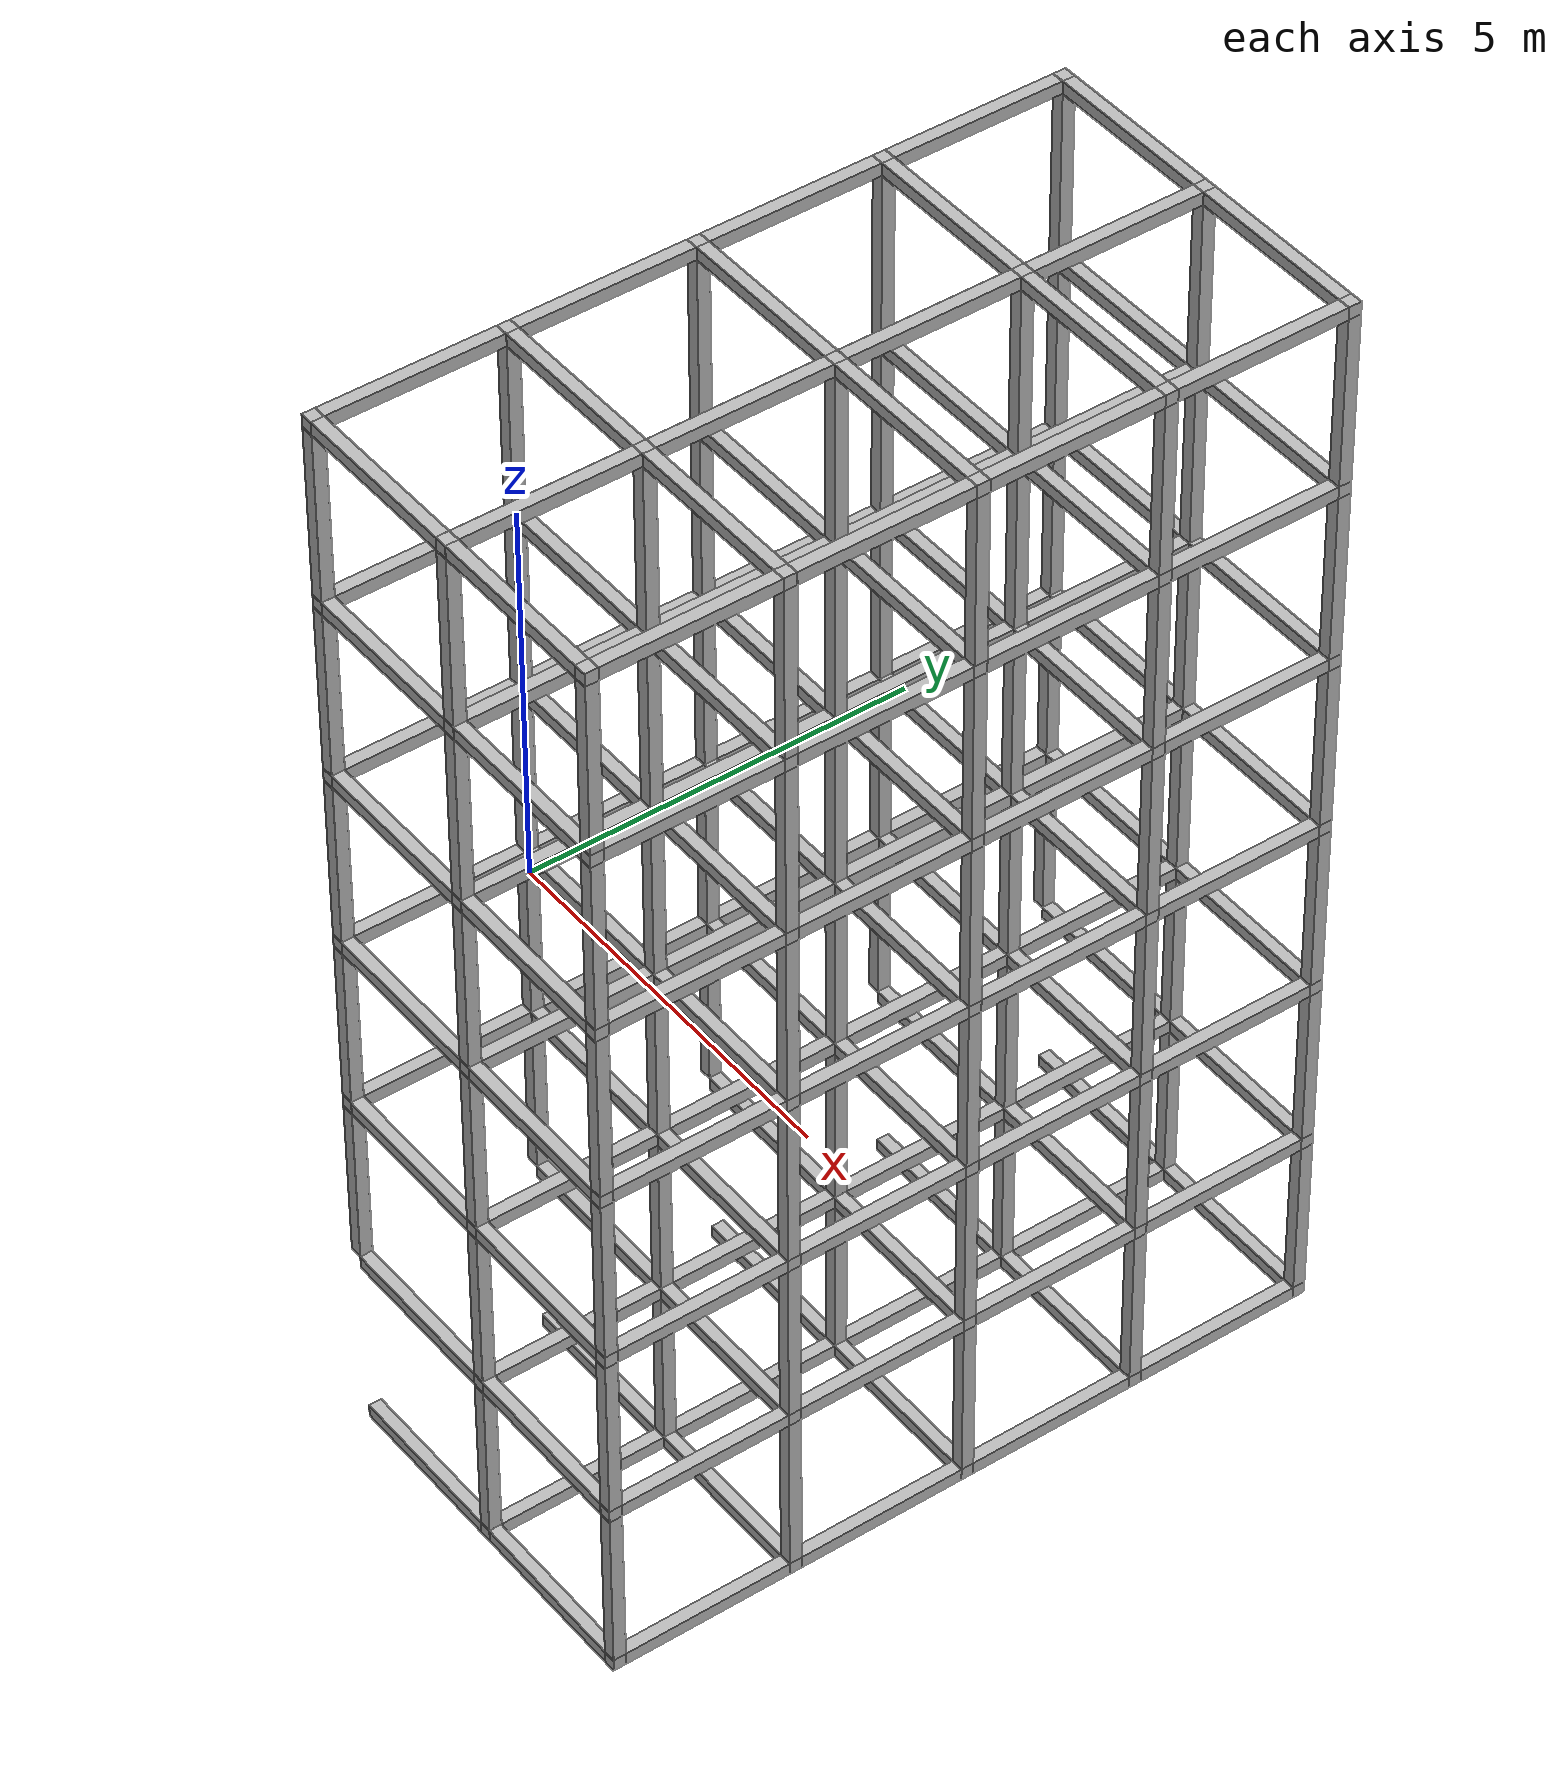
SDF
<sdf version="1.7">
 <world name="default">
  <model name="orthogonal_747_2.000.15_TS">
   <static>1</static>
   <link name="x_link_0_0_5">
    <inertial>
     <mass>1</mass>
     <inertia>
      <ixx>0.166667</ixx>
      <ixy>0</ixy>
      <ixz>0</ixz>
      <iyy>0.166667</iyy>
      <iyz>0</iyz>
      <izz>0.166667</izz>
     </inertia>
    </inertial>
    <pose>11.825 0 1.075 0 -0 0</pose>
    <visual name="visual_0">
     <laser_retro>106</laser_retro>
     <geometry><box><size>2 1e-06 0.15</size></box></geometry>
     <material>
      <script><name>Gazebo/Grey</name><uri>file://media/materials/scripts/gazebo.material</uri></script>
      <shader type="pixel"><normal_map>__default__</normal_map></shader>
      <ambient>0.678 0.498 0.659 1</ambient>
      <diffuse>0.7 0.7 0.7 1</diffuse>
      <specular>0.01 0.01 0.01 1</specular>
      <emissive>0 0 0 1</emissive>
     </material>
     <pose>0 -0.075 0 0 -0 0</pose>
     <transparency>1</transparency>
    </visual>
    <visual name="visual_1">
     <laser_retro>107</laser_retro>
     <geometry><box><size>2 1e-06 0.15</size></box></geometry>
     <material>
      <script><name>Gazebo/Grey</name><uri>file://media/materials/scripts/gazebo.material</uri></script>
      <shader type="pixel"><normal_map>__default__</normal_map></shader>
      <ambient>0.447 0.624 0.812 1</ambient>
      <diffuse>0.7 0.7 0.7 1</diffuse>
      <specular>0.01 0.01 0.01 1</specular>
      <emissive>0 0 0 1</emissive>
     </material>
     <pose>0 0.075 0 0 -0 0</pose>
     <transparency>1</transparency>
    </visual>
    <visual name="visual_2">
     <laser_retro>108</laser_retro>
     <geometry><box><size>2 0.15 1e-06</size></box></geometry>
     <material>
      <script><name>Gazebo/Grey</name><uri>file://media/materials/scripts/gazebo.material</uri></script>
      <shader type="pixel"><normal_map>__default__</normal_map></shader>
      <ambient>0.988 0.686 0.243 1</ambient>
      <diffuse>0.7 0.7 0.7 1</diffuse>
      <specular>0.01 0.01 0.01 1</specular>
      <emissive>0 0 0 1</emissive>
     </material>
     <pose>0 0 -0.075 0 -0 0</pose>
     <transparency>1</transparency>
    </visual>
    <visual name="visual_3">
     <laser_retro>109</laser_retro>
     <geometry><box><size>1e-06 0.15 0.15</size></box></geometry>
     <material>
      <script><name>Gazebo/Grey</name><uri>file://media/materials/scripts/gazebo.material</uri></script>
      <shader type="pixel"><normal_map>__default__</normal_map></shader>
      <ambient>0.988 0.914 0.31 1</ambient>
      <diffuse>0.7 0.7 0.7 1</diffuse>
      <specular>0.01 0.01 0.01 1</specular>
      <emissive>0 0 0 1</emissive>
     </material>
     <pose>1 0 0 0 -0 0</pose>
     <transparency>1</transparency>
    </visual>
    <visual name="visual_4">
     <laser_retro>110</laser_retro>
     <geometry><box><size>2 0.15 1e-06</size></box></geometry>
     <material>
      <script><name>Gazebo/Grey</name><uri>file://media/materials/scripts/gazebo.material</uri></script>
      <shader type="pixel"><normal_map>__default__</normal_map></shader>
      <ambient>0.937 0.161 0.161 1</ambient>
      <diffuse>0.7 0.7 0.7 1</diffuse>
      <specular>0.01 0.01 0.01 1</specular>
      <emissive>0 0 0 1</emissive>
     </material>
     <pose>0 0 0.075 0 -0 0</pose>
     <transparency>1</transparency>
    </visual>
    <visual name="visual_5">
     <laser_retro>111</laser_retro>
     <geometry><box><size>1e-06 0.15 0.15</size></box></geometry>
     <material>
      <script><name>Gazebo/Grey</name><uri>file://media/materials/scripts/gazebo.material</uri></script>
      <shader type="pixel"><normal_map>__default__</normal_map></shader>
      <ambient>0.541 0.886 0.204 1</ambient>
      <diffuse>0.7 0.7 0.7 1</diffuse>
      <specular>0.01 0.01 0.01 1</specular>
      <emissive>0 0 0 1</emissive>
     </material>
     <pose>-1 0 0 0 -0 0</pose>
     <transparency>1</transparency>
    </visual>
    <visual name="visual_texture">
     <geometry><box><size>1.9998 0.149985 0.149985</size></box></geometry>
     <material>
      <script>
       <uri>model://BASE_MODELS/simple_block_v2_textured/materials/scripts</uri>
       <uri>model://BASE_MODELS/simple_block_v2_textured/materials/textures</uri>
       <name>metal</name>
      </script>
     </material>
     <laser_retro>112</laser_retro>
    </visual>
    <collision name="collision">
     <geometry><box><size>2 0.15 0.15</size></box></geometry>
     <surface>
      <friction>
       <ode><mu>1</mu><mu2>1</mu2><fdir1>0 0 0</fdir1><slip1>0</slip1><slip2>0</slip2></ode>
       <torsional>
        <coefficient>1</coefficient>
        <patch_radius>0</patch_radius>
        <surface_radius>0</surface_radius>
        <use_patch_radius>1</use_patch_radius>
        <ode><slip>0</slip></ode>
       </torsional>
      </friction>
      <bounce><restitution_coefficient>0</restitution_coefficient><threshold>1e+06</threshold></bounce>
      <contact>
       <collide_without_contact>0</collide_without_contact>
       <collide_without_contact_bitmask>1</collide_without_contact_bitmask>
       <collide_bitmask>1</collide_bitmask>
       <ode>
        <soft_cfm>0</soft_cfm>
        <soft_erp>0.2</soft_erp>
        <kp>1e+13</kp>
        <kd>1</kd>
        <max_vel>0.01</max_vel>
        <min_depth>0</min_depth>
       </ode>
       <bullet>
        <split_impulse>1</split_impulse>
        <split_impulse_penetration_threshold>-0.01</split_impulse_penetration_threshold>
        <soft_cfm>0</soft_cfm>
        <soft_erp>0.2</soft_erp>
        <kp>1e+13</kp>
        <kd>1</kd>
       </bullet>
      </contact>
     </surface>
    </collision>
   </link>
   <link name="x_link_0_0_6">
    <inertial>
     <mass>1</mass>
     <inertia>
      <ixx>0.166667</ixx>
      <ixy>0</ixy>
      <ixz>0</ixz>
      <iyy>0.166667</iyy>
      <iyz>0</iyz>
      <izz>0.166667</izz>
     </inertia>
    </inertial>
    <pose>13.975 0 1.075 0 -0 0</pose>
    <visual name="visual_0">
     <laser_retro>127</laser_retro>
     <geometry><box><size>2 1e-06 0.15</size></box></geometry>
     <material>
      <script><name>Gazebo/Grey</name><uri>file://media/materials/scripts/gazebo.material</uri></script>
      <shader type="pixel"><normal_map>__default__</normal_map></shader>
      <ambient>0.678 0.498 0.659 1</ambient>
      <diffuse>0.7 0.7 0.7 1</diffuse>
      <specular>0.01 0.01 0.01 1</specular>
      <emissive>0 0 0 1</emissive>
     </material>
     <pose>0 -0.075 0 0 -0 0</pose>
     <transparency>1</transparency>
    </visual>
    <visual name="visual_1">
     <laser_retro>128</laser_retro>
     <geometry><box><size>2 1e-06 0.15</size></box></geometry>
     <material>
      <script><name>Gazebo/Grey</name><uri>file://media/materials/scripts/gazebo.material</uri></script>
      <shader type="pixel"><normal_map>__default__</normal_map></shader>
      <ambient>0.447 0.624 0.812 1</ambient>
      <diffuse>0.7 0.7 0.7 1</diffuse>
      <specular>0.01 0.01 0.01 1</specular>
      <emissive>0 0 0 1</emissive>
     </material>
     <pose>0 0.075 0 0 -0 0</pose>
     <transparency>1</transparency>
    </visual>
    <visual name="visual_2">
     <laser_retro>129</laser_retro>
     <geometry><box><size>2 0.15 1e-06</size></box></geometry>
     <material>
      <script><name>Gazebo/Grey</name><uri>file://media/materials/scripts/gazebo.material</uri></script>
      <shader type="pixel"><normal_map>__default__</normal_map></shader>
      <ambient>0.988 0.686 0.243 1</ambient>
      <diffuse>0.7 0.7 0.7 1</diffuse>
      <specular>0.01 0.01 0.01 1</specular>
      <emissive>0 0 0 1</emissive>
     </material>
     <pose>0 0 -0.075 0 -0 0</pose>
     <transparency>1</transparency>
    </visual>
    <visual name="visual_3">
     <laser_retro>130</laser_retro>
     <geometry><box><size>1e-06 0.15 0.15</size></box></geometry>
     <material>
      <script><name>Gazebo/Grey</name><uri>file://media/materials/scripts/gazebo.material</uri></script>
      <shader type="pixel"><normal_map>__default__</normal_map></shader>
      <ambient>0.988 0.914 0.31 1</ambient>
      <diffuse>0.7 0.7 0.7 1</diffuse>
      <specular>0.01 0.01 0.01 1</specular>
      <emissive>0 0 0 1</emissive>
     </material>
     <pose>1 0 0 0 -0 0</pose>
     <transparency>1</transparency>
    </visual>
    <visual name="visual_4">
     <laser_retro>131</laser_retro>
     <geometry><box><size>2 0.15 1e-06</size></box></geometry>
     <material>
      <script><name>Gazebo/Grey</name><uri>file://media/materials/scripts/gazebo.material</uri></script>
      <shader type="pixel"><normal_map>__default__</normal_map></shader>
      <ambient>0.937 0.161 0.161 1</ambient>
      <diffuse>0.7 0.7 0.7 1</diffuse>
      <specular>0.01 0.01 0.01 1</specular>
      <emissive>0 0 0 1</emissive>
     </material>
     <pose>0 0 0.075 0 -0 0</pose>
     <transparency>1</transparency>
    </visual>
    <visual name="visual_5">
     <laser_retro>132</laser_retro>
     <geometry><box><size>1e-06 0.15 0.15</size></box></geometry>
     <material>
      <script><name>Gazebo/Grey</name><uri>file://media/materials/scripts/gazebo.material</uri></script>
      <shader type="pixel"><normal_map>__default__</normal_map></shader>
      <ambient>0.541 0.886 0.204 1</ambient>
      <diffuse>0.7 0.7 0.7 1</diffuse>
      <specular>0.01 0.01 0.01 1</specular>
      <emissive>0 0 0 1</emissive>
     </material>
     <pose>-1 0 0 0 -0 0</pose>
     <transparency>1</transparency>
    </visual>
    <visual name="visual_texture">
     <geometry><box><size>1.9998 0.149985 0.149985</size></box></geometry>
     <material>
      <script>
       <uri>model://BASE_MODELS/simple_block_v2_textured/materials/scripts</uri>
       <uri>model://BASE_MODELS/simple_block_v2_textured/materials/textures</uri>
       <name>metal</name>
      </script>
     </material>
     <laser_retro>133</laser_retro>
    </visual>
    <collision name="collision">
     <geometry><box><size>2 0.15 0.15</size></box></geometry>
     <surface>
      <friction>
       <ode><mu>1</mu><mu2>1</mu2><fdir1>0 0 0</fdir1><slip1>0</slip1><slip2>0</slip2></ode>
       <torsional>
        <coefficient>1</coefficient>
        <patch_radius>0</patch_radius>
        <surface_radius>0</surface_radius>
        <use_patch_radius>1</use_patch_radius>
        <ode><slip>0</slip></ode>
       </torsional>
      </friction>
      <bounce><restitution_coefficient>0</restitution_coefficient><threshold>1e+06</threshold></bounce>
      <contact>
       <collide_without_contact>0</collide_without_contact>
       <collide_without_contact_bitmask>1</collide_without_contact_bitmask>
       <collide_bitmask>1</collide_bitmask>
       <ode>
        <soft_cfm>0</soft_cfm>
        <soft_erp>0.2</soft_erp>
        <kp>1e+13</kp>
        <kd>1</kd>
        <max_vel>0.01</max_vel>
        <min_depth>0</min_depth>
       </ode>
       <bullet>
        <split_impulse>1</split_impulse>
        <split_impulse_penetration_threshold>-0.01</split_impulse_penetration_threshold>
        <soft_cfm>0</soft_cfm>
        <soft_erp>0.2</soft_erp>
        <kp>1e+13</kp>
        <kd>1</kd>
       </bullet>
      </contact>
     </surface>
    </collision>
   </link>
   <link name="y_link_0_0_6">
    <inertial>
     <mass>1</mass>
     <inertia>
      <ixx>0.166667</ixx>
      <ixy>0</ixy>
      <ixz>0</ixz>
      <iyy>0.166667</iyy>
      <iyz>0</iyz>
      <izz>0.166667</izz>
     </inertia>
    </inertial>
    <pose>12.9 1.075 1.075 0 -0 0</pose>
    <visual name="visual_0">
     <laser_retro>134</laser_retro>
     <geometry><box><size>0.15 1e-06 0.15</size></box></geometry>
     <material>
      <script><name>Gazebo/Grey</name><uri>file://media/materials/scripts/gazebo.material</uri></script>
      <shader type="pixel"><normal_map>__default__</normal_map></shader>
      <ambient>0.678 0.498 0.659 1</ambient>
      <diffuse>0.7 0.7 0.7 1</diffuse>
      <specular>0.01 0.01 0.01 1</specular>
      <emissive>0 0 0 1</emissive>
     </material>
     <pose>0 -1 0 0 -0 0</pose>
     <transparency>1</transparency>
    </visual>
    <visual name="visual_1">
     <laser_retro>135</laser_retro>
     <geometry><box><size>0.15 1e-06 0.15</size></box></geometry>
     <material>
      <script><name>Gazebo/Grey</name><uri>file://media/materials/scripts/gazebo.material</uri></script>
      <shader type="pixel"><normal_map>__default__</normal_map></shader>
      <ambient>0.447 0.624 0.812 1</ambient>
      <diffuse>0.7 0.7 0.7 1</diffuse>
      <specular>0.01 0.01 0.01 1</specular>
      <emissive>0 0 0 1</emissive>
     </material>
     <pose>0 1 0 0 -0 0</pose>
     <transparency>1</transparency>
    </visual>
    <visual name="visual_2">
     <laser_retro>136</laser_retro>
     <geometry><box><size>0.15 2 1e-06</size></box></geometry>
     <material>
      <script><name>Gazebo/Grey</name><uri>file://media/materials/scripts/gazebo.material</uri></script>
      <shader type="pixel"><normal_map>__default__</normal_map></shader>
      <ambient>0.988 0.686 0.243 1</ambient>
      <diffuse>0.7 0.7 0.7 1</diffuse>
      <specular>0.01 0.01 0.01 1</specular>
      <emissive>0 0 0 1</emissive>
     </material>
     <pose>0 0 -0.075 0 -0 0</pose>
     <transparency>1</transparency>
    </visual>
    <visual name="visual_3">
     <laser_retro>137</laser_retro>
     <geometry><box><size>1e-06 2 0.15</size></box></geometry>
     <material>
      <script><name>Gazebo/Grey</name><uri>file://media/materials/scripts/gazebo.material</uri></script>
      <shader type="pixel"><normal_map>__default__</normal_map></shader>
      <ambient>0.988 0.914 0.31 1</ambient>
      <diffuse>0.7 0.7 0.7 1</diffuse>
      <specular>0.01 0.01 0.01 1</specular>
      <emissive>0 0 0 1</emissive>
     </material>
     <pose>0.075 0 0 0 -0 0</pose>
     <transparency>1</transparency>
    </visual>
    <visual name="visual_4">
     <laser_retro>138</laser_retro>
     <geometry><box><size>0.15 2 1e-06</size></box></geometry>
     <material>
      <script><name>Gazebo/Grey</name><uri>file://media/materials/scripts/gazebo.material</uri></script>
      <shader type="pixel"><normal_map>__default__</normal_map></shader>
      <ambient>0.937 0.161 0.161 1</ambient>
      <diffuse>0.7 0.7 0.7 1</diffuse>
      <specular>0.01 0.01 0.01 1</specular>
      <emissive>0 0 0 1</emissive>
     </material>
     <pose>0 0 0.075 0 -0 0</pose>
     <transparency>1</transparency>
    </visual>
    <visual name="visual_5">
     <laser_retro>139</laser_retro>
     <geometry><box><size>1e-06 2 0.15</size></box></geometry>
     <material>
      <script><name>Gazebo/Grey</name><uri>file://media/materials/scripts/gazebo.material</uri></script>
      <shader type="pixel"><normal_map>__default__</normal_map></shader>
      <ambient>0.541 0.886 0.204 1</ambient>
      <diffuse>0.7 0.7 0.7 1</diffuse>
      <specular>0.01 0.01 0.01 1</specular>
      <emissive>0 0 0 1</emissive>
     </material>
     <pose>-0.075 0 0 0 -0 0</pose>
     <transparency>1</transparency>
    </visual>
    <visual name="visual_texture">
     <geometry><box><size>0.149985 1.9998 0.149985</size></box></geometry>
     <material>
      <script>
       <uri>model://BASE_MODELS/simple_block_v2_textured/materials/scripts</uri>
       <uri>model://BASE_MODELS/simple_block_v2_textured/materials/textures</uri>
       <name>metal</name>
      </script>
     </material>
     <laser_retro>140</laser_retro>
    </visual>
    <collision name="collision">
     <geometry><box><size>0.15 2 0.15</size></box></geometry>
     <surface>
      <friction>
       <ode><mu>1</mu><mu2>1</mu2><fdir1>0 0 0</fdir1><slip1>0</slip1><slip2>0</slip2></ode>
       <torsional>
        <coefficient>1</coefficient>
        <patch_radius>0</patch_radius>
        <surface_radius>0</surface_radius>
        <use_patch_radius>1</use_patch_radius>
        <ode><slip>0</slip></ode>
       </torsional>
      </friction>
      <bounce><restitution_coefficient>0</restitution_coefficient><threshold>1e+06</threshold></bounce>
      <contact>
       <collide_without_contact>0</collide_without_contact>
       <collide_without_contact_bitmask>1</collide_without_contact_bitmask>
       <collide_bitmask>1</collide_bitmask>
       <ode>
        <soft_cfm>0</soft_cfm>
        <soft_erp>0.2</soft_erp>
        <kp>1e+13</kp>
        <kd>1</kd>
        <max_vel>0.01</max_vel>
        <min_depth>0</min_depth>
       </ode>
       <bullet>
        <split_impulse>1</split_impulse>
        <split_impulse_penetration_threshold>-0.01</split_impulse_penetration_threshold>
        <soft_cfm>0</soft_cfm>
        <soft_erp>0.2</soft_erp>
        <kp>1e+13</kp>
        <kd>1</kd>
       </bullet>
      </contact>
     </surface>
    </collision>
   </link>
   <link name="u_link_0_0_6">
    <inertial>
     <mass>1</mass>
     <inertia>
      <ixx>0.166667</ixx>
      <ixy>0</ixy>
      <ixz>0</ixz>
      <iyy>0.166667</iyy>
      <iyz>0</iyz>
      <izz>0.166667</izz>
     </inertia>
    </inertial>
    <pose>12.9 0 1.075 0 -0 0</pose>
    <visual name="visual_0">
     <laser_retro>141</laser_retro>
     <geometry><box><size>0.15 1e-06 0.15</size></box></geometry>
     <material>
      <script><name>Gazebo/Grey</name><uri>file://media/materials/scripts/gazebo.material</uri></script>
      <shader type="pixel"><normal_map>__default__</normal_map></shader>
      <ambient>0.678 0.498 0.659 1</ambient>
      <diffuse>0.7 0.7 0.7 1</diffuse>
      <specular>0.01 0.01 0.01 1</specular>
      <emissive>0 0 0 1</emissive>
     </material>
     <pose>0 -0.075 0 0 -0 0</pose>
     <transparency>1</transparency>
    </visual>
    <visual name="visual_1">
     <laser_retro>142</laser_retro>
     <geometry><box><size>0.15 1e-06 0.15</size></box></geometry>
     <material>
      <script><name>Gazebo/Grey</name><uri>file://media/materials/scripts/gazebo.material</uri></script>
      <shader type="pixel"><normal_map>__default__</normal_map></shader>
      <ambient>0.447 0.624 0.812 1</ambient>
      <diffuse>0.7 0.7 0.7 1</diffuse>
      <specular>0.01 0.01 0.01 1</specular>
      <emissive>0 0 0 1</emissive>
     </material>
     <pose>0 0.075 0 0 -0 0</pose>
     <transparency>1</transparency>
    </visual>
    <visual name="visual_2">
     <laser_retro>143</laser_retro>
     <geometry><box><size>0.15 0.15 1e-06</size></box></geometry>
     <material>
      <script><name>Gazebo/Grey</name><uri>file://media/materials/scripts/gazebo.material</uri></script>
      <shader type="pixel"><normal_map>__default__</normal_map></shader>
      <ambient>0.988 0.686 0.243 1</ambient>
      <diffuse>0.7 0.7 0.7 1</diffuse>
      <specular>0.01 0.01 0.01 1</specular>
      <emissive>0 0 0 1</emissive>
     </material>
     <pose>0 0 -0.075 0 -0 0</pose>
     <transparency>1</transparency>
    </visual>
    <visual name="visual_3">
     <laser_retro>144</laser_retro>
     <geometry><box><size>1e-06 0.15 0.15</size></box></geometry>
     <material>
      <script><name>Gazebo/Grey</name><uri>file://media/materials/scripts/gazebo.material</uri></script>
      <shader type="pixel"><normal_map>__default__</normal_map></shader>
      <ambient>0.988 0.914 0.31 1</ambient>
      <diffuse>0.7 0.7 0.7 1</diffuse>
      <specular>0.01 0.01 0.01 1</specular>
      <emissive>0 0 0 1</emissive>
     </material>
     <pose>0.075 0 0 0 -0 0</pose>
     <transparency>1</transparency>
    </visual>
    <visual name="visual_4">
     <laser_retro>145</laser_retro>
     <geometry><box><size>0.15 0.15 1e-06</size></box></geometry>
     <material>
      <script><name>Gazebo/Grey</name><uri>file://media/materials/scripts/gazebo.material</uri></script>
      <shader type="pixel"><normal_map>__default__</normal_map></shader>
      <ambient>0.937 0.161 0.161 1</ambient>
      <diffuse>0.7 0.7 0.7 1</diffuse>
      <specular>0.01 0.01 0.01 1</specular>
      <emissive>0 0 0 1</emissive>
     </material>
     <pose>0 0 0.075 0 -0 0</pose>
     <transparency>1</transparency>
    </visual>
    <visual name="visual_5">
     <laser_retro>146</laser_retro>
     <geometry><box><size>1e-06 0.15 0.15</size></box></geometry>
     <material>
      <script><name>Gazebo/Grey</name><uri>file://media/materials/scripts/gazebo.material</uri></script>
      <shader type="pixel"><normal_map>__default__</normal_map></shader>
      <ambient>0.541 0.886 0.204 1</ambient>
      <diffuse>0.7 0.7 0.7 1</diffuse>
      <specular>0.01 0.01 0.01 1</specular>
      <emissive>0 0 0 1</emissive>
     </material>
     <pose>-0.075 0 0 0 -0 0</pose>
     <transparency>1</transparency>
    </visual>
    <visual name="visual_texture">
     <geometry><box><size>0.149985 0.149985 0.149985</size></box></geometry>
     <material>
      <script>
       <uri>model://BASE_MODELS/simple_block_v2_textured/materials/scripts</uri>
       <uri>model://BASE_MODELS/simple_block_v2_textured/materials/textures</uri>
       <name>metal</name>
      </script>
     </material>
     <laser_retro>147</laser_retro>
    </visual>
    <collision name="collision">
     <geometry><box><size>0.15 0.15 0.15</size></box></geometry>
     <surface>
      <friction>
       <ode><mu>1</mu><mu2>1</mu2><fdir1>0 0 0</fdir1><slip1>0</slip1><slip2>0</slip2></ode>
       <torsional>
        <coefficient>1</coefficient>
        <patch_radius>0</patch_radius>
        <surface_radius>0</surface_radius>
        <use_patch_radius>1</use_patch_radius>
        <ode><slip>0</slip></ode>
       </torsional>
      </friction>
      <bounce><restitution_coefficient>0</restitution_coefficient><threshold>1e+06</threshold></bounce>
      <contact>
       <collide_without_contact>0</collide_without_contact>
       <collide_without_contact_bitmask>1</collide_without_contact_bitmask>
       <collide_bitmask>1</collide_bitmask>
       <ode>
        <soft_cfm>0</soft_cfm>
        <soft_erp>0.2</soft_erp>
        <kp>1e+13</kp>
        <kd>1</kd>
        <max_vel>0.01</max_vel>
        <min_depth>0</min_depth>
       </ode>
       <bullet>
        <split_impulse>1</split_impulse>
        <split_impulse_penetration_threshold>-0.01</split_impulse_penetration_threshold>
        <soft_cfm>0</soft_cfm>
        <soft_erp>0.2</soft_erp>
        <kp>1e+13</kp>
        <kd>1</kd>
       </bullet>
      </contact>
     </surface>
    </collision>
   </link>
   <link name="y_link_0_0_7">
    <inertial>
     <mass>1</mass>
     <inertia>
      <ixx>0.166667</ixx>
      <ixy>0</ixy>
      <ixz>0</ixz>
      <iyy>0.166667</iyy>
      <iyz>0</iyz>
      <izz>0.166667</izz>
     </inertia>
    </inertial>
    <pose>15.05 1.075 1.075 0 -0 0</pose>
    <visual name="visual_0">
     <laser_retro>148</laser_retro>
     <geometry><box><size>0.15 1e-06 0.15</size></box></geometry>
     <material>
      <script><name>Gazebo/Grey</name><uri>file://media/materials/scripts/gazebo.material</uri></script>
      <shader type="pixel"><normal_map>__default__</normal_map></shader>
      <ambient>0.678 0.498 0.659 1</ambient>
      <diffuse>0.7 0.7 0.7 1</diffuse>
      <specular>0.01 0.01 0.01 1</specular>
      <emissive>0 0 0 1</emissive>
     </material>
     <pose>0 -1 0 0 -0 0</pose>
     <transparency>1</transparency>
    </visual>
    <visual name="visual_1">
     <laser_retro>149</laser_retro>
     <geometry><box><size>0.15 1e-06 0.15</size></box></geometry>
     <material>
      <script><name>Gazebo/Grey</name><uri>file://media/materials/scripts/gazebo.material</uri></script>
      <shader type="pixel"><normal_map>__default__</normal_map></shader>
      <ambient>0.447 0.624 0.812 1</ambient>
      <diffuse>0.7 0.7 0.7 1</diffuse>
      <specular>0.01 0.01 0.01 1</specular>
      <emissive>0 0 0 1</emissive>
     </material>
     <pose>0 1 0 0 -0 0</pose>
     <transparency>1</transparency>
    </visual>
    <visual name="visual_2">
     <laser_retro>150</laser_retro>
     <geometry><box><size>0.15 2 1e-06</size></box></geometry>
     <material>
      <script><name>Gazebo/Grey</name><uri>file://media/materials/scripts/gazebo.material</uri></script>
      <shader type="pixel"><normal_map>__default__</normal_map></shader>
      <ambient>0.988 0.686 0.243 1</ambient>
      <diffuse>0.7 0.7 0.7 1</diffuse>
      <specular>0.01 0.01 0.01 1</specular>
      <emissive>0 0 0 1</emissive>
     </material>
     <pose>0 0 -0.075 0 -0 0</pose>
     <transparency>1</transparency>
    </visual>
    <visual name="visual_3">
     <laser_retro>151</laser_retro>
     <geometry><box><size>1e-06 2 0.15</size></box></geometry>
     <material>
      <script><name>Gazebo/Grey</name><uri>file://media/materials/scripts/gazebo.material</uri></script>
      <shader type="pixel"><normal_map>__default__</normal_map></shader>
      <ambient>0.988 0.914 0.31 1</ambient>
      <diffuse>0.7 0.7 0.7 1</diffuse>
      <specular>0.01 0.01 0.01 1</specular>
      <emissive>0 0 0 1</emissive>
     </material>
     <pose>0.075 0 0 0 -0 0</pose>
     <transparency>1</transparency>
    </visual>
    <visual name="visual_4">
     <laser_retro>152</laser_retro>
     <geometry><box><size>0.15 2 1e-06</size></box></geometry>
     <material>
      <script><name>Gazebo/Grey</name><uri>file://media/materials/scripts/gazebo.material</uri></script>
      <shader type="pixel"><normal_map>__default__</normal_map></shader>
      <ambient>0.937 0.161 0.161 1</ambient>
      <diffuse>0.7 0.7 0.7 1</diffuse>
      <specular>0.01 0.01 0.01 1</specular>
      <emissive>0 0 0 1</emissive>
     </material>
     <pose>0 0 0.075 0 -0 0</pose>
     <transparency>1</transparency>
    </visual>
    <visual name="visual_5">
     <laser_retro>153</laser_retro>
     <geometry><box><size>1e-06 2 0.15</size></box></geometry>
     <material>
      <script><name>Gazebo/Grey</name><uri>file://media/materials/scripts/gazebo.material</uri></script>
      <shader type="pixel"><normal_map>__default__</normal_map></shader>
      <ambient>0.541 0.886 0.204 1</ambient>
      <diffuse>0.7 0.7 0.7 1</diffuse>
      <specular>0.01 0.01 0.01 1</specular>
      <emissive>0 0 0 1</emissive>
     </material>
     <pose>-0.075 0 0 0 -0 0</pose>
     <transparency>1</transparency>
    </visual>
    <visual name="visual_texture">
     <geometry><box><size>0.149985 1.9998 0.149985</size></box></geometry>
     <material>
      <script>
       <uri>model://BASE_MODELS/simple_block_v2_textured/materials/scripts</uri>
       <uri>model://BASE_MODELS/simple_block_v2_textured/materials/textures</uri>
       <name>metal</name>
      </script>
     </material>
     <laser_retro>154</laser_retro>
    </visual>
    <collision name="collision">
     <geometry><box><size>0.15 2 0.15</size></box></geometry>
     <surface>
      <friction>
       <ode><mu>1</mu><mu2>1</mu2><fdir1>0 0 0</fdir1><slip1>0</slip1><slip2>0</slip2></ode>
       <torsional>
        <coefficient>1</coefficient>
        <patch_radius>0</patch_radius>
        <surface_radius>0</surface_radius>
        <use_patch_radius>1</use_patch_radius>
        <ode><slip>0</slip></ode>
       </torsional>
      </friction>
      <bounce><restitution_coefficient>0</restitution_coefficient><threshold>1e+06</threshold></bounce>
      <contact>
       <collide_without_contact>0</collide_without_contact>
       <collide_without_contact_bitmask>1</collide_without_contact_bitmask>
       <collide_bitmask>1</collide_bitmask>
       <ode>
        <soft_cfm>0</soft_cfm>
        <soft_erp>0.2</soft_erp>
        <kp>1e+13</kp>
        <kd>1</kd>
        <max_vel>0.01</max_vel>
        <min_depth>0</min_depth>
       </ode>
       <bullet>
        <split_impulse>1</split_impulse>
        <split_impulse_penetration_threshold>-0.01</split_impulse_penetration_threshold>
        <soft_cfm>0</soft_cfm>
        <soft_erp>0.2</soft_erp>
        <kp>1e+13</kp>
        <kd>1</kd>
       </bullet>
      </contact>
     </surface>
    </collision>
   </link>
   <link name="u_link_0_0_7">
    <inertial>
     <mass>1</mass>
     <inertia>
      <ixx>0.166667</ixx>
      <ixy>0</ixy>
      <ixz>0</ixz>
      <iyy>0.166667</iyy>
      <iyz>0</iyz>
      <izz>0.166667</izz>
     </inertia>
    </inertial>
    <pose>15.05 0 1.075 0 -0 0</pose>
    <visual name="visual_0">
     <laser_retro>155</laser_retro>
     <geometry><box><size>0.15 1e-06 0.15</size></box></geometry>
     <material>
      <script><name>Gazebo/Grey</name><uri>file://media/materials/scripts/gazebo.material</uri></script>
      <shader type="pixel"><normal_map>__default__</normal_map></shader>
      <ambient>0.678 0.498 0.659 1</ambient>
      <diffuse>0.7 0.7 0.7 1</diffuse>
      <specular>0.01 0.01 0.01 1</specular>
      <emissive>0 0 0 1</emissive>
     </material>
     <pose>0 -0.075 0 0 -0 0</pose>
     <transparency>1</transparency>
    </visual>
    <visual name="visual_1">
     <laser_retro>156</laser_retro>
     <geometry><box><size>0.15 1e-06 0.15</size></box></geometry>
     <material>
      <script><name>Gazebo/Grey</name><uri>file://media/materials/scripts/gazebo.material</uri></script>
      <shader type="pixel"><normal_map>__default__</normal_map></shader>
      <ambient>0.447 0.624 0.812 1</ambient>
      <diffuse>0.7 0.7 0.7 1</diffuse>
      <specular>0.01 0.01 0.01 1</specular>
      <emissive>0 0 0 1</emissive>
     </material>
     <pose>0 0.075 0 0 -0 0</pose>
     <transparency>1</transparency>
    </visual>
    <visual name="visual_2">
     <laser_retro>157</laser_retro>
     <geometry><box><size>0.15 0.15 1e-06</size></box></geometry>
     <material>
      <script><name>Gazebo/Grey</name><uri>file://media/materials/scripts/gazebo.material</uri></script>
      <shader type="pixel"><normal_map>__default__</normal_map></shader>
      <ambient>0.988 0.686 0.243 1</ambient>
      <diffuse>0.7 0.7 0.7 1</diffuse>
      <specular>0.01 0.01 0.01 1</specular>
      <emissive>0 0 0 1</emissive>
     </material>
     <pose>0 0 -0.075 0 -0 0</pose>
     <transparency>1</transparency>
    </visual>
    <visual name="visual_3">
     <laser_retro>158</laser_retro>
     <geometry><box><size>1e-06 0.15 0.15</size></box></geometry>
     <material>
      <script><name>Gazebo/Grey</name><uri>file://media/materials/scripts/gazebo.material</uri></script>
      <shader type="pixel"><normal_map>__default__</normal_map></shader>
      <ambient>0.988 0.914 0.31 1</ambient>
      <diffuse>0.7 0.7 0.7 1</diffuse>
      <specular>0.01 0.01 0.01 1</specular>
      <emissive>0 0 0 1</emissive>
     </material>
     <pose>0.075 0 0 0 -0 0</pose>
     <transparency>1</transparency>
    </visual>
    <visual name="visual_4">
     <laser_retro>159</laser_retro>
     <geometry><box><size>0.15 0.15 1e-06</size></box></geometry>
     <material>
      <script><name>Gazebo/Grey</name><uri>file://media/materials/scripts/gazebo.material</uri></script>
      <shader type="pixel"><normal_map>__default__</normal_map></shader>
      <ambient>0.937 0.161 0.161 1</ambient>
      <diffuse>0.7 0.7 0.7 1</diffuse>
      <specular>0.01 0.01 0.01 1</specular>
      <emissive>0 0 0 1</emissive>
     </material>
     <pose>0 0 0.075 0 -0 0</pose>
     <transparency>1</transparency>
    </visual>
    <visual name="visual_5">
     <laser_retro>160</laser_retro>
     <geometry><box><size>1e-06 0.15 0.15</size></box></geometry>
     <material>
      <script><name>Gazebo/Grey</name><uri>file://media/materials/scripts/gazebo.material</uri></script>
      <shader type="pixel"><normal_map>__default__</normal_map></shader>
      <ambient>0.541 0.886 0.204 1</ambient>
      <diffuse>0.7 0.7 0.7 1</diffuse>
      <specular>0.01 0.01 0.01 1</specular>
      <emissive>0 0 0 1</emissive>
     </material>
     <pose>-0.075 0 0 0 -0 0</pose>
     <transparency>1</transparency>
    </visual>
    <visual name="visual_texture">
     <geometry><box><size>0.149985 0.149985 0.149985</size></box></geometry>
     <material>
      <script>
       <uri>model://BASE_MODELS/simple_block_v2_textured/materials/scripts</uri>
       <uri>model://BASE_MODELS/simple_block_v2_textured/materials/textures</uri>
       <name>metal</name>
      </script>
     </material>
     <laser_retro>161</laser_retro>
    </visual>
    <collision name="collision">
     <geometry><box><size>0.15 0.15 0.15</size></box></geometry>
     <surface>
      <friction>
       <ode><mu>1</mu><mu2>1</mu2><fdir1>0 0 0</fdir1><slip1>0</slip1><slip2>0</slip2></ode>
       <torsional>
        <coefficient>1</coefficient>
        <patch_radius>0</patch_radius>
        <surface_radius>0</surface_radius>
        <use_patch_radius>1</use_patch_radius>
        <ode><slip>0</slip></ode>
       </torsional>
      </friction>
      <bounce><restitution_coefficient>0</restitution_coefficient><threshold>1e+06</threshold></bounce>
      <contact>
       <collide_without_contact>0</collide_without_contact>
       <collide_without_contact_bitmask>1</collide_without_contact_bitmask>
       <collide_bitmask>1</collide_bitmask>
       <ode>
        <soft_cfm>0</soft_cfm>
        <soft_erp>0.2</soft_erp>
        <kp>1e+13</kp>
        <kd>1</kd>
        <max_vel>0.01</max_vel>
        <min_depth>0</min_depth>
       </ode>
       <bullet>
        <split_impulse>1</split_impulse>
        <split_impulse_penetration_threshold>-0.01</split_impulse_penetration_threshold>
        <soft_cfm>0</soft_cfm>
        <soft_erp>0.2</soft_erp>
        <kp>1e+13</kp>
        <kd>1</kd>
       </bullet>
      </contact>
     </surface>
    </collision>
   </link>
   <link name="x_link_0_1_5">
    <inertial>
     <mass>1</mass>
     <inertia>
      <ixx>0.166667</ixx>
      <ixy>0</ixy>
      <ixz>0</ixz>
      <iyy>0.166667</iyy>
      <iyz>0</iyz>
      <izz>0.166667</izz>
     </inertia>
    </inertial>
    <pose>11.825 2.15 1.075 0 -0 0</pose>
    <visual name="visual_0">
     <laser_retro>267</laser_retro>
     <geometry><box><size>2 1e-06 0.15</size></box></geometry>
     <material>
      <script><name>Gazebo/Grey</name><uri>file://media/materials/scripts/gazebo.material</uri></script>
      <shader type="pixel"><normal_map>__default__</normal_map></shader>
      <ambient>0.678 0.498 0.659 1</ambient>
      <diffuse>0.7 0.7 0.7 1</diffuse>
      <specular>0.01 0.01 0.01 1</specular>
      <emissive>0 0 0 1</emissive>
     </material>
     <pose>0 -0.075 0 0 -0 0</pose>
     <transparency>1</transparency>
    </visual>
    <visual name="visual_1">
     <laser_retro>268</laser_retro>
     <geometry><box><size>2 1e-06 0.15</size></box></geometry>
     <material>
      <script><name>Gazebo/Grey</name><uri>file://media/materials/scripts/gazebo.material</uri></script>
      <shader type="pixel"><normal_map>__default__</normal_map></shader>
      <ambient>0.447 0.624 0.812 1</ambient>
      <diffuse>0.7 0.7 0.7 1</diffuse>
      <specular>0.01 0.01 0.01 1</specular>
      <emissive>0 0 0 1</emissive>
     </material>
     <pose>0 0.075 0 0 -0 0</pose>
     <transparency>1</transparency>
    </visual>
    <visual name="visual_2">
     <laser_retro>269</laser_retro>
     <geometry><box><size>2 0.15 1e-06</size></box></geometry>
     <material>
      <script><name>Gazebo/Grey</name><uri>file://media/materials/scripts/gazebo.material</uri></script>
      <shader type="pixel"><normal_map>__default__</normal_map></shader>
      <ambient>0.988 0.686 0.243 1</ambient>
      <diffuse>0.7 0.7 0.7 1</diffuse>
      <specular>0.01 0.01 0.01 1</specular>
      <emissive>0 0 0 1</emissive>
     </material>
     <pose>0 0 -0.075 0 -0 0</pose>
     <transparency>1</transparency>
    </visual>
    <visual name="visual_3">
     <laser_retro>270</laser_retro>
     <geometry><box><size>1e-06 0.15 0.15</size></box></geometry>
     <material>
      <script><name>Gazebo/Grey</name><uri>file://media/materials/scripts/gazebo.material</uri></script>
      <shader type="pixel"><normal_map>__default__</normal_map></shader>
      <ambient>0.988 0.914 0.31 1</ambient>
      <diffuse>0.7 0.7 0.7 1</diffuse>
      <specular>0.01 0.01 0.01 1</specular>
      <emissive>0 0 0 1</emissive>
     </material>
     <pose>1 0 0 0 -0 0</pose>
     <transparency>1</transparency>
    </visual>
    <visual name="visual_4">
     <laser_retro>271</laser_retro>
     <geometry><box><size>2 0.15 1e-06</size></box></geometry>
     <material>
      <script><name>Gazebo/Grey</name><uri>file://media/materials/scripts/gazebo.material</uri></script>
      <shader type="pixel"><normal_map>__default__</normal_map></shader>
      <ambient>0.937 0.161 0.161 1</ambient>
      <diffuse>0.7 0.7 0.7 1</diffuse>
      <specular>0.01 0.01 0.01 1</specular>
      <emissive>0 0 0 1</emissive>
     </material>
     <pose>0 0 0.075 0 -0 0</pose>
     <transparency>1</transparency>
    </visual>
    <visual name="visual_5">
     <laser_retro>272</laser_retro>
     <geometry><box><size>1e-06 0.15 0.15</size></box></geometry>
     <material>
      <script><name>Gazebo/Grey</name><uri>file://media/materials/scripts/gazebo.material</uri></script>
      <shader type="pixel"><normal_map>__default__</normal_map></shader>
      <ambient>0.541 0.886 0.204 1</ambient>
      <diffuse>0.7 0.7 0.7 1</diffuse>
      <specular>0.01 0.01 0.01 1</specular>
      <emissive>0 0 0 1</emissive>
     </material>
     <pose>-1 0 0 0 -0 0</pose>
     <transparency>1</transparency>
    </visual>
    <visual name="visual_texture">
     <geometry><box><size>1.9998 0.149985 0.149985</size></box></geometry>
     <material>
      <script>
       <uri>model://BASE_MODELS/simple_block_v2_textured/materials/scripts</uri>
       <uri>model://BASE_MODELS/simple_block_v2_textured/materials/textures</uri>
       <name>metal</name>
      </script>
     </material>
     <laser_retro>273</laser_retro>
    </visual>
    <collision name="collision">
     <geometry><box><size>2 0.15 0.15</size></box></geometry>
     <surface>
      <friction>
       <ode><mu>1</mu><mu2>1</mu2><fdir1>0 0 0</fdir1><slip1>0</slip1><slip2>0</slip2></ode>
       <torsional>
        <coefficient>1</coefficient>
        <patch_radius>0</patch_radius>
        <surface_radius>0</surface_radius>
        <use_patch_radius>1</use_patch_radius>
        <ode><slip>0</slip></ode>
       </torsional>
      </friction>
      <bounce><restitution_coefficient>0</restitution_coefficient><threshold>1e+06</threshold></bounce>
      <contact>
       <collide_without_contact>0</collide_without_contact>
       <collide_without_contact_bitmask>1</collide_without_contact_bitmask>
       <collide_bitmask>1</collide_bitmask>
       <ode>
        <soft_cfm>0</soft_cfm>
        <soft_erp>0.2</soft_erp>
        <kp>1e+13</kp>
        <kd>1</kd>
        <max_vel>0.01</max_vel>
        <min_depth>0</min_depth>
       </ode>
       <bullet>
        <split_impulse>1</split_impulse>
        <split_impulse_penetration_threshold>-0.01</split_impulse_penetration_threshold>
        <soft_cfm>0</soft_cfm>
        <soft_erp>0.2</soft_erp>
        <kp>1e+13</kp>
        <kd>1</kd>
       </bullet>
      </contact>
     </surface>
    </collision>
   </link>
   <link name="x_link_0_1_6">
    <inertial>
     <mass>1</mass>
     <inertia>
      <ixx>0.166667</ixx>
      <ixy>0</ixy>
      <ixz>0</ixz>
      <iyy>0.166667</iyy>
      <iyz>0</iyz>
      <izz>0.166667</izz>
     </inertia>
    </inertial>
    <pose>13.975 2.15 1.075 0 -0 0</pose>
    <visual name="visual_0">
     <laser_retro>288</laser_retro>
     <geometry><box><size>2 1e-06 0.15</size></box></geometry>
     <material>
      <script><name>Gazebo/Grey</name><uri>file://media/materials/scripts/gazebo.material</uri></script>
      <shader type="pixel"><normal_map>__default__</normal_map></shader>
      <ambient>0.678 0.498 0.659 1</ambient>
      <diffuse>0.7 0.7 0.7 1</diffuse>
      <specular>0.01 0.01 0.01 1</specular>
      <emissive>0 0 0 1</emissive>
     </material>
     <pose>0 -0.075 0 0 -0 0</pose>
     <transparency>1</transparency>
    </visual>
    <visual name="visual_1">
     <laser_retro>289</laser_retro>
     <geometry><box><size>2 1e-06 0.15</size></box></geometry>
     <material>
      <script><name>Gazebo/Grey</name><uri>file://media/materials/scripts/gazebo.material</uri></script>
      <shader type="pixel"><normal_map>__default__</normal_map></shader>
      <ambient>0.447 0.624 0.812 1</ambient>
      <diffuse>0.7 0.7 0.7 1</diffuse>
      <specular>0.01 0.01 0.01 1</specular>
      <emissive>0 0 0 1</emissive>
     </material>
     <pose>0 0.075 0 0 -0 0</pose>
     <transparency>1</transparency>
    </visual>
    <visual name="visual_2">
     <laser_retro>290</laser_retro>
     <geometry><box><size>2 0.15 1e-06</size></box></geometry>
     <material>
      <script><name>Gazebo/Grey</name><uri>file://media/materials/scripts/gazebo.material</uri></script>
      <shader type="pixel"><normal_map>__default__</normal_map></shader>
      <ambient>0.988 0.686 0.243 1</ambient>
      <diffuse>0.7 0.7 0.7 1</diffuse>
      <specular>0.01 0.01 0.01 1</specular>
      <emissive>0 0 0 1</emissive>
     </material>
     <pose>0 0 -0.075 0 -0 0</pose>
     <transparency>1</transparency>
    </visual>
    <visual name="visual_3">
     <laser_retro>291</laser_retro>
     <geometry><box><size>1e-06 0.15 0.15</size></box></geometry>
     <material>
      <script><name>Gazebo/Grey</name><uri>file://media/materials/scripts/gazebo.material</uri></script>
      <shader type="pixel"><normal_map>__default__</normal_map></shader>
      <ambient>0.988 0.914 0.31 1</ambient>
      <diffuse>0.7 0.7 0.7 1</diffuse>
      <specular>0.01 0.01 0.01 1</specular>
      <emissive>0 0 0 1</emissive>
     </material>
     <pose>1 0 0 0 -0 0</pose>
     <transparency>1</transparency>
    </visual>
    <visual name="visual_4">
     <laser_retro>292</laser_retro>
     <geometry><box><size>2 0.15 1e-06</size></box></geometry>
     <material>
      <script><name>Gazebo/Grey</name><uri>file://media/materials/scripts/gazebo.material</uri></script>
      <shader type="pixel"><normal_map>__default__</normal_map></shader>
      <ambient>0.937 0.161 0.161 1</ambient>
      <diffuse>0.7 0.7 0.7 1</diffuse>
      <specular>0.01 0.01 0.01 1</specular>
      <emissive>0 0 0 1</emissive>
     </material>
     <pose>0 0 0.075 0 -0 0</pose>
     <transparency>1</transparency>
    </visual>
    <visual name="visual_5">
     <laser_retro>293</laser_retro>
     <geometry><box><size>1e-06 0.15 0.15</size></box></geometry>
     <material>
      <script><name>Gazebo/Grey</name><uri>file://media/materials/scripts/gazebo.material</uri></script>
      <shader type="pixel"><normal_map>__default__</normal_map></shader>
      <ambient>0.541 0.886 0.204 1</ambient>
      <diffuse>0.7 0.7 0.7 1</diffuse>
      <specular>0.01 0.01 0.01 1</specular>
      <emissive>0 0 0 1</emissive>
     </material>
     <pose>-1 0 0 0 -0 0</pose>
     <transparency>1</transparency>
    </visual>
    <visual name="visual_texture">
     <geometry><box><size>1.9998 0.149985 0.149985</size></box></geometry>
     <material>
      <script>
       <uri>model://BASE_MODELS/simple_block_v2_textured/materials/scripts</uri>
       <uri>model://BASE_MODELS/simple_block_v2_textured/materials/textures</uri>
       <name>metal</name>
      </script>
     </material>
     <laser_retro>294</laser_retro>
    </visual>
    <collision name="collision">
     <geometry><box><size>2 0.15 0.15</size></box></geometry>
     <surface>
      <friction>
       <ode><mu>1</mu><mu2>1</mu2><fdir1>0 0 0</fdir1><slip1>0</slip1><slip2>0</slip2></ode>
       <torsional>
        <coefficient>1</coefficient>
        <patch_radius>0</patch_radius>
        <surface_radius>0</surface_radius>
        <use_patch_radius>1</use_patch_radius>
        <ode><slip>0</slip></ode>
       </torsional>
      </friction>
      <bounce><restitution_coefficient>0</restitution_coefficient><threshold>1e+06</threshold></bounce>
      <contact>
       <collide_without_contact>0</collide_without_contact>
       <collide_without_contact_bitmask>1</collide_without_contact_bitmask>
       <collide_bitmask>1</collide_bitmask>
       <ode>
        <soft_cfm>0</soft_cfm>
        <soft_erp>0.2</soft_erp>
        <kp>1e+13</kp>
        <kd>1</kd>
        <max_vel>0.01</max_vel>
        <min_depth>0</min_depth>
       </ode>
       <bullet>
        <split_impulse>1</split_impulse>
        <split_impulse_penetration_threshold>-0.01</split_impulse_penetration_threshold>
        <soft_cfm>0</soft_cfm>
        <soft_erp>0.2</soft_erp>
        <kp>1e+13</kp>
        <kd>1</kd>
       </bullet>
      </contact>
     </surface>
    </collision>
   </link>
   <link name="y_link_0_1_6">
    <inertial>
     <mass>1</mass>
     <inertia>
      <ixx>0.166667</ixx>
      <ixy>0</ixy>
      <ixz>0</ixz>
      <iyy>0.166667</iyy>
      <iyz>0</iyz>
      <izz>0.166667</izz>
     </inertia>
    </inertial>
    <pose>12.9 3.225 1.075 0 -0 0</pose>
    <visual name="visual_0">
     <laser_retro>295</laser_retro>
     <geometry><box><size>0.15 1e-06 0.15</size></box></geometry>
     <material>
      <script><name>Gazebo/Grey</name><uri>file://media/materials/scripts/gazebo.material</uri></script>
      <shader type="pixel"><normal_map>__default__</normal_map></shader>
      <ambient>0.678 0.498 0.659 1</ambient>
      <diffuse>0.7 0.7 0.7 1</diffuse>
      <specular>0.01 0.01 0.01 1</specular>
      <emissive>0 0 0 1</emissive>
     </material>
     <pose>0 -1 0 0 -0 0</pose>
     <transparency>1</transparency>
    </visual>
    <visual name="visual_1">
     <laser_retro>296</laser_retro>
     <geometry><box><size>0.15 1e-06 0.15</size></box></geometry>
     <material>
      <script><name>Gazebo/Grey</name><uri>file://media/materials/scripts/gazebo.material</uri></script>
      <shader type="pixel"><normal_map>__default__</normal_map></shader>
      <ambient>0.447 0.624 0.812 1</ambient>
      <diffuse>0.7 0.7 0.7 1</diffuse>
      <specular>0.01 0.01 0.01 1</specular>
      <emissive>0 0 0 1</emissive>
     </material>
     <pose>0 1 0 0 -0 0</pose>
     <transparency>1</transparency>
    </visual>
    <visual name="visual_2">
     <laser_retro>297</laser_retro>
     <geometry><box><size>0.15 2 1e-06</size></box></geometry>
     <material>
      <script><name>Gazebo/Grey</name><uri>file://media/materials/scripts/gazebo.material</uri></script>
      <shader type="pixel"><normal_map>__default__</normal_map></shader>
      <ambient>0.988 0.686 0.243 1</ambient>
      <diffuse>0.7 0.7 0.7 1</diffuse>
      <specular>0.01 0.01 0.01 1</specular>
      <emissive>0 0 0 1</emissive>
     </material>
     <pose>0 0 -0.075 0 -0 0</pose>
     <transparency>1</transparency>
    </visual>
    <visual name="visual_3">
     <laser_retro>298</laser_retro>
     <geometry><box><size>1e-06 2 0.15</size></box></geometry>
     <material>
      <script><name>Gazebo/Grey</name><uri>file://media/materials/scripts/gazebo.material</uri></script>
      <shader type="pixel"><normal_map>__default__</normal_map></shader>
      <ambient>0.988 0.914 0.31 1</ambient>
      <diffuse>0.7 0.7 0.7 1</diffuse>
      <specular>0.01 0.01 0.01 1</specular>
      <emissive>0 0 0 1</emissive>
     </material>
     <pose>0.075 0 0 0 -0 0</pose>
     <transparency>1</transparency>
    </visual>
    <visual name="visual_4">
     <laser_retro>299</laser_retro>
     <geometry><box><size>0.15 2 1e-06</size></box></geometry>
     <material>
      <script><name>Gazebo/Grey</name><uri>file://media/materials/scripts/gazebo.material</uri></script>
      <shader type="pixel"><normal_map>__default__</normal_map></shader>
      <ambient>0.937 0.161 0.161 1</ambient>
      <diffuse>0.7 0.7 0.7 1</diffuse>
      <specular>0.01 0.01 0.01 1</specular>
      <emissive>0 0 0 1</emissive>
     </material>
     <pose>0 0 0.075 0 -0 0</pose>
     <transparency>1</transparency>
    </visual>
    <visual name="visual_5">
     <laser_retro>300</laser_retro>
     <geometry><box><size>1e-06 2 0.15</size></box></geometry>
     <material>
      <script><name>Gazebo/Grey</name><uri>file://media/materials/scripts/gazebo.material</uri></script>
      <shader type="pixel"><normal_map>__default__</normal_map></shader>
      <ambient>0.541 0.886 0.204 1</ambient>
      <diffuse>0.7 0.7 0.7 1</diffuse>
      <specular>0.01 0.01 0.01 1</specular>
      <emissive>0 0 0 1</emissive>
     </material>
     <pose>-0.075 0 0 0 -0 0</pose>
     <transparency>1</transparency>
    </visual>
    <visual name="visual_texture">
     <geometry><box><size>0.149985 1.9998 0.149985</size></box></geometry>
     <material>
      <script>
       <uri>model://BASE_MODELS/simple_block_v2_textured/materials/scripts</uri>
       <uri>model://BASE_MODELS/simple_block_v2_textured/materials/textures</uri>
       <name>metal</name>
      </script>
     </material>
     <laser_retro>301</laser_retro>
    </visual>
    <collision name="collision">
     <geometry><box><size>0.15 2 0.15</size></box></geometry>
     <surface>
      <friction>
       <ode><mu>1</mu><mu2>1</mu2><fdir1>0 0 0</fdir1><slip1>0</slip1><slip2>0</slip2></ode>
       <torsional>
        <coefficient>1</coefficient>
        <patch_radius>0</patch_radius>
        <surface_radius>0</surface_radius>
        <use_patch_radius>1</use_patch_radius>
        <ode><slip>0</slip></ode>
       </torsional>
      </friction>
      <bounce><restitution_coefficient>0</restitution_coefficient><threshold>1e+06</threshold></bounce>
      <contact>
       <collide_without_contact>0</collide_without_contact>
       <collide_without_contact_bitmask>1</collide_without_contact_bitmask>
       <collide_bitmask>1</collide_bitmask>
       <ode>
        <soft_cfm>0</soft_cfm>
        <soft_erp>0.2</soft_erp>
        <kp>1e+13</kp>
        <kd>1</kd>
        <max_vel>0.01</max_vel>
        <min_depth>0</min_depth>
       </ode>
       <bullet>
        <split_impulse>1</split_impulse>
        <split_impulse_penetration_threshold>-0.01</split_impulse_penetration_threshold>
        <soft_cfm>0</soft_cfm>
        <soft_erp>0.2</soft_erp>
        <kp>1e+13</kp>
        <kd>1</kd>
       </bullet>
      </contact>
     </surface>
    </collision>
   </link>
   <link name="u_link_0_1_6">
    <inertial>
     <mass>1</mass>
     <inertia>
      <ixx>0.166667</ixx>
      <ixy>0</ixy>
      <ixz>0</ixz>
      <iyy>0.166667</iyy>
      <iyz>0</iyz>
      <izz>0.166667</izz>
     </inertia>
    </inertial>
    <pose>12.9 2.15 1.075 0 -0 0</pose>
    <visual name="visual_0">
     <laser_retro>302</laser_retro>
     <geometry><box><size>0.15 1e-06 0.15</size></box></geometry>
     <material>
      <script><name>Gazebo/Grey</name><uri>file://media/materials/scripts/gazebo.material</uri></script>
      <shader type="pixel"><normal_map>__default__</normal_map></shader>
      <ambient>0.678 0.498 0.659 1</ambient>
      <diffuse>0.7 0.7 0.7 1</diffuse>
      <specular>0.01 0.01 0.01 1</specular>
      <emissive>0 0 0 1</emissive>
     </material>
     <pose>0 -0.075 0 0 -0 0</pose>
     <transparency>1</transparency>
    </visual>
    <visual name="visual_1">
     <laser_retro>303</laser_retro>
     <geometry><box><size>0.15 1e-06 0.15</size></box></geometry>
     <material>
      <script><name>Gazebo/Grey</name><uri>file://media/materials/scripts/gazebo.material</uri></script>
      <shader type="pixel"><normal_map>__default__</normal_map></shader>
      <ambient>0.447 0.624 0.812 1</ambient>
      <diffuse>0.7 0.7 0.7 1</diffuse>
      <specular>0.01 0.01 0.01 1</specular>
      <emissive>0 0 0 1</emissive>
     </material>
     <pose>0 0.075 0 0 -0 0</pose>
     <transparency>1</transparency>
    </visual>
    <visual name="visual_2">
     <laser_retro>304</laser_retro>
     <geometry><box><size>0.15 0.15 1e-06</size></box></geometry>
     <material>
      <script><name>Gazebo/Grey</name><uri>file://media/materials/scripts/gazebo.material</uri></script>
      <shader type="pixel"><normal_map>__default__</normal_map></shader>
      <ambient>0.988 0.686 0.243 1</ambient>
      <diffuse>0.7 0.7 0.7 1</diffuse>
      <specular>0.01 0.01 0.01 1</specular>
      <emissive>0 0 0 1</emissive>
     </material>
     <pose>0 0 -0.075 0 -0 0</pose>
     <transparency>1</transparency>
    </visual>
    <visual name="visual_3">
     <laser_retro>305</laser_retro>
     <geometry><box><size>1e-06 0.15 0.15</size></box></geometry>
     <material>
      <script><name>Gazebo/Grey</name><uri>file://media/materials/scripts/gazebo.material</uri></script>
      <shader type="pixel"><normal_map>__default__</normal_map></shader>
      <ambient>0.988 0.914 0.31 1</ambient>
      <diffuse>0.7 0.7 0.7 1</diffuse>
      <specular>0.01 0.01 0.01 1</specular>
      <emissive>0 0 0 1</emissive>
     </material>
     <pose>0.075 0 0 0 -0 0</pose>
     <transparency>1</transparency>
    </visual>
    <visual name="visual_4">
     <laser_retro>306</laser_retro>
     <geometry><box><size>0.15 0.15 1e-06</size></box></geometry>
     <material>
      <script><name>Gazebo/Grey</name><uri>file://media/materials/scripts/gazebo.material</uri></script>
      <shader type="pixel"><normal_map>__default__</normal_map></shader>
      <ambient>0.937 0.161 0.161 1</ambient>
      <diffuse>0.7 0.7 0.7 1</diffuse>
      <specular>0.01 0.01 0.01 1</specular>
      <emissive>0 0 0 1</emissive>
     </material>
     <pose>0 0 0.075 0 -0 0</pose>
     <transparency>1</transparency>
    </visual>
    <visual name="visual_5">
     <laser_retro>307</laser_retro>
     <geometry><box><size>1e-06 0.15 0.15</size></box></geometry>
     <material>
      <script><name>Gazebo/Grey</name><uri>file://media/materials/scripts/gazebo.material</uri></script>
      <shader type="pixel"><normal_map>__default__</normal_map></shader>
      <ambient>0.541 0.886 0.204 1</ambient>
      <diffuse>0.7 0.7 0.7 1</diffuse>
      <specular>0.01 0.01 0.01 1</specular>
      <emissive>0 0 0 1</emissive>
     </material>
     <pose>-0.075 0 0 0 -0 0</pose>
     <transparency>1</transparency>
    </visual>
    <visual name="visual_texture">
     <geometry><box><size>0.149985 0.149985 0.149985</size></box></geometry>
     <material>
      <script>
       <uri>model://BASE_MODELS/simple_block_v2_textured/materials/scripts</uri>
       <uri>model://BASE_MODELS/simple_block_v2_textured/materials/textures</uri>
       <name>metal</name>
      </script>
     </material>
     <laser_retro>308</laser_retro>
    </visual>
    <collision name="collision">
     <geometry><box><size>0.15 0.15 0.15</size></box></geometry>
     <surface>
      <friction>
       <ode><mu>1</mu><mu2>1</mu2><fdir1>0 0 0</fdir1><slip1>0</slip1><slip2>0</slip2></ode>
       <torsional>
        <coefficient>1</coefficient>
        <patch_radius>0</patch_radius>
        <surface_radius>0</surface_radius>
        <use_patch_radius>1</use_patch_radius>
        <ode><slip>0</slip></ode>
       </torsional>
      </friction>
      <bounce><restitution_coefficient>0</restitution_coefficient><threshold>1e+06</threshold></bounce>
      <contact>
       <collide_without_contact>0</collide_without_contact>
       <collide_without_contact_bitmask>1</collide_without_contact_bitmask>
       <collide_bitmask>1</collide_bitmask>
       <ode>
        <soft_cfm>0</soft_cfm>
        <soft_erp>0.2</soft_erp>
        <kp>1e+13</kp>
        <kd>1</kd>
        <max_vel>0.01</max_vel>
        <min_depth>0</min_depth>
       </ode>
       <bullet>
        <split_impulse>1</split_impulse>
        <split_impulse_penetration_threshold>-0.01</split_impulse_penetration_threshold>
        <soft_cfm>0</soft_cfm>
        <soft_erp>0.2</soft_erp>
        <kp>1e+13</kp>
        <kd>1</kd>
       </bullet>
      </contact>
     </surface>
    </collision>
   </link>
   <link name="y_link_0_1_7">
    <inertial>
     <mass>1</mass>
     <inertia>
      <ixx>0.166667</ixx>
      <ixy>0</ixy>
      <ixz>0</ixz>
      <iyy>0.166667</iyy>
      <iyz>0</iyz>
      <izz>0.166667</izz>
     </inertia>
    </inertial>
    <pose>15.05 3.225 1.075 0 -0 0</pose>
    <visual name="visual_0">
     <laser_retro>309</laser_retro>
     <geometry><box><size>0.15 1e-06 0.15</size></box></geometry>
     <material>
      <script><name>Gazebo/Grey</name><uri>file://media/materials/scripts/gazebo.material</uri></script>
      <shader type="pixel"><normal_map>__default__</normal_map></shader>
      <ambient>0.678 0.498 0.659 1</ambient>
      <diffuse>0.7 0.7 0.7 1</diffuse>
      <specular>0.01 0.01 0.01 1</specular>
      <emissive>0 0 0 1</emissive>
     </material>
     <pose>0 -1 0 0 -0 0</pose>
     <transparency>1</transparency>
    </visual>
    <visual name="visual_1">
     <laser_retro>310</laser_retro>
     <geometry><box><size>0.15 1e-06 0.15</size></box></geometry>
     <material>
      <script><name>Gazebo/Grey</name><uri>file://media/materials/scripts/gazebo.material</uri></script>
      <shader type="pixel"><normal_map>__default__</normal_map></shader>
      <ambient>0.447 0.624 0.812 1</ambient>
      <diffuse>0.7 0.7 0.7 1</diffuse>
      <specular>0.01 0.01 0.01 1</specular>
      <emissive>0 0 0 1</emissive>
     </material>
     <pose>0 1 0 0 -0 0</pose>
     <transparency>1</transparency>
    </visual>
    <visual name="visual_2">
     <laser_retro>311</laser_retro>
     <geometry><box><size>0.15 2 1e-06</size></box></geometry>
     <material>
      <script><name>Gazebo/Grey</name><uri>file://media/materials/scripts/gazebo.material</uri></script>
      <shader type="pixel"><normal_map>__default__</normal_map></shader>
      <ambient>0.988 0.686 0.243 1</ambient>
      <diffuse>0.7 0.7 0.7 1</diffuse>
      <specular>0.01 0.01 0.01 1</specular>
      <emissive>0 0 0 1</emissive>
     </material>
     <pose>0 0 -0.075 0 -0 0</pose>
     <transparency>1</transparency>
    </visual>
    <visual name="visual_3">
     <laser_retro>312</laser_retro>
     <geometry><box><size>1e-06 2 0.15</size></box></geometry>
     <material>
      <script><name>Gazebo/Grey</name><uri>file://media/materials/scripts/gazebo.material</uri></script>
      <shader type="pixel"><normal_map>__default__</normal_map></shader>
      <ambient>0.988 0.914 0.31 1</ambient>
      <diffuse>0.7 0.7 0.7 1</diffuse>
      <specular>0.01 0.01 0.01 1</specular>
      <emissive>0 0 0 1</emissive>
     </material>
     <pose>0.075 0 0 0 -0 0</pose>
     <transparency>1</transparency>
    </visual>
    <visual name="visual_4">
     <laser_retro>313</laser_retro>
     <geometry><box><size>0.15 2 1e-06</size></box></geometry>
     <material>
      <script><name>Gazebo/Grey</name><uri>file://media/materials/scripts/gazebo.material</uri></script>
      <shader type="pixel"><normal_map>__default__</normal_map></shader>
      <ambient>0.937 0.161 0.161 1</ambient>
      <diffuse>0.7 0.7 0.7 1</diffuse>
      <specular>0.01 0.01 0.01 1</specular>
      <emissive>0 0 0 1</emissive>
     </material>
     <pose>0 0 0.075 0 -0 0</pose>
     <transparency>1</transparency>
    </visual>
    <visual name="visual_5">
     <laser_retro>314</laser_retro>
     <geometry><box><size>1e-06 2 0.15</size></box></geometry>
     <material>
      <script><name>Gazebo/Grey</name><uri>file://media/materials/scripts/gazebo.material</uri></script>
      <shader type="pixel"><normal_map>__default__</normal_map></shader>
      <ambient>0.541 0.886 0.204 1</ambient>
      <diffuse>0.7 0.7 0.7 1</diffuse>
      <specular>0.01 0.01 0.01 1</specular>
      <emissive>0 0 0 1</emissive>
     </material>
     <pose>-0.075 0 0 0 -0 0</pose>
     <transparency>1</transparency>
    </visual>
    <visual name="visual_texture">
     <geometry><box><size>0.149985 1.9998 0.149985</size></box></geometry>
     <material>
      <script>
       <uri>model://BASE_MODELS/simple_block_v2_textured/materials/scripts</uri>
       <uri>model://BASE_MODELS/simple_block_v2_textured/materials/textures</uri>
       <name>metal</name>
      </script>
     </material>
     <laser_retro>315</laser_retro>
    </visual>
    <collision name="collision">
     <geometry><box><size>0.15 2 0.15</size></box></geometry>
     <surface>
      <friction>
       <ode><mu>1</mu><mu2>1</mu2><fdir1>0 0 0</fdir1><slip1>0</slip1><slip2>0</slip2></ode>
       <torsional>
        <coefficient>1</coefficient>
        <patch_radius>0</patch_radius>
        <surface_radius>0</surface_radius>
        <use_patch_radius>1</use_patch_radius>
        <ode><slip>0</slip></ode>
       </torsional>
      </friction>
      <bounce><restitution_coefficient>0</restitution_coefficient><threshold>1e+06</threshold></bounce>
      <contact>
       <collide_without_contact>0</collide_without_contact>
       <collide_without_contact_bitmask>1</collide_without_contact_bitmask>
       <collide_bitmask>1</collide_bitmask>
       <ode>
        <soft_cfm>0</soft_cfm>
        <soft_erp>0.2</soft_erp>
        <kp>1e+13</kp>
        <kd>1</kd>
        <max_vel>0.01</max_vel>
        <min_depth>0</min_depth>
       </ode>
       <bullet>
        <split_impulse>1</split_impulse>
        <split_impulse_penetration_threshold>-0.01</split_impulse_penetration_threshold>
        <soft_cfm>0</soft_cfm>
        <soft_erp>0.2</soft_erp>
        <kp>1e+13</kp>
        <kd>1</kd>
       </bullet>
      </contact>
     </surface>
    </collision>
   </link>
   <link name="u_link_0_1_7">
    <inertial>
     <mass>1</mass>
     <inertia>
      <ixx>0.166667</ixx>
      <ixy>0</ixy>
      <ixz>0</ixz>
      <iyy>0.166667</iyy>
      <iyz>0</iyz>
      <izz>0.166667</izz>
     </inertia>
    </inertial>
    <pose>15.05 2.15 1.075 0 -0 0</pose>
    <visual name="visual_0">
     <laser_retro>316</laser_retro>
     <geometry><box><size>0.15 1e-06 0.15</size></box></geometry>
     <material>
      <script><name>Gazebo/Grey</name><uri>file://media/materials/scripts/gazebo.material</uri></script>
      <shader type="pixel"><normal_map>__default__</normal_map></shader>
      <ambient>0.678 0.498 0.659 1</ambient>
      <diffuse>0.7 0.7 0.7 1</diffuse>
      <specular>0.01 0.01 0.01 1</specular>
      <emissive>0 0 0 1</emissive>
     </material>
     <pose>0 -0.075 0 0 -0 0</pose>
     <transparency>1</transparency>
    </visual>
    <visual name="visual_1">
     <laser_retro>317</laser_retro>
     <geometry><box><size>0.15 1e-06 0.15</size></box></geometry>
     <material>
      <script><name>Gazebo/Grey</name><uri>file://media/materials/scripts/gazebo.material</uri></script>
      <shader type="pixel"><normal_map>__default__</normal_map></shader>
      <ambient>0.447 0.624 0.812 1</ambient>
      <diffuse>0.7 0.7 0.7 1</diffuse>
      <specular>0.01 0.01 0.01 1</specular>
      <emissive>0 0 0 1</emissive>
     </material>
     <pose>0 0.075 0 0 -0 0</pose>
     <transparency>1</transparency>
    </visual>
    <visual name="visual_2">
     <laser_retro>318</laser_retro>
     <geometry><box><size>0.15 0.15 1e-06</size></box></geometry>
     <material>
      <script><name>Gazebo/Grey</name><uri>file://media/materials/scripts/gazebo.material</uri></script>
      <shader type="pixel"><normal_map>__default__</normal_map></shader>
      <ambient>0.988 0.686 0.243 1</ambient>
      <diffuse>0.7 0.7 0.7 1</diffuse>
      <specular>0.01 0.01 0.01 1</specular>
      <emissive>0 0 0 1</emissive>
     </material>
     <pose>0 0 -0.075 0 -0 0</pose>
     <transparency>1</transparency>
    </visual>
    <visual name="visual_3">
     <laser_retro>319</laser_retro>
     <geometry><box><size>1e-06 0.15 0.15</size></box></geometry>
     <material>
      <script><name>Gazebo/Grey</name><uri>file://media/materials/scripts/gazebo.material</uri></script>
      <shader type="pixel"><normal_map>__default__</normal_map></shader>
      <ambient>0.988 0.914 0.31 1</ambient>
      <diffuse>0.7 0.7 0.7 1</diffuse>
      <specular>0.01 0.01 0.01 1</specular>
      <emissive>0 0 0 1</emissive>
     </material>
     <pose>0.075 0 0 0 -0 0</pose>
     <transparency>1</transparency>
    </visual>
    <visual name="visual_4">
     <laser_retro>320</laser_retro>
     <geometry><box><size>0.15 0.15 1e-06</size></box></geometry>
     <material>
      <script><name>Gazebo/Grey</name><uri>file://media/materials/scripts/gazebo.material</uri></script>
      <shader type="pixel"><normal_map>__default__</normal_map></shader>
      <ambient>0.937 0.161 0.161 1</ambient>
      <diffuse>0.7 0.7 0.7 1</diffuse>
      <specular>0.01 0.01 0.01 1</specular>
      <emissive>0 0 0 1</emissive>
     </material>
     <pose>0 0 0.075 0 -0 0</pose>
     <transparency>1</transparency>
    </visual>
    <visual name="visual_5">
     <laser_retro>321</laser_retro>
     <geometry><box><size>1e-06 0.15 0.15</size></box></geometry>
     <material>
      <script><name>Gazebo/Grey</name><uri>file://media/materials/scripts/gazebo.material</uri></script>
      <shader type="pixel"><normal_map>__default__</normal_map></shader>
      <ambient>0.541 0.886 0.204 1</ambient>
      <diffuse>0.7 0.7 0.7 1</diffuse>
      <specular>0.01 0.01 0.01 1</specular>
      <emissive>0 0 0 1</emissive>
     </material>
     <pose>-0.075 0 0 0 -0 0</pose>
     <transparency>1</transparency>
    </visual>
    <visual name="visual_texture">
     <geometry><box><size>0.149985 0.149985 0.149985</size></box></geometry>
     <material>
      <script>
       <uri>model://BASE_MODELS/simple_block_v2_textured/materials/scripts</uri>
       <uri>model://BASE_MODELS/simple_block_v2_textured/materials/textures</uri>
       <name>metal</name>
      </script>
     </material>
     <laser_retro>322</laser_retro>
    </visual>
    <collision name="collision">
     <geometry><box><size>0.15 0.15 0.15</size></box></geometry>
     <surface>
      <friction>
       <ode><mu>1</mu><mu2>1</mu2><fdir1>0 0 0</fdir1><slip1>0</slip1><slip2>0</slip2></ode>
       <torsional>
        <coefficient>1</coefficient>
        <patch_radius>0</patch_radius>
        <surface_radius>0</surface_radius>
        <use_patch_radius>1</use_patch_radius>
        <ode><slip>0</slip></ode>
       </torsional>
      </friction>
      <bounce><restitution_coefficient>0</restitution_coefficient><threshold>1e+06</threshold></bounce>
      <contact>
       <collide_without_contact>0</collide_without_contact>
       <collide_without_contact_bitmask>1</collide_without_contact_bitmask>
       <collide_bitmask>1</collide_bitmask>
       <ode>
        <soft_cfm>0</soft_cfm>
        <soft_erp>0.2</soft_erp>
        <kp>1e+13</kp>
        <kd>1</kd>
        <max_vel>0.01</max_vel>
        <min_depth>0</min_depth>
       </ode>
       <bullet>
        <split_impulse>1</split_impulse>
        <split_impulse_penetration_threshold>-0.01</split_impulse_penetration_threshold>
        <soft_cfm>0</soft_cfm>
        <soft_erp>0.2</soft_erp>
        <kp>1e+13</kp>
        <kd>1</kd>
       </bullet>
      </contact>
     </surface>
    </collision>
   </link>
   <link name="x_link_0_2_5">
    <inertial>
     <mass>1</mass>
     <inertia>
      <ixx>0.166667</ixx>
      <ixy>0</ixy>
      <ixz>0</ixz>
      <iyy>0.166667</iyy>
      <iyz>0</iyz>
      <izz>0.166667</izz>
     </inertia>
    </inertial>
    <pose>11.825 4.3 1.075 0 -0 0</pose>
    <visual name="visual_0">
     <laser_retro>428</laser_retro>
     <geometry><box><size>2 1e-06 0.15</size></box></geometry>
     <material>
      <script><name>Gazebo/Grey</name><uri>file://media/materials/scripts/gazebo.material</uri></script>
      <shader type="pixel"><normal_map>__default__</normal_map></shader>
      <ambient>0.678 0.498 0.659 1</ambient>
      <diffuse>0.7 0.7 0.7 1</diffuse>
      <specular>0.01 0.01 0.01 1</specular>
      <emissive>0 0 0 1</emissive>
     </material>
     <pose>0 -0.075 0 0 -0 0</pose>
     <transparency>1</transparency>
    </visual>
    <visual name="visual_1">
     <laser_retro>429</laser_retro>
     <geometry><box><size>2 1e-06 0.15</size></box></geometry>
     <material>
      <script><name>Gazebo/Grey</name><uri>file://media/materials/scripts/gazebo.material</uri></script>
      <shader type="pixel"><normal_map>__default__</normal_map></shader>
      <ambient>0.447 0.624 0.812 1</ambient>
      <diffuse>0.7 0.7 0.7 1</diffuse>
      <specular>0.01 0.01 0.01 1</specular>
      <emissive>0 0 0 1</emissive>
     </material>
     <pose>0 0.075 0 0 -0 0</pose>
     <transparency>1</transparency>
    </visual>
    <visual name="visual_2">
     <laser_retro>430</laser_retro>
     <geometry><box><size>2 0.15 1e-06</size></box></geometry>
     <material>
      <script><name>Gazebo/Grey</name><uri>file://media/materials/scripts/gazebo.material</uri></script>
      <shader type="pixel"><normal_map>__default__</normal_map></shader>
      <ambient>0.988 0.686 0.243 1</ambient>
      <diffuse>0.7 0.7 0.7 1</diffuse>
      <specular>0.01 0.01 0.01 1</specular>
      <emissive>0 0 0 1</emissive>
     </material>
     <pose>0 0 -0.075 0 -0 0</pose>
     <transparency>1</transparency>
    </visual>
    <visual name="visual_3">
     <laser_retro>431</laser_retro>
     <geometry><box><size>1e-06 0.15 0.15</size></box></geometry>
     <material>
      <script><name>Gazebo/Grey</name><uri>file://media/materials/scripts/gazebo.material</uri></script>
      <shader type="pixel"><normal_map>__default__</normal_map></shader>
      <ambient>0.988 0.914 0.31 1</ambient>
      <diffuse>0.7 0.7 0.7 1</diffuse>
      <specular>0.01 0.01 0.01 1</specular>
      <emissive>0 0 0 1</emissive>
     </material>
     <pose>1 0 0 0 -0 0</pose>
     <transparency>1</transparency>
    </visual>
    <visual name="visual_4">
     <laser_retro>432</laser_retro>
     <geometry><box><size>2 0.15 1e-06</size></box></geometry>
     <material>
      <script><name>Gazebo/Grey</name><uri>file://media/materials/scripts/gazebo.material</uri></script>
      <shader type="pixel"><normal_map>__default__</normal_map></shader>
      <ambient>0.937 0.161 0.161 1</ambient>
      <diffuse>0.7 0.7 0.7 1</diffuse>
      <specular>0.01 0.01 0.01 1</specular>
      <emissive>0 0 0 1</emissive>
     </material>
     <pose>0 0 0.075 0 -0 0</pose>
     <transparency>1</transparency>
    </visual>
    <visual name="visual_5">
     <laser_retro>433</laser_retro>
     <geometry><box><size>1e-06 0.15 0.15</size></box></geometry>
     <material>
      <script><name>Gazebo/Grey</name><uri>file://media/materials/scripts/gazebo.material</uri></script>
      <shader type="pixel"><normal_map>__default__</normal_map></shader>
      <ambient>0.541 0.886 0.204 1</ambient>
      <diffuse>0.7 0.7 0.7 1</diffuse>
      <specular>0.01 0.01 0.01 1</specular>
      <emissive>0 0 0 1</emissive>
     </material>
     <pose>-1 0 0 0 -0 0</pose>
     <transparency>1</transparency>
    </visual>
    <visual name="visual_texture">
     <geometry><box><size>1.9998 0.149985 0.149985</size></box></geometry>
     <material>
      <script>
       <uri>model://BASE_MODELS/simple_block_v2_textured/materials/scripts</uri>
       <uri>model://BASE_MODELS/simple_block_v2_textured/materials/textures</uri>
       <name>metal</name>
      </script>
     </material>
     <laser_retro>434</laser_retro>
    </visual>
    <collision name="collision">
     <geometry><box><size>2 0.15 0.15</size></box></geometry>
     <surface>
      <friction>
       <ode><mu>1</mu><mu2>1</mu2><fdir1>0 0 0</fdir1><slip1>0</slip1><slip2>0</slip2></ode>
       <torsional>
        <coefficient>1</coefficient>
        <patch_radius>0</patch_radius>
        <surface_radius>0</surface_radius>
        <use_patch_radius>1</use_patch_radius>
        <ode><slip>0</slip></ode>
       </torsional>
      </friction>
      <bounce><restitution_coefficient>0</restitution_coefficient><threshold>1e+06</threshold></bounce>
      <contact>
       <collide_without_contact>0</collide_without_contact>
       <collide_without_contact_bitmask>1</collide_without_contact_bitmask>
       <collide_bitmask>1</collide_bitmask>
       <ode>
        <soft_cfm>0</soft_cfm>
        <soft_erp>0.2</soft_erp>
        <kp>1e+13</kp>
        <kd>1</kd>
        <max_vel>0.01</max_vel>
        <min_depth>0</min_depth>
       </ode>
       <bullet>
        <split_impulse>1</split_impulse>
        <split_impulse_penetration_threshold>-0.01</split_impulse_penetration_threshold>
        <soft_cfm>0</soft_cfm>
        <soft_erp>0.2</soft_erp>
        <kp>1e+13</kp>
        <kd>1</kd>
       </bullet>
      </contact>
     </surface>
    </collision>
   </link>
   <link name="x_link_0_2_6">
    <inertial>
     <mass>1</mass>
     <inertia>
      <ixx>0.166667</ixx>
      <ixy>0</ixy>
      <ixz>0</ixz>
      <iyy>0.166667</iyy>
      <iyz>0</iyz>
      <izz>0.166667</izz>
     </inertia>
    </inertial>
    <pose>13.975 4.3 1.075 0 -0 0</pose>
    <visual name="visual_0">
     <laser_retro>449</laser_retro>
     <geometry><box><size>2 1e-06 0.15</size></box></geometry>
     <material>
      <script><name>Gazebo/Grey</name><uri>file://media/materials/scripts/gazebo.material</uri></script>
      <shader type="pixel"><normal_map>__default__</normal_map></shader>
      <ambient>0.678 0.498 0.659 1</ambient>
      <diffuse>0.7 0.7 0.7 1</diffuse>
      <specular>0.01 0.01 0.01 1</specular>
      <emissive>0 0 0 1</emissive>
     </material>
     <pose>0 -0.075 0 0 -0 0</pose>
     <transparency>1</transparency>
    </visual>
    <visual name="visual_1">
     <laser_retro>450</laser_retro>
     <geometry><box><size>2 1e-06 0.15</size></box></geometry>
     <material>
      <script><name>Gazebo/Grey</name><uri>file://media/materials/scripts/gazebo.material</uri></script>
      <shader type="pixel"><normal_map>__default__</normal_map></shader>
      <ambient>0.447 0.624 0.812 1</ambient>
      <diffuse>0.7 0.7 0.7 1</diffuse>
      <specular>0.01 0.01 0.01 1</specular>
      <emissive>0 0 0 1</emissive>
     </material>
     <pose>0 0.075 0 0 -0 0</pose>
     <transparency>1</transparency>
    </visual>
    <visual name="visual_2">
     <laser_retro>451</laser_retro>
     <geometry><box><size>2 0.15 1e-06</size></box></geometry>
     <material>
      <script><name>Gazebo/Grey</name><uri>file://media/materials/scripts/gazebo.material</uri></script>
      <shader type="pixel"><normal_map>__default__</normal_map></shader>
      <ambient>0.988 0.686 0.243 1</ambient>
      <diffuse>0.7 0.7 0.7 1</diffuse>
      <specular>0.01 0.01 0.01 1</specular>
      <emissive>0 0 0 1</emissive>
     </material>
     <pose>0 0 -0.075 0 -0 0</pose>
     <transparency>1</transparency>
    </visual>
    <visual name="visual_3">
     <laser_retro>452</laser_retro>
     <geometry><box><size>1e-06 0.15 0.15</size></box></geometry>
     <material>
      <script><name>Gazebo/Grey</name><uri>file://media/materials/scripts/gazebo.material</uri></script>
      <shader type="pixel"><normal_map>__default__</normal_map></shader>
      <ambient>0.988 0.914 0.31 1</ambient>
      <diffuse>0.7 0.7 0.7 1</diffuse>
      <specular>0.01 0.01 0.01 1</specular>
      <emissive>0 0 0 1</emissive>
     </material>
     <pose>1 0 0 0 -0 0</pose>
     <transparency>1</transparency>
    </visual>
    <visual name="visual_4">
     <laser_retro>453</laser_retro>
     <geometry><box><size>2 0.15 1e-06</size></box></geometry>
     <material>
      <script><name>Gazebo/Grey</name><uri>file://media/materials/scripts/gazebo.material</uri></script>
      <shader type="pixel"><normal_map>__default__</normal_map></shader>
      <ambient>0.937 0.161 0.161 1</ambient>
      <diffuse>0.7 0.7 0.7 1</diffuse>
      <specular>0.01 0.01 0.01 1</specular>
      <emissive>0 0 0 1</emissive>
     </material>
     <pose>0 0 0.075 0 -0 0</pose>
     <transparency>1</transparency>
    </visual>
    <visual name="visual_5">
     <laser_retro>454</laser_retro>
     <geometry><box><size>1e-06 0.15 0.15</size></box></geometry>
     <material>
      <script><name>Gazebo/Grey</name><uri>file://media/materials/scripts/gazebo.material</uri></script>
      <shader type="pixel"><normal_map>__default__</normal_map></shader>
      <ambient>0.541 0.886 0.204 1</ambient>
      <diffuse>0.7 0.7 0.7 1</diffuse>
      <specular>0.01 0.01 0.01 1</specular>
      <emissive>0 0 0 1</emissive>
     </material>
     <pose>-1 0 0 0 -0 0</pose>
     <transparency>1</transparency>
    </visual>
    <visual name="visual_texture">
     <geometry><box><size>1.9998 0.149985 0.149985</size></box></geometry>
     <material>
      <script>
       <uri>model://BASE_MODELS/simple_block_v2_textured/materials/scripts</uri>
       <uri>model://BASE_MODELS/simple_block_v2_textured/materials/textures</uri>
       <name>metal</name>
      </script>
     </material>
     <laser_retro>455</laser_retro>
    </visual>
    <collision name="collision">
     <geometry><box><size>2 0.15 0.15</size></box></geometry>
     <surface>
      <friction>
       <ode><mu>1</mu><mu2>1</mu2><fdir1>0 0 0</fdir1><slip1>0</slip1><slip2>0</slip2></ode>
       <torsional>
        <coefficient>1</coefficient>
        <patch_radius>0</patch_radius>
        <surface_radius>0</surface_radius>
        <use_patch_radius>1</use_patch_radius>
        <ode><slip>0</slip></ode>
       </torsional>
      </friction>
      <bounce><restitution_coefficient>0</restitution_coefficient><threshold>1e+06</threshold></bounce>
      <contact>
       <collide_without_contact>0</collide_without_contact>
       <collide_without_contact_bitmask>1</collide_without_contact_bitmask>
       <collide_bitmask>1</collide_bitmask>
       <ode>
        <soft_cfm>0</soft_cfm>
        <soft_erp>0.2</soft_erp>
        <kp>1e+13</kp>
        <kd>1</kd>
        <max_vel>0.01</max_vel>
        <min_depth>0</min_depth>
       </ode>
       <bullet>
        <split_impulse>1</split_impulse>
        <split_impulse_penetration_threshold>-0.01</split_impulse_penetration_threshold>
        <soft_cfm>0</soft_cfm>
        <soft_erp>0.2</soft_erp>
        <kp>1e+13</kp>
        <kd>1</kd>
       </bullet>
      </contact>
     </surface>
    </collision>
   </link>
   <link name="y_link_0_2_6">
    <inertial>
     <mass>1</mass>
     <inertia>
      <ixx>0.166667</ixx>
      <ixy>0</ixy>
      <ixz>0</ixz>
      <iyy>0.166667</iyy>
      <iyz>0</iyz>
      <izz>0.166667</izz>
     </inertia>
    </inertial>
    <pose>12.9 5.375 1.075 0 -0 0</pose>
    <visual name="visual_0">
     <laser_retro>456</laser_retro>
     <geometry><box><size>0.15 1e-06 0.15</size></box></geometry>
     <material>
      <script><name>Gazebo/Grey</name><uri>file://media/materials/scripts/gazebo.material</uri></script>
      <shader type="pixel"><normal_map>__default__</normal_map></shader>
      <ambient>0.678 0.498 0.659 1</ambient>
      <diffuse>0.7 0.7 0.7 1</diffuse>
      <specular>0.01 0.01 0.01 1</specular>
      <emissive>0 0 0 1</emissive>
     </material>
     <pose>0 -1 0 0 -0 0</pose>
     <transparency>1</transparency>
    </visual>
    <visual name="visual_1">
     <laser_retro>457</laser_retro>
     <geometry><box><size>0.15 1e-06 0.15</size></box></geometry>
     <material>
      <script><name>Gazebo/Grey</name><uri>file://media/materials/scripts/gazebo.material</uri></script>
      <shader type="pixel"><normal_map>__default__</normal_map></shader>
      <ambient>0.447 0.624 0.812 1</ambient>
      <diffuse>0.7 0.7 0.7 1</diffuse>
      <specular>0.01 0.01 0.01 1</specular>
      <emissive>0 0 0 1</emissive>
     </material>
     <pose>0 1 0 0 -0 0</pose>
     <transparency>1</transparency>
    </visual>
    <visual name="visual_2">
     <laser_retro>458</laser_retro>
     <geometry><box><size>0.15 2 1e-06</size></box></geometry>
     <material>
      <script><name>Gazebo/Grey</name><uri>file://media/materials/scripts/gazebo.material</uri></script>
      <shader type="pixel"><normal_map>__default__</normal_map></shader>
      <ambient>0.988 0.686 0.243 1</ambient>
      <diffuse>0.7 0.7 0.7 1</diffuse>
      <specular>0.01 0.01 0.01 1</specular>
      <emissive>0 0 0 1</emissive>
     </material>
     <pose>0 0 -0.075 0 -0 0</pose>
     <transparency>1</transparency>
    </visual>
    <visual name="visual_3">
     <laser_retro>459</laser_retro>
     <geometry><box><size>1e-06 2 0.15</size></box></geometry>
     <material>
      <script><name>Gazebo/Grey</name><uri>file://media/materials/scripts/gazebo.material</uri></script>
      <shader type="pixel"><normal_map>__default__</normal_map></shader>
      <ambient>0.988 0.914 0.31 1</ambient>
      <diffuse>0.7 0.7 0.7 1</diffuse>
      <specular>0.01 0.01 0.01 1</specular>
      <emissive>0 0 0 1</emissive>
     </material>
     <pose>0.075 0 0 0 -0 0</pose>
     <transparency>1</transparency>
    </visual>
    <visual name="visual_4">
     <laser_retro>460</laser_retro>
     <geometry><box><size>0.15 2 1e-06</size></box></geometry>
     <material>
      <script><name>Gazebo/Grey</name><uri>file://media/materials/scripts/gazebo.material</uri></script>
      <shader type="pixel"><normal_map>__default__</normal_map></shader>
      <ambient>0.937 0.161 0.161 1</ambient>
      <diffuse>0.7 0.7 0.7 1</diffuse>
      <specular>0.01 0.01 0.01 1</specular>
      <emissive>0 0 0 1</emissive>
     </material>
     <pose>0 0 0.075 0 -0 0</pose>
     <transparency>1</transparency>
    </visual>
    <visual name="visual_5">
     <laser_retro>461</laser_retro>
     <geometry><box><size>1e-06 2 0.15</size></box></geometry>
     <material>
      <script><name>Gazebo/Grey</name><uri>file://media/materials/scripts/gazebo.material</uri></script>
      <shader type="pixel"><normal_map>__default__</normal_map></shader>
      <ambient>0.541 0.886 0.204 1</ambient>
      <diffuse>0.7 0.7 0.7 1</diffuse>
      <specular>0.01 0.01 0.01 1</specular>
      <emissive>0 0 0 1</emissive>
     </material>
     <pose>-0.075 0 0 0 -0 0</pose>
     <transparency>1</transparency>
    </visual>
    <visual name="visual_texture">
     <geometry><box><size>0.149985 1.9998 0.149985</size></box></geometry>
     <material>
      <script>
       <uri>model://BASE_MODELS/simple_block_v2_textured/materials/scripts</uri>
       <uri>model://BASE_MODELS/simple_block_v2_textured/materials/textures</uri>
       <name>metal</name>
      </script>
     </material>
     <laser_retro>462</laser_retro>
    </visual>
    <collision name="collision">
     <geometry><box><size>0.15 2 0.15</size></box></geometry>
     <surface>
      <friction>
       <ode><mu>1</mu><mu2>1</mu2><fdir1>0 0 0</fdir1><slip1>0</slip1><slip2>0</slip2></ode>
       <torsional>
        <coefficient>1</coefficient>
        <patch_radius>0</patch_radius>
        <surface_radius>0</surface_radius>
        <use_patch_radius>1</use_patch_radius>
        <ode><slip>0</slip></ode>
       </torsional>
      </friction>
      <bounce><restitution_coefficient>0</restitution_coefficient><threshold>1e+06</threshold></bounce>
      <contact>
       <collide_without_contact>0</collide_without_contact>
       <collide_without_contact_bitmask>1</collide_without_contact_bitmask>
       <collide_bitmask>1</collide_bitmask>
       <ode>
        <soft_cfm>0</soft_cfm>
        <soft_erp>0.2</soft_erp>
        <kp>1e+13</kp>
        <kd>1</kd>
        <max_vel>0.01</max_vel>
        <min_depth>0</min_depth>
       </ode>
       <bullet>
        <split_impulse>1</split_impulse>
        <split_impulse_penetration_threshold>-0.01</split_impulse_penetration_threshold>
        <soft_cfm>0</soft_cfm>
        <soft_erp>0.2</soft_erp>
        <kp>1e+13</kp>
        <kd>1</kd>
       </bullet>
      </contact>
     </surface>
    </collision>
   </link>
   <link name="u_link_0_2_6">
    <inertial>
     <mass>1</mass>
     <inertia>
      <ixx>0.166667</ixx>
      <ixy>0</ixy>
      <ixz>0</ixz>
      <iyy>0.166667</iyy>
      <iyz>0</iyz>
      <izz>0.166667</izz>
     </inertia>
    </inertial>
    <pose>12.9 4.3 1.075 0 -0 0</pose>
    <visual name="visual_0">
     <laser_retro>463</laser_retro>
     <geometry><box><size>0.15 1e-06 0.15</size></box></geometry>
     <material>
      <script><name>Gazebo/Grey</name><uri>file://media/materials/scripts/gazebo.material</uri></script>
      <shader type="pixel"><normal_map>__default__</normal_map></shader>
      <ambient>0.678 0.498 0.659 1</ambient>
      <diffuse>0.7 0.7 0.7 1</diffuse>
      <specular>0.01 0.01 0.01 1</specular>
      <emissive>0 0 0 1</emissive>
     </material>
     <pose>0 -0.075 0 0 -0 0</pose>
     <transparency>1</transparency>
    </visual>
    <visual name="visual_1">
     <laser_retro>464</laser_retro>
     <geometry><box><size>0.15 1e-06 0.15</size></box></geometry>
     <material>
      <script><name>Gazebo/Grey</name><uri>file://media/materials/scripts/gazebo.material</uri></script>
      <shader type="pixel"><normal_map>__default__</normal_map></shader>
      <ambient>0.447 0.624 0.812 1</ambient>
      <diffuse>0.7 0.7 0.7 1</diffuse>
      <specular>0.01 0.01 0.01 1</specular>
      <emissive>0 0 0 1</emissive>
     </material>
     <pose>0 0.075 0 0 -0 0</pose>
     <transparency>1</transparency>
    </visual>
    <visual name="visual_2">
     <laser_retro>465</laser_retro>
     <geometry><box><size>0.15 0.15 1e-06</size></box></geometry>
     <material>
      <script><name>Gazebo/Grey</name><uri>file://media/materials/scripts/gazebo.material</uri></script>
      <shader type="pixel"><normal_map>__default__</normal_map></shader>
      <ambient>0.988 0.686 0.243 1</ambient>
      <diffuse>0.7 0.7 0.7 1</diffuse>
      <specular>0.01 0.01 0.01 1</specular>
      <emissive>0 0 0 1</emissive>
     </material>
     <pose>0 0 -0.075 0 -0 0</pose>
     <transparency>1</transparency>
    </visual>
    <visual name="visual_3">
     <laser_retro>466</laser_retro>
     <geometry><box><size>1e-06 0.15 0.15</size></box></geometry>
     <material>
      <script><name>Gazebo/Grey</name><uri>file://media/materials/scripts/gazebo.material</uri></script>
      <shader type="pixel"><normal_map>__default__</normal_map></shader>
      <ambient>0.988 0.914 0.31 1</ambient>
      <diffuse>0.7 0.7 0.7 1</diffuse>
      <specular>0.01 0.01 0.01 1</specular>
      <emissive>0 0 0 1</emissive>
     </material>
     <pose>0.075 0 0 0 -0 0</pose>
     <transparency>1</transparency>
    </visual>
    <visual name="visual_4">
     <laser_retro>467</laser_retro>
     <geometry><box><size>0.15 0.15 1e-06</size></box></geometry>
     <material>
      <script><name>Gazebo/Grey</name><uri>file://media/materials/scripts/gazebo.material</uri></script>
      <shader type="pixel"><normal_map>__default__</normal_map></shader>
      <ambient>0.937 0.161 0.161 1</ambient>
      <diffuse>0.7 0.7 0.7 1</diffuse>
      <specular>0.01 0.01 0.01 1</specular>
      <emissive>0 0 0 1</emissive>
     </material>
     <pose>0 0 0.075 0 -0 0</pose>
     <transparency>1</transparency>
    </visual>
    <visual name="visual_5">
     <laser_retro>468</laser_retro>
     <geometry><box><size>1e-06 0.15 0.15</size></box></geometry>
     <material>
      <script><name>Gazebo/Grey</name><uri>file://media/materials/scripts/gazebo.material</uri></script>
      <shader type="pixel"><normal_map>__default__</normal_map></shader>
      <ambient>0.541 0.886 0.204 1</ambient>
      <diffuse>0.7 0.7 0.7 1</diffuse>
      <specular>0.01 0.01 0.01 1</specular>
      <emissive>0 0 0 1</emissive>
     </material>
     <pose>-0.075 0 0 0 -0 0</pose>
     <transparency>1</transparency>
    </visual>
    <visual name="visual_texture">
     <geometry><box><size>0.149985 0.149985 0.149985</size></box></geometry>
     <material>
      <script>
       <uri>model://BASE_MODELS/simple_block_v2_textured/materials/scripts</uri>
       <uri>model://BASE_MODELS/simple_block_v2_textured/materials/textures</uri>
       <name>metal</name>
      </script>
     </material>
     <laser_retro>469</laser_retro>
    </visual>
    <collision name="collision">
     <geometry><box><size>0.15 0.15 0.15</size></box></geometry>
     <surface>
      <friction>
       <ode><mu>1</mu><mu2>1</mu2><fdir1>0 0 0</fdir1><slip1>0</slip1><slip2>0</slip2></ode>
       <torsional>
        <coefficient>1</coefficient>
        <patch_radius>0</patch_radius>
        <surface_radius>0</surface_radius>
        <use_patch_radius>1</use_patch_radius>
        <ode><slip>0</slip></ode>
       </torsional>
      </friction>
      <bounce><restitution_coefficient>0</restitution_coefficient><threshold>1e+06</threshold></bounce>
      <contact>
       <collide_without_contact>0</collide_without_contact>
       <collide_without_contact_bitmask>1</collide_without_contact_bitmask>
       <collide_bitmask>1</collide_bitmask>
       <ode>
        <soft_cfm>0</soft_cfm>
        <soft_erp>0.2</soft_erp>
        <kp>1e+13</kp>
        <kd>1</kd>
        <max_vel>0.01</max_vel>
        <min_depth>0</min_depth>
       </ode>
       <bullet>
        <split_impulse>1</split_impulse>
        <split_impulse_penetration_threshold>-0.01</split_impulse_penetration_threshold>
        <soft_cfm>0</soft_cfm>
        <soft_erp>0.2</soft_erp>
        <kp>1e+13</kp>
        <kd>1</kd>
       </bullet>
      </contact>
     </surface>
    </collision>
   </link>
   <link name="y_link_0_2_7">
    <inertial>
     <mass>1</mass>
     <inertia>
      <ixx>0.166667</ixx>
      <ixy>0</ixy>
      <ixz>0</ixz>
      <iyy>0.166667</iyy>
      <iyz>0</iyz>
      <izz>0.166667</izz>
     </inertia>
    </inertial>
    <pose>15.05 5.375 1.075 0 -0 0</pose>
    <visual name="visual_0">
     <laser_retro>470</laser_retro>
     <geometry><box><size>0.15 1e-06 0.15</size></box></geometry>
     <material>
      <script><name>Gazebo/Grey</name><uri>file://media/materials/scripts/gazebo.material</uri></script>
      <shader type="pixel"><normal_map>__default__</normal_map></shader>
      <ambient>0.678 0.498 0.659 1</ambient>
      <diffuse>0.7 0.7 0.7 1</diffuse>
      <specular>0.01 0.01 0.01 1</specular>
      <emissive>0 0 0 1</emissive>
     </material>
     <pose>0 -1 0 0 -0 0</pose>
     <transparency>1</transparency>
    </visual>
    <visual name="visual_1">
     <laser_retro>471</laser_retro>
     <geometry><box><size>0.15 1e-06 0.15</size></box></geometry>
     <material>
      <script><name>Gazebo/Grey</name><uri>file://media/materials/scripts/gazebo.material</uri></script>
      <shader type="pixel"><normal_map>__default__</normal_map></shader>
      <ambient>0.447 0.624 0.812 1</ambient>
      <diffuse>0.7 0.7 0.7 1</diffuse>
      <specular>0.01 0.01 0.01 1</specular>
      <emissive>0 0 0 1</emissive>
     </material>
     <pose>0 1 0 0 -0 0</pose>
     <transparency>1</transparency>
    </visual>
    <visual name="visual_2">
     <laser_retro>472</laser_retro>
     <geometry><box><size>0.15 2 1e-06</size></box></geometry>
     <material>
      <script><name>Gazebo/Grey</name><uri>file://media/materials/scripts/gazebo.material</uri></script>
      <shader type="pixel"><normal_map>__default__</normal_map></shader>
      <ambient>0.988 0.686 0.243 1</ambient>
      <diffuse>0.7 0.7 0.7 1</diffuse>
      <specular>0.01 0.01 0.01 1</specular>
      <emissive>0 0 0 1</emissive>
     </material>
     <pose>0 0 -0.075 0 -0 0</pose>
     <transparency>1</transparency>
    </visual>
    <visual name="visual_3">
     <laser_retro>473</laser_retro>
     <geometry><box><size>1e-06 2 0.15</size></box></geometry>
     <material>
      <script><name>Gazebo/Grey</name><uri>file://media/materials/scripts/gazebo.material</uri></script>
      <shader type="pixel"><normal_map>__default__</normal_map></shader>
      <ambient>0.988 0.914 0.31 1</ambient>
      <diffuse>0.7 0.7 0.7 1</diffuse>
      <specular>0.01 0.01 0.01 1</specular>
      <emissive>0 0 0 1</emissive>
     </material>
     <pose>0.075 0 0 0 -0 0</pose>
     <transparency>1</transparency>
    </visual>
    <visual name="visual_4">
     <laser_retro>474</laser_retro>
     <geometry><box><size>0.15 2 1e-06</size></box></geometry>
     <material>
      <script><name>Gazebo/Grey</name><uri>file://media/materials/scripts/gazebo.material</uri></script>
      <shader type="pixel"><normal_map>__default__</normal_map></shader>
      <ambient>0.937 0.161 0.161 1</ambient>
      <diffuse>0.7 0.7 0.7 1</diffuse>
      <specular>0.01 0.01 0.01 1</specular>
      <emissive>0 0 0 1</emissive>
     </material>
     <pose>0 0 0.075 0 -0 0</pose>
     <transparency>1</transparency>
    </visual>
    <visual name="visual_5">
     <laser_retro>475</laser_retro>
     <geometry><box><size>1e-06 2 0.15</size></box></geometry>
     <material>
      <script><name>Gazebo/Grey</name><uri>file://media/materials/scripts/gazebo.material</uri></script>
      <shader type="pixel"><normal_map>__default__</normal_map></shader>
      <ambient>0.541 0.886 0.204 1</ambient>
      <diffuse>0.7 0.7 0.7 1</diffuse>
      <specular>0.01 0.01 0.01 1</specular>
      <emissive>0 0 0 1</emissive>
     </material>
     <pose>-0.075 0 0 0 -0 0</pose>
     <transparency>1</transparency>
    </visual>
    <visual name="visual_texture">
     <geometry><box><size>0.149985 1.9998 0.149985</size></box></geometry>
     <material>
      <script>
       <uri>model://BASE_MODELS/simple_block_v2_textured/materials/scripts</uri>
       <uri>model://BASE_MODELS/simple_block_v2_textured/materials/textures</uri>
       <name>metal</name>
      </script>
     </material>
     <laser_retro>476</laser_retro>
    </visual>
    <collision name="collision">
     <geometry><box><size>0.15 2 0.15</size></box></geometry>
     <surface>
      <friction>
       <ode><mu>1</mu><mu2>1</mu2><fdir1>0 0 0</fdir1><slip1>0</slip1><slip2>0</slip2></ode>
       <torsional>
        <coefficient>1</coefficient>
        <patch_radius>0</patch_radius>
        <surface_radius>0</surface_radius>
        <use_patch_radius>1</use_patch_radius>
        <ode><slip>0</slip></ode>
       </torsional>
      </friction>
      <bounce><restitution_coefficient>0</restitution_coefficient><threshold>1e+06</threshold></bounce>
      <contact>
       <collide_without_contact>0</collide_without_contact>
       <collide_without_contact_bitmask>1</collide_without_contact_bitmask>
       <collide_bitmask>1</collide_bitmask>
       <ode>
        <soft_cfm>0</soft_cfm>
        <soft_erp>0.2</soft_erp>
        <kp>1e+13</kp>
        <kd>1</kd>
        <max_vel>0.01</max_vel>
        <min_depth>0</min_depth>
       </ode>
       <bullet>
        <split_impulse>1</split_impulse>
        <split_impulse_penetration_threshold>-0.01</split_impulse_penetration_threshold>
        <soft_cfm>0</soft_cfm>
        <soft_erp>0.2</soft_erp>
        <kp>1e+13</kp>
        <kd>1</kd>
       </bullet>
      </contact>
     </surface>
    </collision>
   </link>
   <link name="u_link_0_2_7">
    <inertial>
     <mass>1</mass>
     <inertia>
      <ixx>0.166667</ixx>
      <ixy>0</ixy>
      <ixz>0</ixz>
      <iyy>0.166667</iyy>
      <iyz>0</iyz>
      <izz>0.166667</izz>
     </inertia>
    </inertial>
    <pose>15.05 4.3 1.075 0 -0 0</pose>
    <visual name="visual_0">
     <laser_retro>477</laser_retro>
     <geometry><box><size>0.15 1e-06 0.15</size></box></geometry>
     <material>
      <script><name>Gazebo/Grey</name><uri>file://media/materials/scripts/gazebo.material</uri></script>
      <shader type="pixel"><normal_map>__default__</normal_map></shader>
      <ambient>0.678 0.498 0.659 1</ambient>
      <diffuse>0.7 0.7 0.7 1</diffuse>
      <specular>0.01 0.01 0.01 1</specular>
      <emissive>0 0 0 1</emissive>
     </material>
     <pose>0 -0.075 0 0 -0 0</pose>
     <transparency>1</transparency>
    </visual>
    <visual name="visual_1">
     <laser_retro>478</laser_retro>
     <geometry><box><size>0.15 1e-06 0.15</size></box></geometry>
     <material>
      <script><name>Gazebo/Grey</name><uri>file://media/materials/scripts/gazebo.material</uri></script>
      <shader type="pixel"><normal_map>__default__</normal_map></shader>
      <ambient>0.447 0.624 0.812 1</ambient>
      <diffuse>0.7 0.7 0.7 1</diffuse>
      <specular>0.01 0.01 0.01 1</specular>
      <emissive>0 0 0 1</emissive>
     </material>
     <pose>0 0.075 0 0 -0 0</pose>
     <transparency>1</transparency>
    </visual>
    <visual name="visual_2">
     <laser_retro>479</laser_retro>
     <geometry><box><size>0.15 0.15 1e-06</size></box></geometry>
     <material>
      <script><name>Gazebo/Grey</name><uri>file://media/materials/scripts/gazebo.material</uri></script>
      <shader type="pixel"><normal_map>__default__</normal_map></shader>
      <ambient>0.988 0.686 0.243 1</ambient>
      <diffuse>0.7 0.7 0.7 1</diffuse>
      <specular>0.01 0.01 0.01 1</specular>
      <emissive>0 0 0 1</emissive>
     </material>
     <pose>0 0 -0.075 0 -0 0</pose>
     <transparency>1</transparency>
    </visual>
    <visual name="visual_3">
     <laser_retro>480</laser_retro>
     <geometry><box><size>1e-06 0.15 0.15</size></box></geometry>
     <material>
      <script><name>Gazebo/Grey</name><uri>file://media/materials/scripts/gazebo.material</uri></script>
      <shader type="pixel"><normal_map>__default__</normal_map></shader>
      <ambient>0.988 0.914 0.31 1</ambient>
      <diffuse>0.7 0.7 0.7 1</diffuse>
      <specular>0.01 0.01 0.01 1</specular>
      <emissive>0 0 0 1</emissive>
     </material>
     <pose>0.075 0 0 0 -0 0</pose>
     <transparency>1</transparency>
    </visual>
    <visual name="visual_4">
     <laser_retro>481</laser_retro>
     <geometry><box><size>0.15 0.15 1e-06</size></box></geometry>
     <material>
      <script><name>Gazebo/Grey</name><uri>file://media/materials/scripts/gazebo.material</uri></script>
      <shader type="pixel"><normal_map>__default__</normal_map></shader>
      <ambient>0.937 0.161 0.161 1</ambient>
      <diffuse>0.7 0.7 0.7 1</diffuse>
      <specular>0.01 0.01 0.01 1</specular>
      <emissive>0 0 0 1</emissive>
     </material>
     <pose>0 0 0.075 0 -0 0</pose>
     <transparency>1</transparency>
    </visual>
    <visual name="visual_5">
     <laser_retro>482</laser_retro>
     <geometry><box><size>1e-06 0.15 0.15</size></box></geometry>
     <material>
      <script><name>Gazebo/Grey</name><uri>file://media/materials/scripts/gazebo.material</uri></script>
      <shader type="pixel"><normal_map>__default__</normal_map></shader>
      <ambient>0.541 0.886 0.204 1</ambient>
      <diffuse>0.7 0.7 0.7 1</diffuse>
      <specular>0.01 0.01 0.01 1</specular>
      <emissive>0 0 0 1</emissive>
     </material>
     <pose>-0.075 0 0 0 -0 0</pose>
     <transparency>1</transparency>
    </visual>
    <visual name="visual_texture">
     <geometry><box><size>0.149985 0.149985 0.149985</size></box></geometry>
     <material>
      <script>
       <uri>model://BASE_MODELS/simple_block_v2_textured/materials/scripts</uri>
       <uri>model://BASE_MODELS/simple_block_v2_textured/materials/textures</uri>
       <name>metal</name>
      </script>
     </material>
     <laser_retro>483</laser_retro>
    </visual>
    <collision name="collision">
     <geometry><box><size>0.15 0.15 0.15</size></box></geometry>
     <surface>
      <friction>
       <ode><mu>1</mu><mu2>1</mu2><fdir1>0 0 0</fdir1><slip1>0</slip1><slip2>0</slip2></ode>
       <torsional>
        <coefficient>1</coefficient>
        <patch_radius>0</patch_radius>
        <surface_radius>0</surface_radius>
        <use_patch_radius>1</use_patch_radius>
        <ode><slip>0</slip></ode>
       </torsional>
      </friction>
      <bounce><restitution_coefficient>0</restitution_coefficient><threshold>1e+06</threshold></bounce>
      <contact>
       <collide_without_contact>0</collide_without_contact>
       <collide_without_contact_bitmask>1</collide_without_contact_bitmask>
       <collide_bitmask>1</collide_bitmask>
       <ode>
        <soft_cfm>0</soft_cfm>
        <soft_erp>0.2</soft_erp>
        <kp>1e+13</kp>
        <kd>1</kd>
        <max_vel>0.01</max_vel>
        <min_depth>0</min_depth>
       </ode>
       <bullet>
        <split_impulse>1</split_impulse>
        <split_impulse_penetration_threshold>-0.01</split_impulse_penetration_threshold>
        <soft_cfm>0</soft_cfm>
        <soft_erp>0.2</soft_erp>
        <kp>1e+13</kp>
        <kd>1</kd>
       </bullet>
      </contact>
     </surface>
    </collision>
   </link>
   <link name="x_link_0_3_5">
    <inertial>
     <mass>1</mass>
     <inertia>
      <ixx>0.166667</ixx>
      <ixy>0</ixy>
      <ixz>0</ixz>
      <iyy>0.166667</iyy>
      <iyz>0</iyz>
      <izz>0.166667</izz>
     </inertia>
    </inertial>
    <pose>11.825 6.45 1.075 0 -0 0</pose>
    <visual name="visual_0">
     <laser_retro>589</laser_retro>
     <geometry><box><size>2 1e-06 0.15</size></box></geometry>
     <material>
      <script><name>Gazebo/Grey</name><uri>file://media/materials/scripts/gazebo.material</uri></script>
      <shader type="pixel"><normal_map>__default__</normal_map></shader>
      <ambient>0.678 0.498 0.659 1</ambient>
      <diffuse>0.7 0.7 0.7 1</diffuse>
      <specular>0.01 0.01 0.01 1</specular>
      <emissive>0 0 0 1</emissive>
     </material>
     <pose>0 -0.075 0 0 -0 0</pose>
     <transparency>1</transparency>
    </visual>
    <visual name="visual_1">
     <laser_retro>590</laser_retro>
     <geometry><box><size>2 1e-06 0.15</size></box></geometry>
     <material>
      <script><name>Gazebo/Grey</name><uri>file://media/materials/scripts/gazebo.material</uri></script>
      <shader type="pixel"><normal_map>__default__</normal_map></shader>
      <ambient>0.447 0.624 0.812 1</ambient>
      <diffuse>0.7 0.7 0.7 1</diffuse>
      <specular>0.01 0.01 0.01 1</specular>
      <emissive>0 0 0 1</emissive>
     </material>
     <pose>0 0.075 0 0 -0 0</pose>
     <transparency>1</transparency>
    </visual>
    <visual name="visual_2">
     <laser_retro>591</laser_retro>
     <geometry><box><size>2 0.15 1e-06</size></box></geometry>
     <material>
      <script><name>Gazebo/Grey</name><uri>file://media/materials/scripts/gazebo.material</uri></script>
      <shader type="pixel"><normal_map>__default__</normal_map></shader>
      <ambient>0.988 0.686 0.243 1</ambient>
      <diffuse>0.7 0.7 0.7 1</diffuse>
      <specular>0.01 0.01 0.01 1</specular>
      <emissive>0 0 0 1</emissive>
     </material>
     <pose>0 0 -0.075 0 -0 0</pose>
     <transparency>1</transparency>
    </visual>
    <visual name="visual_3">
     <laser_retro>592</laser_retro>
     <geometry><box><size>1e-06 0.15 0.15</size></box></geometry>
     <material>
      <script><name>Gazebo/Grey</name><uri>file://media/materials/scripts/gazebo.material</uri></script>
      <shader type="pixel"><normal_map>__default__</normal_map></shader>
      <ambient>0.988 0.914 0.31 1</ambient>
      <diffuse>0.7 0.7 0.7 1</diffuse>
      <specular>0.01 0.01 0.01 1</specular>
      <emissive>0 0 0 1</emissive>
     </material>
     <pose>1 0 0 0 -0 0</pose>
     <transparency>1</transparency>
    </visual>
    <visual name="visual_4">
     <laser_retro>593</laser_retro>
     <geometry><box><size>2 0.15 1e-06</size></box></geometry>
     <material>
      <script><name>Gazebo/Grey</name><uri>file://media/materials/scripts/gazebo.material</uri></script>
      <shader type="pixel"><normal_map>__default__</normal_map></shader>
      <ambient>0.937 0.161 0.161 1</ambient>
      <diffuse>0.7 0.7 0.7 1</diffuse>
      <specular>0.01 0.01 0.01 1</specular>
      <emissive>0 0 0 1</emissive>
     </material>
     <pose>0 0 0.075 0 -0 0</pose>
     <transparency>1</transparency>
    </visual>
    <visual name="visual_5">
     <laser_retro>594</laser_retro>
     <geometry><box><size>1e-06 0.15 0.15</size></box></geometry>
     <material>
      <script><name>Gazebo/Grey</name><uri>file://media/materials/scripts/gazebo.material</uri></script>
      <shader type="pixel"><normal_map>__default__</normal_map></shader>
      <ambient>0.541 0.886 0.204 1</ambient>
      <diffuse>0.7 0.7 0.7 1</diffuse>
      <specular>0.01 0.01 0.01 1</specular>
      <emissive>0 0 0 1</emissive>
     </material>
     <pose>-1 0 0 0 -0 0</pose>
     <transparency>1</transparency>
    </visual>
    <visual name="visual_texture">
     <geometry><box><size>1.9998 0.149985 0.149985</size></box></geometry>
     <material>
      <script>
       <uri>model://BASE_MODELS/simple_block_v2_textured/materials/scripts</uri>
       <uri>model://BASE_MODELS/simple_block_v2_textured/materials/textures</uri>
       <name>metal</name>
      </script>
     </material>
     <laser_retro>595</laser_retro>
    </visual>
    <collision name="collision">
     <geometry><box><size>2 0.15 0.15</size></box></geometry>
     <surface>
      <friction>
       <ode><mu>1</mu><mu2>1</mu2><fdir1>0 0 0</fdir1><slip1>0</slip1><slip2>0</slip2></ode>
       <torsional>
        <coefficient>1</coefficient>
        <patch_radius>0</patch_radius>
        <surface_radius>0</surface_radius>
        <use_patch_radius>1</use_patch_radius>
        <ode><slip>0</slip></ode>
       </torsional>
      </friction>
      <bounce><restitution_coefficient>0</restitution_coefficient><threshold>1e+06</threshold></bounce>
      <contact>
       <collide_without_contact>0</collide_without_contact>
       <collide_without_contact_bitmask>1</collide_without_contact_bitmask>
       <collide_bitmask>1</collide_bitmask>
       <ode>
        <soft_cfm>0</soft_cfm>
        <soft_erp>0.2</soft_erp>
        <kp>1e+13</kp>
        <kd>1</kd>
        <max_vel>0.01</max_vel>
        <min_depth>0</min_depth>
       </ode>
       <bullet>
        <split_impulse>1</split_impulse>
        <split_impulse_penetration_threshold>-0.01</split_impulse_penetration_threshold>
        <soft_cfm>0</soft_cfm>
        <soft_erp>0.2</soft_erp>
        <kp>1e+13</kp>
        <kd>1</kd>
       </bullet>
      </contact>
     </surface>
    </collision>
   </link>
   <link name="x_link_0_3_6">
    <inertial>
     <mass>1</mass>
     <inertia>
      <ixx>0.166667</ixx>
      <ixy>0</ixy>
      <ixz>0</ixz>
      <iyy>0.166667</iyy>
      <iyz>0</iyz>
      <izz>0.166667</izz>
     </inertia>
    </inertial>
    <pose>13.975 6.45 1.075 0 -0 0</pose>
    <visual name="visual_0">
     <laser_retro>610</laser_retro>
     <geometry><box><size>2 1e-06 0.15</size></box></geometry>
     <material>
      <script><name>Gazebo/Grey</name><uri>file://media/materials/scripts/gazebo.material</uri></script>
      <shader type="pixel"><normal_map>__default__</normal_map></shader>
      <ambient>0.678 0.498 0.659 1</ambient>
      <diffuse>0.7 0.7 0.7 1</diffuse>
      <specular>0.01 0.01 0.01 1</specular>
      <emissive>0 0 0 1</emissive>
     </material>
     <pose>0 -0.075 0 0 -0 0</pose>
     <transparency>1</transparency>
    </visual>
    <visual name="visual_1">
     <laser_retro>611</laser_retro>
     <geometry><box><size>2 1e-06 0.15</size></box></geometry>
     <material>
      <script><name>Gazebo/Grey</name><uri>file://media/materials/scripts/gazebo.material</uri></script>
      <shader type="pixel"><normal_map>__default__</normal_map></shader>
      <ambient>0.447 0.624 0.812 1</ambient>
      <diffuse>0.7 0.7 0.7 1</diffuse>
      <specular>0.01 0.01 0.01 1</specular>
      <emissive>0 0 0 1</emissive>
     </material>
     <pose>0 0.075 0 0 -0 0</pose>
     <transparency>1</transparency>
    </visual>
    <visual name="visual_2">
     <laser_retro>612</laser_retro>
     <geometry><box><size>2 0.15 1e-06</size></box></geometry>
     <material>
      <script><name>Gazebo/Grey</name><uri>file://media/materials/scripts/gazebo.material</uri></script>
      <shader type="pixel"><normal_map>__default__</normal_map></shader>
      <ambient>0.988 0.686 0.243 1</ambient>
      <diffuse>0.7 0.7 0.7 1</diffuse>
      <specular>0.01 0.01 0.01 1</specular>
      <emissive>0 0 0 1</emissive>
     </material>
     <pose>0 0 -0.075 0 -0 0</pose>
     <transparency>1</transparency>
    </visual>
    <visual name="visual_3">
     <laser_retro>613</laser_retro>
     <geometry><box><size>1e-06 0.15 0.15</size></box></geometry>
     <material>
      <script><name>Gazebo/Grey</name><uri>file://media/materials/scripts/gazebo.material</uri></script>
      <shader type="pixel"><normal_map>__default__</normal_map></shader>
      <ambient>0.988 0.914 0.31 1</ambient>
      <diffuse>0.7 0.7 0.7 1</diffuse>
      <specular>0.01 0.01 0.01 1</specular>
      <emissive>0 0 0 1</emissive>
     </material>
     <pose>1 0 0 0 -0 0</pose>
     <transparency>1</transparency>
    </visual>
    <visual name="visual_4">
     <laser_retro>614</laser_retro>
     <geometry><box><size>2 0.15 1e-06</size></box></geometry>
     <material>
      <script><name>Gazebo/Grey</name><uri>file://media/materials/scripts/gazebo.material</uri></script>
      <shader type="pixel"><normal_map>__default__</normal_map></shader>
      <ambient>0.937 0.161 0.161 1</ambient>
      <diffuse>0.7 0.7 0.7 1</diffuse>
      <specular>0.01 0.01 0.01 1</specular>
      <emissive>0 0 0 1</emissive>
     </material>
     <pose>0 0 0.075 0 -0 0</pose>
     <transparency>1</transparency>
    </visual>
    <visual name="visual_5">
     <laser_retro>615</laser_retro>
     <geometry><box><size>1e-06 0.15 0.15</size></box></geometry>
     <material>
      <script><name>Gazebo/Grey</name><uri>file://media/materials/scripts/gazebo.material</uri></script>
      <shader type="pixel"><normal_map>__default__</normal_map></shader>
      <ambient>0.541 0.886 0.204 1</ambient>
      <diffuse>0.7 0.7 0.7 1</diffuse>
      <specular>0.01 0.01 0.01 1</specular>
      <emissive>0 0 0 1</emissive>
     </material>
     <pose>-1 0 0 0 -0 0</pose>
     <transparency>1</transparency>
    </visual>
    <visual name="visual_texture">
     <geometry><box><size>1.9998 0.149985 0.149985</size></box></geometry>
     <material>
      <script>
       <uri>model://BASE_MODELS/simple_block_v2_textured/materials/scripts</uri>
       <uri>model://BASE_MODELS/simple_block_v2_textured/materials/textures</uri>
       <name>metal</name>
      </script>
     </material>
     <laser_retro>616</laser_retro>
    </visual>
    <collision name="collision">
     <geometry><box><size>2 0.15 0.15</size></box></geometry>
     <surface>
      <friction>
       <ode><mu>1</mu><mu2>1</mu2><fdir1>0 0 0</fdir1><slip1>0</slip1><slip2>0</slip2></ode>
       <torsional>
        <coefficient>1</coefficient>
        <patch_radius>0</patch_radius>
        <surface_radius>0</surface_radius>
        <use_patch_radius>1</use_patch_radius>
        <ode><slip>0</slip></ode>
       </torsional>
      </friction>
      <bounce><restitution_coefficient>0</restitution_coefficient><threshold>1e+06</threshold></bounce>
      <contact>
       <collide_without_contact>0</collide_without_contact>
       <collide_without_contact_bitmask>1</collide_without_contact_bitmask>
       <collide_bitmask>1</collide_bitmask>
       <ode>
        <soft_cfm>0</soft_cfm>
        <soft_erp>0.2</soft_erp>
        <kp>1e+13</kp>
        <kd>1</kd>
        <max_vel>0.01</max_vel>
        <min_depth>0</min_depth>
       </ode>
       <bullet>
        <split_impulse>1</split_impulse>
        <split_impulse_penetration_threshold>-0.01</split_impulse_penetration_threshold>
        <soft_cfm>0</soft_cfm>
        <soft_erp>0.2</soft_erp>
        <kp>1e+13</kp>
        <kd>1</kd>
       </bullet>
      </contact>
     </surface>
    </collision>
   </link>
   <link name="y_link_0_3_6">
    <inertial>
     <mass>1</mass>
     <inertia>
      <ixx>0.166667</ixx>
      <ixy>0</ixy>
      <ixz>0</ixz>
      <iyy>0.166667</iyy>
      <iyz>0</iyz>
      <izz>0.166667</izz>
     </inertia>
    </inertial>
    <pose>12.9 7.525 1.075 0 -0 0</pose>
    <visual name="visual_0">
     <laser_retro>617</laser_retro>
     <geometry><box><size>0.15 1e-06 0.15</size></box></geometry>
     <material>
      <script><name>Gazebo/Grey</name><uri>file://media/materials/scripts/gazebo.material</uri></script>
      <shader type="pixel"><normal_map>__default__</normal_map></shader>
      <ambient>0.678 0.498 0.659 1</ambient>
      <diffuse>0.7 0.7 0.7 1</diffuse>
      <specular>0.01 0.01 0.01 1</specular>
      <emissive>0 0 0 1</emissive>
     </material>
     <pose>0 -1 0 0 -0 0</pose>
     <transparency>1</transparency>
    </visual>
    <visual name="visual_1">
     <laser_retro>618</laser_retro>
     <geometry><box><size>0.15 1e-06 0.15</size></box></geometry>
     <material>
      <script><name>Gazebo/Grey</name><uri>file://media/materials/scripts/gazebo.material</uri></script>
      <shader type="pixel"><normal_map>__default__</normal_map></shader>
      <ambient>0.447 0.624 0.812 1</ambient>
      <diffuse>0.7 0.7 0.7 1</diffuse>
      <specular>0.01 0.01 0.01 1</specular>
      <emissive>0 0 0 1</emissive>
     </material>
     <pose>0 1 0 0 -0 0</pose>
     <transparency>1</transparency>
    </visual>
    <visual name="visual_2">
     <laser_retro>619</laser_retro>
     <geometry><box><size>0.15 2 1e-06</size></box></geometry>
     <material>
      <script><name>Gazebo/Grey</name><uri>file://media/materials/scripts/gazebo.material</uri></script>
      <shader type="pixel"><normal_map>__default__</normal_map></shader>
      <ambient>0.988 0.686 0.243 1</ambient>
      <diffuse>0.7 0.7 0.7 1</diffuse>
      <specular>0.01 0.01 0.01 1</specular>
      <emissive>0 0 0 1</emissive>
     </material>
     <pose>0 0 -0.075 0 -0 0</pose>
     <transparency>1</transparency>
    </visual>
    <visual name="visual_3">
     <laser_retro>620</laser_retro>
     <geometry><box><size>1e-06 2 0.15</size></box></geometry>
     <material>
      <script><name>Gazebo/Grey</name><uri>file://media/materials/scripts/gazebo.material</uri></script>
      <shader type="pixel"><normal_map>__default__</normal_map></shader>
      <ambient>0.988 0.914 0.31 1</ambient>
      <diffuse>0.7 0.7 0.7 1</diffuse>
      <specular>0.01 0.01 0.01 1</specular>
      <emissive>0 0 0 1</emissive>
     </material>
     <pose>0.075 0 0 0 -0 0</pose>
     <transparency>1</transparency>
    </visual>
    <visual name="visual_4">
     <laser_retro>621</laser_retro>
     <geometry><box><size>0.15 2 1e-06</size></box></geometry>
     <material>
      <script><name>Gazebo/Grey</name><uri>file://media/materials/scripts/gazebo.material</uri></script>
      <shader type="pixel"><normal_map>__default__</normal_map></shader>
      <ambient>0.937 0.161 0.161 1</ambient>
      <diffuse>0.7 0.7 0.7 1</diffuse>
      <specular>0.01 0.01 0.01 1</specular>
      <emissive>0 0 0 1</emissive>
     </material>
     <pose>0 0 0.075 0 -0 0</pose>
     <transparency>1</transparency>
    </visual>
    <visual name="visual_5">
     <laser_retro>622</laser_retro>
     <geometry><box><size>1e-06 2 0.15</size></box></geometry>
     <material>
      <script><name>Gazebo/Grey</name><uri>file://media/materials/scripts/gazebo.material</uri></script>
      <shader type="pixel"><normal_map>__default__</normal_map></shader>
      <ambient>0.541 0.886 0.204 1</ambient>
      <diffuse>0.7 0.7 0.7 1</diffuse>
      <specular>0.01 0.01 0.01 1</specular>
      <emissive>0 0 0 1</emissive>
     </material>
     <pose>-0.075 0 0 0 -0 0</pose>
     <transparency>1</transparency>
    </visual>
    <visual name="visual_texture">
     <geometry><box><size>0.149985 1.9998 0.149985</size></box></geometry>
     <material>
      <script>
       <uri>model://BASE_MODELS/simple_block_v2_textured/materials/scripts</uri>
       <uri>model://BASE_MODELS/simple_block_v2_textured/materials/textures</uri>
       <name>metal</name>
      </script>
     </material>
     <laser_retro>623</laser_retro>
    </visual>
    <collision name="collision">
     <geometry><box><size>0.15 2 0.15</size></box></geometry>
     <surface>
      <friction>
       <ode><mu>1</mu><mu2>1</mu2><fdir1>0 0 0</fdir1><slip1>0</slip1><slip2>0</slip2></ode>
       <torsional>
        <coefficient>1</coefficient>
        <patch_radius>0</patch_radius>
        <surface_radius>0</surface_radius>
        <use_patch_radius>1</use_patch_radius>
        <ode><slip>0</slip></ode>
       </torsional>
      </friction>
      <bounce><restitution_coefficient>0</restitution_coefficient><threshold>1e+06</threshold></bounce>
      <contact>
       <collide_without_contact>0</collide_without_contact>
       <collide_without_contact_bitmask>1</collide_without_contact_bitmask>
       <collide_bitmask>1</collide_bitmask>
       <ode>
        <soft_cfm>0</soft_cfm>
        <soft_erp>0.2</soft_erp>
        <kp>1e+13</kp>
        <kd>1</kd>
        <max_vel>0.01</max_vel>
        <min_depth>0</min_depth>
       </ode>
       <bullet>
        <split_impulse>1</split_impulse>
        <split_impulse_penetration_threshold>-0.01</split_impulse_penetration_threshold>
        <soft_cfm>0</soft_cfm>
        <soft_erp>0.2</soft_erp>
        <kp>1e+13</kp>
        <kd>1</kd>
       </bullet>
      </contact>
     </surface>
    </collision>
   </link>
   <link name="u_link_0_3_6">
    <inertial>
     <mass>1</mass>
     <inertia>
      <ixx>0.166667</ixx>
      <ixy>0</ixy>
      <ixz>0</ixz>
      <iyy>0.166667</iyy>
      <iyz>0</iyz>
      <izz>0.166667</izz>
     </inertia>
    </inertial>
    <pose>12.9 6.45 1.075 0 -0 0</pose>
    <visual name="visual_0">
     <laser_retro>624</laser_retro>
     <geometry><box><size>0.15 1e-06 0.15</size></box></geometry>
     <material>
      <script><name>Gazebo/Grey</name><uri>file://media/materials/scripts/gazebo.material</uri></script>
      <shader type="pixel"><normal_map>__default__</normal_map></shader>
      <ambient>0.678 0.498 0.659 1</ambient>
      <diffuse>0.7 0.7 0.7 1</diffuse>
      <specular>0.01 0.01 0.01 1</specular>
      <emissive>0 0 0 1</emissive>
     </material>
     <pose>0 -0.075 0 0 -0 0</pose>
     <transparency>1</transparency>
    </visual>
    <visual name="visual_1">
     <laser_retro>625</laser_retro>
     <geometry><box><size>0.15 1e-06 0.15</size></box></geometry>
     <material>
      <script><name>Gazebo/Grey</name><uri>file://media/materials/scripts/gazebo.material</uri></script>
      <shader type="pixel"><normal_map>__default__</normal_map></shader>
      <ambient>0.447 0.624 0.812 1</ambient>
      <diffuse>0.7 0.7 0.7 1</diffuse>
      <specular>0.01 0.01 0.01 1</specular>
      <emissive>0 0 0 1</emissive>
     </material>
     <pose>0 0.075 0 0 -0 0</pose>
     <transparency>1</transparency>
    </visual>
    <visual name="visual_2">
     <laser_retro>626</laser_retro>
     <geometry><box><size>0.15 0.15 1e-06</size></box></geometry>
     <material>
      <script><name>Gazebo/Grey</name><uri>file://media/materials/scripts/gazebo.material</uri></script>
      <shader type="pixel"><normal_map>__default__</normal_map></shader>
      <ambient>0.988 0.686 0.243 1</ambient>
      <diffuse>0.7 0.7 0.7 1</diffuse>
      <specular>0.01 0.01 0.01 1</specular>
      <emissive>0 0 0 1</emissive>
     </material>
     <pose>0 0 -0.075 0 -0 0</pose>
     <transparency>1</transparency>
    </visual>
    <visual name="visual_3">
     <laser_retro>627</laser_retro>
     <geometry><box><size>1e-06 0.15 0.15</size></box></geometry>
     <material>
      <script><name>Gazebo/Grey</name><uri>file://media/materials/scripts/gazebo.material</uri></script>
      <shader type="pixel"><normal_map>__default__</normal_map></shader>
      <ambient>0.988 0.914 0.31 1</ambient>
      <diffuse>0.7 0.7 0.7 1</diffuse>
      <specular>0.01 0.01 0.01 1</specular>
      <emissive>0 0 0 1</emissive>
     </material>
     <pose>0.075 0 0 0 -0 0</pose>
     <transparency>1</transparency>
    </visual>
    <visual name="visual_4">
     <laser_retro>628</laser_retro>
     <geometry><box><size>0.15 0.15 1e-06</size></box></geometry>
     <material>
      <script><name>Gazebo/Grey</name><uri>file://media/materials/scripts/gazebo.material</uri></script>
      <shader type="pixel"><normal_map>__default__</normal_map></shader>
      <ambient>0.937 0.161 0.161 1</ambient>
      <diffuse>0.7 0.7 0.7 1</diffuse>
      <specular>0.01 0.01 0.01 1</specular>
      <emissive>0 0 0 1</emissive>
     </material>
     <pose>0 0 0.075 0 -0 0</pose>
     <transparency>1</transparency>
    </visual>
    <visual name="visual_5">
     <laser_retro>629</laser_retro>
     <geometry><box><size>1e-06 0.15 0.15</size></box></geometry>
     <material>
      <script><name>Gazebo/Grey</name><uri>file://media/materials/scripts/gazebo.material</uri></script>
      <shader type="pixel"><normal_map>__default__</normal_map></shader>
      <ambient>0.541 0.886 0.204 1</ambient>
      <diffuse>0.7 0.7 0.7 1</diffuse>
      <specular>0.01 0.01 0.01 1</specular>
      <emissive>0 0 0 1</emissive>
     </material>
     <pose>-0.075 0 0 0 -0 0</pose>
     <transparency>1</transparency>
    </visual>
    <visual name="visual_texture">
     <geometry><box><size>0.149985 0.149985 0.149985</size></box></geometry>
     <material>
      <script>
       <uri>model://BASE_MODELS/simple_block_v2_textured/materials/scripts</uri>
       <uri>model://BASE_MODELS/simple_block_v2_textured/materials/textures</uri>
       <name>metal</name>
      </script>
     </material>
     <laser_retro>630</laser_retro>
    </visual>
    <collision name="collision">
     <geometry><box><size>0.15 0.15 0.15</size></box></geometry>
     <surface>
      <friction>
       <ode><mu>1</mu><mu2>1</mu2><fdir1>0 0 0</fdir1><slip1>0</slip1><slip2>0</slip2></ode>
       <torsional>
        <coefficient>1</coefficient>
        <patch_radius>0</patch_radius>
        <surface_radius>0</surface_radius>
        <use_patch_radius>1</use_patch_radius>
        <ode><slip>0</slip></ode>
       </torsional>
      </friction>
      <bounce><restitution_coefficient>0</restitution_coefficient><threshold>1e+06</threshold></bounce>
      <contact>
       <collide_without_contact>0</collide_without_contact>
       <collide_without_contact_bitmask>1</collide_without_contact_bitmask>
       <collide_bitmask>1</collide_bitmask>
       <ode>
        <soft_cfm>0</soft_cfm>
        <soft_erp>0.2</soft_erp>
        <kp>1e+13</kp>
        <kd>1</kd>
        <max_vel>0.01</max_vel>
        <min_depth>0</min_depth>
       </ode>
       <bullet>
        <split_impulse>1</split_impulse>
        <split_impulse_penetration_threshold>-0.01</split_impulse_penetration_threshold>
        <soft_cfm>0</soft_cfm>
        <soft_erp>0.2</soft_erp>
        <kp>1e+13</kp>
        <kd>1</kd>
       </bullet>
      </contact>
     </surface>
    </collision>
   </link>
   <link name="y_link_0_3_7">
    <inertial>
     <mass>1</mass>
     <inertia>
      <ixx>0.166667</ixx>
      <ixy>0</ixy>
      <ixz>0</ixz>
      <iyy>0.166667</iyy>
      <iyz>0</iyz>
      <izz>0.166667</izz>
     </inertia>
    </inertial>
    <pose>15.05 7.525 1.075 0 -0 0</pose>
    <visual name="visual_0">
     <laser_retro>631</laser_retro>
     <geometry><box><size>0.15 1e-06 0.15</size></box></geometry>
     <material>
      <script><name>Gazebo/Grey</name><uri>file://media/materials/scripts/gazebo.material</uri></script>
      <shader type="pixel"><normal_map>__default__</normal_map></shader>
      <ambient>0.678 0.498 0.659 1</ambient>
      <diffuse>0.7 0.7 0.7 1</diffuse>
      <specular>0.01 0.01 0.01 1</specular>
      <emissive>0 0 0 1</emissive>
     </material>
     <pose>0 -1 0 0 -0 0</pose>
     <transparency>1</transparency>
    </visual>
    <visual name="visual_1">
     <laser_retro>632</laser_retro>
     <geometry><box><size>0.15 1e-06 0.15</size></box></geometry>
     <material>
      <script><name>Gazebo/Grey</name><uri>file://media/materials/scripts/gazebo.material</uri></script>
      <shader type="pixel"><normal_map>__default__</normal_map></shader>
      <ambient>0.447 0.624 0.812 1</ambient>
      <diffuse>0.7 0.7 0.7 1</diffuse>
      <specular>0.01 0.01 0.01 1</specular>
      <emissive>0 0 0 1</emissive>
     </material>
     <pose>0 1 0 0 -0 0</pose>
     <transparency>1</transparency>
    </visual>
    <visual name="visual_2">
     <laser_retro>633</laser_retro>
     <geometry><box><size>0.15 2 1e-06</size></box></geometry>
     <material>
      <script><name>Gazebo/Grey</name><uri>file://media/materials/scripts/gazebo.material</uri></script>
      <shader type="pixel"><normal_map>__default__</normal_map></shader>
      <ambient>0.988 0.686 0.243 1</ambient>
      <diffuse>0.7 0.7 0.7 1</diffuse>
      <specular>0.01 0.01 0.01 1</specular>
      <emissive>0 0 0 1</emissive>
     </material>
     <pose>0 0 -0.075 0 -0 0</pose>
     <transparency>1</transparency>
    </visual>
    <visual name="visual_3">
     <laser_retro>634</laser_retro>
     <geometry><box><size>1e-06 2 0.15</size></box></geometry>
     <material>
      <script><name>Gazebo/Grey</name><uri>file://media/materials/scripts/gazebo.material</uri></script>
      <shader type="pixel"><normal_map>__default__</normal_map></shader>
      <ambient>0.988 0.914 0.31 1</ambient>
      <diffuse>0.7 0.7 0.7 1</diffuse>
      <specular>0.01 0.01 0.01 1</specular>
      <emissive>0 0 0 1</emissive>
     </material>
     <pose>0.075 0 0 0 -0 0</pose>
     <transparency>1</transparency>
    </visual>
    <visual name="visual_4">
     <laser_retro>635</laser_retro>
     <geometry><box><size>0.15 2 1e-06</size></box></geometry>
     <material>
      <script><name>Gazebo/Grey</name><uri>file://media/materials/scripts/gazebo.material</uri></script>
      <shader type="pixel"><normal_map>__default__</normal_map></shader>
      <ambient>0.937 0.161 0.161 1</ambient>
      <diffuse>0.7 0.7 0.7 1</diffuse>
      <specular>0.01 0.01 0.01 1</specular>
      <emissive>0 0 0 1</emissive>
     </material>
     <pose>0 0 0.075 0 -0 0</pose>
     <transparency>1</transparency>
    </visual>
    <visual name="visual_5">
     <laser_retro>636</laser_retro>
     <geometry><box><size>1e-06 2 0.15</size></box></geometry>
     <material>
      <script><name>Gazebo/Grey</name><uri>file://media/materials/scripts/gazebo.material</uri></script>
      <shader type="pixel"><normal_map>__default__</normal_map></shader>
      <ambient>0.541 0.886 0.204 1</ambient>
      <diffuse>0.7 0.7 0.7 1</diffuse>
      <specular>0.01 0.01 0.01 1</specular>
      <emissive>0 0 0 1</emissive>
     </material>
     <pose>-0.075 0 0 0 -0 0</pose>
     <transparency>1</transparency>
    </visual>
    <visual name="visual_texture">
     <geometry><box><size>0.149985 1.9998 0.149985</size></box></geometry>
     <material>
      <script>
       <uri>model://BASE_MODELS/simple_block_v2_textured/materials/scripts</uri>
       <uri>model://BASE_MODELS/simple_block_v2_textured/materials/textures</uri>
       <name>metal</name>
      </script>
     </material>
     <laser_retro>637</laser_retro>
    </visual>
    <collision name="collision">
     <geometry><box><size>0.15 2 0.15</size></box></geometry>
     <surface>
      <friction>
       <ode><mu>1</mu><mu2>1</mu2><fdir1>0 0 0</fdir1><slip1>0</slip1><slip2>0</slip2></ode>
       <torsional>
        <coefficient>1</coefficient>
        <patch_radius>0</patch_radius>
        <surface_radius>0</surface_radius>
        <use_patch_radius>1</use_patch_radius>
        <ode><slip>0</slip></ode>
       </torsional>
      </friction>
      <bounce><restitution_coefficient>0</restitution_coefficient><threshold>1e+06</threshold></bounce>
      <contact>
       <collide_without_contact>0</collide_without_contact>
       <collide_without_contact_bitmask>1</collide_without_contact_bitmask>
       <collide_bitmask>1</collide_bitmask>
       <ode>
        <soft_cfm>0</soft_cfm>
        <soft_erp>0.2</soft_erp>
        <kp>1e+13</kp>
        <kd>1</kd>
        <max_vel>0.01</max_vel>
        <min_depth>0</min_depth>
       </ode>
       <bullet>
        <split_impulse>1</split_impulse>
        <split_impulse_penetration_threshold>-0.01</split_impulse_penetration_threshold>
        <soft_cfm>0</soft_cfm>
        <soft_erp>0.2</soft_erp>
        <kp>1e+13</kp>
        <kd>1</kd>
       </bullet>
      </contact>
     </surface>
    </collision>
   </link>
   <link name="u_link_0_3_7">
    <inertial>
     <mass>1</mass>
     <inertia>
      <ixx>0.166667</ixx>
      <ixy>0</ixy>
      <ixz>0</ixz>
      <iyy>0.166667</iyy>
      <iyz>0</iyz>
      <izz>0.166667</izz>
     </inertia>
    </inertial>
    <pose>15.05 6.45 1.075 0 -0 0</pose>
    <visual name="visual_0">
     <laser_retro>638</laser_retro>
     <geometry><box><size>0.15 1e-06 0.15</size></box></geometry>
     <material>
      <script><name>Gazebo/Grey</name><uri>file://media/materials/scripts/gazebo.material</uri></script>
      <shader type="pixel"><normal_map>__default__</normal_map></shader>
      <ambient>0.678 0.498 0.659 1</ambient>
      <diffuse>0.7 0.7 0.7 1</diffuse>
      <specular>0.01 0.01 0.01 1</specular>
      <emissive>0 0 0 1</emissive>
     </material>
     <pose>0 -0.075 0 0 -0 0</pose>
     <transparency>1</transparency>
    </visual>
    <visual name="visual_1">
     <laser_retro>639</laser_retro>
     <geometry><box><size>0.15 1e-06 0.15</size></box></geometry>
     <material>
      <script><name>Gazebo/Grey</name><uri>file://media/materials/scripts/gazebo.material</uri></script>
      <shader type="pixel"><normal_map>__default__</normal_map></shader>
      <ambient>0.447 0.624 0.812 1</ambient>
      <diffuse>0.7 0.7 0.7 1</diffuse>
      <specular>0.01 0.01 0.01 1</specular>
      <emissive>0 0 0 1</emissive>
     </material>
     <pose>0 0.075 0 0 -0 0</pose>
     <transparency>1</transparency>
    </visual>
    <visual name="visual_2">
     <laser_retro>640</laser_retro>
     <geometry><box><size>0.15 0.15 1e-06</size></box></geometry>
     <material>
      <script><name>Gazebo/Grey</name><uri>file://media/materials/scripts/gazebo.material</uri></script>
      <shader type="pixel"><normal_map>__default__</normal_map></shader>
      <ambient>0.988 0.686 0.243 1</ambient>
      <diffuse>0.7 0.7 0.7 1</diffuse>
      <specular>0.01 0.01 0.01 1</specular>
      <emissive>0 0 0 1</emissive>
     </material>
     <pose>0 0 -0.075 0 -0 0</pose>
     <transparency>1</transparency>
    </visual>
    <visual name="visual_3">
     <laser_retro>641</laser_retro>
     <geometry><box><size>1e-06 0.15 0.15</size></box></geometry>
     <material>
      <script><name>Gazebo/Grey</name><uri>file://media/materials/scripts/gazebo.material</uri></script>
      <shader type="pixel"><normal_map>__default__</normal_map></shader>
      <ambient>0.988 0.914 0.31 1</ambient>
      <diffuse>0.7 0.7 0.7 1</diffuse>
      <specular>0.01 0.01 0.01 1</specular>
      <emissive>0 0 0 1</emissive>
     </material>
     <pose>0.075 0 0 0 -0 0</pose>
     <transparency>1</transparency>
    </visual>
    <visual name="visual_4">
     <laser_retro>642</laser_retro>
     <geometry><box><size>0.15 0.15 1e-06</size></box></geometry>
     <material>
      <script><name>Gazebo/Grey</name><uri>file://media/materials/scripts/gazebo.material</uri></script>
      <shader type="pixel"><normal_map>__default__</normal_map></shader>
      <ambient>0.937 0.161 0.161 1</ambient>
      <diffuse>0.7 0.7 0.7 1</diffuse>
      <specular>0.01 0.01 0.01 1</specular>
      <emissive>0 0 0 1</emissive>
     </material>
     <pose>0 0 0.075 0 -0 0</pose>
     <transparency>1</transparency>
    </visual>
    <visual name="visual_5">
     <laser_retro>643</laser_retro>
     <geometry><box><size>1e-06 0.15 0.15</size></box></geometry>
     <material>
      <script><name>Gazebo/Grey</name><uri>file://media/materials/scripts/gazebo.material</uri></script>
      <shader type="pixel"><normal_map>__default__</normal_map></shader>
      <ambient>0.541 0.886 0.204 1</ambient>
      <diffuse>0.7 0.7 0.7 1</diffuse>
      <specular>0.01 0.01 0.01 1</specular>
      <emissive>0 0 0 1</emissive>
     </material>
     <pose>-0.075 0 0 0 -0 0</pose>
     <transparency>1</transparency>
    </visual>
    <visual name="visual_texture">
     <geometry><box><size>0.149985 0.149985 0.149985</size></box></geometry>
     <material>
      <script>
       <uri>model://BASE_MODELS/simple_block_v2_textured/materials/scripts</uri>
       <uri>model://BASE_MODELS/simple_block_v2_textured/materials/textures</uri>
       <name>metal</name>
      </script>
     </material>
     <laser_retro>644</laser_retro>
    </visual>
    <collision name="collision">
     <geometry><box><size>0.15 0.15 0.15</size></box></geometry>
     <surface>
      <friction>
       <ode><mu>1</mu><mu2>1</mu2><fdir1>0 0 0</fdir1><slip1>0</slip1><slip2>0</slip2></ode>
       <torsional>
        <coefficient>1</coefficient>
        <patch_radius>0</patch_radius>
        <surface_radius>0</surface_radius>
        <use_patch_radius>1</use_patch_radius>
        <ode><slip>0</slip></ode>
       </torsional>
      </friction>
      <bounce><restitution_coefficient>0</restitution_coefficient><threshold>1e+06</threshold></bounce>
      <contact>
       <collide_without_contact>0</collide_without_contact>
       <collide_without_contact_bitmask>1</collide_without_contact_bitmask>
       <collide_bitmask>1</collide_bitmask>
       <ode>
        <soft_cfm>0</soft_cfm>
        <soft_erp>0.2</soft_erp>
        <kp>1e+13</kp>
        <kd>1</kd>
        <max_vel>0.01</max_vel>
        <min_depth>0</min_depth>
       </ode>
       <bullet>
        <split_impulse>1</split_impulse>
        <split_impulse_penetration_threshold>-0.01</split_impulse_penetration_threshold>
        <soft_cfm>0</soft_cfm>
        <soft_erp>0.2</soft_erp>
        <kp>1e+13</kp>
        <kd>1</kd>
       </bullet>
      </contact>
     </surface>
    </collision>
   </link>
   <link name="x_link_0_4_5">
    <inertial>
     <mass>1</mass>
     <inertia>
      <ixx>0.166667</ixx>
      <ixy>0</ixy>
      <ixz>0</ixz>
      <iyy>0.166667</iyy>
      <iyz>0</iyz>
      <izz>0.166667</izz>
     </inertia>
    </inertial>
    <pose>11.825 8.6 1.075 0 -0 0</pose>
    <visual name="visual_0">
     <laser_retro>715</laser_retro>
     <geometry><box><size>2 1e-06 0.15</size></box></geometry>
     <material>
      <script><name>Gazebo/Grey</name><uri>file://media/materials/scripts/gazebo.material</uri></script>
      <shader type="pixel"><normal_map>__default__</normal_map></shader>
      <ambient>0.678 0.498 0.659 1</ambient>
      <diffuse>0.7 0.7 0.7 1</diffuse>
      <specular>0.01 0.01 0.01 1</specular>
      <emissive>0 0 0 1</emissive>
     </material>
     <pose>0 -0.075 0 0 -0 0</pose>
     <transparency>1</transparency>
    </visual>
    <visual name="visual_1">
     <laser_retro>716</laser_retro>
     <geometry><box><size>2 1e-06 0.15</size></box></geometry>
     <material>
      <script><name>Gazebo/Grey</name><uri>file://media/materials/scripts/gazebo.material</uri></script>
      <shader type="pixel"><normal_map>__default__</normal_map></shader>
      <ambient>0.447 0.624 0.812 1</ambient>
      <diffuse>0.7 0.7 0.7 1</diffuse>
      <specular>0.01 0.01 0.01 1</specular>
      <emissive>0 0 0 1</emissive>
     </material>
     <pose>0 0.075 0 0 -0 0</pose>
     <transparency>1</transparency>
    </visual>
    <visual name="visual_2">
     <laser_retro>717</laser_retro>
     <geometry><box><size>2 0.15 1e-06</size></box></geometry>
     <material>
      <script><name>Gazebo/Grey</name><uri>file://media/materials/scripts/gazebo.material</uri></script>
      <shader type="pixel"><normal_map>__default__</normal_map></shader>
      <ambient>0.988 0.686 0.243 1</ambient>
      <diffuse>0.7 0.7 0.7 1</diffuse>
      <specular>0.01 0.01 0.01 1</specular>
      <emissive>0 0 0 1</emissive>
     </material>
     <pose>0 0 -0.075 0 -0 0</pose>
     <transparency>1</transparency>
    </visual>
    <visual name="visual_3">
     <laser_retro>718</laser_retro>
     <geometry><box><size>1e-06 0.15 0.15</size></box></geometry>
     <material>
      <script><name>Gazebo/Grey</name><uri>file://media/materials/scripts/gazebo.material</uri></script>
      <shader type="pixel"><normal_map>__default__</normal_map></shader>
      <ambient>0.988 0.914 0.31 1</ambient>
      <diffuse>0.7 0.7 0.7 1</diffuse>
      <specular>0.01 0.01 0.01 1</specular>
      <emissive>0 0 0 1</emissive>
     </material>
     <pose>1 0 0 0 -0 0</pose>
     <transparency>1</transparency>
    </visual>
    <visual name="visual_4">
     <laser_retro>719</laser_retro>
     <geometry><box><size>2 0.15 1e-06</size></box></geometry>
     <material>
      <script><name>Gazebo/Grey</name><uri>file://media/materials/scripts/gazebo.material</uri></script>
      <shader type="pixel"><normal_map>__default__</normal_map></shader>
      <ambient>0.937 0.161 0.161 1</ambient>
      <diffuse>0.7 0.7 0.7 1</diffuse>
      <specular>0.01 0.01 0.01 1</specular>
      <emissive>0 0 0 1</emissive>
     </material>
     <pose>0 0 0.075 0 -0 0</pose>
     <transparency>1</transparency>
    </visual>
    <visual name="visual_5">
     <laser_retro>720</laser_retro>
     <geometry><box><size>1e-06 0.15 0.15</size></box></geometry>
     <material>
      <script><name>Gazebo/Grey</name><uri>file://media/materials/scripts/gazebo.material</uri></script>
      <shader type="pixel"><normal_map>__default__</normal_map></shader>
      <ambient>0.541 0.886 0.204 1</ambient>
      <diffuse>0.7 0.7 0.7 1</diffuse>
      <specular>0.01 0.01 0.01 1</specular>
      <emissive>0 0 0 1</emissive>
     </material>
     <pose>-1 0 0 0 -0 0</pose>
     <transparency>1</transparency>
    </visual>
    <visual name="visual_texture">
     <geometry><box><size>1.9998 0.149985 0.149985</size></box></geometry>
     <material>
      <script>
       <uri>model://BASE_MODELS/simple_block_v2_textured/materials/scripts</uri>
       <uri>model://BASE_MODELS/simple_block_v2_textured/materials/textures</uri>
       <name>metal</name>
      </script>
     </material>
     <laser_retro>721</laser_retro>
    </visual>
    <collision name="collision">
     <geometry><box><size>2 0.15 0.15</size></box></geometry>
     <surface>
      <friction>
       <ode><mu>1</mu><mu2>1</mu2><fdir1>0 0 0</fdir1><slip1>0</slip1><slip2>0</slip2></ode>
       <torsional>
        <coefficient>1</coefficient>
        <patch_radius>0</patch_radius>
        <surface_radius>0</surface_radius>
        <use_patch_radius>1</use_patch_radius>
        <ode><slip>0</slip></ode>
       </torsional>
      </friction>
      <bounce><restitution_coefficient>0</restitution_coefficient><threshold>1e+06</threshold></bounce>
      <contact>
       <collide_without_contact>0</collide_without_contact>
       <collide_without_contact_bitmask>1</collide_without_contact_bitmask>
       <collide_bitmask>1</collide_bitmask>
       <ode>
        <soft_cfm>0</soft_cfm>
        <soft_erp>0.2</soft_erp>
        <kp>1e+13</kp>
        <kd>1</kd>
        <max_vel>0.01</max_vel>
        <min_depth>0</min_depth>
       </ode>
       <bullet>
        <split_impulse>1</split_impulse>
        <split_impulse_penetration_threshold>-0.01</split_impulse_penetration_threshold>
        <soft_cfm>0</soft_cfm>
        <soft_erp>0.2</soft_erp>
        <kp>1e+13</kp>
        <kd>1</kd>
       </bullet>
      </contact>
     </surface>
    </collision>
   </link>
   <link name="x_link_0_4_6">
    <inertial>
     <mass>1</mass>
     <inertia>
      <ixx>0.166667</ixx>
      <ixy>0</ixy>
      <ixz>0</ixz>
      <iyy>0.166667</iyy>
      <iyz>0</iyz>
      <izz>0.166667</izz>
     </inertia>
    </inertial>
    <pose>13.975 8.6 1.075 0 -0 0</pose>
    <visual name="visual_0">
     <laser_retro>729</laser_retro>
     <geometry><box><size>2 1e-06 0.15</size></box></geometry>
     <material>
      <script><name>Gazebo/Grey</name><uri>file://media/materials/scripts/gazebo.material</uri></script>
      <shader type="pixel"><normal_map>__default__</normal_map></shader>
      <ambient>0.678 0.498 0.659 1</ambient>
      <diffuse>0.7 0.7 0.7 1</diffuse>
      <specular>0.01 0.01 0.01 1</specular>
      <emissive>0 0 0 1</emissive>
     </material>
     <pose>0 -0.075 0 0 -0 0</pose>
     <transparency>1</transparency>
    </visual>
    <visual name="visual_1">
     <laser_retro>730</laser_retro>
     <geometry><box><size>2 1e-06 0.15</size></box></geometry>
     <material>
      <script><name>Gazebo/Grey</name><uri>file://media/materials/scripts/gazebo.material</uri></script>
      <shader type="pixel"><normal_map>__default__</normal_map></shader>
      <ambient>0.447 0.624 0.812 1</ambient>
      <diffuse>0.7 0.7 0.7 1</diffuse>
      <specular>0.01 0.01 0.01 1</specular>
      <emissive>0 0 0 1</emissive>
     </material>
     <pose>0 0.075 0 0 -0 0</pose>
     <transparency>1</transparency>
    </visual>
    <visual name="visual_2">
     <laser_retro>731</laser_retro>
     <geometry><box><size>2 0.15 1e-06</size></box></geometry>
     <material>
      <script><name>Gazebo/Grey</name><uri>file://media/materials/scripts/gazebo.material</uri></script>
      <shader type="pixel"><normal_map>__default__</normal_map></shader>
      <ambient>0.988 0.686 0.243 1</ambient>
      <diffuse>0.7 0.7 0.7 1</diffuse>
      <specular>0.01 0.01 0.01 1</specular>
      <emissive>0 0 0 1</emissive>
     </material>
     <pose>0 0 -0.075 0 -0 0</pose>
     <transparency>1</transparency>
    </visual>
    <visual name="visual_3">
     <laser_retro>732</laser_retro>
     <geometry><box><size>1e-06 0.15 0.15</size></box></geometry>
     <material>
      <script><name>Gazebo/Grey</name><uri>file://media/materials/scripts/gazebo.material</uri></script>
      <shader type="pixel"><normal_map>__default__</normal_map></shader>
      <ambient>0.988 0.914 0.31 1</ambient>
      <diffuse>0.7 0.7 0.7 1</diffuse>
      <specular>0.01 0.01 0.01 1</specular>
      <emissive>0 0 0 1</emissive>
     </material>
     <pose>1 0 0 0 -0 0</pose>
     <transparency>1</transparency>
    </visual>
    <visual name="visual_4">
     <laser_retro>733</laser_retro>
     <geometry><box><size>2 0.15 1e-06</size></box></geometry>
     <material>
      <script><name>Gazebo/Grey</name><uri>file://media/materials/scripts/gazebo.material</uri></script>
      <shader type="pixel"><normal_map>__default__</normal_map></shader>
      <ambient>0.937 0.161 0.161 1</ambient>
      <diffuse>0.7 0.7 0.7 1</diffuse>
      <specular>0.01 0.01 0.01 1</specular>
      <emissive>0 0 0 1</emissive>
     </material>
     <pose>0 0 0.075 0 -0 0</pose>
     <transparency>1</transparency>
    </visual>
    <visual name="visual_5">
     <laser_retro>734</laser_retro>
     <geometry><box><size>1e-06 0.15 0.15</size></box></geometry>
     <material>
      <script><name>Gazebo/Grey</name><uri>file://media/materials/scripts/gazebo.material</uri></script>
      <shader type="pixel"><normal_map>__default__</normal_map></shader>
      <ambient>0.541 0.886 0.204 1</ambient>
      <diffuse>0.7 0.7 0.7 1</diffuse>
      <specular>0.01 0.01 0.01 1</specular>
      <emissive>0 0 0 1</emissive>
     </material>
     <pose>-1 0 0 0 -0 0</pose>
     <transparency>1</transparency>
    </visual>
    <visual name="visual_texture">
     <geometry><box><size>1.9998 0.149985 0.149985</size></box></geometry>
     <material>
      <script>
       <uri>model://BASE_MODELS/simple_block_v2_textured/materials/scripts</uri>
       <uri>model://BASE_MODELS/simple_block_v2_textured/materials/textures</uri>
       <name>metal</name>
      </script>
     </material>
     <laser_retro>735</laser_retro>
    </visual>
    <collision name="collision">
     <geometry><box><size>2 0.15 0.15</size></box></geometry>
     <surface>
      <friction>
       <ode><mu>1</mu><mu2>1</mu2><fdir1>0 0 0</fdir1><slip1>0</slip1><slip2>0</slip2></ode>
       <torsional>
        <coefficient>1</coefficient>
        <patch_radius>0</patch_radius>
        <surface_radius>0</surface_radius>
        <use_patch_radius>1</use_patch_radius>
        <ode><slip>0</slip></ode>
       </torsional>
      </friction>
      <bounce><restitution_coefficient>0</restitution_coefficient><threshold>1e+06</threshold></bounce>
      <contact>
       <collide_without_contact>0</collide_without_contact>
       <collide_without_contact_bitmask>1</collide_without_contact_bitmask>
       <collide_bitmask>1</collide_bitmask>
       <ode>
        <soft_cfm>0</soft_cfm>
        <soft_erp>0.2</soft_erp>
        <kp>1e+13</kp>
        <kd>1</kd>
        <max_vel>0.01</max_vel>
        <min_depth>0</min_depth>
       </ode>
       <bullet>
        <split_impulse>1</split_impulse>
        <split_impulse_penetration_threshold>-0.01</split_impulse_penetration_threshold>
        <soft_cfm>0</soft_cfm>
        <soft_erp>0.2</soft_erp>
        <kp>1e+13</kp>
        <kd>1</kd>
       </bullet>
      </contact>
     </surface>
    </collision>
   </link>
   <link name="u_link_0_4_6">
    <inertial>
     <mass>1</mass>
     <inertia>
      <ixx>0.166667</ixx>
      <ixy>0</ixy>
      <ixz>0</ixz>
      <iyy>0.166667</iyy>
      <iyz>0</iyz>
      <izz>0.166667</izz>
     </inertia>
    </inertial>
    <pose>12.9 8.6 1.075 0 -0 0</pose>
    <visual name="visual_0">
     <laser_retro>736</laser_retro>
     <geometry><box><size>0.15 1e-06 0.15</size></box></geometry>
     <material>
      <script><name>Gazebo/Grey</name><uri>file://media/materials/scripts/gazebo.material</uri></script>
      <shader type="pixel"><normal_map>__default__</normal_map></shader>
      <ambient>0.678 0.498 0.659 1</ambient>
      <diffuse>0.7 0.7 0.7 1</diffuse>
      <specular>0.01 0.01 0.01 1</specular>
      <emissive>0 0 0 1</emissive>
     </material>
     <pose>0 -0.075 0 0 -0 0</pose>
     <transparency>1</transparency>
    </visual>
    <visual name="visual_1">
     <laser_retro>737</laser_retro>
     <geometry><box><size>0.15 1e-06 0.15</size></box></geometry>
     <material>
      <script><name>Gazebo/Grey</name><uri>file://media/materials/scripts/gazebo.material</uri></script>
      <shader type="pixel"><normal_map>__default__</normal_map></shader>
      <ambient>0.447 0.624 0.812 1</ambient>
      <diffuse>0.7 0.7 0.7 1</diffuse>
      <specular>0.01 0.01 0.01 1</specular>
      <emissive>0 0 0 1</emissive>
     </material>
     <pose>0 0.075 0 0 -0 0</pose>
     <transparency>1</transparency>
    </visual>
    <visual name="visual_2">
     <laser_retro>738</laser_retro>
     <geometry><box><size>0.15 0.15 1e-06</size></box></geometry>
     <material>
      <script><name>Gazebo/Grey</name><uri>file://media/materials/scripts/gazebo.material</uri></script>
      <shader type="pixel"><normal_map>__default__</normal_map></shader>
      <ambient>0.988 0.686 0.243 1</ambient>
      <diffuse>0.7 0.7 0.7 1</diffuse>
      <specular>0.01 0.01 0.01 1</specular>
      <emissive>0 0 0 1</emissive>
     </material>
     <pose>0 0 -0.075 0 -0 0</pose>
     <transparency>1</transparency>
    </visual>
    <visual name="visual_3">
     <laser_retro>739</laser_retro>
     <geometry><box><size>1e-06 0.15 0.15</size></box></geometry>
     <material>
      <script><name>Gazebo/Grey</name><uri>file://media/materials/scripts/gazebo.material</uri></script>
      <shader type="pixel"><normal_map>__default__</normal_map></shader>
      <ambient>0.988 0.914 0.31 1</ambient>
      <diffuse>0.7 0.7 0.7 1</diffuse>
      <specular>0.01 0.01 0.01 1</specular>
      <emissive>0 0 0 1</emissive>
     </material>
     <pose>0.075 0 0 0 -0 0</pose>
     <transparency>1</transparency>
    </visual>
    <visual name="visual_4">
     <laser_retro>740</laser_retro>
     <geometry><box><size>0.15 0.15 1e-06</size></box></geometry>
     <material>
      <script><name>Gazebo/Grey</name><uri>file://media/materials/scripts/gazebo.material</uri></script>
      <shader type="pixel"><normal_map>__default__</normal_map></shader>
      <ambient>0.937 0.161 0.161 1</ambient>
      <diffuse>0.7 0.7 0.7 1</diffuse>
      <specular>0.01 0.01 0.01 1</specular>
      <emissive>0 0 0 1</emissive>
     </material>
     <pose>0 0 0.075 0 -0 0</pose>
     <transparency>1</transparency>
    </visual>
    <visual name="visual_5">
     <laser_retro>741</laser_retro>
     <geometry><box><size>1e-06 0.15 0.15</size></box></geometry>
     <material>
      <script><name>Gazebo/Grey</name><uri>file://media/materials/scripts/gazebo.material</uri></script>
      <shader type="pixel"><normal_map>__default__</normal_map></shader>
      <ambient>0.541 0.886 0.204 1</ambient>
      <diffuse>0.7 0.7 0.7 1</diffuse>
      <specular>0.01 0.01 0.01 1</specular>
      <emissive>0 0 0 1</emissive>
     </material>
     <pose>-0.075 0 0 0 -0 0</pose>
     <transparency>1</transparency>
    </visual>
    <visual name="visual_texture">
     <geometry><box><size>0.149985 0.149985 0.149985</size></box></geometry>
     <material>
      <script>
       <uri>model://BASE_MODELS/simple_block_v2_textured/materials/scripts</uri>
       <uri>model://BASE_MODELS/simple_block_v2_textured/materials/textures</uri>
       <name>metal</name>
      </script>
     </material>
     <laser_retro>742</laser_retro>
    </visual>
    <collision name="collision">
     <geometry><box><size>0.15 0.15 0.15</size></box></geometry>
     <surface>
      <friction>
       <ode><mu>1</mu><mu2>1</mu2><fdir1>0 0 0</fdir1><slip1>0</slip1><slip2>0</slip2></ode>
       <torsional>
        <coefficient>1</coefficient>
        <patch_radius>0</patch_radius>
        <surface_radius>0</surface_radius>
        <use_patch_radius>1</use_patch_radius>
        <ode><slip>0</slip></ode>
       </torsional>
      </friction>
      <bounce><restitution_coefficient>0</restitution_coefficient><threshold>1e+06</threshold></bounce>
      <contact>
       <collide_without_contact>0</collide_without_contact>
       <collide_without_contact_bitmask>1</collide_without_contact_bitmask>
       <collide_bitmask>1</collide_bitmask>
       <ode>
        <soft_cfm>0</soft_cfm>
        <soft_erp>0.2</soft_erp>
        <kp>1e+13</kp>
        <kd>1</kd>
        <max_vel>0.01</max_vel>
        <min_depth>0</min_depth>
       </ode>
       <bullet>
        <split_impulse>1</split_impulse>
        <split_impulse_penetration_threshold>-0.01</split_impulse_penetration_threshold>
        <soft_cfm>0</soft_cfm>
        <soft_erp>0.2</soft_erp>
        <kp>1e+13</kp>
        <kd>1</kd>
       </bullet>
      </contact>
     </surface>
    </collision>
   </link>
   <link name="u_link_0_4_7">
    <inertial>
     <mass>1</mass>
     <inertia>
      <ixx>0.166667</ixx>
      <ixy>0</ixy>
      <ixz>0</ixz>
      <iyy>0.166667</iyy>
      <iyz>0</iyz>
      <izz>0.166667</izz>
     </inertia>
    </inertial>
    <pose>15.05 8.6 1.075 0 -0 0</pose>
    <visual name="visual_0">
     <laser_retro>743</laser_retro>
     <geometry><box><size>0.15 1e-06 0.15</size></box></geometry>
     <material>
      <script><name>Gazebo/Grey</name><uri>file://media/materials/scripts/gazebo.material</uri></script>
      <shader type="pixel"><normal_map>__default__</normal_map></shader>
      <ambient>0.678 0.498 0.659 1</ambient>
      <diffuse>0.7 0.7 0.7 1</diffuse>
      <specular>0.01 0.01 0.01 1</specular>
      <emissive>0 0 0 1</emissive>
     </material>
     <pose>0 -0.075 0 0 -0 0</pose>
     <transparency>1</transparency>
    </visual>
    <visual name="visual_1">
     <laser_retro>744</laser_retro>
     <geometry><box><size>0.15 1e-06 0.15</size></box></geometry>
     <material>
      <script><name>Gazebo/Grey</name><uri>file://media/materials/scripts/gazebo.material</uri></script>
      <shader type="pixel"><normal_map>__default__</normal_map></shader>
      <ambient>0.447 0.624 0.812 1</ambient>
      <diffuse>0.7 0.7 0.7 1</diffuse>
      <specular>0.01 0.01 0.01 1</specular>
      <emissive>0 0 0 1</emissive>
     </material>
     <pose>0 0.075 0 0 -0 0</pose>
     <transparency>1</transparency>
    </visual>
    <visual name="visual_2">
     <laser_retro>745</laser_retro>
     <geometry><box><size>0.15 0.15 1e-06</size></box></geometry>
     <material>
      <script><name>Gazebo/Grey</name><uri>file://media/materials/scripts/gazebo.material</uri></script>
      <shader type="pixel"><normal_map>__default__</normal_map></shader>
      <ambient>0.988 0.686 0.243 1</ambient>
      <diffuse>0.7 0.7 0.7 1</diffuse>
      <specular>0.01 0.01 0.01 1</specular>
      <emissive>0 0 0 1</emissive>
     </material>
     <pose>0 0 -0.075 0 -0 0</pose>
     <transparency>1</transparency>
    </visual>
    <visual name="visual_3">
     <laser_retro>746</laser_retro>
     <geometry><box><size>1e-06 0.15 0.15</size></box></geometry>
     <material>
      <script><name>Gazebo/Grey</name><uri>file://media/materials/scripts/gazebo.material</uri></script>
      <shader type="pixel"><normal_map>__default__</normal_map></shader>
      <ambient>0.988 0.914 0.31 1</ambient>
      <diffuse>0.7 0.7 0.7 1</diffuse>
      <specular>0.01 0.01 0.01 1</specular>
      <emissive>0 0 0 1</emissive>
     </material>
     <pose>0.075 0 0 0 -0 0</pose>
     <transparency>1</transparency>
    </visual>
    <visual name="visual_4">
     <laser_retro>747</laser_retro>
     <geometry><box><size>0.15 0.15 1e-06</size></box></geometry>
     <material>
      <script><name>Gazebo/Grey</name><uri>file://media/materials/scripts/gazebo.material</uri></script>
      <shader type="pixel"><normal_map>__default__</normal_map></shader>
      <ambient>0.937 0.161 0.161 1</ambient>
      <diffuse>0.7 0.7 0.7 1</diffuse>
      <specular>0.01 0.01 0.01 1</specular>
      <emissive>0 0 0 1</emissive>
     </material>
     <pose>0 0 0.075 0 -0 0</pose>
     <transparency>1</transparency>
    </visual>
    <visual name="visual_5">
     <laser_retro>748</laser_retro>
     <geometry><box><size>1e-06 0.15 0.15</size></box></geometry>
     <material>
      <script><name>Gazebo/Grey</name><uri>file://media/materials/scripts/gazebo.material</uri></script>
      <shader type="pixel"><normal_map>__default__</normal_map></shader>
      <ambient>0.541 0.886 0.204 1</ambient>
      <diffuse>0.7 0.7 0.7 1</diffuse>
      <specular>0.01 0.01 0.01 1</specular>
      <emissive>0 0 0 1</emissive>
     </material>
     <pose>-0.075 0 0 0 -0 0</pose>
     <transparency>1</transparency>
    </visual>
    <visual name="visual_texture">
     <geometry><box><size>0.149985 0.149985 0.149985</size></box></geometry>
     <material>
      <script>
       <uri>model://BASE_MODELS/simple_block_v2_textured/materials/scripts</uri>
       <uri>model://BASE_MODELS/simple_block_v2_textured/materials/textures</uri>
       <name>metal</name>
      </script>
     </material>
     <laser_retro>749</laser_retro>
    </visual>
    <collision name="collision">
     <geometry><box><size>0.15 0.15 0.15</size></box></geometry>
     <surface>
      <friction>
       <ode><mu>1</mu><mu2>1</mu2><fdir1>0 0 0</fdir1><slip1>0</slip1><slip2>0</slip2></ode>
       <torsional>
        <coefficient>1</coefficient>
        <patch_radius>0</patch_radius>
        <surface_radius>0</surface_radius>
        <use_patch_radius>1</use_patch_radius>
        <ode><slip>0</slip></ode>
       </torsional>
      </friction>
      <bounce><restitution_coefficient>0</restitution_coefficient><threshold>1e+06</threshold></bounce>
      <contact>
       <collide_without_contact>0</collide_without_contact>
       <collide_without_contact_bitmask>1</collide_without_contact_bitmask>
       <collide_bitmask>1</collide_bitmask>
       <ode>
        <soft_cfm>0</soft_cfm>
        <soft_erp>0.2</soft_erp>
        <kp>1e+13</kp>
        <kd>1</kd>
        <max_vel>0.01</max_vel>
        <min_depth>0</min_depth>
       </ode>
       <bullet>
        <split_impulse>1</split_impulse>
        <split_impulse_penetration_threshold>-0.01</split_impulse_penetration_threshold>
        <soft_cfm>0</soft_cfm>
        <soft_erp>0.2</soft_erp>
        <kp>1e+13</kp>
        <kd>1</kd>
       </bullet>
      </contact>
     </surface>
    </collision>
   </link>
   <link name="x_link_1_0_5">
    <inertial>
     <mass>1</mass>
     <inertia>
      <ixx>0.166667</ixx>
      <ixy>0</ixy>
      <ixz>0</ixz>
      <iyy>0.166667</iyy>
      <iyz>0</iyz>
      <izz>0.166667</izz>
     </inertia>
    </inertial>
    <pose>11.825 0 3.225 0 -0 0</pose>
    <visual name="visual_0">
     <laser_retro>890</laser_retro>
     <geometry><box><size>2 1e-06 0.15</size></box></geometry>
     <material>
      <script><name>Gazebo/Grey</name><uri>file://media/materials/scripts/gazebo.material</uri></script>
      <shader type="pixel"><normal_map>__default__</normal_map></shader>
      <ambient>0.678 0.498 0.659 1</ambient>
      <diffuse>0.7 0.7 0.7 1</diffuse>
      <specular>0.01 0.01 0.01 1</specular>
      <emissive>0 0 0 1</emissive>
     </material>
     <pose>0 -0.075 0 0 -0 0</pose>
     <transparency>1</transparency>
    </visual>
    <visual name="visual_1">
     <laser_retro>891</laser_retro>
     <geometry><box><size>2 1e-06 0.15</size></box></geometry>
     <material>
      <script><name>Gazebo/Grey</name><uri>file://media/materials/scripts/gazebo.material</uri></script>
      <shader type="pixel"><normal_map>__default__</normal_map></shader>
      <ambient>0.447 0.624 0.812 1</ambient>
      <diffuse>0.7 0.7 0.7 1</diffuse>
      <specular>0.01 0.01 0.01 1</specular>
      <emissive>0 0 0 1</emissive>
     </material>
     <pose>0 0.075 0 0 -0 0</pose>
     <transparency>1</transparency>
    </visual>
    <visual name="visual_2">
     <laser_retro>892</laser_retro>
     <geometry><box><size>2 0.15 1e-06</size></box></geometry>
     <material>
      <script><name>Gazebo/Grey</name><uri>file://media/materials/scripts/gazebo.material</uri></script>
      <shader type="pixel"><normal_map>__default__</normal_map></shader>
      <ambient>0.988 0.686 0.243 1</ambient>
      <diffuse>0.7 0.7 0.7 1</diffuse>
      <specular>0.01 0.01 0.01 1</specular>
      <emissive>0 0 0 1</emissive>
     </material>
     <pose>0 0 -0.075 0 -0 0</pose>
     <transparency>1</transparency>
    </visual>
    <visual name="visual_3">
     <laser_retro>893</laser_retro>
     <geometry><box><size>1e-06 0.15 0.15</size></box></geometry>
     <material>
      <script><name>Gazebo/Grey</name><uri>file://media/materials/scripts/gazebo.material</uri></script>
      <shader type="pixel"><normal_map>__default__</normal_map></shader>
      <ambient>0.988 0.914 0.31 1</ambient>
      <diffuse>0.7 0.7 0.7 1</diffuse>
      <specular>0.01 0.01 0.01 1</specular>
      <emissive>0 0 0 1</emissive>
     </material>
     <pose>1 0 0 0 -0 0</pose>
     <transparency>1</transparency>
    </visual>
    <visual name="visual_4">
     <laser_retro>894</laser_retro>
     <geometry><box><size>2 0.15 1e-06</size></box></geometry>
     <material>
      <script><name>Gazebo/Grey</name><uri>file://media/materials/scripts/gazebo.material</uri></script>
      <shader type="pixel"><normal_map>__default__</normal_map></shader>
      <ambient>0.937 0.161 0.161 1</ambient>
      <diffuse>0.7 0.7 0.7 1</diffuse>
      <specular>0.01 0.01 0.01 1</specular>
      <emissive>0 0 0 1</emissive>
     </material>
     <pose>0 0 0.075 0 -0 0</pose>
     <transparency>1</transparency>
    </visual>
    <visual name="visual_5">
     <laser_retro>895</laser_retro>
     <geometry><box><size>1e-06 0.15 0.15</size></box></geometry>
     <material>
      <script><name>Gazebo/Grey</name><uri>file://media/materials/scripts/gazebo.material</uri></script>
      <shader type="pixel"><normal_map>__default__</normal_map></shader>
      <ambient>0.541 0.886 0.204 1</ambient>
      <diffuse>0.7 0.7 0.7 1</diffuse>
      <specular>0.01 0.01 0.01 1</specular>
      <emissive>0 0 0 1</emissive>
     </material>
     <pose>-1 0 0 0 -0 0</pose>
     <transparency>1</transparency>
    </visual>
    <visual name="visual_texture">
     <geometry><box><size>1.9998 0.149985 0.149985</size></box></geometry>
     <material>
      <script>
       <uri>model://BASE_MODELS/simple_block_v2_textured/materials/scripts</uri>
       <uri>model://BASE_MODELS/simple_block_v2_textured/materials/textures</uri>
       <name>metal</name>
      </script>
     </material>
     <laser_retro>896</laser_retro>
    </visual>
    <collision name="collision">
     <geometry><box><size>2 0.15 0.15</size></box></geometry>
     <surface>
      <friction>
       <ode><mu>1</mu><mu2>1</mu2><fdir1>0 0 0</fdir1><slip1>0</slip1><slip2>0</slip2></ode>
       <torsional>
        <coefficient>1</coefficient>
        <patch_radius>0</patch_radius>
        <surface_radius>0</surface_radius>
        <use_patch_radius>1</use_patch_radius>
        <ode><slip>0</slip></ode>
       </torsional>
      </friction>
      <bounce><restitution_coefficient>0</restitution_coefficient><threshold>1e+06</threshold></bounce>
      <contact>
       <collide_without_contact>0</collide_without_contact>
       <collide_without_contact_bitmask>1</collide_without_contact_bitmask>
       <collide_bitmask>1</collide_bitmask>
       <ode>
        <soft_cfm>0</soft_cfm>
        <soft_erp>0.2</soft_erp>
        <kp>1e+13</kp>
        <kd>1</kd>
        <max_vel>0.01</max_vel>
        <min_depth>0</min_depth>
       </ode>
       <bullet>
        <split_impulse>1</split_impulse>
        <split_impulse_penetration_threshold>-0.01</split_impulse_penetration_threshold>
        <soft_cfm>0</soft_cfm>
        <soft_erp>0.2</soft_erp>
        <kp>1e+13</kp>
        <kd>1</kd>
       </bullet>
      </contact>
     </surface>
    </collision>
   </link>
   <link name="x_link_1_0_6">
    <inertial>
     <mass>1</mass>
     <inertia>
      <ixx>0.166667</ixx>
      <ixy>0</ixy>
      <ixz>0</ixz>
      <iyy>0.166667</iyy>
      <iyz>0</iyz>
      <izz>0.166667</izz>
     </inertia>
    </inertial>
    <pose>13.975 0 3.225 0 -0 0</pose>
    <visual name="visual_0">
     <laser_retro>918</laser_retro>
     <geometry><box><size>2 1e-06 0.15</size></box></geometry>
     <material>
      <script><name>Gazebo/Grey</name><uri>file://media/materials/scripts/gazebo.material</uri></script>
      <shader type="pixel"><normal_map>__default__</normal_map></shader>
      <ambient>0.678 0.498 0.659 1</ambient>
      <diffuse>0.7 0.7 0.7 1</diffuse>
      <specular>0.01 0.01 0.01 1</specular>
      <emissive>0 0 0 1</emissive>
     </material>
     <pose>0 -0.075 0 0 -0 0</pose>
     <transparency>1</transparency>
    </visual>
    <visual name="visual_1">
     <laser_retro>919</laser_retro>
     <geometry><box><size>2 1e-06 0.15</size></box></geometry>
     <material>
      <script><name>Gazebo/Grey</name><uri>file://media/materials/scripts/gazebo.material</uri></script>
      <shader type="pixel"><normal_map>__default__</normal_map></shader>
      <ambient>0.447 0.624 0.812 1</ambient>
      <diffuse>0.7 0.7 0.7 1</diffuse>
      <specular>0.01 0.01 0.01 1</specular>
      <emissive>0 0 0 1</emissive>
     </material>
     <pose>0 0.075 0 0 -0 0</pose>
     <transparency>1</transparency>
    </visual>
    <visual name="visual_2">
     <laser_retro>920</laser_retro>
     <geometry><box><size>2 0.15 1e-06</size></box></geometry>
     <material>
      <script><name>Gazebo/Grey</name><uri>file://media/materials/scripts/gazebo.material</uri></script>
      <shader type="pixel"><normal_map>__default__</normal_map></shader>
      <ambient>0.988 0.686 0.243 1</ambient>
      <diffuse>0.7 0.7 0.7 1</diffuse>
      <specular>0.01 0.01 0.01 1</specular>
      <emissive>0 0 0 1</emissive>
     </material>
     <pose>0 0 -0.075 0 -0 0</pose>
     <transparency>1</transparency>
    </visual>
    <visual name="visual_3">
     <laser_retro>921</laser_retro>
     <geometry><box><size>1e-06 0.15 0.15</size></box></geometry>
     <material>
      <script><name>Gazebo/Grey</name><uri>file://media/materials/scripts/gazebo.material</uri></script>
      <shader type="pixel"><normal_map>__default__</normal_map></shader>
      <ambient>0.988 0.914 0.31 1</ambient>
      <diffuse>0.7 0.7 0.7 1</diffuse>
      <specular>0.01 0.01 0.01 1</specular>
      <emissive>0 0 0 1</emissive>
     </material>
     <pose>1 0 0 0 -0 0</pose>
     <transparency>1</transparency>
    </visual>
    <visual name="visual_4">
     <laser_retro>922</laser_retro>
     <geometry><box><size>2 0.15 1e-06</size></box></geometry>
     <material>
      <script><name>Gazebo/Grey</name><uri>file://media/materials/scripts/gazebo.material</uri></script>
      <shader type="pixel"><normal_map>__default__</normal_map></shader>
      <ambient>0.937 0.161 0.161 1</ambient>
      <diffuse>0.7 0.7 0.7 1</diffuse>
      <specular>0.01 0.01 0.01 1</specular>
      <emissive>0 0 0 1</emissive>
     </material>
     <pose>0 0 0.075 0 -0 0</pose>
     <transparency>1</transparency>
    </visual>
    <visual name="visual_5">
     <laser_retro>923</laser_retro>
     <geometry><box><size>1e-06 0.15 0.15</size></box></geometry>
     <material>
      <script><name>Gazebo/Grey</name><uri>file://media/materials/scripts/gazebo.material</uri></script>
      <shader type="pixel"><normal_map>__default__</normal_map></shader>
      <ambient>0.541 0.886 0.204 1</ambient>
      <diffuse>0.7 0.7 0.7 1</diffuse>
      <specular>0.01 0.01 0.01 1</specular>
      <emissive>0 0 0 1</emissive>
     </material>
     <pose>-1 0 0 0 -0 0</pose>
     <transparency>1</transparency>
    </visual>
    <visual name="visual_texture">
     <geometry><box><size>1.9998 0.149985 0.149985</size></box></geometry>
     <material>
      <script>
       <uri>model://BASE_MODELS/simple_block_v2_textured/materials/scripts</uri>
       <uri>model://BASE_MODELS/simple_block_v2_textured/materials/textures</uri>
       <name>metal</name>
      </script>
     </material>
     <laser_retro>924</laser_retro>
    </visual>
    <collision name="collision">
     <geometry><box><size>2 0.15 0.15</size></box></geometry>
     <surface>
      <friction>
       <ode><mu>1</mu><mu2>1</mu2><fdir1>0 0 0</fdir1><slip1>0</slip1><slip2>0</slip2></ode>
       <torsional>
        <coefficient>1</coefficient>
        <patch_radius>0</patch_radius>
        <surface_radius>0</surface_radius>
        <use_patch_radius>1</use_patch_radius>
        <ode><slip>0</slip></ode>
       </torsional>
      </friction>
      <bounce><restitution_coefficient>0</restitution_coefficient><threshold>1e+06</threshold></bounce>
      <contact>
       <collide_without_contact>0</collide_without_contact>
       <collide_without_contact_bitmask>1</collide_without_contact_bitmask>
       <collide_bitmask>1</collide_bitmask>
       <ode>
        <soft_cfm>0</soft_cfm>
        <soft_erp>0.2</soft_erp>
        <kp>1e+13</kp>
        <kd>1</kd>
        <max_vel>0.01</max_vel>
        <min_depth>0</min_depth>
       </ode>
       <bullet>
        <split_impulse>1</split_impulse>
        <split_impulse_penetration_threshold>-0.01</split_impulse_penetration_threshold>
        <soft_cfm>0</soft_cfm>
        <soft_erp>0.2</soft_erp>
        <kp>1e+13</kp>
        <kd>1</kd>
       </bullet>
      </contact>
     </surface>
    </collision>
   </link>
   <link name="y_link_1_0_6">
    <inertial>
     <mass>1</mass>
     <inertia>
      <ixx>0.166667</ixx>
      <ixy>0</ixy>
      <ixz>0</ixz>
      <iyy>0.166667</iyy>
      <iyz>0</iyz>
      <izz>0.166667</izz>
     </inertia>
    </inertial>
    <pose>12.9 1.075 3.225 0 -0 0</pose>
    <visual name="visual_0">
     <laser_retro>925</laser_retro>
     <geometry><box><size>0.15 1e-06 0.15</size></box></geometry>
     <material>
      <script><name>Gazebo/Grey</name><uri>file://media/materials/scripts/gazebo.material</uri></script>
      <shader type="pixel"><normal_map>__default__</normal_map></shader>
      <ambient>0.678 0.498 0.659 1</ambient>
      <diffuse>0.7 0.7 0.7 1</diffuse>
      <specular>0.01 0.01 0.01 1</specular>
      <emissive>0 0 0 1</emissive>
     </material>
     <pose>0 -1 0 0 -0 0</pose>
     <transparency>1</transparency>
    </visual>
    <visual name="visual_1">
     <laser_retro>926</laser_retro>
     <geometry><box><size>0.15 1e-06 0.15</size></box></geometry>
     <material>
      <script><name>Gazebo/Grey</name><uri>file://media/materials/scripts/gazebo.material</uri></script>
      <shader type="pixel"><normal_map>__default__</normal_map></shader>
      <ambient>0.447 0.624 0.812 1</ambient>
      <diffuse>0.7 0.7 0.7 1</diffuse>
      <specular>0.01 0.01 0.01 1</specular>
      <emissive>0 0 0 1</emissive>
     </material>
     <pose>0 1 0 0 -0 0</pose>
     <transparency>1</transparency>
    </visual>
    <visual name="visual_2">
     <laser_retro>927</laser_retro>
     <geometry><box><size>0.15 2 1e-06</size></box></geometry>
     <material>
      <script><name>Gazebo/Grey</name><uri>file://media/materials/scripts/gazebo.material</uri></script>
      <shader type="pixel"><normal_map>__default__</normal_map></shader>
      <ambient>0.988 0.686 0.243 1</ambient>
      <diffuse>0.7 0.7 0.7 1</diffuse>
      <specular>0.01 0.01 0.01 1</specular>
      <emissive>0 0 0 1</emissive>
     </material>
     <pose>0 0 -0.075 0 -0 0</pose>
     <transparency>1</transparency>
    </visual>
    <visual name="visual_3">
     <laser_retro>928</laser_retro>
     <geometry><box><size>1e-06 2 0.15</size></box></geometry>
     <material>
      <script><name>Gazebo/Grey</name><uri>file://media/materials/scripts/gazebo.material</uri></script>
      <shader type="pixel"><normal_map>__default__</normal_map></shader>
      <ambient>0.988 0.914 0.31 1</ambient>
      <diffuse>0.7 0.7 0.7 1</diffuse>
      <specular>0.01 0.01 0.01 1</specular>
      <emissive>0 0 0 1</emissive>
     </material>
     <pose>0.075 0 0 0 -0 0</pose>
     <transparency>1</transparency>
    </visual>
    <visual name="visual_4">
     <laser_retro>929</laser_retro>
     <geometry><box><size>0.15 2 1e-06</size></box></geometry>
     <material>
      <script><name>Gazebo/Grey</name><uri>file://media/materials/scripts/gazebo.material</uri></script>
      <shader type="pixel"><normal_map>__default__</normal_map></shader>
      <ambient>0.937 0.161 0.161 1</ambient>
      <diffuse>0.7 0.7 0.7 1</diffuse>
      <specular>0.01 0.01 0.01 1</specular>
      <emissive>0 0 0 1</emissive>
     </material>
     <pose>0 0 0.075 0 -0 0</pose>
     <transparency>1</transparency>
    </visual>
    <visual name="visual_5">
     <laser_retro>930</laser_retro>
     <geometry><box><size>1e-06 2 0.15</size></box></geometry>
     <material>
      <script><name>Gazebo/Grey</name><uri>file://media/materials/scripts/gazebo.material</uri></script>
      <shader type="pixel"><normal_map>__default__</normal_map></shader>
      <ambient>0.541 0.886 0.204 1</ambient>
      <diffuse>0.7 0.7 0.7 1</diffuse>
      <specular>0.01 0.01 0.01 1</specular>
      <emissive>0 0 0 1</emissive>
     </material>
     <pose>-0.075 0 0 0 -0 0</pose>
     <transparency>1</transparency>
    </visual>
    <visual name="visual_texture">
     <geometry><box><size>0.149985 1.9998 0.149985</size></box></geometry>
     <material>
      <script>
       <uri>model://BASE_MODELS/simple_block_v2_textured/materials/scripts</uri>
       <uri>model://BASE_MODELS/simple_block_v2_textured/materials/textures</uri>
       <name>metal</name>
      </script>
     </material>
     <laser_retro>931</laser_retro>
    </visual>
    <collision name="collision">
     <geometry><box><size>0.15 2 0.15</size></box></geometry>
     <surface>
      <friction>
       <ode><mu>1</mu><mu2>1</mu2><fdir1>0 0 0</fdir1><slip1>0</slip1><slip2>0</slip2></ode>
       <torsional>
        <coefficient>1</coefficient>
        <patch_radius>0</patch_radius>
        <surface_radius>0</surface_radius>
        <use_patch_radius>1</use_patch_radius>
        <ode><slip>0</slip></ode>
       </torsional>
      </friction>
      <bounce><restitution_coefficient>0</restitution_coefficient><threshold>1e+06</threshold></bounce>
      <contact>
       <collide_without_contact>0</collide_without_contact>
       <collide_without_contact_bitmask>1</collide_without_contact_bitmask>
       <collide_bitmask>1</collide_bitmask>
       <ode>
        <soft_cfm>0</soft_cfm>
        <soft_erp>0.2</soft_erp>
        <kp>1e+13</kp>
        <kd>1</kd>
        <max_vel>0.01</max_vel>
        <min_depth>0</min_depth>
       </ode>
       <bullet>
        <split_impulse>1</split_impulse>
        <split_impulse_penetration_threshold>-0.01</split_impulse_penetration_threshold>
        <soft_cfm>0</soft_cfm>
        <soft_erp>0.2</soft_erp>
        <kp>1e+13</kp>
        <kd>1</kd>
       </bullet>
      </contact>
     </surface>
    </collision>
   </link>
   <link name="u_link_1_0_6">
    <inertial>
     <mass>1</mass>
     <inertia>
      <ixx>0.166667</ixx>
      <ixy>0</ixy>
      <ixz>0</ixz>
      <iyy>0.166667</iyy>
      <iyz>0</iyz>
      <izz>0.166667</izz>
     </inertia>
    </inertial>
    <pose>12.9 0 3.225 0 -0 0</pose>
    <visual name="visual_0">
     <laser_retro>932</laser_retro>
     <geometry><box><size>0.15 1e-06 0.15</size></box></geometry>
     <material>
      <script><name>Gazebo/Grey</name><uri>file://media/materials/scripts/gazebo.material</uri></script>
      <shader type="pixel"><normal_map>__default__</normal_map></shader>
      <ambient>0.678 0.498 0.659 1</ambient>
      <diffuse>0.7 0.7 0.7 1</diffuse>
      <specular>0.01 0.01 0.01 1</specular>
      <emissive>0 0 0 1</emissive>
     </material>
     <pose>0 -0.075 0 0 -0 0</pose>
     <transparency>1</transparency>
    </visual>
    <visual name="visual_1">
     <laser_retro>933</laser_retro>
     <geometry><box><size>0.15 1e-06 0.15</size></box></geometry>
     <material>
      <script><name>Gazebo/Grey</name><uri>file://media/materials/scripts/gazebo.material</uri></script>
      <shader type="pixel"><normal_map>__default__</normal_map></shader>
      <ambient>0.447 0.624 0.812 1</ambient>
      <diffuse>0.7 0.7 0.7 1</diffuse>
      <specular>0.01 0.01 0.01 1</specular>
      <emissive>0 0 0 1</emissive>
     </material>
     <pose>0 0.075 0 0 -0 0</pose>
     <transparency>1</transparency>
    </visual>
    <visual name="visual_2">
     <laser_retro>934</laser_retro>
     <geometry><box><size>0.15 0.15 1e-06</size></box></geometry>
     <material>
      <script><name>Gazebo/Grey</name><uri>file://media/materials/scripts/gazebo.material</uri></script>
      <shader type="pixel"><normal_map>__default__</normal_map></shader>
      <ambient>0.988 0.686 0.243 1</ambient>
      <diffuse>0.7 0.7 0.7 1</diffuse>
      <specular>0.01 0.01 0.01 1</specular>
      <emissive>0 0 0 1</emissive>
     </material>
     <pose>0 0 -0.075 0 -0 0</pose>
     <transparency>1</transparency>
    </visual>
    <visual name="visual_3">
     <laser_retro>935</laser_retro>
     <geometry><box><size>1e-06 0.15 0.15</size></box></geometry>
     <material>
      <script><name>Gazebo/Grey</name><uri>file://media/materials/scripts/gazebo.material</uri></script>
      <shader type="pixel"><normal_map>__default__</normal_map></shader>
      <ambient>0.988 0.914 0.31 1</ambient>
      <diffuse>0.7 0.7 0.7 1</diffuse>
      <specular>0.01 0.01 0.01 1</specular>
      <emissive>0 0 0 1</emissive>
     </material>
     <pose>0.075 0 0 0 -0 0</pose>
     <transparency>1</transparency>
    </visual>
    <visual name="visual_4">
     <laser_retro>936</laser_retro>
     <geometry><box><size>0.15 0.15 1e-06</size></box></geometry>
     <material>
      <script><name>Gazebo/Grey</name><uri>file://media/materials/scripts/gazebo.material</uri></script>
      <shader type="pixel"><normal_map>__default__</normal_map></shader>
      <ambient>0.937 0.161 0.161 1</ambient>
      <diffuse>0.7 0.7 0.7 1</diffuse>
      <specular>0.01 0.01 0.01 1</specular>
      <emissive>0 0 0 1</emissive>
     </material>
     <pose>0 0 0.075 0 -0 0</pose>
     <transparency>1</transparency>
    </visual>
    <visual name="visual_5">
     <laser_retro>937</laser_retro>
     <geometry><box><size>1e-06 0.15 0.15</size></box></geometry>
     <material>
      <script><name>Gazebo/Grey</name><uri>file://media/materials/scripts/gazebo.material</uri></script>
      <shader type="pixel"><normal_map>__default__</normal_map></shader>
      <ambient>0.541 0.886 0.204 1</ambient>
      <diffuse>0.7 0.7 0.7 1</diffuse>
      <specular>0.01 0.01 0.01 1</specular>
      <emissive>0 0 0 1</emissive>
     </material>
     <pose>-0.075 0 0 0 -0 0</pose>
     <transparency>1</transparency>
    </visual>
    <visual name="visual_texture">
     <geometry><box><size>0.149985 0.149985 0.149985</size></box></geometry>
     <material>
      <script>
       <uri>model://BASE_MODELS/simple_block_v2_textured/materials/scripts</uri>
       <uri>model://BASE_MODELS/simple_block_v2_textured/materials/textures</uri>
       <name>metal</name>
      </script>
     </material>
     <laser_retro>938</laser_retro>
    </visual>
    <collision name="collision">
     <geometry><box><size>0.15 0.15 0.15</size></box></geometry>
     <surface>
      <friction>
       <ode><mu>1</mu><mu2>1</mu2><fdir1>0 0 0</fdir1><slip1>0</slip1><slip2>0</slip2></ode>
       <torsional>
        <coefficient>1</coefficient>
        <patch_radius>0</patch_radius>
        <surface_radius>0</surface_radius>
        <use_patch_radius>1</use_patch_radius>
        <ode><slip>0</slip></ode>
       </torsional>
      </friction>
      <bounce><restitution_coefficient>0</restitution_coefficient><threshold>1e+06</threshold></bounce>
      <contact>
       <collide_without_contact>0</collide_without_contact>
       <collide_without_contact_bitmask>1</collide_without_contact_bitmask>
       <collide_bitmask>1</collide_bitmask>
       <ode>
        <soft_cfm>0</soft_cfm>
        <soft_erp>0.2</soft_erp>
        <kp>1e+13</kp>
        <kd>1</kd>
        <max_vel>0.01</max_vel>
        <min_depth>0</min_depth>
       </ode>
       <bullet>
        <split_impulse>1</split_impulse>
        <split_impulse_penetration_threshold>-0.01</split_impulse_penetration_threshold>
        <soft_cfm>0</soft_cfm>
        <soft_erp>0.2</soft_erp>
        <kp>1e+13</kp>
        <kd>1</kd>
       </bullet>
      </contact>
     </surface>
    </collision>
   </link>
   <link name="z_link_1_0_6">
    <inertial>
     <mass>1</mass>
     <inertia>
      <ixx>0.166667</ixx>
      <ixy>0</ixy>
      <ixz>0</ixz>
      <iyy>0.166667</iyy>
      <iyz>0</iyz>
      <izz>0.166667</izz>
     </inertia>
    </inertial>
    <pose>12.9 0 2.15 0 -0 0</pose>
    <visual name="visual_0">
     <laser_retro>939</laser_retro>
     <geometry><box><size>0.15 1e-06 2</size></box></geometry>
     <material>
      <script><name>Gazebo/Grey</name><uri>file://media/materials/scripts/gazebo.material</uri></script>
      <shader type="pixel"><normal_map>__default__</normal_map></shader>
      <ambient>0.678 0.498 0.659 1</ambient>
      <diffuse>0.7 0.7 0.7 1</diffuse>
      <specular>0.01 0.01 0.01 1</specular>
      <emissive>0 0 0 1</emissive>
     </material>
     <pose>0 -0.075 0 0 -0 0</pose>
     <transparency>1</transparency>
    </visual>
    <visual name="visual_1">
     <laser_retro>940</laser_retro>
     <geometry><box><size>0.15 1e-06 2</size></box></geometry>
     <material>
      <script><name>Gazebo/Grey</name><uri>file://media/materials/scripts/gazebo.material</uri></script>
      <shader type="pixel"><normal_map>__default__</normal_map></shader>
      <ambient>0.447 0.624 0.812 1</ambient>
      <diffuse>0.7 0.7 0.7 1</diffuse>
      <specular>0.01 0.01 0.01 1</specular>
      <emissive>0 0 0 1</emissive>
     </material>
     <pose>0 0.075 0 0 -0 0</pose>
     <transparency>1</transparency>
    </visual>
    <visual name="visual_2">
     <laser_retro>941</laser_retro>
     <geometry><box><size>0.15 0.15 1e-06</size></box></geometry>
     <material>
      <script><name>Gazebo/Grey</name><uri>file://media/materials/scripts/gazebo.material</uri></script>
      <shader type="pixel"><normal_map>__default__</normal_map></shader>
      <ambient>0.988 0.686 0.243 1</ambient>
      <diffuse>0.7 0.7 0.7 1</diffuse>
      <specular>0.01 0.01 0.01 1</specular>
      <emissive>0 0 0 1</emissive>
     </material>
     <pose>0 0 -1 0 -0 0</pose>
     <transparency>1</transparency>
    </visual>
    <visual name="visual_3">
     <laser_retro>942</laser_retro>
     <geometry><box><size>1e-06 0.15 2</size></box></geometry>
     <material>
      <script><name>Gazebo/Grey</name><uri>file://media/materials/scripts/gazebo.material</uri></script>
      <shader type="pixel"><normal_map>__default__</normal_map></shader>
      <ambient>0.988 0.914 0.31 1</ambient>
      <diffuse>0.7 0.7 0.7 1</diffuse>
      <specular>0.01 0.01 0.01 1</specular>
      <emissive>0 0 0 1</emissive>
     </material>
     <pose>0.075 0 0 0 -0 0</pose>
     <transparency>1</transparency>
    </visual>
    <visual name="visual_4">
     <laser_retro>943</laser_retro>
     <geometry><box><size>0.15 0.15 1e-06</size></box></geometry>
     <material>
      <script><name>Gazebo/Grey</name><uri>file://media/materials/scripts/gazebo.material</uri></script>
      <shader type="pixel"><normal_map>__default__</normal_map></shader>
      <ambient>0.937 0.161 0.161 1</ambient>
      <diffuse>0.7 0.7 0.7 1</diffuse>
      <specular>0.01 0.01 0.01 1</specular>
      <emissive>0 0 0 1</emissive>
     </material>
     <pose>0 0 1 0 -0 0</pose>
     <transparency>1</transparency>
    </visual>
    <visual name="visual_5">
     <laser_retro>944</laser_retro>
     <geometry><box><size>1e-06 0.15 2</size></box></geometry>
     <material>
      <script><name>Gazebo/Grey</name><uri>file://media/materials/scripts/gazebo.material</uri></script>
      <shader type="pixel"><normal_map>__default__</normal_map></shader>
      <ambient>0.541 0.886 0.204 1</ambient>
      <diffuse>0.7 0.7 0.7 1</diffuse>
      <specular>0.01 0.01 0.01 1</specular>
      <emissive>0 0 0 1</emissive>
     </material>
     <pose>-0.075 0 0 0 -0 0</pose>
     <transparency>1</transparency>
    </visual>
    <visual name="visual_texture">
     <geometry><box><size>0.149985 0.149985 1.9998</size></box></geometry>
     <material>
      <script>
       <uri>model://BASE_MODELS/simple_block_v2_textured/materials/scripts</uri>
       <uri>model://BASE_MODELS/simple_block_v2_textured/materials/textures</uri>
       <name>metal</name>
      </script>
     </material>
     <laser_retro>945</laser_retro>
    </visual>
    <collision name="collision">
     <geometry><box><size>0.15 0.15 2</size></box></geometry>
     <surface>
      <friction>
       <ode><mu>1</mu><mu2>1</mu2><fdir1>0 0 0</fdir1><slip1>0</slip1><slip2>0</slip2></ode>
       <torsional>
        <coefficient>1</coefficient>
        <patch_radius>0</patch_radius>
        <surface_radius>0</surface_radius>
        <use_patch_radius>1</use_patch_radius>
        <ode><slip>0</slip></ode>
       </torsional>
      </friction>
      <bounce><restitution_coefficient>0</restitution_coefficient><threshold>1e+06</threshold></bounce>
      <contact>
       <collide_without_contact>0</collide_without_contact>
       <collide_without_contact_bitmask>1</collide_without_contact_bitmask>
       <collide_bitmask>1</collide_bitmask>
       <ode>
        <soft_cfm>0</soft_cfm>
        <soft_erp>0.2</soft_erp>
        <kp>1e+13</kp>
        <kd>1</kd>
        <max_vel>0.01</max_vel>
        <min_depth>0</min_depth>
       </ode>
       <bullet>
        <split_impulse>1</split_impulse>
        <split_impulse_penetration_threshold>-0.01</split_impulse_penetration_threshold>
        <soft_cfm>0</soft_cfm>
        <soft_erp>0.2</soft_erp>
        <kp>1e+13</kp>
        <kd>1</kd>
       </bullet>
      </contact>
     </surface>
    </collision>
   </link>
   <link name="y_link_1_0_7">
    <inertial>
     <mass>1</mass>
     <inertia>
      <ixx>0.166667</ixx>
      <ixy>0</ixy>
      <ixz>0</ixz>
      <iyy>0.166667</iyy>
      <iyz>0</iyz>
      <izz>0.166667</izz>
     </inertia>
    </inertial>
    <pose>15.05 1.075 3.225 0 -0 0</pose>
    <visual name="visual_0">
     <laser_retro>946</laser_retro>
     <geometry><box><size>0.15 1e-06 0.15</size></box></geometry>
     <material>
      <script><name>Gazebo/Grey</name><uri>file://media/materials/scripts/gazebo.material</uri></script>
      <shader type="pixel"><normal_map>__default__</normal_map></shader>
      <ambient>0.678 0.498 0.659 1</ambient>
      <diffuse>0.7 0.7 0.7 1</diffuse>
      <specular>0.01 0.01 0.01 1</specular>
      <emissive>0 0 0 1</emissive>
     </material>
     <pose>0 -1 0 0 -0 0</pose>
     <transparency>1</transparency>
    </visual>
    <visual name="visual_1">
     <laser_retro>947</laser_retro>
     <geometry><box><size>0.15 1e-06 0.15</size></box></geometry>
     <material>
      <script><name>Gazebo/Grey</name><uri>file://media/materials/scripts/gazebo.material</uri></script>
      <shader type="pixel"><normal_map>__default__</normal_map></shader>
      <ambient>0.447 0.624 0.812 1</ambient>
      <diffuse>0.7 0.7 0.7 1</diffuse>
      <specular>0.01 0.01 0.01 1</specular>
      <emissive>0 0 0 1</emissive>
     </material>
     <pose>0 1 0 0 -0 0</pose>
     <transparency>1</transparency>
    </visual>
    <visual name="visual_2">
     <laser_retro>948</laser_retro>
     <geometry><box><size>0.15 2 1e-06</size></box></geometry>
     <material>
      <script><name>Gazebo/Grey</name><uri>file://media/materials/scripts/gazebo.material</uri></script>
      <shader type="pixel"><normal_map>__default__</normal_map></shader>
      <ambient>0.988 0.686 0.243 1</ambient>
      <diffuse>0.7 0.7 0.7 1</diffuse>
      <specular>0.01 0.01 0.01 1</specular>
      <emissive>0 0 0 1</emissive>
     </material>
     <pose>0 0 -0.075 0 -0 0</pose>
     <transparency>1</transparency>
    </visual>
    <visual name="visual_3">
     <laser_retro>949</laser_retro>
     <geometry><box><size>1e-06 2 0.15</size></box></geometry>
     <material>
      <script><name>Gazebo/Grey</name><uri>file://media/materials/scripts/gazebo.material</uri></script>
      <shader type="pixel"><normal_map>__default__</normal_map></shader>
      <ambient>0.988 0.914 0.31 1</ambient>
      <diffuse>0.7 0.7 0.7 1</diffuse>
      <specular>0.01 0.01 0.01 1</specular>
      <emissive>0 0 0 1</emissive>
     </material>
     <pose>0.075 0 0 0 -0 0</pose>
     <transparency>1</transparency>
    </visual>
    <visual name="visual_4">
     <laser_retro>950</laser_retro>
     <geometry><box><size>0.15 2 1e-06</size></box></geometry>
     <material>
      <script><name>Gazebo/Grey</name><uri>file://media/materials/scripts/gazebo.material</uri></script>
      <shader type="pixel"><normal_map>__default__</normal_map></shader>
      <ambient>0.937 0.161 0.161 1</ambient>
      <diffuse>0.7 0.7 0.7 1</diffuse>
      <specular>0.01 0.01 0.01 1</specular>
      <emissive>0 0 0 1</emissive>
     </material>
     <pose>0 0 0.075 0 -0 0</pose>
     <transparency>1</transparency>
    </visual>
    <visual name="visual_5">
     <laser_retro>951</laser_retro>
     <geometry><box><size>1e-06 2 0.15</size></box></geometry>
     <material>
      <script><name>Gazebo/Grey</name><uri>file://media/materials/scripts/gazebo.material</uri></script>
      <shader type="pixel"><normal_map>__default__</normal_map></shader>
      <ambient>0.541 0.886 0.204 1</ambient>
      <diffuse>0.7 0.7 0.7 1</diffuse>
      <specular>0.01 0.01 0.01 1</specular>
      <emissive>0 0 0 1</emissive>
     </material>
     <pose>-0.075 0 0 0 -0 0</pose>
     <transparency>1</transparency>
    </visual>
    <visual name="visual_texture">
     <geometry><box><size>0.149985 1.9998 0.149985</size></box></geometry>
     <material>
      <script>
       <uri>model://BASE_MODELS/simple_block_v2_textured/materials/scripts</uri>
       <uri>model://BASE_MODELS/simple_block_v2_textured/materials/textures</uri>
       <name>metal</name>
      </script>
     </material>
     <laser_retro>952</laser_retro>
    </visual>
    <collision name="collision">
     <geometry><box><size>0.15 2 0.15</size></box></geometry>
     <surface>
      <friction>
       <ode><mu>1</mu><mu2>1</mu2><fdir1>0 0 0</fdir1><slip1>0</slip1><slip2>0</slip2></ode>
       <torsional>
        <coefficient>1</coefficient>
        <patch_radius>0</patch_radius>
        <surface_radius>0</surface_radius>
        <use_patch_radius>1</use_patch_radius>
        <ode><slip>0</slip></ode>
       </torsional>
      </friction>
      <bounce><restitution_coefficient>0</restitution_coefficient><threshold>1e+06</threshold></bounce>
      <contact>
       <collide_without_contact>0</collide_without_contact>
       <collide_without_contact_bitmask>1</collide_without_contact_bitmask>
       <collide_bitmask>1</collide_bitmask>
       <ode>
        <soft_cfm>0</soft_cfm>
        <soft_erp>0.2</soft_erp>
        <kp>1e+13</kp>
        <kd>1</kd>
        <max_vel>0.01</max_vel>
        <min_depth>0</min_depth>
       </ode>
       <bullet>
        <split_impulse>1</split_impulse>
        <split_impulse_penetration_threshold>-0.01</split_impulse_penetration_threshold>
        <soft_cfm>0</soft_cfm>
        <soft_erp>0.2</soft_erp>
        <kp>1e+13</kp>
        <kd>1</kd>
       </bullet>
      </contact>
     </surface>
    </collision>
   </link>
   <link name="u_link_1_0_7">
    <inertial>
     <mass>1</mass>
     <inertia>
      <ixx>0.166667</ixx>
      <ixy>0</ixy>
      <ixz>0</ixz>
      <iyy>0.166667</iyy>
      <iyz>0</iyz>
      <izz>0.166667</izz>
     </inertia>
    </inertial>
    <pose>15.05 0 3.225 0 -0 0</pose>
    <visual name="visual_0">
     <laser_retro>953</laser_retro>
     <geometry><box><size>0.15 1e-06 0.15</size></box></geometry>
     <material>
      <script><name>Gazebo/Grey</name><uri>file://media/materials/scripts/gazebo.material</uri></script>
      <shader type="pixel"><normal_map>__default__</normal_map></shader>
      <ambient>0.678 0.498 0.659 1</ambient>
      <diffuse>0.7 0.7 0.7 1</diffuse>
      <specular>0.01 0.01 0.01 1</specular>
      <emissive>0 0 0 1</emissive>
     </material>
     <pose>0 -0.075 0 0 -0 0</pose>
     <transparency>1</transparency>
    </visual>
    <visual name="visual_1">
     <laser_retro>954</laser_retro>
     <geometry><box><size>0.15 1e-06 0.15</size></box></geometry>
     <material>
      <script><name>Gazebo/Grey</name><uri>file://media/materials/scripts/gazebo.material</uri></script>
      <shader type="pixel"><normal_map>__default__</normal_map></shader>
      <ambient>0.447 0.624 0.812 1</ambient>
      <diffuse>0.7 0.7 0.7 1</diffuse>
      <specular>0.01 0.01 0.01 1</specular>
      <emissive>0 0 0 1</emissive>
     </material>
     <pose>0 0.075 0 0 -0 0</pose>
     <transparency>1</transparency>
    </visual>
    <visual name="visual_2">
     <laser_retro>955</laser_retro>
     <geometry><box><size>0.15 0.15 1e-06</size></box></geometry>
     <material>
      <script><name>Gazebo/Grey</name><uri>file://media/materials/scripts/gazebo.material</uri></script>
      <shader type="pixel"><normal_map>__default__</normal_map></shader>
      <ambient>0.988 0.686 0.243 1</ambient>
      <diffuse>0.7 0.7 0.7 1</diffuse>
      <specular>0.01 0.01 0.01 1</specular>
      <emissive>0 0 0 1</emissive>
     </material>
     <pose>0 0 -0.075 0 -0 0</pose>
     <transparency>1</transparency>
    </visual>
    <visual name="visual_3">
     <laser_retro>956</laser_retro>
     <geometry><box><size>1e-06 0.15 0.15</size></box></geometry>
     <material>
      <script><name>Gazebo/Grey</name><uri>file://media/materials/scripts/gazebo.material</uri></script>
      <shader type="pixel"><normal_map>__default__</normal_map></shader>
      <ambient>0.988 0.914 0.31 1</ambient>
      <diffuse>0.7 0.7 0.7 1</diffuse>
      <specular>0.01 0.01 0.01 1</specular>
      <emissive>0 0 0 1</emissive>
     </material>
     <pose>0.075 0 0 0 -0 0</pose>
     <transparency>1</transparency>
    </visual>
    <visual name="visual_4">
     <laser_retro>957</laser_retro>
     <geometry><box><size>0.15 0.15 1e-06</size></box></geometry>
     <material>
      <script><name>Gazebo/Grey</name><uri>file://media/materials/scripts/gazebo.material</uri></script>
      <shader type="pixel"><normal_map>__default__</normal_map></shader>
      <ambient>0.937 0.161 0.161 1</ambient>
      <diffuse>0.7 0.7 0.7 1</diffuse>
      <specular>0.01 0.01 0.01 1</specular>
      <emissive>0 0 0 1</emissive>
     </material>
     <pose>0 0 0.075 0 -0 0</pose>
     <transparency>1</transparency>
    </visual>
    <visual name="visual_5">
     <laser_retro>958</laser_retro>
     <geometry><box><size>1e-06 0.15 0.15</size></box></geometry>
     <material>
      <script><name>Gazebo/Grey</name><uri>file://media/materials/scripts/gazebo.material</uri></script>
      <shader type="pixel"><normal_map>__default__</normal_map></shader>
      <ambient>0.541 0.886 0.204 1</ambient>
      <diffuse>0.7 0.7 0.7 1</diffuse>
      <specular>0.01 0.01 0.01 1</specular>
      <emissive>0 0 0 1</emissive>
     </material>
     <pose>-0.075 0 0 0 -0 0</pose>
     <transparency>1</transparency>
    </visual>
    <visual name="visual_texture">
     <geometry><box><size>0.149985 0.149985 0.149985</size></box></geometry>
     <material>
      <script>
       <uri>model://BASE_MODELS/simple_block_v2_textured/materials/scripts</uri>
       <uri>model://BASE_MODELS/simple_block_v2_textured/materials/textures</uri>
       <name>metal</name>
      </script>
     </material>
     <laser_retro>959</laser_retro>
    </visual>
    <collision name="collision">
     <geometry><box><size>0.15 0.15 0.15</size></box></geometry>
     <surface>
      <friction>
       <ode><mu>1</mu><mu2>1</mu2><fdir1>0 0 0</fdir1><slip1>0</slip1><slip2>0</slip2></ode>
       <torsional>
        <coefficient>1</coefficient>
        <patch_radius>0</patch_radius>
        <surface_radius>0</surface_radius>
        <use_patch_radius>1</use_patch_radius>
        <ode><slip>0</slip></ode>
       </torsional>
      </friction>
      <bounce><restitution_coefficient>0</restitution_coefficient><threshold>1e+06</threshold></bounce>
      <contact>
       <collide_without_contact>0</collide_without_contact>
       <collide_without_contact_bitmask>1</collide_without_contact_bitmask>
       <collide_bitmask>1</collide_bitmask>
       <ode>
        <soft_cfm>0</soft_cfm>
        <soft_erp>0.2</soft_erp>
        <kp>1e+13</kp>
        <kd>1</kd>
        <max_vel>0.01</max_vel>
        <min_depth>0</min_depth>
       </ode>
       <bullet>
        <split_impulse>1</split_impulse>
        <split_impulse_penetration_threshold>-0.01</split_impulse_penetration_threshold>
        <soft_cfm>0</soft_cfm>
        <soft_erp>0.2</soft_erp>
        <kp>1e+13</kp>
        <kd>1</kd>
       </bullet>
      </contact>
     </surface>
    </collision>
   </link>
   <link name="z_link_1_0_7">
    <inertial>
     <mass>1</mass>
     <inertia>
      <ixx>0.166667</ixx>
      <ixy>0</ixy>
      <ixz>0</ixz>
      <iyy>0.166667</iyy>
      <iyz>0</iyz>
      <izz>0.166667</izz>
     </inertia>
    </inertial>
    <pose>15.05 0 2.15 0 -0 0</pose>
    <visual name="visual_0">
     <laser_retro>960</laser_retro>
     <geometry><box><size>0.15 1e-06 2</size></box></geometry>
     <material>
      <script><name>Gazebo/Grey</name><uri>file://media/materials/scripts/gazebo.material</uri></script>
      <shader type="pixel"><normal_map>__default__</normal_map></shader>
      <ambient>0.678 0.498 0.659 1</ambient>
      <diffuse>0.7 0.7 0.7 1</diffuse>
      <specular>0.01 0.01 0.01 1</specular>
      <emissive>0 0 0 1</emissive>
     </material>
     <pose>0 -0.075 0 0 -0 0</pose>
     <transparency>1</transparency>
    </visual>
    <visual name="visual_1">
     <laser_retro>961</laser_retro>
     <geometry><box><size>0.15 1e-06 2</size></box></geometry>
     <material>
      <script><name>Gazebo/Grey</name><uri>file://media/materials/scripts/gazebo.material</uri></script>
      <shader type="pixel"><normal_map>__default__</normal_map></shader>
      <ambient>0.447 0.624 0.812 1</ambient>
      <diffuse>0.7 0.7 0.7 1</diffuse>
      <specular>0.01 0.01 0.01 1</specular>
      <emissive>0 0 0 1</emissive>
     </material>
     <pose>0 0.075 0 0 -0 0</pose>
     <transparency>1</transparency>
    </visual>
    <visual name="visual_2">
     <laser_retro>962</laser_retro>
     <geometry><box><size>0.15 0.15 1e-06</size></box></geometry>
     <material>
      <script><name>Gazebo/Grey</name><uri>file://media/materials/scripts/gazebo.material</uri></script>
      <shader type="pixel"><normal_map>__default__</normal_map></shader>
      <ambient>0.988 0.686 0.243 1</ambient>
      <diffuse>0.7 0.7 0.7 1</diffuse>
      <specular>0.01 0.01 0.01 1</specular>
      <emissive>0 0 0 1</emissive>
     </material>
     <pose>0 0 -1 0 -0 0</pose>
     <transparency>1</transparency>
    </visual>
    <visual name="visual_3">
     <laser_retro>963</laser_retro>
     <geometry><box><size>1e-06 0.15 2</size></box></geometry>
     <material>
      <script><name>Gazebo/Grey</name><uri>file://media/materials/scripts/gazebo.material</uri></script>
      <shader type="pixel"><normal_map>__default__</normal_map></shader>
      <ambient>0.988 0.914 0.31 1</ambient>
      <diffuse>0.7 0.7 0.7 1</diffuse>
      <specular>0.01 0.01 0.01 1</specular>
      <emissive>0 0 0 1</emissive>
     </material>
     <pose>0.075 0 0 0 -0 0</pose>
     <transparency>1</transparency>
    </visual>
    <visual name="visual_4">
     <laser_retro>964</laser_retro>
     <geometry><box><size>0.15 0.15 1e-06</size></box></geometry>
     <material>
      <script><name>Gazebo/Grey</name><uri>file://media/materials/scripts/gazebo.material</uri></script>
      <shader type="pixel"><normal_map>__default__</normal_map></shader>
      <ambient>0.937 0.161 0.161 1</ambient>
      <diffuse>0.7 0.7 0.7 1</diffuse>
      <specular>0.01 0.01 0.01 1</specular>
      <emissive>0 0 0 1</emissive>
     </material>
     <pose>0 0 1 0 -0 0</pose>
     <transparency>1</transparency>
    </visual>
    <visual name="visual_5">
     <laser_retro>965</laser_retro>
     <geometry><box><size>1e-06 0.15 2</size></box></geometry>
     <material>
      <script><name>Gazebo/Grey</name><uri>file://media/materials/scripts/gazebo.material</uri></script>
      <shader type="pixel"><normal_map>__default__</normal_map></shader>
      <ambient>0.541 0.886 0.204 1</ambient>
      <diffuse>0.7 0.7 0.7 1</diffuse>
      <specular>0.01 0.01 0.01 1</specular>
      <emissive>0 0 0 1</emissive>
     </material>
     <pose>-0.075 0 0 0 -0 0</pose>
     <transparency>1</transparency>
    </visual>
    <visual name="visual_texture">
     <geometry><box><size>0.149985 0.149985 1.9998</size></box></geometry>
     <material>
      <script>
       <uri>model://BASE_MODELS/simple_block_v2_textured/materials/scripts</uri>
       <uri>model://BASE_MODELS/simple_block_v2_textured/materials/textures</uri>
       <name>metal</name>
      </script>
     </material>
     <laser_retro>966</laser_retro>
    </visual>
    <collision name="collision">
     <geometry><box><size>0.15 0.15 2</size></box></geometry>
     <surface>
      <friction>
       <ode><mu>1</mu><mu2>1</mu2><fdir1>0 0 0</fdir1><slip1>0</slip1><slip2>0</slip2></ode>
       <torsional>
        <coefficient>1</coefficient>
        <patch_radius>0</patch_radius>
        <surface_radius>0</surface_radius>
        <use_patch_radius>1</use_patch_radius>
        <ode><slip>0</slip></ode>
       </torsional>
      </friction>
      <bounce><restitution_coefficient>0</restitution_coefficient><threshold>1e+06</threshold></bounce>
      <contact>
       <collide_without_contact>0</collide_without_contact>
       <collide_without_contact_bitmask>1</collide_without_contact_bitmask>
       <collide_bitmask>1</collide_bitmask>
       <ode>
        <soft_cfm>0</soft_cfm>
        <soft_erp>0.2</soft_erp>
        <kp>1e+13</kp>
        <kd>1</kd>
        <max_vel>0.01</max_vel>
        <min_depth>0</min_depth>
       </ode>
       <bullet>
        <split_impulse>1</split_impulse>
        <split_impulse_penetration_threshold>-0.01</split_impulse_penetration_threshold>
        <soft_cfm>0</soft_cfm>
        <soft_erp>0.2</soft_erp>
        <kp>1e+13</kp>
        <kd>1</kd>
       </bullet>
      </contact>
     </surface>
    </collision>
   </link>
   <link name="x_link_1_1_5">
    <inertial>
     <mass>1</mass>
     <inertia>
      <ixx>0.166667</ixx>
      <ixy>0</ixy>
      <ixz>0</ixz>
      <iyy>0.166667</iyy>
      <iyz>0</iyz>
      <izz>0.166667</izz>
     </inertia>
    </inertial>
    <pose>11.825 2.15 3.225 0 -0 0</pose>
    <visual name="visual_0">
     <laser_retro>1079</laser_retro>
     <geometry><box><size>2 1e-06 0.15</size></box></geometry>
     <material>
      <script><name>Gazebo/Grey</name><uri>file://media/materials/scripts/gazebo.material</uri></script>
      <shader type="pixel"><normal_map>__default__</normal_map></shader>
      <ambient>0.678 0.498 0.659 1</ambient>
      <diffuse>0.7 0.7 0.7 1</diffuse>
      <specular>0.01 0.01 0.01 1</specular>
      <emissive>0 0 0 1</emissive>
     </material>
     <pose>0 -0.075 0 0 -0 0</pose>
     <transparency>1</transparency>
    </visual>
    <visual name="visual_1">
     <laser_retro>1080</laser_retro>
     <geometry><box><size>2 1e-06 0.15</size></box></geometry>
     <material>
      <script><name>Gazebo/Grey</name><uri>file://media/materials/scripts/gazebo.material</uri></script>
      <shader type="pixel"><normal_map>__default__</normal_map></shader>
      <ambient>0.447 0.624 0.812 1</ambient>
      <diffuse>0.7 0.7 0.7 1</diffuse>
      <specular>0.01 0.01 0.01 1</specular>
      <emissive>0 0 0 1</emissive>
     </material>
     <pose>0 0.075 0 0 -0 0</pose>
     <transparency>1</transparency>
    </visual>
    <visual name="visual_2">
     <laser_retro>1081</laser_retro>
     <geometry><box><size>2 0.15 1e-06</size></box></geometry>
     <material>
      <script><name>Gazebo/Grey</name><uri>file://media/materials/scripts/gazebo.material</uri></script>
      <shader type="pixel"><normal_map>__default__</normal_map></shader>
      <ambient>0.988 0.686 0.243 1</ambient>
      <diffuse>0.7 0.7 0.7 1</diffuse>
      <specular>0.01 0.01 0.01 1</specular>
      <emissive>0 0 0 1</emissive>
     </material>
     <pose>0 0 -0.075 0 -0 0</pose>
     <transparency>1</transparency>
    </visual>
    <visual name="visual_3">
     <laser_retro>1082</laser_retro>
     <geometry><box><size>1e-06 0.15 0.15</size></box></geometry>
     <material>
      <script><name>Gazebo/Grey</name><uri>file://media/materials/scripts/gazebo.material</uri></script>
      <shader type="pixel"><normal_map>__default__</normal_map></shader>
      <ambient>0.988 0.914 0.31 1</ambient>
      <diffuse>0.7 0.7 0.7 1</diffuse>
      <specular>0.01 0.01 0.01 1</specular>
      <emissive>0 0 0 1</emissive>
     </material>
     <pose>1 0 0 0 -0 0</pose>
     <transparency>1</transparency>
    </visual>
    <visual name="visual_4">
     <laser_retro>1083</laser_retro>
     <geometry><box><size>2 0.15 1e-06</size></box></geometry>
     <material>
      <script><name>Gazebo/Grey</name><uri>file://media/materials/scripts/gazebo.material</uri></script>
      <shader type="pixel"><normal_map>__default__</normal_map></shader>
      <ambient>0.937 0.161 0.161 1</ambient>
      <diffuse>0.7 0.7 0.7 1</diffuse>
      <specular>0.01 0.01 0.01 1</specular>
      <emissive>0 0 0 1</emissive>
     </material>
     <pose>0 0 0.075 0 -0 0</pose>
     <transparency>1</transparency>
    </visual>
    <visual name="visual_5">
     <laser_retro>1084</laser_retro>
     <geometry><box><size>1e-06 0.15 0.15</size></box></geometry>
     <material>
      <script><name>Gazebo/Grey</name><uri>file://media/materials/scripts/gazebo.material</uri></script>
      <shader type="pixel"><normal_map>__default__</normal_map></shader>
      <ambient>0.541 0.886 0.204 1</ambient>
      <diffuse>0.7 0.7 0.7 1</diffuse>
      <specular>0.01 0.01 0.01 1</specular>
      <emissive>0 0 0 1</emissive>
     </material>
     <pose>-1 0 0 0 -0 0</pose>
     <transparency>1</transparency>
    </visual>
    <visual name="visual_texture">
     <geometry><box><size>1.9998 0.149985 0.149985</size></box></geometry>
     <material>
      <script>
       <uri>model://BASE_MODELS/simple_block_v2_textured/materials/scripts</uri>
       <uri>model://BASE_MODELS/simple_block_v2_textured/materials/textures</uri>
       <name>metal</name>
      </script>
     </material>
     <laser_retro>1085</laser_retro>
    </visual>
    <collision name="collision">
     <geometry><box><size>2 0.15 0.15</size></box></geometry>
     <surface>
      <friction>
       <ode><mu>1</mu><mu2>1</mu2><fdir1>0 0 0</fdir1><slip1>0</slip1><slip2>0</slip2></ode>
       <torsional>
        <coefficient>1</coefficient>
        <patch_radius>0</patch_radius>
        <surface_radius>0</surface_radius>
        <use_patch_radius>1</use_patch_radius>
        <ode><slip>0</slip></ode>
       </torsional>
      </friction>
      <bounce><restitution_coefficient>0</restitution_coefficient><threshold>1e+06</threshold></bounce>
      <contact>
       <collide_without_contact>0</collide_without_contact>
       <collide_without_contact_bitmask>1</collide_without_contact_bitmask>
       <collide_bitmask>1</collide_bitmask>
       <ode>
        <soft_cfm>0</soft_cfm>
        <soft_erp>0.2</soft_erp>
        <kp>1e+13</kp>
        <kd>1</kd>
        <max_vel>0.01</max_vel>
        <min_depth>0</min_depth>
       </ode>
       <bullet>
        <split_impulse>1</split_impulse>
        <split_impulse_penetration_threshold>-0.01</split_impulse_penetration_threshold>
        <soft_cfm>0</soft_cfm>
        <soft_erp>0.2</soft_erp>
        <kp>1e+13</kp>
        <kd>1</kd>
       </bullet>
      </contact>
     </surface>
    </collision>
   </link>
   <link name="x_link_1_1_6">
    <inertial>
     <mass>1</mass>
     <inertia>
      <ixx>0.166667</ixx>
      <ixy>0</ixy>
      <ixz>0</ixz>
      <iyy>0.166667</iyy>
      <iyz>0</iyz>
      <izz>0.166667</izz>
     </inertia>
    </inertial>
    <pose>13.975 2.15 3.225 0 -0 0</pose>
    <visual name="visual_0">
     <laser_retro>1100</laser_retro>
     <geometry><box><size>2 1e-06 0.15</size></box></geometry>
     <material>
      <script><name>Gazebo/Grey</name><uri>file://media/materials/scripts/gazebo.material</uri></script>
      <shader type="pixel"><normal_map>__default__</normal_map></shader>
      <ambient>0.678 0.498 0.659 1</ambient>
      <diffuse>0.7 0.7 0.7 1</diffuse>
      <specular>0.01 0.01 0.01 1</specular>
      <emissive>0 0 0 1</emissive>
     </material>
     <pose>0 -0.075 0 0 -0 0</pose>
     <transparency>1</transparency>
    </visual>
    <visual name="visual_1">
     <laser_retro>1101</laser_retro>
     <geometry><box><size>2 1e-06 0.15</size></box></geometry>
     <material>
      <script><name>Gazebo/Grey</name><uri>file://media/materials/scripts/gazebo.material</uri></script>
      <shader type="pixel"><normal_map>__default__</normal_map></shader>
      <ambient>0.447 0.624 0.812 1</ambient>
      <diffuse>0.7 0.7 0.7 1</diffuse>
      <specular>0.01 0.01 0.01 1</specular>
      <emissive>0 0 0 1</emissive>
     </material>
     <pose>0 0.075 0 0 -0 0</pose>
     <transparency>1</transparency>
    </visual>
    <visual name="visual_2">
     <laser_retro>1102</laser_retro>
     <geometry><box><size>2 0.15 1e-06</size></box></geometry>
     <material>
      <script><name>Gazebo/Grey</name><uri>file://media/materials/scripts/gazebo.material</uri></script>
      <shader type="pixel"><normal_map>__default__</normal_map></shader>
      <ambient>0.988 0.686 0.243 1</ambient>
      <diffuse>0.7 0.7 0.7 1</diffuse>
      <specular>0.01 0.01 0.01 1</specular>
      <emissive>0 0 0 1</emissive>
     </material>
     <pose>0 0 -0.075 0 -0 0</pose>
     <transparency>1</transparency>
    </visual>
    <visual name="visual_3">
     <laser_retro>1103</laser_retro>
     <geometry><box><size>1e-06 0.15 0.15</size></box></geometry>
     <material>
      <script><name>Gazebo/Grey</name><uri>file://media/materials/scripts/gazebo.material</uri></script>
      <shader type="pixel"><normal_map>__default__</normal_map></shader>
      <ambient>0.988 0.914 0.31 1</ambient>
      <diffuse>0.7 0.7 0.7 1</diffuse>
      <specular>0.01 0.01 0.01 1</specular>
      <emissive>0 0 0 1</emissive>
     </material>
     <pose>1 0 0 0 -0 0</pose>
     <transparency>1</transparency>
    </visual>
    <visual name="visual_4">
     <laser_retro>1104</laser_retro>
     <geometry><box><size>2 0.15 1e-06</size></box></geometry>
     <material>
      <script><name>Gazebo/Grey</name><uri>file://media/materials/scripts/gazebo.material</uri></script>
      <shader type="pixel"><normal_map>__default__</normal_map></shader>
      <ambient>0.937 0.161 0.161 1</ambient>
      <diffuse>0.7 0.7 0.7 1</diffuse>
      <specular>0.01 0.01 0.01 1</specular>
      <emissive>0 0 0 1</emissive>
     </material>
     <pose>0 0 0.075 0 -0 0</pose>
     <transparency>1</transparency>
    </visual>
    <visual name="visual_5">
     <laser_retro>1105</laser_retro>
     <geometry><box><size>1e-06 0.15 0.15</size></box></geometry>
     <material>
      <script><name>Gazebo/Grey</name><uri>file://media/materials/scripts/gazebo.material</uri></script>
      <shader type="pixel"><normal_map>__default__</normal_map></shader>
      <ambient>0.541 0.886 0.204 1</ambient>
      <diffuse>0.7 0.7 0.7 1</diffuse>
      <specular>0.01 0.01 0.01 1</specular>
      <emissive>0 0 0 1</emissive>
     </material>
     <pose>-1 0 0 0 -0 0</pose>
     <transparency>1</transparency>
    </visual>
    <visual name="visual_texture">
     <geometry><box><size>1.9998 0.149985 0.149985</size></box></geometry>
     <material>
      <script>
       <uri>model://BASE_MODELS/simple_block_v2_textured/materials/scripts</uri>
       <uri>model://BASE_MODELS/simple_block_v2_textured/materials/textures</uri>
       <name>metal</name>
      </script>
     </material>
     <laser_retro>1106</laser_retro>
    </visual>
    <collision name="collision">
     <geometry><box><size>2 0.15 0.15</size></box></geometry>
     <surface>
      <friction>
       <ode><mu>1</mu><mu2>1</mu2><fdir1>0 0 0</fdir1><slip1>0</slip1><slip2>0</slip2></ode>
       <torsional>
        <coefficient>1</coefficient>
        <patch_radius>0</patch_radius>
        <surface_radius>0</surface_radius>
        <use_patch_radius>1</use_patch_radius>
        <ode><slip>0</slip></ode>
       </torsional>
      </friction>
      <bounce><restitution_coefficient>0</restitution_coefficient><threshold>1e+06</threshold></bounce>
      <contact>
       <collide_without_contact>0</collide_without_contact>
       <collide_without_contact_bitmask>1</collide_without_contact_bitmask>
       <collide_bitmask>1</collide_bitmask>
       <ode>
        <soft_cfm>0</soft_cfm>
        <soft_erp>0.2</soft_erp>
        <kp>1e+13</kp>
        <kd>1</kd>
        <max_vel>0.01</max_vel>
        <min_depth>0</min_depth>
       </ode>
       <bullet>
        <split_impulse>1</split_impulse>
        <split_impulse_penetration_threshold>-0.01</split_impulse_penetration_threshold>
        <soft_cfm>0</soft_cfm>
        <soft_erp>0.2</soft_erp>
        <kp>1e+13</kp>
        <kd>1</kd>
       </bullet>
      </contact>
     </surface>
    </collision>
   </link>
   <link name="y_link_1_1_6">
    <inertial>
     <mass>1</mass>
     <inertia>
      <ixx>0.166667</ixx>
      <ixy>0</ixy>
      <ixz>0</ixz>
      <iyy>0.166667</iyy>
      <iyz>0</iyz>
      <izz>0.166667</izz>
     </inertia>
    </inertial>
    <pose>12.9 3.225 3.225 0 -0 0</pose>
    <visual name="visual_0">
     <laser_retro>1107</laser_retro>
     <geometry><box><size>0.15 1e-06 0.15</size></box></geometry>
     <material>
      <script><name>Gazebo/Grey</name><uri>file://media/materials/scripts/gazebo.material</uri></script>
      <shader type="pixel"><normal_map>__default__</normal_map></shader>
      <ambient>0.678 0.498 0.659 1</ambient>
      <diffuse>0.7 0.7 0.7 1</diffuse>
      <specular>0.01 0.01 0.01 1</specular>
      <emissive>0 0 0 1</emissive>
     </material>
     <pose>0 -1 0 0 -0 0</pose>
     <transparency>1</transparency>
    </visual>
    <visual name="visual_1">
     <laser_retro>1108</laser_retro>
     <geometry><box><size>0.15 1e-06 0.15</size></box></geometry>
     <material>
      <script><name>Gazebo/Grey</name><uri>file://media/materials/scripts/gazebo.material</uri></script>
      <shader type="pixel"><normal_map>__default__</normal_map></shader>
      <ambient>0.447 0.624 0.812 1</ambient>
      <diffuse>0.7 0.7 0.7 1</diffuse>
      <specular>0.01 0.01 0.01 1</specular>
      <emissive>0 0 0 1</emissive>
     </material>
     <pose>0 1 0 0 -0 0</pose>
     <transparency>1</transparency>
    </visual>
    <visual name="visual_2">
     <laser_retro>1109</laser_retro>
     <geometry><box><size>0.15 2 1e-06</size></box></geometry>
     <material>
      <script><name>Gazebo/Grey</name><uri>file://media/materials/scripts/gazebo.material</uri></script>
      <shader type="pixel"><normal_map>__default__</normal_map></shader>
      <ambient>0.988 0.686 0.243 1</ambient>
      <diffuse>0.7 0.7 0.7 1</diffuse>
      <specular>0.01 0.01 0.01 1</specular>
      <emissive>0 0 0 1</emissive>
     </material>
     <pose>0 0 -0.075 0 -0 0</pose>
     <transparency>1</transparency>
    </visual>
    <visual name="visual_3">
     <laser_retro>1110</laser_retro>
     <geometry><box><size>1e-06 2 0.15</size></box></geometry>
     <material>
      <script><name>Gazebo/Grey</name><uri>file://media/materials/scripts/gazebo.material</uri></script>
      <shader type="pixel"><normal_map>__default__</normal_map></shader>
      <ambient>0.988 0.914 0.31 1</ambient>
      <diffuse>0.7 0.7 0.7 1</diffuse>
      <specular>0.01 0.01 0.01 1</specular>
      <emissive>0 0 0 1</emissive>
     </material>
     <pose>0.075 0 0 0 -0 0</pose>
     <transparency>1</transparency>
    </visual>
    <visual name="visual_4">
     <laser_retro>1111</laser_retro>
     <geometry><box><size>0.15 2 1e-06</size></box></geometry>
     <material>
      <script><name>Gazebo/Grey</name><uri>file://media/materials/scripts/gazebo.material</uri></script>
      <shader type="pixel"><normal_map>__default__</normal_map></shader>
      <ambient>0.937 0.161 0.161 1</ambient>
      <diffuse>0.7 0.7 0.7 1</diffuse>
      <specular>0.01 0.01 0.01 1</specular>
      <emissive>0 0 0 1</emissive>
     </material>
     <pose>0 0 0.075 0 -0 0</pose>
     <transparency>1</transparency>
    </visual>
    <visual name="visual_5">
     <laser_retro>1112</laser_retro>
     <geometry><box><size>1e-06 2 0.15</size></box></geometry>
     <material>
      <script><name>Gazebo/Grey</name><uri>file://media/materials/scripts/gazebo.material</uri></script>
      <shader type="pixel"><normal_map>__default__</normal_map></shader>
      <ambient>0.541 0.886 0.204 1</ambient>
      <diffuse>0.7 0.7 0.7 1</diffuse>
      <specular>0.01 0.01 0.01 1</specular>
      <emissive>0 0 0 1</emissive>
     </material>
     <pose>-0.075 0 0 0 -0 0</pose>
     <transparency>1</transparency>
    </visual>
    <visual name="visual_texture">
     <geometry><box><size>0.149985 1.9998 0.149985</size></box></geometry>
     <material>
      <script>
       <uri>model://BASE_MODELS/simple_block_v2_textured/materials/scripts</uri>
       <uri>model://BASE_MODELS/simple_block_v2_textured/materials/textures</uri>
       <name>metal</name>
      </script>
     </material>
     <laser_retro>1113</laser_retro>
    </visual>
    <collision name="collision">
     <geometry><box><size>0.15 2 0.15</size></box></geometry>
     <surface>
      <friction>
       <ode><mu>1</mu><mu2>1</mu2><fdir1>0 0 0</fdir1><slip1>0</slip1><slip2>0</slip2></ode>
       <torsional>
        <coefficient>1</coefficient>
        <patch_radius>0</patch_radius>
        <surface_radius>0</surface_radius>
        <use_patch_radius>1</use_patch_radius>
        <ode><slip>0</slip></ode>
       </torsional>
      </friction>
      <bounce><restitution_coefficient>0</restitution_coefficient><threshold>1e+06</threshold></bounce>
      <contact>
       <collide_without_contact>0</collide_without_contact>
       <collide_without_contact_bitmask>1</collide_without_contact_bitmask>
       <collide_bitmask>1</collide_bitmask>
       <ode>
        <soft_cfm>0</soft_cfm>
        <soft_erp>0.2</soft_erp>
        <kp>1e+13</kp>
        <kd>1</kd>
        <max_vel>0.01</max_vel>
        <min_depth>0</min_depth>
       </ode>
       <bullet>
        <split_impulse>1</split_impulse>
        <split_impulse_penetration_threshold>-0.01</split_impulse_penetration_threshold>
        <soft_cfm>0</soft_cfm>
        <soft_erp>0.2</soft_erp>
        <kp>1e+13</kp>
        <kd>1</kd>
       </bullet>
      </contact>
     </surface>
    </collision>
   </link>
   <link name="z_link_1_1_6">
    <inertial>
     <mass>1</mass>
     <inertia>
      <ixx>0.166667</ixx>
      <ixy>0</ixy>
      <ixz>0</ixz>
      <iyy>0.166667</iyy>
      <iyz>0</iyz>
      <izz>0.166667</izz>
     </inertia>
    </inertial>
    <pose>12.9 2.15 2.15 0 -0 0</pose>
    <visual name="visual_0">
     <laser_retro>1114</laser_retro>
     <geometry><box><size>0.15 1e-06 2</size></box></geometry>
     <material>
      <script><name>Gazebo/Grey</name><uri>file://media/materials/scripts/gazebo.material</uri></script>
      <shader type="pixel"><normal_map>__default__</normal_map></shader>
      <ambient>0.678 0.498 0.659 1</ambient>
      <diffuse>0.7 0.7 0.7 1</diffuse>
      <specular>0.01 0.01 0.01 1</specular>
      <emissive>0 0 0 1</emissive>
     </material>
     <pose>0 -0.075 0 0 -0 0</pose>
     <transparency>1</transparency>
    </visual>
    <visual name="visual_1">
     <laser_retro>1115</laser_retro>
     <geometry><box><size>0.15 1e-06 2</size></box></geometry>
     <material>
      <script><name>Gazebo/Grey</name><uri>file://media/materials/scripts/gazebo.material</uri></script>
      <shader type="pixel"><normal_map>__default__</normal_map></shader>
      <ambient>0.447 0.624 0.812 1</ambient>
      <diffuse>0.7 0.7 0.7 1</diffuse>
      <specular>0.01 0.01 0.01 1</specular>
      <emissive>0 0 0 1</emissive>
     </material>
     <pose>0 0.075 0 0 -0 0</pose>
     <transparency>1</transparency>
    </visual>
    <visual name="visual_2">
     <laser_retro>1116</laser_retro>
     <geometry><box><size>0.15 0.15 1e-06</size></box></geometry>
     <material>
      <script><name>Gazebo/Grey</name><uri>file://media/materials/scripts/gazebo.material</uri></script>
      <shader type="pixel"><normal_map>__default__</normal_map></shader>
      <ambient>0.988 0.686 0.243 1</ambient>
      <diffuse>0.7 0.7 0.7 1</diffuse>
      <specular>0.01 0.01 0.01 1</specular>
      <emissive>0 0 0 1</emissive>
     </material>
     <pose>0 0 -1 0 -0 0</pose>
     <transparency>1</transparency>
    </visual>
    <visual name="visual_3">
     <laser_retro>1117</laser_retro>
     <geometry><box><size>1e-06 0.15 2</size></box></geometry>
     <material>
      <script><name>Gazebo/Grey</name><uri>file://media/materials/scripts/gazebo.material</uri></script>
      <shader type="pixel"><normal_map>__default__</normal_map></shader>
      <ambient>0.988 0.914 0.31 1</ambient>
      <diffuse>0.7 0.7 0.7 1</diffuse>
      <specular>0.01 0.01 0.01 1</specular>
      <emissive>0 0 0 1</emissive>
     </material>
     <pose>0.075 0 0 0 -0 0</pose>
     <transparency>1</transparency>
    </visual>
    <visual name="visual_4">
     <laser_retro>1118</laser_retro>
     <geometry><box><size>0.15 0.15 1e-06</size></box></geometry>
     <material>
      <script><name>Gazebo/Grey</name><uri>file://media/materials/scripts/gazebo.material</uri></script>
      <shader type="pixel"><normal_map>__default__</normal_map></shader>
      <ambient>0.937 0.161 0.161 1</ambient>
      <diffuse>0.7 0.7 0.7 1</diffuse>
      <specular>0.01 0.01 0.01 1</specular>
      <emissive>0 0 0 1</emissive>
     </material>
     <pose>0 0 1 0 -0 0</pose>
     <transparency>1</transparency>
    </visual>
    <visual name="visual_5">
     <laser_retro>1119</laser_retro>
     <geometry><box><size>1e-06 0.15 2</size></box></geometry>
     <material>
      <script><name>Gazebo/Grey</name><uri>file://media/materials/scripts/gazebo.material</uri></script>
      <shader type="pixel"><normal_map>__default__</normal_map></shader>
      <ambient>0.541 0.886 0.204 1</ambient>
      <diffuse>0.7 0.7 0.7 1</diffuse>
      <specular>0.01 0.01 0.01 1</specular>
      <emissive>0 0 0 1</emissive>
     </material>
     <pose>-0.075 0 0 0 -0 0</pose>
     <transparency>1</transparency>
    </visual>
    <visual name="visual_texture">
     <geometry><box><size>0.149985 0.149985 1.9998</size></box></geometry>
     <material>
      <script>
       <uri>model://BASE_MODELS/simple_block_v2_textured/materials/scripts</uri>
       <uri>model://BASE_MODELS/simple_block_v2_textured/materials/textures</uri>
       <name>metal</name>
      </script>
     </material>
     <laser_retro>1120</laser_retro>
    </visual>
    <collision name="collision">
     <geometry><box><size>0.15 0.15 2</size></box></geometry>
     <surface>
      <friction>
       <ode><mu>1</mu><mu2>1</mu2><fdir1>0 0 0</fdir1><slip1>0</slip1><slip2>0</slip2></ode>
       <torsional>
        <coefficient>1</coefficient>
        <patch_radius>0</patch_radius>
        <surface_radius>0</surface_radius>
        <use_patch_radius>1</use_patch_radius>
        <ode><slip>0</slip></ode>
       </torsional>
      </friction>
      <bounce><restitution_coefficient>0</restitution_coefficient><threshold>1e+06</threshold></bounce>
      <contact>
       <collide_without_contact>0</collide_without_contact>
       <collide_without_contact_bitmask>1</collide_without_contact_bitmask>
       <collide_bitmask>1</collide_bitmask>
       <ode>
        <soft_cfm>0</soft_cfm>
        <soft_erp>0.2</soft_erp>
        <kp>1e+13</kp>
        <kd>1</kd>
        <max_vel>0.01</max_vel>
        <min_depth>0</min_depth>
       </ode>
       <bullet>
        <split_impulse>1</split_impulse>
        <split_impulse_penetration_threshold>-0.01</split_impulse_penetration_threshold>
        <soft_cfm>0</soft_cfm>
        <soft_erp>0.2</soft_erp>
        <kp>1e+13</kp>
        <kd>1</kd>
       </bullet>
      </contact>
     </surface>
    </collision>
   </link>
   <link name="y_link_1_1_7">
    <inertial>
     <mass>1</mass>
     <inertia>
      <ixx>0.166667</ixx>
      <ixy>0</ixy>
      <ixz>0</ixz>
      <iyy>0.166667</iyy>
      <iyz>0</iyz>
      <izz>0.166667</izz>
     </inertia>
    </inertial>
    <pose>15.05 3.225 3.225 0 -0 0</pose>
    <visual name="visual_0">
     <laser_retro>1121</laser_retro>
     <geometry><box><size>0.15 1e-06 0.15</size></box></geometry>
     <material>
      <script><name>Gazebo/Grey</name><uri>file://media/materials/scripts/gazebo.material</uri></script>
      <shader type="pixel"><normal_map>__default__</normal_map></shader>
      <ambient>0.678 0.498 0.659 1</ambient>
      <diffuse>0.7 0.7 0.7 1</diffuse>
      <specular>0.01 0.01 0.01 1</specular>
      <emissive>0 0 0 1</emissive>
     </material>
     <pose>0 -1 0 0 -0 0</pose>
     <transparency>1</transparency>
    </visual>
    <visual name="visual_1">
     <laser_retro>1122</laser_retro>
     <geometry><box><size>0.15 1e-06 0.15</size></box></geometry>
     <material>
      <script><name>Gazebo/Grey</name><uri>file://media/materials/scripts/gazebo.material</uri></script>
      <shader type="pixel"><normal_map>__default__</normal_map></shader>
      <ambient>0.447 0.624 0.812 1</ambient>
      <diffuse>0.7 0.7 0.7 1</diffuse>
      <specular>0.01 0.01 0.01 1</specular>
      <emissive>0 0 0 1</emissive>
     </material>
     <pose>0 1 0 0 -0 0</pose>
     <transparency>1</transparency>
    </visual>
    <visual name="visual_2">
     <laser_retro>1123</laser_retro>
     <geometry><box><size>0.15 2 1e-06</size></box></geometry>
     <material>
      <script><name>Gazebo/Grey</name><uri>file://media/materials/scripts/gazebo.material</uri></script>
      <shader type="pixel"><normal_map>__default__</normal_map></shader>
      <ambient>0.988 0.686 0.243 1</ambient>
      <diffuse>0.7 0.7 0.7 1</diffuse>
      <specular>0.01 0.01 0.01 1</specular>
      <emissive>0 0 0 1</emissive>
     </material>
     <pose>0 0 -0.075 0 -0 0</pose>
     <transparency>1</transparency>
    </visual>
    <visual name="visual_3">
     <laser_retro>1124</laser_retro>
     <geometry><box><size>1e-06 2 0.15</size></box></geometry>
     <material>
      <script><name>Gazebo/Grey</name><uri>file://media/materials/scripts/gazebo.material</uri></script>
      <shader type="pixel"><normal_map>__default__</normal_map></shader>
      <ambient>0.988 0.914 0.31 1</ambient>
      <diffuse>0.7 0.7 0.7 1</diffuse>
      <specular>0.01 0.01 0.01 1</specular>
      <emissive>0 0 0 1</emissive>
     </material>
     <pose>0.075 0 0 0 -0 0</pose>
     <transparency>1</transparency>
    </visual>
    <visual name="visual_4">
     <laser_retro>1125</laser_retro>
     <geometry><box><size>0.15 2 1e-06</size></box></geometry>
     <material>
      <script><name>Gazebo/Grey</name><uri>file://media/materials/scripts/gazebo.material</uri></script>
      <shader type="pixel"><normal_map>__default__</normal_map></shader>
      <ambient>0.937 0.161 0.161 1</ambient>
      <diffuse>0.7 0.7 0.7 1</diffuse>
      <specular>0.01 0.01 0.01 1</specular>
      <emissive>0 0 0 1</emissive>
     </material>
     <pose>0 0 0.075 0 -0 0</pose>
     <transparency>1</transparency>
    </visual>
    <visual name="visual_5">
     <laser_retro>1126</laser_retro>
     <geometry><box><size>1e-06 2 0.15</size></box></geometry>
     <material>
      <script><name>Gazebo/Grey</name><uri>file://media/materials/scripts/gazebo.material</uri></script>
      <shader type="pixel"><normal_map>__default__</normal_map></shader>
      <ambient>0.541 0.886 0.204 1</ambient>
      <diffuse>0.7 0.7 0.7 1</diffuse>
      <specular>0.01 0.01 0.01 1</specular>
      <emissive>0 0 0 1</emissive>
     </material>
     <pose>-0.075 0 0 0 -0 0</pose>
     <transparency>1</transparency>
    </visual>
    <visual name="visual_texture">
     <geometry><box><size>0.149985 1.9998 0.149985</size></box></geometry>
     <material>
      <script>
       <uri>model://BASE_MODELS/simple_block_v2_textured/materials/scripts</uri>
       <uri>model://BASE_MODELS/simple_block_v2_textured/materials/textures</uri>
       <name>metal</name>
      </script>
     </material>
     <laser_retro>1127</laser_retro>
    </visual>
    <collision name="collision">
     <geometry><box><size>0.15 2 0.15</size></box></geometry>
     <surface>
      <friction>
       <ode><mu>1</mu><mu2>1</mu2><fdir1>0 0 0</fdir1><slip1>0</slip1><slip2>0</slip2></ode>
       <torsional>
        <coefficient>1</coefficient>
        <patch_radius>0</patch_radius>
        <surface_radius>0</surface_radius>
        <use_patch_radius>1</use_patch_radius>
        <ode><slip>0</slip></ode>
       </torsional>
      </friction>
      <bounce><restitution_coefficient>0</restitution_coefficient><threshold>1e+06</threshold></bounce>
      <contact>
       <collide_without_contact>0</collide_without_contact>
       <collide_without_contact_bitmask>1</collide_without_contact_bitmask>
       <collide_bitmask>1</collide_bitmask>
       <ode>
        <soft_cfm>0</soft_cfm>
        <soft_erp>0.2</soft_erp>
        <kp>1e+13</kp>
        <kd>1</kd>
        <max_vel>0.01</max_vel>
        <min_depth>0</min_depth>
       </ode>
       <bullet>
        <split_impulse>1</split_impulse>
        <split_impulse_penetration_threshold>-0.01</split_impulse_penetration_threshold>
        <soft_cfm>0</soft_cfm>
        <soft_erp>0.2</soft_erp>
        <kp>1e+13</kp>
        <kd>1</kd>
       </bullet>
      </contact>
     </surface>
    </collision>
   </link>
   <link name="u_link_1_1_7">
    <inertial>
     <mass>1</mass>
     <inertia>
      <ixx>0.166667</ixx>
      <ixy>0</ixy>
      <ixz>0</ixz>
      <iyy>0.166667</iyy>
      <iyz>0</iyz>
      <izz>0.166667</izz>
     </inertia>
    </inertial>
    <pose>15.05 2.15 3.225 0 -0 0</pose>
    <visual name="visual_0">
     <laser_retro>1128</laser_retro>
     <geometry><box><size>0.15 1e-06 0.15</size></box></geometry>
     <material>
      <script><name>Gazebo/Grey</name><uri>file://media/materials/scripts/gazebo.material</uri></script>
      <shader type="pixel"><normal_map>__default__</normal_map></shader>
      <ambient>0.678 0.498 0.659 1</ambient>
      <diffuse>0.7 0.7 0.7 1</diffuse>
      <specular>0.01 0.01 0.01 1</specular>
      <emissive>0 0 0 1</emissive>
     </material>
     <pose>0 -0.075 0 0 -0 0</pose>
     <transparency>1</transparency>
    </visual>
    <visual name="visual_1">
     <laser_retro>1129</laser_retro>
     <geometry><box><size>0.15 1e-06 0.15</size></box></geometry>
     <material>
      <script><name>Gazebo/Grey</name><uri>file://media/materials/scripts/gazebo.material</uri></script>
      <shader type="pixel"><normal_map>__default__</normal_map></shader>
      <ambient>0.447 0.624 0.812 1</ambient>
      <diffuse>0.7 0.7 0.7 1</diffuse>
      <specular>0.01 0.01 0.01 1</specular>
      <emissive>0 0 0 1</emissive>
     </material>
     <pose>0 0.075 0 0 -0 0</pose>
     <transparency>1</transparency>
    </visual>
    <visual name="visual_2">
     <laser_retro>1130</laser_retro>
     <geometry><box><size>0.15 0.15 1e-06</size></box></geometry>
     <material>
      <script><name>Gazebo/Grey</name><uri>file://media/materials/scripts/gazebo.material</uri></script>
      <shader type="pixel"><normal_map>__default__</normal_map></shader>
      <ambient>0.988 0.686 0.243 1</ambient>
      <diffuse>0.7 0.7 0.7 1</diffuse>
      <specular>0.01 0.01 0.01 1</specular>
      <emissive>0 0 0 1</emissive>
     </material>
     <pose>0 0 -0.075 0 -0 0</pose>
     <transparency>1</transparency>
    </visual>
    <visual name="visual_3">
     <laser_retro>1131</laser_retro>
     <geometry><box><size>1e-06 0.15 0.15</size></box></geometry>
     <material>
      <script><name>Gazebo/Grey</name><uri>file://media/materials/scripts/gazebo.material</uri></script>
      <shader type="pixel"><normal_map>__default__</normal_map></shader>
      <ambient>0.988 0.914 0.31 1</ambient>
      <diffuse>0.7 0.7 0.7 1</diffuse>
      <specular>0.01 0.01 0.01 1</specular>
      <emissive>0 0 0 1</emissive>
     </material>
     <pose>0.075 0 0 0 -0 0</pose>
     <transparency>1</transparency>
    </visual>
    <visual name="visual_4">
     <laser_retro>1132</laser_retro>
     <geometry><box><size>0.15 0.15 1e-06</size></box></geometry>
     <material>
      <script><name>Gazebo/Grey</name><uri>file://media/materials/scripts/gazebo.material</uri></script>
      <shader type="pixel"><normal_map>__default__</normal_map></shader>
      <ambient>0.937 0.161 0.161 1</ambient>
      <diffuse>0.7 0.7 0.7 1</diffuse>
      <specular>0.01 0.01 0.01 1</specular>
      <emissive>0 0 0 1</emissive>
     </material>
     <pose>0 0 0.075 0 -0 0</pose>
     <transparency>1</transparency>
    </visual>
    <visual name="visual_5">
     <laser_retro>1133</laser_retro>
     <geometry><box><size>1e-06 0.15 0.15</size></box></geometry>
     <material>
      <script><name>Gazebo/Grey</name><uri>file://media/materials/scripts/gazebo.material</uri></script>
      <shader type="pixel"><normal_map>__default__</normal_map></shader>
      <ambient>0.541 0.886 0.204 1</ambient>
      <diffuse>0.7 0.7 0.7 1</diffuse>
      <specular>0.01 0.01 0.01 1</specular>
      <emissive>0 0 0 1</emissive>
     </material>
     <pose>-0.075 0 0 0 -0 0</pose>
     <transparency>1</transparency>
    </visual>
    <visual name="visual_texture">
     <geometry><box><size>0.149985 0.149985 0.149985</size></box></geometry>
     <material>
      <script>
       <uri>model://BASE_MODELS/simple_block_v2_textured/materials/scripts</uri>
       <uri>model://BASE_MODELS/simple_block_v2_textured/materials/textures</uri>
       <name>metal</name>
      </script>
     </material>
     <laser_retro>1134</laser_retro>
    </visual>
    <collision name="collision">
     <geometry><box><size>0.15 0.15 0.15</size></box></geometry>
     <surface>
      <friction>
       <ode><mu>1</mu><mu2>1</mu2><fdir1>0 0 0</fdir1><slip1>0</slip1><slip2>0</slip2></ode>
       <torsional>
        <coefficient>1</coefficient>
        <patch_radius>0</patch_radius>
        <surface_radius>0</surface_radius>
        <use_patch_radius>1</use_patch_radius>
        <ode><slip>0</slip></ode>
       </torsional>
      </friction>
      <bounce><restitution_coefficient>0</restitution_coefficient><threshold>1e+06</threshold></bounce>
      <contact>
       <collide_without_contact>0</collide_without_contact>
       <collide_without_contact_bitmask>1</collide_without_contact_bitmask>
       <collide_bitmask>1</collide_bitmask>
       <ode>
        <soft_cfm>0</soft_cfm>
        <soft_erp>0.2</soft_erp>
        <kp>1e+13</kp>
        <kd>1</kd>
        <max_vel>0.01</max_vel>
        <min_depth>0</min_depth>
       </ode>
       <bullet>
        <split_impulse>1</split_impulse>
        <split_impulse_penetration_threshold>-0.01</split_impulse_penetration_threshold>
        <soft_cfm>0</soft_cfm>
        <soft_erp>0.2</soft_erp>
        <kp>1e+13</kp>
        <kd>1</kd>
       </bullet>
      </contact>
     </surface>
    </collision>
   </link>
   <link name="z_link_1_1_7">
    <inertial>
     <mass>1</mass>
     <inertia>
      <ixx>0.166667</ixx>
      <ixy>0</ixy>
      <ixz>0</ixz>
      <iyy>0.166667</iyy>
      <iyz>0</iyz>
      <izz>0.166667</izz>
     </inertia>
    </inertial>
    <pose>15.05 2.15 2.15 0 -0 0</pose>
    <visual name="visual_0">
     <laser_retro>1135</laser_retro>
     <geometry><box><size>0.15 1e-06 2</size></box></geometry>
     <material>
      <script><name>Gazebo/Grey</name><uri>file://media/materials/scripts/gazebo.material</uri></script>
      <shader type="pixel"><normal_map>__default__</normal_map></shader>
      <ambient>0.678 0.498 0.659 1</ambient>
      <diffuse>0.7 0.7 0.7 1</diffuse>
      <specular>0.01 0.01 0.01 1</specular>
      <emissive>0 0 0 1</emissive>
     </material>
     <pose>0 -0.075 0 0 -0 0</pose>
     <transparency>1</transparency>
    </visual>
    <visual name="visual_1">
     <laser_retro>1136</laser_retro>
     <geometry><box><size>0.15 1e-06 2</size></box></geometry>
     <material>
      <script><name>Gazebo/Grey</name><uri>file://media/materials/scripts/gazebo.material</uri></script>
      <shader type="pixel"><normal_map>__default__</normal_map></shader>
      <ambient>0.447 0.624 0.812 1</ambient>
      <diffuse>0.7 0.7 0.7 1</diffuse>
      <specular>0.01 0.01 0.01 1</specular>
      <emissive>0 0 0 1</emissive>
     </material>
     <pose>0 0.075 0 0 -0 0</pose>
     <transparency>1</transparency>
    </visual>
    <visual name="visual_2">
     <laser_retro>1137</laser_retro>
     <geometry><box><size>0.15 0.15 1e-06</size></box></geometry>
     <material>
      <script><name>Gazebo/Grey</name><uri>file://media/materials/scripts/gazebo.material</uri></script>
      <shader type="pixel"><normal_map>__default__</normal_map></shader>
      <ambient>0.988 0.686 0.243 1</ambient>
      <diffuse>0.7 0.7 0.7 1</diffuse>
      <specular>0.01 0.01 0.01 1</specular>
      <emissive>0 0 0 1</emissive>
     </material>
     <pose>0 0 -1 0 -0 0</pose>
     <transparency>1</transparency>
    </visual>
    <visual name="visual_3">
     <laser_retro>1138</laser_retro>
     <geometry><box><size>1e-06 0.15 2</size></box></geometry>
     <material>
      <script><name>Gazebo/Grey</name><uri>file://media/materials/scripts/gazebo.material</uri></script>
      <shader type="pixel"><normal_map>__default__</normal_map></shader>
      <ambient>0.988 0.914 0.31 1</ambient>
      <diffuse>0.7 0.7 0.7 1</diffuse>
      <specular>0.01 0.01 0.01 1</specular>
      <emissive>0 0 0 1</emissive>
     </material>
     <pose>0.075 0 0 0 -0 0</pose>
     <transparency>1</transparency>
    </visual>
    <visual name="visual_4">
     <laser_retro>1139</laser_retro>
     <geometry><box><size>0.15 0.15 1e-06</size></box></geometry>
     <material>
      <script><name>Gazebo/Grey</name><uri>file://media/materials/scripts/gazebo.material</uri></script>
      <shader type="pixel"><normal_map>__default__</normal_map></shader>
      <ambient>0.937 0.161 0.161 1</ambient>
      <diffuse>0.7 0.7 0.7 1</diffuse>
      <specular>0.01 0.01 0.01 1</specular>
      <emissive>0 0 0 1</emissive>
     </material>
     <pose>0 0 1 0 -0 0</pose>
     <transparency>1</transparency>
    </visual>
    <visual name="visual_5">
     <laser_retro>1140</laser_retro>
     <geometry><box><size>1e-06 0.15 2</size></box></geometry>
     <material>
      <script><name>Gazebo/Grey</name><uri>file://media/materials/scripts/gazebo.material</uri></script>
      <shader type="pixel"><normal_map>__default__</normal_map></shader>
      <ambient>0.541 0.886 0.204 1</ambient>
      <diffuse>0.7 0.7 0.7 1</diffuse>
      <specular>0.01 0.01 0.01 1</specular>
      <emissive>0 0 0 1</emissive>
     </material>
     <pose>-0.075 0 0 0 -0 0</pose>
     <transparency>1</transparency>
    </visual>
    <visual name="visual_texture">
     <geometry><box><size>0.149985 0.149985 1.9998</size></box></geometry>
     <material>
      <script>
       <uri>model://BASE_MODELS/simple_block_v2_textured/materials/scripts</uri>
       <uri>model://BASE_MODELS/simple_block_v2_textured/materials/textures</uri>
       <name>metal</name>
      </script>
     </material>
     <laser_retro>1141</laser_retro>
    </visual>
    <collision name="collision">
     <geometry><box><size>0.15 0.15 2</size></box></geometry>
     <surface>
      <friction>
       <ode><mu>1</mu><mu2>1</mu2><fdir1>0 0 0</fdir1><slip1>0</slip1><slip2>0</slip2></ode>
       <torsional>
        <coefficient>1</coefficient>
        <patch_radius>0</patch_radius>
        <surface_radius>0</surface_radius>
        <use_patch_radius>1</use_patch_radius>
        <ode><slip>0</slip></ode>
       </torsional>
      </friction>
      <bounce><restitution_coefficient>0</restitution_coefficient><threshold>1e+06</threshold></bounce>
      <contact>
       <collide_without_contact>0</collide_without_contact>
       <collide_without_contact_bitmask>1</collide_without_contact_bitmask>
       <collide_bitmask>1</collide_bitmask>
       <ode>
        <soft_cfm>0</soft_cfm>
        <soft_erp>0.2</soft_erp>
        <kp>1e+13</kp>
        <kd>1</kd>
        <max_vel>0.01</max_vel>
        <min_depth>0</min_depth>
       </ode>
       <bullet>
        <split_impulse>1</split_impulse>
        <split_impulse_penetration_threshold>-0.01</split_impulse_penetration_threshold>
        <soft_cfm>0</soft_cfm>
        <soft_erp>0.2</soft_erp>
        <kp>1e+13</kp>
        <kd>1</kd>
       </bullet>
      </contact>
     </surface>
    </collision>
   </link>
   <link name="x_link_1_2_5">
    <inertial>
     <mass>1</mass>
     <inertia>
      <ixx>0.166667</ixx>
      <ixy>0</ixy>
      <ixz>0</ixz>
      <iyy>0.166667</iyy>
      <iyz>0</iyz>
      <izz>0.166667</izz>
     </inertia>
    </inertial>
    <pose>11.825 4.3 3.225 0 -0 0</pose>
    <visual name="visual_0">
     <laser_retro>1254</laser_retro>
     <geometry><box><size>2 1e-06 0.15</size></box></geometry>
     <material>
      <script><name>Gazebo/Grey</name><uri>file://media/materials/scripts/gazebo.material</uri></script>
      <shader type="pixel"><normal_map>__default__</normal_map></shader>
      <ambient>0.678 0.498 0.659 1</ambient>
      <diffuse>0.7 0.7 0.7 1</diffuse>
      <specular>0.01 0.01 0.01 1</specular>
      <emissive>0 0 0 1</emissive>
     </material>
     <pose>0 -0.075 0 0 -0 0</pose>
     <transparency>1</transparency>
    </visual>
    <visual name="visual_1">
     <laser_retro>1255</laser_retro>
     <geometry><box><size>2 1e-06 0.15</size></box></geometry>
     <material>
      <script><name>Gazebo/Grey</name><uri>file://media/materials/scripts/gazebo.material</uri></script>
      <shader type="pixel"><normal_map>__default__</normal_map></shader>
      <ambient>0.447 0.624 0.812 1</ambient>
      <diffuse>0.7 0.7 0.7 1</diffuse>
      <specular>0.01 0.01 0.01 1</specular>
      <emissive>0 0 0 1</emissive>
     </material>
     <pose>0 0.075 0 0 -0 0</pose>
     <transparency>1</transparency>
    </visual>
    <visual name="visual_2">
     <laser_retro>1256</laser_retro>
     <geometry><box><size>2 0.15 1e-06</size></box></geometry>
     <material>
      <script><name>Gazebo/Grey</name><uri>file://media/materials/scripts/gazebo.material</uri></script>
      <shader type="pixel"><normal_map>__default__</normal_map></shader>
      <ambient>0.988 0.686 0.243 1</ambient>
      <diffuse>0.7 0.7 0.7 1</diffuse>
      <specular>0.01 0.01 0.01 1</specular>
      <emissive>0 0 0 1</emissive>
     </material>
     <pose>0 0 -0.075 0 -0 0</pose>
     <transparency>1</transparency>
    </visual>
    <visual name="visual_3">
     <laser_retro>1257</laser_retro>
     <geometry><box><size>1e-06 0.15 0.15</size></box></geometry>
     <material>
      <script><name>Gazebo/Grey</name><uri>file://media/materials/scripts/gazebo.material</uri></script>
      <shader type="pixel"><normal_map>__default__</normal_map></shader>
      <ambient>0.988 0.914 0.31 1</ambient>
      <diffuse>0.7 0.7 0.7 1</diffuse>
      <specular>0.01 0.01 0.01 1</specular>
      <emissive>0 0 0 1</emissive>
     </material>
     <pose>1 0 0 0 -0 0</pose>
     <transparency>1</transparency>
    </visual>
    <visual name="visual_4">
     <laser_retro>1258</laser_retro>
     <geometry><box><size>2 0.15 1e-06</size></box></geometry>
     <material>
      <script><name>Gazebo/Grey</name><uri>file://media/materials/scripts/gazebo.material</uri></script>
      <shader type="pixel"><normal_map>__default__</normal_map></shader>
      <ambient>0.937 0.161 0.161 1</ambient>
      <diffuse>0.7 0.7 0.7 1</diffuse>
      <specular>0.01 0.01 0.01 1</specular>
      <emissive>0 0 0 1</emissive>
     </material>
     <pose>0 0 0.075 0 -0 0</pose>
     <transparency>1</transparency>
    </visual>
    <visual name="visual_5">
     <laser_retro>1259</laser_retro>
     <geometry><box><size>1e-06 0.15 0.15</size></box></geometry>
     <material>
      <script><name>Gazebo/Grey</name><uri>file://media/materials/scripts/gazebo.material</uri></script>
      <shader type="pixel"><normal_map>__default__</normal_map></shader>
      <ambient>0.541 0.886 0.204 1</ambient>
      <diffuse>0.7 0.7 0.7 1</diffuse>
      <specular>0.01 0.01 0.01 1</specular>
      <emissive>0 0 0 1</emissive>
     </material>
     <pose>-1 0 0 0 -0 0</pose>
     <transparency>1</transparency>
    </visual>
    <visual name="visual_texture">
     <geometry><box><size>1.9998 0.149985 0.149985</size></box></geometry>
     <material>
      <script>
       <uri>model://BASE_MODELS/simple_block_v2_textured/materials/scripts</uri>
       <uri>model://BASE_MODELS/simple_block_v2_textured/materials/textures</uri>
       <name>metal</name>
      </script>
     </material>
     <laser_retro>1260</laser_retro>
    </visual>
    <collision name="collision">
     <geometry><box><size>2 0.15 0.15</size></box></geometry>
     <surface>
      <friction>
       <ode><mu>1</mu><mu2>1</mu2><fdir1>0 0 0</fdir1><slip1>0</slip1><slip2>0</slip2></ode>
       <torsional>
        <coefficient>1</coefficient>
        <patch_radius>0</patch_radius>
        <surface_radius>0</surface_radius>
        <use_patch_radius>1</use_patch_radius>
        <ode><slip>0</slip></ode>
       </torsional>
      </friction>
      <bounce><restitution_coefficient>0</restitution_coefficient><threshold>1e+06</threshold></bounce>
      <contact>
       <collide_without_contact>0</collide_without_contact>
       <collide_without_contact_bitmask>1</collide_without_contact_bitmask>
       <collide_bitmask>1</collide_bitmask>
       <ode>
        <soft_cfm>0</soft_cfm>
        <soft_erp>0.2</soft_erp>
        <kp>1e+13</kp>
        <kd>1</kd>
        <max_vel>0.01</max_vel>
        <min_depth>0</min_depth>
       </ode>
       <bullet>
        <split_impulse>1</split_impulse>
        <split_impulse_penetration_threshold>-0.01</split_impulse_penetration_threshold>
        <soft_cfm>0</soft_cfm>
        <soft_erp>0.2</soft_erp>
        <kp>1e+13</kp>
        <kd>1</kd>
       </bullet>
      </contact>
     </surface>
    </collision>
   </link>
   <link name="x_link_1_2_6">
    <inertial>
     <mass>1</mass>
     <inertia>
      <ixx>0.166667</ixx>
      <ixy>0</ixy>
      <ixz>0</ixz>
      <iyy>0.166667</iyy>
      <iyz>0</iyz>
      <izz>0.166667</izz>
     </inertia>
    </inertial>
    <pose>13.975 4.3 3.225 0 -0 0</pose>
    <visual name="visual_0">
     <laser_retro>1275</laser_retro>
     <geometry><box><size>2 1e-06 0.15</size></box></geometry>
     <material>
      <script><name>Gazebo/Grey</name><uri>file://media/materials/scripts/gazebo.material</uri></script>
      <shader type="pixel"><normal_map>__default__</normal_map></shader>
      <ambient>0.678 0.498 0.659 1</ambient>
      <diffuse>0.7 0.7 0.7 1</diffuse>
      <specular>0.01 0.01 0.01 1</specular>
      <emissive>0 0 0 1</emissive>
     </material>
     <pose>0 -0.075 0 0 -0 0</pose>
     <transparency>1</transparency>
    </visual>
    <visual name="visual_1">
     <laser_retro>1276</laser_retro>
     <geometry><box><size>2 1e-06 0.15</size></box></geometry>
     <material>
      <script><name>Gazebo/Grey</name><uri>file://media/materials/scripts/gazebo.material</uri></script>
      <shader type="pixel"><normal_map>__default__</normal_map></shader>
      <ambient>0.447 0.624 0.812 1</ambient>
      <diffuse>0.7 0.7 0.7 1</diffuse>
      <specular>0.01 0.01 0.01 1</specular>
      <emissive>0 0 0 1</emissive>
     </material>
     <pose>0 0.075 0 0 -0 0</pose>
     <transparency>1</transparency>
    </visual>
    <visual name="visual_2">
     <laser_retro>1277</laser_retro>
     <geometry><box><size>2 0.15 1e-06</size></box></geometry>
     <material>
      <script><name>Gazebo/Grey</name><uri>file://media/materials/scripts/gazebo.material</uri></script>
      <shader type="pixel"><normal_map>__default__</normal_map></shader>
      <ambient>0.988 0.686 0.243 1</ambient>
      <diffuse>0.7 0.7 0.7 1</diffuse>
      <specular>0.01 0.01 0.01 1</specular>
      <emissive>0 0 0 1</emissive>
     </material>
     <pose>0 0 -0.075 0 -0 0</pose>
     <transparency>1</transparency>
    </visual>
    <visual name="visual_3">
     <laser_retro>1278</laser_retro>
     <geometry><box><size>1e-06 0.15 0.15</size></box></geometry>
     <material>
      <script><name>Gazebo/Grey</name><uri>file://media/materials/scripts/gazebo.material</uri></script>
      <shader type="pixel"><normal_map>__default__</normal_map></shader>
      <ambient>0.988 0.914 0.31 1</ambient>
      <diffuse>0.7 0.7 0.7 1</diffuse>
      <specular>0.01 0.01 0.01 1</specular>
      <emissive>0 0 0 1</emissive>
     </material>
     <pose>1 0 0 0 -0 0</pose>
     <transparency>1</transparency>
    </visual>
    <visual name="visual_4">
     <laser_retro>1279</laser_retro>
     <geometry><box><size>2 0.15 1e-06</size></box></geometry>
     <material>
      <script><name>Gazebo/Grey</name><uri>file://media/materials/scripts/gazebo.material</uri></script>
      <shader type="pixel"><normal_map>__default__</normal_map></shader>
      <ambient>0.937 0.161 0.161 1</ambient>
      <diffuse>0.7 0.7 0.7 1</diffuse>
      <specular>0.01 0.01 0.01 1</specular>
      <emissive>0 0 0 1</emissive>
     </material>
     <pose>0 0 0.075 0 -0 0</pose>
     <transparency>1</transparency>
    </visual>
    <visual name="visual_5">
     <laser_retro>1280</laser_retro>
     <geometry><box><size>1e-06 0.15 0.15</size></box></geometry>
     <material>
      <script><name>Gazebo/Grey</name><uri>file://media/materials/scripts/gazebo.material</uri></script>
      <shader type="pixel"><normal_map>__default__</normal_map></shader>
      <ambient>0.541 0.886 0.204 1</ambient>
      <diffuse>0.7 0.7 0.7 1</diffuse>
      <specular>0.01 0.01 0.01 1</specular>
      <emissive>0 0 0 1</emissive>
     </material>
     <pose>-1 0 0 0 -0 0</pose>
     <transparency>1</transparency>
    </visual>
    <visual name="visual_texture">
     <geometry><box><size>1.9998 0.149985 0.149985</size></box></geometry>
     <material>
      <script>
       <uri>model://BASE_MODELS/simple_block_v2_textured/materials/scripts</uri>
       <uri>model://BASE_MODELS/simple_block_v2_textured/materials/textures</uri>
       <name>metal</name>
      </script>
     </material>
     <laser_retro>1281</laser_retro>
    </visual>
    <collision name="collision">
     <geometry><box><size>2 0.15 0.15</size></box></geometry>
     <surface>
      <friction>
       <ode><mu>1</mu><mu2>1</mu2><fdir1>0 0 0</fdir1><slip1>0</slip1><slip2>0</slip2></ode>
       <torsional>
        <coefficient>1</coefficient>
        <patch_radius>0</patch_radius>
        <surface_radius>0</surface_radius>
        <use_patch_radius>1</use_patch_radius>
        <ode><slip>0</slip></ode>
       </torsional>
      </friction>
      <bounce><restitution_coefficient>0</restitution_coefficient><threshold>1e+06</threshold></bounce>
      <contact>
       <collide_without_contact>0</collide_without_contact>
       <collide_without_contact_bitmask>1</collide_without_contact_bitmask>
       <collide_bitmask>1</collide_bitmask>
       <ode>
        <soft_cfm>0</soft_cfm>
        <soft_erp>0.2</soft_erp>
        <kp>1e+13</kp>
        <kd>1</kd>
        <max_vel>0.01</max_vel>
        <min_depth>0</min_depth>
       </ode>
       <bullet>
        <split_impulse>1</split_impulse>
        <split_impulse_penetration_threshold>-0.01</split_impulse_penetration_threshold>
        <soft_cfm>0</soft_cfm>
        <soft_erp>0.2</soft_erp>
        <kp>1e+13</kp>
        <kd>1</kd>
       </bullet>
      </contact>
     </surface>
    </collision>
   </link>
   <link name="y_link_1_2_6">
    <inertial>
     <mass>1</mass>
     <inertia>
      <ixx>0.166667</ixx>
      <ixy>0</ixy>
      <ixz>0</ixz>
      <iyy>0.166667</iyy>
      <iyz>0</iyz>
      <izz>0.166667</izz>
     </inertia>
    </inertial>
    <pose>12.9 5.375 3.225 0 -0 0</pose>
    <visual name="visual_0">
     <laser_retro>1282</laser_retro>
     <geometry><box><size>0.15 1e-06 0.15</size></box></geometry>
     <material>
      <script><name>Gazebo/Grey</name><uri>file://media/materials/scripts/gazebo.material</uri></script>
      <shader type="pixel"><normal_map>__default__</normal_map></shader>
      <ambient>0.678 0.498 0.659 1</ambient>
      <diffuse>0.7 0.7 0.7 1</diffuse>
      <specular>0.01 0.01 0.01 1</specular>
      <emissive>0 0 0 1</emissive>
     </material>
     <pose>0 -1 0 0 -0 0</pose>
     <transparency>1</transparency>
    </visual>
    <visual name="visual_1">
     <laser_retro>1283</laser_retro>
     <geometry><box><size>0.15 1e-06 0.15</size></box></geometry>
     <material>
      <script><name>Gazebo/Grey</name><uri>file://media/materials/scripts/gazebo.material</uri></script>
      <shader type="pixel"><normal_map>__default__</normal_map></shader>
      <ambient>0.447 0.624 0.812 1</ambient>
      <diffuse>0.7 0.7 0.7 1</diffuse>
      <specular>0.01 0.01 0.01 1</specular>
      <emissive>0 0 0 1</emissive>
     </material>
     <pose>0 1 0 0 -0 0</pose>
     <transparency>1</transparency>
    </visual>
    <visual name="visual_2">
     <laser_retro>1284</laser_retro>
     <geometry><box><size>0.15 2 1e-06</size></box></geometry>
     <material>
      <script><name>Gazebo/Grey</name><uri>file://media/materials/scripts/gazebo.material</uri></script>
      <shader type="pixel"><normal_map>__default__</normal_map></shader>
      <ambient>0.988 0.686 0.243 1</ambient>
      <diffuse>0.7 0.7 0.7 1</diffuse>
      <specular>0.01 0.01 0.01 1</specular>
      <emissive>0 0 0 1</emissive>
     </material>
     <pose>0 0 -0.075 0 -0 0</pose>
     <transparency>1</transparency>
    </visual>
    <visual name="visual_3">
     <laser_retro>1285</laser_retro>
     <geometry><box><size>1e-06 2 0.15</size></box></geometry>
     <material>
      <script><name>Gazebo/Grey</name><uri>file://media/materials/scripts/gazebo.material</uri></script>
      <shader type="pixel"><normal_map>__default__</normal_map></shader>
      <ambient>0.988 0.914 0.31 1</ambient>
      <diffuse>0.7 0.7 0.7 1</diffuse>
      <specular>0.01 0.01 0.01 1</specular>
      <emissive>0 0 0 1</emissive>
     </material>
     <pose>0.075 0 0 0 -0 0</pose>
     <transparency>1</transparency>
    </visual>
    <visual name="visual_4">
     <laser_retro>1286</laser_retro>
     <geometry><box><size>0.15 2 1e-06</size></box></geometry>
     <material>
      <script><name>Gazebo/Grey</name><uri>file://media/materials/scripts/gazebo.material</uri></script>
      <shader type="pixel"><normal_map>__default__</normal_map></shader>
      <ambient>0.937 0.161 0.161 1</ambient>
      <diffuse>0.7 0.7 0.7 1</diffuse>
      <specular>0.01 0.01 0.01 1</specular>
      <emissive>0 0 0 1</emissive>
     </material>
     <pose>0 0 0.075 0 -0 0</pose>
     <transparency>1</transparency>
    </visual>
    <visual name="visual_5">
     <laser_retro>1287</laser_retro>
     <geometry><box><size>1e-06 2 0.15</size></box></geometry>
     <material>
      <script><name>Gazebo/Grey</name><uri>file://media/materials/scripts/gazebo.material</uri></script>
      <shader type="pixel"><normal_map>__default__</normal_map></shader>
      <ambient>0.541 0.886 0.204 1</ambient>
      <diffuse>0.7 0.7 0.7 1</diffuse>
      <specular>0.01 0.01 0.01 1</specular>
      <emissive>0 0 0 1</emissive>
     </material>
     <pose>-0.075 0 0 0 -0 0</pose>
     <transparency>1</transparency>
    </visual>
    <visual name="visual_texture">
     <geometry><box><size>0.149985 1.9998 0.149985</size></box></geometry>
     <material>
      <script>
       <uri>model://BASE_MODELS/simple_block_v2_textured/materials/scripts</uri>
       <uri>model://BASE_MODELS/simple_block_v2_textured/materials/textures</uri>
       <name>metal</name>
      </script>
     </material>
     <laser_retro>1288</laser_retro>
    </visual>
    <collision name="collision">
     <geometry><box><size>0.15 2 0.15</size></box></geometry>
     <surface>
      <friction>
       <ode><mu>1</mu><mu2>1</mu2><fdir1>0 0 0</fdir1><slip1>0</slip1><slip2>0</slip2></ode>
       <torsional>
        <coefficient>1</coefficient>
        <patch_radius>0</patch_radius>
        <surface_radius>0</surface_radius>
        <use_patch_radius>1</use_patch_radius>
        <ode><slip>0</slip></ode>
       </torsional>
      </friction>
      <bounce><restitution_coefficient>0</restitution_coefficient><threshold>1e+06</threshold></bounce>
      <contact>
       <collide_without_contact>0</collide_without_contact>
       <collide_without_contact_bitmask>1</collide_without_contact_bitmask>
       <collide_bitmask>1</collide_bitmask>
       <ode>
        <soft_cfm>0</soft_cfm>
        <soft_erp>0.2</soft_erp>
        <kp>1e+13</kp>
        <kd>1</kd>
        <max_vel>0.01</max_vel>
        <min_depth>0</min_depth>
       </ode>
       <bullet>
        <split_impulse>1</split_impulse>
        <split_impulse_penetration_threshold>-0.01</split_impulse_penetration_threshold>
        <soft_cfm>0</soft_cfm>
        <soft_erp>0.2</soft_erp>
        <kp>1e+13</kp>
        <kd>1</kd>
       </bullet>
      </contact>
     </surface>
    </collision>
   </link>
   <link name="z_link_1_2_6">
    <inertial>
     <mass>1</mass>
     <inertia>
      <ixx>0.166667</ixx>
      <ixy>0</ixy>
      <ixz>0</ixz>
      <iyy>0.166667</iyy>
      <iyz>0</iyz>
      <izz>0.166667</izz>
     </inertia>
    </inertial>
    <pose>12.9 4.3 2.15 0 -0 0</pose>
    <visual name="visual_0">
     <laser_retro>1289</laser_retro>
     <geometry><box><size>0.15 1e-06 2</size></box></geometry>
     <material>
      <script><name>Gazebo/Grey</name><uri>file://media/materials/scripts/gazebo.material</uri></script>
      <shader type="pixel"><normal_map>__default__</normal_map></shader>
      <ambient>0.678 0.498 0.659 1</ambient>
      <diffuse>0.7 0.7 0.7 1</diffuse>
      <specular>0.01 0.01 0.01 1</specular>
      <emissive>0 0 0 1</emissive>
     </material>
     <pose>0 -0.075 0 0 -0 0</pose>
     <transparency>1</transparency>
    </visual>
    <visual name="visual_1">
     <laser_retro>1290</laser_retro>
     <geometry><box><size>0.15 1e-06 2</size></box></geometry>
     <material>
      <script><name>Gazebo/Grey</name><uri>file://media/materials/scripts/gazebo.material</uri></script>
      <shader type="pixel"><normal_map>__default__</normal_map></shader>
      <ambient>0.447 0.624 0.812 1</ambient>
      <diffuse>0.7 0.7 0.7 1</diffuse>
      <specular>0.01 0.01 0.01 1</specular>
      <emissive>0 0 0 1</emissive>
     </material>
     <pose>0 0.075 0 0 -0 0</pose>
     <transparency>1</transparency>
    </visual>
    <visual name="visual_2">
     <laser_retro>1291</laser_retro>
     <geometry><box><size>0.15 0.15 1e-06</size></box></geometry>
     <material>
      <script><name>Gazebo/Grey</name><uri>file://media/materials/scripts/gazebo.material</uri></script>
      <shader type="pixel"><normal_map>__default__</normal_map></shader>
      <ambient>0.988 0.686 0.243 1</ambient>
      <diffuse>0.7 0.7 0.7 1</diffuse>
      <specular>0.01 0.01 0.01 1</specular>
      <emissive>0 0 0 1</emissive>
     </material>
     <pose>0 0 -1 0 -0 0</pose>
     <transparency>1</transparency>
    </visual>
    <visual name="visual_3">
     <laser_retro>1292</laser_retro>
     <geometry><box><size>1e-06 0.15 2</size></box></geometry>
     <material>
      <script><name>Gazebo/Grey</name><uri>file://media/materials/scripts/gazebo.material</uri></script>
      <shader type="pixel"><normal_map>__default__</normal_map></shader>
      <ambient>0.988 0.914 0.31 1</ambient>
      <diffuse>0.7 0.7 0.7 1</diffuse>
      <specular>0.01 0.01 0.01 1</specular>
      <emissive>0 0 0 1</emissive>
     </material>
     <pose>0.075 0 0 0 -0 0</pose>
     <transparency>1</transparency>
    </visual>
    <visual name="visual_4">
     <laser_retro>1293</laser_retro>
     <geometry><box><size>0.15 0.15 1e-06</size></box></geometry>
     <material>
      <script><name>Gazebo/Grey</name><uri>file://media/materials/scripts/gazebo.material</uri></script>
      <shader type="pixel"><normal_map>__default__</normal_map></shader>
      <ambient>0.937 0.161 0.161 1</ambient>
      <diffuse>0.7 0.7 0.7 1</diffuse>
      <specular>0.01 0.01 0.01 1</specular>
      <emissive>0 0 0 1</emissive>
     </material>
     <pose>0 0 1 0 -0 0</pose>
     <transparency>1</transparency>
    </visual>
    <visual name="visual_5">
     <laser_retro>1294</laser_retro>
     <geometry><box><size>1e-06 0.15 2</size></box></geometry>
     <material>
      <script><name>Gazebo/Grey</name><uri>file://media/materials/scripts/gazebo.material</uri></script>
      <shader type="pixel"><normal_map>__default__</normal_map></shader>
      <ambient>0.541 0.886 0.204 1</ambient>
      <diffuse>0.7 0.7 0.7 1</diffuse>
      <specular>0.01 0.01 0.01 1</specular>
      <emissive>0 0 0 1</emissive>
     </material>
     <pose>-0.075 0 0 0 -0 0</pose>
     <transparency>1</transparency>
    </visual>
    <visual name="visual_texture">
     <geometry><box><size>0.149985 0.149985 1.9998</size></box></geometry>
     <material>
      <script>
       <uri>model://BASE_MODELS/simple_block_v2_textured/materials/scripts</uri>
       <uri>model://BASE_MODELS/simple_block_v2_textured/materials/textures</uri>
       <name>metal</name>
      </script>
     </material>
     <laser_retro>1295</laser_retro>
    </visual>
    <collision name="collision">
     <geometry><box><size>0.15 0.15 2</size></box></geometry>
     <surface>
      <friction>
       <ode><mu>1</mu><mu2>1</mu2><fdir1>0 0 0</fdir1><slip1>0</slip1><slip2>0</slip2></ode>
       <torsional>
        <coefficient>1</coefficient>
        <patch_radius>0</patch_radius>
        <surface_radius>0</surface_radius>
        <use_patch_radius>1</use_patch_radius>
        <ode><slip>0</slip></ode>
       </torsional>
      </friction>
      <bounce><restitution_coefficient>0</restitution_coefficient><threshold>1e+06</threshold></bounce>
      <contact>
       <collide_without_contact>0</collide_without_contact>
       <collide_without_contact_bitmask>1</collide_without_contact_bitmask>
       <collide_bitmask>1</collide_bitmask>
       <ode>
        <soft_cfm>0</soft_cfm>
        <soft_erp>0.2</soft_erp>
        <kp>1e+13</kp>
        <kd>1</kd>
        <max_vel>0.01</max_vel>
        <min_depth>0</min_depth>
       </ode>
       <bullet>
        <split_impulse>1</split_impulse>
        <split_impulse_penetration_threshold>-0.01</split_impulse_penetration_threshold>
        <soft_cfm>0</soft_cfm>
        <soft_erp>0.2</soft_erp>
        <kp>1e+13</kp>
        <kd>1</kd>
       </bullet>
      </contact>
     </surface>
    </collision>
   </link>
   <link name="y_link_1_2_7">
    <inertial>
     <mass>1</mass>
     <inertia>
      <ixx>0.166667</ixx>
      <ixy>0</ixy>
      <ixz>0</ixz>
      <iyy>0.166667</iyy>
      <iyz>0</iyz>
      <izz>0.166667</izz>
     </inertia>
    </inertial>
    <pose>15.05 5.375 3.225 0 -0 0</pose>
    <visual name="visual_0">
     <laser_retro>1296</laser_retro>
     <geometry><box><size>0.15 1e-06 0.15</size></box></geometry>
     <material>
      <script><name>Gazebo/Grey</name><uri>file://media/materials/scripts/gazebo.material</uri></script>
      <shader type="pixel"><normal_map>__default__</normal_map></shader>
      <ambient>0.678 0.498 0.659 1</ambient>
      <diffuse>0.7 0.7 0.7 1</diffuse>
      <specular>0.01 0.01 0.01 1</specular>
      <emissive>0 0 0 1</emissive>
     </material>
     <pose>0 -1 0 0 -0 0</pose>
     <transparency>1</transparency>
    </visual>
    <visual name="visual_1">
     <laser_retro>1297</laser_retro>
     <geometry><box><size>0.15 1e-06 0.15</size></box></geometry>
     <material>
      <script><name>Gazebo/Grey</name><uri>file://media/materials/scripts/gazebo.material</uri></script>
      <shader type="pixel"><normal_map>__default__</normal_map></shader>
      <ambient>0.447 0.624 0.812 1</ambient>
      <diffuse>0.7 0.7 0.7 1</diffuse>
      <specular>0.01 0.01 0.01 1</specular>
      <emissive>0 0 0 1</emissive>
     </material>
     <pose>0 1 0 0 -0 0</pose>
     <transparency>1</transparency>
    </visual>
    <visual name="visual_2">
     <laser_retro>1298</laser_retro>
     <geometry><box><size>0.15 2 1e-06</size></box></geometry>
     <material>
      <script><name>Gazebo/Grey</name><uri>file://media/materials/scripts/gazebo.material</uri></script>
      <shader type="pixel"><normal_map>__default__</normal_map></shader>
      <ambient>0.988 0.686 0.243 1</ambient>
      <diffuse>0.7 0.7 0.7 1</diffuse>
      <specular>0.01 0.01 0.01 1</specular>
      <emissive>0 0 0 1</emissive>
     </material>
     <pose>0 0 -0.075 0 -0 0</pose>
     <transparency>1</transparency>
    </visual>
    <visual name="visual_3">
     <laser_retro>1299</laser_retro>
     <geometry><box><size>1e-06 2 0.15</size></box></geometry>
     <material>
      <script><name>Gazebo/Grey</name><uri>file://media/materials/scripts/gazebo.material</uri></script>
      <shader type="pixel"><normal_map>__default__</normal_map></shader>
      <ambient>0.988 0.914 0.31 1</ambient>
      <diffuse>0.7 0.7 0.7 1</diffuse>
      <specular>0.01 0.01 0.01 1</specular>
      <emissive>0 0 0 1</emissive>
     </material>
     <pose>0.075 0 0 0 -0 0</pose>
     <transparency>1</transparency>
    </visual>
    <visual name="visual_4">
     <laser_retro>1300</laser_retro>
     <geometry><box><size>0.15 2 1e-06</size></box></geometry>
     <material>
      <script><name>Gazebo/Grey</name><uri>file://media/materials/scripts/gazebo.material</uri></script>
      <shader type="pixel"><normal_map>__default__</normal_map></shader>
      <ambient>0.937 0.161 0.161 1</ambient>
      <diffuse>0.7 0.7 0.7 1</diffuse>
      <specular>0.01 0.01 0.01 1</specular>
      <emissive>0 0 0 1</emissive>
     </material>
     <pose>0 0 0.075 0 -0 0</pose>
     <transparency>1</transparency>
    </visual>
    <visual name="visual_5">
     <laser_retro>1301</laser_retro>
     <geometry><box><size>1e-06 2 0.15</size></box></geometry>
     <material>
      <script><name>Gazebo/Grey</name><uri>file://media/materials/scripts/gazebo.material</uri></script>
      <shader type="pixel"><normal_map>__default__</normal_map></shader>
      <ambient>0.541 0.886 0.204 1</ambient>
      <diffuse>0.7 0.7 0.7 1</diffuse>
      <specular>0.01 0.01 0.01 1</specular>
      <emissive>0 0 0 1</emissive>
     </material>
     <pose>-0.075 0 0 0 -0 0</pose>
     <transparency>1</transparency>
    </visual>
    <visual name="visual_texture">
     <geometry><box><size>0.149985 1.9998 0.149985</size></box></geometry>
     <material>
      <script>
       <uri>model://BASE_MODELS/simple_block_v2_textured/materials/scripts</uri>
       <uri>model://BASE_MODELS/simple_block_v2_textured/materials/textures</uri>
       <name>metal</name>
      </script>
     </material>
     <laser_retro>1302</laser_retro>
    </visual>
    <collision name="collision">
     <geometry><box><size>0.15 2 0.15</size></box></geometry>
     <surface>
      <friction>
       <ode><mu>1</mu><mu2>1</mu2><fdir1>0 0 0</fdir1><slip1>0</slip1><slip2>0</slip2></ode>
       <torsional>
        <coefficient>1</coefficient>
        <patch_radius>0</patch_radius>
        <surface_radius>0</surface_radius>
        <use_patch_radius>1</use_patch_radius>
        <ode><slip>0</slip></ode>
       </torsional>
      </friction>
      <bounce><restitution_coefficient>0</restitution_coefficient><threshold>1e+06</threshold></bounce>
      <contact>
       <collide_without_contact>0</collide_without_contact>
       <collide_without_contact_bitmask>1</collide_without_contact_bitmask>
       <collide_bitmask>1</collide_bitmask>
       <ode>
        <soft_cfm>0</soft_cfm>
        <soft_erp>0.2</soft_erp>
        <kp>1e+13</kp>
        <kd>1</kd>
        <max_vel>0.01</max_vel>
        <min_depth>0</min_depth>
       </ode>
       <bullet>
        <split_impulse>1</split_impulse>
        <split_impulse_penetration_threshold>-0.01</split_impulse_penetration_threshold>
        <soft_cfm>0</soft_cfm>
        <soft_erp>0.2</soft_erp>
        <kp>1e+13</kp>
        <kd>1</kd>
       </bullet>
      </contact>
     </surface>
    </collision>
   </link>
   <link name="u_link_1_2_7">
    <inertial>
     <mass>1</mass>
     <inertia>
      <ixx>0.166667</ixx>
      <ixy>0</ixy>
      <ixz>0</ixz>
      <iyy>0.166667</iyy>
      <iyz>0</iyz>
      <izz>0.166667</izz>
     </inertia>
    </inertial>
    <pose>15.05 4.3 3.225 0 -0 0</pose>
    <visual name="visual_0">
     <laser_retro>1303</laser_retro>
     <geometry><box><size>0.15 1e-06 0.15</size></box></geometry>
     <material>
      <script><name>Gazebo/Grey</name><uri>file://media/materials/scripts/gazebo.material</uri></script>
      <shader type="pixel"><normal_map>__default__</normal_map></shader>
      <ambient>0.678 0.498 0.659 1</ambient>
      <diffuse>0.7 0.7 0.7 1</diffuse>
      <specular>0.01 0.01 0.01 1</specular>
      <emissive>0 0 0 1</emissive>
     </material>
     <pose>0 -0.075 0 0 -0 0</pose>
     <transparency>1</transparency>
    </visual>
    <visual name="visual_1">
     <laser_retro>1304</laser_retro>
     <geometry><box><size>0.15 1e-06 0.15</size></box></geometry>
     <material>
      <script><name>Gazebo/Grey</name><uri>file://media/materials/scripts/gazebo.material</uri></script>
      <shader type="pixel"><normal_map>__default__</normal_map></shader>
      <ambient>0.447 0.624 0.812 1</ambient>
      <diffuse>0.7 0.7 0.7 1</diffuse>
      <specular>0.01 0.01 0.01 1</specular>
      <emissive>0 0 0 1</emissive>
     </material>
     <pose>0 0.075 0 0 -0 0</pose>
     <transparency>1</transparency>
    </visual>
    <visual name="visual_2">
     <laser_retro>1305</laser_retro>
     <geometry><box><size>0.15 0.15 1e-06</size></box></geometry>
     <material>
      <script><name>Gazebo/Grey</name><uri>file://media/materials/scripts/gazebo.material</uri></script>
      <shader type="pixel"><normal_map>__default__</normal_map></shader>
      <ambient>0.988 0.686 0.243 1</ambient>
      <diffuse>0.7 0.7 0.7 1</diffuse>
      <specular>0.01 0.01 0.01 1</specular>
      <emissive>0 0 0 1</emissive>
     </material>
     <pose>0 0 -0.075 0 -0 0</pose>
     <transparency>1</transparency>
    </visual>
    <visual name="visual_3">
     <laser_retro>1306</laser_retro>
     <geometry><box><size>1e-06 0.15 0.15</size></box></geometry>
     <material>
      <script><name>Gazebo/Grey</name><uri>file://media/materials/scripts/gazebo.material</uri></script>
      <shader type="pixel"><normal_map>__default__</normal_map></shader>
      <ambient>0.988 0.914 0.31 1</ambient>
      <diffuse>0.7 0.7 0.7 1</diffuse>
      <specular>0.01 0.01 0.01 1</specular>
      <emissive>0 0 0 1</emissive>
     </material>
     <pose>0.075 0 0 0 -0 0</pose>
     <transparency>1</transparency>
    </visual>
    <visual name="visual_4">
     <laser_retro>1307</laser_retro>
     <geometry><box><size>0.15 0.15 1e-06</size></box></geometry>
     <material>
      <script><name>Gazebo/Grey</name><uri>file://media/materials/scripts/gazebo.material</uri></script>
      <shader type="pixel"><normal_map>__default__</normal_map></shader>
      <ambient>0.937 0.161 0.161 1</ambient>
      <diffuse>0.7 0.7 0.7 1</diffuse>
      <specular>0.01 0.01 0.01 1</specular>
      <emissive>0 0 0 1</emissive>
     </material>
     <pose>0 0 0.075 0 -0 0</pose>
     <transparency>1</transparency>
    </visual>
    <visual name="visual_5">
     <laser_retro>1308</laser_retro>
     <geometry><box><size>1e-06 0.15 0.15</size></box></geometry>
     <material>
      <script><name>Gazebo/Grey</name><uri>file://media/materials/scripts/gazebo.material</uri></script>
      <shader type="pixel"><normal_map>__default__</normal_map></shader>
      <ambient>0.541 0.886 0.204 1</ambient>
      <diffuse>0.7 0.7 0.7 1</diffuse>
      <specular>0.01 0.01 0.01 1</specular>
      <emissive>0 0 0 1</emissive>
     </material>
     <pose>-0.075 0 0 0 -0 0</pose>
     <transparency>1</transparency>
    </visual>
    <visual name="visual_texture">
     <geometry><box><size>0.149985 0.149985 0.149985</size></box></geometry>
     <material>
      <script>
       <uri>model://BASE_MODELS/simple_block_v2_textured/materials/scripts</uri>
       <uri>model://BASE_MODELS/simple_block_v2_textured/materials/textures</uri>
       <name>metal</name>
      </script>
     </material>
     <laser_retro>1309</laser_retro>
    </visual>
    <collision name="collision">
     <geometry><box><size>0.15 0.15 0.15</size></box></geometry>
     <surface>
      <friction>
       <ode><mu>1</mu><mu2>1</mu2><fdir1>0 0 0</fdir1><slip1>0</slip1><slip2>0</slip2></ode>
       <torsional>
        <coefficient>1</coefficient>
        <patch_radius>0</patch_radius>
        <surface_radius>0</surface_radius>
        <use_patch_radius>1</use_patch_radius>
        <ode><slip>0</slip></ode>
       </torsional>
      </friction>
      <bounce><restitution_coefficient>0</restitution_coefficient><threshold>1e+06</threshold></bounce>
      <contact>
       <collide_without_contact>0</collide_without_contact>
       <collide_without_contact_bitmask>1</collide_without_contact_bitmask>
       <collide_bitmask>1</collide_bitmask>
       <ode>
        <soft_cfm>0</soft_cfm>
        <soft_erp>0.2</soft_erp>
        <kp>1e+13</kp>
        <kd>1</kd>
        <max_vel>0.01</max_vel>
        <min_depth>0</min_depth>
       </ode>
       <bullet>
        <split_impulse>1</split_impulse>
        <split_impulse_penetration_threshold>-0.01</split_impulse_penetration_threshold>
        <soft_cfm>0</soft_cfm>
        <soft_erp>0.2</soft_erp>
        <kp>1e+13</kp>
        <kd>1</kd>
       </bullet>
      </contact>
     </surface>
    </collision>
   </link>
   <link name="z_link_1_2_7">
    <inertial>
     <mass>1</mass>
     <inertia>
      <ixx>0.166667</ixx>
      <ixy>0</ixy>
      <ixz>0</ixz>
      <iyy>0.166667</iyy>
      <iyz>0</iyz>
      <izz>0.166667</izz>
     </inertia>
    </inertial>
    <pose>15.05 4.3 2.15 0 -0 0</pose>
    <visual name="visual_0">
     <laser_retro>1310</laser_retro>
     <geometry><box><size>0.15 1e-06 2</size></box></geometry>
     <material>
      <script><name>Gazebo/Grey</name><uri>file://media/materials/scripts/gazebo.material</uri></script>
      <shader type="pixel"><normal_map>__default__</normal_map></shader>
      <ambient>0.678 0.498 0.659 1</ambient>
      <diffuse>0.7 0.7 0.7 1</diffuse>
      <specular>0.01 0.01 0.01 1</specular>
      <emissive>0 0 0 1</emissive>
     </material>
     <pose>0 -0.075 0 0 -0 0</pose>
     <transparency>1</transparency>
    </visual>
    <visual name="visual_1">
     <laser_retro>1311</laser_retro>
     <geometry><box><size>0.15 1e-06 2</size></box></geometry>
     <material>
      <script><name>Gazebo/Grey</name><uri>file://media/materials/scripts/gazebo.material</uri></script>
      <shader type="pixel"><normal_map>__default__</normal_map></shader>
      <ambient>0.447 0.624 0.812 1</ambient>
      <diffuse>0.7 0.7 0.7 1</diffuse>
      <specular>0.01 0.01 0.01 1</specular>
      <emissive>0 0 0 1</emissive>
     </material>
     <pose>0 0.075 0 0 -0 0</pose>
     <transparency>1</transparency>
    </visual>
    <visual name="visual_2">
     <laser_retro>1312</laser_retro>
     <geometry><box><size>0.15 0.15 1e-06</size></box></geometry>
     <material>
      <script><name>Gazebo/Grey</name><uri>file://media/materials/scripts/gazebo.material</uri></script>
      <shader type="pixel"><normal_map>__default__</normal_map></shader>
      <ambient>0.988 0.686 0.243 1</ambient>
      <diffuse>0.7 0.7 0.7 1</diffuse>
      <specular>0.01 0.01 0.01 1</specular>
      <emissive>0 0 0 1</emissive>
     </material>
     <pose>0 0 -1 0 -0 0</pose>
     <transparency>1</transparency>
    </visual>
    <visual name="visual_3">
     <laser_retro>1313</laser_retro>
     <geometry><box><size>1e-06 0.15 2</size></box></geometry>
     <material>
      <script><name>Gazebo/Grey</name><uri>file://media/materials/scripts/gazebo.material</uri></script>
      <shader type="pixel"><normal_map>__default__</normal_map></shader>
      <ambient>0.988 0.914 0.31 1</ambient>
      <diffuse>0.7 0.7 0.7 1</diffuse>
      <specular>0.01 0.01 0.01 1</specular>
      <emissive>0 0 0 1</emissive>
     </material>
     <pose>0.075 0 0 0 -0 0</pose>
     <transparency>1</transparency>
    </visual>
    <visual name="visual_4">
     <laser_retro>1314</laser_retro>
     <geometry><box><size>0.15 0.15 1e-06</size></box></geometry>
     <material>
      <script><name>Gazebo/Grey</name><uri>file://media/materials/scripts/gazebo.material</uri></script>
      <shader type="pixel"><normal_map>__default__</normal_map></shader>
      <ambient>0.937 0.161 0.161 1</ambient>
      <diffuse>0.7 0.7 0.7 1</diffuse>
      <specular>0.01 0.01 0.01 1</specular>
      <emissive>0 0 0 1</emissive>
     </material>
     <pose>0 0 1 0 -0 0</pose>
     <transparency>1</transparency>
    </visual>
    <visual name="visual_5">
     <laser_retro>1315</laser_retro>
     <geometry><box><size>1e-06 0.15 2</size></box></geometry>
     <material>
      <script><name>Gazebo/Grey</name><uri>file://media/materials/scripts/gazebo.material</uri></script>
      <shader type="pixel"><normal_map>__default__</normal_map></shader>
      <ambient>0.541 0.886 0.204 1</ambient>
      <diffuse>0.7 0.7 0.7 1</diffuse>
      <specular>0.01 0.01 0.01 1</specular>
      <emissive>0 0 0 1</emissive>
     </material>
     <pose>-0.075 0 0 0 -0 0</pose>
     <transparency>1</transparency>
    </visual>
    <visual name="visual_texture">
     <geometry><box><size>0.149985 0.149985 1.9998</size></box></geometry>
     <material>
      <script>
       <uri>model://BASE_MODELS/simple_block_v2_textured/materials/scripts</uri>
       <uri>model://BASE_MODELS/simple_block_v2_textured/materials/textures</uri>
       <name>metal</name>
      </script>
     </material>
     <laser_retro>1316</laser_retro>
    </visual>
    <collision name="collision">
     <geometry><box><size>0.15 0.15 2</size></box></geometry>
     <surface>
      <friction>
       <ode><mu>1</mu><mu2>1</mu2><fdir1>0 0 0</fdir1><slip1>0</slip1><slip2>0</slip2></ode>
       <torsional>
        <coefficient>1</coefficient>
        <patch_radius>0</patch_radius>
        <surface_radius>0</surface_radius>
        <use_patch_radius>1</use_patch_radius>
        <ode><slip>0</slip></ode>
       </torsional>
      </friction>
      <bounce><restitution_coefficient>0</restitution_coefficient><threshold>1e+06</threshold></bounce>
      <contact>
       <collide_without_contact>0</collide_without_contact>
       <collide_without_contact_bitmask>1</collide_without_contact_bitmask>
       <collide_bitmask>1</collide_bitmask>
       <ode>
        <soft_cfm>0</soft_cfm>
        <soft_erp>0.2</soft_erp>
        <kp>1e+13</kp>
        <kd>1</kd>
        <max_vel>0.01</max_vel>
        <min_depth>0</min_depth>
       </ode>
       <bullet>
        <split_impulse>1</split_impulse>
        <split_impulse_penetration_threshold>-0.01</split_impulse_penetration_threshold>
        <soft_cfm>0</soft_cfm>
        <soft_erp>0.2</soft_erp>
        <kp>1e+13</kp>
        <kd>1</kd>
       </bullet>
      </contact>
     </surface>
    </collision>
   </link>
   <link name="x_link_1_3_5">
    <inertial>
     <mass>1</mass>
     <inertia>
      <ixx>0.166667</ixx>
      <ixy>0</ixy>
      <ixz>0</ixz>
      <iyy>0.166667</iyy>
      <iyz>0</iyz>
      <izz>0.166667</izz>
     </inertia>
    </inertial>
    <pose>11.825 6.45 3.225 0 -0 0</pose>
    <visual name="visual_0">
     <laser_retro>1429</laser_retro>
     <geometry><box><size>2 1e-06 0.15</size></box></geometry>
     <material>
      <script><name>Gazebo/Grey</name><uri>file://media/materials/scripts/gazebo.material</uri></script>
      <shader type="pixel"><normal_map>__default__</normal_map></shader>
      <ambient>0.678 0.498 0.659 1</ambient>
      <diffuse>0.7 0.7 0.7 1</diffuse>
      <specular>0.01 0.01 0.01 1</specular>
      <emissive>0 0 0 1</emissive>
     </material>
     <pose>0 -0.075 0 0 -0 0</pose>
     <transparency>1</transparency>
    </visual>
    <visual name="visual_1">
     <laser_retro>1430</laser_retro>
     <geometry><box><size>2 1e-06 0.15</size></box></geometry>
     <material>
      <script><name>Gazebo/Grey</name><uri>file://media/materials/scripts/gazebo.material</uri></script>
      <shader type="pixel"><normal_map>__default__</normal_map></shader>
      <ambient>0.447 0.624 0.812 1</ambient>
      <diffuse>0.7 0.7 0.7 1</diffuse>
      <specular>0.01 0.01 0.01 1</specular>
      <emissive>0 0 0 1</emissive>
     </material>
     <pose>0 0.075 0 0 -0 0</pose>
     <transparency>1</transparency>
    </visual>
    <visual name="visual_2">
     <laser_retro>1431</laser_retro>
     <geometry><box><size>2 0.15 1e-06</size></box></geometry>
     <material>
      <script><name>Gazebo/Grey</name><uri>file://media/materials/scripts/gazebo.material</uri></script>
      <shader type="pixel"><normal_map>__default__</normal_map></shader>
      <ambient>0.988 0.686 0.243 1</ambient>
      <diffuse>0.7 0.7 0.7 1</diffuse>
      <specular>0.01 0.01 0.01 1</specular>
      <emissive>0 0 0 1</emissive>
     </material>
     <pose>0 0 -0.075 0 -0 0</pose>
     <transparency>1</transparency>
    </visual>
    <visual name="visual_3">
     <laser_retro>1432</laser_retro>
     <geometry><box><size>1e-06 0.15 0.15</size></box></geometry>
     <material>
      <script><name>Gazebo/Grey</name><uri>file://media/materials/scripts/gazebo.material</uri></script>
      <shader type="pixel"><normal_map>__default__</normal_map></shader>
      <ambient>0.988 0.914 0.31 1</ambient>
      <diffuse>0.7 0.7 0.7 1</diffuse>
      <specular>0.01 0.01 0.01 1</specular>
      <emissive>0 0 0 1</emissive>
     </material>
     <pose>1 0 0 0 -0 0</pose>
     <transparency>1</transparency>
    </visual>
    <visual name="visual_4">
     <laser_retro>1433</laser_retro>
     <geometry><box><size>2 0.15 1e-06</size></box></geometry>
     <material>
      <script><name>Gazebo/Grey</name><uri>file://media/materials/scripts/gazebo.material</uri></script>
      <shader type="pixel"><normal_map>__default__</normal_map></shader>
      <ambient>0.937 0.161 0.161 1</ambient>
      <diffuse>0.7 0.7 0.7 1</diffuse>
      <specular>0.01 0.01 0.01 1</specular>
      <emissive>0 0 0 1</emissive>
     </material>
     <pose>0 0 0.075 0 -0 0</pose>
     <transparency>1</transparency>
    </visual>
    <visual name="visual_5">
     <laser_retro>1434</laser_retro>
     <geometry><box><size>1e-06 0.15 0.15</size></box></geometry>
     <material>
      <script><name>Gazebo/Grey</name><uri>file://media/materials/scripts/gazebo.material</uri></script>
      <shader type="pixel"><normal_map>__default__</normal_map></shader>
      <ambient>0.541 0.886 0.204 1</ambient>
      <diffuse>0.7 0.7 0.7 1</diffuse>
      <specular>0.01 0.01 0.01 1</specular>
      <emissive>0 0 0 1</emissive>
     </material>
     <pose>-1 0 0 0 -0 0</pose>
     <transparency>1</transparency>
    </visual>
    <visual name="visual_texture">
     <geometry><box><size>1.9998 0.149985 0.149985</size></box></geometry>
     <material>
      <script>
       <uri>model://BASE_MODELS/simple_block_v2_textured/materials/scripts</uri>
       <uri>model://BASE_MODELS/simple_block_v2_textured/materials/textures</uri>
       <name>metal</name>
      </script>
     </material>
     <laser_retro>1435</laser_retro>
    </visual>
    <collision name="collision">
     <geometry><box><size>2 0.15 0.15</size></box></geometry>
     <surface>
      <friction>
       <ode><mu>1</mu><mu2>1</mu2><fdir1>0 0 0</fdir1><slip1>0</slip1><slip2>0</slip2></ode>
       <torsional>
        <coefficient>1</coefficient>
        <patch_radius>0</patch_radius>
        <surface_radius>0</surface_radius>
        <use_patch_radius>1</use_patch_radius>
        <ode><slip>0</slip></ode>
       </torsional>
      </friction>
      <bounce><restitution_coefficient>0</restitution_coefficient><threshold>1e+06</threshold></bounce>
      <contact>
       <collide_without_contact>0</collide_without_contact>
       <collide_without_contact_bitmask>1</collide_without_contact_bitmask>
       <collide_bitmask>1</collide_bitmask>
       <ode>
        <soft_cfm>0</soft_cfm>
        <soft_erp>0.2</soft_erp>
        <kp>1e+13</kp>
        <kd>1</kd>
        <max_vel>0.01</max_vel>
        <min_depth>0</min_depth>
       </ode>
       <bullet>
        <split_impulse>1</split_impulse>
        <split_impulse_penetration_threshold>-0.01</split_impulse_penetration_threshold>
        <soft_cfm>0</soft_cfm>
        <soft_erp>0.2</soft_erp>
        <kp>1e+13</kp>
        <kd>1</kd>
       </bullet>
      </contact>
     </surface>
    </collision>
   </link>
   <link name="x_link_1_3_6">
    <inertial>
     <mass>1</mass>
     <inertia>
      <ixx>0.166667</ixx>
      <ixy>0</ixy>
      <ixz>0</ixz>
      <iyy>0.166667</iyy>
      <iyz>0</iyz>
      <izz>0.166667</izz>
     </inertia>
    </inertial>
    <pose>13.975 6.45 3.225 0 -0 0</pose>
    <visual name="visual_0">
     <laser_retro>1450</laser_retro>
     <geometry><box><size>2 1e-06 0.15</size></box></geometry>
     <material>
      <script><name>Gazebo/Grey</name><uri>file://media/materials/scripts/gazebo.material</uri></script>
      <shader type="pixel"><normal_map>__default__</normal_map></shader>
      <ambient>0.678 0.498 0.659 1</ambient>
      <diffuse>0.7 0.7 0.7 1</diffuse>
      <specular>0.01 0.01 0.01 1</specular>
      <emissive>0 0 0 1</emissive>
     </material>
     <pose>0 -0.075 0 0 -0 0</pose>
     <transparency>1</transparency>
    </visual>
    <visual name="visual_1">
     <laser_retro>1451</laser_retro>
     <geometry><box><size>2 1e-06 0.15</size></box></geometry>
     <material>
      <script><name>Gazebo/Grey</name><uri>file://media/materials/scripts/gazebo.material</uri></script>
      <shader type="pixel"><normal_map>__default__</normal_map></shader>
      <ambient>0.447 0.624 0.812 1</ambient>
      <diffuse>0.7 0.7 0.7 1</diffuse>
      <specular>0.01 0.01 0.01 1</specular>
      <emissive>0 0 0 1</emissive>
     </material>
     <pose>0 0.075 0 0 -0 0</pose>
     <transparency>1</transparency>
    </visual>
    <visual name="visual_2">
     <laser_retro>1452</laser_retro>
     <geometry><box><size>2 0.15 1e-06</size></box></geometry>
     <material>
      <script><name>Gazebo/Grey</name><uri>file://media/materials/scripts/gazebo.material</uri></script>
      <shader type="pixel"><normal_map>__default__</normal_map></shader>
      <ambient>0.988 0.686 0.243 1</ambient>
      <diffuse>0.7 0.7 0.7 1</diffuse>
      <specular>0.01 0.01 0.01 1</specular>
      <emissive>0 0 0 1</emissive>
     </material>
     <pose>0 0 -0.075 0 -0 0</pose>
     <transparency>1</transparency>
    </visual>
    <visual name="visual_3">
     <laser_retro>1453</laser_retro>
     <geometry><box><size>1e-06 0.15 0.15</size></box></geometry>
     <material>
      <script><name>Gazebo/Grey</name><uri>file://media/materials/scripts/gazebo.material</uri></script>
      <shader type="pixel"><normal_map>__default__</normal_map></shader>
      <ambient>0.988 0.914 0.31 1</ambient>
      <diffuse>0.7 0.7 0.7 1</diffuse>
      <specular>0.01 0.01 0.01 1</specular>
      <emissive>0 0 0 1</emissive>
     </material>
     <pose>1 0 0 0 -0 0</pose>
     <transparency>1</transparency>
    </visual>
    <visual name="visual_4">
     <laser_retro>1454</laser_retro>
     <geometry><box><size>2 0.15 1e-06</size></box></geometry>
     <material>
      <script><name>Gazebo/Grey</name><uri>file://media/materials/scripts/gazebo.material</uri></script>
      <shader type="pixel"><normal_map>__default__</normal_map></shader>
      <ambient>0.937 0.161 0.161 1</ambient>
      <diffuse>0.7 0.7 0.7 1</diffuse>
      <specular>0.01 0.01 0.01 1</specular>
      <emissive>0 0 0 1</emissive>
     </material>
     <pose>0 0 0.075 0 -0 0</pose>
     <transparency>1</transparency>
    </visual>
    <visual name="visual_5">
     <laser_retro>1455</laser_retro>
     <geometry><box><size>1e-06 0.15 0.15</size></box></geometry>
     <material>
      <script><name>Gazebo/Grey</name><uri>file://media/materials/scripts/gazebo.material</uri></script>
      <shader type="pixel"><normal_map>__default__</normal_map></shader>
      <ambient>0.541 0.886 0.204 1</ambient>
      <diffuse>0.7 0.7 0.7 1</diffuse>
      <specular>0.01 0.01 0.01 1</specular>
      <emissive>0 0 0 1</emissive>
     </material>
     <pose>-1 0 0 0 -0 0</pose>
     <transparency>1</transparency>
    </visual>
    <visual name="visual_texture">
     <geometry><box><size>1.9998 0.149985 0.149985</size></box></geometry>
     <material>
      <script>
       <uri>model://BASE_MODELS/simple_block_v2_textured/materials/scripts</uri>
       <uri>model://BASE_MODELS/simple_block_v2_textured/materials/textures</uri>
       <name>metal</name>
      </script>
     </material>
     <laser_retro>1456</laser_retro>
    </visual>
    <collision name="collision">
     <geometry><box><size>2 0.15 0.15</size></box></geometry>
     <surface>
      <friction>
       <ode><mu>1</mu><mu2>1</mu2><fdir1>0 0 0</fdir1><slip1>0</slip1><slip2>0</slip2></ode>
       <torsional>
        <coefficient>1</coefficient>
        <patch_radius>0</patch_radius>
        <surface_radius>0</surface_radius>
        <use_patch_radius>1</use_patch_radius>
        <ode><slip>0</slip></ode>
       </torsional>
      </friction>
      <bounce><restitution_coefficient>0</restitution_coefficient><threshold>1e+06</threshold></bounce>
      <contact>
       <collide_without_contact>0</collide_without_contact>
       <collide_without_contact_bitmask>1</collide_without_contact_bitmask>
       <collide_bitmask>1</collide_bitmask>
       <ode>
        <soft_cfm>0</soft_cfm>
        <soft_erp>0.2</soft_erp>
        <kp>1e+13</kp>
        <kd>1</kd>
        <max_vel>0.01</max_vel>
        <min_depth>0</min_depth>
       </ode>
       <bullet>
        <split_impulse>1</split_impulse>
        <split_impulse_penetration_threshold>-0.01</split_impulse_penetration_threshold>
        <soft_cfm>0</soft_cfm>
        <soft_erp>0.2</soft_erp>
        <kp>1e+13</kp>
        <kd>1</kd>
       </bullet>
      </contact>
     </surface>
    </collision>
   </link>
   <link name="y_link_1_3_6">
    <inertial>
     <mass>1</mass>
     <inertia>
      <ixx>0.166667</ixx>
      <ixy>0</ixy>
      <ixz>0</ixz>
      <iyy>0.166667</iyy>
      <iyz>0</iyz>
      <izz>0.166667</izz>
     </inertia>
    </inertial>
    <pose>12.9 7.525 3.225 0 -0 0</pose>
    <visual name="visual_0">
     <laser_retro>1457</laser_retro>
     <geometry><box><size>0.15 1e-06 0.15</size></box></geometry>
     <material>
      <script><name>Gazebo/Grey</name><uri>file://media/materials/scripts/gazebo.material</uri></script>
      <shader type="pixel"><normal_map>__default__</normal_map></shader>
      <ambient>0.678 0.498 0.659 1</ambient>
      <diffuse>0.7 0.7 0.7 1</diffuse>
      <specular>0.01 0.01 0.01 1</specular>
      <emissive>0 0 0 1</emissive>
     </material>
     <pose>0 -1 0 0 -0 0</pose>
     <transparency>1</transparency>
    </visual>
    <visual name="visual_1">
     <laser_retro>1458</laser_retro>
     <geometry><box><size>0.15 1e-06 0.15</size></box></geometry>
     <material>
      <script><name>Gazebo/Grey</name><uri>file://media/materials/scripts/gazebo.material</uri></script>
      <shader type="pixel"><normal_map>__default__</normal_map></shader>
      <ambient>0.447 0.624 0.812 1</ambient>
      <diffuse>0.7 0.7 0.7 1</diffuse>
      <specular>0.01 0.01 0.01 1</specular>
      <emissive>0 0 0 1</emissive>
     </material>
     <pose>0 1 0 0 -0 0</pose>
     <transparency>1</transparency>
    </visual>
    <visual name="visual_2">
     <laser_retro>1459</laser_retro>
     <geometry><box><size>0.15 2 1e-06</size></box></geometry>
     <material>
      <script><name>Gazebo/Grey</name><uri>file://media/materials/scripts/gazebo.material</uri></script>
      <shader type="pixel"><normal_map>__default__</normal_map></shader>
      <ambient>0.988 0.686 0.243 1</ambient>
      <diffuse>0.7 0.7 0.7 1</diffuse>
      <specular>0.01 0.01 0.01 1</specular>
      <emissive>0 0 0 1</emissive>
     </material>
     <pose>0 0 -0.075 0 -0 0</pose>
     <transparency>1</transparency>
    </visual>
    <visual name="visual_3">
     <laser_retro>1460</laser_retro>
     <geometry><box><size>1e-06 2 0.15</size></box></geometry>
     <material>
      <script><name>Gazebo/Grey</name><uri>file://media/materials/scripts/gazebo.material</uri></script>
      <shader type="pixel"><normal_map>__default__</normal_map></shader>
      <ambient>0.988 0.914 0.31 1</ambient>
      <diffuse>0.7 0.7 0.7 1</diffuse>
      <specular>0.01 0.01 0.01 1</specular>
      <emissive>0 0 0 1</emissive>
     </material>
     <pose>0.075 0 0 0 -0 0</pose>
     <transparency>1</transparency>
    </visual>
    <visual name="visual_4">
     <laser_retro>1461</laser_retro>
     <geometry><box><size>0.15 2 1e-06</size></box></geometry>
     <material>
      <script><name>Gazebo/Grey</name><uri>file://media/materials/scripts/gazebo.material</uri></script>
      <shader type="pixel"><normal_map>__default__</normal_map></shader>
      <ambient>0.937 0.161 0.161 1</ambient>
      <diffuse>0.7 0.7 0.7 1</diffuse>
      <specular>0.01 0.01 0.01 1</specular>
      <emissive>0 0 0 1</emissive>
     </material>
     <pose>0 0 0.075 0 -0 0</pose>
     <transparency>1</transparency>
    </visual>
    <visual name="visual_5">
     <laser_retro>1462</laser_retro>
     <geometry><box><size>1e-06 2 0.15</size></box></geometry>
     <material>
      <script><name>Gazebo/Grey</name><uri>file://media/materials/scripts/gazebo.material</uri></script>
      <shader type="pixel"><normal_map>__default__</normal_map></shader>
      <ambient>0.541 0.886 0.204 1</ambient>
      <diffuse>0.7 0.7 0.7 1</diffuse>
      <specular>0.01 0.01 0.01 1</specular>
      <emissive>0 0 0 1</emissive>
     </material>
     <pose>-0.075 0 0 0 -0 0</pose>
     <transparency>1</transparency>
    </visual>
    <visual name="visual_texture">
     <geometry><box><size>0.149985 1.9998 0.149985</size></box></geometry>
     <material>
      <script>
       <uri>model://BASE_MODELS/simple_block_v2_textured/materials/scripts</uri>
       <uri>model://BASE_MODELS/simple_block_v2_textured/materials/textures</uri>
       <name>metal</name>
      </script>
     </material>
     <laser_retro>1463</laser_retro>
    </visual>
    <collision name="collision">
     <geometry><box><size>0.15 2 0.15</size></box></geometry>
     <surface>
      <friction>
       <ode><mu>1</mu><mu2>1</mu2><fdir1>0 0 0</fdir1><slip1>0</slip1><slip2>0</slip2></ode>
       <torsional>
        <coefficient>1</coefficient>
        <patch_radius>0</patch_radius>
        <surface_radius>0</surface_radius>
        <use_patch_radius>1</use_patch_radius>
        <ode><slip>0</slip></ode>
       </torsional>
      </friction>
      <bounce><restitution_coefficient>0</restitution_coefficient><threshold>1e+06</threshold></bounce>
      <contact>
       <collide_without_contact>0</collide_without_contact>
       <collide_without_contact_bitmask>1</collide_without_contact_bitmask>
       <collide_bitmask>1</collide_bitmask>
       <ode>
        <soft_cfm>0</soft_cfm>
        <soft_erp>0.2</soft_erp>
        <kp>1e+13</kp>
        <kd>1</kd>
        <max_vel>0.01</max_vel>
        <min_depth>0</min_depth>
       </ode>
       <bullet>
        <split_impulse>1</split_impulse>
        <split_impulse_penetration_threshold>-0.01</split_impulse_penetration_threshold>
        <soft_cfm>0</soft_cfm>
        <soft_erp>0.2</soft_erp>
        <kp>1e+13</kp>
        <kd>1</kd>
       </bullet>
      </contact>
     </surface>
    </collision>
   </link>
   <link name="z_link_1_3_6">
    <inertial>
     <mass>1</mass>
     <inertia>
      <ixx>0.166667</ixx>
      <ixy>0</ixy>
      <ixz>0</ixz>
      <iyy>0.166667</iyy>
      <iyz>0</iyz>
      <izz>0.166667</izz>
     </inertia>
    </inertial>
    <pose>12.9 6.45 2.15 0 -0 0</pose>
    <visual name="visual_0">
     <laser_retro>1464</laser_retro>
     <geometry><box><size>0.15 1e-06 2</size></box></geometry>
     <material>
      <script><name>Gazebo/Grey</name><uri>file://media/materials/scripts/gazebo.material</uri></script>
      <shader type="pixel"><normal_map>__default__</normal_map></shader>
      <ambient>0.678 0.498 0.659 1</ambient>
      <diffuse>0.7 0.7 0.7 1</diffuse>
      <specular>0.01 0.01 0.01 1</specular>
      <emissive>0 0 0 1</emissive>
     </material>
     <pose>0 -0.075 0 0 -0 0</pose>
     <transparency>1</transparency>
    </visual>
    <visual name="visual_1">
     <laser_retro>1465</laser_retro>
     <geometry><box><size>0.15 1e-06 2</size></box></geometry>
     <material>
      <script><name>Gazebo/Grey</name><uri>file://media/materials/scripts/gazebo.material</uri></script>
      <shader type="pixel"><normal_map>__default__</normal_map></shader>
      <ambient>0.447 0.624 0.812 1</ambient>
      <diffuse>0.7 0.7 0.7 1</diffuse>
      <specular>0.01 0.01 0.01 1</specular>
      <emissive>0 0 0 1</emissive>
     </material>
     <pose>0 0.075 0 0 -0 0</pose>
     <transparency>1</transparency>
    </visual>
    <visual name="visual_2">
     <laser_retro>1466</laser_retro>
     <geometry><box><size>0.15 0.15 1e-06</size></box></geometry>
     <material>
      <script><name>Gazebo/Grey</name><uri>file://media/materials/scripts/gazebo.material</uri></script>
      <shader type="pixel"><normal_map>__default__</normal_map></shader>
      <ambient>0.988 0.686 0.243 1</ambient>
      <diffuse>0.7 0.7 0.7 1</diffuse>
      <specular>0.01 0.01 0.01 1</specular>
      <emissive>0 0 0 1</emissive>
     </material>
     <pose>0 0 -1 0 -0 0</pose>
     <transparency>1</transparency>
    </visual>
    <visual name="visual_3">
     <laser_retro>1467</laser_retro>
     <geometry><box><size>1e-06 0.15 2</size></box></geometry>
     <material>
      <script><name>Gazebo/Grey</name><uri>file://media/materials/scripts/gazebo.material</uri></script>
      <shader type="pixel"><normal_map>__default__</normal_map></shader>
      <ambient>0.988 0.914 0.31 1</ambient>
      <diffuse>0.7 0.7 0.7 1</diffuse>
      <specular>0.01 0.01 0.01 1</specular>
      <emissive>0 0 0 1</emissive>
     </material>
     <pose>0.075 0 0 0 -0 0</pose>
     <transparency>1</transparency>
    </visual>
    <visual name="visual_4">
     <laser_retro>1468</laser_retro>
     <geometry><box><size>0.15 0.15 1e-06</size></box></geometry>
     <material>
      <script><name>Gazebo/Grey</name><uri>file://media/materials/scripts/gazebo.material</uri></script>
      <shader type="pixel"><normal_map>__default__</normal_map></shader>
      <ambient>0.937 0.161 0.161 1</ambient>
      <diffuse>0.7 0.7 0.7 1</diffuse>
      <specular>0.01 0.01 0.01 1</specular>
      <emissive>0 0 0 1</emissive>
     </material>
     <pose>0 0 1 0 -0 0</pose>
     <transparency>1</transparency>
    </visual>
    <visual name="visual_5">
     <laser_retro>1469</laser_retro>
     <geometry><box><size>1e-06 0.15 2</size></box></geometry>
     <material>
      <script><name>Gazebo/Grey</name><uri>file://media/materials/scripts/gazebo.material</uri></script>
      <shader type="pixel"><normal_map>__default__</normal_map></shader>
      <ambient>0.541 0.886 0.204 1</ambient>
      <diffuse>0.7 0.7 0.7 1</diffuse>
      <specular>0.01 0.01 0.01 1</specular>
      <emissive>0 0 0 1</emissive>
     </material>
     <pose>-0.075 0 0 0 -0 0</pose>
     <transparency>1</transparency>
    </visual>
    <visual name="visual_texture">
     <geometry><box><size>0.149985 0.149985 1.9998</size></box></geometry>
     <material>
      <script>
       <uri>model://BASE_MODELS/simple_block_v2_textured/materials/scripts</uri>
       <uri>model://BASE_MODELS/simple_block_v2_textured/materials/textures</uri>
       <name>metal</name>
      </script>
     </material>
     <laser_retro>1470</laser_retro>
    </visual>
    <collision name="collision">
     <geometry><box><size>0.15 0.15 2</size></box></geometry>
     <surface>
      <friction>
       <ode><mu>1</mu><mu2>1</mu2><fdir1>0 0 0</fdir1><slip1>0</slip1><slip2>0</slip2></ode>
       <torsional>
        <coefficient>1</coefficient>
        <patch_radius>0</patch_radius>
        <surface_radius>0</surface_radius>
        <use_patch_radius>1</use_patch_radius>
        <ode><slip>0</slip></ode>
       </torsional>
      </friction>
      <bounce><restitution_coefficient>0</restitution_coefficient><threshold>1e+06</threshold></bounce>
      <contact>
       <collide_without_contact>0</collide_without_contact>
       <collide_without_contact_bitmask>1</collide_without_contact_bitmask>
       <collide_bitmask>1</collide_bitmask>
       <ode>
        <soft_cfm>0</soft_cfm>
        <soft_erp>0.2</soft_erp>
        <kp>1e+13</kp>
        <kd>1</kd>
        <max_vel>0.01</max_vel>
        <min_depth>0</min_depth>
       </ode>
       <bullet>
        <split_impulse>1</split_impulse>
        <split_impulse_penetration_threshold>-0.01</split_impulse_penetration_threshold>
        <soft_cfm>0</soft_cfm>
        <soft_erp>0.2</soft_erp>
        <kp>1e+13</kp>
        <kd>1</kd>
       </bullet>
      </contact>
     </surface>
    </collision>
   </link>
   <link name="y_link_1_3_7">
    <inertial>
     <mass>1</mass>
     <inertia>
      <ixx>0.166667</ixx>
      <ixy>0</ixy>
      <ixz>0</ixz>
      <iyy>0.166667</iyy>
      <iyz>0</iyz>
      <izz>0.166667</izz>
     </inertia>
    </inertial>
    <pose>15.05 7.525 3.225 0 -0 0</pose>
    <visual name="visual_0">
     <laser_retro>1471</laser_retro>
     <geometry><box><size>0.15 1e-06 0.15</size></box></geometry>
     <material>
      <script><name>Gazebo/Grey</name><uri>file://media/materials/scripts/gazebo.material</uri></script>
      <shader type="pixel"><normal_map>__default__</normal_map></shader>
      <ambient>0.678 0.498 0.659 1</ambient>
      <diffuse>0.7 0.7 0.7 1</diffuse>
      <specular>0.01 0.01 0.01 1</specular>
      <emissive>0 0 0 1</emissive>
     </material>
     <pose>0 -1 0 0 -0 0</pose>
     <transparency>1</transparency>
    </visual>
    <visual name="visual_1">
     <laser_retro>1472</laser_retro>
     <geometry><box><size>0.15 1e-06 0.15</size></box></geometry>
     <material>
      <script><name>Gazebo/Grey</name><uri>file://media/materials/scripts/gazebo.material</uri></script>
      <shader type="pixel"><normal_map>__default__</normal_map></shader>
      <ambient>0.447 0.624 0.812 1</ambient>
      <diffuse>0.7 0.7 0.7 1</diffuse>
      <specular>0.01 0.01 0.01 1</specular>
      <emissive>0 0 0 1</emissive>
     </material>
     <pose>0 1 0 0 -0 0</pose>
     <transparency>1</transparency>
    </visual>
    <visual name="visual_2">
     <laser_retro>1473</laser_retro>
     <geometry><box><size>0.15 2 1e-06</size></box></geometry>
     <material>
      <script><name>Gazebo/Grey</name><uri>file://media/materials/scripts/gazebo.material</uri></script>
      <shader type="pixel"><normal_map>__default__</normal_map></shader>
      <ambient>0.988 0.686 0.243 1</ambient>
      <diffuse>0.7 0.7 0.7 1</diffuse>
      <specular>0.01 0.01 0.01 1</specular>
      <emissive>0 0 0 1</emissive>
     </material>
     <pose>0 0 -0.075 0 -0 0</pose>
     <transparency>1</transparency>
    </visual>
    <visual name="visual_3">
     <laser_retro>1474</laser_retro>
     <geometry><box><size>1e-06 2 0.15</size></box></geometry>
     <material>
      <script><name>Gazebo/Grey</name><uri>file://media/materials/scripts/gazebo.material</uri></script>
      <shader type="pixel"><normal_map>__default__</normal_map></shader>
      <ambient>0.988 0.914 0.31 1</ambient>
      <diffuse>0.7 0.7 0.7 1</diffuse>
      <specular>0.01 0.01 0.01 1</specular>
      <emissive>0 0 0 1</emissive>
     </material>
     <pose>0.075 0 0 0 -0 0</pose>
     <transparency>1</transparency>
    </visual>
    <visual name="visual_4">
     <laser_retro>1475</laser_retro>
     <geometry><box><size>0.15 2 1e-06</size></box></geometry>
     <material>
      <script><name>Gazebo/Grey</name><uri>file://media/materials/scripts/gazebo.material</uri></script>
      <shader type="pixel"><normal_map>__default__</normal_map></shader>
      <ambient>0.937 0.161 0.161 1</ambient>
      <diffuse>0.7 0.7 0.7 1</diffuse>
      <specular>0.01 0.01 0.01 1</specular>
      <emissive>0 0 0 1</emissive>
     </material>
     <pose>0 0 0.075 0 -0 0</pose>
     <transparency>1</transparency>
    </visual>
    <visual name="visual_5">
     <laser_retro>1476</laser_retro>
     <geometry><box><size>1e-06 2 0.15</size></box></geometry>
     <material>
      <script><name>Gazebo/Grey</name><uri>file://media/materials/scripts/gazebo.material</uri></script>
      <shader type="pixel"><normal_map>__default__</normal_map></shader>
      <ambient>0.541 0.886 0.204 1</ambient>
      <diffuse>0.7 0.7 0.7 1</diffuse>
      <specular>0.01 0.01 0.01 1</specular>
      <emissive>0 0 0 1</emissive>
     </material>
     <pose>-0.075 0 0 0 -0 0</pose>
     <transparency>1</transparency>
    </visual>
    <visual name="visual_texture">
     <geometry><box><size>0.149985 1.9998 0.149985</size></box></geometry>
     <material>
      <script>
       <uri>model://BASE_MODELS/simple_block_v2_textured/materials/scripts</uri>
       <uri>model://BASE_MODELS/simple_block_v2_textured/materials/textures</uri>
       <name>metal</name>
      </script>
     </material>
     <laser_retro>1477</laser_retro>
    </visual>
    <collision name="collision">
     <geometry><box><size>0.15 2 0.15</size></box></geometry>
     <surface>
      <friction>
       <ode><mu>1</mu><mu2>1</mu2><fdir1>0 0 0</fdir1><slip1>0</slip1><slip2>0</slip2></ode>
       <torsional>
        <coefficient>1</coefficient>
        <patch_radius>0</patch_radius>
        <surface_radius>0</surface_radius>
        <use_patch_radius>1</use_patch_radius>
        <ode><slip>0</slip></ode>
       </torsional>
      </friction>
      <bounce><restitution_coefficient>0</restitution_coefficient><threshold>1e+06</threshold></bounce>
      <contact>
       <collide_without_contact>0</collide_without_contact>
       <collide_without_contact_bitmask>1</collide_without_contact_bitmask>
       <collide_bitmask>1</collide_bitmask>
       <ode>
        <soft_cfm>0</soft_cfm>
        <soft_erp>0.2</soft_erp>
        <kp>1e+13</kp>
        <kd>1</kd>
        <max_vel>0.01</max_vel>
        <min_depth>0</min_depth>
       </ode>
       <bullet>
        <split_impulse>1</split_impulse>
        <split_impulse_penetration_threshold>-0.01</split_impulse_penetration_threshold>
        <soft_cfm>0</soft_cfm>
        <soft_erp>0.2</soft_erp>
        <kp>1e+13</kp>
        <kd>1</kd>
       </bullet>
      </contact>
     </surface>
    </collision>
   </link>
   <link name="u_link_1_3_7">
    <inertial>
     <mass>1</mass>
     <inertia>
      <ixx>0.166667</ixx>
      <ixy>0</ixy>
      <ixz>0</ixz>
      <iyy>0.166667</iyy>
      <iyz>0</iyz>
      <izz>0.166667</izz>
     </inertia>
    </inertial>
    <pose>15.05 6.45 3.225 0 -0 0</pose>
    <visual name="visual_0">
     <laser_retro>1478</laser_retro>
     <geometry><box><size>0.15 1e-06 0.15</size></box></geometry>
     <material>
      <script><name>Gazebo/Grey</name><uri>file://media/materials/scripts/gazebo.material</uri></script>
      <shader type="pixel"><normal_map>__default__</normal_map></shader>
      <ambient>0.678 0.498 0.659 1</ambient>
      <diffuse>0.7 0.7 0.7 1</diffuse>
      <specular>0.01 0.01 0.01 1</specular>
      <emissive>0 0 0 1</emissive>
     </material>
     <pose>0 -0.075 0 0 -0 0</pose>
     <transparency>1</transparency>
    </visual>
    <visual name="visual_1">
     <laser_retro>1479</laser_retro>
     <geometry><box><size>0.15 1e-06 0.15</size></box></geometry>
     <material>
      <script><name>Gazebo/Grey</name><uri>file://media/materials/scripts/gazebo.material</uri></script>
      <shader type="pixel"><normal_map>__default__</normal_map></shader>
      <ambient>0.447 0.624 0.812 1</ambient>
      <diffuse>0.7 0.7 0.7 1</diffuse>
      <specular>0.01 0.01 0.01 1</specular>
      <emissive>0 0 0 1</emissive>
     </material>
     <pose>0 0.075 0 0 -0 0</pose>
     <transparency>1</transparency>
    </visual>
    <visual name="visual_2">
     <laser_retro>1480</laser_retro>
     <geometry><box><size>0.15 0.15 1e-06</size></box></geometry>
     <material>
      <script><name>Gazebo/Grey</name><uri>file://media/materials/scripts/gazebo.material</uri></script>
      <shader type="pixel"><normal_map>__default__</normal_map></shader>
      <ambient>0.988 0.686 0.243 1</ambient>
      <diffuse>0.7 0.7 0.7 1</diffuse>
      <specular>0.01 0.01 0.01 1</specular>
      <emissive>0 0 0 1</emissive>
     </material>
     <pose>0 0 -0.075 0 -0 0</pose>
     <transparency>1</transparency>
    </visual>
    <visual name="visual_3">
     <laser_retro>1481</laser_retro>
     <geometry><box><size>1e-06 0.15 0.15</size></box></geometry>
     <material>
      <script><name>Gazebo/Grey</name><uri>file://media/materials/scripts/gazebo.material</uri></script>
      <shader type="pixel"><normal_map>__default__</normal_map></shader>
      <ambient>0.988 0.914 0.31 1</ambient>
      <diffuse>0.7 0.7 0.7 1</diffuse>
      <specular>0.01 0.01 0.01 1</specular>
      <emissive>0 0 0 1</emissive>
     </material>
     <pose>0.075 0 0 0 -0 0</pose>
     <transparency>1</transparency>
    </visual>
    <visual name="visual_4">
     <laser_retro>1482</laser_retro>
     <geometry><box><size>0.15 0.15 1e-06</size></box></geometry>
     <material>
      <script><name>Gazebo/Grey</name><uri>file://media/materials/scripts/gazebo.material</uri></script>
      <shader type="pixel"><normal_map>__default__</normal_map></shader>
      <ambient>0.937 0.161 0.161 1</ambient>
      <diffuse>0.7 0.7 0.7 1</diffuse>
      <specular>0.01 0.01 0.01 1</specular>
      <emissive>0 0 0 1</emissive>
     </material>
     <pose>0 0 0.075 0 -0 0</pose>
     <transparency>1</transparency>
    </visual>
    <visual name="visual_5">
     <laser_retro>1483</laser_retro>
     <geometry><box><size>1e-06 0.15 0.15</size></box></geometry>
     <material>
      <script><name>Gazebo/Grey</name><uri>file://media/materials/scripts/gazebo.material</uri></script>
      <shader type="pixel"><normal_map>__default__</normal_map></shader>
      <ambient>0.541 0.886 0.204 1</ambient>
      <diffuse>0.7 0.7 0.7 1</diffuse>
      <specular>0.01 0.01 0.01 1</specular>
      <emissive>0 0 0 1</emissive>
     </material>
     <pose>-0.075 0 0 0 -0 0</pose>
     <transparency>1</transparency>
    </visual>
    <visual name="visual_texture">
     <geometry><box><size>0.149985 0.149985 0.149985</size></box></geometry>
     <material>
      <script>
       <uri>model://BASE_MODELS/simple_block_v2_textured/materials/scripts</uri>
       <uri>model://BASE_MODELS/simple_block_v2_textured/materials/textures</uri>
       <name>metal</name>
      </script>
     </material>
     <laser_retro>1484</laser_retro>
    </visual>
    <collision name="collision">
     <geometry><box><size>0.15 0.15 0.15</size></box></geometry>
     <surface>
      <friction>
       <ode><mu>1</mu><mu2>1</mu2><fdir1>0 0 0</fdir1><slip1>0</slip1><slip2>0</slip2></ode>
       <torsional>
        <coefficient>1</coefficient>
        <patch_radius>0</patch_radius>
        <surface_radius>0</surface_radius>
        <use_patch_radius>1</use_patch_radius>
        <ode><slip>0</slip></ode>
       </torsional>
      </friction>
      <bounce><restitution_coefficient>0</restitution_coefficient><threshold>1e+06</threshold></bounce>
      <contact>
       <collide_without_contact>0</collide_without_contact>
       <collide_without_contact_bitmask>1</collide_without_contact_bitmask>
       <collide_bitmask>1</collide_bitmask>
       <ode>
        <soft_cfm>0</soft_cfm>
        <soft_erp>0.2</soft_erp>
        <kp>1e+13</kp>
        <kd>1</kd>
        <max_vel>0.01</max_vel>
        <min_depth>0</min_depth>
       </ode>
       <bullet>
        <split_impulse>1</split_impulse>
        <split_impulse_penetration_threshold>-0.01</split_impulse_penetration_threshold>
        <soft_cfm>0</soft_cfm>
        <soft_erp>0.2</soft_erp>
        <kp>1e+13</kp>
        <kd>1</kd>
       </bullet>
      </contact>
     </surface>
    </collision>
   </link>
   <link name="z_link_1_3_7">
    <inertial>
     <mass>1</mass>
     <inertia>
      <ixx>0.166667</ixx>
      <ixy>0</ixy>
      <ixz>0</ixz>
      <iyy>0.166667</iyy>
      <iyz>0</iyz>
      <izz>0.166667</izz>
     </inertia>
    </inertial>
    <pose>15.05 6.45 2.15 0 -0 0</pose>
    <visual name="visual_0">
     <laser_retro>1485</laser_retro>
     <geometry><box><size>0.15 1e-06 2</size></box></geometry>
     <material>
      <script><name>Gazebo/Grey</name><uri>file://media/materials/scripts/gazebo.material</uri></script>
      <shader type="pixel"><normal_map>__default__</normal_map></shader>
      <ambient>0.678 0.498 0.659 1</ambient>
      <diffuse>0.7 0.7 0.7 1</diffuse>
      <specular>0.01 0.01 0.01 1</specular>
      <emissive>0 0 0 1</emissive>
     </material>
     <pose>0 -0.075 0 0 -0 0</pose>
     <transparency>1</transparency>
    </visual>
    <visual name="visual_1">
     <laser_retro>1486</laser_retro>
     <geometry><box><size>0.15 1e-06 2</size></box></geometry>
     <material>
      <script><name>Gazebo/Grey</name><uri>file://media/materials/scripts/gazebo.material</uri></script>
      <shader type="pixel"><normal_map>__default__</normal_map></shader>
      <ambient>0.447 0.624 0.812 1</ambient>
      <diffuse>0.7 0.7 0.7 1</diffuse>
      <specular>0.01 0.01 0.01 1</specular>
      <emissive>0 0 0 1</emissive>
     </material>
     <pose>0 0.075 0 0 -0 0</pose>
     <transparency>1</transparency>
    </visual>
    <visual name="visual_2">
     <laser_retro>1487</laser_retro>
     <geometry><box><size>0.15 0.15 1e-06</size></box></geometry>
     <material>
      <script><name>Gazebo/Grey</name><uri>file://media/materials/scripts/gazebo.material</uri></script>
      <shader type="pixel"><normal_map>__default__</normal_map></shader>
      <ambient>0.988 0.686 0.243 1</ambient>
      <diffuse>0.7 0.7 0.7 1</diffuse>
      <specular>0.01 0.01 0.01 1</specular>
      <emissive>0 0 0 1</emissive>
     </material>
     <pose>0 0 -1 0 -0 0</pose>
     <transparency>1</transparency>
    </visual>
    <visual name="visual_3">
     <laser_retro>1488</laser_retro>
     <geometry><box><size>1e-06 0.15 2</size></box></geometry>
     <material>
      <script><name>Gazebo/Grey</name><uri>file://media/materials/scripts/gazebo.material</uri></script>
      <shader type="pixel"><normal_map>__default__</normal_map></shader>
      <ambient>0.988 0.914 0.31 1</ambient>
      <diffuse>0.7 0.7 0.7 1</diffuse>
      <specular>0.01 0.01 0.01 1</specular>
      <emissive>0 0 0 1</emissive>
     </material>
     <pose>0.075 0 0 0 -0 0</pose>
     <transparency>1</transparency>
    </visual>
    <visual name="visual_4">
     <laser_retro>1489</laser_retro>
     <geometry><box><size>0.15 0.15 1e-06</size></box></geometry>
     <material>
      <script><name>Gazebo/Grey</name><uri>file://media/materials/scripts/gazebo.material</uri></script>
      <shader type="pixel"><normal_map>__default__</normal_map></shader>
      <ambient>0.937 0.161 0.161 1</ambient>
      <diffuse>0.7 0.7 0.7 1</diffuse>
      <specular>0.01 0.01 0.01 1</specular>
      <emissive>0 0 0 1</emissive>
     </material>
     <pose>0 0 1 0 -0 0</pose>
     <transparency>1</transparency>
    </visual>
    <visual name="visual_5">
     <laser_retro>1490</laser_retro>
     <geometry><box><size>1e-06 0.15 2</size></box></geometry>
     <material>
      <script><name>Gazebo/Grey</name><uri>file://media/materials/scripts/gazebo.material</uri></script>
      <shader type="pixel"><normal_map>__default__</normal_map></shader>
      <ambient>0.541 0.886 0.204 1</ambient>
      <diffuse>0.7 0.7 0.7 1</diffuse>
      <specular>0.01 0.01 0.01 1</specular>
      <emissive>0 0 0 1</emissive>
     </material>
     <pose>-0.075 0 0 0 -0 0</pose>
     <transparency>1</transparency>
    </visual>
    <visual name="visual_texture">
     <geometry><box><size>0.149985 0.149985 1.9998</size></box></geometry>
     <material>
      <script>
       <uri>model://BASE_MODELS/simple_block_v2_textured/materials/scripts</uri>
       <uri>model://BASE_MODELS/simple_block_v2_textured/materials/textures</uri>
       <name>metal</name>
      </script>
     </material>
     <laser_retro>1491</laser_retro>
    </visual>
    <collision name="collision">
     <geometry><box><size>0.15 0.15 2</size></box></geometry>
     <surface>
      <friction>
       <ode><mu>1</mu><mu2>1</mu2><fdir1>0 0 0</fdir1><slip1>0</slip1><slip2>0</slip2></ode>
       <torsional>
        <coefficient>1</coefficient>
        <patch_radius>0</patch_radius>
        <surface_radius>0</surface_radius>
        <use_patch_radius>1</use_patch_radius>
        <ode><slip>0</slip></ode>
       </torsional>
      </friction>
      <bounce><restitution_coefficient>0</restitution_coefficient><threshold>1e+06</threshold></bounce>
      <contact>
       <collide_without_contact>0</collide_without_contact>
       <collide_without_contact_bitmask>1</collide_without_contact_bitmask>
       <collide_bitmask>1</collide_bitmask>
       <ode>
        <soft_cfm>0</soft_cfm>
        <soft_erp>0.2</soft_erp>
        <kp>1e+13</kp>
        <kd>1</kd>
        <max_vel>0.01</max_vel>
        <min_depth>0</min_depth>
       </ode>
       <bullet>
        <split_impulse>1</split_impulse>
        <split_impulse_penetration_threshold>-0.01</split_impulse_penetration_threshold>
        <soft_cfm>0</soft_cfm>
        <soft_erp>0.2</soft_erp>
        <kp>1e+13</kp>
        <kd>1</kd>
       </bullet>
      </contact>
     </surface>
    </collision>
   </link>
   <link name="x_link_1_4_5">
    <inertial>
     <mass>1</mass>
     <inertia>
      <ixx>0.166667</ixx>
      <ixy>0</ixy>
      <ixz>0</ixz>
      <iyy>0.166667</iyy>
      <iyz>0</iyz>
      <izz>0.166667</izz>
     </inertia>
    </inertial>
    <pose>11.825 8.6 3.225 0 -0 0</pose>
    <visual name="visual_0">
     <laser_retro>1597</laser_retro>
     <geometry><box><size>2 1e-06 0.15</size></box></geometry>
     <material>
      <script><name>Gazebo/Grey</name><uri>file://media/materials/scripts/gazebo.material</uri></script>
      <shader type="pixel"><normal_map>__default__</normal_map></shader>
      <ambient>0.678 0.498 0.659 1</ambient>
      <diffuse>0.7 0.7 0.7 1</diffuse>
      <specular>0.01 0.01 0.01 1</specular>
      <emissive>0 0 0 1</emissive>
     </material>
     <pose>0 -0.075 0 0 -0 0</pose>
     <transparency>1</transparency>
    </visual>
    <visual name="visual_1">
     <laser_retro>1598</laser_retro>
     <geometry><box><size>2 1e-06 0.15</size></box></geometry>
     <material>
      <script><name>Gazebo/Grey</name><uri>file://media/materials/scripts/gazebo.material</uri></script>
      <shader type="pixel"><normal_map>__default__</normal_map></shader>
      <ambient>0.447 0.624 0.812 1</ambient>
      <diffuse>0.7 0.7 0.7 1</diffuse>
      <specular>0.01 0.01 0.01 1</specular>
      <emissive>0 0 0 1</emissive>
     </material>
     <pose>0 0.075 0 0 -0 0</pose>
     <transparency>1</transparency>
    </visual>
    <visual name="visual_2">
     <laser_retro>1599</laser_retro>
     <geometry><box><size>2 0.15 1e-06</size></box></geometry>
     <material>
      <script><name>Gazebo/Grey</name><uri>file://media/materials/scripts/gazebo.material</uri></script>
      <shader type="pixel"><normal_map>__default__</normal_map></shader>
      <ambient>0.988 0.686 0.243 1</ambient>
      <diffuse>0.7 0.7 0.7 1</diffuse>
      <specular>0.01 0.01 0.01 1</specular>
      <emissive>0 0 0 1</emissive>
     </material>
     <pose>0 0 -0.075 0 -0 0</pose>
     <transparency>1</transparency>
    </visual>
    <visual name="visual_3">
     <laser_retro>1600</laser_retro>
     <geometry><box><size>1e-06 0.15 0.15</size></box></geometry>
     <material>
      <script><name>Gazebo/Grey</name><uri>file://media/materials/scripts/gazebo.material</uri></script>
      <shader type="pixel"><normal_map>__default__</normal_map></shader>
      <ambient>0.988 0.914 0.31 1</ambient>
      <diffuse>0.7 0.7 0.7 1</diffuse>
      <specular>0.01 0.01 0.01 1</specular>
      <emissive>0 0 0 1</emissive>
     </material>
     <pose>1 0 0 0 -0 0</pose>
     <transparency>1</transparency>
    </visual>
    <visual name="visual_4">
     <laser_retro>1601</laser_retro>
     <geometry><box><size>2 0.15 1e-06</size></box></geometry>
     <material>
      <script><name>Gazebo/Grey</name><uri>file://media/materials/scripts/gazebo.material</uri></script>
      <shader type="pixel"><normal_map>__default__</normal_map></shader>
      <ambient>0.937 0.161 0.161 1</ambient>
      <diffuse>0.7 0.7 0.7 1</diffuse>
      <specular>0.01 0.01 0.01 1</specular>
      <emissive>0 0 0 1</emissive>
     </material>
     <pose>0 0 0.075 0 -0 0</pose>
     <transparency>1</transparency>
    </visual>
    <visual name="visual_5">
     <laser_retro>1602</laser_retro>
     <geometry><box><size>1e-06 0.15 0.15</size></box></geometry>
     <material>
      <script><name>Gazebo/Grey</name><uri>file://media/materials/scripts/gazebo.material</uri></script>
      <shader type="pixel"><normal_map>__default__</normal_map></shader>
      <ambient>0.541 0.886 0.204 1</ambient>
      <diffuse>0.7 0.7 0.7 1</diffuse>
      <specular>0.01 0.01 0.01 1</specular>
      <emissive>0 0 0 1</emissive>
     </material>
     <pose>-1 0 0 0 -0 0</pose>
     <transparency>1</transparency>
    </visual>
    <visual name="visual_texture">
     <geometry><box><size>1.9998 0.149985 0.149985</size></box></geometry>
     <material>
      <script>
       <uri>model://BASE_MODELS/simple_block_v2_textured/materials/scripts</uri>
       <uri>model://BASE_MODELS/simple_block_v2_textured/materials/textures</uri>
       <name>metal</name>
      </script>
     </material>
     <laser_retro>1603</laser_retro>
    </visual>
    <collision name="collision">
     <geometry><box><size>2 0.15 0.15</size></box></geometry>
     <surface>
      <friction>
       <ode><mu>1</mu><mu2>1</mu2><fdir1>0 0 0</fdir1><slip1>0</slip1><slip2>0</slip2></ode>
       <torsional>
        <coefficient>1</coefficient>
        <patch_radius>0</patch_radius>
        <surface_radius>0</surface_radius>
        <use_patch_radius>1</use_patch_radius>
        <ode><slip>0</slip></ode>
       </torsional>
      </friction>
      <bounce><restitution_coefficient>0</restitution_coefficient><threshold>1e+06</threshold></bounce>
      <contact>
       <collide_without_contact>0</collide_without_contact>
       <collide_without_contact_bitmask>1</collide_without_contact_bitmask>
       <collide_bitmask>1</collide_bitmask>
       <ode>
        <soft_cfm>0</soft_cfm>
        <soft_erp>0.2</soft_erp>
        <kp>1e+13</kp>
        <kd>1</kd>
        <max_vel>0.01</max_vel>
        <min_depth>0</min_depth>
       </ode>
       <bullet>
        <split_impulse>1</split_impulse>
        <split_impulse_penetration_threshold>-0.01</split_impulse_penetration_threshold>
        <soft_cfm>0</soft_cfm>
        <soft_erp>0.2</soft_erp>
        <kp>1e+13</kp>
        <kd>1</kd>
       </bullet>
      </contact>
     </surface>
    </collision>
   </link>
   <link name="x_link_1_4_6">
    <inertial>
     <mass>1</mass>
     <inertia>
      <ixx>0.166667</ixx>
      <ixy>0</ixy>
      <ixz>0</ixz>
      <iyy>0.166667</iyy>
      <iyz>0</iyz>
      <izz>0.166667</izz>
     </inertia>
    </inertial>
    <pose>13.975 8.6 3.225 0 -0 0</pose>
    <visual name="visual_0">
     <laser_retro>1618</laser_retro>
     <geometry><box><size>2 1e-06 0.15</size></box></geometry>
     <material>
      <script><name>Gazebo/Grey</name><uri>file://media/materials/scripts/gazebo.material</uri></script>
      <shader type="pixel"><normal_map>__default__</normal_map></shader>
      <ambient>0.678 0.498 0.659 1</ambient>
      <diffuse>0.7 0.7 0.7 1</diffuse>
      <specular>0.01 0.01 0.01 1</specular>
      <emissive>0 0 0 1</emissive>
     </material>
     <pose>0 -0.075 0 0 -0 0</pose>
     <transparency>1</transparency>
    </visual>
    <visual name="visual_1">
     <laser_retro>1619</laser_retro>
     <geometry><box><size>2 1e-06 0.15</size></box></geometry>
     <material>
      <script><name>Gazebo/Grey</name><uri>file://media/materials/scripts/gazebo.material</uri></script>
      <shader type="pixel"><normal_map>__default__</normal_map></shader>
      <ambient>0.447 0.624 0.812 1</ambient>
      <diffuse>0.7 0.7 0.7 1</diffuse>
      <specular>0.01 0.01 0.01 1</specular>
      <emissive>0 0 0 1</emissive>
     </material>
     <pose>0 0.075 0 0 -0 0</pose>
     <transparency>1</transparency>
    </visual>
    <visual name="visual_2">
     <laser_retro>1620</laser_retro>
     <geometry><box><size>2 0.15 1e-06</size></box></geometry>
     <material>
      <script><name>Gazebo/Grey</name><uri>file://media/materials/scripts/gazebo.material</uri></script>
      <shader type="pixel"><normal_map>__default__</normal_map></shader>
      <ambient>0.988 0.686 0.243 1</ambient>
      <diffuse>0.7 0.7 0.7 1</diffuse>
      <specular>0.01 0.01 0.01 1</specular>
      <emissive>0 0 0 1</emissive>
     </material>
     <pose>0 0 -0.075 0 -0 0</pose>
     <transparency>1</transparency>
    </visual>
    <visual name="visual_3">
     <laser_retro>1621</laser_retro>
     <geometry><box><size>1e-06 0.15 0.15</size></box></geometry>
     <material>
      <script><name>Gazebo/Grey</name><uri>file://media/materials/scripts/gazebo.material</uri></script>
      <shader type="pixel"><normal_map>__default__</normal_map></shader>
      <ambient>0.988 0.914 0.31 1</ambient>
      <diffuse>0.7 0.7 0.7 1</diffuse>
      <specular>0.01 0.01 0.01 1</specular>
      <emissive>0 0 0 1</emissive>
     </material>
     <pose>1 0 0 0 -0 0</pose>
     <transparency>1</transparency>
    </visual>
    <visual name="visual_4">
     <laser_retro>1622</laser_retro>
     <geometry><box><size>2 0.15 1e-06</size></box></geometry>
     <material>
      <script><name>Gazebo/Grey</name><uri>file://media/materials/scripts/gazebo.material</uri></script>
      <shader type="pixel"><normal_map>__default__</normal_map></shader>
      <ambient>0.937 0.161 0.161 1</ambient>
      <diffuse>0.7 0.7 0.7 1</diffuse>
      <specular>0.01 0.01 0.01 1</specular>
      <emissive>0 0 0 1</emissive>
     </material>
     <pose>0 0 0.075 0 -0 0</pose>
     <transparency>1</transparency>
    </visual>
    <visual name="visual_5">
     <laser_retro>1623</laser_retro>
     <geometry><box><size>1e-06 0.15 0.15</size></box></geometry>
     <material>
      <script><name>Gazebo/Grey</name><uri>file://media/materials/scripts/gazebo.material</uri></script>
      <shader type="pixel"><normal_map>__default__</normal_map></shader>
      <ambient>0.541 0.886 0.204 1</ambient>
      <diffuse>0.7 0.7 0.7 1</diffuse>
      <specular>0.01 0.01 0.01 1</specular>
      <emissive>0 0 0 1</emissive>
     </material>
     <pose>-1 0 0 0 -0 0</pose>
     <transparency>1</transparency>
    </visual>
    <visual name="visual_texture">
     <geometry><box><size>1.9998 0.149985 0.149985</size></box></geometry>
     <material>
      <script>
       <uri>model://BASE_MODELS/simple_block_v2_textured/materials/scripts</uri>
       <uri>model://BASE_MODELS/simple_block_v2_textured/materials/textures</uri>
       <name>metal</name>
      </script>
     </material>
     <laser_retro>1624</laser_retro>
    </visual>
    <collision name="collision">
     <geometry><box><size>2 0.15 0.15</size></box></geometry>
     <surface>
      <friction>
       <ode><mu>1</mu><mu2>1</mu2><fdir1>0 0 0</fdir1><slip1>0</slip1><slip2>0</slip2></ode>
       <torsional>
        <coefficient>1</coefficient>
        <patch_radius>0</patch_radius>
        <surface_radius>0</surface_radius>
        <use_patch_radius>1</use_patch_radius>
        <ode><slip>0</slip></ode>
       </torsional>
      </friction>
      <bounce><restitution_coefficient>0</restitution_coefficient><threshold>1e+06</threshold></bounce>
      <contact>
       <collide_without_contact>0</collide_without_contact>
       <collide_without_contact_bitmask>1</collide_without_contact_bitmask>
       <collide_bitmask>1</collide_bitmask>
       <ode>
        <soft_cfm>0</soft_cfm>
        <soft_erp>0.2</soft_erp>
        <kp>1e+13</kp>
        <kd>1</kd>
        <max_vel>0.01</max_vel>
        <min_depth>0</min_depth>
       </ode>
       <bullet>
        <split_impulse>1</split_impulse>
        <split_impulse_penetration_threshold>-0.01</split_impulse_penetration_threshold>
        <soft_cfm>0</soft_cfm>
        <soft_erp>0.2</soft_erp>
        <kp>1e+13</kp>
        <kd>1</kd>
       </bullet>
      </contact>
     </surface>
    </collision>
   </link>
   <link name="u_link_1_4_6">
    <inertial>
     <mass>1</mass>
     <inertia>
      <ixx>0.166667</ixx>
      <ixy>0</ixy>
      <ixz>0</ixz>
      <iyy>0.166667</iyy>
      <iyz>0</iyz>
      <izz>0.166667</izz>
     </inertia>
    </inertial>
    <pose>12.9 8.6 3.225 0 -0 0</pose>
    <visual name="visual_0">
     <laser_retro>1625</laser_retro>
     <geometry><box><size>0.15 1e-06 0.15</size></box></geometry>
     <material>
      <script><name>Gazebo/Grey</name><uri>file://media/materials/scripts/gazebo.material</uri></script>
      <shader type="pixel"><normal_map>__default__</normal_map></shader>
      <ambient>0.678 0.498 0.659 1</ambient>
      <diffuse>0.7 0.7 0.7 1</diffuse>
      <specular>0.01 0.01 0.01 1</specular>
      <emissive>0 0 0 1</emissive>
     </material>
     <pose>0 -0.075 0 0 -0 0</pose>
     <transparency>1</transparency>
    </visual>
    <visual name="visual_1">
     <laser_retro>1626</laser_retro>
     <geometry><box><size>0.15 1e-06 0.15</size></box></geometry>
     <material>
      <script><name>Gazebo/Grey</name><uri>file://media/materials/scripts/gazebo.material</uri></script>
      <shader type="pixel"><normal_map>__default__</normal_map></shader>
      <ambient>0.447 0.624 0.812 1</ambient>
      <diffuse>0.7 0.7 0.7 1</diffuse>
      <specular>0.01 0.01 0.01 1</specular>
      <emissive>0 0 0 1</emissive>
     </material>
     <pose>0 0.075 0 0 -0 0</pose>
     <transparency>1</transparency>
    </visual>
    <visual name="visual_2">
     <laser_retro>1627</laser_retro>
     <geometry><box><size>0.15 0.15 1e-06</size></box></geometry>
     <material>
      <script><name>Gazebo/Grey</name><uri>file://media/materials/scripts/gazebo.material</uri></script>
      <shader type="pixel"><normal_map>__default__</normal_map></shader>
      <ambient>0.988 0.686 0.243 1</ambient>
      <diffuse>0.7 0.7 0.7 1</diffuse>
      <specular>0.01 0.01 0.01 1</specular>
      <emissive>0 0 0 1</emissive>
     </material>
     <pose>0 0 -0.075 0 -0 0</pose>
     <transparency>1</transparency>
    </visual>
    <visual name="visual_3">
     <laser_retro>1628</laser_retro>
     <geometry><box><size>1e-06 0.15 0.15</size></box></geometry>
     <material>
      <script><name>Gazebo/Grey</name><uri>file://media/materials/scripts/gazebo.material</uri></script>
      <shader type="pixel"><normal_map>__default__</normal_map></shader>
      <ambient>0.988 0.914 0.31 1</ambient>
      <diffuse>0.7 0.7 0.7 1</diffuse>
      <specular>0.01 0.01 0.01 1</specular>
      <emissive>0 0 0 1</emissive>
     </material>
     <pose>0.075 0 0 0 -0 0</pose>
     <transparency>1</transparency>
    </visual>
    <visual name="visual_4">
     <laser_retro>1629</laser_retro>
     <geometry><box><size>0.15 0.15 1e-06</size></box></geometry>
     <material>
      <script><name>Gazebo/Grey</name><uri>file://media/materials/scripts/gazebo.material</uri></script>
      <shader type="pixel"><normal_map>__default__</normal_map></shader>
      <ambient>0.937 0.161 0.161 1</ambient>
      <diffuse>0.7 0.7 0.7 1</diffuse>
      <specular>0.01 0.01 0.01 1</specular>
      <emissive>0 0 0 1</emissive>
     </material>
     <pose>0 0 0.075 0 -0 0</pose>
     <transparency>1</transparency>
    </visual>
    <visual name="visual_5">
     <laser_retro>1630</laser_retro>
     <geometry><box><size>1e-06 0.15 0.15</size></box></geometry>
     <material>
      <script><name>Gazebo/Grey</name><uri>file://media/materials/scripts/gazebo.material</uri></script>
      <shader type="pixel"><normal_map>__default__</normal_map></shader>
      <ambient>0.541 0.886 0.204 1</ambient>
      <diffuse>0.7 0.7 0.7 1</diffuse>
      <specular>0.01 0.01 0.01 1</specular>
      <emissive>0 0 0 1</emissive>
     </material>
     <pose>-0.075 0 0 0 -0 0</pose>
     <transparency>1</transparency>
    </visual>
    <visual name="visual_texture">
     <geometry><box><size>0.149985 0.149985 0.149985</size></box></geometry>
     <material>
      <script>
       <uri>model://BASE_MODELS/simple_block_v2_textured/materials/scripts</uri>
       <uri>model://BASE_MODELS/simple_block_v2_textured/materials/textures</uri>
       <name>metal</name>
      </script>
     </material>
     <laser_retro>1631</laser_retro>
    </visual>
    <collision name="collision">
     <geometry><box><size>0.15 0.15 0.15</size></box></geometry>
     <surface>
      <friction>
       <ode><mu>1</mu><mu2>1</mu2><fdir1>0 0 0</fdir1><slip1>0</slip1><slip2>0</slip2></ode>
       <torsional>
        <coefficient>1</coefficient>
        <patch_radius>0</patch_radius>
        <surface_radius>0</surface_radius>
        <use_patch_radius>1</use_patch_radius>
        <ode><slip>0</slip></ode>
       </torsional>
      </friction>
      <bounce><restitution_coefficient>0</restitution_coefficient><threshold>1e+06</threshold></bounce>
      <contact>
       <collide_without_contact>0</collide_without_contact>
       <collide_without_contact_bitmask>1</collide_without_contact_bitmask>
       <collide_bitmask>1</collide_bitmask>
       <ode>
        <soft_cfm>0</soft_cfm>
        <soft_erp>0.2</soft_erp>
        <kp>1e+13</kp>
        <kd>1</kd>
        <max_vel>0.01</max_vel>
        <min_depth>0</min_depth>
       </ode>
       <bullet>
        <split_impulse>1</split_impulse>
        <split_impulse_penetration_threshold>-0.01</split_impulse_penetration_threshold>
        <soft_cfm>0</soft_cfm>
        <soft_erp>0.2</soft_erp>
        <kp>1e+13</kp>
        <kd>1</kd>
       </bullet>
      </contact>
     </surface>
    </collision>
   </link>
   <link name="z_link_1_4_6">
    <inertial>
     <mass>1</mass>
     <inertia>
      <ixx>0.166667</ixx>
      <ixy>0</ixy>
      <ixz>0</ixz>
      <iyy>0.166667</iyy>
      <iyz>0</iyz>
      <izz>0.166667</izz>
     </inertia>
    </inertial>
    <pose>12.9 8.6 2.15 0 -0 0</pose>
    <visual name="visual_0">
     <laser_retro>1632</laser_retro>
     <geometry><box><size>0.15 1e-06 2</size></box></geometry>
     <material>
      <script><name>Gazebo/Grey</name><uri>file://media/materials/scripts/gazebo.material</uri></script>
      <shader type="pixel"><normal_map>__default__</normal_map></shader>
      <ambient>0.678 0.498 0.659 1</ambient>
      <diffuse>0.7 0.7 0.7 1</diffuse>
      <specular>0.01 0.01 0.01 1</specular>
      <emissive>0 0 0 1</emissive>
     </material>
     <pose>0 -0.075 0 0 -0 0</pose>
     <transparency>1</transparency>
    </visual>
    <visual name="visual_1">
     <laser_retro>1633</laser_retro>
     <geometry><box><size>0.15 1e-06 2</size></box></geometry>
     <material>
      <script><name>Gazebo/Grey</name><uri>file://media/materials/scripts/gazebo.material</uri></script>
      <shader type="pixel"><normal_map>__default__</normal_map></shader>
      <ambient>0.447 0.624 0.812 1</ambient>
      <diffuse>0.7 0.7 0.7 1</diffuse>
      <specular>0.01 0.01 0.01 1</specular>
      <emissive>0 0 0 1</emissive>
     </material>
     <pose>0 0.075 0 0 -0 0</pose>
     <transparency>1</transparency>
    </visual>
    <visual name="visual_2">
     <laser_retro>1634</laser_retro>
     <geometry><box><size>0.15 0.15 1e-06</size></box></geometry>
     <material>
      <script><name>Gazebo/Grey</name><uri>file://media/materials/scripts/gazebo.material</uri></script>
      <shader type="pixel"><normal_map>__default__</normal_map></shader>
      <ambient>0.988 0.686 0.243 1</ambient>
      <diffuse>0.7 0.7 0.7 1</diffuse>
      <specular>0.01 0.01 0.01 1</specular>
      <emissive>0 0 0 1</emissive>
     </material>
     <pose>0 0 -1 0 -0 0</pose>
     <transparency>1</transparency>
    </visual>
    <visual name="visual_3">
     <laser_retro>1635</laser_retro>
     <geometry><box><size>1e-06 0.15 2</size></box></geometry>
     <material>
      <script><name>Gazebo/Grey</name><uri>file://media/materials/scripts/gazebo.material</uri></script>
      <shader type="pixel"><normal_map>__default__</normal_map></shader>
      <ambient>0.988 0.914 0.31 1</ambient>
      <diffuse>0.7 0.7 0.7 1</diffuse>
      <specular>0.01 0.01 0.01 1</specular>
      <emissive>0 0 0 1</emissive>
     </material>
     <pose>0.075 0 0 0 -0 0</pose>
     <transparency>1</transparency>
    </visual>
    <visual name="visual_4">
     <laser_retro>1636</laser_retro>
     <geometry><box><size>0.15 0.15 1e-06</size></box></geometry>
     <material>
      <script><name>Gazebo/Grey</name><uri>file://media/materials/scripts/gazebo.material</uri></script>
      <shader type="pixel"><normal_map>__default__</normal_map></shader>
      <ambient>0.937 0.161 0.161 1</ambient>
      <diffuse>0.7 0.7 0.7 1</diffuse>
      <specular>0.01 0.01 0.01 1</specular>
      <emissive>0 0 0 1</emissive>
     </material>
     <pose>0 0 1 0 -0 0</pose>
     <transparency>1</transparency>
    </visual>
    <visual name="visual_5">
     <laser_retro>1637</laser_retro>
     <geometry><box><size>1e-06 0.15 2</size></box></geometry>
     <material>
      <script><name>Gazebo/Grey</name><uri>file://media/materials/scripts/gazebo.material</uri></script>
      <shader type="pixel"><normal_map>__default__</normal_map></shader>
      <ambient>0.541 0.886 0.204 1</ambient>
      <diffuse>0.7 0.7 0.7 1</diffuse>
      <specular>0.01 0.01 0.01 1</specular>
      <emissive>0 0 0 1</emissive>
     </material>
     <pose>-0.075 0 0 0 -0 0</pose>
     <transparency>1</transparency>
    </visual>
    <visual name="visual_texture">
     <geometry><box><size>0.149985 0.149985 1.9998</size></box></geometry>
     <material>
      <script>
       <uri>model://BASE_MODELS/simple_block_v2_textured/materials/scripts</uri>
       <uri>model://BASE_MODELS/simple_block_v2_textured/materials/textures</uri>
       <name>metal</name>
      </script>
     </material>
     <laser_retro>1638</laser_retro>
    </visual>
    <collision name="collision">
     <geometry><box><size>0.15 0.15 2</size></box></geometry>
     <surface>
      <friction>
       <ode><mu>1</mu><mu2>1</mu2><fdir1>0 0 0</fdir1><slip1>0</slip1><slip2>0</slip2></ode>
       <torsional>
        <coefficient>1</coefficient>
        <patch_radius>0</patch_radius>
        <surface_radius>0</surface_radius>
        <use_patch_radius>1</use_patch_radius>
        <ode><slip>0</slip></ode>
       </torsional>
      </friction>
      <bounce><restitution_coefficient>0</restitution_coefficient><threshold>1e+06</threshold></bounce>
      <contact>
       <collide_without_contact>0</collide_without_contact>
       <collide_without_contact_bitmask>1</collide_without_contact_bitmask>
       <collide_bitmask>1</collide_bitmask>
       <ode>
        <soft_cfm>0</soft_cfm>
        <soft_erp>0.2</soft_erp>
        <kp>1e+13</kp>
        <kd>1</kd>
        <max_vel>0.01</max_vel>
        <min_depth>0</min_depth>
       </ode>
       <bullet>
        <split_impulse>1</split_impulse>
        <split_impulse_penetration_threshold>-0.01</split_impulse_penetration_threshold>
        <soft_cfm>0</soft_cfm>
        <soft_erp>0.2</soft_erp>
        <kp>1e+13</kp>
        <kd>1</kd>
       </bullet>
      </contact>
     </surface>
    </collision>
   </link>
   <link name="u_link_1_4_7">
    <inertial>
     <mass>1</mass>
     <inertia>
      <ixx>0.166667</ixx>
      <ixy>0</ixy>
      <ixz>0</ixz>
      <iyy>0.166667</iyy>
      <iyz>0</iyz>
      <izz>0.166667</izz>
     </inertia>
    </inertial>
    <pose>15.05 8.6 3.225 0 -0 0</pose>
    <visual name="visual_0">
     <laser_retro>1639</laser_retro>
     <geometry><box><size>0.15 1e-06 0.15</size></box></geometry>
     <material>
      <script><name>Gazebo/Grey</name><uri>file://media/materials/scripts/gazebo.material</uri></script>
      <shader type="pixel"><normal_map>__default__</normal_map></shader>
      <ambient>0.678 0.498 0.659 1</ambient>
      <diffuse>0.7 0.7 0.7 1</diffuse>
      <specular>0.01 0.01 0.01 1</specular>
      <emissive>0 0 0 1</emissive>
     </material>
     <pose>0 -0.075 0 0 -0 0</pose>
     <transparency>1</transparency>
    </visual>
    <visual name="visual_1">
     <laser_retro>1640</laser_retro>
     <geometry><box><size>0.15 1e-06 0.15</size></box></geometry>
     <material>
      <script><name>Gazebo/Grey</name><uri>file://media/materials/scripts/gazebo.material</uri></script>
      <shader type="pixel"><normal_map>__default__</normal_map></shader>
      <ambient>0.447 0.624 0.812 1</ambient>
      <diffuse>0.7 0.7 0.7 1</diffuse>
      <specular>0.01 0.01 0.01 1</specular>
      <emissive>0 0 0 1</emissive>
     </material>
     <pose>0 0.075 0 0 -0 0</pose>
     <transparency>1</transparency>
    </visual>
    <visual name="visual_2">
     <laser_retro>1641</laser_retro>
     <geometry><box><size>0.15 0.15 1e-06</size></box></geometry>
     <material>
      <script><name>Gazebo/Grey</name><uri>file://media/materials/scripts/gazebo.material</uri></script>
      <shader type="pixel"><normal_map>__default__</normal_map></shader>
      <ambient>0.988 0.686 0.243 1</ambient>
      <diffuse>0.7 0.7 0.7 1</diffuse>
      <specular>0.01 0.01 0.01 1</specular>
      <emissive>0 0 0 1</emissive>
     </material>
     <pose>0 0 -0.075 0 -0 0</pose>
     <transparency>1</transparency>
    </visual>
    <visual name="visual_3">
     <laser_retro>1642</laser_retro>
     <geometry><box><size>1e-06 0.15 0.15</size></box></geometry>
     <material>
      <script><name>Gazebo/Grey</name><uri>file://media/materials/scripts/gazebo.material</uri></script>
      <shader type="pixel"><normal_map>__default__</normal_map></shader>
      <ambient>0.988 0.914 0.31 1</ambient>
      <diffuse>0.7 0.7 0.7 1</diffuse>
      <specular>0.01 0.01 0.01 1</specular>
      <emissive>0 0 0 1</emissive>
     </material>
     <pose>0.075 0 0 0 -0 0</pose>
     <transparency>1</transparency>
    </visual>
    <visual name="visual_4">
     <laser_retro>1643</laser_retro>
     <geometry><box><size>0.15 0.15 1e-06</size></box></geometry>
     <material>
      <script><name>Gazebo/Grey</name><uri>file://media/materials/scripts/gazebo.material</uri></script>
      <shader type="pixel"><normal_map>__default__</normal_map></shader>
      <ambient>0.937 0.161 0.161 1</ambient>
      <diffuse>0.7 0.7 0.7 1</diffuse>
      <specular>0.01 0.01 0.01 1</specular>
      <emissive>0 0 0 1</emissive>
     </material>
     <pose>0 0 0.075 0 -0 0</pose>
     <transparency>1</transparency>
    </visual>
    <visual name="visual_5">
     <laser_retro>1644</laser_retro>
     <geometry><box><size>1e-06 0.15 0.15</size></box></geometry>
     <material>
      <script><name>Gazebo/Grey</name><uri>file://media/materials/scripts/gazebo.material</uri></script>
      <shader type="pixel"><normal_map>__default__</normal_map></shader>
      <ambient>0.541 0.886 0.204 1</ambient>
      <diffuse>0.7 0.7 0.7 1</diffuse>
      <specular>0.01 0.01 0.01 1</specular>
      <emissive>0 0 0 1</emissive>
     </material>
     <pose>-0.075 0 0 0 -0 0</pose>
     <transparency>1</transparency>
    </visual>
    <visual name="visual_texture">
     <geometry><box><size>0.149985 0.149985 0.149985</size></box></geometry>
     <material>
      <script>
       <uri>model://BASE_MODELS/simple_block_v2_textured/materials/scripts</uri>
       <uri>model://BASE_MODELS/simple_block_v2_textured/materials/textures</uri>
       <name>metal</name>
      </script>
     </material>
     <laser_retro>1645</laser_retro>
    </visual>
    <collision name="collision">
     <geometry><box><size>0.15 0.15 0.15</size></box></geometry>
     <surface>
      <friction>
       <ode><mu>1</mu><mu2>1</mu2><fdir1>0 0 0</fdir1><slip1>0</slip1><slip2>0</slip2></ode>
       <torsional>
        <coefficient>1</coefficient>
        <patch_radius>0</patch_radius>
        <surface_radius>0</surface_radius>
        <use_patch_radius>1</use_patch_radius>
        <ode><slip>0</slip></ode>
       </torsional>
      </friction>
      <bounce><restitution_coefficient>0</restitution_coefficient><threshold>1e+06</threshold></bounce>
      <contact>
       <collide_without_contact>0</collide_without_contact>
       <collide_without_contact_bitmask>1</collide_without_contact_bitmask>
       <collide_bitmask>1</collide_bitmask>
       <ode>
        <soft_cfm>0</soft_cfm>
        <soft_erp>0.2</soft_erp>
        <kp>1e+13</kp>
        <kd>1</kd>
        <max_vel>0.01</max_vel>
        <min_depth>0</min_depth>
       </ode>
       <bullet>
        <split_impulse>1</split_impulse>
        <split_impulse_penetration_threshold>-0.01</split_impulse_penetration_threshold>
        <soft_cfm>0</soft_cfm>
        <soft_erp>0.2</soft_erp>
        <kp>1e+13</kp>
        <kd>1</kd>
       </bullet>
      </contact>
     </surface>
    </collision>
   </link>
   <link name="z_link_1_4_7">
    <inertial>
     <mass>1</mass>
     <inertia>
      <ixx>0.166667</ixx>
      <ixy>0</ixy>
      <ixz>0</ixz>
      <iyy>0.166667</iyy>
      <iyz>0</iyz>
      <izz>0.166667</izz>
     </inertia>
    </inertial>
    <pose>15.05 8.6 2.15 0 -0 0</pose>
    <visual name="visual_0">
     <laser_retro>1646</laser_retro>
     <geometry><box><size>0.15 1e-06 2</size></box></geometry>
     <material>
      <script><name>Gazebo/Grey</name><uri>file://media/materials/scripts/gazebo.material</uri></script>
      <shader type="pixel"><normal_map>__default__</normal_map></shader>
      <ambient>0.678 0.498 0.659 1</ambient>
      <diffuse>0.7 0.7 0.7 1</diffuse>
      <specular>0.01 0.01 0.01 1</specular>
      <emissive>0 0 0 1</emissive>
     </material>
     <pose>0 -0.075 0 0 -0 0</pose>
     <transparency>1</transparency>
    </visual>
    <visual name="visual_1">
     <laser_retro>1647</laser_retro>
     <geometry><box><size>0.15 1e-06 2</size></box></geometry>
     <material>
      <script><name>Gazebo/Grey</name><uri>file://media/materials/scripts/gazebo.material</uri></script>
      <shader type="pixel"><normal_map>__default__</normal_map></shader>
      <ambient>0.447 0.624 0.812 1</ambient>
      <diffuse>0.7 0.7 0.7 1</diffuse>
      <specular>0.01 0.01 0.01 1</specular>
      <emissive>0 0 0 1</emissive>
     </material>
     <pose>0 0.075 0 0 -0 0</pose>
     <transparency>1</transparency>
    </visual>
    <visual name="visual_2">
     <laser_retro>1648</laser_retro>
     <geometry><box><size>0.15 0.15 1e-06</size></box></geometry>
     <material>
      <script><name>Gazebo/Grey</name><uri>file://media/materials/scripts/gazebo.material</uri></script>
      <shader type="pixel"><normal_map>__default__</normal_map></shader>
      <ambient>0.988 0.686 0.243 1</ambient>
      <diffuse>0.7 0.7 0.7 1</diffuse>
      <specular>0.01 0.01 0.01 1</specular>
      <emissive>0 0 0 1</emissive>
     </material>
     <pose>0 0 -1 0 -0 0</pose>
     <transparency>1</transparency>
    </visual>
    <visual name="visual_3">
     <laser_retro>1649</laser_retro>
     <geometry><box><size>1e-06 0.15 2</size></box></geometry>
     <material>
      <script><name>Gazebo/Grey</name><uri>file://media/materials/scripts/gazebo.material</uri></script>
      <shader type="pixel"><normal_map>__default__</normal_map></shader>
      <ambient>0.988 0.914 0.31 1</ambient>
      <diffuse>0.7 0.7 0.7 1</diffuse>
      <specular>0.01 0.01 0.01 1</specular>
      <emissive>0 0 0 1</emissive>
     </material>
     <pose>0.075 0 0 0 -0 0</pose>
     <transparency>1</transparency>
    </visual>
    <visual name="visual_4">
     <laser_retro>1650</laser_retro>
     <geometry><box><size>0.15 0.15 1e-06</size></box></geometry>
     <material>
      <script><name>Gazebo/Grey</name><uri>file://media/materials/scripts/gazebo.material</uri></script>
      <shader type="pixel"><normal_map>__default__</normal_map></shader>
      <ambient>0.937 0.161 0.161 1</ambient>
      <diffuse>0.7 0.7 0.7 1</diffuse>
      <specular>0.01 0.01 0.01 1</specular>
      <emissive>0 0 0 1</emissive>
     </material>
     <pose>0 0 1 0 -0 0</pose>
     <transparency>1</transparency>
    </visual>
    <visual name="visual_5">
     <laser_retro>1651</laser_retro>
     <geometry><box><size>1e-06 0.15 2</size></box></geometry>
     <material>
      <script><name>Gazebo/Grey</name><uri>file://media/materials/scripts/gazebo.material</uri></script>
      <shader type="pixel"><normal_map>__default__</normal_map></shader>
      <ambient>0.541 0.886 0.204 1</ambient>
      <diffuse>0.7 0.7 0.7 1</diffuse>
      <specular>0.01 0.01 0.01 1</specular>
      <emissive>0 0 0 1</emissive>
     </material>
     <pose>-0.075 0 0 0 -0 0</pose>
     <transparency>1</transparency>
    </visual>
    <visual name="visual_texture">
     <geometry><box><size>0.149985 0.149985 1.9998</size></box></geometry>
     <material>
      <script>
       <uri>model://BASE_MODELS/simple_block_v2_textured/materials/scripts</uri>
       <uri>model://BASE_MODELS/simple_block_v2_textured/materials/textures</uri>
       <name>metal</name>
      </script>
     </material>
     <laser_retro>1652</laser_retro>
    </visual>
    <collision name="collision">
     <geometry><box><size>0.15 0.15 2</size></box></geometry>
     <surface>
      <friction>
       <ode><mu>1</mu><mu2>1</mu2><fdir1>0 0 0</fdir1><slip1>0</slip1><slip2>0</slip2></ode>
       <torsional>
        <coefficient>1</coefficient>
        <patch_radius>0</patch_radius>
        <surface_radius>0</surface_radius>
        <use_patch_radius>1</use_patch_radius>
        <ode><slip>0</slip></ode>
       </torsional>
      </friction>
      <bounce><restitution_coefficient>0</restitution_coefficient><threshold>1e+06</threshold></bounce>
      <contact>
       <collide_without_contact>0</collide_without_contact>
       <collide_without_contact_bitmask>1</collide_without_contact_bitmask>
       <collide_bitmask>1</collide_bitmask>
       <ode>
        <soft_cfm>0</soft_cfm>
        <soft_erp>0.2</soft_erp>
        <kp>1e+13</kp>
        <kd>1</kd>
        <max_vel>0.01</max_vel>
        <min_depth>0</min_depth>
       </ode>
       <bullet>
        <split_impulse>1</split_impulse>
        <split_impulse_penetration_threshold>-0.01</split_impulse_penetration_threshold>
        <soft_cfm>0</soft_cfm>
        <soft_erp>0.2</soft_erp>
        <kp>1e+13</kp>
        <kd>1</kd>
       </bullet>
      </contact>
     </surface>
    </collision>
   </link>
   <link name="x_link_2_0_5">
    <inertial>
     <mass>1</mass>
     <inertia>
      <ixx>0.166667</ixx>
      <ixy>0</ixy>
      <ixz>0</ixz>
      <iyy>0.166667</iyy>
      <iyz>0</iyz>
      <izz>0.166667</izz>
     </inertia>
    </inertial>
    <pose>11.825 0 5.375 0 -0 0</pose>
    <visual name="visual_0">
     <laser_retro>1793</laser_retro>
     <geometry><box><size>2 1e-06 0.15</size></box></geometry>
     <material>
      <script><name>Gazebo/Grey</name><uri>file://media/materials/scripts/gazebo.material</uri></script>
      <shader type="pixel"><normal_map>__default__</normal_map></shader>
      <ambient>0.678 0.498 0.659 1</ambient>
      <diffuse>0.7 0.7 0.7 1</diffuse>
      <specular>0.01 0.01 0.01 1</specular>
      <emissive>0 0 0 1</emissive>
     </material>
     <pose>0 -0.075 0 0 -0 0</pose>
     <transparency>1</transparency>
    </visual>
    <visual name="visual_1">
     <laser_retro>1794</laser_retro>
     <geometry><box><size>2 1e-06 0.15</size></box></geometry>
     <material>
      <script><name>Gazebo/Grey</name><uri>file://media/materials/scripts/gazebo.material</uri></script>
      <shader type="pixel"><normal_map>__default__</normal_map></shader>
      <ambient>0.447 0.624 0.812 1</ambient>
      <diffuse>0.7 0.7 0.7 1</diffuse>
      <specular>0.01 0.01 0.01 1</specular>
      <emissive>0 0 0 1</emissive>
     </material>
     <pose>0 0.075 0 0 -0 0</pose>
     <transparency>1</transparency>
    </visual>
    <visual name="visual_2">
     <laser_retro>1795</laser_retro>
     <geometry><box><size>2 0.15 1e-06</size></box></geometry>
     <material>
      <script><name>Gazebo/Grey</name><uri>file://media/materials/scripts/gazebo.material</uri></script>
      <shader type="pixel"><normal_map>__default__</normal_map></shader>
      <ambient>0.988 0.686 0.243 1</ambient>
      <diffuse>0.7 0.7 0.7 1</diffuse>
      <specular>0.01 0.01 0.01 1</specular>
      <emissive>0 0 0 1</emissive>
     </material>
     <pose>0 0 -0.075 0 -0 0</pose>
     <transparency>1</transparency>
    </visual>
    <visual name="visual_3">
     <laser_retro>1796</laser_retro>
     <geometry><box><size>1e-06 0.15 0.15</size></box></geometry>
     <material>
      <script><name>Gazebo/Grey</name><uri>file://media/materials/scripts/gazebo.material</uri></script>
      <shader type="pixel"><normal_map>__default__</normal_map></shader>
      <ambient>0.988 0.914 0.31 1</ambient>
      <diffuse>0.7 0.7 0.7 1</diffuse>
      <specular>0.01 0.01 0.01 1</specular>
      <emissive>0 0 0 1</emissive>
     </material>
     <pose>1 0 0 0 -0 0</pose>
     <transparency>1</transparency>
    </visual>
    <visual name="visual_4">
     <laser_retro>1797</laser_retro>
     <geometry><box><size>2 0.15 1e-06</size></box></geometry>
     <material>
      <script><name>Gazebo/Grey</name><uri>file://media/materials/scripts/gazebo.material</uri></script>
      <shader type="pixel"><normal_map>__default__</normal_map></shader>
      <ambient>0.937 0.161 0.161 1</ambient>
      <diffuse>0.7 0.7 0.7 1</diffuse>
      <specular>0.01 0.01 0.01 1</specular>
      <emissive>0 0 0 1</emissive>
     </material>
     <pose>0 0 0.075 0 -0 0</pose>
     <transparency>1</transparency>
    </visual>
    <visual name="visual_5">
     <laser_retro>1798</laser_retro>
     <geometry><box><size>1e-06 0.15 0.15</size></box></geometry>
     <material>
      <script><name>Gazebo/Grey</name><uri>file://media/materials/scripts/gazebo.material</uri></script>
      <shader type="pixel"><normal_map>__default__</normal_map></shader>
      <ambient>0.541 0.886 0.204 1</ambient>
      <diffuse>0.7 0.7 0.7 1</diffuse>
      <specular>0.01 0.01 0.01 1</specular>
      <emissive>0 0 0 1</emissive>
     </material>
     <pose>-1 0 0 0 -0 0</pose>
     <transparency>1</transparency>
    </visual>
    <visual name="visual_texture">
     <geometry><box><size>1.9998 0.149985 0.149985</size></box></geometry>
     <material>
      <script>
       <uri>model://BASE_MODELS/simple_block_v2_textured/materials/scripts</uri>
       <uri>model://BASE_MODELS/simple_block_v2_textured/materials/textures</uri>
       <name>metal</name>
      </script>
     </material>
     <laser_retro>1799</laser_retro>
    </visual>
    <collision name="collision">
     <geometry><box><size>2 0.15 0.15</size></box></geometry>
     <surface>
      <friction>
       <ode><mu>1</mu><mu2>1</mu2><fdir1>0 0 0</fdir1><slip1>0</slip1><slip2>0</slip2></ode>
       <torsional>
        <coefficient>1</coefficient>
        <patch_radius>0</patch_radius>
        <surface_radius>0</surface_radius>
        <use_patch_radius>1</use_patch_radius>
        <ode><slip>0</slip></ode>
       </torsional>
      </friction>
      <bounce><restitution_coefficient>0</restitution_coefficient><threshold>1e+06</threshold></bounce>
      <contact>
       <collide_without_contact>0</collide_without_contact>
       <collide_without_contact_bitmask>1</collide_without_contact_bitmask>
       <collide_bitmask>1</collide_bitmask>
       <ode>
        <soft_cfm>0</soft_cfm>
        <soft_erp>0.2</soft_erp>
        <kp>1e+13</kp>
        <kd>1</kd>
        <max_vel>0.01</max_vel>
        <min_depth>0</min_depth>
       </ode>
       <bullet>
        <split_impulse>1</split_impulse>
        <split_impulse_penetration_threshold>-0.01</split_impulse_penetration_threshold>
        <soft_cfm>0</soft_cfm>
        <soft_erp>0.2</soft_erp>
        <kp>1e+13</kp>
        <kd>1</kd>
       </bullet>
      </contact>
     </surface>
    </collision>
   </link>
   <link name="y_link_2_0_5">
    <inertial>
     <mass>1</mass>
     <inertia>
      <ixx>0.166667</ixx>
      <ixy>0</ixy>
      <ixz>0</ixz>
      <iyy>0.166667</iyy>
      <iyz>0</iyz>
      <izz>0.166667</izz>
     </inertia>
    </inertial>
    <pose>10.75 1.075 5.375 0 -0 0</pose>
    <visual name="visual_0">
     <laser_retro>1800</laser_retro>
     <geometry><box><size>0.15 1e-06 0.15</size></box></geometry>
     <material>
      <script><name>Gazebo/Grey</name><uri>file://media/materials/scripts/gazebo.material</uri></script>
      <shader type="pixel"><normal_map>__default__</normal_map></shader>
      <ambient>0.678 0.498 0.659 1</ambient>
      <diffuse>0.7 0.7 0.7 1</diffuse>
      <specular>0.01 0.01 0.01 1</specular>
      <emissive>0 0 0 1</emissive>
     </material>
     <pose>0 -1 0 0 -0 0</pose>
     <transparency>1</transparency>
    </visual>
    <visual name="visual_1">
     <laser_retro>1801</laser_retro>
     <geometry><box><size>0.15 1e-06 0.15</size></box></geometry>
     <material>
      <script><name>Gazebo/Grey</name><uri>file://media/materials/scripts/gazebo.material</uri></script>
      <shader type="pixel"><normal_map>__default__</normal_map></shader>
      <ambient>0.447 0.624 0.812 1</ambient>
      <diffuse>0.7 0.7 0.7 1</diffuse>
      <specular>0.01 0.01 0.01 1</specular>
      <emissive>0 0 0 1</emissive>
     </material>
     <pose>0 1 0 0 -0 0</pose>
     <transparency>1</transparency>
    </visual>
    <visual name="visual_2">
     <laser_retro>1802</laser_retro>
     <geometry><box><size>0.15 2 1e-06</size></box></geometry>
     <material>
      <script><name>Gazebo/Grey</name><uri>file://media/materials/scripts/gazebo.material</uri></script>
      <shader type="pixel"><normal_map>__default__</normal_map></shader>
      <ambient>0.988 0.686 0.243 1</ambient>
      <diffuse>0.7 0.7 0.7 1</diffuse>
      <specular>0.01 0.01 0.01 1</specular>
      <emissive>0 0 0 1</emissive>
     </material>
     <pose>0 0 -0.075 0 -0 0</pose>
     <transparency>1</transparency>
    </visual>
    <visual name="visual_3">
     <laser_retro>1803</laser_retro>
     <geometry><box><size>1e-06 2 0.15</size></box></geometry>
     <material>
      <script><name>Gazebo/Grey</name><uri>file://media/materials/scripts/gazebo.material</uri></script>
      <shader type="pixel"><normal_map>__default__</normal_map></shader>
      <ambient>0.988 0.914 0.31 1</ambient>
      <diffuse>0.7 0.7 0.7 1</diffuse>
      <specular>0.01 0.01 0.01 1</specular>
      <emissive>0 0 0 1</emissive>
     </material>
     <pose>0.075 0 0 0 -0 0</pose>
     <transparency>1</transparency>
    </visual>
    <visual name="visual_4">
     <laser_retro>1804</laser_retro>
     <geometry><box><size>0.15 2 1e-06</size></box></geometry>
     <material>
      <script><name>Gazebo/Grey</name><uri>file://media/materials/scripts/gazebo.material</uri></script>
      <shader type="pixel"><normal_map>__default__</normal_map></shader>
      <ambient>0.937 0.161 0.161 1</ambient>
      <diffuse>0.7 0.7 0.7 1</diffuse>
      <specular>0.01 0.01 0.01 1</specular>
      <emissive>0 0 0 1</emissive>
     </material>
     <pose>0 0 0.075 0 -0 0</pose>
     <transparency>1</transparency>
    </visual>
    <visual name="visual_5">
     <laser_retro>1805</laser_retro>
     <geometry><box><size>1e-06 2 0.15</size></box></geometry>
     <material>
      <script><name>Gazebo/Grey</name><uri>file://media/materials/scripts/gazebo.material</uri></script>
      <shader type="pixel"><normal_map>__default__</normal_map></shader>
      <ambient>0.541 0.886 0.204 1</ambient>
      <diffuse>0.7 0.7 0.7 1</diffuse>
      <specular>0.01 0.01 0.01 1</specular>
      <emissive>0 0 0 1</emissive>
     </material>
     <pose>-0.075 0 0 0 -0 0</pose>
     <transparency>1</transparency>
    </visual>
    <visual name="visual_texture">
     <geometry><box><size>0.149985 1.9998 0.149985</size></box></geometry>
     <material>
      <script>
       <uri>model://BASE_MODELS/simple_block_v2_textured/materials/scripts</uri>
       <uri>model://BASE_MODELS/simple_block_v2_textured/materials/textures</uri>
       <name>metal</name>
      </script>
     </material>
     <laser_retro>1806</laser_retro>
    </visual>
    <collision name="collision">
     <geometry><box><size>0.15 2 0.15</size></box></geometry>
     <surface>
      <friction>
       <ode><mu>1</mu><mu2>1</mu2><fdir1>0 0 0</fdir1><slip1>0</slip1><slip2>0</slip2></ode>
       <torsional>
        <coefficient>1</coefficient>
        <patch_radius>0</patch_radius>
        <surface_radius>0</surface_radius>
        <use_patch_radius>1</use_patch_radius>
        <ode><slip>0</slip></ode>
       </torsional>
      </friction>
      <bounce><restitution_coefficient>0</restitution_coefficient><threshold>1e+06</threshold></bounce>
      <contact>
       <collide_without_contact>0</collide_without_contact>
       <collide_without_contact_bitmask>1</collide_without_contact_bitmask>
       <collide_bitmask>1</collide_bitmask>
       <ode>
        <soft_cfm>0</soft_cfm>
        <soft_erp>0.2</soft_erp>
        <kp>1e+13</kp>
        <kd>1</kd>
        <max_vel>0.01</max_vel>
        <min_depth>0</min_depth>
       </ode>
       <bullet>
        <split_impulse>1</split_impulse>
        <split_impulse_penetration_threshold>-0.01</split_impulse_penetration_threshold>
        <soft_cfm>0</soft_cfm>
        <soft_erp>0.2</soft_erp>
        <kp>1e+13</kp>
        <kd>1</kd>
       </bullet>
      </contact>
     </surface>
    </collision>
   </link>
   <link name="u_link_2_0_5">
    <inertial>
     <mass>1</mass>
     <inertia>
      <ixx>0.166667</ixx>
      <ixy>0</ixy>
      <ixz>0</ixz>
      <iyy>0.166667</iyy>
      <iyz>0</iyz>
      <izz>0.166667</izz>
     </inertia>
    </inertial>
    <pose>10.75 0 5.375 0 -0 0</pose>
    <visual name="visual_0">
     <laser_retro>1807</laser_retro>
     <geometry><box><size>0.15 1e-06 0.15</size></box></geometry>
     <material>
      <script><name>Gazebo/Grey</name><uri>file://media/materials/scripts/gazebo.material</uri></script>
      <shader type="pixel"><normal_map>__default__</normal_map></shader>
      <ambient>0.678 0.498 0.659 1</ambient>
      <diffuse>0.7 0.7 0.7 1</diffuse>
      <specular>0.01 0.01 0.01 1</specular>
      <emissive>0 0 0 1</emissive>
     </material>
     <pose>0 -0.075 0 0 -0 0</pose>
     <transparency>1</transparency>
    </visual>
    <visual name="visual_1">
     <laser_retro>1808</laser_retro>
     <geometry><box><size>0.15 1e-06 0.15</size></box></geometry>
     <material>
      <script><name>Gazebo/Grey</name><uri>file://media/materials/scripts/gazebo.material</uri></script>
      <shader type="pixel"><normal_map>__default__</normal_map></shader>
      <ambient>0.447 0.624 0.812 1</ambient>
      <diffuse>0.7 0.7 0.7 1</diffuse>
      <specular>0.01 0.01 0.01 1</specular>
      <emissive>0 0 0 1</emissive>
     </material>
     <pose>0 0.075 0 0 -0 0</pose>
     <transparency>1</transparency>
    </visual>
    <visual name="visual_2">
     <laser_retro>1809</laser_retro>
     <geometry><box><size>0.15 0.15 1e-06</size></box></geometry>
     <material>
      <script><name>Gazebo/Grey</name><uri>file://media/materials/scripts/gazebo.material</uri></script>
      <shader type="pixel"><normal_map>__default__</normal_map></shader>
      <ambient>0.988 0.686 0.243 1</ambient>
      <diffuse>0.7 0.7 0.7 1</diffuse>
      <specular>0.01 0.01 0.01 1</specular>
      <emissive>0 0 0 1</emissive>
     </material>
     <pose>0 0 -0.075 0 -0 0</pose>
     <transparency>1</transparency>
    </visual>
    <visual name="visual_3">
     <laser_retro>1810</laser_retro>
     <geometry><box><size>1e-06 0.15 0.15</size></box></geometry>
     <material>
      <script><name>Gazebo/Grey</name><uri>file://media/materials/scripts/gazebo.material</uri></script>
      <shader type="pixel"><normal_map>__default__</normal_map></shader>
      <ambient>0.988 0.914 0.31 1</ambient>
      <diffuse>0.7 0.7 0.7 1</diffuse>
      <specular>0.01 0.01 0.01 1</specular>
      <emissive>0 0 0 1</emissive>
     </material>
     <pose>0.075 0 0 0 -0 0</pose>
     <transparency>1</transparency>
    </visual>
    <visual name="visual_4">
     <laser_retro>1811</laser_retro>
     <geometry><box><size>0.15 0.15 1e-06</size></box></geometry>
     <material>
      <script><name>Gazebo/Grey</name><uri>file://media/materials/scripts/gazebo.material</uri></script>
      <shader type="pixel"><normal_map>__default__</normal_map></shader>
      <ambient>0.937 0.161 0.161 1</ambient>
      <diffuse>0.7 0.7 0.7 1</diffuse>
      <specular>0.01 0.01 0.01 1</specular>
      <emissive>0 0 0 1</emissive>
     </material>
     <pose>0 0 0.075 0 -0 0</pose>
     <transparency>1</transparency>
    </visual>
    <visual name="visual_5">
     <laser_retro>1812</laser_retro>
     <geometry><box><size>1e-06 0.15 0.15</size></box></geometry>
     <material>
      <script><name>Gazebo/Grey</name><uri>file://media/materials/scripts/gazebo.material</uri></script>
      <shader type="pixel"><normal_map>__default__</normal_map></shader>
      <ambient>0.541 0.886 0.204 1</ambient>
      <diffuse>0.7 0.7 0.7 1</diffuse>
      <specular>0.01 0.01 0.01 1</specular>
      <emissive>0 0 0 1</emissive>
     </material>
     <pose>-0.075 0 0 0 -0 0</pose>
     <transparency>1</transparency>
    </visual>
    <visual name="visual_texture">
     <geometry><box><size>0.149985 0.149985 0.149985</size></box></geometry>
     <material>
      <script>
       <uri>model://BASE_MODELS/simple_block_v2_textured/materials/scripts</uri>
       <uri>model://BASE_MODELS/simple_block_v2_textured/materials/textures</uri>
       <name>metal</name>
      </script>
     </material>
     <laser_retro>1813</laser_retro>
    </visual>
    <collision name="collision">
     <geometry><box><size>0.15 0.15 0.15</size></box></geometry>
     <surface>
      <friction>
       <ode><mu>1</mu><mu2>1</mu2><fdir1>0 0 0</fdir1><slip1>0</slip1><slip2>0</slip2></ode>
       <torsional>
        <coefficient>1</coefficient>
        <patch_radius>0</patch_radius>
        <surface_radius>0</surface_radius>
        <use_patch_radius>1</use_patch_radius>
        <ode><slip>0</slip></ode>
       </torsional>
      </friction>
      <bounce><restitution_coefficient>0</restitution_coefficient><threshold>1e+06</threshold></bounce>
      <contact>
       <collide_without_contact>0</collide_without_contact>
       <collide_without_contact_bitmask>1</collide_without_contact_bitmask>
       <collide_bitmask>1</collide_bitmask>
       <ode>
        <soft_cfm>0</soft_cfm>
        <soft_erp>0.2</soft_erp>
        <kp>1e+13</kp>
        <kd>1</kd>
        <max_vel>0.01</max_vel>
        <min_depth>0</min_depth>
       </ode>
       <bullet>
        <split_impulse>1</split_impulse>
        <split_impulse_penetration_threshold>-0.01</split_impulse_penetration_threshold>
        <soft_cfm>0</soft_cfm>
        <soft_erp>0.2</soft_erp>
        <kp>1e+13</kp>
        <kd>1</kd>
       </bullet>
      </contact>
     </surface>
    </collision>
   </link>
   <link name="z_link_2_0_5">
    <inertial>
     <mass>1</mass>
     <inertia>
      <ixx>0.166667</ixx>
      <ixy>0</ixy>
      <ixz>0</ixz>
      <iyy>0.166667</iyy>
      <iyz>0</iyz>
      <izz>0.166667</izz>
     </inertia>
    </inertial>
    <pose>10.75 0 4.3 0 -0 0</pose>
    <visual name="visual_0">
     <laser_retro>1814</laser_retro>
     <geometry><box><size>0.15 1e-06 2</size></box></geometry>
     <material>
      <script><name>Gazebo/Grey</name><uri>file://media/materials/scripts/gazebo.material</uri></script>
      <shader type="pixel"><normal_map>__default__</normal_map></shader>
      <ambient>0.678 0.498 0.659 1</ambient>
      <diffuse>0.7 0.7 0.7 1</diffuse>
      <specular>0.01 0.01 0.01 1</specular>
      <emissive>0 0 0 1</emissive>
     </material>
     <pose>0 -0.075 0 0 -0 0</pose>
     <transparency>1</transparency>
    </visual>
    <visual name="visual_1">
     <laser_retro>1815</laser_retro>
     <geometry><box><size>0.15 1e-06 2</size></box></geometry>
     <material>
      <script><name>Gazebo/Grey</name><uri>file://media/materials/scripts/gazebo.material</uri></script>
      <shader type="pixel"><normal_map>__default__</normal_map></shader>
      <ambient>0.447 0.624 0.812 1</ambient>
      <diffuse>0.7 0.7 0.7 1</diffuse>
      <specular>0.01 0.01 0.01 1</specular>
      <emissive>0 0 0 1</emissive>
     </material>
     <pose>0 0.075 0 0 -0 0</pose>
     <transparency>1</transparency>
    </visual>
    <visual name="visual_2">
     <laser_retro>1816</laser_retro>
     <geometry><box><size>0.15 0.15 1e-06</size></box></geometry>
     <material>
      <script><name>Gazebo/Grey</name><uri>file://media/materials/scripts/gazebo.material</uri></script>
      <shader type="pixel"><normal_map>__default__</normal_map></shader>
      <ambient>0.988 0.686 0.243 1</ambient>
      <diffuse>0.7 0.7 0.7 1</diffuse>
      <specular>0.01 0.01 0.01 1</specular>
      <emissive>0 0 0 1</emissive>
     </material>
     <pose>0 0 -1 0 -0 0</pose>
     <transparency>1</transparency>
    </visual>
    <visual name="visual_3">
     <laser_retro>1817</laser_retro>
     <geometry><box><size>1e-06 0.15 2</size></box></geometry>
     <material>
      <script><name>Gazebo/Grey</name><uri>file://media/materials/scripts/gazebo.material</uri></script>
      <shader type="pixel"><normal_map>__default__</normal_map></shader>
      <ambient>0.988 0.914 0.31 1</ambient>
      <diffuse>0.7 0.7 0.7 1</diffuse>
      <specular>0.01 0.01 0.01 1</specular>
      <emissive>0 0 0 1</emissive>
     </material>
     <pose>0.075 0 0 0 -0 0</pose>
     <transparency>1</transparency>
    </visual>
    <visual name="visual_4">
     <laser_retro>1818</laser_retro>
     <geometry><box><size>0.15 0.15 1e-06</size></box></geometry>
     <material>
      <script><name>Gazebo/Grey</name><uri>file://media/materials/scripts/gazebo.material</uri></script>
      <shader type="pixel"><normal_map>__default__</normal_map></shader>
      <ambient>0.937 0.161 0.161 1</ambient>
      <diffuse>0.7 0.7 0.7 1</diffuse>
      <specular>0.01 0.01 0.01 1</specular>
      <emissive>0 0 0 1</emissive>
     </material>
     <pose>0 0 1 0 -0 0</pose>
     <transparency>1</transparency>
    </visual>
    <visual name="visual_5">
     <laser_retro>1819</laser_retro>
     <geometry><box><size>1e-06 0.15 2</size></box></geometry>
     <material>
      <script><name>Gazebo/Grey</name><uri>file://media/materials/scripts/gazebo.material</uri></script>
      <shader type="pixel"><normal_map>__default__</normal_map></shader>
      <ambient>0.541 0.886 0.204 1</ambient>
      <diffuse>0.7 0.7 0.7 1</diffuse>
      <specular>0.01 0.01 0.01 1</specular>
      <emissive>0 0 0 1</emissive>
     </material>
     <pose>-0.075 0 0 0 -0 0</pose>
     <transparency>1</transparency>
    </visual>
    <visual name="visual_texture">
     <geometry><box><size>0.149985 0.149985 1.9998</size></box></geometry>
     <material>
      <script>
       <uri>model://BASE_MODELS/simple_block_v2_textured/materials/scripts</uri>
       <uri>model://BASE_MODELS/simple_block_v2_textured/materials/textures</uri>
       <name>metal</name>
      </script>
     </material>
     <laser_retro>1820</laser_retro>
    </visual>
    <collision name="collision">
     <geometry><box><size>0.15 0.15 2</size></box></geometry>
     <surface>
      <friction>
       <ode><mu>1</mu><mu2>1</mu2><fdir1>0 0 0</fdir1><slip1>0</slip1><slip2>0</slip2></ode>
       <torsional>
        <coefficient>1</coefficient>
        <patch_radius>0</patch_radius>
        <surface_radius>0</surface_radius>
        <use_patch_radius>1</use_patch_radius>
        <ode><slip>0</slip></ode>
       </torsional>
      </friction>
      <bounce><restitution_coefficient>0</restitution_coefficient><threshold>1e+06</threshold></bounce>
      <contact>
       <collide_without_contact>0</collide_without_contact>
       <collide_without_contact_bitmask>1</collide_without_contact_bitmask>
       <collide_bitmask>1</collide_bitmask>
       <ode>
        <soft_cfm>0</soft_cfm>
        <soft_erp>0.2</soft_erp>
        <kp>1e+13</kp>
        <kd>1</kd>
        <max_vel>0.01</max_vel>
        <min_depth>0</min_depth>
       </ode>
       <bullet>
        <split_impulse>1</split_impulse>
        <split_impulse_penetration_threshold>-0.01</split_impulse_penetration_threshold>
        <soft_cfm>0</soft_cfm>
        <soft_erp>0.2</soft_erp>
        <kp>1e+13</kp>
        <kd>1</kd>
       </bullet>
      </contact>
     </surface>
    </collision>
   </link>
   <link name="x_link_2_0_6">
    <inertial>
     <mass>1</mass>
     <inertia>
      <ixx>0.166667</ixx>
      <ixy>0</ixy>
      <ixz>0</ixz>
      <iyy>0.166667</iyy>
      <iyz>0</iyz>
      <izz>0.166667</izz>
     </inertia>
    </inertial>
    <pose>13.975 0 5.375 0 -0 0</pose>
    <visual name="visual_0">
     <laser_retro>1821</laser_retro>
     <geometry><box><size>2 1e-06 0.15</size></box></geometry>
     <material>
      <script><name>Gazebo/Grey</name><uri>file://media/materials/scripts/gazebo.material</uri></script>
      <shader type="pixel"><normal_map>__default__</normal_map></shader>
      <ambient>0.678 0.498 0.659 1</ambient>
      <diffuse>0.7 0.7 0.7 1</diffuse>
      <specular>0.01 0.01 0.01 1</specular>
      <emissive>0 0 0 1</emissive>
     </material>
     <pose>0 -0.075 0 0 -0 0</pose>
     <transparency>1</transparency>
    </visual>
    <visual name="visual_1">
     <laser_retro>1822</laser_retro>
     <geometry><box><size>2 1e-06 0.15</size></box></geometry>
     <material>
      <script><name>Gazebo/Grey</name><uri>file://media/materials/scripts/gazebo.material</uri></script>
      <shader type="pixel"><normal_map>__default__</normal_map></shader>
      <ambient>0.447 0.624 0.812 1</ambient>
      <diffuse>0.7 0.7 0.7 1</diffuse>
      <specular>0.01 0.01 0.01 1</specular>
      <emissive>0 0 0 1</emissive>
     </material>
     <pose>0 0.075 0 0 -0 0</pose>
     <transparency>1</transparency>
    </visual>
    <visual name="visual_2">
     <laser_retro>1823</laser_retro>
     <geometry><box><size>2 0.15 1e-06</size></box></geometry>
     <material>
      <script><name>Gazebo/Grey</name><uri>file://media/materials/scripts/gazebo.material</uri></script>
      <shader type="pixel"><normal_map>__default__</normal_map></shader>
      <ambient>0.988 0.686 0.243 1</ambient>
      <diffuse>0.7 0.7 0.7 1</diffuse>
      <specular>0.01 0.01 0.01 1</specular>
      <emissive>0 0 0 1</emissive>
     </material>
     <pose>0 0 -0.075 0 -0 0</pose>
     <transparency>1</transparency>
    </visual>
    <visual name="visual_3">
     <laser_retro>1824</laser_retro>
     <geometry><box><size>1e-06 0.15 0.15</size></box></geometry>
     <material>
      <script><name>Gazebo/Grey</name><uri>file://media/materials/scripts/gazebo.material</uri></script>
      <shader type="pixel"><normal_map>__default__</normal_map></shader>
      <ambient>0.988 0.914 0.31 1</ambient>
      <diffuse>0.7 0.7 0.7 1</diffuse>
      <specular>0.01 0.01 0.01 1</specular>
      <emissive>0 0 0 1</emissive>
     </material>
     <pose>1 0 0 0 -0 0</pose>
     <transparency>1</transparency>
    </visual>
    <visual name="visual_4">
     <laser_retro>1825</laser_retro>
     <geometry><box><size>2 0.15 1e-06</size></box></geometry>
     <material>
      <script><name>Gazebo/Grey</name><uri>file://media/materials/scripts/gazebo.material</uri></script>
      <shader type="pixel"><normal_map>__default__</normal_map></shader>
      <ambient>0.937 0.161 0.161 1</ambient>
      <diffuse>0.7 0.7 0.7 1</diffuse>
      <specular>0.01 0.01 0.01 1</specular>
      <emissive>0 0 0 1</emissive>
     </material>
     <pose>0 0 0.075 0 -0 0</pose>
     <transparency>1</transparency>
    </visual>
    <visual name="visual_5">
     <laser_retro>1826</laser_retro>
     <geometry><box><size>1e-06 0.15 0.15</size></box></geometry>
     <material>
      <script><name>Gazebo/Grey</name><uri>file://media/materials/scripts/gazebo.material</uri></script>
      <shader type="pixel"><normal_map>__default__</normal_map></shader>
      <ambient>0.541 0.886 0.204 1</ambient>
      <diffuse>0.7 0.7 0.7 1</diffuse>
      <specular>0.01 0.01 0.01 1</specular>
      <emissive>0 0 0 1</emissive>
     </material>
     <pose>-1 0 0 0 -0 0</pose>
     <transparency>1</transparency>
    </visual>
    <visual name="visual_texture">
     <geometry><box><size>1.9998 0.149985 0.149985</size></box></geometry>
     <material>
      <script>
       <uri>model://BASE_MODELS/simple_block_v2_textured/materials/scripts</uri>
       <uri>model://BASE_MODELS/simple_block_v2_textured/materials/textures</uri>
       <name>metal</name>
      </script>
     </material>
     <laser_retro>1827</laser_retro>
    </visual>
    <collision name="collision">
     <geometry><box><size>2 0.15 0.15</size></box></geometry>
     <surface>
      <friction>
       <ode><mu>1</mu><mu2>1</mu2><fdir1>0 0 0</fdir1><slip1>0</slip1><slip2>0</slip2></ode>
       <torsional>
        <coefficient>1</coefficient>
        <patch_radius>0</patch_radius>
        <surface_radius>0</surface_radius>
        <use_patch_radius>1</use_patch_radius>
        <ode><slip>0</slip></ode>
       </torsional>
      </friction>
      <bounce><restitution_coefficient>0</restitution_coefficient><threshold>1e+06</threshold></bounce>
      <contact>
       <collide_without_contact>0</collide_without_contact>
       <collide_without_contact_bitmask>1</collide_without_contact_bitmask>
       <collide_bitmask>1</collide_bitmask>
       <ode>
        <soft_cfm>0</soft_cfm>
        <soft_erp>0.2</soft_erp>
        <kp>1e+13</kp>
        <kd>1</kd>
        <max_vel>0.01</max_vel>
        <min_depth>0</min_depth>
       </ode>
       <bullet>
        <split_impulse>1</split_impulse>
        <split_impulse_penetration_threshold>-0.01</split_impulse_penetration_threshold>
        <soft_cfm>0</soft_cfm>
        <soft_erp>0.2</soft_erp>
        <kp>1e+13</kp>
        <kd>1</kd>
       </bullet>
      </contact>
     </surface>
    </collision>
   </link>
   <link name="y_link_2_0_6">
    <inertial>
     <mass>1</mass>
     <inertia>
      <ixx>0.166667</ixx>
      <ixy>0</ixy>
      <ixz>0</ixz>
      <iyy>0.166667</iyy>
      <iyz>0</iyz>
      <izz>0.166667</izz>
     </inertia>
    </inertial>
    <pose>12.9 1.075 5.375 0 -0 0</pose>
    <visual name="visual_0">
     <laser_retro>1828</laser_retro>
     <geometry><box><size>0.15 1e-06 0.15</size></box></geometry>
     <material>
      <script><name>Gazebo/Grey</name><uri>file://media/materials/scripts/gazebo.material</uri></script>
      <shader type="pixel"><normal_map>__default__</normal_map></shader>
      <ambient>0.678 0.498 0.659 1</ambient>
      <diffuse>0.7 0.7 0.7 1</diffuse>
      <specular>0.01 0.01 0.01 1</specular>
      <emissive>0 0 0 1</emissive>
     </material>
     <pose>0 -1 0 0 -0 0</pose>
     <transparency>1</transparency>
    </visual>
    <visual name="visual_1">
     <laser_retro>1829</laser_retro>
     <geometry><box><size>0.15 1e-06 0.15</size></box></geometry>
     <material>
      <script><name>Gazebo/Grey</name><uri>file://media/materials/scripts/gazebo.material</uri></script>
      <shader type="pixel"><normal_map>__default__</normal_map></shader>
      <ambient>0.447 0.624 0.812 1</ambient>
      <diffuse>0.7 0.7 0.7 1</diffuse>
      <specular>0.01 0.01 0.01 1</specular>
      <emissive>0 0 0 1</emissive>
     </material>
     <pose>0 1 0 0 -0 0</pose>
     <transparency>1</transparency>
    </visual>
    <visual name="visual_2">
     <laser_retro>1830</laser_retro>
     <geometry><box><size>0.15 2 1e-06</size></box></geometry>
     <material>
      <script><name>Gazebo/Grey</name><uri>file://media/materials/scripts/gazebo.material</uri></script>
      <shader type="pixel"><normal_map>__default__</normal_map></shader>
      <ambient>0.988 0.686 0.243 1</ambient>
      <diffuse>0.7 0.7 0.7 1</diffuse>
      <specular>0.01 0.01 0.01 1</specular>
      <emissive>0 0 0 1</emissive>
     </material>
     <pose>0 0 -0.075 0 -0 0</pose>
     <transparency>1</transparency>
    </visual>
    <visual name="visual_3">
     <laser_retro>1831</laser_retro>
     <geometry><box><size>1e-06 2 0.15</size></box></geometry>
     <material>
      <script><name>Gazebo/Grey</name><uri>file://media/materials/scripts/gazebo.material</uri></script>
      <shader type="pixel"><normal_map>__default__</normal_map></shader>
      <ambient>0.988 0.914 0.31 1</ambient>
      <diffuse>0.7 0.7 0.7 1</diffuse>
      <specular>0.01 0.01 0.01 1</specular>
      <emissive>0 0 0 1</emissive>
     </material>
     <pose>0.075 0 0 0 -0 0</pose>
     <transparency>1</transparency>
    </visual>
    <visual name="visual_4">
     <laser_retro>1832</laser_retro>
     <geometry><box><size>0.15 2 1e-06</size></box></geometry>
     <material>
      <script><name>Gazebo/Grey</name><uri>file://media/materials/scripts/gazebo.material</uri></script>
      <shader type="pixel"><normal_map>__default__</normal_map></shader>
      <ambient>0.937 0.161 0.161 1</ambient>
      <diffuse>0.7 0.7 0.7 1</diffuse>
      <specular>0.01 0.01 0.01 1</specular>
      <emissive>0 0 0 1</emissive>
     </material>
     <pose>0 0 0.075 0 -0 0</pose>
     <transparency>1</transparency>
    </visual>
    <visual name="visual_5">
     <laser_retro>1833</laser_retro>
     <geometry><box><size>1e-06 2 0.15</size></box></geometry>
     <material>
      <script><name>Gazebo/Grey</name><uri>file://media/materials/scripts/gazebo.material</uri></script>
      <shader type="pixel"><normal_map>__default__</normal_map></shader>
      <ambient>0.541 0.886 0.204 1</ambient>
      <diffuse>0.7 0.7 0.7 1</diffuse>
      <specular>0.01 0.01 0.01 1</specular>
      <emissive>0 0 0 1</emissive>
     </material>
     <pose>-0.075 0 0 0 -0 0</pose>
     <transparency>1</transparency>
    </visual>
    <visual name="visual_texture">
     <geometry><box><size>0.149985 1.9998 0.149985</size></box></geometry>
     <material>
      <script>
       <uri>model://BASE_MODELS/simple_block_v2_textured/materials/scripts</uri>
       <uri>model://BASE_MODELS/simple_block_v2_textured/materials/textures</uri>
       <name>metal</name>
      </script>
     </material>
     <laser_retro>1834</laser_retro>
    </visual>
    <collision name="collision">
     <geometry><box><size>0.15 2 0.15</size></box></geometry>
     <surface>
      <friction>
       <ode><mu>1</mu><mu2>1</mu2><fdir1>0 0 0</fdir1><slip1>0</slip1><slip2>0</slip2></ode>
       <torsional>
        <coefficient>1</coefficient>
        <patch_radius>0</patch_radius>
        <surface_radius>0</surface_radius>
        <use_patch_radius>1</use_patch_radius>
        <ode><slip>0</slip></ode>
       </torsional>
      </friction>
      <bounce><restitution_coefficient>0</restitution_coefficient><threshold>1e+06</threshold></bounce>
      <contact>
       <collide_without_contact>0</collide_without_contact>
       <collide_without_contact_bitmask>1</collide_without_contact_bitmask>
       <collide_bitmask>1</collide_bitmask>
       <ode>
        <soft_cfm>0</soft_cfm>
        <soft_erp>0.2</soft_erp>
        <kp>1e+13</kp>
        <kd>1</kd>
        <max_vel>0.01</max_vel>
        <min_depth>0</min_depth>
       </ode>
       <bullet>
        <split_impulse>1</split_impulse>
        <split_impulse_penetration_threshold>-0.01</split_impulse_penetration_threshold>
        <soft_cfm>0</soft_cfm>
        <soft_erp>0.2</soft_erp>
        <kp>1e+13</kp>
        <kd>1</kd>
       </bullet>
      </contact>
     </surface>
    </collision>
   </link>
   <link name="u_link_2_0_6">
    <inertial>
     <mass>1</mass>
     <inertia>
      <ixx>0.166667</ixx>
      <ixy>0</ixy>
      <ixz>0</ixz>
      <iyy>0.166667</iyy>
      <iyz>0</iyz>
      <izz>0.166667</izz>
     </inertia>
    </inertial>
    <pose>12.9 0 5.375 0 -0 0</pose>
    <visual name="visual_0">
     <laser_retro>1835</laser_retro>
     <geometry><box><size>0.15 1e-06 0.15</size></box></geometry>
     <material>
      <script><name>Gazebo/Grey</name><uri>file://media/materials/scripts/gazebo.material</uri></script>
      <shader type="pixel"><normal_map>__default__</normal_map></shader>
      <ambient>0.678 0.498 0.659 1</ambient>
      <diffuse>0.7 0.7 0.7 1</diffuse>
      <specular>0.01 0.01 0.01 1</specular>
      <emissive>0 0 0 1</emissive>
     </material>
     <pose>0 -0.075 0 0 -0 0</pose>
     <transparency>1</transparency>
    </visual>
    <visual name="visual_1">
     <laser_retro>1836</laser_retro>
     <geometry><box><size>0.15 1e-06 0.15</size></box></geometry>
     <material>
      <script><name>Gazebo/Grey</name><uri>file://media/materials/scripts/gazebo.material</uri></script>
      <shader type="pixel"><normal_map>__default__</normal_map></shader>
      <ambient>0.447 0.624 0.812 1</ambient>
      <diffuse>0.7 0.7 0.7 1</diffuse>
      <specular>0.01 0.01 0.01 1</specular>
      <emissive>0 0 0 1</emissive>
     </material>
     <pose>0 0.075 0 0 -0 0</pose>
     <transparency>1</transparency>
    </visual>
    <visual name="visual_2">
     <laser_retro>1837</laser_retro>
     <geometry><box><size>0.15 0.15 1e-06</size></box></geometry>
     <material>
      <script><name>Gazebo/Grey</name><uri>file://media/materials/scripts/gazebo.material</uri></script>
      <shader type="pixel"><normal_map>__default__</normal_map></shader>
      <ambient>0.988 0.686 0.243 1</ambient>
      <diffuse>0.7 0.7 0.7 1</diffuse>
      <specular>0.01 0.01 0.01 1</specular>
      <emissive>0 0 0 1</emissive>
     </material>
     <pose>0 0 -0.075 0 -0 0</pose>
     <transparency>1</transparency>
    </visual>
    <visual name="visual_3">
     <laser_retro>1838</laser_retro>
     <geometry><box><size>1e-06 0.15 0.15</size></box></geometry>
     <material>
      <script><name>Gazebo/Grey</name><uri>file://media/materials/scripts/gazebo.material</uri></script>
      <shader type="pixel"><normal_map>__default__</normal_map></shader>
      <ambient>0.988 0.914 0.31 1</ambient>
      <diffuse>0.7 0.7 0.7 1</diffuse>
      <specular>0.01 0.01 0.01 1</specular>
      <emissive>0 0 0 1</emissive>
     </material>
     <pose>0.075 0 0 0 -0 0</pose>
     <transparency>1</transparency>
    </visual>
    <visual name="visual_4">
     <laser_retro>1839</laser_retro>
     <geometry><box><size>0.15 0.15 1e-06</size></box></geometry>
     <material>
      <script><name>Gazebo/Grey</name><uri>file://media/materials/scripts/gazebo.material</uri></script>
      <shader type="pixel"><normal_map>__default__</normal_map></shader>
      <ambient>0.937 0.161 0.161 1</ambient>
      <diffuse>0.7 0.7 0.7 1</diffuse>
      <specular>0.01 0.01 0.01 1</specular>
      <emissive>0 0 0 1</emissive>
     </material>
     <pose>0 0 0.075 0 -0 0</pose>
     <transparency>1</transparency>
    </visual>
    <visual name="visual_5">
     <laser_retro>1840</laser_retro>
     <geometry><box><size>1e-06 0.15 0.15</size></box></geometry>
     <material>
      <script><name>Gazebo/Grey</name><uri>file://media/materials/scripts/gazebo.material</uri></script>
      <shader type="pixel"><normal_map>__default__</normal_map></shader>
      <ambient>0.541 0.886 0.204 1</ambient>
      <diffuse>0.7 0.7 0.7 1</diffuse>
      <specular>0.01 0.01 0.01 1</specular>
      <emissive>0 0 0 1</emissive>
     </material>
     <pose>-0.075 0 0 0 -0 0</pose>
     <transparency>1</transparency>
    </visual>
    <visual name="visual_texture">
     <geometry><box><size>0.149985 0.149985 0.149985</size></box></geometry>
     <material>
      <script>
       <uri>model://BASE_MODELS/simple_block_v2_textured/materials/scripts</uri>
       <uri>model://BASE_MODELS/simple_block_v2_textured/materials/textures</uri>
       <name>metal</name>
      </script>
     </material>
     <laser_retro>1841</laser_retro>
    </visual>
    <collision name="collision">
     <geometry><box><size>0.15 0.15 0.15</size></box></geometry>
     <surface>
      <friction>
       <ode><mu>1</mu><mu2>1</mu2><fdir1>0 0 0</fdir1><slip1>0</slip1><slip2>0</slip2></ode>
       <torsional>
        <coefficient>1</coefficient>
        <patch_radius>0</patch_radius>
        <surface_radius>0</surface_radius>
        <use_patch_radius>1</use_patch_radius>
        <ode><slip>0</slip></ode>
       </torsional>
      </friction>
      <bounce><restitution_coefficient>0</restitution_coefficient><threshold>1e+06</threshold></bounce>
      <contact>
       <collide_without_contact>0</collide_without_contact>
       <collide_without_contact_bitmask>1</collide_without_contact_bitmask>
       <collide_bitmask>1</collide_bitmask>
       <ode>
        <soft_cfm>0</soft_cfm>
        <soft_erp>0.2</soft_erp>
        <kp>1e+13</kp>
        <kd>1</kd>
        <max_vel>0.01</max_vel>
        <min_depth>0</min_depth>
       </ode>
       <bullet>
        <split_impulse>1</split_impulse>
        <split_impulse_penetration_threshold>-0.01</split_impulse_penetration_threshold>
        <soft_cfm>0</soft_cfm>
        <soft_erp>0.2</soft_erp>
        <kp>1e+13</kp>
        <kd>1</kd>
       </bullet>
      </contact>
     </surface>
    </collision>
   </link>
   <link name="z_link_2_0_6">
    <inertial>
     <mass>1</mass>
     <inertia>
      <ixx>0.166667</ixx>
      <ixy>0</ixy>
      <ixz>0</ixz>
      <iyy>0.166667</iyy>
      <iyz>0</iyz>
      <izz>0.166667</izz>
     </inertia>
    </inertial>
    <pose>12.9 0 4.3 0 -0 0</pose>
    <visual name="visual_0">
     <laser_retro>1842</laser_retro>
     <geometry><box><size>0.15 1e-06 2</size></box></geometry>
     <material>
      <script><name>Gazebo/Grey</name><uri>file://media/materials/scripts/gazebo.material</uri></script>
      <shader type="pixel"><normal_map>__default__</normal_map></shader>
      <ambient>0.678 0.498 0.659 1</ambient>
      <diffuse>0.7 0.7 0.7 1</diffuse>
      <specular>0.01 0.01 0.01 1</specular>
      <emissive>0 0 0 1</emissive>
     </material>
     <pose>0 -0.075 0 0 -0 0</pose>
     <transparency>1</transparency>
    </visual>
    <visual name="visual_1">
     <laser_retro>1843</laser_retro>
     <geometry><box><size>0.15 1e-06 2</size></box></geometry>
     <material>
      <script><name>Gazebo/Grey</name><uri>file://media/materials/scripts/gazebo.material</uri></script>
      <shader type="pixel"><normal_map>__default__</normal_map></shader>
      <ambient>0.447 0.624 0.812 1</ambient>
      <diffuse>0.7 0.7 0.7 1</diffuse>
      <specular>0.01 0.01 0.01 1</specular>
      <emissive>0 0 0 1</emissive>
     </material>
     <pose>0 0.075 0 0 -0 0</pose>
     <transparency>1</transparency>
    </visual>
    <visual name="visual_2">
     <laser_retro>1844</laser_retro>
     <geometry><box><size>0.15 0.15 1e-06</size></box></geometry>
     <material>
      <script><name>Gazebo/Grey</name><uri>file://media/materials/scripts/gazebo.material</uri></script>
      <shader type="pixel"><normal_map>__default__</normal_map></shader>
      <ambient>0.988 0.686 0.243 1</ambient>
      <diffuse>0.7 0.7 0.7 1</diffuse>
      <specular>0.01 0.01 0.01 1</specular>
      <emissive>0 0 0 1</emissive>
     </material>
     <pose>0 0 -1 0 -0 0</pose>
     <transparency>1</transparency>
    </visual>
    <visual name="visual_3">
     <laser_retro>1845</laser_retro>
     <geometry><box><size>1e-06 0.15 2</size></box></geometry>
     <material>
      <script><name>Gazebo/Grey</name><uri>file://media/materials/scripts/gazebo.material</uri></script>
      <shader type="pixel"><normal_map>__default__</normal_map></shader>
      <ambient>0.988 0.914 0.31 1</ambient>
      <diffuse>0.7 0.7 0.7 1</diffuse>
      <specular>0.01 0.01 0.01 1</specular>
      <emissive>0 0 0 1</emissive>
     </material>
     <pose>0.075 0 0 0 -0 0</pose>
     <transparency>1</transparency>
    </visual>
    <visual name="visual_4">
     <laser_retro>1846</laser_retro>
     <geometry><box><size>0.15 0.15 1e-06</size></box></geometry>
     <material>
      <script><name>Gazebo/Grey</name><uri>file://media/materials/scripts/gazebo.material</uri></script>
      <shader type="pixel"><normal_map>__default__</normal_map></shader>
      <ambient>0.937 0.161 0.161 1</ambient>
      <diffuse>0.7 0.7 0.7 1</diffuse>
      <specular>0.01 0.01 0.01 1</specular>
      <emissive>0 0 0 1</emissive>
     </material>
     <pose>0 0 1 0 -0 0</pose>
     <transparency>1</transparency>
    </visual>
    <visual name="visual_5">
     <laser_retro>1847</laser_retro>
     <geometry><box><size>1e-06 0.15 2</size></box></geometry>
     <material>
      <script><name>Gazebo/Grey</name><uri>file://media/materials/scripts/gazebo.material</uri></script>
      <shader type="pixel"><normal_map>__default__</normal_map></shader>
      <ambient>0.541 0.886 0.204 1</ambient>
      <diffuse>0.7 0.7 0.7 1</diffuse>
      <specular>0.01 0.01 0.01 1</specular>
      <emissive>0 0 0 1</emissive>
     </material>
     <pose>-0.075 0 0 0 -0 0</pose>
     <transparency>1</transparency>
    </visual>
    <visual name="visual_texture">
     <geometry><box><size>0.149985 0.149985 1.9998</size></box></geometry>
     <material>
      <script>
       <uri>model://BASE_MODELS/simple_block_v2_textured/materials/scripts</uri>
       <uri>model://BASE_MODELS/simple_block_v2_textured/materials/textures</uri>
       <name>metal</name>
      </script>
     </material>
     <laser_retro>1848</laser_retro>
    </visual>
    <collision name="collision">
     <geometry><box><size>0.15 0.15 2</size></box></geometry>
     <surface>
      <friction>
       <ode><mu>1</mu><mu2>1</mu2><fdir1>0 0 0</fdir1><slip1>0</slip1><slip2>0</slip2></ode>
       <torsional>
        <coefficient>1</coefficient>
        <patch_radius>0</patch_radius>
        <surface_radius>0</surface_radius>
        <use_patch_radius>1</use_patch_radius>
        <ode><slip>0</slip></ode>
       </torsional>
      </friction>
      <bounce><restitution_coefficient>0</restitution_coefficient><threshold>1e+06</threshold></bounce>
      <contact>
       <collide_without_contact>0</collide_without_contact>
       <collide_without_contact_bitmask>1</collide_without_contact_bitmask>
       <collide_bitmask>1</collide_bitmask>
       <ode>
        <soft_cfm>0</soft_cfm>
        <soft_erp>0.2</soft_erp>
        <kp>1e+13</kp>
        <kd>1</kd>
        <max_vel>0.01</max_vel>
        <min_depth>0</min_depth>
       </ode>
       <bullet>
        <split_impulse>1</split_impulse>
        <split_impulse_penetration_threshold>-0.01</split_impulse_penetration_threshold>
        <soft_cfm>0</soft_cfm>
        <soft_erp>0.2</soft_erp>
        <kp>1e+13</kp>
        <kd>1</kd>
       </bullet>
      </contact>
     </surface>
    </collision>
   </link>
   <link name="y_link_2_0_7">
    <inertial>
     <mass>1</mass>
     <inertia>
      <ixx>0.166667</ixx>
      <ixy>0</ixy>
      <ixz>0</ixz>
      <iyy>0.166667</iyy>
      <iyz>0</iyz>
      <izz>0.166667</izz>
     </inertia>
    </inertial>
    <pose>15.05 1.075 5.375 0 -0 0</pose>
    <visual name="visual_0">
     <laser_retro>1849</laser_retro>
     <geometry><box><size>0.15 1e-06 0.15</size></box></geometry>
     <material>
      <script><name>Gazebo/Grey</name><uri>file://media/materials/scripts/gazebo.material</uri></script>
      <shader type="pixel"><normal_map>__default__</normal_map></shader>
      <ambient>0.678 0.498 0.659 1</ambient>
      <diffuse>0.7 0.7 0.7 1</diffuse>
      <specular>0.01 0.01 0.01 1</specular>
      <emissive>0 0 0 1</emissive>
     </material>
     <pose>0 -1 0 0 -0 0</pose>
     <transparency>1</transparency>
    </visual>
    <visual name="visual_1">
     <laser_retro>1850</laser_retro>
     <geometry><box><size>0.15 1e-06 0.15</size></box></geometry>
     <material>
      <script><name>Gazebo/Grey</name><uri>file://media/materials/scripts/gazebo.material</uri></script>
      <shader type="pixel"><normal_map>__default__</normal_map></shader>
      <ambient>0.447 0.624 0.812 1</ambient>
      <diffuse>0.7 0.7 0.7 1</diffuse>
      <specular>0.01 0.01 0.01 1</specular>
      <emissive>0 0 0 1</emissive>
     </material>
     <pose>0 1 0 0 -0 0</pose>
     <transparency>1</transparency>
    </visual>
    <visual name="visual_2">
     <laser_retro>1851</laser_retro>
     <geometry><box><size>0.15 2 1e-06</size></box></geometry>
     <material>
      <script><name>Gazebo/Grey</name><uri>file://media/materials/scripts/gazebo.material</uri></script>
      <shader type="pixel"><normal_map>__default__</normal_map></shader>
      <ambient>0.988 0.686 0.243 1</ambient>
      <diffuse>0.7 0.7 0.7 1</diffuse>
      <specular>0.01 0.01 0.01 1</specular>
      <emissive>0 0 0 1</emissive>
     </material>
     <pose>0 0 -0.075 0 -0 0</pose>
     <transparency>1</transparency>
    </visual>
    <visual name="visual_3">
     <laser_retro>1852</laser_retro>
     <geometry><box><size>1e-06 2 0.15</size></box></geometry>
     <material>
      <script><name>Gazebo/Grey</name><uri>file://media/materials/scripts/gazebo.material</uri></script>
      <shader type="pixel"><normal_map>__default__</normal_map></shader>
      <ambient>0.988 0.914 0.31 1</ambient>
      <diffuse>0.7 0.7 0.7 1</diffuse>
      <specular>0.01 0.01 0.01 1</specular>
      <emissive>0 0 0 1</emissive>
     </material>
     <pose>0.075 0 0 0 -0 0</pose>
     <transparency>1</transparency>
    </visual>
    <visual name="visual_4">
     <laser_retro>1853</laser_retro>
     <geometry><box><size>0.15 2 1e-06</size></box></geometry>
     <material>
      <script><name>Gazebo/Grey</name><uri>file://media/materials/scripts/gazebo.material</uri></script>
      <shader type="pixel"><normal_map>__default__</normal_map></shader>
      <ambient>0.937 0.161 0.161 1</ambient>
      <diffuse>0.7 0.7 0.7 1</diffuse>
      <specular>0.01 0.01 0.01 1</specular>
      <emissive>0 0 0 1</emissive>
     </material>
     <pose>0 0 0.075 0 -0 0</pose>
     <transparency>1</transparency>
    </visual>
    <visual name="visual_5">
     <laser_retro>1854</laser_retro>
     <geometry><box><size>1e-06 2 0.15</size></box></geometry>
     <material>
      <script><name>Gazebo/Grey</name><uri>file://media/materials/scripts/gazebo.material</uri></script>
      <shader type="pixel"><normal_map>__default__</normal_map></shader>
      <ambient>0.541 0.886 0.204 1</ambient>
      <diffuse>0.7 0.7 0.7 1</diffuse>
      <specular>0.01 0.01 0.01 1</specular>
      <emissive>0 0 0 1</emissive>
     </material>
     <pose>-0.075 0 0 0 -0 0</pose>
     <transparency>1</transparency>
    </visual>
    <visual name="visual_texture">
     <geometry><box><size>0.149985 1.9998 0.149985</size></box></geometry>
     <material>
      <script>
       <uri>model://BASE_MODELS/simple_block_v2_textured/materials/scripts</uri>
       <uri>model://BASE_MODELS/simple_block_v2_textured/materials/textures</uri>
       <name>metal</name>
      </script>
     </material>
     <laser_retro>1855</laser_retro>
    </visual>
    <collision name="collision">
     <geometry><box><size>0.15 2 0.15</size></box></geometry>
     <surface>
      <friction>
       <ode><mu>1</mu><mu2>1</mu2><fdir1>0 0 0</fdir1><slip1>0</slip1><slip2>0</slip2></ode>
       <torsional>
        <coefficient>1</coefficient>
        <patch_radius>0</patch_radius>
        <surface_radius>0</surface_radius>
        <use_patch_radius>1</use_patch_radius>
        <ode><slip>0</slip></ode>
       </torsional>
      </friction>
      <bounce><restitution_coefficient>0</restitution_coefficient><threshold>1e+06</threshold></bounce>
      <contact>
       <collide_without_contact>0</collide_without_contact>
       <collide_without_contact_bitmask>1</collide_without_contact_bitmask>
       <collide_bitmask>1</collide_bitmask>
       <ode>
        <soft_cfm>0</soft_cfm>
        <soft_erp>0.2</soft_erp>
        <kp>1e+13</kp>
        <kd>1</kd>
        <max_vel>0.01</max_vel>
        <min_depth>0</min_depth>
       </ode>
       <bullet>
        <split_impulse>1</split_impulse>
        <split_impulse_penetration_threshold>-0.01</split_impulse_penetration_threshold>
        <soft_cfm>0</soft_cfm>
        <soft_erp>0.2</soft_erp>
        <kp>1e+13</kp>
        <kd>1</kd>
       </bullet>
      </contact>
     </surface>
    </collision>
   </link>
   <link name="u_link_2_0_7">
    <inertial>
     <mass>1</mass>
     <inertia>
      <ixx>0.166667</ixx>
      <ixy>0</ixy>
      <ixz>0</ixz>
      <iyy>0.166667</iyy>
      <iyz>0</iyz>
      <izz>0.166667</izz>
     </inertia>
    </inertial>
    <pose>15.05 0 5.375 0 -0 0</pose>
    <visual name="visual_0">
     <laser_retro>1856</laser_retro>
     <geometry><box><size>0.15 1e-06 0.15</size></box></geometry>
     <material>
      <script><name>Gazebo/Grey</name><uri>file://media/materials/scripts/gazebo.material</uri></script>
      <shader type="pixel"><normal_map>__default__</normal_map></shader>
      <ambient>0.678 0.498 0.659 1</ambient>
      <diffuse>0.7 0.7 0.7 1</diffuse>
      <specular>0.01 0.01 0.01 1</specular>
      <emissive>0 0 0 1</emissive>
     </material>
     <pose>0 -0.075 0 0 -0 0</pose>
     <transparency>1</transparency>
    </visual>
    <visual name="visual_1">
     <laser_retro>1857</laser_retro>
     <geometry><box><size>0.15 1e-06 0.15</size></box></geometry>
     <material>
      <script><name>Gazebo/Grey</name><uri>file://media/materials/scripts/gazebo.material</uri></script>
      <shader type="pixel"><normal_map>__default__</normal_map></shader>
      <ambient>0.447 0.624 0.812 1</ambient>
      <diffuse>0.7 0.7 0.7 1</diffuse>
      <specular>0.01 0.01 0.01 1</specular>
      <emissive>0 0 0 1</emissive>
     </material>
     <pose>0 0.075 0 0 -0 0</pose>
     <transparency>1</transparency>
    </visual>
    <visual name="visual_2">
     <laser_retro>1858</laser_retro>
     <geometry><box><size>0.15 0.15 1e-06</size></box></geometry>
     <material>
      <script><name>Gazebo/Grey</name><uri>file://media/materials/scripts/gazebo.material</uri></script>
      <shader type="pixel"><normal_map>__default__</normal_map></shader>
      <ambient>0.988 0.686 0.243 1</ambient>
      <diffuse>0.7 0.7 0.7 1</diffuse>
      <specular>0.01 0.01 0.01 1</specular>
      <emissive>0 0 0 1</emissive>
     </material>
     <pose>0 0 -0.075 0 -0 0</pose>
     <transparency>1</transparency>
    </visual>
    <visual name="visual_3">
     <laser_retro>1859</laser_retro>
     <geometry><box><size>1e-06 0.15 0.15</size></box></geometry>
     <material>
      <script><name>Gazebo/Grey</name><uri>file://media/materials/scripts/gazebo.material</uri></script>
      <shader type="pixel"><normal_map>__default__</normal_map></shader>
      <ambient>0.988 0.914 0.31 1</ambient>
      <diffuse>0.7 0.7 0.7 1</diffuse>
      <specular>0.01 0.01 0.01 1</specular>
      <emissive>0 0 0 1</emissive>
     </material>
     <pose>0.075 0 0 0 -0 0</pose>
     <transparency>1</transparency>
    </visual>
    <visual name="visual_4">
     <laser_retro>1860</laser_retro>
     <geometry><box><size>0.15 0.15 1e-06</size></box></geometry>
     <material>
      <script><name>Gazebo/Grey</name><uri>file://media/materials/scripts/gazebo.material</uri></script>
      <shader type="pixel"><normal_map>__default__</normal_map></shader>
      <ambient>0.937 0.161 0.161 1</ambient>
      <diffuse>0.7 0.7 0.7 1</diffuse>
      <specular>0.01 0.01 0.01 1</specular>
      <emissive>0 0 0 1</emissive>
     </material>
     <pose>0 0 0.075 0 -0 0</pose>
     <transparency>1</transparency>
    </visual>
    <visual name="visual_5">
     <laser_retro>1861</laser_retro>
     <geometry><box><size>1e-06 0.15 0.15</size></box></geometry>
     <material>
      <script><name>Gazebo/Grey</name><uri>file://media/materials/scripts/gazebo.material</uri></script>
      <shader type="pixel"><normal_map>__default__</normal_map></shader>
      <ambient>0.541 0.886 0.204 1</ambient>
      <diffuse>0.7 0.7 0.7 1</diffuse>
      <specular>0.01 0.01 0.01 1</specular>
      <emissive>0 0 0 1</emissive>
     </material>
     <pose>-0.075 0 0 0 -0 0</pose>
     <transparency>1</transparency>
    </visual>
    <visual name="visual_texture">
     <geometry><box><size>0.149985 0.149985 0.149985</size></box></geometry>
     <material>
      <script>
       <uri>model://BASE_MODELS/simple_block_v2_textured/materials/scripts</uri>
       <uri>model://BASE_MODELS/simple_block_v2_textured/materials/textures</uri>
       <name>metal</name>
      </script>
     </material>
     <laser_retro>1862</laser_retro>
    </visual>
    <collision name="collision">
     <geometry><box><size>0.15 0.15 0.15</size></box></geometry>
     <surface>
      <friction>
       <ode><mu>1</mu><mu2>1</mu2><fdir1>0 0 0</fdir1><slip1>0</slip1><slip2>0</slip2></ode>
       <torsional>
        <coefficient>1</coefficient>
        <patch_radius>0</patch_radius>
        <surface_radius>0</surface_radius>
        <use_patch_radius>1</use_patch_radius>
        <ode><slip>0</slip></ode>
       </torsional>
      </friction>
      <bounce><restitution_coefficient>0</restitution_coefficient><threshold>1e+06</threshold></bounce>
      <contact>
       <collide_without_contact>0</collide_without_contact>
       <collide_without_contact_bitmask>1</collide_without_contact_bitmask>
       <collide_bitmask>1</collide_bitmask>
       <ode>
        <soft_cfm>0</soft_cfm>
        <soft_erp>0.2</soft_erp>
        <kp>1e+13</kp>
        <kd>1</kd>
        <max_vel>0.01</max_vel>
        <min_depth>0</min_depth>
       </ode>
       <bullet>
        <split_impulse>1</split_impulse>
        <split_impulse_penetration_threshold>-0.01</split_impulse_penetration_threshold>
        <soft_cfm>0</soft_cfm>
        <soft_erp>0.2</soft_erp>
        <kp>1e+13</kp>
        <kd>1</kd>
       </bullet>
      </contact>
     </surface>
    </collision>
   </link>
   <link name="z_link_2_0_7">
    <inertial>
     <mass>1</mass>
     <inertia>
      <ixx>0.166667</ixx>
      <ixy>0</ixy>
      <ixz>0</ixz>
      <iyy>0.166667</iyy>
      <iyz>0</iyz>
      <izz>0.166667</izz>
     </inertia>
    </inertial>
    <pose>15.05 0 4.3 0 -0 0</pose>
    <visual name="visual_0">
     <laser_retro>1863</laser_retro>
     <geometry><box><size>0.15 1e-06 2</size></box></geometry>
     <material>
      <script><name>Gazebo/Grey</name><uri>file://media/materials/scripts/gazebo.material</uri></script>
      <shader type="pixel"><normal_map>__default__</normal_map></shader>
      <ambient>0.678 0.498 0.659 1</ambient>
      <diffuse>0.7 0.7 0.7 1</diffuse>
      <specular>0.01 0.01 0.01 1</specular>
      <emissive>0 0 0 1</emissive>
     </material>
     <pose>0 -0.075 0 0 -0 0</pose>
     <transparency>1</transparency>
    </visual>
    <visual name="visual_1">
     <laser_retro>1864</laser_retro>
     <geometry><box><size>0.15 1e-06 2</size></box></geometry>
     <material>
      <script><name>Gazebo/Grey</name><uri>file://media/materials/scripts/gazebo.material</uri></script>
      <shader type="pixel"><normal_map>__default__</normal_map></shader>
      <ambient>0.447 0.624 0.812 1</ambient>
      <diffuse>0.7 0.7 0.7 1</diffuse>
      <specular>0.01 0.01 0.01 1</specular>
      <emissive>0 0 0 1</emissive>
     </material>
     <pose>0 0.075 0 0 -0 0</pose>
     <transparency>1</transparency>
    </visual>
    <visual name="visual_2">
     <laser_retro>1865</laser_retro>
     <geometry><box><size>0.15 0.15 1e-06</size></box></geometry>
     <material>
      <script><name>Gazebo/Grey</name><uri>file://media/materials/scripts/gazebo.material</uri></script>
      <shader type="pixel"><normal_map>__default__</normal_map></shader>
      <ambient>0.988 0.686 0.243 1</ambient>
      <diffuse>0.7 0.7 0.7 1</diffuse>
      <specular>0.01 0.01 0.01 1</specular>
      <emissive>0 0 0 1</emissive>
     </material>
     <pose>0 0 -1 0 -0 0</pose>
     <transparency>1</transparency>
    </visual>
    <visual name="visual_3">
     <laser_retro>1866</laser_retro>
     <geometry><box><size>1e-06 0.15 2</size></box></geometry>
     <material>
      <script><name>Gazebo/Grey</name><uri>file://media/materials/scripts/gazebo.material</uri></script>
      <shader type="pixel"><normal_map>__default__</normal_map></shader>
      <ambient>0.988 0.914 0.31 1</ambient>
      <diffuse>0.7 0.7 0.7 1</diffuse>
      <specular>0.01 0.01 0.01 1</specular>
      <emissive>0 0 0 1</emissive>
     </material>
     <pose>0.075 0 0 0 -0 0</pose>
     <transparency>1</transparency>
    </visual>
    <visual name="visual_4">
     <laser_retro>1867</laser_retro>
     <geometry><box><size>0.15 0.15 1e-06</size></box></geometry>
     <material>
      <script><name>Gazebo/Grey</name><uri>file://media/materials/scripts/gazebo.material</uri></script>
      <shader type="pixel"><normal_map>__default__</normal_map></shader>
      <ambient>0.937 0.161 0.161 1</ambient>
      <diffuse>0.7 0.7 0.7 1</diffuse>
      <specular>0.01 0.01 0.01 1</specular>
      <emissive>0 0 0 1</emissive>
     </material>
     <pose>0 0 1 0 -0 0</pose>
     <transparency>1</transparency>
    </visual>
    <visual name="visual_5">
     <laser_retro>1868</laser_retro>
     <geometry><box><size>1e-06 0.15 2</size></box></geometry>
     <material>
      <script><name>Gazebo/Grey</name><uri>file://media/materials/scripts/gazebo.material</uri></script>
      <shader type="pixel"><normal_map>__default__</normal_map></shader>
      <ambient>0.541 0.886 0.204 1</ambient>
      <diffuse>0.7 0.7 0.7 1</diffuse>
      <specular>0.01 0.01 0.01 1</specular>
      <emissive>0 0 0 1</emissive>
     </material>
     <pose>-0.075 0 0 0 -0 0</pose>
     <transparency>1</transparency>
    </visual>
    <visual name="visual_texture">
     <geometry><box><size>0.149985 0.149985 1.9998</size></box></geometry>
     <material>
      <script>
       <uri>model://BASE_MODELS/simple_block_v2_textured/materials/scripts</uri>
       <uri>model://BASE_MODELS/simple_block_v2_textured/materials/textures</uri>
       <name>metal</name>
      </script>
     </material>
     <laser_retro>1869</laser_retro>
    </visual>
    <collision name="collision">
     <geometry><box><size>0.15 0.15 2</size></box></geometry>
     <surface>
      <friction>
       <ode><mu>1</mu><mu2>1</mu2><fdir1>0 0 0</fdir1><slip1>0</slip1><slip2>0</slip2></ode>
       <torsional>
        <coefficient>1</coefficient>
        <patch_radius>0</patch_radius>
        <surface_radius>0</surface_radius>
        <use_patch_radius>1</use_patch_radius>
        <ode><slip>0</slip></ode>
       </torsional>
      </friction>
      <bounce><restitution_coefficient>0</restitution_coefficient><threshold>1e+06</threshold></bounce>
      <contact>
       <collide_without_contact>0</collide_without_contact>
       <collide_without_contact_bitmask>1</collide_without_contact_bitmask>
       <collide_bitmask>1</collide_bitmask>
       <ode>
        <soft_cfm>0</soft_cfm>
        <soft_erp>0.2</soft_erp>
        <kp>1e+13</kp>
        <kd>1</kd>
        <max_vel>0.01</max_vel>
        <min_depth>0</min_depth>
       </ode>
       <bullet>
        <split_impulse>1</split_impulse>
        <split_impulse_penetration_threshold>-0.01</split_impulse_penetration_threshold>
        <soft_cfm>0</soft_cfm>
        <soft_erp>0.2</soft_erp>
        <kp>1e+13</kp>
        <kd>1</kd>
       </bullet>
      </contact>
     </surface>
    </collision>
   </link>
   <link name="x_link_2_1_5">
    <inertial>
     <mass>1</mass>
     <inertia>
      <ixx>0.166667</ixx>
      <ixy>0</ixy>
      <ixz>0</ixz>
      <iyy>0.166667</iyy>
      <iyz>0</iyz>
      <izz>0.166667</izz>
     </inertia>
    </inertial>
    <pose>11.825 2.15 5.375 0 -0 0</pose>
    <visual name="visual_0">
     <laser_retro>1982</laser_retro>
     <geometry><box><size>2 1e-06 0.15</size></box></geometry>
     <material>
      <script><name>Gazebo/Grey</name><uri>file://media/materials/scripts/gazebo.material</uri></script>
      <shader type="pixel"><normal_map>__default__</normal_map></shader>
      <ambient>0.678 0.498 0.659 1</ambient>
      <diffuse>0.7 0.7 0.7 1</diffuse>
      <specular>0.01 0.01 0.01 1</specular>
      <emissive>0 0 0 1</emissive>
     </material>
     <pose>0 -0.075 0 0 -0 0</pose>
     <transparency>1</transparency>
    </visual>
    <visual name="visual_1">
     <laser_retro>1983</laser_retro>
     <geometry><box><size>2 1e-06 0.15</size></box></geometry>
     <material>
      <script><name>Gazebo/Grey</name><uri>file://media/materials/scripts/gazebo.material</uri></script>
      <shader type="pixel"><normal_map>__default__</normal_map></shader>
      <ambient>0.447 0.624 0.812 1</ambient>
      <diffuse>0.7 0.7 0.7 1</diffuse>
      <specular>0.01 0.01 0.01 1</specular>
      <emissive>0 0 0 1</emissive>
     </material>
     <pose>0 0.075 0 0 -0 0</pose>
     <transparency>1</transparency>
    </visual>
    <visual name="visual_2">
     <laser_retro>1984</laser_retro>
     <geometry><box><size>2 0.15 1e-06</size></box></geometry>
     <material>
      <script><name>Gazebo/Grey</name><uri>file://media/materials/scripts/gazebo.material</uri></script>
      <shader type="pixel"><normal_map>__default__</normal_map></shader>
      <ambient>0.988 0.686 0.243 1</ambient>
      <diffuse>0.7 0.7 0.7 1</diffuse>
      <specular>0.01 0.01 0.01 1</specular>
      <emissive>0 0 0 1</emissive>
     </material>
     <pose>0 0 -0.075 0 -0 0</pose>
     <transparency>1</transparency>
    </visual>
    <visual name="visual_3">
     <laser_retro>1985</laser_retro>
     <geometry><box><size>1e-06 0.15 0.15</size></box></geometry>
     <material>
      <script><name>Gazebo/Grey</name><uri>file://media/materials/scripts/gazebo.material</uri></script>
      <shader type="pixel"><normal_map>__default__</normal_map></shader>
      <ambient>0.988 0.914 0.31 1</ambient>
      <diffuse>0.7 0.7 0.7 1</diffuse>
      <specular>0.01 0.01 0.01 1</specular>
      <emissive>0 0 0 1</emissive>
     </material>
     <pose>1 0 0 0 -0 0</pose>
     <transparency>1</transparency>
    </visual>
    <visual name="visual_4">
     <laser_retro>1986</laser_retro>
     <geometry><box><size>2 0.15 1e-06</size></box></geometry>
     <material>
      <script><name>Gazebo/Grey</name><uri>file://media/materials/scripts/gazebo.material</uri></script>
      <shader type="pixel"><normal_map>__default__</normal_map></shader>
      <ambient>0.937 0.161 0.161 1</ambient>
      <diffuse>0.7 0.7 0.7 1</diffuse>
      <specular>0.01 0.01 0.01 1</specular>
      <emissive>0 0 0 1</emissive>
     </material>
     <pose>0 0 0.075 0 -0 0</pose>
     <transparency>1</transparency>
    </visual>
    <visual name="visual_5">
     <laser_retro>1987</laser_retro>
     <geometry><box><size>1e-06 0.15 0.15</size></box></geometry>
     <material>
      <script><name>Gazebo/Grey</name><uri>file://media/materials/scripts/gazebo.material</uri></script>
      <shader type="pixel"><normal_map>__default__</normal_map></shader>
      <ambient>0.541 0.886 0.204 1</ambient>
      <diffuse>0.7 0.7 0.7 1</diffuse>
      <specular>0.01 0.01 0.01 1</specular>
      <emissive>0 0 0 1</emissive>
     </material>
     <pose>-1 0 0 0 -0 0</pose>
     <transparency>1</transparency>
    </visual>
    <visual name="visual_texture">
     <geometry><box><size>1.9998 0.149985 0.149985</size></box></geometry>
     <material>
      <script>
       <uri>model://BASE_MODELS/simple_block_v2_textured/materials/scripts</uri>
       <uri>model://BASE_MODELS/simple_block_v2_textured/materials/textures</uri>
       <name>metal</name>
      </script>
     </material>
     <laser_retro>1988</laser_retro>
    </visual>
    <collision name="collision">
     <geometry><box><size>2 0.15 0.15</size></box></geometry>
     <surface>
      <friction>
       <ode><mu>1</mu><mu2>1</mu2><fdir1>0 0 0</fdir1><slip1>0</slip1><slip2>0</slip2></ode>
       <torsional>
        <coefficient>1</coefficient>
        <patch_radius>0</patch_radius>
        <surface_radius>0</surface_radius>
        <use_patch_radius>1</use_patch_radius>
        <ode><slip>0</slip></ode>
       </torsional>
      </friction>
      <bounce><restitution_coefficient>0</restitution_coefficient><threshold>1e+06</threshold></bounce>
      <contact>
       <collide_without_contact>0</collide_without_contact>
       <collide_without_contact_bitmask>1</collide_without_contact_bitmask>
       <collide_bitmask>1</collide_bitmask>
       <ode>
        <soft_cfm>0</soft_cfm>
        <soft_erp>0.2</soft_erp>
        <kp>1e+13</kp>
        <kd>1</kd>
        <max_vel>0.01</max_vel>
        <min_depth>0</min_depth>
       </ode>
       <bullet>
        <split_impulse>1</split_impulse>
        <split_impulse_penetration_threshold>-0.01</split_impulse_penetration_threshold>
        <soft_cfm>0</soft_cfm>
        <soft_erp>0.2</soft_erp>
        <kp>1e+13</kp>
        <kd>1</kd>
       </bullet>
      </contact>
     </surface>
    </collision>
   </link>
   <link name="y_link_2_1_5">
    <inertial>
     <mass>1</mass>
     <inertia>
      <ixx>0.166667</ixx>
      <ixy>0</ixy>
      <ixz>0</ixz>
      <iyy>0.166667</iyy>
      <iyz>0</iyz>
      <izz>0.166667</izz>
     </inertia>
    </inertial>
    <pose>10.75 3.225 5.375 0 -0 0</pose>
    <visual name="visual_0">
     <laser_retro>1989</laser_retro>
     <geometry><box><size>0.15 1e-06 0.15</size></box></geometry>
     <material>
      <script><name>Gazebo/Grey</name><uri>file://media/materials/scripts/gazebo.material</uri></script>
      <shader type="pixel"><normal_map>__default__</normal_map></shader>
      <ambient>0.678 0.498 0.659 1</ambient>
      <diffuse>0.7 0.7 0.7 1</diffuse>
      <specular>0.01 0.01 0.01 1</specular>
      <emissive>0 0 0 1</emissive>
     </material>
     <pose>0 -1 0 0 -0 0</pose>
     <transparency>1</transparency>
    </visual>
    <visual name="visual_1">
     <laser_retro>1990</laser_retro>
     <geometry><box><size>0.15 1e-06 0.15</size></box></geometry>
     <material>
      <script><name>Gazebo/Grey</name><uri>file://media/materials/scripts/gazebo.material</uri></script>
      <shader type="pixel"><normal_map>__default__</normal_map></shader>
      <ambient>0.447 0.624 0.812 1</ambient>
      <diffuse>0.7 0.7 0.7 1</diffuse>
      <specular>0.01 0.01 0.01 1</specular>
      <emissive>0 0 0 1</emissive>
     </material>
     <pose>0 1 0 0 -0 0</pose>
     <transparency>1</transparency>
    </visual>
    <visual name="visual_2">
     <laser_retro>1991</laser_retro>
     <geometry><box><size>0.15 2 1e-06</size></box></geometry>
     <material>
      <script><name>Gazebo/Grey</name><uri>file://media/materials/scripts/gazebo.material</uri></script>
      <shader type="pixel"><normal_map>__default__</normal_map></shader>
      <ambient>0.988 0.686 0.243 1</ambient>
      <diffuse>0.7 0.7 0.7 1</diffuse>
      <specular>0.01 0.01 0.01 1</specular>
      <emissive>0 0 0 1</emissive>
     </material>
     <pose>0 0 -0.075 0 -0 0</pose>
     <transparency>1</transparency>
    </visual>
    <visual name="visual_3">
     <laser_retro>1992</laser_retro>
     <geometry><box><size>1e-06 2 0.15</size></box></geometry>
     <material>
      <script><name>Gazebo/Grey</name><uri>file://media/materials/scripts/gazebo.material</uri></script>
      <shader type="pixel"><normal_map>__default__</normal_map></shader>
      <ambient>0.988 0.914 0.31 1</ambient>
      <diffuse>0.7 0.7 0.7 1</diffuse>
      <specular>0.01 0.01 0.01 1</specular>
      <emissive>0 0 0 1</emissive>
     </material>
     <pose>0.075 0 0 0 -0 0</pose>
     <transparency>1</transparency>
    </visual>
    <visual name="visual_4">
     <laser_retro>1993</laser_retro>
     <geometry><box><size>0.15 2 1e-06</size></box></geometry>
     <material>
      <script><name>Gazebo/Grey</name><uri>file://media/materials/scripts/gazebo.material</uri></script>
      <shader type="pixel"><normal_map>__default__</normal_map></shader>
      <ambient>0.937 0.161 0.161 1</ambient>
      <diffuse>0.7 0.7 0.7 1</diffuse>
      <specular>0.01 0.01 0.01 1</specular>
      <emissive>0 0 0 1</emissive>
     </material>
     <pose>0 0 0.075 0 -0 0</pose>
     <transparency>1</transparency>
    </visual>
    <visual name="visual_5">
     <laser_retro>1994</laser_retro>
     <geometry><box><size>1e-06 2 0.15</size></box></geometry>
     <material>
      <script><name>Gazebo/Grey</name><uri>file://media/materials/scripts/gazebo.material</uri></script>
      <shader type="pixel"><normal_map>__default__</normal_map></shader>
      <ambient>0.541 0.886 0.204 1</ambient>
      <diffuse>0.7 0.7 0.7 1</diffuse>
      <specular>0.01 0.01 0.01 1</specular>
      <emissive>0 0 0 1</emissive>
     </material>
     <pose>-0.075 0 0 0 -0 0</pose>
     <transparency>1</transparency>
    </visual>
    <visual name="visual_texture">
     <geometry><box><size>0.149985 1.9998 0.149985</size></box></geometry>
     <material>
      <script>
       <uri>model://BASE_MODELS/simple_block_v2_textured/materials/scripts</uri>
       <uri>model://BASE_MODELS/simple_block_v2_textured/materials/textures</uri>
       <name>metal</name>
      </script>
     </material>
     <laser_retro>1995</laser_retro>
    </visual>
    <collision name="collision">
     <geometry><box><size>0.15 2 0.15</size></box></geometry>
     <surface>
      <friction>
       <ode><mu>1</mu><mu2>1</mu2><fdir1>0 0 0</fdir1><slip1>0</slip1><slip2>0</slip2></ode>
       <torsional>
        <coefficient>1</coefficient>
        <patch_radius>0</patch_radius>
        <surface_radius>0</surface_radius>
        <use_patch_radius>1</use_patch_radius>
        <ode><slip>0</slip></ode>
       </torsional>
      </friction>
      <bounce><restitution_coefficient>0</restitution_coefficient><threshold>1e+06</threshold></bounce>
      <contact>
       <collide_without_contact>0</collide_without_contact>
       <collide_without_contact_bitmask>1</collide_without_contact_bitmask>
       <collide_bitmask>1</collide_bitmask>
       <ode>
        <soft_cfm>0</soft_cfm>
        <soft_erp>0.2</soft_erp>
        <kp>1e+13</kp>
        <kd>1</kd>
        <max_vel>0.01</max_vel>
        <min_depth>0</min_depth>
       </ode>
       <bullet>
        <split_impulse>1</split_impulse>
        <split_impulse_penetration_threshold>-0.01</split_impulse_penetration_threshold>
        <soft_cfm>0</soft_cfm>
        <soft_erp>0.2</soft_erp>
        <kp>1e+13</kp>
        <kd>1</kd>
       </bullet>
      </contact>
     </surface>
    </collision>
   </link>
   <link name="z_link_2_1_5">
    <inertial>
     <mass>1</mass>
     <inertia>
      <ixx>0.166667</ixx>
      <ixy>0</ixy>
      <ixz>0</ixz>
      <iyy>0.166667</iyy>
      <iyz>0</iyz>
      <izz>0.166667</izz>
     </inertia>
    </inertial>
    <pose>10.75 2.15 4.3 0 -0 0</pose>
    <visual name="visual_0">
     <laser_retro>1996</laser_retro>
     <geometry><box><size>0.15 1e-06 2</size></box></geometry>
     <material>
      <script><name>Gazebo/Grey</name><uri>file://media/materials/scripts/gazebo.material</uri></script>
      <shader type="pixel"><normal_map>__default__</normal_map></shader>
      <ambient>0.678 0.498 0.659 1</ambient>
      <diffuse>0.7 0.7 0.7 1</diffuse>
      <specular>0.01 0.01 0.01 1</specular>
      <emissive>0 0 0 1</emissive>
     </material>
     <pose>0 -0.075 0 0 -0 0</pose>
     <transparency>1</transparency>
    </visual>
    <visual name="visual_1">
     <laser_retro>1997</laser_retro>
     <geometry><box><size>0.15 1e-06 2</size></box></geometry>
     <material>
      <script><name>Gazebo/Grey</name><uri>file://media/materials/scripts/gazebo.material</uri></script>
      <shader type="pixel"><normal_map>__default__</normal_map></shader>
      <ambient>0.447 0.624 0.812 1</ambient>
      <diffuse>0.7 0.7 0.7 1</diffuse>
      <specular>0.01 0.01 0.01 1</specular>
      <emissive>0 0 0 1</emissive>
     </material>
     <pose>0 0.075 0 0 -0 0</pose>
     <transparency>1</transparency>
    </visual>
    <visual name="visual_2">
     <laser_retro>1998</laser_retro>
     <geometry><box><size>0.15 0.15 1e-06</size></box></geometry>
     <material>
      <script><name>Gazebo/Grey</name><uri>file://media/materials/scripts/gazebo.material</uri></script>
      <shader type="pixel"><normal_map>__default__</normal_map></shader>
      <ambient>0.988 0.686 0.243 1</ambient>
      <diffuse>0.7 0.7 0.7 1</diffuse>
      <specular>0.01 0.01 0.01 1</specular>
      <emissive>0 0 0 1</emissive>
     </material>
     <pose>0 0 -1 0 -0 0</pose>
     <transparency>1</transparency>
    </visual>
    <visual name="visual_3">
     <laser_retro>1999</laser_retro>
     <geometry><box><size>1e-06 0.15 2</size></box></geometry>
     <material>
      <script><name>Gazebo/Grey</name><uri>file://media/materials/scripts/gazebo.material</uri></script>
      <shader type="pixel"><normal_map>__default__</normal_map></shader>
      <ambient>0.988 0.914 0.31 1</ambient>
      <diffuse>0.7 0.7 0.7 1</diffuse>
      <specular>0.01 0.01 0.01 1</specular>
      <emissive>0 0 0 1</emissive>
     </material>
     <pose>0.075 0 0 0 -0 0</pose>
     <transparency>1</transparency>
    </visual>
    <visual name="visual_4">
     <laser_retro>2000</laser_retro>
     <geometry><box><size>0.15 0.15 1e-06</size></box></geometry>
     <material>
      <script><name>Gazebo/Grey</name><uri>file://media/materials/scripts/gazebo.material</uri></script>
      <shader type="pixel"><normal_map>__default__</normal_map></shader>
      <ambient>0.937 0.161 0.161 1</ambient>
      <diffuse>0.7 0.7 0.7 1</diffuse>
      <specular>0.01 0.01 0.01 1</specular>
      <emissive>0 0 0 1</emissive>
     </material>
     <pose>0 0 1 0 -0 0</pose>
     <transparency>1</transparency>
    </visual>
    <visual name="visual_5">
     <laser_retro>2001</laser_retro>
     <geometry><box><size>1e-06 0.15 2</size></box></geometry>
     <material>
      <script><name>Gazebo/Grey</name><uri>file://media/materials/scripts/gazebo.material</uri></script>
      <shader type="pixel"><normal_map>__default__</normal_map></shader>
      <ambient>0.541 0.886 0.204 1</ambient>
      <diffuse>0.7 0.7 0.7 1</diffuse>
      <specular>0.01 0.01 0.01 1</specular>
      <emissive>0 0 0 1</emissive>
     </material>
     <pose>-0.075 0 0 0 -0 0</pose>
     <transparency>1</transparency>
    </visual>
    <visual name="visual_texture">
     <geometry><box><size>0.149985 0.149985 1.9998</size></box></geometry>
     <material>
      <script>
       <uri>model://BASE_MODELS/simple_block_v2_textured/materials/scripts</uri>
       <uri>model://BASE_MODELS/simple_block_v2_textured/materials/textures</uri>
       <name>metal</name>
      </script>
     </material>
     <laser_retro>2002</laser_retro>
    </visual>
    <collision name="collision">
     <geometry><box><size>0.15 0.15 2</size></box></geometry>
     <surface>
      <friction>
       <ode><mu>1</mu><mu2>1</mu2><fdir1>0 0 0</fdir1><slip1>0</slip1><slip2>0</slip2></ode>
       <torsional>
        <coefficient>1</coefficient>
        <patch_radius>0</patch_radius>
        <surface_radius>0</surface_radius>
        <use_patch_radius>1</use_patch_radius>
        <ode><slip>0</slip></ode>
       </torsional>
      </friction>
      <bounce><restitution_coefficient>0</restitution_coefficient><threshold>1e+06</threshold></bounce>
      <contact>
       <collide_without_contact>0</collide_without_contact>
       <collide_without_contact_bitmask>1</collide_without_contact_bitmask>
       <collide_bitmask>1</collide_bitmask>
       <ode>
        <soft_cfm>0</soft_cfm>
        <soft_erp>0.2</soft_erp>
        <kp>1e+13</kp>
        <kd>1</kd>
        <max_vel>0.01</max_vel>
        <min_depth>0</min_depth>
       </ode>
       <bullet>
        <split_impulse>1</split_impulse>
        <split_impulse_penetration_threshold>-0.01</split_impulse_penetration_threshold>
        <soft_cfm>0</soft_cfm>
        <soft_erp>0.2</soft_erp>
        <kp>1e+13</kp>
        <kd>1</kd>
       </bullet>
      </contact>
     </surface>
    </collision>
   </link>
   <link name="x_link_2_1_6">
    <inertial>
     <mass>1</mass>
     <inertia>
      <ixx>0.166667</ixx>
      <ixy>0</ixy>
      <ixz>0</ixz>
      <iyy>0.166667</iyy>
      <iyz>0</iyz>
      <izz>0.166667</izz>
     </inertia>
    </inertial>
    <pose>13.975 2.15 5.375 0 -0 0</pose>
    <visual name="visual_0">
     <laser_retro>2003</laser_retro>
     <geometry><box><size>2 1e-06 0.15</size></box></geometry>
     <material>
      <script><name>Gazebo/Grey</name><uri>file://media/materials/scripts/gazebo.material</uri></script>
      <shader type="pixel"><normal_map>__default__</normal_map></shader>
      <ambient>0.678 0.498 0.659 1</ambient>
      <diffuse>0.7 0.7 0.7 1</diffuse>
      <specular>0.01 0.01 0.01 1</specular>
      <emissive>0 0 0 1</emissive>
     </material>
     <pose>0 -0.075 0 0 -0 0</pose>
     <transparency>1</transparency>
    </visual>
    <visual name="visual_1">
     <laser_retro>2004</laser_retro>
     <geometry><box><size>2 1e-06 0.15</size></box></geometry>
     <material>
      <script><name>Gazebo/Grey</name><uri>file://media/materials/scripts/gazebo.material</uri></script>
      <shader type="pixel"><normal_map>__default__</normal_map></shader>
      <ambient>0.447 0.624 0.812 1</ambient>
      <diffuse>0.7 0.7 0.7 1</diffuse>
      <specular>0.01 0.01 0.01 1</specular>
      <emissive>0 0 0 1</emissive>
     </material>
     <pose>0 0.075 0 0 -0 0</pose>
     <transparency>1</transparency>
    </visual>
    <visual name="visual_2">
     <laser_retro>2005</laser_retro>
     <geometry><box><size>2 0.15 1e-06</size></box></geometry>
     <material>
      <script><name>Gazebo/Grey</name><uri>file://media/materials/scripts/gazebo.material</uri></script>
      <shader type="pixel"><normal_map>__default__</normal_map></shader>
      <ambient>0.988 0.686 0.243 1</ambient>
      <diffuse>0.7 0.7 0.7 1</diffuse>
      <specular>0.01 0.01 0.01 1</specular>
      <emissive>0 0 0 1</emissive>
     </material>
     <pose>0 0 -0.075 0 -0 0</pose>
     <transparency>1</transparency>
    </visual>
    <visual name="visual_3">
     <laser_retro>2006</laser_retro>
     <geometry><box><size>1e-06 0.15 0.15</size></box></geometry>
     <material>
      <script><name>Gazebo/Grey</name><uri>file://media/materials/scripts/gazebo.material</uri></script>
      <shader type="pixel"><normal_map>__default__</normal_map></shader>
      <ambient>0.988 0.914 0.31 1</ambient>
      <diffuse>0.7 0.7 0.7 1</diffuse>
      <specular>0.01 0.01 0.01 1</specular>
      <emissive>0 0 0 1</emissive>
     </material>
     <pose>1 0 0 0 -0 0</pose>
     <transparency>1</transparency>
    </visual>
    <visual name="visual_4">
     <laser_retro>2007</laser_retro>
     <geometry><box><size>2 0.15 1e-06</size></box></geometry>
     <material>
      <script><name>Gazebo/Grey</name><uri>file://media/materials/scripts/gazebo.material</uri></script>
      <shader type="pixel"><normal_map>__default__</normal_map></shader>
      <ambient>0.937 0.161 0.161 1</ambient>
      <diffuse>0.7 0.7 0.7 1</diffuse>
      <specular>0.01 0.01 0.01 1</specular>
      <emissive>0 0 0 1</emissive>
     </material>
     <pose>0 0 0.075 0 -0 0</pose>
     <transparency>1</transparency>
    </visual>
    <visual name="visual_5">
     <laser_retro>2008</laser_retro>
     <geometry><box><size>1e-06 0.15 0.15</size></box></geometry>
     <material>
      <script><name>Gazebo/Grey</name><uri>file://media/materials/scripts/gazebo.material</uri></script>
      <shader type="pixel"><normal_map>__default__</normal_map></shader>
      <ambient>0.541 0.886 0.204 1</ambient>
      <diffuse>0.7 0.7 0.7 1</diffuse>
      <specular>0.01 0.01 0.01 1</specular>
      <emissive>0 0 0 1</emissive>
     </material>
     <pose>-1 0 0 0 -0 0</pose>
     <transparency>1</transparency>
    </visual>
    <visual name="visual_texture">
     <geometry><box><size>1.9998 0.149985 0.149985</size></box></geometry>
     <material>
      <script>
       <uri>model://BASE_MODELS/simple_block_v2_textured/materials/scripts</uri>
       <uri>model://BASE_MODELS/simple_block_v2_textured/materials/textures</uri>
       <name>metal</name>
      </script>
     </material>
     <laser_retro>2009</laser_retro>
    </visual>
    <collision name="collision">
     <geometry><box><size>2 0.15 0.15</size></box></geometry>
     <surface>
      <friction>
       <ode><mu>1</mu><mu2>1</mu2><fdir1>0 0 0</fdir1><slip1>0</slip1><slip2>0</slip2></ode>
       <torsional>
        <coefficient>1</coefficient>
        <patch_radius>0</patch_radius>
        <surface_radius>0</surface_radius>
        <use_patch_radius>1</use_patch_radius>
        <ode><slip>0</slip></ode>
       </torsional>
      </friction>
      <bounce><restitution_coefficient>0</restitution_coefficient><threshold>1e+06</threshold></bounce>
      <contact>
       <collide_without_contact>0</collide_without_contact>
       <collide_without_contact_bitmask>1</collide_without_contact_bitmask>
       <collide_bitmask>1</collide_bitmask>
       <ode>
        <soft_cfm>0</soft_cfm>
        <soft_erp>0.2</soft_erp>
        <kp>1e+13</kp>
        <kd>1</kd>
        <max_vel>0.01</max_vel>
        <min_depth>0</min_depth>
       </ode>
       <bullet>
        <split_impulse>1</split_impulse>
        <split_impulse_penetration_threshold>-0.01</split_impulse_penetration_threshold>
        <soft_cfm>0</soft_cfm>
        <soft_erp>0.2</soft_erp>
        <kp>1e+13</kp>
        <kd>1</kd>
       </bullet>
      </contact>
     </surface>
    </collision>
   </link>
   <link name="y_link_2_1_6">
    <inertial>
     <mass>1</mass>
     <inertia>
      <ixx>0.166667</ixx>
      <ixy>0</ixy>
      <ixz>0</ixz>
      <iyy>0.166667</iyy>
      <iyz>0</iyz>
      <izz>0.166667</izz>
     </inertia>
    </inertial>
    <pose>12.9 3.225 5.375 0 -0 0</pose>
    <visual name="visual_0">
     <laser_retro>2010</laser_retro>
     <geometry><box><size>0.15 1e-06 0.15</size></box></geometry>
     <material>
      <script><name>Gazebo/Grey</name><uri>file://media/materials/scripts/gazebo.material</uri></script>
      <shader type="pixel"><normal_map>__default__</normal_map></shader>
      <ambient>0.678 0.498 0.659 1</ambient>
      <diffuse>0.7 0.7 0.7 1</diffuse>
      <specular>0.01 0.01 0.01 1</specular>
      <emissive>0 0 0 1</emissive>
     </material>
     <pose>0 -1 0 0 -0 0</pose>
     <transparency>1</transparency>
    </visual>
    <visual name="visual_1">
     <laser_retro>2011</laser_retro>
     <geometry><box><size>0.15 1e-06 0.15</size></box></geometry>
     <material>
      <script><name>Gazebo/Grey</name><uri>file://media/materials/scripts/gazebo.material</uri></script>
      <shader type="pixel"><normal_map>__default__</normal_map></shader>
      <ambient>0.447 0.624 0.812 1</ambient>
      <diffuse>0.7 0.7 0.7 1</diffuse>
      <specular>0.01 0.01 0.01 1</specular>
      <emissive>0 0 0 1</emissive>
     </material>
     <pose>0 1 0 0 -0 0</pose>
     <transparency>1</transparency>
    </visual>
    <visual name="visual_2">
     <laser_retro>2012</laser_retro>
     <geometry><box><size>0.15 2 1e-06</size></box></geometry>
     <material>
      <script><name>Gazebo/Grey</name><uri>file://media/materials/scripts/gazebo.material</uri></script>
      <shader type="pixel"><normal_map>__default__</normal_map></shader>
      <ambient>0.988 0.686 0.243 1</ambient>
      <diffuse>0.7 0.7 0.7 1</diffuse>
      <specular>0.01 0.01 0.01 1</specular>
      <emissive>0 0 0 1</emissive>
     </material>
     <pose>0 0 -0.075 0 -0 0</pose>
     <transparency>1</transparency>
    </visual>
    <visual name="visual_3">
     <laser_retro>2013</laser_retro>
     <geometry><box><size>1e-06 2 0.15</size></box></geometry>
     <material>
      <script><name>Gazebo/Grey</name><uri>file://media/materials/scripts/gazebo.material</uri></script>
      <shader type="pixel"><normal_map>__default__</normal_map></shader>
      <ambient>0.988 0.914 0.31 1</ambient>
      <diffuse>0.7 0.7 0.7 1</diffuse>
      <specular>0.01 0.01 0.01 1</specular>
      <emissive>0 0 0 1</emissive>
     </material>
     <pose>0.075 0 0 0 -0 0</pose>
     <transparency>1</transparency>
    </visual>
    <visual name="visual_4">
     <laser_retro>2014</laser_retro>
     <geometry><box><size>0.15 2 1e-06</size></box></geometry>
     <material>
      <script><name>Gazebo/Grey</name><uri>file://media/materials/scripts/gazebo.material</uri></script>
      <shader type="pixel"><normal_map>__default__</normal_map></shader>
      <ambient>0.937 0.161 0.161 1</ambient>
      <diffuse>0.7 0.7 0.7 1</diffuse>
      <specular>0.01 0.01 0.01 1</specular>
      <emissive>0 0 0 1</emissive>
     </material>
     <pose>0 0 0.075 0 -0 0</pose>
     <transparency>1</transparency>
    </visual>
    <visual name="visual_5">
     <laser_retro>2015</laser_retro>
     <geometry><box><size>1e-06 2 0.15</size></box></geometry>
     <material>
      <script><name>Gazebo/Grey</name><uri>file://media/materials/scripts/gazebo.material</uri></script>
      <shader type="pixel"><normal_map>__default__</normal_map></shader>
      <ambient>0.541 0.886 0.204 1</ambient>
      <diffuse>0.7 0.7 0.7 1</diffuse>
      <specular>0.01 0.01 0.01 1</specular>
      <emissive>0 0 0 1</emissive>
     </material>
     <pose>-0.075 0 0 0 -0 0</pose>
     <transparency>1</transparency>
    </visual>
    <visual name="visual_texture">
     <geometry><box><size>0.149985 1.9998 0.149985</size></box></geometry>
     <material>
      <script>
       <uri>model://BASE_MODELS/simple_block_v2_textured/materials/scripts</uri>
       <uri>model://BASE_MODELS/simple_block_v2_textured/materials/textures</uri>
       <name>metal</name>
      </script>
     </material>
     <laser_retro>2016</laser_retro>
    </visual>
    <collision name="collision">
     <geometry><box><size>0.15 2 0.15</size></box></geometry>
     <surface>
      <friction>
       <ode><mu>1</mu><mu2>1</mu2><fdir1>0 0 0</fdir1><slip1>0</slip1><slip2>0</slip2></ode>
       <torsional>
        <coefficient>1</coefficient>
        <patch_radius>0</patch_radius>
        <surface_radius>0</surface_radius>
        <use_patch_radius>1</use_patch_radius>
        <ode><slip>0</slip></ode>
       </torsional>
      </friction>
      <bounce><restitution_coefficient>0</restitution_coefficient><threshold>1e+06</threshold></bounce>
      <contact>
       <collide_without_contact>0</collide_without_contact>
       <collide_without_contact_bitmask>1</collide_without_contact_bitmask>
       <collide_bitmask>1</collide_bitmask>
       <ode>
        <soft_cfm>0</soft_cfm>
        <soft_erp>0.2</soft_erp>
        <kp>1e+13</kp>
        <kd>1</kd>
        <max_vel>0.01</max_vel>
        <min_depth>0</min_depth>
       </ode>
       <bullet>
        <split_impulse>1</split_impulse>
        <split_impulse_penetration_threshold>-0.01</split_impulse_penetration_threshold>
        <soft_cfm>0</soft_cfm>
        <soft_erp>0.2</soft_erp>
        <kp>1e+13</kp>
        <kd>1</kd>
       </bullet>
      </contact>
     </surface>
    </collision>
   </link>
   <link name="z_link_2_1_6">
    <inertial>
     <mass>1</mass>
     <inertia>
      <ixx>0.166667</ixx>
      <ixy>0</ixy>
      <ixz>0</ixz>
      <iyy>0.166667</iyy>
      <iyz>0</iyz>
      <izz>0.166667</izz>
     </inertia>
    </inertial>
    <pose>12.9 2.15 4.3 0 -0 0</pose>
    <visual name="visual_0">
     <laser_retro>2017</laser_retro>
     <geometry><box><size>0.15 1e-06 2</size></box></geometry>
     <material>
      <script><name>Gazebo/Grey</name><uri>file://media/materials/scripts/gazebo.material</uri></script>
      <shader type="pixel"><normal_map>__default__</normal_map></shader>
      <ambient>0.678 0.498 0.659 1</ambient>
      <diffuse>0.7 0.7 0.7 1</diffuse>
      <specular>0.01 0.01 0.01 1</specular>
      <emissive>0 0 0 1</emissive>
     </material>
     <pose>0 -0.075 0 0 -0 0</pose>
     <transparency>1</transparency>
    </visual>
    <visual name="visual_1">
     <laser_retro>2018</laser_retro>
     <geometry><box><size>0.15 1e-06 2</size></box></geometry>
     <material>
      <script><name>Gazebo/Grey</name><uri>file://media/materials/scripts/gazebo.material</uri></script>
      <shader type="pixel"><normal_map>__default__</normal_map></shader>
      <ambient>0.447 0.624 0.812 1</ambient>
      <diffuse>0.7 0.7 0.7 1</diffuse>
      <specular>0.01 0.01 0.01 1</specular>
      <emissive>0 0 0 1</emissive>
     </material>
     <pose>0 0.075 0 0 -0 0</pose>
     <transparency>1</transparency>
    </visual>
    <visual name="visual_2">
     <laser_retro>2019</laser_retro>
     <geometry><box><size>0.15 0.15 1e-06</size></box></geometry>
     <material>
      <script><name>Gazebo/Grey</name><uri>file://media/materials/scripts/gazebo.material</uri></script>
      <shader type="pixel"><normal_map>__default__</normal_map></shader>
      <ambient>0.988 0.686 0.243 1</ambient>
      <diffuse>0.7 0.7 0.7 1</diffuse>
      <specular>0.01 0.01 0.01 1</specular>
      <emissive>0 0 0 1</emissive>
     </material>
     <pose>0 0 -1 0 -0 0</pose>
     <transparency>1</transparency>
    </visual>
    <visual name="visual_3">
     <laser_retro>2020</laser_retro>
     <geometry><box><size>1e-06 0.15 2</size></box></geometry>
     <material>
      <script><name>Gazebo/Grey</name><uri>file://media/materials/scripts/gazebo.material</uri></script>
      <shader type="pixel"><normal_map>__default__</normal_map></shader>
      <ambient>0.988 0.914 0.31 1</ambient>
      <diffuse>0.7 0.7 0.7 1</diffuse>
      <specular>0.01 0.01 0.01 1</specular>
      <emissive>0 0 0 1</emissive>
     </material>
     <pose>0.075 0 0 0 -0 0</pose>
     <transparency>1</transparency>
    </visual>
    <visual name="visual_4">
     <laser_retro>2021</laser_retro>
     <geometry><box><size>0.15 0.15 1e-06</size></box></geometry>
     <material>
      <script><name>Gazebo/Grey</name><uri>file://media/materials/scripts/gazebo.material</uri></script>
      <shader type="pixel"><normal_map>__default__</normal_map></shader>
      <ambient>0.937 0.161 0.161 1</ambient>
      <diffuse>0.7 0.7 0.7 1</diffuse>
      <specular>0.01 0.01 0.01 1</specular>
      <emissive>0 0 0 1</emissive>
     </material>
     <pose>0 0 1 0 -0 0</pose>
     <transparency>1</transparency>
    </visual>
    <visual name="visual_5">
     <laser_retro>2022</laser_retro>
     <geometry><box><size>1e-06 0.15 2</size></box></geometry>
     <material>
      <script><name>Gazebo/Grey</name><uri>file://media/materials/scripts/gazebo.material</uri></script>
      <shader type="pixel"><normal_map>__default__</normal_map></shader>
      <ambient>0.541 0.886 0.204 1</ambient>
      <diffuse>0.7 0.7 0.7 1</diffuse>
      <specular>0.01 0.01 0.01 1</specular>
      <emissive>0 0 0 1</emissive>
     </material>
     <pose>-0.075 0 0 0 -0 0</pose>
     <transparency>1</transparency>
    </visual>
    <visual name="visual_texture">
     <geometry><box><size>0.149985 0.149985 1.9998</size></box></geometry>
     <material>
      <script>
       <uri>model://BASE_MODELS/simple_block_v2_textured/materials/scripts</uri>
       <uri>model://BASE_MODELS/simple_block_v2_textured/materials/textures</uri>
       <name>metal</name>
      </script>
     </material>
     <laser_retro>2023</laser_retro>
    </visual>
    <collision name="collision">
     <geometry><box><size>0.15 0.15 2</size></box></geometry>
     <surface>
      <friction>
       <ode><mu>1</mu><mu2>1</mu2><fdir1>0 0 0</fdir1><slip1>0</slip1><slip2>0</slip2></ode>
       <torsional>
        <coefficient>1</coefficient>
        <patch_radius>0</patch_radius>
        <surface_radius>0</surface_radius>
        <use_patch_radius>1</use_patch_radius>
        <ode><slip>0</slip></ode>
       </torsional>
      </friction>
      <bounce><restitution_coefficient>0</restitution_coefficient><threshold>1e+06</threshold></bounce>
      <contact>
       <collide_without_contact>0</collide_without_contact>
       <collide_without_contact_bitmask>1</collide_without_contact_bitmask>
       <collide_bitmask>1</collide_bitmask>
       <ode>
        <soft_cfm>0</soft_cfm>
        <soft_erp>0.2</soft_erp>
        <kp>1e+13</kp>
        <kd>1</kd>
        <max_vel>0.01</max_vel>
        <min_depth>0</min_depth>
       </ode>
       <bullet>
        <split_impulse>1</split_impulse>
        <split_impulse_penetration_threshold>-0.01</split_impulse_penetration_threshold>
        <soft_cfm>0</soft_cfm>
        <soft_erp>0.2</soft_erp>
        <kp>1e+13</kp>
        <kd>1</kd>
       </bullet>
      </contact>
     </surface>
    </collision>
   </link>
   <link name="y_link_2_1_7">
    <inertial>
     <mass>1</mass>
     <inertia>
      <ixx>0.166667</ixx>
      <ixy>0</ixy>
      <ixz>0</ixz>
      <iyy>0.166667</iyy>
      <iyz>0</iyz>
      <izz>0.166667</izz>
     </inertia>
    </inertial>
    <pose>15.05 3.225 5.375 0 -0 0</pose>
    <visual name="visual_0">
     <laser_retro>2024</laser_retro>
     <geometry><box><size>0.15 1e-06 0.15</size></box></geometry>
     <material>
      <script><name>Gazebo/Grey</name><uri>file://media/materials/scripts/gazebo.material</uri></script>
      <shader type="pixel"><normal_map>__default__</normal_map></shader>
      <ambient>0.678 0.498 0.659 1</ambient>
      <diffuse>0.7 0.7 0.7 1</diffuse>
      <specular>0.01 0.01 0.01 1</specular>
      <emissive>0 0 0 1</emissive>
     </material>
     <pose>0 -1 0 0 -0 0</pose>
     <transparency>1</transparency>
    </visual>
    <visual name="visual_1">
     <laser_retro>2025</laser_retro>
     <geometry><box><size>0.15 1e-06 0.15</size></box></geometry>
     <material>
      <script><name>Gazebo/Grey</name><uri>file://media/materials/scripts/gazebo.material</uri></script>
      <shader type="pixel"><normal_map>__default__</normal_map></shader>
      <ambient>0.447 0.624 0.812 1</ambient>
      <diffuse>0.7 0.7 0.7 1</diffuse>
      <specular>0.01 0.01 0.01 1</specular>
      <emissive>0 0 0 1</emissive>
     </material>
     <pose>0 1 0 0 -0 0</pose>
     <transparency>1</transparency>
    </visual>
    <visual name="visual_2">
     <laser_retro>2026</laser_retro>
     <geometry><box><size>0.15 2 1e-06</size></box></geometry>
     <material>
      <script><name>Gazebo/Grey</name><uri>file://media/materials/scripts/gazebo.material</uri></script>
      <shader type="pixel"><normal_map>__default__</normal_map></shader>
      <ambient>0.988 0.686 0.243 1</ambient>
      <diffuse>0.7 0.7 0.7 1</diffuse>
      <specular>0.01 0.01 0.01 1</specular>
      <emissive>0 0 0 1</emissive>
     </material>
     <pose>0 0 -0.075 0 -0 0</pose>
     <transparency>1</transparency>
    </visual>
    <visual name="visual_3">
     <laser_retro>2027</laser_retro>
     <geometry><box><size>1e-06 2 0.15</size></box></geometry>
     <material>
      <script><name>Gazebo/Grey</name><uri>file://media/materials/scripts/gazebo.material</uri></script>
      <shader type="pixel"><normal_map>__default__</normal_map></shader>
      <ambient>0.988 0.914 0.31 1</ambient>
      <diffuse>0.7 0.7 0.7 1</diffuse>
      <specular>0.01 0.01 0.01 1</specular>
      <emissive>0 0 0 1</emissive>
     </material>
     <pose>0.075 0 0 0 -0 0</pose>
     <transparency>1</transparency>
    </visual>
    <visual name="visual_4">
     <laser_retro>2028</laser_retro>
     <geometry><box><size>0.15 2 1e-06</size></box></geometry>
     <material>
      <script><name>Gazebo/Grey</name><uri>file://media/materials/scripts/gazebo.material</uri></script>
      <shader type="pixel"><normal_map>__default__</normal_map></shader>
      <ambient>0.937 0.161 0.161 1</ambient>
      <diffuse>0.7 0.7 0.7 1</diffuse>
      <specular>0.01 0.01 0.01 1</specular>
      <emissive>0 0 0 1</emissive>
     </material>
     <pose>0 0 0.075 0 -0 0</pose>
     <transparency>1</transparency>
    </visual>
    <visual name="visual_5">
     <laser_retro>2029</laser_retro>
     <geometry><box><size>1e-06 2 0.15</size></box></geometry>
     <material>
      <script><name>Gazebo/Grey</name><uri>file://media/materials/scripts/gazebo.material</uri></script>
      <shader type="pixel"><normal_map>__default__</normal_map></shader>
      <ambient>0.541 0.886 0.204 1</ambient>
      <diffuse>0.7 0.7 0.7 1</diffuse>
      <specular>0.01 0.01 0.01 1</specular>
      <emissive>0 0 0 1</emissive>
     </material>
     <pose>-0.075 0 0 0 -0 0</pose>
     <transparency>1</transparency>
    </visual>
    <visual name="visual_texture">
     <geometry><box><size>0.149985 1.9998 0.149985</size></box></geometry>
     <material>
      <script>
       <uri>model://BASE_MODELS/simple_block_v2_textured/materials/scripts</uri>
       <uri>model://BASE_MODELS/simple_block_v2_textured/materials/textures</uri>
       <name>metal</name>
      </script>
     </material>
     <laser_retro>2030</laser_retro>
    </visual>
    <collision name="collision">
     <geometry><box><size>0.15 2 0.15</size></box></geometry>
     <surface>
      <friction>
       <ode><mu>1</mu><mu2>1</mu2><fdir1>0 0 0</fdir1><slip1>0</slip1><slip2>0</slip2></ode>
       <torsional>
        <coefficient>1</coefficient>
        <patch_radius>0</patch_radius>
        <surface_radius>0</surface_radius>
        <use_patch_radius>1</use_patch_radius>
        <ode><slip>0</slip></ode>
       </torsional>
      </friction>
      <bounce><restitution_coefficient>0</restitution_coefficient><threshold>1e+06</threshold></bounce>
      <contact>
       <collide_without_contact>0</collide_without_contact>
       <collide_without_contact_bitmask>1</collide_without_contact_bitmask>
       <collide_bitmask>1</collide_bitmask>
       <ode>
        <soft_cfm>0</soft_cfm>
        <soft_erp>0.2</soft_erp>
        <kp>1e+13</kp>
        <kd>1</kd>
        <max_vel>0.01</max_vel>
        <min_depth>0</min_depth>
       </ode>
       <bullet>
        <split_impulse>1</split_impulse>
        <split_impulse_penetration_threshold>-0.01</split_impulse_penetration_threshold>
        <soft_cfm>0</soft_cfm>
        <soft_erp>0.2</soft_erp>
        <kp>1e+13</kp>
        <kd>1</kd>
       </bullet>
      </contact>
     </surface>
    </collision>
   </link>
   <link name="u_link_2_1_7">
    <inertial>
     <mass>1</mass>
     <inertia>
      <ixx>0.166667</ixx>
      <ixy>0</ixy>
      <ixz>0</ixz>
      <iyy>0.166667</iyy>
      <iyz>0</iyz>
      <izz>0.166667</izz>
     </inertia>
    </inertial>
    <pose>15.05 2.15 5.375 0 -0 0</pose>
    <visual name="visual_0">
     <laser_retro>2031</laser_retro>
     <geometry><box><size>0.15 1e-06 0.15</size></box></geometry>
     <material>
      <script><name>Gazebo/Grey</name><uri>file://media/materials/scripts/gazebo.material</uri></script>
      <shader type="pixel"><normal_map>__default__</normal_map></shader>
      <ambient>0.678 0.498 0.659 1</ambient>
      <diffuse>0.7 0.7 0.7 1</diffuse>
      <specular>0.01 0.01 0.01 1</specular>
      <emissive>0 0 0 1</emissive>
     </material>
     <pose>0 -0.075 0 0 -0 0</pose>
     <transparency>1</transparency>
    </visual>
    <visual name="visual_1">
     <laser_retro>2032</laser_retro>
     <geometry><box><size>0.15 1e-06 0.15</size></box></geometry>
     <material>
      <script><name>Gazebo/Grey</name><uri>file://media/materials/scripts/gazebo.material</uri></script>
      <shader type="pixel"><normal_map>__default__</normal_map></shader>
      <ambient>0.447 0.624 0.812 1</ambient>
      <diffuse>0.7 0.7 0.7 1</diffuse>
      <specular>0.01 0.01 0.01 1</specular>
      <emissive>0 0 0 1</emissive>
     </material>
     <pose>0 0.075 0 0 -0 0</pose>
     <transparency>1</transparency>
    </visual>
    <visual name="visual_2">
     <laser_retro>2033</laser_retro>
     <geometry><box><size>0.15 0.15 1e-06</size></box></geometry>
     <material>
      <script><name>Gazebo/Grey</name><uri>file://media/materials/scripts/gazebo.material</uri></script>
      <shader type="pixel"><normal_map>__default__</normal_map></shader>
      <ambient>0.988 0.686 0.243 1</ambient>
      <diffuse>0.7 0.7 0.7 1</diffuse>
      <specular>0.01 0.01 0.01 1</specular>
      <emissive>0 0 0 1</emissive>
     </material>
     <pose>0 0 -0.075 0 -0 0</pose>
     <transparency>1</transparency>
    </visual>
    <visual name="visual_3">
     <laser_retro>2034</laser_retro>
     <geometry><box><size>1e-06 0.15 0.15</size></box></geometry>
     <material>
      <script><name>Gazebo/Grey</name><uri>file://media/materials/scripts/gazebo.material</uri></script>
      <shader type="pixel"><normal_map>__default__</normal_map></shader>
      <ambient>0.988 0.914 0.31 1</ambient>
      <diffuse>0.7 0.7 0.7 1</diffuse>
      <specular>0.01 0.01 0.01 1</specular>
      <emissive>0 0 0 1</emissive>
     </material>
     <pose>0.075 0 0 0 -0 0</pose>
     <transparency>1</transparency>
    </visual>
    <visual name="visual_4">
     <laser_retro>2035</laser_retro>
     <geometry><box><size>0.15 0.15 1e-06</size></box></geometry>
     <material>
      <script><name>Gazebo/Grey</name><uri>file://media/materials/scripts/gazebo.material</uri></script>
      <shader type="pixel"><normal_map>__default__</normal_map></shader>
      <ambient>0.937 0.161 0.161 1</ambient>
      <diffuse>0.7 0.7 0.7 1</diffuse>
      <specular>0.01 0.01 0.01 1</specular>
      <emissive>0 0 0 1</emissive>
     </material>
     <pose>0 0 0.075 0 -0 0</pose>
     <transparency>1</transparency>
    </visual>
    <visual name="visual_5">
     <laser_retro>2036</laser_retro>
     <geometry><box><size>1e-06 0.15 0.15</size></box></geometry>
     <material>
      <script><name>Gazebo/Grey</name><uri>file://media/materials/scripts/gazebo.material</uri></script>
      <shader type="pixel"><normal_map>__default__</normal_map></shader>
      <ambient>0.541 0.886 0.204 1</ambient>
      <diffuse>0.7 0.7 0.7 1</diffuse>
      <specular>0.01 0.01 0.01 1</specular>
      <emissive>0 0 0 1</emissive>
     </material>
     <pose>-0.075 0 0 0 -0 0</pose>
     <transparency>1</transparency>
    </visual>
    <visual name="visual_texture">
     <geometry><box><size>0.149985 0.149985 0.149985</size></box></geometry>
     <material>
      <script>
       <uri>model://BASE_MODELS/simple_block_v2_textured/materials/scripts</uri>
       <uri>model://BASE_MODELS/simple_block_v2_textured/materials/textures</uri>
       <name>metal</name>
      </script>
     </material>
     <laser_retro>2037</laser_retro>
    </visual>
    <collision name="collision">
     <geometry><box><size>0.15 0.15 0.15</size></box></geometry>
     <surface>
      <friction>
       <ode><mu>1</mu><mu2>1</mu2><fdir1>0 0 0</fdir1><slip1>0</slip1><slip2>0</slip2></ode>
       <torsional>
        <coefficient>1</coefficient>
        <patch_radius>0</patch_radius>
        <surface_radius>0</surface_radius>
        <use_patch_radius>1</use_patch_radius>
        <ode><slip>0</slip></ode>
       </torsional>
      </friction>
      <bounce><restitution_coefficient>0</restitution_coefficient><threshold>1e+06</threshold></bounce>
      <contact>
       <collide_without_contact>0</collide_without_contact>
       <collide_without_contact_bitmask>1</collide_without_contact_bitmask>
       <collide_bitmask>1</collide_bitmask>
       <ode>
        <soft_cfm>0</soft_cfm>
        <soft_erp>0.2</soft_erp>
        <kp>1e+13</kp>
        <kd>1</kd>
        <max_vel>0.01</max_vel>
        <min_depth>0</min_depth>
       </ode>
       <bullet>
        <split_impulse>1</split_impulse>
        <split_impulse_penetration_threshold>-0.01</split_impulse_penetration_threshold>
        <soft_cfm>0</soft_cfm>
        <soft_erp>0.2</soft_erp>
        <kp>1e+13</kp>
        <kd>1</kd>
       </bullet>
      </contact>
     </surface>
    </collision>
   </link>
   <link name="z_link_2_1_7">
    <inertial>
     <mass>1</mass>
     <inertia>
      <ixx>0.166667</ixx>
      <ixy>0</ixy>
      <ixz>0</ixz>
      <iyy>0.166667</iyy>
      <iyz>0</iyz>
      <izz>0.166667</izz>
     </inertia>
    </inertial>
    <pose>15.05 2.15 4.3 0 -0 0</pose>
    <visual name="visual_0">
     <laser_retro>2038</laser_retro>
     <geometry><box><size>0.15 1e-06 2</size></box></geometry>
     <material>
      <script><name>Gazebo/Grey</name><uri>file://media/materials/scripts/gazebo.material</uri></script>
      <shader type="pixel"><normal_map>__default__</normal_map></shader>
      <ambient>0.678 0.498 0.659 1</ambient>
      <diffuse>0.7 0.7 0.7 1</diffuse>
      <specular>0.01 0.01 0.01 1</specular>
      <emissive>0 0 0 1</emissive>
     </material>
     <pose>0 -0.075 0 0 -0 0</pose>
     <transparency>1</transparency>
    </visual>
    <visual name="visual_1">
     <laser_retro>2039</laser_retro>
     <geometry><box><size>0.15 1e-06 2</size></box></geometry>
     <material>
      <script><name>Gazebo/Grey</name><uri>file://media/materials/scripts/gazebo.material</uri></script>
      <shader type="pixel"><normal_map>__default__</normal_map></shader>
      <ambient>0.447 0.624 0.812 1</ambient>
      <diffuse>0.7 0.7 0.7 1</diffuse>
      <specular>0.01 0.01 0.01 1</specular>
      <emissive>0 0 0 1</emissive>
     </material>
     <pose>0 0.075 0 0 -0 0</pose>
     <transparency>1</transparency>
    </visual>
    <visual name="visual_2">
     <laser_retro>2040</laser_retro>
     <geometry><box><size>0.15 0.15 1e-06</size></box></geometry>
     <material>
      <script><name>Gazebo/Grey</name><uri>file://media/materials/scripts/gazebo.material</uri></script>
      <shader type="pixel"><normal_map>__default__</normal_map></shader>
      <ambient>0.988 0.686 0.243 1</ambient>
      <diffuse>0.7 0.7 0.7 1</diffuse>
      <specular>0.01 0.01 0.01 1</specular>
      <emissive>0 0 0 1</emissive>
     </material>
     <pose>0 0 -1 0 -0 0</pose>
     <transparency>1</transparency>
    </visual>
    <visual name="visual_3">
     <laser_retro>2041</laser_retro>
     <geometry><box><size>1e-06 0.15 2</size></box></geometry>
     <material>
      <script><name>Gazebo/Grey</name><uri>file://media/materials/scripts/gazebo.material</uri></script>
      <shader type="pixel"><normal_map>__default__</normal_map></shader>
      <ambient>0.988 0.914 0.31 1</ambient>
      <diffuse>0.7 0.7 0.7 1</diffuse>
      <specular>0.01 0.01 0.01 1</specular>
      <emissive>0 0 0 1</emissive>
     </material>
     <pose>0.075 0 0 0 -0 0</pose>
     <transparency>1</transparency>
    </visual>
    <visual name="visual_4">
     <laser_retro>2042</laser_retro>
     <geometry><box><size>0.15 0.15 1e-06</size></box></geometry>
     <material>
      <script><name>Gazebo/Grey</name><uri>file://media/materials/scripts/gazebo.material</uri></script>
      <shader type="pixel"><normal_map>__default__</normal_map></shader>
      <ambient>0.937 0.161 0.161 1</ambient>
      <diffuse>0.7 0.7 0.7 1</diffuse>
      <specular>0.01 0.01 0.01 1</specular>
      <emissive>0 0 0 1</emissive>
     </material>
     <pose>0 0 1 0 -0 0</pose>
     <transparency>1</transparency>
    </visual>
    <visual name="visual_5">
     <laser_retro>2043</laser_retro>
     <geometry><box><size>1e-06 0.15 2</size></box></geometry>
     <material>
      <script><name>Gazebo/Grey</name><uri>file://media/materials/scripts/gazebo.material</uri></script>
      <shader type="pixel"><normal_map>__default__</normal_map></shader>
      <ambient>0.541 0.886 0.204 1</ambient>
      <diffuse>0.7 0.7 0.7 1</diffuse>
      <specular>0.01 0.01 0.01 1</specular>
      <emissive>0 0 0 1</emissive>
     </material>
     <pose>-0.075 0 0 0 -0 0</pose>
     <transparency>1</transparency>
    </visual>
    <visual name="visual_texture">
     <geometry><box><size>0.149985 0.149985 1.9998</size></box></geometry>
     <material>
      <script>
       <uri>model://BASE_MODELS/simple_block_v2_textured/materials/scripts</uri>
       <uri>model://BASE_MODELS/simple_block_v2_textured/materials/textures</uri>
       <name>metal</name>
      </script>
     </material>
     <laser_retro>2044</laser_retro>
    </visual>
    <collision name="collision">
     <geometry><box><size>0.15 0.15 2</size></box></geometry>
     <surface>
      <friction>
       <ode><mu>1</mu><mu2>1</mu2><fdir1>0 0 0</fdir1><slip1>0</slip1><slip2>0</slip2></ode>
       <torsional>
        <coefficient>1</coefficient>
        <patch_radius>0</patch_radius>
        <surface_radius>0</surface_radius>
        <use_patch_radius>1</use_patch_radius>
        <ode><slip>0</slip></ode>
       </torsional>
      </friction>
      <bounce><restitution_coefficient>0</restitution_coefficient><threshold>1e+06</threshold></bounce>
      <contact>
       <collide_without_contact>0</collide_without_contact>
       <collide_without_contact_bitmask>1</collide_without_contact_bitmask>
       <collide_bitmask>1</collide_bitmask>
       <ode>
        <soft_cfm>0</soft_cfm>
        <soft_erp>0.2</soft_erp>
        <kp>1e+13</kp>
        <kd>1</kd>
        <max_vel>0.01</max_vel>
        <min_depth>0</min_depth>
       </ode>
       <bullet>
        <split_impulse>1</split_impulse>
        <split_impulse_penetration_threshold>-0.01</split_impulse_penetration_threshold>
        <soft_cfm>0</soft_cfm>
        <soft_erp>0.2</soft_erp>
        <kp>1e+13</kp>
        <kd>1</kd>
       </bullet>
      </contact>
     </surface>
    </collision>
   </link>
   <link name="x_link_2_2_5">
    <inertial>
     <mass>1</mass>
     <inertia>
      <ixx>0.166667</ixx>
      <ixy>0</ixy>
      <ixz>0</ixz>
      <iyy>0.166667</iyy>
      <iyz>0</iyz>
      <izz>0.166667</izz>
     </inertia>
    </inertial>
    <pose>11.825 4.3 5.375 0 -0 0</pose>
    <visual name="visual_0">
     <laser_retro>2157</laser_retro>
     <geometry><box><size>2 1e-06 0.15</size></box></geometry>
     <material>
      <script><name>Gazebo/Grey</name><uri>file://media/materials/scripts/gazebo.material</uri></script>
      <shader type="pixel"><normal_map>__default__</normal_map></shader>
      <ambient>0.678 0.498 0.659 1</ambient>
      <diffuse>0.7 0.7 0.7 1</diffuse>
      <specular>0.01 0.01 0.01 1</specular>
      <emissive>0 0 0 1</emissive>
     </material>
     <pose>0 -0.075 0 0 -0 0</pose>
     <transparency>1</transparency>
    </visual>
    <visual name="visual_1">
     <laser_retro>2158</laser_retro>
     <geometry><box><size>2 1e-06 0.15</size></box></geometry>
     <material>
      <script><name>Gazebo/Grey</name><uri>file://media/materials/scripts/gazebo.material</uri></script>
      <shader type="pixel"><normal_map>__default__</normal_map></shader>
      <ambient>0.447 0.624 0.812 1</ambient>
      <diffuse>0.7 0.7 0.7 1</diffuse>
      <specular>0.01 0.01 0.01 1</specular>
      <emissive>0 0 0 1</emissive>
     </material>
     <pose>0 0.075 0 0 -0 0</pose>
     <transparency>1</transparency>
    </visual>
    <visual name="visual_2">
     <laser_retro>2159</laser_retro>
     <geometry><box><size>2 0.15 1e-06</size></box></geometry>
     <material>
      <script><name>Gazebo/Grey</name><uri>file://media/materials/scripts/gazebo.material</uri></script>
      <shader type="pixel"><normal_map>__default__</normal_map></shader>
      <ambient>0.988 0.686 0.243 1</ambient>
      <diffuse>0.7 0.7 0.7 1</diffuse>
      <specular>0.01 0.01 0.01 1</specular>
      <emissive>0 0 0 1</emissive>
     </material>
     <pose>0 0 -0.075 0 -0 0</pose>
     <transparency>1</transparency>
    </visual>
    <visual name="visual_3">
     <laser_retro>2160</laser_retro>
     <geometry><box><size>1e-06 0.15 0.15</size></box></geometry>
     <material>
      <script><name>Gazebo/Grey</name><uri>file://media/materials/scripts/gazebo.material</uri></script>
      <shader type="pixel"><normal_map>__default__</normal_map></shader>
      <ambient>0.988 0.914 0.31 1</ambient>
      <diffuse>0.7 0.7 0.7 1</diffuse>
      <specular>0.01 0.01 0.01 1</specular>
      <emissive>0 0 0 1</emissive>
     </material>
     <pose>1 0 0 0 -0 0</pose>
     <transparency>1</transparency>
    </visual>
    <visual name="visual_4">
     <laser_retro>2161</laser_retro>
     <geometry><box><size>2 0.15 1e-06</size></box></geometry>
     <material>
      <script><name>Gazebo/Grey</name><uri>file://media/materials/scripts/gazebo.material</uri></script>
      <shader type="pixel"><normal_map>__default__</normal_map></shader>
      <ambient>0.937 0.161 0.161 1</ambient>
      <diffuse>0.7 0.7 0.7 1</diffuse>
      <specular>0.01 0.01 0.01 1</specular>
      <emissive>0 0 0 1</emissive>
     </material>
     <pose>0 0 0.075 0 -0 0</pose>
     <transparency>1</transparency>
    </visual>
    <visual name="visual_5">
     <laser_retro>2162</laser_retro>
     <geometry><box><size>1e-06 0.15 0.15</size></box></geometry>
     <material>
      <script><name>Gazebo/Grey</name><uri>file://media/materials/scripts/gazebo.material</uri></script>
      <shader type="pixel"><normal_map>__default__</normal_map></shader>
      <ambient>0.541 0.886 0.204 1</ambient>
      <diffuse>0.7 0.7 0.7 1</diffuse>
      <specular>0.01 0.01 0.01 1</specular>
      <emissive>0 0 0 1</emissive>
     </material>
     <pose>-1 0 0 0 -0 0</pose>
     <transparency>1</transparency>
    </visual>
    <visual name="visual_texture">
     <geometry><box><size>1.9998 0.149985 0.149985</size></box></geometry>
     <material>
      <script>
       <uri>model://BASE_MODELS/simple_block_v2_textured/materials/scripts</uri>
       <uri>model://BASE_MODELS/simple_block_v2_textured/materials/textures</uri>
       <name>metal</name>
      </script>
     </material>
     <laser_retro>2163</laser_retro>
    </visual>
    <collision name="collision">
     <geometry><box><size>2 0.15 0.15</size></box></geometry>
     <surface>
      <friction>
       <ode><mu>1</mu><mu2>1</mu2><fdir1>0 0 0</fdir1><slip1>0</slip1><slip2>0</slip2></ode>
       <torsional>
        <coefficient>1</coefficient>
        <patch_radius>0</patch_radius>
        <surface_radius>0</surface_radius>
        <use_patch_radius>1</use_patch_radius>
        <ode><slip>0</slip></ode>
       </torsional>
      </friction>
      <bounce><restitution_coefficient>0</restitution_coefficient><threshold>1e+06</threshold></bounce>
      <contact>
       <collide_without_contact>0</collide_without_contact>
       <collide_without_contact_bitmask>1</collide_without_contact_bitmask>
       <collide_bitmask>1</collide_bitmask>
       <ode>
        <soft_cfm>0</soft_cfm>
        <soft_erp>0.2</soft_erp>
        <kp>1e+13</kp>
        <kd>1</kd>
        <max_vel>0.01</max_vel>
        <min_depth>0</min_depth>
       </ode>
       <bullet>
        <split_impulse>1</split_impulse>
        <split_impulse_penetration_threshold>-0.01</split_impulse_penetration_threshold>
        <soft_cfm>0</soft_cfm>
        <soft_erp>0.2</soft_erp>
        <kp>1e+13</kp>
        <kd>1</kd>
       </bullet>
      </contact>
     </surface>
    </collision>
   </link>
   <link name="y_link_2_2_5">
    <inertial>
     <mass>1</mass>
     <inertia>
      <ixx>0.166667</ixx>
      <ixy>0</ixy>
      <ixz>0</ixz>
      <iyy>0.166667</iyy>
      <iyz>0</iyz>
      <izz>0.166667</izz>
     </inertia>
    </inertial>
    <pose>10.75 5.375 5.375 0 -0 0</pose>
    <visual name="visual_0">
     <laser_retro>2164</laser_retro>
     <geometry><box><size>0.15 1e-06 0.15</size></box></geometry>
     <material>
      <script><name>Gazebo/Grey</name><uri>file://media/materials/scripts/gazebo.material</uri></script>
      <shader type="pixel"><normal_map>__default__</normal_map></shader>
      <ambient>0.678 0.498 0.659 1</ambient>
      <diffuse>0.7 0.7 0.7 1</diffuse>
      <specular>0.01 0.01 0.01 1</specular>
      <emissive>0 0 0 1</emissive>
     </material>
     <pose>0 -1 0 0 -0 0</pose>
     <transparency>1</transparency>
    </visual>
    <visual name="visual_1">
     <laser_retro>2165</laser_retro>
     <geometry><box><size>0.15 1e-06 0.15</size></box></geometry>
     <material>
      <script><name>Gazebo/Grey</name><uri>file://media/materials/scripts/gazebo.material</uri></script>
      <shader type="pixel"><normal_map>__default__</normal_map></shader>
      <ambient>0.447 0.624 0.812 1</ambient>
      <diffuse>0.7 0.7 0.7 1</diffuse>
      <specular>0.01 0.01 0.01 1</specular>
      <emissive>0 0 0 1</emissive>
     </material>
     <pose>0 1 0 0 -0 0</pose>
     <transparency>1</transparency>
    </visual>
    <visual name="visual_2">
     <laser_retro>2166</laser_retro>
     <geometry><box><size>0.15 2 1e-06</size></box></geometry>
     <material>
      <script><name>Gazebo/Grey</name><uri>file://media/materials/scripts/gazebo.material</uri></script>
      <shader type="pixel"><normal_map>__default__</normal_map></shader>
      <ambient>0.988 0.686 0.243 1</ambient>
      <diffuse>0.7 0.7 0.7 1</diffuse>
      <specular>0.01 0.01 0.01 1</specular>
      <emissive>0 0 0 1</emissive>
     </material>
     <pose>0 0 -0.075 0 -0 0</pose>
     <transparency>1</transparency>
    </visual>
    <visual name="visual_3">
     <laser_retro>2167</laser_retro>
     <geometry><box><size>1e-06 2 0.15</size></box></geometry>
     <material>
      <script><name>Gazebo/Grey</name><uri>file://media/materials/scripts/gazebo.material</uri></script>
      <shader type="pixel"><normal_map>__default__</normal_map></shader>
      <ambient>0.988 0.914 0.31 1</ambient>
      <diffuse>0.7 0.7 0.7 1</diffuse>
      <specular>0.01 0.01 0.01 1</specular>
      <emissive>0 0 0 1</emissive>
     </material>
     <pose>0.075 0 0 0 -0 0</pose>
     <transparency>1</transparency>
    </visual>
    <visual name="visual_4">
     <laser_retro>2168</laser_retro>
     <geometry><box><size>0.15 2 1e-06</size></box></geometry>
     <material>
      <script><name>Gazebo/Grey</name><uri>file://media/materials/scripts/gazebo.material</uri></script>
      <shader type="pixel"><normal_map>__default__</normal_map></shader>
      <ambient>0.937 0.161 0.161 1</ambient>
      <diffuse>0.7 0.7 0.7 1</diffuse>
      <specular>0.01 0.01 0.01 1</specular>
      <emissive>0 0 0 1</emissive>
     </material>
     <pose>0 0 0.075 0 -0 0</pose>
     <transparency>1</transparency>
    </visual>
    <visual name="visual_5">
     <laser_retro>2169</laser_retro>
     <geometry><box><size>1e-06 2 0.15</size></box></geometry>
     <material>
      <script><name>Gazebo/Grey</name><uri>file://media/materials/scripts/gazebo.material</uri></script>
      <shader type="pixel"><normal_map>__default__</normal_map></shader>
      <ambient>0.541 0.886 0.204 1</ambient>
      <diffuse>0.7 0.7 0.7 1</diffuse>
      <specular>0.01 0.01 0.01 1</specular>
      <emissive>0 0 0 1</emissive>
     </material>
     <pose>-0.075 0 0 0 -0 0</pose>
     <transparency>1</transparency>
    </visual>
    <visual name="visual_texture">
     <geometry><box><size>0.149985 1.9998 0.149985</size></box></geometry>
     <material>
      <script>
       <uri>model://BASE_MODELS/simple_block_v2_textured/materials/scripts</uri>
       <uri>model://BASE_MODELS/simple_block_v2_textured/materials/textures</uri>
       <name>metal</name>
      </script>
     </material>
     <laser_retro>2170</laser_retro>
    </visual>
    <collision name="collision">
     <geometry><box><size>0.15 2 0.15</size></box></geometry>
     <surface>
      <friction>
       <ode><mu>1</mu><mu2>1</mu2><fdir1>0 0 0</fdir1><slip1>0</slip1><slip2>0</slip2></ode>
       <torsional>
        <coefficient>1</coefficient>
        <patch_radius>0</patch_radius>
        <surface_radius>0</surface_radius>
        <use_patch_radius>1</use_patch_radius>
        <ode><slip>0</slip></ode>
       </torsional>
      </friction>
      <bounce><restitution_coefficient>0</restitution_coefficient><threshold>1e+06</threshold></bounce>
      <contact>
       <collide_without_contact>0</collide_without_contact>
       <collide_without_contact_bitmask>1</collide_without_contact_bitmask>
       <collide_bitmask>1</collide_bitmask>
       <ode>
        <soft_cfm>0</soft_cfm>
        <soft_erp>0.2</soft_erp>
        <kp>1e+13</kp>
        <kd>1</kd>
        <max_vel>0.01</max_vel>
        <min_depth>0</min_depth>
       </ode>
       <bullet>
        <split_impulse>1</split_impulse>
        <split_impulse_penetration_threshold>-0.01</split_impulse_penetration_threshold>
        <soft_cfm>0</soft_cfm>
        <soft_erp>0.2</soft_erp>
        <kp>1e+13</kp>
        <kd>1</kd>
       </bullet>
      </contact>
     </surface>
    </collision>
   </link>
   <link name="z_link_2_2_5">
    <inertial>
     <mass>1</mass>
     <inertia>
      <ixx>0.166667</ixx>
      <ixy>0</ixy>
      <ixz>0</ixz>
      <iyy>0.166667</iyy>
      <iyz>0</iyz>
      <izz>0.166667</izz>
     </inertia>
    </inertial>
    <pose>10.75 4.3 4.3 0 -0 0</pose>
    <visual name="visual_0">
     <laser_retro>2171</laser_retro>
     <geometry><box><size>0.15 1e-06 2</size></box></geometry>
     <material>
      <script><name>Gazebo/Grey</name><uri>file://media/materials/scripts/gazebo.material</uri></script>
      <shader type="pixel"><normal_map>__default__</normal_map></shader>
      <ambient>0.678 0.498 0.659 1</ambient>
      <diffuse>0.7 0.7 0.7 1</diffuse>
      <specular>0.01 0.01 0.01 1</specular>
      <emissive>0 0 0 1</emissive>
     </material>
     <pose>0 -0.075 0 0 -0 0</pose>
     <transparency>1</transparency>
    </visual>
    <visual name="visual_1">
     <laser_retro>2172</laser_retro>
     <geometry><box><size>0.15 1e-06 2</size></box></geometry>
     <material>
      <script><name>Gazebo/Grey</name><uri>file://media/materials/scripts/gazebo.material</uri></script>
      <shader type="pixel"><normal_map>__default__</normal_map></shader>
      <ambient>0.447 0.624 0.812 1</ambient>
      <diffuse>0.7 0.7 0.7 1</diffuse>
      <specular>0.01 0.01 0.01 1</specular>
      <emissive>0 0 0 1</emissive>
     </material>
     <pose>0 0.075 0 0 -0 0</pose>
     <transparency>1</transparency>
    </visual>
    <visual name="visual_2">
     <laser_retro>2173</laser_retro>
     <geometry><box><size>0.15 0.15 1e-06</size></box></geometry>
     <material>
      <script><name>Gazebo/Grey</name><uri>file://media/materials/scripts/gazebo.material</uri></script>
      <shader type="pixel"><normal_map>__default__</normal_map></shader>
      <ambient>0.988 0.686 0.243 1</ambient>
      <diffuse>0.7 0.7 0.7 1</diffuse>
      <specular>0.01 0.01 0.01 1</specular>
      <emissive>0 0 0 1</emissive>
     </material>
     <pose>0 0 -1 0 -0 0</pose>
     <transparency>1</transparency>
    </visual>
    <visual name="visual_3">
     <laser_retro>2174</laser_retro>
     <geometry><box><size>1e-06 0.15 2</size></box></geometry>
     <material>
      <script><name>Gazebo/Grey</name><uri>file://media/materials/scripts/gazebo.material</uri></script>
      <shader type="pixel"><normal_map>__default__</normal_map></shader>
      <ambient>0.988 0.914 0.31 1</ambient>
      <diffuse>0.7 0.7 0.7 1</diffuse>
      <specular>0.01 0.01 0.01 1</specular>
      <emissive>0 0 0 1</emissive>
     </material>
     <pose>0.075 0 0 0 -0 0</pose>
     <transparency>1</transparency>
    </visual>
    <visual name="visual_4">
     <laser_retro>2175</laser_retro>
     <geometry><box><size>0.15 0.15 1e-06</size></box></geometry>
     <material>
      <script><name>Gazebo/Grey</name><uri>file://media/materials/scripts/gazebo.material</uri></script>
      <shader type="pixel"><normal_map>__default__</normal_map></shader>
      <ambient>0.937 0.161 0.161 1</ambient>
      <diffuse>0.7 0.7 0.7 1</diffuse>
      <specular>0.01 0.01 0.01 1</specular>
      <emissive>0 0 0 1</emissive>
     </material>
     <pose>0 0 1 0 -0 0</pose>
     <transparency>1</transparency>
    </visual>
    <visual name="visual_5">
     <laser_retro>2176</laser_retro>
     <geometry><box><size>1e-06 0.15 2</size></box></geometry>
     <material>
      <script><name>Gazebo/Grey</name><uri>file://media/materials/scripts/gazebo.material</uri></script>
      <shader type="pixel"><normal_map>__default__</normal_map></shader>
      <ambient>0.541 0.886 0.204 1</ambient>
      <diffuse>0.7 0.7 0.7 1</diffuse>
      <specular>0.01 0.01 0.01 1</specular>
      <emissive>0 0 0 1</emissive>
     </material>
     <pose>-0.075 0 0 0 -0 0</pose>
     <transparency>1</transparency>
    </visual>
    <visual name="visual_texture">
     <geometry><box><size>0.149985 0.149985 1.9998</size></box></geometry>
     <material>
      <script>
       <uri>model://BASE_MODELS/simple_block_v2_textured/materials/scripts</uri>
       <uri>model://BASE_MODELS/simple_block_v2_textured/materials/textures</uri>
       <name>metal</name>
      </script>
     </material>
     <laser_retro>2177</laser_retro>
    </visual>
    <collision name="collision">
     <geometry><box><size>0.15 0.15 2</size></box></geometry>
     <surface>
      <friction>
       <ode><mu>1</mu><mu2>1</mu2><fdir1>0 0 0</fdir1><slip1>0</slip1><slip2>0</slip2></ode>
       <torsional>
        <coefficient>1</coefficient>
        <patch_radius>0</patch_radius>
        <surface_radius>0</surface_radius>
        <use_patch_radius>1</use_patch_radius>
        <ode><slip>0</slip></ode>
       </torsional>
      </friction>
      <bounce><restitution_coefficient>0</restitution_coefficient><threshold>1e+06</threshold></bounce>
      <contact>
       <collide_without_contact>0</collide_without_contact>
       <collide_without_contact_bitmask>1</collide_without_contact_bitmask>
       <collide_bitmask>1</collide_bitmask>
       <ode>
        <soft_cfm>0</soft_cfm>
        <soft_erp>0.2</soft_erp>
        <kp>1e+13</kp>
        <kd>1</kd>
        <max_vel>0.01</max_vel>
        <min_depth>0</min_depth>
       </ode>
       <bullet>
        <split_impulse>1</split_impulse>
        <split_impulse_penetration_threshold>-0.01</split_impulse_penetration_threshold>
        <soft_cfm>0</soft_cfm>
        <soft_erp>0.2</soft_erp>
        <kp>1e+13</kp>
        <kd>1</kd>
       </bullet>
      </contact>
     </surface>
    </collision>
   </link>
   <link name="x_link_2_2_6">
    <inertial>
     <mass>1</mass>
     <inertia>
      <ixx>0.166667</ixx>
      <ixy>0</ixy>
      <ixz>0</ixz>
      <iyy>0.166667</iyy>
      <iyz>0</iyz>
      <izz>0.166667</izz>
     </inertia>
    </inertial>
    <pose>13.975 4.3 5.375 0 -0 0</pose>
    <visual name="visual_0">
     <laser_retro>2178</laser_retro>
     <geometry><box><size>2 1e-06 0.15</size></box></geometry>
     <material>
      <script><name>Gazebo/Grey</name><uri>file://media/materials/scripts/gazebo.material</uri></script>
      <shader type="pixel"><normal_map>__default__</normal_map></shader>
      <ambient>0.678 0.498 0.659 1</ambient>
      <diffuse>0.7 0.7 0.7 1</diffuse>
      <specular>0.01 0.01 0.01 1</specular>
      <emissive>0 0 0 1</emissive>
     </material>
     <pose>0 -0.075 0 0 -0 0</pose>
     <transparency>1</transparency>
    </visual>
    <visual name="visual_1">
     <laser_retro>2179</laser_retro>
     <geometry><box><size>2 1e-06 0.15</size></box></geometry>
     <material>
      <script><name>Gazebo/Grey</name><uri>file://media/materials/scripts/gazebo.material</uri></script>
      <shader type="pixel"><normal_map>__default__</normal_map></shader>
      <ambient>0.447 0.624 0.812 1</ambient>
      <diffuse>0.7 0.7 0.7 1</diffuse>
      <specular>0.01 0.01 0.01 1</specular>
      <emissive>0 0 0 1</emissive>
     </material>
     <pose>0 0.075 0 0 -0 0</pose>
     <transparency>1</transparency>
    </visual>
    <visual name="visual_2">
     <laser_retro>2180</laser_retro>
     <geometry><box><size>2 0.15 1e-06</size></box></geometry>
     <material>
      <script><name>Gazebo/Grey</name><uri>file://media/materials/scripts/gazebo.material</uri></script>
      <shader type="pixel"><normal_map>__default__</normal_map></shader>
      <ambient>0.988 0.686 0.243 1</ambient>
      <diffuse>0.7 0.7 0.7 1</diffuse>
      <specular>0.01 0.01 0.01 1</specular>
      <emissive>0 0 0 1</emissive>
     </material>
     <pose>0 0 -0.075 0 -0 0</pose>
     <transparency>1</transparency>
    </visual>
    <visual name="visual_3">
     <laser_retro>2181</laser_retro>
     <geometry><box><size>1e-06 0.15 0.15</size></box></geometry>
     <material>
      <script><name>Gazebo/Grey</name><uri>file://media/materials/scripts/gazebo.material</uri></script>
      <shader type="pixel"><normal_map>__default__</normal_map></shader>
      <ambient>0.988 0.914 0.31 1</ambient>
      <diffuse>0.7 0.7 0.7 1</diffuse>
      <specular>0.01 0.01 0.01 1</specular>
      <emissive>0 0 0 1</emissive>
     </material>
     <pose>1 0 0 0 -0 0</pose>
     <transparency>1</transparency>
    </visual>
    <visual name="visual_4">
     <laser_retro>2182</laser_retro>
     <geometry><box><size>2 0.15 1e-06</size></box></geometry>
     <material>
      <script><name>Gazebo/Grey</name><uri>file://media/materials/scripts/gazebo.material</uri></script>
      <shader type="pixel"><normal_map>__default__</normal_map></shader>
      <ambient>0.937 0.161 0.161 1</ambient>
      <diffuse>0.7 0.7 0.7 1</diffuse>
      <specular>0.01 0.01 0.01 1</specular>
      <emissive>0 0 0 1</emissive>
     </material>
     <pose>0 0 0.075 0 -0 0</pose>
     <transparency>1</transparency>
    </visual>
    <visual name="visual_5">
     <laser_retro>2183</laser_retro>
     <geometry><box><size>1e-06 0.15 0.15</size></box></geometry>
     <material>
      <script><name>Gazebo/Grey</name><uri>file://media/materials/scripts/gazebo.material</uri></script>
      <shader type="pixel"><normal_map>__default__</normal_map></shader>
      <ambient>0.541 0.886 0.204 1</ambient>
      <diffuse>0.7 0.7 0.7 1</diffuse>
      <specular>0.01 0.01 0.01 1</specular>
      <emissive>0 0 0 1</emissive>
     </material>
     <pose>-1 0 0 0 -0 0</pose>
     <transparency>1</transparency>
    </visual>
    <visual name="visual_texture">
     <geometry><box><size>1.9998 0.149985 0.149985</size></box></geometry>
     <material>
      <script>
       <uri>model://BASE_MODELS/simple_block_v2_textured/materials/scripts</uri>
       <uri>model://BASE_MODELS/simple_block_v2_textured/materials/textures</uri>
       <name>metal</name>
      </script>
     </material>
     <laser_retro>2184</laser_retro>
    </visual>
    <collision name="collision">
     <geometry><box><size>2 0.15 0.15</size></box></geometry>
     <surface>
      <friction>
       <ode><mu>1</mu><mu2>1</mu2><fdir1>0 0 0</fdir1><slip1>0</slip1><slip2>0</slip2></ode>
       <torsional>
        <coefficient>1</coefficient>
        <patch_radius>0</patch_radius>
        <surface_radius>0</surface_radius>
        <use_patch_radius>1</use_patch_radius>
        <ode><slip>0</slip></ode>
       </torsional>
      </friction>
      <bounce><restitution_coefficient>0</restitution_coefficient><threshold>1e+06</threshold></bounce>
      <contact>
       <collide_without_contact>0</collide_without_contact>
       <collide_without_contact_bitmask>1</collide_without_contact_bitmask>
       <collide_bitmask>1</collide_bitmask>
       <ode>
        <soft_cfm>0</soft_cfm>
        <soft_erp>0.2</soft_erp>
        <kp>1e+13</kp>
        <kd>1</kd>
        <max_vel>0.01</max_vel>
        <min_depth>0</min_depth>
       </ode>
       <bullet>
        <split_impulse>1</split_impulse>
        <split_impulse_penetration_threshold>-0.01</split_impulse_penetration_threshold>
        <soft_cfm>0</soft_cfm>
        <soft_erp>0.2</soft_erp>
        <kp>1e+13</kp>
        <kd>1</kd>
       </bullet>
      </contact>
     </surface>
    </collision>
   </link>
   <link name="y_link_2_2_6">
    <inertial>
     <mass>1</mass>
     <inertia>
      <ixx>0.166667</ixx>
      <ixy>0</ixy>
      <ixz>0</ixz>
      <iyy>0.166667</iyy>
      <iyz>0</iyz>
      <izz>0.166667</izz>
     </inertia>
    </inertial>
    <pose>12.9 5.375 5.375 0 -0 0</pose>
    <visual name="visual_0">
     <laser_retro>2185</laser_retro>
     <geometry><box><size>0.15 1e-06 0.15</size></box></geometry>
     <material>
      <script><name>Gazebo/Grey</name><uri>file://media/materials/scripts/gazebo.material</uri></script>
      <shader type="pixel"><normal_map>__default__</normal_map></shader>
      <ambient>0.678 0.498 0.659 1</ambient>
      <diffuse>0.7 0.7 0.7 1</diffuse>
      <specular>0.01 0.01 0.01 1</specular>
      <emissive>0 0 0 1</emissive>
     </material>
     <pose>0 -1 0 0 -0 0</pose>
     <transparency>1</transparency>
    </visual>
    <visual name="visual_1">
     <laser_retro>2186</laser_retro>
     <geometry><box><size>0.15 1e-06 0.15</size></box></geometry>
     <material>
      <script><name>Gazebo/Grey</name><uri>file://media/materials/scripts/gazebo.material</uri></script>
      <shader type="pixel"><normal_map>__default__</normal_map></shader>
      <ambient>0.447 0.624 0.812 1</ambient>
      <diffuse>0.7 0.7 0.7 1</diffuse>
      <specular>0.01 0.01 0.01 1</specular>
      <emissive>0 0 0 1</emissive>
     </material>
     <pose>0 1 0 0 -0 0</pose>
     <transparency>1</transparency>
    </visual>
    <visual name="visual_2">
     <laser_retro>2187</laser_retro>
     <geometry><box><size>0.15 2 1e-06</size></box></geometry>
     <material>
      <script><name>Gazebo/Grey</name><uri>file://media/materials/scripts/gazebo.material</uri></script>
      <shader type="pixel"><normal_map>__default__</normal_map></shader>
      <ambient>0.988 0.686 0.243 1</ambient>
      <diffuse>0.7 0.7 0.7 1</diffuse>
      <specular>0.01 0.01 0.01 1</specular>
      <emissive>0 0 0 1</emissive>
     </material>
     <pose>0 0 -0.075 0 -0 0</pose>
     <transparency>1</transparency>
    </visual>
    <visual name="visual_3">
     <laser_retro>2188</laser_retro>
     <geometry><box><size>1e-06 2 0.15</size></box></geometry>
     <material>
      <script><name>Gazebo/Grey</name><uri>file://media/materials/scripts/gazebo.material</uri></script>
      <shader type="pixel"><normal_map>__default__</normal_map></shader>
      <ambient>0.988 0.914 0.31 1</ambient>
      <diffuse>0.7 0.7 0.7 1</diffuse>
      <specular>0.01 0.01 0.01 1</specular>
      <emissive>0 0 0 1</emissive>
     </material>
     <pose>0.075 0 0 0 -0 0</pose>
     <transparency>1</transparency>
    </visual>
    <visual name="visual_4">
     <laser_retro>2189</laser_retro>
     <geometry><box><size>0.15 2 1e-06</size></box></geometry>
     <material>
      <script><name>Gazebo/Grey</name><uri>file://media/materials/scripts/gazebo.material</uri></script>
      <shader type="pixel"><normal_map>__default__</normal_map></shader>
      <ambient>0.937 0.161 0.161 1</ambient>
      <diffuse>0.7 0.7 0.7 1</diffuse>
      <specular>0.01 0.01 0.01 1</specular>
      <emissive>0 0 0 1</emissive>
     </material>
     <pose>0 0 0.075 0 -0 0</pose>
     <transparency>1</transparency>
    </visual>
    <visual name="visual_5">
     <laser_retro>2190</laser_retro>
     <geometry><box><size>1e-06 2 0.15</size></box></geometry>
     <material>
      <script><name>Gazebo/Grey</name><uri>file://media/materials/scripts/gazebo.material</uri></script>
      <shader type="pixel"><normal_map>__default__</normal_map></shader>
      <ambient>0.541 0.886 0.204 1</ambient>
      <diffuse>0.7 0.7 0.7 1</diffuse>
      <specular>0.01 0.01 0.01 1</specular>
      <emissive>0 0 0 1</emissive>
     </material>
     <pose>-0.075 0 0 0 -0 0</pose>
     <transparency>1</transparency>
    </visual>
    <visual name="visual_texture">
     <geometry><box><size>0.149985 1.9998 0.149985</size></box></geometry>
     <material>
      <script>
       <uri>model://BASE_MODELS/simple_block_v2_textured/materials/scripts</uri>
       <uri>model://BASE_MODELS/simple_block_v2_textured/materials/textures</uri>
       <name>metal</name>
      </script>
     </material>
     <laser_retro>2191</laser_retro>
    </visual>
    <collision name="collision">
     <geometry><box><size>0.15 2 0.15</size></box></geometry>
     <surface>
      <friction>
       <ode><mu>1</mu><mu2>1</mu2><fdir1>0 0 0</fdir1><slip1>0</slip1><slip2>0</slip2></ode>
       <torsional>
        <coefficient>1</coefficient>
        <patch_radius>0</patch_radius>
        <surface_radius>0</surface_radius>
        <use_patch_radius>1</use_patch_radius>
        <ode><slip>0</slip></ode>
       </torsional>
      </friction>
      <bounce><restitution_coefficient>0</restitution_coefficient><threshold>1e+06</threshold></bounce>
      <contact>
       <collide_without_contact>0</collide_without_contact>
       <collide_without_contact_bitmask>1</collide_without_contact_bitmask>
       <collide_bitmask>1</collide_bitmask>
       <ode>
        <soft_cfm>0</soft_cfm>
        <soft_erp>0.2</soft_erp>
        <kp>1e+13</kp>
        <kd>1</kd>
        <max_vel>0.01</max_vel>
        <min_depth>0</min_depth>
       </ode>
       <bullet>
        <split_impulse>1</split_impulse>
        <split_impulse_penetration_threshold>-0.01</split_impulse_penetration_threshold>
        <soft_cfm>0</soft_cfm>
        <soft_erp>0.2</soft_erp>
        <kp>1e+13</kp>
        <kd>1</kd>
       </bullet>
      </contact>
     </surface>
    </collision>
   </link>
   <link name="z_link_2_2_6">
    <inertial>
     <mass>1</mass>
     <inertia>
      <ixx>0.166667</ixx>
      <ixy>0</ixy>
      <ixz>0</ixz>
      <iyy>0.166667</iyy>
      <iyz>0</iyz>
      <izz>0.166667</izz>
     </inertia>
    </inertial>
    <pose>12.9 4.3 4.3 0 -0 0</pose>
    <visual name="visual_0">
     <laser_retro>2192</laser_retro>
     <geometry><box><size>0.15 1e-06 2</size></box></geometry>
     <material>
      <script><name>Gazebo/Grey</name><uri>file://media/materials/scripts/gazebo.material</uri></script>
      <shader type="pixel"><normal_map>__default__</normal_map></shader>
      <ambient>0.678 0.498 0.659 1</ambient>
      <diffuse>0.7 0.7 0.7 1</diffuse>
      <specular>0.01 0.01 0.01 1</specular>
      <emissive>0 0 0 1</emissive>
     </material>
     <pose>0 -0.075 0 0 -0 0</pose>
     <transparency>1</transparency>
    </visual>
    <visual name="visual_1">
     <laser_retro>2193</laser_retro>
     <geometry><box><size>0.15 1e-06 2</size></box></geometry>
     <material>
      <script><name>Gazebo/Grey</name><uri>file://media/materials/scripts/gazebo.material</uri></script>
      <shader type="pixel"><normal_map>__default__</normal_map></shader>
      <ambient>0.447 0.624 0.812 1</ambient>
      <diffuse>0.7 0.7 0.7 1</diffuse>
      <specular>0.01 0.01 0.01 1</specular>
      <emissive>0 0 0 1</emissive>
     </material>
     <pose>0 0.075 0 0 -0 0</pose>
     <transparency>1</transparency>
    </visual>
    <visual name="visual_2">
     <laser_retro>2194</laser_retro>
     <geometry><box><size>0.15 0.15 1e-06</size></box></geometry>
     <material>
      <script><name>Gazebo/Grey</name><uri>file://media/materials/scripts/gazebo.material</uri></script>
      <shader type="pixel"><normal_map>__default__</normal_map></shader>
      <ambient>0.988 0.686 0.243 1</ambient>
      <diffuse>0.7 0.7 0.7 1</diffuse>
      <specular>0.01 0.01 0.01 1</specular>
      <emissive>0 0 0 1</emissive>
     </material>
     <pose>0 0 -1 0 -0 0</pose>
     <transparency>1</transparency>
    </visual>
    <visual name="visual_3">
     <laser_retro>2195</laser_retro>
     <geometry><box><size>1e-06 0.15 2</size></box></geometry>
     <material>
      <script><name>Gazebo/Grey</name><uri>file://media/materials/scripts/gazebo.material</uri></script>
      <shader type="pixel"><normal_map>__default__</normal_map></shader>
      <ambient>0.988 0.914 0.31 1</ambient>
      <diffuse>0.7 0.7 0.7 1</diffuse>
      <specular>0.01 0.01 0.01 1</specular>
      <emissive>0 0 0 1</emissive>
     </material>
     <pose>0.075 0 0 0 -0 0</pose>
     <transparency>1</transparency>
    </visual>
    <visual name="visual_4">
     <laser_retro>2196</laser_retro>
     <geometry><box><size>0.15 0.15 1e-06</size></box></geometry>
     <material>
      <script><name>Gazebo/Grey</name><uri>file://media/materials/scripts/gazebo.material</uri></script>
      <shader type="pixel"><normal_map>__default__</normal_map></shader>
      <ambient>0.937 0.161 0.161 1</ambient>
      <diffuse>0.7 0.7 0.7 1</diffuse>
      <specular>0.01 0.01 0.01 1</specular>
      <emissive>0 0 0 1</emissive>
     </material>
     <pose>0 0 1 0 -0 0</pose>
     <transparency>1</transparency>
    </visual>
    <visual name="visual_5">
     <laser_retro>2197</laser_retro>
     <geometry><box><size>1e-06 0.15 2</size></box></geometry>
     <material>
      <script><name>Gazebo/Grey</name><uri>file://media/materials/scripts/gazebo.material</uri></script>
      <shader type="pixel"><normal_map>__default__</normal_map></shader>
      <ambient>0.541 0.886 0.204 1</ambient>
      <diffuse>0.7 0.7 0.7 1</diffuse>
      <specular>0.01 0.01 0.01 1</specular>
      <emissive>0 0 0 1</emissive>
     </material>
     <pose>-0.075 0 0 0 -0 0</pose>
     <transparency>1</transparency>
    </visual>
    <visual name="visual_texture">
     <geometry><box><size>0.149985 0.149985 1.9998</size></box></geometry>
     <material>
      <script>
       <uri>model://BASE_MODELS/simple_block_v2_textured/materials/scripts</uri>
       <uri>model://BASE_MODELS/simple_block_v2_textured/materials/textures</uri>
       <name>metal</name>
      </script>
     </material>
     <laser_retro>2198</laser_retro>
    </visual>
    <collision name="collision">
     <geometry><box><size>0.15 0.15 2</size></box></geometry>
     <surface>
      <friction>
       <ode><mu>1</mu><mu2>1</mu2><fdir1>0 0 0</fdir1><slip1>0</slip1><slip2>0</slip2></ode>
       <torsional>
        <coefficient>1</coefficient>
        <patch_radius>0</patch_radius>
        <surface_radius>0</surface_radius>
        <use_patch_radius>1</use_patch_radius>
        <ode><slip>0</slip></ode>
       </torsional>
      </friction>
      <bounce><restitution_coefficient>0</restitution_coefficient><threshold>1e+06</threshold></bounce>
      <contact>
       <collide_without_contact>0</collide_without_contact>
       <collide_without_contact_bitmask>1</collide_without_contact_bitmask>
       <collide_bitmask>1</collide_bitmask>
       <ode>
        <soft_cfm>0</soft_cfm>
        <soft_erp>0.2</soft_erp>
        <kp>1e+13</kp>
        <kd>1</kd>
        <max_vel>0.01</max_vel>
        <min_depth>0</min_depth>
       </ode>
       <bullet>
        <split_impulse>1</split_impulse>
        <split_impulse_penetration_threshold>-0.01</split_impulse_penetration_threshold>
        <soft_cfm>0</soft_cfm>
        <soft_erp>0.2</soft_erp>
        <kp>1e+13</kp>
        <kd>1</kd>
       </bullet>
      </contact>
     </surface>
    </collision>
   </link>
   <link name="y_link_2_2_7">
    <inertial>
     <mass>1</mass>
     <inertia>
      <ixx>0.166667</ixx>
      <ixy>0</ixy>
      <ixz>0</ixz>
      <iyy>0.166667</iyy>
      <iyz>0</iyz>
      <izz>0.166667</izz>
     </inertia>
    </inertial>
    <pose>15.05 5.375 5.375 0 -0 0</pose>
    <visual name="visual_0">
     <laser_retro>2199</laser_retro>
     <geometry><box><size>0.15 1e-06 0.15</size></box></geometry>
     <material>
      <script><name>Gazebo/Grey</name><uri>file://media/materials/scripts/gazebo.material</uri></script>
      <shader type="pixel"><normal_map>__default__</normal_map></shader>
      <ambient>0.678 0.498 0.659 1</ambient>
      <diffuse>0.7 0.7 0.7 1</diffuse>
      <specular>0.01 0.01 0.01 1</specular>
      <emissive>0 0 0 1</emissive>
     </material>
     <pose>0 -1 0 0 -0 0</pose>
     <transparency>1</transparency>
    </visual>
    <visual name="visual_1">
     <laser_retro>2200</laser_retro>
     <geometry><box><size>0.15 1e-06 0.15</size></box></geometry>
     <material>
      <script><name>Gazebo/Grey</name><uri>file://media/materials/scripts/gazebo.material</uri></script>
      <shader type="pixel"><normal_map>__default__</normal_map></shader>
      <ambient>0.447 0.624 0.812 1</ambient>
      <diffuse>0.7 0.7 0.7 1</diffuse>
      <specular>0.01 0.01 0.01 1</specular>
      <emissive>0 0 0 1</emissive>
     </material>
     <pose>0 1 0 0 -0 0</pose>
     <transparency>1</transparency>
    </visual>
    <visual name="visual_2">
     <laser_retro>2201</laser_retro>
     <geometry><box><size>0.15 2 1e-06</size></box></geometry>
     <material>
      <script><name>Gazebo/Grey</name><uri>file://media/materials/scripts/gazebo.material</uri></script>
      <shader type="pixel"><normal_map>__default__</normal_map></shader>
      <ambient>0.988 0.686 0.243 1</ambient>
      <diffuse>0.7 0.7 0.7 1</diffuse>
      <specular>0.01 0.01 0.01 1</specular>
      <emissive>0 0 0 1</emissive>
     </material>
     <pose>0 0 -0.075 0 -0 0</pose>
     <transparency>1</transparency>
    </visual>
    <visual name="visual_3">
     <laser_retro>2202</laser_retro>
     <geometry><box><size>1e-06 2 0.15</size></box></geometry>
     <material>
      <script><name>Gazebo/Grey</name><uri>file://media/materials/scripts/gazebo.material</uri></script>
      <shader type="pixel"><normal_map>__default__</normal_map></shader>
      <ambient>0.988 0.914 0.31 1</ambient>
      <diffuse>0.7 0.7 0.7 1</diffuse>
      <specular>0.01 0.01 0.01 1</specular>
      <emissive>0 0 0 1</emissive>
     </material>
     <pose>0.075 0 0 0 -0 0</pose>
     <transparency>1</transparency>
    </visual>
    <visual name="visual_4">
     <laser_retro>2203</laser_retro>
     <geometry><box><size>0.15 2 1e-06</size></box></geometry>
     <material>
      <script><name>Gazebo/Grey</name><uri>file://media/materials/scripts/gazebo.material</uri></script>
      <shader type="pixel"><normal_map>__default__</normal_map></shader>
      <ambient>0.937 0.161 0.161 1</ambient>
      <diffuse>0.7 0.7 0.7 1</diffuse>
      <specular>0.01 0.01 0.01 1</specular>
      <emissive>0 0 0 1</emissive>
     </material>
     <pose>0 0 0.075 0 -0 0</pose>
     <transparency>1</transparency>
    </visual>
    <visual name="visual_5">
     <laser_retro>2204</laser_retro>
     <geometry><box><size>1e-06 2 0.15</size></box></geometry>
     <material>
      <script><name>Gazebo/Grey</name><uri>file://media/materials/scripts/gazebo.material</uri></script>
      <shader type="pixel"><normal_map>__default__</normal_map></shader>
      <ambient>0.541 0.886 0.204 1</ambient>
      <diffuse>0.7 0.7 0.7 1</diffuse>
      <specular>0.01 0.01 0.01 1</specular>
      <emissive>0 0 0 1</emissive>
     </material>
     <pose>-0.075 0 0 0 -0 0</pose>
     <transparency>1</transparency>
    </visual>
    <visual name="visual_texture">
     <geometry><box><size>0.149985 1.9998 0.149985</size></box></geometry>
     <material>
      <script>
       <uri>model://BASE_MODELS/simple_block_v2_textured/materials/scripts</uri>
       <uri>model://BASE_MODELS/simple_block_v2_textured/materials/textures</uri>
       <name>metal</name>
      </script>
     </material>
     <laser_retro>2205</laser_retro>
    </visual>
    <collision name="collision">
     <geometry><box><size>0.15 2 0.15</size></box></geometry>
     <surface>
      <friction>
       <ode><mu>1</mu><mu2>1</mu2><fdir1>0 0 0</fdir1><slip1>0</slip1><slip2>0</slip2></ode>
       <torsional>
        <coefficient>1</coefficient>
        <patch_radius>0</patch_radius>
        <surface_radius>0</surface_radius>
        <use_patch_radius>1</use_patch_radius>
        <ode><slip>0</slip></ode>
       </torsional>
      </friction>
      <bounce><restitution_coefficient>0</restitution_coefficient><threshold>1e+06</threshold></bounce>
      <contact>
       <collide_without_contact>0</collide_without_contact>
       <collide_without_contact_bitmask>1</collide_without_contact_bitmask>
       <collide_bitmask>1</collide_bitmask>
       <ode>
        <soft_cfm>0</soft_cfm>
        <soft_erp>0.2</soft_erp>
        <kp>1e+13</kp>
        <kd>1</kd>
        <max_vel>0.01</max_vel>
        <min_depth>0</min_depth>
       </ode>
       <bullet>
        <split_impulse>1</split_impulse>
        <split_impulse_penetration_threshold>-0.01</split_impulse_penetration_threshold>
        <soft_cfm>0</soft_cfm>
        <soft_erp>0.2</soft_erp>
        <kp>1e+13</kp>
        <kd>1</kd>
       </bullet>
      </contact>
     </surface>
    </collision>
   </link>
   <link name="u_link_2_2_7">
    <inertial>
     <mass>1</mass>
     <inertia>
      <ixx>0.166667</ixx>
      <ixy>0</ixy>
      <ixz>0</ixz>
      <iyy>0.166667</iyy>
      <iyz>0</iyz>
      <izz>0.166667</izz>
     </inertia>
    </inertial>
    <pose>15.05 4.3 5.375 0 -0 0</pose>
    <visual name="visual_0">
     <laser_retro>2206</laser_retro>
     <geometry><box><size>0.15 1e-06 0.15</size></box></geometry>
     <material>
      <script><name>Gazebo/Grey</name><uri>file://media/materials/scripts/gazebo.material</uri></script>
      <shader type="pixel"><normal_map>__default__</normal_map></shader>
      <ambient>0.678 0.498 0.659 1</ambient>
      <diffuse>0.7 0.7 0.7 1</diffuse>
      <specular>0.01 0.01 0.01 1</specular>
      <emissive>0 0 0 1</emissive>
     </material>
     <pose>0 -0.075 0 0 -0 0</pose>
     <transparency>1</transparency>
    </visual>
    <visual name="visual_1">
     <laser_retro>2207</laser_retro>
     <geometry><box><size>0.15 1e-06 0.15</size></box></geometry>
     <material>
      <script><name>Gazebo/Grey</name><uri>file://media/materials/scripts/gazebo.material</uri></script>
      <shader type="pixel"><normal_map>__default__</normal_map></shader>
      <ambient>0.447 0.624 0.812 1</ambient>
      <diffuse>0.7 0.7 0.7 1</diffuse>
      <specular>0.01 0.01 0.01 1</specular>
      <emissive>0 0 0 1</emissive>
     </material>
     <pose>0 0.075 0 0 -0 0</pose>
     <transparency>1</transparency>
    </visual>
    <visual name="visual_2">
     <laser_retro>2208</laser_retro>
     <geometry><box><size>0.15 0.15 1e-06</size></box></geometry>
     <material>
      <script><name>Gazebo/Grey</name><uri>file://media/materials/scripts/gazebo.material</uri></script>
      <shader type="pixel"><normal_map>__default__</normal_map></shader>
      <ambient>0.988 0.686 0.243 1</ambient>
      <diffuse>0.7 0.7 0.7 1</diffuse>
      <specular>0.01 0.01 0.01 1</specular>
      <emissive>0 0 0 1</emissive>
     </material>
     <pose>0 0 -0.075 0 -0 0</pose>
     <transparency>1</transparency>
    </visual>
    <visual name="visual_3">
     <laser_retro>2209</laser_retro>
     <geometry><box><size>1e-06 0.15 0.15</size></box></geometry>
     <material>
      <script><name>Gazebo/Grey</name><uri>file://media/materials/scripts/gazebo.material</uri></script>
      <shader type="pixel"><normal_map>__default__</normal_map></shader>
      <ambient>0.988 0.914 0.31 1</ambient>
      <diffuse>0.7 0.7 0.7 1</diffuse>
      <specular>0.01 0.01 0.01 1</specular>
      <emissive>0 0 0 1</emissive>
     </material>
     <pose>0.075 0 0 0 -0 0</pose>
     <transparency>1</transparency>
    </visual>
    <visual name="visual_4">
     <laser_retro>2210</laser_retro>
     <geometry><box><size>0.15 0.15 1e-06</size></box></geometry>
     <material>
      <script><name>Gazebo/Grey</name><uri>file://media/materials/scripts/gazebo.material</uri></script>
      <shader type="pixel"><normal_map>__default__</normal_map></shader>
      <ambient>0.937 0.161 0.161 1</ambient>
      <diffuse>0.7 0.7 0.7 1</diffuse>
      <specular>0.01 0.01 0.01 1</specular>
      <emissive>0 0 0 1</emissive>
     </material>
     <pose>0 0 0.075 0 -0 0</pose>
     <transparency>1</transparency>
    </visual>
    <visual name="visual_5">
     <laser_retro>2211</laser_retro>
     <geometry><box><size>1e-06 0.15 0.15</size></box></geometry>
     <material>
      <script><name>Gazebo/Grey</name><uri>file://media/materials/scripts/gazebo.material</uri></script>
      <shader type="pixel"><normal_map>__default__</normal_map></shader>
      <ambient>0.541 0.886 0.204 1</ambient>
      <diffuse>0.7 0.7 0.7 1</diffuse>
      <specular>0.01 0.01 0.01 1</specular>
      <emissive>0 0 0 1</emissive>
     </material>
     <pose>-0.075 0 0 0 -0 0</pose>
     <transparency>1</transparency>
    </visual>
    <visual name="visual_texture">
     <geometry><box><size>0.149985 0.149985 0.149985</size></box></geometry>
     <material>
      <script>
       <uri>model://BASE_MODELS/simple_block_v2_textured/materials/scripts</uri>
       <uri>model://BASE_MODELS/simple_block_v2_textured/materials/textures</uri>
       <name>metal</name>
      </script>
     </material>
     <laser_retro>2212</laser_retro>
    </visual>
    <collision name="collision">
     <geometry><box><size>0.15 0.15 0.15</size></box></geometry>
     <surface>
      <friction>
       <ode><mu>1</mu><mu2>1</mu2><fdir1>0 0 0</fdir1><slip1>0</slip1><slip2>0</slip2></ode>
       <torsional>
        <coefficient>1</coefficient>
        <patch_radius>0</patch_radius>
        <surface_radius>0</surface_radius>
        <use_patch_radius>1</use_patch_radius>
        <ode><slip>0</slip></ode>
       </torsional>
      </friction>
      <bounce><restitution_coefficient>0</restitution_coefficient><threshold>1e+06</threshold></bounce>
      <contact>
       <collide_without_contact>0</collide_without_contact>
       <collide_without_contact_bitmask>1</collide_without_contact_bitmask>
       <collide_bitmask>1</collide_bitmask>
       <ode>
        <soft_cfm>0</soft_cfm>
        <soft_erp>0.2</soft_erp>
        <kp>1e+13</kp>
        <kd>1</kd>
        <max_vel>0.01</max_vel>
        <min_depth>0</min_depth>
       </ode>
       <bullet>
        <split_impulse>1</split_impulse>
        <split_impulse_penetration_threshold>-0.01</split_impulse_penetration_threshold>
        <soft_cfm>0</soft_cfm>
        <soft_erp>0.2</soft_erp>
        <kp>1e+13</kp>
        <kd>1</kd>
       </bullet>
      </contact>
     </surface>
    </collision>
   </link>
   <link name="z_link_2_2_7">
    <inertial>
     <mass>1</mass>
     <inertia>
      <ixx>0.166667</ixx>
      <ixy>0</ixy>
      <ixz>0</ixz>
      <iyy>0.166667</iyy>
      <iyz>0</iyz>
      <izz>0.166667</izz>
     </inertia>
    </inertial>
    <pose>15.05 4.3 4.3 0 -0 0</pose>
    <visual name="visual_0">
     <laser_retro>2213</laser_retro>
     <geometry><box><size>0.15 1e-06 2</size></box></geometry>
     <material>
      <script><name>Gazebo/Grey</name><uri>file://media/materials/scripts/gazebo.material</uri></script>
      <shader type="pixel"><normal_map>__default__</normal_map></shader>
      <ambient>0.678 0.498 0.659 1</ambient>
      <diffuse>0.7 0.7 0.7 1</diffuse>
      <specular>0.01 0.01 0.01 1</specular>
      <emissive>0 0 0 1</emissive>
     </material>
     <pose>0 -0.075 0 0 -0 0</pose>
     <transparency>1</transparency>
    </visual>
    <visual name="visual_1">
     <laser_retro>2214</laser_retro>
     <geometry><box><size>0.15 1e-06 2</size></box></geometry>
     <material>
      <script><name>Gazebo/Grey</name><uri>file://media/materials/scripts/gazebo.material</uri></script>
      <shader type="pixel"><normal_map>__default__</normal_map></shader>
      <ambient>0.447 0.624 0.812 1</ambient>
      <diffuse>0.7 0.7 0.7 1</diffuse>
      <specular>0.01 0.01 0.01 1</specular>
      <emissive>0 0 0 1</emissive>
     </material>
     <pose>0 0.075 0 0 -0 0</pose>
     <transparency>1</transparency>
    </visual>
    <visual name="visual_2">
     <laser_retro>2215</laser_retro>
     <geometry><box><size>0.15 0.15 1e-06</size></box></geometry>
     <material>
      <script><name>Gazebo/Grey</name><uri>file://media/materials/scripts/gazebo.material</uri></script>
      <shader type="pixel"><normal_map>__default__</normal_map></shader>
      <ambient>0.988 0.686 0.243 1</ambient>
      <diffuse>0.7 0.7 0.7 1</diffuse>
      <specular>0.01 0.01 0.01 1</specular>
      <emissive>0 0 0 1</emissive>
     </material>
     <pose>0 0 -1 0 -0 0</pose>
     <transparency>1</transparency>
    </visual>
    <visual name="visual_3">
     <laser_retro>2216</laser_retro>
     <geometry><box><size>1e-06 0.15 2</size></box></geometry>
     <material>
      <script><name>Gazebo/Grey</name><uri>file://media/materials/scripts/gazebo.material</uri></script>
      <shader type="pixel"><normal_map>__default__</normal_map></shader>
      <ambient>0.988 0.914 0.31 1</ambient>
      <diffuse>0.7 0.7 0.7 1</diffuse>
      <specular>0.01 0.01 0.01 1</specular>
      <emissive>0 0 0 1</emissive>
     </material>
     <pose>0.075 0 0 0 -0 0</pose>
     <transparency>1</transparency>
    </visual>
    <visual name="visual_4">
     <laser_retro>2217</laser_retro>
     <geometry><box><size>0.15 0.15 1e-06</size></box></geometry>
     <material>
      <script><name>Gazebo/Grey</name><uri>file://media/materials/scripts/gazebo.material</uri></script>
      <shader type="pixel"><normal_map>__default__</normal_map></shader>
      <ambient>0.937 0.161 0.161 1</ambient>
      <diffuse>0.7 0.7 0.7 1</diffuse>
      <specular>0.01 0.01 0.01 1</specular>
      <emissive>0 0 0 1</emissive>
     </material>
     <pose>0 0 1 0 -0 0</pose>
     <transparency>1</transparency>
    </visual>
    <visual name="visual_5">
     <laser_retro>2218</laser_retro>
     <geometry><box><size>1e-06 0.15 2</size></box></geometry>
     <material>
      <script><name>Gazebo/Grey</name><uri>file://media/materials/scripts/gazebo.material</uri></script>
      <shader type="pixel"><normal_map>__default__</normal_map></shader>
      <ambient>0.541 0.886 0.204 1</ambient>
      <diffuse>0.7 0.7 0.7 1</diffuse>
      <specular>0.01 0.01 0.01 1</specular>
      <emissive>0 0 0 1</emissive>
     </material>
     <pose>-0.075 0 0 0 -0 0</pose>
     <transparency>1</transparency>
    </visual>
    <visual name="visual_texture">
     <geometry><box><size>0.149985 0.149985 1.9998</size></box></geometry>
     <material>
      <script>
       <uri>model://BASE_MODELS/simple_block_v2_textured/materials/scripts</uri>
       <uri>model://BASE_MODELS/simple_block_v2_textured/materials/textures</uri>
       <name>metal</name>
      </script>
     </material>
     <laser_retro>2219</laser_retro>
    </visual>
    <collision name="collision">
     <geometry><box><size>0.15 0.15 2</size></box></geometry>
     <surface>
      <friction>
       <ode><mu>1</mu><mu2>1</mu2><fdir1>0 0 0</fdir1><slip1>0</slip1><slip2>0</slip2></ode>
       <torsional>
        <coefficient>1</coefficient>
        <patch_radius>0</patch_radius>
        <surface_radius>0</surface_radius>
        <use_patch_radius>1</use_patch_radius>
        <ode><slip>0</slip></ode>
       </torsional>
      </friction>
      <bounce><restitution_coefficient>0</restitution_coefficient><threshold>1e+06</threshold></bounce>
      <contact>
       <collide_without_contact>0</collide_without_contact>
       <collide_without_contact_bitmask>1</collide_without_contact_bitmask>
       <collide_bitmask>1</collide_bitmask>
       <ode>
        <soft_cfm>0</soft_cfm>
        <soft_erp>0.2</soft_erp>
        <kp>1e+13</kp>
        <kd>1</kd>
        <max_vel>0.01</max_vel>
        <min_depth>0</min_depth>
       </ode>
       <bullet>
        <split_impulse>1</split_impulse>
        <split_impulse_penetration_threshold>-0.01</split_impulse_penetration_threshold>
        <soft_cfm>0</soft_cfm>
        <soft_erp>0.2</soft_erp>
        <kp>1e+13</kp>
        <kd>1</kd>
       </bullet>
      </contact>
     </surface>
    </collision>
   </link>
   <link name="x_link_2_3_5">
    <inertial>
     <mass>1</mass>
     <inertia>
      <ixx>0.166667</ixx>
      <ixy>0</ixy>
      <ixz>0</ixz>
      <iyy>0.166667</iyy>
      <iyz>0</iyz>
      <izz>0.166667</izz>
     </inertia>
    </inertial>
    <pose>11.825 6.45 5.375 0 -0 0</pose>
    <visual name="visual_0">
     <laser_retro>2332</laser_retro>
     <geometry><box><size>2 1e-06 0.15</size></box></geometry>
     <material>
      <script><name>Gazebo/Grey</name><uri>file://media/materials/scripts/gazebo.material</uri></script>
      <shader type="pixel"><normal_map>__default__</normal_map></shader>
      <ambient>0.678 0.498 0.659 1</ambient>
      <diffuse>0.7 0.7 0.7 1</diffuse>
      <specular>0.01 0.01 0.01 1</specular>
      <emissive>0 0 0 1</emissive>
     </material>
     <pose>0 -0.075 0 0 -0 0</pose>
     <transparency>1</transparency>
    </visual>
    <visual name="visual_1">
     <laser_retro>2333</laser_retro>
     <geometry><box><size>2 1e-06 0.15</size></box></geometry>
     <material>
      <script><name>Gazebo/Grey</name><uri>file://media/materials/scripts/gazebo.material</uri></script>
      <shader type="pixel"><normal_map>__default__</normal_map></shader>
      <ambient>0.447 0.624 0.812 1</ambient>
      <diffuse>0.7 0.7 0.7 1</diffuse>
      <specular>0.01 0.01 0.01 1</specular>
      <emissive>0 0 0 1</emissive>
     </material>
     <pose>0 0.075 0 0 -0 0</pose>
     <transparency>1</transparency>
    </visual>
    <visual name="visual_2">
     <laser_retro>2334</laser_retro>
     <geometry><box><size>2 0.15 1e-06</size></box></geometry>
     <material>
      <script><name>Gazebo/Grey</name><uri>file://media/materials/scripts/gazebo.material</uri></script>
      <shader type="pixel"><normal_map>__default__</normal_map></shader>
      <ambient>0.988 0.686 0.243 1</ambient>
      <diffuse>0.7 0.7 0.7 1</diffuse>
      <specular>0.01 0.01 0.01 1</specular>
      <emissive>0 0 0 1</emissive>
     </material>
     <pose>0 0 -0.075 0 -0 0</pose>
     <transparency>1</transparency>
    </visual>
    <visual name="visual_3">
     <laser_retro>2335</laser_retro>
     <geometry><box><size>1e-06 0.15 0.15</size></box></geometry>
     <material>
      <script><name>Gazebo/Grey</name><uri>file://media/materials/scripts/gazebo.material</uri></script>
      <shader type="pixel"><normal_map>__default__</normal_map></shader>
      <ambient>0.988 0.914 0.31 1</ambient>
      <diffuse>0.7 0.7 0.7 1</diffuse>
      <specular>0.01 0.01 0.01 1</specular>
      <emissive>0 0 0 1</emissive>
     </material>
     <pose>1 0 0 0 -0 0</pose>
     <transparency>1</transparency>
    </visual>
    <visual name="visual_4">
     <laser_retro>2336</laser_retro>
     <geometry><box><size>2 0.15 1e-06</size></box></geometry>
     <material>
      <script><name>Gazebo/Grey</name><uri>file://media/materials/scripts/gazebo.material</uri></script>
      <shader type="pixel"><normal_map>__default__</normal_map></shader>
      <ambient>0.937 0.161 0.161 1</ambient>
      <diffuse>0.7 0.7 0.7 1</diffuse>
      <specular>0.01 0.01 0.01 1</specular>
      <emissive>0 0 0 1</emissive>
     </material>
     <pose>0 0 0.075 0 -0 0</pose>
     <transparency>1</transparency>
    </visual>
    <visual name="visual_5">
     <laser_retro>2337</laser_retro>
     <geometry><box><size>1e-06 0.15 0.15</size></box></geometry>
     <material>
      <script><name>Gazebo/Grey</name><uri>file://media/materials/scripts/gazebo.material</uri></script>
      <shader type="pixel"><normal_map>__default__</normal_map></shader>
      <ambient>0.541 0.886 0.204 1</ambient>
      <diffuse>0.7 0.7 0.7 1</diffuse>
      <specular>0.01 0.01 0.01 1</specular>
      <emissive>0 0 0 1</emissive>
     </material>
     <pose>-1 0 0 0 -0 0</pose>
     <transparency>1</transparency>
    </visual>
    <visual name="visual_texture">
     <geometry><box><size>1.9998 0.149985 0.149985</size></box></geometry>
     <material>
      <script>
       <uri>model://BASE_MODELS/simple_block_v2_textured/materials/scripts</uri>
       <uri>model://BASE_MODELS/simple_block_v2_textured/materials/textures</uri>
       <name>metal</name>
      </script>
     </material>
     <laser_retro>2338</laser_retro>
    </visual>
    <collision name="collision">
     <geometry><box><size>2 0.15 0.15</size></box></geometry>
     <surface>
      <friction>
       <ode><mu>1</mu><mu2>1</mu2><fdir1>0 0 0</fdir1><slip1>0</slip1><slip2>0</slip2></ode>
       <torsional>
        <coefficient>1</coefficient>
        <patch_radius>0</patch_radius>
        <surface_radius>0</surface_radius>
        <use_patch_radius>1</use_patch_radius>
        <ode><slip>0</slip></ode>
       </torsional>
      </friction>
      <bounce><restitution_coefficient>0</restitution_coefficient><threshold>1e+06</threshold></bounce>
      <contact>
       <collide_without_contact>0</collide_without_contact>
       <collide_without_contact_bitmask>1</collide_without_contact_bitmask>
       <collide_bitmask>1</collide_bitmask>
       <ode>
        <soft_cfm>0</soft_cfm>
        <soft_erp>0.2</soft_erp>
        <kp>1e+13</kp>
        <kd>1</kd>
        <max_vel>0.01</max_vel>
        <min_depth>0</min_depth>
       </ode>
       <bullet>
        <split_impulse>1</split_impulse>
        <split_impulse_penetration_threshold>-0.01</split_impulse_penetration_threshold>
        <soft_cfm>0</soft_cfm>
        <soft_erp>0.2</soft_erp>
        <kp>1e+13</kp>
        <kd>1</kd>
       </bullet>
      </contact>
     </surface>
    </collision>
   </link>
   <link name="y_link_2_3_5">
    <inertial>
     <mass>1</mass>
     <inertia>
      <ixx>0.166667</ixx>
      <ixy>0</ixy>
      <ixz>0</ixz>
      <iyy>0.166667</iyy>
      <iyz>0</iyz>
      <izz>0.166667</izz>
     </inertia>
    </inertial>
    <pose>10.75 7.525 5.375 0 -0 0</pose>
    <visual name="visual_0">
     <laser_retro>2339</laser_retro>
     <geometry><box><size>0.15 1e-06 0.15</size></box></geometry>
     <material>
      <script><name>Gazebo/Grey</name><uri>file://media/materials/scripts/gazebo.material</uri></script>
      <shader type="pixel"><normal_map>__default__</normal_map></shader>
      <ambient>0.678 0.498 0.659 1</ambient>
      <diffuse>0.7 0.7 0.7 1</diffuse>
      <specular>0.01 0.01 0.01 1</specular>
      <emissive>0 0 0 1</emissive>
     </material>
     <pose>0 -1 0 0 -0 0</pose>
     <transparency>1</transparency>
    </visual>
    <visual name="visual_1">
     <laser_retro>2340</laser_retro>
     <geometry><box><size>0.15 1e-06 0.15</size></box></geometry>
     <material>
      <script><name>Gazebo/Grey</name><uri>file://media/materials/scripts/gazebo.material</uri></script>
      <shader type="pixel"><normal_map>__default__</normal_map></shader>
      <ambient>0.447 0.624 0.812 1</ambient>
      <diffuse>0.7 0.7 0.7 1</diffuse>
      <specular>0.01 0.01 0.01 1</specular>
      <emissive>0 0 0 1</emissive>
     </material>
     <pose>0 1 0 0 -0 0</pose>
     <transparency>1</transparency>
    </visual>
    <visual name="visual_2">
     <laser_retro>2341</laser_retro>
     <geometry><box><size>0.15 2 1e-06</size></box></geometry>
     <material>
      <script><name>Gazebo/Grey</name><uri>file://media/materials/scripts/gazebo.material</uri></script>
      <shader type="pixel"><normal_map>__default__</normal_map></shader>
      <ambient>0.988 0.686 0.243 1</ambient>
      <diffuse>0.7 0.7 0.7 1</diffuse>
      <specular>0.01 0.01 0.01 1</specular>
      <emissive>0 0 0 1</emissive>
     </material>
     <pose>0 0 -0.075 0 -0 0</pose>
     <transparency>1</transparency>
    </visual>
    <visual name="visual_3">
     <laser_retro>2342</laser_retro>
     <geometry><box><size>1e-06 2 0.15</size></box></geometry>
     <material>
      <script><name>Gazebo/Grey</name><uri>file://media/materials/scripts/gazebo.material</uri></script>
      <shader type="pixel"><normal_map>__default__</normal_map></shader>
      <ambient>0.988 0.914 0.31 1</ambient>
      <diffuse>0.7 0.7 0.7 1</diffuse>
      <specular>0.01 0.01 0.01 1</specular>
      <emissive>0 0 0 1</emissive>
     </material>
     <pose>0.075 0 0 0 -0 0</pose>
     <transparency>1</transparency>
    </visual>
    <visual name="visual_4">
     <laser_retro>2343</laser_retro>
     <geometry><box><size>0.15 2 1e-06</size></box></geometry>
     <material>
      <script><name>Gazebo/Grey</name><uri>file://media/materials/scripts/gazebo.material</uri></script>
      <shader type="pixel"><normal_map>__default__</normal_map></shader>
      <ambient>0.937 0.161 0.161 1</ambient>
      <diffuse>0.7 0.7 0.7 1</diffuse>
      <specular>0.01 0.01 0.01 1</specular>
      <emissive>0 0 0 1</emissive>
     </material>
     <pose>0 0 0.075 0 -0 0</pose>
     <transparency>1</transparency>
    </visual>
    <visual name="visual_5">
     <laser_retro>2344</laser_retro>
     <geometry><box><size>1e-06 2 0.15</size></box></geometry>
     <material>
      <script><name>Gazebo/Grey</name><uri>file://media/materials/scripts/gazebo.material</uri></script>
      <shader type="pixel"><normal_map>__default__</normal_map></shader>
      <ambient>0.541 0.886 0.204 1</ambient>
      <diffuse>0.7 0.7 0.7 1</diffuse>
      <specular>0.01 0.01 0.01 1</specular>
      <emissive>0 0 0 1</emissive>
     </material>
     <pose>-0.075 0 0 0 -0 0</pose>
     <transparency>1</transparency>
    </visual>
    <visual name="visual_texture">
     <geometry><box><size>0.149985 1.9998 0.149985</size></box></geometry>
     <material>
      <script>
       <uri>model://BASE_MODELS/simple_block_v2_textured/materials/scripts</uri>
       <uri>model://BASE_MODELS/simple_block_v2_textured/materials/textures</uri>
       <name>metal</name>
      </script>
     </material>
     <laser_retro>2345</laser_retro>
    </visual>
    <collision name="collision">
     <geometry><box><size>0.15 2 0.15</size></box></geometry>
     <surface>
      <friction>
       <ode><mu>1</mu><mu2>1</mu2><fdir1>0 0 0</fdir1><slip1>0</slip1><slip2>0</slip2></ode>
       <torsional>
        <coefficient>1</coefficient>
        <patch_radius>0</patch_radius>
        <surface_radius>0</surface_radius>
        <use_patch_radius>1</use_patch_radius>
        <ode><slip>0</slip></ode>
       </torsional>
      </friction>
      <bounce><restitution_coefficient>0</restitution_coefficient><threshold>1e+06</threshold></bounce>
      <contact>
       <collide_without_contact>0</collide_without_contact>
       <collide_without_contact_bitmask>1</collide_without_contact_bitmask>
       <collide_bitmask>1</collide_bitmask>
       <ode>
        <soft_cfm>0</soft_cfm>
        <soft_erp>0.2</soft_erp>
        <kp>1e+13</kp>
        <kd>1</kd>
        <max_vel>0.01</max_vel>
        <min_depth>0</min_depth>
       </ode>
       <bullet>
        <split_impulse>1</split_impulse>
        <split_impulse_penetration_threshold>-0.01</split_impulse_penetration_threshold>
        <soft_cfm>0</soft_cfm>
        <soft_erp>0.2</soft_erp>
        <kp>1e+13</kp>
        <kd>1</kd>
       </bullet>
      </contact>
     </surface>
    </collision>
   </link>
   <link name="z_link_2_3_5">
    <inertial>
     <mass>1</mass>
     <inertia>
      <ixx>0.166667</ixx>
      <ixy>0</ixy>
      <ixz>0</ixz>
      <iyy>0.166667</iyy>
      <iyz>0</iyz>
      <izz>0.166667</izz>
     </inertia>
    </inertial>
    <pose>10.75 6.45 4.3 0 -0 0</pose>
    <visual name="visual_0">
     <laser_retro>2346</laser_retro>
     <geometry><box><size>0.15 1e-06 2</size></box></geometry>
     <material>
      <script><name>Gazebo/Grey</name><uri>file://media/materials/scripts/gazebo.material</uri></script>
      <shader type="pixel"><normal_map>__default__</normal_map></shader>
      <ambient>0.678 0.498 0.659 1</ambient>
      <diffuse>0.7 0.7 0.7 1</diffuse>
      <specular>0.01 0.01 0.01 1</specular>
      <emissive>0 0 0 1</emissive>
     </material>
     <pose>0 -0.075 0 0 -0 0</pose>
     <transparency>1</transparency>
    </visual>
    <visual name="visual_1">
     <laser_retro>2347</laser_retro>
     <geometry><box><size>0.15 1e-06 2</size></box></geometry>
     <material>
      <script><name>Gazebo/Grey</name><uri>file://media/materials/scripts/gazebo.material</uri></script>
      <shader type="pixel"><normal_map>__default__</normal_map></shader>
      <ambient>0.447 0.624 0.812 1</ambient>
      <diffuse>0.7 0.7 0.7 1</diffuse>
      <specular>0.01 0.01 0.01 1</specular>
      <emissive>0 0 0 1</emissive>
     </material>
     <pose>0 0.075 0 0 -0 0</pose>
     <transparency>1</transparency>
    </visual>
    <visual name="visual_2">
     <laser_retro>2348</laser_retro>
     <geometry><box><size>0.15 0.15 1e-06</size></box></geometry>
     <material>
      <script><name>Gazebo/Grey</name><uri>file://media/materials/scripts/gazebo.material</uri></script>
      <shader type="pixel"><normal_map>__default__</normal_map></shader>
      <ambient>0.988 0.686 0.243 1</ambient>
      <diffuse>0.7 0.7 0.7 1</diffuse>
      <specular>0.01 0.01 0.01 1</specular>
      <emissive>0 0 0 1</emissive>
     </material>
     <pose>0 0 -1 0 -0 0</pose>
     <transparency>1</transparency>
    </visual>
    <visual name="visual_3">
     <laser_retro>2349</laser_retro>
     <geometry><box><size>1e-06 0.15 2</size></box></geometry>
     <material>
      <script><name>Gazebo/Grey</name><uri>file://media/materials/scripts/gazebo.material</uri></script>
      <shader type="pixel"><normal_map>__default__</normal_map></shader>
      <ambient>0.988 0.914 0.31 1</ambient>
      <diffuse>0.7 0.7 0.7 1</diffuse>
      <specular>0.01 0.01 0.01 1</specular>
      <emissive>0 0 0 1</emissive>
     </material>
     <pose>0.075 0 0 0 -0 0</pose>
     <transparency>1</transparency>
    </visual>
    <visual name="visual_4">
     <laser_retro>2350</laser_retro>
     <geometry><box><size>0.15 0.15 1e-06</size></box></geometry>
     <material>
      <script><name>Gazebo/Grey</name><uri>file://media/materials/scripts/gazebo.material</uri></script>
      <shader type="pixel"><normal_map>__default__</normal_map></shader>
      <ambient>0.937 0.161 0.161 1</ambient>
      <diffuse>0.7 0.7 0.7 1</diffuse>
      <specular>0.01 0.01 0.01 1</specular>
      <emissive>0 0 0 1</emissive>
     </material>
     <pose>0 0 1 0 -0 0</pose>
     <transparency>1</transparency>
    </visual>
    <visual name="visual_5">
     <laser_retro>2351</laser_retro>
     <geometry><box><size>1e-06 0.15 2</size></box></geometry>
     <material>
      <script><name>Gazebo/Grey</name><uri>file://media/materials/scripts/gazebo.material</uri></script>
      <shader type="pixel"><normal_map>__default__</normal_map></shader>
      <ambient>0.541 0.886 0.204 1</ambient>
      <diffuse>0.7 0.7 0.7 1</diffuse>
      <specular>0.01 0.01 0.01 1</specular>
      <emissive>0 0 0 1</emissive>
     </material>
     <pose>-0.075 0 0 0 -0 0</pose>
     <transparency>1</transparency>
    </visual>
    <visual name="visual_texture">
     <geometry><box><size>0.149985 0.149985 1.9998</size></box></geometry>
     <material>
      <script>
       <uri>model://BASE_MODELS/simple_block_v2_textured/materials/scripts</uri>
       <uri>model://BASE_MODELS/simple_block_v2_textured/materials/textures</uri>
       <name>metal</name>
      </script>
     </material>
     <laser_retro>2352</laser_retro>
    </visual>
    <collision name="collision">
     <geometry><box><size>0.15 0.15 2</size></box></geometry>
     <surface>
      <friction>
       <ode><mu>1</mu><mu2>1</mu2><fdir1>0 0 0</fdir1><slip1>0</slip1><slip2>0</slip2></ode>
       <torsional>
        <coefficient>1</coefficient>
        <patch_radius>0</patch_radius>
        <surface_radius>0</surface_radius>
        <use_patch_radius>1</use_patch_radius>
        <ode><slip>0</slip></ode>
       </torsional>
      </friction>
      <bounce><restitution_coefficient>0</restitution_coefficient><threshold>1e+06</threshold></bounce>
      <contact>
       <collide_without_contact>0</collide_without_contact>
       <collide_without_contact_bitmask>1</collide_without_contact_bitmask>
       <collide_bitmask>1</collide_bitmask>
       <ode>
        <soft_cfm>0</soft_cfm>
        <soft_erp>0.2</soft_erp>
        <kp>1e+13</kp>
        <kd>1</kd>
        <max_vel>0.01</max_vel>
        <min_depth>0</min_depth>
       </ode>
       <bullet>
        <split_impulse>1</split_impulse>
        <split_impulse_penetration_threshold>-0.01</split_impulse_penetration_threshold>
        <soft_cfm>0</soft_cfm>
        <soft_erp>0.2</soft_erp>
        <kp>1e+13</kp>
        <kd>1</kd>
       </bullet>
      </contact>
     </surface>
    </collision>
   </link>
   <link name="x_link_2_3_6">
    <inertial>
     <mass>1</mass>
     <inertia>
      <ixx>0.166667</ixx>
      <ixy>0</ixy>
      <ixz>0</ixz>
      <iyy>0.166667</iyy>
      <iyz>0</iyz>
      <izz>0.166667</izz>
     </inertia>
    </inertial>
    <pose>13.975 6.45 5.375 0 -0 0</pose>
    <visual name="visual_0">
     <laser_retro>2353</laser_retro>
     <geometry><box><size>2 1e-06 0.15</size></box></geometry>
     <material>
      <script><name>Gazebo/Grey</name><uri>file://media/materials/scripts/gazebo.material</uri></script>
      <shader type="pixel"><normal_map>__default__</normal_map></shader>
      <ambient>0.678 0.498 0.659 1</ambient>
      <diffuse>0.7 0.7 0.7 1</diffuse>
      <specular>0.01 0.01 0.01 1</specular>
      <emissive>0 0 0 1</emissive>
     </material>
     <pose>0 -0.075 0 0 -0 0</pose>
     <transparency>1</transparency>
    </visual>
    <visual name="visual_1">
     <laser_retro>2354</laser_retro>
     <geometry><box><size>2 1e-06 0.15</size></box></geometry>
     <material>
      <script><name>Gazebo/Grey</name><uri>file://media/materials/scripts/gazebo.material</uri></script>
      <shader type="pixel"><normal_map>__default__</normal_map></shader>
      <ambient>0.447 0.624 0.812 1</ambient>
      <diffuse>0.7 0.7 0.7 1</diffuse>
      <specular>0.01 0.01 0.01 1</specular>
      <emissive>0 0 0 1</emissive>
     </material>
     <pose>0 0.075 0 0 -0 0</pose>
     <transparency>1</transparency>
    </visual>
    <visual name="visual_2">
     <laser_retro>2355</laser_retro>
     <geometry><box><size>2 0.15 1e-06</size></box></geometry>
     <material>
      <script><name>Gazebo/Grey</name><uri>file://media/materials/scripts/gazebo.material</uri></script>
      <shader type="pixel"><normal_map>__default__</normal_map></shader>
      <ambient>0.988 0.686 0.243 1</ambient>
      <diffuse>0.7 0.7 0.7 1</diffuse>
      <specular>0.01 0.01 0.01 1</specular>
      <emissive>0 0 0 1</emissive>
     </material>
     <pose>0 0 -0.075 0 -0 0</pose>
     <transparency>1</transparency>
    </visual>
    <visual name="visual_3">
     <laser_retro>2356</laser_retro>
     <geometry><box><size>1e-06 0.15 0.15</size></box></geometry>
     <material>
      <script><name>Gazebo/Grey</name><uri>file://media/materials/scripts/gazebo.material</uri></script>
      <shader type="pixel"><normal_map>__default__</normal_map></shader>
      <ambient>0.988 0.914 0.31 1</ambient>
      <diffuse>0.7 0.7 0.7 1</diffuse>
      <specular>0.01 0.01 0.01 1</specular>
      <emissive>0 0 0 1</emissive>
     </material>
     <pose>1 0 0 0 -0 0</pose>
     <transparency>1</transparency>
    </visual>
    <visual name="visual_4">
     <laser_retro>2357</laser_retro>
     <geometry><box><size>2 0.15 1e-06</size></box></geometry>
     <material>
      <script><name>Gazebo/Grey</name><uri>file://media/materials/scripts/gazebo.material</uri></script>
      <shader type="pixel"><normal_map>__default__</normal_map></shader>
      <ambient>0.937 0.161 0.161 1</ambient>
      <diffuse>0.7 0.7 0.7 1</diffuse>
      <specular>0.01 0.01 0.01 1</specular>
      <emissive>0 0 0 1</emissive>
     </material>
     <pose>0 0 0.075 0 -0 0</pose>
     <transparency>1</transparency>
    </visual>
    <visual name="visual_5">
     <laser_retro>2358</laser_retro>
     <geometry><box><size>1e-06 0.15 0.15</size></box></geometry>
     <material>
      <script><name>Gazebo/Grey</name><uri>file://media/materials/scripts/gazebo.material</uri></script>
      <shader type="pixel"><normal_map>__default__</normal_map></shader>
      <ambient>0.541 0.886 0.204 1</ambient>
      <diffuse>0.7 0.7 0.7 1</diffuse>
      <specular>0.01 0.01 0.01 1</specular>
      <emissive>0 0 0 1</emissive>
     </material>
     <pose>-1 0 0 0 -0 0</pose>
     <transparency>1</transparency>
    </visual>
    <visual name="visual_texture">
     <geometry><box><size>1.9998 0.149985 0.149985</size></box></geometry>
     <material>
      <script>
       <uri>model://BASE_MODELS/simple_block_v2_textured/materials/scripts</uri>
       <uri>model://BASE_MODELS/simple_block_v2_textured/materials/textures</uri>
       <name>metal</name>
      </script>
     </material>
     <laser_retro>2359</laser_retro>
    </visual>
    <collision name="collision">
     <geometry><box><size>2 0.15 0.15</size></box></geometry>
     <surface>
      <friction>
       <ode><mu>1</mu><mu2>1</mu2><fdir1>0 0 0</fdir1><slip1>0</slip1><slip2>0</slip2></ode>
       <torsional>
        <coefficient>1</coefficient>
        <patch_radius>0</patch_radius>
        <surface_radius>0</surface_radius>
        <use_patch_radius>1</use_patch_radius>
        <ode><slip>0</slip></ode>
       </torsional>
      </friction>
      <bounce><restitution_coefficient>0</restitution_coefficient><threshold>1e+06</threshold></bounce>
      <contact>
       <collide_without_contact>0</collide_without_contact>
       <collide_without_contact_bitmask>1</collide_without_contact_bitmask>
       <collide_bitmask>1</collide_bitmask>
       <ode>
        <soft_cfm>0</soft_cfm>
        <soft_erp>0.2</soft_erp>
        <kp>1e+13</kp>
        <kd>1</kd>
        <max_vel>0.01</max_vel>
        <min_depth>0</min_depth>
       </ode>
       <bullet>
        <split_impulse>1</split_impulse>
        <split_impulse_penetration_threshold>-0.01</split_impulse_penetration_threshold>
        <soft_cfm>0</soft_cfm>
        <soft_erp>0.2</soft_erp>
        <kp>1e+13</kp>
        <kd>1</kd>
       </bullet>
      </contact>
     </surface>
    </collision>
   </link>
   <link name="y_link_2_3_6">
    <inertial>
     <mass>1</mass>
     <inertia>
      <ixx>0.166667</ixx>
      <ixy>0</ixy>
      <ixz>0</ixz>
      <iyy>0.166667</iyy>
      <iyz>0</iyz>
      <izz>0.166667</izz>
     </inertia>
    </inertial>
    <pose>12.9 7.525 5.375 0 -0 0</pose>
    <visual name="visual_0">
     <laser_retro>2360</laser_retro>
     <geometry><box><size>0.15 1e-06 0.15</size></box></geometry>
     <material>
      <script><name>Gazebo/Grey</name><uri>file://media/materials/scripts/gazebo.material</uri></script>
      <shader type="pixel"><normal_map>__default__</normal_map></shader>
      <ambient>0.678 0.498 0.659 1</ambient>
      <diffuse>0.7 0.7 0.7 1</diffuse>
      <specular>0.01 0.01 0.01 1</specular>
      <emissive>0 0 0 1</emissive>
     </material>
     <pose>0 -1 0 0 -0 0</pose>
     <transparency>1</transparency>
    </visual>
    <visual name="visual_1">
     <laser_retro>2361</laser_retro>
     <geometry><box><size>0.15 1e-06 0.15</size></box></geometry>
     <material>
      <script><name>Gazebo/Grey</name><uri>file://media/materials/scripts/gazebo.material</uri></script>
      <shader type="pixel"><normal_map>__default__</normal_map></shader>
      <ambient>0.447 0.624 0.812 1</ambient>
      <diffuse>0.7 0.7 0.7 1</diffuse>
      <specular>0.01 0.01 0.01 1</specular>
      <emissive>0 0 0 1</emissive>
     </material>
     <pose>0 1 0 0 -0 0</pose>
     <transparency>1</transparency>
    </visual>
    <visual name="visual_2">
     <laser_retro>2362</laser_retro>
     <geometry><box><size>0.15 2 1e-06</size></box></geometry>
     <material>
      <script><name>Gazebo/Grey</name><uri>file://media/materials/scripts/gazebo.material</uri></script>
      <shader type="pixel"><normal_map>__default__</normal_map></shader>
      <ambient>0.988 0.686 0.243 1</ambient>
      <diffuse>0.7 0.7 0.7 1</diffuse>
      <specular>0.01 0.01 0.01 1</specular>
      <emissive>0 0 0 1</emissive>
     </material>
     <pose>0 0 -0.075 0 -0 0</pose>
     <transparency>1</transparency>
    </visual>
    <visual name="visual_3">
     <laser_retro>2363</laser_retro>
     <geometry><box><size>1e-06 2 0.15</size></box></geometry>
     <material>
      <script><name>Gazebo/Grey</name><uri>file://media/materials/scripts/gazebo.material</uri></script>
      <shader type="pixel"><normal_map>__default__</normal_map></shader>
      <ambient>0.988 0.914 0.31 1</ambient>
      <diffuse>0.7 0.7 0.7 1</diffuse>
      <specular>0.01 0.01 0.01 1</specular>
      <emissive>0 0 0 1</emissive>
     </material>
     <pose>0.075 0 0 0 -0 0</pose>
     <transparency>1</transparency>
    </visual>
    <visual name="visual_4">
     <laser_retro>2364</laser_retro>
     <geometry><box><size>0.15 2 1e-06</size></box></geometry>
     <material>
      <script><name>Gazebo/Grey</name><uri>file://media/materials/scripts/gazebo.material</uri></script>
      <shader type="pixel"><normal_map>__default__</normal_map></shader>
      <ambient>0.937 0.161 0.161 1</ambient>
      <diffuse>0.7 0.7 0.7 1</diffuse>
      <specular>0.01 0.01 0.01 1</specular>
      <emissive>0 0 0 1</emissive>
     </material>
     <pose>0 0 0.075 0 -0 0</pose>
     <transparency>1</transparency>
    </visual>
    <visual name="visual_5">
     <laser_retro>2365</laser_retro>
     <geometry><box><size>1e-06 2 0.15</size></box></geometry>
     <material>
      <script><name>Gazebo/Grey</name><uri>file://media/materials/scripts/gazebo.material</uri></script>
      <shader type="pixel"><normal_map>__default__</normal_map></shader>
      <ambient>0.541 0.886 0.204 1</ambient>
      <diffuse>0.7 0.7 0.7 1</diffuse>
      <specular>0.01 0.01 0.01 1</specular>
      <emissive>0 0 0 1</emissive>
     </material>
     <pose>-0.075 0 0 0 -0 0</pose>
     <transparency>1</transparency>
    </visual>
    <visual name="visual_texture">
     <geometry><box><size>0.149985 1.9998 0.149985</size></box></geometry>
     <material>
      <script>
       <uri>model://BASE_MODELS/simple_block_v2_textured/materials/scripts</uri>
       <uri>model://BASE_MODELS/simple_block_v2_textured/materials/textures</uri>
       <name>metal</name>
      </script>
     </material>
     <laser_retro>2366</laser_retro>
    </visual>
    <collision name="collision">
     <geometry><box><size>0.15 2 0.15</size></box></geometry>
     <surface>
      <friction>
       <ode><mu>1</mu><mu2>1</mu2><fdir1>0 0 0</fdir1><slip1>0</slip1><slip2>0</slip2></ode>
       <torsional>
        <coefficient>1</coefficient>
        <patch_radius>0</patch_radius>
        <surface_radius>0</surface_radius>
        <use_patch_radius>1</use_patch_radius>
        <ode><slip>0</slip></ode>
       </torsional>
      </friction>
      <bounce><restitution_coefficient>0</restitution_coefficient><threshold>1e+06</threshold></bounce>
      <contact>
       <collide_without_contact>0</collide_without_contact>
       <collide_without_contact_bitmask>1</collide_without_contact_bitmask>
       <collide_bitmask>1</collide_bitmask>
       <ode>
        <soft_cfm>0</soft_cfm>
        <soft_erp>0.2</soft_erp>
        <kp>1e+13</kp>
        <kd>1</kd>
        <max_vel>0.01</max_vel>
        <min_depth>0</min_depth>
       </ode>
       <bullet>
        <split_impulse>1</split_impulse>
        <split_impulse_penetration_threshold>-0.01</split_impulse_penetration_threshold>
        <soft_cfm>0</soft_cfm>
        <soft_erp>0.2</soft_erp>
        <kp>1e+13</kp>
        <kd>1</kd>
       </bullet>
      </contact>
     </surface>
    </collision>
   </link>
   <link name="z_link_2_3_6">
    <inertial>
     <mass>1</mass>
     <inertia>
      <ixx>0.166667</ixx>
      <ixy>0</ixy>
      <ixz>0</ixz>
      <iyy>0.166667</iyy>
      <iyz>0</iyz>
      <izz>0.166667</izz>
     </inertia>
    </inertial>
    <pose>12.9 6.45 4.3 0 -0 0</pose>
    <visual name="visual_0">
     <laser_retro>2367</laser_retro>
     <geometry><box><size>0.15 1e-06 2</size></box></geometry>
     <material>
      <script><name>Gazebo/Grey</name><uri>file://media/materials/scripts/gazebo.material</uri></script>
      <shader type="pixel"><normal_map>__default__</normal_map></shader>
      <ambient>0.678 0.498 0.659 1</ambient>
      <diffuse>0.7 0.7 0.7 1</diffuse>
      <specular>0.01 0.01 0.01 1</specular>
      <emissive>0 0 0 1</emissive>
     </material>
     <pose>0 -0.075 0 0 -0 0</pose>
     <transparency>1</transparency>
    </visual>
    <visual name="visual_1">
     <laser_retro>2368</laser_retro>
     <geometry><box><size>0.15 1e-06 2</size></box></geometry>
     <material>
      <script><name>Gazebo/Grey</name><uri>file://media/materials/scripts/gazebo.material</uri></script>
      <shader type="pixel"><normal_map>__default__</normal_map></shader>
      <ambient>0.447 0.624 0.812 1</ambient>
      <diffuse>0.7 0.7 0.7 1</diffuse>
      <specular>0.01 0.01 0.01 1</specular>
      <emissive>0 0 0 1</emissive>
     </material>
     <pose>0 0.075 0 0 -0 0</pose>
     <transparency>1</transparency>
    </visual>
    <visual name="visual_2">
     <laser_retro>2369</laser_retro>
     <geometry><box><size>0.15 0.15 1e-06</size></box></geometry>
     <material>
      <script><name>Gazebo/Grey</name><uri>file://media/materials/scripts/gazebo.material</uri></script>
      <shader type="pixel"><normal_map>__default__</normal_map></shader>
      <ambient>0.988 0.686 0.243 1</ambient>
      <diffuse>0.7 0.7 0.7 1</diffuse>
      <specular>0.01 0.01 0.01 1</specular>
      <emissive>0 0 0 1</emissive>
     </material>
     <pose>0 0 -1 0 -0 0</pose>
     <transparency>1</transparency>
    </visual>
    <visual name="visual_3">
     <laser_retro>2370</laser_retro>
     <geometry><box><size>1e-06 0.15 2</size></box></geometry>
     <material>
      <script><name>Gazebo/Grey</name><uri>file://media/materials/scripts/gazebo.material</uri></script>
      <shader type="pixel"><normal_map>__default__</normal_map></shader>
      <ambient>0.988 0.914 0.31 1</ambient>
      <diffuse>0.7 0.7 0.7 1</diffuse>
      <specular>0.01 0.01 0.01 1</specular>
      <emissive>0 0 0 1</emissive>
     </material>
     <pose>0.075 0 0 0 -0 0</pose>
     <transparency>1</transparency>
    </visual>
    <visual name="visual_4">
     <laser_retro>2371</laser_retro>
     <geometry><box><size>0.15 0.15 1e-06</size></box></geometry>
     <material>
      <script><name>Gazebo/Grey</name><uri>file://media/materials/scripts/gazebo.material</uri></script>
      <shader type="pixel"><normal_map>__default__</normal_map></shader>
      <ambient>0.937 0.161 0.161 1</ambient>
      <diffuse>0.7 0.7 0.7 1</diffuse>
      <specular>0.01 0.01 0.01 1</specular>
      <emissive>0 0 0 1</emissive>
     </material>
     <pose>0 0 1 0 -0 0</pose>
     <transparency>1</transparency>
    </visual>
    <visual name="visual_5">
     <laser_retro>2372</laser_retro>
     <geometry><box><size>1e-06 0.15 2</size></box></geometry>
     <material>
      <script><name>Gazebo/Grey</name><uri>file://media/materials/scripts/gazebo.material</uri></script>
      <shader type="pixel"><normal_map>__default__</normal_map></shader>
      <ambient>0.541 0.886 0.204 1</ambient>
      <diffuse>0.7 0.7 0.7 1</diffuse>
      <specular>0.01 0.01 0.01 1</specular>
      <emissive>0 0 0 1</emissive>
     </material>
     <pose>-0.075 0 0 0 -0 0</pose>
     <transparency>1</transparency>
    </visual>
    <visual name="visual_texture">
     <geometry><box><size>0.149985 0.149985 1.9998</size></box></geometry>
     <material>
      <script>
       <uri>model://BASE_MODELS/simple_block_v2_textured/materials/scripts</uri>
       <uri>model://BASE_MODELS/simple_block_v2_textured/materials/textures</uri>
       <name>metal</name>
      </script>
     </material>
     <laser_retro>2373</laser_retro>
    </visual>
    <collision name="collision">
     <geometry><box><size>0.15 0.15 2</size></box></geometry>
     <surface>
      <friction>
       <ode><mu>1</mu><mu2>1</mu2><fdir1>0 0 0</fdir1><slip1>0</slip1><slip2>0</slip2></ode>
       <torsional>
        <coefficient>1</coefficient>
        <patch_radius>0</patch_radius>
        <surface_radius>0</surface_radius>
        <use_patch_radius>1</use_patch_radius>
        <ode><slip>0</slip></ode>
       </torsional>
      </friction>
      <bounce><restitution_coefficient>0</restitution_coefficient><threshold>1e+06</threshold></bounce>
      <contact>
       <collide_without_contact>0</collide_without_contact>
       <collide_without_contact_bitmask>1</collide_without_contact_bitmask>
       <collide_bitmask>1</collide_bitmask>
       <ode>
        <soft_cfm>0</soft_cfm>
        <soft_erp>0.2</soft_erp>
        <kp>1e+13</kp>
        <kd>1</kd>
        <max_vel>0.01</max_vel>
        <min_depth>0</min_depth>
       </ode>
       <bullet>
        <split_impulse>1</split_impulse>
        <split_impulse_penetration_threshold>-0.01</split_impulse_penetration_threshold>
        <soft_cfm>0</soft_cfm>
        <soft_erp>0.2</soft_erp>
        <kp>1e+13</kp>
        <kd>1</kd>
       </bullet>
      </contact>
     </surface>
    </collision>
   </link>
   <link name="y_link_2_3_7">
    <inertial>
     <mass>1</mass>
     <inertia>
      <ixx>0.166667</ixx>
      <ixy>0</ixy>
      <ixz>0</ixz>
      <iyy>0.166667</iyy>
      <iyz>0</iyz>
      <izz>0.166667</izz>
     </inertia>
    </inertial>
    <pose>15.05 7.525 5.375 0 -0 0</pose>
    <visual name="visual_0">
     <laser_retro>2374</laser_retro>
     <geometry><box><size>0.15 1e-06 0.15</size></box></geometry>
     <material>
      <script><name>Gazebo/Grey</name><uri>file://media/materials/scripts/gazebo.material</uri></script>
      <shader type="pixel"><normal_map>__default__</normal_map></shader>
      <ambient>0.678 0.498 0.659 1</ambient>
      <diffuse>0.7 0.7 0.7 1</diffuse>
      <specular>0.01 0.01 0.01 1</specular>
      <emissive>0 0 0 1</emissive>
     </material>
     <pose>0 -1 0 0 -0 0</pose>
     <transparency>1</transparency>
    </visual>
    <visual name="visual_1">
     <laser_retro>2375</laser_retro>
     <geometry><box><size>0.15 1e-06 0.15</size></box></geometry>
     <material>
      <script><name>Gazebo/Grey</name><uri>file://media/materials/scripts/gazebo.material</uri></script>
      <shader type="pixel"><normal_map>__default__</normal_map></shader>
      <ambient>0.447 0.624 0.812 1</ambient>
      <diffuse>0.7 0.7 0.7 1</diffuse>
      <specular>0.01 0.01 0.01 1</specular>
      <emissive>0 0 0 1</emissive>
     </material>
     <pose>0 1 0 0 -0 0</pose>
     <transparency>1</transparency>
    </visual>
    <visual name="visual_2">
     <laser_retro>2376</laser_retro>
     <geometry><box><size>0.15 2 1e-06</size></box></geometry>
     <material>
      <script><name>Gazebo/Grey</name><uri>file://media/materials/scripts/gazebo.material</uri></script>
      <shader type="pixel"><normal_map>__default__</normal_map></shader>
      <ambient>0.988 0.686 0.243 1</ambient>
      <diffuse>0.7 0.7 0.7 1</diffuse>
      <specular>0.01 0.01 0.01 1</specular>
      <emissive>0 0 0 1</emissive>
     </material>
     <pose>0 0 -0.075 0 -0 0</pose>
     <transparency>1</transparency>
    </visual>
    <visual name="visual_3">
     <laser_retro>2377</laser_retro>
     <geometry><box><size>1e-06 2 0.15</size></box></geometry>
     <material>
      <script><name>Gazebo/Grey</name><uri>file://media/materials/scripts/gazebo.material</uri></script>
      <shader type="pixel"><normal_map>__default__</normal_map></shader>
      <ambient>0.988 0.914 0.31 1</ambient>
      <diffuse>0.7 0.7 0.7 1</diffuse>
      <specular>0.01 0.01 0.01 1</specular>
      <emissive>0 0 0 1</emissive>
     </material>
     <pose>0.075 0 0 0 -0 0</pose>
     <transparency>1</transparency>
    </visual>
    <visual name="visual_4">
     <laser_retro>2378</laser_retro>
     <geometry><box><size>0.15 2 1e-06</size></box></geometry>
     <material>
      <script><name>Gazebo/Grey</name><uri>file://media/materials/scripts/gazebo.material</uri></script>
      <shader type="pixel"><normal_map>__default__</normal_map></shader>
      <ambient>0.937 0.161 0.161 1</ambient>
      <diffuse>0.7 0.7 0.7 1</diffuse>
      <specular>0.01 0.01 0.01 1</specular>
      <emissive>0 0 0 1</emissive>
     </material>
     <pose>0 0 0.075 0 -0 0</pose>
     <transparency>1</transparency>
    </visual>
    <visual name="visual_5">
     <laser_retro>2379</laser_retro>
     <geometry><box><size>1e-06 2 0.15</size></box></geometry>
     <material>
      <script><name>Gazebo/Grey</name><uri>file://media/materials/scripts/gazebo.material</uri></script>
      <shader type="pixel"><normal_map>__default__</normal_map></shader>
      <ambient>0.541 0.886 0.204 1</ambient>
      <diffuse>0.7 0.7 0.7 1</diffuse>
      <specular>0.01 0.01 0.01 1</specular>
      <emissive>0 0 0 1</emissive>
     </material>
     <pose>-0.075 0 0 0 -0 0</pose>
     <transparency>1</transparency>
    </visual>
    <visual name="visual_texture">
     <geometry><box><size>0.149985 1.9998 0.149985</size></box></geometry>
     <material>
      <script>
       <uri>model://BASE_MODELS/simple_block_v2_textured/materials/scripts</uri>
       <uri>model://BASE_MODELS/simple_block_v2_textured/materials/textures</uri>
       <name>metal</name>
      </script>
     </material>
     <laser_retro>2380</laser_retro>
    </visual>
    <collision name="collision">
     <geometry><box><size>0.15 2 0.15</size></box></geometry>
     <surface>
      <friction>
       <ode><mu>1</mu><mu2>1</mu2><fdir1>0 0 0</fdir1><slip1>0</slip1><slip2>0</slip2></ode>
       <torsional>
        <coefficient>1</coefficient>
        <patch_radius>0</patch_radius>
        <surface_radius>0</surface_radius>
        <use_patch_radius>1</use_patch_radius>
        <ode><slip>0</slip></ode>
       </torsional>
      </friction>
      <bounce><restitution_coefficient>0</restitution_coefficient><threshold>1e+06</threshold></bounce>
      <contact>
       <collide_without_contact>0</collide_without_contact>
       <collide_without_contact_bitmask>1</collide_without_contact_bitmask>
       <collide_bitmask>1</collide_bitmask>
       <ode>
        <soft_cfm>0</soft_cfm>
        <soft_erp>0.2</soft_erp>
        <kp>1e+13</kp>
        <kd>1</kd>
        <max_vel>0.01</max_vel>
        <min_depth>0</min_depth>
       </ode>
       <bullet>
        <split_impulse>1</split_impulse>
        <split_impulse_penetration_threshold>-0.01</split_impulse_penetration_threshold>
        <soft_cfm>0</soft_cfm>
        <soft_erp>0.2</soft_erp>
        <kp>1e+13</kp>
        <kd>1</kd>
       </bullet>
      </contact>
     </surface>
    </collision>
   </link>
   <link name="u_link_2_3_7">
    <inertial>
     <mass>1</mass>
     <inertia>
      <ixx>0.166667</ixx>
      <ixy>0</ixy>
      <ixz>0</ixz>
      <iyy>0.166667</iyy>
      <iyz>0</iyz>
      <izz>0.166667</izz>
     </inertia>
    </inertial>
    <pose>15.05 6.45 5.375 0 -0 0</pose>
    <visual name="visual_0">
     <laser_retro>2381</laser_retro>
     <geometry><box><size>0.15 1e-06 0.15</size></box></geometry>
     <material>
      <script><name>Gazebo/Grey</name><uri>file://media/materials/scripts/gazebo.material</uri></script>
      <shader type="pixel"><normal_map>__default__</normal_map></shader>
      <ambient>0.678 0.498 0.659 1</ambient>
      <diffuse>0.7 0.7 0.7 1</diffuse>
      <specular>0.01 0.01 0.01 1</specular>
      <emissive>0 0 0 1</emissive>
     </material>
     <pose>0 -0.075 0 0 -0 0</pose>
     <transparency>1</transparency>
    </visual>
    <visual name="visual_1">
     <laser_retro>2382</laser_retro>
     <geometry><box><size>0.15 1e-06 0.15</size></box></geometry>
     <material>
      <script><name>Gazebo/Grey</name><uri>file://media/materials/scripts/gazebo.material</uri></script>
      <shader type="pixel"><normal_map>__default__</normal_map></shader>
      <ambient>0.447 0.624 0.812 1</ambient>
      <diffuse>0.7 0.7 0.7 1</diffuse>
      <specular>0.01 0.01 0.01 1</specular>
      <emissive>0 0 0 1</emissive>
     </material>
     <pose>0 0.075 0 0 -0 0</pose>
     <transparency>1</transparency>
    </visual>
    <visual name="visual_2">
     <laser_retro>2383</laser_retro>
     <geometry><box><size>0.15 0.15 1e-06</size></box></geometry>
     <material>
      <script><name>Gazebo/Grey</name><uri>file://media/materials/scripts/gazebo.material</uri></script>
      <shader type="pixel"><normal_map>__default__</normal_map></shader>
      <ambient>0.988 0.686 0.243 1</ambient>
      <diffuse>0.7 0.7 0.7 1</diffuse>
      <specular>0.01 0.01 0.01 1</specular>
      <emissive>0 0 0 1</emissive>
     </material>
     <pose>0 0 -0.075 0 -0 0</pose>
     <transparency>1</transparency>
    </visual>
    <visual name="visual_3">
     <laser_retro>2384</laser_retro>
     <geometry><box><size>1e-06 0.15 0.15</size></box></geometry>
     <material>
      <script><name>Gazebo/Grey</name><uri>file://media/materials/scripts/gazebo.material</uri></script>
      <shader type="pixel"><normal_map>__default__</normal_map></shader>
      <ambient>0.988 0.914 0.31 1</ambient>
      <diffuse>0.7 0.7 0.7 1</diffuse>
      <specular>0.01 0.01 0.01 1</specular>
      <emissive>0 0 0 1</emissive>
     </material>
     <pose>0.075 0 0 0 -0 0</pose>
     <transparency>1</transparency>
    </visual>
    <visual name="visual_4">
     <laser_retro>2385</laser_retro>
     <geometry><box><size>0.15 0.15 1e-06</size></box></geometry>
     <material>
      <script><name>Gazebo/Grey</name><uri>file://media/materials/scripts/gazebo.material</uri></script>
      <shader type="pixel"><normal_map>__default__</normal_map></shader>
      <ambient>0.937 0.161 0.161 1</ambient>
      <diffuse>0.7 0.7 0.7 1</diffuse>
      <specular>0.01 0.01 0.01 1</specular>
      <emissive>0 0 0 1</emissive>
     </material>
     <pose>0 0 0.075 0 -0 0</pose>
     <transparency>1</transparency>
    </visual>
    <visual name="visual_5">
     <laser_retro>2386</laser_retro>
     <geometry><box><size>1e-06 0.15 0.15</size></box></geometry>
     <material>
      <script><name>Gazebo/Grey</name><uri>file://media/materials/scripts/gazebo.material</uri></script>
      <shader type="pixel"><normal_map>__default__</normal_map></shader>
      <ambient>0.541 0.886 0.204 1</ambient>
      <diffuse>0.7 0.7 0.7 1</diffuse>
      <specular>0.01 0.01 0.01 1</specular>
      <emissive>0 0 0 1</emissive>
     </material>
     <pose>-0.075 0 0 0 -0 0</pose>
     <transparency>1</transparency>
    </visual>
    <visual name="visual_texture">
     <geometry><box><size>0.149985 0.149985 0.149985</size></box></geometry>
     <material>
      <script>
       <uri>model://BASE_MODELS/simple_block_v2_textured/materials/scripts</uri>
       <uri>model://BASE_MODELS/simple_block_v2_textured/materials/textures</uri>
       <name>metal</name>
      </script>
     </material>
     <laser_retro>2387</laser_retro>
    </visual>
    <collision name="collision">
     <geometry><box><size>0.15 0.15 0.15</size></box></geometry>
     <surface>
      <friction>
       <ode><mu>1</mu><mu2>1</mu2><fdir1>0 0 0</fdir1><slip1>0</slip1><slip2>0</slip2></ode>
       <torsional>
        <coefficient>1</coefficient>
        <patch_radius>0</patch_radius>
        <surface_radius>0</surface_radius>
        <use_patch_radius>1</use_patch_radius>
        <ode><slip>0</slip></ode>
       </torsional>
      </friction>
      <bounce><restitution_coefficient>0</restitution_coefficient><threshold>1e+06</threshold></bounce>
      <contact>
       <collide_without_contact>0</collide_without_contact>
       <collide_without_contact_bitmask>1</collide_without_contact_bitmask>
       <collide_bitmask>1</collide_bitmask>
       <ode>
        <soft_cfm>0</soft_cfm>
        <soft_erp>0.2</soft_erp>
        <kp>1e+13</kp>
        <kd>1</kd>
        <max_vel>0.01</max_vel>
        <min_depth>0</min_depth>
       </ode>
       <bullet>
        <split_impulse>1</split_impulse>
        <split_impulse_penetration_threshold>-0.01</split_impulse_penetration_threshold>
        <soft_cfm>0</soft_cfm>
        <soft_erp>0.2</soft_erp>
        <kp>1e+13</kp>
        <kd>1</kd>
       </bullet>
      </contact>
     </surface>
    </collision>
   </link>
   <link name="z_link_2_3_7">
    <inertial>
     <mass>1</mass>
     <inertia>
      <ixx>0.166667</ixx>
      <ixy>0</ixy>
      <ixz>0</ixz>
      <iyy>0.166667</iyy>
      <iyz>0</iyz>
      <izz>0.166667</izz>
     </inertia>
    </inertial>
    <pose>15.05 6.45 4.3 0 -0 0</pose>
    <visual name="visual_0">
     <laser_retro>2388</laser_retro>
     <geometry><box><size>0.15 1e-06 2</size></box></geometry>
     <material>
      <script><name>Gazebo/Grey</name><uri>file://media/materials/scripts/gazebo.material</uri></script>
      <shader type="pixel"><normal_map>__default__</normal_map></shader>
      <ambient>0.678 0.498 0.659 1</ambient>
      <diffuse>0.7 0.7 0.7 1</diffuse>
      <specular>0.01 0.01 0.01 1</specular>
      <emissive>0 0 0 1</emissive>
     </material>
     <pose>0 -0.075 0 0 -0 0</pose>
     <transparency>1</transparency>
    </visual>
    <visual name="visual_1">
     <laser_retro>2389</laser_retro>
     <geometry><box><size>0.15 1e-06 2</size></box></geometry>
     <material>
      <script><name>Gazebo/Grey</name><uri>file://media/materials/scripts/gazebo.material</uri></script>
      <shader type="pixel"><normal_map>__default__</normal_map></shader>
      <ambient>0.447 0.624 0.812 1</ambient>
      <diffuse>0.7 0.7 0.7 1</diffuse>
      <specular>0.01 0.01 0.01 1</specular>
      <emissive>0 0 0 1</emissive>
     </material>
     <pose>0 0.075 0 0 -0 0</pose>
     <transparency>1</transparency>
    </visual>
    <visual name="visual_2">
     <laser_retro>2390</laser_retro>
     <geometry><box><size>0.15 0.15 1e-06</size></box></geometry>
     <material>
      <script><name>Gazebo/Grey</name><uri>file://media/materials/scripts/gazebo.material</uri></script>
      <shader type="pixel"><normal_map>__default__</normal_map></shader>
      <ambient>0.988 0.686 0.243 1</ambient>
      <diffuse>0.7 0.7 0.7 1</diffuse>
      <specular>0.01 0.01 0.01 1</specular>
      <emissive>0 0 0 1</emissive>
     </material>
     <pose>0 0 -1 0 -0 0</pose>
     <transparency>1</transparency>
    </visual>
    <visual name="visual_3">
     <laser_retro>2391</laser_retro>
     <geometry><box><size>1e-06 0.15 2</size></box></geometry>
     <material>
      <script><name>Gazebo/Grey</name><uri>file://media/materials/scripts/gazebo.material</uri></script>
      <shader type="pixel"><normal_map>__default__</normal_map></shader>
      <ambient>0.988 0.914 0.31 1</ambient>
      <diffuse>0.7 0.7 0.7 1</diffuse>
      <specular>0.01 0.01 0.01 1</specular>
      <emissive>0 0 0 1</emissive>
     </material>
     <pose>0.075 0 0 0 -0 0</pose>
     <transparency>1</transparency>
    </visual>
    <visual name="visual_4">
     <laser_retro>2392</laser_retro>
     <geometry><box><size>0.15 0.15 1e-06</size></box></geometry>
     <material>
      <script><name>Gazebo/Grey</name><uri>file://media/materials/scripts/gazebo.material</uri></script>
      <shader type="pixel"><normal_map>__default__</normal_map></shader>
      <ambient>0.937 0.161 0.161 1</ambient>
      <diffuse>0.7 0.7 0.7 1</diffuse>
      <specular>0.01 0.01 0.01 1</specular>
      <emissive>0 0 0 1</emissive>
     </material>
     <pose>0 0 1 0 -0 0</pose>
     <transparency>1</transparency>
    </visual>
    <visual name="visual_5">
     <laser_retro>2393</laser_retro>
     <geometry><box><size>1e-06 0.15 2</size></box></geometry>
     <material>
      <script><name>Gazebo/Grey</name><uri>file://media/materials/scripts/gazebo.material</uri></script>
      <shader type="pixel"><normal_map>__default__</normal_map></shader>
      <ambient>0.541 0.886 0.204 1</ambient>
      <diffuse>0.7 0.7 0.7 1</diffuse>
      <specular>0.01 0.01 0.01 1</specular>
      <emissive>0 0 0 1</emissive>
     </material>
     <pose>-0.075 0 0 0 -0 0</pose>
     <transparency>1</transparency>
    </visual>
    <visual name="visual_texture">
     <geometry><box><size>0.149985 0.149985 1.9998</size></box></geometry>
     <material>
      <script>
       <uri>model://BASE_MODELS/simple_block_v2_textured/materials/scripts</uri>
       <uri>model://BASE_MODELS/simple_block_v2_textured/materials/textures</uri>
       <name>metal</name>
      </script>
     </material>
     <laser_retro>2394</laser_retro>
    </visual>
    <collision name="collision">
     <geometry><box><size>0.15 0.15 2</size></box></geometry>
     <surface>
      <friction>
       <ode><mu>1</mu><mu2>1</mu2><fdir1>0 0 0</fdir1><slip1>0</slip1><slip2>0</slip2></ode>
       <torsional>
        <coefficient>1</coefficient>
        <patch_radius>0</patch_radius>
        <surface_radius>0</surface_radius>
        <use_patch_radius>1</use_patch_radius>
        <ode><slip>0</slip></ode>
       </torsional>
      </friction>
      <bounce><restitution_coefficient>0</restitution_coefficient><threshold>1e+06</threshold></bounce>
      <contact>
       <collide_without_contact>0</collide_without_contact>
       <collide_without_contact_bitmask>1</collide_without_contact_bitmask>
       <collide_bitmask>1</collide_bitmask>
       <ode>
        <soft_cfm>0</soft_cfm>
        <soft_erp>0.2</soft_erp>
        <kp>1e+13</kp>
        <kd>1</kd>
        <max_vel>0.01</max_vel>
        <min_depth>0</min_depth>
       </ode>
       <bullet>
        <split_impulse>1</split_impulse>
        <split_impulse_penetration_threshold>-0.01</split_impulse_penetration_threshold>
        <soft_cfm>0</soft_cfm>
        <soft_erp>0.2</soft_erp>
        <kp>1e+13</kp>
        <kd>1</kd>
       </bullet>
      </contact>
     </surface>
    </collision>
   </link>
   <link name="x_link_2_4_5">
    <inertial>
     <mass>1</mass>
     <inertia>
      <ixx>0.166667</ixx>
      <ixy>0</ixy>
      <ixz>0</ixz>
      <iyy>0.166667</iyy>
      <iyz>0</iyz>
      <izz>0.166667</izz>
     </inertia>
    </inertial>
    <pose>11.825 8.6 5.375 0 -0 0</pose>
    <visual name="visual_0">
     <laser_retro>2500</laser_retro>
     <geometry><box><size>2 1e-06 0.15</size></box></geometry>
     <material>
      <script><name>Gazebo/Grey</name><uri>file://media/materials/scripts/gazebo.material</uri></script>
      <shader type="pixel"><normal_map>__default__</normal_map></shader>
      <ambient>0.678 0.498 0.659 1</ambient>
      <diffuse>0.7 0.7 0.7 1</diffuse>
      <specular>0.01 0.01 0.01 1</specular>
      <emissive>0 0 0 1</emissive>
     </material>
     <pose>0 -0.075 0 0 -0 0</pose>
     <transparency>1</transparency>
    </visual>
    <visual name="visual_1">
     <laser_retro>2501</laser_retro>
     <geometry><box><size>2 1e-06 0.15</size></box></geometry>
     <material>
      <script><name>Gazebo/Grey</name><uri>file://media/materials/scripts/gazebo.material</uri></script>
      <shader type="pixel"><normal_map>__default__</normal_map></shader>
      <ambient>0.447 0.624 0.812 1</ambient>
      <diffuse>0.7 0.7 0.7 1</diffuse>
      <specular>0.01 0.01 0.01 1</specular>
      <emissive>0 0 0 1</emissive>
     </material>
     <pose>0 0.075 0 0 -0 0</pose>
     <transparency>1</transparency>
    </visual>
    <visual name="visual_2">
     <laser_retro>2502</laser_retro>
     <geometry><box><size>2 0.15 1e-06</size></box></geometry>
     <material>
      <script><name>Gazebo/Grey</name><uri>file://media/materials/scripts/gazebo.material</uri></script>
      <shader type="pixel"><normal_map>__default__</normal_map></shader>
      <ambient>0.988 0.686 0.243 1</ambient>
      <diffuse>0.7 0.7 0.7 1</diffuse>
      <specular>0.01 0.01 0.01 1</specular>
      <emissive>0 0 0 1</emissive>
     </material>
     <pose>0 0 -0.075 0 -0 0</pose>
     <transparency>1</transparency>
    </visual>
    <visual name="visual_3">
     <laser_retro>2503</laser_retro>
     <geometry><box><size>1e-06 0.15 0.15</size></box></geometry>
     <material>
      <script><name>Gazebo/Grey</name><uri>file://media/materials/scripts/gazebo.material</uri></script>
      <shader type="pixel"><normal_map>__default__</normal_map></shader>
      <ambient>0.988 0.914 0.31 1</ambient>
      <diffuse>0.7 0.7 0.7 1</diffuse>
      <specular>0.01 0.01 0.01 1</specular>
      <emissive>0 0 0 1</emissive>
     </material>
     <pose>1 0 0 0 -0 0</pose>
     <transparency>1</transparency>
    </visual>
    <visual name="visual_4">
     <laser_retro>2504</laser_retro>
     <geometry><box><size>2 0.15 1e-06</size></box></geometry>
     <material>
      <script><name>Gazebo/Grey</name><uri>file://media/materials/scripts/gazebo.material</uri></script>
      <shader type="pixel"><normal_map>__default__</normal_map></shader>
      <ambient>0.937 0.161 0.161 1</ambient>
      <diffuse>0.7 0.7 0.7 1</diffuse>
      <specular>0.01 0.01 0.01 1</specular>
      <emissive>0 0 0 1</emissive>
     </material>
     <pose>0 0 0.075 0 -0 0</pose>
     <transparency>1</transparency>
    </visual>
    <visual name="visual_5">
     <laser_retro>2505</laser_retro>
     <geometry><box><size>1e-06 0.15 0.15</size></box></geometry>
     <material>
      <script><name>Gazebo/Grey</name><uri>file://media/materials/scripts/gazebo.material</uri></script>
      <shader type="pixel"><normal_map>__default__</normal_map></shader>
      <ambient>0.541 0.886 0.204 1</ambient>
      <diffuse>0.7 0.7 0.7 1</diffuse>
      <specular>0.01 0.01 0.01 1</specular>
      <emissive>0 0 0 1</emissive>
     </material>
     <pose>-1 0 0 0 -0 0</pose>
     <transparency>1</transparency>
    </visual>
    <visual name="visual_texture">
     <geometry><box><size>1.9998 0.149985 0.149985</size></box></geometry>
     <material>
      <script>
       <uri>model://BASE_MODELS/simple_block_v2_textured/materials/scripts</uri>
       <uri>model://BASE_MODELS/simple_block_v2_textured/materials/textures</uri>
       <name>metal</name>
      </script>
     </material>
     <laser_retro>2506</laser_retro>
    </visual>
    <collision name="collision">
     <geometry><box><size>2 0.15 0.15</size></box></geometry>
     <surface>
      <friction>
       <ode><mu>1</mu><mu2>1</mu2><fdir1>0 0 0</fdir1><slip1>0</slip1><slip2>0</slip2></ode>
       <torsional>
        <coefficient>1</coefficient>
        <patch_radius>0</patch_radius>
        <surface_radius>0</surface_radius>
        <use_patch_radius>1</use_patch_radius>
        <ode><slip>0</slip></ode>
       </torsional>
      </friction>
      <bounce><restitution_coefficient>0</restitution_coefficient><threshold>1e+06</threshold></bounce>
      <contact>
       <collide_without_contact>0</collide_without_contact>
       <collide_without_contact_bitmask>1</collide_without_contact_bitmask>
       <collide_bitmask>1</collide_bitmask>
       <ode>
        <soft_cfm>0</soft_cfm>
        <soft_erp>0.2</soft_erp>
        <kp>1e+13</kp>
        <kd>1</kd>
        <max_vel>0.01</max_vel>
        <min_depth>0</min_depth>
       </ode>
       <bullet>
        <split_impulse>1</split_impulse>
        <split_impulse_penetration_threshold>-0.01</split_impulse_penetration_threshold>
        <soft_cfm>0</soft_cfm>
        <soft_erp>0.2</soft_erp>
        <kp>1e+13</kp>
        <kd>1</kd>
       </bullet>
      </contact>
     </surface>
    </collision>
   </link>
   <link name="u_link_2_4_5">
    <inertial>
     <mass>1</mass>
     <inertia>
      <ixx>0.166667</ixx>
      <ixy>0</ixy>
      <ixz>0</ixz>
      <iyy>0.166667</iyy>
      <iyz>0</iyz>
      <izz>0.166667</izz>
     </inertia>
    </inertial>
    <pose>10.75 8.6 5.375 0 -0 0</pose>
    <visual name="visual_0">
     <laser_retro>2507</laser_retro>
     <geometry><box><size>0.15 1e-06 0.15</size></box></geometry>
     <material>
      <script><name>Gazebo/Grey</name><uri>file://media/materials/scripts/gazebo.material</uri></script>
      <shader type="pixel"><normal_map>__default__</normal_map></shader>
      <ambient>0.678 0.498 0.659 1</ambient>
      <diffuse>0.7 0.7 0.7 1</diffuse>
      <specular>0.01 0.01 0.01 1</specular>
      <emissive>0 0 0 1</emissive>
     </material>
     <pose>0 -0.075 0 0 -0 0</pose>
     <transparency>1</transparency>
    </visual>
    <visual name="visual_1">
     <laser_retro>2508</laser_retro>
     <geometry><box><size>0.15 1e-06 0.15</size></box></geometry>
     <material>
      <script><name>Gazebo/Grey</name><uri>file://media/materials/scripts/gazebo.material</uri></script>
      <shader type="pixel"><normal_map>__default__</normal_map></shader>
      <ambient>0.447 0.624 0.812 1</ambient>
      <diffuse>0.7 0.7 0.7 1</diffuse>
      <specular>0.01 0.01 0.01 1</specular>
      <emissive>0 0 0 1</emissive>
     </material>
     <pose>0 0.075 0 0 -0 0</pose>
     <transparency>1</transparency>
    </visual>
    <visual name="visual_2">
     <laser_retro>2509</laser_retro>
     <geometry><box><size>0.15 0.15 1e-06</size></box></geometry>
     <material>
      <script><name>Gazebo/Grey</name><uri>file://media/materials/scripts/gazebo.material</uri></script>
      <shader type="pixel"><normal_map>__default__</normal_map></shader>
      <ambient>0.988 0.686 0.243 1</ambient>
      <diffuse>0.7 0.7 0.7 1</diffuse>
      <specular>0.01 0.01 0.01 1</specular>
      <emissive>0 0 0 1</emissive>
     </material>
     <pose>0 0 -0.075 0 -0 0</pose>
     <transparency>1</transparency>
    </visual>
    <visual name="visual_3">
     <laser_retro>2510</laser_retro>
     <geometry><box><size>1e-06 0.15 0.15</size></box></geometry>
     <material>
      <script><name>Gazebo/Grey</name><uri>file://media/materials/scripts/gazebo.material</uri></script>
      <shader type="pixel"><normal_map>__default__</normal_map></shader>
      <ambient>0.988 0.914 0.31 1</ambient>
      <diffuse>0.7 0.7 0.7 1</diffuse>
      <specular>0.01 0.01 0.01 1</specular>
      <emissive>0 0 0 1</emissive>
     </material>
     <pose>0.075 0 0 0 -0 0</pose>
     <transparency>1</transparency>
    </visual>
    <visual name="visual_4">
     <laser_retro>2511</laser_retro>
     <geometry><box><size>0.15 0.15 1e-06</size></box></geometry>
     <material>
      <script><name>Gazebo/Grey</name><uri>file://media/materials/scripts/gazebo.material</uri></script>
      <shader type="pixel"><normal_map>__default__</normal_map></shader>
      <ambient>0.937 0.161 0.161 1</ambient>
      <diffuse>0.7 0.7 0.7 1</diffuse>
      <specular>0.01 0.01 0.01 1</specular>
      <emissive>0 0 0 1</emissive>
     </material>
     <pose>0 0 0.075 0 -0 0</pose>
     <transparency>1</transparency>
    </visual>
    <visual name="visual_5">
     <laser_retro>2512</laser_retro>
     <geometry><box><size>1e-06 0.15 0.15</size></box></geometry>
     <material>
      <script><name>Gazebo/Grey</name><uri>file://media/materials/scripts/gazebo.material</uri></script>
      <shader type="pixel"><normal_map>__default__</normal_map></shader>
      <ambient>0.541 0.886 0.204 1</ambient>
      <diffuse>0.7 0.7 0.7 1</diffuse>
      <specular>0.01 0.01 0.01 1</specular>
      <emissive>0 0 0 1</emissive>
     </material>
     <pose>-0.075 0 0 0 -0 0</pose>
     <transparency>1</transparency>
    </visual>
    <visual name="visual_texture">
     <geometry><box><size>0.149985 0.149985 0.149985</size></box></geometry>
     <material>
      <script>
       <uri>model://BASE_MODELS/simple_block_v2_textured/materials/scripts</uri>
       <uri>model://BASE_MODELS/simple_block_v2_textured/materials/textures</uri>
       <name>metal</name>
      </script>
     </material>
     <laser_retro>2513</laser_retro>
    </visual>
    <collision name="collision">
     <geometry><box><size>0.15 0.15 0.15</size></box></geometry>
     <surface>
      <friction>
       <ode><mu>1</mu><mu2>1</mu2><fdir1>0 0 0</fdir1><slip1>0</slip1><slip2>0</slip2></ode>
       <torsional>
        <coefficient>1</coefficient>
        <patch_radius>0</patch_radius>
        <surface_radius>0</surface_radius>
        <use_patch_radius>1</use_patch_radius>
        <ode><slip>0</slip></ode>
       </torsional>
      </friction>
      <bounce><restitution_coefficient>0</restitution_coefficient><threshold>1e+06</threshold></bounce>
      <contact>
       <collide_without_contact>0</collide_without_contact>
       <collide_without_contact_bitmask>1</collide_without_contact_bitmask>
       <collide_bitmask>1</collide_bitmask>
       <ode>
        <soft_cfm>0</soft_cfm>
        <soft_erp>0.2</soft_erp>
        <kp>1e+13</kp>
        <kd>1</kd>
        <max_vel>0.01</max_vel>
        <min_depth>0</min_depth>
       </ode>
       <bullet>
        <split_impulse>1</split_impulse>
        <split_impulse_penetration_threshold>-0.01</split_impulse_penetration_threshold>
        <soft_cfm>0</soft_cfm>
        <soft_erp>0.2</soft_erp>
        <kp>1e+13</kp>
        <kd>1</kd>
       </bullet>
      </contact>
     </surface>
    </collision>
   </link>
   <link name="z_link_2_4_5">
    <inertial>
     <mass>1</mass>
     <inertia>
      <ixx>0.166667</ixx>
      <ixy>0</ixy>
      <ixz>0</ixz>
      <iyy>0.166667</iyy>
      <iyz>0</iyz>
      <izz>0.166667</izz>
     </inertia>
    </inertial>
    <pose>10.75 8.6 4.3 0 -0 0</pose>
    <visual name="visual_0">
     <laser_retro>2514</laser_retro>
     <geometry><box><size>0.15 1e-06 2</size></box></geometry>
     <material>
      <script><name>Gazebo/Grey</name><uri>file://media/materials/scripts/gazebo.material</uri></script>
      <shader type="pixel"><normal_map>__default__</normal_map></shader>
      <ambient>0.678 0.498 0.659 1</ambient>
      <diffuse>0.7 0.7 0.7 1</diffuse>
      <specular>0.01 0.01 0.01 1</specular>
      <emissive>0 0 0 1</emissive>
     </material>
     <pose>0 -0.075 0 0 -0 0</pose>
     <transparency>1</transparency>
    </visual>
    <visual name="visual_1">
     <laser_retro>2515</laser_retro>
     <geometry><box><size>0.15 1e-06 2</size></box></geometry>
     <material>
      <script><name>Gazebo/Grey</name><uri>file://media/materials/scripts/gazebo.material</uri></script>
      <shader type="pixel"><normal_map>__default__</normal_map></shader>
      <ambient>0.447 0.624 0.812 1</ambient>
      <diffuse>0.7 0.7 0.7 1</diffuse>
      <specular>0.01 0.01 0.01 1</specular>
      <emissive>0 0 0 1</emissive>
     </material>
     <pose>0 0.075 0 0 -0 0</pose>
     <transparency>1</transparency>
    </visual>
    <visual name="visual_2">
     <laser_retro>2516</laser_retro>
     <geometry><box><size>0.15 0.15 1e-06</size></box></geometry>
     <material>
      <script><name>Gazebo/Grey</name><uri>file://media/materials/scripts/gazebo.material</uri></script>
      <shader type="pixel"><normal_map>__default__</normal_map></shader>
      <ambient>0.988 0.686 0.243 1</ambient>
      <diffuse>0.7 0.7 0.7 1</diffuse>
      <specular>0.01 0.01 0.01 1</specular>
      <emissive>0 0 0 1</emissive>
     </material>
     <pose>0 0 -1 0 -0 0</pose>
     <transparency>1</transparency>
    </visual>
    <visual name="visual_3">
     <laser_retro>2517</laser_retro>
     <geometry><box><size>1e-06 0.15 2</size></box></geometry>
     <material>
      <script><name>Gazebo/Grey</name><uri>file://media/materials/scripts/gazebo.material</uri></script>
      <shader type="pixel"><normal_map>__default__</normal_map></shader>
      <ambient>0.988 0.914 0.31 1</ambient>
      <diffuse>0.7 0.7 0.7 1</diffuse>
      <specular>0.01 0.01 0.01 1</specular>
      <emissive>0 0 0 1</emissive>
     </material>
     <pose>0.075 0 0 0 -0 0</pose>
     <transparency>1</transparency>
    </visual>
    <visual name="visual_4">
     <laser_retro>2518</laser_retro>
     <geometry><box><size>0.15 0.15 1e-06</size></box></geometry>
     <material>
      <script><name>Gazebo/Grey</name><uri>file://media/materials/scripts/gazebo.material</uri></script>
      <shader type="pixel"><normal_map>__default__</normal_map></shader>
      <ambient>0.937 0.161 0.161 1</ambient>
      <diffuse>0.7 0.7 0.7 1</diffuse>
      <specular>0.01 0.01 0.01 1</specular>
      <emissive>0 0 0 1</emissive>
     </material>
     <pose>0 0 1 0 -0 0</pose>
     <transparency>1</transparency>
    </visual>
    <visual name="visual_5">
     <laser_retro>2519</laser_retro>
     <geometry><box><size>1e-06 0.15 2</size></box></geometry>
     <material>
      <script><name>Gazebo/Grey</name><uri>file://media/materials/scripts/gazebo.material</uri></script>
      <shader type="pixel"><normal_map>__default__</normal_map></shader>
      <ambient>0.541 0.886 0.204 1</ambient>
      <diffuse>0.7 0.7 0.7 1</diffuse>
      <specular>0.01 0.01 0.01 1</specular>
      <emissive>0 0 0 1</emissive>
     </material>
     <pose>-0.075 0 0 0 -0 0</pose>
     <transparency>1</transparency>
    </visual>
    <visual name="visual_texture">
     <geometry><box><size>0.149985 0.149985 1.9998</size></box></geometry>
     <material>
      <script>
       <uri>model://BASE_MODELS/simple_block_v2_textured/materials/scripts</uri>
       <uri>model://BASE_MODELS/simple_block_v2_textured/materials/textures</uri>
       <name>metal</name>
      </script>
     </material>
     <laser_retro>2520</laser_retro>
    </visual>
    <collision name="collision">
     <geometry><box><size>0.15 0.15 2</size></box></geometry>
     <surface>
      <friction>
       <ode><mu>1</mu><mu2>1</mu2><fdir1>0 0 0</fdir1><slip1>0</slip1><slip2>0</slip2></ode>
       <torsional>
        <coefficient>1</coefficient>
        <patch_radius>0</patch_radius>
        <surface_radius>0</surface_radius>
        <use_patch_radius>1</use_patch_radius>
        <ode><slip>0</slip></ode>
       </torsional>
      </friction>
      <bounce><restitution_coefficient>0</restitution_coefficient><threshold>1e+06</threshold></bounce>
      <contact>
       <collide_without_contact>0</collide_without_contact>
       <collide_without_contact_bitmask>1</collide_without_contact_bitmask>
       <collide_bitmask>1</collide_bitmask>
       <ode>
        <soft_cfm>0</soft_cfm>
        <soft_erp>0.2</soft_erp>
        <kp>1e+13</kp>
        <kd>1</kd>
        <max_vel>0.01</max_vel>
        <min_depth>0</min_depth>
       </ode>
       <bullet>
        <split_impulse>1</split_impulse>
        <split_impulse_penetration_threshold>-0.01</split_impulse_penetration_threshold>
        <soft_cfm>0</soft_cfm>
        <soft_erp>0.2</soft_erp>
        <kp>1e+13</kp>
        <kd>1</kd>
       </bullet>
      </contact>
     </surface>
    </collision>
   </link>
   <link name="x_link_2_4_6">
    <inertial>
     <mass>1</mass>
     <inertia>
      <ixx>0.166667</ixx>
      <ixy>0</ixy>
      <ixz>0</ixz>
      <iyy>0.166667</iyy>
      <iyz>0</iyz>
      <izz>0.166667</izz>
     </inertia>
    </inertial>
    <pose>13.975 8.6 5.375 0 -0 0</pose>
    <visual name="visual_0">
     <laser_retro>2521</laser_retro>
     <geometry><box><size>2 1e-06 0.15</size></box></geometry>
     <material>
      <script><name>Gazebo/Grey</name><uri>file://media/materials/scripts/gazebo.material</uri></script>
      <shader type="pixel"><normal_map>__default__</normal_map></shader>
      <ambient>0.678 0.498 0.659 1</ambient>
      <diffuse>0.7 0.7 0.7 1</diffuse>
      <specular>0.01 0.01 0.01 1</specular>
      <emissive>0 0 0 1</emissive>
     </material>
     <pose>0 -0.075 0 0 -0 0</pose>
     <transparency>1</transparency>
    </visual>
    <visual name="visual_1">
     <laser_retro>2522</laser_retro>
     <geometry><box><size>2 1e-06 0.15</size></box></geometry>
     <material>
      <script><name>Gazebo/Grey</name><uri>file://media/materials/scripts/gazebo.material</uri></script>
      <shader type="pixel"><normal_map>__default__</normal_map></shader>
      <ambient>0.447 0.624 0.812 1</ambient>
      <diffuse>0.7 0.7 0.7 1</diffuse>
      <specular>0.01 0.01 0.01 1</specular>
      <emissive>0 0 0 1</emissive>
     </material>
     <pose>0 0.075 0 0 -0 0</pose>
     <transparency>1</transparency>
    </visual>
    <visual name="visual_2">
     <laser_retro>2523</laser_retro>
     <geometry><box><size>2 0.15 1e-06</size></box></geometry>
     <material>
      <script><name>Gazebo/Grey</name><uri>file://media/materials/scripts/gazebo.material</uri></script>
      <shader type="pixel"><normal_map>__default__</normal_map></shader>
      <ambient>0.988 0.686 0.243 1</ambient>
      <diffuse>0.7 0.7 0.7 1</diffuse>
      <specular>0.01 0.01 0.01 1</specular>
      <emissive>0 0 0 1</emissive>
     </material>
     <pose>0 0 -0.075 0 -0 0</pose>
     <transparency>1</transparency>
    </visual>
    <visual name="visual_3">
     <laser_retro>2524</laser_retro>
     <geometry><box><size>1e-06 0.15 0.15</size></box></geometry>
     <material>
      <script><name>Gazebo/Grey</name><uri>file://media/materials/scripts/gazebo.material</uri></script>
      <shader type="pixel"><normal_map>__default__</normal_map></shader>
      <ambient>0.988 0.914 0.31 1</ambient>
      <diffuse>0.7 0.7 0.7 1</diffuse>
      <specular>0.01 0.01 0.01 1</specular>
      <emissive>0 0 0 1</emissive>
     </material>
     <pose>1 0 0 0 -0 0</pose>
     <transparency>1</transparency>
    </visual>
    <visual name="visual_4">
     <laser_retro>2525</laser_retro>
     <geometry><box><size>2 0.15 1e-06</size></box></geometry>
     <material>
      <script><name>Gazebo/Grey</name><uri>file://media/materials/scripts/gazebo.material</uri></script>
      <shader type="pixel"><normal_map>__default__</normal_map></shader>
      <ambient>0.937 0.161 0.161 1</ambient>
      <diffuse>0.7 0.7 0.7 1</diffuse>
      <specular>0.01 0.01 0.01 1</specular>
      <emissive>0 0 0 1</emissive>
     </material>
     <pose>0 0 0.075 0 -0 0</pose>
     <transparency>1</transparency>
    </visual>
    <visual name="visual_5">
     <laser_retro>2526</laser_retro>
     <geometry><box><size>1e-06 0.15 0.15</size></box></geometry>
     <material>
      <script><name>Gazebo/Grey</name><uri>file://media/materials/scripts/gazebo.material</uri></script>
      <shader type="pixel"><normal_map>__default__</normal_map></shader>
      <ambient>0.541 0.886 0.204 1</ambient>
      <diffuse>0.7 0.7 0.7 1</diffuse>
      <specular>0.01 0.01 0.01 1</specular>
      <emissive>0 0 0 1</emissive>
     </material>
     <pose>-1 0 0 0 -0 0</pose>
     <transparency>1</transparency>
    </visual>
    <visual name="visual_texture">
     <geometry><box><size>1.9998 0.149985 0.149985</size></box></geometry>
     <material>
      <script>
       <uri>model://BASE_MODELS/simple_block_v2_textured/materials/scripts</uri>
       <uri>model://BASE_MODELS/simple_block_v2_textured/materials/textures</uri>
       <name>metal</name>
      </script>
     </material>
     <laser_retro>2527</laser_retro>
    </visual>
    <collision name="collision">
     <geometry><box><size>2 0.15 0.15</size></box></geometry>
     <surface>
      <friction>
       <ode><mu>1</mu><mu2>1</mu2><fdir1>0 0 0</fdir1><slip1>0</slip1><slip2>0</slip2></ode>
       <torsional>
        <coefficient>1</coefficient>
        <patch_radius>0</patch_radius>
        <surface_radius>0</surface_radius>
        <use_patch_radius>1</use_patch_radius>
        <ode><slip>0</slip></ode>
       </torsional>
      </friction>
      <bounce><restitution_coefficient>0</restitution_coefficient><threshold>1e+06</threshold></bounce>
      <contact>
       <collide_without_contact>0</collide_without_contact>
       <collide_without_contact_bitmask>1</collide_without_contact_bitmask>
       <collide_bitmask>1</collide_bitmask>
       <ode>
        <soft_cfm>0</soft_cfm>
        <soft_erp>0.2</soft_erp>
        <kp>1e+13</kp>
        <kd>1</kd>
        <max_vel>0.01</max_vel>
        <min_depth>0</min_depth>
       </ode>
       <bullet>
        <split_impulse>1</split_impulse>
        <split_impulse_penetration_threshold>-0.01</split_impulse_penetration_threshold>
        <soft_cfm>0</soft_cfm>
        <soft_erp>0.2</soft_erp>
        <kp>1e+13</kp>
        <kd>1</kd>
       </bullet>
      </contact>
     </surface>
    </collision>
   </link>
   <link name="u_link_2_4_6">
    <inertial>
     <mass>1</mass>
     <inertia>
      <ixx>0.166667</ixx>
      <ixy>0</ixy>
      <ixz>0</ixz>
      <iyy>0.166667</iyy>
      <iyz>0</iyz>
      <izz>0.166667</izz>
     </inertia>
    </inertial>
    <pose>12.9 8.6 5.375 0 -0 0</pose>
    <visual name="visual_0">
     <laser_retro>2528</laser_retro>
     <geometry><box><size>0.15 1e-06 0.15</size></box></geometry>
     <material>
      <script><name>Gazebo/Grey</name><uri>file://media/materials/scripts/gazebo.material</uri></script>
      <shader type="pixel"><normal_map>__default__</normal_map></shader>
      <ambient>0.678 0.498 0.659 1</ambient>
      <diffuse>0.7 0.7 0.7 1</diffuse>
      <specular>0.01 0.01 0.01 1</specular>
      <emissive>0 0 0 1</emissive>
     </material>
     <pose>0 -0.075 0 0 -0 0</pose>
     <transparency>1</transparency>
    </visual>
    <visual name="visual_1">
     <laser_retro>2529</laser_retro>
     <geometry><box><size>0.15 1e-06 0.15</size></box></geometry>
     <material>
      <script><name>Gazebo/Grey</name><uri>file://media/materials/scripts/gazebo.material</uri></script>
      <shader type="pixel"><normal_map>__default__</normal_map></shader>
      <ambient>0.447 0.624 0.812 1</ambient>
      <diffuse>0.7 0.7 0.7 1</diffuse>
      <specular>0.01 0.01 0.01 1</specular>
      <emissive>0 0 0 1</emissive>
     </material>
     <pose>0 0.075 0 0 -0 0</pose>
     <transparency>1</transparency>
    </visual>
    <visual name="visual_2">
     <laser_retro>2530</laser_retro>
     <geometry><box><size>0.15 0.15 1e-06</size></box></geometry>
     <material>
      <script><name>Gazebo/Grey</name><uri>file://media/materials/scripts/gazebo.material</uri></script>
      <shader type="pixel"><normal_map>__default__</normal_map></shader>
      <ambient>0.988 0.686 0.243 1</ambient>
      <diffuse>0.7 0.7 0.7 1</diffuse>
      <specular>0.01 0.01 0.01 1</specular>
      <emissive>0 0 0 1</emissive>
     </material>
     <pose>0 0 -0.075 0 -0 0</pose>
     <transparency>1</transparency>
    </visual>
    <visual name="visual_3">
     <laser_retro>2531</laser_retro>
     <geometry><box><size>1e-06 0.15 0.15</size></box></geometry>
     <material>
      <script><name>Gazebo/Grey</name><uri>file://media/materials/scripts/gazebo.material</uri></script>
      <shader type="pixel"><normal_map>__default__</normal_map></shader>
      <ambient>0.988 0.914 0.31 1</ambient>
      <diffuse>0.7 0.7 0.7 1</diffuse>
      <specular>0.01 0.01 0.01 1</specular>
      <emissive>0 0 0 1</emissive>
     </material>
     <pose>0.075 0 0 0 -0 0</pose>
     <transparency>1</transparency>
    </visual>
    <visual name="visual_4">
     <laser_retro>2532</laser_retro>
     <geometry><box><size>0.15 0.15 1e-06</size></box></geometry>
     <material>
      <script><name>Gazebo/Grey</name><uri>file://media/materials/scripts/gazebo.material</uri></script>
      <shader type="pixel"><normal_map>__default__</normal_map></shader>
      <ambient>0.937 0.161 0.161 1</ambient>
      <diffuse>0.7 0.7 0.7 1</diffuse>
      <specular>0.01 0.01 0.01 1</specular>
      <emissive>0 0 0 1</emissive>
     </material>
     <pose>0 0 0.075 0 -0 0</pose>
     <transparency>1</transparency>
    </visual>
    <visual name="visual_5">
     <laser_retro>2533</laser_retro>
     <geometry><box><size>1e-06 0.15 0.15</size></box></geometry>
     <material>
      <script><name>Gazebo/Grey</name><uri>file://media/materials/scripts/gazebo.material</uri></script>
      <shader type="pixel"><normal_map>__default__</normal_map></shader>
      <ambient>0.541 0.886 0.204 1</ambient>
      <diffuse>0.7 0.7 0.7 1</diffuse>
      <specular>0.01 0.01 0.01 1</specular>
      <emissive>0 0 0 1</emissive>
     </material>
     <pose>-0.075 0 0 0 -0 0</pose>
     <transparency>1</transparency>
    </visual>
    <visual name="visual_texture">
     <geometry><box><size>0.149985 0.149985 0.149985</size></box></geometry>
     <material>
      <script>
       <uri>model://BASE_MODELS/simple_block_v2_textured/materials/scripts</uri>
       <uri>model://BASE_MODELS/simple_block_v2_textured/materials/textures</uri>
       <name>metal</name>
      </script>
     </material>
     <laser_retro>2534</laser_retro>
    </visual>
    <collision name="collision">
     <geometry><box><size>0.15 0.15 0.15</size></box></geometry>
     <surface>
      <friction>
       <ode><mu>1</mu><mu2>1</mu2><fdir1>0 0 0</fdir1><slip1>0</slip1><slip2>0</slip2></ode>
       <torsional>
        <coefficient>1</coefficient>
        <patch_radius>0</patch_radius>
        <surface_radius>0</surface_radius>
        <use_patch_radius>1</use_patch_radius>
        <ode><slip>0</slip></ode>
       </torsional>
      </friction>
      <bounce><restitution_coefficient>0</restitution_coefficient><threshold>1e+06</threshold></bounce>
      <contact>
       <collide_without_contact>0</collide_without_contact>
       <collide_without_contact_bitmask>1</collide_without_contact_bitmask>
       <collide_bitmask>1</collide_bitmask>
       <ode>
        <soft_cfm>0</soft_cfm>
        <soft_erp>0.2</soft_erp>
        <kp>1e+13</kp>
        <kd>1</kd>
        <max_vel>0.01</max_vel>
        <min_depth>0</min_depth>
       </ode>
       <bullet>
        <split_impulse>1</split_impulse>
        <split_impulse_penetration_threshold>-0.01</split_impulse_penetration_threshold>
        <soft_cfm>0</soft_cfm>
        <soft_erp>0.2</soft_erp>
        <kp>1e+13</kp>
        <kd>1</kd>
       </bullet>
      </contact>
     </surface>
    </collision>
   </link>
   <link name="z_link_2_4_6">
    <inertial>
     <mass>1</mass>
     <inertia>
      <ixx>0.166667</ixx>
      <ixy>0</ixy>
      <ixz>0</ixz>
      <iyy>0.166667</iyy>
      <iyz>0</iyz>
      <izz>0.166667</izz>
     </inertia>
    </inertial>
    <pose>12.9 8.6 4.3 0 -0 0</pose>
    <visual name="visual_0">
     <laser_retro>2535</laser_retro>
     <geometry><box><size>0.15 1e-06 2</size></box></geometry>
     <material>
      <script><name>Gazebo/Grey</name><uri>file://media/materials/scripts/gazebo.material</uri></script>
      <shader type="pixel"><normal_map>__default__</normal_map></shader>
      <ambient>0.678 0.498 0.659 1</ambient>
      <diffuse>0.7 0.7 0.7 1</diffuse>
      <specular>0.01 0.01 0.01 1</specular>
      <emissive>0 0 0 1</emissive>
     </material>
     <pose>0 -0.075 0 0 -0 0</pose>
     <transparency>1</transparency>
    </visual>
    <visual name="visual_1">
     <laser_retro>2536</laser_retro>
     <geometry><box><size>0.15 1e-06 2</size></box></geometry>
     <material>
      <script><name>Gazebo/Grey</name><uri>file://media/materials/scripts/gazebo.material</uri></script>
      <shader type="pixel"><normal_map>__default__</normal_map></shader>
      <ambient>0.447 0.624 0.812 1</ambient>
      <diffuse>0.7 0.7 0.7 1</diffuse>
      <specular>0.01 0.01 0.01 1</specular>
      <emissive>0 0 0 1</emissive>
     </material>
     <pose>0 0.075 0 0 -0 0</pose>
     <transparency>1</transparency>
    </visual>
    <visual name="visual_2">
     <laser_retro>2537</laser_retro>
     <geometry><box><size>0.15 0.15 1e-06</size></box></geometry>
     <material>
      <script><name>Gazebo/Grey</name><uri>file://media/materials/scripts/gazebo.material</uri></script>
      <shader type="pixel"><normal_map>__default__</normal_map></shader>
      <ambient>0.988 0.686 0.243 1</ambient>
      <diffuse>0.7 0.7 0.7 1</diffuse>
      <specular>0.01 0.01 0.01 1</specular>
      <emissive>0 0 0 1</emissive>
     </material>
     <pose>0 0 -1 0 -0 0</pose>
     <transparency>1</transparency>
    </visual>
    <visual name="visual_3">
     <laser_retro>2538</laser_retro>
     <geometry><box><size>1e-06 0.15 2</size></box></geometry>
     <material>
      <script><name>Gazebo/Grey</name><uri>file://media/materials/scripts/gazebo.material</uri></script>
      <shader type="pixel"><normal_map>__default__</normal_map></shader>
      <ambient>0.988 0.914 0.31 1</ambient>
      <diffuse>0.7 0.7 0.7 1</diffuse>
      <specular>0.01 0.01 0.01 1</specular>
      <emissive>0 0 0 1</emissive>
     </material>
     <pose>0.075 0 0 0 -0 0</pose>
     <transparency>1</transparency>
    </visual>
    <visual name="visual_4">
     <laser_retro>2539</laser_retro>
     <geometry><box><size>0.15 0.15 1e-06</size></box></geometry>
     <material>
      <script><name>Gazebo/Grey</name><uri>file://media/materials/scripts/gazebo.material</uri></script>
      <shader type="pixel"><normal_map>__default__</normal_map></shader>
      <ambient>0.937 0.161 0.161 1</ambient>
      <diffuse>0.7 0.7 0.7 1</diffuse>
      <specular>0.01 0.01 0.01 1</specular>
      <emissive>0 0 0 1</emissive>
     </material>
     <pose>0 0 1 0 -0 0</pose>
     <transparency>1</transparency>
    </visual>
    <visual name="visual_5">
     <laser_retro>2540</laser_retro>
     <geometry><box><size>1e-06 0.15 2</size></box></geometry>
     <material>
      <script><name>Gazebo/Grey</name><uri>file://media/materials/scripts/gazebo.material</uri></script>
      <shader type="pixel"><normal_map>__default__</normal_map></shader>
      <ambient>0.541 0.886 0.204 1</ambient>
      <diffuse>0.7 0.7 0.7 1</diffuse>
      <specular>0.01 0.01 0.01 1</specular>
      <emissive>0 0 0 1</emissive>
     </material>
     <pose>-0.075 0 0 0 -0 0</pose>
     <transparency>1</transparency>
    </visual>
    <visual name="visual_texture">
     <geometry><box><size>0.149985 0.149985 1.9998</size></box></geometry>
     <material>
      <script>
       <uri>model://BASE_MODELS/simple_block_v2_textured/materials/scripts</uri>
       <uri>model://BASE_MODELS/simple_block_v2_textured/materials/textures</uri>
       <name>metal</name>
      </script>
     </material>
     <laser_retro>2541</laser_retro>
    </visual>
    <collision name="collision">
     <geometry><box><size>0.15 0.15 2</size></box></geometry>
     <surface>
      <friction>
       <ode><mu>1</mu><mu2>1</mu2><fdir1>0 0 0</fdir1><slip1>0</slip1><slip2>0</slip2></ode>
       <torsional>
        <coefficient>1</coefficient>
        <patch_radius>0</patch_radius>
        <surface_radius>0</surface_radius>
        <use_patch_radius>1</use_patch_radius>
        <ode><slip>0</slip></ode>
       </torsional>
      </friction>
      <bounce><restitution_coefficient>0</restitution_coefficient><threshold>1e+06</threshold></bounce>
      <contact>
       <collide_without_contact>0</collide_without_contact>
       <collide_without_contact_bitmask>1</collide_without_contact_bitmask>
       <collide_bitmask>1</collide_bitmask>
       <ode>
        <soft_cfm>0</soft_cfm>
        <soft_erp>0.2</soft_erp>
        <kp>1e+13</kp>
        <kd>1</kd>
        <max_vel>0.01</max_vel>
        <min_depth>0</min_depth>
       </ode>
       <bullet>
        <split_impulse>1</split_impulse>
        <split_impulse_penetration_threshold>-0.01</split_impulse_penetration_threshold>
        <soft_cfm>0</soft_cfm>
        <soft_erp>0.2</soft_erp>
        <kp>1e+13</kp>
        <kd>1</kd>
       </bullet>
      </contact>
     </surface>
    </collision>
   </link>
   <link name="u_link_2_4_7">
    <inertial>
     <mass>1</mass>
     <inertia>
      <ixx>0.166667</ixx>
      <ixy>0</ixy>
      <ixz>0</ixz>
      <iyy>0.166667</iyy>
      <iyz>0</iyz>
      <izz>0.166667</izz>
     </inertia>
    </inertial>
    <pose>15.05 8.6 5.375 0 -0 0</pose>
    <visual name="visual_0">
     <laser_retro>2542</laser_retro>
     <geometry><box><size>0.15 1e-06 0.15</size></box></geometry>
     <material>
      <script><name>Gazebo/Grey</name><uri>file://media/materials/scripts/gazebo.material</uri></script>
      <shader type="pixel"><normal_map>__default__</normal_map></shader>
      <ambient>0.678 0.498 0.659 1</ambient>
      <diffuse>0.7 0.7 0.7 1</diffuse>
      <specular>0.01 0.01 0.01 1</specular>
      <emissive>0 0 0 1</emissive>
     </material>
     <pose>0 -0.075 0 0 -0 0</pose>
     <transparency>1</transparency>
    </visual>
    <visual name="visual_1">
     <laser_retro>2543</laser_retro>
     <geometry><box><size>0.15 1e-06 0.15</size></box></geometry>
     <material>
      <script><name>Gazebo/Grey</name><uri>file://media/materials/scripts/gazebo.material</uri></script>
      <shader type="pixel"><normal_map>__default__</normal_map></shader>
      <ambient>0.447 0.624 0.812 1</ambient>
      <diffuse>0.7 0.7 0.7 1</diffuse>
      <specular>0.01 0.01 0.01 1</specular>
      <emissive>0 0 0 1</emissive>
     </material>
     <pose>0 0.075 0 0 -0 0</pose>
     <transparency>1</transparency>
    </visual>
    <visual name="visual_2">
     <laser_retro>2544</laser_retro>
     <geometry><box><size>0.15 0.15 1e-06</size></box></geometry>
     <material>
      <script><name>Gazebo/Grey</name><uri>file://media/materials/scripts/gazebo.material</uri></script>
      <shader type="pixel"><normal_map>__default__</normal_map></shader>
      <ambient>0.988 0.686 0.243 1</ambient>
      <diffuse>0.7 0.7 0.7 1</diffuse>
      <specular>0.01 0.01 0.01 1</specular>
      <emissive>0 0 0 1</emissive>
     </material>
     <pose>0 0 -0.075 0 -0 0</pose>
     <transparency>1</transparency>
    </visual>
    <visual name="visual_3">
     <laser_retro>2545</laser_retro>
     <geometry><box><size>1e-06 0.15 0.15</size></box></geometry>
     <material>
      <script><name>Gazebo/Grey</name><uri>file://media/materials/scripts/gazebo.material</uri></script>
      <shader type="pixel"><normal_map>__default__</normal_map></shader>
      <ambient>0.988 0.914 0.31 1</ambient>
      <diffuse>0.7 0.7 0.7 1</diffuse>
      <specular>0.01 0.01 0.01 1</specular>
      <emissive>0 0 0 1</emissive>
     </material>
     <pose>0.075 0 0 0 -0 0</pose>
     <transparency>1</transparency>
    </visual>
    <visual name="visual_4">
     <laser_retro>2546</laser_retro>
     <geometry><box><size>0.15 0.15 1e-06</size></box></geometry>
     <material>
      <script><name>Gazebo/Grey</name><uri>file://media/materials/scripts/gazebo.material</uri></script>
      <shader type="pixel"><normal_map>__default__</normal_map></shader>
      <ambient>0.937 0.161 0.161 1</ambient>
      <diffuse>0.7 0.7 0.7 1</diffuse>
      <specular>0.01 0.01 0.01 1</specular>
      <emissive>0 0 0 1</emissive>
     </material>
     <pose>0 0 0.075 0 -0 0</pose>
     <transparency>1</transparency>
    </visual>
    <visual name="visual_5">
     <laser_retro>2547</laser_retro>
     <geometry><box><size>1e-06 0.15 0.15</size></box></geometry>
     <material>
      <script><name>Gazebo/Grey</name><uri>file://media/materials/scripts/gazebo.material</uri></script>
      <shader type="pixel"><normal_map>__default__</normal_map></shader>
      <ambient>0.541 0.886 0.204 1</ambient>
      <diffuse>0.7 0.7 0.7 1</diffuse>
      <specular>0.01 0.01 0.01 1</specular>
      <emissive>0 0 0 1</emissive>
     </material>
     <pose>-0.075 0 0 0 -0 0</pose>
     <transparency>1</transparency>
    </visual>
    <visual name="visual_texture">
     <geometry><box><size>0.149985 0.149985 0.149985</size></box></geometry>
     <material>
      <script>
       <uri>model://BASE_MODELS/simple_block_v2_textured/materials/scripts</uri>
       <uri>model://BASE_MODELS/simple_block_v2_textured/materials/textures</uri>
       <name>metal</name>
      </script>
     </material>
     <laser_retro>2548</laser_retro>
    </visual>
    <collision name="collision">
     <geometry><box><size>0.15 0.15 0.15</size></box></geometry>
     <surface>
      <friction>
       <ode><mu>1</mu><mu2>1</mu2><fdir1>0 0 0</fdir1><slip1>0</slip1><slip2>0</slip2></ode>
       <torsional>
        <coefficient>1</coefficient>
        <patch_radius>0</patch_radius>
        <surface_radius>0</surface_radius>
        <use_patch_radius>1</use_patch_radius>
        <ode><slip>0</slip></ode>
       </torsional>
      </friction>
      <bounce><restitution_coefficient>0</restitution_coefficient><threshold>1e+06</threshold></bounce>
      <contact>
       <collide_without_contact>0</collide_without_contact>
       <collide_without_contact_bitmask>1</collide_without_contact_bitmask>
       <collide_bitmask>1</collide_bitmask>
       <ode>
        <soft_cfm>0</soft_cfm>
        <soft_erp>0.2</soft_erp>
        <kp>1e+13</kp>
        <kd>1</kd>
        <max_vel>0.01</max_vel>
        <min_depth>0</min_depth>
       </ode>
       <bullet>
        <split_impulse>1</split_impulse>
        <split_impulse_penetration_threshold>-0.01</split_impulse_penetration_threshold>
        <soft_cfm>0</soft_cfm>
        <soft_erp>0.2</soft_erp>
        <kp>1e+13</kp>
        <kd>1</kd>
       </bullet>
      </contact>
     </surface>
    </collision>
   </link>
   <link name="z_link_2_4_7">
    <inertial>
     <mass>1</mass>
     <inertia>
      <ixx>0.166667</ixx>
      <ixy>0</ixy>
      <ixz>0</ixz>
      <iyy>0.166667</iyy>
      <iyz>0</iyz>
      <izz>0.166667</izz>
     </inertia>
    </inertial>
    <pose>15.05 8.6 4.3 0 -0 0</pose>
    <visual name="visual_0">
     <laser_retro>2549</laser_retro>
     <geometry><box><size>0.15 1e-06 2</size></box></geometry>
     <material>
      <script><name>Gazebo/Grey</name><uri>file://media/materials/scripts/gazebo.material</uri></script>
      <shader type="pixel"><normal_map>__default__</normal_map></shader>
      <ambient>0.678 0.498 0.659 1</ambient>
      <diffuse>0.7 0.7 0.7 1</diffuse>
      <specular>0.01 0.01 0.01 1</specular>
      <emissive>0 0 0 1</emissive>
     </material>
     <pose>0 -0.075 0 0 -0 0</pose>
     <transparency>1</transparency>
    </visual>
    <visual name="visual_1">
     <laser_retro>2550</laser_retro>
     <geometry><box><size>0.15 1e-06 2</size></box></geometry>
     <material>
      <script><name>Gazebo/Grey</name><uri>file://media/materials/scripts/gazebo.material</uri></script>
      <shader type="pixel"><normal_map>__default__</normal_map></shader>
      <ambient>0.447 0.624 0.812 1</ambient>
      <diffuse>0.7 0.7 0.7 1</diffuse>
      <specular>0.01 0.01 0.01 1</specular>
      <emissive>0 0 0 1</emissive>
     </material>
     <pose>0 0.075 0 0 -0 0</pose>
     <transparency>1</transparency>
    </visual>
    <visual name="visual_2">
     <laser_retro>2551</laser_retro>
     <geometry><box><size>0.15 0.15 1e-06</size></box></geometry>
     <material>
      <script><name>Gazebo/Grey</name><uri>file://media/materials/scripts/gazebo.material</uri></script>
      <shader type="pixel"><normal_map>__default__</normal_map></shader>
      <ambient>0.988 0.686 0.243 1</ambient>
      <diffuse>0.7 0.7 0.7 1</diffuse>
      <specular>0.01 0.01 0.01 1</specular>
      <emissive>0 0 0 1</emissive>
     </material>
     <pose>0 0 -1 0 -0 0</pose>
     <transparency>1</transparency>
    </visual>
    <visual name="visual_3">
     <laser_retro>2552</laser_retro>
     <geometry><box><size>1e-06 0.15 2</size></box></geometry>
     <material>
      <script><name>Gazebo/Grey</name><uri>file://media/materials/scripts/gazebo.material</uri></script>
      <shader type="pixel"><normal_map>__default__</normal_map></shader>
      <ambient>0.988 0.914 0.31 1</ambient>
      <diffuse>0.7 0.7 0.7 1</diffuse>
      <specular>0.01 0.01 0.01 1</specular>
      <emissive>0 0 0 1</emissive>
     </material>
     <pose>0.075 0 0 0 -0 0</pose>
     <transparency>1</transparency>
    </visual>
    <visual name="visual_4">
     <laser_retro>2553</laser_retro>
     <geometry><box><size>0.15 0.15 1e-06</size></box></geometry>
     <material>
      <script><name>Gazebo/Grey</name><uri>file://media/materials/scripts/gazebo.material</uri></script>
      <shader type="pixel"><normal_map>__default__</normal_map></shader>
      <ambient>0.937 0.161 0.161 1</ambient>
      <diffuse>0.7 0.7 0.7 1</diffuse>
      <specular>0.01 0.01 0.01 1</specular>
      <emissive>0 0 0 1</emissive>
     </material>
     <pose>0 0 1 0 -0 0</pose>
     <transparency>1</transparency>
    </visual>
    <visual name="visual_5">
     <laser_retro>2554</laser_retro>
     <geometry><box><size>1e-06 0.15 2</size></box></geometry>
     <material>
      <script><name>Gazebo/Grey</name><uri>file://media/materials/scripts/gazebo.material</uri></script>
      <shader type="pixel"><normal_map>__default__</normal_map></shader>
      <ambient>0.541 0.886 0.204 1</ambient>
      <diffuse>0.7 0.7 0.7 1</diffuse>
      <specular>0.01 0.01 0.01 1</specular>
      <emissive>0 0 0 1</emissive>
     </material>
     <pose>-0.075 0 0 0 -0 0</pose>
     <transparency>1</transparency>
    </visual>
    <visual name="visual_texture">
     <geometry><box><size>0.149985 0.149985 1.9998</size></box></geometry>
     <material>
      <script>
       <uri>model://BASE_MODELS/simple_block_v2_textured/materials/scripts</uri>
       <uri>model://BASE_MODELS/simple_block_v2_textured/materials/textures</uri>
       <name>metal</name>
      </script>
     </material>
     <laser_retro>2555</laser_retro>
    </visual>
    <collision name="collision">
     <geometry><box><size>0.15 0.15 2</size></box></geometry>
     <surface>
      <friction>
       <ode><mu>1</mu><mu2>1</mu2><fdir1>0 0 0</fdir1><slip1>0</slip1><slip2>0</slip2></ode>
       <torsional>
        <coefficient>1</coefficient>
        <patch_radius>0</patch_radius>
        <surface_radius>0</surface_radius>
        <use_patch_radius>1</use_patch_radius>
        <ode><slip>0</slip></ode>
       </torsional>
      </friction>
      <bounce><restitution_coefficient>0</restitution_coefficient><threshold>1e+06</threshold></bounce>
      <contact>
       <collide_without_contact>0</collide_without_contact>
       <collide_without_contact_bitmask>1</collide_without_contact_bitmask>
       <collide_bitmask>1</collide_bitmask>
       <ode>
        <soft_cfm>0</soft_cfm>
        <soft_erp>0.2</soft_erp>
        <kp>1e+13</kp>
        <kd>1</kd>
        <max_vel>0.01</max_vel>
        <min_depth>0</min_depth>
       </ode>
       <bullet>
        <split_impulse>1</split_impulse>
        <split_impulse_penetration_threshold>-0.01</split_impulse_penetration_threshold>
        <soft_cfm>0</soft_cfm>
        <soft_erp>0.2</soft_erp>
        <kp>1e+13</kp>
        <kd>1</kd>
       </bullet>
      </contact>
     </surface>
    </collision>
   </link>
   <link name="x_link_3_0_5">
    <inertial>
     <mass>1</mass>
     <inertia>
      <ixx>0.166667</ixx>
      <ixy>0</ixy>
      <ixz>0</ixz>
      <iyy>0.166667</iyy>
      <iyz>0</iyz>
      <izz>0.166667</izz>
     </inertia>
    </inertial>
    <pose>11.825 0 7.525 0 -0 0</pose>
    <visual name="visual_0">
     <laser_retro>2696</laser_retro>
     <geometry><box><size>2 1e-06 0.15</size></box></geometry>
     <material>
      <script><name>Gazebo/Grey</name><uri>file://media/materials/scripts/gazebo.material</uri></script>
      <shader type="pixel"><normal_map>__default__</normal_map></shader>
      <ambient>0.678 0.498 0.659 1</ambient>
      <diffuse>0.7 0.7 0.7 1</diffuse>
      <specular>0.01 0.01 0.01 1</specular>
      <emissive>0 0 0 1</emissive>
     </material>
     <pose>0 -0.075 0 0 -0 0</pose>
     <transparency>1</transparency>
    </visual>
    <visual name="visual_1">
     <laser_retro>2697</laser_retro>
     <geometry><box><size>2 1e-06 0.15</size></box></geometry>
     <material>
      <script><name>Gazebo/Grey</name><uri>file://media/materials/scripts/gazebo.material</uri></script>
      <shader type="pixel"><normal_map>__default__</normal_map></shader>
      <ambient>0.447 0.624 0.812 1</ambient>
      <diffuse>0.7 0.7 0.7 1</diffuse>
      <specular>0.01 0.01 0.01 1</specular>
      <emissive>0 0 0 1</emissive>
     </material>
     <pose>0 0.075 0 0 -0 0</pose>
     <transparency>1</transparency>
    </visual>
    <visual name="visual_2">
     <laser_retro>2698</laser_retro>
     <geometry><box><size>2 0.15 1e-06</size></box></geometry>
     <material>
      <script><name>Gazebo/Grey</name><uri>file://media/materials/scripts/gazebo.material</uri></script>
      <shader type="pixel"><normal_map>__default__</normal_map></shader>
      <ambient>0.988 0.686 0.243 1</ambient>
      <diffuse>0.7 0.7 0.7 1</diffuse>
      <specular>0.01 0.01 0.01 1</specular>
      <emissive>0 0 0 1</emissive>
     </material>
     <pose>0 0 -0.075 0 -0 0</pose>
     <transparency>1</transparency>
    </visual>
    <visual name="visual_3">
     <laser_retro>2699</laser_retro>
     <geometry><box><size>1e-06 0.15 0.15</size></box></geometry>
     <material>
      <script><name>Gazebo/Grey</name><uri>file://media/materials/scripts/gazebo.material</uri></script>
      <shader type="pixel"><normal_map>__default__</normal_map></shader>
      <ambient>0.988 0.914 0.31 1</ambient>
      <diffuse>0.7 0.7 0.7 1</diffuse>
      <specular>0.01 0.01 0.01 1</specular>
      <emissive>0 0 0 1</emissive>
     </material>
     <pose>1 0 0 0 -0 0</pose>
     <transparency>1</transparency>
    </visual>
    <visual name="visual_4">
     <laser_retro>2700</laser_retro>
     <geometry><box><size>2 0.15 1e-06</size></box></geometry>
     <material>
      <script><name>Gazebo/Grey</name><uri>file://media/materials/scripts/gazebo.material</uri></script>
      <shader type="pixel"><normal_map>__default__</normal_map></shader>
      <ambient>0.937 0.161 0.161 1</ambient>
      <diffuse>0.7 0.7 0.7 1</diffuse>
      <specular>0.01 0.01 0.01 1</specular>
      <emissive>0 0 0 1</emissive>
     </material>
     <pose>0 0 0.075 0 -0 0</pose>
     <transparency>1</transparency>
    </visual>
    <visual name="visual_5">
     <laser_retro>2701</laser_retro>
     <geometry><box><size>1e-06 0.15 0.15</size></box></geometry>
     <material>
      <script><name>Gazebo/Grey</name><uri>file://media/materials/scripts/gazebo.material</uri></script>
      <shader type="pixel"><normal_map>__default__</normal_map></shader>
      <ambient>0.541 0.886 0.204 1</ambient>
      <diffuse>0.7 0.7 0.7 1</diffuse>
      <specular>0.01 0.01 0.01 1</specular>
      <emissive>0 0 0 1</emissive>
     </material>
     <pose>-1 0 0 0 -0 0</pose>
     <transparency>1</transparency>
    </visual>
    <visual name="visual_texture">
     <geometry><box><size>1.9998 0.149985 0.149985</size></box></geometry>
     <material>
      <script>
       <uri>model://BASE_MODELS/simple_block_v2_textured/materials/scripts</uri>
       <uri>model://BASE_MODELS/simple_block_v2_textured/materials/textures</uri>
       <name>metal</name>
      </script>
     </material>
     <laser_retro>2702</laser_retro>
    </visual>
    <collision name="collision">
     <geometry><box><size>2 0.15 0.15</size></box></geometry>
     <surface>
      <friction>
       <ode><mu>1</mu><mu2>1</mu2><fdir1>0 0 0</fdir1><slip1>0</slip1><slip2>0</slip2></ode>
       <torsional>
        <coefficient>1</coefficient>
        <patch_radius>0</patch_radius>
        <surface_radius>0</surface_radius>
        <use_patch_radius>1</use_patch_radius>
        <ode><slip>0</slip></ode>
       </torsional>
      </friction>
      <bounce><restitution_coefficient>0</restitution_coefficient><threshold>1e+06</threshold></bounce>
      <contact>
       <collide_without_contact>0</collide_without_contact>
       <collide_without_contact_bitmask>1</collide_without_contact_bitmask>
       <collide_bitmask>1</collide_bitmask>
       <ode>
        <soft_cfm>0</soft_cfm>
        <soft_erp>0.2</soft_erp>
        <kp>1e+13</kp>
        <kd>1</kd>
        <max_vel>0.01</max_vel>
        <min_depth>0</min_depth>
       </ode>
       <bullet>
        <split_impulse>1</split_impulse>
        <split_impulse_penetration_threshold>-0.01</split_impulse_penetration_threshold>
        <soft_cfm>0</soft_cfm>
        <soft_erp>0.2</soft_erp>
        <kp>1e+13</kp>
        <kd>1</kd>
       </bullet>
      </contact>
     </surface>
    </collision>
   </link>
   <link name="y_link_3_0_5">
    <inertial>
     <mass>1</mass>
     <inertia>
      <ixx>0.166667</ixx>
      <ixy>0</ixy>
      <ixz>0</ixz>
      <iyy>0.166667</iyy>
      <iyz>0</iyz>
      <izz>0.166667</izz>
     </inertia>
    </inertial>
    <pose>10.75 1.075 7.525 0 -0 0</pose>
    <visual name="visual_0">
     <laser_retro>2703</laser_retro>
     <geometry><box><size>0.15 1e-06 0.15</size></box></geometry>
     <material>
      <script><name>Gazebo/Grey</name><uri>file://media/materials/scripts/gazebo.material</uri></script>
      <shader type="pixel"><normal_map>__default__</normal_map></shader>
      <ambient>0.678 0.498 0.659 1</ambient>
      <diffuse>0.7 0.7 0.7 1</diffuse>
      <specular>0.01 0.01 0.01 1</specular>
      <emissive>0 0 0 1</emissive>
     </material>
     <pose>0 -1 0 0 -0 0</pose>
     <transparency>1</transparency>
    </visual>
    <visual name="visual_1">
     <laser_retro>2704</laser_retro>
     <geometry><box><size>0.15 1e-06 0.15</size></box></geometry>
     <material>
      <script><name>Gazebo/Grey</name><uri>file://media/materials/scripts/gazebo.material</uri></script>
      <shader type="pixel"><normal_map>__default__</normal_map></shader>
      <ambient>0.447 0.624 0.812 1</ambient>
      <diffuse>0.7 0.7 0.7 1</diffuse>
      <specular>0.01 0.01 0.01 1</specular>
      <emissive>0 0 0 1</emissive>
     </material>
     <pose>0 1 0 0 -0 0</pose>
     <transparency>1</transparency>
    </visual>
    <visual name="visual_2">
     <laser_retro>2705</laser_retro>
     <geometry><box><size>0.15 2 1e-06</size></box></geometry>
     <material>
      <script><name>Gazebo/Grey</name><uri>file://media/materials/scripts/gazebo.material</uri></script>
      <shader type="pixel"><normal_map>__default__</normal_map></shader>
      <ambient>0.988 0.686 0.243 1</ambient>
      <diffuse>0.7 0.7 0.7 1</diffuse>
      <specular>0.01 0.01 0.01 1</specular>
      <emissive>0 0 0 1</emissive>
     </material>
     <pose>0 0 -0.075 0 -0 0</pose>
     <transparency>1</transparency>
    </visual>
    <visual name="visual_3">
     <laser_retro>2706</laser_retro>
     <geometry><box><size>1e-06 2 0.15</size></box></geometry>
     <material>
      <script><name>Gazebo/Grey</name><uri>file://media/materials/scripts/gazebo.material</uri></script>
      <shader type="pixel"><normal_map>__default__</normal_map></shader>
      <ambient>0.988 0.914 0.31 1</ambient>
      <diffuse>0.7 0.7 0.7 1</diffuse>
      <specular>0.01 0.01 0.01 1</specular>
      <emissive>0 0 0 1</emissive>
     </material>
     <pose>0.075 0 0 0 -0 0</pose>
     <transparency>1</transparency>
    </visual>
    <visual name="visual_4">
     <laser_retro>2707</laser_retro>
     <geometry><box><size>0.15 2 1e-06</size></box></geometry>
     <material>
      <script><name>Gazebo/Grey</name><uri>file://media/materials/scripts/gazebo.material</uri></script>
      <shader type="pixel"><normal_map>__default__</normal_map></shader>
      <ambient>0.937 0.161 0.161 1</ambient>
      <diffuse>0.7 0.7 0.7 1</diffuse>
      <specular>0.01 0.01 0.01 1</specular>
      <emissive>0 0 0 1</emissive>
     </material>
     <pose>0 0 0.075 0 -0 0</pose>
     <transparency>1</transparency>
    </visual>
    <visual name="visual_5">
     <laser_retro>2708</laser_retro>
     <geometry><box><size>1e-06 2 0.15</size></box></geometry>
     <material>
      <script><name>Gazebo/Grey</name><uri>file://media/materials/scripts/gazebo.material</uri></script>
      <shader type="pixel"><normal_map>__default__</normal_map></shader>
      <ambient>0.541 0.886 0.204 1</ambient>
      <diffuse>0.7 0.7 0.7 1</diffuse>
      <specular>0.01 0.01 0.01 1</specular>
      <emissive>0 0 0 1</emissive>
     </material>
     <pose>-0.075 0 0 0 -0 0</pose>
     <transparency>1</transparency>
    </visual>
    <visual name="visual_texture">
     <geometry><box><size>0.149985 1.9998 0.149985</size></box></geometry>
     <material>
      <script>
       <uri>model://BASE_MODELS/simple_block_v2_textured/materials/scripts</uri>
       <uri>model://BASE_MODELS/simple_block_v2_textured/materials/textures</uri>
       <name>metal</name>
      </script>
     </material>
     <laser_retro>2709</laser_retro>
    </visual>
    <collision name="collision">
     <geometry><box><size>0.15 2 0.15</size></box></geometry>
     <surface>
      <friction>
       <ode><mu>1</mu><mu2>1</mu2><fdir1>0 0 0</fdir1><slip1>0</slip1><slip2>0</slip2></ode>
       <torsional>
        <coefficient>1</coefficient>
        <patch_radius>0</patch_radius>
        <surface_radius>0</surface_radius>
        <use_patch_radius>1</use_patch_radius>
        <ode><slip>0</slip></ode>
       </torsional>
      </friction>
      <bounce><restitution_coefficient>0</restitution_coefficient><threshold>1e+06</threshold></bounce>
      <contact>
       <collide_without_contact>0</collide_without_contact>
       <collide_without_contact_bitmask>1</collide_without_contact_bitmask>
       <collide_bitmask>1</collide_bitmask>
       <ode>
        <soft_cfm>0</soft_cfm>
        <soft_erp>0.2</soft_erp>
        <kp>1e+13</kp>
        <kd>1</kd>
        <max_vel>0.01</max_vel>
        <min_depth>0</min_depth>
       </ode>
       <bullet>
        <split_impulse>1</split_impulse>
        <split_impulse_penetration_threshold>-0.01</split_impulse_penetration_threshold>
        <soft_cfm>0</soft_cfm>
        <soft_erp>0.2</soft_erp>
        <kp>1e+13</kp>
        <kd>1</kd>
       </bullet>
      </contact>
     </surface>
    </collision>
   </link>
   <link name="u_link_3_0_5">
    <inertial>
     <mass>1</mass>
     <inertia>
      <ixx>0.166667</ixx>
      <ixy>0</ixy>
      <ixz>0</ixz>
      <iyy>0.166667</iyy>
      <iyz>0</iyz>
      <izz>0.166667</izz>
     </inertia>
    </inertial>
    <pose>10.75 0 7.525 0 -0 0</pose>
    <visual name="visual_0">
     <laser_retro>2710</laser_retro>
     <geometry><box><size>0.15 1e-06 0.15</size></box></geometry>
     <material>
      <script><name>Gazebo/Grey</name><uri>file://media/materials/scripts/gazebo.material</uri></script>
      <shader type="pixel"><normal_map>__default__</normal_map></shader>
      <ambient>0.678 0.498 0.659 1</ambient>
      <diffuse>0.7 0.7 0.7 1</diffuse>
      <specular>0.01 0.01 0.01 1</specular>
      <emissive>0 0 0 1</emissive>
     </material>
     <pose>0 -0.075 0 0 -0 0</pose>
     <transparency>1</transparency>
    </visual>
    <visual name="visual_1">
     <laser_retro>2711</laser_retro>
     <geometry><box><size>0.15 1e-06 0.15</size></box></geometry>
     <material>
      <script><name>Gazebo/Grey</name><uri>file://media/materials/scripts/gazebo.material</uri></script>
      <shader type="pixel"><normal_map>__default__</normal_map></shader>
      <ambient>0.447 0.624 0.812 1</ambient>
      <diffuse>0.7 0.7 0.7 1</diffuse>
      <specular>0.01 0.01 0.01 1</specular>
      <emissive>0 0 0 1</emissive>
     </material>
     <pose>0 0.075 0 0 -0 0</pose>
     <transparency>1</transparency>
    </visual>
    <visual name="visual_2">
     <laser_retro>2712</laser_retro>
     <geometry><box><size>0.15 0.15 1e-06</size></box></geometry>
     <material>
      <script><name>Gazebo/Grey</name><uri>file://media/materials/scripts/gazebo.material</uri></script>
      <shader type="pixel"><normal_map>__default__</normal_map></shader>
      <ambient>0.988 0.686 0.243 1</ambient>
      <diffuse>0.7 0.7 0.7 1</diffuse>
      <specular>0.01 0.01 0.01 1</specular>
      <emissive>0 0 0 1</emissive>
     </material>
     <pose>0 0 -0.075 0 -0 0</pose>
     <transparency>1</transparency>
    </visual>
    <visual name="visual_3">
     <laser_retro>2713</laser_retro>
     <geometry><box><size>1e-06 0.15 0.15</size></box></geometry>
     <material>
      <script><name>Gazebo/Grey</name><uri>file://media/materials/scripts/gazebo.material</uri></script>
      <shader type="pixel"><normal_map>__default__</normal_map></shader>
      <ambient>0.988 0.914 0.31 1</ambient>
      <diffuse>0.7 0.7 0.7 1</diffuse>
      <specular>0.01 0.01 0.01 1</specular>
      <emissive>0 0 0 1</emissive>
     </material>
     <pose>0.075 0 0 0 -0 0</pose>
     <transparency>1</transparency>
    </visual>
    <visual name="visual_4">
     <laser_retro>2714</laser_retro>
     <geometry><box><size>0.15 0.15 1e-06</size></box></geometry>
     <material>
      <script><name>Gazebo/Grey</name><uri>file://media/materials/scripts/gazebo.material</uri></script>
      <shader type="pixel"><normal_map>__default__</normal_map></shader>
      <ambient>0.937 0.161 0.161 1</ambient>
      <diffuse>0.7 0.7 0.7 1</diffuse>
      <specular>0.01 0.01 0.01 1</specular>
      <emissive>0 0 0 1</emissive>
     </material>
     <pose>0 0 0.075 0 -0 0</pose>
     <transparency>1</transparency>
    </visual>
    <visual name="visual_5">
     <laser_retro>2715</laser_retro>
     <geometry><box><size>1e-06 0.15 0.15</size></box></geometry>
     <material>
      <script><name>Gazebo/Grey</name><uri>file://media/materials/scripts/gazebo.material</uri></script>
      <shader type="pixel"><normal_map>__default__</normal_map></shader>
      <ambient>0.541 0.886 0.204 1</ambient>
      <diffuse>0.7 0.7 0.7 1</diffuse>
      <specular>0.01 0.01 0.01 1</specular>
      <emissive>0 0 0 1</emissive>
     </material>
     <pose>-0.075 0 0 0 -0 0</pose>
     <transparency>1</transparency>
    </visual>
    <visual name="visual_texture">
     <geometry><box><size>0.149985 0.149985 0.149985</size></box></geometry>
     <material>
      <script>
       <uri>model://BASE_MODELS/simple_block_v2_textured/materials/scripts</uri>
       <uri>model://BASE_MODELS/simple_block_v2_textured/materials/textures</uri>
       <name>metal</name>
      </script>
     </material>
     <laser_retro>2716</laser_retro>
    </visual>
    <collision name="collision">
     <geometry><box><size>0.15 0.15 0.15</size></box></geometry>
     <surface>
      <friction>
       <ode><mu>1</mu><mu2>1</mu2><fdir1>0 0 0</fdir1><slip1>0</slip1><slip2>0</slip2></ode>
       <torsional>
        <coefficient>1</coefficient>
        <patch_radius>0</patch_radius>
        <surface_radius>0</surface_radius>
        <use_patch_radius>1</use_patch_radius>
        <ode><slip>0</slip></ode>
       </torsional>
      </friction>
      <bounce><restitution_coefficient>0</restitution_coefficient><threshold>1e+06</threshold></bounce>
      <contact>
       <collide_without_contact>0</collide_without_contact>
       <collide_without_contact_bitmask>1</collide_without_contact_bitmask>
       <collide_bitmask>1</collide_bitmask>
       <ode>
        <soft_cfm>0</soft_cfm>
        <soft_erp>0.2</soft_erp>
        <kp>1e+13</kp>
        <kd>1</kd>
        <max_vel>0.01</max_vel>
        <min_depth>0</min_depth>
       </ode>
       <bullet>
        <split_impulse>1</split_impulse>
        <split_impulse_penetration_threshold>-0.01</split_impulse_penetration_threshold>
        <soft_cfm>0</soft_cfm>
        <soft_erp>0.2</soft_erp>
        <kp>1e+13</kp>
        <kd>1</kd>
       </bullet>
      </contact>
     </surface>
    </collision>
   </link>
   <link name="z_link_3_0_5">
    <inertial>
     <mass>1</mass>
     <inertia>
      <ixx>0.166667</ixx>
      <ixy>0</ixy>
      <ixz>0</ixz>
      <iyy>0.166667</iyy>
      <iyz>0</iyz>
      <izz>0.166667</izz>
     </inertia>
    </inertial>
    <pose>10.75 0 6.45 0 -0 0</pose>
    <visual name="visual_0">
     <laser_retro>2717</laser_retro>
     <geometry><box><size>0.15 1e-06 2</size></box></geometry>
     <material>
      <script><name>Gazebo/Grey</name><uri>file://media/materials/scripts/gazebo.material</uri></script>
      <shader type="pixel"><normal_map>__default__</normal_map></shader>
      <ambient>0.678 0.498 0.659 1</ambient>
      <diffuse>0.7 0.7 0.7 1</diffuse>
      <specular>0.01 0.01 0.01 1</specular>
      <emissive>0 0 0 1</emissive>
     </material>
     <pose>0 -0.075 0 0 -0 0</pose>
     <transparency>1</transparency>
    </visual>
    <visual name="visual_1">
     <laser_retro>2718</laser_retro>
     <geometry><box><size>0.15 1e-06 2</size></box></geometry>
     <material>
      <script><name>Gazebo/Grey</name><uri>file://media/materials/scripts/gazebo.material</uri></script>
      <shader type="pixel"><normal_map>__default__</normal_map></shader>
      <ambient>0.447 0.624 0.812 1</ambient>
      <diffuse>0.7 0.7 0.7 1</diffuse>
      <specular>0.01 0.01 0.01 1</specular>
      <emissive>0 0 0 1</emissive>
     </material>
     <pose>0 0.075 0 0 -0 0</pose>
     <transparency>1</transparency>
    </visual>
    <visual name="visual_2">
     <laser_retro>2719</laser_retro>
     <geometry><box><size>0.15 0.15 1e-06</size></box></geometry>
     <material>
      <script><name>Gazebo/Grey</name><uri>file://media/materials/scripts/gazebo.material</uri></script>
      <shader type="pixel"><normal_map>__default__</normal_map></shader>
      <ambient>0.988 0.686 0.243 1</ambient>
      <diffuse>0.7 0.7 0.7 1</diffuse>
      <specular>0.01 0.01 0.01 1</specular>
      <emissive>0 0 0 1</emissive>
     </material>
     <pose>0 0 -1 0 -0 0</pose>
     <transparency>1</transparency>
    </visual>
    <visual name="visual_3">
     <laser_retro>2720</laser_retro>
     <geometry><box><size>1e-06 0.15 2</size></box></geometry>
     <material>
      <script><name>Gazebo/Grey</name><uri>file://media/materials/scripts/gazebo.material</uri></script>
      <shader type="pixel"><normal_map>__default__</normal_map></shader>
      <ambient>0.988 0.914 0.31 1</ambient>
      <diffuse>0.7 0.7 0.7 1</diffuse>
      <specular>0.01 0.01 0.01 1</specular>
      <emissive>0 0 0 1</emissive>
     </material>
     <pose>0.075 0 0 0 -0 0</pose>
     <transparency>1</transparency>
    </visual>
    <visual name="visual_4">
     <laser_retro>2721</laser_retro>
     <geometry><box><size>0.15 0.15 1e-06</size></box></geometry>
     <material>
      <script><name>Gazebo/Grey</name><uri>file://media/materials/scripts/gazebo.material</uri></script>
      <shader type="pixel"><normal_map>__default__</normal_map></shader>
      <ambient>0.937 0.161 0.161 1</ambient>
      <diffuse>0.7 0.7 0.7 1</diffuse>
      <specular>0.01 0.01 0.01 1</specular>
      <emissive>0 0 0 1</emissive>
     </material>
     <pose>0 0 1 0 -0 0</pose>
     <transparency>1</transparency>
    </visual>
    <visual name="visual_5">
     <laser_retro>2722</laser_retro>
     <geometry><box><size>1e-06 0.15 2</size></box></geometry>
     <material>
      <script><name>Gazebo/Grey</name><uri>file://media/materials/scripts/gazebo.material</uri></script>
      <shader type="pixel"><normal_map>__default__</normal_map></shader>
      <ambient>0.541 0.886 0.204 1</ambient>
      <diffuse>0.7 0.7 0.7 1</diffuse>
      <specular>0.01 0.01 0.01 1</specular>
      <emissive>0 0 0 1</emissive>
     </material>
     <pose>-0.075 0 0 0 -0 0</pose>
     <transparency>1</transparency>
    </visual>
    <visual name="visual_texture">
     <geometry><box><size>0.149985 0.149985 1.9998</size></box></geometry>
     <material>
      <script>
       <uri>model://BASE_MODELS/simple_block_v2_textured/materials/scripts</uri>
       <uri>model://BASE_MODELS/simple_block_v2_textured/materials/textures</uri>
       <name>metal</name>
      </script>
     </material>
     <laser_retro>2723</laser_retro>
    </visual>
    <collision name="collision">
     <geometry><box><size>0.15 0.15 2</size></box></geometry>
     <surface>
      <friction>
       <ode><mu>1</mu><mu2>1</mu2><fdir1>0 0 0</fdir1><slip1>0</slip1><slip2>0</slip2></ode>
       <torsional>
        <coefficient>1</coefficient>
        <patch_radius>0</patch_radius>
        <surface_radius>0</surface_radius>
        <use_patch_radius>1</use_patch_radius>
        <ode><slip>0</slip></ode>
       </torsional>
      </friction>
      <bounce><restitution_coefficient>0</restitution_coefficient><threshold>1e+06</threshold></bounce>
      <contact>
       <collide_without_contact>0</collide_without_contact>
       <collide_without_contact_bitmask>1</collide_without_contact_bitmask>
       <collide_bitmask>1</collide_bitmask>
       <ode>
        <soft_cfm>0</soft_cfm>
        <soft_erp>0.2</soft_erp>
        <kp>1e+13</kp>
        <kd>1</kd>
        <max_vel>0.01</max_vel>
        <min_depth>0</min_depth>
       </ode>
       <bullet>
        <split_impulse>1</split_impulse>
        <split_impulse_penetration_threshold>-0.01</split_impulse_penetration_threshold>
        <soft_cfm>0</soft_cfm>
        <soft_erp>0.2</soft_erp>
        <kp>1e+13</kp>
        <kd>1</kd>
       </bullet>
      </contact>
     </surface>
    </collision>
   </link>
   <link name="x_link_3_0_6">
    <inertial>
     <mass>1</mass>
     <inertia>
      <ixx>0.166667</ixx>
      <ixy>0</ixy>
      <ixz>0</ixz>
      <iyy>0.166667</iyy>
      <iyz>0</iyz>
      <izz>0.166667</izz>
     </inertia>
    </inertial>
    <pose>13.975 0 7.525 0 -0 0</pose>
    <visual name="visual_0">
     <laser_retro>2724</laser_retro>
     <geometry><box><size>2 1e-06 0.15</size></box></geometry>
     <material>
      <script><name>Gazebo/Grey</name><uri>file://media/materials/scripts/gazebo.material</uri></script>
      <shader type="pixel"><normal_map>__default__</normal_map></shader>
      <ambient>0.678 0.498 0.659 1</ambient>
      <diffuse>0.7 0.7 0.7 1</diffuse>
      <specular>0.01 0.01 0.01 1</specular>
      <emissive>0 0 0 1</emissive>
     </material>
     <pose>0 -0.075 0 0 -0 0</pose>
     <transparency>1</transparency>
    </visual>
    <visual name="visual_1">
     <laser_retro>2725</laser_retro>
     <geometry><box><size>2 1e-06 0.15</size></box></geometry>
     <material>
      <script><name>Gazebo/Grey</name><uri>file://media/materials/scripts/gazebo.material</uri></script>
      <shader type="pixel"><normal_map>__default__</normal_map></shader>
      <ambient>0.447 0.624 0.812 1</ambient>
      <diffuse>0.7 0.7 0.7 1</diffuse>
      <specular>0.01 0.01 0.01 1</specular>
      <emissive>0 0 0 1</emissive>
     </material>
     <pose>0 0.075 0 0 -0 0</pose>
     <transparency>1</transparency>
    </visual>
    <visual name="visual_2">
     <laser_retro>2726</laser_retro>
     <geometry><box><size>2 0.15 1e-06</size></box></geometry>
     <material>
      <script><name>Gazebo/Grey</name><uri>file://media/materials/scripts/gazebo.material</uri></script>
      <shader type="pixel"><normal_map>__default__</normal_map></shader>
      <ambient>0.988 0.686 0.243 1</ambient>
      <diffuse>0.7 0.7 0.7 1</diffuse>
      <specular>0.01 0.01 0.01 1</specular>
      <emissive>0 0 0 1</emissive>
     </material>
     <pose>0 0 -0.075 0 -0 0</pose>
     <transparency>1</transparency>
    </visual>
    <visual name="visual_3">
     <laser_retro>2727</laser_retro>
     <geometry><box><size>1e-06 0.15 0.15</size></box></geometry>
     <material>
      <script><name>Gazebo/Grey</name><uri>file://media/materials/scripts/gazebo.material</uri></script>
      <shader type="pixel"><normal_map>__default__</normal_map></shader>
      <ambient>0.988 0.914 0.31 1</ambient>
      <diffuse>0.7 0.7 0.7 1</diffuse>
      <specular>0.01 0.01 0.01 1</specular>
      <emissive>0 0 0 1</emissive>
     </material>
     <pose>1 0 0 0 -0 0</pose>
     <transparency>1</transparency>
    </visual>
    <visual name="visual_4">
     <laser_retro>2728</laser_retro>
     <geometry><box><size>2 0.15 1e-06</size></box></geometry>
     <material>
      <script><name>Gazebo/Grey</name><uri>file://media/materials/scripts/gazebo.material</uri></script>
      <shader type="pixel"><normal_map>__default__</normal_map></shader>
      <ambient>0.937 0.161 0.161 1</ambient>
      <diffuse>0.7 0.7 0.7 1</diffuse>
      <specular>0.01 0.01 0.01 1</specular>
      <emissive>0 0 0 1</emissive>
     </material>
     <pose>0 0 0.075 0 -0 0</pose>
     <transparency>1</transparency>
    </visual>
    <visual name="visual_5">
     <laser_retro>2729</laser_retro>
     <geometry><box><size>1e-06 0.15 0.15</size></box></geometry>
     <material>
      <script><name>Gazebo/Grey</name><uri>file://media/materials/scripts/gazebo.material</uri></script>
      <shader type="pixel"><normal_map>__default__</normal_map></shader>
      <ambient>0.541 0.886 0.204 1</ambient>
      <diffuse>0.7 0.7 0.7 1</diffuse>
      <specular>0.01 0.01 0.01 1</specular>
      <emissive>0 0 0 1</emissive>
     </material>
     <pose>-1 0 0 0 -0 0</pose>
     <transparency>1</transparency>
    </visual>
    <visual name="visual_texture">
     <geometry><box><size>1.9998 0.149985 0.149985</size></box></geometry>
     <material>
      <script>
       <uri>model://BASE_MODELS/simple_block_v2_textured/materials/scripts</uri>
       <uri>model://BASE_MODELS/simple_block_v2_textured/materials/textures</uri>
       <name>metal</name>
      </script>
     </material>
     <laser_retro>2730</laser_retro>
    </visual>
    <collision name="collision">
     <geometry><box><size>2 0.15 0.15</size></box></geometry>
     <surface>
      <friction>
       <ode><mu>1</mu><mu2>1</mu2><fdir1>0 0 0</fdir1><slip1>0</slip1><slip2>0</slip2></ode>
       <torsional>
        <coefficient>1</coefficient>
        <patch_radius>0</patch_radius>
        <surface_radius>0</surface_radius>
        <use_patch_radius>1</use_patch_radius>
        <ode><slip>0</slip></ode>
       </torsional>
      </friction>
      <bounce><restitution_coefficient>0</restitution_coefficient><threshold>1e+06</threshold></bounce>
      <contact>
       <collide_without_contact>0</collide_without_contact>
       <collide_without_contact_bitmask>1</collide_without_contact_bitmask>
       <collide_bitmask>1</collide_bitmask>
       <ode>
        <soft_cfm>0</soft_cfm>
        <soft_erp>0.2</soft_erp>
        <kp>1e+13</kp>
        <kd>1</kd>
        <max_vel>0.01</max_vel>
        <min_depth>0</min_depth>
       </ode>
       <bullet>
        <split_impulse>1</split_impulse>
        <split_impulse_penetration_threshold>-0.01</split_impulse_penetration_threshold>
        <soft_cfm>0</soft_cfm>
        <soft_erp>0.2</soft_erp>
        <kp>1e+13</kp>
        <kd>1</kd>
       </bullet>
      </contact>
     </surface>
    </collision>
   </link>
   <link name="y_link_3_0_6">
    <inertial>
     <mass>1</mass>
     <inertia>
      <ixx>0.166667</ixx>
      <ixy>0</ixy>
      <ixz>0</ixz>
      <iyy>0.166667</iyy>
      <iyz>0</iyz>
      <izz>0.166667</izz>
     </inertia>
    </inertial>
    <pose>12.9 1.075 7.525 0 -0 0</pose>
    <visual name="visual_0">
     <laser_retro>2731</laser_retro>
     <geometry><box><size>0.15 1e-06 0.15</size></box></geometry>
     <material>
      <script><name>Gazebo/Grey</name><uri>file://media/materials/scripts/gazebo.material</uri></script>
      <shader type="pixel"><normal_map>__default__</normal_map></shader>
      <ambient>0.678 0.498 0.659 1</ambient>
      <diffuse>0.7 0.7 0.7 1</diffuse>
      <specular>0.01 0.01 0.01 1</specular>
      <emissive>0 0 0 1</emissive>
     </material>
     <pose>0 -1 0 0 -0 0</pose>
     <transparency>1</transparency>
    </visual>
    <visual name="visual_1">
     <laser_retro>2732</laser_retro>
     <geometry><box><size>0.15 1e-06 0.15</size></box></geometry>
     <material>
      <script><name>Gazebo/Grey</name><uri>file://media/materials/scripts/gazebo.material</uri></script>
      <shader type="pixel"><normal_map>__default__</normal_map></shader>
      <ambient>0.447 0.624 0.812 1</ambient>
      <diffuse>0.7 0.7 0.7 1</diffuse>
      <specular>0.01 0.01 0.01 1</specular>
      <emissive>0 0 0 1</emissive>
     </material>
     <pose>0 1 0 0 -0 0</pose>
     <transparency>1</transparency>
    </visual>
    <visual name="visual_2">
     <laser_retro>2733</laser_retro>
     <geometry><box><size>0.15 2 1e-06</size></box></geometry>
     <material>
      <script><name>Gazebo/Grey</name><uri>file://media/materials/scripts/gazebo.material</uri></script>
      <shader type="pixel"><normal_map>__default__</normal_map></shader>
      <ambient>0.988 0.686 0.243 1</ambient>
      <diffuse>0.7 0.7 0.7 1</diffuse>
      <specular>0.01 0.01 0.01 1</specular>
      <emissive>0 0 0 1</emissive>
     </material>
     <pose>0 0 -0.075 0 -0 0</pose>
     <transparency>1</transparency>
    </visual>
    <visual name="visual_3">
     <laser_retro>2734</laser_retro>
     <geometry><box><size>1e-06 2 0.15</size></box></geometry>
     <material>
      <script><name>Gazebo/Grey</name><uri>file://media/materials/scripts/gazebo.material</uri></script>
      <shader type="pixel"><normal_map>__default__</normal_map></shader>
      <ambient>0.988 0.914 0.31 1</ambient>
      <diffuse>0.7 0.7 0.7 1</diffuse>
      <specular>0.01 0.01 0.01 1</specular>
      <emissive>0 0 0 1</emissive>
     </material>
     <pose>0.075 0 0 0 -0 0</pose>
     <transparency>1</transparency>
    </visual>
    <visual name="visual_4">
     <laser_retro>2735</laser_retro>
     <geometry><box><size>0.15 2 1e-06</size></box></geometry>
     <material>
      <script><name>Gazebo/Grey</name><uri>file://media/materials/scripts/gazebo.material</uri></script>
      <shader type="pixel"><normal_map>__default__</normal_map></shader>
      <ambient>0.937 0.161 0.161 1</ambient>
      <diffuse>0.7 0.7 0.7 1</diffuse>
      <specular>0.01 0.01 0.01 1</specular>
      <emissive>0 0 0 1</emissive>
     </material>
     <pose>0 0 0.075 0 -0 0</pose>
     <transparency>1</transparency>
    </visual>
    <visual name="visual_5">
     <laser_retro>2736</laser_retro>
     <geometry><box><size>1e-06 2 0.15</size></box></geometry>
     <material>
      <script><name>Gazebo/Grey</name><uri>file://media/materials/scripts/gazebo.material</uri></script>
      <shader type="pixel"><normal_map>__default__</normal_map></shader>
      <ambient>0.541 0.886 0.204 1</ambient>
      <diffuse>0.7 0.7 0.7 1</diffuse>
      <specular>0.01 0.01 0.01 1</specular>
      <emissive>0 0 0 1</emissive>
     </material>
     <pose>-0.075 0 0 0 -0 0</pose>
     <transparency>1</transparency>
    </visual>
    <visual name="visual_texture">
     <geometry><box><size>0.149985 1.9998 0.149985</size></box></geometry>
     <material>
      <script>
       <uri>model://BASE_MODELS/simple_block_v2_textured/materials/scripts</uri>
       <uri>model://BASE_MODELS/simple_block_v2_textured/materials/textures</uri>
       <name>metal</name>
      </script>
     </material>
     <laser_retro>2737</laser_retro>
    </visual>
    <collision name="collision">
     <geometry><box><size>0.15 2 0.15</size></box></geometry>
     <surface>
      <friction>
       <ode><mu>1</mu><mu2>1</mu2><fdir1>0 0 0</fdir1><slip1>0</slip1><slip2>0</slip2></ode>
       <torsional>
        <coefficient>1</coefficient>
        <patch_radius>0</patch_radius>
        <surface_radius>0</surface_radius>
        <use_patch_radius>1</use_patch_radius>
        <ode><slip>0</slip></ode>
       </torsional>
      </friction>
      <bounce><restitution_coefficient>0</restitution_coefficient><threshold>1e+06</threshold></bounce>
      <contact>
       <collide_without_contact>0</collide_without_contact>
       <collide_without_contact_bitmask>1</collide_without_contact_bitmask>
       <collide_bitmask>1</collide_bitmask>
       <ode>
        <soft_cfm>0</soft_cfm>
        <soft_erp>0.2</soft_erp>
        <kp>1e+13</kp>
        <kd>1</kd>
        <max_vel>0.01</max_vel>
        <min_depth>0</min_depth>
       </ode>
       <bullet>
        <split_impulse>1</split_impulse>
        <split_impulse_penetration_threshold>-0.01</split_impulse_penetration_threshold>
        <soft_cfm>0</soft_cfm>
        <soft_erp>0.2</soft_erp>
        <kp>1e+13</kp>
        <kd>1</kd>
       </bullet>
      </contact>
     </surface>
    </collision>
   </link>
   <link name="u_link_3_0_6">
    <inertial>
     <mass>1</mass>
     <inertia>
      <ixx>0.166667</ixx>
      <ixy>0</ixy>
      <ixz>0</ixz>
      <iyy>0.166667</iyy>
      <iyz>0</iyz>
      <izz>0.166667</izz>
     </inertia>
    </inertial>
    <pose>12.9 0 7.525 0 -0 0</pose>
    <visual name="visual_0">
     <laser_retro>2738</laser_retro>
     <geometry><box><size>0.15 1e-06 0.15</size></box></geometry>
     <material>
      <script><name>Gazebo/Grey</name><uri>file://media/materials/scripts/gazebo.material</uri></script>
      <shader type="pixel"><normal_map>__default__</normal_map></shader>
      <ambient>0.678 0.498 0.659 1</ambient>
      <diffuse>0.7 0.7 0.7 1</diffuse>
      <specular>0.01 0.01 0.01 1</specular>
      <emissive>0 0 0 1</emissive>
     </material>
     <pose>0 -0.075 0 0 -0 0</pose>
     <transparency>1</transparency>
    </visual>
    <visual name="visual_1">
     <laser_retro>2739</laser_retro>
     <geometry><box><size>0.15 1e-06 0.15</size></box></geometry>
     <material>
      <script><name>Gazebo/Grey</name><uri>file://media/materials/scripts/gazebo.material</uri></script>
      <shader type="pixel"><normal_map>__default__</normal_map></shader>
      <ambient>0.447 0.624 0.812 1</ambient>
      <diffuse>0.7 0.7 0.7 1</diffuse>
      <specular>0.01 0.01 0.01 1</specular>
      <emissive>0 0 0 1</emissive>
     </material>
     <pose>0 0.075 0 0 -0 0</pose>
     <transparency>1</transparency>
    </visual>
    <visual name="visual_2">
     <laser_retro>2740</laser_retro>
     <geometry><box><size>0.15 0.15 1e-06</size></box></geometry>
     <material>
      <script><name>Gazebo/Grey</name><uri>file://media/materials/scripts/gazebo.material</uri></script>
      <shader type="pixel"><normal_map>__default__</normal_map></shader>
      <ambient>0.988 0.686 0.243 1</ambient>
      <diffuse>0.7 0.7 0.7 1</diffuse>
      <specular>0.01 0.01 0.01 1</specular>
      <emissive>0 0 0 1</emissive>
     </material>
     <pose>0 0 -0.075 0 -0 0</pose>
     <transparency>1</transparency>
    </visual>
    <visual name="visual_3">
     <laser_retro>2741</laser_retro>
     <geometry><box><size>1e-06 0.15 0.15</size></box></geometry>
     <material>
      <script><name>Gazebo/Grey</name><uri>file://media/materials/scripts/gazebo.material</uri></script>
      <shader type="pixel"><normal_map>__default__</normal_map></shader>
      <ambient>0.988 0.914 0.31 1</ambient>
      <diffuse>0.7 0.7 0.7 1</diffuse>
      <specular>0.01 0.01 0.01 1</specular>
      <emissive>0 0 0 1</emissive>
     </material>
     <pose>0.075 0 0 0 -0 0</pose>
     <transparency>1</transparency>
    </visual>
    <visual name="visual_4">
     <laser_retro>2742</laser_retro>
     <geometry><box><size>0.15 0.15 1e-06</size></box></geometry>
     <material>
      <script><name>Gazebo/Grey</name><uri>file://media/materials/scripts/gazebo.material</uri></script>
      <shader type="pixel"><normal_map>__default__</normal_map></shader>
      <ambient>0.937 0.161 0.161 1</ambient>
      <diffuse>0.7 0.7 0.7 1</diffuse>
      <specular>0.01 0.01 0.01 1</specular>
      <emissive>0 0 0 1</emissive>
     </material>
     <pose>0 0 0.075 0 -0 0</pose>
     <transparency>1</transparency>
    </visual>
    <visual name="visual_5">
     <laser_retro>2743</laser_retro>
     <geometry><box><size>1e-06 0.15 0.15</size></box></geometry>
     <material>
      <script><name>Gazebo/Grey</name><uri>file://media/materials/scripts/gazebo.material</uri></script>
      <shader type="pixel"><normal_map>__default__</normal_map></shader>
      <ambient>0.541 0.886 0.204 1</ambient>
      <diffuse>0.7 0.7 0.7 1</diffuse>
      <specular>0.01 0.01 0.01 1</specular>
      <emissive>0 0 0 1</emissive>
     </material>
     <pose>-0.075 0 0 0 -0 0</pose>
     <transparency>1</transparency>
    </visual>
    <visual name="visual_texture">
     <geometry><box><size>0.149985 0.149985 0.149985</size></box></geometry>
     <material>
      <script>
       <uri>model://BASE_MODELS/simple_block_v2_textured/materials/scripts</uri>
       <uri>model://BASE_MODELS/simple_block_v2_textured/materials/textures</uri>
       <name>metal</name>
      </script>
     </material>
     <laser_retro>2744</laser_retro>
    </visual>
    <collision name="collision">
     <geometry><box><size>0.15 0.15 0.15</size></box></geometry>
     <surface>
      <friction>
       <ode><mu>1</mu><mu2>1</mu2><fdir1>0 0 0</fdir1><slip1>0</slip1><slip2>0</slip2></ode>
       <torsional>
        <coefficient>1</coefficient>
        <patch_radius>0</patch_radius>
        <surface_radius>0</surface_radius>
        <use_patch_radius>1</use_patch_radius>
        <ode><slip>0</slip></ode>
       </torsional>
      </friction>
      <bounce><restitution_coefficient>0</restitution_coefficient><threshold>1e+06</threshold></bounce>
      <contact>
       <collide_without_contact>0</collide_without_contact>
       <collide_without_contact_bitmask>1</collide_without_contact_bitmask>
       <collide_bitmask>1</collide_bitmask>
       <ode>
        <soft_cfm>0</soft_cfm>
        <soft_erp>0.2</soft_erp>
        <kp>1e+13</kp>
        <kd>1</kd>
        <max_vel>0.01</max_vel>
        <min_depth>0</min_depth>
       </ode>
       <bullet>
        <split_impulse>1</split_impulse>
        <split_impulse_penetration_threshold>-0.01</split_impulse_penetration_threshold>
        <soft_cfm>0</soft_cfm>
        <soft_erp>0.2</soft_erp>
        <kp>1e+13</kp>
        <kd>1</kd>
       </bullet>
      </contact>
     </surface>
    </collision>
   </link>
   <link name="z_link_3_0_6">
    <inertial>
     <mass>1</mass>
     <inertia>
      <ixx>0.166667</ixx>
      <ixy>0</ixy>
      <ixz>0</ixz>
      <iyy>0.166667</iyy>
      <iyz>0</iyz>
      <izz>0.166667</izz>
     </inertia>
    </inertial>
    <pose>12.9 0 6.45 0 -0 0</pose>
    <visual name="visual_0">
     <laser_retro>2745</laser_retro>
     <geometry><box><size>0.15 1e-06 2</size></box></geometry>
     <material>
      <script><name>Gazebo/Grey</name><uri>file://media/materials/scripts/gazebo.material</uri></script>
      <shader type="pixel"><normal_map>__default__</normal_map></shader>
      <ambient>0.678 0.498 0.659 1</ambient>
      <diffuse>0.7 0.7 0.7 1</diffuse>
      <specular>0.01 0.01 0.01 1</specular>
      <emissive>0 0 0 1</emissive>
     </material>
     <pose>0 -0.075 0 0 -0 0</pose>
     <transparency>1</transparency>
    </visual>
    <visual name="visual_1">
     <laser_retro>2746</laser_retro>
     <geometry><box><size>0.15 1e-06 2</size></box></geometry>
     <material>
      <script><name>Gazebo/Grey</name><uri>file://media/materials/scripts/gazebo.material</uri></script>
      <shader type="pixel"><normal_map>__default__</normal_map></shader>
      <ambient>0.447 0.624 0.812 1</ambient>
      <diffuse>0.7 0.7 0.7 1</diffuse>
      <specular>0.01 0.01 0.01 1</specular>
      <emissive>0 0 0 1</emissive>
     </material>
     <pose>0 0.075 0 0 -0 0</pose>
     <transparency>1</transparency>
    </visual>
    <visual name="visual_2">
     <laser_retro>2747</laser_retro>
     <geometry><box><size>0.15 0.15 1e-06</size></box></geometry>
     <material>
      <script><name>Gazebo/Grey</name><uri>file://media/materials/scripts/gazebo.material</uri></script>
      <shader type="pixel"><normal_map>__default__</normal_map></shader>
      <ambient>0.988 0.686 0.243 1</ambient>
      <diffuse>0.7 0.7 0.7 1</diffuse>
      <specular>0.01 0.01 0.01 1</specular>
      <emissive>0 0 0 1</emissive>
     </material>
     <pose>0 0 -1 0 -0 0</pose>
     <transparency>1</transparency>
    </visual>
    <visual name="visual_3">
     <laser_retro>2748</laser_retro>
     <geometry><box><size>1e-06 0.15 2</size></box></geometry>
     <material>
      <script><name>Gazebo/Grey</name><uri>file://media/materials/scripts/gazebo.material</uri></script>
      <shader type="pixel"><normal_map>__default__</normal_map></shader>
      <ambient>0.988 0.914 0.31 1</ambient>
      <diffuse>0.7 0.7 0.7 1</diffuse>
      <specular>0.01 0.01 0.01 1</specular>
      <emissive>0 0 0 1</emissive>
     </material>
     <pose>0.075 0 0 0 -0 0</pose>
     <transparency>1</transparency>
    </visual>
    <visual name="visual_4">
     <laser_retro>2749</laser_retro>
     <geometry><box><size>0.15 0.15 1e-06</size></box></geometry>
     <material>
      <script><name>Gazebo/Grey</name><uri>file://media/materials/scripts/gazebo.material</uri></script>
      <shader type="pixel"><normal_map>__default__</normal_map></shader>
      <ambient>0.937 0.161 0.161 1</ambient>
      <diffuse>0.7 0.7 0.7 1</diffuse>
      <specular>0.01 0.01 0.01 1</specular>
      <emissive>0 0 0 1</emissive>
     </material>
     <pose>0 0 1 0 -0 0</pose>
     <transparency>1</transparency>
    </visual>
    <visual name="visual_5">
     <laser_retro>2750</laser_retro>
     <geometry><box><size>1e-06 0.15 2</size></box></geometry>
     <material>
      <script><name>Gazebo/Grey</name><uri>file://media/materials/scripts/gazebo.material</uri></script>
      <shader type="pixel"><normal_map>__default__</normal_map></shader>
      <ambient>0.541 0.886 0.204 1</ambient>
      <diffuse>0.7 0.7 0.7 1</diffuse>
      <specular>0.01 0.01 0.01 1</specular>
      <emissive>0 0 0 1</emissive>
     </material>
     <pose>-0.075 0 0 0 -0 0</pose>
     <transparency>1</transparency>
    </visual>
    <visual name="visual_texture">
     <geometry><box><size>0.149985 0.149985 1.9998</size></box></geometry>
     <material>
      <script>
       <uri>model://BASE_MODELS/simple_block_v2_textured/materials/scripts</uri>
       <uri>model://BASE_MODELS/simple_block_v2_textured/materials/textures</uri>
       <name>metal</name>
      </script>
     </material>
     <laser_retro>2751</laser_retro>
    </visual>
    <collision name="collision">
     <geometry><box><size>0.15 0.15 2</size></box></geometry>
     <surface>
      <friction>
       <ode><mu>1</mu><mu2>1</mu2><fdir1>0 0 0</fdir1><slip1>0</slip1><slip2>0</slip2></ode>
       <torsional>
        <coefficient>1</coefficient>
        <patch_radius>0</patch_radius>
        <surface_radius>0</surface_radius>
        <use_patch_radius>1</use_patch_radius>
        <ode><slip>0</slip></ode>
       </torsional>
      </friction>
      <bounce><restitution_coefficient>0</restitution_coefficient><threshold>1e+06</threshold></bounce>
      <contact>
       <collide_without_contact>0</collide_without_contact>
       <collide_without_contact_bitmask>1</collide_without_contact_bitmask>
       <collide_bitmask>1</collide_bitmask>
       <ode>
        <soft_cfm>0</soft_cfm>
        <soft_erp>0.2</soft_erp>
        <kp>1e+13</kp>
        <kd>1</kd>
        <max_vel>0.01</max_vel>
        <min_depth>0</min_depth>
       </ode>
       <bullet>
        <split_impulse>1</split_impulse>
        <split_impulse_penetration_threshold>-0.01</split_impulse_penetration_threshold>
        <soft_cfm>0</soft_cfm>
        <soft_erp>0.2</soft_erp>
        <kp>1e+13</kp>
        <kd>1</kd>
       </bullet>
      </contact>
     </surface>
    </collision>
   </link>
   <link name="y_link_3_0_7">
    <inertial>
     <mass>1</mass>
     <inertia>
      <ixx>0.166667</ixx>
      <ixy>0</ixy>
      <ixz>0</ixz>
      <iyy>0.166667</iyy>
      <iyz>0</iyz>
      <izz>0.166667</izz>
     </inertia>
    </inertial>
    <pose>15.05 1.075 7.525 0 -0 0</pose>
    <visual name="visual_0">
     <laser_retro>2752</laser_retro>
     <geometry><box><size>0.15 1e-06 0.15</size></box></geometry>
     <material>
      <script><name>Gazebo/Grey</name><uri>file://media/materials/scripts/gazebo.material</uri></script>
      <shader type="pixel"><normal_map>__default__</normal_map></shader>
      <ambient>0.678 0.498 0.659 1</ambient>
      <diffuse>0.7 0.7 0.7 1</diffuse>
      <specular>0.01 0.01 0.01 1</specular>
      <emissive>0 0 0 1</emissive>
     </material>
     <pose>0 -1 0 0 -0 0</pose>
     <transparency>1</transparency>
    </visual>
    <visual name="visual_1">
     <laser_retro>2753</laser_retro>
     <geometry><box><size>0.15 1e-06 0.15</size></box></geometry>
     <material>
      <script><name>Gazebo/Grey</name><uri>file://media/materials/scripts/gazebo.material</uri></script>
      <shader type="pixel"><normal_map>__default__</normal_map></shader>
      <ambient>0.447 0.624 0.812 1</ambient>
      <diffuse>0.7 0.7 0.7 1</diffuse>
      <specular>0.01 0.01 0.01 1</specular>
      <emissive>0 0 0 1</emissive>
     </material>
     <pose>0 1 0 0 -0 0</pose>
     <transparency>1</transparency>
    </visual>
    <visual name="visual_2">
     <laser_retro>2754</laser_retro>
     <geometry><box><size>0.15 2 1e-06</size></box></geometry>
     <material>
      <script><name>Gazebo/Grey</name><uri>file://media/materials/scripts/gazebo.material</uri></script>
      <shader type="pixel"><normal_map>__default__</normal_map></shader>
      <ambient>0.988 0.686 0.243 1</ambient>
      <diffuse>0.7 0.7 0.7 1</diffuse>
      <specular>0.01 0.01 0.01 1</specular>
      <emissive>0 0 0 1</emissive>
     </material>
     <pose>0 0 -0.075 0 -0 0</pose>
     <transparency>1</transparency>
    </visual>
    <visual name="visual_3">
     <laser_retro>2755</laser_retro>
     <geometry><box><size>1e-06 2 0.15</size></box></geometry>
     <material>
      <script><name>Gazebo/Grey</name><uri>file://media/materials/scripts/gazebo.material</uri></script>
      <shader type="pixel"><normal_map>__default__</normal_map></shader>
      <ambient>0.988 0.914 0.31 1</ambient>
      <diffuse>0.7 0.7 0.7 1</diffuse>
      <specular>0.01 0.01 0.01 1</specular>
      <emissive>0 0 0 1</emissive>
     </material>
     <pose>0.075 0 0 0 -0 0</pose>
     <transparency>1</transparency>
    </visual>
    <visual name="visual_4">
     <laser_retro>2756</laser_retro>
     <geometry><box><size>0.15 2 1e-06</size></box></geometry>
     <material>
      <script><name>Gazebo/Grey</name><uri>file://media/materials/scripts/gazebo.material</uri></script>
      <shader type="pixel"><normal_map>__default__</normal_map></shader>
      <ambient>0.937 0.161 0.161 1</ambient>
      <diffuse>0.7 0.7 0.7 1</diffuse>
      <specular>0.01 0.01 0.01 1</specular>
      <emissive>0 0 0 1</emissive>
     </material>
     <pose>0 0 0.075 0 -0 0</pose>
     <transparency>1</transparency>
    </visual>
    <visual name="visual_5">
     <laser_retro>2757</laser_retro>
     <geometry><box><size>1e-06 2 0.15</size></box></geometry>
     <material>
      <script><name>Gazebo/Grey</name><uri>file://media/materials/scripts/gazebo.material</uri></script>
      <shader type="pixel"><normal_map>__default__</normal_map></shader>
      <ambient>0.541 0.886 0.204 1</ambient>
      <diffuse>0.7 0.7 0.7 1</diffuse>
      <specular>0.01 0.01 0.01 1</specular>
      <emissive>0 0 0 1</emissive>
     </material>
     <pose>-0.075 0 0 0 -0 0</pose>
     <transparency>1</transparency>
    </visual>
    <visual name="visual_texture">
     <geometry><box><size>0.149985 1.9998 0.149985</size></box></geometry>
     <material>
      <script>
       <uri>model://BASE_MODELS/simple_block_v2_textured/materials/scripts</uri>
       <uri>model://BASE_MODELS/simple_block_v2_textured/materials/textures</uri>
       <name>metal</name>
      </script>
     </material>
     <laser_retro>2758</laser_retro>
    </visual>
    <collision name="collision">
     <geometry><box><size>0.15 2 0.15</size></box></geometry>
     <surface>
      <friction>
       <ode><mu>1</mu><mu2>1</mu2><fdir1>0 0 0</fdir1><slip1>0</slip1><slip2>0</slip2></ode>
       <torsional>
        <coefficient>1</coefficient>
        <patch_radius>0</patch_radius>
        <surface_radius>0</surface_radius>
        <use_patch_radius>1</use_patch_radius>
        <ode><slip>0</slip></ode>
       </torsional>
      </friction>
      <bounce><restitution_coefficient>0</restitution_coefficient><threshold>1e+06</threshold></bounce>
      <contact>
       <collide_without_contact>0</collide_without_contact>
       <collide_without_contact_bitmask>1</collide_without_contact_bitmask>
       <collide_bitmask>1</collide_bitmask>
       <ode>
        <soft_cfm>0</soft_cfm>
        <soft_erp>0.2</soft_erp>
        <kp>1e+13</kp>
        <kd>1</kd>
        <max_vel>0.01</max_vel>
        <min_depth>0</min_depth>
       </ode>
       <bullet>
        <split_impulse>1</split_impulse>
        <split_impulse_penetration_threshold>-0.01</split_impulse_penetration_threshold>
        <soft_cfm>0</soft_cfm>
        <soft_erp>0.2</soft_erp>
        <kp>1e+13</kp>
        <kd>1</kd>
       </bullet>
      </contact>
     </surface>
    </collision>
   </link>
   <link name="u_link_3_0_7">
    <inertial>
     <mass>1</mass>
     <inertia>
      <ixx>0.166667</ixx>
      <ixy>0</ixy>
      <ixz>0</ixz>
      <iyy>0.166667</iyy>
      <iyz>0</iyz>
      <izz>0.166667</izz>
     </inertia>
    </inertial>
    <pose>15.05 0 7.525 0 -0 0</pose>
    <visual name="visual_0">
     <laser_retro>2759</laser_retro>
     <geometry><box><size>0.15 1e-06 0.15</size></box></geometry>
     <material>
      <script><name>Gazebo/Grey</name><uri>file://media/materials/scripts/gazebo.material</uri></script>
      <shader type="pixel"><normal_map>__default__</normal_map></shader>
      <ambient>0.678 0.498 0.659 1</ambient>
      <diffuse>0.7 0.7 0.7 1</diffuse>
      <specular>0.01 0.01 0.01 1</specular>
      <emissive>0 0 0 1</emissive>
     </material>
     <pose>0 -0.075 0 0 -0 0</pose>
     <transparency>1</transparency>
    </visual>
    <visual name="visual_1">
     <laser_retro>2760</laser_retro>
     <geometry><box><size>0.15 1e-06 0.15</size></box></geometry>
     <material>
      <script><name>Gazebo/Grey</name><uri>file://media/materials/scripts/gazebo.material</uri></script>
      <shader type="pixel"><normal_map>__default__</normal_map></shader>
      <ambient>0.447 0.624 0.812 1</ambient>
      <diffuse>0.7 0.7 0.7 1</diffuse>
      <specular>0.01 0.01 0.01 1</specular>
      <emissive>0 0 0 1</emissive>
     </material>
     <pose>0 0.075 0 0 -0 0</pose>
     <transparency>1</transparency>
    </visual>
    <visual name="visual_2">
     <laser_retro>2761</laser_retro>
     <geometry><box><size>0.15 0.15 1e-06</size></box></geometry>
     <material>
      <script><name>Gazebo/Grey</name><uri>file://media/materials/scripts/gazebo.material</uri></script>
      <shader type="pixel"><normal_map>__default__</normal_map></shader>
      <ambient>0.988 0.686 0.243 1</ambient>
      <diffuse>0.7 0.7 0.7 1</diffuse>
      <specular>0.01 0.01 0.01 1</specular>
      <emissive>0 0 0 1</emissive>
     </material>
     <pose>0 0 -0.075 0 -0 0</pose>
     <transparency>1</transparency>
    </visual>
    <visual name="visual_3">
     <laser_retro>2762</laser_retro>
     <geometry><box><size>1e-06 0.15 0.15</size></box></geometry>
     <material>
      <script><name>Gazebo/Grey</name><uri>file://media/materials/scripts/gazebo.material</uri></script>
      <shader type="pixel"><normal_map>__default__</normal_map></shader>
      <ambient>0.988 0.914 0.31 1</ambient>
      <diffuse>0.7 0.7 0.7 1</diffuse>
      <specular>0.01 0.01 0.01 1</specular>
      <emissive>0 0 0 1</emissive>
     </material>
     <pose>0.075 0 0 0 -0 0</pose>
     <transparency>1</transparency>
    </visual>
    <visual name="visual_4">
     <laser_retro>2763</laser_retro>
     <geometry><box><size>0.15 0.15 1e-06</size></box></geometry>
     <material>
      <script><name>Gazebo/Grey</name><uri>file://media/materials/scripts/gazebo.material</uri></script>
      <shader type="pixel"><normal_map>__default__</normal_map></shader>
      <ambient>0.937 0.161 0.161 1</ambient>
      <diffuse>0.7 0.7 0.7 1</diffuse>
      <specular>0.01 0.01 0.01 1</specular>
      <emissive>0 0 0 1</emissive>
     </material>
     <pose>0 0 0.075 0 -0 0</pose>
     <transparency>1</transparency>
    </visual>
    <visual name="visual_5">
     <laser_retro>2764</laser_retro>
     <geometry><box><size>1e-06 0.15 0.15</size></box></geometry>
     <material>
      <script><name>Gazebo/Grey</name><uri>file://media/materials/scripts/gazebo.material</uri></script>
      <shader type="pixel"><normal_map>__default__</normal_map></shader>
      <ambient>0.541 0.886 0.204 1</ambient>
      <diffuse>0.7 0.7 0.7 1</diffuse>
      <specular>0.01 0.01 0.01 1</specular>
      <emissive>0 0 0 1</emissive>
     </material>
     <pose>-0.075 0 0 0 -0 0</pose>
     <transparency>1</transparency>
    </visual>
    <visual name="visual_texture">
     <geometry><box><size>0.149985 0.149985 0.149985</size></box></geometry>
     <material>
      <script>
       <uri>model://BASE_MODELS/simple_block_v2_textured/materials/scripts</uri>
       <uri>model://BASE_MODELS/simple_block_v2_textured/materials/textures</uri>
       <name>metal</name>
      </script>
     </material>
     <laser_retro>2765</laser_retro>
    </visual>
    <collision name="collision">
     <geometry><box><size>0.15 0.15 0.15</size></box></geometry>
     <surface>
      <friction>
       <ode><mu>1</mu><mu2>1</mu2><fdir1>0 0 0</fdir1><slip1>0</slip1><slip2>0</slip2></ode>
       <torsional>
        <coefficient>1</coefficient>
        <patch_radius>0</patch_radius>
        <surface_radius>0</surface_radius>
        <use_patch_radius>1</use_patch_radius>
        <ode><slip>0</slip></ode>
       </torsional>
      </friction>
      <bounce><restitution_coefficient>0</restitution_coefficient><threshold>1e+06</threshold></bounce>
      <contact>
       <collide_without_contact>0</collide_without_contact>
       <collide_without_contact_bitmask>1</collide_without_contact_bitmask>
       <collide_bitmask>1</collide_bitmask>
       <ode>
        <soft_cfm>0</soft_cfm>
        <soft_erp>0.2</soft_erp>
        <kp>1e+13</kp>
        <kd>1</kd>
        <max_vel>0.01</max_vel>
        <min_depth>0</min_depth>
       </ode>
       <bullet>
        <split_impulse>1</split_impulse>
        <split_impulse_penetration_threshold>-0.01</split_impulse_penetration_threshold>
        <soft_cfm>0</soft_cfm>
        <soft_erp>0.2</soft_erp>
        <kp>1e+13</kp>
        <kd>1</kd>
       </bullet>
      </contact>
     </surface>
    </collision>
   </link>
   <link name="z_link_3_0_7">
    <inertial>
     <mass>1</mass>
     <inertia>
      <ixx>0.166667</ixx>
      <ixy>0</ixy>
      <ixz>0</ixz>
      <iyy>0.166667</iyy>
      <iyz>0</iyz>
      <izz>0.166667</izz>
     </inertia>
    </inertial>
    <pose>15.05 0 6.45 0 -0 0</pose>
    <visual name="visual_0">
     <laser_retro>2766</laser_retro>
     <geometry><box><size>0.15 1e-06 2</size></box></geometry>
     <material>
      <script><name>Gazebo/Grey</name><uri>file://media/materials/scripts/gazebo.material</uri></script>
      <shader type="pixel"><normal_map>__default__</normal_map></shader>
      <ambient>0.678 0.498 0.659 1</ambient>
      <diffuse>0.7 0.7 0.7 1</diffuse>
      <specular>0.01 0.01 0.01 1</specular>
      <emissive>0 0 0 1</emissive>
     </material>
     <pose>0 -0.075 0 0 -0 0</pose>
     <transparency>1</transparency>
    </visual>
    <visual name="visual_1">
     <laser_retro>2767</laser_retro>
     <geometry><box><size>0.15 1e-06 2</size></box></geometry>
     <material>
      <script><name>Gazebo/Grey</name><uri>file://media/materials/scripts/gazebo.material</uri></script>
      <shader type="pixel"><normal_map>__default__</normal_map></shader>
      <ambient>0.447 0.624 0.812 1</ambient>
      <diffuse>0.7 0.7 0.7 1</diffuse>
      <specular>0.01 0.01 0.01 1</specular>
      <emissive>0 0 0 1</emissive>
     </material>
     <pose>0 0.075 0 0 -0 0</pose>
     <transparency>1</transparency>
    </visual>
    <visual name="visual_2">
     <laser_retro>2768</laser_retro>
     <geometry><box><size>0.15 0.15 1e-06</size></box></geometry>
     <material>
      <script><name>Gazebo/Grey</name><uri>file://media/materials/scripts/gazebo.material</uri></script>
      <shader type="pixel"><normal_map>__default__</normal_map></shader>
      <ambient>0.988 0.686 0.243 1</ambient>
      <diffuse>0.7 0.7 0.7 1</diffuse>
      <specular>0.01 0.01 0.01 1</specular>
      <emissive>0 0 0 1</emissive>
     </material>
     <pose>0 0 -1 0 -0 0</pose>
     <transparency>1</transparency>
    </visual>
    <visual name="visual_3">
     <laser_retro>2769</laser_retro>
     <geometry><box><size>1e-06 0.15 2</size></box></geometry>
     <material>
      <script><name>Gazebo/Grey</name><uri>file://media/materials/scripts/gazebo.material</uri></script>
      <shader type="pixel"><normal_map>__default__</normal_map></shader>
      <ambient>0.988 0.914 0.31 1</ambient>
      <diffuse>0.7 0.7 0.7 1</diffuse>
      <specular>0.01 0.01 0.01 1</specular>
      <emissive>0 0 0 1</emissive>
     </material>
     <pose>0.075 0 0 0 -0 0</pose>
     <transparency>1</transparency>
    </visual>
    <visual name="visual_4">
     <laser_retro>2770</laser_retro>
     <geometry><box><size>0.15 0.15 1e-06</size></box></geometry>
     <material>
      <script><name>Gazebo/Grey</name><uri>file://media/materials/scripts/gazebo.material</uri></script>
      <shader type="pixel"><normal_map>__default__</normal_map></shader>
      <ambient>0.937 0.161 0.161 1</ambient>
      <diffuse>0.7 0.7 0.7 1</diffuse>
      <specular>0.01 0.01 0.01 1</specular>
      <emissive>0 0 0 1</emissive>
     </material>
     <pose>0 0 1 0 -0 0</pose>
     <transparency>1</transparency>
    </visual>
    <visual name="visual_5">
     <laser_retro>2771</laser_retro>
     <geometry><box><size>1e-06 0.15 2</size></box></geometry>
     <material>
      <script><name>Gazebo/Grey</name><uri>file://media/materials/scripts/gazebo.material</uri></script>
      <shader type="pixel"><normal_map>__default__</normal_map></shader>
      <ambient>0.541 0.886 0.204 1</ambient>
      <diffuse>0.7 0.7 0.7 1</diffuse>
      <specular>0.01 0.01 0.01 1</specular>
      <emissive>0 0 0 1</emissive>
     </material>
     <pose>-0.075 0 0 0 -0 0</pose>
     <transparency>1</transparency>
    </visual>
    <visual name="visual_texture">
     <geometry><box><size>0.149985 0.149985 1.9998</size></box></geometry>
     <material>
      <script>
       <uri>model://BASE_MODELS/simple_block_v2_textured/materials/scripts</uri>
       <uri>model://BASE_MODELS/simple_block_v2_textured/materials/textures</uri>
       <name>metal</name>
      </script>
     </material>
     <laser_retro>2772</laser_retro>
    </visual>
    <collision name="collision">
     <geometry><box><size>0.15 0.15 2</size></box></geometry>
     <surface>
      <friction>
       <ode><mu>1</mu><mu2>1</mu2><fdir1>0 0 0</fdir1><slip1>0</slip1><slip2>0</slip2></ode>
       <torsional>
        <coefficient>1</coefficient>
        <patch_radius>0</patch_radius>
        <surface_radius>0</surface_radius>
        <use_patch_radius>1</use_patch_radius>
        <ode><slip>0</slip></ode>
       </torsional>
      </friction>
      <bounce><restitution_coefficient>0</restitution_coefficient><threshold>1e+06</threshold></bounce>
      <contact>
       <collide_without_contact>0</collide_without_contact>
       <collide_without_contact_bitmask>1</collide_without_contact_bitmask>
       <collide_bitmask>1</collide_bitmask>
       <ode>
        <soft_cfm>0</soft_cfm>
        <soft_erp>0.2</soft_erp>
        <kp>1e+13</kp>
        <kd>1</kd>
        <max_vel>0.01</max_vel>
        <min_depth>0</min_depth>
       </ode>
       <bullet>
        <split_impulse>1</split_impulse>
        <split_impulse_penetration_threshold>-0.01</split_impulse_penetration_threshold>
        <soft_cfm>0</soft_cfm>
        <soft_erp>0.2</soft_erp>
        <kp>1e+13</kp>
        <kd>1</kd>
       </bullet>
      </contact>
     </surface>
    </collision>
   </link>
   <link name="x_link_3_1_5">
    <inertial>
     <mass>1</mass>
     <inertia>
      <ixx>0.166667</ixx>
      <ixy>0</ixy>
      <ixz>0</ixz>
      <iyy>0.166667</iyy>
      <iyz>0</iyz>
      <izz>0.166667</izz>
     </inertia>
    </inertial>
    <pose>11.825 2.15 7.525 0 -0 0</pose>
    <visual name="visual_0">
     <laser_retro>2885</laser_retro>
     <geometry><box><size>2 1e-06 0.15</size></box></geometry>
     <material>
      <script><name>Gazebo/Grey</name><uri>file://media/materials/scripts/gazebo.material</uri></script>
      <shader type="pixel"><normal_map>__default__</normal_map></shader>
      <ambient>0.678 0.498 0.659 1</ambient>
      <diffuse>0.7 0.7 0.7 1</diffuse>
      <specular>0.01 0.01 0.01 1</specular>
      <emissive>0 0 0 1</emissive>
     </material>
     <pose>0 -0.075 0 0 -0 0</pose>
     <transparency>1</transparency>
    </visual>
    <visual name="visual_1">
     <laser_retro>2886</laser_retro>
     <geometry><box><size>2 1e-06 0.15</size></box></geometry>
     <material>
      <script><name>Gazebo/Grey</name><uri>file://media/materials/scripts/gazebo.material</uri></script>
      <shader type="pixel"><normal_map>__default__</normal_map></shader>
      <ambient>0.447 0.624 0.812 1</ambient>
      <diffuse>0.7 0.7 0.7 1</diffuse>
      <specular>0.01 0.01 0.01 1</specular>
      <emissive>0 0 0 1</emissive>
     </material>
     <pose>0 0.075 0 0 -0 0</pose>
     <transparency>1</transparency>
    </visual>
    <visual name="visual_2">
     <laser_retro>2887</laser_retro>
     <geometry><box><size>2 0.15 1e-06</size></box></geometry>
     <material>
      <script><name>Gazebo/Grey</name><uri>file://media/materials/scripts/gazebo.material</uri></script>
      <shader type="pixel"><normal_map>__default__</normal_map></shader>
      <ambient>0.988 0.686 0.243 1</ambient>
      <diffuse>0.7 0.7 0.7 1</diffuse>
      <specular>0.01 0.01 0.01 1</specular>
      <emissive>0 0 0 1</emissive>
     </material>
     <pose>0 0 -0.075 0 -0 0</pose>
     <transparency>1</transparency>
    </visual>
    <visual name="visual_3">
     <laser_retro>2888</laser_retro>
     <geometry><box><size>1e-06 0.15 0.15</size></box></geometry>
     <material>
      <script><name>Gazebo/Grey</name><uri>file://media/materials/scripts/gazebo.material</uri></script>
      <shader type="pixel"><normal_map>__default__</normal_map></shader>
      <ambient>0.988 0.914 0.31 1</ambient>
      <diffuse>0.7 0.7 0.7 1</diffuse>
      <specular>0.01 0.01 0.01 1</specular>
      <emissive>0 0 0 1</emissive>
     </material>
     <pose>1 0 0 0 -0 0</pose>
     <transparency>1</transparency>
    </visual>
    <visual name="visual_4">
     <laser_retro>2889</laser_retro>
     <geometry><box><size>2 0.15 1e-06</size></box></geometry>
     <material>
      <script><name>Gazebo/Grey</name><uri>file://media/materials/scripts/gazebo.material</uri></script>
      <shader type="pixel"><normal_map>__default__</normal_map></shader>
      <ambient>0.937 0.161 0.161 1</ambient>
      <diffuse>0.7 0.7 0.7 1</diffuse>
      <specular>0.01 0.01 0.01 1</specular>
      <emissive>0 0 0 1</emissive>
     </material>
     <pose>0 0 0.075 0 -0 0</pose>
     <transparency>1</transparency>
    </visual>
    <visual name="visual_5">
     <laser_retro>2890</laser_retro>
     <geometry><box><size>1e-06 0.15 0.15</size></box></geometry>
     <material>
      <script><name>Gazebo/Grey</name><uri>file://media/materials/scripts/gazebo.material</uri></script>
      <shader type="pixel"><normal_map>__default__</normal_map></shader>
      <ambient>0.541 0.886 0.204 1</ambient>
      <diffuse>0.7 0.7 0.7 1</diffuse>
      <specular>0.01 0.01 0.01 1</specular>
      <emissive>0 0 0 1</emissive>
     </material>
     <pose>-1 0 0 0 -0 0</pose>
     <transparency>1</transparency>
    </visual>
    <visual name="visual_texture">
     <geometry><box><size>1.9998 0.149985 0.149985</size></box></geometry>
     <material>
      <script>
       <uri>model://BASE_MODELS/simple_block_v2_textured/materials/scripts</uri>
       <uri>model://BASE_MODELS/simple_block_v2_textured/materials/textures</uri>
       <name>metal</name>
      </script>
     </material>
     <laser_retro>2891</laser_retro>
    </visual>
    <collision name="collision">
     <geometry><box><size>2 0.15 0.15</size></box></geometry>
     <surface>
      <friction>
       <ode><mu>1</mu><mu2>1</mu2><fdir1>0 0 0</fdir1><slip1>0</slip1><slip2>0</slip2></ode>
       <torsional>
        <coefficient>1</coefficient>
        <patch_radius>0</patch_radius>
        <surface_radius>0</surface_radius>
        <use_patch_radius>1</use_patch_radius>
        <ode><slip>0</slip></ode>
       </torsional>
      </friction>
      <bounce><restitution_coefficient>0</restitution_coefficient><threshold>1e+06</threshold></bounce>
      <contact>
       <collide_without_contact>0</collide_without_contact>
       <collide_without_contact_bitmask>1</collide_without_contact_bitmask>
       <collide_bitmask>1</collide_bitmask>
       <ode>
        <soft_cfm>0</soft_cfm>
        <soft_erp>0.2</soft_erp>
        <kp>1e+13</kp>
        <kd>1</kd>
        <max_vel>0.01</max_vel>
        <min_depth>0</min_depth>
       </ode>
       <bullet>
        <split_impulse>1</split_impulse>
        <split_impulse_penetration_threshold>-0.01</split_impulse_penetration_threshold>
        <soft_cfm>0</soft_cfm>
        <soft_erp>0.2</soft_erp>
        <kp>1e+13</kp>
        <kd>1</kd>
       </bullet>
      </contact>
     </surface>
    </collision>
   </link>
   <link name="y_link_3_1_5">
    <inertial>
     <mass>1</mass>
     <inertia>
      <ixx>0.166667</ixx>
      <ixy>0</ixy>
      <ixz>0</ixz>
      <iyy>0.166667</iyy>
      <iyz>0</iyz>
      <izz>0.166667</izz>
     </inertia>
    </inertial>
    <pose>10.75 3.225 7.525 0 -0 0</pose>
    <visual name="visual_0">
     <laser_retro>2892</laser_retro>
     <geometry><box><size>0.15 1e-06 0.15</size></box></geometry>
     <material>
      <script><name>Gazebo/Grey</name><uri>file://media/materials/scripts/gazebo.material</uri></script>
      <shader type="pixel"><normal_map>__default__</normal_map></shader>
      <ambient>0.678 0.498 0.659 1</ambient>
      <diffuse>0.7 0.7 0.7 1</diffuse>
      <specular>0.01 0.01 0.01 1</specular>
      <emissive>0 0 0 1</emissive>
     </material>
     <pose>0 -1 0 0 -0 0</pose>
     <transparency>1</transparency>
    </visual>
    <visual name="visual_1">
     <laser_retro>2893</laser_retro>
     <geometry><box><size>0.15 1e-06 0.15</size></box></geometry>
     <material>
      <script><name>Gazebo/Grey</name><uri>file://media/materials/scripts/gazebo.material</uri></script>
      <shader type="pixel"><normal_map>__default__</normal_map></shader>
      <ambient>0.447 0.624 0.812 1</ambient>
      <diffuse>0.7 0.7 0.7 1</diffuse>
      <specular>0.01 0.01 0.01 1</specular>
      <emissive>0 0 0 1</emissive>
     </material>
     <pose>0 1 0 0 -0 0</pose>
     <transparency>1</transparency>
    </visual>
    <visual name="visual_2">
     <laser_retro>2894</laser_retro>
     <geometry><box><size>0.15 2 1e-06</size></box></geometry>
     <material>
      <script><name>Gazebo/Grey</name><uri>file://media/materials/scripts/gazebo.material</uri></script>
      <shader type="pixel"><normal_map>__default__</normal_map></shader>
      <ambient>0.988 0.686 0.243 1</ambient>
      <diffuse>0.7 0.7 0.7 1</diffuse>
      <specular>0.01 0.01 0.01 1</specular>
      <emissive>0 0 0 1</emissive>
     </material>
     <pose>0 0 -0.075 0 -0 0</pose>
     <transparency>1</transparency>
    </visual>
    <visual name="visual_3">
     <laser_retro>2895</laser_retro>
     <geometry><box><size>1e-06 2 0.15</size></box></geometry>
     <material>
      <script><name>Gazebo/Grey</name><uri>file://media/materials/scripts/gazebo.material</uri></script>
      <shader type="pixel"><normal_map>__default__</normal_map></shader>
      <ambient>0.988 0.914 0.31 1</ambient>
      <diffuse>0.7 0.7 0.7 1</diffuse>
      <specular>0.01 0.01 0.01 1</specular>
      <emissive>0 0 0 1</emissive>
     </material>
     <pose>0.075 0 0 0 -0 0</pose>
     <transparency>1</transparency>
    </visual>
    <visual name="visual_4">
     <laser_retro>2896</laser_retro>
     <geometry><box><size>0.15 2 1e-06</size></box></geometry>
     <material>
      <script><name>Gazebo/Grey</name><uri>file://media/materials/scripts/gazebo.material</uri></script>
      <shader type="pixel"><normal_map>__default__</normal_map></shader>
      <ambient>0.937 0.161 0.161 1</ambient>
      <diffuse>0.7 0.7 0.7 1</diffuse>
      <specular>0.01 0.01 0.01 1</specular>
      <emissive>0 0 0 1</emissive>
     </material>
     <pose>0 0 0.075 0 -0 0</pose>
     <transparency>1</transparency>
    </visual>
    <visual name="visual_5">
     <laser_retro>2897</laser_retro>
     <geometry><box><size>1e-06 2 0.15</size></box></geometry>
     <material>
      <script><name>Gazebo/Grey</name><uri>file://media/materials/scripts/gazebo.material</uri></script>
      <shader type="pixel"><normal_map>__default__</normal_map></shader>
      <ambient>0.541 0.886 0.204 1</ambient>
      <diffuse>0.7 0.7 0.7 1</diffuse>
      <specular>0.01 0.01 0.01 1</specular>
      <emissive>0 0 0 1</emissive>
     </material>
     <pose>-0.075 0 0 0 -0 0</pose>
     <transparency>1</transparency>
    </visual>
    <visual name="visual_texture">
     <geometry><box><size>0.149985 1.9998 0.149985</size></box></geometry>
     <material>
      <script>
       <uri>model://BASE_MODELS/simple_block_v2_textured/materials/scripts</uri>
       <uri>model://BASE_MODELS/simple_block_v2_textured/materials/textures</uri>
       <name>metal</name>
      </script>
     </material>
     <laser_retro>2898</laser_retro>
    </visual>
    <collision name="collision">
     <geometry><box><size>0.15 2 0.15</size></box></geometry>
     <surface>
      <friction>
       <ode><mu>1</mu><mu2>1</mu2><fdir1>0 0 0</fdir1><slip1>0</slip1><slip2>0</slip2></ode>
       <torsional>
        <coefficient>1</coefficient>
        <patch_radius>0</patch_radius>
        <surface_radius>0</surface_radius>
        <use_patch_radius>1</use_patch_radius>
        <ode><slip>0</slip></ode>
       </torsional>
      </friction>
      <bounce><restitution_coefficient>0</restitution_coefficient><threshold>1e+06</threshold></bounce>
      <contact>
       <collide_without_contact>0</collide_without_contact>
       <collide_without_contact_bitmask>1</collide_without_contact_bitmask>
       <collide_bitmask>1</collide_bitmask>
       <ode>
        <soft_cfm>0</soft_cfm>
        <soft_erp>0.2</soft_erp>
        <kp>1e+13</kp>
        <kd>1</kd>
        <max_vel>0.01</max_vel>
        <min_depth>0</min_depth>
       </ode>
       <bullet>
        <split_impulse>1</split_impulse>
        <split_impulse_penetration_threshold>-0.01</split_impulse_penetration_threshold>
        <soft_cfm>0</soft_cfm>
        <soft_erp>0.2</soft_erp>
        <kp>1e+13</kp>
        <kd>1</kd>
       </bullet>
      </contact>
     </surface>
    </collision>
   </link>
   <link name="z_link_3_1_5">
    <inertial>
     <mass>1</mass>
     <inertia>
      <ixx>0.166667</ixx>
      <ixy>0</ixy>
      <ixz>0</ixz>
      <iyy>0.166667</iyy>
      <iyz>0</iyz>
      <izz>0.166667</izz>
     </inertia>
    </inertial>
    <pose>10.75 2.15 6.45 0 -0 0</pose>
    <visual name="visual_0">
     <laser_retro>2899</laser_retro>
     <geometry><box><size>0.15 1e-06 2</size></box></geometry>
     <material>
      <script><name>Gazebo/Grey</name><uri>file://media/materials/scripts/gazebo.material</uri></script>
      <shader type="pixel"><normal_map>__default__</normal_map></shader>
      <ambient>0.678 0.498 0.659 1</ambient>
      <diffuse>0.7 0.7 0.7 1</diffuse>
      <specular>0.01 0.01 0.01 1</specular>
      <emissive>0 0 0 1</emissive>
     </material>
     <pose>0 -0.075 0 0 -0 0</pose>
     <transparency>1</transparency>
    </visual>
    <visual name="visual_1">
     <laser_retro>2900</laser_retro>
     <geometry><box><size>0.15 1e-06 2</size></box></geometry>
     <material>
      <script><name>Gazebo/Grey</name><uri>file://media/materials/scripts/gazebo.material</uri></script>
      <shader type="pixel"><normal_map>__default__</normal_map></shader>
      <ambient>0.447 0.624 0.812 1</ambient>
      <diffuse>0.7 0.7 0.7 1</diffuse>
      <specular>0.01 0.01 0.01 1</specular>
      <emissive>0 0 0 1</emissive>
     </material>
     <pose>0 0.075 0 0 -0 0</pose>
     <transparency>1</transparency>
    </visual>
    <visual name="visual_2">
     <laser_retro>2901</laser_retro>
     <geometry><box><size>0.15 0.15 1e-06</size></box></geometry>
     <material>
      <script><name>Gazebo/Grey</name><uri>file://media/materials/scripts/gazebo.material</uri></script>
      <shader type="pixel"><normal_map>__default__</normal_map></shader>
      <ambient>0.988 0.686 0.243 1</ambient>
      <diffuse>0.7 0.7 0.7 1</diffuse>
      <specular>0.01 0.01 0.01 1</specular>
      <emissive>0 0 0 1</emissive>
     </material>
     <pose>0 0 -1 0 -0 0</pose>
     <transparency>1</transparency>
    </visual>
    <visual name="visual_3">
     <laser_retro>2902</laser_retro>
     <geometry><box><size>1e-06 0.15 2</size></box></geometry>
     <material>
      <script><name>Gazebo/Grey</name><uri>file://media/materials/scripts/gazebo.material</uri></script>
      <shader type="pixel"><normal_map>__default__</normal_map></shader>
      <ambient>0.988 0.914 0.31 1</ambient>
      <diffuse>0.7 0.7 0.7 1</diffuse>
      <specular>0.01 0.01 0.01 1</specular>
      <emissive>0 0 0 1</emissive>
     </material>
     <pose>0.075 0 0 0 -0 0</pose>
     <transparency>1</transparency>
    </visual>
    <visual name="visual_4">
     <laser_retro>2903</laser_retro>
     <geometry><box><size>0.15 0.15 1e-06</size></box></geometry>
     <material>
      <script><name>Gazebo/Grey</name><uri>file://media/materials/scripts/gazebo.material</uri></script>
      <shader type="pixel"><normal_map>__default__</normal_map></shader>
      <ambient>0.937 0.161 0.161 1</ambient>
      <diffuse>0.7 0.7 0.7 1</diffuse>
      <specular>0.01 0.01 0.01 1</specular>
      <emissive>0 0 0 1</emissive>
     </material>
     <pose>0 0 1 0 -0 0</pose>
     <transparency>1</transparency>
    </visual>
    <visual name="visual_5">
     <laser_retro>2904</laser_retro>
     <geometry><box><size>1e-06 0.15 2</size></box></geometry>
     <material>
      <script><name>Gazebo/Grey</name><uri>file://media/materials/scripts/gazebo.material</uri></script>
      <shader type="pixel"><normal_map>__default__</normal_map></shader>
      <ambient>0.541 0.886 0.204 1</ambient>
      <diffuse>0.7 0.7 0.7 1</diffuse>
      <specular>0.01 0.01 0.01 1</specular>
      <emissive>0 0 0 1</emissive>
     </material>
     <pose>-0.075 0 0 0 -0 0</pose>
     <transparency>1</transparency>
    </visual>
    <visual name="visual_texture">
     <geometry><box><size>0.149985 0.149985 1.9998</size></box></geometry>
     <material>
      <script>
       <uri>model://BASE_MODELS/simple_block_v2_textured/materials/scripts</uri>
       <uri>model://BASE_MODELS/simple_block_v2_textured/materials/textures</uri>
       <name>metal</name>
      </script>
     </material>
     <laser_retro>2905</laser_retro>
    </visual>
    <collision name="collision">
     <geometry><box><size>0.15 0.15 2</size></box></geometry>
     <surface>
      <friction>
       <ode><mu>1</mu><mu2>1</mu2><fdir1>0 0 0</fdir1><slip1>0</slip1><slip2>0</slip2></ode>
       <torsional>
        <coefficient>1</coefficient>
        <patch_radius>0</patch_radius>
        <surface_radius>0</surface_radius>
        <use_patch_radius>1</use_patch_radius>
        <ode><slip>0</slip></ode>
       </torsional>
      </friction>
      <bounce><restitution_coefficient>0</restitution_coefficient><threshold>1e+06</threshold></bounce>
      <contact>
       <collide_without_contact>0</collide_without_contact>
       <collide_without_contact_bitmask>1</collide_without_contact_bitmask>
       <collide_bitmask>1</collide_bitmask>
       <ode>
        <soft_cfm>0</soft_cfm>
        <soft_erp>0.2</soft_erp>
        <kp>1e+13</kp>
        <kd>1</kd>
        <max_vel>0.01</max_vel>
        <min_depth>0</min_depth>
       </ode>
       <bullet>
        <split_impulse>1</split_impulse>
        <split_impulse_penetration_threshold>-0.01</split_impulse_penetration_threshold>
        <soft_cfm>0</soft_cfm>
        <soft_erp>0.2</soft_erp>
        <kp>1e+13</kp>
        <kd>1</kd>
       </bullet>
      </contact>
     </surface>
    </collision>
   </link>
   <link name="x_link_3_1_6">
    <inertial>
     <mass>1</mass>
     <inertia>
      <ixx>0.166667</ixx>
      <ixy>0</ixy>
      <ixz>0</ixz>
      <iyy>0.166667</iyy>
      <iyz>0</iyz>
      <izz>0.166667</izz>
     </inertia>
    </inertial>
    <pose>13.975 2.15 7.525 0 -0 0</pose>
    <visual name="visual_0">
     <laser_retro>2906</laser_retro>
     <geometry><box><size>2 1e-06 0.15</size></box></geometry>
     <material>
      <script><name>Gazebo/Grey</name><uri>file://media/materials/scripts/gazebo.material</uri></script>
      <shader type="pixel"><normal_map>__default__</normal_map></shader>
      <ambient>0.678 0.498 0.659 1</ambient>
      <diffuse>0.7 0.7 0.7 1</diffuse>
      <specular>0.01 0.01 0.01 1</specular>
      <emissive>0 0 0 1</emissive>
     </material>
     <pose>0 -0.075 0 0 -0 0</pose>
     <transparency>1</transparency>
    </visual>
    <visual name="visual_1">
     <laser_retro>2907</laser_retro>
     <geometry><box><size>2 1e-06 0.15</size></box></geometry>
     <material>
      <script><name>Gazebo/Grey</name><uri>file://media/materials/scripts/gazebo.material</uri></script>
      <shader type="pixel"><normal_map>__default__</normal_map></shader>
      <ambient>0.447 0.624 0.812 1</ambient>
      <diffuse>0.7 0.7 0.7 1</diffuse>
      <specular>0.01 0.01 0.01 1</specular>
      <emissive>0 0 0 1</emissive>
     </material>
     <pose>0 0.075 0 0 -0 0</pose>
     <transparency>1</transparency>
    </visual>
    <visual name="visual_2">
     <laser_retro>2908</laser_retro>
     <geometry><box><size>2 0.15 1e-06</size></box></geometry>
     <material>
      <script><name>Gazebo/Grey</name><uri>file://media/materials/scripts/gazebo.material</uri></script>
      <shader type="pixel"><normal_map>__default__</normal_map></shader>
      <ambient>0.988 0.686 0.243 1</ambient>
      <diffuse>0.7 0.7 0.7 1</diffuse>
      <specular>0.01 0.01 0.01 1</specular>
      <emissive>0 0 0 1</emissive>
     </material>
     <pose>0 0 -0.075 0 -0 0</pose>
     <transparency>1</transparency>
    </visual>
    <visual name="visual_3">
     <laser_retro>2909</laser_retro>
     <geometry><box><size>1e-06 0.15 0.15</size></box></geometry>
     <material>
      <script><name>Gazebo/Grey</name><uri>file://media/materials/scripts/gazebo.material</uri></script>
      <shader type="pixel"><normal_map>__default__</normal_map></shader>
      <ambient>0.988 0.914 0.31 1</ambient>
      <diffuse>0.7 0.7 0.7 1</diffuse>
      <specular>0.01 0.01 0.01 1</specular>
      <emissive>0 0 0 1</emissive>
     </material>
     <pose>1 0 0 0 -0 0</pose>
     <transparency>1</transparency>
    </visual>
    <visual name="visual_4">
     <laser_retro>2910</laser_retro>
     <geometry><box><size>2 0.15 1e-06</size></box></geometry>
     <material>
      <script><name>Gazebo/Grey</name><uri>file://media/materials/scripts/gazebo.material</uri></script>
      <shader type="pixel"><normal_map>__default__</normal_map></shader>
      <ambient>0.937 0.161 0.161 1</ambient>
      <diffuse>0.7 0.7 0.7 1</diffuse>
      <specular>0.01 0.01 0.01 1</specular>
      <emissive>0 0 0 1</emissive>
     </material>
     <pose>0 0 0.075 0 -0 0</pose>
     <transparency>1</transparency>
    </visual>
    <visual name="visual_5">
     <laser_retro>2911</laser_retro>
     <geometry><box><size>1e-06 0.15 0.15</size></box></geometry>
     <material>
      <script><name>Gazebo/Grey</name><uri>file://media/materials/scripts/gazebo.material</uri></script>
      <shader type="pixel"><normal_map>__default__</normal_map></shader>
      <ambient>0.541 0.886 0.204 1</ambient>
      <diffuse>0.7 0.7 0.7 1</diffuse>
      <specular>0.01 0.01 0.01 1</specular>
      <emissive>0 0 0 1</emissive>
     </material>
     <pose>-1 0 0 0 -0 0</pose>
     <transparency>1</transparency>
    </visual>
    <visual name="visual_texture">
     <geometry><box><size>1.9998 0.149985 0.149985</size></box></geometry>
     <material>
      <script>
       <uri>model://BASE_MODELS/simple_block_v2_textured/materials/scripts</uri>
       <uri>model://BASE_MODELS/simple_block_v2_textured/materials/textures</uri>
       <name>metal</name>
      </script>
     </material>
     <laser_retro>2912</laser_retro>
    </visual>
    <collision name="collision">
     <geometry><box><size>2 0.15 0.15</size></box></geometry>
     <surface>
      <friction>
       <ode><mu>1</mu><mu2>1</mu2><fdir1>0 0 0</fdir1><slip1>0</slip1><slip2>0</slip2></ode>
       <torsional>
        <coefficient>1</coefficient>
        <patch_radius>0</patch_radius>
        <surface_radius>0</surface_radius>
        <use_patch_radius>1</use_patch_radius>
        <ode><slip>0</slip></ode>
       </torsional>
      </friction>
      <bounce><restitution_coefficient>0</restitution_coefficient><threshold>1e+06</threshold></bounce>
      <contact>
       <collide_without_contact>0</collide_without_contact>
       <collide_without_contact_bitmask>1</collide_without_contact_bitmask>
       <collide_bitmask>1</collide_bitmask>
       <ode>
        <soft_cfm>0</soft_cfm>
        <soft_erp>0.2</soft_erp>
        <kp>1e+13</kp>
        <kd>1</kd>
        <max_vel>0.01</max_vel>
        <min_depth>0</min_depth>
       </ode>
       <bullet>
        <split_impulse>1</split_impulse>
        <split_impulse_penetration_threshold>-0.01</split_impulse_penetration_threshold>
        <soft_cfm>0</soft_cfm>
        <soft_erp>0.2</soft_erp>
        <kp>1e+13</kp>
        <kd>1</kd>
       </bullet>
      </contact>
     </surface>
    </collision>
   </link>
   <link name="y_link_3_1_6">
    <inertial>
     <mass>1</mass>
     <inertia>
      <ixx>0.166667</ixx>
      <ixy>0</ixy>
      <ixz>0</ixz>
      <iyy>0.166667</iyy>
      <iyz>0</iyz>
      <izz>0.166667</izz>
     </inertia>
    </inertial>
    <pose>12.9 3.225 7.525 0 -0 0</pose>
    <visual name="visual_0">
     <laser_retro>2913</laser_retro>
     <geometry><box><size>0.15 1e-06 0.15</size></box></geometry>
     <material>
      <script><name>Gazebo/Grey</name><uri>file://media/materials/scripts/gazebo.material</uri></script>
      <shader type="pixel"><normal_map>__default__</normal_map></shader>
      <ambient>0.678 0.498 0.659 1</ambient>
      <diffuse>0.7 0.7 0.7 1</diffuse>
      <specular>0.01 0.01 0.01 1</specular>
      <emissive>0 0 0 1</emissive>
     </material>
     <pose>0 -1 0 0 -0 0</pose>
     <transparency>1</transparency>
    </visual>
    <visual name="visual_1">
     <laser_retro>2914</laser_retro>
     <geometry><box><size>0.15 1e-06 0.15</size></box></geometry>
     <material>
      <script><name>Gazebo/Grey</name><uri>file://media/materials/scripts/gazebo.material</uri></script>
      <shader type="pixel"><normal_map>__default__</normal_map></shader>
      <ambient>0.447 0.624 0.812 1</ambient>
      <diffuse>0.7 0.7 0.7 1</diffuse>
      <specular>0.01 0.01 0.01 1</specular>
      <emissive>0 0 0 1</emissive>
     </material>
     <pose>0 1 0 0 -0 0</pose>
     <transparency>1</transparency>
    </visual>
    <visual name="visual_2">
     <laser_retro>2915</laser_retro>
     <geometry><box><size>0.15 2 1e-06</size></box></geometry>
     <material>
      <script><name>Gazebo/Grey</name><uri>file://media/materials/scripts/gazebo.material</uri></script>
      <shader type="pixel"><normal_map>__default__</normal_map></shader>
      <ambient>0.988 0.686 0.243 1</ambient>
      <diffuse>0.7 0.7 0.7 1</diffuse>
      <specular>0.01 0.01 0.01 1</specular>
      <emissive>0 0 0 1</emissive>
     </material>
     <pose>0 0 -0.075 0 -0 0</pose>
     <transparency>1</transparency>
    </visual>
    <visual name="visual_3">
     <laser_retro>2916</laser_retro>
     <geometry><box><size>1e-06 2 0.15</size></box></geometry>
     <material>
      <script><name>Gazebo/Grey</name><uri>file://media/materials/scripts/gazebo.material</uri></script>
      <shader type="pixel"><normal_map>__default__</normal_map></shader>
      <ambient>0.988 0.914 0.31 1</ambient>
      <diffuse>0.7 0.7 0.7 1</diffuse>
      <specular>0.01 0.01 0.01 1</specular>
      <emissive>0 0 0 1</emissive>
     </material>
     <pose>0.075 0 0 0 -0 0</pose>
     <transparency>1</transparency>
    </visual>
    <visual name="visual_4">
     <laser_retro>2917</laser_retro>
     <geometry><box><size>0.15 2 1e-06</size></box></geometry>
     <material>
      <script><name>Gazebo/Grey</name><uri>file://media/materials/scripts/gazebo.material</uri></script>
      <shader type="pixel"><normal_map>__default__</normal_map></shader>
      <ambient>0.937 0.161 0.161 1</ambient>
      <diffuse>0.7 0.7 0.7 1</diffuse>
      <specular>0.01 0.01 0.01 1</specular>
      <emissive>0 0 0 1</emissive>
     </material>
     <pose>0 0 0.075 0 -0 0</pose>
     <transparency>1</transparency>
    </visual>
    <visual name="visual_5">
     <laser_retro>2918</laser_retro>
     <geometry><box><size>1e-06 2 0.15</size></box></geometry>
     <material>
      <script><name>Gazebo/Grey</name><uri>file://media/materials/scripts/gazebo.material</uri></script>
      <shader type="pixel"><normal_map>__default__</normal_map></shader>
      <ambient>0.541 0.886 0.204 1</ambient>
      <diffuse>0.7 0.7 0.7 1</diffuse>
      <specular>0.01 0.01 0.01 1</specular>
      <emissive>0 0 0 1</emissive>
     </material>
     <pose>-0.075 0 0 0 -0 0</pose>
     <transparency>1</transparency>
    </visual>
    <visual name="visual_texture">
     <geometry><box><size>0.149985 1.9998 0.149985</size></box></geometry>
     <material>
      <script>
       <uri>model://BASE_MODELS/simple_block_v2_textured/materials/scripts</uri>
       <uri>model://BASE_MODELS/simple_block_v2_textured/materials/textures</uri>
       <name>metal</name>
      </script>
     </material>
     <laser_retro>2919</laser_retro>
    </visual>
    <collision name="collision">
     <geometry><box><size>0.15 2 0.15</size></box></geometry>
     <surface>
      <friction>
       <ode><mu>1</mu><mu2>1</mu2><fdir1>0 0 0</fdir1><slip1>0</slip1><slip2>0</slip2></ode>
       <torsional>
        <coefficient>1</coefficient>
        <patch_radius>0</patch_radius>
        <surface_radius>0</surface_radius>
        <use_patch_radius>1</use_patch_radius>
        <ode><slip>0</slip></ode>
       </torsional>
      </friction>
      <bounce><restitution_coefficient>0</restitution_coefficient><threshold>1e+06</threshold></bounce>
      <contact>
       <collide_without_contact>0</collide_without_contact>
       <collide_without_contact_bitmask>1</collide_without_contact_bitmask>
       <collide_bitmask>1</collide_bitmask>
       <ode>
        <soft_cfm>0</soft_cfm>
        <soft_erp>0.2</soft_erp>
        <kp>1e+13</kp>
        <kd>1</kd>
        <max_vel>0.01</max_vel>
        <min_depth>0</min_depth>
       </ode>
       <bullet>
        <split_impulse>1</split_impulse>
        <split_impulse_penetration_threshold>-0.01</split_impulse_penetration_threshold>
        <soft_cfm>0</soft_cfm>
        <soft_erp>0.2</soft_erp>
        <kp>1e+13</kp>
        <kd>1</kd>
       </bullet>
      </contact>
     </surface>
    </collision>
   </link>
   <link name="z_link_3_1_6">
    <inertial>
     <mass>1</mass>
     <inertia>
      <ixx>0.166667</ixx>
      <ixy>0</ixy>
      <ixz>0</ixz>
      <iyy>0.166667</iyy>
      <iyz>0</iyz>
      <izz>0.166667</izz>
     </inertia>
    </inertial>
    <pose>12.9 2.15 6.45 0 -0 0</pose>
    <visual name="visual_0">
     <laser_retro>2920</laser_retro>
     <geometry><box><size>0.15 1e-06 2</size></box></geometry>
     <material>
      <script><name>Gazebo/Grey</name><uri>file://media/materials/scripts/gazebo.material</uri></script>
      <shader type="pixel"><normal_map>__default__</normal_map></shader>
      <ambient>0.678 0.498 0.659 1</ambient>
      <diffuse>0.7 0.7 0.7 1</diffuse>
      <specular>0.01 0.01 0.01 1</specular>
      <emissive>0 0 0 1</emissive>
     </material>
     <pose>0 -0.075 0 0 -0 0</pose>
     <transparency>1</transparency>
    </visual>
    <visual name="visual_1">
     <laser_retro>2921</laser_retro>
     <geometry><box><size>0.15 1e-06 2</size></box></geometry>
     <material>
      <script><name>Gazebo/Grey</name><uri>file://media/materials/scripts/gazebo.material</uri></script>
      <shader type="pixel"><normal_map>__default__</normal_map></shader>
      <ambient>0.447 0.624 0.812 1</ambient>
      <diffuse>0.7 0.7 0.7 1</diffuse>
      <specular>0.01 0.01 0.01 1</specular>
      <emissive>0 0 0 1</emissive>
     </material>
     <pose>0 0.075 0 0 -0 0</pose>
     <transparency>1</transparency>
    </visual>
    <visual name="visual_2">
     <laser_retro>2922</laser_retro>
     <geometry><box><size>0.15 0.15 1e-06</size></box></geometry>
     <material>
      <script><name>Gazebo/Grey</name><uri>file://media/materials/scripts/gazebo.material</uri></script>
      <shader type="pixel"><normal_map>__default__</normal_map></shader>
      <ambient>0.988 0.686 0.243 1</ambient>
      <diffuse>0.7 0.7 0.7 1</diffuse>
      <specular>0.01 0.01 0.01 1</specular>
      <emissive>0 0 0 1</emissive>
     </material>
     <pose>0 0 -1 0 -0 0</pose>
     <transparency>1</transparency>
    </visual>
    <visual name="visual_3">
     <laser_retro>2923</laser_retro>
     <geometry><box><size>1e-06 0.15 2</size></box></geometry>
     <material>
      <script><name>Gazebo/Grey</name><uri>file://media/materials/scripts/gazebo.material</uri></script>
      <shader type="pixel"><normal_map>__default__</normal_map></shader>
      <ambient>0.988 0.914 0.31 1</ambient>
      <diffuse>0.7 0.7 0.7 1</diffuse>
      <specular>0.01 0.01 0.01 1</specular>
      <emissive>0 0 0 1</emissive>
     </material>
     <pose>0.075 0 0 0 -0 0</pose>
     <transparency>1</transparency>
    </visual>
    <visual name="visual_4">
     <laser_retro>2924</laser_retro>
     <geometry><box><size>0.15 0.15 1e-06</size></box></geometry>
     <material>
      <script><name>Gazebo/Grey</name><uri>file://media/materials/scripts/gazebo.material</uri></script>
      <shader type="pixel"><normal_map>__default__</normal_map></shader>
      <ambient>0.937 0.161 0.161 1</ambient>
      <diffuse>0.7 0.7 0.7 1</diffuse>
      <specular>0.01 0.01 0.01 1</specular>
      <emissive>0 0 0 1</emissive>
     </material>
     <pose>0 0 1 0 -0 0</pose>
     <transparency>1</transparency>
    </visual>
    <visual name="visual_5">
     <laser_retro>2925</laser_retro>
     <geometry><box><size>1e-06 0.15 2</size></box></geometry>
     <material>
      <script><name>Gazebo/Grey</name><uri>file://media/materials/scripts/gazebo.material</uri></script>
      <shader type="pixel"><normal_map>__default__</normal_map></shader>
      <ambient>0.541 0.886 0.204 1</ambient>
      <diffuse>0.7 0.7 0.7 1</diffuse>
      <specular>0.01 0.01 0.01 1</specular>
      <emissive>0 0 0 1</emissive>
     </material>
     <pose>-0.075 0 0 0 -0 0</pose>
     <transparency>1</transparency>
    </visual>
    <visual name="visual_texture">
     <geometry><box><size>0.149985 0.149985 1.9998</size></box></geometry>
     <material>
      <script>
       <uri>model://BASE_MODELS/simple_block_v2_textured/materials/scripts</uri>
       <uri>model://BASE_MODELS/simple_block_v2_textured/materials/textures</uri>
       <name>metal</name>
      </script>
     </material>
     <laser_retro>2926</laser_retro>
    </visual>
    <collision name="collision">
     <geometry><box><size>0.15 0.15 2</size></box></geometry>
     <surface>
      <friction>
       <ode><mu>1</mu><mu2>1</mu2><fdir1>0 0 0</fdir1><slip1>0</slip1><slip2>0</slip2></ode>
       <torsional>
        <coefficient>1</coefficient>
        <patch_radius>0</patch_radius>
        <surface_radius>0</surface_radius>
        <use_patch_radius>1</use_patch_radius>
        <ode><slip>0</slip></ode>
       </torsional>
      </friction>
      <bounce><restitution_coefficient>0</restitution_coefficient><threshold>1e+06</threshold></bounce>
      <contact>
       <collide_without_contact>0</collide_without_contact>
       <collide_without_contact_bitmask>1</collide_without_contact_bitmask>
       <collide_bitmask>1</collide_bitmask>
       <ode>
        <soft_cfm>0</soft_cfm>
        <soft_erp>0.2</soft_erp>
        <kp>1e+13</kp>
        <kd>1</kd>
        <max_vel>0.01</max_vel>
        <min_depth>0</min_depth>
       </ode>
       <bullet>
        <split_impulse>1</split_impulse>
        <split_impulse_penetration_threshold>-0.01</split_impulse_penetration_threshold>
        <soft_cfm>0</soft_cfm>
        <soft_erp>0.2</soft_erp>
        <kp>1e+13</kp>
        <kd>1</kd>
       </bullet>
      </contact>
     </surface>
    </collision>
   </link>
   <link name="y_link_3_1_7">
    <inertial>
     <mass>1</mass>
     <inertia>
      <ixx>0.166667</ixx>
      <ixy>0</ixy>
      <ixz>0</ixz>
      <iyy>0.166667</iyy>
      <iyz>0</iyz>
      <izz>0.166667</izz>
     </inertia>
    </inertial>
    <pose>15.05 3.225 7.525 0 -0 0</pose>
    <visual name="visual_0">
     <laser_retro>2927</laser_retro>
     <geometry><box><size>0.15 1e-06 0.15</size></box></geometry>
     <material>
      <script><name>Gazebo/Grey</name><uri>file://media/materials/scripts/gazebo.material</uri></script>
      <shader type="pixel"><normal_map>__default__</normal_map></shader>
      <ambient>0.678 0.498 0.659 1</ambient>
      <diffuse>0.7 0.7 0.7 1</diffuse>
      <specular>0.01 0.01 0.01 1</specular>
      <emissive>0 0 0 1</emissive>
     </material>
     <pose>0 -1 0 0 -0 0</pose>
     <transparency>1</transparency>
    </visual>
    <visual name="visual_1">
     <laser_retro>2928</laser_retro>
     <geometry><box><size>0.15 1e-06 0.15</size></box></geometry>
     <material>
      <script><name>Gazebo/Grey</name><uri>file://media/materials/scripts/gazebo.material</uri></script>
      <shader type="pixel"><normal_map>__default__</normal_map></shader>
      <ambient>0.447 0.624 0.812 1</ambient>
      <diffuse>0.7 0.7 0.7 1</diffuse>
      <specular>0.01 0.01 0.01 1</specular>
      <emissive>0 0 0 1</emissive>
     </material>
     <pose>0 1 0 0 -0 0</pose>
     <transparency>1</transparency>
    </visual>
    <visual name="visual_2">
     <laser_retro>2929</laser_retro>
     <geometry><box><size>0.15 2 1e-06</size></box></geometry>
     <material>
      <script><name>Gazebo/Grey</name><uri>file://media/materials/scripts/gazebo.material</uri></script>
      <shader type="pixel"><normal_map>__default__</normal_map></shader>
      <ambient>0.988 0.686 0.243 1</ambient>
      <diffuse>0.7 0.7 0.7 1</diffuse>
      <specular>0.01 0.01 0.01 1</specular>
      <emissive>0 0 0 1</emissive>
     </material>
     <pose>0 0 -0.075 0 -0 0</pose>
     <transparency>1</transparency>
    </visual>
    <visual name="visual_3">
     <laser_retro>2930</laser_retro>
     <geometry><box><size>1e-06 2 0.15</size></box></geometry>
     <material>
      <script><name>Gazebo/Grey</name><uri>file://media/materials/scripts/gazebo.material</uri></script>
      <shader type="pixel"><normal_map>__default__</normal_map></shader>
      <ambient>0.988 0.914 0.31 1</ambient>
      <diffuse>0.7 0.7 0.7 1</diffuse>
      <specular>0.01 0.01 0.01 1</specular>
      <emissive>0 0 0 1</emissive>
     </material>
     <pose>0.075 0 0 0 -0 0</pose>
     <transparency>1</transparency>
    </visual>
    <visual name="visual_4">
     <laser_retro>2931</laser_retro>
     <geometry><box><size>0.15 2 1e-06</size></box></geometry>
     <material>
      <script><name>Gazebo/Grey</name><uri>file://media/materials/scripts/gazebo.material</uri></script>
      <shader type="pixel"><normal_map>__default__</normal_map></shader>
      <ambient>0.937 0.161 0.161 1</ambient>
      <diffuse>0.7 0.7 0.7 1</diffuse>
      <specular>0.01 0.01 0.01 1</specular>
      <emissive>0 0 0 1</emissive>
     </material>
     <pose>0 0 0.075 0 -0 0</pose>
     <transparency>1</transparency>
    </visual>
    <visual name="visual_5">
     <laser_retro>2932</laser_retro>
     <geometry><box><size>1e-06 2 0.15</size></box></geometry>
     <material>
      <script><name>Gazebo/Grey</name><uri>file://media/materials/scripts/gazebo.material</uri></script>
      <shader type="pixel"><normal_map>__default__</normal_map></shader>
      <ambient>0.541 0.886 0.204 1</ambient>
      <diffuse>0.7 0.7 0.7 1</diffuse>
      <specular>0.01 0.01 0.01 1</specular>
      <emissive>0 0 0 1</emissive>
     </material>
     <pose>-0.075 0 0 0 -0 0</pose>
     <transparency>1</transparency>
    </visual>
    <visual name="visual_texture">
     <geometry><box><size>0.149985 1.9998 0.149985</size></box></geometry>
     <material>
      <script>
       <uri>model://BASE_MODELS/simple_block_v2_textured/materials/scripts</uri>
       <uri>model://BASE_MODELS/simple_block_v2_textured/materials/textures</uri>
       <name>metal</name>
      </script>
     </material>
     <laser_retro>2933</laser_retro>
    </visual>
    <collision name="collision">
     <geometry><box><size>0.15 2 0.15</size></box></geometry>
     <surface>
      <friction>
       <ode><mu>1</mu><mu2>1</mu2><fdir1>0 0 0</fdir1><slip1>0</slip1><slip2>0</slip2></ode>
       <torsional>
        <coefficient>1</coefficient>
        <patch_radius>0</patch_radius>
        <surface_radius>0</surface_radius>
        <use_patch_radius>1</use_patch_radius>
        <ode><slip>0</slip></ode>
       </torsional>
      </friction>
      <bounce><restitution_coefficient>0</restitution_coefficient><threshold>1e+06</threshold></bounce>
      <contact>
       <collide_without_contact>0</collide_without_contact>
       <collide_without_contact_bitmask>1</collide_without_contact_bitmask>
       <collide_bitmask>1</collide_bitmask>
       <ode>
        <soft_cfm>0</soft_cfm>
        <soft_erp>0.2</soft_erp>
        <kp>1e+13</kp>
        <kd>1</kd>
        <max_vel>0.01</max_vel>
        <min_depth>0</min_depth>
       </ode>
       <bullet>
        <split_impulse>1</split_impulse>
        <split_impulse_penetration_threshold>-0.01</split_impulse_penetration_threshold>
        <soft_cfm>0</soft_cfm>
        <soft_erp>0.2</soft_erp>
        <kp>1e+13</kp>
        <kd>1</kd>
       </bullet>
      </contact>
     </surface>
    </collision>
   </link>
   <link name="u_link_3_1_7">
    <inertial>
     <mass>1</mass>
     <inertia>
      <ixx>0.166667</ixx>
      <ixy>0</ixy>
      <ixz>0</ixz>
      <iyy>0.166667</iyy>
      <iyz>0</iyz>
      <izz>0.166667</izz>
     </inertia>
    </inertial>
    <pose>15.05 2.15 7.525 0 -0 0</pose>
    <visual name="visual_0">
     <laser_retro>2934</laser_retro>
     <geometry><box><size>0.15 1e-06 0.15</size></box></geometry>
     <material>
      <script><name>Gazebo/Grey</name><uri>file://media/materials/scripts/gazebo.material</uri></script>
      <shader type="pixel"><normal_map>__default__</normal_map></shader>
      <ambient>0.678 0.498 0.659 1</ambient>
      <diffuse>0.7 0.7 0.7 1</diffuse>
      <specular>0.01 0.01 0.01 1</specular>
      <emissive>0 0 0 1</emissive>
     </material>
     <pose>0 -0.075 0 0 -0 0</pose>
     <transparency>1</transparency>
    </visual>
    <visual name="visual_1">
     <laser_retro>2935</laser_retro>
     <geometry><box><size>0.15 1e-06 0.15</size></box></geometry>
     <material>
      <script><name>Gazebo/Grey</name><uri>file://media/materials/scripts/gazebo.material</uri></script>
      <shader type="pixel"><normal_map>__default__</normal_map></shader>
      <ambient>0.447 0.624 0.812 1</ambient>
      <diffuse>0.7 0.7 0.7 1</diffuse>
      <specular>0.01 0.01 0.01 1</specular>
      <emissive>0 0 0 1</emissive>
     </material>
     <pose>0 0.075 0 0 -0 0</pose>
     <transparency>1</transparency>
    </visual>
    <visual name="visual_2">
     <laser_retro>2936</laser_retro>
     <geometry><box><size>0.15 0.15 1e-06</size></box></geometry>
     <material>
      <script><name>Gazebo/Grey</name><uri>file://media/materials/scripts/gazebo.material</uri></script>
      <shader type="pixel"><normal_map>__default__</normal_map></shader>
      <ambient>0.988 0.686 0.243 1</ambient>
      <diffuse>0.7 0.7 0.7 1</diffuse>
      <specular>0.01 0.01 0.01 1</specular>
      <emissive>0 0 0 1</emissive>
     </material>
     <pose>0 0 -0.075 0 -0 0</pose>
     <transparency>1</transparency>
    </visual>
    <visual name="visual_3">
     <laser_retro>2937</laser_retro>
     <geometry><box><size>1e-06 0.15 0.15</size></box></geometry>
     <material>
      <script><name>Gazebo/Grey</name><uri>file://media/materials/scripts/gazebo.material</uri></script>
      <shader type="pixel"><normal_map>__default__</normal_map></shader>
      <ambient>0.988 0.914 0.31 1</ambient>
      <diffuse>0.7 0.7 0.7 1</diffuse>
      <specular>0.01 0.01 0.01 1</specular>
      <emissive>0 0 0 1</emissive>
     </material>
     <pose>0.075 0 0 0 -0 0</pose>
     <transparency>1</transparency>
    </visual>
    <visual name="visual_4">
     <laser_retro>2938</laser_retro>
     <geometry><box><size>0.15 0.15 1e-06</size></box></geometry>
     <material>
      <script><name>Gazebo/Grey</name><uri>file://media/materials/scripts/gazebo.material</uri></script>
      <shader type="pixel"><normal_map>__default__</normal_map></shader>
      <ambient>0.937 0.161 0.161 1</ambient>
      <diffuse>0.7 0.7 0.7 1</diffuse>
      <specular>0.01 0.01 0.01 1</specular>
      <emissive>0 0 0 1</emissive>
     </material>
     <pose>0 0 0.075 0 -0 0</pose>
     <transparency>1</transparency>
    </visual>
    <visual name="visual_5">
     <laser_retro>2939</laser_retro>
     <geometry><box><size>1e-06 0.15 0.15</size></box></geometry>
     <material>
      <script><name>Gazebo/Grey</name><uri>file://media/materials/scripts/gazebo.material</uri></script>
      <shader type="pixel"><normal_map>__default__</normal_map></shader>
      <ambient>0.541 0.886 0.204 1</ambient>
      <diffuse>0.7 0.7 0.7 1</diffuse>
      <specular>0.01 0.01 0.01 1</specular>
      <emissive>0 0 0 1</emissive>
     </material>
     <pose>-0.075 0 0 0 -0 0</pose>
     <transparency>1</transparency>
    </visual>
    <visual name="visual_texture">
     <geometry><box><size>0.149985 0.149985 0.149985</size></box></geometry>
     <material>
      <script>
       <uri>model://BASE_MODELS/simple_block_v2_textured/materials/scripts</uri>
       <uri>model://BASE_MODELS/simple_block_v2_textured/materials/textures</uri>
       <name>metal</name>
      </script>
     </material>
     <laser_retro>2940</laser_retro>
    </visual>
    <collision name="collision">
     <geometry><box><size>0.15 0.15 0.15</size></box></geometry>
     <surface>
      <friction>
       <ode><mu>1</mu><mu2>1</mu2><fdir1>0 0 0</fdir1><slip1>0</slip1><slip2>0</slip2></ode>
       <torsional>
        <coefficient>1</coefficient>
        <patch_radius>0</patch_radius>
        <surface_radius>0</surface_radius>
        <use_patch_radius>1</use_patch_radius>
        <ode><slip>0</slip></ode>
       </torsional>
      </friction>
      <bounce><restitution_coefficient>0</restitution_coefficient><threshold>1e+06</threshold></bounce>
      <contact>
       <collide_without_contact>0</collide_without_contact>
       <collide_without_contact_bitmask>1</collide_without_contact_bitmask>
       <collide_bitmask>1</collide_bitmask>
       <ode>
        <soft_cfm>0</soft_cfm>
        <soft_erp>0.2</soft_erp>
        <kp>1e+13</kp>
        <kd>1</kd>
        <max_vel>0.01</max_vel>
        <min_depth>0</min_depth>
       </ode>
       <bullet>
        <split_impulse>1</split_impulse>
        <split_impulse_penetration_threshold>-0.01</split_impulse_penetration_threshold>
        <soft_cfm>0</soft_cfm>
        <soft_erp>0.2</soft_erp>
        <kp>1e+13</kp>
        <kd>1</kd>
       </bullet>
      </contact>
     </surface>
    </collision>
   </link>
   <link name="z_link_3_1_7">
    <inertial>
     <mass>1</mass>
     <inertia>
      <ixx>0.166667</ixx>
      <ixy>0</ixy>
      <ixz>0</ixz>
      <iyy>0.166667</iyy>
      <iyz>0</iyz>
      <izz>0.166667</izz>
     </inertia>
    </inertial>
    <pose>15.05 2.15 6.45 0 -0 0</pose>
    <visual name="visual_0">
     <laser_retro>2941</laser_retro>
     <geometry><box><size>0.15 1e-06 2</size></box></geometry>
     <material>
      <script><name>Gazebo/Grey</name><uri>file://media/materials/scripts/gazebo.material</uri></script>
      <shader type="pixel"><normal_map>__default__</normal_map></shader>
      <ambient>0.678 0.498 0.659 1</ambient>
      <diffuse>0.7 0.7 0.7 1</diffuse>
      <specular>0.01 0.01 0.01 1</specular>
      <emissive>0 0 0 1</emissive>
     </material>
     <pose>0 -0.075 0 0 -0 0</pose>
     <transparency>1</transparency>
    </visual>
    <visual name="visual_1">
     <laser_retro>2942</laser_retro>
     <geometry><box><size>0.15 1e-06 2</size></box></geometry>
     <material>
      <script><name>Gazebo/Grey</name><uri>file://media/materials/scripts/gazebo.material</uri></script>
      <shader type="pixel"><normal_map>__default__</normal_map></shader>
      <ambient>0.447 0.624 0.812 1</ambient>
      <diffuse>0.7 0.7 0.7 1</diffuse>
      <specular>0.01 0.01 0.01 1</specular>
      <emissive>0 0 0 1</emissive>
     </material>
     <pose>0 0.075 0 0 -0 0</pose>
     <transparency>1</transparency>
    </visual>
    <visual name="visual_2">
     <laser_retro>2943</laser_retro>
     <geometry><box><size>0.15 0.15 1e-06</size></box></geometry>
     <material>
      <script><name>Gazebo/Grey</name><uri>file://media/materials/scripts/gazebo.material</uri></script>
      <shader type="pixel"><normal_map>__default__</normal_map></shader>
      <ambient>0.988 0.686 0.243 1</ambient>
      <diffuse>0.7 0.7 0.7 1</diffuse>
      <specular>0.01 0.01 0.01 1</specular>
      <emissive>0 0 0 1</emissive>
     </material>
     <pose>0 0 -1 0 -0 0</pose>
     <transparency>1</transparency>
    </visual>
    <visual name="visual_3">
     <laser_retro>2944</laser_retro>
     <geometry><box><size>1e-06 0.15 2</size></box></geometry>
     <material>
      <script><name>Gazebo/Grey</name><uri>file://media/materials/scripts/gazebo.material</uri></script>
      <shader type="pixel"><normal_map>__default__</normal_map></shader>
      <ambient>0.988 0.914 0.31 1</ambient>
      <diffuse>0.7 0.7 0.7 1</diffuse>
      <specular>0.01 0.01 0.01 1</specular>
      <emissive>0 0 0 1</emissive>
     </material>
     <pose>0.075 0 0 0 -0 0</pose>
     <transparency>1</transparency>
    </visual>
    <visual name="visual_4">
     <laser_retro>2945</laser_retro>
     <geometry><box><size>0.15 0.15 1e-06</size></box></geometry>
     <material>
      <script><name>Gazebo/Grey</name><uri>file://media/materials/scripts/gazebo.material</uri></script>
      <shader type="pixel"><normal_map>__default__</normal_map></shader>
      <ambient>0.937 0.161 0.161 1</ambient>
      <diffuse>0.7 0.7 0.7 1</diffuse>
      <specular>0.01 0.01 0.01 1</specular>
      <emissive>0 0 0 1</emissive>
     </material>
     <pose>0 0 1 0 -0 0</pose>
     <transparency>1</transparency>
    </visual>
    <visual name="visual_5">
     <laser_retro>2946</laser_retro>
     <geometry><box><size>1e-06 0.15 2</size></box></geometry>
     <material>
      <script><name>Gazebo/Grey</name><uri>file://media/materials/scripts/gazebo.material</uri></script>
      <shader type="pixel"><normal_map>__default__</normal_map></shader>
      <ambient>0.541 0.886 0.204 1</ambient>
      <diffuse>0.7 0.7 0.7 1</diffuse>
      <specular>0.01 0.01 0.01 1</specular>
      <emissive>0 0 0 1</emissive>
     </material>
     <pose>-0.075 0 0 0 -0 0</pose>
     <transparency>1</transparency>
    </visual>
    <visual name="visual_texture">
     <geometry><box><size>0.149985 0.149985 1.9998</size></box></geometry>
     <material>
      <script>
       <uri>model://BASE_MODELS/simple_block_v2_textured/materials/scripts</uri>
       <uri>model://BASE_MODELS/simple_block_v2_textured/materials/textures</uri>
       <name>metal</name>
      </script>
     </material>
     <laser_retro>2947</laser_retro>
    </visual>
    <collision name="collision">
     <geometry><box><size>0.15 0.15 2</size></box></geometry>
     <surface>
      <friction>
       <ode><mu>1</mu><mu2>1</mu2><fdir1>0 0 0</fdir1><slip1>0</slip1><slip2>0</slip2></ode>
       <torsional>
        <coefficient>1</coefficient>
        <patch_radius>0</patch_radius>
        <surface_radius>0</surface_radius>
        <use_patch_radius>1</use_patch_radius>
        <ode><slip>0</slip></ode>
       </torsional>
      </friction>
      <bounce><restitution_coefficient>0</restitution_coefficient><threshold>1e+06</threshold></bounce>
      <contact>
       <collide_without_contact>0</collide_without_contact>
       <collide_without_contact_bitmask>1</collide_without_contact_bitmask>
       <collide_bitmask>1</collide_bitmask>
       <ode>
        <soft_cfm>0</soft_cfm>
        <soft_erp>0.2</soft_erp>
        <kp>1e+13</kp>
        <kd>1</kd>
        <max_vel>0.01</max_vel>
        <min_depth>0</min_depth>
       </ode>
       <bullet>
        <split_impulse>1</split_impulse>
        <split_impulse_penetration_threshold>-0.01</split_impulse_penetration_threshold>
        <soft_cfm>0</soft_cfm>
        <soft_erp>0.2</soft_erp>
        <kp>1e+13</kp>
        <kd>1</kd>
       </bullet>
      </contact>
     </surface>
    </collision>
   </link>
   <link name="x_link_3_2_5">
    <inertial>
     <mass>1</mass>
     <inertia>
      <ixx>0.166667</ixx>
      <ixy>0</ixy>
      <ixz>0</ixz>
      <iyy>0.166667</iyy>
      <iyz>0</iyz>
      <izz>0.166667</izz>
     </inertia>
    </inertial>
    <pose>11.825 4.3 7.525 0 -0 0</pose>
    <visual name="visual_0">
     <laser_retro>3060</laser_retro>
     <geometry><box><size>2 1e-06 0.15</size></box></geometry>
     <material>
      <script><name>Gazebo/Grey</name><uri>file://media/materials/scripts/gazebo.material</uri></script>
      <shader type="pixel"><normal_map>__default__</normal_map></shader>
      <ambient>0.678 0.498 0.659 1</ambient>
      <diffuse>0.7 0.7 0.7 1</diffuse>
      <specular>0.01 0.01 0.01 1</specular>
      <emissive>0 0 0 1</emissive>
     </material>
     <pose>0 -0.075 0 0 -0 0</pose>
     <transparency>1</transparency>
    </visual>
    <visual name="visual_1">
     <laser_retro>3061</laser_retro>
     <geometry><box><size>2 1e-06 0.15</size></box></geometry>
     <material>
      <script><name>Gazebo/Grey</name><uri>file://media/materials/scripts/gazebo.material</uri></script>
      <shader type="pixel"><normal_map>__default__</normal_map></shader>
      <ambient>0.447 0.624 0.812 1</ambient>
      <diffuse>0.7 0.7 0.7 1</diffuse>
      <specular>0.01 0.01 0.01 1</specular>
      <emissive>0 0 0 1</emissive>
     </material>
     <pose>0 0.075 0 0 -0 0</pose>
     <transparency>1</transparency>
    </visual>
    <visual name="visual_2">
     <laser_retro>3062</laser_retro>
     <geometry><box><size>2 0.15 1e-06</size></box></geometry>
     <material>
      <script><name>Gazebo/Grey</name><uri>file://media/materials/scripts/gazebo.material</uri></script>
      <shader type="pixel"><normal_map>__default__</normal_map></shader>
      <ambient>0.988 0.686 0.243 1</ambient>
      <diffuse>0.7 0.7 0.7 1</diffuse>
      <specular>0.01 0.01 0.01 1</specular>
      <emissive>0 0 0 1</emissive>
     </material>
     <pose>0 0 -0.075 0 -0 0</pose>
     <transparency>1</transparency>
    </visual>
    <visual name="visual_3">
     <laser_retro>3063</laser_retro>
     <geometry><box><size>1e-06 0.15 0.15</size></box></geometry>
     <material>
      <script><name>Gazebo/Grey</name><uri>file://media/materials/scripts/gazebo.material</uri></script>
      <shader type="pixel"><normal_map>__default__</normal_map></shader>
      <ambient>0.988 0.914 0.31 1</ambient>
      <diffuse>0.7 0.7 0.7 1</diffuse>
      <specular>0.01 0.01 0.01 1</specular>
      <emissive>0 0 0 1</emissive>
     </material>
     <pose>1 0 0 0 -0 0</pose>
     <transparency>1</transparency>
    </visual>
    <visual name="visual_4">
     <laser_retro>3064</laser_retro>
     <geometry><box><size>2 0.15 1e-06</size></box></geometry>
     <material>
      <script><name>Gazebo/Grey</name><uri>file://media/materials/scripts/gazebo.material</uri></script>
      <shader type="pixel"><normal_map>__default__</normal_map></shader>
      <ambient>0.937 0.161 0.161 1</ambient>
      <diffuse>0.7 0.7 0.7 1</diffuse>
      <specular>0.01 0.01 0.01 1</specular>
      <emissive>0 0 0 1</emissive>
     </material>
     <pose>0 0 0.075 0 -0 0</pose>
     <transparency>1</transparency>
    </visual>
    <visual name="visual_5">
     <laser_retro>3065</laser_retro>
     <geometry><box><size>1e-06 0.15 0.15</size></box></geometry>
     <material>
      <script><name>Gazebo/Grey</name><uri>file://media/materials/scripts/gazebo.material</uri></script>
      <shader type="pixel"><normal_map>__default__</normal_map></shader>
      <ambient>0.541 0.886 0.204 1</ambient>
      <diffuse>0.7 0.7 0.7 1</diffuse>
      <specular>0.01 0.01 0.01 1</specular>
      <emissive>0 0 0 1</emissive>
     </material>
     <pose>-1 0 0 0 -0 0</pose>
     <transparency>1</transparency>
    </visual>
    <visual name="visual_texture">
     <geometry><box><size>1.9998 0.149985 0.149985</size></box></geometry>
     <material>
      <script>
       <uri>model://BASE_MODELS/simple_block_v2_textured/materials/scripts</uri>
       <uri>model://BASE_MODELS/simple_block_v2_textured/materials/textures</uri>
       <name>metal</name>
      </script>
     </material>
     <laser_retro>3066</laser_retro>
    </visual>
    <collision name="collision">
     <geometry><box><size>2 0.15 0.15</size></box></geometry>
     <surface>
      <friction>
       <ode><mu>1</mu><mu2>1</mu2><fdir1>0 0 0</fdir1><slip1>0</slip1><slip2>0</slip2></ode>
       <torsional>
        <coefficient>1</coefficient>
        <patch_radius>0</patch_radius>
        <surface_radius>0</surface_radius>
        <use_patch_radius>1</use_patch_radius>
        <ode><slip>0</slip></ode>
       </torsional>
      </friction>
      <bounce><restitution_coefficient>0</restitution_coefficient><threshold>1e+06</threshold></bounce>
      <contact>
       <collide_without_contact>0</collide_without_contact>
       <collide_without_contact_bitmask>1</collide_without_contact_bitmask>
       <collide_bitmask>1</collide_bitmask>
       <ode>
        <soft_cfm>0</soft_cfm>
        <soft_erp>0.2</soft_erp>
        <kp>1e+13</kp>
        <kd>1</kd>
        <max_vel>0.01</max_vel>
        <min_depth>0</min_depth>
       </ode>
       <bullet>
        <split_impulse>1</split_impulse>
        <split_impulse_penetration_threshold>-0.01</split_impulse_penetration_threshold>
        <soft_cfm>0</soft_cfm>
        <soft_erp>0.2</soft_erp>
        <kp>1e+13</kp>
        <kd>1</kd>
       </bullet>
      </contact>
     </surface>
    </collision>
   </link>
   <link name="y_link_3_2_5">
    <inertial>
     <mass>1</mass>
     <inertia>
      <ixx>0.166667</ixx>
      <ixy>0</ixy>
      <ixz>0</ixz>
      <iyy>0.166667</iyy>
      <iyz>0</iyz>
      <izz>0.166667</izz>
     </inertia>
    </inertial>
    <pose>10.75 5.375 7.525 0 -0 0</pose>
    <visual name="visual_0">
     <laser_retro>3067</laser_retro>
     <geometry><box><size>0.15 1e-06 0.15</size></box></geometry>
     <material>
      <script><name>Gazebo/Grey</name><uri>file://media/materials/scripts/gazebo.material</uri></script>
      <shader type="pixel"><normal_map>__default__</normal_map></shader>
      <ambient>0.678 0.498 0.659 1</ambient>
      <diffuse>0.7 0.7 0.7 1</diffuse>
      <specular>0.01 0.01 0.01 1</specular>
      <emissive>0 0 0 1</emissive>
     </material>
     <pose>0 -1 0 0 -0 0</pose>
     <transparency>1</transparency>
    </visual>
    <visual name="visual_1">
     <laser_retro>3068</laser_retro>
     <geometry><box><size>0.15 1e-06 0.15</size></box></geometry>
     <material>
      <script><name>Gazebo/Grey</name><uri>file://media/materials/scripts/gazebo.material</uri></script>
      <shader type="pixel"><normal_map>__default__</normal_map></shader>
      <ambient>0.447 0.624 0.812 1</ambient>
      <diffuse>0.7 0.7 0.7 1</diffuse>
      <specular>0.01 0.01 0.01 1</specular>
      <emissive>0 0 0 1</emissive>
     </material>
     <pose>0 1 0 0 -0 0</pose>
     <transparency>1</transparency>
    </visual>
    <visual name="visual_2">
     <laser_retro>3069</laser_retro>
     <geometry><box><size>0.15 2 1e-06</size></box></geometry>
     <material>
      <script><name>Gazebo/Grey</name><uri>file://media/materials/scripts/gazebo.material</uri></script>
      <shader type="pixel"><normal_map>__default__</normal_map></shader>
      <ambient>0.988 0.686 0.243 1</ambient>
      <diffuse>0.7 0.7 0.7 1</diffuse>
      <specular>0.01 0.01 0.01 1</specular>
      <emissive>0 0 0 1</emissive>
     </material>
     <pose>0 0 -0.075 0 -0 0</pose>
     <transparency>1</transparency>
    </visual>
    <visual name="visual_3">
     <laser_retro>3070</laser_retro>
     <geometry><box><size>1e-06 2 0.15</size></box></geometry>
     <material>
      <script><name>Gazebo/Grey</name><uri>file://media/materials/scripts/gazebo.material</uri></script>
      <shader type="pixel"><normal_map>__default__</normal_map></shader>
      <ambient>0.988 0.914 0.31 1</ambient>
      <diffuse>0.7 0.7 0.7 1</diffuse>
      <specular>0.01 0.01 0.01 1</specular>
      <emissive>0 0 0 1</emissive>
     </material>
     <pose>0.075 0 0 0 -0 0</pose>
     <transparency>1</transparency>
    </visual>
    <visual name="visual_4">
     <laser_retro>3071</laser_retro>
     <geometry><box><size>0.15 2 1e-06</size></box></geometry>
     <material>
      <script><name>Gazebo/Grey</name><uri>file://media/materials/scripts/gazebo.material</uri></script>
      <shader type="pixel"><normal_map>__default__</normal_map></shader>
      <ambient>0.937 0.161 0.161 1</ambient>
      <diffuse>0.7 0.7 0.7 1</diffuse>
      <specular>0.01 0.01 0.01 1</specular>
      <emissive>0 0 0 1</emissive>
     </material>
     <pose>0 0 0.075 0 -0 0</pose>
     <transparency>1</transparency>
    </visual>
    <visual name="visual_5">
     <laser_retro>3072</laser_retro>
     <geometry><box><size>1e-06 2 0.15</size></box></geometry>
     <material>
      <script><name>Gazebo/Grey</name><uri>file://media/materials/scripts/gazebo.material</uri></script>
      <shader type="pixel"><normal_map>__default__</normal_map></shader>
      <ambient>0.541 0.886 0.204 1</ambient>
      <diffuse>0.7 0.7 0.7 1</diffuse>
      <specular>0.01 0.01 0.01 1</specular>
      <emissive>0 0 0 1</emissive>
     </material>
     <pose>-0.075 0 0 0 -0 0</pose>
     <transparency>1</transparency>
    </visual>
    <visual name="visual_texture">
     <geometry><box><size>0.149985 1.9998 0.149985</size></box></geometry>
     <material>
      <script>
       <uri>model://BASE_MODELS/simple_block_v2_textured/materials/scripts</uri>
       <uri>model://BASE_MODELS/simple_block_v2_textured/materials/textures</uri>
       <name>metal</name>
      </script>
     </material>
     <laser_retro>3073</laser_retro>
    </visual>
    <collision name="collision">
     <geometry><box><size>0.15 2 0.15</size></box></geometry>
     <surface>
      <friction>
       <ode><mu>1</mu><mu2>1</mu2><fdir1>0 0 0</fdir1><slip1>0</slip1><slip2>0</slip2></ode>
       <torsional>
        <coefficient>1</coefficient>
        <patch_radius>0</patch_radius>
        <surface_radius>0</surface_radius>
        <use_patch_radius>1</use_patch_radius>
        <ode><slip>0</slip></ode>
       </torsional>
      </friction>
      <bounce><restitution_coefficient>0</restitution_coefficient><threshold>1e+06</threshold></bounce>
      <contact>
       <collide_without_contact>0</collide_without_contact>
       <collide_without_contact_bitmask>1</collide_without_contact_bitmask>
       <collide_bitmask>1</collide_bitmask>
       <ode>
        <soft_cfm>0</soft_cfm>
        <soft_erp>0.2</soft_erp>
        <kp>1e+13</kp>
        <kd>1</kd>
        <max_vel>0.01</max_vel>
        <min_depth>0</min_depth>
       </ode>
       <bullet>
        <split_impulse>1</split_impulse>
        <split_impulse_penetration_threshold>-0.01</split_impulse_penetration_threshold>
        <soft_cfm>0</soft_cfm>
        <soft_erp>0.2</soft_erp>
        <kp>1e+13</kp>
        <kd>1</kd>
       </bullet>
      </contact>
     </surface>
    </collision>
   </link>
   <link name="z_link_3_2_5">
    <inertial>
     <mass>1</mass>
     <inertia>
      <ixx>0.166667</ixx>
      <ixy>0</ixy>
      <ixz>0</ixz>
      <iyy>0.166667</iyy>
      <iyz>0</iyz>
      <izz>0.166667</izz>
     </inertia>
    </inertial>
    <pose>10.75 4.3 6.45 0 -0 0</pose>
    <visual name="visual_0">
     <laser_retro>3074</laser_retro>
     <geometry><box><size>0.15 1e-06 2</size></box></geometry>
     <material>
      <script><name>Gazebo/Grey</name><uri>file://media/materials/scripts/gazebo.material</uri></script>
      <shader type="pixel"><normal_map>__default__</normal_map></shader>
      <ambient>0.678 0.498 0.659 1</ambient>
      <diffuse>0.7 0.7 0.7 1</diffuse>
      <specular>0.01 0.01 0.01 1</specular>
      <emissive>0 0 0 1</emissive>
     </material>
     <pose>0 -0.075 0 0 -0 0</pose>
     <transparency>1</transparency>
    </visual>
    <visual name="visual_1">
     <laser_retro>3075</laser_retro>
     <geometry><box><size>0.15 1e-06 2</size></box></geometry>
     <material>
      <script><name>Gazebo/Grey</name><uri>file://media/materials/scripts/gazebo.material</uri></script>
      <shader type="pixel"><normal_map>__default__</normal_map></shader>
      <ambient>0.447 0.624 0.812 1</ambient>
      <diffuse>0.7 0.7 0.7 1</diffuse>
      <specular>0.01 0.01 0.01 1</specular>
      <emissive>0 0 0 1</emissive>
     </material>
     <pose>0 0.075 0 0 -0 0</pose>
     <transparency>1</transparency>
    </visual>
    <visual name="visual_2">
     <laser_retro>3076</laser_retro>
     <geometry><box><size>0.15 0.15 1e-06</size></box></geometry>
     <material>
      <script><name>Gazebo/Grey</name><uri>file://media/materials/scripts/gazebo.material</uri></script>
      <shader type="pixel"><normal_map>__default__</normal_map></shader>
      <ambient>0.988 0.686 0.243 1</ambient>
      <diffuse>0.7 0.7 0.7 1</diffuse>
      <specular>0.01 0.01 0.01 1</specular>
      <emissive>0 0 0 1</emissive>
     </material>
     <pose>0 0 -1 0 -0 0</pose>
     <transparency>1</transparency>
    </visual>
    <visual name="visual_3">
     <laser_retro>3077</laser_retro>
     <geometry><box><size>1e-06 0.15 2</size></box></geometry>
     <material>
      <script><name>Gazebo/Grey</name><uri>file://media/materials/scripts/gazebo.material</uri></script>
      <shader type="pixel"><normal_map>__default__</normal_map></shader>
      <ambient>0.988 0.914 0.31 1</ambient>
      <diffuse>0.7 0.7 0.7 1</diffuse>
      <specular>0.01 0.01 0.01 1</specular>
      <emissive>0 0 0 1</emissive>
     </material>
     <pose>0.075 0 0 0 -0 0</pose>
     <transparency>1</transparency>
    </visual>
    <visual name="visual_4">
     <laser_retro>3078</laser_retro>
     <geometry><box><size>0.15 0.15 1e-06</size></box></geometry>
     <material>
      <script><name>Gazebo/Grey</name><uri>file://media/materials/scripts/gazebo.material</uri></script>
      <shader type="pixel"><normal_map>__default__</normal_map></shader>
      <ambient>0.937 0.161 0.161 1</ambient>
      <diffuse>0.7 0.7 0.7 1</diffuse>
      <specular>0.01 0.01 0.01 1</specular>
      <emissive>0 0 0 1</emissive>
     </material>
     <pose>0 0 1 0 -0 0</pose>
     <transparency>1</transparency>
    </visual>
    <visual name="visual_5">
     <laser_retro>3079</laser_retro>
     <geometry><box><size>1e-06 0.15 2</size></box></geometry>
     <material>
      <script><name>Gazebo/Grey</name><uri>file://media/materials/scripts/gazebo.material</uri></script>
      <shader type="pixel"><normal_map>__default__</normal_map></shader>
      <ambient>0.541 0.886 0.204 1</ambient>
      <diffuse>0.7 0.7 0.7 1</diffuse>
      <specular>0.01 0.01 0.01 1</specular>
      <emissive>0 0 0 1</emissive>
     </material>
     <pose>-0.075 0 0 0 -0 0</pose>
     <transparency>1</transparency>
    </visual>
    <visual name="visual_texture">
     <geometry><box><size>0.149985 0.149985 1.9998</size></box></geometry>
     <material>
      <script>
       <uri>model://BASE_MODELS/simple_block_v2_textured/materials/scripts</uri>
       <uri>model://BASE_MODELS/simple_block_v2_textured/materials/textures</uri>
       <name>metal</name>
      </script>
     </material>
     <laser_retro>3080</laser_retro>
    </visual>
    <collision name="collision">
     <geometry><box><size>0.15 0.15 2</size></box></geometry>
     <surface>
      <friction>
       <ode><mu>1</mu><mu2>1</mu2><fdir1>0 0 0</fdir1><slip1>0</slip1><slip2>0</slip2></ode>
       <torsional>
        <coefficient>1</coefficient>
        <patch_radius>0</patch_radius>
        <surface_radius>0</surface_radius>
        <use_patch_radius>1</use_patch_radius>
        <ode><slip>0</slip></ode>
       </torsional>
      </friction>
      <bounce><restitution_coefficient>0</restitution_coefficient><threshold>1e+06</threshold></bounce>
      <contact>
       <collide_without_contact>0</collide_without_contact>
       <collide_without_contact_bitmask>1</collide_without_contact_bitmask>
       <collide_bitmask>1</collide_bitmask>
       <ode>
        <soft_cfm>0</soft_cfm>
        <soft_erp>0.2</soft_erp>
        <kp>1e+13</kp>
        <kd>1</kd>
        <max_vel>0.01</max_vel>
        <min_depth>0</min_depth>
       </ode>
       <bullet>
        <split_impulse>1</split_impulse>
        <split_impulse_penetration_threshold>-0.01</split_impulse_penetration_threshold>
        <soft_cfm>0</soft_cfm>
        <soft_erp>0.2</soft_erp>
        <kp>1e+13</kp>
        <kd>1</kd>
       </bullet>
      </contact>
     </surface>
    </collision>
   </link>
   <link name="x_link_3_2_6">
    <inertial>
     <mass>1</mass>
     <inertia>
      <ixx>0.166667</ixx>
      <ixy>0</ixy>
      <ixz>0</ixz>
      <iyy>0.166667</iyy>
      <iyz>0</iyz>
      <izz>0.166667</izz>
     </inertia>
    </inertial>
    <pose>13.975 4.3 7.525 0 -0 0</pose>
    <visual name="visual_0">
     <laser_retro>3081</laser_retro>
     <geometry><box><size>2 1e-06 0.15</size></box></geometry>
     <material>
      <script><name>Gazebo/Grey</name><uri>file://media/materials/scripts/gazebo.material</uri></script>
      <shader type="pixel"><normal_map>__default__</normal_map></shader>
      <ambient>0.678 0.498 0.659 1</ambient>
      <diffuse>0.7 0.7 0.7 1</diffuse>
      <specular>0.01 0.01 0.01 1</specular>
      <emissive>0 0 0 1</emissive>
     </material>
     <pose>0 -0.075 0 0 -0 0</pose>
     <transparency>1</transparency>
    </visual>
    <visual name="visual_1">
     <laser_retro>3082</laser_retro>
     <geometry><box><size>2 1e-06 0.15</size></box></geometry>
     <material>
      <script><name>Gazebo/Grey</name><uri>file://media/materials/scripts/gazebo.material</uri></script>
      <shader type="pixel"><normal_map>__default__</normal_map></shader>
      <ambient>0.447 0.624 0.812 1</ambient>
      <diffuse>0.7 0.7 0.7 1</diffuse>
      <specular>0.01 0.01 0.01 1</specular>
      <emissive>0 0 0 1</emissive>
     </material>
     <pose>0 0.075 0 0 -0 0</pose>
     <transparency>1</transparency>
    </visual>
    <visual name="visual_2">
     <laser_retro>3083</laser_retro>
     <geometry><box><size>2 0.15 1e-06</size></box></geometry>
     <material>
      <script><name>Gazebo/Grey</name><uri>file://media/materials/scripts/gazebo.material</uri></script>
      <shader type="pixel"><normal_map>__default__</normal_map></shader>
      <ambient>0.988 0.686 0.243 1</ambient>
      <diffuse>0.7 0.7 0.7 1</diffuse>
      <specular>0.01 0.01 0.01 1</specular>
      <emissive>0 0 0 1</emissive>
     </material>
     <pose>0 0 -0.075 0 -0 0</pose>
     <transparency>1</transparency>
    </visual>
    <visual name="visual_3">
     <laser_retro>3084</laser_retro>
     <geometry><box><size>1e-06 0.15 0.15</size></box></geometry>
     <material>
      <script><name>Gazebo/Grey</name><uri>file://media/materials/scripts/gazebo.material</uri></script>
      <shader type="pixel"><normal_map>__default__</normal_map></shader>
      <ambient>0.988 0.914 0.31 1</ambient>
      <diffuse>0.7 0.7 0.7 1</diffuse>
      <specular>0.01 0.01 0.01 1</specular>
      <emissive>0 0 0 1</emissive>
     </material>
     <pose>1 0 0 0 -0 0</pose>
     <transparency>1</transparency>
    </visual>
    <visual name="visual_4">
     <laser_retro>3085</laser_retro>
     <geometry><box><size>2 0.15 1e-06</size></box></geometry>
     <material>
      <script><name>Gazebo/Grey</name><uri>file://media/materials/scripts/gazebo.material</uri></script>
      <shader type="pixel"><normal_map>__default__</normal_map></shader>
      <ambient>0.937 0.161 0.161 1</ambient>
      <diffuse>0.7 0.7 0.7 1</diffuse>
      <specular>0.01 0.01 0.01 1</specular>
      <emissive>0 0 0 1</emissive>
     </material>
     <pose>0 0 0.075 0 -0 0</pose>
     <transparency>1</transparency>
    </visual>
    <visual name="visual_5">
     <laser_retro>3086</laser_retro>
     <geometry><box><size>1e-06 0.15 0.15</size></box></geometry>
     <material>
      <script><name>Gazebo/Grey</name><uri>file://media/materials/scripts/gazebo.material</uri></script>
      <shader type="pixel"><normal_map>__default__</normal_map></shader>
      <ambient>0.541 0.886 0.204 1</ambient>
      <diffuse>0.7 0.7 0.7 1</diffuse>
      <specular>0.01 0.01 0.01 1</specular>
      <emissive>0 0 0 1</emissive>
     </material>
     <pose>-1 0 0 0 -0 0</pose>
     <transparency>1</transparency>
    </visual>
    <visual name="visual_texture">
     <geometry><box><size>1.9998 0.149985 0.149985</size></box></geometry>
     <material>
      <script>
       <uri>model://BASE_MODELS/simple_block_v2_textured/materials/scripts</uri>
       <uri>model://BASE_MODELS/simple_block_v2_textured/materials/textures</uri>
       <name>metal</name>
      </script>
     </material>
     <laser_retro>3087</laser_retro>
    </visual>
    <collision name="collision">
     <geometry><box><size>2 0.15 0.15</size></box></geometry>
     <surface>
      <friction>
       <ode><mu>1</mu><mu2>1</mu2><fdir1>0 0 0</fdir1><slip1>0</slip1><slip2>0</slip2></ode>
       <torsional>
        <coefficient>1</coefficient>
        <patch_radius>0</patch_radius>
        <surface_radius>0</surface_radius>
        <use_patch_radius>1</use_patch_radius>
        <ode><slip>0</slip></ode>
       </torsional>
      </friction>
      <bounce><restitution_coefficient>0</restitution_coefficient><threshold>1e+06</threshold></bounce>
      <contact>
       <collide_without_contact>0</collide_without_contact>
       <collide_without_contact_bitmask>1</collide_without_contact_bitmask>
       <collide_bitmask>1</collide_bitmask>
       <ode>
        <soft_cfm>0</soft_cfm>
        <soft_erp>0.2</soft_erp>
        <kp>1e+13</kp>
        <kd>1</kd>
        <max_vel>0.01</max_vel>
        <min_depth>0</min_depth>
       </ode>
       <bullet>
        <split_impulse>1</split_impulse>
        <split_impulse_penetration_threshold>-0.01</split_impulse_penetration_threshold>
        <soft_cfm>0</soft_cfm>
        <soft_erp>0.2</soft_erp>
        <kp>1e+13</kp>
        <kd>1</kd>
       </bullet>
      </contact>
     </surface>
    </collision>
   </link>
   <link name="y_link_3_2_6">
    <inertial>
     <mass>1</mass>
     <inertia>
      <ixx>0.166667</ixx>
      <ixy>0</ixy>
      <ixz>0</ixz>
      <iyy>0.166667</iyy>
      <iyz>0</iyz>
      <izz>0.166667</izz>
     </inertia>
    </inertial>
    <pose>12.9 5.375 7.525 0 -0 0</pose>
    <visual name="visual_0">
     <laser_retro>3088</laser_retro>
     <geometry><box><size>0.15 1e-06 0.15</size></box></geometry>
     <material>
      <script><name>Gazebo/Grey</name><uri>file://media/materials/scripts/gazebo.material</uri></script>
      <shader type="pixel"><normal_map>__default__</normal_map></shader>
      <ambient>0.678 0.498 0.659 1</ambient>
      <diffuse>0.7 0.7 0.7 1</diffuse>
      <specular>0.01 0.01 0.01 1</specular>
      <emissive>0 0 0 1</emissive>
     </material>
     <pose>0 -1 0 0 -0 0</pose>
     <transparency>1</transparency>
    </visual>
    <visual name="visual_1">
     <laser_retro>3089</laser_retro>
     <geometry><box><size>0.15 1e-06 0.15</size></box></geometry>
     <material>
      <script><name>Gazebo/Grey</name><uri>file://media/materials/scripts/gazebo.material</uri></script>
      <shader type="pixel"><normal_map>__default__</normal_map></shader>
      <ambient>0.447 0.624 0.812 1</ambient>
      <diffuse>0.7 0.7 0.7 1</diffuse>
      <specular>0.01 0.01 0.01 1</specular>
      <emissive>0 0 0 1</emissive>
     </material>
     <pose>0 1 0 0 -0 0</pose>
     <transparency>1</transparency>
    </visual>
    <visual name="visual_2">
     <laser_retro>3090</laser_retro>
     <geometry><box><size>0.15 2 1e-06</size></box></geometry>
     <material>
      <script><name>Gazebo/Grey</name><uri>file://media/materials/scripts/gazebo.material</uri></script>
      <shader type="pixel"><normal_map>__default__</normal_map></shader>
      <ambient>0.988 0.686 0.243 1</ambient>
      <diffuse>0.7 0.7 0.7 1</diffuse>
      <specular>0.01 0.01 0.01 1</specular>
      <emissive>0 0 0 1</emissive>
     </material>
     <pose>0 0 -0.075 0 -0 0</pose>
     <transparency>1</transparency>
    </visual>
    <visual name="visual_3">
     <laser_retro>3091</laser_retro>
     <geometry><box><size>1e-06 2 0.15</size></box></geometry>
     <material>
      <script><name>Gazebo/Grey</name><uri>file://media/materials/scripts/gazebo.material</uri></script>
      <shader type="pixel"><normal_map>__default__</normal_map></shader>
      <ambient>0.988 0.914 0.31 1</ambient>
      <diffuse>0.7 0.7 0.7 1</diffuse>
      <specular>0.01 0.01 0.01 1</specular>
      <emissive>0 0 0 1</emissive>
     </material>
     <pose>0.075 0 0 0 -0 0</pose>
     <transparency>1</transparency>
    </visual>
    <visual name="visual_4">
     <laser_retro>3092</laser_retro>
     <geometry><box><size>0.15 2 1e-06</size></box></geometry>
     <material>
      <script><name>Gazebo/Grey</name><uri>file://media/materials/scripts/gazebo.material</uri></script>
      <shader type="pixel"><normal_map>__default__</normal_map></shader>
      <ambient>0.937 0.161 0.161 1</ambient>
      <diffuse>0.7 0.7 0.7 1</diffuse>
      <specular>0.01 0.01 0.01 1</specular>
      <emissive>0 0 0 1</emissive>
     </material>
     <pose>0 0 0.075 0 -0 0</pose>
     <transparency>1</transparency>
    </visual>
    <visual name="visual_5">
     <laser_retro>3093</laser_retro>
     <geometry><box><size>1e-06 2 0.15</size></box></geometry>
     <material>
      <script><name>Gazebo/Grey</name><uri>file://media/materials/scripts/gazebo.material</uri></script>
      <shader type="pixel"><normal_map>__default__</normal_map></shader>
      <ambient>0.541 0.886 0.204 1</ambient>
      <diffuse>0.7 0.7 0.7 1</diffuse>
      <specular>0.01 0.01 0.01 1</specular>
      <emissive>0 0 0 1</emissive>
     </material>
     <pose>-0.075 0 0 0 -0 0</pose>
     <transparency>1</transparency>
    </visual>
    <visual name="visual_texture">
     <geometry><box><size>0.149985 1.9998 0.149985</size></box></geometry>
     <material>
      <script>
       <uri>model://BASE_MODELS/simple_block_v2_textured/materials/scripts</uri>
       <uri>model://BASE_MODELS/simple_block_v2_textured/materials/textures</uri>
       <name>metal</name>
      </script>
     </material>
     <laser_retro>3094</laser_retro>
    </visual>
    <collision name="collision">
     <geometry><box><size>0.15 2 0.15</size></box></geometry>
     <surface>
      <friction>
       <ode><mu>1</mu><mu2>1</mu2><fdir1>0 0 0</fdir1><slip1>0</slip1><slip2>0</slip2></ode>
       <torsional>
        <coefficient>1</coefficient>
        <patch_radius>0</patch_radius>
        <surface_radius>0</surface_radius>
        <use_patch_radius>1</use_patch_radius>
        <ode><slip>0</slip></ode>
       </torsional>
      </friction>
      <bounce><restitution_coefficient>0</restitution_coefficient><threshold>1e+06</threshold></bounce>
      <contact>
       <collide_without_contact>0</collide_without_contact>
       <collide_without_contact_bitmask>1</collide_without_contact_bitmask>
       <collide_bitmask>1</collide_bitmask>
       <ode>
        <soft_cfm>0</soft_cfm>
        <soft_erp>0.2</soft_erp>
        <kp>1e+13</kp>
        <kd>1</kd>
        <max_vel>0.01</max_vel>
        <min_depth>0</min_depth>
       </ode>
       <bullet>
        <split_impulse>1</split_impulse>
        <split_impulse_penetration_threshold>-0.01</split_impulse_penetration_threshold>
        <soft_cfm>0</soft_cfm>
        <soft_erp>0.2</soft_erp>
        <kp>1e+13</kp>
        <kd>1</kd>
       </bullet>
      </contact>
     </surface>
    </collision>
   </link>
   <link name="z_link_3_2_6">
    <inertial>
     <mass>1</mass>
     <inertia>
      <ixx>0.166667</ixx>
      <ixy>0</ixy>
      <ixz>0</ixz>
      <iyy>0.166667</iyy>
      <iyz>0</iyz>
      <izz>0.166667</izz>
     </inertia>
    </inertial>
    <pose>12.9 4.3 6.45 0 -0 0</pose>
    <visual name="visual_0">
     <laser_retro>3095</laser_retro>
     <geometry><box><size>0.15 1e-06 2</size></box></geometry>
     <material>
      <script><name>Gazebo/Grey</name><uri>file://media/materials/scripts/gazebo.material</uri></script>
      <shader type="pixel"><normal_map>__default__</normal_map></shader>
      <ambient>0.678 0.498 0.659 1</ambient>
      <diffuse>0.7 0.7 0.7 1</diffuse>
      <specular>0.01 0.01 0.01 1</specular>
      <emissive>0 0 0 1</emissive>
     </material>
     <pose>0 -0.075 0 0 -0 0</pose>
     <transparency>1</transparency>
    </visual>
    <visual name="visual_1">
     <laser_retro>3096</laser_retro>
     <geometry><box><size>0.15 1e-06 2</size></box></geometry>
     <material>
      <script><name>Gazebo/Grey</name><uri>file://media/materials/scripts/gazebo.material</uri></script>
      <shader type="pixel"><normal_map>__default__</normal_map></shader>
      <ambient>0.447 0.624 0.812 1</ambient>
      <diffuse>0.7 0.7 0.7 1</diffuse>
      <specular>0.01 0.01 0.01 1</specular>
      <emissive>0 0 0 1</emissive>
     </material>
     <pose>0 0.075 0 0 -0 0</pose>
     <transparency>1</transparency>
    </visual>
    <visual name="visual_2">
     <laser_retro>3097</laser_retro>
     <geometry><box><size>0.15 0.15 1e-06</size></box></geometry>
     <material>
      <script><name>Gazebo/Grey</name><uri>file://media/materials/scripts/gazebo.material</uri></script>
      <shader type="pixel"><normal_map>__default__</normal_map></shader>
      <ambient>0.988 0.686 0.243 1</ambient>
      <diffuse>0.7 0.7 0.7 1</diffuse>
      <specular>0.01 0.01 0.01 1</specular>
      <emissive>0 0 0 1</emissive>
     </material>
     <pose>0 0 -1 0 -0 0</pose>
     <transparency>1</transparency>
    </visual>
    <visual name="visual_3">
     <laser_retro>3098</laser_retro>
     <geometry><box><size>1e-06 0.15 2</size></box></geometry>
     <material>
      <script><name>Gazebo/Grey</name><uri>file://media/materials/scripts/gazebo.material</uri></script>
      <shader type="pixel"><normal_map>__default__</normal_map></shader>
      <ambient>0.988 0.914 0.31 1</ambient>
      <diffuse>0.7 0.7 0.7 1</diffuse>
      <specular>0.01 0.01 0.01 1</specular>
      <emissive>0 0 0 1</emissive>
     </material>
     <pose>0.075 0 0 0 -0 0</pose>
     <transparency>1</transparency>
    </visual>
    <visual name="visual_4">
     <laser_retro>3099</laser_retro>
     <geometry><box><size>0.15 0.15 1e-06</size></box></geometry>
     <material>
      <script><name>Gazebo/Grey</name><uri>file://media/materials/scripts/gazebo.material</uri></script>
      <shader type="pixel"><normal_map>__default__</normal_map></shader>
      <ambient>0.937 0.161 0.161 1</ambient>
      <diffuse>0.7 0.7 0.7 1</diffuse>
      <specular>0.01 0.01 0.01 1</specular>
      <emissive>0 0 0 1</emissive>
     </material>
     <pose>0 0 1 0 -0 0</pose>
     <transparency>1</transparency>
    </visual>
    <visual name="visual_5">
     <laser_retro>3100</laser_retro>
     <geometry><box><size>1e-06 0.15 2</size></box></geometry>
     <material>
      <script><name>Gazebo/Grey</name><uri>file://media/materials/scripts/gazebo.material</uri></script>
      <shader type="pixel"><normal_map>__default__</normal_map></shader>
      <ambient>0.541 0.886 0.204 1</ambient>
      <diffuse>0.7 0.7 0.7 1</diffuse>
      <specular>0.01 0.01 0.01 1</specular>
      <emissive>0 0 0 1</emissive>
     </material>
     <pose>-0.075 0 0 0 -0 0</pose>
     <transparency>1</transparency>
    </visual>
    <visual name="visual_texture">
     <geometry><box><size>0.149985 0.149985 1.9998</size></box></geometry>
     <material>
      <script>
       <uri>model://BASE_MODELS/simple_block_v2_textured/materials/scripts</uri>
       <uri>model://BASE_MODELS/simple_block_v2_textured/materials/textures</uri>
       <name>metal</name>
      </script>
     </material>
     <laser_retro>3101</laser_retro>
    </visual>
    <collision name="collision">
     <geometry><box><size>0.15 0.15 2</size></box></geometry>
     <surface>
      <friction>
       <ode><mu>1</mu><mu2>1</mu2><fdir1>0 0 0</fdir1><slip1>0</slip1><slip2>0</slip2></ode>
       <torsional>
        <coefficient>1</coefficient>
        <patch_radius>0</patch_radius>
        <surface_radius>0</surface_radius>
        <use_patch_radius>1</use_patch_radius>
        <ode><slip>0</slip></ode>
       </torsional>
      </friction>
      <bounce><restitution_coefficient>0</restitution_coefficient><threshold>1e+06</threshold></bounce>
      <contact>
       <collide_without_contact>0</collide_without_contact>
       <collide_without_contact_bitmask>1</collide_without_contact_bitmask>
       <collide_bitmask>1</collide_bitmask>
       <ode>
        <soft_cfm>0</soft_cfm>
        <soft_erp>0.2</soft_erp>
        <kp>1e+13</kp>
        <kd>1</kd>
        <max_vel>0.01</max_vel>
        <min_depth>0</min_depth>
       </ode>
       <bullet>
        <split_impulse>1</split_impulse>
        <split_impulse_penetration_threshold>-0.01</split_impulse_penetration_threshold>
        <soft_cfm>0</soft_cfm>
        <soft_erp>0.2</soft_erp>
        <kp>1e+13</kp>
        <kd>1</kd>
       </bullet>
      </contact>
     </surface>
    </collision>
   </link>
   <link name="y_link_3_2_7">
    <inertial>
     <mass>1</mass>
     <inertia>
      <ixx>0.166667</ixx>
      <ixy>0</ixy>
      <ixz>0</ixz>
      <iyy>0.166667</iyy>
      <iyz>0</iyz>
      <izz>0.166667</izz>
     </inertia>
    </inertial>
    <pose>15.05 5.375 7.525 0 -0 0</pose>
    <visual name="visual_0">
     <laser_retro>3102</laser_retro>
     <geometry><box><size>0.15 1e-06 0.15</size></box></geometry>
     <material>
      <script><name>Gazebo/Grey</name><uri>file://media/materials/scripts/gazebo.material</uri></script>
      <shader type="pixel"><normal_map>__default__</normal_map></shader>
      <ambient>0.678 0.498 0.659 1</ambient>
      <diffuse>0.7 0.7 0.7 1</diffuse>
      <specular>0.01 0.01 0.01 1</specular>
      <emissive>0 0 0 1</emissive>
     </material>
     <pose>0 -1 0 0 -0 0</pose>
     <transparency>1</transparency>
    </visual>
    <visual name="visual_1">
     <laser_retro>3103</laser_retro>
     <geometry><box><size>0.15 1e-06 0.15</size></box></geometry>
     <material>
      <script><name>Gazebo/Grey</name><uri>file://media/materials/scripts/gazebo.material</uri></script>
      <shader type="pixel"><normal_map>__default__</normal_map></shader>
      <ambient>0.447 0.624 0.812 1</ambient>
      <diffuse>0.7 0.7 0.7 1</diffuse>
      <specular>0.01 0.01 0.01 1</specular>
      <emissive>0 0 0 1</emissive>
     </material>
     <pose>0 1 0 0 -0 0</pose>
     <transparency>1</transparency>
    </visual>
    <visual name="visual_2">
     <laser_retro>3104</laser_retro>
     <geometry><box><size>0.15 2 1e-06</size></box></geometry>
     <material>
      <script><name>Gazebo/Grey</name><uri>file://media/materials/scripts/gazebo.material</uri></script>
      <shader type="pixel"><normal_map>__default__</normal_map></shader>
      <ambient>0.988 0.686 0.243 1</ambient>
      <diffuse>0.7 0.7 0.7 1</diffuse>
      <specular>0.01 0.01 0.01 1</specular>
      <emissive>0 0 0 1</emissive>
     </material>
     <pose>0 0 -0.075 0 -0 0</pose>
     <transparency>1</transparency>
    </visual>
    <visual name="visual_3">
     <laser_retro>3105</laser_retro>
     <geometry><box><size>1e-06 2 0.15</size></box></geometry>
     <material>
      <script><name>Gazebo/Grey</name><uri>file://media/materials/scripts/gazebo.material</uri></script>
      <shader type="pixel"><normal_map>__default__</normal_map></shader>
      <ambient>0.988 0.914 0.31 1</ambient>
      <diffuse>0.7 0.7 0.7 1</diffuse>
      <specular>0.01 0.01 0.01 1</specular>
      <emissive>0 0 0 1</emissive>
     </material>
     <pose>0.075 0 0 0 -0 0</pose>
     <transparency>1</transparency>
    </visual>
    <visual name="visual_4">
     <laser_retro>3106</laser_retro>
     <geometry><box><size>0.15 2 1e-06</size></box></geometry>
     <material>
      <script><name>Gazebo/Grey</name><uri>file://media/materials/scripts/gazebo.material</uri></script>
      <shader type="pixel"><normal_map>__default__</normal_map></shader>
      <ambient>0.937 0.161 0.161 1</ambient>
      <diffuse>0.7 0.7 0.7 1</diffuse>
      <specular>0.01 0.01 0.01 1</specular>
      <emissive>0 0 0 1</emissive>
     </material>
     <pose>0 0 0.075 0 -0 0</pose>
     <transparency>1</transparency>
    </visual>
    <visual name="visual_5">
     <laser_retro>3107</laser_retro>
     <geometry><box><size>1e-06 2 0.15</size></box></geometry>
     <material>
      <script><name>Gazebo/Grey</name><uri>file://media/materials/scripts/gazebo.material</uri></script>
      <shader type="pixel"><normal_map>__default__</normal_map></shader>
      <ambient>0.541 0.886 0.204 1</ambient>
      <diffuse>0.7 0.7 0.7 1</diffuse>
      <specular>0.01 0.01 0.01 1</specular>
      <emissive>0 0 0 1</emissive>
     </material>
     <pose>-0.075 0 0 0 -0 0</pose>
     <transparency>1</transparency>
    </visual>
    <visual name="visual_texture">
     <geometry><box><size>0.149985 1.9998 0.149985</size></box></geometry>
     <material>
      <script>
       <uri>model://BASE_MODELS/simple_block_v2_textured/materials/scripts</uri>
       <uri>model://BASE_MODELS/simple_block_v2_textured/materials/textures</uri>
       <name>metal</name>
      </script>
     </material>
     <laser_retro>3108</laser_retro>
    </visual>
    <collision name="collision">
     <geometry><box><size>0.15 2 0.15</size></box></geometry>
     <surface>
      <friction>
       <ode><mu>1</mu><mu2>1</mu2><fdir1>0 0 0</fdir1><slip1>0</slip1><slip2>0</slip2></ode>
       <torsional>
        <coefficient>1</coefficient>
        <patch_radius>0</patch_radius>
        <surface_radius>0</surface_radius>
        <use_patch_radius>1</use_patch_radius>
        <ode><slip>0</slip></ode>
       </torsional>
      </friction>
      <bounce><restitution_coefficient>0</restitution_coefficient><threshold>1e+06</threshold></bounce>
      <contact>
       <collide_without_contact>0</collide_without_contact>
       <collide_without_contact_bitmask>1</collide_without_contact_bitmask>
       <collide_bitmask>1</collide_bitmask>
       <ode>
        <soft_cfm>0</soft_cfm>
        <soft_erp>0.2</soft_erp>
        <kp>1e+13</kp>
        <kd>1</kd>
        <max_vel>0.01</max_vel>
        <min_depth>0</min_depth>
       </ode>
       <bullet>
        <split_impulse>1</split_impulse>
        <split_impulse_penetration_threshold>-0.01</split_impulse_penetration_threshold>
        <soft_cfm>0</soft_cfm>
        <soft_erp>0.2</soft_erp>
        <kp>1e+13</kp>
        <kd>1</kd>
       </bullet>
      </contact>
     </surface>
    </collision>
   </link>
   <link name="u_link_3_2_7">
    <inertial>
     <mass>1</mass>
     <inertia>
      <ixx>0.166667</ixx>
      <ixy>0</ixy>
      <ixz>0</ixz>
      <iyy>0.166667</iyy>
      <iyz>0</iyz>
      <izz>0.166667</izz>
     </inertia>
    </inertial>
    <pose>15.05 4.3 7.525 0 -0 0</pose>
    <visual name="visual_0">
     <laser_retro>3109</laser_retro>
     <geometry><box><size>0.15 1e-06 0.15</size></box></geometry>
     <material>
      <script><name>Gazebo/Grey</name><uri>file://media/materials/scripts/gazebo.material</uri></script>
      <shader type="pixel"><normal_map>__default__</normal_map></shader>
      <ambient>0.678 0.498 0.659 1</ambient>
      <diffuse>0.7 0.7 0.7 1</diffuse>
      <specular>0.01 0.01 0.01 1</specular>
      <emissive>0 0 0 1</emissive>
     </material>
     <pose>0 -0.075 0 0 -0 0</pose>
     <transparency>1</transparency>
    </visual>
    <visual name="visual_1">
     <laser_retro>3110</laser_retro>
     <geometry><box><size>0.15 1e-06 0.15</size></box></geometry>
     <material>
      <script><name>Gazebo/Grey</name><uri>file://media/materials/scripts/gazebo.material</uri></script>
      <shader type="pixel"><normal_map>__default__</normal_map></shader>
      <ambient>0.447 0.624 0.812 1</ambient>
      <diffuse>0.7 0.7 0.7 1</diffuse>
      <specular>0.01 0.01 0.01 1</specular>
      <emissive>0 0 0 1</emissive>
     </material>
     <pose>0 0.075 0 0 -0 0</pose>
     <transparency>1</transparency>
    </visual>
    <visual name="visual_2">
     <laser_retro>3111</laser_retro>
     <geometry><box><size>0.15 0.15 1e-06</size></box></geometry>
     <material>
      <script><name>Gazebo/Grey</name><uri>file://media/materials/scripts/gazebo.material</uri></script>
      <shader type="pixel"><normal_map>__default__</normal_map></shader>
      <ambient>0.988 0.686 0.243 1</ambient>
      <diffuse>0.7 0.7 0.7 1</diffuse>
      <specular>0.01 0.01 0.01 1</specular>
      <emissive>0 0 0 1</emissive>
     </material>
     <pose>0 0 -0.075 0 -0 0</pose>
     <transparency>1</transparency>
    </visual>
    <visual name="visual_3">
     <laser_retro>3112</laser_retro>
     <geometry><box><size>1e-06 0.15 0.15</size></box></geometry>
     <material>
      <script><name>Gazebo/Grey</name><uri>file://media/materials/scripts/gazebo.material</uri></script>
      <shader type="pixel"><normal_map>__default__</normal_map></shader>
      <ambient>0.988 0.914 0.31 1</ambient>
      <diffuse>0.7 0.7 0.7 1</diffuse>
      <specular>0.01 0.01 0.01 1</specular>
      <emissive>0 0 0 1</emissive>
     </material>
     <pose>0.075 0 0 0 -0 0</pose>
     <transparency>1</transparency>
    </visual>
    <visual name="visual_4">
     <laser_retro>3113</laser_retro>
     <geometry><box><size>0.15 0.15 1e-06</size></box></geometry>
     <material>
      <script><name>Gazebo/Grey</name><uri>file://media/materials/scripts/gazebo.material</uri></script>
      <shader type="pixel"><normal_map>__default__</normal_map></shader>
      <ambient>0.937 0.161 0.161 1</ambient>
      <diffuse>0.7 0.7 0.7 1</diffuse>
      <specular>0.01 0.01 0.01 1</specular>
      <emissive>0 0 0 1</emissive>
     </material>
     <pose>0 0 0.075 0 -0 0</pose>
     <transparency>1</transparency>
    </visual>
    <visual name="visual_5">
     <laser_retro>3114</laser_retro>
     <geometry><box><size>1e-06 0.15 0.15</size></box></geometry>
     <material>
      <script><name>Gazebo/Grey</name><uri>file://media/materials/scripts/gazebo.material</uri></script>
      <shader type="pixel"><normal_map>__default__</normal_map></shader>
      <ambient>0.541 0.886 0.204 1</ambient>
      <diffuse>0.7 0.7 0.7 1</diffuse>
      <specular>0.01 0.01 0.01 1</specular>
      <emissive>0 0 0 1</emissive>
     </material>
     <pose>-0.075 0 0 0 -0 0</pose>
     <transparency>1</transparency>
    </visual>
    <visual name="visual_texture">
     <geometry><box><size>0.149985 0.149985 0.149985</size></box></geometry>
     <material>
      <script>
       <uri>model://BASE_MODELS/simple_block_v2_textured/materials/scripts</uri>
       <uri>model://BASE_MODELS/simple_block_v2_textured/materials/textures</uri>
       <name>metal</name>
      </script>
     </material>
     <laser_retro>3115</laser_retro>
    </visual>
    <collision name="collision">
     <geometry><box><size>0.15 0.15 0.15</size></box></geometry>
     <surface>
      <friction>
       <ode><mu>1</mu><mu2>1</mu2><fdir1>0 0 0</fdir1><slip1>0</slip1><slip2>0</slip2></ode>
       <torsional>
        <coefficient>1</coefficient>
        <patch_radius>0</patch_radius>
        <surface_radius>0</surface_radius>
        <use_patch_radius>1</use_patch_radius>
        <ode><slip>0</slip></ode>
       </torsional>
      </friction>
      <bounce><restitution_coefficient>0</restitution_coefficient><threshold>1e+06</threshold></bounce>
      <contact>
       <collide_without_contact>0</collide_without_contact>
       <collide_without_contact_bitmask>1</collide_without_contact_bitmask>
       <collide_bitmask>1</collide_bitmask>
       <ode>
        <soft_cfm>0</soft_cfm>
        <soft_erp>0.2</soft_erp>
        <kp>1e+13</kp>
        <kd>1</kd>
        <max_vel>0.01</max_vel>
        <min_depth>0</min_depth>
       </ode>
       <bullet>
        <split_impulse>1</split_impulse>
        <split_impulse_penetration_threshold>-0.01</split_impulse_penetration_threshold>
        <soft_cfm>0</soft_cfm>
        <soft_erp>0.2</soft_erp>
        <kp>1e+13</kp>
        <kd>1</kd>
       </bullet>
      </contact>
     </surface>
    </collision>
   </link>
   <link name="z_link_3_2_7">
    <inertial>
     <mass>1</mass>
     <inertia>
      <ixx>0.166667</ixx>
      <ixy>0</ixy>
      <ixz>0</ixz>
      <iyy>0.166667</iyy>
      <iyz>0</iyz>
      <izz>0.166667</izz>
     </inertia>
    </inertial>
    <pose>15.05 4.3 6.45 0 -0 0</pose>
    <visual name="visual_0">
     <laser_retro>3116</laser_retro>
     <geometry><box><size>0.15 1e-06 2</size></box></geometry>
     <material>
      <script><name>Gazebo/Grey</name><uri>file://media/materials/scripts/gazebo.material</uri></script>
      <shader type="pixel"><normal_map>__default__</normal_map></shader>
      <ambient>0.678 0.498 0.659 1</ambient>
      <diffuse>0.7 0.7 0.7 1</diffuse>
      <specular>0.01 0.01 0.01 1</specular>
      <emissive>0 0 0 1</emissive>
     </material>
     <pose>0 -0.075 0 0 -0 0</pose>
     <transparency>1</transparency>
    </visual>
    <visual name="visual_1">
     <laser_retro>3117</laser_retro>
     <geometry><box><size>0.15 1e-06 2</size></box></geometry>
     <material>
      <script><name>Gazebo/Grey</name><uri>file://media/materials/scripts/gazebo.material</uri></script>
      <shader type="pixel"><normal_map>__default__</normal_map></shader>
      <ambient>0.447 0.624 0.812 1</ambient>
      <diffuse>0.7 0.7 0.7 1</diffuse>
      <specular>0.01 0.01 0.01 1</specular>
      <emissive>0 0 0 1</emissive>
     </material>
     <pose>0 0.075 0 0 -0 0</pose>
     <transparency>1</transparency>
    </visual>
    <visual name="visual_2">
     <laser_retro>3118</laser_retro>
     <geometry><box><size>0.15 0.15 1e-06</size></box></geometry>
     <material>
      <script><name>Gazebo/Grey</name><uri>file://media/materials/scripts/gazebo.material</uri></script>
      <shader type="pixel"><normal_map>__default__</normal_map></shader>
      <ambient>0.988 0.686 0.243 1</ambient>
      <diffuse>0.7 0.7 0.7 1</diffuse>
      <specular>0.01 0.01 0.01 1</specular>
      <emissive>0 0 0 1</emissive>
     </material>
     <pose>0 0 -1 0 -0 0</pose>
     <transparency>1</transparency>
    </visual>
    <visual name="visual_3">
     <laser_retro>3119</laser_retro>
     <geometry><box><size>1e-06 0.15 2</size></box></geometry>
     <material>
      <script><name>Gazebo/Grey</name><uri>file://media/materials/scripts/gazebo.material</uri></script>
      <shader type="pixel"><normal_map>__default__</normal_map></shader>
      <ambient>0.988 0.914 0.31 1</ambient>
      <diffuse>0.7 0.7 0.7 1</diffuse>
      <specular>0.01 0.01 0.01 1</specular>
      <emissive>0 0 0 1</emissive>
     </material>
     <pose>0.075 0 0 0 -0 0</pose>
     <transparency>1</transparency>
    </visual>
    <visual name="visual_4">
     <laser_retro>3120</laser_retro>
     <geometry><box><size>0.15 0.15 1e-06</size></box></geometry>
     <material>
      <script><name>Gazebo/Grey</name><uri>file://media/materials/scripts/gazebo.material</uri></script>
      <shader type="pixel"><normal_map>__default__</normal_map></shader>
      <ambient>0.937 0.161 0.161 1</ambient>
      <diffuse>0.7 0.7 0.7 1</diffuse>
      <specular>0.01 0.01 0.01 1</specular>
      <emissive>0 0 0 1</emissive>
     </material>
     <pose>0 0 1 0 -0 0</pose>
     <transparency>1</transparency>
    </visual>
    <visual name="visual_5">
     <laser_retro>3121</laser_retro>
     <geometry><box><size>1e-06 0.15 2</size></box></geometry>
     <material>
      <script><name>Gazebo/Grey</name><uri>file://media/materials/scripts/gazebo.material</uri></script>
      <shader type="pixel"><normal_map>__default__</normal_map></shader>
      <ambient>0.541 0.886 0.204 1</ambient>
      <diffuse>0.7 0.7 0.7 1</diffuse>
      <specular>0.01 0.01 0.01 1</specular>
      <emissive>0 0 0 1</emissive>
     </material>
     <pose>-0.075 0 0 0 -0 0</pose>
     <transparency>1</transparency>
    </visual>
    <visual name="visual_texture">
     <geometry><box><size>0.149985 0.149985 1.9998</size></box></geometry>
     <material>
      <script>
       <uri>model://BASE_MODELS/simple_block_v2_textured/materials/scripts</uri>
       <uri>model://BASE_MODELS/simple_block_v2_textured/materials/textures</uri>
       <name>metal</name>
      </script>
     </material>
     <laser_retro>3122</laser_retro>
    </visual>
    <collision name="collision">
     <geometry><box><size>0.15 0.15 2</size></box></geometry>
     <surface>
      <friction>
       <ode><mu>1</mu><mu2>1</mu2><fdir1>0 0 0</fdir1><slip1>0</slip1><slip2>0</slip2></ode>
       <torsional>
        <coefficient>1</coefficient>
        <patch_radius>0</patch_radius>
        <surface_radius>0</surface_radius>
        <use_patch_radius>1</use_patch_radius>
        <ode><slip>0</slip></ode>
       </torsional>
      </friction>
      <bounce><restitution_coefficient>0</restitution_coefficient><threshold>1e+06</threshold></bounce>
      <contact>
       <collide_without_contact>0</collide_without_contact>
       <collide_without_contact_bitmask>1</collide_without_contact_bitmask>
       <collide_bitmask>1</collide_bitmask>
       <ode>
        <soft_cfm>0</soft_cfm>
        <soft_erp>0.2</soft_erp>
        <kp>1e+13</kp>
        <kd>1</kd>
        <max_vel>0.01</max_vel>
        <min_depth>0</min_depth>
       </ode>
       <bullet>
        <split_impulse>1</split_impulse>
        <split_impulse_penetration_threshold>-0.01</split_impulse_penetration_threshold>
        <soft_cfm>0</soft_cfm>
        <soft_erp>0.2</soft_erp>
        <kp>1e+13</kp>
        <kd>1</kd>
       </bullet>
      </contact>
     </surface>
    </collision>
   </link>
   <link name="x_link_3_3_5">
    <inertial>
     <mass>1</mass>
     <inertia>
      <ixx>0.166667</ixx>
      <ixy>0</ixy>
      <ixz>0</ixz>
      <iyy>0.166667</iyy>
      <iyz>0</iyz>
      <izz>0.166667</izz>
     </inertia>
    </inertial>
    <pose>11.825 6.45 7.525 0 -0 0</pose>
    <visual name="visual_0">
     <laser_retro>3235</laser_retro>
     <geometry><box><size>2 1e-06 0.15</size></box></geometry>
     <material>
      <script><name>Gazebo/Grey</name><uri>file://media/materials/scripts/gazebo.material</uri></script>
      <shader type="pixel"><normal_map>__default__</normal_map></shader>
      <ambient>0.678 0.498 0.659 1</ambient>
      <diffuse>0.7 0.7 0.7 1</diffuse>
      <specular>0.01 0.01 0.01 1</specular>
      <emissive>0 0 0 1</emissive>
     </material>
     <pose>0 -0.075 0 0 -0 0</pose>
     <transparency>1</transparency>
    </visual>
    <visual name="visual_1">
     <laser_retro>3236</laser_retro>
     <geometry><box><size>2 1e-06 0.15</size></box></geometry>
     <material>
      <script><name>Gazebo/Grey</name><uri>file://media/materials/scripts/gazebo.material</uri></script>
      <shader type="pixel"><normal_map>__default__</normal_map></shader>
      <ambient>0.447 0.624 0.812 1</ambient>
      <diffuse>0.7 0.7 0.7 1</diffuse>
      <specular>0.01 0.01 0.01 1</specular>
      <emissive>0 0 0 1</emissive>
     </material>
     <pose>0 0.075 0 0 -0 0</pose>
     <transparency>1</transparency>
    </visual>
    <visual name="visual_2">
     <laser_retro>3237</laser_retro>
     <geometry><box><size>2 0.15 1e-06</size></box></geometry>
     <material>
      <script><name>Gazebo/Grey</name><uri>file://media/materials/scripts/gazebo.material</uri></script>
      <shader type="pixel"><normal_map>__default__</normal_map></shader>
      <ambient>0.988 0.686 0.243 1</ambient>
      <diffuse>0.7 0.7 0.7 1</diffuse>
      <specular>0.01 0.01 0.01 1</specular>
      <emissive>0 0 0 1</emissive>
     </material>
     <pose>0 0 -0.075 0 -0 0</pose>
     <transparency>1</transparency>
    </visual>
    <visual name="visual_3">
     <laser_retro>3238</laser_retro>
     <geometry><box><size>1e-06 0.15 0.15</size></box></geometry>
     <material>
      <script><name>Gazebo/Grey</name><uri>file://media/materials/scripts/gazebo.material</uri></script>
      <shader type="pixel"><normal_map>__default__</normal_map></shader>
      <ambient>0.988 0.914 0.31 1</ambient>
      <diffuse>0.7 0.7 0.7 1</diffuse>
      <specular>0.01 0.01 0.01 1</specular>
      <emissive>0 0 0 1</emissive>
     </material>
     <pose>1 0 0 0 -0 0</pose>
     <transparency>1</transparency>
    </visual>
    <visual name="visual_4">
     <laser_retro>3239</laser_retro>
     <geometry><box><size>2 0.15 1e-06</size></box></geometry>
     <material>
      <script><name>Gazebo/Grey</name><uri>file://media/materials/scripts/gazebo.material</uri></script>
      <shader type="pixel"><normal_map>__default__</normal_map></shader>
      <ambient>0.937 0.161 0.161 1</ambient>
      <diffuse>0.7 0.7 0.7 1</diffuse>
      <specular>0.01 0.01 0.01 1</specular>
      <emissive>0 0 0 1</emissive>
     </material>
     <pose>0 0 0.075 0 -0 0</pose>
     <transparency>1</transparency>
    </visual>
    <visual name="visual_5">
     <laser_retro>3240</laser_retro>
     <geometry><box><size>1e-06 0.15 0.15</size></box></geometry>
     <material>
      <script><name>Gazebo/Grey</name><uri>file://media/materials/scripts/gazebo.material</uri></script>
      <shader type="pixel"><normal_map>__default__</normal_map></shader>
      <ambient>0.541 0.886 0.204 1</ambient>
      <diffuse>0.7 0.7 0.7 1</diffuse>
      <specular>0.01 0.01 0.01 1</specular>
      <emissive>0 0 0 1</emissive>
     </material>
     <pose>-1 0 0 0 -0 0</pose>
     <transparency>1</transparency>
    </visual>
    <visual name="visual_texture">
     <geometry><box><size>1.9998 0.149985 0.149985</size></box></geometry>
     <material>
      <script>
       <uri>model://BASE_MODELS/simple_block_v2_textured/materials/scripts</uri>
       <uri>model://BASE_MODELS/simple_block_v2_textured/materials/textures</uri>
       <name>metal</name>
      </script>
     </material>
     <laser_retro>3241</laser_retro>
    </visual>
    <collision name="collision">
     <geometry><box><size>2 0.15 0.15</size></box></geometry>
     <surface>
      <friction>
       <ode><mu>1</mu><mu2>1</mu2><fdir1>0 0 0</fdir1><slip1>0</slip1><slip2>0</slip2></ode>
       <torsional>
        <coefficient>1</coefficient>
        <patch_radius>0</patch_radius>
        <surface_radius>0</surface_radius>
        <use_patch_radius>1</use_patch_radius>
        <ode><slip>0</slip></ode>
       </torsional>
      </friction>
      <bounce><restitution_coefficient>0</restitution_coefficient><threshold>1e+06</threshold></bounce>
      <contact>
       <collide_without_contact>0</collide_without_contact>
       <collide_without_contact_bitmask>1</collide_without_contact_bitmask>
       <collide_bitmask>1</collide_bitmask>
       <ode>
        <soft_cfm>0</soft_cfm>
        <soft_erp>0.2</soft_erp>
        <kp>1e+13</kp>
        <kd>1</kd>
        <max_vel>0.01</max_vel>
        <min_depth>0</min_depth>
       </ode>
       <bullet>
        <split_impulse>1</split_impulse>
        <split_impulse_penetration_threshold>-0.01</split_impulse_penetration_threshold>
        <soft_cfm>0</soft_cfm>
        <soft_erp>0.2</soft_erp>
        <kp>1e+13</kp>
        <kd>1</kd>
       </bullet>
      </contact>
     </surface>
    </collision>
   </link>
   <link name="y_link_3_3_5">
    <inertial>
     <mass>1</mass>
     <inertia>
      <ixx>0.166667</ixx>
      <ixy>0</ixy>
      <ixz>0</ixz>
      <iyy>0.166667</iyy>
      <iyz>0</iyz>
      <izz>0.166667</izz>
     </inertia>
    </inertial>
    <pose>10.75 7.525 7.525 0 -0 0</pose>
    <visual name="visual_0">
     <laser_retro>3242</laser_retro>
     <geometry><box><size>0.15 1e-06 0.15</size></box></geometry>
     <material>
      <script><name>Gazebo/Grey</name><uri>file://media/materials/scripts/gazebo.material</uri></script>
      <shader type="pixel"><normal_map>__default__</normal_map></shader>
      <ambient>0.678 0.498 0.659 1</ambient>
      <diffuse>0.7 0.7 0.7 1</diffuse>
      <specular>0.01 0.01 0.01 1</specular>
      <emissive>0 0 0 1</emissive>
     </material>
     <pose>0 -1 0 0 -0 0</pose>
     <transparency>1</transparency>
    </visual>
    <visual name="visual_1">
     <laser_retro>3243</laser_retro>
     <geometry><box><size>0.15 1e-06 0.15</size></box></geometry>
     <material>
      <script><name>Gazebo/Grey</name><uri>file://media/materials/scripts/gazebo.material</uri></script>
      <shader type="pixel"><normal_map>__default__</normal_map></shader>
      <ambient>0.447 0.624 0.812 1</ambient>
      <diffuse>0.7 0.7 0.7 1</diffuse>
      <specular>0.01 0.01 0.01 1</specular>
      <emissive>0 0 0 1</emissive>
     </material>
     <pose>0 1 0 0 -0 0</pose>
     <transparency>1</transparency>
    </visual>
    <visual name="visual_2">
     <laser_retro>3244</laser_retro>
     <geometry><box><size>0.15 2 1e-06</size></box></geometry>
     <material>
      <script><name>Gazebo/Grey</name><uri>file://media/materials/scripts/gazebo.material</uri></script>
      <shader type="pixel"><normal_map>__default__</normal_map></shader>
      <ambient>0.988 0.686 0.243 1</ambient>
      <diffuse>0.7 0.7 0.7 1</diffuse>
      <specular>0.01 0.01 0.01 1</specular>
      <emissive>0 0 0 1</emissive>
     </material>
     <pose>0 0 -0.075 0 -0 0</pose>
     <transparency>1</transparency>
    </visual>
    <visual name="visual_3">
     <laser_retro>3245</laser_retro>
     <geometry><box><size>1e-06 2 0.15</size></box></geometry>
     <material>
      <script><name>Gazebo/Grey</name><uri>file://media/materials/scripts/gazebo.material</uri></script>
      <shader type="pixel"><normal_map>__default__</normal_map></shader>
      <ambient>0.988 0.914 0.31 1</ambient>
      <diffuse>0.7 0.7 0.7 1</diffuse>
      <specular>0.01 0.01 0.01 1</specular>
      <emissive>0 0 0 1</emissive>
     </material>
     <pose>0.075 0 0 0 -0 0</pose>
     <transparency>1</transparency>
    </visual>
    <visual name="visual_4">
     <laser_retro>3246</laser_retro>
     <geometry><box><size>0.15 2 1e-06</size></box></geometry>
     <material>
      <script><name>Gazebo/Grey</name><uri>file://media/materials/scripts/gazebo.material</uri></script>
      <shader type="pixel"><normal_map>__default__</normal_map></shader>
      <ambient>0.937 0.161 0.161 1</ambient>
      <diffuse>0.7 0.7 0.7 1</diffuse>
      <specular>0.01 0.01 0.01 1</specular>
      <emissive>0 0 0 1</emissive>
     </material>
     <pose>0 0 0.075 0 -0 0</pose>
     <transparency>1</transparency>
    </visual>
    <visual name="visual_5">
     <laser_retro>3247</laser_retro>
     <geometry><box><size>1e-06 2 0.15</size></box></geometry>
     <material>
      <script><name>Gazebo/Grey</name><uri>file://media/materials/scripts/gazebo.material</uri></script>
      <shader type="pixel"><normal_map>__default__</normal_map></shader>
      <ambient>0.541 0.886 0.204 1</ambient>
      <diffuse>0.7 0.7 0.7 1</diffuse>
      <specular>0.01 0.01 0.01 1</specular>
      <emissive>0 0 0 1</emissive>
     </material>
     <pose>-0.075 0 0 0 -0 0</pose>
     <transparency>1</transparency>
    </visual>
    <visual name="visual_texture">
     <geometry><box><size>0.149985 1.9998 0.149985</size></box></geometry>
     <material>
      <script>
       <uri>model://BASE_MODELS/simple_block_v2_textured/materials/scripts</uri>
       <uri>model://BASE_MODELS/simple_block_v2_textured/materials/textures</uri>
       <name>metal</name>
      </script>
     </material>
     <laser_retro>3248</laser_retro>
    </visual>
    <collision name="collision">
     <geometry><box><size>0.15 2 0.15</size></box></geometry>
     <surface>
      <friction>
       <ode><mu>1</mu><mu2>1</mu2><fdir1>0 0 0</fdir1><slip1>0</slip1><slip2>0</slip2></ode>
       <torsional>
        <coefficient>1</coefficient>
        <patch_radius>0</patch_radius>
        <surface_radius>0</surface_radius>
        <use_patch_radius>1</use_patch_radius>
        <ode><slip>0</slip></ode>
       </torsional>
      </friction>
      <bounce><restitution_coefficient>0</restitution_coefficient><threshold>1e+06</threshold></bounce>
      <contact>
       <collide_without_contact>0</collide_without_contact>
       <collide_without_contact_bitmask>1</collide_without_contact_bitmask>
       <collide_bitmask>1</collide_bitmask>
       <ode>
        <soft_cfm>0</soft_cfm>
        <soft_erp>0.2</soft_erp>
        <kp>1e+13</kp>
        <kd>1</kd>
        <max_vel>0.01</max_vel>
        <min_depth>0</min_depth>
       </ode>
       <bullet>
        <split_impulse>1</split_impulse>
        <split_impulse_penetration_threshold>-0.01</split_impulse_penetration_threshold>
        <soft_cfm>0</soft_cfm>
        <soft_erp>0.2</soft_erp>
        <kp>1e+13</kp>
        <kd>1</kd>
       </bullet>
      </contact>
     </surface>
    </collision>
   </link>
   <link name="z_link_3_3_5">
    <inertial>
     <mass>1</mass>
     <inertia>
      <ixx>0.166667</ixx>
      <ixy>0</ixy>
      <ixz>0</ixz>
      <iyy>0.166667</iyy>
      <iyz>0</iyz>
      <izz>0.166667</izz>
     </inertia>
    </inertial>
    <pose>10.75 6.45 6.45 0 -0 0</pose>
    <visual name="visual_0">
     <laser_retro>3249</laser_retro>
     <geometry><box><size>0.15 1e-06 2</size></box></geometry>
     <material>
      <script><name>Gazebo/Grey</name><uri>file://media/materials/scripts/gazebo.material</uri></script>
      <shader type="pixel"><normal_map>__default__</normal_map></shader>
      <ambient>0.678 0.498 0.659 1</ambient>
      <diffuse>0.7 0.7 0.7 1</diffuse>
      <specular>0.01 0.01 0.01 1</specular>
      <emissive>0 0 0 1</emissive>
     </material>
     <pose>0 -0.075 0 0 -0 0</pose>
     <transparency>1</transparency>
    </visual>
    <visual name="visual_1">
     <laser_retro>3250</laser_retro>
     <geometry><box><size>0.15 1e-06 2</size></box></geometry>
     <material>
      <script><name>Gazebo/Grey</name><uri>file://media/materials/scripts/gazebo.material</uri></script>
      <shader type="pixel"><normal_map>__default__</normal_map></shader>
      <ambient>0.447 0.624 0.812 1</ambient>
      <diffuse>0.7 0.7 0.7 1</diffuse>
      <specular>0.01 0.01 0.01 1</specular>
      <emissive>0 0 0 1</emissive>
     </material>
     <pose>0 0.075 0 0 -0 0</pose>
     <transparency>1</transparency>
    </visual>
    <visual name="visual_2">
     <laser_retro>3251</laser_retro>
     <geometry><box><size>0.15 0.15 1e-06</size></box></geometry>
     <material>
      <script><name>Gazebo/Grey</name><uri>file://media/materials/scripts/gazebo.material</uri></script>
      <shader type="pixel"><normal_map>__default__</normal_map></shader>
      <ambient>0.988 0.686 0.243 1</ambient>
      <diffuse>0.7 0.7 0.7 1</diffuse>
      <specular>0.01 0.01 0.01 1</specular>
      <emissive>0 0 0 1</emissive>
     </material>
     <pose>0 0 -1 0 -0 0</pose>
     <transparency>1</transparency>
    </visual>
    <visual name="visual_3">
     <laser_retro>3252</laser_retro>
     <geometry><box><size>1e-06 0.15 2</size></box></geometry>
     <material>
      <script><name>Gazebo/Grey</name><uri>file://media/materials/scripts/gazebo.material</uri></script>
      <shader type="pixel"><normal_map>__default__</normal_map></shader>
      <ambient>0.988 0.914 0.31 1</ambient>
      <diffuse>0.7 0.7 0.7 1</diffuse>
      <specular>0.01 0.01 0.01 1</specular>
      <emissive>0 0 0 1</emissive>
     </material>
     <pose>0.075 0 0 0 -0 0</pose>
     <transparency>1</transparency>
    </visual>
    <visual name="visual_4">
     <laser_retro>3253</laser_retro>
     <geometry><box><size>0.15 0.15 1e-06</size></box></geometry>
     <material>
      <script><name>Gazebo/Grey</name><uri>file://media/materials/scripts/gazebo.material</uri></script>
      <shader type="pixel"><normal_map>__default__</normal_map></shader>
      <ambient>0.937 0.161 0.161 1</ambient>
      <diffuse>0.7 0.7 0.7 1</diffuse>
      <specular>0.01 0.01 0.01 1</specular>
      <emissive>0 0 0 1</emissive>
     </material>
     <pose>0 0 1 0 -0 0</pose>
     <transparency>1</transparency>
    </visual>
    <visual name="visual_5">
     <laser_retro>3254</laser_retro>
     <geometry><box><size>1e-06 0.15 2</size></box></geometry>
     <material>
      <script><name>Gazebo/Grey</name><uri>file://media/materials/scripts/gazebo.material</uri></script>
      <shader type="pixel"><normal_map>__default__</normal_map></shader>
      <ambient>0.541 0.886 0.204 1</ambient>
      <diffuse>0.7 0.7 0.7 1</diffuse>
      <specular>0.01 0.01 0.01 1</specular>
      <emissive>0 0 0 1</emissive>
     </material>
     <pose>-0.075 0 0 0 -0 0</pose>
     <transparency>1</transparency>
    </visual>
    <visual name="visual_texture">
     <geometry><box><size>0.149985 0.149985 1.9998</size></box></geometry>
     <material>
      <script>
       <uri>model://BASE_MODELS/simple_block_v2_textured/materials/scripts</uri>
       <uri>model://BASE_MODELS/simple_block_v2_textured/materials/textures</uri>
       <name>metal</name>
      </script>
     </material>
     <laser_retro>3255</laser_retro>
    </visual>
    <collision name="collision">
     <geometry><box><size>0.15 0.15 2</size></box></geometry>
     <surface>
      <friction>
       <ode><mu>1</mu><mu2>1</mu2><fdir1>0 0 0</fdir1><slip1>0</slip1><slip2>0</slip2></ode>
       <torsional>
        <coefficient>1</coefficient>
        <patch_radius>0</patch_radius>
        <surface_radius>0</surface_radius>
        <use_patch_radius>1</use_patch_radius>
        <ode><slip>0</slip></ode>
       </torsional>
      </friction>
      <bounce><restitution_coefficient>0</restitution_coefficient><threshold>1e+06</threshold></bounce>
      <contact>
       <collide_without_contact>0</collide_without_contact>
       <collide_without_contact_bitmask>1</collide_without_contact_bitmask>
       <collide_bitmask>1</collide_bitmask>
       <ode>
        <soft_cfm>0</soft_cfm>
        <soft_erp>0.2</soft_erp>
        <kp>1e+13</kp>
        <kd>1</kd>
        <max_vel>0.01</max_vel>
        <min_depth>0</min_depth>
       </ode>
       <bullet>
        <split_impulse>1</split_impulse>
        <split_impulse_penetration_threshold>-0.01</split_impulse_penetration_threshold>
        <soft_cfm>0</soft_cfm>
        <soft_erp>0.2</soft_erp>
        <kp>1e+13</kp>
        <kd>1</kd>
       </bullet>
      </contact>
     </surface>
    </collision>
   </link>
   <link name="x_link_3_3_6">
    <inertial>
     <mass>1</mass>
     <inertia>
      <ixx>0.166667</ixx>
      <ixy>0</ixy>
      <ixz>0</ixz>
      <iyy>0.166667</iyy>
      <iyz>0</iyz>
      <izz>0.166667</izz>
     </inertia>
    </inertial>
    <pose>13.975 6.45 7.525 0 -0 0</pose>
    <visual name="visual_0">
     <laser_retro>3256</laser_retro>
     <geometry><box><size>2 1e-06 0.15</size></box></geometry>
     <material>
      <script><name>Gazebo/Grey</name><uri>file://media/materials/scripts/gazebo.material</uri></script>
      <shader type="pixel"><normal_map>__default__</normal_map></shader>
      <ambient>0.678 0.498 0.659 1</ambient>
      <diffuse>0.7 0.7 0.7 1</diffuse>
      <specular>0.01 0.01 0.01 1</specular>
      <emissive>0 0 0 1</emissive>
     </material>
     <pose>0 -0.075 0 0 -0 0</pose>
     <transparency>1</transparency>
    </visual>
    <visual name="visual_1">
     <laser_retro>3257</laser_retro>
     <geometry><box><size>2 1e-06 0.15</size></box></geometry>
     <material>
      <script><name>Gazebo/Grey</name><uri>file://media/materials/scripts/gazebo.material</uri></script>
      <shader type="pixel"><normal_map>__default__</normal_map></shader>
      <ambient>0.447 0.624 0.812 1</ambient>
      <diffuse>0.7 0.7 0.7 1</diffuse>
      <specular>0.01 0.01 0.01 1</specular>
      <emissive>0 0 0 1</emissive>
     </material>
     <pose>0 0.075 0 0 -0 0</pose>
     <transparency>1</transparency>
    </visual>
    <visual name="visual_2">
     <laser_retro>3258</laser_retro>
     <geometry><box><size>2 0.15 1e-06</size></box></geometry>
     <material>
      <script><name>Gazebo/Grey</name><uri>file://media/materials/scripts/gazebo.material</uri></script>
      <shader type="pixel"><normal_map>__default__</normal_map></shader>
      <ambient>0.988 0.686 0.243 1</ambient>
      <diffuse>0.7 0.7 0.7 1</diffuse>
      <specular>0.01 0.01 0.01 1</specular>
      <emissive>0 0 0 1</emissive>
     </material>
     <pose>0 0 -0.075 0 -0 0</pose>
     <transparency>1</transparency>
    </visual>
    <visual name="visual_3">
     <laser_retro>3259</laser_retro>
     <geometry><box><size>1e-06 0.15 0.15</size></box></geometry>
     <material>
      <script><name>Gazebo/Grey</name><uri>file://media/materials/scripts/gazebo.material</uri></script>
      <shader type="pixel"><normal_map>__default__</normal_map></shader>
      <ambient>0.988 0.914 0.31 1</ambient>
      <diffuse>0.7 0.7 0.7 1</diffuse>
      <specular>0.01 0.01 0.01 1</specular>
      <emissive>0 0 0 1</emissive>
     </material>
     <pose>1 0 0 0 -0 0</pose>
     <transparency>1</transparency>
    </visual>
    <visual name="visual_4">
     <laser_retro>3260</laser_retro>
     <geometry><box><size>2 0.15 1e-06</size></box></geometry>
     <material>
      <script><name>Gazebo/Grey</name><uri>file://media/materials/scripts/gazebo.material</uri></script>
      <shader type="pixel"><normal_map>__default__</normal_map></shader>
      <ambient>0.937 0.161 0.161 1</ambient>
      <diffuse>0.7 0.7 0.7 1</diffuse>
      <specular>0.01 0.01 0.01 1</specular>
      <emissive>0 0 0 1</emissive>
     </material>
     <pose>0 0 0.075 0 -0 0</pose>
     <transparency>1</transparency>
    </visual>
    <visual name="visual_5">
     <laser_retro>3261</laser_retro>
     <geometry><box><size>1e-06 0.15 0.15</size></box></geometry>
     <material>
      <script><name>Gazebo/Grey</name><uri>file://media/materials/scripts/gazebo.material</uri></script>
      <shader type="pixel"><normal_map>__default__</normal_map></shader>
      <ambient>0.541 0.886 0.204 1</ambient>
      <diffuse>0.7 0.7 0.7 1</diffuse>
      <specular>0.01 0.01 0.01 1</specular>
      <emissive>0 0 0 1</emissive>
     </material>
     <pose>-1 0 0 0 -0 0</pose>
     <transparency>1</transparency>
    </visual>
    <visual name="visual_texture">
     <geometry><box><size>1.9998 0.149985 0.149985</size></box></geometry>
     <material>
      <script>
       <uri>model://BASE_MODELS/simple_block_v2_textured/materials/scripts</uri>
       <uri>model://BASE_MODELS/simple_block_v2_textured/materials/textures</uri>
       <name>metal</name>
      </script>
     </material>
     <laser_retro>3262</laser_retro>
    </visual>
    <collision name="collision">
     <geometry><box><size>2 0.15 0.15</size></box></geometry>
     <surface>
      <friction>
       <ode><mu>1</mu><mu2>1</mu2><fdir1>0 0 0</fdir1><slip1>0</slip1><slip2>0</slip2></ode>
       <torsional>
        <coefficient>1</coefficient>
        <patch_radius>0</patch_radius>
        <surface_radius>0</surface_radius>
        <use_patch_radius>1</use_patch_radius>
        <ode><slip>0</slip></ode>
       </torsional>
      </friction>
      <bounce><restitution_coefficient>0</restitution_coefficient><threshold>1e+06</threshold></bounce>
      <contact>
       <collide_without_contact>0</collide_without_contact>
       <collide_without_contact_bitmask>1</collide_without_contact_bitmask>
       <collide_bitmask>1</collide_bitmask>
       <ode>
        <soft_cfm>0</soft_cfm>
        <soft_erp>0.2</soft_erp>
        <kp>1e+13</kp>
        <kd>1</kd>
        <max_vel>0.01</max_vel>
        <min_depth>0</min_depth>
       </ode>
       <bullet>
        <split_impulse>1</split_impulse>
        <split_impulse_penetration_threshold>-0.01</split_impulse_penetration_threshold>
        <soft_cfm>0</soft_cfm>
        <soft_erp>0.2</soft_erp>
        <kp>1e+13</kp>
        <kd>1</kd>
       </bullet>
      </contact>
     </surface>
    </collision>
   </link>
   <link name="y_link_3_3_6">
    <inertial>
     <mass>1</mass>
     <inertia>
      <ixx>0.166667</ixx>
      <ixy>0</ixy>
      <ixz>0</ixz>
      <iyy>0.166667</iyy>
      <iyz>0</iyz>
      <izz>0.166667</izz>
     </inertia>
    </inertial>
    <pose>12.9 7.525 7.525 0 -0 0</pose>
    <visual name="visual_0">
     <laser_retro>3263</laser_retro>
     <geometry><box><size>0.15 1e-06 0.15</size></box></geometry>
     <material>
      <script><name>Gazebo/Grey</name><uri>file://media/materials/scripts/gazebo.material</uri></script>
      <shader type="pixel"><normal_map>__default__</normal_map></shader>
      <ambient>0.678 0.498 0.659 1</ambient>
      <diffuse>0.7 0.7 0.7 1</diffuse>
      <specular>0.01 0.01 0.01 1</specular>
      <emissive>0 0 0 1</emissive>
     </material>
     <pose>0 -1 0 0 -0 0</pose>
     <transparency>1</transparency>
    </visual>
    <visual name="visual_1">
     <laser_retro>3264</laser_retro>
     <geometry><box><size>0.15 1e-06 0.15</size></box></geometry>
     <material>
      <script><name>Gazebo/Grey</name><uri>file://media/materials/scripts/gazebo.material</uri></script>
      <shader type="pixel"><normal_map>__default__</normal_map></shader>
      <ambient>0.447 0.624 0.812 1</ambient>
      <diffuse>0.7 0.7 0.7 1</diffuse>
      <specular>0.01 0.01 0.01 1</specular>
      <emissive>0 0 0 1</emissive>
     </material>
     <pose>0 1 0 0 -0 0</pose>
     <transparency>1</transparency>
    </visual>
    <visual name="visual_2">
     <laser_retro>3265</laser_retro>
     <geometry><box><size>0.15 2 1e-06</size></box></geometry>
     <material>
      <script><name>Gazebo/Grey</name><uri>file://media/materials/scripts/gazebo.material</uri></script>
      <shader type="pixel"><normal_map>__default__</normal_map></shader>
      <ambient>0.988 0.686 0.243 1</ambient>
      <diffuse>0.7 0.7 0.7 1</diffuse>
      <specular>0.01 0.01 0.01 1</specular>
      <emissive>0 0 0 1</emissive>
     </material>
     <pose>0 0 -0.075 0 -0 0</pose>
     <transparency>1</transparency>
    </visual>
    <visual name="visual_3">
     <laser_retro>3266</laser_retro>
     <geometry><box><size>1e-06 2 0.15</size></box></geometry>
     <material>
      <script><name>Gazebo/Grey</name><uri>file://media/materials/scripts/gazebo.material</uri></script>
      <shader type="pixel"><normal_map>__default__</normal_map></shader>
      <ambient>0.988 0.914 0.31 1</ambient>
      <diffuse>0.7 0.7 0.7 1</diffuse>
      <specular>0.01 0.01 0.01 1</specular>
      <emissive>0 0 0 1</emissive>
     </material>
     <pose>0.075 0 0 0 -0 0</pose>
     <transparency>1</transparency>
    </visual>
    <visual name="visual_4">
     <laser_retro>3267</laser_retro>
     <geometry><box><size>0.15 2 1e-06</size></box></geometry>
     <material>
      <script><name>Gazebo/Grey</name><uri>file://media/materials/scripts/gazebo.material</uri></script>
      <shader type="pixel"><normal_map>__default__</normal_map></shader>
      <ambient>0.937 0.161 0.161 1</ambient>
      <diffuse>0.7 0.7 0.7 1</diffuse>
      <specular>0.01 0.01 0.01 1</specular>
      <emissive>0 0 0 1</emissive>
     </material>
     <pose>0 0 0.075 0 -0 0</pose>
     <transparency>1</transparency>
    </visual>
    <visual name="visual_5">
     <laser_retro>3268</laser_retro>
     <geometry><box><size>1e-06 2 0.15</size></box></geometry>
     <material>
      <script><name>Gazebo/Grey</name><uri>file://media/materials/scripts/gazebo.material</uri></script>
      <shader type="pixel"><normal_map>__default__</normal_map></shader>
      <ambient>0.541 0.886 0.204 1</ambient>
      <diffuse>0.7 0.7 0.7 1</diffuse>
      <specular>0.01 0.01 0.01 1</specular>
      <emissive>0 0 0 1</emissive>
     </material>
     <pose>-0.075 0 0 0 -0 0</pose>
     <transparency>1</transparency>
    </visual>
    <visual name="visual_texture">
     <geometry><box><size>0.149985 1.9998 0.149985</size></box></geometry>
     <material>
      <script>
       <uri>model://BASE_MODELS/simple_block_v2_textured/materials/scripts</uri>
       <uri>model://BASE_MODELS/simple_block_v2_textured/materials/textures</uri>
       <name>metal</name>
      </script>
     </material>
     <laser_retro>3269</laser_retro>
    </visual>
    <collision name="collision">
     <geometry><box><size>0.15 2 0.15</size></box></geometry>
     <surface>
      <friction>
       <ode><mu>1</mu><mu2>1</mu2><fdir1>0 0 0</fdir1><slip1>0</slip1><slip2>0</slip2></ode>
       <torsional>
        <coefficient>1</coefficient>
        <patch_radius>0</patch_radius>
        <surface_radius>0</surface_radius>
        <use_patch_radius>1</use_patch_radius>
        <ode><slip>0</slip></ode>
       </torsional>
      </friction>
      <bounce><restitution_coefficient>0</restitution_coefficient><threshold>1e+06</threshold></bounce>
      <contact>
       <collide_without_contact>0</collide_without_contact>
       <collide_without_contact_bitmask>1</collide_without_contact_bitmask>
       <collide_bitmask>1</collide_bitmask>
       <ode>
        <soft_cfm>0</soft_cfm>
        <soft_erp>0.2</soft_erp>
        <kp>1e+13</kp>
        <kd>1</kd>
        <max_vel>0.01</max_vel>
        <min_depth>0</min_depth>
       </ode>
       <bullet>
        <split_impulse>1</split_impulse>
        <split_impulse_penetration_threshold>-0.01</split_impulse_penetration_threshold>
        <soft_cfm>0</soft_cfm>
        <soft_erp>0.2</soft_erp>
        <kp>1e+13</kp>
        <kd>1</kd>
       </bullet>
      </contact>
     </surface>
    </collision>
   </link>
   <link name="z_link_3_3_6">
    <inertial>
     <mass>1</mass>
     <inertia>
      <ixx>0.166667</ixx>
      <ixy>0</ixy>
      <ixz>0</ixz>
      <iyy>0.166667</iyy>
      <iyz>0</iyz>
      <izz>0.166667</izz>
     </inertia>
    </inertial>
    <pose>12.9 6.45 6.45 0 -0 0</pose>
    <visual name="visual_0">
     <laser_retro>3270</laser_retro>
     <geometry><box><size>0.15 1e-06 2</size></box></geometry>
     <material>
      <script><name>Gazebo/Grey</name><uri>file://media/materials/scripts/gazebo.material</uri></script>
      <shader type="pixel"><normal_map>__default__</normal_map></shader>
      <ambient>0.678 0.498 0.659 1</ambient>
      <diffuse>0.7 0.7 0.7 1</diffuse>
      <specular>0.01 0.01 0.01 1</specular>
      <emissive>0 0 0 1</emissive>
     </material>
     <pose>0 -0.075 0 0 -0 0</pose>
     <transparency>1</transparency>
    </visual>
    <visual name="visual_1">
     <laser_retro>3271</laser_retro>
     <geometry><box><size>0.15 1e-06 2</size></box></geometry>
     <material>
      <script><name>Gazebo/Grey</name><uri>file://media/materials/scripts/gazebo.material</uri></script>
      <shader type="pixel"><normal_map>__default__</normal_map></shader>
      <ambient>0.447 0.624 0.812 1</ambient>
      <diffuse>0.7 0.7 0.7 1</diffuse>
      <specular>0.01 0.01 0.01 1</specular>
      <emissive>0 0 0 1</emissive>
     </material>
     <pose>0 0.075 0 0 -0 0</pose>
     <transparency>1</transparency>
    </visual>
    <visual name="visual_2">
     <laser_retro>3272</laser_retro>
     <geometry><box><size>0.15 0.15 1e-06</size></box></geometry>
     <material>
      <script><name>Gazebo/Grey</name><uri>file://media/materials/scripts/gazebo.material</uri></script>
      <shader type="pixel"><normal_map>__default__</normal_map></shader>
      <ambient>0.988 0.686 0.243 1</ambient>
      <diffuse>0.7 0.7 0.7 1</diffuse>
      <specular>0.01 0.01 0.01 1</specular>
      <emissive>0 0 0 1</emissive>
     </material>
     <pose>0 0 -1 0 -0 0</pose>
     <transparency>1</transparency>
    </visual>
    <visual name="visual_3">
     <laser_retro>3273</laser_retro>
     <geometry><box><size>1e-06 0.15 2</size></box></geometry>
     <material>
      <script><name>Gazebo/Grey</name><uri>file://media/materials/scripts/gazebo.material</uri></script>
      <shader type="pixel"><normal_map>__default__</normal_map></shader>
      <ambient>0.988 0.914 0.31 1</ambient>
      <diffuse>0.7 0.7 0.7 1</diffuse>
      <specular>0.01 0.01 0.01 1</specular>
      <emissive>0 0 0 1</emissive>
     </material>
     <pose>0.075 0 0 0 -0 0</pose>
     <transparency>1</transparency>
    </visual>
    <visual name="visual_4">
     <laser_retro>3274</laser_retro>
     <geometry><box><size>0.15 0.15 1e-06</size></box></geometry>
     <material>
      <script><name>Gazebo/Grey</name><uri>file://media/materials/scripts/gazebo.material</uri></script>
      <shader type="pixel"><normal_map>__default__</normal_map></shader>
      <ambient>0.937 0.161 0.161 1</ambient>
      <diffuse>0.7 0.7 0.7 1</diffuse>
      <specular>0.01 0.01 0.01 1</specular>
      <emissive>0 0 0 1</emissive>
     </material>
     <pose>0 0 1 0 -0 0</pose>
     <transparency>1</transparency>
    </visual>
    <visual name="visual_5">
     <laser_retro>3275</laser_retro>
     <geometry><box><size>1e-06 0.15 2</size></box></geometry>
     <material>
      <script><name>Gazebo/Grey</name><uri>file://media/materials/scripts/gazebo.material</uri></script>
      <shader type="pixel"><normal_map>__default__</normal_map></shader>
      <ambient>0.541 0.886 0.204 1</ambient>
      <diffuse>0.7 0.7 0.7 1</diffuse>
      <specular>0.01 0.01 0.01 1</specular>
      <emissive>0 0 0 1</emissive>
     </material>
     <pose>-0.075 0 0 0 -0 0</pose>
     <transparency>1</transparency>
    </visual>
    <visual name="visual_texture">
     <geometry><box><size>0.149985 0.149985 1.9998</size></box></geometry>
     <material>
      <script>
       <uri>model://BASE_MODELS/simple_block_v2_textured/materials/scripts</uri>
       <uri>model://BASE_MODELS/simple_block_v2_textured/materials/textures</uri>
       <name>metal</name>
      </script>
     </material>
     <laser_retro>3276</laser_retro>
    </visual>
    <collision name="collision">
     <geometry><box><size>0.15 0.15 2</size></box></geometry>
     <surface>
      <friction>
       <ode><mu>1</mu><mu2>1</mu2><fdir1>0 0 0</fdir1><slip1>0</slip1><slip2>0</slip2></ode>
       <torsional>
        <coefficient>1</coefficient>
        <patch_radius>0</patch_radius>
        <surface_radius>0</surface_radius>
        <use_patch_radius>1</use_patch_radius>
        <ode><slip>0</slip></ode>
       </torsional>
      </friction>
      <bounce><restitution_coefficient>0</restitution_coefficient><threshold>1e+06</threshold></bounce>
      <contact>
       <collide_without_contact>0</collide_without_contact>
       <collide_without_contact_bitmask>1</collide_without_contact_bitmask>
       <collide_bitmask>1</collide_bitmask>
       <ode>
        <soft_cfm>0</soft_cfm>
        <soft_erp>0.2</soft_erp>
        <kp>1e+13</kp>
        <kd>1</kd>
        <max_vel>0.01</max_vel>
        <min_depth>0</min_depth>
       </ode>
       <bullet>
        <split_impulse>1</split_impulse>
        <split_impulse_penetration_threshold>-0.01</split_impulse_penetration_threshold>
        <soft_cfm>0</soft_cfm>
        <soft_erp>0.2</soft_erp>
        <kp>1e+13</kp>
        <kd>1</kd>
       </bullet>
      </contact>
     </surface>
    </collision>
   </link>
   <link name="y_link_3_3_7">
    <inertial>
     <mass>1</mass>
     <inertia>
      <ixx>0.166667</ixx>
      <ixy>0</ixy>
      <ixz>0</ixz>
      <iyy>0.166667</iyy>
      <iyz>0</iyz>
      <izz>0.166667</izz>
     </inertia>
    </inertial>
    <pose>15.05 7.525 7.525 0 -0 0</pose>
    <visual name="visual_0">
     <laser_retro>3277</laser_retro>
     <geometry><box><size>0.15 1e-06 0.15</size></box></geometry>
     <material>
      <script><name>Gazebo/Grey</name><uri>file://media/materials/scripts/gazebo.material</uri></script>
      <shader type="pixel"><normal_map>__default__</normal_map></shader>
      <ambient>0.678 0.498 0.659 1</ambient>
      <diffuse>0.7 0.7 0.7 1</diffuse>
      <specular>0.01 0.01 0.01 1</specular>
      <emissive>0 0 0 1</emissive>
     </material>
     <pose>0 -1 0 0 -0 0</pose>
     <transparency>1</transparency>
    </visual>
    <visual name="visual_1">
     <laser_retro>3278</laser_retro>
     <geometry><box><size>0.15 1e-06 0.15</size></box></geometry>
     <material>
      <script><name>Gazebo/Grey</name><uri>file://media/materials/scripts/gazebo.material</uri></script>
      <shader type="pixel"><normal_map>__default__</normal_map></shader>
      <ambient>0.447 0.624 0.812 1</ambient>
      <diffuse>0.7 0.7 0.7 1</diffuse>
      <specular>0.01 0.01 0.01 1</specular>
      <emissive>0 0 0 1</emissive>
     </material>
     <pose>0 1 0 0 -0 0</pose>
     <transparency>1</transparency>
    </visual>
    <visual name="visual_2">
     <laser_retro>3279</laser_retro>
     <geometry><box><size>0.15 2 1e-06</size></box></geometry>
     <material>
      <script><name>Gazebo/Grey</name><uri>file://media/materials/scripts/gazebo.material</uri></script>
      <shader type="pixel"><normal_map>__default__</normal_map></shader>
      <ambient>0.988 0.686 0.243 1</ambient>
      <diffuse>0.7 0.7 0.7 1</diffuse>
      <specular>0.01 0.01 0.01 1</specular>
      <emissive>0 0 0 1</emissive>
     </material>
     <pose>0 0 -0.075 0 -0 0</pose>
     <transparency>1</transparency>
    </visual>
    <visual name="visual_3">
     <laser_retro>3280</laser_retro>
     <geometry><box><size>1e-06 2 0.15</size></box></geometry>
     <material>
      <script><name>Gazebo/Grey</name><uri>file://media/materials/scripts/gazebo.material</uri></script>
      <shader type="pixel"><normal_map>__default__</normal_map></shader>
      <ambient>0.988 0.914 0.31 1</ambient>
      <diffuse>0.7 0.7 0.7 1</diffuse>
      <specular>0.01 0.01 0.01 1</specular>
      <emissive>0 0 0 1</emissive>
     </material>
     <pose>0.075 0 0 0 -0 0</pose>
     <transparency>1</transparency>
    </visual>
    <visual name="visual_4">
     <laser_retro>3281</laser_retro>
     <geometry><box><size>0.15 2 1e-06</size></box></geometry>
     <material>
      <script><name>Gazebo/Grey</name><uri>file://media/materials/scripts/gazebo.material</uri></script>
      <shader type="pixel"><normal_map>__default__</normal_map></shader>
      <ambient>0.937 0.161 0.161 1</ambient>
      <diffuse>0.7 0.7 0.7 1</diffuse>
      <specular>0.01 0.01 0.01 1</specular>
      <emissive>0 0 0 1</emissive>
     </material>
     <pose>0 0 0.075 0 -0 0</pose>
     <transparency>1</transparency>
    </visual>
    <visual name="visual_5">
     <laser_retro>3282</laser_retro>
     <geometry><box><size>1e-06 2 0.15</size></box></geometry>
     <material>
      <script><name>Gazebo/Grey</name><uri>file://media/materials/scripts/gazebo.material</uri></script>
      <shader type="pixel"><normal_map>__default__</normal_map></shader>
      <ambient>0.541 0.886 0.204 1</ambient>
      <diffuse>0.7 0.7 0.7 1</diffuse>
      <specular>0.01 0.01 0.01 1</specular>
      <emissive>0 0 0 1</emissive>
     </material>
     <pose>-0.075 0 0 0 -0 0</pose>
     <transparency>1</transparency>
    </visual>
    <visual name="visual_texture">
     <geometry><box><size>0.149985 1.9998 0.149985</size></box></geometry>
     <material>
      <script>
       <uri>model://BASE_MODELS/simple_block_v2_textured/materials/scripts</uri>
       <uri>model://BASE_MODELS/simple_block_v2_textured/materials/textures</uri>
       <name>metal</name>
      </script>
     </material>
     <laser_retro>3283</laser_retro>
    </visual>
    <collision name="collision">
     <geometry><box><size>0.15 2 0.15</size></box></geometry>
     <surface>
      <friction>
       <ode><mu>1</mu><mu2>1</mu2><fdir1>0 0 0</fdir1><slip1>0</slip1><slip2>0</slip2></ode>
       <torsional>
        <coefficient>1</coefficient>
        <patch_radius>0</patch_radius>
        <surface_radius>0</surface_radius>
        <use_patch_radius>1</use_patch_radius>
        <ode><slip>0</slip></ode>
       </torsional>
      </friction>
      <bounce><restitution_coefficient>0</restitution_coefficient><threshold>1e+06</threshold></bounce>
      <contact>
       <collide_without_contact>0</collide_without_contact>
       <collide_without_contact_bitmask>1</collide_without_contact_bitmask>
       <collide_bitmask>1</collide_bitmask>
       <ode>
        <soft_cfm>0</soft_cfm>
        <soft_erp>0.2</soft_erp>
        <kp>1e+13</kp>
        <kd>1</kd>
        <max_vel>0.01</max_vel>
        <min_depth>0</min_depth>
       </ode>
       <bullet>
        <split_impulse>1</split_impulse>
        <split_impulse_penetration_threshold>-0.01</split_impulse_penetration_threshold>
        <soft_cfm>0</soft_cfm>
        <soft_erp>0.2</soft_erp>
        <kp>1e+13</kp>
        <kd>1</kd>
       </bullet>
      </contact>
     </surface>
    </collision>
   </link>
   <link name="u_link_3_3_7">
    <inertial>
     <mass>1</mass>
     <inertia>
      <ixx>0.166667</ixx>
      <ixy>0</ixy>
      <ixz>0</ixz>
      <iyy>0.166667</iyy>
      <iyz>0</iyz>
      <izz>0.166667</izz>
     </inertia>
    </inertial>
    <pose>15.05 6.45 7.525 0 -0 0</pose>
    <visual name="visual_0">
     <laser_retro>3284</laser_retro>
     <geometry><box><size>0.15 1e-06 0.15</size></box></geometry>
     <material>
      <script><name>Gazebo/Grey</name><uri>file://media/materials/scripts/gazebo.material</uri></script>
      <shader type="pixel"><normal_map>__default__</normal_map></shader>
      <ambient>0.678 0.498 0.659 1</ambient>
      <diffuse>0.7 0.7 0.7 1</diffuse>
      <specular>0.01 0.01 0.01 1</specular>
      <emissive>0 0 0 1</emissive>
     </material>
     <pose>0 -0.075 0 0 -0 0</pose>
     <transparency>1</transparency>
    </visual>
    <visual name="visual_1">
     <laser_retro>3285</laser_retro>
     <geometry><box><size>0.15 1e-06 0.15</size></box></geometry>
     <material>
      <script><name>Gazebo/Grey</name><uri>file://media/materials/scripts/gazebo.material</uri></script>
      <shader type="pixel"><normal_map>__default__</normal_map></shader>
      <ambient>0.447 0.624 0.812 1</ambient>
      <diffuse>0.7 0.7 0.7 1</diffuse>
      <specular>0.01 0.01 0.01 1</specular>
      <emissive>0 0 0 1</emissive>
     </material>
     <pose>0 0.075 0 0 -0 0</pose>
     <transparency>1</transparency>
    </visual>
    <visual name="visual_2">
     <laser_retro>3286</laser_retro>
     <geometry><box><size>0.15 0.15 1e-06</size></box></geometry>
     <material>
      <script><name>Gazebo/Grey</name><uri>file://media/materials/scripts/gazebo.material</uri></script>
      <shader type="pixel"><normal_map>__default__</normal_map></shader>
      <ambient>0.988 0.686 0.243 1</ambient>
      <diffuse>0.7 0.7 0.7 1</diffuse>
      <specular>0.01 0.01 0.01 1</specular>
      <emissive>0 0 0 1</emissive>
     </material>
     <pose>0 0 -0.075 0 -0 0</pose>
     <transparency>1</transparency>
    </visual>
    <visual name="visual_3">
     <laser_retro>3287</laser_retro>
     <geometry><box><size>1e-06 0.15 0.15</size></box></geometry>
     <material>
      <script><name>Gazebo/Grey</name><uri>file://media/materials/scripts/gazebo.material</uri></script>
      <shader type="pixel"><normal_map>__default__</normal_map></shader>
      <ambient>0.988 0.914 0.31 1</ambient>
      <diffuse>0.7 0.7 0.7 1</diffuse>
      <specular>0.01 0.01 0.01 1</specular>
      <emissive>0 0 0 1</emissive>
     </material>
     <pose>0.075 0 0 0 -0 0</pose>
     <transparency>1</transparency>
    </visual>
    <visual name="visual_4">
     <laser_retro>3288</laser_retro>
     <geometry><box><size>0.15 0.15 1e-06</size></box></geometry>
     <material>
      <script><name>Gazebo/Grey</name><uri>file://media/materials/scripts/gazebo.material</uri></script>
      <shader type="pixel"><normal_map>__default__</normal_map></shader>
      <ambient>0.937 0.161 0.161 1</ambient>
      <diffuse>0.7 0.7 0.7 1</diffuse>
      <specular>0.01 0.01 0.01 1</specular>
      <emissive>0 0 0 1</emissive>
     </material>
     <pose>0 0 0.075 0 -0 0</pose>
     <transparency>1</transparency>
    </visual>
    <visual name="visual_5">
     <laser_retro>3289</laser_retro>
     <geometry><box><size>1e-06 0.15 0.15</size></box></geometry>
     <material>
      <script><name>Gazebo/Grey</name><uri>file://media/materials/scripts/gazebo.material</uri></script>
      <shader type="pixel"><normal_map>__default__</normal_map></shader>
      <ambient>0.541 0.886 0.204 1</ambient>
      <diffuse>0.7 0.7 0.7 1</diffuse>
      <specular>0.01 0.01 0.01 1</specular>
      <emissive>0 0 0 1</emissive>
     </material>
     <pose>-0.075 0 0 0 -0 0</pose>
     <transparency>1</transparency>
    </visual>
    <visual name="visual_texture">
     <geometry><box><size>0.149985 0.149985 0.149985</size></box></geometry>
     <material>
      <script>
       <uri>model://BASE_MODELS/simple_block_v2_textured/materials/scripts</uri>
       <uri>model://BASE_MODELS/simple_block_v2_textured/materials/textures</uri>
       <name>metal</name>
      </script>
     </material>
     <laser_retro>3290</laser_retro>
    </visual>
    <collision name="collision">
     <geometry><box><size>0.15 0.15 0.15</size></box></geometry>
     <surface>
      <friction>
       <ode><mu>1</mu><mu2>1</mu2><fdir1>0 0 0</fdir1><slip1>0</slip1><slip2>0</slip2></ode>
       <torsional>
        <coefficient>1</coefficient>
        <patch_radius>0</patch_radius>
        <surface_radius>0</surface_radius>
        <use_patch_radius>1</use_patch_radius>
        <ode><slip>0</slip></ode>
       </torsional>
      </friction>
      <bounce><restitution_coefficient>0</restitution_coefficient><threshold>1e+06</threshold></bounce>
      <contact>
       <collide_without_contact>0</collide_without_contact>
       <collide_without_contact_bitmask>1</collide_without_contact_bitmask>
       <collide_bitmask>1</collide_bitmask>
       <ode>
        <soft_cfm>0</soft_cfm>
        <soft_erp>0.2</soft_erp>
        <kp>1e+13</kp>
        <kd>1</kd>
        <max_vel>0.01</max_vel>
        <min_depth>0</min_depth>
       </ode>
       <bullet>
        <split_impulse>1</split_impulse>
        <split_impulse_penetration_threshold>-0.01</split_impulse_penetration_threshold>
        <soft_cfm>0</soft_cfm>
        <soft_erp>0.2</soft_erp>
        <kp>1e+13</kp>
        <kd>1</kd>
       </bullet>
      </contact>
     </surface>
    </collision>
   </link>
   <link name="z_link_3_3_7">
    <inertial>
     <mass>1</mass>
     <inertia>
      <ixx>0.166667</ixx>
      <ixy>0</ixy>
      <ixz>0</ixz>
      <iyy>0.166667</iyy>
      <iyz>0</iyz>
      <izz>0.166667</izz>
     </inertia>
    </inertial>
    <pose>15.05 6.45 6.45 0 -0 0</pose>
    <visual name="visual_0">
     <laser_retro>3291</laser_retro>
     <geometry><box><size>0.15 1e-06 2</size></box></geometry>
     <material>
      <script><name>Gazebo/Grey</name><uri>file://media/materials/scripts/gazebo.material</uri></script>
      <shader type="pixel"><normal_map>__default__</normal_map></shader>
      <ambient>0.678 0.498 0.659 1</ambient>
      <diffuse>0.7 0.7 0.7 1</diffuse>
      <specular>0.01 0.01 0.01 1</specular>
      <emissive>0 0 0 1</emissive>
     </material>
     <pose>0 -0.075 0 0 -0 0</pose>
     <transparency>1</transparency>
    </visual>
    <visual name="visual_1">
     <laser_retro>3292</laser_retro>
     <geometry><box><size>0.15 1e-06 2</size></box></geometry>
     <material>
      <script><name>Gazebo/Grey</name><uri>file://media/materials/scripts/gazebo.material</uri></script>
      <shader type="pixel"><normal_map>__default__</normal_map></shader>
      <ambient>0.447 0.624 0.812 1</ambient>
      <diffuse>0.7 0.7 0.7 1</diffuse>
      <specular>0.01 0.01 0.01 1</specular>
      <emissive>0 0 0 1</emissive>
     </material>
     <pose>0 0.075 0 0 -0 0</pose>
     <transparency>1</transparency>
    </visual>
    <visual name="visual_2">
     <laser_retro>3293</laser_retro>
     <geometry><box><size>0.15 0.15 1e-06</size></box></geometry>
     <material>
      <script><name>Gazebo/Grey</name><uri>file://media/materials/scripts/gazebo.material</uri></script>
      <shader type="pixel"><normal_map>__default__</normal_map></shader>
      <ambient>0.988 0.686 0.243 1</ambient>
      <diffuse>0.7 0.7 0.7 1</diffuse>
      <specular>0.01 0.01 0.01 1</specular>
      <emissive>0 0 0 1</emissive>
     </material>
     <pose>0 0 -1 0 -0 0</pose>
     <transparency>1</transparency>
    </visual>
    <visual name="visual_3">
     <laser_retro>3294</laser_retro>
     <geometry><box><size>1e-06 0.15 2</size></box></geometry>
     <material>
      <script><name>Gazebo/Grey</name><uri>file://media/materials/scripts/gazebo.material</uri></script>
      <shader type="pixel"><normal_map>__default__</normal_map></shader>
      <ambient>0.988 0.914 0.31 1</ambient>
      <diffuse>0.7 0.7 0.7 1</diffuse>
      <specular>0.01 0.01 0.01 1</specular>
      <emissive>0 0 0 1</emissive>
     </material>
     <pose>0.075 0 0 0 -0 0</pose>
     <transparency>1</transparency>
    </visual>
    <visual name="visual_4">
     <laser_retro>3295</laser_retro>
     <geometry><box><size>0.15 0.15 1e-06</size></box></geometry>
     <material>
      <script><name>Gazebo/Grey</name><uri>file://media/materials/scripts/gazebo.material</uri></script>
      <shader type="pixel"><normal_map>__default__</normal_map></shader>
      <ambient>0.937 0.161 0.161 1</ambient>
      <diffuse>0.7 0.7 0.7 1</diffuse>
      <specular>0.01 0.01 0.01 1</specular>
      <emissive>0 0 0 1</emissive>
     </material>
     <pose>0 0 1 0 -0 0</pose>
     <transparency>1</transparency>
    </visual>
    <visual name="visual_5">
     <laser_retro>3296</laser_retro>
     <geometry><box><size>1e-06 0.15 2</size></box></geometry>
     <material>
      <script><name>Gazebo/Grey</name><uri>file://media/materials/scripts/gazebo.material</uri></script>
      <shader type="pixel"><normal_map>__default__</normal_map></shader>
      <ambient>0.541 0.886 0.204 1</ambient>
      <diffuse>0.7 0.7 0.7 1</diffuse>
      <specular>0.01 0.01 0.01 1</specular>
      <emissive>0 0 0 1</emissive>
     </material>
     <pose>-0.075 0 0 0 -0 0</pose>
     <transparency>1</transparency>
    </visual>
    <visual name="visual_texture">
     <geometry><box><size>0.149985 0.149985 1.9998</size></box></geometry>
     <material>
      <script>
       <uri>model://BASE_MODELS/simple_block_v2_textured/materials/scripts</uri>
       <uri>model://BASE_MODELS/simple_block_v2_textured/materials/textures</uri>
       <name>metal</name>
      </script>
     </material>
     <laser_retro>3297</laser_retro>
    </visual>
    <collision name="collision">
     <geometry><box><size>0.15 0.15 2</size></box></geometry>
     <surface>
      <friction>
       <ode><mu>1</mu><mu2>1</mu2><fdir1>0 0 0</fdir1><slip1>0</slip1><slip2>0</slip2></ode>
       <torsional>
        <coefficient>1</coefficient>
        <patch_radius>0</patch_radius>
        <surface_radius>0</surface_radius>
        <use_patch_radius>1</use_patch_radius>
        <ode><slip>0</slip></ode>
       </torsional>
      </friction>
      <bounce><restitution_coefficient>0</restitution_coefficient><threshold>1e+06</threshold></bounce>
      <contact>
       <collide_without_contact>0</collide_without_contact>
       <collide_without_contact_bitmask>1</collide_without_contact_bitmask>
       <collide_bitmask>1</collide_bitmask>
       <ode>
        <soft_cfm>0</soft_cfm>
        <soft_erp>0.2</soft_erp>
        <kp>1e+13</kp>
        <kd>1</kd>
        <max_vel>0.01</max_vel>
        <min_depth>0</min_depth>
       </ode>
       <bullet>
        <split_impulse>1</split_impulse>
        <split_impulse_penetration_threshold>-0.01</split_impulse_penetration_threshold>
        <soft_cfm>0</soft_cfm>
        <soft_erp>0.2</soft_erp>
        <kp>1e+13</kp>
        <kd>1</kd>
       </bullet>
      </contact>
     </surface>
    </collision>
   </link>
   <link name="x_link_3_4_5">
    <inertial>
     <mass>1</mass>
     <inertia>
      <ixx>0.166667</ixx>
      <ixy>0</ixy>
      <ixz>0</ixz>
      <iyy>0.166667</iyy>
      <iyz>0</iyz>
      <izz>0.166667</izz>
     </inertia>
    </inertial>
    <pose>11.825 8.6 7.525 0 -0 0</pose>
    <visual name="visual_0">
     <laser_retro>3403</laser_retro>
     <geometry><box><size>2 1e-06 0.15</size></box></geometry>
     <material>
      <script><name>Gazebo/Grey</name><uri>file://media/materials/scripts/gazebo.material</uri></script>
      <shader type="pixel"><normal_map>__default__</normal_map></shader>
      <ambient>0.678 0.498 0.659 1</ambient>
      <diffuse>0.7 0.7 0.7 1</diffuse>
      <specular>0.01 0.01 0.01 1</specular>
      <emissive>0 0 0 1</emissive>
     </material>
     <pose>0 -0.075 0 0 -0 0</pose>
     <transparency>1</transparency>
    </visual>
    <visual name="visual_1">
     <laser_retro>3404</laser_retro>
     <geometry><box><size>2 1e-06 0.15</size></box></geometry>
     <material>
      <script><name>Gazebo/Grey</name><uri>file://media/materials/scripts/gazebo.material</uri></script>
      <shader type="pixel"><normal_map>__default__</normal_map></shader>
      <ambient>0.447 0.624 0.812 1</ambient>
      <diffuse>0.7 0.7 0.7 1</diffuse>
      <specular>0.01 0.01 0.01 1</specular>
      <emissive>0 0 0 1</emissive>
     </material>
     <pose>0 0.075 0 0 -0 0</pose>
     <transparency>1</transparency>
    </visual>
    <visual name="visual_2">
     <laser_retro>3405</laser_retro>
     <geometry><box><size>2 0.15 1e-06</size></box></geometry>
     <material>
      <script><name>Gazebo/Grey</name><uri>file://media/materials/scripts/gazebo.material</uri></script>
      <shader type="pixel"><normal_map>__default__</normal_map></shader>
      <ambient>0.988 0.686 0.243 1</ambient>
      <diffuse>0.7 0.7 0.7 1</diffuse>
      <specular>0.01 0.01 0.01 1</specular>
      <emissive>0 0 0 1</emissive>
     </material>
     <pose>0 0 -0.075 0 -0 0</pose>
     <transparency>1</transparency>
    </visual>
    <visual name="visual_3">
     <laser_retro>3406</laser_retro>
     <geometry><box><size>1e-06 0.15 0.15</size></box></geometry>
     <material>
      <script><name>Gazebo/Grey</name><uri>file://media/materials/scripts/gazebo.material</uri></script>
      <shader type="pixel"><normal_map>__default__</normal_map></shader>
      <ambient>0.988 0.914 0.31 1</ambient>
      <diffuse>0.7 0.7 0.7 1</diffuse>
      <specular>0.01 0.01 0.01 1</specular>
      <emissive>0 0 0 1</emissive>
     </material>
     <pose>1 0 0 0 -0 0</pose>
     <transparency>1</transparency>
    </visual>
    <visual name="visual_4">
     <laser_retro>3407</laser_retro>
     <geometry><box><size>2 0.15 1e-06</size></box></geometry>
     <material>
      <script><name>Gazebo/Grey</name><uri>file://media/materials/scripts/gazebo.material</uri></script>
      <shader type="pixel"><normal_map>__default__</normal_map></shader>
      <ambient>0.937 0.161 0.161 1</ambient>
      <diffuse>0.7 0.7 0.7 1</diffuse>
      <specular>0.01 0.01 0.01 1</specular>
      <emissive>0 0 0 1</emissive>
     </material>
     <pose>0 0 0.075 0 -0 0</pose>
     <transparency>1</transparency>
    </visual>
    <visual name="visual_5">
     <laser_retro>3408</laser_retro>
     <geometry><box><size>1e-06 0.15 0.15</size></box></geometry>
     <material>
      <script><name>Gazebo/Grey</name><uri>file://media/materials/scripts/gazebo.material</uri></script>
      <shader type="pixel"><normal_map>__default__</normal_map></shader>
      <ambient>0.541 0.886 0.204 1</ambient>
      <diffuse>0.7 0.7 0.7 1</diffuse>
      <specular>0.01 0.01 0.01 1</specular>
      <emissive>0 0 0 1</emissive>
     </material>
     <pose>-1 0 0 0 -0 0</pose>
     <transparency>1</transparency>
    </visual>
    <visual name="visual_texture">
     <geometry><box><size>1.9998 0.149985 0.149985</size></box></geometry>
     <material>
      <script>
       <uri>model://BASE_MODELS/simple_block_v2_textured/materials/scripts</uri>
       <uri>model://BASE_MODELS/simple_block_v2_textured/materials/textures</uri>
       <name>metal</name>
      </script>
     </material>
     <laser_retro>3409</laser_retro>
    </visual>
    <collision name="collision">
     <geometry><box><size>2 0.15 0.15</size></box></geometry>
     <surface>
      <friction>
       <ode><mu>1</mu><mu2>1</mu2><fdir1>0 0 0</fdir1><slip1>0</slip1><slip2>0</slip2></ode>
       <torsional>
        <coefficient>1</coefficient>
        <patch_radius>0</patch_radius>
        <surface_radius>0</surface_radius>
        <use_patch_radius>1</use_patch_radius>
        <ode><slip>0</slip></ode>
       </torsional>
      </friction>
      <bounce><restitution_coefficient>0</restitution_coefficient><threshold>1e+06</threshold></bounce>
      <contact>
       <collide_without_contact>0</collide_without_contact>
       <collide_without_contact_bitmask>1</collide_without_contact_bitmask>
       <collide_bitmask>1</collide_bitmask>
       <ode>
        <soft_cfm>0</soft_cfm>
        <soft_erp>0.2</soft_erp>
        <kp>1e+13</kp>
        <kd>1</kd>
        <max_vel>0.01</max_vel>
        <min_depth>0</min_depth>
       </ode>
       <bullet>
        <split_impulse>1</split_impulse>
        <split_impulse_penetration_threshold>-0.01</split_impulse_penetration_threshold>
        <soft_cfm>0</soft_cfm>
        <soft_erp>0.2</soft_erp>
        <kp>1e+13</kp>
        <kd>1</kd>
       </bullet>
      </contact>
     </surface>
    </collision>
   </link>
   <link name="u_link_3_4_5">
    <inertial>
     <mass>1</mass>
     <inertia>
      <ixx>0.166667</ixx>
      <ixy>0</ixy>
      <ixz>0</ixz>
      <iyy>0.166667</iyy>
      <iyz>0</iyz>
      <izz>0.166667</izz>
     </inertia>
    </inertial>
    <pose>10.75 8.6 7.525 0 -0 0</pose>
    <visual name="visual_0">
     <laser_retro>3410</laser_retro>
     <geometry><box><size>0.15 1e-06 0.15</size></box></geometry>
     <material>
      <script><name>Gazebo/Grey</name><uri>file://media/materials/scripts/gazebo.material</uri></script>
      <shader type="pixel"><normal_map>__default__</normal_map></shader>
      <ambient>0.678 0.498 0.659 1</ambient>
      <diffuse>0.7 0.7 0.7 1</diffuse>
      <specular>0.01 0.01 0.01 1</specular>
      <emissive>0 0 0 1</emissive>
     </material>
     <pose>0 -0.075 0 0 -0 0</pose>
     <transparency>1</transparency>
    </visual>
    <visual name="visual_1">
     <laser_retro>3411</laser_retro>
     <geometry><box><size>0.15 1e-06 0.15</size></box></geometry>
     <material>
      <script><name>Gazebo/Grey</name><uri>file://media/materials/scripts/gazebo.material</uri></script>
      <shader type="pixel"><normal_map>__default__</normal_map></shader>
      <ambient>0.447 0.624 0.812 1</ambient>
      <diffuse>0.7 0.7 0.7 1</diffuse>
      <specular>0.01 0.01 0.01 1</specular>
      <emissive>0 0 0 1</emissive>
     </material>
     <pose>0 0.075 0 0 -0 0</pose>
     <transparency>1</transparency>
    </visual>
    <visual name="visual_2">
     <laser_retro>3412</laser_retro>
     <geometry><box><size>0.15 0.15 1e-06</size></box></geometry>
     <material>
      <script><name>Gazebo/Grey</name><uri>file://media/materials/scripts/gazebo.material</uri></script>
      <shader type="pixel"><normal_map>__default__</normal_map></shader>
      <ambient>0.988 0.686 0.243 1</ambient>
      <diffuse>0.7 0.7 0.7 1</diffuse>
      <specular>0.01 0.01 0.01 1</specular>
      <emissive>0 0 0 1</emissive>
     </material>
     <pose>0 0 -0.075 0 -0 0</pose>
     <transparency>1</transparency>
    </visual>
    <visual name="visual_3">
     <laser_retro>3413</laser_retro>
     <geometry><box><size>1e-06 0.15 0.15</size></box></geometry>
     <material>
      <script><name>Gazebo/Grey</name><uri>file://media/materials/scripts/gazebo.material</uri></script>
      <shader type="pixel"><normal_map>__default__</normal_map></shader>
      <ambient>0.988 0.914 0.31 1</ambient>
      <diffuse>0.7 0.7 0.7 1</diffuse>
      <specular>0.01 0.01 0.01 1</specular>
      <emissive>0 0 0 1</emissive>
     </material>
     <pose>0.075 0 0 0 -0 0</pose>
     <transparency>1</transparency>
    </visual>
    <visual name="visual_4">
     <laser_retro>3414</laser_retro>
     <geometry><box><size>0.15 0.15 1e-06</size></box></geometry>
     <material>
      <script><name>Gazebo/Grey</name><uri>file://media/materials/scripts/gazebo.material</uri></script>
      <shader type="pixel"><normal_map>__default__</normal_map></shader>
      <ambient>0.937 0.161 0.161 1</ambient>
      <diffuse>0.7 0.7 0.7 1</diffuse>
      <specular>0.01 0.01 0.01 1</specular>
      <emissive>0 0 0 1</emissive>
     </material>
     <pose>0 0 0.075 0 -0 0</pose>
     <transparency>1</transparency>
    </visual>
    <visual name="visual_5">
     <laser_retro>3415</laser_retro>
     <geometry><box><size>1e-06 0.15 0.15</size></box></geometry>
     <material>
      <script><name>Gazebo/Grey</name><uri>file://media/materials/scripts/gazebo.material</uri></script>
      <shader type="pixel"><normal_map>__default__</normal_map></shader>
      <ambient>0.541 0.886 0.204 1</ambient>
      <diffuse>0.7 0.7 0.7 1</diffuse>
      <specular>0.01 0.01 0.01 1</specular>
      <emissive>0 0 0 1</emissive>
     </material>
     <pose>-0.075 0 0 0 -0 0</pose>
     <transparency>1</transparency>
    </visual>
    <visual name="visual_texture">
     <geometry><box><size>0.149985 0.149985 0.149985</size></box></geometry>
     <material>
      <script>
       <uri>model://BASE_MODELS/simple_block_v2_textured/materials/scripts</uri>
       <uri>model://BASE_MODELS/simple_block_v2_textured/materials/textures</uri>
       <name>metal</name>
      </script>
     </material>
     <laser_retro>3416</laser_retro>
    </visual>
    <collision name="collision">
     <geometry><box><size>0.15 0.15 0.15</size></box></geometry>
     <surface>
      <friction>
       <ode><mu>1</mu><mu2>1</mu2><fdir1>0 0 0</fdir1><slip1>0</slip1><slip2>0</slip2></ode>
       <torsional>
        <coefficient>1</coefficient>
        <patch_radius>0</patch_radius>
        <surface_radius>0</surface_radius>
        <use_patch_radius>1</use_patch_radius>
        <ode><slip>0</slip></ode>
       </torsional>
      </friction>
      <bounce><restitution_coefficient>0</restitution_coefficient><threshold>1e+06</threshold></bounce>
      <contact>
       <collide_without_contact>0</collide_without_contact>
       <collide_without_contact_bitmask>1</collide_without_contact_bitmask>
       <collide_bitmask>1</collide_bitmask>
       <ode>
        <soft_cfm>0</soft_cfm>
        <soft_erp>0.2</soft_erp>
        <kp>1e+13</kp>
        <kd>1</kd>
        <max_vel>0.01</max_vel>
        <min_depth>0</min_depth>
       </ode>
       <bullet>
        <split_impulse>1</split_impulse>
        <split_impulse_penetration_threshold>-0.01</split_impulse_penetration_threshold>
        <soft_cfm>0</soft_cfm>
        <soft_erp>0.2</soft_erp>
        <kp>1e+13</kp>
        <kd>1</kd>
       </bullet>
      </contact>
     </surface>
    </collision>
   </link>
   <link name="z_link_3_4_5">
    <inertial>
     <mass>1</mass>
     <inertia>
      <ixx>0.166667</ixx>
      <ixy>0</ixy>
      <ixz>0</ixz>
      <iyy>0.166667</iyy>
      <iyz>0</iyz>
      <izz>0.166667</izz>
     </inertia>
    </inertial>
    <pose>10.75 8.6 6.45 0 -0 0</pose>
    <visual name="visual_0">
     <laser_retro>3417</laser_retro>
     <geometry><box><size>0.15 1e-06 2</size></box></geometry>
     <material>
      <script><name>Gazebo/Grey</name><uri>file://media/materials/scripts/gazebo.material</uri></script>
      <shader type="pixel"><normal_map>__default__</normal_map></shader>
      <ambient>0.678 0.498 0.659 1</ambient>
      <diffuse>0.7 0.7 0.7 1</diffuse>
      <specular>0.01 0.01 0.01 1</specular>
      <emissive>0 0 0 1</emissive>
     </material>
     <pose>0 -0.075 0 0 -0 0</pose>
     <transparency>1</transparency>
    </visual>
    <visual name="visual_1">
     <laser_retro>3418</laser_retro>
     <geometry><box><size>0.15 1e-06 2</size></box></geometry>
     <material>
      <script><name>Gazebo/Grey</name><uri>file://media/materials/scripts/gazebo.material</uri></script>
      <shader type="pixel"><normal_map>__default__</normal_map></shader>
      <ambient>0.447 0.624 0.812 1</ambient>
      <diffuse>0.7 0.7 0.7 1</diffuse>
      <specular>0.01 0.01 0.01 1</specular>
      <emissive>0 0 0 1</emissive>
     </material>
     <pose>0 0.075 0 0 -0 0</pose>
     <transparency>1</transparency>
    </visual>
    <visual name="visual_2">
     <laser_retro>3419</laser_retro>
     <geometry><box><size>0.15 0.15 1e-06</size></box></geometry>
     <material>
      <script><name>Gazebo/Grey</name><uri>file://media/materials/scripts/gazebo.material</uri></script>
      <shader type="pixel"><normal_map>__default__</normal_map></shader>
      <ambient>0.988 0.686 0.243 1</ambient>
      <diffuse>0.7 0.7 0.7 1</diffuse>
      <specular>0.01 0.01 0.01 1</specular>
      <emissive>0 0 0 1</emissive>
     </material>
     <pose>0 0 -1 0 -0 0</pose>
     <transparency>1</transparency>
    </visual>
    <visual name="visual_3">
     <laser_retro>3420</laser_retro>
     <geometry><box><size>1e-06 0.15 2</size></box></geometry>
     <material>
      <script><name>Gazebo/Grey</name><uri>file://media/materials/scripts/gazebo.material</uri></script>
      <shader type="pixel"><normal_map>__default__</normal_map></shader>
      <ambient>0.988 0.914 0.31 1</ambient>
      <diffuse>0.7 0.7 0.7 1</diffuse>
      <specular>0.01 0.01 0.01 1</specular>
      <emissive>0 0 0 1</emissive>
     </material>
     <pose>0.075 0 0 0 -0 0</pose>
     <transparency>1</transparency>
    </visual>
    <visual name="visual_4">
     <laser_retro>3421</laser_retro>
     <geometry><box><size>0.15 0.15 1e-06</size></box></geometry>
     <material>
      <script><name>Gazebo/Grey</name><uri>file://media/materials/scripts/gazebo.material</uri></script>
      <shader type="pixel"><normal_map>__default__</normal_map></shader>
      <ambient>0.937 0.161 0.161 1</ambient>
      <diffuse>0.7 0.7 0.7 1</diffuse>
      <specular>0.01 0.01 0.01 1</specular>
      <emissive>0 0 0 1</emissive>
     </material>
     <pose>0 0 1 0 -0 0</pose>
     <transparency>1</transparency>
    </visual>
    <visual name="visual_5">
     <laser_retro>3422</laser_retro>
     <geometry><box><size>1e-06 0.15 2</size></box></geometry>
     <material>
      <script><name>Gazebo/Grey</name><uri>file://media/materials/scripts/gazebo.material</uri></script>
      <shader type="pixel"><normal_map>__default__</normal_map></shader>
      <ambient>0.541 0.886 0.204 1</ambient>
      <diffuse>0.7 0.7 0.7 1</diffuse>
      <specular>0.01 0.01 0.01 1</specular>
      <emissive>0 0 0 1</emissive>
     </material>
     <pose>-0.075 0 0 0 -0 0</pose>
     <transparency>1</transparency>
    </visual>
    <visual name="visual_texture">
     <geometry><box><size>0.149985 0.149985 1.9998</size></box></geometry>
     <material>
      <script>
       <uri>model://BASE_MODELS/simple_block_v2_textured/materials/scripts</uri>
       <uri>model://BASE_MODELS/simple_block_v2_textured/materials/textures</uri>
       <name>metal</name>
      </script>
     </material>
     <laser_retro>3423</laser_retro>
    </visual>
    <collision name="collision">
     <geometry><box><size>0.15 0.15 2</size></box></geometry>
     <surface>
      <friction>
       <ode><mu>1</mu><mu2>1</mu2><fdir1>0 0 0</fdir1><slip1>0</slip1><slip2>0</slip2></ode>
       <torsional>
        <coefficient>1</coefficient>
        <patch_radius>0</patch_radius>
        <surface_radius>0</surface_radius>
        <use_patch_radius>1</use_patch_radius>
        <ode><slip>0</slip></ode>
       </torsional>
      </friction>
      <bounce><restitution_coefficient>0</restitution_coefficient><threshold>1e+06</threshold></bounce>
      <contact>
       <collide_without_contact>0</collide_without_contact>
       <collide_without_contact_bitmask>1</collide_without_contact_bitmask>
       <collide_bitmask>1</collide_bitmask>
       <ode>
        <soft_cfm>0</soft_cfm>
        <soft_erp>0.2</soft_erp>
        <kp>1e+13</kp>
        <kd>1</kd>
        <max_vel>0.01</max_vel>
        <min_depth>0</min_depth>
       </ode>
       <bullet>
        <split_impulse>1</split_impulse>
        <split_impulse_penetration_threshold>-0.01</split_impulse_penetration_threshold>
        <soft_cfm>0</soft_cfm>
        <soft_erp>0.2</soft_erp>
        <kp>1e+13</kp>
        <kd>1</kd>
       </bullet>
      </contact>
     </surface>
    </collision>
   </link>
   <link name="x_link_3_4_6">
    <inertial>
     <mass>1</mass>
     <inertia>
      <ixx>0.166667</ixx>
      <ixy>0</ixy>
      <ixz>0</ixz>
      <iyy>0.166667</iyy>
      <iyz>0</iyz>
      <izz>0.166667</izz>
     </inertia>
    </inertial>
    <pose>13.975 8.6 7.525 0 -0 0</pose>
    <visual name="visual_0">
     <laser_retro>3424</laser_retro>
     <geometry><box><size>2 1e-06 0.15</size></box></geometry>
     <material>
      <script><name>Gazebo/Grey</name><uri>file://media/materials/scripts/gazebo.material</uri></script>
      <shader type="pixel"><normal_map>__default__</normal_map></shader>
      <ambient>0.678 0.498 0.659 1</ambient>
      <diffuse>0.7 0.7 0.7 1</diffuse>
      <specular>0.01 0.01 0.01 1</specular>
      <emissive>0 0 0 1</emissive>
     </material>
     <pose>0 -0.075 0 0 -0 0</pose>
     <transparency>1</transparency>
    </visual>
    <visual name="visual_1">
     <laser_retro>3425</laser_retro>
     <geometry><box><size>2 1e-06 0.15</size></box></geometry>
     <material>
      <script><name>Gazebo/Grey</name><uri>file://media/materials/scripts/gazebo.material</uri></script>
      <shader type="pixel"><normal_map>__default__</normal_map></shader>
      <ambient>0.447 0.624 0.812 1</ambient>
      <diffuse>0.7 0.7 0.7 1</diffuse>
      <specular>0.01 0.01 0.01 1</specular>
      <emissive>0 0 0 1</emissive>
     </material>
     <pose>0 0.075 0 0 -0 0</pose>
     <transparency>1</transparency>
    </visual>
    <visual name="visual_2">
     <laser_retro>3426</laser_retro>
     <geometry><box><size>2 0.15 1e-06</size></box></geometry>
     <material>
      <script><name>Gazebo/Grey</name><uri>file://media/materials/scripts/gazebo.material</uri></script>
      <shader type="pixel"><normal_map>__default__</normal_map></shader>
      <ambient>0.988 0.686 0.243 1</ambient>
      <diffuse>0.7 0.7 0.7 1</diffuse>
      <specular>0.01 0.01 0.01 1</specular>
      <emissive>0 0 0 1</emissive>
     </material>
     <pose>0 0 -0.075 0 -0 0</pose>
     <transparency>1</transparency>
    </visual>
    <visual name="visual_3">
     <laser_retro>3427</laser_retro>
     <geometry><box><size>1e-06 0.15 0.15</size></box></geometry>
     <material>
      <script><name>Gazebo/Grey</name><uri>file://media/materials/scripts/gazebo.material</uri></script>
      <shader type="pixel"><normal_map>__default__</normal_map></shader>
      <ambient>0.988 0.914 0.31 1</ambient>
      <diffuse>0.7 0.7 0.7 1</diffuse>
      <specular>0.01 0.01 0.01 1</specular>
      <emissive>0 0 0 1</emissive>
     </material>
     <pose>1 0 0 0 -0 0</pose>
     <transparency>1</transparency>
    </visual>
    <visual name="visual_4">
     <laser_retro>3428</laser_retro>
     <geometry><box><size>2 0.15 1e-06</size></box></geometry>
     <material>
      <script><name>Gazebo/Grey</name><uri>file://media/materials/scripts/gazebo.material</uri></script>
      <shader type="pixel"><normal_map>__default__</normal_map></shader>
      <ambient>0.937 0.161 0.161 1</ambient>
      <diffuse>0.7 0.7 0.7 1</diffuse>
      <specular>0.01 0.01 0.01 1</specular>
      <emissive>0 0 0 1</emissive>
     </material>
     <pose>0 0 0.075 0 -0 0</pose>
     <transparency>1</transparency>
    </visual>
    <visual name="visual_5">
     <laser_retro>3429</laser_retro>
     <geometry><box><size>1e-06 0.15 0.15</size></box></geometry>
     <material>
      <script><name>Gazebo/Grey</name><uri>file://media/materials/scripts/gazebo.material</uri></script>
      <shader type="pixel"><normal_map>__default__</normal_map></shader>
      <ambient>0.541 0.886 0.204 1</ambient>
      <diffuse>0.7 0.7 0.7 1</diffuse>
      <specular>0.01 0.01 0.01 1</specular>
      <emissive>0 0 0 1</emissive>
     </material>
     <pose>-1 0 0 0 -0 0</pose>
     <transparency>1</transparency>
    </visual>
    <visual name="visual_texture">
     <geometry><box><size>1.9998 0.149985 0.149985</size></box></geometry>
     <material>
      <script>
       <uri>model://BASE_MODELS/simple_block_v2_textured/materials/scripts</uri>
       <uri>model://BASE_MODELS/simple_block_v2_textured/materials/textures</uri>
       <name>metal</name>
      </script>
     </material>
     <laser_retro>3430</laser_retro>
    </visual>
    <collision name="collision">
     <geometry><box><size>2 0.15 0.15</size></box></geometry>
     <surface>
      <friction>
       <ode><mu>1</mu><mu2>1</mu2><fdir1>0 0 0</fdir1><slip1>0</slip1><slip2>0</slip2></ode>
       <torsional>
        <coefficient>1</coefficient>
        <patch_radius>0</patch_radius>
        <surface_radius>0</surface_radius>
        <use_patch_radius>1</use_patch_radius>
        <ode><slip>0</slip></ode>
       </torsional>
      </friction>
      <bounce><restitution_coefficient>0</restitution_coefficient><threshold>1e+06</threshold></bounce>
      <contact>
       <collide_without_contact>0</collide_without_contact>
       <collide_without_contact_bitmask>1</collide_without_contact_bitmask>
       <collide_bitmask>1</collide_bitmask>
       <ode>
        <soft_cfm>0</soft_cfm>
        <soft_erp>0.2</soft_erp>
        <kp>1e+13</kp>
        <kd>1</kd>
        <max_vel>0.01</max_vel>
        <min_depth>0</min_depth>
       </ode>
       <bullet>
        <split_impulse>1</split_impulse>
        <split_impulse_penetration_threshold>-0.01</split_impulse_penetration_threshold>
        <soft_cfm>0</soft_cfm>
        <soft_erp>0.2</soft_erp>
        <kp>1e+13</kp>
        <kd>1</kd>
       </bullet>
      </contact>
     </surface>
    </collision>
   </link>
   <link name="u_link_3_4_6">
    <inertial>
     <mass>1</mass>
     <inertia>
      <ixx>0.166667</ixx>
      <ixy>0</ixy>
      <ixz>0</ixz>
      <iyy>0.166667</iyy>
      <iyz>0</iyz>
      <izz>0.166667</izz>
     </inertia>
    </inertial>
    <pose>12.9 8.6 7.525 0 -0 0</pose>
    <visual name="visual_0">
     <laser_retro>3431</laser_retro>
     <geometry><box><size>0.15 1e-06 0.15</size></box></geometry>
     <material>
      <script><name>Gazebo/Grey</name><uri>file://media/materials/scripts/gazebo.material</uri></script>
      <shader type="pixel"><normal_map>__default__</normal_map></shader>
      <ambient>0.678 0.498 0.659 1</ambient>
      <diffuse>0.7 0.7 0.7 1</diffuse>
      <specular>0.01 0.01 0.01 1</specular>
      <emissive>0 0 0 1</emissive>
     </material>
     <pose>0 -0.075 0 0 -0 0</pose>
     <transparency>1</transparency>
    </visual>
    <visual name="visual_1">
     <laser_retro>3432</laser_retro>
     <geometry><box><size>0.15 1e-06 0.15</size></box></geometry>
     <material>
      <script><name>Gazebo/Grey</name><uri>file://media/materials/scripts/gazebo.material</uri></script>
      <shader type="pixel"><normal_map>__default__</normal_map></shader>
      <ambient>0.447 0.624 0.812 1</ambient>
      <diffuse>0.7 0.7 0.7 1</diffuse>
      <specular>0.01 0.01 0.01 1</specular>
      <emissive>0 0 0 1</emissive>
     </material>
     <pose>0 0.075 0 0 -0 0</pose>
     <transparency>1</transparency>
    </visual>
    <visual name="visual_2">
     <laser_retro>3433</laser_retro>
     <geometry><box><size>0.15 0.15 1e-06</size></box></geometry>
     <material>
      <script><name>Gazebo/Grey</name><uri>file://media/materials/scripts/gazebo.material</uri></script>
      <shader type="pixel"><normal_map>__default__</normal_map></shader>
      <ambient>0.988 0.686 0.243 1</ambient>
      <diffuse>0.7 0.7 0.7 1</diffuse>
      <specular>0.01 0.01 0.01 1</specular>
      <emissive>0 0 0 1</emissive>
     </material>
     <pose>0 0 -0.075 0 -0 0</pose>
     <transparency>1</transparency>
    </visual>
    <visual name="visual_3">
     <laser_retro>3434</laser_retro>
     <geometry><box><size>1e-06 0.15 0.15</size></box></geometry>
     <material>
      <script><name>Gazebo/Grey</name><uri>file://media/materials/scripts/gazebo.material</uri></script>
      <shader type="pixel"><normal_map>__default__</normal_map></shader>
      <ambient>0.988 0.914 0.31 1</ambient>
      <diffuse>0.7 0.7 0.7 1</diffuse>
      <specular>0.01 0.01 0.01 1</specular>
      <emissive>0 0 0 1</emissive>
     </material>
     <pose>0.075 0 0 0 -0 0</pose>
     <transparency>1</transparency>
    </visual>
    <visual name="visual_4">
     <laser_retro>3435</laser_retro>
     <geometry><box><size>0.15 0.15 1e-06</size></box></geometry>
     <material>
      <script><name>Gazebo/Grey</name><uri>file://media/materials/scripts/gazebo.material</uri></script>
      <shader type="pixel"><normal_map>__default__</normal_map></shader>
      <ambient>0.937 0.161 0.161 1</ambient>
      <diffuse>0.7 0.7 0.7 1</diffuse>
      <specular>0.01 0.01 0.01 1</specular>
      <emissive>0 0 0 1</emissive>
     </material>
     <pose>0 0 0.075 0 -0 0</pose>
     <transparency>1</transparency>
    </visual>
    <visual name="visual_5">
     <laser_retro>3436</laser_retro>
     <geometry><box><size>1e-06 0.15 0.15</size></box></geometry>
     <material>
      <script><name>Gazebo/Grey</name><uri>file://media/materials/scripts/gazebo.material</uri></script>
      <shader type="pixel"><normal_map>__default__</normal_map></shader>
      <ambient>0.541 0.886 0.204 1</ambient>
      <diffuse>0.7 0.7 0.7 1</diffuse>
      <specular>0.01 0.01 0.01 1</specular>
      <emissive>0 0 0 1</emissive>
     </material>
     <pose>-0.075 0 0 0 -0 0</pose>
     <transparency>1</transparency>
    </visual>
    <visual name="visual_texture">
     <geometry><box><size>0.149985 0.149985 0.149985</size></box></geometry>
     <material>
      <script>
       <uri>model://BASE_MODELS/simple_block_v2_textured/materials/scripts</uri>
       <uri>model://BASE_MODELS/simple_block_v2_textured/materials/textures</uri>
       <name>metal</name>
      </script>
     </material>
     <laser_retro>3437</laser_retro>
    </visual>
    <collision name="collision">
     <geometry><box><size>0.15 0.15 0.15</size></box></geometry>
     <surface>
      <friction>
       <ode><mu>1</mu><mu2>1</mu2><fdir1>0 0 0</fdir1><slip1>0</slip1><slip2>0</slip2></ode>
       <torsional>
        <coefficient>1</coefficient>
        <patch_radius>0</patch_radius>
        <surface_radius>0</surface_radius>
        <use_patch_radius>1</use_patch_radius>
        <ode><slip>0</slip></ode>
       </torsional>
      </friction>
      <bounce><restitution_coefficient>0</restitution_coefficient><threshold>1e+06</threshold></bounce>
      <contact>
       <collide_without_contact>0</collide_without_contact>
       <collide_without_contact_bitmask>1</collide_without_contact_bitmask>
       <collide_bitmask>1</collide_bitmask>
       <ode>
        <soft_cfm>0</soft_cfm>
        <soft_erp>0.2</soft_erp>
        <kp>1e+13</kp>
        <kd>1</kd>
        <max_vel>0.01</max_vel>
        <min_depth>0</min_depth>
       </ode>
       <bullet>
        <split_impulse>1</split_impulse>
        <split_impulse_penetration_threshold>-0.01</split_impulse_penetration_threshold>
        <soft_cfm>0</soft_cfm>
        <soft_erp>0.2</soft_erp>
        <kp>1e+13</kp>
        <kd>1</kd>
       </bullet>
      </contact>
     </surface>
    </collision>
   </link>
   <link name="z_link_3_4_6">
    <inertial>
     <mass>1</mass>
     <inertia>
      <ixx>0.166667</ixx>
      <ixy>0</ixy>
      <ixz>0</ixz>
      <iyy>0.166667</iyy>
      <iyz>0</iyz>
      <izz>0.166667</izz>
     </inertia>
    </inertial>
    <pose>12.9 8.6 6.45 0 -0 0</pose>
    <visual name="visual_0">
     <laser_retro>3438</laser_retro>
     <geometry><box><size>0.15 1e-06 2</size></box></geometry>
     <material>
      <script><name>Gazebo/Grey</name><uri>file://media/materials/scripts/gazebo.material</uri></script>
      <shader type="pixel"><normal_map>__default__</normal_map></shader>
      <ambient>0.678 0.498 0.659 1</ambient>
      <diffuse>0.7 0.7 0.7 1</diffuse>
      <specular>0.01 0.01 0.01 1</specular>
      <emissive>0 0 0 1</emissive>
     </material>
     <pose>0 -0.075 0 0 -0 0</pose>
     <transparency>1</transparency>
    </visual>
    <visual name="visual_1">
     <laser_retro>3439</laser_retro>
     <geometry><box><size>0.15 1e-06 2</size></box></geometry>
     <material>
      <script><name>Gazebo/Grey</name><uri>file://media/materials/scripts/gazebo.material</uri></script>
      <shader type="pixel"><normal_map>__default__</normal_map></shader>
      <ambient>0.447 0.624 0.812 1</ambient>
      <diffuse>0.7 0.7 0.7 1</diffuse>
      <specular>0.01 0.01 0.01 1</specular>
      <emissive>0 0 0 1</emissive>
     </material>
     <pose>0 0.075 0 0 -0 0</pose>
     <transparency>1</transparency>
    </visual>
    <visual name="visual_2">
     <laser_retro>3440</laser_retro>
     <geometry><box><size>0.15 0.15 1e-06</size></box></geometry>
     <material>
      <script><name>Gazebo/Grey</name><uri>file://media/materials/scripts/gazebo.material</uri></script>
      <shader type="pixel"><normal_map>__default__</normal_map></shader>
      <ambient>0.988 0.686 0.243 1</ambient>
      <diffuse>0.7 0.7 0.7 1</diffuse>
      <specular>0.01 0.01 0.01 1</specular>
      <emissive>0 0 0 1</emissive>
     </material>
     <pose>0 0 -1 0 -0 0</pose>
     <transparency>1</transparency>
    </visual>
    <visual name="visual_3">
     <laser_retro>3441</laser_retro>
     <geometry><box><size>1e-06 0.15 2</size></box></geometry>
     <material>
      <script><name>Gazebo/Grey</name><uri>file://media/materials/scripts/gazebo.material</uri></script>
      <shader type="pixel"><normal_map>__default__</normal_map></shader>
      <ambient>0.988 0.914 0.31 1</ambient>
      <diffuse>0.7 0.7 0.7 1</diffuse>
      <specular>0.01 0.01 0.01 1</specular>
      <emissive>0 0 0 1</emissive>
     </material>
     <pose>0.075 0 0 0 -0 0</pose>
     <transparency>1</transparency>
    </visual>
    <visual name="visual_4">
     <laser_retro>3442</laser_retro>
     <geometry><box><size>0.15 0.15 1e-06</size></box></geometry>
     <material>
      <script><name>Gazebo/Grey</name><uri>file://media/materials/scripts/gazebo.material</uri></script>
      <shader type="pixel"><normal_map>__default__</normal_map></shader>
      <ambient>0.937 0.161 0.161 1</ambient>
      <diffuse>0.7 0.7 0.7 1</diffuse>
      <specular>0.01 0.01 0.01 1</specular>
      <emissive>0 0 0 1</emissive>
     </material>
     <pose>0 0 1 0 -0 0</pose>
     <transparency>1</transparency>
    </visual>
    <visual name="visual_5">
     <laser_retro>3443</laser_retro>
     <geometry><box><size>1e-06 0.15 2</size></box></geometry>
     <material>
      <script><name>Gazebo/Grey</name><uri>file://media/materials/scripts/gazebo.material</uri></script>
      <shader type="pixel"><normal_map>__default__</normal_map></shader>
      <ambient>0.541 0.886 0.204 1</ambient>
      <diffuse>0.7 0.7 0.7 1</diffuse>
      <specular>0.01 0.01 0.01 1</specular>
      <emissive>0 0 0 1</emissive>
     </material>
     <pose>-0.075 0 0 0 -0 0</pose>
     <transparency>1</transparency>
    </visual>
    <visual name="visual_texture">
     <geometry><box><size>0.149985 0.149985 1.9998</size></box></geometry>
     <material>
      <script>
       <uri>model://BASE_MODELS/simple_block_v2_textured/materials/scripts</uri>
       <uri>model://BASE_MODELS/simple_block_v2_textured/materials/textures</uri>
       <name>metal</name>
      </script>
     </material>
     <laser_retro>3444</laser_retro>
    </visual>
    <collision name="collision">
     <geometry><box><size>0.15 0.15 2</size></box></geometry>
     <surface>
      <friction>
       <ode><mu>1</mu><mu2>1</mu2><fdir1>0 0 0</fdir1><slip1>0</slip1><slip2>0</slip2></ode>
       <torsional>
        <coefficient>1</coefficient>
        <patch_radius>0</patch_radius>
        <surface_radius>0</surface_radius>
        <use_patch_radius>1</use_patch_radius>
        <ode><slip>0</slip></ode>
       </torsional>
      </friction>
      <bounce><restitution_coefficient>0</restitution_coefficient><threshold>1e+06</threshold></bounce>
      <contact>
       <collide_without_contact>0</collide_without_contact>
       <collide_without_contact_bitmask>1</collide_without_contact_bitmask>
       <collide_bitmask>1</collide_bitmask>
       <ode>
        <soft_cfm>0</soft_cfm>
        <soft_erp>0.2</soft_erp>
        <kp>1e+13</kp>
        <kd>1</kd>
        <max_vel>0.01</max_vel>
        <min_depth>0</min_depth>
       </ode>
       <bullet>
        <split_impulse>1</split_impulse>
        <split_impulse_penetration_threshold>-0.01</split_impulse_penetration_threshold>
        <soft_cfm>0</soft_cfm>
        <soft_erp>0.2</soft_erp>
        <kp>1e+13</kp>
        <kd>1</kd>
       </bullet>
      </contact>
     </surface>
    </collision>
   </link>
   <link name="u_link_3_4_7">
    <inertial>
     <mass>1</mass>
     <inertia>
      <ixx>0.166667</ixx>
      <ixy>0</ixy>
      <ixz>0</ixz>
      <iyy>0.166667</iyy>
      <iyz>0</iyz>
      <izz>0.166667</izz>
     </inertia>
    </inertial>
    <pose>15.05 8.6 7.525 0 -0 0</pose>
    <visual name="visual_0">
     <laser_retro>3445</laser_retro>
     <geometry><box><size>0.15 1e-06 0.15</size></box></geometry>
     <material>
      <script><name>Gazebo/Grey</name><uri>file://media/materials/scripts/gazebo.material</uri></script>
      <shader type="pixel"><normal_map>__default__</normal_map></shader>
      <ambient>0.678 0.498 0.659 1</ambient>
      <diffuse>0.7 0.7 0.7 1</diffuse>
      <specular>0.01 0.01 0.01 1</specular>
      <emissive>0 0 0 1</emissive>
     </material>
     <pose>0 -0.075 0 0 -0 0</pose>
     <transparency>1</transparency>
    </visual>
    <visual name="visual_1">
     <laser_retro>3446</laser_retro>
     <geometry><box><size>0.15 1e-06 0.15</size></box></geometry>
     <material>
      <script><name>Gazebo/Grey</name><uri>file://media/materials/scripts/gazebo.material</uri></script>
      <shader type="pixel"><normal_map>__default__</normal_map></shader>
      <ambient>0.447 0.624 0.812 1</ambient>
      <diffuse>0.7 0.7 0.7 1</diffuse>
      <specular>0.01 0.01 0.01 1</specular>
      <emissive>0 0 0 1</emissive>
     </material>
     <pose>0 0.075 0 0 -0 0</pose>
     <transparency>1</transparency>
    </visual>
    <visual name="visual_2">
     <laser_retro>3447</laser_retro>
     <geometry><box><size>0.15 0.15 1e-06</size></box></geometry>
     <material>
      <script><name>Gazebo/Grey</name><uri>file://media/materials/scripts/gazebo.material</uri></script>
      <shader type="pixel"><normal_map>__default__</normal_map></shader>
      <ambient>0.988 0.686 0.243 1</ambient>
      <diffuse>0.7 0.7 0.7 1</diffuse>
      <specular>0.01 0.01 0.01 1</specular>
      <emissive>0 0 0 1</emissive>
     </material>
     <pose>0 0 -0.075 0 -0 0</pose>
     <transparency>1</transparency>
    </visual>
    <visual name="visual_3">
     <laser_retro>3448</laser_retro>
     <geometry><box><size>1e-06 0.15 0.15</size></box></geometry>
     <material>
      <script><name>Gazebo/Grey</name><uri>file://media/materials/scripts/gazebo.material</uri></script>
      <shader type="pixel"><normal_map>__default__</normal_map></shader>
      <ambient>0.988 0.914 0.31 1</ambient>
      <diffuse>0.7 0.7 0.7 1</diffuse>
      <specular>0.01 0.01 0.01 1</specular>
      <emissive>0 0 0 1</emissive>
     </material>
     <pose>0.075 0 0 0 -0 0</pose>
     <transparency>1</transparency>
    </visual>
    <visual name="visual_4">
     <laser_retro>3449</laser_retro>
     <geometry><box><size>0.15 0.15 1e-06</size></box></geometry>
     <material>
      <script><name>Gazebo/Grey</name><uri>file://media/materials/scripts/gazebo.material</uri></script>
      <shader type="pixel"><normal_map>__default__</normal_map></shader>
      <ambient>0.937 0.161 0.161 1</ambient>
      <diffuse>0.7 0.7 0.7 1</diffuse>
      <specular>0.01 0.01 0.01 1</specular>
      <emissive>0 0 0 1</emissive>
     </material>
     <pose>0 0 0.075 0 -0 0</pose>
     <transparency>1</transparency>
    </visual>
    <visual name="visual_5">
     <laser_retro>3450</laser_retro>
     <geometry><box><size>1e-06 0.15 0.15</size></box></geometry>
     <material>
      <script><name>Gazebo/Grey</name><uri>file://media/materials/scripts/gazebo.material</uri></script>
      <shader type="pixel"><normal_map>__default__</normal_map></shader>
      <ambient>0.541 0.886 0.204 1</ambient>
      <diffuse>0.7 0.7 0.7 1</diffuse>
      <specular>0.01 0.01 0.01 1</specular>
      <emissive>0 0 0 1</emissive>
     </material>
     <pose>-0.075 0 0 0 -0 0</pose>
     <transparency>1</transparency>
    </visual>
    <visual name="visual_texture">
     <geometry><box><size>0.149985 0.149985 0.149985</size></box></geometry>
     <material>
      <script>
       <uri>model://BASE_MODELS/simple_block_v2_textured/materials/scripts</uri>
       <uri>model://BASE_MODELS/simple_block_v2_textured/materials/textures</uri>
       <name>metal</name>
      </script>
     </material>
     <laser_retro>3451</laser_retro>
    </visual>
    <collision name="collision">
     <geometry><box><size>0.15 0.15 0.15</size></box></geometry>
     <surface>
      <friction>
       <ode><mu>1</mu><mu2>1</mu2><fdir1>0 0 0</fdir1><slip1>0</slip1><slip2>0</slip2></ode>
       <torsional>
        <coefficient>1</coefficient>
        <patch_radius>0</patch_radius>
        <surface_radius>0</surface_radius>
        <use_patch_radius>1</use_patch_radius>
        <ode><slip>0</slip></ode>
       </torsional>
      </friction>
      <bounce><restitution_coefficient>0</restitution_coefficient><threshold>1e+06</threshold></bounce>
      <contact>
       <collide_without_contact>0</collide_without_contact>
       <collide_without_contact_bitmask>1</collide_without_contact_bitmask>
       <collide_bitmask>1</collide_bitmask>
       <ode>
        <soft_cfm>0</soft_cfm>
        <soft_erp>0.2</soft_erp>
        <kp>1e+13</kp>
        <kd>1</kd>
        <max_vel>0.01</max_vel>
        <min_depth>0</min_depth>
       </ode>
       <bullet>
        <split_impulse>1</split_impulse>
        <split_impulse_penetration_threshold>-0.01</split_impulse_penetration_threshold>
        <soft_cfm>0</soft_cfm>
        <soft_erp>0.2</soft_erp>
        <kp>1e+13</kp>
        <kd>1</kd>
       </bullet>
      </contact>
     </surface>
    </collision>
   </link>
   <link name="z_link_3_4_7">
    <inertial>
     <mass>1</mass>
     <inertia>
      <ixx>0.166667</ixx>
      <ixy>0</ixy>
      <ixz>0</ixz>
      <iyy>0.166667</iyy>
      <iyz>0</iyz>
      <izz>0.166667</izz>
     </inertia>
    </inertial>
    <pose>15.05 8.6 6.45 0 -0 0</pose>
    <visual name="visual_0">
     <laser_retro>3452</laser_retro>
     <geometry><box><size>0.15 1e-06 2</size></box></geometry>
     <material>
      <script><name>Gazebo/Grey</name><uri>file://media/materials/scripts/gazebo.material</uri></script>
      <shader type="pixel"><normal_map>__default__</normal_map></shader>
      <ambient>0.678 0.498 0.659 1</ambient>
      <diffuse>0.7 0.7 0.7 1</diffuse>
      <specular>0.01 0.01 0.01 1</specular>
      <emissive>0 0 0 1</emissive>
     </material>
     <pose>0 -0.075 0 0 -0 0</pose>
     <transparency>1</transparency>
    </visual>
    <visual name="visual_1">
     <laser_retro>3453</laser_retro>
     <geometry><box><size>0.15 1e-06 2</size></box></geometry>
     <material>
      <script><name>Gazebo/Grey</name><uri>file://media/materials/scripts/gazebo.material</uri></script>
      <shader type="pixel"><normal_map>__default__</normal_map></shader>
      <ambient>0.447 0.624 0.812 1</ambient>
      <diffuse>0.7 0.7 0.7 1</diffuse>
      <specular>0.01 0.01 0.01 1</specular>
      <emissive>0 0 0 1</emissive>
     </material>
     <pose>0 0.075 0 0 -0 0</pose>
     <transparency>1</transparency>
    </visual>
    <visual name="visual_2">
     <laser_retro>3454</laser_retro>
     <geometry><box><size>0.15 0.15 1e-06</size></box></geometry>
     <material>
      <script><name>Gazebo/Grey</name><uri>file://media/materials/scripts/gazebo.material</uri></script>
      <shader type="pixel"><normal_map>__default__</normal_map></shader>
      <ambient>0.988 0.686 0.243 1</ambient>
      <diffuse>0.7 0.7 0.7 1</diffuse>
      <specular>0.01 0.01 0.01 1</specular>
      <emissive>0 0 0 1</emissive>
     </material>
     <pose>0 0 -1 0 -0 0</pose>
     <transparency>1</transparency>
    </visual>
    <visual name="visual_3">
     <laser_retro>3455</laser_retro>
     <geometry><box><size>1e-06 0.15 2</size></box></geometry>
     <material>
      <script><name>Gazebo/Grey</name><uri>file://media/materials/scripts/gazebo.material</uri></script>
      <shader type="pixel"><normal_map>__default__</normal_map></shader>
      <ambient>0.988 0.914 0.31 1</ambient>
      <diffuse>0.7 0.7 0.7 1</diffuse>
      <specular>0.01 0.01 0.01 1</specular>
      <emissive>0 0 0 1</emissive>
     </material>
     <pose>0.075 0 0 0 -0 0</pose>
     <transparency>1</transparency>
    </visual>
    <visual name="visual_4">
     <laser_retro>3456</laser_retro>
     <geometry><box><size>0.15 0.15 1e-06</size></box></geometry>
     <material>
      <script><name>Gazebo/Grey</name><uri>file://media/materials/scripts/gazebo.material</uri></script>
      <shader type="pixel"><normal_map>__default__</normal_map></shader>
      <ambient>0.937 0.161 0.161 1</ambient>
      <diffuse>0.7 0.7 0.7 1</diffuse>
      <specular>0.01 0.01 0.01 1</specular>
      <emissive>0 0 0 1</emissive>
     </material>
     <pose>0 0 1 0 -0 0</pose>
     <transparency>1</transparency>
    </visual>
    <visual name="visual_5">
     <laser_retro>3457</laser_retro>
     <geometry><box><size>1e-06 0.15 2</size></box></geometry>
     <material>
      <script><name>Gazebo/Grey</name><uri>file://media/materials/scripts/gazebo.material</uri></script>
      <shader type="pixel"><normal_map>__default__</normal_map></shader>
      <ambient>0.541 0.886 0.204 1</ambient>
      <diffuse>0.7 0.7 0.7 1</diffuse>
      <specular>0.01 0.01 0.01 1</specular>
      <emissive>0 0 0 1</emissive>
     </material>
     <pose>-0.075 0 0 0 -0 0</pose>
     <transparency>1</transparency>
    </visual>
    <visual name="visual_texture">
     <geometry><box><size>0.149985 0.149985 1.9998</size></box></geometry>
     <material>
      <script>
       <uri>model://BASE_MODELS/simple_block_v2_textured/materials/scripts</uri>
       <uri>model://BASE_MODELS/simple_block_v2_textured/materials/textures</uri>
       <name>metal</name>
      </script>
     </material>
     <laser_retro>3458</laser_retro>
    </visual>
    <collision name="collision">
     <geometry><box><size>0.15 0.15 2</size></box></geometry>
     <surface>
      <friction>
       <ode><mu>1</mu><mu2>1</mu2><fdir1>0 0 0</fdir1><slip1>0</slip1><slip2>0</slip2></ode>
       <torsional>
        <coefficient>1</coefficient>
        <patch_radius>0</patch_radius>
        <surface_radius>0</surface_radius>
        <use_patch_radius>1</use_patch_radius>
        <ode><slip>0</slip></ode>
       </torsional>
      </friction>
      <bounce><restitution_coefficient>0</restitution_coefficient><threshold>1e+06</threshold></bounce>
      <contact>
       <collide_without_contact>0</collide_without_contact>
       <collide_without_contact_bitmask>1</collide_without_contact_bitmask>
       <collide_bitmask>1</collide_bitmask>
       <ode>
        <soft_cfm>0</soft_cfm>
        <soft_erp>0.2</soft_erp>
        <kp>1e+13</kp>
        <kd>1</kd>
        <max_vel>0.01</max_vel>
        <min_depth>0</min_depth>
       </ode>
       <bullet>
        <split_impulse>1</split_impulse>
        <split_impulse_penetration_threshold>-0.01</split_impulse_penetration_threshold>
        <soft_cfm>0</soft_cfm>
        <soft_erp>0.2</soft_erp>
        <kp>1e+13</kp>
        <kd>1</kd>
       </bullet>
      </contact>
     </surface>
    </collision>
   </link>
   <link name="x_link_4_0_5">
    <inertial>
     <mass>1</mass>
     <inertia>
      <ixx>0.166667</ixx>
      <ixy>0</ixy>
      <ixz>0</ixz>
      <iyy>0.166667</iyy>
      <iyz>0</iyz>
      <izz>0.166667</izz>
     </inertia>
    </inertial>
    <pose>11.825 0 9.675 0 -0 0</pose>
    <visual name="visual_0">
     <laser_retro>3599</laser_retro>
     <geometry><box><size>2 1e-06 0.15</size></box></geometry>
     <material>
      <script><name>Gazebo/Grey</name><uri>file://media/materials/scripts/gazebo.material</uri></script>
      <shader type="pixel"><normal_map>__default__</normal_map></shader>
      <ambient>0.678 0.498 0.659 1</ambient>
      <diffuse>0.7 0.7 0.7 1</diffuse>
      <specular>0.01 0.01 0.01 1</specular>
      <emissive>0 0 0 1</emissive>
     </material>
     <pose>0 -0.075 0 0 -0 0</pose>
     <transparency>1</transparency>
    </visual>
    <visual name="visual_1">
     <laser_retro>3600</laser_retro>
     <geometry><box><size>2 1e-06 0.15</size></box></geometry>
     <material>
      <script><name>Gazebo/Grey</name><uri>file://media/materials/scripts/gazebo.material</uri></script>
      <shader type="pixel"><normal_map>__default__</normal_map></shader>
      <ambient>0.447 0.624 0.812 1</ambient>
      <diffuse>0.7 0.7 0.7 1</diffuse>
      <specular>0.01 0.01 0.01 1</specular>
      <emissive>0 0 0 1</emissive>
     </material>
     <pose>0 0.075 0 0 -0 0</pose>
     <transparency>1</transparency>
    </visual>
    <visual name="visual_2">
     <laser_retro>3601</laser_retro>
     <geometry><box><size>2 0.15 1e-06</size></box></geometry>
     <material>
      <script><name>Gazebo/Grey</name><uri>file://media/materials/scripts/gazebo.material</uri></script>
      <shader type="pixel"><normal_map>__default__</normal_map></shader>
      <ambient>0.988 0.686 0.243 1</ambient>
      <diffuse>0.7 0.7 0.7 1</diffuse>
      <specular>0.01 0.01 0.01 1</specular>
      <emissive>0 0 0 1</emissive>
     </material>
     <pose>0 0 -0.075 0 -0 0</pose>
     <transparency>1</transparency>
    </visual>
    <visual name="visual_3">
     <laser_retro>3602</laser_retro>
     <geometry><box><size>1e-06 0.15 0.15</size></box></geometry>
     <material>
      <script><name>Gazebo/Grey</name><uri>file://media/materials/scripts/gazebo.material</uri></script>
      <shader type="pixel"><normal_map>__default__</normal_map></shader>
      <ambient>0.988 0.914 0.31 1</ambient>
      <diffuse>0.7 0.7 0.7 1</diffuse>
      <specular>0.01 0.01 0.01 1</specular>
      <emissive>0 0 0 1</emissive>
     </material>
     <pose>1 0 0 0 -0 0</pose>
     <transparency>1</transparency>
    </visual>
    <visual name="visual_4">
     <laser_retro>3603</laser_retro>
     <geometry><box><size>2 0.15 1e-06</size></box></geometry>
     <material>
      <script><name>Gazebo/Grey</name><uri>file://media/materials/scripts/gazebo.material</uri></script>
      <shader type="pixel"><normal_map>__default__</normal_map></shader>
      <ambient>0.937 0.161 0.161 1</ambient>
      <diffuse>0.7 0.7 0.7 1</diffuse>
      <specular>0.01 0.01 0.01 1</specular>
      <emissive>0 0 0 1</emissive>
     </material>
     <pose>0 0 0.075 0 -0 0</pose>
     <transparency>1</transparency>
    </visual>
    <visual name="visual_5">
     <laser_retro>3604</laser_retro>
     <geometry><box><size>1e-06 0.15 0.15</size></box></geometry>
     <material>
      <script><name>Gazebo/Grey</name><uri>file://media/materials/scripts/gazebo.material</uri></script>
      <shader type="pixel"><normal_map>__default__</normal_map></shader>
      <ambient>0.541 0.886 0.204 1</ambient>
      <diffuse>0.7 0.7 0.7 1</diffuse>
      <specular>0.01 0.01 0.01 1</specular>
      <emissive>0 0 0 1</emissive>
     </material>
     <pose>-1 0 0 0 -0 0</pose>
     <transparency>1</transparency>
    </visual>
    <visual name="visual_texture">
     <geometry><box><size>1.9998 0.149985 0.149985</size></box></geometry>
     <material>
      <script>
       <uri>model://BASE_MODELS/simple_block_v2_textured/materials/scripts</uri>
       <uri>model://BASE_MODELS/simple_block_v2_textured/materials/textures</uri>
       <name>metal</name>
      </script>
     </material>
     <laser_retro>3605</laser_retro>
    </visual>
    <collision name="collision">
     <geometry><box><size>2 0.15 0.15</size></box></geometry>
     <surface>
      <friction>
       <ode><mu>1</mu><mu2>1</mu2><fdir1>0 0 0</fdir1><slip1>0</slip1><slip2>0</slip2></ode>
       <torsional>
        <coefficient>1</coefficient>
        <patch_radius>0</patch_radius>
        <surface_radius>0</surface_radius>
        <use_patch_radius>1</use_patch_radius>
        <ode><slip>0</slip></ode>
       </torsional>
      </friction>
      <bounce><restitution_coefficient>0</restitution_coefficient><threshold>1e+06</threshold></bounce>
      <contact>
       <collide_without_contact>0</collide_without_contact>
       <collide_without_contact_bitmask>1</collide_without_contact_bitmask>
       <collide_bitmask>1</collide_bitmask>
       <ode>
        <soft_cfm>0</soft_cfm>
        <soft_erp>0.2</soft_erp>
        <kp>1e+13</kp>
        <kd>1</kd>
        <max_vel>0.01</max_vel>
        <min_depth>0</min_depth>
       </ode>
       <bullet>
        <split_impulse>1</split_impulse>
        <split_impulse_penetration_threshold>-0.01</split_impulse_penetration_threshold>
        <soft_cfm>0</soft_cfm>
        <soft_erp>0.2</soft_erp>
        <kp>1e+13</kp>
        <kd>1</kd>
       </bullet>
      </contact>
     </surface>
    </collision>
   </link>
   <link name="y_link_4_0_5">
    <inertial>
     <mass>1</mass>
     <inertia>
      <ixx>0.166667</ixx>
      <ixy>0</ixy>
      <ixz>0</ixz>
      <iyy>0.166667</iyy>
      <iyz>0</iyz>
      <izz>0.166667</izz>
     </inertia>
    </inertial>
    <pose>10.75 1.075 9.675 0 -0 0</pose>
    <visual name="visual_0">
     <laser_retro>3606</laser_retro>
     <geometry><box><size>0.15 1e-06 0.15</size></box></geometry>
     <material>
      <script><name>Gazebo/Grey</name><uri>file://media/materials/scripts/gazebo.material</uri></script>
      <shader type="pixel"><normal_map>__default__</normal_map></shader>
      <ambient>0.678 0.498 0.659 1</ambient>
      <diffuse>0.7 0.7 0.7 1</diffuse>
      <specular>0.01 0.01 0.01 1</specular>
      <emissive>0 0 0 1</emissive>
     </material>
     <pose>0 -1 0 0 -0 0</pose>
     <transparency>1</transparency>
    </visual>
    <visual name="visual_1">
     <laser_retro>3607</laser_retro>
     <geometry><box><size>0.15 1e-06 0.15</size></box></geometry>
     <material>
      <script><name>Gazebo/Grey</name><uri>file://media/materials/scripts/gazebo.material</uri></script>
      <shader type="pixel"><normal_map>__default__</normal_map></shader>
      <ambient>0.447 0.624 0.812 1</ambient>
      <diffuse>0.7 0.7 0.7 1</diffuse>
      <specular>0.01 0.01 0.01 1</specular>
      <emissive>0 0 0 1</emissive>
     </material>
     <pose>0 1 0 0 -0 0</pose>
     <transparency>1</transparency>
    </visual>
    <visual name="visual_2">
     <laser_retro>3608</laser_retro>
     <geometry><box><size>0.15 2 1e-06</size></box></geometry>
     <material>
      <script><name>Gazebo/Grey</name><uri>file://media/materials/scripts/gazebo.material</uri></script>
      <shader type="pixel"><normal_map>__default__</normal_map></shader>
      <ambient>0.988 0.686 0.243 1</ambient>
      <diffuse>0.7 0.7 0.7 1</diffuse>
      <specular>0.01 0.01 0.01 1</specular>
      <emissive>0 0 0 1</emissive>
     </material>
     <pose>0 0 -0.075 0 -0 0</pose>
     <transparency>1</transparency>
    </visual>
    <visual name="visual_3">
     <laser_retro>3609</laser_retro>
     <geometry><box><size>1e-06 2 0.15</size></box></geometry>
     <material>
      <script><name>Gazebo/Grey</name><uri>file://media/materials/scripts/gazebo.material</uri></script>
      <shader type="pixel"><normal_map>__default__</normal_map></shader>
      <ambient>0.988 0.914 0.31 1</ambient>
      <diffuse>0.7 0.7 0.7 1</diffuse>
      <specular>0.01 0.01 0.01 1</specular>
      <emissive>0 0 0 1</emissive>
     </material>
     <pose>0.075 0 0 0 -0 0</pose>
     <transparency>1</transparency>
    </visual>
    <visual name="visual_4">
     <laser_retro>3610</laser_retro>
     <geometry><box><size>0.15 2 1e-06</size></box></geometry>
     <material>
      <script><name>Gazebo/Grey</name><uri>file://media/materials/scripts/gazebo.material</uri></script>
      <shader type="pixel"><normal_map>__default__</normal_map></shader>
      <ambient>0.937 0.161 0.161 1</ambient>
      <diffuse>0.7 0.7 0.7 1</diffuse>
      <specular>0.01 0.01 0.01 1</specular>
      <emissive>0 0 0 1</emissive>
     </material>
     <pose>0 0 0.075 0 -0 0</pose>
     <transparency>1</transparency>
    </visual>
    <visual name="visual_5">
     <laser_retro>3611</laser_retro>
     <geometry><box><size>1e-06 2 0.15</size></box></geometry>
     <material>
      <script><name>Gazebo/Grey</name><uri>file://media/materials/scripts/gazebo.material</uri></script>
      <shader type="pixel"><normal_map>__default__</normal_map></shader>
      <ambient>0.541 0.886 0.204 1</ambient>
      <diffuse>0.7 0.7 0.7 1</diffuse>
      <specular>0.01 0.01 0.01 1</specular>
      <emissive>0 0 0 1</emissive>
     </material>
     <pose>-0.075 0 0 0 -0 0</pose>
     <transparency>1</transparency>
    </visual>
    <visual name="visual_texture">
     <geometry><box><size>0.149985 1.9998 0.149985</size></box></geometry>
     <material>
      <script>
       <uri>model://BASE_MODELS/simple_block_v2_textured/materials/scripts</uri>
       <uri>model://BASE_MODELS/simple_block_v2_textured/materials/textures</uri>
       <name>metal</name>
      </script>
     </material>
     <laser_retro>3612</laser_retro>
    </visual>
    <collision name="collision">
     <geometry><box><size>0.15 2 0.15</size></box></geometry>
     <surface>
      <friction>
       <ode><mu>1</mu><mu2>1</mu2><fdir1>0 0 0</fdir1><slip1>0</slip1><slip2>0</slip2></ode>
       <torsional>
        <coefficient>1</coefficient>
        <patch_radius>0</patch_radius>
        <surface_radius>0</surface_radius>
        <use_patch_radius>1</use_patch_radius>
        <ode><slip>0</slip></ode>
       </torsional>
      </friction>
      <bounce><restitution_coefficient>0</restitution_coefficient><threshold>1e+06</threshold></bounce>
      <contact>
       <collide_without_contact>0</collide_without_contact>
       <collide_without_contact_bitmask>1</collide_without_contact_bitmask>
       <collide_bitmask>1</collide_bitmask>
       <ode>
        <soft_cfm>0</soft_cfm>
        <soft_erp>0.2</soft_erp>
        <kp>1e+13</kp>
        <kd>1</kd>
        <max_vel>0.01</max_vel>
        <min_depth>0</min_depth>
       </ode>
       <bullet>
        <split_impulse>1</split_impulse>
        <split_impulse_penetration_threshold>-0.01</split_impulse_penetration_threshold>
        <soft_cfm>0</soft_cfm>
        <soft_erp>0.2</soft_erp>
        <kp>1e+13</kp>
        <kd>1</kd>
       </bullet>
      </contact>
     </surface>
    </collision>
   </link>
   <link name="u_link_4_0_5">
    <inertial>
     <mass>1</mass>
     <inertia>
      <ixx>0.166667</ixx>
      <ixy>0</ixy>
      <ixz>0</ixz>
      <iyy>0.166667</iyy>
      <iyz>0</iyz>
      <izz>0.166667</izz>
     </inertia>
    </inertial>
    <pose>10.75 0 9.675 0 -0 0</pose>
    <visual name="visual_0">
     <laser_retro>3613</laser_retro>
     <geometry><box><size>0.15 1e-06 0.15</size></box></geometry>
     <material>
      <script><name>Gazebo/Grey</name><uri>file://media/materials/scripts/gazebo.material</uri></script>
      <shader type="pixel"><normal_map>__default__</normal_map></shader>
      <ambient>0.678 0.498 0.659 1</ambient>
      <diffuse>0.7 0.7 0.7 1</diffuse>
      <specular>0.01 0.01 0.01 1</specular>
      <emissive>0 0 0 1</emissive>
     </material>
     <pose>0 -0.075 0 0 -0 0</pose>
     <transparency>1</transparency>
    </visual>
    <visual name="visual_1">
     <laser_retro>3614</laser_retro>
     <geometry><box><size>0.15 1e-06 0.15</size></box></geometry>
     <material>
      <script><name>Gazebo/Grey</name><uri>file://media/materials/scripts/gazebo.material</uri></script>
      <shader type="pixel"><normal_map>__default__</normal_map></shader>
      <ambient>0.447 0.624 0.812 1</ambient>
      <diffuse>0.7 0.7 0.7 1</diffuse>
      <specular>0.01 0.01 0.01 1</specular>
      <emissive>0 0 0 1</emissive>
     </material>
     <pose>0 0.075 0 0 -0 0</pose>
     <transparency>1</transparency>
    </visual>
    <visual name="visual_2">
     <laser_retro>3615</laser_retro>
     <geometry><box><size>0.15 0.15 1e-06</size></box></geometry>
     <material>
      <script><name>Gazebo/Grey</name><uri>file://media/materials/scripts/gazebo.material</uri></script>
      <shader type="pixel"><normal_map>__default__</normal_map></shader>
      <ambient>0.988 0.686 0.243 1</ambient>
      <diffuse>0.7 0.7 0.7 1</diffuse>
      <specular>0.01 0.01 0.01 1</specular>
      <emissive>0 0 0 1</emissive>
     </material>
     <pose>0 0 -0.075 0 -0 0</pose>
     <transparency>1</transparency>
    </visual>
    <visual name="visual_3">
     <laser_retro>3616</laser_retro>
     <geometry><box><size>1e-06 0.15 0.15</size></box></geometry>
     <material>
      <script><name>Gazebo/Grey</name><uri>file://media/materials/scripts/gazebo.material</uri></script>
      <shader type="pixel"><normal_map>__default__</normal_map></shader>
      <ambient>0.988 0.914 0.31 1</ambient>
      <diffuse>0.7 0.7 0.7 1</diffuse>
      <specular>0.01 0.01 0.01 1</specular>
      <emissive>0 0 0 1</emissive>
     </material>
     <pose>0.075 0 0 0 -0 0</pose>
     <transparency>1</transparency>
    </visual>
    <visual name="visual_4">
     <laser_retro>3617</laser_retro>
     <geometry><box><size>0.15 0.15 1e-06</size></box></geometry>
     <material>
      <script><name>Gazebo/Grey</name><uri>file://media/materials/scripts/gazebo.material</uri></script>
      <shader type="pixel"><normal_map>__default__</normal_map></shader>
      <ambient>0.937 0.161 0.161 1</ambient>
      <diffuse>0.7 0.7 0.7 1</diffuse>
      <specular>0.01 0.01 0.01 1</specular>
      <emissive>0 0 0 1</emissive>
     </material>
     <pose>0 0 0.075 0 -0 0</pose>
     <transparency>1</transparency>
    </visual>
    <visual name="visual_5">
     <laser_retro>3618</laser_retro>
     <geometry><box><size>1e-06 0.15 0.15</size></box></geometry>
     <material>
      <script><name>Gazebo/Grey</name><uri>file://media/materials/scripts/gazebo.material</uri></script>
      <shader type="pixel"><normal_map>__default__</normal_map></shader>
      <ambient>0.541 0.886 0.204 1</ambient>
      <diffuse>0.7 0.7 0.7 1</diffuse>
      <specular>0.01 0.01 0.01 1</specular>
      <emissive>0 0 0 1</emissive>
     </material>
     <pose>-0.075 0 0 0 -0 0</pose>
     <transparency>1</transparency>
    </visual>
    <visual name="visual_texture">
     <geometry><box><size>0.149985 0.149985 0.149985</size></box></geometry>
     <material>
      <script>
       <uri>model://BASE_MODELS/simple_block_v2_textured/materials/scripts</uri>
       <uri>model://BASE_MODELS/simple_block_v2_textured/materials/textures</uri>
       <name>metal</name>
      </script>
     </material>
     <laser_retro>3619</laser_retro>
    </visual>
    <collision name="collision">
     <geometry><box><size>0.15 0.15 0.15</size></box></geometry>
     <surface>
      <friction>
       <ode><mu>1</mu><mu2>1</mu2><fdir1>0 0 0</fdir1><slip1>0</slip1><slip2>0</slip2></ode>
       <torsional>
        <coefficient>1</coefficient>
        <patch_radius>0</patch_radius>
        <surface_radius>0</surface_radius>
        <use_patch_radius>1</use_patch_radius>
        <ode><slip>0</slip></ode>
       </torsional>
      </friction>
      <bounce><restitution_coefficient>0</restitution_coefficient><threshold>1e+06</threshold></bounce>
      <contact>
       <collide_without_contact>0</collide_without_contact>
       <collide_without_contact_bitmask>1</collide_without_contact_bitmask>
       <collide_bitmask>1</collide_bitmask>
       <ode>
        <soft_cfm>0</soft_cfm>
        <soft_erp>0.2</soft_erp>
        <kp>1e+13</kp>
        <kd>1</kd>
        <max_vel>0.01</max_vel>
        <min_depth>0</min_depth>
       </ode>
       <bullet>
        <split_impulse>1</split_impulse>
        <split_impulse_penetration_threshold>-0.01</split_impulse_penetration_threshold>
        <soft_cfm>0</soft_cfm>
        <soft_erp>0.2</soft_erp>
        <kp>1e+13</kp>
        <kd>1</kd>
       </bullet>
      </contact>
     </surface>
    </collision>
   </link>
   <link name="z_link_4_0_5">
    <inertial>
     <mass>1</mass>
     <inertia>
      <ixx>0.166667</ixx>
      <ixy>0</ixy>
      <ixz>0</ixz>
      <iyy>0.166667</iyy>
      <iyz>0</iyz>
      <izz>0.166667</izz>
     </inertia>
    </inertial>
    <pose>10.75 0 8.6 0 -0 0</pose>
    <visual name="visual_0">
     <laser_retro>3620</laser_retro>
     <geometry><box><size>0.15 1e-06 2</size></box></geometry>
     <material>
      <script><name>Gazebo/Grey</name><uri>file://media/materials/scripts/gazebo.material</uri></script>
      <shader type="pixel"><normal_map>__default__</normal_map></shader>
      <ambient>0.678 0.498 0.659 1</ambient>
      <diffuse>0.7 0.7 0.7 1</diffuse>
      <specular>0.01 0.01 0.01 1</specular>
      <emissive>0 0 0 1</emissive>
     </material>
     <pose>0 -0.075 0 0 -0 0</pose>
     <transparency>1</transparency>
    </visual>
    <visual name="visual_1">
     <laser_retro>3621</laser_retro>
     <geometry><box><size>0.15 1e-06 2</size></box></geometry>
     <material>
      <script><name>Gazebo/Grey</name><uri>file://media/materials/scripts/gazebo.material</uri></script>
      <shader type="pixel"><normal_map>__default__</normal_map></shader>
      <ambient>0.447 0.624 0.812 1</ambient>
      <diffuse>0.7 0.7 0.7 1</diffuse>
      <specular>0.01 0.01 0.01 1</specular>
      <emissive>0 0 0 1</emissive>
     </material>
     <pose>0 0.075 0 0 -0 0</pose>
     <transparency>1</transparency>
    </visual>
    <visual name="visual_2">
     <laser_retro>3622</laser_retro>
     <geometry><box><size>0.15 0.15 1e-06</size></box></geometry>
     <material>
      <script><name>Gazebo/Grey</name><uri>file://media/materials/scripts/gazebo.material</uri></script>
      <shader type="pixel"><normal_map>__default__</normal_map></shader>
      <ambient>0.988 0.686 0.243 1</ambient>
      <diffuse>0.7 0.7 0.7 1</diffuse>
      <specular>0.01 0.01 0.01 1</specular>
      <emissive>0 0 0 1</emissive>
     </material>
     <pose>0 0 -1 0 -0 0</pose>
     <transparency>1</transparency>
    </visual>
    <visual name="visual_3">
     <laser_retro>3623</laser_retro>
     <geometry><box><size>1e-06 0.15 2</size></box></geometry>
     <material>
      <script><name>Gazebo/Grey</name><uri>file://media/materials/scripts/gazebo.material</uri></script>
      <shader type="pixel"><normal_map>__default__</normal_map></shader>
      <ambient>0.988 0.914 0.31 1</ambient>
      <diffuse>0.7 0.7 0.7 1</diffuse>
      <specular>0.01 0.01 0.01 1</specular>
      <emissive>0 0 0 1</emissive>
     </material>
     <pose>0.075 0 0 0 -0 0</pose>
     <transparency>1</transparency>
    </visual>
    <visual name="visual_4">
     <laser_retro>3624</laser_retro>
     <geometry><box><size>0.15 0.15 1e-06</size></box></geometry>
     <material>
      <script><name>Gazebo/Grey</name><uri>file://media/materials/scripts/gazebo.material</uri></script>
      <shader type="pixel"><normal_map>__default__</normal_map></shader>
      <ambient>0.937 0.161 0.161 1</ambient>
      <diffuse>0.7 0.7 0.7 1</diffuse>
      <specular>0.01 0.01 0.01 1</specular>
      <emissive>0 0 0 1</emissive>
     </material>
     <pose>0 0 1 0 -0 0</pose>
     <transparency>1</transparency>
    </visual>
    <visual name="visual_5">
     <laser_retro>3625</laser_retro>
     <geometry><box><size>1e-06 0.15 2</size></box></geometry>
     <material>
      <script><name>Gazebo/Grey</name><uri>file://media/materials/scripts/gazebo.material</uri></script>
      <shader type="pixel"><normal_map>__default__</normal_map></shader>
      <ambient>0.541 0.886 0.204 1</ambient>
      <diffuse>0.7 0.7 0.7 1</diffuse>
      <specular>0.01 0.01 0.01 1</specular>
      <emissive>0 0 0 1</emissive>
     </material>
     <pose>-0.075 0 0 0 -0 0</pose>
     <transparency>1</transparency>
    </visual>
    <visual name="visual_texture">
     <geometry><box><size>0.149985 0.149985 1.9998</size></box></geometry>
     <material>
      <script>
       <uri>model://BASE_MODELS/simple_block_v2_textured/materials/scripts</uri>
       <uri>model://BASE_MODELS/simple_block_v2_textured/materials/textures</uri>
       <name>metal</name>
      </script>
     </material>
     <laser_retro>3626</laser_retro>
    </visual>
    <collision name="collision">
     <geometry><box><size>0.15 0.15 2</size></box></geometry>
     <surface>
      <friction>
       <ode><mu>1</mu><mu2>1</mu2><fdir1>0 0 0</fdir1><slip1>0</slip1><slip2>0</slip2></ode>
       <torsional>
        <coefficient>1</coefficient>
        <patch_radius>0</patch_radius>
        <surface_radius>0</surface_radius>
        <use_patch_radius>1</use_patch_radius>
        <ode><slip>0</slip></ode>
       </torsional>
      </friction>
      <bounce><restitution_coefficient>0</restitution_coefficient><threshold>1e+06</threshold></bounce>
      <contact>
       <collide_without_contact>0</collide_without_contact>
       <collide_without_contact_bitmask>1</collide_without_contact_bitmask>
       <collide_bitmask>1</collide_bitmask>
       <ode>
        <soft_cfm>0</soft_cfm>
        <soft_erp>0.2</soft_erp>
        <kp>1e+13</kp>
        <kd>1</kd>
        <max_vel>0.01</max_vel>
        <min_depth>0</min_depth>
       </ode>
       <bullet>
        <split_impulse>1</split_impulse>
        <split_impulse_penetration_threshold>-0.01</split_impulse_penetration_threshold>
        <soft_cfm>0</soft_cfm>
        <soft_erp>0.2</soft_erp>
        <kp>1e+13</kp>
        <kd>1</kd>
       </bullet>
      </contact>
     </surface>
    </collision>
   </link>
   <link name="x_link_4_0_6">
    <inertial>
     <mass>1</mass>
     <inertia>
      <ixx>0.166667</ixx>
      <ixy>0</ixy>
      <ixz>0</ixz>
      <iyy>0.166667</iyy>
      <iyz>0</iyz>
      <izz>0.166667</izz>
     </inertia>
    </inertial>
    <pose>13.975 0 9.675 0 -0 0</pose>
    <visual name="visual_0">
     <laser_retro>3627</laser_retro>
     <geometry><box><size>2 1e-06 0.15</size></box></geometry>
     <material>
      <script><name>Gazebo/Grey</name><uri>file://media/materials/scripts/gazebo.material</uri></script>
      <shader type="pixel"><normal_map>__default__</normal_map></shader>
      <ambient>0.678 0.498 0.659 1</ambient>
      <diffuse>0.7 0.7 0.7 1</diffuse>
      <specular>0.01 0.01 0.01 1</specular>
      <emissive>0 0 0 1</emissive>
     </material>
     <pose>0 -0.075 0 0 -0 0</pose>
     <transparency>1</transparency>
    </visual>
    <visual name="visual_1">
     <laser_retro>3628</laser_retro>
     <geometry><box><size>2 1e-06 0.15</size></box></geometry>
     <material>
      <script><name>Gazebo/Grey</name><uri>file://media/materials/scripts/gazebo.material</uri></script>
      <shader type="pixel"><normal_map>__default__</normal_map></shader>
      <ambient>0.447 0.624 0.812 1</ambient>
      <diffuse>0.7 0.7 0.7 1</diffuse>
      <specular>0.01 0.01 0.01 1</specular>
      <emissive>0 0 0 1</emissive>
     </material>
     <pose>0 0.075 0 0 -0 0</pose>
     <transparency>1</transparency>
    </visual>
    <visual name="visual_2">
     <laser_retro>3629</laser_retro>
     <geometry><box><size>2 0.15 1e-06</size></box></geometry>
     <material>
      <script><name>Gazebo/Grey</name><uri>file://media/materials/scripts/gazebo.material</uri></script>
      <shader type="pixel"><normal_map>__default__</normal_map></shader>
      <ambient>0.988 0.686 0.243 1</ambient>
      <diffuse>0.7 0.7 0.7 1</diffuse>
      <specular>0.01 0.01 0.01 1</specular>
      <emissive>0 0 0 1</emissive>
     </material>
     <pose>0 0 -0.075 0 -0 0</pose>
     <transparency>1</transparency>
    </visual>
    <visual name="visual_3">
     <laser_retro>3630</laser_retro>
     <geometry><box><size>1e-06 0.15 0.15</size></box></geometry>
     <material>
      <script><name>Gazebo/Grey</name><uri>file://media/materials/scripts/gazebo.material</uri></script>
      <shader type="pixel"><normal_map>__default__</normal_map></shader>
      <ambient>0.988 0.914 0.31 1</ambient>
      <diffuse>0.7 0.7 0.7 1</diffuse>
      <specular>0.01 0.01 0.01 1</specular>
      <emissive>0 0 0 1</emissive>
     </material>
     <pose>1 0 0 0 -0 0</pose>
     <transparency>1</transparency>
    </visual>
    <visual name="visual_4">
     <laser_retro>3631</laser_retro>
     <geometry><box><size>2 0.15 1e-06</size></box></geometry>
     <material>
      <script><name>Gazebo/Grey</name><uri>file://media/materials/scripts/gazebo.material</uri></script>
      <shader type="pixel"><normal_map>__default__</normal_map></shader>
      <ambient>0.937 0.161 0.161 1</ambient>
      <diffuse>0.7 0.7 0.7 1</diffuse>
      <specular>0.01 0.01 0.01 1</specular>
      <emissive>0 0 0 1</emissive>
     </material>
     <pose>0 0 0.075 0 -0 0</pose>
     <transparency>1</transparency>
    </visual>
    <visual name="visual_5">
     <laser_retro>3632</laser_retro>
     <geometry><box><size>1e-06 0.15 0.15</size></box></geometry>
     <material>
      <script><name>Gazebo/Grey</name><uri>file://media/materials/scripts/gazebo.material</uri></script>
      <shader type="pixel"><normal_map>__default__</normal_map></shader>
      <ambient>0.541 0.886 0.204 1</ambient>
      <diffuse>0.7 0.7 0.7 1</diffuse>
      <specular>0.01 0.01 0.01 1</specular>
      <emissive>0 0 0 1</emissive>
     </material>
     <pose>-1 0 0 0 -0 0</pose>
     <transparency>1</transparency>
    </visual>
    <visual name="visual_texture">
     <geometry><box><size>1.9998 0.149985 0.149985</size></box></geometry>
     <material>
      <script>
       <uri>model://BASE_MODELS/simple_block_v2_textured/materials/scripts</uri>
       <uri>model://BASE_MODELS/simple_block_v2_textured/materials/textures</uri>
       <name>metal</name>
      </script>
     </material>
     <laser_retro>3633</laser_retro>
    </visual>
    <collision name="collision">
     <geometry><box><size>2 0.15 0.15</size></box></geometry>
     <surface>
      <friction>
       <ode><mu>1</mu><mu2>1</mu2><fdir1>0 0 0</fdir1><slip1>0</slip1><slip2>0</slip2></ode>
       <torsional>
        <coefficient>1</coefficient>
        <patch_radius>0</patch_radius>
        <surface_radius>0</surface_radius>
        <use_patch_radius>1</use_patch_radius>
        <ode><slip>0</slip></ode>
       </torsional>
      </friction>
      <bounce><restitution_coefficient>0</restitution_coefficient><threshold>1e+06</threshold></bounce>
      <contact>
       <collide_without_contact>0</collide_without_contact>
       <collide_without_contact_bitmask>1</collide_without_contact_bitmask>
       <collide_bitmask>1</collide_bitmask>
       <ode>
        <soft_cfm>0</soft_cfm>
        <soft_erp>0.2</soft_erp>
        <kp>1e+13</kp>
        <kd>1</kd>
        <max_vel>0.01</max_vel>
        <min_depth>0</min_depth>
       </ode>
       <bullet>
        <split_impulse>1</split_impulse>
        <split_impulse_penetration_threshold>-0.01</split_impulse_penetration_threshold>
        <soft_cfm>0</soft_cfm>
        <soft_erp>0.2</soft_erp>
        <kp>1e+13</kp>
        <kd>1</kd>
       </bullet>
      </contact>
     </surface>
    </collision>
   </link>
   <link name="y_link_4_0_6">
    <inertial>
     <mass>1</mass>
     <inertia>
      <ixx>0.166667</ixx>
      <ixy>0</ixy>
      <ixz>0</ixz>
      <iyy>0.166667</iyy>
      <iyz>0</iyz>
      <izz>0.166667</izz>
     </inertia>
    </inertial>
    <pose>12.9 1.075 9.675 0 -0 0</pose>
    <visual name="visual_0">
     <laser_retro>3634</laser_retro>
     <geometry><box><size>0.15 1e-06 0.15</size></box></geometry>
     <material>
      <script><name>Gazebo/Grey</name><uri>file://media/materials/scripts/gazebo.material</uri></script>
      <shader type="pixel"><normal_map>__default__</normal_map></shader>
      <ambient>0.678 0.498 0.659 1</ambient>
      <diffuse>0.7 0.7 0.7 1</diffuse>
      <specular>0.01 0.01 0.01 1</specular>
      <emissive>0 0 0 1</emissive>
     </material>
     <pose>0 -1 0 0 -0 0</pose>
     <transparency>1</transparency>
    </visual>
    <visual name="visual_1">
     <laser_retro>3635</laser_retro>
     <geometry><box><size>0.15 1e-06 0.15</size></box></geometry>
     <material>
      <script><name>Gazebo/Grey</name><uri>file://media/materials/scripts/gazebo.material</uri></script>
      <shader type="pixel"><normal_map>__default__</normal_map></shader>
      <ambient>0.447 0.624 0.812 1</ambient>
      <diffuse>0.7 0.7 0.7 1</diffuse>
      <specular>0.01 0.01 0.01 1</specular>
      <emissive>0 0 0 1</emissive>
     </material>
     <pose>0 1 0 0 -0 0</pose>
     <transparency>1</transparency>
    </visual>
    <visual name="visual_2">
     <laser_retro>3636</laser_retro>
     <geometry><box><size>0.15 2 1e-06</size></box></geometry>
     <material>
      <script><name>Gazebo/Grey</name><uri>file://media/materials/scripts/gazebo.material</uri></script>
      <shader type="pixel"><normal_map>__default__</normal_map></shader>
      <ambient>0.988 0.686 0.243 1</ambient>
      <diffuse>0.7 0.7 0.7 1</diffuse>
      <specular>0.01 0.01 0.01 1</specular>
      <emissive>0 0 0 1</emissive>
     </material>
     <pose>0 0 -0.075 0 -0 0</pose>
     <transparency>1</transparency>
    </visual>
    <visual name="visual_3">
     <laser_retro>3637</laser_retro>
     <geometry><box><size>1e-06 2 0.15</size></box></geometry>
     <material>
      <script><name>Gazebo/Grey</name><uri>file://media/materials/scripts/gazebo.material</uri></script>
      <shader type="pixel"><normal_map>__default__</normal_map></shader>
      <ambient>0.988 0.914 0.31 1</ambient>
      <diffuse>0.7 0.7 0.7 1</diffuse>
      <specular>0.01 0.01 0.01 1</specular>
      <emissive>0 0 0 1</emissive>
     </material>
     <pose>0.075 0 0 0 -0 0</pose>
     <transparency>1</transparency>
    </visual>
    <visual name="visual_4">
     <laser_retro>3638</laser_retro>
     <geometry><box><size>0.15 2 1e-06</size></box></geometry>
     <material>
      <script><name>Gazebo/Grey</name><uri>file://media/materials/scripts/gazebo.material</uri></script>
      <shader type="pixel"><normal_map>__default__</normal_map></shader>
      <ambient>0.937 0.161 0.161 1</ambient>
      <diffuse>0.7 0.7 0.7 1</diffuse>
      <specular>0.01 0.01 0.01 1</specular>
      <emissive>0 0 0 1</emissive>
     </material>
     <pose>0 0 0.075 0 -0 0</pose>
     <transparency>1</transparency>
    </visual>
    <visual name="visual_5">
     <laser_retro>3639</laser_retro>
     <geometry><box><size>1e-06 2 0.15</size></box></geometry>
     <material>
      <script><name>Gazebo/Grey</name><uri>file://media/materials/scripts/gazebo.material</uri></script>
      <shader type="pixel"><normal_map>__default__</normal_map></shader>
      <ambient>0.541 0.886 0.204 1</ambient>
      <diffuse>0.7 0.7 0.7 1</diffuse>
      <specular>0.01 0.01 0.01 1</specular>
      <emissive>0 0 0 1</emissive>
     </material>
     <pose>-0.075 0 0 0 -0 0</pose>
     <transparency>1</transparency>
    </visual>
    <visual name="visual_texture">
     <geometry><box><size>0.149985 1.9998 0.149985</size></box></geometry>
     <material>
      <script>
       <uri>model://BASE_MODELS/simple_block_v2_textured/materials/scripts</uri>
       <uri>model://BASE_MODELS/simple_block_v2_textured/materials/textures</uri>
       <name>metal</name>
      </script>
     </material>
     <laser_retro>3640</laser_retro>
    </visual>
    <collision name="collision">
     <geometry><box><size>0.15 2 0.15</size></box></geometry>
     <surface>
      <friction>
       <ode><mu>1</mu><mu2>1</mu2><fdir1>0 0 0</fdir1><slip1>0</slip1><slip2>0</slip2></ode>
       <torsional>
        <coefficient>1</coefficient>
        <patch_radius>0</patch_radius>
        <surface_radius>0</surface_radius>
        <use_patch_radius>1</use_patch_radius>
        <ode><slip>0</slip></ode>
       </torsional>
      </friction>
      <bounce><restitution_coefficient>0</restitution_coefficient><threshold>1e+06</threshold></bounce>
      <contact>
       <collide_without_contact>0</collide_without_contact>
       <collide_without_contact_bitmask>1</collide_without_contact_bitmask>
       <collide_bitmask>1</collide_bitmask>
       <ode>
        <soft_cfm>0</soft_cfm>
        <soft_erp>0.2</soft_erp>
        <kp>1e+13</kp>
        <kd>1</kd>
        <max_vel>0.01</max_vel>
        <min_depth>0</min_depth>
       </ode>
       <bullet>
        <split_impulse>1</split_impulse>
        <split_impulse_penetration_threshold>-0.01</split_impulse_penetration_threshold>
        <soft_cfm>0</soft_cfm>
        <soft_erp>0.2</soft_erp>
        <kp>1e+13</kp>
        <kd>1</kd>
       </bullet>
      </contact>
     </surface>
    </collision>
   </link>
   <link name="u_link_4_0_6">
    <inertial>
     <mass>1</mass>
     <inertia>
      <ixx>0.166667</ixx>
      <ixy>0</ixy>
      <ixz>0</ixz>
      <iyy>0.166667</iyy>
      <iyz>0</iyz>
      <izz>0.166667</izz>
     </inertia>
    </inertial>
    <pose>12.9 0 9.675 0 -0 0</pose>
    <visual name="visual_0">
     <laser_retro>3641</laser_retro>
     <geometry><box><size>0.15 1e-06 0.15</size></box></geometry>
     <material>
      <script><name>Gazebo/Grey</name><uri>file://media/materials/scripts/gazebo.material</uri></script>
      <shader type="pixel"><normal_map>__default__</normal_map></shader>
      <ambient>0.678 0.498 0.659 1</ambient>
      <diffuse>0.7 0.7 0.7 1</diffuse>
      <specular>0.01 0.01 0.01 1</specular>
      <emissive>0 0 0 1</emissive>
     </material>
     <pose>0 -0.075 0 0 -0 0</pose>
     <transparency>1</transparency>
    </visual>
    <visual name="visual_1">
     <laser_retro>3642</laser_retro>
     <geometry><box><size>0.15 1e-06 0.15</size></box></geometry>
     <material>
      <script><name>Gazebo/Grey</name><uri>file://media/materials/scripts/gazebo.material</uri></script>
      <shader type="pixel"><normal_map>__default__</normal_map></shader>
      <ambient>0.447 0.624 0.812 1</ambient>
      <diffuse>0.7 0.7 0.7 1</diffuse>
      <specular>0.01 0.01 0.01 1</specular>
      <emissive>0 0 0 1</emissive>
     </material>
     <pose>0 0.075 0 0 -0 0</pose>
     <transparency>1</transparency>
    </visual>
    <visual name="visual_2">
     <laser_retro>3643</laser_retro>
     <geometry><box><size>0.15 0.15 1e-06</size></box></geometry>
     <material>
      <script><name>Gazebo/Grey</name><uri>file://media/materials/scripts/gazebo.material</uri></script>
      <shader type="pixel"><normal_map>__default__</normal_map></shader>
      <ambient>0.988 0.686 0.243 1</ambient>
      <diffuse>0.7 0.7 0.7 1</diffuse>
      <specular>0.01 0.01 0.01 1</specular>
      <emissive>0 0 0 1</emissive>
     </material>
     <pose>0 0 -0.075 0 -0 0</pose>
     <transparency>1</transparency>
    </visual>
    <visual name="visual_3">
     <laser_retro>3644</laser_retro>
     <geometry><box><size>1e-06 0.15 0.15</size></box></geometry>
     <material>
      <script><name>Gazebo/Grey</name><uri>file://media/materials/scripts/gazebo.material</uri></script>
      <shader type="pixel"><normal_map>__default__</normal_map></shader>
      <ambient>0.988 0.914 0.31 1</ambient>
      <diffuse>0.7 0.7 0.7 1</diffuse>
      <specular>0.01 0.01 0.01 1</specular>
      <emissive>0 0 0 1</emissive>
     </material>
     <pose>0.075 0 0 0 -0 0</pose>
     <transparency>1</transparency>
    </visual>
    <visual name="visual_4">
     <laser_retro>3645</laser_retro>
     <geometry><box><size>0.15 0.15 1e-06</size></box></geometry>
     <material>
      <script><name>Gazebo/Grey</name><uri>file://media/materials/scripts/gazebo.material</uri></script>
      <shader type="pixel"><normal_map>__default__</normal_map></shader>
      <ambient>0.937 0.161 0.161 1</ambient>
      <diffuse>0.7 0.7 0.7 1</diffuse>
      <specular>0.01 0.01 0.01 1</specular>
      <emissive>0 0 0 1</emissive>
     </material>
     <pose>0 0 0.075 0 -0 0</pose>
     <transparency>1</transparency>
    </visual>
    <visual name="visual_5">
     <laser_retro>3646</laser_retro>
     <geometry><box><size>1e-06 0.15 0.15</size></box></geometry>
     <material>
      <script><name>Gazebo/Grey</name><uri>file://media/materials/scripts/gazebo.material</uri></script>
      <shader type="pixel"><normal_map>__default__</normal_map></shader>
      <ambient>0.541 0.886 0.204 1</ambient>
      <diffuse>0.7 0.7 0.7 1</diffuse>
      <specular>0.01 0.01 0.01 1</specular>
      <emissive>0 0 0 1</emissive>
     </material>
     <pose>-0.075 0 0 0 -0 0</pose>
     <transparency>1</transparency>
    </visual>
    <visual name="visual_texture">
     <geometry><box><size>0.149985 0.149985 0.149985</size></box></geometry>
     <material>
      <script>
       <uri>model://BASE_MODELS/simple_block_v2_textured/materials/scripts</uri>
       <uri>model://BASE_MODELS/simple_block_v2_textured/materials/textures</uri>
       <name>metal</name>
      </script>
     </material>
     <laser_retro>3647</laser_retro>
    </visual>
    <collision name="collision">
     <geometry><box><size>0.15 0.15 0.15</size></box></geometry>
     <surface>
      <friction>
       <ode><mu>1</mu><mu2>1</mu2><fdir1>0 0 0</fdir1><slip1>0</slip1><slip2>0</slip2></ode>
       <torsional>
        <coefficient>1</coefficient>
        <patch_radius>0</patch_radius>
        <surface_radius>0</surface_radius>
        <use_patch_radius>1</use_patch_radius>
        <ode><slip>0</slip></ode>
       </torsional>
      </friction>
      <bounce><restitution_coefficient>0</restitution_coefficient><threshold>1e+06</threshold></bounce>
      <contact>
       <collide_without_contact>0</collide_without_contact>
       <collide_without_contact_bitmask>1</collide_without_contact_bitmask>
       <collide_bitmask>1</collide_bitmask>
       <ode>
        <soft_cfm>0</soft_cfm>
        <soft_erp>0.2</soft_erp>
        <kp>1e+13</kp>
        <kd>1</kd>
        <max_vel>0.01</max_vel>
        <min_depth>0</min_depth>
       </ode>
       <bullet>
        <split_impulse>1</split_impulse>
        <split_impulse_penetration_threshold>-0.01</split_impulse_penetration_threshold>
        <soft_cfm>0</soft_cfm>
        <soft_erp>0.2</soft_erp>
        <kp>1e+13</kp>
        <kd>1</kd>
       </bullet>
      </contact>
     </surface>
    </collision>
   </link>
   <link name="z_link_4_0_6">
    <inertial>
     <mass>1</mass>
     <inertia>
      <ixx>0.166667</ixx>
      <ixy>0</ixy>
      <ixz>0</ixz>
      <iyy>0.166667</iyy>
      <iyz>0</iyz>
      <izz>0.166667</izz>
     </inertia>
    </inertial>
    <pose>12.9 0 8.6 0 -0 0</pose>
    <visual name="visual_0">
     <laser_retro>3648</laser_retro>
     <geometry><box><size>0.15 1e-06 2</size></box></geometry>
     <material>
      <script><name>Gazebo/Grey</name><uri>file://media/materials/scripts/gazebo.material</uri></script>
      <shader type="pixel"><normal_map>__default__</normal_map></shader>
      <ambient>0.678 0.498 0.659 1</ambient>
      <diffuse>0.7 0.7 0.7 1</diffuse>
      <specular>0.01 0.01 0.01 1</specular>
      <emissive>0 0 0 1</emissive>
     </material>
     <pose>0 -0.075 0 0 -0 0</pose>
     <transparency>1</transparency>
    </visual>
    <visual name="visual_1">
     <laser_retro>3649</laser_retro>
     <geometry><box><size>0.15 1e-06 2</size></box></geometry>
     <material>
      <script><name>Gazebo/Grey</name><uri>file://media/materials/scripts/gazebo.material</uri></script>
      <shader type="pixel"><normal_map>__default__</normal_map></shader>
      <ambient>0.447 0.624 0.812 1</ambient>
      <diffuse>0.7 0.7 0.7 1</diffuse>
      <specular>0.01 0.01 0.01 1</specular>
      <emissive>0 0 0 1</emissive>
     </material>
     <pose>0 0.075 0 0 -0 0</pose>
     <transparency>1</transparency>
    </visual>
    <visual name="visual_2">
     <laser_retro>3650</laser_retro>
     <geometry><box><size>0.15 0.15 1e-06</size></box></geometry>
     <material>
      <script><name>Gazebo/Grey</name><uri>file://media/materials/scripts/gazebo.material</uri></script>
      <shader type="pixel"><normal_map>__default__</normal_map></shader>
      <ambient>0.988 0.686 0.243 1</ambient>
      <diffuse>0.7 0.7 0.7 1</diffuse>
      <specular>0.01 0.01 0.01 1</specular>
      <emissive>0 0 0 1</emissive>
     </material>
     <pose>0 0 -1 0 -0 0</pose>
     <transparency>1</transparency>
    </visual>
    <visual name="visual_3">
     <laser_retro>3651</laser_retro>
     <geometry><box><size>1e-06 0.15 2</size></box></geometry>
     <material>
      <script><name>Gazebo/Grey</name><uri>file://media/materials/scripts/gazebo.material</uri></script>
      <shader type="pixel"><normal_map>__default__</normal_map></shader>
      <ambient>0.988 0.914 0.31 1</ambient>
      <diffuse>0.7 0.7 0.7 1</diffuse>
      <specular>0.01 0.01 0.01 1</specular>
      <emissive>0 0 0 1</emissive>
     </material>
     <pose>0.075 0 0 0 -0 0</pose>
     <transparency>1</transparency>
    </visual>
    <visual name="visual_4">
     <laser_retro>3652</laser_retro>
     <geometry><box><size>0.15 0.15 1e-06</size></box></geometry>
     <material>
      <script><name>Gazebo/Grey</name><uri>file://media/materials/scripts/gazebo.material</uri></script>
      <shader type="pixel"><normal_map>__default__</normal_map></shader>
      <ambient>0.937 0.161 0.161 1</ambient>
      <diffuse>0.7 0.7 0.7 1</diffuse>
      <specular>0.01 0.01 0.01 1</specular>
      <emissive>0 0 0 1</emissive>
     </material>
     <pose>0 0 1 0 -0 0</pose>
     <transparency>1</transparency>
    </visual>
    <visual name="visual_5">
     <laser_retro>3653</laser_retro>
     <geometry><box><size>1e-06 0.15 2</size></box></geometry>
     <material>
      <script><name>Gazebo/Grey</name><uri>file://media/materials/scripts/gazebo.material</uri></script>
      <shader type="pixel"><normal_map>__default__</normal_map></shader>
      <ambient>0.541 0.886 0.204 1</ambient>
      <diffuse>0.7 0.7 0.7 1</diffuse>
      <specular>0.01 0.01 0.01 1</specular>
      <emissive>0 0 0 1</emissive>
     </material>
     <pose>-0.075 0 0 0 -0 0</pose>
     <transparency>1</transparency>
    </visual>
    <visual name="visual_texture">
     <geometry><box><size>0.149985 0.149985 1.9998</size></box></geometry>
     <material>
      <script>
       <uri>model://BASE_MODELS/simple_block_v2_textured/materials/scripts</uri>
       <uri>model://BASE_MODELS/simple_block_v2_textured/materials/textures</uri>
       <name>metal</name>
      </script>
     </material>
     <laser_retro>3654</laser_retro>
    </visual>
    <collision name="collision">
     <geometry><box><size>0.15 0.15 2</size></box></geometry>
     <surface>
      <friction>
       <ode><mu>1</mu><mu2>1</mu2><fdir1>0 0 0</fdir1><slip1>0</slip1><slip2>0</slip2></ode>
       <torsional>
        <coefficient>1</coefficient>
        <patch_radius>0</patch_radius>
        <surface_radius>0</surface_radius>
        <use_patch_radius>1</use_patch_radius>
        <ode><slip>0</slip></ode>
       </torsional>
      </friction>
      <bounce><restitution_coefficient>0</restitution_coefficient><threshold>1e+06</threshold></bounce>
      <contact>
       <collide_without_contact>0</collide_without_contact>
       <collide_without_contact_bitmask>1</collide_without_contact_bitmask>
       <collide_bitmask>1</collide_bitmask>
       <ode>
        <soft_cfm>0</soft_cfm>
        <soft_erp>0.2</soft_erp>
        <kp>1e+13</kp>
        <kd>1</kd>
        <max_vel>0.01</max_vel>
        <min_depth>0</min_depth>
       </ode>
       <bullet>
        <split_impulse>1</split_impulse>
        <split_impulse_penetration_threshold>-0.01</split_impulse_penetration_threshold>
        <soft_cfm>0</soft_cfm>
        <soft_erp>0.2</soft_erp>
        <kp>1e+13</kp>
        <kd>1</kd>
       </bullet>
      </contact>
     </surface>
    </collision>
   </link>
   <link name="y_link_4_0_7">
    <inertial>
     <mass>1</mass>
     <inertia>
      <ixx>0.166667</ixx>
      <ixy>0</ixy>
      <ixz>0</ixz>
      <iyy>0.166667</iyy>
      <iyz>0</iyz>
      <izz>0.166667</izz>
     </inertia>
    </inertial>
    <pose>15.05 1.075 9.675 0 -0 0</pose>
    <visual name="visual_0">
     <laser_retro>3655</laser_retro>
     <geometry><box><size>0.15 1e-06 0.15</size></box></geometry>
     <material>
      <script><name>Gazebo/Grey</name><uri>file://media/materials/scripts/gazebo.material</uri></script>
      <shader type="pixel"><normal_map>__default__</normal_map></shader>
      <ambient>0.678 0.498 0.659 1</ambient>
      <diffuse>0.7 0.7 0.7 1</diffuse>
      <specular>0.01 0.01 0.01 1</specular>
      <emissive>0 0 0 1</emissive>
     </material>
     <pose>0 -1 0 0 -0 0</pose>
     <transparency>1</transparency>
    </visual>
    <visual name="visual_1">
     <laser_retro>3656</laser_retro>
     <geometry><box><size>0.15 1e-06 0.15</size></box></geometry>
     <material>
      <script><name>Gazebo/Grey</name><uri>file://media/materials/scripts/gazebo.material</uri></script>
      <shader type="pixel"><normal_map>__default__</normal_map></shader>
      <ambient>0.447 0.624 0.812 1</ambient>
      <diffuse>0.7 0.7 0.7 1</diffuse>
      <specular>0.01 0.01 0.01 1</specular>
      <emissive>0 0 0 1</emissive>
     </material>
     <pose>0 1 0 0 -0 0</pose>
     <transparency>1</transparency>
    </visual>
    <visual name="visual_2">
     <laser_retro>3657</laser_retro>
     <geometry><box><size>0.15 2 1e-06</size></box></geometry>
     <material>
      <script><name>Gazebo/Grey</name><uri>file://media/materials/scripts/gazebo.material</uri></script>
      <shader type="pixel"><normal_map>__default__</normal_map></shader>
      <ambient>0.988 0.686 0.243 1</ambient>
      <diffuse>0.7 0.7 0.7 1</diffuse>
      <specular>0.01 0.01 0.01 1</specular>
      <emissive>0 0 0 1</emissive>
     </material>
     <pose>0 0 -0.075 0 -0 0</pose>
     <transparency>1</transparency>
    </visual>
    <visual name="visual_3">
     <laser_retro>3658</laser_retro>
     <geometry><box><size>1e-06 2 0.15</size></box></geometry>
     <material>
      <script><name>Gazebo/Grey</name><uri>file://media/materials/scripts/gazebo.material</uri></script>
      <shader type="pixel"><normal_map>__default__</normal_map></shader>
      <ambient>0.988 0.914 0.31 1</ambient>
      <diffuse>0.7 0.7 0.7 1</diffuse>
      <specular>0.01 0.01 0.01 1</specular>
      <emissive>0 0 0 1</emissive>
     </material>
     <pose>0.075 0 0 0 -0 0</pose>
     <transparency>1</transparency>
    </visual>
    <visual name="visual_4">
     <laser_retro>3659</laser_retro>
     <geometry><box><size>0.15 2 1e-06</size></box></geometry>
     <material>
      <script><name>Gazebo/Grey</name><uri>file://media/materials/scripts/gazebo.material</uri></script>
      <shader type="pixel"><normal_map>__default__</normal_map></shader>
      <ambient>0.937 0.161 0.161 1</ambient>
      <diffuse>0.7 0.7 0.7 1</diffuse>
      <specular>0.01 0.01 0.01 1</specular>
      <emissive>0 0 0 1</emissive>
     </material>
     <pose>0 0 0.075 0 -0 0</pose>
     <transparency>1</transparency>
    </visual>
    <visual name="visual_5">
     <laser_retro>3660</laser_retro>
     <geometry><box><size>1e-06 2 0.15</size></box></geometry>
     <material>
      <script><name>Gazebo/Grey</name><uri>file://media/materials/scripts/gazebo.material</uri></script>
      <shader type="pixel"><normal_map>__default__</normal_map></shader>
      <ambient>0.541 0.886 0.204 1</ambient>
      <diffuse>0.7 0.7 0.7 1</diffuse>
      <specular>0.01 0.01 0.01 1</specular>
      <emissive>0 0 0 1</emissive>
     </material>
     <pose>-0.075 0 0 0 -0 0</pose>
     <transparency>1</transparency>
    </visual>
    <visual name="visual_texture">
     <geometry><box><size>0.149985 1.9998 0.149985</size></box></geometry>
     <material>
      <script>
       <uri>model://BASE_MODELS/simple_block_v2_textured/materials/scripts</uri>
       <uri>model://BASE_MODELS/simple_block_v2_textured/materials/textures</uri>
       <name>metal</name>
      </script>
     </material>
     <laser_retro>3661</laser_retro>
    </visual>
    <collision name="collision">
     <geometry><box><size>0.15 2 0.15</size></box></geometry>
     <surface>
      <friction>
       <ode><mu>1</mu><mu2>1</mu2><fdir1>0 0 0</fdir1><slip1>0</slip1><slip2>0</slip2></ode>
       <torsional>
        <coefficient>1</coefficient>
        <patch_radius>0</patch_radius>
        <surface_radius>0</surface_radius>
        <use_patch_radius>1</use_patch_radius>
        <ode><slip>0</slip></ode>
       </torsional>
      </friction>
      <bounce><restitution_coefficient>0</restitution_coefficient><threshold>1e+06</threshold></bounce>
      <contact>
       <collide_without_contact>0</collide_without_contact>
       <collide_without_contact_bitmask>1</collide_without_contact_bitmask>
       <collide_bitmask>1</collide_bitmask>
       <ode>
        <soft_cfm>0</soft_cfm>
        <soft_erp>0.2</soft_erp>
        <kp>1e+13</kp>
        <kd>1</kd>
        <max_vel>0.01</max_vel>
        <min_depth>0</min_depth>
       </ode>
       <bullet>
        <split_impulse>1</split_impulse>
        <split_impulse_penetration_threshold>-0.01</split_impulse_penetration_threshold>
        <soft_cfm>0</soft_cfm>
        <soft_erp>0.2</soft_erp>
        <kp>1e+13</kp>
        <kd>1</kd>
       </bullet>
      </contact>
     </surface>
    </collision>
   </link>
   <link name="u_link_4_0_7">
    <inertial>
     <mass>1</mass>
     <inertia>
      <ixx>0.166667</ixx>
      <ixy>0</ixy>
      <ixz>0</ixz>
      <iyy>0.166667</iyy>
      <iyz>0</iyz>
      <izz>0.166667</izz>
     </inertia>
    </inertial>
    <pose>15.05 0 9.675 0 -0 0</pose>
    <visual name="visual_0">
     <laser_retro>3662</laser_retro>
     <geometry><box><size>0.15 1e-06 0.15</size></box></geometry>
     <material>
      <script><name>Gazebo/Grey</name><uri>file://media/materials/scripts/gazebo.material</uri></script>
      <shader type="pixel"><normal_map>__default__</normal_map></shader>
      <ambient>0.678 0.498 0.659 1</ambient>
      <diffuse>0.7 0.7 0.7 1</diffuse>
      <specular>0.01 0.01 0.01 1</specular>
      <emissive>0 0 0 1</emissive>
     </material>
     <pose>0 -0.075 0 0 -0 0</pose>
     <transparency>1</transparency>
    </visual>
    <visual name="visual_1">
     <laser_retro>3663</laser_retro>
     <geometry><box><size>0.15 1e-06 0.15</size></box></geometry>
     <material>
      <script><name>Gazebo/Grey</name><uri>file://media/materials/scripts/gazebo.material</uri></script>
      <shader type="pixel"><normal_map>__default__</normal_map></shader>
      <ambient>0.447 0.624 0.812 1</ambient>
      <diffuse>0.7 0.7 0.7 1</diffuse>
      <specular>0.01 0.01 0.01 1</specular>
      <emissive>0 0 0 1</emissive>
     </material>
     <pose>0 0.075 0 0 -0 0</pose>
     <transparency>1</transparency>
    </visual>
    <visual name="visual_2">
     <laser_retro>3664</laser_retro>
     <geometry><box><size>0.15 0.15 1e-06</size></box></geometry>
     <material>
      <script><name>Gazebo/Grey</name><uri>file://media/materials/scripts/gazebo.material</uri></script>
      <shader type="pixel"><normal_map>__default__</normal_map></shader>
      <ambient>0.988 0.686 0.243 1</ambient>
      <diffuse>0.7 0.7 0.7 1</diffuse>
      <specular>0.01 0.01 0.01 1</specular>
      <emissive>0 0 0 1</emissive>
     </material>
     <pose>0 0 -0.075 0 -0 0</pose>
     <transparency>1</transparency>
    </visual>
    <visual name="visual_3">
     <laser_retro>3665</laser_retro>
     <geometry><box><size>1e-06 0.15 0.15</size></box></geometry>
     <material>
      <script><name>Gazebo/Grey</name><uri>file://media/materials/scripts/gazebo.material</uri></script>
      <shader type="pixel"><normal_map>__default__</normal_map></shader>
      <ambient>0.988 0.914 0.31 1</ambient>
      <diffuse>0.7 0.7 0.7 1</diffuse>
      <specular>0.01 0.01 0.01 1</specular>
      <emissive>0 0 0 1</emissive>
     </material>
     <pose>0.075 0 0 0 -0 0</pose>
     <transparency>1</transparency>
    </visual>
    <visual name="visual_4">
     <laser_retro>3666</laser_retro>
     <geometry><box><size>0.15 0.15 1e-06</size></box></geometry>
     <material>
      <script><name>Gazebo/Grey</name><uri>file://media/materials/scripts/gazebo.material</uri></script>
      <shader type="pixel"><normal_map>__default__</normal_map></shader>
      <ambient>0.937 0.161 0.161 1</ambient>
      <diffuse>0.7 0.7 0.7 1</diffuse>
      <specular>0.01 0.01 0.01 1</specular>
      <emissive>0 0 0 1</emissive>
     </material>
     <pose>0 0 0.075 0 -0 0</pose>
     <transparency>1</transparency>
    </visual>
    <visual name="visual_5">
     <laser_retro>3667</laser_retro>
     <geometry><box><size>1e-06 0.15 0.15</size></box></geometry>
     <material>
      <script><name>Gazebo/Grey</name><uri>file://media/materials/scripts/gazebo.material</uri></script>
      <shader type="pixel"><normal_map>__default__</normal_map></shader>
      <ambient>0.541 0.886 0.204 1</ambient>
      <diffuse>0.7 0.7 0.7 1</diffuse>
      <specular>0.01 0.01 0.01 1</specular>
      <emissive>0 0 0 1</emissive>
     </material>
     <pose>-0.075 0 0 0 -0 0</pose>
     <transparency>1</transparency>
    </visual>
    <visual name="visual_texture">
     <geometry><box><size>0.149985 0.149985 0.149985</size></box></geometry>
     <material>
      <script>
       <uri>model://BASE_MODELS/simple_block_v2_textured/materials/scripts</uri>
       <uri>model://BASE_MODELS/simple_block_v2_textured/materials/textures</uri>
       <name>metal</name>
      </script>
     </material>
     <laser_retro>3668</laser_retro>
    </visual>
    <collision name="collision">
     <geometry><box><size>0.15 0.15 0.15</size></box></geometry>
     <surface>
      <friction>
       <ode><mu>1</mu><mu2>1</mu2><fdir1>0 0 0</fdir1><slip1>0</slip1><slip2>0</slip2></ode>
       <torsional>
        <coefficient>1</coefficient>
        <patch_radius>0</patch_radius>
        <surface_radius>0</surface_radius>
        <use_patch_radius>1</use_patch_radius>
        <ode><slip>0</slip></ode>
       </torsional>
      </friction>
      <bounce><restitution_coefficient>0</restitution_coefficient><threshold>1e+06</threshold></bounce>
      <contact>
       <collide_without_contact>0</collide_without_contact>
       <collide_without_contact_bitmask>1</collide_without_contact_bitmask>
       <collide_bitmask>1</collide_bitmask>
       <ode>
        <soft_cfm>0</soft_cfm>
        <soft_erp>0.2</soft_erp>
        <kp>1e+13</kp>
        <kd>1</kd>
        <max_vel>0.01</max_vel>
        <min_depth>0</min_depth>
       </ode>
       <bullet>
        <split_impulse>1</split_impulse>
        <split_impulse_penetration_threshold>-0.01</split_impulse_penetration_threshold>
        <soft_cfm>0</soft_cfm>
        <soft_erp>0.2</soft_erp>
        <kp>1e+13</kp>
        <kd>1</kd>
       </bullet>
      </contact>
     </surface>
    </collision>
   </link>
   <link name="z_link_4_0_7">
    <inertial>
     <mass>1</mass>
     <inertia>
      <ixx>0.166667</ixx>
      <ixy>0</ixy>
      <ixz>0</ixz>
      <iyy>0.166667</iyy>
      <iyz>0</iyz>
      <izz>0.166667</izz>
     </inertia>
    </inertial>
    <pose>15.05 0 8.6 0 -0 0</pose>
    <visual name="visual_0">
     <laser_retro>3669</laser_retro>
     <geometry><box><size>0.15 1e-06 2</size></box></geometry>
     <material>
      <script><name>Gazebo/Grey</name><uri>file://media/materials/scripts/gazebo.material</uri></script>
      <shader type="pixel"><normal_map>__default__</normal_map></shader>
      <ambient>0.678 0.498 0.659 1</ambient>
      <diffuse>0.7 0.7 0.7 1</diffuse>
      <specular>0.01 0.01 0.01 1</specular>
      <emissive>0 0 0 1</emissive>
     </material>
     <pose>0 -0.075 0 0 -0 0</pose>
     <transparency>1</transparency>
    </visual>
    <visual name="visual_1">
     <laser_retro>3670</laser_retro>
     <geometry><box><size>0.15 1e-06 2</size></box></geometry>
     <material>
      <script><name>Gazebo/Grey</name><uri>file://media/materials/scripts/gazebo.material</uri></script>
      <shader type="pixel"><normal_map>__default__</normal_map></shader>
      <ambient>0.447 0.624 0.812 1</ambient>
      <diffuse>0.7 0.7 0.7 1</diffuse>
      <specular>0.01 0.01 0.01 1</specular>
      <emissive>0 0 0 1</emissive>
     </material>
     <pose>0 0.075 0 0 -0 0</pose>
     <transparency>1</transparency>
    </visual>
    <visual name="visual_2">
     <laser_retro>3671</laser_retro>
     <geometry><box><size>0.15 0.15 1e-06</size></box></geometry>
     <material>
      <script><name>Gazebo/Grey</name><uri>file://media/materials/scripts/gazebo.material</uri></script>
      <shader type="pixel"><normal_map>__default__</normal_map></shader>
      <ambient>0.988 0.686 0.243 1</ambient>
      <diffuse>0.7 0.7 0.7 1</diffuse>
      <specular>0.01 0.01 0.01 1</specular>
      <emissive>0 0 0 1</emissive>
     </material>
     <pose>0 0 -1 0 -0 0</pose>
     <transparency>1</transparency>
    </visual>
    <visual name="visual_3">
     <laser_retro>3672</laser_retro>
     <geometry><box><size>1e-06 0.15 2</size></box></geometry>
     <material>
      <script><name>Gazebo/Grey</name><uri>file://media/materials/scripts/gazebo.material</uri></script>
      <shader type="pixel"><normal_map>__default__</normal_map></shader>
      <ambient>0.988 0.914 0.31 1</ambient>
      <diffuse>0.7 0.7 0.7 1</diffuse>
      <specular>0.01 0.01 0.01 1</specular>
      <emissive>0 0 0 1</emissive>
     </material>
     <pose>0.075 0 0 0 -0 0</pose>
     <transparency>1</transparency>
    </visual>
    <visual name="visual_4">
     <laser_retro>3673</laser_retro>
     <geometry><box><size>0.15 0.15 1e-06</size></box></geometry>
     <material>
      <script><name>Gazebo/Grey</name><uri>file://media/materials/scripts/gazebo.material</uri></script>
      <shader type="pixel"><normal_map>__default__</normal_map></shader>
      <ambient>0.937 0.161 0.161 1</ambient>
      <diffuse>0.7 0.7 0.7 1</diffuse>
      <specular>0.01 0.01 0.01 1</specular>
      <emissive>0 0 0 1</emissive>
     </material>
     <pose>0 0 1 0 -0 0</pose>
     <transparency>1</transparency>
    </visual>
    <visual name="visual_5">
     <laser_retro>3674</laser_retro>
     <geometry><box><size>1e-06 0.15 2</size></box></geometry>
     <material>
      <script><name>Gazebo/Grey</name><uri>file://media/materials/scripts/gazebo.material</uri></script>
      <shader type="pixel"><normal_map>__default__</normal_map></shader>
      <ambient>0.541 0.886 0.204 1</ambient>
      <diffuse>0.7 0.7 0.7 1</diffuse>
      <specular>0.01 0.01 0.01 1</specular>
      <emissive>0 0 0 1</emissive>
     </material>
     <pose>-0.075 0 0 0 -0 0</pose>
     <transparency>1</transparency>
    </visual>
    <visual name="visual_texture">
     <geometry><box><size>0.149985 0.149985 1.9998</size></box></geometry>
     <material>
      <script>
       <uri>model://BASE_MODELS/simple_block_v2_textured/materials/scripts</uri>
       <uri>model://BASE_MODELS/simple_block_v2_textured/materials/textures</uri>
       <name>metal</name>
      </script>
     </material>
     <laser_retro>3675</laser_retro>
    </visual>
    <collision name="collision">
     <geometry><box><size>0.15 0.15 2</size></box></geometry>
     <surface>
      <friction>
       <ode><mu>1</mu><mu2>1</mu2><fdir1>0 0 0</fdir1><slip1>0</slip1><slip2>0</slip2></ode>
       <torsional>
        <coefficient>1</coefficient>
        <patch_radius>0</patch_radius>
        <surface_radius>0</surface_radius>
        <use_patch_radius>1</use_patch_radius>
        <ode><slip>0</slip></ode>
       </torsional>
      </friction>
      <bounce><restitution_coefficient>0</restitution_coefficient><threshold>1e+06</threshold></bounce>
      <contact>
       <collide_without_contact>0</collide_without_contact>
       <collide_without_contact_bitmask>1</collide_without_contact_bitmask>
       <collide_bitmask>1</collide_bitmask>
       <ode>
        <soft_cfm>0</soft_cfm>
        <soft_erp>0.2</soft_erp>
        <kp>1e+13</kp>
        <kd>1</kd>
        <max_vel>0.01</max_vel>
        <min_depth>0</min_depth>
       </ode>
       <bullet>
        <split_impulse>1</split_impulse>
        <split_impulse_penetration_threshold>-0.01</split_impulse_penetration_threshold>
        <soft_cfm>0</soft_cfm>
        <soft_erp>0.2</soft_erp>
        <kp>1e+13</kp>
        <kd>1</kd>
       </bullet>
      </contact>
     </surface>
    </collision>
   </link>
   <link name="x_link_4_1_5">
    <inertial>
     <mass>1</mass>
     <inertia>
      <ixx>0.166667</ixx>
      <ixy>0</ixy>
      <ixz>0</ixz>
      <iyy>0.166667</iyy>
      <iyz>0</iyz>
      <izz>0.166667</izz>
     </inertia>
    </inertial>
    <pose>11.825 2.15 9.675 0 -0 0</pose>
    <visual name="visual_0">
     <laser_retro>3788</laser_retro>
     <geometry><box><size>2 1e-06 0.15</size></box></geometry>
     <material>
      <script><name>Gazebo/Grey</name><uri>file://media/materials/scripts/gazebo.material</uri></script>
      <shader type="pixel"><normal_map>__default__</normal_map></shader>
      <ambient>0.678 0.498 0.659 1</ambient>
      <diffuse>0.7 0.7 0.7 1</diffuse>
      <specular>0.01 0.01 0.01 1</specular>
      <emissive>0 0 0 1</emissive>
     </material>
     <pose>0 -0.075 0 0 -0 0</pose>
     <transparency>1</transparency>
    </visual>
    <visual name="visual_1">
     <laser_retro>3789</laser_retro>
     <geometry><box><size>2 1e-06 0.15</size></box></geometry>
     <material>
      <script><name>Gazebo/Grey</name><uri>file://media/materials/scripts/gazebo.material</uri></script>
      <shader type="pixel"><normal_map>__default__</normal_map></shader>
      <ambient>0.447 0.624 0.812 1</ambient>
      <diffuse>0.7 0.7 0.7 1</diffuse>
      <specular>0.01 0.01 0.01 1</specular>
      <emissive>0 0 0 1</emissive>
     </material>
     <pose>0 0.075 0 0 -0 0</pose>
     <transparency>1</transparency>
    </visual>
    <visual name="visual_2">
     <laser_retro>3790</laser_retro>
     <geometry><box><size>2 0.15 1e-06</size></box></geometry>
     <material>
      <script><name>Gazebo/Grey</name><uri>file://media/materials/scripts/gazebo.material</uri></script>
      <shader type="pixel"><normal_map>__default__</normal_map></shader>
      <ambient>0.988 0.686 0.243 1</ambient>
      <diffuse>0.7 0.7 0.7 1</diffuse>
      <specular>0.01 0.01 0.01 1</specular>
      <emissive>0 0 0 1</emissive>
     </material>
     <pose>0 0 -0.075 0 -0 0</pose>
     <transparency>1</transparency>
    </visual>
    <visual name="visual_3">
     <laser_retro>3791</laser_retro>
     <geometry><box><size>1e-06 0.15 0.15</size></box></geometry>
     <material>
      <script><name>Gazebo/Grey</name><uri>file://media/materials/scripts/gazebo.material</uri></script>
      <shader type="pixel"><normal_map>__default__</normal_map></shader>
      <ambient>0.988 0.914 0.31 1</ambient>
      <diffuse>0.7 0.7 0.7 1</diffuse>
      <specular>0.01 0.01 0.01 1</specular>
      <emissive>0 0 0 1</emissive>
     </material>
     <pose>1 0 0 0 -0 0</pose>
     <transparency>1</transparency>
    </visual>
    <visual name="visual_4">
     <laser_retro>3792</laser_retro>
     <geometry><box><size>2 0.15 1e-06</size></box></geometry>
     <material>
      <script><name>Gazebo/Grey</name><uri>file://media/materials/scripts/gazebo.material</uri></script>
      <shader type="pixel"><normal_map>__default__</normal_map></shader>
      <ambient>0.937 0.161 0.161 1</ambient>
      <diffuse>0.7 0.7 0.7 1</diffuse>
      <specular>0.01 0.01 0.01 1</specular>
      <emissive>0 0 0 1</emissive>
     </material>
     <pose>0 0 0.075 0 -0 0</pose>
     <transparency>1</transparency>
    </visual>
    <visual name="visual_5">
     <laser_retro>3793</laser_retro>
     <geometry><box><size>1e-06 0.15 0.15</size></box></geometry>
     <material>
      <script><name>Gazebo/Grey</name><uri>file://media/materials/scripts/gazebo.material</uri></script>
      <shader type="pixel"><normal_map>__default__</normal_map></shader>
      <ambient>0.541 0.886 0.204 1</ambient>
      <diffuse>0.7 0.7 0.7 1</diffuse>
      <specular>0.01 0.01 0.01 1</specular>
      <emissive>0 0 0 1</emissive>
     </material>
     <pose>-1 0 0 0 -0 0</pose>
     <transparency>1</transparency>
    </visual>
    <visual name="visual_texture">
     <geometry><box><size>1.9998 0.149985 0.149985</size></box></geometry>
     <material>
      <script>
       <uri>model://BASE_MODELS/simple_block_v2_textured/materials/scripts</uri>
       <uri>model://BASE_MODELS/simple_block_v2_textured/materials/textures</uri>
       <name>metal</name>
      </script>
     </material>
     <laser_retro>3794</laser_retro>
    </visual>
    <collision name="collision">
     <geometry><box><size>2 0.15 0.15</size></box></geometry>
     <surface>
      <friction>
       <ode><mu>1</mu><mu2>1</mu2><fdir1>0 0 0</fdir1><slip1>0</slip1><slip2>0</slip2></ode>
       <torsional>
        <coefficient>1</coefficient>
        <patch_radius>0</patch_radius>
        <surface_radius>0</surface_radius>
        <use_patch_radius>1</use_patch_radius>
        <ode><slip>0</slip></ode>
       </torsional>
      </friction>
      <bounce><restitution_coefficient>0</restitution_coefficient><threshold>1e+06</threshold></bounce>
      <contact>
       <collide_without_contact>0</collide_without_contact>
       <collide_without_contact_bitmask>1</collide_without_contact_bitmask>
       <collide_bitmask>1</collide_bitmask>
       <ode>
        <soft_cfm>0</soft_cfm>
        <soft_erp>0.2</soft_erp>
        <kp>1e+13</kp>
        <kd>1</kd>
        <max_vel>0.01</max_vel>
        <min_depth>0</min_depth>
       </ode>
       <bullet>
        <split_impulse>1</split_impulse>
        <split_impulse_penetration_threshold>-0.01</split_impulse_penetration_threshold>
        <soft_cfm>0</soft_cfm>
        <soft_erp>0.2</soft_erp>
        <kp>1e+13</kp>
        <kd>1</kd>
       </bullet>
      </contact>
     </surface>
    </collision>
   </link>
   <link name="y_link_4_1_5">
    <inertial>
     <mass>1</mass>
     <inertia>
      <ixx>0.166667</ixx>
      <ixy>0</ixy>
      <ixz>0</ixz>
      <iyy>0.166667</iyy>
      <iyz>0</iyz>
      <izz>0.166667</izz>
     </inertia>
    </inertial>
    <pose>10.75 3.225 9.675 0 -0 0</pose>
    <visual name="visual_0">
     <laser_retro>3795</laser_retro>
     <geometry><box><size>0.15 1e-06 0.15</size></box></geometry>
     <material>
      <script><name>Gazebo/Grey</name><uri>file://media/materials/scripts/gazebo.material</uri></script>
      <shader type="pixel"><normal_map>__default__</normal_map></shader>
      <ambient>0.678 0.498 0.659 1</ambient>
      <diffuse>0.7 0.7 0.7 1</diffuse>
      <specular>0.01 0.01 0.01 1</specular>
      <emissive>0 0 0 1</emissive>
     </material>
     <pose>0 -1 0 0 -0 0</pose>
     <transparency>1</transparency>
    </visual>
    <visual name="visual_1">
     <laser_retro>3796</laser_retro>
     <geometry><box><size>0.15 1e-06 0.15</size></box></geometry>
     <material>
      <script><name>Gazebo/Grey</name><uri>file://media/materials/scripts/gazebo.material</uri></script>
      <shader type="pixel"><normal_map>__default__</normal_map></shader>
      <ambient>0.447 0.624 0.812 1</ambient>
      <diffuse>0.7 0.7 0.7 1</diffuse>
      <specular>0.01 0.01 0.01 1</specular>
      <emissive>0 0 0 1</emissive>
     </material>
     <pose>0 1 0 0 -0 0</pose>
     <transparency>1</transparency>
    </visual>
    <visual name="visual_2">
     <laser_retro>3797</laser_retro>
     <geometry><box><size>0.15 2 1e-06</size></box></geometry>
     <material>
      <script><name>Gazebo/Grey</name><uri>file://media/materials/scripts/gazebo.material</uri></script>
      <shader type="pixel"><normal_map>__default__</normal_map></shader>
      <ambient>0.988 0.686 0.243 1</ambient>
      <diffuse>0.7 0.7 0.7 1</diffuse>
      <specular>0.01 0.01 0.01 1</specular>
      <emissive>0 0 0 1</emissive>
     </material>
     <pose>0 0 -0.075 0 -0 0</pose>
     <transparency>1</transparency>
    </visual>
    <visual name="visual_3">
     <laser_retro>3798</laser_retro>
     <geometry><box><size>1e-06 2 0.15</size></box></geometry>
     <material>
      <script><name>Gazebo/Grey</name><uri>file://media/materials/scripts/gazebo.material</uri></script>
      <shader type="pixel"><normal_map>__default__</normal_map></shader>
      <ambient>0.988 0.914 0.31 1</ambient>
      <diffuse>0.7 0.7 0.7 1</diffuse>
      <specular>0.01 0.01 0.01 1</specular>
      <emissive>0 0 0 1</emissive>
     </material>
     <pose>0.075 0 0 0 -0 0</pose>
     <transparency>1</transparency>
    </visual>
    <visual name="visual_4">
     <laser_retro>3799</laser_retro>
     <geometry><box><size>0.15 2 1e-06</size></box></geometry>
     <material>
      <script><name>Gazebo/Grey</name><uri>file://media/materials/scripts/gazebo.material</uri></script>
      <shader type="pixel"><normal_map>__default__</normal_map></shader>
      <ambient>0.937 0.161 0.161 1</ambient>
      <diffuse>0.7 0.7 0.7 1</diffuse>
      <specular>0.01 0.01 0.01 1</specular>
      <emissive>0 0 0 1</emissive>
     </material>
     <pose>0 0 0.075 0 -0 0</pose>
     <transparency>1</transparency>
    </visual>
    <visual name="visual_5">
     <laser_retro>3800</laser_retro>
     <geometry><box><size>1e-06 2 0.15</size></box></geometry>
     <material>
      <script><name>Gazebo/Grey</name><uri>file://media/materials/scripts/gazebo.material</uri></script>
      <shader type="pixel"><normal_map>__default__</normal_map></shader>
      <ambient>0.541 0.886 0.204 1</ambient>
      <diffuse>0.7 0.7 0.7 1</diffuse>
      <specular>0.01 0.01 0.01 1</specular>
      <emissive>0 0 0 1</emissive>
     </material>
     <pose>-0.075 0 0 0 -0 0</pose>
     <transparency>1</transparency>
    </visual>
    <visual name="visual_texture">
     <geometry><box><size>0.149985 1.9998 0.149985</size></box></geometry>
     <material>
      <script>
       <uri>model://BASE_MODELS/simple_block_v2_textured/materials/scripts</uri>
       <uri>model://BASE_MODELS/simple_block_v2_textured/materials/textures</uri>
       <name>metal</name>
      </script>
     </material>
     <laser_retro>3801</laser_retro>
    </visual>
    <collision name="collision">
     <geometry><box><size>0.15 2 0.15</size></box></geometry>
     <surface>
      <friction>
       <ode><mu>1</mu><mu2>1</mu2><fdir1>0 0 0</fdir1><slip1>0</slip1><slip2>0</slip2></ode>
       <torsional>
        <coefficient>1</coefficient>
        <patch_radius>0</patch_radius>
        <surface_radius>0</surface_radius>
        <use_patch_radius>1</use_patch_radius>
        <ode><slip>0</slip></ode>
       </torsional>
      </friction>
      <bounce><restitution_coefficient>0</restitution_coefficient><threshold>1e+06</threshold></bounce>
      <contact>
       <collide_without_contact>0</collide_without_contact>
       <collide_without_contact_bitmask>1</collide_without_contact_bitmask>
       <collide_bitmask>1</collide_bitmask>
       <ode>
        <soft_cfm>0</soft_cfm>
        <soft_erp>0.2</soft_erp>
        <kp>1e+13</kp>
        <kd>1</kd>
        <max_vel>0.01</max_vel>
        <min_depth>0</min_depth>
       </ode>
       <bullet>
        <split_impulse>1</split_impulse>
        <split_impulse_penetration_threshold>-0.01</split_impulse_penetration_threshold>
        <soft_cfm>0</soft_cfm>
        <soft_erp>0.2</soft_erp>
        <kp>1e+13</kp>
        <kd>1</kd>
       </bullet>
      </contact>
     </surface>
    </collision>
   </link>
   <link name="z_link_4_1_5">
    <inertial>
     <mass>1</mass>
     <inertia>
      <ixx>0.166667</ixx>
      <ixy>0</ixy>
      <ixz>0</ixz>
      <iyy>0.166667</iyy>
      <iyz>0</iyz>
      <izz>0.166667</izz>
     </inertia>
    </inertial>
    <pose>10.75 2.15 8.6 0 -0 0</pose>
    <visual name="visual_0">
     <laser_retro>3802</laser_retro>
     <geometry><box><size>0.15 1e-06 2</size></box></geometry>
     <material>
      <script><name>Gazebo/Grey</name><uri>file://media/materials/scripts/gazebo.material</uri></script>
      <shader type="pixel"><normal_map>__default__</normal_map></shader>
      <ambient>0.678 0.498 0.659 1</ambient>
      <diffuse>0.7 0.7 0.7 1</diffuse>
      <specular>0.01 0.01 0.01 1</specular>
      <emissive>0 0 0 1</emissive>
     </material>
     <pose>0 -0.075 0 0 -0 0</pose>
     <transparency>1</transparency>
    </visual>
    <visual name="visual_1">
     <laser_retro>3803</laser_retro>
     <geometry><box><size>0.15 1e-06 2</size></box></geometry>
     <material>
      <script><name>Gazebo/Grey</name><uri>file://media/materials/scripts/gazebo.material</uri></script>
      <shader type="pixel"><normal_map>__default__</normal_map></shader>
      <ambient>0.447 0.624 0.812 1</ambient>
      <diffuse>0.7 0.7 0.7 1</diffuse>
      <specular>0.01 0.01 0.01 1</specular>
      <emissive>0 0 0 1</emissive>
     </material>
     <pose>0 0.075 0 0 -0 0</pose>
     <transparency>1</transparency>
    </visual>
    <visual name="visual_2">
     <laser_retro>3804</laser_retro>
     <geometry><box><size>0.15 0.15 1e-06</size></box></geometry>
     <material>
      <script><name>Gazebo/Grey</name><uri>file://media/materials/scripts/gazebo.material</uri></script>
      <shader type="pixel"><normal_map>__default__</normal_map></shader>
      <ambient>0.988 0.686 0.243 1</ambient>
      <diffuse>0.7 0.7 0.7 1</diffuse>
      <specular>0.01 0.01 0.01 1</specular>
      <emissive>0 0 0 1</emissive>
     </material>
     <pose>0 0 -1 0 -0 0</pose>
     <transparency>1</transparency>
    </visual>
    <visual name="visual_3">
     <laser_retro>3805</laser_retro>
     <geometry><box><size>1e-06 0.15 2</size></box></geometry>
     <material>
      <script><name>Gazebo/Grey</name><uri>file://media/materials/scripts/gazebo.material</uri></script>
      <shader type="pixel"><normal_map>__default__</normal_map></shader>
      <ambient>0.988 0.914 0.31 1</ambient>
      <diffuse>0.7 0.7 0.7 1</diffuse>
      <specular>0.01 0.01 0.01 1</specular>
      <emissive>0 0 0 1</emissive>
     </material>
     <pose>0.075 0 0 0 -0 0</pose>
     <transparency>1</transparency>
    </visual>
    <visual name="visual_4">
     <laser_retro>3806</laser_retro>
     <geometry><box><size>0.15 0.15 1e-06</size></box></geometry>
     <material>
      <script><name>Gazebo/Grey</name><uri>file://media/materials/scripts/gazebo.material</uri></script>
      <shader type="pixel"><normal_map>__default__</normal_map></shader>
      <ambient>0.937 0.161 0.161 1</ambient>
      <diffuse>0.7 0.7 0.7 1</diffuse>
      <specular>0.01 0.01 0.01 1</specular>
      <emissive>0 0 0 1</emissive>
     </material>
     <pose>0 0 1 0 -0 0</pose>
     <transparency>1</transparency>
    </visual>
    <visual name="visual_5">
     <laser_retro>3807</laser_retro>
     <geometry><box><size>1e-06 0.15 2</size></box></geometry>
     <material>
      <script><name>Gazebo/Grey</name><uri>file://media/materials/scripts/gazebo.material</uri></script>
      <shader type="pixel"><normal_map>__default__</normal_map></shader>
      <ambient>0.541 0.886 0.204 1</ambient>
      <diffuse>0.7 0.7 0.7 1</diffuse>
      <specular>0.01 0.01 0.01 1</specular>
      <emissive>0 0 0 1</emissive>
     </material>
     <pose>-0.075 0 0 0 -0 0</pose>
     <transparency>1</transparency>
    </visual>
    <visual name="visual_texture">
     <geometry><box><size>0.149985 0.149985 1.9998</size></box></geometry>
     <material>
      <script>
       <uri>model://BASE_MODELS/simple_block_v2_textured/materials/scripts</uri>
       <uri>model://BASE_MODELS/simple_block_v2_textured/materials/textures</uri>
       <name>metal</name>
      </script>
     </material>
     <laser_retro>3808</laser_retro>
    </visual>
    <collision name="collision">
     <geometry><box><size>0.15 0.15 2</size></box></geometry>
     <surface>
      <friction>
       <ode><mu>1</mu><mu2>1</mu2><fdir1>0 0 0</fdir1><slip1>0</slip1><slip2>0</slip2></ode>
       <torsional>
        <coefficient>1</coefficient>
        <patch_radius>0</patch_radius>
        <surface_radius>0</surface_radius>
        <use_patch_radius>1</use_patch_radius>
        <ode><slip>0</slip></ode>
       </torsional>
      </friction>
      <bounce><restitution_coefficient>0</restitution_coefficient><threshold>1e+06</threshold></bounce>
      <contact>
       <collide_without_contact>0</collide_without_contact>
       <collide_without_contact_bitmask>1</collide_without_contact_bitmask>
       <collide_bitmask>1</collide_bitmask>
       <ode>
        <soft_cfm>0</soft_cfm>
        <soft_erp>0.2</soft_erp>
        <kp>1e+13</kp>
        <kd>1</kd>
        <max_vel>0.01</max_vel>
        <min_depth>0</min_depth>
       </ode>
       <bullet>
        <split_impulse>1</split_impulse>
        <split_impulse_penetration_threshold>-0.01</split_impulse_penetration_threshold>
        <soft_cfm>0</soft_cfm>
        <soft_erp>0.2</soft_erp>
        <kp>1e+13</kp>
        <kd>1</kd>
       </bullet>
      </contact>
     </surface>
    </collision>
   </link>
   <link name="x_link_4_1_6">
    <inertial>
     <mass>1</mass>
     <inertia>
      <ixx>0.166667</ixx>
      <ixy>0</ixy>
      <ixz>0</ixz>
      <iyy>0.166667</iyy>
      <iyz>0</iyz>
      <izz>0.166667</izz>
     </inertia>
    </inertial>
    <pose>13.975 2.15 9.675 0 -0 0</pose>
    <visual name="visual_0">
     <laser_retro>3809</laser_retro>
     <geometry><box><size>2 1e-06 0.15</size></box></geometry>
     <material>
      <script><name>Gazebo/Grey</name><uri>file://media/materials/scripts/gazebo.material</uri></script>
      <shader type="pixel"><normal_map>__default__</normal_map></shader>
      <ambient>0.678 0.498 0.659 1</ambient>
      <diffuse>0.7 0.7 0.7 1</diffuse>
      <specular>0.01 0.01 0.01 1</specular>
      <emissive>0 0 0 1</emissive>
     </material>
     <pose>0 -0.075 0 0 -0 0</pose>
     <transparency>1</transparency>
    </visual>
    <visual name="visual_1">
     <laser_retro>3810</laser_retro>
     <geometry><box><size>2 1e-06 0.15</size></box></geometry>
     <material>
      <script><name>Gazebo/Grey</name><uri>file://media/materials/scripts/gazebo.material</uri></script>
      <shader type="pixel"><normal_map>__default__</normal_map></shader>
      <ambient>0.447 0.624 0.812 1</ambient>
      <diffuse>0.7 0.7 0.7 1</diffuse>
      <specular>0.01 0.01 0.01 1</specular>
      <emissive>0 0 0 1</emissive>
     </material>
     <pose>0 0.075 0 0 -0 0</pose>
     <transparency>1</transparency>
    </visual>
    <visual name="visual_2">
     <laser_retro>3811</laser_retro>
     <geometry><box><size>2 0.15 1e-06</size></box></geometry>
     <material>
      <script><name>Gazebo/Grey</name><uri>file://media/materials/scripts/gazebo.material</uri></script>
      <shader type="pixel"><normal_map>__default__</normal_map></shader>
      <ambient>0.988 0.686 0.243 1</ambient>
      <diffuse>0.7 0.7 0.7 1</diffuse>
      <specular>0.01 0.01 0.01 1</specular>
      <emissive>0 0 0 1</emissive>
     </material>
     <pose>0 0 -0.075 0 -0 0</pose>
     <transparency>1</transparency>
    </visual>
    <visual name="visual_3">
     <laser_retro>3812</laser_retro>
     <geometry><box><size>1e-06 0.15 0.15</size></box></geometry>
     <material>
      <script><name>Gazebo/Grey</name><uri>file://media/materials/scripts/gazebo.material</uri></script>
      <shader type="pixel"><normal_map>__default__</normal_map></shader>
      <ambient>0.988 0.914 0.31 1</ambient>
      <diffuse>0.7 0.7 0.7 1</diffuse>
      <specular>0.01 0.01 0.01 1</specular>
      <emissive>0 0 0 1</emissive>
     </material>
     <pose>1 0 0 0 -0 0</pose>
     <transparency>1</transparency>
    </visual>
    <visual name="visual_4">
     <laser_retro>3813</laser_retro>
     <geometry><box><size>2 0.15 1e-06</size></box></geometry>
     <material>
      <script><name>Gazebo/Grey</name><uri>file://media/materials/scripts/gazebo.material</uri></script>
      <shader type="pixel"><normal_map>__default__</normal_map></shader>
      <ambient>0.937 0.161 0.161 1</ambient>
      <diffuse>0.7 0.7 0.7 1</diffuse>
      <specular>0.01 0.01 0.01 1</specular>
      <emissive>0 0 0 1</emissive>
     </material>
     <pose>0 0 0.075 0 -0 0</pose>
     <transparency>1</transparency>
    </visual>
    <visual name="visual_5">
     <laser_retro>3814</laser_retro>
     <geometry><box><size>1e-06 0.15 0.15</size></box></geometry>
     <material>
      <script><name>Gazebo/Grey</name><uri>file://media/materials/scripts/gazebo.material</uri></script>
      <shader type="pixel"><normal_map>__default__</normal_map></shader>
      <ambient>0.541 0.886 0.204 1</ambient>
      <diffuse>0.7 0.7 0.7 1</diffuse>
      <specular>0.01 0.01 0.01 1</specular>
      <emissive>0 0 0 1</emissive>
     </material>
     <pose>-1 0 0 0 -0 0</pose>
     <transparency>1</transparency>
    </visual>
    <visual name="visual_texture">
     <geometry><box><size>1.9998 0.149985 0.149985</size></box></geometry>
     <material>
      <script>
       <uri>model://BASE_MODELS/simple_block_v2_textured/materials/scripts</uri>
       <uri>model://BASE_MODELS/simple_block_v2_textured/materials/textures</uri>
       <name>metal</name>
      </script>
     </material>
     <laser_retro>3815</laser_retro>
    </visual>
    <collision name="collision">
     <geometry><box><size>2 0.15 0.15</size></box></geometry>
     <surface>
      <friction>
       <ode><mu>1</mu><mu2>1</mu2><fdir1>0 0 0</fdir1><slip1>0</slip1><slip2>0</slip2></ode>
       <torsional>
        <coefficient>1</coefficient>
        <patch_radius>0</patch_radius>
        <surface_radius>0</surface_radius>
        <use_patch_radius>1</use_patch_radius>
        <ode><slip>0</slip></ode>
       </torsional>
      </friction>
      <bounce><restitution_coefficient>0</restitution_coefficient><threshold>1e+06</threshold></bounce>
      <contact>
       <collide_without_contact>0</collide_without_contact>
       <collide_without_contact_bitmask>1</collide_without_contact_bitmask>
       <collide_bitmask>1</collide_bitmask>
       <ode>
        <soft_cfm>0</soft_cfm>
        <soft_erp>0.2</soft_erp>
        <kp>1e+13</kp>
        <kd>1</kd>
        <max_vel>0.01</max_vel>
        <min_depth>0</min_depth>
       </ode>
       <bullet>
        <split_impulse>1</split_impulse>
        <split_impulse_penetration_threshold>-0.01</split_impulse_penetration_threshold>
        <soft_cfm>0</soft_cfm>
        <soft_erp>0.2</soft_erp>
        <kp>1e+13</kp>
        <kd>1</kd>
       </bullet>
      </contact>
     </surface>
    </collision>
   </link>
   <link name="y_link_4_1_6">
    <inertial>
     <mass>1</mass>
     <inertia>
      <ixx>0.166667</ixx>
      <ixy>0</ixy>
      <ixz>0</ixz>
      <iyy>0.166667</iyy>
      <iyz>0</iyz>
      <izz>0.166667</izz>
     </inertia>
    </inertial>
    <pose>12.9 3.225 9.675 0 -0 0</pose>
    <visual name="visual_0">
     <laser_retro>3816</laser_retro>
     <geometry><box><size>0.15 1e-06 0.15</size></box></geometry>
     <material>
      <script><name>Gazebo/Grey</name><uri>file://media/materials/scripts/gazebo.material</uri></script>
      <shader type="pixel"><normal_map>__default__</normal_map></shader>
      <ambient>0.678 0.498 0.659 1</ambient>
      <diffuse>0.7 0.7 0.7 1</diffuse>
      <specular>0.01 0.01 0.01 1</specular>
      <emissive>0 0 0 1</emissive>
     </material>
     <pose>0 -1 0 0 -0 0</pose>
     <transparency>1</transparency>
    </visual>
    <visual name="visual_1">
     <laser_retro>3817</laser_retro>
     <geometry><box><size>0.15 1e-06 0.15</size></box></geometry>
     <material>
      <script><name>Gazebo/Grey</name><uri>file://media/materials/scripts/gazebo.material</uri></script>
      <shader type="pixel"><normal_map>__default__</normal_map></shader>
      <ambient>0.447 0.624 0.812 1</ambient>
      <diffuse>0.7 0.7 0.7 1</diffuse>
      <specular>0.01 0.01 0.01 1</specular>
      <emissive>0 0 0 1</emissive>
     </material>
     <pose>0 1 0 0 -0 0</pose>
     <transparency>1</transparency>
    </visual>
    <visual name="visual_2">
     <laser_retro>3818</laser_retro>
     <geometry><box><size>0.15 2 1e-06</size></box></geometry>
     <material>
      <script><name>Gazebo/Grey</name><uri>file://media/materials/scripts/gazebo.material</uri></script>
      <shader type="pixel"><normal_map>__default__</normal_map></shader>
      <ambient>0.988 0.686 0.243 1</ambient>
      <diffuse>0.7 0.7 0.7 1</diffuse>
      <specular>0.01 0.01 0.01 1</specular>
      <emissive>0 0 0 1</emissive>
     </material>
     <pose>0 0 -0.075 0 -0 0</pose>
     <transparency>1</transparency>
    </visual>
    <visual name="visual_3">
     <laser_retro>3819</laser_retro>
     <geometry><box><size>1e-06 2 0.15</size></box></geometry>
     <material>
      <script><name>Gazebo/Grey</name><uri>file://media/materials/scripts/gazebo.material</uri></script>
      <shader type="pixel"><normal_map>__default__</normal_map></shader>
      <ambient>0.988 0.914 0.31 1</ambient>
      <diffuse>0.7 0.7 0.7 1</diffuse>
      <specular>0.01 0.01 0.01 1</specular>
      <emissive>0 0 0 1</emissive>
     </material>
     <pose>0.075 0 0 0 -0 0</pose>
     <transparency>1</transparency>
    </visual>
    <visual name="visual_4">
     <laser_retro>3820</laser_retro>
     <geometry><box><size>0.15 2 1e-06</size></box></geometry>
     <material>
      <script><name>Gazebo/Grey</name><uri>file://media/materials/scripts/gazebo.material</uri></script>
      <shader type="pixel"><normal_map>__default__</normal_map></shader>
      <ambient>0.937 0.161 0.161 1</ambient>
      <diffuse>0.7 0.7 0.7 1</diffuse>
      <specular>0.01 0.01 0.01 1</specular>
      <emissive>0 0 0 1</emissive>
     </material>
     <pose>0 0 0.075 0 -0 0</pose>
     <transparency>1</transparency>
    </visual>
    <visual name="visual_5">
     <laser_retro>3821</laser_retro>
     <geometry><box><size>1e-06 2 0.15</size></box></geometry>
     <material>
      <script><name>Gazebo/Grey</name><uri>file://media/materials/scripts/gazebo.material</uri></script>
      <shader type="pixel"><normal_map>__default__</normal_map></shader>
      <ambient>0.541 0.886 0.204 1</ambient>
      <diffuse>0.7 0.7 0.7 1</diffuse>
      <specular>0.01 0.01 0.01 1</specular>
      <emissive>0 0 0 1</emissive>
     </material>
     <pose>-0.075 0 0 0 -0 0</pose>
     <transparency>1</transparency>
    </visual>
    <visual name="visual_texture">
     <geometry><box><size>0.149985 1.9998 0.149985</size></box></geometry>
     <material>
      <script>
       <uri>model://BASE_MODELS/simple_block_v2_textured/materials/scripts</uri>
       <uri>model://BASE_MODELS/simple_block_v2_textured/materials/textures</uri>
       <name>metal</name>
      </script>
     </material>
     <laser_retro>3822</laser_retro>
    </visual>
    <collision name="collision">
     <geometry><box><size>0.15 2 0.15</size></box></geometry>
     <surface>
      <friction>
       <ode><mu>1</mu><mu2>1</mu2><fdir1>0 0 0</fdir1><slip1>0</slip1><slip2>0</slip2></ode>
       <torsional>
        <coefficient>1</coefficient>
        <patch_radius>0</patch_radius>
        <surface_radius>0</surface_radius>
        <use_patch_radius>1</use_patch_radius>
        <ode><slip>0</slip></ode>
       </torsional>
      </friction>
      <bounce><restitution_coefficient>0</restitution_coefficient><threshold>1e+06</threshold></bounce>
      <contact>
       <collide_without_contact>0</collide_without_contact>
       <collide_without_contact_bitmask>1</collide_without_contact_bitmask>
       <collide_bitmask>1</collide_bitmask>
       <ode>
        <soft_cfm>0</soft_cfm>
        <soft_erp>0.2</soft_erp>
        <kp>1e+13</kp>
        <kd>1</kd>
        <max_vel>0.01</max_vel>
        <min_depth>0</min_depth>
       </ode>
       <bullet>
        <split_impulse>1</split_impulse>
        <split_impulse_penetration_threshold>-0.01</split_impulse_penetration_threshold>
        <soft_cfm>0</soft_cfm>
        <soft_erp>0.2</soft_erp>
        <kp>1e+13</kp>
        <kd>1</kd>
       </bullet>
      </contact>
     </surface>
    </collision>
   </link>
   <link name="z_link_4_1_6">
    <inertial>
     <mass>1</mass>
     <inertia>
      <ixx>0.166667</ixx>
      <ixy>0</ixy>
      <ixz>0</ixz>
      <iyy>0.166667</iyy>
      <iyz>0</iyz>
      <izz>0.166667</izz>
     </inertia>
    </inertial>
    <pose>12.9 2.15 8.6 0 -0 0</pose>
    <visual name="visual_0">
     <laser_retro>3823</laser_retro>
     <geometry><box><size>0.15 1e-06 2</size></box></geometry>
     <material>
      <script><name>Gazebo/Grey</name><uri>file://media/materials/scripts/gazebo.material</uri></script>
      <shader type="pixel"><normal_map>__default__</normal_map></shader>
      <ambient>0.678 0.498 0.659 1</ambient>
      <diffuse>0.7 0.7 0.7 1</diffuse>
      <specular>0.01 0.01 0.01 1</specular>
      <emissive>0 0 0 1</emissive>
     </material>
     <pose>0 -0.075 0 0 -0 0</pose>
     <transparency>1</transparency>
    </visual>
    <visual name="visual_1">
     <laser_retro>3824</laser_retro>
     <geometry><box><size>0.15 1e-06 2</size></box></geometry>
     <material>
      <script><name>Gazebo/Grey</name><uri>file://media/materials/scripts/gazebo.material</uri></script>
      <shader type="pixel"><normal_map>__default__</normal_map></shader>
      <ambient>0.447 0.624 0.812 1</ambient>
      <diffuse>0.7 0.7 0.7 1</diffuse>
      <specular>0.01 0.01 0.01 1</specular>
      <emissive>0 0 0 1</emissive>
     </material>
     <pose>0 0.075 0 0 -0 0</pose>
     <transparency>1</transparency>
    </visual>
    <visual name="visual_2">
     <laser_retro>3825</laser_retro>
     <geometry><box><size>0.15 0.15 1e-06</size></box></geometry>
     <material>
      <script><name>Gazebo/Grey</name><uri>file://media/materials/scripts/gazebo.material</uri></script>
      <shader type="pixel"><normal_map>__default__</normal_map></shader>
      <ambient>0.988 0.686 0.243 1</ambient>
      <diffuse>0.7 0.7 0.7 1</diffuse>
      <specular>0.01 0.01 0.01 1</specular>
      <emissive>0 0 0 1</emissive>
     </material>
     <pose>0 0 -1 0 -0 0</pose>
     <transparency>1</transparency>
    </visual>
    <visual name="visual_3">
     <laser_retro>3826</laser_retro>
     <geometry><box><size>1e-06 0.15 2</size></box></geometry>
     <material>
      <script><name>Gazebo/Grey</name><uri>file://media/materials/scripts/gazebo.material</uri></script>
      <shader type="pixel"><normal_map>__default__</normal_map></shader>
      <ambient>0.988 0.914 0.31 1</ambient>
      <diffuse>0.7 0.7 0.7 1</diffuse>
      <specular>0.01 0.01 0.01 1</specular>
      <emissive>0 0 0 1</emissive>
     </material>
     <pose>0.075 0 0 0 -0 0</pose>
     <transparency>1</transparency>
    </visual>
    <visual name="visual_4">
     <laser_retro>3827</laser_retro>
     <geometry><box><size>0.15 0.15 1e-06</size></box></geometry>
     <material>
      <script><name>Gazebo/Grey</name><uri>file://media/materials/scripts/gazebo.material</uri></script>
      <shader type="pixel"><normal_map>__default__</normal_map></shader>
      <ambient>0.937 0.161 0.161 1</ambient>
      <diffuse>0.7 0.7 0.7 1</diffuse>
      <specular>0.01 0.01 0.01 1</specular>
      <emissive>0 0 0 1</emissive>
     </material>
     <pose>0 0 1 0 -0 0</pose>
     <transparency>1</transparency>
    </visual>
    <visual name="visual_5">
     <laser_retro>3828</laser_retro>
     <geometry><box><size>1e-06 0.15 2</size></box></geometry>
     <material>
      <script><name>Gazebo/Grey</name><uri>file://media/materials/scripts/gazebo.material</uri></script>
      <shader type="pixel"><normal_map>__default__</normal_map></shader>
      <ambient>0.541 0.886 0.204 1</ambient>
      <diffuse>0.7 0.7 0.7 1</diffuse>
      <specular>0.01 0.01 0.01 1</specular>
      <emissive>0 0 0 1</emissive>
     </material>
     <pose>-0.075 0 0 0 -0 0</pose>
     <transparency>1</transparency>
    </visual>
    <visual name="visual_texture">
     <geometry><box><size>0.149985 0.149985 1.9998</size></box></geometry>
     <material>
      <script>
       <uri>model://BASE_MODELS/simple_block_v2_textured/materials/scripts</uri>
       <uri>model://BASE_MODELS/simple_block_v2_textured/materials/textures</uri>
       <name>metal</name>
      </script>
     </material>
     <laser_retro>3829</laser_retro>
    </visual>
    <collision name="collision">
     <geometry><box><size>0.15 0.15 2</size></box></geometry>
     <surface>
      <friction>
       <ode><mu>1</mu><mu2>1</mu2><fdir1>0 0 0</fdir1><slip1>0</slip1><slip2>0</slip2></ode>
       <torsional>
        <coefficient>1</coefficient>
        <patch_radius>0</patch_radius>
        <surface_radius>0</surface_radius>
        <use_patch_radius>1</use_patch_radius>
        <ode><slip>0</slip></ode>
       </torsional>
      </friction>
      <bounce><restitution_coefficient>0</restitution_coefficient><threshold>1e+06</threshold></bounce>
      <contact>
       <collide_without_contact>0</collide_without_contact>
       <collide_without_contact_bitmask>1</collide_without_contact_bitmask>
       <collide_bitmask>1</collide_bitmask>
       <ode>
        <soft_cfm>0</soft_cfm>
        <soft_erp>0.2</soft_erp>
        <kp>1e+13</kp>
        <kd>1</kd>
        <max_vel>0.01</max_vel>
        <min_depth>0</min_depth>
       </ode>
       <bullet>
        <split_impulse>1</split_impulse>
        <split_impulse_penetration_threshold>-0.01</split_impulse_penetration_threshold>
        <soft_cfm>0</soft_cfm>
        <soft_erp>0.2</soft_erp>
        <kp>1e+13</kp>
        <kd>1</kd>
       </bullet>
      </contact>
     </surface>
    </collision>
   </link>
   <link name="y_link_4_1_7">
    <inertial>
     <mass>1</mass>
     <inertia>
      <ixx>0.166667</ixx>
      <ixy>0</ixy>
      <ixz>0</ixz>
      <iyy>0.166667</iyy>
      <iyz>0</iyz>
      <izz>0.166667</izz>
     </inertia>
    </inertial>
    <pose>15.05 3.225 9.675 0 -0 0</pose>
    <visual name="visual_0">
     <laser_retro>3830</laser_retro>
     <geometry><box><size>0.15 1e-06 0.15</size></box></geometry>
     <material>
      <script><name>Gazebo/Grey</name><uri>file://media/materials/scripts/gazebo.material</uri></script>
      <shader type="pixel"><normal_map>__default__</normal_map></shader>
      <ambient>0.678 0.498 0.659 1</ambient>
      <diffuse>0.7 0.7 0.7 1</diffuse>
      <specular>0.01 0.01 0.01 1</specular>
      <emissive>0 0 0 1</emissive>
     </material>
     <pose>0 -1 0 0 -0 0</pose>
     <transparency>1</transparency>
    </visual>
    <visual name="visual_1">
     <laser_retro>3831</laser_retro>
     <geometry><box><size>0.15 1e-06 0.15</size></box></geometry>
     <material>
      <script><name>Gazebo/Grey</name><uri>file://media/materials/scripts/gazebo.material</uri></script>
      <shader type="pixel"><normal_map>__default__</normal_map></shader>
      <ambient>0.447 0.624 0.812 1</ambient>
      <diffuse>0.7 0.7 0.7 1</diffuse>
      <specular>0.01 0.01 0.01 1</specular>
      <emissive>0 0 0 1</emissive>
     </material>
     <pose>0 1 0 0 -0 0</pose>
     <transparency>1</transparency>
    </visual>
    <visual name="visual_2">
     <laser_retro>3832</laser_retro>
     <geometry><box><size>0.15 2 1e-06</size></box></geometry>
     <material>
      <script><name>Gazebo/Grey</name><uri>file://media/materials/scripts/gazebo.material</uri></script>
      <shader type="pixel"><normal_map>__default__</normal_map></shader>
      <ambient>0.988 0.686 0.243 1</ambient>
      <diffuse>0.7 0.7 0.7 1</diffuse>
      <specular>0.01 0.01 0.01 1</specular>
      <emissive>0 0 0 1</emissive>
     </material>
     <pose>0 0 -0.075 0 -0 0</pose>
     <transparency>1</transparency>
    </visual>
    <visual name="visual_3">
     <laser_retro>3833</laser_retro>
     <geometry><box><size>1e-06 2 0.15</size></box></geometry>
     <material>
      <script><name>Gazebo/Grey</name><uri>file://media/materials/scripts/gazebo.material</uri></script>
      <shader type="pixel"><normal_map>__default__</normal_map></shader>
      <ambient>0.988 0.914 0.31 1</ambient>
      <diffuse>0.7 0.7 0.7 1</diffuse>
      <specular>0.01 0.01 0.01 1</specular>
      <emissive>0 0 0 1</emissive>
     </material>
     <pose>0.075 0 0 0 -0 0</pose>
     <transparency>1</transparency>
    </visual>
    <visual name="visual_4">
     <laser_retro>3834</laser_retro>
     <geometry><box><size>0.15 2 1e-06</size></box></geometry>
     <material>
      <script><name>Gazebo/Grey</name><uri>file://media/materials/scripts/gazebo.material</uri></script>
      <shader type="pixel"><normal_map>__default__</normal_map></shader>
      <ambient>0.937 0.161 0.161 1</ambient>
      <diffuse>0.7 0.7 0.7 1</diffuse>
      <specular>0.01 0.01 0.01 1</specular>
      <emissive>0 0 0 1</emissive>
     </material>
     <pose>0 0 0.075 0 -0 0</pose>
     <transparency>1</transparency>
    </visual>
    <visual name="visual_5">
     <laser_retro>3835</laser_retro>
     <geometry><box><size>1e-06 2 0.15</size></box></geometry>
     <material>
      <script><name>Gazebo/Grey</name><uri>file://media/materials/scripts/gazebo.material</uri></script>
      <shader type="pixel"><normal_map>__default__</normal_map></shader>
      <ambient>0.541 0.886 0.204 1</ambient>
      <diffuse>0.7 0.7 0.7 1</diffuse>
      <specular>0.01 0.01 0.01 1</specular>
      <emissive>0 0 0 1</emissive>
     </material>
     <pose>-0.075 0 0 0 -0 0</pose>
     <transparency>1</transparency>
    </visual>
    <visual name="visual_texture">
     <geometry><box><size>0.149985 1.9998 0.149985</size></box></geometry>
     <material>
      <script>
       <uri>model://BASE_MODELS/simple_block_v2_textured/materials/scripts</uri>
       <uri>model://BASE_MODELS/simple_block_v2_textured/materials/textures</uri>
       <name>metal</name>
      </script>
     </material>
     <laser_retro>3836</laser_retro>
    </visual>
    <collision name="collision">
     <geometry><box><size>0.15 2 0.15</size></box></geometry>
     <surface>
      <friction>
       <ode><mu>1</mu><mu2>1</mu2><fdir1>0 0 0</fdir1><slip1>0</slip1><slip2>0</slip2></ode>
       <torsional>
        <coefficient>1</coefficient>
        <patch_radius>0</patch_radius>
        <surface_radius>0</surface_radius>
        <use_patch_radius>1</use_patch_radius>
        <ode><slip>0</slip></ode>
       </torsional>
      </friction>
      <bounce><restitution_coefficient>0</restitution_coefficient><threshold>1e+06</threshold></bounce>
      <contact>
       <collide_without_contact>0</collide_without_contact>
       <collide_without_contact_bitmask>1</collide_without_contact_bitmask>
       <collide_bitmask>1</collide_bitmask>
       <ode>
        <soft_cfm>0</soft_cfm>
        <soft_erp>0.2</soft_erp>
        <kp>1e+13</kp>
        <kd>1</kd>
        <max_vel>0.01</max_vel>
        <min_depth>0</min_depth>
       </ode>
       <bullet>
        <split_impulse>1</split_impulse>
        <split_impulse_penetration_threshold>-0.01</split_impulse_penetration_threshold>
        <soft_cfm>0</soft_cfm>
        <soft_erp>0.2</soft_erp>
        <kp>1e+13</kp>
        <kd>1</kd>
       </bullet>
      </contact>
     </surface>
    </collision>
   </link>
   <link name="u_link_4_1_7">
    <inertial>
     <mass>1</mass>
     <inertia>
      <ixx>0.166667</ixx>
      <ixy>0</ixy>
      <ixz>0</ixz>
      <iyy>0.166667</iyy>
      <iyz>0</iyz>
      <izz>0.166667</izz>
     </inertia>
    </inertial>
    <pose>15.05 2.15 9.675 0 -0 0</pose>
    <visual name="visual_0">
     <laser_retro>3837</laser_retro>
     <geometry><box><size>0.15 1e-06 0.15</size></box></geometry>
     <material>
      <script><name>Gazebo/Grey</name><uri>file://media/materials/scripts/gazebo.material</uri></script>
      <shader type="pixel"><normal_map>__default__</normal_map></shader>
      <ambient>0.678 0.498 0.659 1</ambient>
      <diffuse>0.7 0.7 0.7 1</diffuse>
      <specular>0.01 0.01 0.01 1</specular>
      <emissive>0 0 0 1</emissive>
     </material>
     <pose>0 -0.075 0 0 -0 0</pose>
     <transparency>1</transparency>
    </visual>
    <visual name="visual_1">
     <laser_retro>3838</laser_retro>
     <geometry><box><size>0.15 1e-06 0.15</size></box></geometry>
     <material>
      <script><name>Gazebo/Grey</name><uri>file://media/materials/scripts/gazebo.material</uri></script>
      <shader type="pixel"><normal_map>__default__</normal_map></shader>
      <ambient>0.447 0.624 0.812 1</ambient>
      <diffuse>0.7 0.7 0.7 1</diffuse>
      <specular>0.01 0.01 0.01 1</specular>
      <emissive>0 0 0 1</emissive>
     </material>
     <pose>0 0.075 0 0 -0 0</pose>
     <transparency>1</transparency>
    </visual>
    <visual name="visual_2">
     <laser_retro>3839</laser_retro>
     <geometry><box><size>0.15 0.15 1e-06</size></box></geometry>
     <material>
      <script><name>Gazebo/Grey</name><uri>file://media/materials/scripts/gazebo.material</uri></script>
      <shader type="pixel"><normal_map>__default__</normal_map></shader>
      <ambient>0.988 0.686 0.243 1</ambient>
      <diffuse>0.7 0.7 0.7 1</diffuse>
      <specular>0.01 0.01 0.01 1</specular>
      <emissive>0 0 0 1</emissive>
     </material>
     <pose>0 0 -0.075 0 -0 0</pose>
     <transparency>1</transparency>
    </visual>
    <visual name="visual_3">
     <laser_retro>3840</laser_retro>
     <geometry><box><size>1e-06 0.15 0.15</size></box></geometry>
     <material>
      <script><name>Gazebo/Grey</name><uri>file://media/materials/scripts/gazebo.material</uri></script>
      <shader type="pixel"><normal_map>__default__</normal_map></shader>
      <ambient>0.988 0.914 0.31 1</ambient>
      <diffuse>0.7 0.7 0.7 1</diffuse>
      <specular>0.01 0.01 0.01 1</specular>
      <emissive>0 0 0 1</emissive>
     </material>
     <pose>0.075 0 0 0 -0 0</pose>
     <transparency>1</transparency>
    </visual>
    <visual name="visual_4">
     <laser_retro>3841</laser_retro>
     <geometry><box><size>0.15 0.15 1e-06</size></box></geometry>
     <material>
      <script><name>Gazebo/Grey</name><uri>file://media/materials/scripts/gazebo.material</uri></script>
      <shader type="pixel"><normal_map>__default__</normal_map></shader>
      <ambient>0.937 0.161 0.161 1</ambient>
      <diffuse>0.7 0.7 0.7 1</diffuse>
      <specular>0.01 0.01 0.01 1</specular>
      <emissive>0 0 0 1</emissive>
     </material>
     <pose>0 0 0.075 0 -0 0</pose>
     <transparency>1</transparency>
    </visual>
    <visual name="visual_5">
     <laser_retro>3842</laser_retro>
     <geometry><box><size>1e-06 0.15 0.15</size></box></geometry>
     <material>
      <script><name>Gazebo/Grey</name><uri>file://media/materials/scripts/gazebo.material</uri></script>
      <shader type="pixel"><normal_map>__default__</normal_map></shader>
      <ambient>0.541 0.886 0.204 1</ambient>
      <diffuse>0.7 0.7 0.7 1</diffuse>
      <specular>0.01 0.01 0.01 1</specular>
      <emissive>0 0 0 1</emissive>
     </material>
     <pose>-0.075 0 0 0 -0 0</pose>
     <transparency>1</transparency>
    </visual>
    <visual name="visual_texture">
     <geometry><box><size>0.149985 0.149985 0.149985</size></box></geometry>
     <material>
      <script>
       <uri>model://BASE_MODELS/simple_block_v2_textured/materials/scripts</uri>
       <uri>model://BASE_MODELS/simple_block_v2_textured/materials/textures</uri>
       <name>metal</name>
      </script>
     </material>
     <laser_retro>3843</laser_retro>
    </visual>
    <collision name="collision">
     <geometry><box><size>0.15 0.15 0.15</size></box></geometry>
     <surface>
      <friction>
       <ode><mu>1</mu><mu2>1</mu2><fdir1>0 0 0</fdir1><slip1>0</slip1><slip2>0</slip2></ode>
       <torsional>
        <coefficient>1</coefficient>
        <patch_radius>0</patch_radius>
        <surface_radius>0</surface_radius>
        <use_patch_radius>1</use_patch_radius>
        <ode><slip>0</slip></ode>
       </torsional>
      </friction>
      <bounce><restitution_coefficient>0</restitution_coefficient><threshold>1e+06</threshold></bounce>
      <contact>
       <collide_without_contact>0</collide_without_contact>
       <collide_without_contact_bitmask>1</collide_without_contact_bitmask>
       <collide_bitmask>1</collide_bitmask>
       <ode>
        <soft_cfm>0</soft_cfm>
        <soft_erp>0.2</soft_erp>
        <kp>1e+13</kp>
        <kd>1</kd>
        <max_vel>0.01</max_vel>
        <min_depth>0</min_depth>
       </ode>
       <bullet>
        <split_impulse>1</split_impulse>
        <split_impulse_penetration_threshold>-0.01</split_impulse_penetration_threshold>
        <soft_cfm>0</soft_cfm>
        <soft_erp>0.2</soft_erp>
        <kp>1e+13</kp>
        <kd>1</kd>
       </bullet>
      </contact>
     </surface>
    </collision>
   </link>
   <link name="z_link_4_1_7">
    <inertial>
     <mass>1</mass>
     <inertia>
      <ixx>0.166667</ixx>
      <ixy>0</ixy>
      <ixz>0</ixz>
      <iyy>0.166667</iyy>
      <iyz>0</iyz>
      <izz>0.166667</izz>
     </inertia>
    </inertial>
    <pose>15.05 2.15 8.6 0 -0 0</pose>
    <visual name="visual_0">
     <laser_retro>3844</laser_retro>
     <geometry><box><size>0.15 1e-06 2</size></box></geometry>
     <material>
      <script><name>Gazebo/Grey</name><uri>file://media/materials/scripts/gazebo.material</uri></script>
      <shader type="pixel"><normal_map>__default__</normal_map></shader>
      <ambient>0.678 0.498 0.659 1</ambient>
      <diffuse>0.7 0.7 0.7 1</diffuse>
      <specular>0.01 0.01 0.01 1</specular>
      <emissive>0 0 0 1</emissive>
     </material>
     <pose>0 -0.075 0 0 -0 0</pose>
     <transparency>1</transparency>
    </visual>
    <visual name="visual_1">
     <laser_retro>3845</laser_retro>
     <geometry><box><size>0.15 1e-06 2</size></box></geometry>
     <material>
      <script><name>Gazebo/Grey</name><uri>file://media/materials/scripts/gazebo.material</uri></script>
      <shader type="pixel"><normal_map>__default__</normal_map></shader>
      <ambient>0.447 0.624 0.812 1</ambient>
      <diffuse>0.7 0.7 0.7 1</diffuse>
      <specular>0.01 0.01 0.01 1</specular>
      <emissive>0 0 0 1</emissive>
     </material>
     <pose>0 0.075 0 0 -0 0</pose>
     <transparency>1</transparency>
    </visual>
    <visual name="visual_2">
     <laser_retro>3846</laser_retro>
     <geometry><box><size>0.15 0.15 1e-06</size></box></geometry>
     <material>
      <script><name>Gazebo/Grey</name><uri>file://media/materials/scripts/gazebo.material</uri></script>
      <shader type="pixel"><normal_map>__default__</normal_map></shader>
      <ambient>0.988 0.686 0.243 1</ambient>
      <diffuse>0.7 0.7 0.7 1</diffuse>
      <specular>0.01 0.01 0.01 1</specular>
      <emissive>0 0 0 1</emissive>
     </material>
     <pose>0 0 -1 0 -0 0</pose>
     <transparency>1</transparency>
    </visual>
    <visual name="visual_3">
     <laser_retro>3847</laser_retro>
     <geometry><box><size>1e-06 0.15 2</size></box></geometry>
     <material>
      <script><name>Gazebo/Grey</name><uri>file://media/materials/scripts/gazebo.material</uri></script>
      <shader type="pixel"><normal_map>__default__</normal_map></shader>
      <ambient>0.988 0.914 0.31 1</ambient>
      <diffuse>0.7 0.7 0.7 1</diffuse>
      <specular>0.01 0.01 0.01 1</specular>
      <emissive>0 0 0 1</emissive>
     </material>
     <pose>0.075 0 0 0 -0 0</pose>
     <transparency>1</transparency>
    </visual>
    <visual name="visual_4">
     <laser_retro>3848</laser_retro>
     <geometry><box><size>0.15 0.15 1e-06</size></box></geometry>
     <material>
      <script><name>Gazebo/Grey</name><uri>file://media/materials/scripts/gazebo.material</uri></script>
      <shader type="pixel"><normal_map>__default__</normal_map></shader>
      <ambient>0.937 0.161 0.161 1</ambient>
      <diffuse>0.7 0.7 0.7 1</diffuse>
      <specular>0.01 0.01 0.01 1</specular>
      <emissive>0 0 0 1</emissive>
     </material>
     <pose>0 0 1 0 -0 0</pose>
     <transparency>1</transparency>
    </visual>
    <visual name="visual_5">
     <laser_retro>3849</laser_retro>
     <geometry><box><size>1e-06 0.15 2</size></box></geometry>
     <material>
      <script><name>Gazebo/Grey</name><uri>file://media/materials/scripts/gazebo.material</uri></script>
      <shader type="pixel"><normal_map>__default__</normal_map></shader>
      <ambient>0.541 0.886 0.204 1</ambient>
      <diffuse>0.7 0.7 0.7 1</diffuse>
      <specular>0.01 0.01 0.01 1</specular>
      <emissive>0 0 0 1</emissive>
     </material>
     <pose>-0.075 0 0 0 -0 0</pose>
     <transparency>1</transparency>
    </visual>
    <visual name="visual_texture">
     <geometry><box><size>0.149985 0.149985 1.9998</size></box></geometry>
     <material>
      <script>
       <uri>model://BASE_MODELS/simple_block_v2_textured/materials/scripts</uri>
       <uri>model://BASE_MODELS/simple_block_v2_textured/materials/textures</uri>
       <name>metal</name>
      </script>
     </material>
     <laser_retro>3850</laser_retro>
    </visual>
    <collision name="collision">
     <geometry><box><size>0.15 0.15 2</size></box></geometry>
     <surface>
      <friction>
       <ode><mu>1</mu><mu2>1</mu2><fdir1>0 0 0</fdir1><slip1>0</slip1><slip2>0</slip2></ode>
       <torsional>
        <coefficient>1</coefficient>
        <patch_radius>0</patch_radius>
        <surface_radius>0</surface_radius>
        <use_patch_radius>1</use_patch_radius>
        <ode><slip>0</slip></ode>
       </torsional>
      </friction>
      <bounce><restitution_coefficient>0</restitution_coefficient><threshold>1e+06</threshold></bounce>
      <contact>
       <collide_without_contact>0</collide_without_contact>
       <collide_without_contact_bitmask>1</collide_without_contact_bitmask>
       <collide_bitmask>1</collide_bitmask>
       <ode>
        <soft_cfm>0</soft_cfm>
        <soft_erp>0.2</soft_erp>
        <kp>1e+13</kp>
        <kd>1</kd>
        <max_vel>0.01</max_vel>
        <min_depth>0</min_depth>
       </ode>
       <bullet>
        <split_impulse>1</split_impulse>
        <split_impulse_penetration_threshold>-0.01</split_impulse_penetration_threshold>
        <soft_cfm>0</soft_cfm>
        <soft_erp>0.2</soft_erp>
        <kp>1e+13</kp>
        <kd>1</kd>
       </bullet>
      </contact>
     </surface>
    </collision>
   </link>
   <link name="x_link_4_2_5">
    <inertial>
     <mass>1</mass>
     <inertia>
      <ixx>0.166667</ixx>
      <ixy>0</ixy>
      <ixz>0</ixz>
      <iyy>0.166667</iyy>
      <iyz>0</iyz>
      <izz>0.166667</izz>
     </inertia>
    </inertial>
    <pose>11.825 4.3 9.675 0 -0 0</pose>
    <visual name="visual_0">
     <laser_retro>3963</laser_retro>
     <geometry><box><size>2 1e-06 0.15</size></box></geometry>
     <material>
      <script><name>Gazebo/Grey</name><uri>file://media/materials/scripts/gazebo.material</uri></script>
      <shader type="pixel"><normal_map>__default__</normal_map></shader>
      <ambient>0.678 0.498 0.659 1</ambient>
      <diffuse>0.7 0.7 0.7 1</diffuse>
      <specular>0.01 0.01 0.01 1</specular>
      <emissive>0 0 0 1</emissive>
     </material>
     <pose>0 -0.075 0 0 -0 0</pose>
     <transparency>1</transparency>
    </visual>
    <visual name="visual_1">
     <laser_retro>3964</laser_retro>
     <geometry><box><size>2 1e-06 0.15</size></box></geometry>
     <material>
      <script><name>Gazebo/Grey</name><uri>file://media/materials/scripts/gazebo.material</uri></script>
      <shader type="pixel"><normal_map>__default__</normal_map></shader>
      <ambient>0.447 0.624 0.812 1</ambient>
      <diffuse>0.7 0.7 0.7 1</diffuse>
      <specular>0.01 0.01 0.01 1</specular>
      <emissive>0 0 0 1</emissive>
     </material>
     <pose>0 0.075 0 0 -0 0</pose>
     <transparency>1</transparency>
    </visual>
    <visual name="visual_2">
     <laser_retro>3965</laser_retro>
     <geometry><box><size>2 0.15 1e-06</size></box></geometry>
     <material>
      <script><name>Gazebo/Grey</name><uri>file://media/materials/scripts/gazebo.material</uri></script>
      <shader type="pixel"><normal_map>__default__</normal_map></shader>
      <ambient>0.988 0.686 0.243 1</ambient>
      <diffuse>0.7 0.7 0.7 1</diffuse>
      <specular>0.01 0.01 0.01 1</specular>
      <emissive>0 0 0 1</emissive>
     </material>
     <pose>0 0 -0.075 0 -0 0</pose>
     <transparency>1</transparency>
    </visual>
    <visual name="visual_3">
     <laser_retro>3966</laser_retro>
     <geometry><box><size>1e-06 0.15 0.15</size></box></geometry>
     <material>
      <script><name>Gazebo/Grey</name><uri>file://media/materials/scripts/gazebo.material</uri></script>
      <shader type="pixel"><normal_map>__default__</normal_map></shader>
      <ambient>0.988 0.914 0.31 1</ambient>
      <diffuse>0.7 0.7 0.7 1</diffuse>
      <specular>0.01 0.01 0.01 1</specular>
      <emissive>0 0 0 1</emissive>
     </material>
     <pose>1 0 0 0 -0 0</pose>
     <transparency>1</transparency>
    </visual>
    <visual name="visual_4">
     <laser_retro>3967</laser_retro>
     <geometry><box><size>2 0.15 1e-06</size></box></geometry>
     <material>
      <script><name>Gazebo/Grey</name><uri>file://media/materials/scripts/gazebo.material</uri></script>
      <shader type="pixel"><normal_map>__default__</normal_map></shader>
      <ambient>0.937 0.161 0.161 1</ambient>
      <diffuse>0.7 0.7 0.7 1</diffuse>
      <specular>0.01 0.01 0.01 1</specular>
      <emissive>0 0 0 1</emissive>
     </material>
     <pose>0 0 0.075 0 -0 0</pose>
     <transparency>1</transparency>
    </visual>
    <visual name="visual_5">
     <laser_retro>3968</laser_retro>
     <geometry><box><size>1e-06 0.15 0.15</size></box></geometry>
     <material>
      <script><name>Gazebo/Grey</name><uri>file://media/materials/scripts/gazebo.material</uri></script>
      <shader type="pixel"><normal_map>__default__</normal_map></shader>
      <ambient>0.541 0.886 0.204 1</ambient>
      <diffuse>0.7 0.7 0.7 1</diffuse>
      <specular>0.01 0.01 0.01 1</specular>
      <emissive>0 0 0 1</emissive>
     </material>
     <pose>-1 0 0 0 -0 0</pose>
     <transparency>1</transparency>
    </visual>
    <visual name="visual_texture">
     <geometry><box><size>1.9998 0.149985 0.149985</size></box></geometry>
     <material>
      <script>
       <uri>model://BASE_MODELS/simple_block_v2_textured/materials/scripts</uri>
       <uri>model://BASE_MODELS/simple_block_v2_textured/materials/textures</uri>
       <name>metal</name>
      </script>
     </material>
     <laser_retro>3969</laser_retro>
    </visual>
    <collision name="collision">
     <geometry><box><size>2 0.15 0.15</size></box></geometry>
     <surface>
      <friction>
       <ode><mu>1</mu><mu2>1</mu2><fdir1>0 0 0</fdir1><slip1>0</slip1><slip2>0</slip2></ode>
       <torsional>
        <coefficient>1</coefficient>
        <patch_radius>0</patch_radius>
        <surface_radius>0</surface_radius>
        <use_patch_radius>1</use_patch_radius>
        <ode><slip>0</slip></ode>
       </torsional>
      </friction>
      <bounce><restitution_coefficient>0</restitution_coefficient><threshold>1e+06</threshold></bounce>
      <contact>
       <collide_without_contact>0</collide_without_contact>
       <collide_without_contact_bitmask>1</collide_without_contact_bitmask>
       <collide_bitmask>1</collide_bitmask>
       <ode>
        <soft_cfm>0</soft_cfm>
        <soft_erp>0.2</soft_erp>
        <kp>1e+13</kp>
        <kd>1</kd>
        <max_vel>0.01</max_vel>
        <min_depth>0</min_depth>
       </ode>
       <bullet>
        <split_impulse>1</split_impulse>
        <split_impulse_penetration_threshold>-0.01</split_impulse_penetration_threshold>
        <soft_cfm>0</soft_cfm>
        <soft_erp>0.2</soft_erp>
        <kp>1e+13</kp>
        <kd>1</kd>
       </bullet>
      </contact>
     </surface>
    </collision>
   </link>
   <link name="y_link_4_2_5">
    <inertial>
     <mass>1</mass>
     <inertia>
      <ixx>0.166667</ixx>
      <ixy>0</ixy>
      <ixz>0</ixz>
      <iyy>0.166667</iyy>
      <iyz>0</iyz>
      <izz>0.166667</izz>
     </inertia>
    </inertial>
    <pose>10.75 5.375 9.675 0 -0 0</pose>
    <visual name="visual_0">
     <laser_retro>3970</laser_retro>
     <geometry><box><size>0.15 1e-06 0.15</size></box></geometry>
     <material>
      <script><name>Gazebo/Grey</name><uri>file://media/materials/scripts/gazebo.material</uri></script>
      <shader type="pixel"><normal_map>__default__</normal_map></shader>
      <ambient>0.678 0.498 0.659 1</ambient>
      <diffuse>0.7 0.7 0.7 1</diffuse>
      <specular>0.01 0.01 0.01 1</specular>
      <emissive>0 0 0 1</emissive>
     </material>
     <pose>0 -1 0 0 -0 0</pose>
     <transparency>1</transparency>
    </visual>
    <visual name="visual_1">
     <laser_retro>3971</laser_retro>
     <geometry><box><size>0.15 1e-06 0.15</size></box></geometry>
     <material>
      <script><name>Gazebo/Grey</name><uri>file://media/materials/scripts/gazebo.material</uri></script>
      <shader type="pixel"><normal_map>__default__</normal_map></shader>
      <ambient>0.447 0.624 0.812 1</ambient>
      <diffuse>0.7 0.7 0.7 1</diffuse>
      <specular>0.01 0.01 0.01 1</specular>
      <emissive>0 0 0 1</emissive>
     </material>
     <pose>0 1 0 0 -0 0</pose>
     <transparency>1</transparency>
    </visual>
    <visual name="visual_2">
     <laser_retro>3972</laser_retro>
     <geometry><box><size>0.15 2 1e-06</size></box></geometry>
     <material>
      <script><name>Gazebo/Grey</name><uri>file://media/materials/scripts/gazebo.material</uri></script>
      <shader type="pixel"><normal_map>__default__</normal_map></shader>
      <ambient>0.988 0.686 0.243 1</ambient>
      <diffuse>0.7 0.7 0.7 1</diffuse>
      <specular>0.01 0.01 0.01 1</specular>
      <emissive>0 0 0 1</emissive>
     </material>
     <pose>0 0 -0.075 0 -0 0</pose>
     <transparency>1</transparency>
    </visual>
    <visual name="visual_3">
     <laser_retro>3973</laser_retro>
     <geometry><box><size>1e-06 2 0.15</size></box></geometry>
     <material>
      <script><name>Gazebo/Grey</name><uri>file://media/materials/scripts/gazebo.material</uri></script>
      <shader type="pixel"><normal_map>__default__</normal_map></shader>
      <ambient>0.988 0.914 0.31 1</ambient>
      <diffuse>0.7 0.7 0.7 1</diffuse>
      <specular>0.01 0.01 0.01 1</specular>
      <emissive>0 0 0 1</emissive>
     </material>
     <pose>0.075 0 0 0 -0 0</pose>
     <transparency>1</transparency>
    </visual>
    <visual name="visual_4">
     <laser_retro>3974</laser_retro>
     <geometry><box><size>0.15 2 1e-06</size></box></geometry>
     <material>
      <script><name>Gazebo/Grey</name><uri>file://media/materials/scripts/gazebo.material</uri></script>
      <shader type="pixel"><normal_map>__default__</normal_map></shader>
      <ambient>0.937 0.161 0.161 1</ambient>
      <diffuse>0.7 0.7 0.7 1</diffuse>
      <specular>0.01 0.01 0.01 1</specular>
      <emissive>0 0 0 1</emissive>
     </material>
     <pose>0 0 0.075 0 -0 0</pose>
     <transparency>1</transparency>
    </visual>
    <visual name="visual_5">
     <laser_retro>3975</laser_retro>
     <geometry><box><size>1e-06 2 0.15</size></box></geometry>
     <material>
      <script><name>Gazebo/Grey</name><uri>file://media/materials/scripts/gazebo.material</uri></script>
      <shader type="pixel"><normal_map>__default__</normal_map></shader>
      <ambient>0.541 0.886 0.204 1</ambient>
      <diffuse>0.7 0.7 0.7 1</diffuse>
      <specular>0.01 0.01 0.01 1</specular>
      <emissive>0 0 0 1</emissive>
     </material>
     <pose>-0.075 0 0 0 -0 0</pose>
     <transparency>1</transparency>
    </visual>
    <visual name="visual_texture">
     <geometry><box><size>0.149985 1.9998 0.149985</size></box></geometry>
     <material>
      <script>
       <uri>model://BASE_MODELS/simple_block_v2_textured/materials/scripts</uri>
       <uri>model://BASE_MODELS/simple_block_v2_textured/materials/textures</uri>
       <name>metal</name>
      </script>
     </material>
     <laser_retro>3976</laser_retro>
    </visual>
    <collision name="collision">
     <geometry><box><size>0.15 2 0.15</size></box></geometry>
     <surface>
      <friction>
       <ode><mu>1</mu><mu2>1</mu2><fdir1>0 0 0</fdir1><slip1>0</slip1><slip2>0</slip2></ode>
       <torsional>
        <coefficient>1</coefficient>
        <patch_radius>0</patch_radius>
        <surface_radius>0</surface_radius>
        <use_patch_radius>1</use_patch_radius>
        <ode><slip>0</slip></ode>
       </torsional>
      </friction>
      <bounce><restitution_coefficient>0</restitution_coefficient><threshold>1e+06</threshold></bounce>
      <contact>
       <collide_without_contact>0</collide_without_contact>
       <collide_without_contact_bitmask>1</collide_without_contact_bitmask>
       <collide_bitmask>1</collide_bitmask>
       <ode>
        <soft_cfm>0</soft_cfm>
        <soft_erp>0.2</soft_erp>
        <kp>1e+13</kp>
        <kd>1</kd>
        <max_vel>0.01</max_vel>
        <min_depth>0</min_depth>
       </ode>
       <bullet>
        <split_impulse>1</split_impulse>
        <split_impulse_penetration_threshold>-0.01</split_impulse_penetration_threshold>
        <soft_cfm>0</soft_cfm>
        <soft_erp>0.2</soft_erp>
        <kp>1e+13</kp>
        <kd>1</kd>
       </bullet>
      </contact>
     </surface>
    </collision>
   </link>
   <link name="z_link_4_2_5">
    <inertial>
     <mass>1</mass>
     <inertia>
      <ixx>0.166667</ixx>
      <ixy>0</ixy>
      <ixz>0</ixz>
      <iyy>0.166667</iyy>
      <iyz>0</iyz>
      <izz>0.166667</izz>
     </inertia>
    </inertial>
    <pose>10.75 4.3 8.6 0 -0 0</pose>
    <visual name="visual_0">
     <laser_retro>3977</laser_retro>
     <geometry><box><size>0.15 1e-06 2</size></box></geometry>
     <material>
      <script><name>Gazebo/Grey</name><uri>file://media/materials/scripts/gazebo.material</uri></script>
      <shader type="pixel"><normal_map>__default__</normal_map></shader>
      <ambient>0.678 0.498 0.659 1</ambient>
      <diffuse>0.7 0.7 0.7 1</diffuse>
      <specular>0.01 0.01 0.01 1</specular>
      <emissive>0 0 0 1</emissive>
     </material>
     <pose>0 -0.075 0 0 -0 0</pose>
     <transparency>1</transparency>
    </visual>
    <visual name="visual_1">
     <laser_retro>3978</laser_retro>
     <geometry><box><size>0.15 1e-06 2</size></box></geometry>
     <material>
      <script><name>Gazebo/Grey</name><uri>file://media/materials/scripts/gazebo.material</uri></script>
      <shader type="pixel"><normal_map>__default__</normal_map></shader>
      <ambient>0.447 0.624 0.812 1</ambient>
      <diffuse>0.7 0.7 0.7 1</diffuse>
      <specular>0.01 0.01 0.01 1</specular>
      <emissive>0 0 0 1</emissive>
     </material>
     <pose>0 0.075 0 0 -0 0</pose>
     <transparency>1</transparency>
    </visual>
    <visual name="visual_2">
     <laser_retro>3979</laser_retro>
     <geometry><box><size>0.15 0.15 1e-06</size></box></geometry>
     <material>
      <script><name>Gazebo/Grey</name><uri>file://media/materials/scripts/gazebo.material</uri></script>
      <shader type="pixel"><normal_map>__default__</normal_map></shader>
      <ambient>0.988 0.686 0.243 1</ambient>
      <diffuse>0.7 0.7 0.7 1</diffuse>
      <specular>0.01 0.01 0.01 1</specular>
      <emissive>0 0 0 1</emissive>
     </material>
     <pose>0 0 -1 0 -0 0</pose>
     <transparency>1</transparency>
    </visual>
    <visual name="visual_3">
     <laser_retro>3980</laser_retro>
     <geometry><box><size>1e-06 0.15 2</size></box></geometry>
     <material>
      <script><name>Gazebo/Grey</name><uri>file://media/materials/scripts/gazebo.material</uri></script>
      <shader type="pixel"><normal_map>__default__</normal_map></shader>
      <ambient>0.988 0.914 0.31 1</ambient>
      <diffuse>0.7 0.7 0.7 1</diffuse>
      <specular>0.01 0.01 0.01 1</specular>
      <emissive>0 0 0 1</emissive>
     </material>
     <pose>0.075 0 0 0 -0 0</pose>
     <transparency>1</transparency>
    </visual>
    <visual name="visual_4">
     <laser_retro>3981</laser_retro>
     <geometry><box><size>0.15 0.15 1e-06</size></box></geometry>
     <material>
      <script><name>Gazebo/Grey</name><uri>file://media/materials/scripts/gazebo.material</uri></script>
      <shader type="pixel"><normal_map>__default__</normal_map></shader>
      <ambient>0.937 0.161 0.161 1</ambient>
      <diffuse>0.7 0.7 0.7 1</diffuse>
      <specular>0.01 0.01 0.01 1</specular>
      <emissive>0 0 0 1</emissive>
     </material>
     <pose>0 0 1 0 -0 0</pose>
     <transparency>1</transparency>
    </visual>
    <visual name="visual_5">
     <laser_retro>3982</laser_retro>
     <geometry><box><size>1e-06 0.15 2</size></box></geometry>
     <material>
      <script><name>Gazebo/Grey</name><uri>file://media/materials/scripts/gazebo.material</uri></script>
      <shader type="pixel"><normal_map>__default__</normal_map></shader>
      <ambient>0.541 0.886 0.204 1</ambient>
      <diffuse>0.7 0.7 0.7 1</diffuse>
      <specular>0.01 0.01 0.01 1</specular>
      <emissive>0 0 0 1</emissive>
     </material>
     <pose>-0.075 0 0 0 -0 0</pose>
     <transparency>1</transparency>
    </visual>
    <visual name="visual_texture">
     <geometry><box><size>0.149985 0.149985 1.9998</size></box></geometry>
     <material>
      <script>
       <uri>model://BASE_MODELS/simple_block_v2_textured/materials/scripts</uri>
       <uri>model://BASE_MODELS/simple_block_v2_textured/materials/textures</uri>
       <name>metal</name>
      </script>
     </material>
     <laser_retro>3983</laser_retro>
    </visual>
    <collision name="collision">
     <geometry><box><size>0.15 0.15 2</size></box></geometry>
     <surface>
      <friction>
       <ode><mu>1</mu><mu2>1</mu2><fdir1>0 0 0</fdir1><slip1>0</slip1><slip2>0</slip2></ode>
       <torsional>
        <coefficient>1</coefficient>
        <patch_radius>0</patch_radius>
        <surface_radius>0</surface_radius>
        <use_patch_radius>1</use_patch_radius>
        <ode><slip>0</slip></ode>
       </torsional>
      </friction>
      <bounce><restitution_coefficient>0</restitution_coefficient><threshold>1e+06</threshold></bounce>
      <contact>
       <collide_without_contact>0</collide_without_contact>
       <collide_without_contact_bitmask>1</collide_without_contact_bitmask>
       <collide_bitmask>1</collide_bitmask>
       <ode>
        <soft_cfm>0</soft_cfm>
        <soft_erp>0.2</soft_erp>
        <kp>1e+13</kp>
        <kd>1</kd>
        <max_vel>0.01</max_vel>
        <min_depth>0</min_depth>
       </ode>
       <bullet>
        <split_impulse>1</split_impulse>
        <split_impulse_penetration_threshold>-0.01</split_impulse_penetration_threshold>
        <soft_cfm>0</soft_cfm>
        <soft_erp>0.2</soft_erp>
        <kp>1e+13</kp>
        <kd>1</kd>
       </bullet>
      </contact>
     </surface>
    </collision>
   </link>
   <link name="x_link_4_2_6">
    <inertial>
     <mass>1</mass>
     <inertia>
      <ixx>0.166667</ixx>
      <ixy>0</ixy>
      <ixz>0</ixz>
      <iyy>0.166667</iyy>
      <iyz>0</iyz>
      <izz>0.166667</izz>
     </inertia>
    </inertial>
    <pose>13.975 4.3 9.675 0 -0 0</pose>
    <visual name="visual_0">
     <laser_retro>3984</laser_retro>
     <geometry><box><size>2 1e-06 0.15</size></box></geometry>
     <material>
      <script><name>Gazebo/Grey</name><uri>file://media/materials/scripts/gazebo.material</uri></script>
      <shader type="pixel"><normal_map>__default__</normal_map></shader>
      <ambient>0.678 0.498 0.659 1</ambient>
      <diffuse>0.7 0.7 0.7 1</diffuse>
      <specular>0.01 0.01 0.01 1</specular>
      <emissive>0 0 0 1</emissive>
     </material>
     <pose>0 -0.075 0 0 -0 0</pose>
     <transparency>1</transparency>
    </visual>
    <visual name="visual_1">
     <laser_retro>3985</laser_retro>
     <geometry><box><size>2 1e-06 0.15</size></box></geometry>
     <material>
      <script><name>Gazebo/Grey</name><uri>file://media/materials/scripts/gazebo.material</uri></script>
      <shader type="pixel"><normal_map>__default__</normal_map></shader>
      <ambient>0.447 0.624 0.812 1</ambient>
      <diffuse>0.7 0.7 0.7 1</diffuse>
      <specular>0.01 0.01 0.01 1</specular>
      <emissive>0 0 0 1</emissive>
     </material>
     <pose>0 0.075 0 0 -0 0</pose>
     <transparency>1</transparency>
    </visual>
    <visual name="visual_2">
     <laser_retro>3986</laser_retro>
     <geometry><box><size>2 0.15 1e-06</size></box></geometry>
     <material>
      <script><name>Gazebo/Grey</name><uri>file://media/materials/scripts/gazebo.material</uri></script>
      <shader type="pixel"><normal_map>__default__</normal_map></shader>
      <ambient>0.988 0.686 0.243 1</ambient>
      <diffuse>0.7 0.7 0.7 1</diffuse>
      <specular>0.01 0.01 0.01 1</specular>
      <emissive>0 0 0 1</emissive>
     </material>
     <pose>0 0 -0.075 0 -0 0</pose>
     <transparency>1</transparency>
    </visual>
    <visual name="visual_3">
     <laser_retro>3987</laser_retro>
     <geometry><box><size>1e-06 0.15 0.15</size></box></geometry>
     <material>
      <script><name>Gazebo/Grey</name><uri>file://media/materials/scripts/gazebo.material</uri></script>
      <shader type="pixel"><normal_map>__default__</normal_map></shader>
      <ambient>0.988 0.914 0.31 1</ambient>
      <diffuse>0.7 0.7 0.7 1</diffuse>
      <specular>0.01 0.01 0.01 1</specular>
      <emissive>0 0 0 1</emissive>
     </material>
     <pose>1 0 0 0 -0 0</pose>
     <transparency>1</transparency>
    </visual>
    <visual name="visual_4">
     <laser_retro>3988</laser_retro>
     <geometry><box><size>2 0.15 1e-06</size></box></geometry>
     <material>
      <script><name>Gazebo/Grey</name><uri>file://media/materials/scripts/gazebo.material</uri></script>
      <shader type="pixel"><normal_map>__default__</normal_map></shader>
      <ambient>0.937 0.161 0.161 1</ambient>
      <diffuse>0.7 0.7 0.7 1</diffuse>
      <specular>0.01 0.01 0.01 1</specular>
      <emissive>0 0 0 1</emissive>
     </material>
     <pose>0 0 0.075 0 -0 0</pose>
     <transparency>1</transparency>
    </visual>
    <visual name="visual_5">
     <laser_retro>3989</laser_retro>
     <geometry><box><size>1e-06 0.15 0.15</size></box></geometry>
     <material>
      <script><name>Gazebo/Grey</name><uri>file://media/materials/scripts/gazebo.material</uri></script>
      <shader type="pixel"><normal_map>__default__</normal_map></shader>
      <ambient>0.541 0.886 0.204 1</ambient>
      <diffuse>0.7 0.7 0.7 1</diffuse>
      <specular>0.01 0.01 0.01 1</specular>
      <emissive>0 0 0 1</emissive>
     </material>
     <pose>-1 0 0 0 -0 0</pose>
     <transparency>1</transparency>
    </visual>
    <visual name="visual_texture">
     <geometry><box><size>1.9998 0.149985 0.149985</size></box></geometry>
     <material>
      <script>
       <uri>model://BASE_MODELS/simple_block_v2_textured/materials/scripts</uri>
       <uri>model://BASE_MODELS/simple_block_v2_textured/materials/textures</uri>
       <name>metal</name>
      </script>
     </material>
     <laser_retro>3990</laser_retro>
    </visual>
    <collision name="collision">
     <geometry><box><size>2 0.15 0.15</size></box></geometry>
     <surface>
      <friction>
       <ode><mu>1</mu><mu2>1</mu2><fdir1>0 0 0</fdir1><slip1>0</slip1><slip2>0</slip2></ode>
       <torsional>
        <coefficient>1</coefficient>
        <patch_radius>0</patch_radius>
        <surface_radius>0</surface_radius>
        <use_patch_radius>1</use_patch_radius>
        <ode><slip>0</slip></ode>
       </torsional>
      </friction>
      <bounce><restitution_coefficient>0</restitution_coefficient><threshold>1e+06</threshold></bounce>
      <contact>
       <collide_without_contact>0</collide_without_contact>
       <collide_without_contact_bitmask>1</collide_without_contact_bitmask>
       <collide_bitmask>1</collide_bitmask>
       <ode>
        <soft_cfm>0</soft_cfm>
        <soft_erp>0.2</soft_erp>
        <kp>1e+13</kp>
        <kd>1</kd>
        <max_vel>0.01</max_vel>
        <min_depth>0</min_depth>
       </ode>
       <bullet>
        <split_impulse>1</split_impulse>
        <split_impulse_penetration_threshold>-0.01</split_impulse_penetration_threshold>
        <soft_cfm>0</soft_cfm>
        <soft_erp>0.2</soft_erp>
        <kp>1e+13</kp>
        <kd>1</kd>
       </bullet>
      </contact>
     </surface>
    </collision>
   </link>
   <link name="y_link_4_2_6">
    <inertial>
     <mass>1</mass>
     <inertia>
      <ixx>0.166667</ixx>
      <ixy>0</ixy>
      <ixz>0</ixz>
      <iyy>0.166667</iyy>
      <iyz>0</iyz>
      <izz>0.166667</izz>
     </inertia>
    </inertial>
    <pose>12.9 5.375 9.675 0 -0 0</pose>
    <visual name="visual_0">
     <laser_retro>3991</laser_retro>
     <geometry><box><size>0.15 1e-06 0.15</size></box></geometry>
     <material>
      <script><name>Gazebo/Grey</name><uri>file://media/materials/scripts/gazebo.material</uri></script>
      <shader type="pixel"><normal_map>__default__</normal_map></shader>
      <ambient>0.678 0.498 0.659 1</ambient>
      <diffuse>0.7 0.7 0.7 1</diffuse>
      <specular>0.01 0.01 0.01 1</specular>
      <emissive>0 0 0 1</emissive>
     </material>
     <pose>0 -1 0 0 -0 0</pose>
     <transparency>1</transparency>
    </visual>
    <visual name="visual_1">
     <laser_retro>3992</laser_retro>
     <geometry><box><size>0.15 1e-06 0.15</size></box></geometry>
     <material>
      <script><name>Gazebo/Grey</name><uri>file://media/materials/scripts/gazebo.material</uri></script>
      <shader type="pixel"><normal_map>__default__</normal_map></shader>
      <ambient>0.447 0.624 0.812 1</ambient>
      <diffuse>0.7 0.7 0.7 1</diffuse>
      <specular>0.01 0.01 0.01 1</specular>
      <emissive>0 0 0 1</emissive>
     </material>
     <pose>0 1 0 0 -0 0</pose>
     <transparency>1</transparency>
    </visual>
    <visual name="visual_2">
     <laser_retro>3993</laser_retro>
     <geometry><box><size>0.15 2 1e-06</size></box></geometry>
     <material>
      <script><name>Gazebo/Grey</name><uri>file://media/materials/scripts/gazebo.material</uri></script>
      <shader type="pixel"><normal_map>__default__</normal_map></shader>
      <ambient>0.988 0.686 0.243 1</ambient>
      <diffuse>0.7 0.7 0.7 1</diffuse>
      <specular>0.01 0.01 0.01 1</specular>
      <emissive>0 0 0 1</emissive>
     </material>
     <pose>0 0 -0.075 0 -0 0</pose>
     <transparency>1</transparency>
    </visual>
    <visual name="visual_3">
     <laser_retro>3994</laser_retro>
     <geometry><box><size>1e-06 2 0.15</size></box></geometry>
     <material>
      <script><name>Gazebo/Grey</name><uri>file://media/materials/scripts/gazebo.material</uri></script>
      <shader type="pixel"><normal_map>__default__</normal_map></shader>
      <ambient>0.988 0.914 0.31 1</ambient>
      <diffuse>0.7 0.7 0.7 1</diffuse>
      <specular>0.01 0.01 0.01 1</specular>
      <emissive>0 0 0 1</emissive>
     </material>
     <pose>0.075 0 0 0 -0 0</pose>
     <transparency>1</transparency>
    </visual>
    <visual name="visual_4">
     <laser_retro>3995</laser_retro>
     <geometry><box><size>0.15 2 1e-06</size></box></geometry>
     <material>
      <script><name>Gazebo/Grey</name><uri>file://media/materials/scripts/gazebo.material</uri></script>
      <shader type="pixel"><normal_map>__default__</normal_map></shader>
      <ambient>0.937 0.161 0.161 1</ambient>
      <diffuse>0.7 0.7 0.7 1</diffuse>
      <specular>0.01 0.01 0.01 1</specular>
      <emissive>0 0 0 1</emissive>
     </material>
     <pose>0 0 0.075 0 -0 0</pose>
     <transparency>1</transparency>
    </visual>
    <visual name="visual_5">
     <laser_retro>3996</laser_retro>
     <geometry><box><size>1e-06 2 0.15</size></box></geometry>
     <material>
      <script><name>Gazebo/Grey</name><uri>file://media/materials/scripts/gazebo.material</uri></script>
      <shader type="pixel"><normal_map>__default__</normal_map></shader>
      <ambient>0.541 0.886 0.204 1</ambient>
      <diffuse>0.7 0.7 0.7 1</diffuse>
      <specular>0.01 0.01 0.01 1</specular>
      <emissive>0 0 0 1</emissive>
     </material>
     <pose>-0.075 0 0 0 -0 0</pose>
     <transparency>1</transparency>
    </visual>
    <visual name="visual_texture">
     <geometry><box><size>0.149985 1.9998 0.149985</size></box></geometry>
     <material>
      <script>
       <uri>model://BASE_MODELS/simple_block_v2_textured/materials/scripts</uri>
       <uri>model://BASE_MODELS/simple_block_v2_textured/materials/textures</uri>
       <name>metal</name>
      </script>
     </material>
     <laser_retro>3997</laser_retro>
    </visual>
    <collision name="collision">
     <geometry><box><size>0.15 2 0.15</size></box></geometry>
     <surface>
      <friction>
       <ode><mu>1</mu><mu2>1</mu2><fdir1>0 0 0</fdir1><slip1>0</slip1><slip2>0</slip2></ode>
       <torsional>
        <coefficient>1</coefficient>
        <patch_radius>0</patch_radius>
        <surface_radius>0</surface_radius>
        <use_patch_radius>1</use_patch_radius>
        <ode><slip>0</slip></ode>
       </torsional>
      </friction>
      <bounce><restitution_coefficient>0</restitution_coefficient><threshold>1e+06</threshold></bounce>
      <contact>
       <collide_without_contact>0</collide_without_contact>
       <collide_without_contact_bitmask>1</collide_without_contact_bitmask>
       <collide_bitmask>1</collide_bitmask>
       <ode>
        <soft_cfm>0</soft_cfm>
        <soft_erp>0.2</soft_erp>
        <kp>1e+13</kp>
        <kd>1</kd>
        <max_vel>0.01</max_vel>
        <min_depth>0</min_depth>
       </ode>
       <bullet>
        <split_impulse>1</split_impulse>
        <split_impulse_penetration_threshold>-0.01</split_impulse_penetration_threshold>
        <soft_cfm>0</soft_cfm>
        <soft_erp>0.2</soft_erp>
        <kp>1e+13</kp>
        <kd>1</kd>
       </bullet>
      </contact>
     </surface>
    </collision>
   </link>
   <link name="z_link_4_2_6">
    <inertial>
     <mass>1</mass>
     <inertia>
      <ixx>0.166667</ixx>
      <ixy>0</ixy>
      <ixz>0</ixz>
      <iyy>0.166667</iyy>
      <iyz>0</iyz>
      <izz>0.166667</izz>
     </inertia>
    </inertial>
    <pose>12.9 4.3 8.6 0 -0 0</pose>
    <visual name="visual_0">
     <laser_retro>3998</laser_retro>
     <geometry><box><size>0.15 1e-06 2</size></box></geometry>
     <material>
      <script><name>Gazebo/Grey</name><uri>file://media/materials/scripts/gazebo.material</uri></script>
      <shader type="pixel"><normal_map>__default__</normal_map></shader>
      <ambient>0.678 0.498 0.659 1</ambient>
      <diffuse>0.7 0.7 0.7 1</diffuse>
      <specular>0.01 0.01 0.01 1</specular>
      <emissive>0 0 0 1</emissive>
     </material>
     <pose>0 -0.075 0 0 -0 0</pose>
     <transparency>1</transparency>
    </visual>
    <visual name="visual_1">
     <laser_retro>3999</laser_retro>
     <geometry><box><size>0.15 1e-06 2</size></box></geometry>
     <material>
      <script><name>Gazebo/Grey</name><uri>file://media/materials/scripts/gazebo.material</uri></script>
      <shader type="pixel"><normal_map>__default__</normal_map></shader>
      <ambient>0.447 0.624 0.812 1</ambient>
      <diffuse>0.7 0.7 0.7 1</diffuse>
      <specular>0.01 0.01 0.01 1</specular>
      <emissive>0 0 0 1</emissive>
     </material>
     <pose>0 0.075 0 0 -0 0</pose>
     <transparency>1</transparency>
    </visual>
    <visual name="visual_2">
     <laser_retro>4000</laser_retro>
     <geometry><box><size>0.15 0.15 1e-06</size></box></geometry>
     <material>
      <script><name>Gazebo/Grey</name><uri>file://media/materials/scripts/gazebo.material</uri></script>
      <shader type="pixel"><normal_map>__default__</normal_map></shader>
      <ambient>0.988 0.686 0.243 1</ambient>
      <diffuse>0.7 0.7 0.7 1</diffuse>
      <specular>0.01 0.01 0.01 1</specular>
      <emissive>0 0 0 1</emissive>
     </material>
     <pose>0 0 -1 0 -0 0</pose>
     <transparency>1</transparency>
    </visual>
    <visual name="visual_3">
     <laser_retro>4001</laser_retro>
     <geometry><box><size>1e-06 0.15 2</size></box></geometry>
     <material>
      <script><name>Gazebo/Grey</name><uri>file://media/materials/scripts/gazebo.material</uri></script>
      <shader type="pixel"><normal_map>__default__</normal_map></shader>
      <ambient>0.988 0.914 0.31 1</ambient>
      <diffuse>0.7 0.7 0.7 1</diffuse>
      <specular>0.01 0.01 0.01 1</specular>
      <emissive>0 0 0 1</emissive>
     </material>
     <pose>0.075 0 0 0 -0 0</pose>
     <transparency>1</transparency>
    </visual>
    <visual name="visual_4">
     <laser_retro>4002</laser_retro>
     <geometry><box><size>0.15 0.15 1e-06</size></box></geometry>
     <material>
      <script><name>Gazebo/Grey</name><uri>file://media/materials/scripts/gazebo.material</uri></script>
      <shader type="pixel"><normal_map>__default__</normal_map></shader>
      <ambient>0.937 0.161 0.161 1</ambient>
      <diffuse>0.7 0.7 0.7 1</diffuse>
      <specular>0.01 0.01 0.01 1</specular>
      <emissive>0 0 0 1</emissive>
     </material>
     <pose>0 0 1 0 -0 0</pose>
     <transparency>1</transparency>
    </visual>
    <visual name="visual_5">
     <laser_retro>4003</laser_retro>
     <geometry><box><size>1e-06 0.15 2</size></box></geometry>
     <material>
      <script><name>Gazebo/Grey</name><uri>file://media/materials/scripts/gazebo.material</uri></script>
      <shader type="pixel"><normal_map>__default__</normal_map></shader>
      <ambient>0.541 0.886 0.204 1</ambient>
      <diffuse>0.7 0.7 0.7 1</diffuse>
      <specular>0.01 0.01 0.01 1</specular>
      <emissive>0 0 0 1</emissive>
     </material>
     <pose>-0.075 0 0 0 -0 0</pose>
     <transparency>1</transparency>
    </visual>
    <visual name="visual_texture">
     <geometry><box><size>0.149985 0.149985 1.9998</size></box></geometry>
     <material>
      <script>
       <uri>model://BASE_MODELS/simple_block_v2_textured/materials/scripts</uri>
       <uri>model://BASE_MODELS/simple_block_v2_textured/materials/textures</uri>
       <name>metal</name>
      </script>
     </material>
     <laser_retro>4004</laser_retro>
    </visual>
    <collision name="collision">
     <geometry><box><size>0.15 0.15 2</size></box></geometry>
     <surface>
      <friction>
       <ode><mu>1</mu><mu2>1</mu2><fdir1>0 0 0</fdir1><slip1>0</slip1><slip2>0</slip2></ode>
       <torsional>
        <coefficient>1</coefficient>
        <patch_radius>0</patch_radius>
        <surface_radius>0</surface_radius>
        <use_patch_radius>1</use_patch_radius>
        <ode><slip>0</slip></ode>
       </torsional>
      </friction>
      <bounce><restitution_coefficient>0</restitution_coefficient><threshold>1e+06</threshold></bounce>
      <contact>
       <collide_without_contact>0</collide_without_contact>
       <collide_without_contact_bitmask>1</collide_without_contact_bitmask>
       <collide_bitmask>1</collide_bitmask>
       <ode>
        <soft_cfm>0</soft_cfm>
        <soft_erp>0.2</soft_erp>
        <kp>1e+13</kp>
        <kd>1</kd>
        <max_vel>0.01</max_vel>
        <min_depth>0</min_depth>
       </ode>
       <bullet>
        <split_impulse>1</split_impulse>
        <split_impulse_penetration_threshold>-0.01</split_impulse_penetration_threshold>
        <soft_cfm>0</soft_cfm>
        <soft_erp>0.2</soft_erp>
        <kp>1e+13</kp>
        <kd>1</kd>
       </bullet>
      </contact>
     </surface>
    </collision>
   </link>
   <link name="y_link_4_2_7">
    <inertial>
     <mass>1</mass>
     <inertia>
      <ixx>0.166667</ixx>
      <ixy>0</ixy>
      <ixz>0</ixz>
      <iyy>0.166667</iyy>
      <iyz>0</iyz>
      <izz>0.166667</izz>
     </inertia>
    </inertial>
    <pose>15.05 5.375 9.675 0 -0 0</pose>
    <visual name="visual_0">
     <laser_retro>4005</laser_retro>
     <geometry><box><size>0.15 1e-06 0.15</size></box></geometry>
     <material>
      <script><name>Gazebo/Grey</name><uri>file://media/materials/scripts/gazebo.material</uri></script>
      <shader type="pixel"><normal_map>__default__</normal_map></shader>
      <ambient>0.678 0.498 0.659 1</ambient>
      <diffuse>0.7 0.7 0.7 1</diffuse>
      <specular>0.01 0.01 0.01 1</specular>
      <emissive>0 0 0 1</emissive>
     </material>
     <pose>0 -1 0 0 -0 0</pose>
     <transparency>1</transparency>
    </visual>
    <visual name="visual_1">
     <laser_retro>4006</laser_retro>
     <geometry><box><size>0.15 1e-06 0.15</size></box></geometry>
     <material>
      <script><name>Gazebo/Grey</name><uri>file://media/materials/scripts/gazebo.material</uri></script>
      <shader type="pixel"><normal_map>__default__</normal_map></shader>
      <ambient>0.447 0.624 0.812 1</ambient>
      <diffuse>0.7 0.7 0.7 1</diffuse>
      <specular>0.01 0.01 0.01 1</specular>
      <emissive>0 0 0 1</emissive>
     </material>
     <pose>0 1 0 0 -0 0</pose>
     <transparency>1</transparency>
    </visual>
    <visual name="visual_2">
     <laser_retro>4007</laser_retro>
     <geometry><box><size>0.15 2 1e-06</size></box></geometry>
     <material>
      <script><name>Gazebo/Grey</name><uri>file://media/materials/scripts/gazebo.material</uri></script>
      <shader type="pixel"><normal_map>__default__</normal_map></shader>
      <ambient>0.988 0.686 0.243 1</ambient>
      <diffuse>0.7 0.7 0.7 1</diffuse>
      <specular>0.01 0.01 0.01 1</specular>
      <emissive>0 0 0 1</emissive>
     </material>
     <pose>0 0 -0.075 0 -0 0</pose>
     <transparency>1</transparency>
    </visual>
    <visual name="visual_3">
     <laser_retro>4008</laser_retro>
     <geometry><box><size>1e-06 2 0.15</size></box></geometry>
     <material>
      <script><name>Gazebo/Grey</name><uri>file://media/materials/scripts/gazebo.material</uri></script>
      <shader type="pixel"><normal_map>__default__</normal_map></shader>
      <ambient>0.988 0.914 0.31 1</ambient>
      <diffuse>0.7 0.7 0.7 1</diffuse>
      <specular>0.01 0.01 0.01 1</specular>
      <emissive>0 0 0 1</emissive>
     </material>
     <pose>0.075 0 0 0 -0 0</pose>
     <transparency>1</transparency>
    </visual>
    <visual name="visual_4">
     <laser_retro>4009</laser_retro>
     <geometry><box><size>0.15 2 1e-06</size></box></geometry>
     <material>
      <script><name>Gazebo/Grey</name><uri>file://media/materials/scripts/gazebo.material</uri></script>
      <shader type="pixel"><normal_map>__default__</normal_map></shader>
      <ambient>0.937 0.161 0.161 1</ambient>
      <diffuse>0.7 0.7 0.7 1</diffuse>
      <specular>0.01 0.01 0.01 1</specular>
      <emissive>0 0 0 1</emissive>
     </material>
     <pose>0 0 0.075 0 -0 0</pose>
     <transparency>1</transparency>
    </visual>
    <visual name="visual_5">
     <laser_retro>4010</laser_retro>
     <geometry><box><size>1e-06 2 0.15</size></box></geometry>
     <material>
      <script><name>Gazebo/Grey</name><uri>file://media/materials/scripts/gazebo.material</uri></script>
      <shader type="pixel"><normal_map>__default__</normal_map></shader>
      <ambient>0.541 0.886 0.204 1</ambient>
      <diffuse>0.7 0.7 0.7 1</diffuse>
      <specular>0.01 0.01 0.01 1</specular>
      <emissive>0 0 0 1</emissive>
     </material>
     <pose>-0.075 0 0 0 -0 0</pose>
     <transparency>1</transparency>
    </visual>
    <visual name="visual_texture">
     <geometry><box><size>0.149985 1.9998 0.149985</size></box></geometry>
     <material>
      <script>
       <uri>model://BASE_MODELS/simple_block_v2_textured/materials/scripts</uri>
       <uri>model://BASE_MODELS/simple_block_v2_textured/materials/textures</uri>
       <name>metal</name>
      </script>
     </material>
     <laser_retro>4011</laser_retro>
    </visual>
    <collision name="collision">
     <geometry><box><size>0.15 2 0.15</size></box></geometry>
     <surface>
      <friction>
       <ode><mu>1</mu><mu2>1</mu2><fdir1>0 0 0</fdir1><slip1>0</slip1><slip2>0</slip2></ode>
       <torsional>
        <coefficient>1</coefficient>
        <patch_radius>0</patch_radius>
        <surface_radius>0</surface_radius>
        <use_patch_radius>1</use_patch_radius>
        <ode><slip>0</slip></ode>
       </torsional>
      </friction>
      <bounce><restitution_coefficient>0</restitution_coefficient><threshold>1e+06</threshold></bounce>
      <contact>
       <collide_without_contact>0</collide_without_contact>
       <collide_without_contact_bitmask>1</collide_without_contact_bitmask>
       <collide_bitmask>1</collide_bitmask>
       <ode>
        <soft_cfm>0</soft_cfm>
        <soft_erp>0.2</soft_erp>
        <kp>1e+13</kp>
        <kd>1</kd>
        <max_vel>0.01</max_vel>
        <min_depth>0</min_depth>
       </ode>
       <bullet>
        <split_impulse>1</split_impulse>
        <split_impulse_penetration_threshold>-0.01</split_impulse_penetration_threshold>
        <soft_cfm>0</soft_cfm>
        <soft_erp>0.2</soft_erp>
        <kp>1e+13</kp>
        <kd>1</kd>
       </bullet>
      </contact>
     </surface>
    </collision>
   </link>
   <link name="u_link_4_2_7">
    <inertial>
     <mass>1</mass>
     <inertia>
      <ixx>0.166667</ixx>
      <ixy>0</ixy>
      <ixz>0</ixz>
      <iyy>0.166667</iyy>
      <iyz>0</iyz>
      <izz>0.166667</izz>
     </inertia>
    </inertial>
    <pose>15.05 4.3 9.675 0 -0 0</pose>
    <visual name="visual_0">
     <laser_retro>4012</laser_retro>
     <geometry><box><size>0.15 1e-06 0.15</size></box></geometry>
     <material>
      <script><name>Gazebo/Grey</name><uri>file://media/materials/scripts/gazebo.material</uri></script>
      <shader type="pixel"><normal_map>__default__</normal_map></shader>
      <ambient>0.678 0.498 0.659 1</ambient>
      <diffuse>0.7 0.7 0.7 1</diffuse>
      <specular>0.01 0.01 0.01 1</specular>
      <emissive>0 0 0 1</emissive>
     </material>
     <pose>0 -0.075 0 0 -0 0</pose>
     <transparency>1</transparency>
    </visual>
    <visual name="visual_1">
     <laser_retro>4013</laser_retro>
     <geometry><box><size>0.15 1e-06 0.15</size></box></geometry>
     <material>
      <script><name>Gazebo/Grey</name><uri>file://media/materials/scripts/gazebo.material</uri></script>
      <shader type="pixel"><normal_map>__default__</normal_map></shader>
      <ambient>0.447 0.624 0.812 1</ambient>
      <diffuse>0.7 0.7 0.7 1</diffuse>
      <specular>0.01 0.01 0.01 1</specular>
      <emissive>0 0 0 1</emissive>
     </material>
     <pose>0 0.075 0 0 -0 0</pose>
     <transparency>1</transparency>
    </visual>
    <visual name="visual_2">
     <laser_retro>4014</laser_retro>
     <geometry><box><size>0.15 0.15 1e-06</size></box></geometry>
     <material>
      <script><name>Gazebo/Grey</name><uri>file://media/materials/scripts/gazebo.material</uri></script>
      <shader type="pixel"><normal_map>__default__</normal_map></shader>
      <ambient>0.988 0.686 0.243 1</ambient>
      <diffuse>0.7 0.7 0.7 1</diffuse>
      <specular>0.01 0.01 0.01 1</specular>
      <emissive>0 0 0 1</emissive>
     </material>
     <pose>0 0 -0.075 0 -0 0</pose>
     <transparency>1</transparency>
    </visual>
    <visual name="visual_3">
     <laser_retro>4015</laser_retro>
     <geometry><box><size>1e-06 0.15 0.15</size></box></geometry>
     <material>
      <script><name>Gazebo/Grey</name><uri>file://media/materials/scripts/gazebo.material</uri></script>
      <shader type="pixel"><normal_map>__default__</normal_map></shader>
      <ambient>0.988 0.914 0.31 1</ambient>
      <diffuse>0.7 0.7 0.7 1</diffuse>
      <specular>0.01 0.01 0.01 1</specular>
      <emissive>0 0 0 1</emissive>
     </material>
     <pose>0.075 0 0 0 -0 0</pose>
     <transparency>1</transparency>
    </visual>
    <visual name="visual_4">
     <laser_retro>4016</laser_retro>
     <geometry><box><size>0.15 0.15 1e-06</size></box></geometry>
     <material>
      <script><name>Gazebo/Grey</name><uri>file://media/materials/scripts/gazebo.material</uri></script>
      <shader type="pixel"><normal_map>__default__</normal_map></shader>
      <ambient>0.937 0.161 0.161 1</ambient>
      <diffuse>0.7 0.7 0.7 1</diffuse>
      <specular>0.01 0.01 0.01 1</specular>
      <emissive>0 0 0 1</emissive>
     </material>
     <pose>0 0 0.075 0 -0 0</pose>
     <transparency>1</transparency>
    </visual>
    <visual name="visual_5">
     <laser_retro>4017</laser_retro>
     <geometry><box><size>1e-06 0.15 0.15</size></box></geometry>
     <material>
      <script><name>Gazebo/Grey</name><uri>file://media/materials/scripts/gazebo.material</uri></script>
      <shader type="pixel"><normal_map>__default__</normal_map></shader>
      <ambient>0.541 0.886 0.204 1</ambient>
      <diffuse>0.7 0.7 0.7 1</diffuse>
      <specular>0.01 0.01 0.01 1</specular>
      <emissive>0 0 0 1</emissive>
     </material>
     <pose>-0.075 0 0 0 -0 0</pose>
     <transparency>1</transparency>
    </visual>
    <visual name="visual_texture">
     <geometry><box><size>0.149985 0.149985 0.149985</size></box></geometry>
     <material>
      <script>
       <uri>model://BASE_MODELS/simple_block_v2_textured/materials/scripts</uri>
       <uri>model://BASE_MODELS/simple_block_v2_textured/materials/textures</uri>
       <name>metal</name>
      </script>
     </material>
     <laser_retro>4018</laser_retro>
    </visual>
    <collision name="collision">
     <geometry><box><size>0.15 0.15 0.15</size></box></geometry>
     <surface>
      <friction>
       <ode><mu>1</mu><mu2>1</mu2><fdir1>0 0 0</fdir1><slip1>0</slip1><slip2>0</slip2></ode>
       <torsional>
        <coefficient>1</coefficient>
        <patch_radius>0</patch_radius>
        <surface_radius>0</surface_radius>
        <use_patch_radius>1</use_patch_radius>
        <ode><slip>0</slip></ode>
       </torsional>
      </friction>
      <bounce><restitution_coefficient>0</restitution_coefficient><threshold>1e+06</threshold></bounce>
      <contact>
       <collide_without_contact>0</collide_without_contact>
       <collide_without_contact_bitmask>1</collide_without_contact_bitmask>
       <collide_bitmask>1</collide_bitmask>
       <ode>
        <soft_cfm>0</soft_cfm>
        <soft_erp>0.2</soft_erp>
        <kp>1e+13</kp>
        <kd>1</kd>
        <max_vel>0.01</max_vel>
        <min_depth>0</min_depth>
       </ode>
       <bullet>
        <split_impulse>1</split_impulse>
        <split_impulse_penetration_threshold>-0.01</split_impulse_penetration_threshold>
        <soft_cfm>0</soft_cfm>
        <soft_erp>0.2</soft_erp>
        <kp>1e+13</kp>
        <kd>1</kd>
       </bullet>
      </contact>
     </surface>
    </collision>
   </link>
   <link name="z_link_4_2_7">
    <inertial>
     <mass>1</mass>
     <inertia>
      <ixx>0.166667</ixx>
      <ixy>0</ixy>
      <ixz>0</ixz>
      <iyy>0.166667</iyy>
      <iyz>0</iyz>
      <izz>0.166667</izz>
     </inertia>
    </inertial>
    <pose>15.05 4.3 8.6 0 -0 0</pose>
    <visual name="visual_0">
     <laser_retro>4019</laser_retro>
     <geometry><box><size>0.15 1e-06 2</size></box></geometry>
     <material>
      <script><name>Gazebo/Grey</name><uri>file://media/materials/scripts/gazebo.material</uri></script>
      <shader type="pixel"><normal_map>__default__</normal_map></shader>
      <ambient>0.678 0.498 0.659 1</ambient>
      <diffuse>0.7 0.7 0.7 1</diffuse>
      <specular>0.01 0.01 0.01 1</specular>
      <emissive>0 0 0 1</emissive>
     </material>
     <pose>0 -0.075 0 0 -0 0</pose>
     <transparency>1</transparency>
    </visual>
    <visual name="visual_1">
     <laser_retro>4020</laser_retro>
     <geometry><box><size>0.15 1e-06 2</size></box></geometry>
     <material>
      <script><name>Gazebo/Grey</name><uri>file://media/materials/scripts/gazebo.material</uri></script>
      <shader type="pixel"><normal_map>__default__</normal_map></shader>
      <ambient>0.447 0.624 0.812 1</ambient>
      <diffuse>0.7 0.7 0.7 1</diffuse>
      <specular>0.01 0.01 0.01 1</specular>
      <emissive>0 0 0 1</emissive>
     </material>
     <pose>0 0.075 0 0 -0 0</pose>
     <transparency>1</transparency>
    </visual>
    <visual name="visual_2">
     <laser_retro>4021</laser_retro>
     <geometry><box><size>0.15 0.15 1e-06</size></box></geometry>
     <material>
      <script><name>Gazebo/Grey</name><uri>file://media/materials/scripts/gazebo.material</uri></script>
      <shader type="pixel"><normal_map>__default__</normal_map></shader>
      <ambient>0.988 0.686 0.243 1</ambient>
      <diffuse>0.7 0.7 0.7 1</diffuse>
      <specular>0.01 0.01 0.01 1</specular>
      <emissive>0 0 0 1</emissive>
     </material>
     <pose>0 0 -1 0 -0 0</pose>
     <transparency>1</transparency>
    </visual>
    <visual name="visual_3">
     <laser_retro>4022</laser_retro>
     <geometry><box><size>1e-06 0.15 2</size></box></geometry>
     <material>
      <script><name>Gazebo/Grey</name><uri>file://media/materials/scripts/gazebo.material</uri></script>
      <shader type="pixel"><normal_map>__default__</normal_map></shader>
      <ambient>0.988 0.914 0.31 1</ambient>
      <diffuse>0.7 0.7 0.7 1</diffuse>
      <specular>0.01 0.01 0.01 1</specular>
      <emissive>0 0 0 1</emissive>
     </material>
     <pose>0.075 0 0 0 -0 0</pose>
     <transparency>1</transparency>
    </visual>
    <visual name="visual_4">
     <laser_retro>4023</laser_retro>
     <geometry><box><size>0.15 0.15 1e-06</size></box></geometry>
     <material>
      <script><name>Gazebo/Grey</name><uri>file://media/materials/scripts/gazebo.material</uri></script>
      <shader type="pixel"><normal_map>__default__</normal_map></shader>
      <ambient>0.937 0.161 0.161 1</ambient>
      <diffuse>0.7 0.7 0.7 1</diffuse>
      <specular>0.01 0.01 0.01 1</specular>
      <emissive>0 0 0 1</emissive>
     </material>
     <pose>0 0 1 0 -0 0</pose>
     <transparency>1</transparency>
    </visual>
    <visual name="visual_5">
     <laser_retro>4024</laser_retro>
     <geometry><box><size>1e-06 0.15 2</size></box></geometry>
     <material>
      <script><name>Gazebo/Grey</name><uri>file://media/materials/scripts/gazebo.material</uri></script>
      <shader type="pixel"><normal_map>__default__</normal_map></shader>
      <ambient>0.541 0.886 0.204 1</ambient>
      <diffuse>0.7 0.7 0.7 1</diffuse>
      <specular>0.01 0.01 0.01 1</specular>
      <emissive>0 0 0 1</emissive>
     </material>
     <pose>-0.075 0 0 0 -0 0</pose>
     <transparency>1</transparency>
    </visual>
    <visual name="visual_texture">
     <geometry><box><size>0.149985 0.149985 1.9998</size></box></geometry>
     <material>
      <script>
       <uri>model://BASE_MODELS/simple_block_v2_textured/materials/scripts</uri>
       <uri>model://BASE_MODELS/simple_block_v2_textured/materials/textures</uri>
       <name>metal</name>
      </script>
     </material>
     <laser_retro>4025</laser_retro>
    </visual>
    <collision name="collision">
     <geometry><box><size>0.15 0.15 2</size></box></geometry>
     <surface>
      <friction>
       <ode><mu>1</mu><mu2>1</mu2><fdir1>0 0 0</fdir1><slip1>0</slip1><slip2>0</slip2></ode>
       <torsional>
        <coefficient>1</coefficient>
        <patch_radius>0</patch_radius>
        <surface_radius>0</surface_radius>
        <use_patch_radius>1</use_patch_radius>
        <ode><slip>0</slip></ode>
       </torsional>
      </friction>
      <bounce><restitution_coefficient>0</restitution_coefficient><threshold>1e+06</threshold></bounce>
      <contact>
       <collide_without_contact>0</collide_without_contact>
       <collide_without_contact_bitmask>1</collide_without_contact_bitmask>
       <collide_bitmask>1</collide_bitmask>
       <ode>
        <soft_cfm>0</soft_cfm>
        <soft_erp>0.2</soft_erp>
        <kp>1e+13</kp>
        <kd>1</kd>
        <max_vel>0.01</max_vel>
        <min_depth>0</min_depth>
       </ode>
       <bullet>
        <split_impulse>1</split_impulse>
        <split_impulse_penetration_threshold>-0.01</split_impulse_penetration_threshold>
        <soft_cfm>0</soft_cfm>
        <soft_erp>0.2</soft_erp>
        <kp>1e+13</kp>
        <kd>1</kd>
       </bullet>
      </contact>
     </surface>
    </collision>
   </link>
   <link name="x_link_4_3_5">
    <inertial>
     <mass>1</mass>
     <inertia>
      <ixx>0.166667</ixx>
      <ixy>0</ixy>
      <ixz>0</ixz>
      <iyy>0.166667</iyy>
      <iyz>0</iyz>
      <izz>0.166667</izz>
     </inertia>
    </inertial>
    <pose>11.825 6.45 9.675 0 -0 0</pose>
    <visual name="visual_0">
     <laser_retro>4138</laser_retro>
     <geometry><box><size>2 1e-06 0.15</size></box></geometry>
     <material>
      <script><name>Gazebo/Grey</name><uri>file://media/materials/scripts/gazebo.material</uri></script>
      <shader type="pixel"><normal_map>__default__</normal_map></shader>
      <ambient>0.678 0.498 0.659 1</ambient>
      <diffuse>0.7 0.7 0.7 1</diffuse>
      <specular>0.01 0.01 0.01 1</specular>
      <emissive>0 0 0 1</emissive>
     </material>
     <pose>0 -0.075 0 0 -0 0</pose>
     <transparency>1</transparency>
    </visual>
    <visual name="visual_1">
     <laser_retro>4139</laser_retro>
     <geometry><box><size>2 1e-06 0.15</size></box></geometry>
     <material>
      <script><name>Gazebo/Grey</name><uri>file://media/materials/scripts/gazebo.material</uri></script>
      <shader type="pixel"><normal_map>__default__</normal_map></shader>
      <ambient>0.447 0.624 0.812 1</ambient>
      <diffuse>0.7 0.7 0.7 1</diffuse>
      <specular>0.01 0.01 0.01 1</specular>
      <emissive>0 0 0 1</emissive>
     </material>
     <pose>0 0.075 0 0 -0 0</pose>
     <transparency>1</transparency>
    </visual>
    <visual name="visual_2">
     <laser_retro>4140</laser_retro>
     <geometry><box><size>2 0.15 1e-06</size></box></geometry>
     <material>
      <script><name>Gazebo/Grey</name><uri>file://media/materials/scripts/gazebo.material</uri></script>
      <shader type="pixel"><normal_map>__default__</normal_map></shader>
      <ambient>0.988 0.686 0.243 1</ambient>
      <diffuse>0.7 0.7 0.7 1</diffuse>
      <specular>0.01 0.01 0.01 1</specular>
      <emissive>0 0 0 1</emissive>
     </material>
     <pose>0 0 -0.075 0 -0 0</pose>
     <transparency>1</transparency>
    </visual>
    <visual name="visual_3">
     <laser_retro>4141</laser_retro>
     <geometry><box><size>1e-06 0.15 0.15</size></box></geometry>
     <material>
      <script><name>Gazebo/Grey</name><uri>file://media/materials/scripts/gazebo.material</uri></script>
      <shader type="pixel"><normal_map>__default__</normal_map></shader>
      <ambient>0.988 0.914 0.31 1</ambient>
      <diffuse>0.7 0.7 0.7 1</diffuse>
      <specular>0.01 0.01 0.01 1</specular>
      <emissive>0 0 0 1</emissive>
     </material>
     <pose>1 0 0 0 -0 0</pose>
     <transparency>1</transparency>
    </visual>
    <visual name="visual_4">
     <laser_retro>4142</laser_retro>
     <geometry><box><size>2 0.15 1e-06</size></box></geometry>
     <material>
      <script><name>Gazebo/Grey</name><uri>file://media/materials/scripts/gazebo.material</uri></script>
      <shader type="pixel"><normal_map>__default__</normal_map></shader>
      <ambient>0.937 0.161 0.161 1</ambient>
      <diffuse>0.7 0.7 0.7 1</diffuse>
      <specular>0.01 0.01 0.01 1</specular>
      <emissive>0 0 0 1</emissive>
     </material>
     <pose>0 0 0.075 0 -0 0</pose>
     <transparency>1</transparency>
    </visual>
    <visual name="visual_5">
     <laser_retro>4143</laser_retro>
     <geometry><box><size>1e-06 0.15 0.15</size></box></geometry>
     <material>
      <script><name>Gazebo/Grey</name><uri>file://media/materials/scripts/gazebo.material</uri></script>
      <shader type="pixel"><normal_map>__default__</normal_map></shader>
      <ambient>0.541 0.886 0.204 1</ambient>
      <diffuse>0.7 0.7 0.7 1</diffuse>
      <specular>0.01 0.01 0.01 1</specular>
      <emissive>0 0 0 1</emissive>
     </material>
     <pose>-1 0 0 0 -0 0</pose>
     <transparency>1</transparency>
    </visual>
    <visual name="visual_texture">
     <geometry><box><size>1.9998 0.149985 0.149985</size></box></geometry>
     <material>
      <script>
       <uri>model://BASE_MODELS/simple_block_v2_textured/materials/scripts</uri>
       <uri>model://BASE_MODELS/simple_block_v2_textured/materials/textures</uri>
       <name>metal</name>
      </script>
     </material>
     <laser_retro>4144</laser_retro>
    </visual>
    <collision name="collision">
     <geometry><box><size>2 0.15 0.15</size></box></geometry>
     <surface>
      <friction>
       <ode><mu>1</mu><mu2>1</mu2><fdir1>0 0 0</fdir1><slip1>0</slip1><slip2>0</slip2></ode>
       <torsional>
        <coefficient>1</coefficient>
        <patch_radius>0</patch_radius>
        <surface_radius>0</surface_radius>
        <use_patch_radius>1</use_patch_radius>
        <ode><slip>0</slip></ode>
       </torsional>
      </friction>
      <bounce><restitution_coefficient>0</restitution_coefficient><threshold>1e+06</threshold></bounce>
      <contact>
       <collide_without_contact>0</collide_without_contact>
       <collide_without_contact_bitmask>1</collide_without_contact_bitmask>
       <collide_bitmask>1</collide_bitmask>
       <ode>
        <soft_cfm>0</soft_cfm>
        <soft_erp>0.2</soft_erp>
        <kp>1e+13</kp>
        <kd>1</kd>
        <max_vel>0.01</max_vel>
        <min_depth>0</min_depth>
       </ode>
       <bullet>
        <split_impulse>1</split_impulse>
        <split_impulse_penetration_threshold>-0.01</split_impulse_penetration_threshold>
        <soft_cfm>0</soft_cfm>
        <soft_erp>0.2</soft_erp>
        <kp>1e+13</kp>
        <kd>1</kd>
       </bullet>
      </contact>
     </surface>
    </collision>
   </link>
   <link name="y_link_4_3_5">
    <inertial>
     <mass>1</mass>
     <inertia>
      <ixx>0.166667</ixx>
      <ixy>0</ixy>
      <ixz>0</ixz>
      <iyy>0.166667</iyy>
      <iyz>0</iyz>
      <izz>0.166667</izz>
     </inertia>
    </inertial>
    <pose>10.75 7.525 9.675 0 -0 0</pose>
    <visual name="visual_0">
     <laser_retro>4145</laser_retro>
     <geometry><box><size>0.15 1e-06 0.15</size></box></geometry>
     <material>
      <script><name>Gazebo/Grey</name><uri>file://media/materials/scripts/gazebo.material</uri></script>
      <shader type="pixel"><normal_map>__default__</normal_map></shader>
      <ambient>0.678 0.498 0.659 1</ambient>
      <diffuse>0.7 0.7 0.7 1</diffuse>
      <specular>0.01 0.01 0.01 1</specular>
      <emissive>0 0 0 1</emissive>
     </material>
     <pose>0 -1 0 0 -0 0</pose>
     <transparency>1</transparency>
    </visual>
    <visual name="visual_1">
     <laser_retro>4146</laser_retro>
     <geometry><box><size>0.15 1e-06 0.15</size></box></geometry>
     <material>
      <script><name>Gazebo/Grey</name><uri>file://media/materials/scripts/gazebo.material</uri></script>
      <shader type="pixel"><normal_map>__default__</normal_map></shader>
      <ambient>0.447 0.624 0.812 1</ambient>
      <diffuse>0.7 0.7 0.7 1</diffuse>
      <specular>0.01 0.01 0.01 1</specular>
      <emissive>0 0 0 1</emissive>
     </material>
     <pose>0 1 0 0 -0 0</pose>
     <transparency>1</transparency>
    </visual>
    <visual name="visual_2">
     <laser_retro>4147</laser_retro>
     <geometry><box><size>0.15 2 1e-06</size></box></geometry>
     <material>
      <script><name>Gazebo/Grey</name><uri>file://media/materials/scripts/gazebo.material</uri></script>
      <shader type="pixel"><normal_map>__default__</normal_map></shader>
      <ambient>0.988 0.686 0.243 1</ambient>
      <diffuse>0.7 0.7 0.7 1</diffuse>
      <specular>0.01 0.01 0.01 1</specular>
      <emissive>0 0 0 1</emissive>
     </material>
     <pose>0 0 -0.075 0 -0 0</pose>
     <transparency>1</transparency>
    </visual>
    <visual name="visual_3">
     <laser_retro>4148</laser_retro>
     <geometry><box><size>1e-06 2 0.15</size></box></geometry>
     <material>
      <script><name>Gazebo/Grey</name><uri>file://media/materials/scripts/gazebo.material</uri></script>
      <shader type="pixel"><normal_map>__default__</normal_map></shader>
      <ambient>0.988 0.914 0.31 1</ambient>
      <diffuse>0.7 0.7 0.7 1</diffuse>
      <specular>0.01 0.01 0.01 1</specular>
      <emissive>0 0 0 1</emissive>
     </material>
     <pose>0.075 0 0 0 -0 0</pose>
     <transparency>1</transparency>
    </visual>
    <visual name="visual_4">
     <laser_retro>4149</laser_retro>
     <geometry><box><size>0.15 2 1e-06</size></box></geometry>
     <material>
      <script><name>Gazebo/Grey</name><uri>file://media/materials/scripts/gazebo.material</uri></script>
      <shader type="pixel"><normal_map>__default__</normal_map></shader>
      <ambient>0.937 0.161 0.161 1</ambient>
      <diffuse>0.7 0.7 0.7 1</diffuse>
      <specular>0.01 0.01 0.01 1</specular>
      <emissive>0 0 0 1</emissive>
     </material>
     <pose>0 0 0.075 0 -0 0</pose>
     <transparency>1</transparency>
    </visual>
    <visual name="visual_5">
     <laser_retro>4150</laser_retro>
     <geometry><box><size>1e-06 2 0.15</size></box></geometry>
     <material>
      <script><name>Gazebo/Grey</name><uri>file://media/materials/scripts/gazebo.material</uri></script>
      <shader type="pixel"><normal_map>__default__</normal_map></shader>
      <ambient>0.541 0.886 0.204 1</ambient>
      <diffuse>0.7 0.7 0.7 1</diffuse>
      <specular>0.01 0.01 0.01 1</specular>
      <emissive>0 0 0 1</emissive>
     </material>
     <pose>-0.075 0 0 0 -0 0</pose>
     <transparency>1</transparency>
    </visual>
    <visual name="visual_texture">
     <geometry><box><size>0.149985 1.9998 0.149985</size></box></geometry>
     <material>
      <script>
       <uri>model://BASE_MODELS/simple_block_v2_textured/materials/scripts</uri>
       <uri>model://BASE_MODELS/simple_block_v2_textured/materials/textures</uri>
       <name>metal</name>
      </script>
     </material>
     <laser_retro>4151</laser_retro>
    </visual>
    <collision name="collision">
     <geometry><box><size>0.15 2 0.15</size></box></geometry>
     <surface>
      <friction>
       <ode><mu>1</mu><mu2>1</mu2><fdir1>0 0 0</fdir1><slip1>0</slip1><slip2>0</slip2></ode>
       <torsional>
        <coefficient>1</coefficient>
        <patch_radius>0</patch_radius>
        <surface_radius>0</surface_radius>
        <use_patch_radius>1</use_patch_radius>
        <ode><slip>0</slip></ode>
       </torsional>
      </friction>
      <bounce><restitution_coefficient>0</restitution_coefficient><threshold>1e+06</threshold></bounce>
      <contact>
       <collide_without_contact>0</collide_without_contact>
       <collide_without_contact_bitmask>1</collide_without_contact_bitmask>
       <collide_bitmask>1</collide_bitmask>
       <ode>
        <soft_cfm>0</soft_cfm>
        <soft_erp>0.2</soft_erp>
        <kp>1e+13</kp>
        <kd>1</kd>
        <max_vel>0.01</max_vel>
        <min_depth>0</min_depth>
       </ode>
       <bullet>
        <split_impulse>1</split_impulse>
        <split_impulse_penetration_threshold>-0.01</split_impulse_penetration_threshold>
        <soft_cfm>0</soft_cfm>
        <soft_erp>0.2</soft_erp>
        <kp>1e+13</kp>
        <kd>1</kd>
       </bullet>
      </contact>
     </surface>
    </collision>
   </link>
   <link name="z_link_4_3_5">
    <inertial>
     <mass>1</mass>
     <inertia>
      <ixx>0.166667</ixx>
      <ixy>0</ixy>
      <ixz>0</ixz>
      <iyy>0.166667</iyy>
      <iyz>0</iyz>
      <izz>0.166667</izz>
     </inertia>
    </inertial>
    <pose>10.75 6.45 8.6 0 -0 0</pose>
    <visual name="visual_0">
     <laser_retro>4152</laser_retro>
     <geometry><box><size>0.15 1e-06 2</size></box></geometry>
     <material>
      <script><name>Gazebo/Grey</name><uri>file://media/materials/scripts/gazebo.material</uri></script>
      <shader type="pixel"><normal_map>__default__</normal_map></shader>
      <ambient>0.678 0.498 0.659 1</ambient>
      <diffuse>0.7 0.7 0.7 1</diffuse>
      <specular>0.01 0.01 0.01 1</specular>
      <emissive>0 0 0 1</emissive>
     </material>
     <pose>0 -0.075 0 0 -0 0</pose>
     <transparency>1</transparency>
    </visual>
    <visual name="visual_1">
     <laser_retro>4153</laser_retro>
     <geometry><box><size>0.15 1e-06 2</size></box></geometry>
     <material>
      <script><name>Gazebo/Grey</name><uri>file://media/materials/scripts/gazebo.material</uri></script>
      <shader type="pixel"><normal_map>__default__</normal_map></shader>
      <ambient>0.447 0.624 0.812 1</ambient>
      <diffuse>0.7 0.7 0.7 1</diffuse>
      <specular>0.01 0.01 0.01 1</specular>
      <emissive>0 0 0 1</emissive>
     </material>
     <pose>0 0.075 0 0 -0 0</pose>
     <transparency>1</transparency>
    </visual>
    <visual name="visual_2">
     <laser_retro>4154</laser_retro>
     <geometry><box><size>0.15 0.15 1e-06</size></box></geometry>
     <material>
      <script><name>Gazebo/Grey</name><uri>file://media/materials/scripts/gazebo.material</uri></script>
      <shader type="pixel"><normal_map>__default__</normal_map></shader>
      <ambient>0.988 0.686 0.243 1</ambient>
      <diffuse>0.7 0.7 0.7 1</diffuse>
      <specular>0.01 0.01 0.01 1</specular>
      <emissive>0 0 0 1</emissive>
     </material>
     <pose>0 0 -1 0 -0 0</pose>
     <transparency>1</transparency>
    </visual>
    <visual name="visual_3">
     <laser_retro>4155</laser_retro>
     <geometry><box><size>1e-06 0.15 2</size></box></geometry>
     <material>
      <script><name>Gazebo/Grey</name><uri>file://media/materials/scripts/gazebo.material</uri></script>
      <shader type="pixel"><normal_map>__default__</normal_map></shader>
      <ambient>0.988 0.914 0.31 1</ambient>
      <diffuse>0.7 0.7 0.7 1</diffuse>
      <specular>0.01 0.01 0.01 1</specular>
      <emissive>0 0 0 1</emissive>
     </material>
     <pose>0.075 0 0 0 -0 0</pose>
     <transparency>1</transparency>
    </visual>
    <visual name="visual_4">
     <laser_retro>4156</laser_retro>
     <geometry><box><size>0.15 0.15 1e-06</size></box></geometry>
     <material>
      <script><name>Gazebo/Grey</name><uri>file://media/materials/scripts/gazebo.material</uri></script>
      <shader type="pixel"><normal_map>__default__</normal_map></shader>
      <ambient>0.937 0.161 0.161 1</ambient>
      <diffuse>0.7 0.7 0.7 1</diffuse>
      <specular>0.01 0.01 0.01 1</specular>
      <emissive>0 0 0 1</emissive>
     </material>
     <pose>0 0 1 0 -0 0</pose>
     <transparency>1</transparency>
    </visual>
    <visual name="visual_5">
     <laser_retro>4157</laser_retro>
     <geometry><box><size>1e-06 0.15 2</size></box></geometry>
     <material>
      <script><name>Gazebo/Grey</name><uri>file://media/materials/scripts/gazebo.material</uri></script>
      <shader type="pixel"><normal_map>__default__</normal_map></shader>
      <ambient>0.541 0.886 0.204 1</ambient>
      <diffuse>0.7 0.7 0.7 1</diffuse>
      <specular>0.01 0.01 0.01 1</specular>
      <emissive>0 0 0 1</emissive>
     </material>
     <pose>-0.075 0 0 0 -0 0</pose>
     <transparency>1</transparency>
    </visual>
    <visual name="visual_texture">
     <geometry><box><size>0.149985 0.149985 1.9998</size></box></geometry>
     <material>
      <script>
       <uri>model://BASE_MODELS/simple_block_v2_textured/materials/scripts</uri>
       <uri>model://BASE_MODELS/simple_block_v2_textured/materials/textures</uri>
       <name>metal</name>
      </script>
     </material>
     <laser_retro>4158</laser_retro>
    </visual>
    <collision name="collision">
     <geometry><box><size>0.15 0.15 2</size></box></geometry>
     <surface>
      <friction>
       <ode><mu>1</mu><mu2>1</mu2><fdir1>0 0 0</fdir1><slip1>0</slip1><slip2>0</slip2></ode>
       <torsional>
        <coefficient>1</coefficient>
        <patch_radius>0</patch_radius>
        <surface_radius>0</surface_radius>
        <use_patch_radius>1</use_patch_radius>
        <ode><slip>0</slip></ode>
       </torsional>
      </friction>
      <bounce><restitution_coefficient>0</restitution_coefficient><threshold>1e+06</threshold></bounce>
      <contact>
       <collide_without_contact>0</collide_without_contact>
       <collide_without_contact_bitmask>1</collide_without_contact_bitmask>
       <collide_bitmask>1</collide_bitmask>
       <ode>
        <soft_cfm>0</soft_cfm>
        <soft_erp>0.2</soft_erp>
        <kp>1e+13</kp>
        <kd>1</kd>
        <max_vel>0.01</max_vel>
        <min_depth>0</min_depth>
       </ode>
       <bullet>
        <split_impulse>1</split_impulse>
        <split_impulse_penetration_threshold>-0.01</split_impulse_penetration_threshold>
        <soft_cfm>0</soft_cfm>
        <soft_erp>0.2</soft_erp>
        <kp>1e+13</kp>
        <kd>1</kd>
       </bullet>
      </contact>
     </surface>
    </collision>
   </link>
   <link name="x_link_4_3_6">
    <inertial>
     <mass>1</mass>
     <inertia>
      <ixx>0.166667</ixx>
      <ixy>0</ixy>
      <ixz>0</ixz>
      <iyy>0.166667</iyy>
      <iyz>0</iyz>
      <izz>0.166667</izz>
     </inertia>
    </inertial>
    <pose>13.975 6.45 9.675 0 -0 0</pose>
    <visual name="visual_0">
     <laser_retro>4159</laser_retro>
     <geometry><box><size>2 1e-06 0.15</size></box></geometry>
     <material>
      <script><name>Gazebo/Grey</name><uri>file://media/materials/scripts/gazebo.material</uri></script>
      <shader type="pixel"><normal_map>__default__</normal_map></shader>
      <ambient>0.678 0.498 0.659 1</ambient>
      <diffuse>0.7 0.7 0.7 1</diffuse>
      <specular>0.01 0.01 0.01 1</specular>
      <emissive>0 0 0 1</emissive>
     </material>
     <pose>0 -0.075 0 0 -0 0</pose>
     <transparency>1</transparency>
    </visual>
    <visual name="visual_1">
     <laser_retro>4160</laser_retro>
     <geometry><box><size>2 1e-06 0.15</size></box></geometry>
     <material>
      <script><name>Gazebo/Grey</name><uri>file://media/materials/scripts/gazebo.material</uri></script>
      <shader type="pixel"><normal_map>__default__</normal_map></shader>
      <ambient>0.447 0.624 0.812 1</ambient>
      <diffuse>0.7 0.7 0.7 1</diffuse>
      <specular>0.01 0.01 0.01 1</specular>
      <emissive>0 0 0 1</emissive>
     </material>
     <pose>0 0.075 0 0 -0 0</pose>
     <transparency>1</transparency>
    </visual>
    <visual name="visual_2">
     <laser_retro>4161</laser_retro>
     <geometry><box><size>2 0.15 1e-06</size></box></geometry>
     <material>
      <script><name>Gazebo/Grey</name><uri>file://media/materials/scripts/gazebo.material</uri></script>
      <shader type="pixel"><normal_map>__default__</normal_map></shader>
      <ambient>0.988 0.686 0.243 1</ambient>
      <diffuse>0.7 0.7 0.7 1</diffuse>
      <specular>0.01 0.01 0.01 1</specular>
      <emissive>0 0 0 1</emissive>
     </material>
     <pose>0 0 -0.075 0 -0 0</pose>
     <transparency>1</transparency>
    </visual>
    <visual name="visual_3">
     <laser_retro>4162</laser_retro>
     <geometry><box><size>1e-06 0.15 0.15</size></box></geometry>
     <material>
      <script><name>Gazebo/Grey</name><uri>file://media/materials/scripts/gazebo.material</uri></script>
      <shader type="pixel"><normal_map>__default__</normal_map></shader>
      <ambient>0.988 0.914 0.31 1</ambient>
      <diffuse>0.7 0.7 0.7 1</diffuse>
      <specular>0.01 0.01 0.01 1</specular>
      <emissive>0 0 0 1</emissive>
     </material>
     <pose>1 0 0 0 -0 0</pose>
     <transparency>1</transparency>
    </visual>
    <visual name="visual_4">
     <laser_retro>4163</laser_retro>
     <geometry><box><size>2 0.15 1e-06</size></box></geometry>
     <material>
      <script><name>Gazebo/Grey</name><uri>file://media/materials/scripts/gazebo.material</uri></script>
      <shader type="pixel"><normal_map>__default__</normal_map></shader>
      <ambient>0.937 0.161 0.161 1</ambient>
      <diffuse>0.7 0.7 0.7 1</diffuse>
      <specular>0.01 0.01 0.01 1</specular>
      <emissive>0 0 0 1</emissive>
     </material>
     <pose>0 0 0.075 0 -0 0</pose>
     <transparency>1</transparency>
    </visual>
    <visual name="visual_5">
     <laser_retro>4164</laser_retro>
     <geometry><box><size>1e-06 0.15 0.15</size></box></geometry>
     <material>
      <script><name>Gazebo/Grey</name><uri>file://media/materials/scripts/gazebo.material</uri></script>
      <shader type="pixel"><normal_map>__default__</normal_map></shader>
      <ambient>0.541 0.886 0.204 1</ambient>
      <diffuse>0.7 0.7 0.7 1</diffuse>
      <specular>0.01 0.01 0.01 1</specular>
      <emissive>0 0 0 1</emissive>
     </material>
     <pose>-1 0 0 0 -0 0</pose>
     <transparency>1</transparency>
    </visual>
    <visual name="visual_texture">
     <geometry><box><size>1.9998 0.149985 0.149985</size></box></geometry>
     <material>
      <script>
       <uri>model://BASE_MODELS/simple_block_v2_textured/materials/scripts</uri>
       <uri>model://BASE_MODELS/simple_block_v2_textured/materials/textures</uri>
       <name>metal</name>
      </script>
     </material>
     <laser_retro>4165</laser_retro>
    </visual>
    <collision name="collision">
     <geometry><box><size>2 0.15 0.15</size></box></geometry>
     <surface>
      <friction>
       <ode><mu>1</mu><mu2>1</mu2><fdir1>0 0 0</fdir1><slip1>0</slip1><slip2>0</slip2></ode>
       <torsional>
        <coefficient>1</coefficient>
        <patch_radius>0</patch_radius>
        <surface_radius>0</surface_radius>
        <use_patch_radius>1</use_patch_radius>
        <ode><slip>0</slip></ode>
       </torsional>
      </friction>
      <bounce><restitution_coefficient>0</restitution_coefficient><threshold>1e+06</threshold></bounce>
      <contact>
       <collide_without_contact>0</collide_without_contact>
       <collide_without_contact_bitmask>1</collide_without_contact_bitmask>
       <collide_bitmask>1</collide_bitmask>
       <ode>
        <soft_cfm>0</soft_cfm>
        <soft_erp>0.2</soft_erp>
        <kp>1e+13</kp>
        <kd>1</kd>
        <max_vel>0.01</max_vel>
        <min_depth>0</min_depth>
       </ode>
       <bullet>
        <split_impulse>1</split_impulse>
        <split_impulse_penetration_threshold>-0.01</split_impulse_penetration_threshold>
        <soft_cfm>0</soft_cfm>
        <soft_erp>0.2</soft_erp>
        <kp>1e+13</kp>
        <kd>1</kd>
       </bullet>
      </contact>
     </surface>
    </collision>
   </link>
   <link name="y_link_4_3_6">
    <inertial>
     <mass>1</mass>
     <inertia>
      <ixx>0.166667</ixx>
      <ixy>0</ixy>
      <ixz>0</ixz>
      <iyy>0.166667</iyy>
      <iyz>0</iyz>
      <izz>0.166667</izz>
     </inertia>
    </inertial>
    <pose>12.9 7.525 9.675 0 -0 0</pose>
    <visual name="visual_0">
     <laser_retro>4166</laser_retro>
     <geometry><box><size>0.15 1e-06 0.15</size></box></geometry>
     <material>
      <script><name>Gazebo/Grey</name><uri>file://media/materials/scripts/gazebo.material</uri></script>
      <shader type="pixel"><normal_map>__default__</normal_map></shader>
      <ambient>0.678 0.498 0.659 1</ambient>
      <diffuse>0.7 0.7 0.7 1</diffuse>
      <specular>0.01 0.01 0.01 1</specular>
      <emissive>0 0 0 1</emissive>
     </material>
     <pose>0 -1 0 0 -0 0</pose>
     <transparency>1</transparency>
    </visual>
    <visual name="visual_1">
     <laser_retro>4167</laser_retro>
     <geometry><box><size>0.15 1e-06 0.15</size></box></geometry>
     <material>
      <script><name>Gazebo/Grey</name><uri>file://media/materials/scripts/gazebo.material</uri></script>
      <shader type="pixel"><normal_map>__default__</normal_map></shader>
      <ambient>0.447 0.624 0.812 1</ambient>
      <diffuse>0.7 0.7 0.7 1</diffuse>
      <specular>0.01 0.01 0.01 1</specular>
      <emissive>0 0 0 1</emissive>
     </material>
     <pose>0 1 0 0 -0 0</pose>
     <transparency>1</transparency>
    </visual>
    <visual name="visual_2">
     <laser_retro>4168</laser_retro>
     <geometry><box><size>0.15 2 1e-06</size></box></geometry>
     <material>
      <script><name>Gazebo/Grey</name><uri>file://media/materials/scripts/gazebo.material</uri></script>
      <shader type="pixel"><normal_map>__default__</normal_map></shader>
      <ambient>0.988 0.686 0.243 1</ambient>
      <diffuse>0.7 0.7 0.7 1</diffuse>
      <specular>0.01 0.01 0.01 1</specular>
      <emissive>0 0 0 1</emissive>
     </material>
     <pose>0 0 -0.075 0 -0 0</pose>
     <transparency>1</transparency>
    </visual>
    <visual name="visual_3">
     <laser_retro>4169</laser_retro>
     <geometry><box><size>1e-06 2 0.15</size></box></geometry>
     <material>
      <script><name>Gazebo/Grey</name><uri>file://media/materials/scripts/gazebo.material</uri></script>
      <shader type="pixel"><normal_map>__default__</normal_map></shader>
      <ambient>0.988 0.914 0.31 1</ambient>
      <diffuse>0.7 0.7 0.7 1</diffuse>
      <specular>0.01 0.01 0.01 1</specular>
      <emissive>0 0 0 1</emissive>
     </material>
     <pose>0.075 0 0 0 -0 0</pose>
     <transparency>1</transparency>
    </visual>
    <visual name="visual_4">
     <laser_retro>4170</laser_retro>
     <geometry><box><size>0.15 2 1e-06</size></box></geometry>
     <material>
      <script><name>Gazebo/Grey</name><uri>file://media/materials/scripts/gazebo.material</uri></script>
      <shader type="pixel"><normal_map>__default__</normal_map></shader>
      <ambient>0.937 0.161 0.161 1</ambient>
      <diffuse>0.7 0.7 0.7 1</diffuse>
      <specular>0.01 0.01 0.01 1</specular>
      <emissive>0 0 0 1</emissive>
     </material>
     <pose>0 0 0.075 0 -0 0</pose>
     <transparency>1</transparency>
    </visual>
    <visual name="visual_5">
     <laser_retro>4171</laser_retro>
     <geometry><box><size>1e-06 2 0.15</size></box></geometry>
     <material>
      <script><name>Gazebo/Grey</name><uri>file://media/materials/scripts/gazebo.material</uri></script>
      <shader type="pixel"><normal_map>__default__</normal_map></shader>
      <ambient>0.541 0.886 0.204 1</ambient>
      <diffuse>0.7 0.7 0.7 1</diffuse>
      <specular>0.01 0.01 0.01 1</specular>
      <emissive>0 0 0 1</emissive>
     </material>
     <pose>-0.075 0 0 0 -0 0</pose>
     <transparency>1</transparency>
    </visual>
    <visual name="visual_texture">
     <geometry><box><size>0.149985 1.9998 0.149985</size></box></geometry>
     <material>
      <script>
       <uri>model://BASE_MODELS/simple_block_v2_textured/materials/scripts</uri>
       <uri>model://BASE_MODELS/simple_block_v2_textured/materials/textures</uri>
       <name>metal</name>
      </script>
     </material>
     <laser_retro>4172</laser_retro>
    </visual>
    <collision name="collision">
     <geometry><box><size>0.15 2 0.15</size></box></geometry>
     <surface>
      <friction>
       <ode><mu>1</mu><mu2>1</mu2><fdir1>0 0 0</fdir1><slip1>0</slip1><slip2>0</slip2></ode>
       <torsional>
        <coefficient>1</coefficient>
        <patch_radius>0</patch_radius>
        <surface_radius>0</surface_radius>
        <use_patch_radius>1</use_patch_radius>
        <ode><slip>0</slip></ode>
       </torsional>
      </friction>
      <bounce><restitution_coefficient>0</restitution_coefficient><threshold>1e+06</threshold></bounce>
      <contact>
       <collide_without_contact>0</collide_without_contact>
       <collide_without_contact_bitmask>1</collide_without_contact_bitmask>
       <collide_bitmask>1</collide_bitmask>
       <ode>
        <soft_cfm>0</soft_cfm>
        <soft_erp>0.2</soft_erp>
        <kp>1e+13</kp>
        <kd>1</kd>
        <max_vel>0.01</max_vel>
        <min_depth>0</min_depth>
       </ode>
       <bullet>
        <split_impulse>1</split_impulse>
        <split_impulse_penetration_threshold>-0.01</split_impulse_penetration_threshold>
        <soft_cfm>0</soft_cfm>
        <soft_erp>0.2</soft_erp>
        <kp>1e+13</kp>
        <kd>1</kd>
       </bullet>
      </contact>
     </surface>
    </collision>
   </link>
   <link name="z_link_4_3_6">
    <inertial>
     <mass>1</mass>
     <inertia>
      <ixx>0.166667</ixx>
      <ixy>0</ixy>
      <ixz>0</ixz>
      <iyy>0.166667</iyy>
      <iyz>0</iyz>
      <izz>0.166667</izz>
     </inertia>
    </inertial>
    <pose>12.9 6.45 8.6 0 -0 0</pose>
    <visual name="visual_0">
     <laser_retro>4173</laser_retro>
     <geometry><box><size>0.15 1e-06 2</size></box></geometry>
     <material>
      <script><name>Gazebo/Grey</name><uri>file://media/materials/scripts/gazebo.material</uri></script>
      <shader type="pixel"><normal_map>__default__</normal_map></shader>
      <ambient>0.678 0.498 0.659 1</ambient>
      <diffuse>0.7 0.7 0.7 1</diffuse>
      <specular>0.01 0.01 0.01 1</specular>
      <emissive>0 0 0 1</emissive>
     </material>
     <pose>0 -0.075 0 0 -0 0</pose>
     <transparency>1</transparency>
    </visual>
    <visual name="visual_1">
     <laser_retro>4174</laser_retro>
     <geometry><box><size>0.15 1e-06 2</size></box></geometry>
     <material>
      <script><name>Gazebo/Grey</name><uri>file://media/materials/scripts/gazebo.material</uri></script>
      <shader type="pixel"><normal_map>__default__</normal_map></shader>
      <ambient>0.447 0.624 0.812 1</ambient>
      <diffuse>0.7 0.7 0.7 1</diffuse>
      <specular>0.01 0.01 0.01 1</specular>
      <emissive>0 0 0 1</emissive>
     </material>
     <pose>0 0.075 0 0 -0 0</pose>
     <transparency>1</transparency>
    </visual>
    <visual name="visual_2">
     <laser_retro>4175</laser_retro>
     <geometry><box><size>0.15 0.15 1e-06</size></box></geometry>
     <material>
      <script><name>Gazebo/Grey</name><uri>file://media/materials/scripts/gazebo.material</uri></script>
      <shader type="pixel"><normal_map>__default__</normal_map></shader>
      <ambient>0.988 0.686 0.243 1</ambient>
      <diffuse>0.7 0.7 0.7 1</diffuse>
      <specular>0.01 0.01 0.01 1</specular>
      <emissive>0 0 0 1</emissive>
     </material>
     <pose>0 0 -1 0 -0 0</pose>
     <transparency>1</transparency>
    </visual>
    <visual name="visual_3">
     <laser_retro>4176</laser_retro>
     <geometry><box><size>1e-06 0.15 2</size></box></geometry>
     <material>
      <script><name>Gazebo/Grey</name><uri>file://media/materials/scripts/gazebo.material</uri></script>
      <shader type="pixel"><normal_map>__default__</normal_map></shader>
      <ambient>0.988 0.914 0.31 1</ambient>
      <diffuse>0.7 0.7 0.7 1</diffuse>
      <specular>0.01 0.01 0.01 1</specular>
      <emissive>0 0 0 1</emissive>
     </material>
     <pose>0.075 0 0 0 -0 0</pose>
     <transparency>1</transparency>
    </visual>
    <visual name="visual_4">
     <laser_retro>4177</laser_retro>
     <geometry><box><size>0.15 0.15 1e-06</size></box></geometry>
     <material>
      <script><name>Gazebo/Grey</name><uri>file://media/materials/scripts/gazebo.material</uri></script>
      <shader type="pixel"><normal_map>__default__</normal_map></shader>
      <ambient>0.937 0.161 0.161 1</ambient>
      <diffuse>0.7 0.7 0.7 1</diffuse>
      <specular>0.01 0.01 0.01 1</specular>
      <emissive>0 0 0 1</emissive>
     </material>
     <pose>0 0 1 0 -0 0</pose>
     <transparency>1</transparency>
    </visual>
    <visual name="visual_5">
     <laser_retro>4178</laser_retro>
     <geometry><box><size>1e-06 0.15 2</size></box></geometry>
     <material>
      <script><name>Gazebo/Grey</name><uri>file://media/materials/scripts/gazebo.material</uri></script>
      <shader type="pixel"><normal_map>__default__</normal_map></shader>
      <ambient>0.541 0.886 0.204 1</ambient>
      <diffuse>0.7 0.7 0.7 1</diffuse>
      <specular>0.01 0.01 0.01 1</specular>
      <emissive>0 0 0 1</emissive>
     </material>
     <pose>-0.075 0 0 0 -0 0</pose>
     <transparency>1</transparency>
    </visual>
    <visual name="visual_texture">
     <geometry><box><size>0.149985 0.149985 1.9998</size></box></geometry>
     <material>
      <script>
       <uri>model://BASE_MODELS/simple_block_v2_textured/materials/scripts</uri>
       <uri>model://BASE_MODELS/simple_block_v2_textured/materials/textures</uri>
       <name>metal</name>
      </script>
     </material>
     <laser_retro>4179</laser_retro>
    </visual>
    <collision name="collision">
     <geometry><box><size>0.15 0.15 2</size></box></geometry>
     <surface>
      <friction>
       <ode><mu>1</mu><mu2>1</mu2><fdir1>0 0 0</fdir1><slip1>0</slip1><slip2>0</slip2></ode>
       <torsional>
        <coefficient>1</coefficient>
        <patch_radius>0</patch_radius>
        <surface_radius>0</surface_radius>
        <use_patch_radius>1</use_patch_radius>
        <ode><slip>0</slip></ode>
       </torsional>
      </friction>
      <bounce><restitution_coefficient>0</restitution_coefficient><threshold>1e+06</threshold></bounce>
      <contact>
       <collide_without_contact>0</collide_without_contact>
       <collide_without_contact_bitmask>1</collide_without_contact_bitmask>
       <collide_bitmask>1</collide_bitmask>
       <ode>
        <soft_cfm>0</soft_cfm>
        <soft_erp>0.2</soft_erp>
        <kp>1e+13</kp>
        <kd>1</kd>
        <max_vel>0.01</max_vel>
        <min_depth>0</min_depth>
       </ode>
       <bullet>
        <split_impulse>1</split_impulse>
        <split_impulse_penetration_threshold>-0.01</split_impulse_penetration_threshold>
        <soft_cfm>0</soft_cfm>
        <soft_erp>0.2</soft_erp>
        <kp>1e+13</kp>
        <kd>1</kd>
       </bullet>
      </contact>
     </surface>
    </collision>
   </link>
   <link name="y_link_4_3_7">
    <inertial>
     <mass>1</mass>
     <inertia>
      <ixx>0.166667</ixx>
      <ixy>0</ixy>
      <ixz>0</ixz>
      <iyy>0.166667</iyy>
      <iyz>0</iyz>
      <izz>0.166667</izz>
     </inertia>
    </inertial>
    <pose>15.05 7.525 9.675 0 -0 0</pose>
    <visual name="visual_0">
     <laser_retro>4180</laser_retro>
     <geometry><box><size>0.15 1e-06 0.15</size></box></geometry>
     <material>
      <script><name>Gazebo/Grey</name><uri>file://media/materials/scripts/gazebo.material</uri></script>
      <shader type="pixel"><normal_map>__default__</normal_map></shader>
      <ambient>0.678 0.498 0.659 1</ambient>
      <diffuse>0.7 0.7 0.7 1</diffuse>
      <specular>0.01 0.01 0.01 1</specular>
      <emissive>0 0 0 1</emissive>
     </material>
     <pose>0 -1 0 0 -0 0</pose>
     <transparency>1</transparency>
    </visual>
    <visual name="visual_1">
     <laser_retro>4181</laser_retro>
     <geometry><box><size>0.15 1e-06 0.15</size></box></geometry>
     <material>
      <script><name>Gazebo/Grey</name><uri>file://media/materials/scripts/gazebo.material</uri></script>
      <shader type="pixel"><normal_map>__default__</normal_map></shader>
      <ambient>0.447 0.624 0.812 1</ambient>
      <diffuse>0.7 0.7 0.7 1</diffuse>
      <specular>0.01 0.01 0.01 1</specular>
      <emissive>0 0 0 1</emissive>
     </material>
     <pose>0 1 0 0 -0 0</pose>
     <transparency>1</transparency>
    </visual>
    <visual name="visual_2">
     <laser_retro>4182</laser_retro>
     <geometry><box><size>0.15 2 1e-06</size></box></geometry>
     <material>
      <script><name>Gazebo/Grey</name><uri>file://media/materials/scripts/gazebo.material</uri></script>
      <shader type="pixel"><normal_map>__default__</normal_map></shader>
      <ambient>0.988 0.686 0.243 1</ambient>
      <diffuse>0.7 0.7 0.7 1</diffuse>
      <specular>0.01 0.01 0.01 1</specular>
      <emissive>0 0 0 1</emissive>
     </material>
     <pose>0 0 -0.075 0 -0 0</pose>
     <transparency>1</transparency>
    </visual>
    <visual name="visual_3">
     <laser_retro>4183</laser_retro>
     <geometry><box><size>1e-06 2 0.15</size></box></geometry>
     <material>
      <script><name>Gazebo/Grey</name><uri>file://media/materials/scripts/gazebo.material</uri></script>
      <shader type="pixel"><normal_map>__default__</normal_map></shader>
      <ambient>0.988 0.914 0.31 1</ambient>
      <diffuse>0.7 0.7 0.7 1</diffuse>
      <specular>0.01 0.01 0.01 1</specular>
      <emissive>0 0 0 1</emissive>
     </material>
     <pose>0.075 0 0 0 -0 0</pose>
     <transparency>1</transparency>
    </visual>
    <visual name="visual_4">
     <laser_retro>4184</laser_retro>
     <geometry><box><size>0.15 2 1e-06</size></box></geometry>
     <material>
      <script><name>Gazebo/Grey</name><uri>file://media/materials/scripts/gazebo.material</uri></script>
      <shader type="pixel"><normal_map>__default__</normal_map></shader>
      <ambient>0.937 0.161 0.161 1</ambient>
      <diffuse>0.7 0.7 0.7 1</diffuse>
      <specular>0.01 0.01 0.01 1</specular>
      <emissive>0 0 0 1</emissive>
     </material>
     <pose>0 0 0.075 0 -0 0</pose>
     <transparency>1</transparency>
    </visual>
    <visual name="visual_5">
     <laser_retro>4185</laser_retro>
     <geometry><box><size>1e-06 2 0.15</size></box></geometry>
     <material>
      <script><name>Gazebo/Grey</name><uri>file://media/materials/scripts/gazebo.material</uri></script>
      <shader type="pixel"><normal_map>__default__</normal_map></shader>
      <ambient>0.541 0.886 0.204 1</ambient>
      <diffuse>0.7 0.7 0.7 1</diffuse>
      <specular>0.01 0.01 0.01 1</specular>
      <emissive>0 0 0 1</emissive>
     </material>
     <pose>-0.075 0 0 0 -0 0</pose>
     <transparency>1</transparency>
    </visual>
    <visual name="visual_texture">
     <geometry><box><size>0.149985 1.9998 0.149985</size></box></geometry>
     <material>
      <script>
       <uri>model://BASE_MODELS/simple_block_v2_textured/materials/scripts</uri>
       <uri>model://BASE_MODELS/simple_block_v2_textured/materials/textures</uri>
       <name>metal</name>
      </script>
     </material>
     <laser_retro>4186</laser_retro>
    </visual>
    <collision name="collision">
     <geometry><box><size>0.15 2 0.15</size></box></geometry>
     <surface>
      <friction>
       <ode><mu>1</mu><mu2>1</mu2><fdir1>0 0 0</fdir1><slip1>0</slip1><slip2>0</slip2></ode>
       <torsional>
        <coefficient>1</coefficient>
        <patch_radius>0</patch_radius>
        <surface_radius>0</surface_radius>
        <use_patch_radius>1</use_patch_radius>
        <ode><slip>0</slip></ode>
       </torsional>
      </friction>
      <bounce><restitution_coefficient>0</restitution_coefficient><threshold>1e+06</threshold></bounce>
      <contact>
       <collide_without_contact>0</collide_without_contact>
       <collide_without_contact_bitmask>1</collide_without_contact_bitmask>
       <collide_bitmask>1</collide_bitmask>
       <ode>
        <soft_cfm>0</soft_cfm>
        <soft_erp>0.2</soft_erp>
        <kp>1e+13</kp>
        <kd>1</kd>
        <max_vel>0.01</max_vel>
        <min_depth>0</min_depth>
       </ode>
       <bullet>
        <split_impulse>1</split_impulse>
        <split_impulse_penetration_threshold>-0.01</split_impulse_penetration_threshold>
        <soft_cfm>0</soft_cfm>
        <soft_erp>0.2</soft_erp>
        <kp>1e+13</kp>
        <kd>1</kd>
       </bullet>
      </contact>
     </surface>
    </collision>
   </link>
   <link name="u_link_4_3_7">
    <inertial>
     <mass>1</mass>
     <inertia>
      <ixx>0.166667</ixx>
      <ixy>0</ixy>
      <ixz>0</ixz>
      <iyy>0.166667</iyy>
      <iyz>0</iyz>
      <izz>0.166667</izz>
     </inertia>
    </inertial>
    <pose>15.05 6.45 9.675 0 -0 0</pose>
    <visual name="visual_0">
     <laser_retro>4187</laser_retro>
     <geometry><box><size>0.15 1e-06 0.15</size></box></geometry>
     <material>
      <script><name>Gazebo/Grey</name><uri>file://media/materials/scripts/gazebo.material</uri></script>
      <shader type="pixel"><normal_map>__default__</normal_map></shader>
      <ambient>0.678 0.498 0.659 1</ambient>
      <diffuse>0.7 0.7 0.7 1</diffuse>
      <specular>0.01 0.01 0.01 1</specular>
      <emissive>0 0 0 1</emissive>
     </material>
     <pose>0 -0.075 0 0 -0 0</pose>
     <transparency>1</transparency>
    </visual>
    <visual name="visual_1">
     <laser_retro>4188</laser_retro>
     <geometry><box><size>0.15 1e-06 0.15</size></box></geometry>
     <material>
      <script><name>Gazebo/Grey</name><uri>file://media/materials/scripts/gazebo.material</uri></script>
      <shader type="pixel"><normal_map>__default__</normal_map></shader>
      <ambient>0.447 0.624 0.812 1</ambient>
      <diffuse>0.7 0.7 0.7 1</diffuse>
      <specular>0.01 0.01 0.01 1</specular>
      <emissive>0 0 0 1</emissive>
     </material>
     <pose>0 0.075 0 0 -0 0</pose>
     <transparency>1</transparency>
    </visual>
    <visual name="visual_2">
     <laser_retro>4189</laser_retro>
     <geometry><box><size>0.15 0.15 1e-06</size></box></geometry>
     <material>
      <script><name>Gazebo/Grey</name><uri>file://media/materials/scripts/gazebo.material</uri></script>
      <shader type="pixel"><normal_map>__default__</normal_map></shader>
      <ambient>0.988 0.686 0.243 1</ambient>
      <diffuse>0.7 0.7 0.7 1</diffuse>
      <specular>0.01 0.01 0.01 1</specular>
      <emissive>0 0 0 1</emissive>
     </material>
     <pose>0 0 -0.075 0 -0 0</pose>
     <transparency>1</transparency>
    </visual>
    <visual name="visual_3">
     <laser_retro>4190</laser_retro>
     <geometry><box><size>1e-06 0.15 0.15</size></box></geometry>
     <material>
      <script><name>Gazebo/Grey</name><uri>file://media/materials/scripts/gazebo.material</uri></script>
      <shader type="pixel"><normal_map>__default__</normal_map></shader>
      <ambient>0.988 0.914 0.31 1</ambient>
      <diffuse>0.7 0.7 0.7 1</diffuse>
      <specular>0.01 0.01 0.01 1</specular>
      <emissive>0 0 0 1</emissive>
     </material>
     <pose>0.075 0 0 0 -0 0</pose>
     <transparency>1</transparency>
    </visual>
    <visual name="visual_4">
     <laser_retro>4191</laser_retro>
     <geometry><box><size>0.15 0.15 1e-06</size></box></geometry>
     <material>
      <script><name>Gazebo/Grey</name><uri>file://media/materials/scripts/gazebo.material</uri></script>
      <shader type="pixel"><normal_map>__default__</normal_map></shader>
      <ambient>0.937 0.161 0.161 1</ambient>
      <diffuse>0.7 0.7 0.7 1</diffuse>
      <specular>0.01 0.01 0.01 1</specular>
      <emissive>0 0 0 1</emissive>
     </material>
     <pose>0 0 0.075 0 -0 0</pose>
     <transparency>1</transparency>
    </visual>
    <visual name="visual_5">
     <laser_retro>4192</laser_retro>
     <geometry><box><size>1e-06 0.15 0.15</size></box></geometry>
     <material>
      <script><name>Gazebo/Grey</name><uri>file://media/materials/scripts/gazebo.material</uri></script>
      <shader type="pixel"><normal_map>__default__</normal_map></shader>
      <ambient>0.541 0.886 0.204 1</ambient>
      <diffuse>0.7 0.7 0.7 1</diffuse>
      <specular>0.01 0.01 0.01 1</specular>
      <emissive>0 0 0 1</emissive>
     </material>
     <pose>-0.075 0 0 0 -0 0</pose>
     <transparency>1</transparency>
    </visual>
    <visual name="visual_texture">
     <geometry><box><size>0.149985 0.149985 0.149985</size></box></geometry>
     <material>
      <script>
       <uri>model://BASE_MODELS/simple_block_v2_textured/materials/scripts</uri>
       <uri>model://BASE_MODELS/simple_block_v2_textured/materials/textures</uri>
       <name>metal</name>
      </script>
     </material>
     <laser_retro>4193</laser_retro>
    </visual>
    <collision name="collision">
     <geometry><box><size>0.15 0.15 0.15</size></box></geometry>
     <surface>
      <friction>
       <ode><mu>1</mu><mu2>1</mu2><fdir1>0 0 0</fdir1><slip1>0</slip1><slip2>0</slip2></ode>
       <torsional>
        <coefficient>1</coefficient>
        <patch_radius>0</patch_radius>
        <surface_radius>0</surface_radius>
        <use_patch_radius>1</use_patch_radius>
        <ode><slip>0</slip></ode>
       </torsional>
      </friction>
      <bounce><restitution_coefficient>0</restitution_coefficient><threshold>1e+06</threshold></bounce>
      <contact>
       <collide_without_contact>0</collide_without_contact>
       <collide_without_contact_bitmask>1</collide_without_contact_bitmask>
       <collide_bitmask>1</collide_bitmask>
       <ode>
        <soft_cfm>0</soft_cfm>
        <soft_erp>0.2</soft_erp>
        <kp>1e+13</kp>
        <kd>1</kd>
        <max_vel>0.01</max_vel>
        <min_depth>0</min_depth>
       </ode>
       <bullet>
        <split_impulse>1</split_impulse>
        <split_impulse_penetration_threshold>-0.01</split_impulse_penetration_threshold>
        <soft_cfm>0</soft_cfm>
        <soft_erp>0.2</soft_erp>
        <kp>1e+13</kp>
        <kd>1</kd>
       </bullet>
      </contact>
     </surface>
    </collision>
   </link>
   <link name="z_link_4_3_7">
    <inertial>
     <mass>1</mass>
     <inertia>
      <ixx>0.166667</ixx>
      <ixy>0</ixy>
      <ixz>0</ixz>
      <iyy>0.166667</iyy>
      <iyz>0</iyz>
      <izz>0.166667</izz>
     </inertia>
    </inertial>
    <pose>15.05 6.45 8.6 0 -0 0</pose>
    <visual name="visual_0">
     <laser_retro>4194</laser_retro>
     <geometry><box><size>0.15 1e-06 2</size></box></geometry>
     <material>
      <script><name>Gazebo/Grey</name><uri>file://media/materials/scripts/gazebo.material</uri></script>
      <shader type="pixel"><normal_map>__default__</normal_map></shader>
      <ambient>0.678 0.498 0.659 1</ambient>
      <diffuse>0.7 0.7 0.7 1</diffuse>
      <specular>0.01 0.01 0.01 1</specular>
      <emissive>0 0 0 1</emissive>
     </material>
     <pose>0 -0.075 0 0 -0 0</pose>
     <transparency>1</transparency>
    </visual>
    <visual name="visual_1">
     <laser_retro>4195</laser_retro>
     <geometry><box><size>0.15 1e-06 2</size></box></geometry>
     <material>
      <script><name>Gazebo/Grey</name><uri>file://media/materials/scripts/gazebo.material</uri></script>
      <shader type="pixel"><normal_map>__default__</normal_map></shader>
      <ambient>0.447 0.624 0.812 1</ambient>
      <diffuse>0.7 0.7 0.7 1</diffuse>
      <specular>0.01 0.01 0.01 1</specular>
      <emissive>0 0 0 1</emissive>
     </material>
     <pose>0 0.075 0 0 -0 0</pose>
     <transparency>1</transparency>
    </visual>
    <visual name="visual_2">
     <laser_retro>4196</laser_retro>
     <geometry><box><size>0.15 0.15 1e-06</size></box></geometry>
     <material>
      <script><name>Gazebo/Grey</name><uri>file://media/materials/scripts/gazebo.material</uri></script>
      <shader type="pixel"><normal_map>__default__</normal_map></shader>
      <ambient>0.988 0.686 0.243 1</ambient>
      <diffuse>0.7 0.7 0.7 1</diffuse>
      <specular>0.01 0.01 0.01 1</specular>
      <emissive>0 0 0 1</emissive>
     </material>
     <pose>0 0 -1 0 -0 0</pose>
     <transparency>1</transparency>
    </visual>
    <visual name="visual_3">
     <laser_retro>4197</laser_retro>
     <geometry><box><size>1e-06 0.15 2</size></box></geometry>
     <material>
      <script><name>Gazebo/Grey</name><uri>file://media/materials/scripts/gazebo.material</uri></script>
      <shader type="pixel"><normal_map>__default__</normal_map></shader>
      <ambient>0.988 0.914 0.31 1</ambient>
      <diffuse>0.7 0.7 0.7 1</diffuse>
      <specular>0.01 0.01 0.01 1</specular>
      <emissive>0 0 0 1</emissive>
     </material>
     <pose>0.075 0 0 0 -0 0</pose>
     <transparency>1</transparency>
    </visual>
    <visual name="visual_4">
     <laser_retro>4198</laser_retro>
     <geometry><box><size>0.15 0.15 1e-06</size></box></geometry>
     <material>
      <script><name>Gazebo/Grey</name><uri>file://media/materials/scripts/gazebo.material</uri></script>
      <shader type="pixel"><normal_map>__default__</normal_map></shader>
      <ambient>0.937 0.161 0.161 1</ambient>
      <diffuse>0.7 0.7 0.7 1</diffuse>
      <specular>0.01 0.01 0.01 1</specular>
      <emissive>0 0 0 1</emissive>
     </material>
     <pose>0 0 1 0 -0 0</pose>
     <transparency>1</transparency>
    </visual>
    <visual name="visual_5">
     <laser_retro>4199</laser_retro>
     <geometry><box><size>1e-06 0.15 2</size></box></geometry>
     <material>
      <script><name>Gazebo/Grey</name><uri>file://media/materials/scripts/gazebo.material</uri></script>
      <shader type="pixel"><normal_map>__default__</normal_map></shader>
      <ambient>0.541 0.886 0.204 1</ambient>
      <diffuse>0.7 0.7 0.7 1</diffuse>
      <specular>0.01 0.01 0.01 1</specular>
      <emissive>0 0 0 1</emissive>
     </material>
     <pose>-0.075 0 0 0 -0 0</pose>
     <transparency>1</transparency>
    </visual>
    <visual name="visual_texture">
     <geometry><box><size>0.149985 0.149985 1.9998</size></box></geometry>
     <material>
      <script>
       <uri>model://BASE_MODELS/simple_block_v2_textured/materials/scripts</uri>
       <uri>model://BASE_MODELS/simple_block_v2_textured/materials/textures</uri>
       <name>metal</name>
      </script>
     </material>
     <laser_retro>4200</laser_retro>
    </visual>
    <collision name="collision">
     <geometry><box><size>0.15 0.15 2</size></box></geometry>
     <surface>
      <friction>
       <ode><mu>1</mu><mu2>1</mu2><fdir1>0 0 0</fdir1><slip1>0</slip1><slip2>0</slip2></ode>
       <torsional>
        <coefficient>1</coefficient>
        <patch_radius>0</patch_radius>
        <surface_radius>0</surface_radius>
        <use_patch_radius>1</use_patch_radius>
        <ode><slip>0</slip></ode>
       </torsional>
      </friction>
      <bounce><restitution_coefficient>0</restitution_coefficient><threshold>1e+06</threshold></bounce>
      <contact>
       <collide_without_contact>0</collide_without_contact>
       <collide_without_contact_bitmask>1</collide_without_contact_bitmask>
       <collide_bitmask>1</collide_bitmask>
       <ode>
        <soft_cfm>0</soft_cfm>
        <soft_erp>0.2</soft_erp>
        <kp>1e+13</kp>
        <kd>1</kd>
        <max_vel>0.01</max_vel>
        <min_depth>0</min_depth>
       </ode>
       <bullet>
        <split_impulse>1</split_impulse>
        <split_impulse_penetration_threshold>-0.01</split_impulse_penetration_threshold>
        <soft_cfm>0</soft_cfm>
        <soft_erp>0.2</soft_erp>
        <kp>1e+13</kp>
        <kd>1</kd>
       </bullet>
      </contact>
     </surface>
    </collision>
   </link>
   <link name="x_link_4_4_5">
    <inertial>
     <mass>1</mass>
     <inertia>
      <ixx>0.166667</ixx>
      <ixy>0</ixy>
      <ixz>0</ixz>
      <iyy>0.166667</iyy>
      <iyz>0</iyz>
      <izz>0.166667</izz>
     </inertia>
    </inertial>
    <pose>11.825 8.6 9.675 0 -0 0</pose>
    <visual name="visual_0">
     <laser_retro>4306</laser_retro>
     <geometry><box><size>2 1e-06 0.15</size></box></geometry>
     <material>
      <script><name>Gazebo/Grey</name><uri>file://media/materials/scripts/gazebo.material</uri></script>
      <shader type="pixel"><normal_map>__default__</normal_map></shader>
      <ambient>0.678 0.498 0.659 1</ambient>
      <diffuse>0.7 0.7 0.7 1</diffuse>
      <specular>0.01 0.01 0.01 1</specular>
      <emissive>0 0 0 1</emissive>
     </material>
     <pose>0 -0.075 0 0 -0 0</pose>
     <transparency>1</transparency>
    </visual>
    <visual name="visual_1">
     <laser_retro>4307</laser_retro>
     <geometry><box><size>2 1e-06 0.15</size></box></geometry>
     <material>
      <script><name>Gazebo/Grey</name><uri>file://media/materials/scripts/gazebo.material</uri></script>
      <shader type="pixel"><normal_map>__default__</normal_map></shader>
      <ambient>0.447 0.624 0.812 1</ambient>
      <diffuse>0.7 0.7 0.7 1</diffuse>
      <specular>0.01 0.01 0.01 1</specular>
      <emissive>0 0 0 1</emissive>
     </material>
     <pose>0 0.075 0 0 -0 0</pose>
     <transparency>1</transparency>
    </visual>
    <visual name="visual_2">
     <laser_retro>4308</laser_retro>
     <geometry><box><size>2 0.15 1e-06</size></box></geometry>
     <material>
      <script><name>Gazebo/Grey</name><uri>file://media/materials/scripts/gazebo.material</uri></script>
      <shader type="pixel"><normal_map>__default__</normal_map></shader>
      <ambient>0.988 0.686 0.243 1</ambient>
      <diffuse>0.7 0.7 0.7 1</diffuse>
      <specular>0.01 0.01 0.01 1</specular>
      <emissive>0 0 0 1</emissive>
     </material>
     <pose>0 0 -0.075 0 -0 0</pose>
     <transparency>1</transparency>
    </visual>
    <visual name="visual_3">
     <laser_retro>4309</laser_retro>
     <geometry><box><size>1e-06 0.15 0.15</size></box></geometry>
     <material>
      <script><name>Gazebo/Grey</name><uri>file://media/materials/scripts/gazebo.material</uri></script>
      <shader type="pixel"><normal_map>__default__</normal_map></shader>
      <ambient>0.988 0.914 0.31 1</ambient>
      <diffuse>0.7 0.7 0.7 1</diffuse>
      <specular>0.01 0.01 0.01 1</specular>
      <emissive>0 0 0 1</emissive>
     </material>
     <pose>1 0 0 0 -0 0</pose>
     <transparency>1</transparency>
    </visual>
    <visual name="visual_4">
     <laser_retro>4310</laser_retro>
     <geometry><box><size>2 0.15 1e-06</size></box></geometry>
     <material>
      <script><name>Gazebo/Grey</name><uri>file://media/materials/scripts/gazebo.material</uri></script>
      <shader type="pixel"><normal_map>__default__</normal_map></shader>
      <ambient>0.937 0.161 0.161 1</ambient>
      <diffuse>0.7 0.7 0.7 1</diffuse>
      <specular>0.01 0.01 0.01 1</specular>
      <emissive>0 0 0 1</emissive>
     </material>
     <pose>0 0 0.075 0 -0 0</pose>
     <transparency>1</transparency>
    </visual>
    <visual name="visual_5">
     <laser_retro>4311</laser_retro>
     <geometry><box><size>1e-06 0.15 0.15</size></box></geometry>
     <material>
      <script><name>Gazebo/Grey</name><uri>file://media/materials/scripts/gazebo.material</uri></script>
      <shader type="pixel"><normal_map>__default__</normal_map></shader>
      <ambient>0.541 0.886 0.204 1</ambient>
      <diffuse>0.7 0.7 0.7 1</diffuse>
      <specular>0.01 0.01 0.01 1</specular>
      <emissive>0 0 0 1</emissive>
     </material>
     <pose>-1 0 0 0 -0 0</pose>
     <transparency>1</transparency>
    </visual>
    <visual name="visual_texture">
     <geometry><box><size>1.9998 0.149985 0.149985</size></box></geometry>
     <material>
      <script>
       <uri>model://BASE_MODELS/simple_block_v2_textured/materials/scripts</uri>
       <uri>model://BASE_MODELS/simple_block_v2_textured/materials/textures</uri>
       <name>metal</name>
      </script>
     </material>
     <laser_retro>4312</laser_retro>
    </visual>
    <collision name="collision">
     <geometry><box><size>2 0.15 0.15</size></box></geometry>
     <surface>
      <friction>
       <ode><mu>1</mu><mu2>1</mu2><fdir1>0 0 0</fdir1><slip1>0</slip1><slip2>0</slip2></ode>
       <torsional>
        <coefficient>1</coefficient>
        <patch_radius>0</patch_radius>
        <surface_radius>0</surface_radius>
        <use_patch_radius>1</use_patch_radius>
        <ode><slip>0</slip></ode>
       </torsional>
      </friction>
      <bounce><restitution_coefficient>0</restitution_coefficient><threshold>1e+06</threshold></bounce>
      <contact>
       <collide_without_contact>0</collide_without_contact>
       <collide_without_contact_bitmask>1</collide_without_contact_bitmask>
       <collide_bitmask>1</collide_bitmask>
       <ode>
        <soft_cfm>0</soft_cfm>
        <soft_erp>0.2</soft_erp>
        <kp>1e+13</kp>
        <kd>1</kd>
        <max_vel>0.01</max_vel>
        <min_depth>0</min_depth>
       </ode>
       <bullet>
        <split_impulse>1</split_impulse>
        <split_impulse_penetration_threshold>-0.01</split_impulse_penetration_threshold>
        <soft_cfm>0</soft_cfm>
        <soft_erp>0.2</soft_erp>
        <kp>1e+13</kp>
        <kd>1</kd>
       </bullet>
      </contact>
     </surface>
    </collision>
   </link>
   <link name="u_link_4_4_5">
    <inertial>
     <mass>1</mass>
     <inertia>
      <ixx>0.166667</ixx>
      <ixy>0</ixy>
      <ixz>0</ixz>
      <iyy>0.166667</iyy>
      <iyz>0</iyz>
      <izz>0.166667</izz>
     </inertia>
    </inertial>
    <pose>10.75 8.6 9.675 0 -0 0</pose>
    <visual name="visual_0">
     <laser_retro>4313</laser_retro>
     <geometry><box><size>0.15 1e-06 0.15</size></box></geometry>
     <material>
      <script><name>Gazebo/Grey</name><uri>file://media/materials/scripts/gazebo.material</uri></script>
      <shader type="pixel"><normal_map>__default__</normal_map></shader>
      <ambient>0.678 0.498 0.659 1</ambient>
      <diffuse>0.7 0.7 0.7 1</diffuse>
      <specular>0.01 0.01 0.01 1</specular>
      <emissive>0 0 0 1</emissive>
     </material>
     <pose>0 -0.075 0 0 -0 0</pose>
     <transparency>1</transparency>
    </visual>
    <visual name="visual_1">
     <laser_retro>4314</laser_retro>
     <geometry><box><size>0.15 1e-06 0.15</size></box></geometry>
     <material>
      <script><name>Gazebo/Grey</name><uri>file://media/materials/scripts/gazebo.material</uri></script>
      <shader type="pixel"><normal_map>__default__</normal_map></shader>
      <ambient>0.447 0.624 0.812 1</ambient>
      <diffuse>0.7 0.7 0.7 1</diffuse>
      <specular>0.01 0.01 0.01 1</specular>
      <emissive>0 0 0 1</emissive>
     </material>
     <pose>0 0.075 0 0 -0 0</pose>
     <transparency>1</transparency>
    </visual>
    <visual name="visual_2">
     <laser_retro>4315</laser_retro>
     <geometry><box><size>0.15 0.15 1e-06</size></box></geometry>
     <material>
      <script><name>Gazebo/Grey</name><uri>file://media/materials/scripts/gazebo.material</uri></script>
      <shader type="pixel"><normal_map>__default__</normal_map></shader>
      <ambient>0.988 0.686 0.243 1</ambient>
      <diffuse>0.7 0.7 0.7 1</diffuse>
      <specular>0.01 0.01 0.01 1</specular>
      <emissive>0 0 0 1</emissive>
     </material>
     <pose>0 0 -0.075 0 -0 0</pose>
     <transparency>1</transparency>
    </visual>
    <visual name="visual_3">
     <laser_retro>4316</laser_retro>
     <geometry><box><size>1e-06 0.15 0.15</size></box></geometry>
     <material>
      <script><name>Gazebo/Grey</name><uri>file://media/materials/scripts/gazebo.material</uri></script>
      <shader type="pixel"><normal_map>__default__</normal_map></shader>
      <ambient>0.988 0.914 0.31 1</ambient>
      <diffuse>0.7 0.7 0.7 1</diffuse>
      <specular>0.01 0.01 0.01 1</specular>
      <emissive>0 0 0 1</emissive>
     </material>
     <pose>0.075 0 0 0 -0 0</pose>
     <transparency>1</transparency>
    </visual>
    <visual name="visual_4">
     <laser_retro>4317</laser_retro>
     <geometry><box><size>0.15 0.15 1e-06</size></box></geometry>
     <material>
      <script><name>Gazebo/Grey</name><uri>file://media/materials/scripts/gazebo.material</uri></script>
      <shader type="pixel"><normal_map>__default__</normal_map></shader>
      <ambient>0.937 0.161 0.161 1</ambient>
      <diffuse>0.7 0.7 0.7 1</diffuse>
      <specular>0.01 0.01 0.01 1</specular>
      <emissive>0 0 0 1</emissive>
     </material>
     <pose>0 0 0.075 0 -0 0</pose>
     <transparency>1</transparency>
    </visual>
    <visual name="visual_5">
     <laser_retro>4318</laser_retro>
     <geometry><box><size>1e-06 0.15 0.15</size></box></geometry>
     <material>
      <script><name>Gazebo/Grey</name><uri>file://media/materials/scripts/gazebo.material</uri></script>
      <shader type="pixel"><normal_map>__default__</normal_map></shader>
      <ambient>0.541 0.886 0.204 1</ambient>
      <diffuse>0.7 0.7 0.7 1</diffuse>
      <specular>0.01 0.01 0.01 1</specular>
      <emissive>0 0 0 1</emissive>
     </material>
     <pose>-0.075 0 0 0 -0 0</pose>
     <transparency>1</transparency>
    </visual>
    <visual name="visual_texture">
     <geometry><box><size>0.149985 0.149985 0.149985</size></box></geometry>
     <material>
      <script>
       <uri>model://BASE_MODELS/simple_block_v2_textured/materials/scripts</uri>
       <uri>model://BASE_MODELS/simple_block_v2_textured/materials/textures</uri>
       <name>metal</name>
      </script>
     </material>
     <laser_retro>4319</laser_retro>
    </visual>
    <collision name="collision">
     <geometry><box><size>0.15 0.15 0.15</size></box></geometry>
     <surface>
      <friction>
       <ode><mu>1</mu><mu2>1</mu2><fdir1>0 0 0</fdir1><slip1>0</slip1><slip2>0</slip2></ode>
       <torsional>
        <coefficient>1</coefficient>
        <patch_radius>0</patch_radius>
        <surface_radius>0</surface_radius>
        <use_patch_radius>1</use_patch_radius>
        <ode><slip>0</slip></ode>
       </torsional>
      </friction>
      <bounce><restitution_coefficient>0</restitution_coefficient><threshold>1e+06</threshold></bounce>
      <contact>
       <collide_without_contact>0</collide_without_contact>
       <collide_without_contact_bitmask>1</collide_without_contact_bitmask>
       <collide_bitmask>1</collide_bitmask>
       <ode>
        <soft_cfm>0</soft_cfm>
        <soft_erp>0.2</soft_erp>
        <kp>1e+13</kp>
        <kd>1</kd>
        <max_vel>0.01</max_vel>
        <min_depth>0</min_depth>
       </ode>
       <bullet>
        <split_impulse>1</split_impulse>
        <split_impulse_penetration_threshold>-0.01</split_impulse_penetration_threshold>
        <soft_cfm>0</soft_cfm>
        <soft_erp>0.2</soft_erp>
        <kp>1e+13</kp>
        <kd>1</kd>
       </bullet>
      </contact>
     </surface>
    </collision>
   </link>
   <link name="z_link_4_4_5">
    <inertial>
     <mass>1</mass>
     <inertia>
      <ixx>0.166667</ixx>
      <ixy>0</ixy>
      <ixz>0</ixz>
      <iyy>0.166667</iyy>
      <iyz>0</iyz>
      <izz>0.166667</izz>
     </inertia>
    </inertial>
    <pose>10.75 8.6 8.6 0 -0 0</pose>
    <visual name="visual_0">
     <laser_retro>4320</laser_retro>
     <geometry><box><size>0.15 1e-06 2</size></box></geometry>
     <material>
      <script><name>Gazebo/Grey</name><uri>file://media/materials/scripts/gazebo.material</uri></script>
      <shader type="pixel"><normal_map>__default__</normal_map></shader>
      <ambient>0.678 0.498 0.659 1</ambient>
      <diffuse>0.7 0.7 0.7 1</diffuse>
      <specular>0.01 0.01 0.01 1</specular>
      <emissive>0 0 0 1</emissive>
     </material>
     <pose>0 -0.075 0 0 -0 0</pose>
     <transparency>1</transparency>
    </visual>
    <visual name="visual_1">
     <laser_retro>4321</laser_retro>
     <geometry><box><size>0.15 1e-06 2</size></box></geometry>
     <material>
      <script><name>Gazebo/Grey</name><uri>file://media/materials/scripts/gazebo.material</uri></script>
      <shader type="pixel"><normal_map>__default__</normal_map></shader>
      <ambient>0.447 0.624 0.812 1</ambient>
      <diffuse>0.7 0.7 0.7 1</diffuse>
      <specular>0.01 0.01 0.01 1</specular>
      <emissive>0 0 0 1</emissive>
     </material>
     <pose>0 0.075 0 0 -0 0</pose>
     <transparency>1</transparency>
    </visual>
    <visual name="visual_2">
     <laser_retro>4322</laser_retro>
     <geometry><box><size>0.15 0.15 1e-06</size></box></geometry>
     <material>
      <script><name>Gazebo/Grey</name><uri>file://media/materials/scripts/gazebo.material</uri></script>
      <shader type="pixel"><normal_map>__default__</normal_map></shader>
      <ambient>0.988 0.686 0.243 1</ambient>
      <diffuse>0.7 0.7 0.7 1</diffuse>
      <specular>0.01 0.01 0.01 1</specular>
      <emissive>0 0 0 1</emissive>
     </material>
     <pose>0 0 -1 0 -0 0</pose>
     <transparency>1</transparency>
    </visual>
    <visual name="visual_3">
     <laser_retro>4323</laser_retro>
     <geometry><box><size>1e-06 0.15 2</size></box></geometry>
     <material>
      <script><name>Gazebo/Grey</name><uri>file://media/materials/scripts/gazebo.material</uri></script>
      <shader type="pixel"><normal_map>__default__</normal_map></shader>
      <ambient>0.988 0.914 0.31 1</ambient>
      <diffuse>0.7 0.7 0.7 1</diffuse>
      <specular>0.01 0.01 0.01 1</specular>
      <emissive>0 0 0 1</emissive>
     </material>
     <pose>0.075 0 0 0 -0 0</pose>
     <transparency>1</transparency>
    </visual>
    <visual name="visual_4">
     <laser_retro>4324</laser_retro>
     <geometry><box><size>0.15 0.15 1e-06</size></box></geometry>
     <material>
      <script><name>Gazebo/Grey</name><uri>file://media/materials/scripts/gazebo.material</uri></script>
      <shader type="pixel"><normal_map>__default__</normal_map></shader>
      <ambient>0.937 0.161 0.161 1</ambient>
      <diffuse>0.7 0.7 0.7 1</diffuse>
      <specular>0.01 0.01 0.01 1</specular>
      <emissive>0 0 0 1</emissive>
     </material>
     <pose>0 0 1 0 -0 0</pose>
     <transparency>1</transparency>
    </visual>
    <visual name="visual_5">
     <laser_retro>4325</laser_retro>
     <geometry><box><size>1e-06 0.15 2</size></box></geometry>
     <material>
      <script><name>Gazebo/Grey</name><uri>file://media/materials/scripts/gazebo.material</uri></script>
      <shader type="pixel"><normal_map>__default__</normal_map></shader>
      <ambient>0.541 0.886 0.204 1</ambient>
      <diffuse>0.7 0.7 0.7 1</diffuse>
      <specular>0.01 0.01 0.01 1</specular>
      <emissive>0 0 0 1</emissive>
     </material>
     <pose>-0.075 0 0 0 -0 0</pose>
     <transparency>1</transparency>
    </visual>
    <visual name="visual_texture">
     <geometry><box><size>0.149985 0.149985 1.9998</size></box></geometry>
     <material>
      <script>
       <uri>model://BASE_MODELS/simple_block_v2_textured/materials/scripts</uri>
       <uri>model://BASE_MODELS/simple_block_v2_textured/materials/textures</uri>
       <name>metal</name>
      </script>
     </material>
     <laser_retro>4326</laser_retro>
    </visual>
    <collision name="collision">
     <geometry><box><size>0.15 0.15 2</size></box></geometry>
     <surface>
      <friction>
       <ode><mu>1</mu><mu2>1</mu2><fdir1>0 0 0</fdir1><slip1>0</slip1><slip2>0</slip2></ode>
       <torsional>
        <coefficient>1</coefficient>
        <patch_radius>0</patch_radius>
        <surface_radius>0</surface_radius>
        <use_patch_radius>1</use_patch_radius>
        <ode><slip>0</slip></ode>
       </torsional>
      </friction>
      <bounce><restitution_coefficient>0</restitution_coefficient><threshold>1e+06</threshold></bounce>
      <contact>
       <collide_without_contact>0</collide_without_contact>
       <collide_without_contact_bitmask>1</collide_without_contact_bitmask>
       <collide_bitmask>1</collide_bitmask>
       <ode>
        <soft_cfm>0</soft_cfm>
        <soft_erp>0.2</soft_erp>
        <kp>1e+13</kp>
        <kd>1</kd>
        <max_vel>0.01</max_vel>
        <min_depth>0</min_depth>
       </ode>
       <bullet>
        <split_impulse>1</split_impulse>
        <split_impulse_penetration_threshold>-0.01</split_impulse_penetration_threshold>
        <soft_cfm>0</soft_cfm>
        <soft_erp>0.2</soft_erp>
        <kp>1e+13</kp>
        <kd>1</kd>
       </bullet>
      </contact>
     </surface>
    </collision>
   </link>
   <link name="x_link_4_4_6">
    <inertial>
     <mass>1</mass>
     <inertia>
      <ixx>0.166667</ixx>
      <ixy>0</ixy>
      <ixz>0</ixz>
      <iyy>0.166667</iyy>
      <iyz>0</iyz>
      <izz>0.166667</izz>
     </inertia>
    </inertial>
    <pose>13.975 8.6 9.675 0 -0 0</pose>
    <visual name="visual_0">
     <laser_retro>4327</laser_retro>
     <geometry><box><size>2 1e-06 0.15</size></box></geometry>
     <material>
      <script><name>Gazebo/Grey</name><uri>file://media/materials/scripts/gazebo.material</uri></script>
      <shader type="pixel"><normal_map>__default__</normal_map></shader>
      <ambient>0.678 0.498 0.659 1</ambient>
      <diffuse>0.7 0.7 0.7 1</diffuse>
      <specular>0.01 0.01 0.01 1</specular>
      <emissive>0 0 0 1</emissive>
     </material>
     <pose>0 -0.075 0 0 -0 0</pose>
     <transparency>1</transparency>
    </visual>
    <visual name="visual_1">
     <laser_retro>4328</laser_retro>
     <geometry><box><size>2 1e-06 0.15</size></box></geometry>
     <material>
      <script><name>Gazebo/Grey</name><uri>file://media/materials/scripts/gazebo.material</uri></script>
      <shader type="pixel"><normal_map>__default__</normal_map></shader>
      <ambient>0.447 0.624 0.812 1</ambient>
      <diffuse>0.7 0.7 0.7 1</diffuse>
      <specular>0.01 0.01 0.01 1</specular>
      <emissive>0 0 0 1</emissive>
     </material>
     <pose>0 0.075 0 0 -0 0</pose>
     <transparency>1</transparency>
    </visual>
    <visual name="visual_2">
     <laser_retro>4329</laser_retro>
     <geometry><box><size>2 0.15 1e-06</size></box></geometry>
     <material>
      <script><name>Gazebo/Grey</name><uri>file://media/materials/scripts/gazebo.material</uri></script>
      <shader type="pixel"><normal_map>__default__</normal_map></shader>
      <ambient>0.988 0.686 0.243 1</ambient>
      <diffuse>0.7 0.7 0.7 1</diffuse>
      <specular>0.01 0.01 0.01 1</specular>
      <emissive>0 0 0 1</emissive>
     </material>
     <pose>0 0 -0.075 0 -0 0</pose>
     <transparency>1</transparency>
    </visual>
    <visual name="visual_3">
     <laser_retro>4330</laser_retro>
     <geometry><box><size>1e-06 0.15 0.15</size></box></geometry>
     <material>
      <script><name>Gazebo/Grey</name><uri>file://media/materials/scripts/gazebo.material</uri></script>
      <shader type="pixel"><normal_map>__default__</normal_map></shader>
      <ambient>0.988 0.914 0.31 1</ambient>
      <diffuse>0.7 0.7 0.7 1</diffuse>
      <specular>0.01 0.01 0.01 1</specular>
      <emissive>0 0 0 1</emissive>
     </material>
     <pose>1 0 0 0 -0 0</pose>
     <transparency>1</transparency>
    </visual>
    <visual name="visual_4">
     <laser_retro>4331</laser_retro>
     <geometry><box><size>2 0.15 1e-06</size></box></geometry>
     <material>
      <script><name>Gazebo/Grey</name><uri>file://media/materials/scripts/gazebo.material</uri></script>
      <shader type="pixel"><normal_map>__default__</normal_map></shader>
      <ambient>0.937 0.161 0.161 1</ambient>
      <diffuse>0.7 0.7 0.7 1</diffuse>
      <specular>0.01 0.01 0.01 1</specular>
      <emissive>0 0 0 1</emissive>
     </material>
     <pose>0 0 0.075 0 -0 0</pose>
     <transparency>1</transparency>
    </visual>
    <visual name="visual_5">
     <laser_retro>4332</laser_retro>
     <geometry><box><size>1e-06 0.15 0.15</size></box></geometry>
     <material>
      <script><name>Gazebo/Grey</name><uri>file://media/materials/scripts/gazebo.material</uri></script>
      <shader type="pixel"><normal_map>__default__</normal_map></shader>
      <ambient>0.541 0.886 0.204 1</ambient>
      <diffuse>0.7 0.7 0.7 1</diffuse>
      <specular>0.01 0.01 0.01 1</specular>
      <emissive>0 0 0 1</emissive>
     </material>
     <pose>-1 0 0 0 -0 0</pose>
     <transparency>1</transparency>
    </visual>
    <visual name="visual_texture">
     <geometry><box><size>1.9998 0.149985 0.149985</size></box></geometry>
     <material>
      <script>
       <uri>model://BASE_MODELS/simple_block_v2_textured/materials/scripts</uri>
       <uri>model://BASE_MODELS/simple_block_v2_textured/materials/textures</uri>
       <name>metal</name>
      </script>
     </material>
     <laser_retro>4333</laser_retro>
    </visual>
    <collision name="collision">
     <geometry><box><size>2 0.15 0.15</size></box></geometry>
     <surface>
      <friction>
       <ode><mu>1</mu><mu2>1</mu2><fdir1>0 0 0</fdir1><slip1>0</slip1><slip2>0</slip2></ode>
       <torsional>
        <coefficient>1</coefficient>
        <patch_radius>0</patch_radius>
        <surface_radius>0</surface_radius>
        <use_patch_radius>1</use_patch_radius>
        <ode><slip>0</slip></ode>
       </torsional>
      </friction>
      <bounce><restitution_coefficient>0</restitution_coefficient><threshold>1e+06</threshold></bounce>
      <contact>
       <collide_without_contact>0</collide_without_contact>
       <collide_without_contact_bitmask>1</collide_without_contact_bitmask>
       <collide_bitmask>1</collide_bitmask>
       <ode>
        <soft_cfm>0</soft_cfm>
        <soft_erp>0.2</soft_erp>
        <kp>1e+13</kp>
        <kd>1</kd>
        <max_vel>0.01</max_vel>
        <min_depth>0</min_depth>
       </ode>
       <bullet>
        <split_impulse>1</split_impulse>
        <split_impulse_penetration_threshold>-0.01</split_impulse_penetration_threshold>
        <soft_cfm>0</soft_cfm>
        <soft_erp>0.2</soft_erp>
        <kp>1e+13</kp>
        <kd>1</kd>
       </bullet>
      </contact>
     </surface>
    </collision>
   </link>
   <link name="u_link_4_4_6">
    <inertial>
     <mass>1</mass>
     <inertia>
      <ixx>0.166667</ixx>
      <ixy>0</ixy>
      <ixz>0</ixz>
      <iyy>0.166667</iyy>
      <iyz>0</iyz>
      <izz>0.166667</izz>
     </inertia>
    </inertial>
    <pose>12.9 8.6 9.675 0 -0 0</pose>
    <visual name="visual_0">
     <laser_retro>4334</laser_retro>
     <geometry><box><size>0.15 1e-06 0.15</size></box></geometry>
     <material>
      <script><name>Gazebo/Grey</name><uri>file://media/materials/scripts/gazebo.material</uri></script>
      <shader type="pixel"><normal_map>__default__</normal_map></shader>
      <ambient>0.678 0.498 0.659 1</ambient>
      <diffuse>0.7 0.7 0.7 1</diffuse>
      <specular>0.01 0.01 0.01 1</specular>
      <emissive>0 0 0 1</emissive>
     </material>
     <pose>0 -0.075 0 0 -0 0</pose>
     <transparency>1</transparency>
    </visual>
    <visual name="visual_1">
     <laser_retro>4335</laser_retro>
     <geometry><box><size>0.15 1e-06 0.15</size></box></geometry>
     <material>
      <script><name>Gazebo/Grey</name><uri>file://media/materials/scripts/gazebo.material</uri></script>
      <shader type="pixel"><normal_map>__default__</normal_map></shader>
      <ambient>0.447 0.624 0.812 1</ambient>
      <diffuse>0.7 0.7 0.7 1</diffuse>
      <specular>0.01 0.01 0.01 1</specular>
      <emissive>0 0 0 1</emissive>
     </material>
     <pose>0 0.075 0 0 -0 0</pose>
     <transparency>1</transparency>
    </visual>
    <visual name="visual_2">
     <laser_retro>4336</laser_retro>
     <geometry><box><size>0.15 0.15 1e-06</size></box></geometry>
     <material>
      <script><name>Gazebo/Grey</name><uri>file://media/materials/scripts/gazebo.material</uri></script>
      <shader type="pixel"><normal_map>__default__</normal_map></shader>
      <ambient>0.988 0.686 0.243 1</ambient>
      <diffuse>0.7 0.7 0.7 1</diffuse>
      <specular>0.01 0.01 0.01 1</specular>
      <emissive>0 0 0 1</emissive>
     </material>
     <pose>0 0 -0.075 0 -0 0</pose>
     <transparency>1</transparency>
    </visual>
    <visual name="visual_3">
     <laser_retro>4337</laser_retro>
     <geometry><box><size>1e-06 0.15 0.15</size></box></geometry>
     <material>
      <script><name>Gazebo/Grey</name><uri>file://media/materials/scripts/gazebo.material</uri></script>
      <shader type="pixel"><normal_map>__default__</normal_map></shader>
      <ambient>0.988 0.914 0.31 1</ambient>
      <diffuse>0.7 0.7 0.7 1</diffuse>
      <specular>0.01 0.01 0.01 1</specular>
      <emissive>0 0 0 1</emissive>
     </material>
     <pose>0.075 0 0 0 -0 0</pose>
     <transparency>1</transparency>
    </visual>
    <visual name="visual_4">
     <laser_retro>4338</laser_retro>
     <geometry><box><size>0.15 0.15 1e-06</size></box></geometry>
     <material>
      <script><name>Gazebo/Grey</name><uri>file://media/materials/scripts/gazebo.material</uri></script>
      <shader type="pixel"><normal_map>__default__</normal_map></shader>
      <ambient>0.937 0.161 0.161 1</ambient>
      <diffuse>0.7 0.7 0.7 1</diffuse>
      <specular>0.01 0.01 0.01 1</specular>
      <emissive>0 0 0 1</emissive>
     </material>
     <pose>0 0 0.075 0 -0 0</pose>
     <transparency>1</transparency>
    </visual>
    <visual name="visual_5">
     <laser_retro>4339</laser_retro>
     <geometry><box><size>1e-06 0.15 0.15</size></box></geometry>
     <material>
      <script><name>Gazebo/Grey</name><uri>file://media/materials/scripts/gazebo.material</uri></script>
      <shader type="pixel"><normal_map>__default__</normal_map></shader>
      <ambient>0.541 0.886 0.204 1</ambient>
      <diffuse>0.7 0.7 0.7 1</diffuse>
      <specular>0.01 0.01 0.01 1</specular>
      <emissive>0 0 0 1</emissive>
     </material>
     <pose>-0.075 0 0 0 -0 0</pose>
     <transparency>1</transparency>
    </visual>
    <visual name="visual_texture">
     <geometry><box><size>0.149985 0.149985 0.149985</size></box></geometry>
     <material>
      <script>
       <uri>model://BASE_MODELS/simple_block_v2_textured/materials/scripts</uri>
       <uri>model://BASE_MODELS/simple_block_v2_textured/materials/textures</uri>
       <name>metal</name>
      </script>
     </material>
     <laser_retro>4340</laser_retro>
    </visual>
    <collision name="collision">
     <geometry><box><size>0.15 0.15 0.15</size></box></geometry>
     <surface>
      <friction>
       <ode><mu>1</mu><mu2>1</mu2><fdir1>0 0 0</fdir1><slip1>0</slip1><slip2>0</slip2></ode>
       <torsional>
        <coefficient>1</coefficient>
        <patch_radius>0</patch_radius>
        <surface_radius>0</surface_radius>
        <use_patch_radius>1</use_patch_radius>
        <ode><slip>0</slip></ode>
       </torsional>
      </friction>
      <bounce><restitution_coefficient>0</restitution_coefficient><threshold>1e+06</threshold></bounce>
      <contact>
       <collide_without_contact>0</collide_without_contact>
       <collide_without_contact_bitmask>1</collide_without_contact_bitmask>
       <collide_bitmask>1</collide_bitmask>
       <ode>
        <soft_cfm>0</soft_cfm>
        <soft_erp>0.2</soft_erp>
        <kp>1e+13</kp>
        <kd>1</kd>
        <max_vel>0.01</max_vel>
        <min_depth>0</min_depth>
       </ode>
       <bullet>
        <split_impulse>1</split_impulse>
        <split_impulse_penetration_threshold>-0.01</split_impulse_penetration_threshold>
        <soft_cfm>0</soft_cfm>
        <soft_erp>0.2</soft_erp>
        <kp>1e+13</kp>
        <kd>1</kd>
       </bullet>
      </contact>
     </surface>
    </collision>
   </link>
   <link name="z_link_4_4_6">
    <inertial>
     <mass>1</mass>
     <inertia>
      <ixx>0.166667</ixx>
      <ixy>0</ixy>
      <ixz>0</ixz>
      <iyy>0.166667</iyy>
      <iyz>0</iyz>
      <izz>0.166667</izz>
     </inertia>
    </inertial>
    <pose>12.9 8.6 8.6 0 -0 0</pose>
    <visual name="visual_0">
     <laser_retro>4341</laser_retro>
     <geometry><box><size>0.15 1e-06 2</size></box></geometry>
     <material>
      <script><name>Gazebo/Grey</name><uri>file://media/materials/scripts/gazebo.material</uri></script>
      <shader type="pixel"><normal_map>__default__</normal_map></shader>
      <ambient>0.678 0.498 0.659 1</ambient>
      <diffuse>0.7 0.7 0.7 1</diffuse>
      <specular>0.01 0.01 0.01 1</specular>
      <emissive>0 0 0 1</emissive>
     </material>
     <pose>0 -0.075 0 0 -0 0</pose>
     <transparency>1</transparency>
    </visual>
    <visual name="visual_1">
     <laser_retro>4342</laser_retro>
     <geometry><box><size>0.15 1e-06 2</size></box></geometry>
     <material>
      <script><name>Gazebo/Grey</name><uri>file://media/materials/scripts/gazebo.material</uri></script>
      <shader type="pixel"><normal_map>__default__</normal_map></shader>
      <ambient>0.447 0.624 0.812 1</ambient>
      <diffuse>0.7 0.7 0.7 1</diffuse>
      <specular>0.01 0.01 0.01 1</specular>
      <emissive>0 0 0 1</emissive>
     </material>
     <pose>0 0.075 0 0 -0 0</pose>
     <transparency>1</transparency>
    </visual>
    <visual name="visual_2">
     <laser_retro>4343</laser_retro>
     <geometry><box><size>0.15 0.15 1e-06</size></box></geometry>
     <material>
      <script><name>Gazebo/Grey</name><uri>file://media/materials/scripts/gazebo.material</uri></script>
      <shader type="pixel"><normal_map>__default__</normal_map></shader>
      <ambient>0.988 0.686 0.243 1</ambient>
      <diffuse>0.7 0.7 0.7 1</diffuse>
      <specular>0.01 0.01 0.01 1</specular>
      <emissive>0 0 0 1</emissive>
     </material>
     <pose>0 0 -1 0 -0 0</pose>
     <transparency>1</transparency>
    </visual>
    <visual name="visual_3">
     <laser_retro>4344</laser_retro>
     <geometry><box><size>1e-06 0.15 2</size></box></geometry>
     <material>
      <script><name>Gazebo/Grey</name><uri>file://media/materials/scripts/gazebo.material</uri></script>
      <shader type="pixel"><normal_map>__default__</normal_map></shader>
      <ambient>0.988 0.914 0.31 1</ambient>
      <diffuse>0.7 0.7 0.7 1</diffuse>
      <specular>0.01 0.01 0.01 1</specular>
      <emissive>0 0 0 1</emissive>
     </material>
     <pose>0.075 0 0 0 -0 0</pose>
     <transparency>1</transparency>
    </visual>
    <visual name="visual_4">
     <laser_retro>4345</laser_retro>
     <geometry><box><size>0.15 0.15 1e-06</size></box></geometry>
     <material>
      <script><name>Gazebo/Grey</name><uri>file://media/materials/scripts/gazebo.material</uri></script>
      <shader type="pixel"><normal_map>__default__</normal_map></shader>
      <ambient>0.937 0.161 0.161 1</ambient>
      <diffuse>0.7 0.7 0.7 1</diffuse>
      <specular>0.01 0.01 0.01 1</specular>
      <emissive>0 0 0 1</emissive>
     </material>
     <pose>0 0 1 0 -0 0</pose>
     <transparency>1</transparency>
    </visual>
    <visual name="visual_5">
     <laser_retro>4346</laser_retro>
     <geometry><box><size>1e-06 0.15 2</size></box></geometry>
     <material>
      <script><name>Gazebo/Grey</name><uri>file://media/materials/scripts/gazebo.material</uri></script>
      <shader type="pixel"><normal_map>__default__</normal_map></shader>
      <ambient>0.541 0.886 0.204 1</ambient>
      <diffuse>0.7 0.7 0.7 1</diffuse>
      <specular>0.01 0.01 0.01 1</specular>
      <emissive>0 0 0 1</emissive>
     </material>
     <pose>-0.075 0 0 0 -0 0</pose>
     <transparency>1</transparency>
    </visual>
    <visual name="visual_texture">
     <geometry><box><size>0.149985 0.149985 1.9998</size></box></geometry>
     <material>
      <script>
       <uri>model://BASE_MODELS/simple_block_v2_textured/materials/scripts</uri>
       <uri>model://BASE_MODELS/simple_block_v2_textured/materials/textures</uri>
       <name>metal</name>
      </script>
     </material>
     <laser_retro>4347</laser_retro>
    </visual>
    <collision name="collision">
     <geometry><box><size>0.15 0.15 2</size></box></geometry>
     <surface>
      <friction>
       <ode><mu>1</mu><mu2>1</mu2><fdir1>0 0 0</fdir1><slip1>0</slip1><slip2>0</slip2></ode>
       <torsional>
        <coefficient>1</coefficient>
        <patch_radius>0</patch_radius>
        <surface_radius>0</surface_radius>
        <use_patch_radius>1</use_patch_radius>
        <ode><slip>0</slip></ode>
       </torsional>
      </friction>
      <bounce><restitution_coefficient>0</restitution_coefficient><threshold>1e+06</threshold></bounce>
      <contact>
       <collide_without_contact>0</collide_without_contact>
       <collide_without_contact_bitmask>1</collide_without_contact_bitmask>
       <collide_bitmask>1</collide_bitmask>
       <ode>
        <soft_cfm>0</soft_cfm>
        <soft_erp>0.2</soft_erp>
        <kp>1e+13</kp>
        <kd>1</kd>
        <max_vel>0.01</max_vel>
        <min_depth>0</min_depth>
       </ode>
       <bullet>
        <split_impulse>1</split_impulse>
        <split_impulse_penetration_threshold>-0.01</split_impulse_penetration_threshold>
        <soft_cfm>0</soft_cfm>
        <soft_erp>0.2</soft_erp>
        <kp>1e+13</kp>
        <kd>1</kd>
       </bullet>
      </contact>
     </surface>
    </collision>
   </link>
   <link name="u_link_4_4_7">
    <inertial>
     <mass>1</mass>
     <inertia>
      <ixx>0.166667</ixx>
      <ixy>0</ixy>
      <ixz>0</ixz>
      <iyy>0.166667</iyy>
      <iyz>0</iyz>
      <izz>0.166667</izz>
     </inertia>
    </inertial>
    <pose>15.05 8.6 9.675 0 -0 0</pose>
    <visual name="visual_0">
     <laser_retro>4348</laser_retro>
     <geometry><box><size>0.15 1e-06 0.15</size></box></geometry>
     <material>
      <script><name>Gazebo/Grey</name><uri>file://media/materials/scripts/gazebo.material</uri></script>
      <shader type="pixel"><normal_map>__default__</normal_map></shader>
      <ambient>0.678 0.498 0.659 1</ambient>
      <diffuse>0.7 0.7 0.7 1</diffuse>
      <specular>0.01 0.01 0.01 1</specular>
      <emissive>0 0 0 1</emissive>
     </material>
     <pose>0 -0.075 0 0 -0 0</pose>
     <transparency>1</transparency>
    </visual>
    <visual name="visual_1">
     <laser_retro>4349</laser_retro>
     <geometry><box><size>0.15 1e-06 0.15</size></box></geometry>
     <material>
      <script><name>Gazebo/Grey</name><uri>file://media/materials/scripts/gazebo.material</uri></script>
      <shader type="pixel"><normal_map>__default__</normal_map></shader>
      <ambient>0.447 0.624 0.812 1</ambient>
      <diffuse>0.7 0.7 0.7 1</diffuse>
      <specular>0.01 0.01 0.01 1</specular>
      <emissive>0 0 0 1</emissive>
     </material>
     <pose>0 0.075 0 0 -0 0</pose>
     <transparency>1</transparency>
    </visual>
    <visual name="visual_2">
     <laser_retro>4350</laser_retro>
     <geometry><box><size>0.15 0.15 1e-06</size></box></geometry>
     <material>
      <script><name>Gazebo/Grey</name><uri>file://media/materials/scripts/gazebo.material</uri></script>
      <shader type="pixel"><normal_map>__default__</normal_map></shader>
      <ambient>0.988 0.686 0.243 1</ambient>
      <diffuse>0.7 0.7 0.7 1</diffuse>
      <specular>0.01 0.01 0.01 1</specular>
      <emissive>0 0 0 1</emissive>
     </material>
     <pose>0 0 -0.075 0 -0 0</pose>
     <transparency>1</transparency>
    </visual>
    <visual name="visual_3">
     <laser_retro>4351</laser_retro>
     <geometry><box><size>1e-06 0.15 0.15</size></box></geometry>
     <material>
      <script><name>Gazebo/Grey</name><uri>file://media/materials/scripts/gazebo.material</uri></script>
      <shader type="pixel"><normal_map>__default__</normal_map></shader>
      <ambient>0.988 0.914 0.31 1</ambient>
      <diffuse>0.7 0.7 0.7 1</diffuse>
      <specular>0.01 0.01 0.01 1</specular>
      <emissive>0 0 0 1</emissive>
     </material>
     <pose>0.075 0 0 0 -0 0</pose>
     <transparency>1</transparency>
    </visual>
    <visual name="visual_4">
     <laser_retro>4352</laser_retro>
     <geometry><box><size>0.15 0.15 1e-06</size></box></geometry>
     <material>
      <script><name>Gazebo/Grey</name><uri>file://media/materials/scripts/gazebo.material</uri></script>
      <shader type="pixel"><normal_map>__default__</normal_map></shader>
      <ambient>0.937 0.161 0.161 1</ambient>
      <diffuse>0.7 0.7 0.7 1</diffuse>
      <specular>0.01 0.01 0.01 1</specular>
      <emissive>0 0 0 1</emissive>
     </material>
     <pose>0 0 0.075 0 -0 0</pose>
     <transparency>1</transparency>
    </visual>
    <visual name="visual_5">
     <laser_retro>4353</laser_retro>
     <geometry><box><size>1e-06 0.15 0.15</size></box></geometry>
     <material>
      <script><name>Gazebo/Grey</name><uri>file://media/materials/scripts/gazebo.material</uri></script>
      <shader type="pixel"><normal_map>__default__</normal_map></shader>
      <ambient>0.541 0.886 0.204 1</ambient>
      <diffuse>0.7 0.7 0.7 1</diffuse>
      <specular>0.01 0.01 0.01 1</specular>
      <emissive>0 0 0 1</emissive>
     </material>
     <pose>-0.075 0 0 0 -0 0</pose>
     <transparency>1</transparency>
    </visual>
    <visual name="visual_texture">
     <geometry><box><size>0.149985 0.149985 0.149985</size></box></geometry>
     <material>
      <script>
       <uri>model://BASE_MODELS/simple_block_v2_textured/materials/scripts</uri>
       <uri>model://BASE_MODELS/simple_block_v2_textured/materials/textures</uri>
       <name>metal</name>
      </script>
     </material>
     <laser_retro>4354</laser_retro>
    </visual>
    <collision name="collision">
     <geometry><box><size>0.15 0.15 0.15</size></box></geometry>
     <surface>
      <friction>
       <ode><mu>1</mu><mu2>1</mu2><fdir1>0 0 0</fdir1><slip1>0</slip1><slip2>0</slip2></ode>
       <torsional>
        <coefficient>1</coefficient>
        <patch_radius>0</patch_radius>
        <surface_radius>0</surface_radius>
        <use_patch_radius>1</use_patch_radius>
        <ode><slip>0</slip></ode>
       </torsional>
      </friction>
      <bounce><restitution_coefficient>0</restitution_coefficient><threshold>1e+06</threshold></bounce>
      <contact>
       <collide_without_contact>0</collide_without_contact>
       <collide_without_contact_bitmask>1</collide_without_contact_bitmask>
       <collide_bitmask>1</collide_bitmask>
       <ode>
        <soft_cfm>0</soft_cfm>
        <soft_erp>0.2</soft_erp>
        <kp>1e+13</kp>
        <kd>1</kd>
        <max_vel>0.01</max_vel>
        <min_depth>0</min_depth>
       </ode>
       <bullet>
        <split_impulse>1</split_impulse>
        <split_impulse_penetration_threshold>-0.01</split_impulse_penetration_threshold>
        <soft_cfm>0</soft_cfm>
        <soft_erp>0.2</soft_erp>
        <kp>1e+13</kp>
        <kd>1</kd>
       </bullet>
      </contact>
     </surface>
    </collision>
   </link>
   <link name="z_link_4_4_7">
    <inertial>
     <mass>1</mass>
     <inertia>
      <ixx>0.166667</ixx>
      <ixy>0</ixy>
      <ixz>0</ixz>
      <iyy>0.166667</iyy>
      <iyz>0</iyz>
      <izz>0.166667</izz>
     </inertia>
    </inertial>
    <pose>15.05 8.6 8.6 0 -0 0</pose>
    <visual name="visual_0">
     <laser_retro>4355</laser_retro>
     <geometry><box><size>0.15 1e-06 2</size></box></geometry>
     <material>
      <script><name>Gazebo/Grey</name><uri>file://media/materials/scripts/gazebo.material</uri></script>
      <shader type="pixel"><normal_map>__default__</normal_map></shader>
      <ambient>0.678 0.498 0.659 1</ambient>
      <diffuse>0.7 0.7 0.7 1</diffuse>
      <specular>0.01 0.01 0.01 1</specular>
      <emissive>0 0 0 1</emissive>
     </material>
     <pose>0 -0.075 0 0 -0 0</pose>
     <transparency>1</transparency>
    </visual>
    <visual name="visual_1">
     <laser_retro>4356</laser_retro>
     <geometry><box><size>0.15 1e-06 2</size></box></geometry>
     <material>
      <script><name>Gazebo/Grey</name><uri>file://media/materials/scripts/gazebo.material</uri></script>
      <shader type="pixel"><normal_map>__default__</normal_map></shader>
      <ambient>0.447 0.624 0.812 1</ambient>
      <diffuse>0.7 0.7 0.7 1</diffuse>
      <specular>0.01 0.01 0.01 1</specular>
      <emissive>0 0 0 1</emissive>
     </material>
     <pose>0 0.075 0 0 -0 0</pose>
     <transparency>1</transparency>
    </visual>
    <visual name="visual_2">
     <laser_retro>4357</laser_retro>
     <geometry><box><size>0.15 0.15 1e-06</size></box></geometry>
     <material>
      <script><name>Gazebo/Grey</name><uri>file://media/materials/scripts/gazebo.material</uri></script>
      <shader type="pixel"><normal_map>__default__</normal_map></shader>
      <ambient>0.988 0.686 0.243 1</ambient>
      <diffuse>0.7 0.7 0.7 1</diffuse>
      <specular>0.01 0.01 0.01 1</specular>
      <emissive>0 0 0 1</emissive>
     </material>
     <pose>0 0 -1 0 -0 0</pose>
     <transparency>1</transparency>
    </visual>
    <visual name="visual_3">
     <laser_retro>4358</laser_retro>
     <geometry><box><size>1e-06 0.15 2</size></box></geometry>
     <material>
      <script><name>Gazebo/Grey</name><uri>file://media/materials/scripts/gazebo.material</uri></script>
      <shader type="pixel"><normal_map>__default__</normal_map></shader>
      <ambient>0.988 0.914 0.31 1</ambient>
      <diffuse>0.7 0.7 0.7 1</diffuse>
      <specular>0.01 0.01 0.01 1</specular>
      <emissive>0 0 0 1</emissive>
     </material>
     <pose>0.075 0 0 0 -0 0</pose>
     <transparency>1</transparency>
    </visual>
    <visual name="visual_4">
     <laser_retro>4359</laser_retro>
     <geometry><box><size>0.15 0.15 1e-06</size></box></geometry>
     <material>
      <script><name>Gazebo/Grey</name><uri>file://media/materials/scripts/gazebo.material</uri></script>
      <shader type="pixel"><normal_map>__default__</normal_map></shader>
      <ambient>0.937 0.161 0.161 1</ambient>
      <diffuse>0.7 0.7 0.7 1</diffuse>
      <specular>0.01 0.01 0.01 1</specular>
      <emissive>0 0 0 1</emissive>
     </material>
     <pose>0 0 1 0 -0 0</pose>
     <transparency>1</transparency>
    </visual>
    <visual name="visual_5">
     <laser_retro>4360</laser_retro>
     <geometry><box><size>1e-06 0.15 2</size></box></geometry>
     <material>
      <script><name>Gazebo/Grey</name><uri>file://media/materials/scripts/gazebo.material</uri></script>
      <shader type="pixel"><normal_map>__default__</normal_map></shader>
      <ambient>0.541 0.886 0.204 1</ambient>
      <diffuse>0.7 0.7 0.7 1</diffuse>
      <specular>0.01 0.01 0.01 1</specular>
      <emissive>0 0 0 1</emissive>
     </material>
     <pose>-0.075 0 0 0 -0 0</pose>
     <transparency>1</transparency>
    </visual>
    <visual name="visual_texture">
     <geometry><box><size>0.149985 0.149985 1.9998</size></box></geometry>
     <material>
      <script>
       <uri>model://BASE_MODELS/simple_block_v2_textured/materials/scripts</uri>
       <uri>model://BASE_MODELS/simple_block_v2_textured/materials/textures</uri>
       <name>metal</name>
      </script>
     </material>
     <laser_retro>4361</laser_retro>
    </visual>
    <collision name="collision">
     <geometry><box><size>0.15 0.15 2</size></box></geometry>
     <surface>
      <friction>
       <ode><mu>1</mu><mu2>1</mu2><fdir1>0 0 0</fdir1><slip1>0</slip1><slip2>0</slip2></ode>
       <torsional>
        <coefficient>1</coefficient>
        <patch_radius>0</patch_radius>
        <surface_radius>0</surface_radius>
        <use_patch_radius>1</use_patch_radius>
        <ode><slip>0</slip></ode>
       </torsional>
      </friction>
      <bounce><restitution_coefficient>0</restitution_coefficient><threshold>1e+06</threshold></bounce>
      <contact>
       <collide_without_contact>0</collide_without_contact>
       <collide_without_contact_bitmask>1</collide_without_contact_bitmask>
       <collide_bitmask>1</collide_bitmask>
       <ode>
        <soft_cfm>0</soft_cfm>
        <soft_erp>0.2</soft_erp>
        <kp>1e+13</kp>
        <kd>1</kd>
        <max_vel>0.01</max_vel>
        <min_depth>0</min_depth>
       </ode>
       <bullet>
        <split_impulse>1</split_impulse>
        <split_impulse_penetration_threshold>-0.01</split_impulse_penetration_threshold>
        <soft_cfm>0</soft_cfm>
        <soft_erp>0.2</soft_erp>
        <kp>1e+13</kp>
        <kd>1</kd>
       </bullet>
      </contact>
     </surface>
    </collision>
   </link>
   <link name="x_link_5_0_5">
    <inertial>
     <mass>1</mass>
     <inertia>
      <ixx>0.166667</ixx>
      <ixy>0</ixy>
      <ixz>0</ixz>
      <iyy>0.166667</iyy>
      <iyz>0</iyz>
      <izz>0.166667</izz>
     </inertia>
    </inertial>
    <pose>11.825 0 11.825 0 -0 0</pose>
    <visual name="visual_0">
     <laser_retro>4502</laser_retro>
     <geometry><box><size>2 1e-06 0.15</size></box></geometry>
     <material>
      <script><name>Gazebo/Grey</name><uri>file://media/materials/scripts/gazebo.material</uri></script>
      <shader type="pixel"><normal_map>__default__</normal_map></shader>
      <ambient>0.678 0.498 0.659 1</ambient>
      <diffuse>0.7 0.7 0.7 1</diffuse>
      <specular>0.01 0.01 0.01 1</specular>
      <emissive>0 0 0 1</emissive>
     </material>
     <pose>0 -0.075 0 0 -0 0</pose>
     <transparency>1</transparency>
    </visual>
    <visual name="visual_1">
     <laser_retro>4503</laser_retro>
     <geometry><box><size>2 1e-06 0.15</size></box></geometry>
     <material>
      <script><name>Gazebo/Grey</name><uri>file://media/materials/scripts/gazebo.material</uri></script>
      <shader type="pixel"><normal_map>__default__</normal_map></shader>
      <ambient>0.447 0.624 0.812 1</ambient>
      <diffuse>0.7 0.7 0.7 1</diffuse>
      <specular>0.01 0.01 0.01 1</specular>
      <emissive>0 0 0 1</emissive>
     </material>
     <pose>0 0.075 0 0 -0 0</pose>
     <transparency>1</transparency>
    </visual>
    <visual name="visual_2">
     <laser_retro>4504</laser_retro>
     <geometry><box><size>2 0.15 1e-06</size></box></geometry>
     <material>
      <script><name>Gazebo/Grey</name><uri>file://media/materials/scripts/gazebo.material</uri></script>
      <shader type="pixel"><normal_map>__default__</normal_map></shader>
      <ambient>0.988 0.686 0.243 1</ambient>
      <diffuse>0.7 0.7 0.7 1</diffuse>
      <specular>0.01 0.01 0.01 1</specular>
      <emissive>0 0 0 1</emissive>
     </material>
     <pose>0 0 -0.075 0 -0 0</pose>
     <transparency>1</transparency>
    </visual>
    <visual name="visual_3">
     <laser_retro>4505</laser_retro>
     <geometry><box><size>1e-06 0.15 0.15</size></box></geometry>
     <material>
      <script><name>Gazebo/Grey</name><uri>file://media/materials/scripts/gazebo.material</uri></script>
      <shader type="pixel"><normal_map>__default__</normal_map></shader>
      <ambient>0.988 0.914 0.31 1</ambient>
      <diffuse>0.7 0.7 0.7 1</diffuse>
      <specular>0.01 0.01 0.01 1</specular>
      <emissive>0 0 0 1</emissive>
     </material>
     <pose>1 0 0 0 -0 0</pose>
     <transparency>1</transparency>
    </visual>
    <visual name="visual_4">
     <laser_retro>4506</laser_retro>
     <geometry><box><size>2 0.15 1e-06</size></box></geometry>
     <material>
      <script><name>Gazebo/Grey</name><uri>file://media/materials/scripts/gazebo.material</uri></script>
      <shader type="pixel"><normal_map>__default__</normal_map></shader>
      <ambient>0.937 0.161 0.161 1</ambient>
      <diffuse>0.7 0.7 0.7 1</diffuse>
      <specular>0.01 0.01 0.01 1</specular>
      <emissive>0 0 0 1</emissive>
     </material>
     <pose>0 0 0.075 0 -0 0</pose>
     <transparency>1</transparency>
    </visual>
    <visual name="visual_5">
     <laser_retro>4507</laser_retro>
     <geometry><box><size>1e-06 0.15 0.15</size></box></geometry>
     <material>
      <script><name>Gazebo/Grey</name><uri>file://media/materials/scripts/gazebo.material</uri></script>
      <shader type="pixel"><normal_map>__default__</normal_map></shader>
      <ambient>0.541 0.886 0.204 1</ambient>
      <diffuse>0.7 0.7 0.7 1</diffuse>
      <specular>0.01 0.01 0.01 1</specular>
      <emissive>0 0 0 1</emissive>
     </material>
     <pose>-1 0 0 0 -0 0</pose>
     <transparency>1</transparency>
    </visual>
    <visual name="visual_texture">
     <geometry><box><size>1.9998 0.149985 0.149985</size></box></geometry>
     <material>
      <script>
       <uri>model://BASE_MODELS/simple_block_v2_textured/materials/scripts</uri>
       <uri>model://BASE_MODELS/simple_block_v2_textured/materials/textures</uri>
       <name>metal</name>
      </script>
     </material>
     <laser_retro>4508</laser_retro>
    </visual>
    <collision name="collision">
     <geometry><box><size>2 0.15 0.15</size></box></geometry>
     <surface>
      <friction>
       <ode><mu>1</mu><mu2>1</mu2><fdir1>0 0 0</fdir1><slip1>0</slip1><slip2>0</slip2></ode>
       <torsional>
        <coefficient>1</coefficient>
        <patch_radius>0</patch_radius>
        <surface_radius>0</surface_radius>
        <use_patch_radius>1</use_patch_radius>
        <ode><slip>0</slip></ode>
       </torsional>
      </friction>
      <bounce><restitution_coefficient>0</restitution_coefficient><threshold>1e+06</threshold></bounce>
      <contact>
       <collide_without_contact>0</collide_without_contact>
       <collide_without_contact_bitmask>1</collide_without_contact_bitmask>
       <collide_bitmask>1</collide_bitmask>
       <ode>
        <soft_cfm>0</soft_cfm>
        <soft_erp>0.2</soft_erp>
        <kp>1e+13</kp>
        <kd>1</kd>
        <max_vel>0.01</max_vel>
        <min_depth>0</min_depth>
       </ode>
       <bullet>
        <split_impulse>1</split_impulse>
        <split_impulse_penetration_threshold>-0.01</split_impulse_penetration_threshold>
        <soft_cfm>0</soft_cfm>
        <soft_erp>0.2</soft_erp>
        <kp>1e+13</kp>
        <kd>1</kd>
       </bullet>
      </contact>
     </surface>
    </collision>
   </link>
   <link name="y_link_5_0_5">
    <inertial>
     <mass>1</mass>
     <inertia>
      <ixx>0.166667</ixx>
      <ixy>0</ixy>
      <ixz>0</ixz>
      <iyy>0.166667</iyy>
      <iyz>0</iyz>
      <izz>0.166667</izz>
     </inertia>
    </inertial>
    <pose>10.75 1.075 11.825 0 -0 0</pose>
    <visual name="visual_0">
     <laser_retro>4509</laser_retro>
     <geometry><box><size>0.15 1e-06 0.15</size></box></geometry>
     <material>
      <script><name>Gazebo/Grey</name><uri>file://media/materials/scripts/gazebo.material</uri></script>
      <shader type="pixel"><normal_map>__default__</normal_map></shader>
      <ambient>0.678 0.498 0.659 1</ambient>
      <diffuse>0.7 0.7 0.7 1</diffuse>
      <specular>0.01 0.01 0.01 1</specular>
      <emissive>0 0 0 1</emissive>
     </material>
     <pose>0 -1 0 0 -0 0</pose>
     <transparency>1</transparency>
    </visual>
    <visual name="visual_1">
     <laser_retro>4510</laser_retro>
     <geometry><box><size>0.15 1e-06 0.15</size></box></geometry>
     <material>
      <script><name>Gazebo/Grey</name><uri>file://media/materials/scripts/gazebo.material</uri></script>
      <shader type="pixel"><normal_map>__default__</normal_map></shader>
      <ambient>0.447 0.624 0.812 1</ambient>
      <diffuse>0.7 0.7 0.7 1</diffuse>
      <specular>0.01 0.01 0.01 1</specular>
      <emissive>0 0 0 1</emissive>
     </material>
     <pose>0 1 0 0 -0 0</pose>
     <transparency>1</transparency>
    </visual>
    <visual name="visual_2">
     <laser_retro>4511</laser_retro>
     <geometry><box><size>0.15 2 1e-06</size></box></geometry>
     <material>
      <script><name>Gazebo/Grey</name><uri>file://media/materials/scripts/gazebo.material</uri></script>
      <shader type="pixel"><normal_map>__default__</normal_map></shader>
      <ambient>0.988 0.686 0.243 1</ambient>
      <diffuse>0.7 0.7 0.7 1</diffuse>
      <specular>0.01 0.01 0.01 1</specular>
      <emissive>0 0 0 1</emissive>
     </material>
     <pose>0 0 -0.075 0 -0 0</pose>
     <transparency>1</transparency>
    </visual>
    <visual name="visual_3">
     <laser_retro>4512</laser_retro>
     <geometry><box><size>1e-06 2 0.15</size></box></geometry>
     <material>
      <script><name>Gazebo/Grey</name><uri>file://media/materials/scripts/gazebo.material</uri></script>
      <shader type="pixel"><normal_map>__default__</normal_map></shader>
      <ambient>0.988 0.914 0.31 1</ambient>
      <diffuse>0.7 0.7 0.7 1</diffuse>
      <specular>0.01 0.01 0.01 1</specular>
      <emissive>0 0 0 1</emissive>
     </material>
     <pose>0.075 0 0 0 -0 0</pose>
     <transparency>1</transparency>
    </visual>
    <visual name="visual_4">
     <laser_retro>4513</laser_retro>
     <geometry><box><size>0.15 2 1e-06</size></box></geometry>
     <material>
      <script><name>Gazebo/Grey</name><uri>file://media/materials/scripts/gazebo.material</uri></script>
      <shader type="pixel"><normal_map>__default__</normal_map></shader>
      <ambient>0.937 0.161 0.161 1</ambient>
      <diffuse>0.7 0.7 0.7 1</diffuse>
      <specular>0.01 0.01 0.01 1</specular>
      <emissive>0 0 0 1</emissive>
     </material>
     <pose>0 0 0.075 0 -0 0</pose>
     <transparency>1</transparency>
    </visual>
    <visual name="visual_5">
     <laser_retro>4514</laser_retro>
     <geometry><box><size>1e-06 2 0.15</size></box></geometry>
     <material>
      <script><name>Gazebo/Grey</name><uri>file://media/materials/scripts/gazebo.material</uri></script>
      <shader type="pixel"><normal_map>__default__</normal_map></shader>
      <ambient>0.541 0.886 0.204 1</ambient>
      <diffuse>0.7 0.7 0.7 1</diffuse>
      <specular>0.01 0.01 0.01 1</specular>
      <emissive>0 0 0 1</emissive>
     </material>
     <pose>-0.075 0 0 0 -0 0</pose>
     <transparency>1</transparency>
    </visual>
    <visual name="visual_texture">
     <geometry><box><size>0.149985 1.9998 0.149985</size></box></geometry>
     <material>
      <script>
       <uri>model://BASE_MODELS/simple_block_v2_textured/materials/scripts</uri>
       <uri>model://BASE_MODELS/simple_block_v2_textured/materials/textures</uri>
       <name>metal</name>
      </script>
     </material>
     <laser_retro>4515</laser_retro>
    </visual>
    <collision name="collision">
     <geometry><box><size>0.15 2 0.15</size></box></geometry>
     <surface>
      <friction>
       <ode><mu>1</mu><mu2>1</mu2><fdir1>0 0 0</fdir1><slip1>0</slip1><slip2>0</slip2></ode>
       <torsional>
        <coefficient>1</coefficient>
        <patch_radius>0</patch_radius>
        <surface_radius>0</surface_radius>
        <use_patch_radius>1</use_patch_radius>
        <ode><slip>0</slip></ode>
       </torsional>
      </friction>
      <bounce><restitution_coefficient>0</restitution_coefficient><threshold>1e+06</threshold></bounce>
      <contact>
       <collide_without_contact>0</collide_without_contact>
       <collide_without_contact_bitmask>1</collide_without_contact_bitmask>
       <collide_bitmask>1</collide_bitmask>
       <ode>
        <soft_cfm>0</soft_cfm>
        <soft_erp>0.2</soft_erp>
        <kp>1e+13</kp>
        <kd>1</kd>
        <max_vel>0.01</max_vel>
        <min_depth>0</min_depth>
       </ode>
       <bullet>
        <split_impulse>1</split_impulse>
        <split_impulse_penetration_threshold>-0.01</split_impulse_penetration_threshold>
        <soft_cfm>0</soft_cfm>
        <soft_erp>0.2</soft_erp>
        <kp>1e+13</kp>
        <kd>1</kd>
       </bullet>
      </contact>
     </surface>
    </collision>
   </link>
   <link name="u_link_5_0_5">
    <inertial>
     <mass>1</mass>
     <inertia>
      <ixx>0.166667</ixx>
      <ixy>0</ixy>
      <ixz>0</ixz>
      <iyy>0.166667</iyy>
      <iyz>0</iyz>
      <izz>0.166667</izz>
     </inertia>
    </inertial>
    <pose>10.75 0 11.825 0 -0 0</pose>
    <visual name="visual_0">
     <laser_retro>4516</laser_retro>
     <geometry><box><size>0.15 1e-06 0.15</size></box></geometry>
     <material>
      <script><name>Gazebo/Grey</name><uri>file://media/materials/scripts/gazebo.material</uri></script>
      <shader type="pixel"><normal_map>__default__</normal_map></shader>
      <ambient>0.678 0.498 0.659 1</ambient>
      <diffuse>0.7 0.7 0.7 1</diffuse>
      <specular>0.01 0.01 0.01 1</specular>
      <emissive>0 0 0 1</emissive>
     </material>
     <pose>0 -0.075 0 0 -0 0</pose>
     <transparency>1</transparency>
    </visual>
    <visual name="visual_1">
     <laser_retro>4517</laser_retro>
     <geometry><box><size>0.15 1e-06 0.15</size></box></geometry>
     <material>
      <script><name>Gazebo/Grey</name><uri>file://media/materials/scripts/gazebo.material</uri></script>
      <shader type="pixel"><normal_map>__default__</normal_map></shader>
      <ambient>0.447 0.624 0.812 1</ambient>
      <diffuse>0.7 0.7 0.7 1</diffuse>
      <specular>0.01 0.01 0.01 1</specular>
      <emissive>0 0 0 1</emissive>
     </material>
     <pose>0 0.075 0 0 -0 0</pose>
     <transparency>1</transparency>
    </visual>
    <visual name="visual_2">
     <laser_retro>4518</laser_retro>
     <geometry><box><size>0.15 0.15 1e-06</size></box></geometry>
     <material>
      <script><name>Gazebo/Grey</name><uri>file://media/materials/scripts/gazebo.material</uri></script>
      <shader type="pixel"><normal_map>__default__</normal_map></shader>
      <ambient>0.988 0.686 0.243 1</ambient>
      <diffuse>0.7 0.7 0.7 1</diffuse>
      <specular>0.01 0.01 0.01 1</specular>
      <emissive>0 0 0 1</emissive>
     </material>
     <pose>0 0 -0.075 0 -0 0</pose>
     <transparency>1</transparency>
    </visual>
    <visual name="visual_3">
     <laser_retro>4519</laser_retro>
     <geometry><box><size>1e-06 0.15 0.15</size></box></geometry>
     <material>
      <script><name>Gazebo/Grey</name><uri>file://media/materials/scripts/gazebo.material</uri></script>
      <shader type="pixel"><normal_map>__default__</normal_map></shader>
      <ambient>0.988 0.914 0.31 1</ambient>
      <diffuse>0.7 0.7 0.7 1</diffuse>
      <specular>0.01 0.01 0.01 1</specular>
      <emissive>0 0 0 1</emissive>
     </material>
     <pose>0.075 0 0 0 -0 0</pose>
     <transparency>1</transparency>
    </visual>
    <visual name="visual_4">
     <laser_retro>4520</laser_retro>
     <geometry><box><size>0.15 0.15 1e-06</size></box></geometry>
     <material>
      <script><name>Gazebo/Grey</name><uri>file://media/materials/scripts/gazebo.material</uri></script>
      <shader type="pixel"><normal_map>__default__</normal_map></shader>
      <ambient>0.937 0.161 0.161 1</ambient>
      <diffuse>0.7 0.7 0.7 1</diffuse>
      <specular>0.01 0.01 0.01 1</specular>
      <emissive>0 0 0 1</emissive>
     </material>
     <pose>0 0 0.075 0 -0 0</pose>
     <transparency>1</transparency>
    </visual>
    <visual name="visual_5">
     <laser_retro>4521</laser_retro>
     <geometry><box><size>1e-06 0.15 0.15</size></box></geometry>
     <material>
      <script><name>Gazebo/Grey</name><uri>file://media/materials/scripts/gazebo.material</uri></script>
      <shader type="pixel"><normal_map>__default__</normal_map></shader>
      <ambient>0.541 0.886 0.204 1</ambient>
      <diffuse>0.7 0.7 0.7 1</diffuse>
      <specular>0.01 0.01 0.01 1</specular>
      <emissive>0 0 0 1</emissive>
     </material>
     <pose>-0.075 0 0 0 -0 0</pose>
     <transparency>1</transparency>
    </visual>
    <visual name="visual_texture">
     <geometry><box><size>0.149985 0.149985 0.149985</size></box></geometry>
     <material>
      <script>
       <uri>model://BASE_MODELS/simple_block_v2_textured/materials/scripts</uri>
       <uri>model://BASE_MODELS/simple_block_v2_textured/materials/textures</uri>
       <name>metal</name>
      </script>
     </material>
     <laser_retro>4522</laser_retro>
    </visual>
    <collision name="collision">
     <geometry><box><size>0.15 0.15 0.15</size></box></geometry>
     <surface>
      <friction>
       <ode><mu>1</mu><mu2>1</mu2><fdir1>0 0 0</fdir1><slip1>0</slip1><slip2>0</slip2></ode>
       <torsional>
        <coefficient>1</coefficient>
        <patch_radius>0</patch_radius>
        <surface_radius>0</surface_radius>
        <use_patch_radius>1</use_patch_radius>
        <ode><slip>0</slip></ode>
       </torsional>
      </friction>
      <bounce><restitution_coefficient>0</restitution_coefficient><threshold>1e+06</threshold></bounce>
      <contact>
       <collide_without_contact>0</collide_without_contact>
       <collide_without_contact_bitmask>1</collide_without_contact_bitmask>
       <collide_bitmask>1</collide_bitmask>
       <ode>
        <soft_cfm>0</soft_cfm>
        <soft_erp>0.2</soft_erp>
        <kp>1e+13</kp>
        <kd>1</kd>
        <max_vel>0.01</max_vel>
        <min_depth>0</min_depth>
       </ode>
       <bullet>
        <split_impulse>1</split_impulse>
        <split_impulse_penetration_threshold>-0.01</split_impulse_penetration_threshold>
        <soft_cfm>0</soft_cfm>
        <soft_erp>0.2</soft_erp>
        <kp>1e+13</kp>
        <kd>1</kd>
       </bullet>
      </contact>
     </surface>
    </collision>
   </link>
   <link name="z_link_5_0_5">
    <inertial>
     <mass>1</mass>
     <inertia>
      <ixx>0.166667</ixx>
      <ixy>0</ixy>
      <ixz>0</ixz>
      <iyy>0.166667</iyy>
      <iyz>0</iyz>
      <izz>0.166667</izz>
     </inertia>
    </inertial>
    <pose>10.75 0 10.75 0 -0 0</pose>
    <visual name="visual_0">
     <laser_retro>4523</laser_retro>
     <geometry><box><size>0.15 1e-06 2</size></box></geometry>
     <material>
      <script><name>Gazebo/Grey</name><uri>file://media/materials/scripts/gazebo.material</uri></script>
      <shader type="pixel"><normal_map>__default__</normal_map></shader>
      <ambient>0.678 0.498 0.659 1</ambient>
      <diffuse>0.7 0.7 0.7 1</diffuse>
      <specular>0.01 0.01 0.01 1</specular>
      <emissive>0 0 0 1</emissive>
     </material>
     <pose>0 -0.075 0 0 -0 0</pose>
     <transparency>1</transparency>
    </visual>
    <visual name="visual_1">
     <laser_retro>4524</laser_retro>
     <geometry><box><size>0.15 1e-06 2</size></box></geometry>
     <material>
      <script><name>Gazebo/Grey</name><uri>file://media/materials/scripts/gazebo.material</uri></script>
      <shader type="pixel"><normal_map>__default__</normal_map></shader>
      <ambient>0.447 0.624 0.812 1</ambient>
      <diffuse>0.7 0.7 0.7 1</diffuse>
      <specular>0.01 0.01 0.01 1</specular>
      <emissive>0 0 0 1</emissive>
     </material>
     <pose>0 0.075 0 0 -0 0</pose>
     <transparency>1</transparency>
    </visual>
    <visual name="visual_2">
     <laser_retro>4525</laser_retro>
     <geometry><box><size>0.15 0.15 1e-06</size></box></geometry>
     <material>
      <script><name>Gazebo/Grey</name><uri>file://media/materials/scripts/gazebo.material</uri></script>
      <shader type="pixel"><normal_map>__default__</normal_map></shader>
      <ambient>0.988 0.686 0.243 1</ambient>
      <diffuse>0.7 0.7 0.7 1</diffuse>
      <specular>0.01 0.01 0.01 1</specular>
      <emissive>0 0 0 1</emissive>
     </material>
     <pose>0 0 -1 0 -0 0</pose>
     <transparency>1</transparency>
    </visual>
    <visual name="visual_3">
     <laser_retro>4526</laser_retro>
     <geometry><box><size>1e-06 0.15 2</size></box></geometry>
     <material>
      <script><name>Gazebo/Grey</name><uri>file://media/materials/scripts/gazebo.material</uri></script>
      <shader type="pixel"><normal_map>__default__</normal_map></shader>
      <ambient>0.988 0.914 0.31 1</ambient>
      <diffuse>0.7 0.7 0.7 1</diffuse>
      <specular>0.01 0.01 0.01 1</specular>
      <emissive>0 0 0 1</emissive>
     </material>
     <pose>0.075 0 0 0 -0 0</pose>
     <transparency>1</transparency>
    </visual>
    <visual name="visual_4">
     <laser_retro>4527</laser_retro>
     <geometry><box><size>0.15 0.15 1e-06</size></box></geometry>
     <material>
      <script><name>Gazebo/Grey</name><uri>file://media/materials/scripts/gazebo.material</uri></script>
      <shader type="pixel"><normal_map>__default__</normal_map></shader>
      <ambient>0.937 0.161 0.161 1</ambient>
      <diffuse>0.7 0.7 0.7 1</diffuse>
      <specular>0.01 0.01 0.01 1</specular>
      <emissive>0 0 0 1</emissive>
     </material>
     <pose>0 0 1 0 -0 0</pose>
     <transparency>1</transparency>
    </visual>
    <visual name="visual_5">
     <laser_retro>4528</laser_retro>
     <geometry><box><size>1e-06 0.15 2</size></box></geometry>
     <material>
      <script><name>Gazebo/Grey</name><uri>file://media/materials/scripts/gazebo.material</uri></script>
      <shader type="pixel"><normal_map>__default__</normal_map></shader>
      <ambient>0.541 0.886 0.204 1</ambient>
      <diffuse>0.7 0.7 0.7 1</diffuse>
      <specular>0.01 0.01 0.01 1</specular>
      <emissive>0 0 0 1</emissive>
     </material>
     <pose>-0.075 0 0 0 -0 0</pose>
     <transparency>1</transparency>
    </visual>
    <visual name="visual_texture">
     <geometry><box><size>0.149985 0.149985 1.9998</size></box></geometry>
     <material>
      <script>
       <uri>model://BASE_MODELS/simple_block_v2_textured/materials/scripts</uri>
       <uri>model://BASE_MODELS/simple_block_v2_textured/materials/textures</uri>
       <name>metal</name>
      </script>
     </material>
     <laser_retro>4529</laser_retro>
    </visual>
    <collision name="collision">
     <geometry><box><size>0.15 0.15 2</size></box></geometry>
     <surface>
      <friction>
       <ode><mu>1</mu><mu2>1</mu2><fdir1>0 0 0</fdir1><slip1>0</slip1><slip2>0</slip2></ode>
       <torsional>
        <coefficient>1</coefficient>
        <patch_radius>0</patch_radius>
        <surface_radius>0</surface_radius>
        <use_patch_radius>1</use_patch_radius>
        <ode><slip>0</slip></ode>
       </torsional>
      </friction>
      <bounce><restitution_coefficient>0</restitution_coefficient><threshold>1e+06</threshold></bounce>
      <contact>
       <collide_without_contact>0</collide_without_contact>
       <collide_without_contact_bitmask>1</collide_without_contact_bitmask>
       <collide_bitmask>1</collide_bitmask>
       <ode>
        <soft_cfm>0</soft_cfm>
        <soft_erp>0.2</soft_erp>
        <kp>1e+13</kp>
        <kd>1</kd>
        <max_vel>0.01</max_vel>
        <min_depth>0</min_depth>
       </ode>
       <bullet>
        <split_impulse>1</split_impulse>
        <split_impulse_penetration_threshold>-0.01</split_impulse_penetration_threshold>
        <soft_cfm>0</soft_cfm>
        <soft_erp>0.2</soft_erp>
        <kp>1e+13</kp>
        <kd>1</kd>
       </bullet>
      </contact>
     </surface>
    </collision>
   </link>
   <link name="x_link_5_0_6">
    <inertial>
     <mass>1</mass>
     <inertia>
      <ixx>0.166667</ixx>
      <ixy>0</ixy>
      <ixz>0</ixz>
      <iyy>0.166667</iyy>
      <iyz>0</iyz>
      <izz>0.166667</izz>
     </inertia>
    </inertial>
    <pose>13.975 0 11.825 0 -0 0</pose>
    <visual name="visual_0">
     <laser_retro>4530</laser_retro>
     <geometry><box><size>2 1e-06 0.15</size></box></geometry>
     <material>
      <script><name>Gazebo/Grey</name><uri>file://media/materials/scripts/gazebo.material</uri></script>
      <shader type="pixel"><normal_map>__default__</normal_map></shader>
      <ambient>0.678 0.498 0.659 1</ambient>
      <diffuse>0.7 0.7 0.7 1</diffuse>
      <specular>0.01 0.01 0.01 1</specular>
      <emissive>0 0 0 1</emissive>
     </material>
     <pose>0 -0.075 0 0 -0 0</pose>
     <transparency>1</transparency>
    </visual>
    <visual name="visual_1">
     <laser_retro>4531</laser_retro>
     <geometry><box><size>2 1e-06 0.15</size></box></geometry>
     <material>
      <script><name>Gazebo/Grey</name><uri>file://media/materials/scripts/gazebo.material</uri></script>
      <shader type="pixel"><normal_map>__default__</normal_map></shader>
      <ambient>0.447 0.624 0.812 1</ambient>
      <diffuse>0.7 0.7 0.7 1</diffuse>
      <specular>0.01 0.01 0.01 1</specular>
      <emissive>0 0 0 1</emissive>
     </material>
     <pose>0 0.075 0 0 -0 0</pose>
     <transparency>1</transparency>
    </visual>
    <visual name="visual_2">
     <laser_retro>4532</laser_retro>
     <geometry><box><size>2 0.15 1e-06</size></box></geometry>
     <material>
      <script><name>Gazebo/Grey</name><uri>file://media/materials/scripts/gazebo.material</uri></script>
      <shader type="pixel"><normal_map>__default__</normal_map></shader>
      <ambient>0.988 0.686 0.243 1</ambient>
      <diffuse>0.7 0.7 0.7 1</diffuse>
      <specular>0.01 0.01 0.01 1</specular>
      <emissive>0 0 0 1</emissive>
     </material>
     <pose>0 0 -0.075 0 -0 0</pose>
     <transparency>1</transparency>
    </visual>
    <visual name="visual_3">
     <laser_retro>4533</laser_retro>
     <geometry><box><size>1e-06 0.15 0.15</size></box></geometry>
     <material>
      <script><name>Gazebo/Grey</name><uri>file://media/materials/scripts/gazebo.material</uri></script>
      <shader type="pixel"><normal_map>__default__</normal_map></shader>
      <ambient>0.988 0.914 0.31 1</ambient>
      <diffuse>0.7 0.7 0.7 1</diffuse>
      <specular>0.01 0.01 0.01 1</specular>
      <emissive>0 0 0 1</emissive>
     </material>
     <pose>1 0 0 0 -0 0</pose>
     <transparency>1</transparency>
    </visual>
    <visual name="visual_4">
     <laser_retro>4534</laser_retro>
     <geometry><box><size>2 0.15 1e-06</size></box></geometry>
     <material>
      <script><name>Gazebo/Grey</name><uri>file://media/materials/scripts/gazebo.material</uri></script>
      <shader type="pixel"><normal_map>__default__</normal_map></shader>
      <ambient>0.937 0.161 0.161 1</ambient>
      <diffuse>0.7 0.7 0.7 1</diffuse>
      <specular>0.01 0.01 0.01 1</specular>
      <emissive>0 0 0 1</emissive>
     </material>
     <pose>0 0 0.075 0 -0 0</pose>
     <transparency>1</transparency>
    </visual>
    <visual name="visual_5">
     <laser_retro>4535</laser_retro>
     <geometry><box><size>1e-06 0.15 0.15</size></box></geometry>
     <material>
      <script><name>Gazebo/Grey</name><uri>file://media/materials/scripts/gazebo.material</uri></script>
      <shader type="pixel"><normal_map>__default__</normal_map></shader>
      <ambient>0.541 0.886 0.204 1</ambient>
      <diffuse>0.7 0.7 0.7 1</diffuse>
      <specular>0.01 0.01 0.01 1</specular>
      <emissive>0 0 0 1</emissive>
     </material>
     <pose>-1 0 0 0 -0 0</pose>
     <transparency>1</transparency>
    </visual>
    <visual name="visual_texture">
     <geometry><box><size>1.9998 0.149985 0.149985</size></box></geometry>
     <material>
      <script>
       <uri>model://BASE_MODELS/simple_block_v2_textured/materials/scripts</uri>
       <uri>model://BASE_MODELS/simple_block_v2_textured/materials/textures</uri>
       <name>metal</name>
      </script>
     </material>
     <laser_retro>4536</laser_retro>
    </visual>
    <collision name="collision">
     <geometry><box><size>2 0.15 0.15</size></box></geometry>
     <surface>
      <friction>
       <ode><mu>1</mu><mu2>1</mu2><fdir1>0 0 0</fdir1><slip1>0</slip1><slip2>0</slip2></ode>
       <torsional>
        <coefficient>1</coefficient>
        <patch_radius>0</patch_radius>
        <surface_radius>0</surface_radius>
        <use_patch_radius>1</use_patch_radius>
        <ode><slip>0</slip></ode>
       </torsional>
      </friction>
      <bounce><restitution_coefficient>0</restitution_coefficient><threshold>1e+06</threshold></bounce>
      <contact>
       <collide_without_contact>0</collide_without_contact>
       <collide_without_contact_bitmask>1</collide_without_contact_bitmask>
       <collide_bitmask>1</collide_bitmask>
       <ode>
        <soft_cfm>0</soft_cfm>
        <soft_erp>0.2</soft_erp>
        <kp>1e+13</kp>
        <kd>1</kd>
        <max_vel>0.01</max_vel>
        <min_depth>0</min_depth>
       </ode>
       <bullet>
        <split_impulse>1</split_impulse>
        <split_impulse_penetration_threshold>-0.01</split_impulse_penetration_threshold>
        <soft_cfm>0</soft_cfm>
        <soft_erp>0.2</soft_erp>
        <kp>1e+13</kp>
        <kd>1</kd>
       </bullet>
      </contact>
     </surface>
    </collision>
   </link>
   <link name="y_link_5_0_6">
    <inertial>
     <mass>1</mass>
     <inertia>
      <ixx>0.166667</ixx>
      <ixy>0</ixy>
      <ixz>0</ixz>
      <iyy>0.166667</iyy>
      <iyz>0</iyz>
      <izz>0.166667</izz>
     </inertia>
    </inertial>
    <pose>12.9 1.075 11.825 0 -0 0</pose>
    <visual name="visual_0">
     <laser_retro>4537</laser_retro>
     <geometry><box><size>0.15 1e-06 0.15</size></box></geometry>
     <material>
      <script><name>Gazebo/Grey</name><uri>file://media/materials/scripts/gazebo.material</uri></script>
      <shader type="pixel"><normal_map>__default__</normal_map></shader>
      <ambient>0.678 0.498 0.659 1</ambient>
      <diffuse>0.7 0.7 0.7 1</diffuse>
      <specular>0.01 0.01 0.01 1</specular>
      <emissive>0 0 0 1</emissive>
     </material>
     <pose>0 -1 0 0 -0 0</pose>
     <transparency>1</transparency>
    </visual>
    <visual name="visual_1">
     <laser_retro>4538</laser_retro>
     <geometry><box><size>0.15 1e-06 0.15</size></box></geometry>
     <material>
      <script><name>Gazebo/Grey</name><uri>file://media/materials/scripts/gazebo.material</uri></script>
      <shader type="pixel"><normal_map>__default__</normal_map></shader>
      <ambient>0.447 0.624 0.812 1</ambient>
      <diffuse>0.7 0.7 0.7 1</diffuse>
      <specular>0.01 0.01 0.01 1</specular>
      <emissive>0 0 0 1</emissive>
     </material>
     <pose>0 1 0 0 -0 0</pose>
     <transparency>1</transparency>
    </visual>
    <visual name="visual_2">
     <laser_retro>4539</laser_retro>
     <geometry><box><size>0.15 2 1e-06</size></box></geometry>
     <material>
      <script><name>Gazebo/Grey</name><uri>file://media/materials/scripts/gazebo.material</uri></script>
      <shader type="pixel"><normal_map>__default__</normal_map></shader>
      <ambient>0.988 0.686 0.243 1</ambient>
      <diffuse>0.7 0.7 0.7 1</diffuse>
      <specular>0.01 0.01 0.01 1</specular>
      <emissive>0 0 0 1</emissive>
     </material>
     <pose>0 0 -0.075 0 -0 0</pose>
     <transparency>1</transparency>
    </visual>
    <visual name="visual_3">
     <laser_retro>4540</laser_retro>
     <geometry><box><size>1e-06 2 0.15</size></box></geometry>
     <material>
      <script><name>Gazebo/Grey</name><uri>file://media/materials/scripts/gazebo.material</uri></script>
      <shader type="pixel"><normal_map>__default__</normal_map></shader>
      <ambient>0.988 0.914 0.31 1</ambient>
      <diffuse>0.7 0.7 0.7 1</diffuse>
      <specular>0.01 0.01 0.01 1</specular>
      <emissive>0 0 0 1</emissive>
     </material>
     <pose>0.075 0 0 0 -0 0</pose>
     <transparency>1</transparency>
    </visual>
    <visual name="visual_4">
     <laser_retro>4541</laser_retro>
     <geometry><box><size>0.15 2 1e-06</size></box></geometry>
     <material>
      <script><name>Gazebo/Grey</name><uri>file://media/materials/scripts/gazebo.material</uri></script>
      <shader type="pixel"><normal_map>__default__</normal_map></shader>
      <ambient>0.937 0.161 0.161 1</ambient>
      <diffuse>0.7 0.7 0.7 1</diffuse>
      <specular>0.01 0.01 0.01 1</specular>
      <emissive>0 0 0 1</emissive>
     </material>
     <pose>0 0 0.075 0 -0 0</pose>
     <transparency>1</transparency>
    </visual>
    <visual name="visual_5">
     <laser_retro>4542</laser_retro>
     <geometry><box><size>1e-06 2 0.15</size></box></geometry>
     <material>
      <script><name>Gazebo/Grey</name><uri>file://media/materials/scripts/gazebo.material</uri></script>
      <shader type="pixel"><normal_map>__default__</normal_map></shader>
      <ambient>0.541 0.886 0.204 1</ambient>
      <diffuse>0.7 0.7 0.7 1</diffuse>
      <specular>0.01 0.01 0.01 1</specular>
      <emissive>0 0 0 1</emissive>
     </material>
     <pose>-0.075 0 0 0 -0 0</pose>
     <transparency>1</transparency>
    </visual>
    <visual name="visual_texture">
     <geometry><box><size>0.149985 1.9998 0.149985</size></box></geometry>
     <material>
      <script>
       <uri>model://BASE_MODELS/simple_block_v2_textured/materials/scripts</uri>
       <uri>model://BASE_MODELS/simple_block_v2_textured/materials/textures</uri>
       <name>metal</name>
      </script>
     </material>
     <laser_retro>4543</laser_retro>
    </visual>
    <collision name="collision">
     <geometry><box><size>0.15 2 0.15</size></box></geometry>
     <surface>
      <friction>
       <ode><mu>1</mu><mu2>1</mu2><fdir1>0 0 0</fdir1><slip1>0</slip1><slip2>0</slip2></ode>
       <torsional>
        <coefficient>1</coefficient>
        <patch_radius>0</patch_radius>
        <surface_radius>0</surface_radius>
        <use_patch_radius>1</use_patch_radius>
        <ode><slip>0</slip></ode>
       </torsional>
      </friction>
      <bounce><restitution_coefficient>0</restitution_coefficient><threshold>1e+06</threshold></bounce>
      <contact>
       <collide_without_contact>0</collide_without_contact>
       <collide_without_contact_bitmask>1</collide_without_contact_bitmask>
       <collide_bitmask>1</collide_bitmask>
       <ode>
        <soft_cfm>0</soft_cfm>
        <soft_erp>0.2</soft_erp>
        <kp>1e+13</kp>
        <kd>1</kd>
        <max_vel>0.01</max_vel>
        <min_depth>0</min_depth>
       </ode>
       <bullet>
        <split_impulse>1</split_impulse>
        <split_impulse_penetration_threshold>-0.01</split_impulse_penetration_threshold>
        <soft_cfm>0</soft_cfm>
        <soft_erp>0.2</soft_erp>
        <kp>1e+13</kp>
        <kd>1</kd>
       </bullet>
      </contact>
     </surface>
    </collision>
   </link>
   <link name="u_link_5_0_6">
    <inertial>
     <mass>1</mass>
     <inertia>
      <ixx>0.166667</ixx>
      <ixy>0</ixy>
      <ixz>0</ixz>
      <iyy>0.166667</iyy>
      <iyz>0</iyz>
      <izz>0.166667</izz>
     </inertia>
    </inertial>
    <pose>12.9 0 11.825 0 -0 0</pose>
    <visual name="visual_0">
     <laser_retro>4544</laser_retro>
     <geometry><box><size>0.15 1e-06 0.15</size></box></geometry>
     <material>
      <script><name>Gazebo/Grey</name><uri>file://media/materials/scripts/gazebo.material</uri></script>
      <shader type="pixel"><normal_map>__default__</normal_map></shader>
      <ambient>0.678 0.498 0.659 1</ambient>
      <diffuse>0.7 0.7 0.7 1</diffuse>
      <specular>0.01 0.01 0.01 1</specular>
      <emissive>0 0 0 1</emissive>
     </material>
     <pose>0 -0.075 0 0 -0 0</pose>
     <transparency>1</transparency>
    </visual>
    <visual name="visual_1">
     <laser_retro>4545</laser_retro>
     <geometry><box><size>0.15 1e-06 0.15</size></box></geometry>
     <material>
      <script><name>Gazebo/Grey</name><uri>file://media/materials/scripts/gazebo.material</uri></script>
      <shader type="pixel"><normal_map>__default__</normal_map></shader>
      <ambient>0.447 0.624 0.812 1</ambient>
      <diffuse>0.7 0.7 0.7 1</diffuse>
      <specular>0.01 0.01 0.01 1</specular>
      <emissive>0 0 0 1</emissive>
     </material>
     <pose>0 0.075 0 0 -0 0</pose>
     <transparency>1</transparency>
    </visual>
    <visual name="visual_2">
     <laser_retro>4546</laser_retro>
     <geometry><box><size>0.15 0.15 1e-06</size></box></geometry>
     <material>
      <script><name>Gazebo/Grey</name><uri>file://media/materials/scripts/gazebo.material</uri></script>
      <shader type="pixel"><normal_map>__default__</normal_map></shader>
      <ambient>0.988 0.686 0.243 1</ambient>
      <diffuse>0.7 0.7 0.7 1</diffuse>
      <specular>0.01 0.01 0.01 1</specular>
      <emissive>0 0 0 1</emissive>
     </material>
     <pose>0 0 -0.075 0 -0 0</pose>
     <transparency>1</transparency>
    </visual>
    <visual name="visual_3">
     <laser_retro>4547</laser_retro>
     <geometry><box><size>1e-06 0.15 0.15</size></box></geometry>
     <material>
      <script><name>Gazebo/Grey</name><uri>file://media/materials/scripts/gazebo.material</uri></script>
      <shader type="pixel"><normal_map>__default__</normal_map></shader>
      <ambient>0.988 0.914 0.31 1</ambient>
      <diffuse>0.7 0.7 0.7 1</diffuse>
      <specular>0.01 0.01 0.01 1</specular>
      <emissive>0 0 0 1</emissive>
     </material>
     <pose>0.075 0 0 0 -0 0</pose>
     <transparency>1</transparency>
    </visual>
    <visual name="visual_4">
     <laser_retro>4548</laser_retro>
     <geometry><box><size>0.15 0.15 1e-06</size></box></geometry>
     <material>
      <script><name>Gazebo/Grey</name><uri>file://media/materials/scripts/gazebo.material</uri></script>
      <shader type="pixel"><normal_map>__default__</normal_map></shader>
      <ambient>0.937 0.161 0.161 1</ambient>
      <diffuse>0.7 0.7 0.7 1</diffuse>
      <specular>0.01 0.01 0.01 1</specular>
      <emissive>0 0 0 1</emissive>
     </material>
     <pose>0 0 0.075 0 -0 0</pose>
     <transparency>1</transparency>
    </visual>
    <visual name="visual_5">
     <laser_retro>4549</laser_retro>
     <geometry><box><size>1e-06 0.15 0.15</size></box></geometry>
     <material>
      <script><name>Gazebo/Grey</name><uri>file://media/materials/scripts/gazebo.material</uri></script>
      <shader type="pixel"><normal_map>__default__</normal_map></shader>
      <ambient>0.541 0.886 0.204 1</ambient>
      <diffuse>0.7 0.7 0.7 1</diffuse>
      <specular>0.01 0.01 0.01 1</specular>
      <emissive>0 0 0 1</emissive>
     </material>
     <pose>-0.075 0 0 0 -0 0</pose>
     <transparency>1</transparency>
    </visual>
    <visual name="visual_texture">
     <geometry><box><size>0.149985 0.149985 0.149985</size></box></geometry>
     <material>
      <script>
       <uri>model://BASE_MODELS/simple_block_v2_textured/materials/scripts</uri>
       <uri>model://BASE_MODELS/simple_block_v2_textured/materials/textures</uri>
       <name>metal</name>
      </script>
     </material>
     <laser_retro>4550</laser_retro>
    </visual>
    <collision name="collision">
     <geometry><box><size>0.15 0.15 0.15</size></box></geometry>
     <surface>
      <friction>
       <ode><mu>1</mu><mu2>1</mu2><fdir1>0 0 0</fdir1><slip1>0</slip1><slip2>0</slip2></ode>
       <torsional>
        <coefficient>1</coefficient>
        <patch_radius>0</patch_radius>
        <surface_radius>0</surface_radius>
        <use_patch_radius>1</use_patch_radius>
        <ode><slip>0</slip></ode>
       </torsional>
      </friction>
      <bounce><restitution_coefficient>0</restitution_coefficient><threshold>1e+06</threshold></bounce>
      <contact>
       <collide_without_contact>0</collide_without_contact>
       <collide_without_contact_bitmask>1</collide_without_contact_bitmask>
       <collide_bitmask>1</collide_bitmask>
       <ode>
        <soft_cfm>0</soft_cfm>
        <soft_erp>0.2</soft_erp>
        <kp>1e+13</kp>
        <kd>1</kd>
        <max_vel>0.01</max_vel>
        <min_depth>0</min_depth>
       </ode>
       <bullet>
        <split_impulse>1</split_impulse>
        <split_impulse_penetration_threshold>-0.01</split_impulse_penetration_threshold>
        <soft_cfm>0</soft_cfm>
        <soft_erp>0.2</soft_erp>
        <kp>1e+13</kp>
        <kd>1</kd>
       </bullet>
      </contact>
     </surface>
    </collision>
   </link>
   <link name="z_link_5_0_6">
    <inertial>
     <mass>1</mass>
     <inertia>
      <ixx>0.166667</ixx>
      <ixy>0</ixy>
      <ixz>0</ixz>
      <iyy>0.166667</iyy>
      <iyz>0</iyz>
      <izz>0.166667</izz>
     </inertia>
    </inertial>
    <pose>12.9 0 10.75 0 -0 0</pose>
    <visual name="visual_0">
     <laser_retro>4551</laser_retro>
     <geometry><box><size>0.15 1e-06 2</size></box></geometry>
     <material>
      <script><name>Gazebo/Grey</name><uri>file://media/materials/scripts/gazebo.material</uri></script>
      <shader type="pixel"><normal_map>__default__</normal_map></shader>
      <ambient>0.678 0.498 0.659 1</ambient>
      <diffuse>0.7 0.7 0.7 1</diffuse>
      <specular>0.01 0.01 0.01 1</specular>
      <emissive>0 0 0 1</emissive>
     </material>
     <pose>0 -0.075 0 0 -0 0</pose>
     <transparency>1</transparency>
    </visual>
    <visual name="visual_1">
     <laser_retro>4552</laser_retro>
     <geometry><box><size>0.15 1e-06 2</size></box></geometry>
     <material>
      <script><name>Gazebo/Grey</name><uri>file://media/materials/scripts/gazebo.material</uri></script>
      <shader type="pixel"><normal_map>__default__</normal_map></shader>
      <ambient>0.447 0.624 0.812 1</ambient>
      <diffuse>0.7 0.7 0.7 1</diffuse>
      <specular>0.01 0.01 0.01 1</specular>
      <emissive>0 0 0 1</emissive>
     </material>
     <pose>0 0.075 0 0 -0 0</pose>
     <transparency>1</transparency>
    </visual>
    <visual name="visual_2">
     <laser_retro>4553</laser_retro>
     <geometry><box><size>0.15 0.15 1e-06</size></box></geometry>
     <material>
      <script><name>Gazebo/Grey</name><uri>file://media/materials/scripts/gazebo.material</uri></script>
      <shader type="pixel"><normal_map>__default__</normal_map></shader>
      <ambient>0.988 0.686 0.243 1</ambient>
      <diffuse>0.7 0.7 0.7 1</diffuse>
      <specular>0.01 0.01 0.01 1</specular>
      <emissive>0 0 0 1</emissive>
     </material>
     <pose>0 0 -1 0 -0 0</pose>
     <transparency>1</transparency>
    </visual>
    <visual name="visual_3">
     <laser_retro>4554</laser_retro>
     <geometry><box><size>1e-06 0.15 2</size></box></geometry>
     <material>
      <script><name>Gazebo/Grey</name><uri>file://media/materials/scripts/gazebo.material</uri></script>
      <shader type="pixel"><normal_map>__default__</normal_map></shader>
      <ambient>0.988 0.914 0.31 1</ambient>
      <diffuse>0.7 0.7 0.7 1</diffuse>
      <specular>0.01 0.01 0.01 1</specular>
      <emissive>0 0 0 1</emissive>
     </material>
     <pose>0.075 0 0 0 -0 0</pose>
     <transparency>1</transparency>
    </visual>
    <visual name="visual_4">
     <laser_retro>4555</laser_retro>
     <geometry><box><size>0.15 0.15 1e-06</size></box></geometry>
     <material>
      <script><name>Gazebo/Grey</name><uri>file://media/materials/scripts/gazebo.material</uri></script>
      <shader type="pixel"><normal_map>__default__</normal_map></shader>
      <ambient>0.937 0.161 0.161 1</ambient>
      <diffuse>0.7 0.7 0.7 1</diffuse>
      <specular>0.01 0.01 0.01 1</specular>
      <emissive>0 0 0 1</emissive>
     </material>
     <pose>0 0 1 0 -0 0</pose>
     <transparency>1</transparency>
    </visual>
    <visual name="visual_5">
     <laser_retro>4556</laser_retro>
     <geometry><box><size>1e-06 0.15 2</size></box></geometry>
     <material>
      <script><name>Gazebo/Grey</name><uri>file://media/materials/scripts/gazebo.material</uri></script>
      <shader type="pixel"><normal_map>__default__</normal_map></shader>
      <ambient>0.541 0.886 0.204 1</ambient>
      <diffuse>0.7 0.7 0.7 1</diffuse>
      <specular>0.01 0.01 0.01 1</specular>
      <emissive>0 0 0 1</emissive>
     </material>
     <pose>-0.075 0 0 0 -0 0</pose>
     <transparency>1</transparency>
    </visual>
    <visual name="visual_texture">
     <geometry><box><size>0.149985 0.149985 1.9998</size></box></geometry>
     <material>
      <script>
       <uri>model://BASE_MODELS/simple_block_v2_textured/materials/scripts</uri>
       <uri>model://BASE_MODELS/simple_block_v2_textured/materials/textures</uri>
       <name>metal</name>
      </script>
     </material>
     <laser_retro>4557</laser_retro>
    </visual>
    <collision name="collision">
     <geometry><box><size>0.15 0.15 2</size></box></geometry>
     <surface>
      <friction>
       <ode><mu>1</mu><mu2>1</mu2><fdir1>0 0 0</fdir1><slip1>0</slip1><slip2>0</slip2></ode>
       <torsional>
        <coefficient>1</coefficient>
        <patch_radius>0</patch_radius>
        <surface_radius>0</surface_radius>
        <use_patch_radius>1</use_patch_radius>
        <ode><slip>0</slip></ode>
       </torsional>
      </friction>
      <bounce><restitution_coefficient>0</restitution_coefficient><threshold>1e+06</threshold></bounce>
      <contact>
       <collide_without_contact>0</collide_without_contact>
       <collide_without_contact_bitmask>1</collide_without_contact_bitmask>
       <collide_bitmask>1</collide_bitmask>
       <ode>
        <soft_cfm>0</soft_cfm>
        <soft_erp>0.2</soft_erp>
        <kp>1e+13</kp>
        <kd>1</kd>
        <max_vel>0.01</max_vel>
        <min_depth>0</min_depth>
       </ode>
       <bullet>
        <split_impulse>1</split_impulse>
        <split_impulse_penetration_threshold>-0.01</split_impulse_penetration_threshold>
        <soft_cfm>0</soft_cfm>
        <soft_erp>0.2</soft_erp>
        <kp>1e+13</kp>
        <kd>1</kd>
       </bullet>
      </contact>
     </surface>
    </collision>
   </link>
   <link name="y_link_5_0_7">
    <inertial>
     <mass>1</mass>
     <inertia>
      <ixx>0.166667</ixx>
      <ixy>0</ixy>
      <ixz>0</ixz>
      <iyy>0.166667</iyy>
      <iyz>0</iyz>
      <izz>0.166667</izz>
     </inertia>
    </inertial>
    <pose>15.05 1.075 11.825 0 -0 0</pose>
    <visual name="visual_0">
     <laser_retro>4558</laser_retro>
     <geometry><box><size>0.15 1e-06 0.15</size></box></geometry>
     <material>
      <script><name>Gazebo/Grey</name><uri>file://media/materials/scripts/gazebo.material</uri></script>
      <shader type="pixel"><normal_map>__default__</normal_map></shader>
      <ambient>0.678 0.498 0.659 1</ambient>
      <diffuse>0.7 0.7 0.7 1</diffuse>
      <specular>0.01 0.01 0.01 1</specular>
      <emissive>0 0 0 1</emissive>
     </material>
     <pose>0 -1 0 0 -0 0</pose>
     <transparency>1</transparency>
    </visual>
    <visual name="visual_1">
     <laser_retro>4559</laser_retro>
     <geometry><box><size>0.15 1e-06 0.15</size></box></geometry>
     <material>
      <script><name>Gazebo/Grey</name><uri>file://media/materials/scripts/gazebo.material</uri></script>
      <shader type="pixel"><normal_map>__default__</normal_map></shader>
      <ambient>0.447 0.624 0.812 1</ambient>
      <diffuse>0.7 0.7 0.7 1</diffuse>
      <specular>0.01 0.01 0.01 1</specular>
      <emissive>0 0 0 1</emissive>
     </material>
     <pose>0 1 0 0 -0 0</pose>
     <transparency>1</transparency>
    </visual>
    <visual name="visual_2">
     <laser_retro>4560</laser_retro>
     <geometry><box><size>0.15 2 1e-06</size></box></geometry>
     <material>
      <script><name>Gazebo/Grey</name><uri>file://media/materials/scripts/gazebo.material</uri></script>
      <shader type="pixel"><normal_map>__default__</normal_map></shader>
      <ambient>0.988 0.686 0.243 1</ambient>
      <diffuse>0.7 0.7 0.7 1</diffuse>
      <specular>0.01 0.01 0.01 1</specular>
      <emissive>0 0 0 1</emissive>
     </material>
     <pose>0 0 -0.075 0 -0 0</pose>
     <transparency>1</transparency>
    </visual>
    <visual name="visual_3">
     <laser_retro>4561</laser_retro>
     <geometry><box><size>1e-06 2 0.15</size></box></geometry>
     <material>
      <script><name>Gazebo/Grey</name><uri>file://media/materials/scripts/gazebo.material</uri></script>
      <shader type="pixel"><normal_map>__default__</normal_map></shader>
      <ambient>0.988 0.914 0.31 1</ambient>
      <diffuse>0.7 0.7 0.7 1</diffuse>
      <specular>0.01 0.01 0.01 1</specular>
      <emissive>0 0 0 1</emissive>
     </material>
     <pose>0.075 0 0 0 -0 0</pose>
     <transparency>1</transparency>
    </visual>
    <visual name="visual_4">
     <laser_retro>4562</laser_retro>
     <geometry><box><size>0.15 2 1e-06</size></box></geometry>
     <material>
      <script><name>Gazebo/Grey</name><uri>file://media/materials/scripts/gazebo.material</uri></script>
      <shader type="pixel"><normal_map>__default__</normal_map></shader>
      <ambient>0.937 0.161 0.161 1</ambient>
      <diffuse>0.7 0.7 0.7 1</diffuse>
      <specular>0.01 0.01 0.01 1</specular>
      <emissive>0 0 0 1</emissive>
     </material>
     <pose>0 0 0.075 0 -0 0</pose>
     <transparency>1</transparency>
    </visual>
    <visual name="visual_5">
     <laser_retro>4563</laser_retro>
     <geometry><box><size>1e-06 2 0.15</size></box></geometry>
     <material>
      <script><name>Gazebo/Grey</name><uri>file://media/materials/scripts/gazebo.material</uri></script>
      <shader type="pixel"><normal_map>__default__</normal_map></shader>
      <ambient>0.541 0.886 0.204 1</ambient>
      <diffuse>0.7 0.7 0.7 1</diffuse>
      <specular>0.01 0.01 0.01 1</specular>
      <emissive>0 0 0 1</emissive>
     </material>
     <pose>-0.075 0 0 0 -0 0</pose>
     <transparency>1</transparency>
    </visual>
    <visual name="visual_texture">
     <geometry><box><size>0.149985 1.9998 0.149985</size></box></geometry>
     <material>
      <script>
       <uri>model://BASE_MODELS/simple_block_v2_textured/materials/scripts</uri>
       <uri>model://BASE_MODELS/simple_block_v2_textured/materials/textures</uri>
       <name>metal</name>
      </script>
     </material>
     <laser_retro>4564</laser_retro>
    </visual>
    <collision name="collision">
     <geometry><box><size>0.15 2 0.15</size></box></geometry>
     <surface>
      <friction>
       <ode><mu>1</mu><mu2>1</mu2><fdir1>0 0 0</fdir1><slip1>0</slip1><slip2>0</slip2></ode>
       <torsional>
        <coefficient>1</coefficient>
        <patch_radius>0</patch_radius>
        <surface_radius>0</surface_radius>
        <use_patch_radius>1</use_patch_radius>
        <ode><slip>0</slip></ode>
       </torsional>
      </friction>
      <bounce><restitution_coefficient>0</restitution_coefficient><threshold>1e+06</threshold></bounce>
      <contact>
       <collide_without_contact>0</collide_without_contact>
       <collide_without_contact_bitmask>1</collide_without_contact_bitmask>
       <collide_bitmask>1</collide_bitmask>
       <ode>
        <soft_cfm>0</soft_cfm>
        <soft_erp>0.2</soft_erp>
        <kp>1e+13</kp>
        <kd>1</kd>
        <max_vel>0.01</max_vel>
        <min_depth>0</min_depth>
       </ode>
       <bullet>
        <split_impulse>1</split_impulse>
        <split_impulse_penetration_threshold>-0.01</split_impulse_penetration_threshold>
        <soft_cfm>0</soft_cfm>
        <soft_erp>0.2</soft_erp>
        <kp>1e+13</kp>
        <kd>1</kd>
       </bullet>
      </contact>
     </surface>
    </collision>
   </link>
   <link name="u_link_5_0_7">
    <inertial>
     <mass>1</mass>
     <inertia>
      <ixx>0.166667</ixx>
      <ixy>0</ixy>
      <ixz>0</ixz>
      <iyy>0.166667</iyy>
      <iyz>0</iyz>
      <izz>0.166667</izz>
     </inertia>
    </inertial>
    <pose>15.05 0 11.825 0 -0 0</pose>
    <visual name="visual_0">
     <laser_retro>4565</laser_retro>
     <geometry><box><size>0.15 1e-06 0.15</size></box></geometry>
     <material>
      <script><name>Gazebo/Grey</name><uri>file://media/materials/scripts/gazebo.material</uri></script>
      <shader type="pixel"><normal_map>__default__</normal_map></shader>
      <ambient>0.678 0.498 0.659 1</ambient>
      <diffuse>0.7 0.7 0.7 1</diffuse>
      <specular>0.01 0.01 0.01 1</specular>
      <emissive>0 0 0 1</emissive>
     </material>
     <pose>0 -0.075 0 0 -0 0</pose>
     <transparency>1</transparency>
    </visual>
    <visual name="visual_1">
     <laser_retro>4566</laser_retro>
     <geometry><box><size>0.15 1e-06 0.15</size></box></geometry>
     <material>
      <script><name>Gazebo/Grey</name><uri>file://media/materials/scripts/gazebo.material</uri></script>
      <shader type="pixel"><normal_map>__default__</normal_map></shader>
      <ambient>0.447 0.624 0.812 1</ambient>
      <diffuse>0.7 0.7 0.7 1</diffuse>
      <specular>0.01 0.01 0.01 1</specular>
      <emissive>0 0 0 1</emissive>
     </material>
     <pose>0 0.075 0 0 -0 0</pose>
     <transparency>1</transparency>
    </visual>
    <visual name="visual_2">
     <laser_retro>4567</laser_retro>
     <geometry><box><size>0.15 0.15 1e-06</size></box></geometry>
     <material>
      <script><name>Gazebo/Grey</name><uri>file://media/materials/scripts/gazebo.material</uri></script>
      <shader type="pixel"><normal_map>__default__</normal_map></shader>
      <ambient>0.988 0.686 0.243 1</ambient>
      <diffuse>0.7 0.7 0.7 1</diffuse>
      <specular>0.01 0.01 0.01 1</specular>
      <emissive>0 0 0 1</emissive>
     </material>
     <pose>0 0 -0.075 0 -0 0</pose>
     <transparency>1</transparency>
    </visual>
    <visual name="visual_3">
     <laser_retro>4568</laser_retro>
     <geometry><box><size>1e-06 0.15 0.15</size></box></geometry>
     <material>
      <script><name>Gazebo/Grey</name><uri>file://media/materials/scripts/gazebo.material</uri></script>
      <shader type="pixel"><normal_map>__default__</normal_map></shader>
      <ambient>0.988 0.914 0.31 1</ambient>
      <diffuse>0.7 0.7 0.7 1</diffuse>
      <specular>0.01 0.01 0.01 1</specular>
      <emissive>0 0 0 1</emissive>
     </material>
     <pose>0.075 0 0 0 -0 0</pose>
     <transparency>1</transparency>
    </visual>
    <visual name="visual_4">
     <laser_retro>4569</laser_retro>
     <geometry><box><size>0.15 0.15 1e-06</size></box></geometry>
     <material>
      <script><name>Gazebo/Grey</name><uri>file://media/materials/scripts/gazebo.material</uri></script>
      <shader type="pixel"><normal_map>__default__</normal_map></shader>
      <ambient>0.937 0.161 0.161 1</ambient>
      <diffuse>0.7 0.7 0.7 1</diffuse>
      <specular>0.01 0.01 0.01 1</specular>
      <emissive>0 0 0 1</emissive>
     </material>
     <pose>0 0 0.075 0 -0 0</pose>
     <transparency>1</transparency>
    </visual>
    <visual name="visual_5">
     <laser_retro>4570</laser_retro>
     <geometry><box><size>1e-06 0.15 0.15</size></box></geometry>
     <material>
      <script><name>Gazebo/Grey</name><uri>file://media/materials/scripts/gazebo.material</uri></script>
      <shader type="pixel"><normal_map>__default__</normal_map></shader>
      <ambient>0.541 0.886 0.204 1</ambient>
      <diffuse>0.7 0.7 0.7 1</diffuse>
      <specular>0.01 0.01 0.01 1</specular>
      <emissive>0 0 0 1</emissive>
     </material>
     <pose>-0.075 0 0 0 -0 0</pose>
     <transparency>1</transparency>
    </visual>
    <visual name="visual_texture">
     <geometry><box><size>0.149985 0.149985 0.149985</size></box></geometry>
     <material>
      <script>
       <uri>model://BASE_MODELS/simple_block_v2_textured/materials/scripts</uri>
       <uri>model://BASE_MODELS/simple_block_v2_textured/materials/textures</uri>
       <name>metal</name>
      </script>
     </material>
     <laser_retro>4571</laser_retro>
    </visual>
    <collision name="collision">
     <geometry><box><size>0.15 0.15 0.15</size></box></geometry>
     <surface>
      <friction>
       <ode><mu>1</mu><mu2>1</mu2><fdir1>0 0 0</fdir1><slip1>0</slip1><slip2>0</slip2></ode>
       <torsional>
        <coefficient>1</coefficient>
        <patch_radius>0</patch_radius>
        <surface_radius>0</surface_radius>
        <use_patch_radius>1</use_patch_radius>
        <ode><slip>0</slip></ode>
       </torsional>
      </friction>
      <bounce><restitution_coefficient>0</restitution_coefficient><threshold>1e+06</threshold></bounce>
      <contact>
       <collide_without_contact>0</collide_without_contact>
       <collide_without_contact_bitmask>1</collide_without_contact_bitmask>
       <collide_bitmask>1</collide_bitmask>
       <ode>
        <soft_cfm>0</soft_cfm>
        <soft_erp>0.2</soft_erp>
        <kp>1e+13</kp>
        <kd>1</kd>
        <max_vel>0.01</max_vel>
        <min_depth>0</min_depth>
       </ode>
       <bullet>
        <split_impulse>1</split_impulse>
        <split_impulse_penetration_threshold>-0.01</split_impulse_penetration_threshold>
        <soft_cfm>0</soft_cfm>
        <soft_erp>0.2</soft_erp>
        <kp>1e+13</kp>
        <kd>1</kd>
       </bullet>
      </contact>
     </surface>
    </collision>
   </link>
   <link name="z_link_5_0_7">
    <inertial>
     <mass>1</mass>
     <inertia>
      <ixx>0.166667</ixx>
      <ixy>0</ixy>
      <ixz>0</ixz>
      <iyy>0.166667</iyy>
      <iyz>0</iyz>
      <izz>0.166667</izz>
     </inertia>
    </inertial>
    <pose>15.05 0 10.75 0 -0 0</pose>
    <visual name="visual_0">
     <laser_retro>4572</laser_retro>
     <geometry><box><size>0.15 1e-06 2</size></box></geometry>
     <material>
      <script><name>Gazebo/Grey</name><uri>file://media/materials/scripts/gazebo.material</uri></script>
      <shader type="pixel"><normal_map>__default__</normal_map></shader>
      <ambient>0.678 0.498 0.659 1</ambient>
      <diffuse>0.7 0.7 0.7 1</diffuse>
      <specular>0.01 0.01 0.01 1</specular>
      <emissive>0 0 0 1</emissive>
     </material>
     <pose>0 -0.075 0 0 -0 0</pose>
     <transparency>1</transparency>
    </visual>
    <visual name="visual_1">
     <laser_retro>4573</laser_retro>
     <geometry><box><size>0.15 1e-06 2</size></box></geometry>
     <material>
      <script><name>Gazebo/Grey</name><uri>file://media/materials/scripts/gazebo.material</uri></script>
      <shader type="pixel"><normal_map>__default__</normal_map></shader>
      <ambient>0.447 0.624 0.812 1</ambient>
      <diffuse>0.7 0.7 0.7 1</diffuse>
      <specular>0.01 0.01 0.01 1</specular>
      <emissive>0 0 0 1</emissive>
     </material>
     <pose>0 0.075 0 0 -0 0</pose>
     <transparency>1</transparency>
    </visual>
    <visual name="visual_2">
     <laser_retro>4574</laser_retro>
     <geometry><box><size>0.15 0.15 1e-06</size></box></geometry>
     <material>
      <script><name>Gazebo/Grey</name><uri>file://media/materials/scripts/gazebo.material</uri></script>
      <shader type="pixel"><normal_map>__default__</normal_map></shader>
      <ambient>0.988 0.686 0.243 1</ambient>
      <diffuse>0.7 0.7 0.7 1</diffuse>
      <specular>0.01 0.01 0.01 1</specular>
      <emissive>0 0 0 1</emissive>
     </material>
     <pose>0 0 -1 0 -0 0</pose>
     <transparency>1</transparency>
    </visual>
    <visual name="visual_3">
     <laser_retro>4575</laser_retro>
     <geometry><box><size>1e-06 0.15 2</size></box></geometry>
     <material>
      <script><name>Gazebo/Grey</name><uri>file://media/materials/scripts/gazebo.material</uri></script>
      <shader type="pixel"><normal_map>__default__</normal_map></shader>
      <ambient>0.988 0.914 0.31 1</ambient>
      <diffuse>0.7 0.7 0.7 1</diffuse>
      <specular>0.01 0.01 0.01 1</specular>
      <emissive>0 0 0 1</emissive>
     </material>
     <pose>0.075 0 0 0 -0 0</pose>
     <transparency>1</transparency>
    </visual>
    <visual name="visual_4">
     <laser_retro>4576</laser_retro>
     <geometry><box><size>0.15 0.15 1e-06</size></box></geometry>
     <material>
      <script><name>Gazebo/Grey</name><uri>file://media/materials/scripts/gazebo.material</uri></script>
      <shader type="pixel"><normal_map>__default__</normal_map></shader>
      <ambient>0.937 0.161 0.161 1</ambient>
      <diffuse>0.7 0.7 0.7 1</diffuse>
      <specular>0.01 0.01 0.01 1</specular>
      <emissive>0 0 0 1</emissive>
     </material>
     <pose>0 0 1 0 -0 0</pose>
     <transparency>1</transparency>
    </visual>
    <visual name="visual_5">
     <laser_retro>4577</laser_retro>
     <geometry><box><size>1e-06 0.15 2</size></box></geometry>
     <material>
      <script><name>Gazebo/Grey</name><uri>file://media/materials/scripts/gazebo.material</uri></script>
      <shader type="pixel"><normal_map>__default__</normal_map></shader>
      <ambient>0.541 0.886 0.204 1</ambient>
      <diffuse>0.7 0.7 0.7 1</diffuse>
      <specular>0.01 0.01 0.01 1</specular>
      <emissive>0 0 0 1</emissive>
     </material>
     <pose>-0.075 0 0 0 -0 0</pose>
     <transparency>1</transparency>
    </visual>
    <visual name="visual_texture">
     <geometry><box><size>0.149985 0.149985 1.9998</size></box></geometry>
     <material>
      <script>
       <uri>model://BASE_MODELS/simple_block_v2_textured/materials/scripts</uri>
       <uri>model://BASE_MODELS/simple_block_v2_textured/materials/textures</uri>
       <name>metal</name>
      </script>
     </material>
     <laser_retro>4578</laser_retro>
    </visual>
    <collision name="collision">
     <geometry><box><size>0.15 0.15 2</size></box></geometry>
     <surface>
      <friction>
       <ode><mu>1</mu><mu2>1</mu2><fdir1>0 0 0</fdir1><slip1>0</slip1><slip2>0</slip2></ode>
       <torsional>
        <coefficient>1</coefficient>
        <patch_radius>0</patch_radius>
        <surface_radius>0</surface_radius>
        <use_patch_radius>1</use_patch_radius>
        <ode><slip>0</slip></ode>
       </torsional>
      </friction>
      <bounce><restitution_coefficient>0</restitution_coefficient><threshold>1e+06</threshold></bounce>
      <contact>
       <collide_without_contact>0</collide_without_contact>
       <collide_without_contact_bitmask>1</collide_without_contact_bitmask>
       <collide_bitmask>1</collide_bitmask>
       <ode>
        <soft_cfm>0</soft_cfm>
        <soft_erp>0.2</soft_erp>
        <kp>1e+13</kp>
        <kd>1</kd>
        <max_vel>0.01</max_vel>
        <min_depth>0</min_depth>
       </ode>
       <bullet>
        <split_impulse>1</split_impulse>
        <split_impulse_penetration_threshold>-0.01</split_impulse_penetration_threshold>
        <soft_cfm>0</soft_cfm>
        <soft_erp>0.2</soft_erp>
        <kp>1e+13</kp>
        <kd>1</kd>
       </bullet>
      </contact>
     </surface>
    </collision>
   </link>
   <link name="x_link_5_1_5">
    <inertial>
     <mass>1</mass>
     <inertia>
      <ixx>0.166667</ixx>
      <ixy>0</ixy>
      <ixz>0</ixz>
      <iyy>0.166667</iyy>
      <iyz>0</iyz>
      <izz>0.166667</izz>
     </inertia>
    </inertial>
    <pose>11.825 2.15 11.825 0 -0 0</pose>
    <visual name="visual_0">
     <laser_retro>4691</laser_retro>
     <geometry><box><size>2 1e-06 0.15</size></box></geometry>
     <material>
      <script><name>Gazebo/Grey</name><uri>file://media/materials/scripts/gazebo.material</uri></script>
      <shader type="pixel"><normal_map>__default__</normal_map></shader>
      <ambient>0.678 0.498 0.659 1</ambient>
      <diffuse>0.7 0.7 0.7 1</diffuse>
      <specular>0.01 0.01 0.01 1</specular>
      <emissive>0 0 0 1</emissive>
     </material>
     <pose>0 -0.075 0 0 -0 0</pose>
     <transparency>1</transparency>
    </visual>
    <visual name="visual_1">
     <laser_retro>4692</laser_retro>
     <geometry><box><size>2 1e-06 0.15</size></box></geometry>
     <material>
      <script><name>Gazebo/Grey</name><uri>file://media/materials/scripts/gazebo.material</uri></script>
      <shader type="pixel"><normal_map>__default__</normal_map></shader>
      <ambient>0.447 0.624 0.812 1</ambient>
      <diffuse>0.7 0.7 0.7 1</diffuse>
      <specular>0.01 0.01 0.01 1</specular>
      <emissive>0 0 0 1</emissive>
     </material>
     <pose>0 0.075 0 0 -0 0</pose>
     <transparency>1</transparency>
    </visual>
    <visual name="visual_2">
     <laser_retro>4693</laser_retro>
     <geometry><box><size>2 0.15 1e-06</size></box></geometry>
     <material>
      <script><name>Gazebo/Grey</name><uri>file://media/materials/scripts/gazebo.material</uri></script>
      <shader type="pixel"><normal_map>__default__</normal_map></shader>
      <ambient>0.988 0.686 0.243 1</ambient>
      <diffuse>0.7 0.7 0.7 1</diffuse>
      <specular>0.01 0.01 0.01 1</specular>
      <emissive>0 0 0 1</emissive>
     </material>
     <pose>0 0 -0.075 0 -0 0</pose>
     <transparency>1</transparency>
    </visual>
    <visual name="visual_3">
     <laser_retro>4694</laser_retro>
     <geometry><box><size>1e-06 0.15 0.15</size></box></geometry>
     <material>
      <script><name>Gazebo/Grey</name><uri>file://media/materials/scripts/gazebo.material</uri></script>
      <shader type="pixel"><normal_map>__default__</normal_map></shader>
      <ambient>0.988 0.914 0.31 1</ambient>
      <diffuse>0.7 0.7 0.7 1</diffuse>
      <specular>0.01 0.01 0.01 1</specular>
      <emissive>0 0 0 1</emissive>
     </material>
     <pose>1 0 0 0 -0 0</pose>
     <transparency>1</transparency>
    </visual>
    <visual name="visual_4">
     <laser_retro>4695</laser_retro>
     <geometry><box><size>2 0.15 1e-06</size></box></geometry>
     <material>
      <script><name>Gazebo/Grey</name><uri>file://media/materials/scripts/gazebo.material</uri></script>
      <shader type="pixel"><normal_map>__default__</normal_map></shader>
      <ambient>0.937 0.161 0.161 1</ambient>
      <diffuse>0.7 0.7 0.7 1</diffuse>
      <specular>0.01 0.01 0.01 1</specular>
      <emissive>0 0 0 1</emissive>
     </material>
     <pose>0 0 0.075 0 -0 0</pose>
     <transparency>1</transparency>
    </visual>
    <visual name="visual_5">
     <laser_retro>4696</laser_retro>
     <geometry><box><size>1e-06 0.15 0.15</size></box></geometry>
     <material>
      <script><name>Gazebo/Grey</name><uri>file://media/materials/scripts/gazebo.material</uri></script>
      <shader type="pixel"><normal_map>__default__</normal_map></shader>
      <ambient>0.541 0.886 0.204 1</ambient>
      <diffuse>0.7 0.7 0.7 1</diffuse>
      <specular>0.01 0.01 0.01 1</specular>
      <emissive>0 0 0 1</emissive>
     </material>
     <pose>-1 0 0 0 -0 0</pose>
     <transparency>1</transparency>
    </visual>
    <visual name="visual_texture">
     <geometry><box><size>1.9998 0.149985 0.149985</size></box></geometry>
     <material>
      <script>
       <uri>model://BASE_MODELS/simple_block_v2_textured/materials/scripts</uri>
       <uri>model://BASE_MODELS/simple_block_v2_textured/materials/textures</uri>
       <name>metal</name>
      </script>
     </material>
     <laser_retro>4697</laser_retro>
    </visual>
    <collision name="collision">
     <geometry><box><size>2 0.15 0.15</size></box></geometry>
     <surface>
      <friction>
       <ode><mu>1</mu><mu2>1</mu2><fdir1>0 0 0</fdir1><slip1>0</slip1><slip2>0</slip2></ode>
       <torsional>
        <coefficient>1</coefficient>
        <patch_radius>0</patch_radius>
        <surface_radius>0</surface_radius>
        <use_patch_radius>1</use_patch_radius>
        <ode><slip>0</slip></ode>
       </torsional>
      </friction>
      <bounce><restitution_coefficient>0</restitution_coefficient><threshold>1e+06</threshold></bounce>
      <contact>
       <collide_without_contact>0</collide_without_contact>
       <collide_without_contact_bitmask>1</collide_without_contact_bitmask>
       <collide_bitmask>1</collide_bitmask>
       <ode>
        <soft_cfm>0</soft_cfm>
        <soft_erp>0.2</soft_erp>
        <kp>1e+13</kp>
        <kd>1</kd>
        <max_vel>0.01</max_vel>
        <min_depth>0</min_depth>
       </ode>
       <bullet>
        <split_impulse>1</split_impulse>
        <split_impulse_penetration_threshold>-0.01</split_impulse_penetration_threshold>
        <soft_cfm>0</soft_cfm>
        <soft_erp>0.2</soft_erp>
        <kp>1e+13</kp>
        <kd>1</kd>
       </bullet>
      </contact>
     </surface>
    </collision>
   </link>
   <link name="y_link_5_1_5">
    <inertial>
     <mass>1</mass>
     <inertia>
      <ixx>0.166667</ixx>
      <ixy>0</ixy>
      <ixz>0</ixz>
      <iyy>0.166667</iyy>
      <iyz>0</iyz>
      <izz>0.166667</izz>
     </inertia>
    </inertial>
    <pose>10.75 3.225 11.825 0 -0 0</pose>
    <visual name="visual_0">
     <laser_retro>4698</laser_retro>
     <geometry><box><size>0.15 1e-06 0.15</size></box></geometry>
     <material>
      <script><name>Gazebo/Grey</name><uri>file://media/materials/scripts/gazebo.material</uri></script>
      <shader type="pixel"><normal_map>__default__</normal_map></shader>
      <ambient>0.678 0.498 0.659 1</ambient>
      <diffuse>0.7 0.7 0.7 1</diffuse>
      <specular>0.01 0.01 0.01 1</specular>
      <emissive>0 0 0 1</emissive>
     </material>
     <pose>0 -1 0 0 -0 0</pose>
     <transparency>1</transparency>
    </visual>
    <visual name="visual_1">
     <laser_retro>4699</laser_retro>
     <geometry><box><size>0.15 1e-06 0.15</size></box></geometry>
     <material>
      <script><name>Gazebo/Grey</name><uri>file://media/materials/scripts/gazebo.material</uri></script>
      <shader type="pixel"><normal_map>__default__</normal_map></shader>
      <ambient>0.447 0.624 0.812 1</ambient>
      <diffuse>0.7 0.7 0.7 1</diffuse>
      <specular>0.01 0.01 0.01 1</specular>
      <emissive>0 0 0 1</emissive>
     </material>
     <pose>0 1 0 0 -0 0</pose>
     <transparency>1</transparency>
    </visual>
    <visual name="visual_2">
     <laser_retro>4700</laser_retro>
     <geometry><box><size>0.15 2 1e-06</size></box></geometry>
     <material>
      <script><name>Gazebo/Grey</name><uri>file://media/materials/scripts/gazebo.material</uri></script>
      <shader type="pixel"><normal_map>__default__</normal_map></shader>
      <ambient>0.988 0.686 0.243 1</ambient>
      <diffuse>0.7 0.7 0.7 1</diffuse>
      <specular>0.01 0.01 0.01 1</specular>
      <emissive>0 0 0 1</emissive>
     </material>
     <pose>0 0 -0.075 0 -0 0</pose>
     <transparency>1</transparency>
    </visual>
    <visual name="visual_3">
     <laser_retro>4701</laser_retro>
     <geometry><box><size>1e-06 2 0.15</size></box></geometry>
     <material>
      <script><name>Gazebo/Grey</name><uri>file://media/materials/scripts/gazebo.material</uri></script>
      <shader type="pixel"><normal_map>__default__</normal_map></shader>
      <ambient>0.988 0.914 0.31 1</ambient>
      <diffuse>0.7 0.7 0.7 1</diffuse>
      <specular>0.01 0.01 0.01 1</specular>
      <emissive>0 0 0 1</emissive>
     </material>
     <pose>0.075 0 0 0 -0 0</pose>
     <transparency>1</transparency>
    </visual>
    <visual name="visual_4">
     <laser_retro>4702</laser_retro>
     <geometry><box><size>0.15 2 1e-06</size></box></geometry>
     <material>
      <script><name>Gazebo/Grey</name><uri>file://media/materials/scripts/gazebo.material</uri></script>
      <shader type="pixel"><normal_map>__default__</normal_map></shader>
      <ambient>0.937 0.161 0.161 1</ambient>
      <diffuse>0.7 0.7 0.7 1</diffuse>
      <specular>0.01 0.01 0.01 1</specular>
      <emissive>0 0 0 1</emissive>
     </material>
     <pose>0 0 0.075 0 -0 0</pose>
     <transparency>1</transparency>
    </visual>
    <visual name="visual_5">
     <laser_retro>4703</laser_retro>
     <geometry><box><size>1e-06 2 0.15</size></box></geometry>
     <material>
      <script><name>Gazebo/Grey</name><uri>file://media/materials/scripts/gazebo.material</uri></script>
      <shader type="pixel"><normal_map>__default__</normal_map></shader>
      <ambient>0.541 0.886 0.204 1</ambient>
      <diffuse>0.7 0.7 0.7 1</diffuse>
      <specular>0.01 0.01 0.01 1</specular>
      <emissive>0 0 0 1</emissive>
     </material>
     <pose>-0.075 0 0 0 -0 0</pose>
     <transparency>1</transparency>
    </visual>
    <visual name="visual_texture">
     <geometry><box><size>0.149985 1.9998 0.149985</size></box></geometry>
     <material>
      <script>
       <uri>model://BASE_MODELS/simple_block_v2_textured/materials/scripts</uri>
       <uri>model://BASE_MODELS/simple_block_v2_textured/materials/textures</uri>
       <name>metal</name>
      </script>
     </material>
     <laser_retro>4704</laser_retro>
    </visual>
    <collision name="collision">
     <geometry><box><size>0.15 2 0.15</size></box></geometry>
     <surface>
      <friction>
       <ode><mu>1</mu><mu2>1</mu2><fdir1>0 0 0</fdir1><slip1>0</slip1><slip2>0</slip2></ode>
       <torsional>
        <coefficient>1</coefficient>
        <patch_radius>0</patch_radius>
        <surface_radius>0</surface_radius>
        <use_patch_radius>1</use_patch_radius>
        <ode><slip>0</slip></ode>
       </torsional>
      </friction>
      <bounce><restitution_coefficient>0</restitution_coefficient><threshold>1e+06</threshold></bounce>
      <contact>
       <collide_without_contact>0</collide_without_contact>
       <collide_without_contact_bitmask>1</collide_without_contact_bitmask>
       <collide_bitmask>1</collide_bitmask>
       <ode>
        <soft_cfm>0</soft_cfm>
        <soft_erp>0.2</soft_erp>
        <kp>1e+13</kp>
        <kd>1</kd>
        <max_vel>0.01</max_vel>
        <min_depth>0</min_depth>
       </ode>
       <bullet>
        <split_impulse>1</split_impulse>
        <split_impulse_penetration_threshold>-0.01</split_impulse_penetration_threshold>
        <soft_cfm>0</soft_cfm>
        <soft_erp>0.2</soft_erp>
        <kp>1e+13</kp>
        <kd>1</kd>
       </bullet>
      </contact>
     </surface>
    </collision>
   </link>
   <link name="z_link_5_1_5">
    <inertial>
     <mass>1</mass>
     <inertia>
      <ixx>0.166667</ixx>
      <ixy>0</ixy>
      <ixz>0</ixz>
      <iyy>0.166667</iyy>
      <iyz>0</iyz>
      <izz>0.166667</izz>
     </inertia>
    </inertial>
    <pose>10.75 2.15 10.75 0 -0 0</pose>
    <visual name="visual_0">
     <laser_retro>4705</laser_retro>
     <geometry><box><size>0.15 1e-06 2</size></box></geometry>
     <material>
      <script><name>Gazebo/Grey</name><uri>file://media/materials/scripts/gazebo.material</uri></script>
      <shader type="pixel"><normal_map>__default__</normal_map></shader>
      <ambient>0.678 0.498 0.659 1</ambient>
      <diffuse>0.7 0.7 0.7 1</diffuse>
      <specular>0.01 0.01 0.01 1</specular>
      <emissive>0 0 0 1</emissive>
     </material>
     <pose>0 -0.075 0 0 -0 0</pose>
     <transparency>1</transparency>
    </visual>
    <visual name="visual_1">
     <laser_retro>4706</laser_retro>
     <geometry><box><size>0.15 1e-06 2</size></box></geometry>
     <material>
      <script><name>Gazebo/Grey</name><uri>file://media/materials/scripts/gazebo.material</uri></script>
      <shader type="pixel"><normal_map>__default__</normal_map></shader>
      <ambient>0.447 0.624 0.812 1</ambient>
      <diffuse>0.7 0.7 0.7 1</diffuse>
      <specular>0.01 0.01 0.01 1</specular>
      <emissive>0 0 0 1</emissive>
     </material>
     <pose>0 0.075 0 0 -0 0</pose>
     <transparency>1</transparency>
    </visual>
    <visual name="visual_2">
     <laser_retro>4707</laser_retro>
     <geometry><box><size>0.15 0.15 1e-06</size></box></geometry>
     <material>
      <script><name>Gazebo/Grey</name><uri>file://media/materials/scripts/gazebo.material</uri></script>
      <shader type="pixel"><normal_map>__default__</normal_map></shader>
      <ambient>0.988 0.686 0.243 1</ambient>
      <diffuse>0.7 0.7 0.7 1</diffuse>
      <specular>0.01 0.01 0.01 1</specular>
      <emissive>0 0 0 1</emissive>
     </material>
     <pose>0 0 -1 0 -0 0</pose>
     <transparency>1</transparency>
    </visual>
    <visual name="visual_3">
     <laser_retro>4708</laser_retro>
     <geometry><box><size>1e-06 0.15 2</size></box></geometry>
     <material>
      <script><name>Gazebo/Grey</name><uri>file://media/materials/scripts/gazebo.material</uri></script>
      <shader type="pixel"><normal_map>__default__</normal_map></shader>
      <ambient>0.988 0.914 0.31 1</ambient>
      <diffuse>0.7 0.7 0.7 1</diffuse>
      <specular>0.01 0.01 0.01 1</specular>
      <emissive>0 0 0 1</emissive>
     </material>
     <pose>0.075 0 0 0 -0 0</pose>
     <transparency>1</transparency>
    </visual>
    <visual name="visual_4">
     <laser_retro>4709</laser_retro>
     <geometry><box><size>0.15 0.15 1e-06</size></box></geometry>
     <material>
      <script><name>Gazebo/Grey</name><uri>file://media/materials/scripts/gazebo.material</uri></script>
      <shader type="pixel"><normal_map>__default__</normal_map></shader>
      <ambient>0.937 0.161 0.161 1</ambient>
      <diffuse>0.7 0.7 0.7 1</diffuse>
      <specular>0.01 0.01 0.01 1</specular>
      <emissive>0 0 0 1</emissive>
     </material>
     <pose>0 0 1 0 -0 0</pose>
     <transparency>1</transparency>
    </visual>
    <visual name="visual_5">
     <laser_retro>4710</laser_retro>
     <geometry><box><size>1e-06 0.15 2</size></box></geometry>
     <material>
      <script><name>Gazebo/Grey</name><uri>file://media/materials/scripts/gazebo.material</uri></script>
      <shader type="pixel"><normal_map>__default__</normal_map></shader>
      <ambient>0.541 0.886 0.204 1</ambient>
      <diffuse>0.7 0.7 0.7 1</diffuse>
      <specular>0.01 0.01 0.01 1</specular>
      <emissive>0 0 0 1</emissive>
     </material>
     <pose>-0.075 0 0 0 -0 0</pose>
     <transparency>1</transparency>
    </visual>
    <visual name="visual_texture">
     <geometry><box><size>0.149985 0.149985 1.9998</size></box></geometry>
     <material>
      <script>
       <uri>model://BASE_MODELS/simple_block_v2_textured/materials/scripts</uri>
       <uri>model://BASE_MODELS/simple_block_v2_textured/materials/textures</uri>
       <name>metal</name>
      </script>
     </material>
     <laser_retro>4711</laser_retro>
    </visual>
    <collision name="collision">
     <geometry><box><size>0.15 0.15 2</size></box></geometry>
     <surface>
      <friction>
       <ode><mu>1</mu><mu2>1</mu2><fdir1>0 0 0</fdir1><slip1>0</slip1><slip2>0</slip2></ode>
       <torsional>
        <coefficient>1</coefficient>
        <patch_radius>0</patch_radius>
        <surface_radius>0</surface_radius>
        <use_patch_radius>1</use_patch_radius>
        <ode><slip>0</slip></ode>
       </torsional>
      </friction>
      <bounce><restitution_coefficient>0</restitution_coefficient><threshold>1e+06</threshold></bounce>
      <contact>
       <collide_without_contact>0</collide_without_contact>
       <collide_without_contact_bitmask>1</collide_without_contact_bitmask>
       <collide_bitmask>1</collide_bitmask>
       <ode>
        <soft_cfm>0</soft_cfm>
        <soft_erp>0.2</soft_erp>
        <kp>1e+13</kp>
        <kd>1</kd>
        <max_vel>0.01</max_vel>
        <min_depth>0</min_depth>
       </ode>
       <bullet>
        <split_impulse>1</split_impulse>
        <split_impulse_penetration_threshold>-0.01</split_impulse_penetration_threshold>
        <soft_cfm>0</soft_cfm>
        <soft_erp>0.2</soft_erp>
        <kp>1e+13</kp>
        <kd>1</kd>
       </bullet>
      </contact>
     </surface>
    </collision>
   </link>
   <link name="x_link_5_1_6">
    <inertial>
     <mass>1</mass>
     <inertia>
      <ixx>0.166667</ixx>
      <ixy>0</ixy>
      <ixz>0</ixz>
      <iyy>0.166667</iyy>
      <iyz>0</iyz>
      <izz>0.166667</izz>
     </inertia>
    </inertial>
    <pose>13.975 2.15 11.825 0 -0 0</pose>
    <visual name="visual_0">
     <laser_retro>4712</laser_retro>
     <geometry><box><size>2 1e-06 0.15</size></box></geometry>
     <material>
      <script><name>Gazebo/Grey</name><uri>file://media/materials/scripts/gazebo.material</uri></script>
      <shader type="pixel"><normal_map>__default__</normal_map></shader>
      <ambient>0.678 0.498 0.659 1</ambient>
      <diffuse>0.7 0.7 0.7 1</diffuse>
      <specular>0.01 0.01 0.01 1</specular>
      <emissive>0 0 0 1</emissive>
     </material>
     <pose>0 -0.075 0 0 -0 0</pose>
     <transparency>1</transparency>
    </visual>
    <visual name="visual_1">
     <laser_retro>4713</laser_retro>
     <geometry><box><size>2 1e-06 0.15</size></box></geometry>
     <material>
      <script><name>Gazebo/Grey</name><uri>file://media/materials/scripts/gazebo.material</uri></script>
      <shader type="pixel"><normal_map>__default__</normal_map></shader>
      <ambient>0.447 0.624 0.812 1</ambient>
      <diffuse>0.7 0.7 0.7 1</diffuse>
      <specular>0.01 0.01 0.01 1</specular>
      <emissive>0 0 0 1</emissive>
     </material>
     <pose>0 0.075 0 0 -0 0</pose>
     <transparency>1</transparency>
    </visual>
    <visual name="visual_2">
     <laser_retro>4714</laser_retro>
     <geometry><box><size>2 0.15 1e-06</size></box></geometry>
     <material>
      <script><name>Gazebo/Grey</name><uri>file://media/materials/scripts/gazebo.material</uri></script>
      <shader type="pixel"><normal_map>__default__</normal_map></shader>
      <ambient>0.988 0.686 0.243 1</ambient>
      <diffuse>0.7 0.7 0.7 1</diffuse>
      <specular>0.01 0.01 0.01 1</specular>
      <emissive>0 0 0 1</emissive>
     </material>
     <pose>0 0 -0.075 0 -0 0</pose>
     <transparency>1</transparency>
    </visual>
    <visual name="visual_3">
     <laser_retro>4715</laser_retro>
     <geometry><box><size>1e-06 0.15 0.15</size></box></geometry>
     <material>
      <script><name>Gazebo/Grey</name><uri>file://media/materials/scripts/gazebo.material</uri></script>
      <shader type="pixel"><normal_map>__default__</normal_map></shader>
      <ambient>0.988 0.914 0.31 1</ambient>
      <diffuse>0.7 0.7 0.7 1</diffuse>
      <specular>0.01 0.01 0.01 1</specular>
      <emissive>0 0 0 1</emissive>
     </material>
     <pose>1 0 0 0 -0 0</pose>
     <transparency>1</transparency>
    </visual>
    <visual name="visual_4">
     <laser_retro>4716</laser_retro>
     <geometry><box><size>2 0.15 1e-06</size></box></geometry>
     <material>
      <script><name>Gazebo/Grey</name><uri>file://media/materials/scripts/gazebo.material</uri></script>
      <shader type="pixel"><normal_map>__default__</normal_map></shader>
      <ambient>0.937 0.161 0.161 1</ambient>
      <diffuse>0.7 0.7 0.7 1</diffuse>
      <specular>0.01 0.01 0.01 1</specular>
      <emissive>0 0 0 1</emissive>
     </material>
     <pose>0 0 0.075 0 -0 0</pose>
     <transparency>1</transparency>
    </visual>
    <visual name="visual_5">
     <laser_retro>4717</laser_retro>
     <geometry><box><size>1e-06 0.15 0.15</size></box></geometry>
     <material>
      <script><name>Gazebo/Grey</name><uri>file://media/materials/scripts/gazebo.material</uri></script>
      <shader type="pixel"><normal_map>__default__</normal_map></shader>
      <ambient>0.541 0.886 0.204 1</ambient>
      <diffuse>0.7 0.7 0.7 1</diffuse>
      <specular>0.01 0.01 0.01 1</specular>
      <emissive>0 0 0 1</emissive>
     </material>
     <pose>-1 0 0 0 -0 0</pose>
     <transparency>1</transparency>
    </visual>
    <visual name="visual_texture">
     <geometry><box><size>1.9998 0.149985 0.149985</size></box></geometry>
     <material>
      <script>
       <uri>model://BASE_MODELS/simple_block_v2_textured/materials/scripts</uri>
       <uri>model://BASE_MODELS/simple_block_v2_textured/materials/textures</uri>
       <name>metal</name>
      </script>
     </material>
     <laser_retro>4718</laser_retro>
    </visual>
    <collision name="collision">
     <geometry><box><size>2 0.15 0.15</size></box></geometry>
     <surface>
      <friction>
       <ode><mu>1</mu><mu2>1</mu2><fdir1>0 0 0</fdir1><slip1>0</slip1><slip2>0</slip2></ode>
       <torsional>
        <coefficient>1</coefficient>
        <patch_radius>0</patch_radius>
        <surface_radius>0</surface_radius>
        <use_patch_radius>1</use_patch_radius>
        <ode><slip>0</slip></ode>
       </torsional>
      </friction>
      <bounce><restitution_coefficient>0</restitution_coefficient><threshold>1e+06</threshold></bounce>
      <contact>
       <collide_without_contact>0</collide_without_contact>
       <collide_without_contact_bitmask>1</collide_without_contact_bitmask>
       <collide_bitmask>1</collide_bitmask>
       <ode>
        <soft_cfm>0</soft_cfm>
        <soft_erp>0.2</soft_erp>
        <kp>1e+13</kp>
        <kd>1</kd>
        <max_vel>0.01</max_vel>
        <min_depth>0</min_depth>
       </ode>
       <bullet>
        <split_impulse>1</split_impulse>
        <split_impulse_penetration_threshold>-0.01</split_impulse_penetration_threshold>
        <soft_cfm>0</soft_cfm>
        <soft_erp>0.2</soft_erp>
        <kp>1e+13</kp>
        <kd>1</kd>
       </bullet>
      </contact>
     </surface>
    </collision>
   </link>
   <link name="y_link_5_1_6">
    <inertial>
     <mass>1</mass>
     <inertia>
      <ixx>0.166667</ixx>
      <ixy>0</ixy>
      <ixz>0</ixz>
      <iyy>0.166667</iyy>
      <iyz>0</iyz>
      <izz>0.166667</izz>
     </inertia>
    </inertial>
    <pose>12.9 3.225 11.825 0 -0 0</pose>
    <visual name="visual_0">
     <laser_retro>4719</laser_retro>
     <geometry><box><size>0.15 1e-06 0.15</size></box></geometry>
     <material>
      <script><name>Gazebo/Grey</name><uri>file://media/materials/scripts/gazebo.material</uri></script>
      <shader type="pixel"><normal_map>__default__</normal_map></shader>
      <ambient>0.678 0.498 0.659 1</ambient>
      <diffuse>0.7 0.7 0.7 1</diffuse>
      <specular>0.01 0.01 0.01 1</specular>
      <emissive>0 0 0 1</emissive>
     </material>
     <pose>0 -1 0 0 -0 0</pose>
     <transparency>1</transparency>
    </visual>
    <visual name="visual_1">
     <laser_retro>4720</laser_retro>
     <geometry><box><size>0.15 1e-06 0.15</size></box></geometry>
     <material>
      <script><name>Gazebo/Grey</name><uri>file://media/materials/scripts/gazebo.material</uri></script>
      <shader type="pixel"><normal_map>__default__</normal_map></shader>
      <ambient>0.447 0.624 0.812 1</ambient>
      <diffuse>0.7 0.7 0.7 1</diffuse>
      <specular>0.01 0.01 0.01 1</specular>
      <emissive>0 0 0 1</emissive>
     </material>
     <pose>0 1 0 0 -0 0</pose>
     <transparency>1</transparency>
    </visual>
    <visual name="visual_2">
     <laser_retro>4721</laser_retro>
     <geometry><box><size>0.15 2 1e-06</size></box></geometry>
     <material>
      <script><name>Gazebo/Grey</name><uri>file://media/materials/scripts/gazebo.material</uri></script>
      <shader type="pixel"><normal_map>__default__</normal_map></shader>
      <ambient>0.988 0.686 0.243 1</ambient>
      <diffuse>0.7 0.7 0.7 1</diffuse>
      <specular>0.01 0.01 0.01 1</specular>
      <emissive>0 0 0 1</emissive>
     </material>
     <pose>0 0 -0.075 0 -0 0</pose>
     <transparency>1</transparency>
    </visual>
    <visual name="visual_3">
     <laser_retro>4722</laser_retro>
     <geometry><box><size>1e-06 2 0.15</size></box></geometry>
     <material>
      <script><name>Gazebo/Grey</name><uri>file://media/materials/scripts/gazebo.material</uri></script>
      <shader type="pixel"><normal_map>__default__</normal_map></shader>
      <ambient>0.988 0.914 0.31 1</ambient>
      <diffuse>0.7 0.7 0.7 1</diffuse>
      <specular>0.01 0.01 0.01 1</specular>
      <emissive>0 0 0 1</emissive>
     </material>
     <pose>0.075 0 0 0 -0 0</pose>
     <transparency>1</transparency>
    </visual>
    <visual name="visual_4">
     <laser_retro>4723</laser_retro>
     <geometry><box><size>0.15 2 1e-06</size></box></geometry>
     <material>
      <script><name>Gazebo/Grey</name><uri>file://media/materials/scripts/gazebo.material</uri></script>
      <shader type="pixel"><normal_map>__default__</normal_map></shader>
      <ambient>0.937 0.161 0.161 1</ambient>
      <diffuse>0.7 0.7 0.7 1</diffuse>
      <specular>0.01 0.01 0.01 1</specular>
      <emissive>0 0 0 1</emissive>
     </material>
     <pose>0 0 0.075 0 -0 0</pose>
     <transparency>1</transparency>
    </visual>
    <visual name="visual_5">
     <laser_retro>4724</laser_retro>
     <geometry><box><size>1e-06 2 0.15</size></box></geometry>
     <material>
      <script><name>Gazebo/Grey</name><uri>file://media/materials/scripts/gazebo.material</uri></script>
      <shader type="pixel"><normal_map>__default__</normal_map></shader>
      <ambient>0.541 0.886 0.204 1</ambient>
      <diffuse>0.7 0.7 0.7 1</diffuse>
      <specular>0.01 0.01 0.01 1</specular>
      <emissive>0 0 0 1</emissive>
     </material>
     <pose>-0.075 0 0 0 -0 0</pose>
     <transparency>1</transparency>
    </visual>
    <visual name="visual_texture">
     <geometry><box><size>0.149985 1.9998 0.149985</size></box></geometry>
     <material>
      <script>
       <uri>model://BASE_MODELS/simple_block_v2_textured/materials/scripts</uri>
       <uri>model://BASE_MODELS/simple_block_v2_textured/materials/textures</uri>
       <name>metal</name>
      </script>
     </material>
     <laser_retro>4725</laser_retro>
    </visual>
    <collision name="collision">
     <geometry><box><size>0.15 2 0.15</size></box></geometry>
     <surface>
      <friction>
       <ode><mu>1</mu><mu2>1</mu2><fdir1>0 0 0</fdir1><slip1>0</slip1><slip2>0</slip2></ode>
       <torsional>
        <coefficient>1</coefficient>
        <patch_radius>0</patch_radius>
        <surface_radius>0</surface_radius>
        <use_patch_radius>1</use_patch_radius>
        <ode><slip>0</slip></ode>
       </torsional>
      </friction>
      <bounce><restitution_coefficient>0</restitution_coefficient><threshold>1e+06</threshold></bounce>
      <contact>
       <collide_without_contact>0</collide_without_contact>
       <collide_without_contact_bitmask>1</collide_without_contact_bitmask>
       <collide_bitmask>1</collide_bitmask>
       <ode>
        <soft_cfm>0</soft_cfm>
        <soft_erp>0.2</soft_erp>
        <kp>1e+13</kp>
        <kd>1</kd>
        <max_vel>0.01</max_vel>
        <min_depth>0</min_depth>
       </ode>
       <bullet>
        <split_impulse>1</split_impulse>
        <split_impulse_penetration_threshold>-0.01</split_impulse_penetration_threshold>
        <soft_cfm>0</soft_cfm>
        <soft_erp>0.2</soft_erp>
        <kp>1e+13</kp>
        <kd>1</kd>
       </bullet>
      </contact>
     </surface>
    </collision>
   </link>
   <link name="z_link_5_1_6">
    <inertial>
     <mass>1</mass>
     <inertia>
      <ixx>0.166667</ixx>
      <ixy>0</ixy>
      <ixz>0</ixz>
      <iyy>0.166667</iyy>
      <iyz>0</iyz>
      <izz>0.166667</izz>
     </inertia>
    </inertial>
    <pose>12.9 2.15 10.75 0 -0 0</pose>
    <visual name="visual_0">
     <laser_retro>4726</laser_retro>
     <geometry><box><size>0.15 1e-06 2</size></box></geometry>
     <material>
      <script><name>Gazebo/Grey</name><uri>file://media/materials/scripts/gazebo.material</uri></script>
      <shader type="pixel"><normal_map>__default__</normal_map></shader>
      <ambient>0.678 0.498 0.659 1</ambient>
      <diffuse>0.7 0.7 0.7 1</diffuse>
      <specular>0.01 0.01 0.01 1</specular>
      <emissive>0 0 0 1</emissive>
     </material>
     <pose>0 -0.075 0 0 -0 0</pose>
     <transparency>1</transparency>
    </visual>
    <visual name="visual_1">
     <laser_retro>4727</laser_retro>
     <geometry><box><size>0.15 1e-06 2</size></box></geometry>
     <material>
      <script><name>Gazebo/Grey</name><uri>file://media/materials/scripts/gazebo.material</uri></script>
      <shader type="pixel"><normal_map>__default__</normal_map></shader>
      <ambient>0.447 0.624 0.812 1</ambient>
      <diffuse>0.7 0.7 0.7 1</diffuse>
      <specular>0.01 0.01 0.01 1</specular>
      <emissive>0 0 0 1</emissive>
     </material>
     <pose>0 0.075 0 0 -0 0</pose>
     <transparency>1</transparency>
    </visual>
    <visual name="visual_2">
     <laser_retro>4728</laser_retro>
     <geometry><box><size>0.15 0.15 1e-06</size></box></geometry>
     <material>
      <script><name>Gazebo/Grey</name><uri>file://media/materials/scripts/gazebo.material</uri></script>
      <shader type="pixel"><normal_map>__default__</normal_map></shader>
      <ambient>0.988 0.686 0.243 1</ambient>
      <diffuse>0.7 0.7 0.7 1</diffuse>
      <specular>0.01 0.01 0.01 1</specular>
      <emissive>0 0 0 1</emissive>
     </material>
     <pose>0 0 -1 0 -0 0</pose>
     <transparency>1</transparency>
    </visual>
    <visual name="visual_3">
     <laser_retro>4729</laser_retro>
     <geometry><box><size>1e-06 0.15 2</size></box></geometry>
     <material>
      <script><name>Gazebo/Grey</name><uri>file://media/materials/scripts/gazebo.material</uri></script>
      <shader type="pixel"><normal_map>__default__</normal_map></shader>
      <ambient>0.988 0.914 0.31 1</ambient>
      <diffuse>0.7 0.7 0.7 1</diffuse>
      <specular>0.01 0.01 0.01 1</specular>
      <emissive>0 0 0 1</emissive>
     </material>
     <pose>0.075 0 0 0 -0 0</pose>
     <transparency>1</transparency>
    </visual>
    <visual name="visual_4">
     <laser_retro>4730</laser_retro>
     <geometry><box><size>0.15 0.15 1e-06</size></box></geometry>
     <material>
      <script><name>Gazebo/Grey</name><uri>file://media/materials/scripts/gazebo.material</uri></script>
      <shader type="pixel"><normal_map>__default__</normal_map></shader>
      <ambient>0.937 0.161 0.161 1</ambient>
      <diffuse>0.7 0.7 0.7 1</diffuse>
      <specular>0.01 0.01 0.01 1</specular>
      <emissive>0 0 0 1</emissive>
     </material>
     <pose>0 0 1 0 -0 0</pose>
     <transparency>1</transparency>
    </visual>
    <visual name="visual_5">
     <laser_retro>4731</laser_retro>
     <geometry><box><size>1e-06 0.15 2</size></box></geometry>
     <material>
      <script><name>Gazebo/Grey</name><uri>file://media/materials/scripts/gazebo.material</uri></script>
      <shader type="pixel"><normal_map>__default__</normal_map></shader>
      <ambient>0.541 0.886 0.204 1</ambient>
      <diffuse>0.7 0.7 0.7 1</diffuse>
      <specular>0.01 0.01 0.01 1</specular>
      <emissive>0 0 0 1</emissive>
     </material>
     <pose>-0.075 0 0 0 -0 0</pose>
     <transparency>1</transparency>
    </visual>
    <visual name="visual_texture">
     <geometry><box><size>0.149985 0.149985 1.9998</size></box></geometry>
     <material>
      <script>
       <uri>model://BASE_MODELS/simple_block_v2_textured/materials/scripts</uri>
       <uri>model://BASE_MODELS/simple_block_v2_textured/materials/textures</uri>
       <name>metal</name>
      </script>
     </material>
     <laser_retro>4732</laser_retro>
    </visual>
    <collision name="collision">
     <geometry><box><size>0.15 0.15 2</size></box></geometry>
     <surface>
      <friction>
       <ode><mu>1</mu><mu2>1</mu2><fdir1>0 0 0</fdir1><slip1>0</slip1><slip2>0</slip2></ode>
       <torsional>
        <coefficient>1</coefficient>
        <patch_radius>0</patch_radius>
        <surface_radius>0</surface_radius>
        <use_patch_radius>1</use_patch_radius>
        <ode><slip>0</slip></ode>
       </torsional>
      </friction>
      <bounce><restitution_coefficient>0</restitution_coefficient><threshold>1e+06</threshold></bounce>
      <contact>
       <collide_without_contact>0</collide_without_contact>
       <collide_without_contact_bitmask>1</collide_without_contact_bitmask>
       <collide_bitmask>1</collide_bitmask>
       <ode>
        <soft_cfm>0</soft_cfm>
        <soft_erp>0.2</soft_erp>
        <kp>1e+13</kp>
        <kd>1</kd>
        <max_vel>0.01</max_vel>
        <min_depth>0</min_depth>
       </ode>
       <bullet>
        <split_impulse>1</split_impulse>
        <split_impulse_penetration_threshold>-0.01</split_impulse_penetration_threshold>
        <soft_cfm>0</soft_cfm>
        <soft_erp>0.2</soft_erp>
        <kp>1e+13</kp>
        <kd>1</kd>
       </bullet>
      </contact>
     </surface>
    </collision>
   </link>
   <link name="y_link_5_1_7">
    <inertial>
     <mass>1</mass>
     <inertia>
      <ixx>0.166667</ixx>
      <ixy>0</ixy>
      <ixz>0</ixz>
      <iyy>0.166667</iyy>
      <iyz>0</iyz>
      <izz>0.166667</izz>
     </inertia>
    </inertial>
    <pose>15.05 3.225 11.825 0 -0 0</pose>
    <visual name="visual_0">
     <laser_retro>4733</laser_retro>
     <geometry><box><size>0.15 1e-06 0.15</size></box></geometry>
     <material>
      <script><name>Gazebo/Grey</name><uri>file://media/materials/scripts/gazebo.material</uri></script>
      <shader type="pixel"><normal_map>__default__</normal_map></shader>
      <ambient>0.678 0.498 0.659 1</ambient>
      <diffuse>0.7 0.7 0.7 1</diffuse>
      <specular>0.01 0.01 0.01 1</specular>
      <emissive>0 0 0 1</emissive>
     </material>
     <pose>0 -1 0 0 -0 0</pose>
     <transparency>1</transparency>
    </visual>
    <visual name="visual_1">
     <laser_retro>4734</laser_retro>
     <geometry><box><size>0.15 1e-06 0.15</size></box></geometry>
     <material>
      <script><name>Gazebo/Grey</name><uri>file://media/materials/scripts/gazebo.material</uri></script>
      <shader type="pixel"><normal_map>__default__</normal_map></shader>
      <ambient>0.447 0.624 0.812 1</ambient>
      <diffuse>0.7 0.7 0.7 1</diffuse>
      <specular>0.01 0.01 0.01 1</specular>
      <emissive>0 0 0 1</emissive>
     </material>
     <pose>0 1 0 0 -0 0</pose>
     <transparency>1</transparency>
    </visual>
    <visual name="visual_2">
     <laser_retro>4735</laser_retro>
     <geometry><box><size>0.15 2 1e-06</size></box></geometry>
     <material>
      <script><name>Gazebo/Grey</name><uri>file://media/materials/scripts/gazebo.material</uri></script>
      <shader type="pixel"><normal_map>__default__</normal_map></shader>
      <ambient>0.988 0.686 0.243 1</ambient>
      <diffuse>0.7 0.7 0.7 1</diffuse>
      <specular>0.01 0.01 0.01 1</specular>
      <emissive>0 0 0 1</emissive>
     </material>
     <pose>0 0 -0.075 0 -0 0</pose>
     <transparency>1</transparency>
    </visual>
    <visual name="visual_3">
     <laser_retro>4736</laser_retro>
     <geometry><box><size>1e-06 2 0.15</size></box></geometry>
     <material>
      <script><name>Gazebo/Grey</name><uri>file://media/materials/scripts/gazebo.material</uri></script>
      <shader type="pixel"><normal_map>__default__</normal_map></shader>
      <ambient>0.988 0.914 0.31 1</ambient>
      <diffuse>0.7 0.7 0.7 1</diffuse>
      <specular>0.01 0.01 0.01 1</specular>
      <emissive>0 0 0 1</emissive>
     </material>
     <pose>0.075 0 0 0 -0 0</pose>
     <transparency>1</transparency>
    </visual>
    <visual name="visual_4">
     <laser_retro>4737</laser_retro>
     <geometry><box><size>0.15 2 1e-06</size></box></geometry>
     <material>
      <script><name>Gazebo/Grey</name><uri>file://media/materials/scripts/gazebo.material</uri></script>
      <shader type="pixel"><normal_map>__default__</normal_map></shader>
      <ambient>0.937 0.161 0.161 1</ambient>
      <diffuse>0.7 0.7 0.7 1</diffuse>
      <specular>0.01 0.01 0.01 1</specular>
      <emissive>0 0 0 1</emissive>
     </material>
     <pose>0 0 0.075 0 -0 0</pose>
     <transparency>1</transparency>
    </visual>
    <visual name="visual_5">
     <laser_retro>4738</laser_retro>
     <geometry><box><size>1e-06 2 0.15</size></box></geometry>
     <material>
      <script><name>Gazebo/Grey</name><uri>file://media/materials/scripts/gazebo.material</uri></script>
      <shader type="pixel"><normal_map>__default__</normal_map></shader>
      <ambient>0.541 0.886 0.204 1</ambient>
      <diffuse>0.7 0.7 0.7 1</diffuse>
      <specular>0.01 0.01 0.01 1</specular>
      <emissive>0 0 0 1</emissive>
     </material>
     <pose>-0.075 0 0 0 -0 0</pose>
     <transparency>1</transparency>
    </visual>
    <visual name="visual_texture">
     <geometry><box><size>0.149985 1.9998 0.149985</size></box></geometry>
     <material>
      <script>
       <uri>model://BASE_MODELS/simple_block_v2_textured/materials/scripts</uri>
       <uri>model://BASE_MODELS/simple_block_v2_textured/materials/textures</uri>
       <name>metal</name>
      </script>
     </material>
     <laser_retro>4739</laser_retro>
    </visual>
    <collision name="collision">
     <geometry><box><size>0.15 2 0.15</size></box></geometry>
     <surface>
      <friction>
       <ode><mu>1</mu><mu2>1</mu2><fdir1>0 0 0</fdir1><slip1>0</slip1><slip2>0</slip2></ode>
       <torsional>
        <coefficient>1</coefficient>
        <patch_radius>0</patch_radius>
        <surface_radius>0</surface_radius>
        <use_patch_radius>1</use_patch_radius>
        <ode><slip>0</slip></ode>
       </torsional>
      </friction>
      <bounce><restitution_coefficient>0</restitution_coefficient><threshold>1e+06</threshold></bounce>
      <contact>
       <collide_without_contact>0</collide_without_contact>
       <collide_without_contact_bitmask>1</collide_without_contact_bitmask>
       <collide_bitmask>1</collide_bitmask>
       <ode>
        <soft_cfm>0</soft_cfm>
        <soft_erp>0.2</soft_erp>
        <kp>1e+13</kp>
        <kd>1</kd>
        <max_vel>0.01</max_vel>
        <min_depth>0</min_depth>
       </ode>
       <bullet>
        <split_impulse>1</split_impulse>
        <split_impulse_penetration_threshold>-0.01</split_impulse_penetration_threshold>
        <soft_cfm>0</soft_cfm>
        <soft_erp>0.2</soft_erp>
        <kp>1e+13</kp>
        <kd>1</kd>
       </bullet>
      </contact>
     </surface>
    </collision>
   </link>
   <link name="u_link_5_1_7">
    <inertial>
     <mass>1</mass>
     <inertia>
      <ixx>0.166667</ixx>
      <ixy>0</ixy>
      <ixz>0</ixz>
      <iyy>0.166667</iyy>
      <iyz>0</iyz>
      <izz>0.166667</izz>
     </inertia>
    </inertial>
    <pose>15.05 2.15 11.825 0 -0 0</pose>
    <visual name="visual_0">
     <laser_retro>4740</laser_retro>
     <geometry><box><size>0.15 1e-06 0.15</size></box></geometry>
     <material>
      <script><name>Gazebo/Grey</name><uri>file://media/materials/scripts/gazebo.material</uri></script>
      <shader type="pixel"><normal_map>__default__</normal_map></shader>
      <ambient>0.678 0.498 0.659 1</ambient>
      <diffuse>0.7 0.7 0.7 1</diffuse>
      <specular>0.01 0.01 0.01 1</specular>
      <emissive>0 0 0 1</emissive>
     </material>
     <pose>0 -0.075 0 0 -0 0</pose>
     <transparency>1</transparency>
    </visual>
    <visual name="visual_1">
     <laser_retro>4741</laser_retro>
     <geometry><box><size>0.15 1e-06 0.15</size></box></geometry>
     <material>
      <script><name>Gazebo/Grey</name><uri>file://media/materials/scripts/gazebo.material</uri></script>
      <shader type="pixel"><normal_map>__default__</normal_map></shader>
      <ambient>0.447 0.624 0.812 1</ambient>
      <diffuse>0.7 0.7 0.7 1</diffuse>
      <specular>0.01 0.01 0.01 1</specular>
      <emissive>0 0 0 1</emissive>
     </material>
     <pose>0 0.075 0 0 -0 0</pose>
     <transparency>1</transparency>
    </visual>
    <visual name="visual_2">
     <laser_retro>4742</laser_retro>
     <geometry><box><size>0.15 0.15 1e-06</size></box></geometry>
     <material>
      <script><name>Gazebo/Grey</name><uri>file://media/materials/scripts/gazebo.material</uri></script>
      <shader type="pixel"><normal_map>__default__</normal_map></shader>
      <ambient>0.988 0.686 0.243 1</ambient>
      <diffuse>0.7 0.7 0.7 1</diffuse>
      <specular>0.01 0.01 0.01 1</specular>
      <emissive>0 0 0 1</emissive>
     </material>
     <pose>0 0 -0.075 0 -0 0</pose>
     <transparency>1</transparency>
    </visual>
    <visual name="visual_3">
     <laser_retro>4743</laser_retro>
     <geometry><box><size>1e-06 0.15 0.15</size></box></geometry>
     <material>
      <script><name>Gazebo/Grey</name><uri>file://media/materials/scripts/gazebo.material</uri></script>
      <shader type="pixel"><normal_map>__default__</normal_map></shader>
      <ambient>0.988 0.914 0.31 1</ambient>
      <diffuse>0.7 0.7 0.7 1</diffuse>
      <specular>0.01 0.01 0.01 1</specular>
      <emissive>0 0 0 1</emissive>
     </material>
     <pose>0.075 0 0 0 -0 0</pose>
     <transparency>1</transparency>
    </visual>
    <visual name="visual_4">
     <laser_retro>4744</laser_retro>
     <geometry><box><size>0.15 0.15 1e-06</size></box></geometry>
     <material>
      <script><name>Gazebo/Grey</name><uri>file://media/materials/scripts/gazebo.material</uri></script>
      <shader type="pixel"><normal_map>__default__</normal_map></shader>
      <ambient>0.937 0.161 0.161 1</ambient>
      <diffuse>0.7 0.7 0.7 1</diffuse>
      <specular>0.01 0.01 0.01 1</specular>
      <emissive>0 0 0 1</emissive>
     </material>
     <pose>0 0 0.075 0 -0 0</pose>
     <transparency>1</transparency>
    </visual>
    <visual name="visual_5">
     <laser_retro>4745</laser_retro>
     <geometry><box><size>1e-06 0.15 0.15</size></box></geometry>
     <material>
      <script><name>Gazebo/Grey</name><uri>file://media/materials/scripts/gazebo.material</uri></script>
      <shader type="pixel"><normal_map>__default__</normal_map></shader>
      <ambient>0.541 0.886 0.204 1</ambient>
      <diffuse>0.7 0.7 0.7 1</diffuse>
      <specular>0.01 0.01 0.01 1</specular>
      <emissive>0 0 0 1</emissive>
     </material>
     <pose>-0.075 0 0 0 -0 0</pose>
     <transparency>1</transparency>
    </visual>
    <visual name="visual_texture">
     <geometry><box><size>0.149985 0.149985 0.149985</size></box></geometry>
     <material>
      <script>
       <uri>model://BASE_MODELS/simple_block_v2_textured/materials/scripts</uri>
       <uri>model://BASE_MODELS/simple_block_v2_textured/materials/textures</uri>
       <name>metal</name>
      </script>
     </material>
     <laser_retro>4746</laser_retro>
    </visual>
    <collision name="collision">
     <geometry><box><size>0.15 0.15 0.15</size></box></geometry>
     <surface>
      <friction>
       <ode><mu>1</mu><mu2>1</mu2><fdir1>0 0 0</fdir1><slip1>0</slip1><slip2>0</slip2></ode>
       <torsional>
        <coefficient>1</coefficient>
        <patch_radius>0</patch_radius>
        <surface_radius>0</surface_radius>
        <use_patch_radius>1</use_patch_radius>
        <ode><slip>0</slip></ode>
       </torsional>
      </friction>
      <bounce><restitution_coefficient>0</restitution_coefficient><threshold>1e+06</threshold></bounce>
      <contact>
       <collide_without_contact>0</collide_without_contact>
       <collide_without_contact_bitmask>1</collide_without_contact_bitmask>
       <collide_bitmask>1</collide_bitmask>
       <ode>
        <soft_cfm>0</soft_cfm>
        <soft_erp>0.2</soft_erp>
        <kp>1e+13</kp>
        <kd>1</kd>
        <max_vel>0.01</max_vel>
        <min_depth>0</min_depth>
       </ode>
       <bullet>
        <split_impulse>1</split_impulse>
        <split_impulse_penetration_threshold>-0.01</split_impulse_penetration_threshold>
        <soft_cfm>0</soft_cfm>
        <soft_erp>0.2</soft_erp>
        <kp>1e+13</kp>
        <kd>1</kd>
       </bullet>
      </contact>
     </surface>
    </collision>
   </link>
   <link name="z_link_5_1_7">
    <inertial>
     <mass>1</mass>
     <inertia>
      <ixx>0.166667</ixx>
      <ixy>0</ixy>
      <ixz>0</ixz>
      <iyy>0.166667</iyy>
      <iyz>0</iyz>
      <izz>0.166667</izz>
     </inertia>
    </inertial>
    <pose>15.05 2.15 10.75 0 -0 0</pose>
    <visual name="visual_0">
     <laser_retro>4747</laser_retro>
     <geometry><box><size>0.15 1e-06 2</size></box></geometry>
     <material>
      <script><name>Gazebo/Grey</name><uri>file://media/materials/scripts/gazebo.material</uri></script>
      <shader type="pixel"><normal_map>__default__</normal_map></shader>
      <ambient>0.678 0.498 0.659 1</ambient>
      <diffuse>0.7 0.7 0.7 1</diffuse>
      <specular>0.01 0.01 0.01 1</specular>
      <emissive>0 0 0 1</emissive>
     </material>
     <pose>0 -0.075 0 0 -0 0</pose>
     <transparency>1</transparency>
    </visual>
    <visual name="visual_1">
     <laser_retro>4748</laser_retro>
     <geometry><box><size>0.15 1e-06 2</size></box></geometry>
     <material>
      <script><name>Gazebo/Grey</name><uri>file://media/materials/scripts/gazebo.material</uri></script>
      <shader type="pixel"><normal_map>__default__</normal_map></shader>
      <ambient>0.447 0.624 0.812 1</ambient>
      <diffuse>0.7 0.7 0.7 1</diffuse>
      <specular>0.01 0.01 0.01 1</specular>
      <emissive>0 0 0 1</emissive>
     </material>
     <pose>0 0.075 0 0 -0 0</pose>
     <transparency>1</transparency>
    </visual>
    <visual name="visual_2">
     <laser_retro>4749</laser_retro>
     <geometry><box><size>0.15 0.15 1e-06</size></box></geometry>
     <material>
      <script><name>Gazebo/Grey</name><uri>file://media/materials/scripts/gazebo.material</uri></script>
      <shader type="pixel"><normal_map>__default__</normal_map></shader>
      <ambient>0.988 0.686 0.243 1</ambient>
      <diffuse>0.7 0.7 0.7 1</diffuse>
      <specular>0.01 0.01 0.01 1</specular>
      <emissive>0 0 0 1</emissive>
     </material>
     <pose>0 0 -1 0 -0 0</pose>
     <transparency>1</transparency>
    </visual>
    <visual name="visual_3">
     <laser_retro>4750</laser_retro>
     <geometry><box><size>1e-06 0.15 2</size></box></geometry>
     <material>
      <script><name>Gazebo/Grey</name><uri>file://media/materials/scripts/gazebo.material</uri></script>
      <shader type="pixel"><normal_map>__default__</normal_map></shader>
      <ambient>0.988 0.914 0.31 1</ambient>
      <diffuse>0.7 0.7 0.7 1</diffuse>
      <specular>0.01 0.01 0.01 1</specular>
      <emissive>0 0 0 1</emissive>
     </material>
     <pose>0.075 0 0 0 -0 0</pose>
     <transparency>1</transparency>
    </visual>
    <visual name="visual_4">
     <laser_retro>4751</laser_retro>
     <geometry><box><size>0.15 0.15 1e-06</size></box></geometry>
     <material>
      <script><name>Gazebo/Grey</name><uri>file://media/materials/scripts/gazebo.material</uri></script>
      <shader type="pixel"><normal_map>__default__</normal_map></shader>
      <ambient>0.937 0.161 0.161 1</ambient>
      <diffuse>0.7 0.7 0.7 1</diffuse>
      <specular>0.01 0.01 0.01 1</specular>
      <emissive>0 0 0 1</emissive>
     </material>
     <pose>0 0 1 0 -0 0</pose>
     <transparency>1</transparency>
    </visual>
    <visual name="visual_5">
     <laser_retro>4752</laser_retro>
     <geometry><box><size>1e-06 0.15 2</size></box></geometry>
     <material>
      <script><name>Gazebo/Grey</name><uri>file://media/materials/scripts/gazebo.material</uri></script>
      <shader type="pixel"><normal_map>__default__</normal_map></shader>
      <ambient>0.541 0.886 0.204 1</ambient>
      <diffuse>0.7 0.7 0.7 1</diffuse>
      <specular>0.01 0.01 0.01 1</specular>
      <emissive>0 0 0 1</emissive>
     </material>
     <pose>-0.075 0 0 0 -0 0</pose>
     <transparency>1</transparency>
    </visual>
    <visual name="visual_texture">
     <geometry><box><size>0.149985 0.149985 1.9998</size></box></geometry>
     <material>
      <script>
       <uri>model://BASE_MODELS/simple_block_v2_textured/materials/scripts</uri>
       <uri>model://BASE_MODELS/simple_block_v2_textured/materials/textures</uri>
       <name>metal</name>
      </script>
     </material>
     <laser_retro>4753</laser_retro>
    </visual>
    <collision name="collision">
     <geometry><box><size>0.15 0.15 2</size></box></geometry>
     <surface>
      <friction>
       <ode><mu>1</mu><mu2>1</mu2><fdir1>0 0 0</fdir1><slip1>0</slip1><slip2>0</slip2></ode>
       <torsional>
        <coefficient>1</coefficient>
        <patch_radius>0</patch_radius>
        <surface_radius>0</surface_radius>
        <use_patch_radius>1</use_patch_radius>
        <ode><slip>0</slip></ode>
       </torsional>
      </friction>
      <bounce><restitution_coefficient>0</restitution_coefficient><threshold>1e+06</threshold></bounce>
      <contact>
       <collide_without_contact>0</collide_without_contact>
       <collide_without_contact_bitmask>1</collide_without_contact_bitmask>
       <collide_bitmask>1</collide_bitmask>
       <ode>
        <soft_cfm>0</soft_cfm>
        <soft_erp>0.2</soft_erp>
        <kp>1e+13</kp>
        <kd>1</kd>
        <max_vel>0.01</max_vel>
        <min_depth>0</min_depth>
       </ode>
       <bullet>
        <split_impulse>1</split_impulse>
        <split_impulse_penetration_threshold>-0.01</split_impulse_penetration_threshold>
        <soft_cfm>0</soft_cfm>
        <soft_erp>0.2</soft_erp>
        <kp>1e+13</kp>
        <kd>1</kd>
       </bullet>
      </contact>
     </surface>
    </collision>
   </link>
   <link name="x_link_5_2_5">
    <inertial>
     <mass>1</mass>
     <inertia>
      <ixx>0.166667</ixx>
      <ixy>0</ixy>
      <ixz>0</ixz>
      <iyy>0.166667</iyy>
      <iyz>0</iyz>
      <izz>0.166667</izz>
     </inertia>
    </inertial>
    <pose>11.825 4.3 11.825 0 -0 0</pose>
    <visual name="visual_0">
     <laser_retro>4866</laser_retro>
     <geometry><box><size>2 1e-06 0.15</size></box></geometry>
     <material>
      <script><name>Gazebo/Grey</name><uri>file://media/materials/scripts/gazebo.material</uri></script>
      <shader type="pixel"><normal_map>__default__</normal_map></shader>
      <ambient>0.678 0.498 0.659 1</ambient>
      <diffuse>0.7 0.7 0.7 1</diffuse>
      <specular>0.01 0.01 0.01 1</specular>
      <emissive>0 0 0 1</emissive>
     </material>
     <pose>0 -0.075 0 0 -0 0</pose>
     <transparency>1</transparency>
    </visual>
    <visual name="visual_1">
     <laser_retro>4867</laser_retro>
     <geometry><box><size>2 1e-06 0.15</size></box></geometry>
     <material>
      <script><name>Gazebo/Grey</name><uri>file://media/materials/scripts/gazebo.material</uri></script>
      <shader type="pixel"><normal_map>__default__</normal_map></shader>
      <ambient>0.447 0.624 0.812 1</ambient>
      <diffuse>0.7 0.7 0.7 1</diffuse>
      <specular>0.01 0.01 0.01 1</specular>
      <emissive>0 0 0 1</emissive>
     </material>
     <pose>0 0.075 0 0 -0 0</pose>
     <transparency>1</transparency>
    </visual>
    <visual name="visual_2">
     <laser_retro>4868</laser_retro>
     <geometry><box><size>2 0.15 1e-06</size></box></geometry>
     <material>
      <script><name>Gazebo/Grey</name><uri>file://media/materials/scripts/gazebo.material</uri></script>
      <shader type="pixel"><normal_map>__default__</normal_map></shader>
      <ambient>0.988 0.686 0.243 1</ambient>
      <diffuse>0.7 0.7 0.7 1</diffuse>
      <specular>0.01 0.01 0.01 1</specular>
      <emissive>0 0 0 1</emissive>
     </material>
     <pose>0 0 -0.075 0 -0 0</pose>
     <transparency>1</transparency>
    </visual>
    <visual name="visual_3">
     <laser_retro>4869</laser_retro>
     <geometry><box><size>1e-06 0.15 0.15</size></box></geometry>
     <material>
      <script><name>Gazebo/Grey</name><uri>file://media/materials/scripts/gazebo.material</uri></script>
      <shader type="pixel"><normal_map>__default__</normal_map></shader>
      <ambient>0.988 0.914 0.31 1</ambient>
      <diffuse>0.7 0.7 0.7 1</diffuse>
      <specular>0.01 0.01 0.01 1</specular>
      <emissive>0 0 0 1</emissive>
     </material>
     <pose>1 0 0 0 -0 0</pose>
     <transparency>1</transparency>
    </visual>
    <visual name="visual_4">
     <laser_retro>4870</laser_retro>
     <geometry><box><size>2 0.15 1e-06</size></box></geometry>
     <material>
      <script><name>Gazebo/Grey</name><uri>file://media/materials/scripts/gazebo.material</uri></script>
      <shader type="pixel"><normal_map>__default__</normal_map></shader>
      <ambient>0.937 0.161 0.161 1</ambient>
      <diffuse>0.7 0.7 0.7 1</diffuse>
      <specular>0.01 0.01 0.01 1</specular>
      <emissive>0 0 0 1</emissive>
     </material>
     <pose>0 0 0.075 0 -0 0</pose>
     <transparency>1</transparency>
    </visual>
    <visual name="visual_5">
     <laser_retro>4871</laser_retro>
     <geometry><box><size>1e-06 0.15 0.15</size></box></geometry>
     <material>
      <script><name>Gazebo/Grey</name><uri>file://media/materials/scripts/gazebo.material</uri></script>
      <shader type="pixel"><normal_map>__default__</normal_map></shader>
      <ambient>0.541 0.886 0.204 1</ambient>
      <diffuse>0.7 0.7 0.7 1</diffuse>
      <specular>0.01 0.01 0.01 1</specular>
      <emissive>0 0 0 1</emissive>
     </material>
     <pose>-1 0 0 0 -0 0</pose>
     <transparency>1</transparency>
    </visual>
    <visual name="visual_texture">
     <geometry><box><size>1.9998 0.149985 0.149985</size></box></geometry>
     <material>
      <script>
       <uri>model://BASE_MODELS/simple_block_v2_textured/materials/scripts</uri>
       <uri>model://BASE_MODELS/simple_block_v2_textured/materials/textures</uri>
       <name>metal</name>
      </script>
     </material>
     <laser_retro>4872</laser_retro>
    </visual>
    <collision name="collision">
     <geometry><box><size>2 0.15 0.15</size></box></geometry>
     <surface>
      <friction>
       <ode><mu>1</mu><mu2>1</mu2><fdir1>0 0 0</fdir1><slip1>0</slip1><slip2>0</slip2></ode>
       <torsional>
        <coefficient>1</coefficient>
        <patch_radius>0</patch_radius>
        <surface_radius>0</surface_radius>
        <use_patch_radius>1</use_patch_radius>
        <ode><slip>0</slip></ode>
       </torsional>
      </friction>
      <bounce><restitution_coefficient>0</restitution_coefficient><threshold>1e+06</threshold></bounce>
      <contact>
       <collide_without_contact>0</collide_without_contact>
       <collide_without_contact_bitmask>1</collide_without_contact_bitmask>
       <collide_bitmask>1</collide_bitmask>
       <ode>
        <soft_cfm>0</soft_cfm>
        <soft_erp>0.2</soft_erp>
        <kp>1e+13</kp>
        <kd>1</kd>
        <max_vel>0.01</max_vel>
        <min_depth>0</min_depth>
       </ode>
       <bullet>
        <split_impulse>1</split_impulse>
        <split_impulse_penetration_threshold>-0.01</split_impulse_penetration_threshold>
        <soft_cfm>0</soft_cfm>
        <soft_erp>0.2</soft_erp>
        <kp>1e+13</kp>
        <kd>1</kd>
       </bullet>
      </contact>
     </surface>
    </collision>
   </link>
   <link name="y_link_5_2_5">
    <inertial>
     <mass>1</mass>
     <inertia>
      <ixx>0.166667</ixx>
      <ixy>0</ixy>
      <ixz>0</ixz>
      <iyy>0.166667</iyy>
      <iyz>0</iyz>
      <izz>0.166667</izz>
     </inertia>
    </inertial>
    <pose>10.75 5.375 11.825 0 -0 0</pose>
    <visual name="visual_0">
     <laser_retro>4873</laser_retro>
     <geometry><box><size>0.15 1e-06 0.15</size></box></geometry>
     <material>
      <script><name>Gazebo/Grey</name><uri>file://media/materials/scripts/gazebo.material</uri></script>
      <shader type="pixel"><normal_map>__default__</normal_map></shader>
      <ambient>0.678 0.498 0.659 1</ambient>
      <diffuse>0.7 0.7 0.7 1</diffuse>
      <specular>0.01 0.01 0.01 1</specular>
      <emissive>0 0 0 1</emissive>
     </material>
     <pose>0 -1 0 0 -0 0</pose>
     <transparency>1</transparency>
    </visual>
    <visual name="visual_1">
     <laser_retro>4874</laser_retro>
     <geometry><box><size>0.15 1e-06 0.15</size></box></geometry>
     <material>
      <script><name>Gazebo/Grey</name><uri>file://media/materials/scripts/gazebo.material</uri></script>
      <shader type="pixel"><normal_map>__default__</normal_map></shader>
      <ambient>0.447 0.624 0.812 1</ambient>
      <diffuse>0.7 0.7 0.7 1</diffuse>
      <specular>0.01 0.01 0.01 1</specular>
      <emissive>0 0 0 1</emissive>
     </material>
     <pose>0 1 0 0 -0 0</pose>
     <transparency>1</transparency>
    </visual>
    <visual name="visual_2">
     <laser_retro>4875</laser_retro>
     <geometry><box><size>0.15 2 1e-06</size></box></geometry>
     <material>
      <script><name>Gazebo/Grey</name><uri>file://media/materials/scripts/gazebo.material</uri></script>
      <shader type="pixel"><normal_map>__default__</normal_map></shader>
      <ambient>0.988 0.686 0.243 1</ambient>
      <diffuse>0.7 0.7 0.7 1</diffuse>
      <specular>0.01 0.01 0.01 1</specular>
      <emissive>0 0 0 1</emissive>
     </material>
     <pose>0 0 -0.075 0 -0 0</pose>
     <transparency>1</transparency>
    </visual>
    <visual name="visual_3">
     <laser_retro>4876</laser_retro>
     <geometry><box><size>1e-06 2 0.15</size></box></geometry>
     <material>
      <script><name>Gazebo/Grey</name><uri>file://media/materials/scripts/gazebo.material</uri></script>
      <shader type="pixel"><normal_map>__default__</normal_map></shader>
      <ambient>0.988 0.914 0.31 1</ambient>
      <diffuse>0.7 0.7 0.7 1</diffuse>
      <specular>0.01 0.01 0.01 1</specular>
      <emissive>0 0 0 1</emissive>
     </material>
     <pose>0.075 0 0 0 -0 0</pose>
     <transparency>1</transparency>
    </visual>
    <visual name="visual_4">
     <laser_retro>4877</laser_retro>
     <geometry><box><size>0.15 2 1e-06</size></box></geometry>
     <material>
      <script><name>Gazebo/Grey</name><uri>file://media/materials/scripts/gazebo.material</uri></script>
      <shader type="pixel"><normal_map>__default__</normal_map></shader>
      <ambient>0.937 0.161 0.161 1</ambient>
      <diffuse>0.7 0.7 0.7 1</diffuse>
      <specular>0.01 0.01 0.01 1</specular>
      <emissive>0 0 0 1</emissive>
     </material>
     <pose>0 0 0.075 0 -0 0</pose>
     <transparency>1</transparency>
    </visual>
    <visual name="visual_5">
     <laser_retro>4878</laser_retro>
     <geometry><box><size>1e-06 2 0.15</size></box></geometry>
     <material>
      <script><name>Gazebo/Grey</name><uri>file://media/materials/scripts/gazebo.material</uri></script>
      <shader type="pixel"><normal_map>__default__</normal_map></shader>
      <ambient>0.541 0.886 0.204 1</ambient>
      <diffuse>0.7 0.7 0.7 1</diffuse>
      <specular>0.01 0.01 0.01 1</specular>
      <emissive>0 0 0 1</emissive>
     </material>
     <pose>-0.075 0 0 0 -0 0</pose>
     <transparency>1</transparency>
    </visual>
    <visual name="visual_texture">
     <geometry><box><size>0.149985 1.9998 0.149985</size></box></geometry>
     <material>
      <script>
       <uri>model://BASE_MODELS/simple_block_v2_textured/materials/scripts</uri>
       <uri>model://BASE_MODELS/simple_block_v2_textured/materials/textures</uri>
       <name>metal</name>
      </script>
     </material>
     <laser_retro>4879</laser_retro>
    </visual>
    <collision name="collision">
     <geometry><box><size>0.15 2 0.15</size></box></geometry>
     <surface>
      <friction>
       <ode><mu>1</mu><mu2>1</mu2><fdir1>0 0 0</fdir1><slip1>0</slip1><slip2>0</slip2></ode>
       <torsional>
        <coefficient>1</coefficient>
        <patch_radius>0</patch_radius>
        <surface_radius>0</surface_radius>
        <use_patch_radius>1</use_patch_radius>
        <ode><slip>0</slip></ode>
       </torsional>
      </friction>
      <bounce><restitution_coefficient>0</restitution_coefficient><threshold>1e+06</threshold></bounce>
      <contact>
       <collide_without_contact>0</collide_without_contact>
       <collide_without_contact_bitmask>1</collide_without_contact_bitmask>
       <collide_bitmask>1</collide_bitmask>
       <ode>
        <soft_cfm>0</soft_cfm>
        <soft_erp>0.2</soft_erp>
        <kp>1e+13</kp>
        <kd>1</kd>
        <max_vel>0.01</max_vel>
        <min_depth>0</min_depth>
       </ode>
       <bullet>
        <split_impulse>1</split_impulse>
        <split_impulse_penetration_threshold>-0.01</split_impulse_penetration_threshold>
        <soft_cfm>0</soft_cfm>
        <soft_erp>0.2</soft_erp>
        <kp>1e+13</kp>
        <kd>1</kd>
       </bullet>
      </contact>
     </surface>
    </collision>
   </link>
   <link name="z_link_5_2_5">
    <inertial>
     <mass>1</mass>
     <inertia>
      <ixx>0.166667</ixx>
      <ixy>0</ixy>
      <ixz>0</ixz>
      <iyy>0.166667</iyy>
      <iyz>0</iyz>
      <izz>0.166667</izz>
     </inertia>
    </inertial>
    <pose>10.75 4.3 10.75 0 -0 0</pose>
    <visual name="visual_0">
     <laser_retro>4880</laser_retro>
     <geometry><box><size>0.15 1e-06 2</size></box></geometry>
     <material>
      <script><name>Gazebo/Grey</name><uri>file://media/materials/scripts/gazebo.material</uri></script>
      <shader type="pixel"><normal_map>__default__</normal_map></shader>
      <ambient>0.678 0.498 0.659 1</ambient>
      <diffuse>0.7 0.7 0.7 1</diffuse>
      <specular>0.01 0.01 0.01 1</specular>
      <emissive>0 0 0 1</emissive>
     </material>
     <pose>0 -0.075 0 0 -0 0</pose>
     <transparency>1</transparency>
    </visual>
    <visual name="visual_1">
     <laser_retro>4881</laser_retro>
     <geometry><box><size>0.15 1e-06 2</size></box></geometry>
     <material>
      <script><name>Gazebo/Grey</name><uri>file://media/materials/scripts/gazebo.material</uri></script>
      <shader type="pixel"><normal_map>__default__</normal_map></shader>
      <ambient>0.447 0.624 0.812 1</ambient>
      <diffuse>0.7 0.7 0.7 1</diffuse>
      <specular>0.01 0.01 0.01 1</specular>
      <emissive>0 0 0 1</emissive>
     </material>
     <pose>0 0.075 0 0 -0 0</pose>
     <transparency>1</transparency>
    </visual>
    <visual name="visual_2">
     <laser_retro>4882</laser_retro>
     <geometry><box><size>0.15 0.15 1e-06</size></box></geometry>
     <material>
      <script><name>Gazebo/Grey</name><uri>file://media/materials/scripts/gazebo.material</uri></script>
      <shader type="pixel"><normal_map>__default__</normal_map></shader>
      <ambient>0.988 0.686 0.243 1</ambient>
      <diffuse>0.7 0.7 0.7 1</diffuse>
      <specular>0.01 0.01 0.01 1</specular>
      <emissive>0 0 0 1</emissive>
     </material>
     <pose>0 0 -1 0 -0 0</pose>
     <transparency>1</transparency>
    </visual>
    <visual name="visual_3">
     <laser_retro>4883</laser_retro>
     <geometry><box><size>1e-06 0.15 2</size></box></geometry>
     <material>
      <script><name>Gazebo/Grey</name><uri>file://media/materials/scripts/gazebo.material</uri></script>
      <shader type="pixel"><normal_map>__default__</normal_map></shader>
      <ambient>0.988 0.914 0.31 1</ambient>
      <diffuse>0.7 0.7 0.7 1</diffuse>
      <specular>0.01 0.01 0.01 1</specular>
      <emissive>0 0 0 1</emissive>
     </material>
     <pose>0.075 0 0 0 -0 0</pose>
     <transparency>1</transparency>
    </visual>
    <visual name="visual_4">
     <laser_retro>4884</laser_retro>
     <geometry><box><size>0.15 0.15 1e-06</size></box></geometry>
     <material>
      <script><name>Gazebo/Grey</name><uri>file://media/materials/scripts/gazebo.material</uri></script>
      <shader type="pixel"><normal_map>__default__</normal_map></shader>
      <ambient>0.937 0.161 0.161 1</ambient>
      <diffuse>0.7 0.7 0.7 1</diffuse>
      <specular>0.01 0.01 0.01 1</specular>
      <emissive>0 0 0 1</emissive>
     </material>
     <pose>0 0 1 0 -0 0</pose>
     <transparency>1</transparency>
    </visual>
    <visual name="visual_5">
     <laser_retro>4885</laser_retro>
     <geometry><box><size>1e-06 0.15 2</size></box></geometry>
     <material>
      <script><name>Gazebo/Grey</name><uri>file://media/materials/scripts/gazebo.material</uri></script>
      <shader type="pixel"><normal_map>__default__</normal_map></shader>
      <ambient>0.541 0.886 0.204 1</ambient>
      <diffuse>0.7 0.7 0.7 1</diffuse>
      <specular>0.01 0.01 0.01 1</specular>
      <emissive>0 0 0 1</emissive>
     </material>
     <pose>-0.075 0 0 0 -0 0</pose>
     <transparency>1</transparency>
    </visual>
    <visual name="visual_texture">
     <geometry><box><size>0.149985 0.149985 1.9998</size></box></geometry>
     <material>
      <script>
       <uri>model://BASE_MODELS/simple_block_v2_textured/materials/scripts</uri>
       <uri>model://BASE_MODELS/simple_block_v2_textured/materials/textures</uri>
       <name>metal</name>
      </script>
     </material>
     <laser_retro>4886</laser_retro>
    </visual>
    <collision name="collision">
     <geometry><box><size>0.15 0.15 2</size></box></geometry>
     <surface>
      <friction>
       <ode><mu>1</mu><mu2>1</mu2><fdir1>0 0 0</fdir1><slip1>0</slip1><slip2>0</slip2></ode>
       <torsional>
        <coefficient>1</coefficient>
        <patch_radius>0</patch_radius>
        <surface_radius>0</surface_radius>
        <use_patch_radius>1</use_patch_radius>
        <ode><slip>0</slip></ode>
       </torsional>
      </friction>
      <bounce><restitution_coefficient>0</restitution_coefficient><threshold>1e+06</threshold></bounce>
      <contact>
       <collide_without_contact>0</collide_without_contact>
       <collide_without_contact_bitmask>1</collide_without_contact_bitmask>
       <collide_bitmask>1</collide_bitmask>
       <ode>
        <soft_cfm>0</soft_cfm>
        <soft_erp>0.2</soft_erp>
        <kp>1e+13</kp>
        <kd>1</kd>
        <max_vel>0.01</max_vel>
        <min_depth>0</min_depth>
       </ode>
       <bullet>
        <split_impulse>1</split_impulse>
        <split_impulse_penetration_threshold>-0.01</split_impulse_penetration_threshold>
        <soft_cfm>0</soft_cfm>
        <soft_erp>0.2</soft_erp>
        <kp>1e+13</kp>
        <kd>1</kd>
       </bullet>
      </contact>
     </surface>
    </collision>
   </link>
   <link name="x_link_5_2_6">
    <inertial>
     <mass>1</mass>
     <inertia>
      <ixx>0.166667</ixx>
      <ixy>0</ixy>
      <ixz>0</ixz>
      <iyy>0.166667</iyy>
      <iyz>0</iyz>
      <izz>0.166667</izz>
     </inertia>
    </inertial>
    <pose>13.975 4.3 11.825 0 -0 0</pose>
    <visual name="visual_0">
     <laser_retro>4887</laser_retro>
     <geometry><box><size>2 1e-06 0.15</size></box></geometry>
     <material>
      <script><name>Gazebo/Grey</name><uri>file://media/materials/scripts/gazebo.material</uri></script>
      <shader type="pixel"><normal_map>__default__</normal_map></shader>
      <ambient>0.678 0.498 0.659 1</ambient>
      <diffuse>0.7 0.7 0.7 1</diffuse>
      <specular>0.01 0.01 0.01 1</specular>
      <emissive>0 0 0 1</emissive>
     </material>
     <pose>0 -0.075 0 0 -0 0</pose>
     <transparency>1</transparency>
    </visual>
    <visual name="visual_1">
     <laser_retro>4888</laser_retro>
     <geometry><box><size>2 1e-06 0.15</size></box></geometry>
     <material>
      <script><name>Gazebo/Grey</name><uri>file://media/materials/scripts/gazebo.material</uri></script>
      <shader type="pixel"><normal_map>__default__</normal_map></shader>
      <ambient>0.447 0.624 0.812 1</ambient>
      <diffuse>0.7 0.7 0.7 1</diffuse>
      <specular>0.01 0.01 0.01 1</specular>
      <emissive>0 0 0 1</emissive>
     </material>
     <pose>0 0.075 0 0 -0 0</pose>
     <transparency>1</transparency>
    </visual>
    <visual name="visual_2">
     <laser_retro>4889</laser_retro>
     <geometry><box><size>2 0.15 1e-06</size></box></geometry>
     <material>
      <script><name>Gazebo/Grey</name><uri>file://media/materials/scripts/gazebo.material</uri></script>
      <shader type="pixel"><normal_map>__default__</normal_map></shader>
      <ambient>0.988 0.686 0.243 1</ambient>
      <diffuse>0.7 0.7 0.7 1</diffuse>
      <specular>0.01 0.01 0.01 1</specular>
      <emissive>0 0 0 1</emissive>
     </material>
     <pose>0 0 -0.075 0 -0 0</pose>
     <transparency>1</transparency>
    </visual>
    <visual name="visual_3">
     <laser_retro>4890</laser_retro>
     <geometry><box><size>1e-06 0.15 0.15</size></box></geometry>
     <material>
      <script><name>Gazebo/Grey</name><uri>file://media/materials/scripts/gazebo.material</uri></script>
      <shader type="pixel"><normal_map>__default__</normal_map></shader>
      <ambient>0.988 0.914 0.31 1</ambient>
      <diffuse>0.7 0.7 0.7 1</diffuse>
      <specular>0.01 0.01 0.01 1</specular>
      <emissive>0 0 0 1</emissive>
     </material>
     <pose>1 0 0 0 -0 0</pose>
     <transparency>1</transparency>
    </visual>
    <visual name="visual_4">
     <laser_retro>4891</laser_retro>
     <geometry><box><size>2 0.15 1e-06</size></box></geometry>
     <material>
      <script><name>Gazebo/Grey</name><uri>file://media/materials/scripts/gazebo.material</uri></script>
      <shader type="pixel"><normal_map>__default__</normal_map></shader>
      <ambient>0.937 0.161 0.161 1</ambient>
      <diffuse>0.7 0.7 0.7 1</diffuse>
      <specular>0.01 0.01 0.01 1</specular>
      <emissive>0 0 0 1</emissive>
     </material>
     <pose>0 0 0.075 0 -0 0</pose>
     <transparency>1</transparency>
    </visual>
    <visual name="visual_5">
     <laser_retro>4892</laser_retro>
     <geometry><box><size>1e-06 0.15 0.15</size></box></geometry>
     <material>
      <script><name>Gazebo/Grey</name><uri>file://media/materials/scripts/gazebo.material</uri></script>
      <shader type="pixel"><normal_map>__default__</normal_map></shader>
      <ambient>0.541 0.886 0.204 1</ambient>
      <diffuse>0.7 0.7 0.7 1</diffuse>
      <specular>0.01 0.01 0.01 1</specular>
      <emissive>0 0 0 1</emissive>
     </material>
     <pose>-1 0 0 0 -0 0</pose>
     <transparency>1</transparency>
    </visual>
    <visual name="visual_texture">
     <geometry><box><size>1.9998 0.149985 0.149985</size></box></geometry>
     <material>
      <script>
       <uri>model://BASE_MODELS/simple_block_v2_textured/materials/scripts</uri>
       <uri>model://BASE_MODELS/simple_block_v2_textured/materials/textures</uri>
       <name>metal</name>
      </script>
     </material>
     <laser_retro>4893</laser_retro>
    </visual>
    <collision name="collision">
     <geometry><box><size>2 0.15 0.15</size></box></geometry>
     <surface>
      <friction>
       <ode><mu>1</mu><mu2>1</mu2><fdir1>0 0 0</fdir1><slip1>0</slip1><slip2>0</slip2></ode>
       <torsional>
        <coefficient>1</coefficient>
        <patch_radius>0</patch_radius>
        <surface_radius>0</surface_radius>
        <use_patch_radius>1</use_patch_radius>
        <ode><slip>0</slip></ode>
       </torsional>
      </friction>
      <bounce><restitution_coefficient>0</restitution_coefficient><threshold>1e+06</threshold></bounce>
      <contact>
       <collide_without_contact>0</collide_without_contact>
       <collide_without_contact_bitmask>1</collide_without_contact_bitmask>
       <collide_bitmask>1</collide_bitmask>
       <ode>
        <soft_cfm>0</soft_cfm>
        <soft_erp>0.2</soft_erp>
        <kp>1e+13</kp>
        <kd>1</kd>
        <max_vel>0.01</max_vel>
        <min_depth>0</min_depth>
       </ode>
       <bullet>
        <split_impulse>1</split_impulse>
        <split_impulse_penetration_threshold>-0.01</split_impulse_penetration_threshold>
        <soft_cfm>0</soft_cfm>
        <soft_erp>0.2</soft_erp>
        <kp>1e+13</kp>
        <kd>1</kd>
       </bullet>
      </contact>
     </surface>
    </collision>
   </link>
   <link name="y_link_5_2_6">
    <inertial>
     <mass>1</mass>
     <inertia>
      <ixx>0.166667</ixx>
      <ixy>0</ixy>
      <ixz>0</ixz>
      <iyy>0.166667</iyy>
      <iyz>0</iyz>
      <izz>0.166667</izz>
     </inertia>
    </inertial>
    <pose>12.9 5.375 11.825 0 -0 0</pose>
    <visual name="visual_0">
     <laser_retro>4894</laser_retro>
     <geometry><box><size>0.15 1e-06 0.15</size></box></geometry>
     <material>
      <script><name>Gazebo/Grey</name><uri>file://media/materials/scripts/gazebo.material</uri></script>
      <shader type="pixel"><normal_map>__default__</normal_map></shader>
      <ambient>0.678 0.498 0.659 1</ambient>
      <diffuse>0.7 0.7 0.7 1</diffuse>
      <specular>0.01 0.01 0.01 1</specular>
      <emissive>0 0 0 1</emissive>
     </material>
     <pose>0 -1 0 0 -0 0</pose>
     <transparency>1</transparency>
    </visual>
    <visual name="visual_1">
     <laser_retro>4895</laser_retro>
     <geometry><box><size>0.15 1e-06 0.15</size></box></geometry>
     <material>
      <script><name>Gazebo/Grey</name><uri>file://media/materials/scripts/gazebo.material</uri></script>
      <shader type="pixel"><normal_map>__default__</normal_map></shader>
      <ambient>0.447 0.624 0.812 1</ambient>
      <diffuse>0.7 0.7 0.7 1</diffuse>
      <specular>0.01 0.01 0.01 1</specular>
      <emissive>0 0 0 1</emissive>
     </material>
     <pose>0 1 0 0 -0 0</pose>
     <transparency>1</transparency>
    </visual>
    <visual name="visual_2">
     <laser_retro>4896</laser_retro>
     <geometry><box><size>0.15 2 1e-06</size></box></geometry>
     <material>
      <script><name>Gazebo/Grey</name><uri>file://media/materials/scripts/gazebo.material</uri></script>
      <shader type="pixel"><normal_map>__default__</normal_map></shader>
      <ambient>0.988 0.686 0.243 1</ambient>
      <diffuse>0.7 0.7 0.7 1</diffuse>
      <specular>0.01 0.01 0.01 1</specular>
      <emissive>0 0 0 1</emissive>
     </material>
     <pose>0 0 -0.075 0 -0 0</pose>
     <transparency>1</transparency>
    </visual>
    <visual name="visual_3">
     <laser_retro>4897</laser_retro>
     <geometry><box><size>1e-06 2 0.15</size></box></geometry>
     <material>
      <script><name>Gazebo/Grey</name><uri>file://media/materials/scripts/gazebo.material</uri></script>
      <shader type="pixel"><normal_map>__default__</normal_map></shader>
      <ambient>0.988 0.914 0.31 1</ambient>
      <diffuse>0.7 0.7 0.7 1</diffuse>
      <specular>0.01 0.01 0.01 1</specular>
      <emissive>0 0 0 1</emissive>
     </material>
     <pose>0.075 0 0 0 -0 0</pose>
     <transparency>1</transparency>
    </visual>
    <visual name="visual_4">
     <laser_retro>4898</laser_retro>
     <geometry><box><size>0.15 2 1e-06</size></box></geometry>
     <material>
      <script><name>Gazebo/Grey</name><uri>file://media/materials/scripts/gazebo.material</uri></script>
      <shader type="pixel"><normal_map>__default__</normal_map></shader>
      <ambient>0.937 0.161 0.161 1</ambient>
      <diffuse>0.7 0.7 0.7 1</diffuse>
      <specular>0.01 0.01 0.01 1</specular>
      <emissive>0 0 0 1</emissive>
     </material>
     <pose>0 0 0.075 0 -0 0</pose>
     <transparency>1</transparency>
    </visual>
    <visual name="visual_5">
     <laser_retro>4899</laser_retro>
     <geometry><box><size>1e-06 2 0.15</size></box></geometry>
     <material>
      <script><name>Gazebo/Grey</name><uri>file://media/materials/scripts/gazebo.material</uri></script>
      <shader type="pixel"><normal_map>__default__</normal_map></shader>
      <ambient>0.541 0.886 0.204 1</ambient>
      <diffuse>0.7 0.7 0.7 1</diffuse>
      <specular>0.01 0.01 0.01 1</specular>
      <emissive>0 0 0 1</emissive>
     </material>
     <pose>-0.075 0 0 0 -0 0</pose>
     <transparency>1</transparency>
    </visual>
    <visual name="visual_texture">
     <geometry><box><size>0.149985 1.9998 0.149985</size></box></geometry>
     <material>
      <script>
       <uri>model://BASE_MODELS/simple_block_v2_textured/materials/scripts</uri>
       <uri>model://BASE_MODELS/simple_block_v2_textured/materials/textures</uri>
       <name>metal</name>
      </script>
     </material>
     <laser_retro>4900</laser_retro>
    </visual>
    <collision name="collision">
     <geometry><box><size>0.15 2 0.15</size></box></geometry>
     <surface>
      <friction>
       <ode><mu>1</mu><mu2>1</mu2><fdir1>0 0 0</fdir1><slip1>0</slip1><slip2>0</slip2></ode>
       <torsional>
        <coefficient>1</coefficient>
        <patch_radius>0</patch_radius>
        <surface_radius>0</surface_radius>
        <use_patch_radius>1</use_patch_radius>
        <ode><slip>0</slip></ode>
       </torsional>
      </friction>
      <bounce><restitution_coefficient>0</restitution_coefficient><threshold>1e+06</threshold></bounce>
      <contact>
       <collide_without_contact>0</collide_without_contact>
       <collide_without_contact_bitmask>1</collide_without_contact_bitmask>
       <collide_bitmask>1</collide_bitmask>
       <ode>
        <soft_cfm>0</soft_cfm>
        <soft_erp>0.2</soft_erp>
        <kp>1e+13</kp>
        <kd>1</kd>
        <max_vel>0.01</max_vel>
        <min_depth>0</min_depth>
       </ode>
       <bullet>
        <split_impulse>1</split_impulse>
        <split_impulse_penetration_threshold>-0.01</split_impulse_penetration_threshold>
        <soft_cfm>0</soft_cfm>
        <soft_erp>0.2</soft_erp>
        <kp>1e+13</kp>
        <kd>1</kd>
       </bullet>
      </contact>
     </surface>
    </collision>
   </link>
   <link name="z_link_5_2_6">
    <inertial>
     <mass>1</mass>
     <inertia>
      <ixx>0.166667</ixx>
      <ixy>0</ixy>
      <ixz>0</ixz>
      <iyy>0.166667</iyy>
      <iyz>0</iyz>
      <izz>0.166667</izz>
     </inertia>
    </inertial>
    <pose>12.9 4.3 10.75 0 -0 0</pose>
    <visual name="visual_0">
     <laser_retro>4901</laser_retro>
     <geometry><box><size>0.15 1e-06 2</size></box></geometry>
     <material>
      <script><name>Gazebo/Grey</name><uri>file://media/materials/scripts/gazebo.material</uri></script>
      <shader type="pixel"><normal_map>__default__</normal_map></shader>
      <ambient>0.678 0.498 0.659 1</ambient>
      <diffuse>0.7 0.7 0.7 1</diffuse>
      <specular>0.01 0.01 0.01 1</specular>
      <emissive>0 0 0 1</emissive>
     </material>
     <pose>0 -0.075 0 0 -0 0</pose>
     <transparency>1</transparency>
    </visual>
    <visual name="visual_1">
     <laser_retro>4902</laser_retro>
     <geometry><box><size>0.15 1e-06 2</size></box></geometry>
     <material>
      <script><name>Gazebo/Grey</name><uri>file://media/materials/scripts/gazebo.material</uri></script>
      <shader type="pixel"><normal_map>__default__</normal_map></shader>
      <ambient>0.447 0.624 0.812 1</ambient>
      <diffuse>0.7 0.7 0.7 1</diffuse>
      <specular>0.01 0.01 0.01 1</specular>
      <emissive>0 0 0 1</emissive>
     </material>
     <pose>0 0.075 0 0 -0 0</pose>
     <transparency>1</transparency>
    </visual>
    <visual name="visual_2">
     <laser_retro>4903</laser_retro>
     <geometry><box><size>0.15 0.15 1e-06</size></box></geometry>
     <material>
      <script><name>Gazebo/Grey</name><uri>file://media/materials/scripts/gazebo.material</uri></script>
      <shader type="pixel"><normal_map>__default__</normal_map></shader>
      <ambient>0.988 0.686 0.243 1</ambient>
      <diffuse>0.7 0.7 0.7 1</diffuse>
      <specular>0.01 0.01 0.01 1</specular>
      <emissive>0 0 0 1</emissive>
     </material>
     <pose>0 0 -1 0 -0 0</pose>
     <transparency>1</transparency>
    </visual>
    <visual name="visual_3">
     <laser_retro>4904</laser_retro>
     <geometry><box><size>1e-06 0.15 2</size></box></geometry>
     <material>
      <script><name>Gazebo/Grey</name><uri>file://media/materials/scripts/gazebo.material</uri></script>
      <shader type="pixel"><normal_map>__default__</normal_map></shader>
      <ambient>0.988 0.914 0.31 1</ambient>
      <diffuse>0.7 0.7 0.7 1</diffuse>
      <specular>0.01 0.01 0.01 1</specular>
      <emissive>0 0 0 1</emissive>
     </material>
     <pose>0.075 0 0 0 -0 0</pose>
     <transparency>1</transparency>
    </visual>
    <visual name="visual_4">
     <laser_retro>4905</laser_retro>
     <geometry><box><size>0.15 0.15 1e-06</size></box></geometry>
     <material>
      <script><name>Gazebo/Grey</name><uri>file://media/materials/scripts/gazebo.material</uri></script>
      <shader type="pixel"><normal_map>__default__</normal_map></shader>
      <ambient>0.937 0.161 0.161 1</ambient>
      <diffuse>0.7 0.7 0.7 1</diffuse>
      <specular>0.01 0.01 0.01 1</specular>
      <emissive>0 0 0 1</emissive>
     </material>
     <pose>0 0 1 0 -0 0</pose>
     <transparency>1</transparency>
    </visual>
    <visual name="visual_5">
     <laser_retro>4906</laser_retro>
     <geometry><box><size>1e-06 0.15 2</size></box></geometry>
     <material>
      <script><name>Gazebo/Grey</name><uri>file://media/materials/scripts/gazebo.material</uri></script>
      <shader type="pixel"><normal_map>__default__</normal_map></shader>
      <ambient>0.541 0.886 0.204 1</ambient>
      <diffuse>0.7 0.7 0.7 1</diffuse>
      <specular>0.01 0.01 0.01 1</specular>
      <emissive>0 0 0 1</emissive>
     </material>
     <pose>-0.075 0 0 0 -0 0</pose>
     <transparency>1</transparency>
    </visual>
    <visual name="visual_texture">
     <geometry><box><size>0.149985 0.149985 1.9998</size></box></geometry>
     <material>
      <script>
       <uri>model://BASE_MODELS/simple_block_v2_textured/materials/scripts</uri>
       <uri>model://BASE_MODELS/simple_block_v2_textured/materials/textures</uri>
       <name>metal</name>
      </script>
     </material>
     <laser_retro>4907</laser_retro>
    </visual>
    <collision name="collision">
     <geometry><box><size>0.15 0.15 2</size></box></geometry>
     <surface>
      <friction>
       <ode><mu>1</mu><mu2>1</mu2><fdir1>0 0 0</fdir1><slip1>0</slip1><slip2>0</slip2></ode>
       <torsional>
        <coefficient>1</coefficient>
        <patch_radius>0</patch_radius>
        <surface_radius>0</surface_radius>
        <use_patch_radius>1</use_patch_radius>
        <ode><slip>0</slip></ode>
       </torsional>
      </friction>
      <bounce><restitution_coefficient>0</restitution_coefficient><threshold>1e+06</threshold></bounce>
      <contact>
       <collide_without_contact>0</collide_without_contact>
       <collide_without_contact_bitmask>1</collide_without_contact_bitmask>
       <collide_bitmask>1</collide_bitmask>
       <ode>
        <soft_cfm>0</soft_cfm>
        <soft_erp>0.2</soft_erp>
        <kp>1e+13</kp>
        <kd>1</kd>
        <max_vel>0.01</max_vel>
        <min_depth>0</min_depth>
       </ode>
       <bullet>
        <split_impulse>1</split_impulse>
        <split_impulse_penetration_threshold>-0.01</split_impulse_penetration_threshold>
        <soft_cfm>0</soft_cfm>
        <soft_erp>0.2</soft_erp>
        <kp>1e+13</kp>
        <kd>1</kd>
       </bullet>
      </contact>
     </surface>
    </collision>
   </link>
   <link name="y_link_5_2_7">
    <inertial>
     <mass>1</mass>
     <inertia>
      <ixx>0.166667</ixx>
      <ixy>0</ixy>
      <ixz>0</ixz>
      <iyy>0.166667</iyy>
      <iyz>0</iyz>
      <izz>0.166667</izz>
     </inertia>
    </inertial>
    <pose>15.05 5.375 11.825 0 -0 0</pose>
    <visual name="visual_0">
     <laser_retro>4908</laser_retro>
     <geometry><box><size>0.15 1e-06 0.15</size></box></geometry>
     <material>
      <script><name>Gazebo/Grey</name><uri>file://media/materials/scripts/gazebo.material</uri></script>
      <shader type="pixel"><normal_map>__default__</normal_map></shader>
      <ambient>0.678 0.498 0.659 1</ambient>
      <diffuse>0.7 0.7 0.7 1</diffuse>
      <specular>0.01 0.01 0.01 1</specular>
      <emissive>0 0 0 1</emissive>
     </material>
     <pose>0 -1 0 0 -0 0</pose>
     <transparency>1</transparency>
    </visual>
    <visual name="visual_1">
     <laser_retro>4909</laser_retro>
     <geometry><box><size>0.15 1e-06 0.15</size></box></geometry>
     <material>
      <script><name>Gazebo/Grey</name><uri>file://media/materials/scripts/gazebo.material</uri></script>
      <shader type="pixel"><normal_map>__default__</normal_map></shader>
      <ambient>0.447 0.624 0.812 1</ambient>
      <diffuse>0.7 0.7 0.7 1</diffuse>
      <specular>0.01 0.01 0.01 1</specular>
      <emissive>0 0 0 1</emissive>
     </material>
     <pose>0 1 0 0 -0 0</pose>
     <transparency>1</transparency>
    </visual>
    <visual name="visual_2">
     <laser_retro>4910</laser_retro>
     <geometry><box><size>0.15 2 1e-06</size></box></geometry>
     <material>
      <script><name>Gazebo/Grey</name><uri>file://media/materials/scripts/gazebo.material</uri></script>
      <shader type="pixel"><normal_map>__default__</normal_map></shader>
      <ambient>0.988 0.686 0.243 1</ambient>
      <diffuse>0.7 0.7 0.7 1</diffuse>
      <specular>0.01 0.01 0.01 1</specular>
      <emissive>0 0 0 1</emissive>
     </material>
     <pose>0 0 -0.075 0 -0 0</pose>
     <transparency>1</transparency>
    </visual>
    <visual name="visual_3">
     <laser_retro>4911</laser_retro>
     <geometry><box><size>1e-06 2 0.15</size></box></geometry>
     <material>
      <script><name>Gazebo/Grey</name><uri>file://media/materials/scripts/gazebo.material</uri></script>
      <shader type="pixel"><normal_map>__default__</normal_map></shader>
      <ambient>0.988 0.914 0.31 1</ambient>
      <diffuse>0.7 0.7 0.7 1</diffuse>
      <specular>0.01 0.01 0.01 1</specular>
      <emissive>0 0 0 1</emissive>
     </material>
     <pose>0.075 0 0 0 -0 0</pose>
     <transparency>1</transparency>
    </visual>
    <visual name="visual_4">
     <laser_retro>4912</laser_retro>
     <geometry><box><size>0.15 2 1e-06</size></box></geometry>
     <material>
      <script><name>Gazebo/Grey</name><uri>file://media/materials/scripts/gazebo.material</uri></script>
      <shader type="pixel"><normal_map>__default__</normal_map></shader>
      <ambient>0.937 0.161 0.161 1</ambient>
      <diffuse>0.7 0.7 0.7 1</diffuse>
      <specular>0.01 0.01 0.01 1</specular>
      <emissive>0 0 0 1</emissive>
     </material>
     <pose>0 0 0.075 0 -0 0</pose>
     <transparency>1</transparency>
    </visual>
    <visual name="visual_5">
     <laser_retro>4913</laser_retro>
     <geometry><box><size>1e-06 2 0.15</size></box></geometry>
     <material>
      <script><name>Gazebo/Grey</name><uri>file://media/materials/scripts/gazebo.material</uri></script>
      <shader type="pixel"><normal_map>__default__</normal_map></shader>
      <ambient>0.541 0.886 0.204 1</ambient>
      <diffuse>0.7 0.7 0.7 1</diffuse>
      <specular>0.01 0.01 0.01 1</specular>
      <emissive>0 0 0 1</emissive>
     </material>
     <pose>-0.075 0 0 0 -0 0</pose>
     <transparency>1</transparency>
    </visual>
    <visual name="visual_texture">
     <geometry><box><size>0.149985 1.9998 0.149985</size></box></geometry>
     <material>
      <script>
       <uri>model://BASE_MODELS/simple_block_v2_textured/materials/scripts</uri>
       <uri>model://BASE_MODELS/simple_block_v2_textured/materials/textures</uri>
       <name>metal</name>
      </script>
     </material>
     <laser_retro>4914</laser_retro>
    </visual>
    <collision name="collision">
     <geometry><box><size>0.15 2 0.15</size></box></geometry>
     <surface>
      <friction>
       <ode><mu>1</mu><mu2>1</mu2><fdir1>0 0 0</fdir1><slip1>0</slip1><slip2>0</slip2></ode>
       <torsional>
        <coefficient>1</coefficient>
        <patch_radius>0</patch_radius>
        <surface_radius>0</surface_radius>
        <use_patch_radius>1</use_patch_radius>
        <ode><slip>0</slip></ode>
       </torsional>
      </friction>
      <bounce><restitution_coefficient>0</restitution_coefficient><threshold>1e+06</threshold></bounce>
      <contact>
       <collide_without_contact>0</collide_without_contact>
       <collide_without_contact_bitmask>1</collide_without_contact_bitmask>
       <collide_bitmask>1</collide_bitmask>
       <ode>
        <soft_cfm>0</soft_cfm>
        <soft_erp>0.2</soft_erp>
        <kp>1e+13</kp>
        <kd>1</kd>
        <max_vel>0.01</max_vel>
        <min_depth>0</min_depth>
       </ode>
       <bullet>
        <split_impulse>1</split_impulse>
        <split_impulse_penetration_threshold>-0.01</split_impulse_penetration_threshold>
        <soft_cfm>0</soft_cfm>
        <soft_erp>0.2</soft_erp>
        <kp>1e+13</kp>
        <kd>1</kd>
       </bullet>
      </contact>
     </surface>
    </collision>
   </link>
   <link name="u_link_5_2_7">
    <inertial>
     <mass>1</mass>
     <inertia>
      <ixx>0.166667</ixx>
      <ixy>0</ixy>
      <ixz>0</ixz>
      <iyy>0.166667</iyy>
      <iyz>0</iyz>
      <izz>0.166667</izz>
     </inertia>
    </inertial>
    <pose>15.05 4.3 11.825 0 -0 0</pose>
    <visual name="visual_0">
     <laser_retro>4915</laser_retro>
     <geometry><box><size>0.15 1e-06 0.15</size></box></geometry>
     <material>
      <script><name>Gazebo/Grey</name><uri>file://media/materials/scripts/gazebo.material</uri></script>
      <shader type="pixel"><normal_map>__default__</normal_map></shader>
      <ambient>0.678 0.498 0.659 1</ambient>
      <diffuse>0.7 0.7 0.7 1</diffuse>
      <specular>0.01 0.01 0.01 1</specular>
      <emissive>0 0 0 1</emissive>
     </material>
     <pose>0 -0.075 0 0 -0 0</pose>
     <transparency>1</transparency>
    </visual>
    <visual name="visual_1">
     <laser_retro>4916</laser_retro>
     <geometry><box><size>0.15 1e-06 0.15</size></box></geometry>
     <material>
      <script><name>Gazebo/Grey</name><uri>file://media/materials/scripts/gazebo.material</uri></script>
      <shader type="pixel"><normal_map>__default__</normal_map></shader>
      <ambient>0.447 0.624 0.812 1</ambient>
      <diffuse>0.7 0.7 0.7 1</diffuse>
      <specular>0.01 0.01 0.01 1</specular>
      <emissive>0 0 0 1</emissive>
     </material>
     <pose>0 0.075 0 0 -0 0</pose>
     <transparency>1</transparency>
    </visual>
    <visual name="visual_2">
     <laser_retro>4917</laser_retro>
     <geometry><box><size>0.15 0.15 1e-06</size></box></geometry>
     <material>
      <script><name>Gazebo/Grey</name><uri>file://media/materials/scripts/gazebo.material</uri></script>
      <shader type="pixel"><normal_map>__default__</normal_map></shader>
      <ambient>0.988 0.686 0.243 1</ambient>
      <diffuse>0.7 0.7 0.7 1</diffuse>
      <specular>0.01 0.01 0.01 1</specular>
      <emissive>0 0 0 1</emissive>
     </material>
     <pose>0 0 -0.075 0 -0 0</pose>
     <transparency>1</transparency>
    </visual>
    <visual name="visual_3">
     <laser_retro>4918</laser_retro>
     <geometry><box><size>1e-06 0.15 0.15</size></box></geometry>
     <material>
      <script><name>Gazebo/Grey</name><uri>file://media/materials/scripts/gazebo.material</uri></script>
      <shader type="pixel"><normal_map>__default__</normal_map></shader>
      <ambient>0.988 0.914 0.31 1</ambient>
      <diffuse>0.7 0.7 0.7 1</diffuse>
      <specular>0.01 0.01 0.01 1</specular>
      <emissive>0 0 0 1</emissive>
     </material>
     <pose>0.075 0 0 0 -0 0</pose>
     <transparency>1</transparency>
    </visual>
    <visual name="visual_4">
     <laser_retro>4919</laser_retro>
     <geometry><box><size>0.15 0.15 1e-06</size></box></geometry>
     <material>
      <script><name>Gazebo/Grey</name><uri>file://media/materials/scripts/gazebo.material</uri></script>
      <shader type="pixel"><normal_map>__default__</normal_map></shader>
      <ambient>0.937 0.161 0.161 1</ambient>
      <diffuse>0.7 0.7 0.7 1</diffuse>
      <specular>0.01 0.01 0.01 1</specular>
      <emissive>0 0 0 1</emissive>
     </material>
     <pose>0 0 0.075 0 -0 0</pose>
     <transparency>1</transparency>
    </visual>
    <visual name="visual_5">
     <laser_retro>4920</laser_retro>
     <geometry><box><size>1e-06 0.15 0.15</size></box></geometry>
     <material>
      <script><name>Gazebo/Grey</name><uri>file://media/materials/scripts/gazebo.material</uri></script>
      <shader type="pixel"><normal_map>__default__</normal_map></shader>
      <ambient>0.541 0.886 0.204 1</ambient>
      <diffuse>0.7 0.7 0.7 1</diffuse>
      <specular>0.01 0.01 0.01 1</specular>
      <emissive>0 0 0 1</emissive>
     </material>
     <pose>-0.075 0 0 0 -0 0</pose>
     <transparency>1</transparency>
    </visual>
    <visual name="visual_texture">
     <geometry><box><size>0.149985 0.149985 0.149985</size></box></geometry>
     <material>
      <script>
       <uri>model://BASE_MODELS/simple_block_v2_textured/materials/scripts</uri>
       <uri>model://BASE_MODELS/simple_block_v2_textured/materials/textures</uri>
       <name>metal</name>
      </script>
     </material>
     <laser_retro>4921</laser_retro>
    </visual>
    <collision name="collision">
     <geometry><box><size>0.15 0.15 0.15</size></box></geometry>
     <surface>
      <friction>
       <ode><mu>1</mu><mu2>1</mu2><fdir1>0 0 0</fdir1><slip1>0</slip1><slip2>0</slip2></ode>
       <torsional>
        <coefficient>1</coefficient>
        <patch_radius>0</patch_radius>
        <surface_radius>0</surface_radius>
        <use_patch_radius>1</use_patch_radius>
        <ode><slip>0</slip></ode>
       </torsional>
      </friction>
      <bounce><restitution_coefficient>0</restitution_coefficient><threshold>1e+06</threshold></bounce>
      <contact>
       <collide_without_contact>0</collide_without_contact>
       <collide_without_contact_bitmask>1</collide_without_contact_bitmask>
       <collide_bitmask>1</collide_bitmask>
       <ode>
        <soft_cfm>0</soft_cfm>
        <soft_erp>0.2</soft_erp>
        <kp>1e+13</kp>
        <kd>1</kd>
        <max_vel>0.01</max_vel>
        <min_depth>0</min_depth>
       </ode>
       <bullet>
        <split_impulse>1</split_impulse>
        <split_impulse_penetration_threshold>-0.01</split_impulse_penetration_threshold>
        <soft_cfm>0</soft_cfm>
        <soft_erp>0.2</soft_erp>
        <kp>1e+13</kp>
        <kd>1</kd>
       </bullet>
      </contact>
     </surface>
    </collision>
   </link>
   <link name="z_link_5_2_7">
    <inertial>
     <mass>1</mass>
     <inertia>
      <ixx>0.166667</ixx>
      <ixy>0</ixy>
      <ixz>0</ixz>
      <iyy>0.166667</iyy>
      <iyz>0</iyz>
      <izz>0.166667</izz>
     </inertia>
    </inertial>
    <pose>15.05 4.3 10.75 0 -0 0</pose>
    <visual name="visual_0">
     <laser_retro>4922</laser_retro>
     <geometry><box><size>0.15 1e-06 2</size></box></geometry>
     <material>
      <script><name>Gazebo/Grey</name><uri>file://media/materials/scripts/gazebo.material</uri></script>
      <shader type="pixel"><normal_map>__default__</normal_map></shader>
      <ambient>0.678 0.498 0.659 1</ambient>
      <diffuse>0.7 0.7 0.7 1</diffuse>
      <specular>0.01 0.01 0.01 1</specular>
      <emissive>0 0 0 1</emissive>
     </material>
     <pose>0 -0.075 0 0 -0 0</pose>
     <transparency>1</transparency>
    </visual>
    <visual name="visual_1">
     <laser_retro>4923</laser_retro>
     <geometry><box><size>0.15 1e-06 2</size></box></geometry>
     <material>
      <script><name>Gazebo/Grey</name><uri>file://media/materials/scripts/gazebo.material</uri></script>
      <shader type="pixel"><normal_map>__default__</normal_map></shader>
      <ambient>0.447 0.624 0.812 1</ambient>
      <diffuse>0.7 0.7 0.7 1</diffuse>
      <specular>0.01 0.01 0.01 1</specular>
      <emissive>0 0 0 1</emissive>
     </material>
     <pose>0 0.075 0 0 -0 0</pose>
     <transparency>1</transparency>
    </visual>
    <visual name="visual_2">
     <laser_retro>4924</laser_retro>
     <geometry><box><size>0.15 0.15 1e-06</size></box></geometry>
     <material>
      <script><name>Gazebo/Grey</name><uri>file://media/materials/scripts/gazebo.material</uri></script>
      <shader type="pixel"><normal_map>__default__</normal_map></shader>
      <ambient>0.988 0.686 0.243 1</ambient>
      <diffuse>0.7 0.7 0.7 1</diffuse>
      <specular>0.01 0.01 0.01 1</specular>
      <emissive>0 0 0 1</emissive>
     </material>
     <pose>0 0 -1 0 -0 0</pose>
     <transparency>1</transparency>
    </visual>
    <visual name="visual_3">
     <laser_retro>4925</laser_retro>
     <geometry><box><size>1e-06 0.15 2</size></box></geometry>
     <material>
      <script><name>Gazebo/Grey</name><uri>file://media/materials/scripts/gazebo.material</uri></script>
      <shader type="pixel"><normal_map>__default__</normal_map></shader>
      <ambient>0.988 0.914 0.31 1</ambient>
      <diffuse>0.7 0.7 0.7 1</diffuse>
      <specular>0.01 0.01 0.01 1</specular>
      <emissive>0 0 0 1</emissive>
     </material>
     <pose>0.075 0 0 0 -0 0</pose>
     <transparency>1</transparency>
    </visual>
    <visual name="visual_4">
     <laser_retro>4926</laser_retro>
     <geometry><box><size>0.15 0.15 1e-06</size></box></geometry>
     <material>
      <script><name>Gazebo/Grey</name><uri>file://media/materials/scripts/gazebo.material</uri></script>
      <shader type="pixel"><normal_map>__default__</normal_map></shader>
      <ambient>0.937 0.161 0.161 1</ambient>
      <diffuse>0.7 0.7 0.7 1</diffuse>
      <specular>0.01 0.01 0.01 1</specular>
      <emissive>0 0 0 1</emissive>
     </material>
     <pose>0 0 1 0 -0 0</pose>
     <transparency>1</transparency>
    </visual>
    <visual name="visual_5">
     <laser_retro>4927</laser_retro>
     <geometry><box><size>1e-06 0.15 2</size></box></geometry>
     <material>
      <script><name>Gazebo/Grey</name><uri>file://media/materials/scripts/gazebo.material</uri></script>
      <shader type="pixel"><normal_map>__default__</normal_map></shader>
      <ambient>0.541 0.886 0.204 1</ambient>
      <diffuse>0.7 0.7 0.7 1</diffuse>
      <specular>0.01 0.01 0.01 1</specular>
      <emissive>0 0 0 1</emissive>
     </material>
     <pose>-0.075 0 0 0 -0 0</pose>
     <transparency>1</transparency>
    </visual>
    <visual name="visual_texture">
     <geometry><box><size>0.149985 0.149985 1.9998</size></box></geometry>
     <material>
      <script>
       <uri>model://BASE_MODELS/simple_block_v2_textured/materials/scripts</uri>
       <uri>model://BASE_MODELS/simple_block_v2_textured/materials/textures</uri>
       <name>metal</name>
      </script>
     </material>
     <laser_retro>4928</laser_retro>
    </visual>
    <collision name="collision">
     <geometry><box><size>0.15 0.15 2</size></box></geometry>
     <surface>
      <friction>
       <ode><mu>1</mu><mu2>1</mu2><fdir1>0 0 0</fdir1><slip1>0</slip1><slip2>0</slip2></ode>
       <torsional>
        <coefficient>1</coefficient>
        <patch_radius>0</patch_radius>
        <surface_radius>0</surface_radius>
        <use_patch_radius>1</use_patch_radius>
        <ode><slip>0</slip></ode>
       </torsional>
      </friction>
      <bounce><restitution_coefficient>0</restitution_coefficient><threshold>1e+06</threshold></bounce>
      <contact>
       <collide_without_contact>0</collide_without_contact>
       <collide_without_contact_bitmask>1</collide_without_contact_bitmask>
       <collide_bitmask>1</collide_bitmask>
       <ode>
        <soft_cfm>0</soft_cfm>
        <soft_erp>0.2</soft_erp>
        <kp>1e+13</kp>
        <kd>1</kd>
        <max_vel>0.01</max_vel>
        <min_depth>0</min_depth>
       </ode>
       <bullet>
        <split_impulse>1</split_impulse>
        <split_impulse_penetration_threshold>-0.01</split_impulse_penetration_threshold>
        <soft_cfm>0</soft_cfm>
        <soft_erp>0.2</soft_erp>
        <kp>1e+13</kp>
        <kd>1</kd>
       </bullet>
      </contact>
     </surface>
    </collision>
   </link>
   <link name="x_link_5_3_5">
    <inertial>
     <mass>1</mass>
     <inertia>
      <ixx>0.166667</ixx>
      <ixy>0</ixy>
      <ixz>0</ixz>
      <iyy>0.166667</iyy>
      <iyz>0</iyz>
      <izz>0.166667</izz>
     </inertia>
    </inertial>
    <pose>11.825 6.45 11.825 0 -0 0</pose>
    <visual name="visual_0">
     <laser_retro>5041</laser_retro>
     <geometry><box><size>2 1e-06 0.15</size></box></geometry>
     <material>
      <script><name>Gazebo/Grey</name><uri>file://media/materials/scripts/gazebo.material</uri></script>
      <shader type="pixel"><normal_map>__default__</normal_map></shader>
      <ambient>0.678 0.498 0.659 1</ambient>
      <diffuse>0.7 0.7 0.7 1</diffuse>
      <specular>0.01 0.01 0.01 1</specular>
      <emissive>0 0 0 1</emissive>
     </material>
     <pose>0 -0.075 0 0 -0 0</pose>
     <transparency>1</transparency>
    </visual>
    <visual name="visual_1">
     <laser_retro>5042</laser_retro>
     <geometry><box><size>2 1e-06 0.15</size></box></geometry>
     <material>
      <script><name>Gazebo/Grey</name><uri>file://media/materials/scripts/gazebo.material</uri></script>
      <shader type="pixel"><normal_map>__default__</normal_map></shader>
      <ambient>0.447 0.624 0.812 1</ambient>
      <diffuse>0.7 0.7 0.7 1</diffuse>
      <specular>0.01 0.01 0.01 1</specular>
      <emissive>0 0 0 1</emissive>
     </material>
     <pose>0 0.075 0 0 -0 0</pose>
     <transparency>1</transparency>
    </visual>
    <visual name="visual_2">
     <laser_retro>5043</laser_retro>
     <geometry><box><size>2 0.15 1e-06</size></box></geometry>
     <material>
      <script><name>Gazebo/Grey</name><uri>file://media/materials/scripts/gazebo.material</uri></script>
      <shader type="pixel"><normal_map>__default__</normal_map></shader>
      <ambient>0.988 0.686 0.243 1</ambient>
      <diffuse>0.7 0.7 0.7 1</diffuse>
      <specular>0.01 0.01 0.01 1</specular>
      <emissive>0 0 0 1</emissive>
     </material>
     <pose>0 0 -0.075 0 -0 0</pose>
     <transparency>1</transparency>
    </visual>
    <visual name="visual_3">
     <laser_retro>5044</laser_retro>
     <geometry><box><size>1e-06 0.15 0.15</size></box></geometry>
     <material>
      <script><name>Gazebo/Grey</name><uri>file://media/materials/scripts/gazebo.material</uri></script>
      <shader type="pixel"><normal_map>__default__</normal_map></shader>
      <ambient>0.988 0.914 0.31 1</ambient>
      <diffuse>0.7 0.7 0.7 1</diffuse>
      <specular>0.01 0.01 0.01 1</specular>
      <emissive>0 0 0 1</emissive>
     </material>
     <pose>1 0 0 0 -0 0</pose>
     <transparency>1</transparency>
    </visual>
    <visual name="visual_4">
     <laser_retro>5045</laser_retro>
     <geometry><box><size>2 0.15 1e-06</size></box></geometry>
     <material>
      <script><name>Gazebo/Grey</name><uri>file://media/materials/scripts/gazebo.material</uri></script>
      <shader type="pixel"><normal_map>__default__</normal_map></shader>
      <ambient>0.937 0.161 0.161 1</ambient>
      <diffuse>0.7 0.7 0.7 1</diffuse>
      <specular>0.01 0.01 0.01 1</specular>
      <emissive>0 0 0 1</emissive>
     </material>
     <pose>0 0 0.075 0 -0 0</pose>
     <transparency>1</transparency>
    </visual>
    <visual name="visual_5">
     <laser_retro>5046</laser_retro>
     <geometry><box><size>1e-06 0.15 0.15</size></box></geometry>
     <material>
      <script><name>Gazebo/Grey</name><uri>file://media/materials/scripts/gazebo.material</uri></script>
      <shader type="pixel"><normal_map>__default__</normal_map></shader>
      <ambient>0.541 0.886 0.204 1</ambient>
      <diffuse>0.7 0.7 0.7 1</diffuse>
      <specular>0.01 0.01 0.01 1</specular>
      <emissive>0 0 0 1</emissive>
     </material>
     <pose>-1 0 0 0 -0 0</pose>
     <transparency>1</transparency>
    </visual>
    <visual name="visual_texture">
     <geometry><box><size>1.9998 0.149985 0.149985</size></box></geometry>
     <material>
      <script>
       <uri>model://BASE_MODELS/simple_block_v2_textured/materials/scripts</uri>
       <uri>model://BASE_MODELS/simple_block_v2_textured/materials/textures</uri>
       <name>metal</name>
      </script>
     </material>
     <laser_retro>5047</laser_retro>
    </visual>
    <collision name="collision">
     <geometry><box><size>2 0.15 0.15</size></box></geometry>
     <surface>
      <friction>
       <ode><mu>1</mu><mu2>1</mu2><fdir1>0 0 0</fdir1><slip1>0</slip1><slip2>0</slip2></ode>
       <torsional>
        <coefficient>1</coefficient>
        <patch_radius>0</patch_radius>
        <surface_radius>0</surface_radius>
        <use_patch_radius>1</use_patch_radius>
        <ode><slip>0</slip></ode>
       </torsional>
      </friction>
      <bounce><restitution_coefficient>0</restitution_coefficient><threshold>1e+06</threshold></bounce>
      <contact>
       <collide_without_contact>0</collide_without_contact>
       <collide_without_contact_bitmask>1</collide_without_contact_bitmask>
       <collide_bitmask>1</collide_bitmask>
       <ode>
        <soft_cfm>0</soft_cfm>
        <soft_erp>0.2</soft_erp>
        <kp>1e+13</kp>
        <kd>1</kd>
        <max_vel>0.01</max_vel>
        <min_depth>0</min_depth>
       </ode>
       <bullet>
        <split_impulse>1</split_impulse>
        <split_impulse_penetration_threshold>-0.01</split_impulse_penetration_threshold>
        <soft_cfm>0</soft_cfm>
        <soft_erp>0.2</soft_erp>
        <kp>1e+13</kp>
        <kd>1</kd>
       </bullet>
      </contact>
     </surface>
    </collision>
   </link>
   <link name="y_link_5_3_5">
    <inertial>
     <mass>1</mass>
     <inertia>
      <ixx>0.166667</ixx>
      <ixy>0</ixy>
      <ixz>0</ixz>
      <iyy>0.166667</iyy>
      <iyz>0</iyz>
      <izz>0.166667</izz>
     </inertia>
    </inertial>
    <pose>10.75 7.525 11.825 0 -0 0</pose>
    <visual name="visual_0">
     <laser_retro>5048</laser_retro>
     <geometry><box><size>0.15 1e-06 0.15</size></box></geometry>
     <material>
      <script><name>Gazebo/Grey</name><uri>file://media/materials/scripts/gazebo.material</uri></script>
      <shader type="pixel"><normal_map>__default__</normal_map></shader>
      <ambient>0.678 0.498 0.659 1</ambient>
      <diffuse>0.7 0.7 0.7 1</diffuse>
      <specular>0.01 0.01 0.01 1</specular>
      <emissive>0 0 0 1</emissive>
     </material>
     <pose>0 -1 0 0 -0 0</pose>
     <transparency>1</transparency>
    </visual>
    <visual name="visual_1">
     <laser_retro>5049</laser_retro>
     <geometry><box><size>0.15 1e-06 0.15</size></box></geometry>
     <material>
      <script><name>Gazebo/Grey</name><uri>file://media/materials/scripts/gazebo.material</uri></script>
      <shader type="pixel"><normal_map>__default__</normal_map></shader>
      <ambient>0.447 0.624 0.812 1</ambient>
      <diffuse>0.7 0.7 0.7 1</diffuse>
      <specular>0.01 0.01 0.01 1</specular>
      <emissive>0 0 0 1</emissive>
     </material>
     <pose>0 1 0 0 -0 0</pose>
     <transparency>1</transparency>
    </visual>
    <visual name="visual_2">
     <laser_retro>5050</laser_retro>
     <geometry><box><size>0.15 2 1e-06</size></box></geometry>
     <material>
      <script><name>Gazebo/Grey</name><uri>file://media/materials/scripts/gazebo.material</uri></script>
      <shader type="pixel"><normal_map>__default__</normal_map></shader>
      <ambient>0.988 0.686 0.243 1</ambient>
      <diffuse>0.7 0.7 0.7 1</diffuse>
      <specular>0.01 0.01 0.01 1</specular>
      <emissive>0 0 0 1</emissive>
     </material>
     <pose>0 0 -0.075 0 -0 0</pose>
     <transparency>1</transparency>
    </visual>
    <visual name="visual_3">
     <laser_retro>5051</laser_retro>
     <geometry><box><size>1e-06 2 0.15</size></box></geometry>
     <material>
      <script><name>Gazebo/Grey</name><uri>file://media/materials/scripts/gazebo.material</uri></script>
      <shader type="pixel"><normal_map>__default__</normal_map></shader>
      <ambient>0.988 0.914 0.31 1</ambient>
      <diffuse>0.7 0.7 0.7 1</diffuse>
      <specular>0.01 0.01 0.01 1</specular>
      <emissive>0 0 0 1</emissive>
     </material>
     <pose>0.075 0 0 0 -0 0</pose>
     <transparency>1</transparency>
    </visual>
    <visual name="visual_4">
     <laser_retro>5052</laser_retro>
     <geometry><box><size>0.15 2 1e-06</size></box></geometry>
     <material>
      <script><name>Gazebo/Grey</name><uri>file://media/materials/scripts/gazebo.material</uri></script>
      <shader type="pixel"><normal_map>__default__</normal_map></shader>
      <ambient>0.937 0.161 0.161 1</ambient>
      <diffuse>0.7 0.7 0.7 1</diffuse>
      <specular>0.01 0.01 0.01 1</specular>
      <emissive>0 0 0 1</emissive>
     </material>
     <pose>0 0 0.075 0 -0 0</pose>
     <transparency>1</transparency>
    </visual>
    <visual name="visual_5">
     <laser_retro>5053</laser_retro>
     <geometry><box><size>1e-06 2 0.15</size></box></geometry>
     <material>
      <script><name>Gazebo/Grey</name><uri>file://media/materials/scripts/gazebo.material</uri></script>
      <shader type="pixel"><normal_map>__default__</normal_map></shader>
      <ambient>0.541 0.886 0.204 1</ambient>
      <diffuse>0.7 0.7 0.7 1</diffuse>
      <specular>0.01 0.01 0.01 1</specular>
      <emissive>0 0 0 1</emissive>
     </material>
     <pose>-0.075 0 0 0 -0 0</pose>
     <transparency>1</transparency>
    </visual>
    <visual name="visual_texture">
     <geometry><box><size>0.149985 1.9998 0.149985</size></box></geometry>
     <material>
      <script>
       <uri>model://BASE_MODELS/simple_block_v2_textured/materials/scripts</uri>
       <uri>model://BASE_MODELS/simple_block_v2_textured/materials/textures</uri>
       <name>metal</name>
      </script>
     </material>
     <laser_retro>5054</laser_retro>
    </visual>
    <collision name="collision">
     <geometry><box><size>0.15 2 0.15</size></box></geometry>
     <surface>
      <friction>
       <ode><mu>1</mu><mu2>1</mu2><fdir1>0 0 0</fdir1><slip1>0</slip1><slip2>0</slip2></ode>
       <torsional>
        <coefficient>1</coefficient>
        <patch_radius>0</patch_radius>
        <surface_radius>0</surface_radius>
        <use_patch_radius>1</use_patch_radius>
        <ode><slip>0</slip></ode>
       </torsional>
      </friction>
      <bounce><restitution_coefficient>0</restitution_coefficient><threshold>1e+06</threshold></bounce>
      <contact>
       <collide_without_contact>0</collide_without_contact>
       <collide_without_contact_bitmask>1</collide_without_contact_bitmask>
       <collide_bitmask>1</collide_bitmask>
       <ode>
        <soft_cfm>0</soft_cfm>
        <soft_erp>0.2</soft_erp>
        <kp>1e+13</kp>
        <kd>1</kd>
        <max_vel>0.01</max_vel>
        <min_depth>0</min_depth>
       </ode>
       <bullet>
        <split_impulse>1</split_impulse>
        <split_impulse_penetration_threshold>-0.01</split_impulse_penetration_threshold>
        <soft_cfm>0</soft_cfm>
        <soft_erp>0.2</soft_erp>
        <kp>1e+13</kp>
        <kd>1</kd>
       </bullet>
      </contact>
     </surface>
    </collision>
   </link>
   <link name="z_link_5_3_5">
    <inertial>
     <mass>1</mass>
     <inertia>
      <ixx>0.166667</ixx>
      <ixy>0</ixy>
      <ixz>0</ixz>
      <iyy>0.166667</iyy>
      <iyz>0</iyz>
      <izz>0.166667</izz>
     </inertia>
    </inertial>
    <pose>10.75 6.45 10.75 0 -0 0</pose>
    <visual name="visual_0">
     <laser_retro>5055</laser_retro>
     <geometry><box><size>0.15 1e-06 2</size></box></geometry>
     <material>
      <script><name>Gazebo/Grey</name><uri>file://media/materials/scripts/gazebo.material</uri></script>
      <shader type="pixel"><normal_map>__default__</normal_map></shader>
      <ambient>0.678 0.498 0.659 1</ambient>
      <diffuse>0.7 0.7 0.7 1</diffuse>
      <specular>0.01 0.01 0.01 1</specular>
      <emissive>0 0 0 1</emissive>
     </material>
     <pose>0 -0.075 0 0 -0 0</pose>
     <transparency>1</transparency>
    </visual>
    <visual name="visual_1">
     <laser_retro>5056</laser_retro>
     <geometry><box><size>0.15 1e-06 2</size></box></geometry>
     <material>
      <script><name>Gazebo/Grey</name><uri>file://media/materials/scripts/gazebo.material</uri></script>
      <shader type="pixel"><normal_map>__default__</normal_map></shader>
      <ambient>0.447 0.624 0.812 1</ambient>
      <diffuse>0.7 0.7 0.7 1</diffuse>
      <specular>0.01 0.01 0.01 1</specular>
      <emissive>0 0 0 1</emissive>
     </material>
     <pose>0 0.075 0 0 -0 0</pose>
     <transparency>1</transparency>
    </visual>
    <visual name="visual_2">
     <laser_retro>5057</laser_retro>
     <geometry><box><size>0.15 0.15 1e-06</size></box></geometry>
     <material>
      <script><name>Gazebo/Grey</name><uri>file://media/materials/scripts/gazebo.material</uri></script>
      <shader type="pixel"><normal_map>__default__</normal_map></shader>
      <ambient>0.988 0.686 0.243 1</ambient>
      <diffuse>0.7 0.7 0.7 1</diffuse>
      <specular>0.01 0.01 0.01 1</specular>
      <emissive>0 0 0 1</emissive>
     </material>
     <pose>0 0 -1 0 -0 0</pose>
     <transparency>1</transparency>
    </visual>
    <visual name="visual_3">
     <laser_retro>5058</laser_retro>
     <geometry><box><size>1e-06 0.15 2</size></box></geometry>
     <material>
      <script><name>Gazebo/Grey</name><uri>file://media/materials/scripts/gazebo.material</uri></script>
      <shader type="pixel"><normal_map>__default__</normal_map></shader>
      <ambient>0.988 0.914 0.31 1</ambient>
      <diffuse>0.7 0.7 0.7 1</diffuse>
      <specular>0.01 0.01 0.01 1</specular>
      <emissive>0 0 0 1</emissive>
     </material>
     <pose>0.075 0 0 0 -0 0</pose>
     <transparency>1</transparency>
    </visual>
    <visual name="visual_4">
     <laser_retro>5059</laser_retro>
     <geometry><box><size>0.15 0.15 1e-06</size></box></geometry>
     <material>
      <script><name>Gazebo/Grey</name><uri>file://media/materials/scripts/gazebo.material</uri></script>
      <shader type="pixel"><normal_map>__default__</normal_map></shader>
      <ambient>0.937 0.161 0.161 1</ambient>
      <diffuse>0.7 0.7 0.7 1</diffuse>
      <specular>0.01 0.01 0.01 1</specular>
      <emissive>0 0 0 1</emissive>
     </material>
     <pose>0 0 1 0 -0 0</pose>
     <transparency>1</transparency>
    </visual>
    <visual name="visual_5">
     <laser_retro>5060</laser_retro>
     <geometry><box><size>1e-06 0.15 2</size></box></geometry>
     <material>
      <script><name>Gazebo/Grey</name><uri>file://media/materials/scripts/gazebo.material</uri></script>
      <shader type="pixel"><normal_map>__default__</normal_map></shader>
      <ambient>0.541 0.886 0.204 1</ambient>
      <diffuse>0.7 0.7 0.7 1</diffuse>
      <specular>0.01 0.01 0.01 1</specular>
      <emissive>0 0 0 1</emissive>
     </material>
     <pose>-0.075 0 0 0 -0 0</pose>
     <transparency>1</transparency>
    </visual>
    <visual name="visual_texture">
     <geometry><box><size>0.149985 0.149985 1.9998</size></box></geometry>
     <material>
      <script>
       <uri>model://BASE_MODELS/simple_block_v2_textured/materials/scripts</uri>
       <uri>model://BASE_MODELS/simple_block_v2_textured/materials/textures</uri>
       <name>metal</name>
      </script>
     </material>
     <laser_retro>5061</laser_retro>
    </visual>
    <collision name="collision">
     <geometry><box><size>0.15 0.15 2</size></box></geometry>
     <surface>
      <friction>
       <ode><mu>1</mu><mu2>1</mu2><fdir1>0 0 0</fdir1><slip1>0</slip1><slip2>0</slip2></ode>
       <torsional>
        <coefficient>1</coefficient>
        <patch_radius>0</patch_radius>
        <surface_radius>0</surface_radius>
        <use_patch_radius>1</use_patch_radius>
        <ode><slip>0</slip></ode>
       </torsional>
      </friction>
      <bounce><restitution_coefficient>0</restitution_coefficient><threshold>1e+06</threshold></bounce>
      <contact>
       <collide_without_contact>0</collide_without_contact>
       <collide_without_contact_bitmask>1</collide_without_contact_bitmask>
       <collide_bitmask>1</collide_bitmask>
       <ode>
        <soft_cfm>0</soft_cfm>
        <soft_erp>0.2</soft_erp>
        <kp>1e+13</kp>
        <kd>1</kd>
        <max_vel>0.01</max_vel>
        <min_depth>0</min_depth>
       </ode>
       <bullet>
        <split_impulse>1</split_impulse>
        <split_impulse_penetration_threshold>-0.01</split_impulse_penetration_threshold>
        <soft_cfm>0</soft_cfm>
        <soft_erp>0.2</soft_erp>
        <kp>1e+13</kp>
        <kd>1</kd>
       </bullet>
      </contact>
     </surface>
    </collision>
   </link>
   <link name="x_link_5_3_6">
    <inertial>
     <mass>1</mass>
     <inertia>
      <ixx>0.166667</ixx>
      <ixy>0</ixy>
      <ixz>0</ixz>
      <iyy>0.166667</iyy>
      <iyz>0</iyz>
      <izz>0.166667</izz>
     </inertia>
    </inertial>
    <pose>13.975 6.45 11.825 0 -0 0</pose>
    <visual name="visual_0">
     <laser_retro>5062</laser_retro>
     <geometry><box><size>2 1e-06 0.15</size></box></geometry>
     <material>
      <script><name>Gazebo/Grey</name><uri>file://media/materials/scripts/gazebo.material</uri></script>
      <shader type="pixel"><normal_map>__default__</normal_map></shader>
      <ambient>0.678 0.498 0.659 1</ambient>
      <diffuse>0.7 0.7 0.7 1</diffuse>
      <specular>0.01 0.01 0.01 1</specular>
      <emissive>0 0 0 1</emissive>
     </material>
     <pose>0 -0.075 0 0 -0 0</pose>
     <transparency>1</transparency>
    </visual>
    <visual name="visual_1">
     <laser_retro>5063</laser_retro>
     <geometry><box><size>2 1e-06 0.15</size></box></geometry>
     <material>
      <script><name>Gazebo/Grey</name><uri>file://media/materials/scripts/gazebo.material</uri></script>
      <shader type="pixel"><normal_map>__default__</normal_map></shader>
      <ambient>0.447 0.624 0.812 1</ambient>
      <diffuse>0.7 0.7 0.7 1</diffuse>
      <specular>0.01 0.01 0.01 1</specular>
      <emissive>0 0 0 1</emissive>
     </material>
     <pose>0 0.075 0 0 -0 0</pose>
     <transparency>1</transparency>
    </visual>
    <visual name="visual_2">
     <laser_retro>5064</laser_retro>
     <geometry><box><size>2 0.15 1e-06</size></box></geometry>
     <material>
      <script><name>Gazebo/Grey</name><uri>file://media/materials/scripts/gazebo.material</uri></script>
      <shader type="pixel"><normal_map>__default__</normal_map></shader>
      <ambient>0.988 0.686 0.243 1</ambient>
      <diffuse>0.7 0.7 0.7 1</diffuse>
      <specular>0.01 0.01 0.01 1</specular>
      <emissive>0 0 0 1</emissive>
     </material>
     <pose>0 0 -0.075 0 -0 0</pose>
     <transparency>1</transparency>
    </visual>
    <visual name="visual_3">
     <laser_retro>5065</laser_retro>
     <geometry><box><size>1e-06 0.15 0.15</size></box></geometry>
     <material>
      <script><name>Gazebo/Grey</name><uri>file://media/materials/scripts/gazebo.material</uri></script>
      <shader type="pixel"><normal_map>__default__</normal_map></shader>
      <ambient>0.988 0.914 0.31 1</ambient>
      <diffuse>0.7 0.7 0.7 1</diffuse>
      <specular>0.01 0.01 0.01 1</specular>
      <emissive>0 0 0 1</emissive>
     </material>
     <pose>1 0 0 0 -0 0</pose>
     <transparency>1</transparency>
    </visual>
    <visual name="visual_4">
     <laser_retro>5066</laser_retro>
     <geometry><box><size>2 0.15 1e-06</size></box></geometry>
     <material>
      <script><name>Gazebo/Grey</name><uri>file://media/materials/scripts/gazebo.material</uri></script>
      <shader type="pixel"><normal_map>__default__</normal_map></shader>
      <ambient>0.937 0.161 0.161 1</ambient>
      <diffuse>0.7 0.7 0.7 1</diffuse>
      <specular>0.01 0.01 0.01 1</specular>
      <emissive>0 0 0 1</emissive>
     </material>
     <pose>0 0 0.075 0 -0 0</pose>
     <transparency>1</transparency>
    </visual>
    <visual name="visual_5">
     <laser_retro>5067</laser_retro>
     <geometry><box><size>1e-06 0.15 0.15</size></box></geometry>
     <material>
      <script><name>Gazebo/Grey</name><uri>file://media/materials/scripts/gazebo.material</uri></script>
      <shader type="pixel"><normal_map>__default__</normal_map></shader>
      <ambient>0.541 0.886 0.204 1</ambient>
      <diffuse>0.7 0.7 0.7 1</diffuse>
      <specular>0.01 0.01 0.01 1</specular>
      <emissive>0 0 0 1</emissive>
     </material>
     <pose>-1 0 0 0 -0 0</pose>
     <transparency>1</transparency>
    </visual>
    <visual name="visual_texture">
     <geometry><box><size>1.9998 0.149985 0.149985</size></box></geometry>
     <material>
      <script>
       <uri>model://BASE_MODELS/simple_block_v2_textured/materials/scripts</uri>
       <uri>model://BASE_MODELS/simple_block_v2_textured/materials/textures</uri>
       <name>metal</name>
      </script>
     </material>
     <laser_retro>5068</laser_retro>
    </visual>
    <collision name="collision">
     <geometry><box><size>2 0.15 0.15</size></box></geometry>
     <surface>
      <friction>
       <ode><mu>1</mu><mu2>1</mu2><fdir1>0 0 0</fdir1><slip1>0</slip1><slip2>0</slip2></ode>
       <torsional>
        <coefficient>1</coefficient>
        <patch_radius>0</patch_radius>
        <surface_radius>0</surface_radius>
        <use_patch_radius>1</use_patch_radius>
        <ode><slip>0</slip></ode>
       </torsional>
      </friction>
      <bounce><restitution_coefficient>0</restitution_coefficient><threshold>1e+06</threshold></bounce>
      <contact>
       <collide_without_contact>0</collide_without_contact>
       <collide_without_contact_bitmask>1</collide_without_contact_bitmask>
       <collide_bitmask>1</collide_bitmask>
       <ode>
        <soft_cfm>0</soft_cfm>
        <soft_erp>0.2</soft_erp>
        <kp>1e+13</kp>
        <kd>1</kd>
        <max_vel>0.01</max_vel>
        <min_depth>0</min_depth>
       </ode>
       <bullet>
        <split_impulse>1</split_impulse>
        <split_impulse_penetration_threshold>-0.01</split_impulse_penetration_threshold>
        <soft_cfm>0</soft_cfm>
        <soft_erp>0.2</soft_erp>
        <kp>1e+13</kp>
        <kd>1</kd>
       </bullet>
      </contact>
     </surface>
    </collision>
   </link>
   <link name="y_link_5_3_6">
    <inertial>
     <mass>1</mass>
     <inertia>
      <ixx>0.166667</ixx>
      <ixy>0</ixy>
      <ixz>0</ixz>
      <iyy>0.166667</iyy>
      <iyz>0</iyz>
      <izz>0.166667</izz>
     </inertia>
    </inertial>
    <pose>12.9 7.525 11.825 0 -0 0</pose>
    <visual name="visual_0">
     <laser_retro>5069</laser_retro>
     <geometry><box><size>0.15 1e-06 0.15</size></box></geometry>
     <material>
      <script><name>Gazebo/Grey</name><uri>file://media/materials/scripts/gazebo.material</uri></script>
      <shader type="pixel"><normal_map>__default__</normal_map></shader>
      <ambient>0.678 0.498 0.659 1</ambient>
      <diffuse>0.7 0.7 0.7 1</diffuse>
      <specular>0.01 0.01 0.01 1</specular>
      <emissive>0 0 0 1</emissive>
     </material>
     <pose>0 -1 0 0 -0 0</pose>
     <transparency>1</transparency>
    </visual>
    <visual name="visual_1">
     <laser_retro>5070</laser_retro>
     <geometry><box><size>0.15 1e-06 0.15</size></box></geometry>
     <material>
      <script><name>Gazebo/Grey</name><uri>file://media/materials/scripts/gazebo.material</uri></script>
      <shader type="pixel"><normal_map>__default__</normal_map></shader>
      <ambient>0.447 0.624 0.812 1</ambient>
      <diffuse>0.7 0.7 0.7 1</diffuse>
      <specular>0.01 0.01 0.01 1</specular>
      <emissive>0 0 0 1</emissive>
     </material>
     <pose>0 1 0 0 -0 0</pose>
     <transparency>1</transparency>
    </visual>
    <visual name="visual_2">
     <laser_retro>5071</laser_retro>
     <geometry><box><size>0.15 2 1e-06</size></box></geometry>
     <material>
      <script><name>Gazebo/Grey</name><uri>file://media/materials/scripts/gazebo.material</uri></script>
      <shader type="pixel"><normal_map>__default__</normal_map></shader>
      <ambient>0.988 0.686 0.243 1</ambient>
      <diffuse>0.7 0.7 0.7 1</diffuse>
      <specular>0.01 0.01 0.01 1</specular>
      <emissive>0 0 0 1</emissive>
     </material>
     <pose>0 0 -0.075 0 -0 0</pose>
     <transparency>1</transparency>
    </visual>
    <visual name="visual_3">
     <laser_retro>5072</laser_retro>
     <geometry><box><size>1e-06 2 0.15</size></box></geometry>
     <material>
      <script><name>Gazebo/Grey</name><uri>file://media/materials/scripts/gazebo.material</uri></script>
      <shader type="pixel"><normal_map>__default__</normal_map></shader>
      <ambient>0.988 0.914 0.31 1</ambient>
      <diffuse>0.7 0.7 0.7 1</diffuse>
      <specular>0.01 0.01 0.01 1</specular>
      <emissive>0 0 0 1</emissive>
     </material>
     <pose>0.075 0 0 0 -0 0</pose>
     <transparency>1</transparency>
    </visual>
    <visual name="visual_4">
     <laser_retro>5073</laser_retro>
     <geometry><box><size>0.15 2 1e-06</size></box></geometry>
     <material>
      <script><name>Gazebo/Grey</name><uri>file://media/materials/scripts/gazebo.material</uri></script>
      <shader type="pixel"><normal_map>__default__</normal_map></shader>
      <ambient>0.937 0.161 0.161 1</ambient>
      <diffuse>0.7 0.7 0.7 1</diffuse>
      <specular>0.01 0.01 0.01 1</specular>
      <emissive>0 0 0 1</emissive>
     </material>
     <pose>0 0 0.075 0 -0 0</pose>
     <transparency>1</transparency>
    </visual>
    <visual name="visual_5">
     <laser_retro>5074</laser_retro>
     <geometry><box><size>1e-06 2 0.15</size></box></geometry>
     <material>
      <script><name>Gazebo/Grey</name><uri>file://media/materials/scripts/gazebo.material</uri></script>
      <shader type="pixel"><normal_map>__default__</normal_map></shader>
      <ambient>0.541 0.886 0.204 1</ambient>
      <diffuse>0.7 0.7 0.7 1</diffuse>
      <specular>0.01 0.01 0.01 1</specular>
      <emissive>0 0 0 1</emissive>
     </material>
     <pose>-0.075 0 0 0 -0 0</pose>
     <transparency>1</transparency>
    </visual>
    <visual name="visual_texture">
     <geometry><box><size>0.149985 1.9998 0.149985</size></box></geometry>
     <material>
      <script>
       <uri>model://BASE_MODELS/simple_block_v2_textured/materials/scripts</uri>
       <uri>model://BASE_MODELS/simple_block_v2_textured/materials/textures</uri>
       <name>metal</name>
      </script>
     </material>
     <laser_retro>5075</laser_retro>
    </visual>
    <collision name="collision">
     <geometry><box><size>0.15 2 0.15</size></box></geometry>
     <surface>
      <friction>
       <ode><mu>1</mu><mu2>1</mu2><fdir1>0 0 0</fdir1><slip1>0</slip1><slip2>0</slip2></ode>
       <torsional>
        <coefficient>1</coefficient>
        <patch_radius>0</patch_radius>
        <surface_radius>0</surface_radius>
        <use_patch_radius>1</use_patch_radius>
        <ode><slip>0</slip></ode>
       </torsional>
      </friction>
      <bounce><restitution_coefficient>0</restitution_coefficient><threshold>1e+06</threshold></bounce>
      <contact>
       <collide_without_contact>0</collide_without_contact>
       <collide_without_contact_bitmask>1</collide_without_contact_bitmask>
       <collide_bitmask>1</collide_bitmask>
       <ode>
        <soft_cfm>0</soft_cfm>
        <soft_erp>0.2</soft_erp>
        <kp>1e+13</kp>
        <kd>1</kd>
        <max_vel>0.01</max_vel>
        <min_depth>0</min_depth>
       </ode>
       <bullet>
        <split_impulse>1</split_impulse>
        <split_impulse_penetration_threshold>-0.01</split_impulse_penetration_threshold>
        <soft_cfm>0</soft_cfm>
        <soft_erp>0.2</soft_erp>
        <kp>1e+13</kp>
        <kd>1</kd>
       </bullet>
      </contact>
     </surface>
    </collision>
   </link>
   <link name="z_link_5_3_6">
    <inertial>
     <mass>1</mass>
     <inertia>
      <ixx>0.166667</ixx>
      <ixy>0</ixy>
      <ixz>0</ixz>
      <iyy>0.166667</iyy>
      <iyz>0</iyz>
      <izz>0.166667</izz>
     </inertia>
    </inertial>
    <pose>12.9 6.45 10.75 0 -0 0</pose>
    <visual name="visual_0">
     <laser_retro>5076</laser_retro>
     <geometry><box><size>0.15 1e-06 2</size></box></geometry>
     <material>
      <script><name>Gazebo/Grey</name><uri>file://media/materials/scripts/gazebo.material</uri></script>
      <shader type="pixel"><normal_map>__default__</normal_map></shader>
      <ambient>0.678 0.498 0.659 1</ambient>
      <diffuse>0.7 0.7 0.7 1</diffuse>
      <specular>0.01 0.01 0.01 1</specular>
      <emissive>0 0 0 1</emissive>
     </material>
     <pose>0 -0.075 0 0 -0 0</pose>
     <transparency>1</transparency>
    </visual>
    <visual name="visual_1">
     <laser_retro>5077</laser_retro>
     <geometry><box><size>0.15 1e-06 2</size></box></geometry>
     <material>
      <script><name>Gazebo/Grey</name><uri>file://media/materials/scripts/gazebo.material</uri></script>
      <shader type="pixel"><normal_map>__default__</normal_map></shader>
      <ambient>0.447 0.624 0.812 1</ambient>
      <diffuse>0.7 0.7 0.7 1</diffuse>
      <specular>0.01 0.01 0.01 1</specular>
      <emissive>0 0 0 1</emissive>
     </material>
     <pose>0 0.075 0 0 -0 0</pose>
     <transparency>1</transparency>
    </visual>
    <visual name="visual_2">
     <laser_retro>5078</laser_retro>
     <geometry><box><size>0.15 0.15 1e-06</size></box></geometry>
     <material>
      <script><name>Gazebo/Grey</name><uri>file://media/materials/scripts/gazebo.material</uri></script>
      <shader type="pixel"><normal_map>__default__</normal_map></shader>
      <ambient>0.988 0.686 0.243 1</ambient>
      <diffuse>0.7 0.7 0.7 1</diffuse>
      <specular>0.01 0.01 0.01 1</specular>
      <emissive>0 0 0 1</emissive>
     </material>
     <pose>0 0 -1 0 -0 0</pose>
     <transparency>1</transparency>
    </visual>
    <visual name="visual_3">
     <laser_retro>5079</laser_retro>
     <geometry><box><size>1e-06 0.15 2</size></box></geometry>
     <material>
      <script><name>Gazebo/Grey</name><uri>file://media/materials/scripts/gazebo.material</uri></script>
      <shader type="pixel"><normal_map>__default__</normal_map></shader>
      <ambient>0.988 0.914 0.31 1</ambient>
      <diffuse>0.7 0.7 0.7 1</diffuse>
      <specular>0.01 0.01 0.01 1</specular>
      <emissive>0 0 0 1</emissive>
     </material>
     <pose>0.075 0 0 0 -0 0</pose>
     <transparency>1</transparency>
    </visual>
    <visual name="visual_4">
     <laser_retro>5080</laser_retro>
     <geometry><box><size>0.15 0.15 1e-06</size></box></geometry>
     <material>
      <script><name>Gazebo/Grey</name><uri>file://media/materials/scripts/gazebo.material</uri></script>
      <shader type="pixel"><normal_map>__default__</normal_map></shader>
      <ambient>0.937 0.161 0.161 1</ambient>
      <diffuse>0.7 0.7 0.7 1</diffuse>
      <specular>0.01 0.01 0.01 1</specular>
      <emissive>0 0 0 1</emissive>
     </material>
     <pose>0 0 1 0 -0 0</pose>
     <transparency>1</transparency>
    </visual>
    <visual name="visual_5">
     <laser_retro>5081</laser_retro>
     <geometry><box><size>1e-06 0.15 2</size></box></geometry>
     <material>
      <script><name>Gazebo/Grey</name><uri>file://media/materials/scripts/gazebo.material</uri></script>
      <shader type="pixel"><normal_map>__default__</normal_map></shader>
      <ambient>0.541 0.886 0.204 1</ambient>
      <diffuse>0.7 0.7 0.7 1</diffuse>
      <specular>0.01 0.01 0.01 1</specular>
      <emissive>0 0 0 1</emissive>
     </material>
     <pose>-0.075 0 0 0 -0 0</pose>
     <transparency>1</transparency>
    </visual>
    <visual name="visual_texture">
     <geometry><box><size>0.149985 0.149985 1.9998</size></box></geometry>
     <material>
      <script>
       <uri>model://BASE_MODELS/simple_block_v2_textured/materials/scripts</uri>
       <uri>model://BASE_MODELS/simple_block_v2_textured/materials/textures</uri>
       <name>metal</name>
      </script>
     </material>
     <laser_retro>5082</laser_retro>
    </visual>
    <collision name="collision">
     <geometry><box><size>0.15 0.15 2</size></box></geometry>
     <surface>
      <friction>
       <ode><mu>1</mu><mu2>1</mu2><fdir1>0 0 0</fdir1><slip1>0</slip1><slip2>0</slip2></ode>
       <torsional>
        <coefficient>1</coefficient>
        <patch_radius>0</patch_radius>
        <surface_radius>0</surface_radius>
        <use_patch_radius>1</use_patch_radius>
        <ode><slip>0</slip></ode>
       </torsional>
      </friction>
      <bounce><restitution_coefficient>0</restitution_coefficient><threshold>1e+06</threshold></bounce>
      <contact>
       <collide_without_contact>0</collide_without_contact>
       <collide_without_contact_bitmask>1</collide_without_contact_bitmask>
       <collide_bitmask>1</collide_bitmask>
       <ode>
        <soft_cfm>0</soft_cfm>
        <soft_erp>0.2</soft_erp>
        <kp>1e+13</kp>
        <kd>1</kd>
        <max_vel>0.01</max_vel>
        <min_depth>0</min_depth>
       </ode>
       <bullet>
        <split_impulse>1</split_impulse>
        <split_impulse_penetration_threshold>-0.01</split_impulse_penetration_threshold>
        <soft_cfm>0</soft_cfm>
        <soft_erp>0.2</soft_erp>
        <kp>1e+13</kp>
        <kd>1</kd>
       </bullet>
      </contact>
     </surface>
    </collision>
   </link>
   <link name="y_link_5_3_7">
    <inertial>
     <mass>1</mass>
     <inertia>
      <ixx>0.166667</ixx>
      <ixy>0</ixy>
      <ixz>0</ixz>
      <iyy>0.166667</iyy>
      <iyz>0</iyz>
      <izz>0.166667</izz>
     </inertia>
    </inertial>
    <pose>15.05 7.525 11.825 0 -0 0</pose>
    <visual name="visual_0">
     <laser_retro>5083</laser_retro>
     <geometry><box><size>0.15 1e-06 0.15</size></box></geometry>
     <material>
      <script><name>Gazebo/Grey</name><uri>file://media/materials/scripts/gazebo.material</uri></script>
      <shader type="pixel"><normal_map>__default__</normal_map></shader>
      <ambient>0.678 0.498 0.659 1</ambient>
      <diffuse>0.7 0.7 0.7 1</diffuse>
      <specular>0.01 0.01 0.01 1</specular>
      <emissive>0 0 0 1</emissive>
     </material>
     <pose>0 -1 0 0 -0 0</pose>
     <transparency>1</transparency>
    </visual>
    <visual name="visual_1">
     <laser_retro>5084</laser_retro>
     <geometry><box><size>0.15 1e-06 0.15</size></box></geometry>
     <material>
      <script><name>Gazebo/Grey</name><uri>file://media/materials/scripts/gazebo.material</uri></script>
      <shader type="pixel"><normal_map>__default__</normal_map></shader>
      <ambient>0.447 0.624 0.812 1</ambient>
      <diffuse>0.7 0.7 0.7 1</diffuse>
      <specular>0.01 0.01 0.01 1</specular>
      <emissive>0 0 0 1</emissive>
     </material>
     <pose>0 1 0 0 -0 0</pose>
     <transparency>1</transparency>
    </visual>
    <visual name="visual_2">
     <laser_retro>5085</laser_retro>
     <geometry><box><size>0.15 2 1e-06</size></box></geometry>
     <material>
      <script><name>Gazebo/Grey</name><uri>file://media/materials/scripts/gazebo.material</uri></script>
      <shader type="pixel"><normal_map>__default__</normal_map></shader>
      <ambient>0.988 0.686 0.243 1</ambient>
      <diffuse>0.7 0.7 0.7 1</diffuse>
      <specular>0.01 0.01 0.01 1</specular>
      <emissive>0 0 0 1</emissive>
     </material>
     <pose>0 0 -0.075 0 -0 0</pose>
     <transparency>1</transparency>
    </visual>
    <visual name="visual_3">
     <laser_retro>5086</laser_retro>
     <geometry><box><size>1e-06 2 0.15</size></box></geometry>
     <material>
      <script><name>Gazebo/Grey</name><uri>file://media/materials/scripts/gazebo.material</uri></script>
      <shader type="pixel"><normal_map>__default__</normal_map></shader>
      <ambient>0.988 0.914 0.31 1</ambient>
      <diffuse>0.7 0.7 0.7 1</diffuse>
      <specular>0.01 0.01 0.01 1</specular>
      <emissive>0 0 0 1</emissive>
     </material>
     <pose>0.075 0 0 0 -0 0</pose>
     <transparency>1</transparency>
    </visual>
    <visual name="visual_4">
     <laser_retro>5087</laser_retro>
     <geometry><box><size>0.15 2 1e-06</size></box></geometry>
     <material>
      <script><name>Gazebo/Grey</name><uri>file://media/materials/scripts/gazebo.material</uri></script>
      <shader type="pixel"><normal_map>__default__</normal_map></shader>
      <ambient>0.937 0.161 0.161 1</ambient>
      <diffuse>0.7 0.7 0.7 1</diffuse>
      <specular>0.01 0.01 0.01 1</specular>
      <emissive>0 0 0 1</emissive>
     </material>
     <pose>0 0 0.075 0 -0 0</pose>
     <transparency>1</transparency>
    </visual>
    <visual name="visual_5">
     <laser_retro>5088</laser_retro>
     <geometry><box><size>1e-06 2 0.15</size></box></geometry>
     <material>
      <script><name>Gazebo/Grey</name><uri>file://media/materials/scripts/gazebo.material</uri></script>
      <shader type="pixel"><normal_map>__default__</normal_map></shader>
      <ambient>0.541 0.886 0.204 1</ambient>
      <diffuse>0.7 0.7 0.7 1</diffuse>
      <specular>0.01 0.01 0.01 1</specular>
      <emissive>0 0 0 1</emissive>
     </material>
     <pose>-0.075 0 0 0 -0 0</pose>
     <transparency>1</transparency>
    </visual>
    <visual name="visual_texture">
     <geometry><box><size>0.149985 1.9998 0.149985</size></box></geometry>
     <material>
      <script>
       <uri>model://BASE_MODELS/simple_block_v2_textured/materials/scripts</uri>
       <uri>model://BASE_MODELS/simple_block_v2_textured/materials/textures</uri>
       <name>metal</name>
      </script>
     </material>
     <laser_retro>5089</laser_retro>
    </visual>
    <collision name="collision">
     <geometry><box><size>0.15 2 0.15</size></box></geometry>
     <surface>
      <friction>
       <ode><mu>1</mu><mu2>1</mu2><fdir1>0 0 0</fdir1><slip1>0</slip1><slip2>0</slip2></ode>
       <torsional>
        <coefficient>1</coefficient>
        <patch_radius>0</patch_radius>
        <surface_radius>0</surface_radius>
        <use_patch_radius>1</use_patch_radius>
        <ode><slip>0</slip></ode>
       </torsional>
      </friction>
      <bounce><restitution_coefficient>0</restitution_coefficient><threshold>1e+06</threshold></bounce>
      <contact>
       <collide_without_contact>0</collide_without_contact>
       <collide_without_contact_bitmask>1</collide_without_contact_bitmask>
       <collide_bitmask>1</collide_bitmask>
       <ode>
        <soft_cfm>0</soft_cfm>
        <soft_erp>0.2</soft_erp>
        <kp>1e+13</kp>
        <kd>1</kd>
        <max_vel>0.01</max_vel>
        <min_depth>0</min_depth>
       </ode>
       <bullet>
        <split_impulse>1</split_impulse>
        <split_impulse_penetration_threshold>-0.01</split_impulse_penetration_threshold>
        <soft_cfm>0</soft_cfm>
        <soft_erp>0.2</soft_erp>
        <kp>1e+13</kp>
        <kd>1</kd>
       </bullet>
      </contact>
     </surface>
    </collision>
   </link>
   <link name="u_link_5_3_7">
    <inertial>
     <mass>1</mass>
     <inertia>
      <ixx>0.166667</ixx>
      <ixy>0</ixy>
      <ixz>0</ixz>
      <iyy>0.166667</iyy>
      <iyz>0</iyz>
      <izz>0.166667</izz>
     </inertia>
    </inertial>
    <pose>15.05 6.45 11.825 0 -0 0</pose>
    <visual name="visual_0">
     <laser_retro>5090</laser_retro>
     <geometry><box><size>0.15 1e-06 0.15</size></box></geometry>
     <material>
      <script><name>Gazebo/Grey</name><uri>file://media/materials/scripts/gazebo.material</uri></script>
      <shader type="pixel"><normal_map>__default__</normal_map></shader>
      <ambient>0.678 0.498 0.659 1</ambient>
      <diffuse>0.7 0.7 0.7 1</diffuse>
      <specular>0.01 0.01 0.01 1</specular>
      <emissive>0 0 0 1</emissive>
     </material>
     <pose>0 -0.075 0 0 -0 0</pose>
     <transparency>1</transparency>
    </visual>
    <visual name="visual_1">
     <laser_retro>5091</laser_retro>
     <geometry><box><size>0.15 1e-06 0.15</size></box></geometry>
     <material>
      <script><name>Gazebo/Grey</name><uri>file://media/materials/scripts/gazebo.material</uri></script>
      <shader type="pixel"><normal_map>__default__</normal_map></shader>
      <ambient>0.447 0.624 0.812 1</ambient>
      <diffuse>0.7 0.7 0.7 1</diffuse>
      <specular>0.01 0.01 0.01 1</specular>
      <emissive>0 0 0 1</emissive>
     </material>
     <pose>0 0.075 0 0 -0 0</pose>
     <transparency>1</transparency>
    </visual>
    <visual name="visual_2">
     <laser_retro>5092</laser_retro>
     <geometry><box><size>0.15 0.15 1e-06</size></box></geometry>
     <material>
      <script><name>Gazebo/Grey</name><uri>file://media/materials/scripts/gazebo.material</uri></script>
      <shader type="pixel"><normal_map>__default__</normal_map></shader>
      <ambient>0.988 0.686 0.243 1</ambient>
      <diffuse>0.7 0.7 0.7 1</diffuse>
      <specular>0.01 0.01 0.01 1</specular>
      <emissive>0 0 0 1</emissive>
     </material>
     <pose>0 0 -0.075 0 -0 0</pose>
     <transparency>1</transparency>
    </visual>
    <visual name="visual_3">
     <laser_retro>5093</laser_retro>
     <geometry><box><size>1e-06 0.15 0.15</size></box></geometry>
     <material>
      <script><name>Gazebo/Grey</name><uri>file://media/materials/scripts/gazebo.material</uri></script>
      <shader type="pixel"><normal_map>__default__</normal_map></shader>
      <ambient>0.988 0.914 0.31 1</ambient>
      <diffuse>0.7 0.7 0.7 1</diffuse>
      <specular>0.01 0.01 0.01 1</specular>
      <emissive>0 0 0 1</emissive>
     </material>
     <pose>0.075 0 0 0 -0 0</pose>
     <transparency>1</transparency>
    </visual>
    <visual name="visual_4">
     <laser_retro>5094</laser_retro>
     <geometry><box><size>0.15 0.15 1e-06</size></box></geometry>
     <material>
      <script><name>Gazebo/Grey</name><uri>file://media/materials/scripts/gazebo.material</uri></script>
      <shader type="pixel"><normal_map>__default__</normal_map></shader>
      <ambient>0.937 0.161 0.161 1</ambient>
      <diffuse>0.7 0.7 0.7 1</diffuse>
      <specular>0.01 0.01 0.01 1</specular>
      <emissive>0 0 0 1</emissive>
     </material>
     <pose>0 0 0.075 0 -0 0</pose>
     <transparency>1</transparency>
    </visual>
    <visual name="visual_5">
     <laser_retro>5095</laser_retro>
     <geometry><box><size>1e-06 0.15 0.15</size></box></geometry>
     <material>
      <script><name>Gazebo/Grey</name><uri>file://media/materials/scripts/gazebo.material</uri></script>
      <shader type="pixel"><normal_map>__default__</normal_map></shader>
      <ambient>0.541 0.886 0.204 1</ambient>
      <diffuse>0.7 0.7 0.7 1</diffuse>
      <specular>0.01 0.01 0.01 1</specular>
      <emissive>0 0 0 1</emissive>
     </material>
     <pose>-0.075 0 0 0 -0 0</pose>
     <transparency>1</transparency>
    </visual>
    <visual name="visual_texture">
     <geometry><box><size>0.149985 0.149985 0.149985</size></box></geometry>
     <material>
      <script>
       <uri>model://BASE_MODELS/simple_block_v2_textured/materials/scripts</uri>
       <uri>model://BASE_MODELS/simple_block_v2_textured/materials/textures</uri>
       <name>metal</name>
      </script>
     </material>
     <laser_retro>5096</laser_retro>
    </visual>
    <collision name="collision">
     <geometry><box><size>0.15 0.15 0.15</size></box></geometry>
     <surface>
      <friction>
       <ode><mu>1</mu><mu2>1</mu2><fdir1>0 0 0</fdir1><slip1>0</slip1><slip2>0</slip2></ode>
       <torsional>
        <coefficient>1</coefficient>
        <patch_radius>0</patch_radius>
        <surface_radius>0</surface_radius>
        <use_patch_radius>1</use_patch_radius>
        <ode><slip>0</slip></ode>
       </torsional>
      </friction>
      <bounce><restitution_coefficient>0</restitution_coefficient><threshold>1e+06</threshold></bounce>
      <contact>
       <collide_without_contact>0</collide_without_contact>
       <collide_without_contact_bitmask>1</collide_without_contact_bitmask>
       <collide_bitmask>1</collide_bitmask>
       <ode>
        <soft_cfm>0</soft_cfm>
        <soft_erp>0.2</soft_erp>
        <kp>1e+13</kp>
        <kd>1</kd>
        <max_vel>0.01</max_vel>
        <min_depth>0</min_depth>
       </ode>
       <bullet>
        <split_impulse>1</split_impulse>
        <split_impulse_penetration_threshold>-0.01</split_impulse_penetration_threshold>
        <soft_cfm>0</soft_cfm>
        <soft_erp>0.2</soft_erp>
        <kp>1e+13</kp>
        <kd>1</kd>
       </bullet>
      </contact>
     </surface>
    </collision>
   </link>
   <link name="z_link_5_3_7">
    <inertial>
     <mass>1</mass>
     <inertia>
      <ixx>0.166667</ixx>
      <ixy>0</ixy>
      <ixz>0</ixz>
      <iyy>0.166667</iyy>
      <iyz>0</iyz>
      <izz>0.166667</izz>
     </inertia>
    </inertial>
    <pose>15.05 6.45 10.75 0 -0 0</pose>
    <visual name="visual_0">
     <laser_retro>5097</laser_retro>
     <geometry><box><size>0.15 1e-06 2</size></box></geometry>
     <material>
      <script><name>Gazebo/Grey</name><uri>file://media/materials/scripts/gazebo.material</uri></script>
      <shader type="pixel"><normal_map>__default__</normal_map></shader>
      <ambient>0.678 0.498 0.659 1</ambient>
      <diffuse>0.7 0.7 0.7 1</diffuse>
      <specular>0.01 0.01 0.01 1</specular>
      <emissive>0 0 0 1</emissive>
     </material>
     <pose>0 -0.075 0 0 -0 0</pose>
     <transparency>1</transparency>
    </visual>
    <visual name="visual_1">
     <laser_retro>5098</laser_retro>
     <geometry><box><size>0.15 1e-06 2</size></box></geometry>
     <material>
      <script><name>Gazebo/Grey</name><uri>file://media/materials/scripts/gazebo.material</uri></script>
      <shader type="pixel"><normal_map>__default__</normal_map></shader>
      <ambient>0.447 0.624 0.812 1</ambient>
      <diffuse>0.7 0.7 0.7 1</diffuse>
      <specular>0.01 0.01 0.01 1</specular>
      <emissive>0 0 0 1</emissive>
     </material>
     <pose>0 0.075 0 0 -0 0</pose>
     <transparency>1</transparency>
    </visual>
    <visual name="visual_2">
     <laser_retro>5099</laser_retro>
     <geometry><box><size>0.15 0.15 1e-06</size></box></geometry>
     <material>
      <script><name>Gazebo/Grey</name><uri>file://media/materials/scripts/gazebo.material</uri></script>
      <shader type="pixel"><normal_map>__default__</normal_map></shader>
      <ambient>0.988 0.686 0.243 1</ambient>
      <diffuse>0.7 0.7 0.7 1</diffuse>
      <specular>0.01 0.01 0.01 1</specular>
      <emissive>0 0 0 1</emissive>
     </material>
     <pose>0 0 -1 0 -0 0</pose>
     <transparency>1</transparency>
    </visual>
    <visual name="visual_3">
     <laser_retro>5100</laser_retro>
     <geometry><box><size>1e-06 0.15 2</size></box></geometry>
     <material>
      <script><name>Gazebo/Grey</name><uri>file://media/materials/scripts/gazebo.material</uri></script>
      <shader type="pixel"><normal_map>__default__</normal_map></shader>
      <ambient>0.988 0.914 0.31 1</ambient>
      <diffuse>0.7 0.7 0.7 1</diffuse>
      <specular>0.01 0.01 0.01 1</specular>
      <emissive>0 0 0 1</emissive>
     </material>
     <pose>0.075 0 0 0 -0 0</pose>
     <transparency>1</transparency>
    </visual>
    <visual name="visual_4">
     <laser_retro>5101</laser_retro>
     <geometry><box><size>0.15 0.15 1e-06</size></box></geometry>
     <material>
      <script><name>Gazebo/Grey</name><uri>file://media/materials/scripts/gazebo.material</uri></script>
      <shader type="pixel"><normal_map>__default__</normal_map></shader>
      <ambient>0.937 0.161 0.161 1</ambient>
      <diffuse>0.7 0.7 0.7 1</diffuse>
      <specular>0.01 0.01 0.01 1</specular>
      <emissive>0 0 0 1</emissive>
     </material>
     <pose>0 0 1 0 -0 0</pose>
     <transparency>1</transparency>
    </visual>
    <visual name="visual_5">
     <laser_retro>5102</laser_retro>
     <geometry><box><size>1e-06 0.15 2</size></box></geometry>
     <material>
      <script><name>Gazebo/Grey</name><uri>file://media/materials/scripts/gazebo.material</uri></script>
      <shader type="pixel"><normal_map>__default__</normal_map></shader>
      <ambient>0.541 0.886 0.204 1</ambient>
      <diffuse>0.7 0.7 0.7 1</diffuse>
      <specular>0.01 0.01 0.01 1</specular>
      <emissive>0 0 0 1</emissive>
     </material>
     <pose>-0.075 0 0 0 -0 0</pose>
     <transparency>1</transparency>
    </visual>
    <visual name="visual_texture">
     <geometry><box><size>0.149985 0.149985 1.9998</size></box></geometry>
     <material>
      <script>
       <uri>model://BASE_MODELS/simple_block_v2_textured/materials/scripts</uri>
       <uri>model://BASE_MODELS/simple_block_v2_textured/materials/textures</uri>
       <name>metal</name>
      </script>
     </material>
     <laser_retro>5103</laser_retro>
    </visual>
    <collision name="collision">
     <geometry><box><size>0.15 0.15 2</size></box></geometry>
     <surface>
      <friction>
       <ode><mu>1</mu><mu2>1</mu2><fdir1>0 0 0</fdir1><slip1>0</slip1><slip2>0</slip2></ode>
       <torsional>
        <coefficient>1</coefficient>
        <patch_radius>0</patch_radius>
        <surface_radius>0</surface_radius>
        <use_patch_radius>1</use_patch_radius>
        <ode><slip>0</slip></ode>
       </torsional>
      </friction>
      <bounce><restitution_coefficient>0</restitution_coefficient><threshold>1e+06</threshold></bounce>
      <contact>
       <collide_without_contact>0</collide_without_contact>
       <collide_without_contact_bitmask>1</collide_without_contact_bitmask>
       <collide_bitmask>1</collide_bitmask>
       <ode>
        <soft_cfm>0</soft_cfm>
        <soft_erp>0.2</soft_erp>
        <kp>1e+13</kp>
        <kd>1</kd>
        <max_vel>0.01</max_vel>
        <min_depth>0</min_depth>
       </ode>
       <bullet>
        <split_impulse>1</split_impulse>
        <split_impulse_penetration_threshold>-0.01</split_impulse_penetration_threshold>
        <soft_cfm>0</soft_cfm>
        <soft_erp>0.2</soft_erp>
        <kp>1e+13</kp>
        <kd>1</kd>
       </bullet>
      </contact>
     </surface>
    </collision>
   </link>
   <link name="x_link_5_4_5">
    <inertial>
     <mass>1</mass>
     <inertia>
      <ixx>0.166667</ixx>
      <ixy>0</ixy>
      <ixz>0</ixz>
      <iyy>0.166667</iyy>
      <iyz>0</iyz>
      <izz>0.166667</izz>
     </inertia>
    </inertial>
    <pose>11.825 8.6 11.825 0 -0 0</pose>
    <visual name="visual_0">
     <laser_retro>5209</laser_retro>
     <geometry><box><size>2 1e-06 0.15</size></box></geometry>
     <material>
      <script><name>Gazebo/Grey</name><uri>file://media/materials/scripts/gazebo.material</uri></script>
      <shader type="pixel"><normal_map>__default__</normal_map></shader>
      <ambient>0.678 0.498 0.659 1</ambient>
      <diffuse>0.7 0.7 0.7 1</diffuse>
      <specular>0.01 0.01 0.01 1</specular>
      <emissive>0 0 0 1</emissive>
     </material>
     <pose>0 -0.075 0 0 -0 0</pose>
     <transparency>1</transparency>
    </visual>
    <visual name="visual_1">
     <laser_retro>5210</laser_retro>
     <geometry><box><size>2 1e-06 0.15</size></box></geometry>
     <material>
      <script><name>Gazebo/Grey</name><uri>file://media/materials/scripts/gazebo.material</uri></script>
      <shader type="pixel"><normal_map>__default__</normal_map></shader>
      <ambient>0.447 0.624 0.812 1</ambient>
      <diffuse>0.7 0.7 0.7 1</diffuse>
      <specular>0.01 0.01 0.01 1</specular>
      <emissive>0 0 0 1</emissive>
     </material>
     <pose>0 0.075 0 0 -0 0</pose>
     <transparency>1</transparency>
    </visual>
    <visual name="visual_2">
     <laser_retro>5211</laser_retro>
     <geometry><box><size>2 0.15 1e-06</size></box></geometry>
     <material>
      <script><name>Gazebo/Grey</name><uri>file://media/materials/scripts/gazebo.material</uri></script>
      <shader type="pixel"><normal_map>__default__</normal_map></shader>
      <ambient>0.988 0.686 0.243 1</ambient>
      <diffuse>0.7 0.7 0.7 1</diffuse>
      <specular>0.01 0.01 0.01 1</specular>
      <emissive>0 0 0 1</emissive>
     </material>
     <pose>0 0 -0.075 0 -0 0</pose>
     <transparency>1</transparency>
    </visual>
    <visual name="visual_3">
     <laser_retro>5212</laser_retro>
     <geometry><box><size>1e-06 0.15 0.15</size></box></geometry>
     <material>
      <script><name>Gazebo/Grey</name><uri>file://media/materials/scripts/gazebo.material</uri></script>
      <shader type="pixel"><normal_map>__default__</normal_map></shader>
      <ambient>0.988 0.914 0.31 1</ambient>
      <diffuse>0.7 0.7 0.7 1</diffuse>
      <specular>0.01 0.01 0.01 1</specular>
      <emissive>0 0 0 1</emissive>
     </material>
     <pose>1 0 0 0 -0 0</pose>
     <transparency>1</transparency>
    </visual>
    <visual name="visual_4">
     <laser_retro>5213</laser_retro>
     <geometry><box><size>2 0.15 1e-06</size></box></geometry>
     <material>
      <script><name>Gazebo/Grey</name><uri>file://media/materials/scripts/gazebo.material</uri></script>
      <shader type="pixel"><normal_map>__default__</normal_map></shader>
      <ambient>0.937 0.161 0.161 1</ambient>
      <diffuse>0.7 0.7 0.7 1</diffuse>
      <specular>0.01 0.01 0.01 1</specular>
      <emissive>0 0 0 1</emissive>
     </material>
     <pose>0 0 0.075 0 -0 0</pose>
     <transparency>1</transparency>
    </visual>
    <visual name="visual_5">
     <laser_retro>5214</laser_retro>
     <geometry><box><size>1e-06 0.15 0.15</size></box></geometry>
     <material>
      <script><name>Gazebo/Grey</name><uri>file://media/materials/scripts/gazebo.material</uri></script>
      <shader type="pixel"><normal_map>__default__</normal_map></shader>
      <ambient>0.541 0.886 0.204 1</ambient>
      <diffuse>0.7 0.7 0.7 1</diffuse>
      <specular>0.01 0.01 0.01 1</specular>
      <emissive>0 0 0 1</emissive>
     </material>
     <pose>-1 0 0 0 -0 0</pose>
     <transparency>1</transparency>
    </visual>
    <visual name="visual_texture">
     <geometry><box><size>1.9998 0.149985 0.149985</size></box></geometry>
     <material>
      <script>
       <uri>model://BASE_MODELS/simple_block_v2_textured/materials/scripts</uri>
       <uri>model://BASE_MODELS/simple_block_v2_textured/materials/textures</uri>
       <name>metal</name>
      </script>
     </material>
     <laser_retro>5215</laser_retro>
    </visual>
    <collision name="collision">
     <geometry><box><size>2 0.15 0.15</size></box></geometry>
     <surface>
      <friction>
       <ode><mu>1</mu><mu2>1</mu2><fdir1>0 0 0</fdir1><slip1>0</slip1><slip2>0</slip2></ode>
       <torsional>
        <coefficient>1</coefficient>
        <patch_radius>0</patch_radius>
        <surface_radius>0</surface_radius>
        <use_patch_radius>1</use_patch_radius>
        <ode><slip>0</slip></ode>
       </torsional>
      </friction>
      <bounce><restitution_coefficient>0</restitution_coefficient><threshold>1e+06</threshold></bounce>
      <contact>
       <collide_without_contact>0</collide_without_contact>
       <collide_without_contact_bitmask>1</collide_without_contact_bitmask>
       <collide_bitmask>1</collide_bitmask>
       <ode>
        <soft_cfm>0</soft_cfm>
        <soft_erp>0.2</soft_erp>
        <kp>1e+13</kp>
        <kd>1</kd>
        <max_vel>0.01</max_vel>
        <min_depth>0</min_depth>
       </ode>
       <bullet>
        <split_impulse>1</split_impulse>
        <split_impulse_penetration_threshold>-0.01</split_impulse_penetration_threshold>
        <soft_cfm>0</soft_cfm>
        <soft_erp>0.2</soft_erp>
        <kp>1e+13</kp>
        <kd>1</kd>
       </bullet>
      </contact>
     </surface>
    </collision>
   </link>
   <link name="u_link_5_4_5">
    <inertial>
     <mass>1</mass>
     <inertia>
      <ixx>0.166667</ixx>
      <ixy>0</ixy>
      <ixz>0</ixz>
      <iyy>0.166667</iyy>
      <iyz>0</iyz>
      <izz>0.166667</izz>
     </inertia>
    </inertial>
    <pose>10.75 8.6 11.825 0 -0 0</pose>
    <visual name="visual_0">
     <laser_retro>5216</laser_retro>
     <geometry><box><size>0.15 1e-06 0.15</size></box></geometry>
     <material>
      <script><name>Gazebo/Grey</name><uri>file://media/materials/scripts/gazebo.material</uri></script>
      <shader type="pixel"><normal_map>__default__</normal_map></shader>
      <ambient>0.678 0.498 0.659 1</ambient>
      <diffuse>0.7 0.7 0.7 1</diffuse>
      <specular>0.01 0.01 0.01 1</specular>
      <emissive>0 0 0 1</emissive>
     </material>
     <pose>0 -0.075 0 0 -0 0</pose>
     <transparency>1</transparency>
    </visual>
    <visual name="visual_1">
     <laser_retro>5217</laser_retro>
     <geometry><box><size>0.15 1e-06 0.15</size></box></geometry>
     <material>
      <script><name>Gazebo/Grey</name><uri>file://media/materials/scripts/gazebo.material</uri></script>
      <shader type="pixel"><normal_map>__default__</normal_map></shader>
      <ambient>0.447 0.624 0.812 1</ambient>
      <diffuse>0.7 0.7 0.7 1</diffuse>
      <specular>0.01 0.01 0.01 1</specular>
      <emissive>0 0 0 1</emissive>
     </material>
     <pose>0 0.075 0 0 -0 0</pose>
     <transparency>1</transparency>
    </visual>
    <visual name="visual_2">
     <laser_retro>5218</laser_retro>
     <geometry><box><size>0.15 0.15 1e-06</size></box></geometry>
     <material>
      <script><name>Gazebo/Grey</name><uri>file://media/materials/scripts/gazebo.material</uri></script>
      <shader type="pixel"><normal_map>__default__</normal_map></shader>
      <ambient>0.988 0.686 0.243 1</ambient>
      <diffuse>0.7 0.7 0.7 1</diffuse>
      <specular>0.01 0.01 0.01 1</specular>
      <emissive>0 0 0 1</emissive>
     </material>
     <pose>0 0 -0.075 0 -0 0</pose>
     <transparency>1</transparency>
    </visual>
    <visual name="visual_3">
     <laser_retro>5219</laser_retro>
     <geometry><box><size>1e-06 0.15 0.15</size></box></geometry>
     <material>
      <script><name>Gazebo/Grey</name><uri>file://media/materials/scripts/gazebo.material</uri></script>
      <shader type="pixel"><normal_map>__default__</normal_map></shader>
      <ambient>0.988 0.914 0.31 1</ambient>
      <diffuse>0.7 0.7 0.7 1</diffuse>
      <specular>0.01 0.01 0.01 1</specular>
      <emissive>0 0 0 1</emissive>
     </material>
     <pose>0.075 0 0 0 -0 0</pose>
     <transparency>1</transparency>
    </visual>
    <visual name="visual_4">
     <laser_retro>5220</laser_retro>
     <geometry><box><size>0.15 0.15 1e-06</size></box></geometry>
     <material>
      <script><name>Gazebo/Grey</name><uri>file://media/materials/scripts/gazebo.material</uri></script>
      <shader type="pixel"><normal_map>__default__</normal_map></shader>
      <ambient>0.937 0.161 0.161 1</ambient>
      <diffuse>0.7 0.7 0.7 1</diffuse>
      <specular>0.01 0.01 0.01 1</specular>
      <emissive>0 0 0 1</emissive>
     </material>
     <pose>0 0 0.075 0 -0 0</pose>
     <transparency>1</transparency>
    </visual>
    <visual name="visual_5">
     <laser_retro>5221</laser_retro>
     <geometry><box><size>1e-06 0.15 0.15</size></box></geometry>
     <material>
      <script><name>Gazebo/Grey</name><uri>file://media/materials/scripts/gazebo.material</uri></script>
      <shader type="pixel"><normal_map>__default__</normal_map></shader>
      <ambient>0.541 0.886 0.204 1</ambient>
      <diffuse>0.7 0.7 0.7 1</diffuse>
      <specular>0.01 0.01 0.01 1</specular>
      <emissive>0 0 0 1</emissive>
     </material>
     <pose>-0.075 0 0 0 -0 0</pose>
     <transparency>1</transparency>
    </visual>
    <visual name="visual_texture">
     <geometry><box><size>0.149985 0.149985 0.149985</size></box></geometry>
     <material>
      <script>
       <uri>model://BASE_MODELS/simple_block_v2_textured/materials/scripts</uri>
       <uri>model://BASE_MODELS/simple_block_v2_textured/materials/textures</uri>
       <name>metal</name>
      </script>
     </material>
     <laser_retro>5222</laser_retro>
    </visual>
    <collision name="collision">
     <geometry><box><size>0.15 0.15 0.15</size></box></geometry>
     <surface>
      <friction>
       <ode><mu>1</mu><mu2>1</mu2><fdir1>0 0 0</fdir1><slip1>0</slip1><slip2>0</slip2></ode>
       <torsional>
        <coefficient>1</coefficient>
        <patch_radius>0</patch_radius>
        <surface_radius>0</surface_radius>
        <use_patch_radius>1</use_patch_radius>
        <ode><slip>0</slip></ode>
       </torsional>
      </friction>
      <bounce><restitution_coefficient>0</restitution_coefficient><threshold>1e+06</threshold></bounce>
      <contact>
       <collide_without_contact>0</collide_without_contact>
       <collide_without_contact_bitmask>1</collide_without_contact_bitmask>
       <collide_bitmask>1</collide_bitmask>
       <ode>
        <soft_cfm>0</soft_cfm>
        <soft_erp>0.2</soft_erp>
        <kp>1e+13</kp>
        <kd>1</kd>
        <max_vel>0.01</max_vel>
        <min_depth>0</min_depth>
       </ode>
       <bullet>
        <split_impulse>1</split_impulse>
        <split_impulse_penetration_threshold>-0.01</split_impulse_penetration_threshold>
        <soft_cfm>0</soft_cfm>
        <soft_erp>0.2</soft_erp>
        <kp>1e+13</kp>
        <kd>1</kd>
       </bullet>
      </contact>
     </surface>
    </collision>
   </link>
   <link name="z_link_5_4_5">
    <inertial>
     <mass>1</mass>
     <inertia>
      <ixx>0.166667</ixx>
      <ixy>0</ixy>
      <ixz>0</ixz>
      <iyy>0.166667</iyy>
      <iyz>0</iyz>
      <izz>0.166667</izz>
     </inertia>
    </inertial>
    <pose>10.75 8.6 10.75 0 -0 0</pose>
    <visual name="visual_0">
     <laser_retro>5223</laser_retro>
     <geometry><box><size>0.15 1e-06 2</size></box></geometry>
     <material>
      <script><name>Gazebo/Grey</name><uri>file://media/materials/scripts/gazebo.material</uri></script>
      <shader type="pixel"><normal_map>__default__</normal_map></shader>
      <ambient>0.678 0.498 0.659 1</ambient>
      <diffuse>0.7 0.7 0.7 1</diffuse>
      <specular>0.01 0.01 0.01 1</specular>
      <emissive>0 0 0 1</emissive>
     </material>
     <pose>0 -0.075 0 0 -0 0</pose>
     <transparency>1</transparency>
    </visual>
    <visual name="visual_1">
     <laser_retro>5224</laser_retro>
     <geometry><box><size>0.15 1e-06 2</size></box></geometry>
     <material>
      <script><name>Gazebo/Grey</name><uri>file://media/materials/scripts/gazebo.material</uri></script>
      <shader type="pixel"><normal_map>__default__</normal_map></shader>
      <ambient>0.447 0.624 0.812 1</ambient>
      <diffuse>0.7 0.7 0.7 1</diffuse>
      <specular>0.01 0.01 0.01 1</specular>
      <emissive>0 0 0 1</emissive>
     </material>
     <pose>0 0.075 0 0 -0 0</pose>
     <transparency>1</transparency>
    </visual>
    <visual name="visual_2">
     <laser_retro>5225</laser_retro>
     <geometry><box><size>0.15 0.15 1e-06</size></box></geometry>
     <material>
      <script><name>Gazebo/Grey</name><uri>file://media/materials/scripts/gazebo.material</uri></script>
      <shader type="pixel"><normal_map>__default__</normal_map></shader>
      <ambient>0.988 0.686 0.243 1</ambient>
      <diffuse>0.7 0.7 0.7 1</diffuse>
      <specular>0.01 0.01 0.01 1</specular>
      <emissive>0 0 0 1</emissive>
     </material>
     <pose>0 0 -1 0 -0 0</pose>
     <transparency>1</transparency>
    </visual>
    <visual name="visual_3">
     <laser_retro>5226</laser_retro>
     <geometry><box><size>1e-06 0.15 2</size></box></geometry>
     <material>
      <script><name>Gazebo/Grey</name><uri>file://media/materials/scripts/gazebo.material</uri></script>
      <shader type="pixel"><normal_map>__default__</normal_map></shader>
      <ambient>0.988 0.914 0.31 1</ambient>
      <diffuse>0.7 0.7 0.7 1</diffuse>
      <specular>0.01 0.01 0.01 1</specular>
      <emissive>0 0 0 1</emissive>
     </material>
     <pose>0.075 0 0 0 -0 0</pose>
     <transparency>1</transparency>
    </visual>
    <visual name="visual_4">
     <laser_retro>5227</laser_retro>
     <geometry><box><size>0.15 0.15 1e-06</size></box></geometry>
     <material>
      <script><name>Gazebo/Grey</name><uri>file://media/materials/scripts/gazebo.material</uri></script>
      <shader type="pixel"><normal_map>__default__</normal_map></shader>
      <ambient>0.937 0.161 0.161 1</ambient>
      <diffuse>0.7 0.7 0.7 1</diffuse>
      <specular>0.01 0.01 0.01 1</specular>
      <emissive>0 0 0 1</emissive>
     </material>
     <pose>0 0 1 0 -0 0</pose>
     <transparency>1</transparency>
    </visual>
    <visual name="visual_5">
     <laser_retro>5228</laser_retro>
     <geometry><box><size>1e-06 0.15 2</size></box></geometry>
     <material>
      <script><name>Gazebo/Grey</name><uri>file://media/materials/scripts/gazebo.material</uri></script>
      <shader type="pixel"><normal_map>__default__</normal_map></shader>
      <ambient>0.541 0.886 0.204 1</ambient>
      <diffuse>0.7 0.7 0.7 1</diffuse>
      <specular>0.01 0.01 0.01 1</specular>
      <emissive>0 0 0 1</emissive>
     </material>
     <pose>-0.075 0 0 0 -0 0</pose>
     <transparency>1</transparency>
    </visual>
    <visual name="visual_texture">
     <geometry><box><size>0.149985 0.149985 1.9998</size></box></geometry>
     <material>
      <script>
       <uri>model://BASE_MODELS/simple_block_v2_textured/materials/scripts</uri>
       <uri>model://BASE_MODELS/simple_block_v2_textured/materials/textures</uri>
       <name>metal</name>
      </script>
     </material>
     <laser_retro>5229</laser_retro>
    </visual>
    <collision name="collision">
     <geometry><box><size>0.15 0.15 2</size></box></geometry>
     <surface>
      <friction>
       <ode><mu>1</mu><mu2>1</mu2><fdir1>0 0 0</fdir1><slip1>0</slip1><slip2>0</slip2></ode>
       <torsional>
        <coefficient>1</coefficient>
        <patch_radius>0</patch_radius>
        <surface_radius>0</surface_radius>
        <use_patch_radius>1</use_patch_radius>
        <ode><slip>0</slip></ode>
       </torsional>
      </friction>
      <bounce><restitution_coefficient>0</restitution_coefficient><threshold>1e+06</threshold></bounce>
      <contact>
       <collide_without_contact>0</collide_without_contact>
       <collide_without_contact_bitmask>1</collide_without_contact_bitmask>
       <collide_bitmask>1</collide_bitmask>
       <ode>
        <soft_cfm>0</soft_cfm>
        <soft_erp>0.2</soft_erp>
        <kp>1e+13</kp>
        <kd>1</kd>
        <max_vel>0.01</max_vel>
        <min_depth>0</min_depth>
       </ode>
       <bullet>
        <split_impulse>1</split_impulse>
        <split_impulse_penetration_threshold>-0.01</split_impulse_penetration_threshold>
        <soft_cfm>0</soft_cfm>
        <soft_erp>0.2</soft_erp>
        <kp>1e+13</kp>
        <kd>1</kd>
       </bullet>
      </contact>
     </surface>
    </collision>
   </link>
   <link name="x_link_5_4_6">
    <inertial>
     <mass>1</mass>
     <inertia>
      <ixx>0.166667</ixx>
      <ixy>0</ixy>
      <ixz>0</ixz>
      <iyy>0.166667</iyy>
      <iyz>0</iyz>
      <izz>0.166667</izz>
     </inertia>
    </inertial>
    <pose>13.975 8.6 11.825 0 -0 0</pose>
    <visual name="visual_0">
     <laser_retro>5230</laser_retro>
     <geometry><box><size>2 1e-06 0.15</size></box></geometry>
     <material>
      <script><name>Gazebo/Grey</name><uri>file://media/materials/scripts/gazebo.material</uri></script>
      <shader type="pixel"><normal_map>__default__</normal_map></shader>
      <ambient>0.678 0.498 0.659 1</ambient>
      <diffuse>0.7 0.7 0.7 1</diffuse>
      <specular>0.01 0.01 0.01 1</specular>
      <emissive>0 0 0 1</emissive>
     </material>
     <pose>0 -0.075 0 0 -0 0</pose>
     <transparency>1</transparency>
    </visual>
    <visual name="visual_1">
     <laser_retro>5231</laser_retro>
     <geometry><box><size>2 1e-06 0.15</size></box></geometry>
     <material>
      <script><name>Gazebo/Grey</name><uri>file://media/materials/scripts/gazebo.material</uri></script>
      <shader type="pixel"><normal_map>__default__</normal_map></shader>
      <ambient>0.447 0.624 0.812 1</ambient>
      <diffuse>0.7 0.7 0.7 1</diffuse>
      <specular>0.01 0.01 0.01 1</specular>
      <emissive>0 0 0 1</emissive>
     </material>
     <pose>0 0.075 0 0 -0 0</pose>
     <transparency>1</transparency>
    </visual>
    <visual name="visual_2">
     <laser_retro>5232</laser_retro>
     <geometry><box><size>2 0.15 1e-06</size></box></geometry>
     <material>
      <script><name>Gazebo/Grey</name><uri>file://media/materials/scripts/gazebo.material</uri></script>
      <shader type="pixel"><normal_map>__default__</normal_map></shader>
      <ambient>0.988 0.686 0.243 1</ambient>
      <diffuse>0.7 0.7 0.7 1</diffuse>
      <specular>0.01 0.01 0.01 1</specular>
      <emissive>0 0 0 1</emissive>
     </material>
     <pose>0 0 -0.075 0 -0 0</pose>
     <transparency>1</transparency>
    </visual>
    <visual name="visual_3">
     <laser_retro>5233</laser_retro>
     <geometry><box><size>1e-06 0.15 0.15</size></box></geometry>
     <material>
      <script><name>Gazebo/Grey</name><uri>file://media/materials/scripts/gazebo.material</uri></script>
      <shader type="pixel"><normal_map>__default__</normal_map></shader>
      <ambient>0.988 0.914 0.31 1</ambient>
      <diffuse>0.7 0.7 0.7 1</diffuse>
      <specular>0.01 0.01 0.01 1</specular>
      <emissive>0 0 0 1</emissive>
     </material>
     <pose>1 0 0 0 -0 0</pose>
     <transparency>1</transparency>
    </visual>
    <visual name="visual_4">
     <laser_retro>5234</laser_retro>
     <geometry><box><size>2 0.15 1e-06</size></box></geometry>
     <material>
      <script><name>Gazebo/Grey</name><uri>file://media/materials/scripts/gazebo.material</uri></script>
      <shader type="pixel"><normal_map>__default__</normal_map></shader>
      <ambient>0.937 0.161 0.161 1</ambient>
      <diffuse>0.7 0.7 0.7 1</diffuse>
      <specular>0.01 0.01 0.01 1</specular>
      <emissive>0 0 0 1</emissive>
     </material>
     <pose>0 0 0.075 0 -0 0</pose>
     <transparency>1</transparency>
    </visual>
    <visual name="visual_5">
     <laser_retro>5235</laser_retro>
     <geometry><box><size>1e-06 0.15 0.15</size></box></geometry>
     <material>
      <script><name>Gazebo/Grey</name><uri>file://media/materials/scripts/gazebo.material</uri></script>
      <shader type="pixel"><normal_map>__default__</normal_map></shader>
      <ambient>0.541 0.886 0.204 1</ambient>
      <diffuse>0.7 0.7 0.7 1</diffuse>
      <specular>0.01 0.01 0.01 1</specular>
      <emissive>0 0 0 1</emissive>
     </material>
     <pose>-1 0 0 0 -0 0</pose>
     <transparency>1</transparency>
    </visual>
    <visual name="visual_texture">
     <geometry><box><size>1.9998 0.149985 0.149985</size></box></geometry>
     <material>
      <script>
       <uri>model://BASE_MODELS/simple_block_v2_textured/materials/scripts</uri>
       <uri>model://BASE_MODELS/simple_block_v2_textured/materials/textures</uri>
       <name>metal</name>
      </script>
     </material>
     <laser_retro>5236</laser_retro>
    </visual>
    <collision name="collision">
     <geometry><box><size>2 0.15 0.15</size></box></geometry>
     <surface>
      <friction>
       <ode><mu>1</mu><mu2>1</mu2><fdir1>0 0 0</fdir1><slip1>0</slip1><slip2>0</slip2></ode>
       <torsional>
        <coefficient>1</coefficient>
        <patch_radius>0</patch_radius>
        <surface_radius>0</surface_radius>
        <use_patch_radius>1</use_patch_radius>
        <ode><slip>0</slip></ode>
       </torsional>
      </friction>
      <bounce><restitution_coefficient>0</restitution_coefficient><threshold>1e+06</threshold></bounce>
      <contact>
       <collide_without_contact>0</collide_without_contact>
       <collide_without_contact_bitmask>1</collide_without_contact_bitmask>
       <collide_bitmask>1</collide_bitmask>
       <ode>
        <soft_cfm>0</soft_cfm>
        <soft_erp>0.2</soft_erp>
        <kp>1e+13</kp>
        <kd>1</kd>
        <max_vel>0.01</max_vel>
        <min_depth>0</min_depth>
       </ode>
       <bullet>
        <split_impulse>1</split_impulse>
        <split_impulse_penetration_threshold>-0.01</split_impulse_penetration_threshold>
        <soft_cfm>0</soft_cfm>
        <soft_erp>0.2</soft_erp>
        <kp>1e+13</kp>
        <kd>1</kd>
       </bullet>
      </contact>
     </surface>
    </collision>
   </link>
   <link name="u_link_5_4_6">
    <inertial>
     <mass>1</mass>
     <inertia>
      <ixx>0.166667</ixx>
      <ixy>0</ixy>
      <ixz>0</ixz>
      <iyy>0.166667</iyy>
      <iyz>0</iyz>
      <izz>0.166667</izz>
     </inertia>
    </inertial>
    <pose>12.9 8.6 11.825 0 -0 0</pose>
    <visual name="visual_0">
     <laser_retro>5237</laser_retro>
     <geometry><box><size>0.15 1e-06 0.15</size></box></geometry>
     <material>
      <script><name>Gazebo/Grey</name><uri>file://media/materials/scripts/gazebo.material</uri></script>
      <shader type="pixel"><normal_map>__default__</normal_map></shader>
      <ambient>0.678 0.498 0.659 1</ambient>
      <diffuse>0.7 0.7 0.7 1</diffuse>
      <specular>0.01 0.01 0.01 1</specular>
      <emissive>0 0 0 1</emissive>
     </material>
     <pose>0 -0.075 0 0 -0 0</pose>
     <transparency>1</transparency>
    </visual>
    <visual name="visual_1">
     <laser_retro>5238</laser_retro>
     <geometry><box><size>0.15 1e-06 0.15</size></box></geometry>
     <material>
      <script><name>Gazebo/Grey</name><uri>file://media/materials/scripts/gazebo.material</uri></script>
      <shader type="pixel"><normal_map>__default__</normal_map></shader>
      <ambient>0.447 0.624 0.812 1</ambient>
      <diffuse>0.7 0.7 0.7 1</diffuse>
      <specular>0.01 0.01 0.01 1</specular>
      <emissive>0 0 0 1</emissive>
     </material>
     <pose>0 0.075 0 0 -0 0</pose>
     <transparency>1</transparency>
    </visual>
    <visual name="visual_2">
     <laser_retro>5239</laser_retro>
     <geometry><box><size>0.15 0.15 1e-06</size></box></geometry>
     <material>
      <script><name>Gazebo/Grey</name><uri>file://media/materials/scripts/gazebo.material</uri></script>
      <shader type="pixel"><normal_map>__default__</normal_map></shader>
      <ambient>0.988 0.686 0.243 1</ambient>
      <diffuse>0.7 0.7 0.7 1</diffuse>
      <specular>0.01 0.01 0.01 1</specular>
      <emissive>0 0 0 1</emissive>
     </material>
     <pose>0 0 -0.075 0 -0 0</pose>
     <transparency>1</transparency>
    </visual>
    <visual name="visual_3">
     <laser_retro>5240</laser_retro>
     <geometry><box><size>1e-06 0.15 0.15</size></box></geometry>
     <material>
      <script><name>Gazebo/Grey</name><uri>file://media/materials/scripts/gazebo.material</uri></script>
      <shader type="pixel"><normal_map>__default__</normal_map></shader>
      <ambient>0.988 0.914 0.31 1</ambient>
      <diffuse>0.7 0.7 0.7 1</diffuse>
      <specular>0.01 0.01 0.01 1</specular>
      <emissive>0 0 0 1</emissive>
     </material>
     <pose>0.075 0 0 0 -0 0</pose>
     <transparency>1</transparency>
    </visual>
    <visual name="visual_4">
     <laser_retro>5241</laser_retro>
     <geometry><box><size>0.15 0.15 1e-06</size></box></geometry>
     <material>
      <script><name>Gazebo/Grey</name><uri>file://media/materials/scripts/gazebo.material</uri></script>
      <shader type="pixel"><normal_map>__default__</normal_map></shader>
      <ambient>0.937 0.161 0.161 1</ambient>
      <diffuse>0.7 0.7 0.7 1</diffuse>
      <specular>0.01 0.01 0.01 1</specular>
      <emissive>0 0 0 1</emissive>
     </material>
     <pose>0 0 0.075 0 -0 0</pose>
     <transparency>1</transparency>
    </visual>
    <visual name="visual_5">
     <laser_retro>5242</laser_retro>
     <geometry><box><size>1e-06 0.15 0.15</size></box></geometry>
     <material>
      <script><name>Gazebo/Grey</name><uri>file://media/materials/scripts/gazebo.material</uri></script>
      <shader type="pixel"><normal_map>__default__</normal_map></shader>
      <ambient>0.541 0.886 0.204 1</ambient>
      <diffuse>0.7 0.7 0.7 1</diffuse>
      <specular>0.01 0.01 0.01 1</specular>
      <emissive>0 0 0 1</emissive>
     </material>
     <pose>-0.075 0 0 0 -0 0</pose>
     <transparency>1</transparency>
    </visual>
    <visual name="visual_texture">
     <geometry><box><size>0.149985 0.149985 0.149985</size></box></geometry>
     <material>
      <script>
       <uri>model://BASE_MODELS/simple_block_v2_textured/materials/scripts</uri>
       <uri>model://BASE_MODELS/simple_block_v2_textured/materials/textures</uri>
       <name>metal</name>
      </script>
     </material>
     <laser_retro>5243</laser_retro>
    </visual>
    <collision name="collision">
     <geometry><box><size>0.15 0.15 0.15</size></box></geometry>
     <surface>
      <friction>
       <ode><mu>1</mu><mu2>1</mu2><fdir1>0 0 0</fdir1><slip1>0</slip1><slip2>0</slip2></ode>
       <torsional>
        <coefficient>1</coefficient>
        <patch_radius>0</patch_radius>
        <surface_radius>0</surface_radius>
        <use_patch_radius>1</use_patch_radius>
        <ode><slip>0</slip></ode>
       </torsional>
      </friction>
      <bounce><restitution_coefficient>0</restitution_coefficient><threshold>1e+06</threshold></bounce>
      <contact>
       <collide_without_contact>0</collide_without_contact>
       <collide_without_contact_bitmask>1</collide_without_contact_bitmask>
       <collide_bitmask>1</collide_bitmask>
       <ode>
        <soft_cfm>0</soft_cfm>
        <soft_erp>0.2</soft_erp>
        <kp>1e+13</kp>
        <kd>1</kd>
        <max_vel>0.01</max_vel>
        <min_depth>0</min_depth>
       </ode>
       <bullet>
        <split_impulse>1</split_impulse>
        <split_impulse_penetration_threshold>-0.01</split_impulse_penetration_threshold>
        <soft_cfm>0</soft_cfm>
        <soft_erp>0.2</soft_erp>
        <kp>1e+13</kp>
        <kd>1</kd>
       </bullet>
      </contact>
     </surface>
    </collision>
   </link>
   <link name="z_link_5_4_6">
    <inertial>
     <mass>1</mass>
     <inertia>
      <ixx>0.166667</ixx>
      <ixy>0</ixy>
      <ixz>0</ixz>
      <iyy>0.166667</iyy>
      <iyz>0</iyz>
      <izz>0.166667</izz>
     </inertia>
    </inertial>
    <pose>12.9 8.6 10.75 0 -0 0</pose>
    <visual name="visual_0">
     <laser_retro>5244</laser_retro>
     <geometry><box><size>0.15 1e-06 2</size></box></geometry>
     <material>
      <script><name>Gazebo/Grey</name><uri>file://media/materials/scripts/gazebo.material</uri></script>
      <shader type="pixel"><normal_map>__default__</normal_map></shader>
      <ambient>0.678 0.498 0.659 1</ambient>
      <diffuse>0.7 0.7 0.7 1</diffuse>
      <specular>0.01 0.01 0.01 1</specular>
      <emissive>0 0 0 1</emissive>
     </material>
     <pose>0 -0.075 0 0 -0 0</pose>
     <transparency>1</transparency>
    </visual>
    <visual name="visual_1">
     <laser_retro>5245</laser_retro>
     <geometry><box><size>0.15 1e-06 2</size></box></geometry>
     <material>
      <script><name>Gazebo/Grey</name><uri>file://media/materials/scripts/gazebo.material</uri></script>
      <shader type="pixel"><normal_map>__default__</normal_map></shader>
      <ambient>0.447 0.624 0.812 1</ambient>
      <diffuse>0.7 0.7 0.7 1</diffuse>
      <specular>0.01 0.01 0.01 1</specular>
      <emissive>0 0 0 1</emissive>
     </material>
     <pose>0 0.075 0 0 -0 0</pose>
     <transparency>1</transparency>
    </visual>
    <visual name="visual_2">
     <laser_retro>5246</laser_retro>
     <geometry><box><size>0.15 0.15 1e-06</size></box></geometry>
     <material>
      <script><name>Gazebo/Grey</name><uri>file://media/materials/scripts/gazebo.material</uri></script>
      <shader type="pixel"><normal_map>__default__</normal_map></shader>
      <ambient>0.988 0.686 0.243 1</ambient>
      <diffuse>0.7 0.7 0.7 1</diffuse>
      <specular>0.01 0.01 0.01 1</specular>
      <emissive>0 0 0 1</emissive>
     </material>
     <pose>0 0 -1 0 -0 0</pose>
     <transparency>1</transparency>
    </visual>
    <visual name="visual_3">
     <laser_retro>5247</laser_retro>
     <geometry><box><size>1e-06 0.15 2</size></box></geometry>
     <material>
      <script><name>Gazebo/Grey</name><uri>file://media/materials/scripts/gazebo.material</uri></script>
      <shader type="pixel"><normal_map>__default__</normal_map></shader>
      <ambient>0.988 0.914 0.31 1</ambient>
      <diffuse>0.7 0.7 0.7 1</diffuse>
      <specular>0.01 0.01 0.01 1</specular>
      <emissive>0 0 0 1</emissive>
     </material>
     <pose>0.075 0 0 0 -0 0</pose>
     <transparency>1</transparency>
    </visual>
    <visual name="visual_4">
     <laser_retro>5248</laser_retro>
     <geometry><box><size>0.15 0.15 1e-06</size></box></geometry>
     <material>
      <script><name>Gazebo/Grey</name><uri>file://media/materials/scripts/gazebo.material</uri></script>
      <shader type="pixel"><normal_map>__default__</normal_map></shader>
      <ambient>0.937 0.161 0.161 1</ambient>
      <diffuse>0.7 0.7 0.7 1</diffuse>
      <specular>0.01 0.01 0.01 1</specular>
      <emissive>0 0 0 1</emissive>
     </material>
     <pose>0 0 1 0 -0 0</pose>
     <transparency>1</transparency>
    </visual>
    <visual name="visual_5">
     <laser_retro>5249</laser_retro>
     <geometry><box><size>1e-06 0.15 2</size></box></geometry>
     <material>
      <script><name>Gazebo/Grey</name><uri>file://media/materials/scripts/gazebo.material</uri></script>
      <shader type="pixel"><normal_map>__default__</normal_map></shader>
      <ambient>0.541 0.886 0.204 1</ambient>
      <diffuse>0.7 0.7 0.7 1</diffuse>
      <specular>0.01 0.01 0.01 1</specular>
      <emissive>0 0 0 1</emissive>
     </material>
     <pose>-0.075 0 0 0 -0 0</pose>
     <transparency>1</transparency>
    </visual>
    <visual name="visual_texture">
     <geometry><box><size>0.149985 0.149985 1.9998</size></box></geometry>
     <material>
      <script>
       <uri>model://BASE_MODELS/simple_block_v2_textured/materials/scripts</uri>
       <uri>model://BASE_MODELS/simple_block_v2_textured/materials/textures</uri>
       <name>metal</name>
      </script>
     </material>
     <laser_retro>5250</laser_retro>
    </visual>
    <collision name="collision">
     <geometry><box><size>0.15 0.15 2</size></box></geometry>
     <surface>
      <friction>
       <ode><mu>1</mu><mu2>1</mu2><fdir1>0 0 0</fdir1><slip1>0</slip1><slip2>0</slip2></ode>
       <torsional>
        <coefficient>1</coefficient>
        <patch_radius>0</patch_radius>
        <surface_radius>0</surface_radius>
        <use_patch_radius>1</use_patch_radius>
        <ode><slip>0</slip></ode>
       </torsional>
      </friction>
      <bounce><restitution_coefficient>0</restitution_coefficient><threshold>1e+06</threshold></bounce>
      <contact>
       <collide_without_contact>0</collide_without_contact>
       <collide_without_contact_bitmask>1</collide_without_contact_bitmask>
       <collide_bitmask>1</collide_bitmask>
       <ode>
        <soft_cfm>0</soft_cfm>
        <soft_erp>0.2</soft_erp>
        <kp>1e+13</kp>
        <kd>1</kd>
        <max_vel>0.01</max_vel>
        <min_depth>0</min_depth>
       </ode>
       <bullet>
        <split_impulse>1</split_impulse>
        <split_impulse_penetration_threshold>-0.01</split_impulse_penetration_threshold>
        <soft_cfm>0</soft_cfm>
        <soft_erp>0.2</soft_erp>
        <kp>1e+13</kp>
        <kd>1</kd>
       </bullet>
      </contact>
     </surface>
    </collision>
   </link>
   <link name="u_link_5_4_7">
    <inertial>
     <mass>1</mass>
     <inertia>
      <ixx>0.166667</ixx>
      <ixy>0</ixy>
      <ixz>0</ixz>
      <iyy>0.166667</iyy>
      <iyz>0</iyz>
      <izz>0.166667</izz>
     </inertia>
    </inertial>
    <pose>15.05 8.6 11.825 0 -0 0</pose>
    <visual name="visual_0">
     <laser_retro>5251</laser_retro>
     <geometry><box><size>0.15 1e-06 0.15</size></box></geometry>
     <material>
      <script><name>Gazebo/Grey</name><uri>file://media/materials/scripts/gazebo.material</uri></script>
      <shader type="pixel"><normal_map>__default__</normal_map></shader>
      <ambient>0.678 0.498 0.659 1</ambient>
      <diffuse>0.7 0.7 0.7 1</diffuse>
      <specular>0.01 0.01 0.01 1</specular>
      <emissive>0 0 0 1</emissive>
     </material>
     <pose>0 -0.075 0 0 -0 0</pose>
     <transparency>1</transparency>
    </visual>
    <visual name="visual_1">
     <laser_retro>5252</laser_retro>
     <geometry><box><size>0.15 1e-06 0.15</size></box></geometry>
     <material>
      <script><name>Gazebo/Grey</name><uri>file://media/materials/scripts/gazebo.material</uri></script>
      <shader type="pixel"><normal_map>__default__</normal_map></shader>
      <ambient>0.447 0.624 0.812 1</ambient>
      <diffuse>0.7 0.7 0.7 1</diffuse>
      <specular>0.01 0.01 0.01 1</specular>
      <emissive>0 0 0 1</emissive>
     </material>
     <pose>0 0.075 0 0 -0 0</pose>
     <transparency>1</transparency>
    </visual>
    <visual name="visual_2">
     <laser_retro>5253</laser_retro>
     <geometry><box><size>0.15 0.15 1e-06</size></box></geometry>
     <material>
      <script><name>Gazebo/Grey</name><uri>file://media/materials/scripts/gazebo.material</uri></script>
      <shader type="pixel"><normal_map>__default__</normal_map></shader>
      <ambient>0.988 0.686 0.243 1</ambient>
      <diffuse>0.7 0.7 0.7 1</diffuse>
      <specular>0.01 0.01 0.01 1</specular>
      <emissive>0 0 0 1</emissive>
     </material>
     <pose>0 0 -0.075 0 -0 0</pose>
     <transparency>1</transparency>
    </visual>
    <visual name="visual_3">
     <laser_retro>5254</laser_retro>
     <geometry><box><size>1e-06 0.15 0.15</size></box></geometry>
     <material>
      <script><name>Gazebo/Grey</name><uri>file://media/materials/scripts/gazebo.material</uri></script>
      <shader type="pixel"><normal_map>__default__</normal_map></shader>
      <ambient>0.988 0.914 0.31 1</ambient>
      <diffuse>0.7 0.7 0.7 1</diffuse>
      <specular>0.01 0.01 0.01 1</specular>
      <emissive>0 0 0 1</emissive>
     </material>
     <pose>0.075 0 0 0 -0 0</pose>
     <transparency>1</transparency>
    </visual>
    <visual name="visual_4">
     <laser_retro>5255</laser_retro>
     <geometry><box><size>0.15 0.15 1e-06</size></box></geometry>
     <material>
      <script><name>Gazebo/Grey</name><uri>file://media/materials/scripts/gazebo.material</uri></script>
      <shader type="pixel"><normal_map>__default__</normal_map></shader>
      <ambient>0.937 0.161 0.161 1</ambient>
      <diffuse>0.7 0.7 0.7 1</diffuse>
      <specular>0.01 0.01 0.01 1</specular>
      <emissive>0 0 0 1</emissive>
     </material>
     <pose>0 0 0.075 0 -0 0</pose>
     <transparency>1</transparency>
    </visual>
    <visual name="visual_5">
     <laser_retro>5256</laser_retro>
     <geometry><box><size>1e-06 0.15 0.15</size></box></geometry>
     <material>
      <script><name>Gazebo/Grey</name><uri>file://media/materials/scripts/gazebo.material</uri></script>
      <shader type="pixel"><normal_map>__default__</normal_map></shader>
      <ambient>0.541 0.886 0.204 1</ambient>
      <diffuse>0.7 0.7 0.7 1</diffuse>
      <specular>0.01 0.01 0.01 1</specular>
      <emissive>0 0 0 1</emissive>
     </material>
     <pose>-0.075 0 0 0 -0 0</pose>
     <transparency>1</transparency>
    </visual>
    <visual name="visual_texture">
     <geometry><box><size>0.149985 0.149985 0.149985</size></box></geometry>
     <material>
      <script>
       <uri>model://BASE_MODELS/simple_block_v2_textured/materials/scripts</uri>
       <uri>model://BASE_MODELS/simple_block_v2_textured/materials/textures</uri>
       <name>metal</name>
      </script>
     </material>
     <laser_retro>5257</laser_retro>
    </visual>
    <collision name="collision">
     <geometry><box><size>0.15 0.15 0.15</size></box></geometry>
     <surface>
      <friction>
       <ode><mu>1</mu><mu2>1</mu2><fdir1>0 0 0</fdir1><slip1>0</slip1><slip2>0</slip2></ode>
       <torsional>
        <coefficient>1</coefficient>
        <patch_radius>0</patch_radius>
        <surface_radius>0</surface_radius>
        <use_patch_radius>1</use_patch_radius>
        <ode><slip>0</slip></ode>
       </torsional>
      </friction>
      <bounce><restitution_coefficient>0</restitution_coefficient><threshold>1e+06</threshold></bounce>
      <contact>
       <collide_without_contact>0</collide_without_contact>
       <collide_without_contact_bitmask>1</collide_without_contact_bitmask>
       <collide_bitmask>1</collide_bitmask>
       <ode>
        <soft_cfm>0</soft_cfm>
        <soft_erp>0.2</soft_erp>
        <kp>1e+13</kp>
        <kd>1</kd>
        <max_vel>0.01</max_vel>
        <min_depth>0</min_depth>
       </ode>
       <bullet>
        <split_impulse>1</split_impulse>
        <split_impulse_penetration_threshold>-0.01</split_impulse_penetration_threshold>
        <soft_cfm>0</soft_cfm>
        <soft_erp>0.2</soft_erp>
        <kp>1e+13</kp>
        <kd>1</kd>
       </bullet>
      </contact>
     </surface>
    </collision>
   </link>
   <link name="z_link_5_4_7">
    <inertial>
     <mass>1</mass>
     <inertia>
      <ixx>0.166667</ixx>
      <ixy>0</ixy>
      <ixz>0</ixz>
      <iyy>0.166667</iyy>
      <iyz>0</iyz>
      <izz>0.166667</izz>
     </inertia>
    </inertial>
    <pose>15.05 8.6 10.75 0 -0 0</pose>
    <visual name="visual_0">
     <laser_retro>5258</laser_retro>
     <geometry><box><size>0.15 1e-06 2</size></box></geometry>
     <material>
      <script><name>Gazebo/Grey</name><uri>file://media/materials/scripts/gazebo.material</uri></script>
      <shader type="pixel"><normal_map>__default__</normal_map></shader>
      <ambient>0.678 0.498 0.659 1</ambient>
      <diffuse>0.7 0.7 0.7 1</diffuse>
      <specular>0.01 0.01 0.01 1</specular>
      <emissive>0 0 0 1</emissive>
     </material>
     <pose>0 -0.075 0 0 -0 0</pose>
     <transparency>1</transparency>
    </visual>
    <visual name="visual_1">
     <laser_retro>5259</laser_retro>
     <geometry><box><size>0.15 1e-06 2</size></box></geometry>
     <material>
      <script><name>Gazebo/Grey</name><uri>file://media/materials/scripts/gazebo.material</uri></script>
      <shader type="pixel"><normal_map>__default__</normal_map></shader>
      <ambient>0.447 0.624 0.812 1</ambient>
      <diffuse>0.7 0.7 0.7 1</diffuse>
      <specular>0.01 0.01 0.01 1</specular>
      <emissive>0 0 0 1</emissive>
     </material>
     <pose>0 0.075 0 0 -0 0</pose>
     <transparency>1</transparency>
    </visual>
    <visual name="visual_2">
     <laser_retro>5260</laser_retro>
     <geometry><box><size>0.15 0.15 1e-06</size></box></geometry>
     <material>
      <script><name>Gazebo/Grey</name><uri>file://media/materials/scripts/gazebo.material</uri></script>
      <shader type="pixel"><normal_map>__default__</normal_map></shader>
      <ambient>0.988 0.686 0.243 1</ambient>
      <diffuse>0.7 0.7 0.7 1</diffuse>
      <specular>0.01 0.01 0.01 1</specular>
      <emissive>0 0 0 1</emissive>
     </material>
     <pose>0 0 -1 0 -0 0</pose>
     <transparency>1</transparency>
    </visual>
    <visual name="visual_3">
     <laser_retro>5261</laser_retro>
     <geometry><box><size>1e-06 0.15 2</size></box></geometry>
     <material>
      <script><name>Gazebo/Grey</name><uri>file://media/materials/scripts/gazebo.material</uri></script>
      <shader type="pixel"><normal_map>__default__</normal_map></shader>
      <ambient>0.988 0.914 0.31 1</ambient>
      <diffuse>0.7 0.7 0.7 1</diffuse>
      <specular>0.01 0.01 0.01 1</specular>
      <emissive>0 0 0 1</emissive>
     </material>
     <pose>0.075 0 0 0 -0 0</pose>
     <transparency>1</transparency>
    </visual>
    <visual name="visual_4">
     <laser_retro>5262</laser_retro>
     <geometry><box><size>0.15 0.15 1e-06</size></box></geometry>
     <material>
      <script><name>Gazebo/Grey</name><uri>file://media/materials/scripts/gazebo.material</uri></script>
      <shader type="pixel"><normal_map>__default__</normal_map></shader>
      <ambient>0.937 0.161 0.161 1</ambient>
      <diffuse>0.7 0.7 0.7 1</diffuse>
      <specular>0.01 0.01 0.01 1</specular>
      <emissive>0 0 0 1</emissive>
     </material>
     <pose>0 0 1 0 -0 0</pose>
     <transparency>1</transparency>
    </visual>
    <visual name="visual_5">
     <laser_retro>5263</laser_retro>
     <geometry><box><size>1e-06 0.15 2</size></box></geometry>
     <material>
      <script><name>Gazebo/Grey</name><uri>file://media/materials/scripts/gazebo.material</uri></script>
      <shader type="pixel"><normal_map>__default__</normal_map></shader>
      <ambient>0.541 0.886 0.204 1</ambient>
      <diffuse>0.7 0.7 0.7 1</diffuse>
      <specular>0.01 0.01 0.01 1</specular>
      <emissive>0 0 0 1</emissive>
     </material>
     <pose>-0.075 0 0 0 -0 0</pose>
     <transparency>1</transparency>
    </visual>
    <visual name="visual_texture">
     <geometry><box><size>0.149985 0.149985 1.9998</size></box></geometry>
     <material>
      <script>
       <uri>model://BASE_MODELS/simple_block_v2_textured/materials/scripts</uri>
       <uri>model://BASE_MODELS/simple_block_v2_textured/materials/textures</uri>
       <name>metal</name>
      </script>
     </material>
     <laser_retro>5264</laser_retro>
    </visual>
    <collision name="collision">
     <geometry><box><size>0.15 0.15 2</size></box></geometry>
     <surface>
      <friction>
       <ode><mu>1</mu><mu2>1</mu2><fdir1>0 0 0</fdir1><slip1>0</slip1><slip2>0</slip2></ode>
       <torsional>
        <coefficient>1</coefficient>
        <patch_radius>0</patch_radius>
        <surface_radius>0</surface_radius>
        <use_patch_radius>1</use_patch_radius>
        <ode><slip>0</slip></ode>
       </torsional>
      </friction>
      <bounce><restitution_coefficient>0</restitution_coefficient><threshold>1e+06</threshold></bounce>
      <contact>
       <collide_without_contact>0</collide_without_contact>
       <collide_without_contact_bitmask>1</collide_without_contact_bitmask>
       <collide_bitmask>1</collide_bitmask>
       <ode>
        <soft_cfm>0</soft_cfm>
        <soft_erp>0.2</soft_erp>
        <kp>1e+13</kp>
        <kd>1</kd>
        <max_vel>0.01</max_vel>
        <min_depth>0</min_depth>
       </ode>
       <bullet>
        <split_impulse>1</split_impulse>
        <split_impulse_penetration_threshold>-0.01</split_impulse_penetration_threshold>
        <soft_cfm>0</soft_cfm>
        <soft_erp>0.2</soft_erp>
        <kp>1e+13</kp>
        <kd>1</kd>
       </bullet>
      </contact>
     </surface>
    </collision>
   </link>
   <link name="x_link_6_0_5">
    <inertial>
     <mass>1</mass>
     <inertia>
      <ixx>0.166667</ixx>
      <ixy>0</ixy>
      <ixz>0</ixz>
      <iyy>0.166667</iyy>
      <iyz>0</iyz>
      <izz>0.166667</izz>
     </inertia>
    </inertial>
    <pose>11.825 0 13.975 0 -0 0</pose>
    <visual name="visual_0">
     <laser_retro>5405</laser_retro>
     <geometry><box><size>2 1e-06 0.15</size></box></geometry>
     <material>
      <script><name>Gazebo/Grey</name><uri>file://media/materials/scripts/gazebo.material</uri></script>
      <shader type="pixel"><normal_map>__default__</normal_map></shader>
      <ambient>0.678 0.498 0.659 1</ambient>
      <diffuse>0.7 0.7 0.7 1</diffuse>
      <specular>0.01 0.01 0.01 1</specular>
      <emissive>0 0 0 1</emissive>
     </material>
     <pose>0 -0.075 0 0 -0 0</pose>
     <transparency>1</transparency>
    </visual>
    <visual name="visual_1">
     <laser_retro>5406</laser_retro>
     <geometry><box><size>2 1e-06 0.15</size></box></geometry>
     <material>
      <script><name>Gazebo/Grey</name><uri>file://media/materials/scripts/gazebo.material</uri></script>
      <shader type="pixel"><normal_map>__default__</normal_map></shader>
      <ambient>0.447 0.624 0.812 1</ambient>
      <diffuse>0.7 0.7 0.7 1</diffuse>
      <specular>0.01 0.01 0.01 1</specular>
      <emissive>0 0 0 1</emissive>
     </material>
     <pose>0 0.075 0 0 -0 0</pose>
     <transparency>1</transparency>
    </visual>
    <visual name="visual_2">
     <laser_retro>5407</laser_retro>
     <geometry><box><size>2 0.15 1e-06</size></box></geometry>
     <material>
      <script><name>Gazebo/Grey</name><uri>file://media/materials/scripts/gazebo.material</uri></script>
      <shader type="pixel"><normal_map>__default__</normal_map></shader>
      <ambient>0.988 0.686 0.243 1</ambient>
      <diffuse>0.7 0.7 0.7 1</diffuse>
      <specular>0.01 0.01 0.01 1</specular>
      <emissive>0 0 0 1</emissive>
     </material>
     <pose>0 0 -0.075 0 -0 0</pose>
     <transparency>1</transparency>
    </visual>
    <visual name="visual_3">
     <laser_retro>5408</laser_retro>
     <geometry><box><size>1e-06 0.15 0.15</size></box></geometry>
     <material>
      <script><name>Gazebo/Grey</name><uri>file://media/materials/scripts/gazebo.material</uri></script>
      <shader type="pixel"><normal_map>__default__</normal_map></shader>
      <ambient>0.988 0.914 0.31 1</ambient>
      <diffuse>0.7 0.7 0.7 1</diffuse>
      <specular>0.01 0.01 0.01 1</specular>
      <emissive>0 0 0 1</emissive>
     </material>
     <pose>1 0 0 0 -0 0</pose>
     <transparency>1</transparency>
    </visual>
    <visual name="visual_4">
     <laser_retro>5409</laser_retro>
     <geometry><box><size>2 0.15 1e-06</size></box></geometry>
     <material>
      <script><name>Gazebo/Grey</name><uri>file://media/materials/scripts/gazebo.material</uri></script>
      <shader type="pixel"><normal_map>__default__</normal_map></shader>
      <ambient>0.937 0.161 0.161 1</ambient>
      <diffuse>0.7 0.7 0.7 1</diffuse>
      <specular>0.01 0.01 0.01 1</specular>
      <emissive>0 0 0 1</emissive>
     </material>
     <pose>0 0 0.075 0 -0 0</pose>
     <transparency>1</transparency>
    </visual>
    <visual name="visual_5">
     <laser_retro>5410</laser_retro>
     <geometry><box><size>1e-06 0.15 0.15</size></box></geometry>
     <material>
      <script><name>Gazebo/Grey</name><uri>file://media/materials/scripts/gazebo.material</uri></script>
      <shader type="pixel"><normal_map>__default__</normal_map></shader>
      <ambient>0.541 0.886 0.204 1</ambient>
      <diffuse>0.7 0.7 0.7 1</diffuse>
      <specular>0.01 0.01 0.01 1</specular>
      <emissive>0 0 0 1</emissive>
     </material>
     <pose>-1 0 0 0 -0 0</pose>
     <transparency>1</transparency>
    </visual>
    <visual name="visual_texture">
     <geometry><box><size>1.9998 0.149985 0.149985</size></box></geometry>
     <material>
      <script>
       <uri>model://BASE_MODELS/simple_block_v2_textured/materials/scripts</uri>
       <uri>model://BASE_MODELS/simple_block_v2_textured/materials/textures</uri>
       <name>metal</name>
      </script>
     </material>
     <laser_retro>5411</laser_retro>
    </visual>
    <collision name="collision">
     <geometry><box><size>2 0.15 0.15</size></box></geometry>
     <surface>
      <friction>
       <ode><mu>1</mu><mu2>1</mu2><fdir1>0 0 0</fdir1><slip1>0</slip1><slip2>0</slip2></ode>
       <torsional>
        <coefficient>1</coefficient>
        <patch_radius>0</patch_radius>
        <surface_radius>0</surface_radius>
        <use_patch_radius>1</use_patch_radius>
        <ode><slip>0</slip></ode>
       </torsional>
      </friction>
      <bounce><restitution_coefficient>0</restitution_coefficient><threshold>1e+06</threshold></bounce>
      <contact>
       <collide_without_contact>0</collide_without_contact>
       <collide_without_contact_bitmask>1</collide_without_contact_bitmask>
       <collide_bitmask>1</collide_bitmask>
       <ode>
        <soft_cfm>0</soft_cfm>
        <soft_erp>0.2</soft_erp>
        <kp>1e+13</kp>
        <kd>1</kd>
        <max_vel>0.01</max_vel>
        <min_depth>0</min_depth>
       </ode>
       <bullet>
        <split_impulse>1</split_impulse>
        <split_impulse_penetration_threshold>-0.01</split_impulse_penetration_threshold>
        <soft_cfm>0</soft_cfm>
        <soft_erp>0.2</soft_erp>
        <kp>1e+13</kp>
        <kd>1</kd>
       </bullet>
      </contact>
     </surface>
    </collision>
   </link>
   <link name="y_link_6_0_5">
    <inertial>
     <mass>1</mass>
     <inertia>
      <ixx>0.166667</ixx>
      <ixy>0</ixy>
      <ixz>0</ixz>
      <iyy>0.166667</iyy>
      <iyz>0</iyz>
      <izz>0.166667</izz>
     </inertia>
    </inertial>
    <pose>10.75 1.075 13.975 0 -0 0</pose>
    <visual name="visual_0">
     <laser_retro>5412</laser_retro>
     <geometry><box><size>0.15 1e-06 0.15</size></box></geometry>
     <material>
      <script><name>Gazebo/Grey</name><uri>file://media/materials/scripts/gazebo.material</uri></script>
      <shader type="pixel"><normal_map>__default__</normal_map></shader>
      <ambient>0.678 0.498 0.659 1</ambient>
      <diffuse>0.7 0.7 0.7 1</diffuse>
      <specular>0.01 0.01 0.01 1</specular>
      <emissive>0 0 0 1</emissive>
     </material>
     <pose>0 -1 0 0 -0 0</pose>
     <transparency>1</transparency>
    </visual>
    <visual name="visual_1">
     <laser_retro>5413</laser_retro>
     <geometry><box><size>0.15 1e-06 0.15</size></box></geometry>
     <material>
      <script><name>Gazebo/Grey</name><uri>file://media/materials/scripts/gazebo.material</uri></script>
      <shader type="pixel"><normal_map>__default__</normal_map></shader>
      <ambient>0.447 0.624 0.812 1</ambient>
      <diffuse>0.7 0.7 0.7 1</diffuse>
      <specular>0.01 0.01 0.01 1</specular>
      <emissive>0 0 0 1</emissive>
     </material>
     <pose>0 1 0 0 -0 0</pose>
     <transparency>1</transparency>
    </visual>
    <visual name="visual_2">
     <laser_retro>5414</laser_retro>
     <geometry><box><size>0.15 2 1e-06</size></box></geometry>
     <material>
      <script><name>Gazebo/Grey</name><uri>file://media/materials/scripts/gazebo.material</uri></script>
      <shader type="pixel"><normal_map>__default__</normal_map></shader>
      <ambient>0.988 0.686 0.243 1</ambient>
      <diffuse>0.7 0.7 0.7 1</diffuse>
      <specular>0.01 0.01 0.01 1</specular>
      <emissive>0 0 0 1</emissive>
     </material>
     <pose>0 0 -0.075 0 -0 0</pose>
     <transparency>1</transparency>
    </visual>
    <visual name="visual_3">
     <laser_retro>5415</laser_retro>
     <geometry><box><size>1e-06 2 0.15</size></box></geometry>
     <material>
      <script><name>Gazebo/Grey</name><uri>file://media/materials/scripts/gazebo.material</uri></script>
      <shader type="pixel"><normal_map>__default__</normal_map></shader>
      <ambient>0.988 0.914 0.31 1</ambient>
      <diffuse>0.7 0.7 0.7 1</diffuse>
      <specular>0.01 0.01 0.01 1</specular>
      <emissive>0 0 0 1</emissive>
     </material>
     <pose>0.075 0 0 0 -0 0</pose>
     <transparency>1</transparency>
    </visual>
    <visual name="visual_4">
     <laser_retro>5416</laser_retro>
     <geometry><box><size>0.15 2 1e-06</size></box></geometry>
     <material>
      <script><name>Gazebo/Grey</name><uri>file://media/materials/scripts/gazebo.material</uri></script>
      <shader type="pixel"><normal_map>__default__</normal_map></shader>
      <ambient>0.937 0.161 0.161 1</ambient>
      <diffuse>0.7 0.7 0.7 1</diffuse>
      <specular>0.01 0.01 0.01 1</specular>
      <emissive>0 0 0 1</emissive>
     </material>
     <pose>0 0 0.075 0 -0 0</pose>
     <transparency>1</transparency>
    </visual>
    <visual name="visual_5">
     <laser_retro>5417</laser_retro>
     <geometry><box><size>1e-06 2 0.15</size></box></geometry>
     <material>
      <script><name>Gazebo/Grey</name><uri>file://media/materials/scripts/gazebo.material</uri></script>
      <shader type="pixel"><normal_map>__default__</normal_map></shader>
      <ambient>0.541 0.886 0.204 1</ambient>
      <diffuse>0.7 0.7 0.7 1</diffuse>
      <specular>0.01 0.01 0.01 1</specular>
      <emissive>0 0 0 1</emissive>
     </material>
     <pose>-0.075 0 0 0 -0 0</pose>
     <transparency>1</transparency>
    </visual>
    <visual name="visual_texture">
     <geometry><box><size>0.149985 1.9998 0.149985</size></box></geometry>
     <material>
      <script>
       <uri>model://BASE_MODELS/simple_block_v2_textured/materials/scripts</uri>
       <uri>model://BASE_MODELS/simple_block_v2_textured/materials/textures</uri>
       <name>metal</name>
      </script>
     </material>
     <laser_retro>5418</laser_retro>
    </visual>
    <collision name="collision">
     <geometry><box><size>0.15 2 0.15</size></box></geometry>
     <surface>
      <friction>
       <ode><mu>1</mu><mu2>1</mu2><fdir1>0 0 0</fdir1><slip1>0</slip1><slip2>0</slip2></ode>
       <torsional>
        <coefficient>1</coefficient>
        <patch_radius>0</patch_radius>
        <surface_radius>0</surface_radius>
        <use_patch_radius>1</use_patch_radius>
        <ode><slip>0</slip></ode>
       </torsional>
      </friction>
      <bounce><restitution_coefficient>0</restitution_coefficient><threshold>1e+06</threshold></bounce>
      <contact>
       <collide_without_contact>0</collide_without_contact>
       <collide_without_contact_bitmask>1</collide_without_contact_bitmask>
       <collide_bitmask>1</collide_bitmask>
       <ode>
        <soft_cfm>0</soft_cfm>
        <soft_erp>0.2</soft_erp>
        <kp>1e+13</kp>
        <kd>1</kd>
        <max_vel>0.01</max_vel>
        <min_depth>0</min_depth>
       </ode>
       <bullet>
        <split_impulse>1</split_impulse>
        <split_impulse_penetration_threshold>-0.01</split_impulse_penetration_threshold>
        <soft_cfm>0</soft_cfm>
        <soft_erp>0.2</soft_erp>
        <kp>1e+13</kp>
        <kd>1</kd>
       </bullet>
      </contact>
     </surface>
    </collision>
   </link>
   <link name="u_link_6_0_5">
    <inertial>
     <mass>1</mass>
     <inertia>
      <ixx>0.166667</ixx>
      <ixy>0</ixy>
      <ixz>0</ixz>
      <iyy>0.166667</iyy>
      <iyz>0</iyz>
      <izz>0.166667</izz>
     </inertia>
    </inertial>
    <pose>10.75 0 13.975 0 -0 0</pose>
    <visual name="visual_0">
     <laser_retro>5419</laser_retro>
     <geometry><box><size>0.15 1e-06 0.15</size></box></geometry>
     <material>
      <script><name>Gazebo/Grey</name><uri>file://media/materials/scripts/gazebo.material</uri></script>
      <shader type="pixel"><normal_map>__default__</normal_map></shader>
      <ambient>0.678 0.498 0.659 1</ambient>
      <diffuse>0.7 0.7 0.7 1</diffuse>
      <specular>0.01 0.01 0.01 1</specular>
      <emissive>0 0 0 1</emissive>
     </material>
     <pose>0 -0.075 0 0 -0 0</pose>
     <transparency>1</transparency>
    </visual>
    <visual name="visual_1">
     <laser_retro>5420</laser_retro>
     <geometry><box><size>0.15 1e-06 0.15</size></box></geometry>
     <material>
      <script><name>Gazebo/Grey</name><uri>file://media/materials/scripts/gazebo.material</uri></script>
      <shader type="pixel"><normal_map>__default__</normal_map></shader>
      <ambient>0.447 0.624 0.812 1</ambient>
      <diffuse>0.7 0.7 0.7 1</diffuse>
      <specular>0.01 0.01 0.01 1</specular>
      <emissive>0 0 0 1</emissive>
     </material>
     <pose>0 0.075 0 0 -0 0</pose>
     <transparency>1</transparency>
    </visual>
    <visual name="visual_2">
     <laser_retro>5421</laser_retro>
     <geometry><box><size>0.15 0.15 1e-06</size></box></geometry>
     <material>
      <script><name>Gazebo/Grey</name><uri>file://media/materials/scripts/gazebo.material</uri></script>
      <shader type="pixel"><normal_map>__default__</normal_map></shader>
      <ambient>0.988 0.686 0.243 1</ambient>
      <diffuse>0.7 0.7 0.7 1</diffuse>
      <specular>0.01 0.01 0.01 1</specular>
      <emissive>0 0 0 1</emissive>
     </material>
     <pose>0 0 -0.075 0 -0 0</pose>
     <transparency>1</transparency>
    </visual>
    <visual name="visual_3">
     <laser_retro>5422</laser_retro>
     <geometry><box><size>1e-06 0.15 0.15</size></box></geometry>
     <material>
      <script><name>Gazebo/Grey</name><uri>file://media/materials/scripts/gazebo.material</uri></script>
      <shader type="pixel"><normal_map>__default__</normal_map></shader>
      <ambient>0.988 0.914 0.31 1</ambient>
      <diffuse>0.7 0.7 0.7 1</diffuse>
      <specular>0.01 0.01 0.01 1</specular>
      <emissive>0 0 0 1</emissive>
     </material>
     <pose>0.075 0 0 0 -0 0</pose>
     <transparency>1</transparency>
    </visual>
    <visual name="visual_4">
     <laser_retro>5423</laser_retro>
     <geometry><box><size>0.15 0.15 1e-06</size></box></geometry>
     <material>
      <script><name>Gazebo/Grey</name><uri>file://media/materials/scripts/gazebo.material</uri></script>
      <shader type="pixel"><normal_map>__default__</normal_map></shader>
      <ambient>0.937 0.161 0.161 1</ambient>
      <diffuse>0.7 0.7 0.7 1</diffuse>
      <specular>0.01 0.01 0.01 1</specular>
      <emissive>0 0 0 1</emissive>
     </material>
     <pose>0 0 0.075 0 -0 0</pose>
     <transparency>1</transparency>
    </visual>
    <visual name="visual_5">
     <laser_retro>5424</laser_retro>
     <geometry><box><size>1e-06 0.15 0.15</size></box></geometry>
     <material>
      <script><name>Gazebo/Grey</name><uri>file://media/materials/scripts/gazebo.material</uri></script>
      <shader type="pixel"><normal_map>__default__</normal_map></shader>
      <ambient>0.541 0.886 0.204 1</ambient>
      <diffuse>0.7 0.7 0.7 1</diffuse>
      <specular>0.01 0.01 0.01 1</specular>
      <emissive>0 0 0 1</emissive>
     </material>
     <pose>-0.075 0 0 0 -0 0</pose>
     <transparency>1</transparency>
    </visual>
    <visual name="visual_texture">
     <geometry><box><size>0.149985 0.149985 0.149985</size></box></geometry>
     <material>
      <script>
       <uri>model://BASE_MODELS/simple_block_v2_textured/materials/scripts</uri>
       <uri>model://BASE_MODELS/simple_block_v2_textured/materials/textures</uri>
       <name>metal</name>
      </script>
     </material>
     <laser_retro>5425</laser_retro>
    </visual>
    <collision name="collision">
     <geometry><box><size>0.15 0.15 0.15</size></box></geometry>
     <surface>
      <friction>
       <ode><mu>1</mu><mu2>1</mu2><fdir1>0 0 0</fdir1><slip1>0</slip1><slip2>0</slip2></ode>
       <torsional>
        <coefficient>1</coefficient>
        <patch_radius>0</patch_radius>
        <surface_radius>0</surface_radius>
        <use_patch_radius>1</use_patch_radius>
        <ode><slip>0</slip></ode>
       </torsional>
      </friction>
      <bounce><restitution_coefficient>0</restitution_coefficient><threshold>1e+06</threshold></bounce>
      <contact>
       <collide_without_contact>0</collide_without_contact>
       <collide_without_contact_bitmask>1</collide_without_contact_bitmask>
       <collide_bitmask>1</collide_bitmask>
       <ode>
        <soft_cfm>0</soft_cfm>
        <soft_erp>0.2</soft_erp>
        <kp>1e+13</kp>
        <kd>1</kd>
        <max_vel>0.01</max_vel>
        <min_depth>0</min_depth>
       </ode>
       <bullet>
        <split_impulse>1</split_impulse>
        <split_impulse_penetration_threshold>-0.01</split_impulse_penetration_threshold>
        <soft_cfm>0</soft_cfm>
        <soft_erp>0.2</soft_erp>
        <kp>1e+13</kp>
        <kd>1</kd>
       </bullet>
      </contact>
     </surface>
    </collision>
   </link>
   <link name="z_link_6_0_5">
    <inertial>
     <mass>1</mass>
     <inertia>
      <ixx>0.166667</ixx>
      <ixy>0</ixy>
      <ixz>0</ixz>
      <iyy>0.166667</iyy>
      <iyz>0</iyz>
      <izz>0.166667</izz>
     </inertia>
    </inertial>
    <pose>10.75 0 12.9 0 -0 0</pose>
    <visual name="visual_0">
     <laser_retro>5426</laser_retro>
     <geometry><box><size>0.15 1e-06 2</size></box></geometry>
     <material>
      <script><name>Gazebo/Grey</name><uri>file://media/materials/scripts/gazebo.material</uri></script>
      <shader type="pixel"><normal_map>__default__</normal_map></shader>
      <ambient>0.678 0.498 0.659 1</ambient>
      <diffuse>0.7 0.7 0.7 1</diffuse>
      <specular>0.01 0.01 0.01 1</specular>
      <emissive>0 0 0 1</emissive>
     </material>
     <pose>0 -0.075 0 0 -0 0</pose>
     <transparency>1</transparency>
    </visual>
    <visual name="visual_1">
     <laser_retro>5427</laser_retro>
     <geometry><box><size>0.15 1e-06 2</size></box></geometry>
     <material>
      <script><name>Gazebo/Grey</name><uri>file://media/materials/scripts/gazebo.material</uri></script>
      <shader type="pixel"><normal_map>__default__</normal_map></shader>
      <ambient>0.447 0.624 0.812 1</ambient>
      <diffuse>0.7 0.7 0.7 1</diffuse>
      <specular>0.01 0.01 0.01 1</specular>
      <emissive>0 0 0 1</emissive>
     </material>
     <pose>0 0.075 0 0 -0 0</pose>
     <transparency>1</transparency>
    </visual>
    <visual name="visual_2">
     <laser_retro>5428</laser_retro>
     <geometry><box><size>0.15 0.15 1e-06</size></box></geometry>
     <material>
      <script><name>Gazebo/Grey</name><uri>file://media/materials/scripts/gazebo.material</uri></script>
      <shader type="pixel"><normal_map>__default__</normal_map></shader>
      <ambient>0.988 0.686 0.243 1</ambient>
      <diffuse>0.7 0.7 0.7 1</diffuse>
      <specular>0.01 0.01 0.01 1</specular>
      <emissive>0 0 0 1</emissive>
     </material>
     <pose>0 0 -1 0 -0 0</pose>
     <transparency>1</transparency>
    </visual>
    <visual name="visual_3">
     <laser_retro>5429</laser_retro>
     <geometry><box><size>1e-06 0.15 2</size></box></geometry>
     <material>
      <script><name>Gazebo/Grey</name><uri>file://media/materials/scripts/gazebo.material</uri></script>
      <shader type="pixel"><normal_map>__default__</normal_map></shader>
      <ambient>0.988 0.914 0.31 1</ambient>
      <diffuse>0.7 0.7 0.7 1</diffuse>
      <specular>0.01 0.01 0.01 1</specular>
      <emissive>0 0 0 1</emissive>
     </material>
     <pose>0.075 0 0 0 -0 0</pose>
     <transparency>1</transparency>
    </visual>
    <visual name="visual_4">
     <laser_retro>5430</laser_retro>
     <geometry><box><size>0.15 0.15 1e-06</size></box></geometry>
     <material>
      <script><name>Gazebo/Grey</name><uri>file://media/materials/scripts/gazebo.material</uri></script>
      <shader type="pixel"><normal_map>__default__</normal_map></shader>
      <ambient>0.937 0.161 0.161 1</ambient>
      <diffuse>0.7 0.7 0.7 1</diffuse>
      <specular>0.01 0.01 0.01 1</specular>
      <emissive>0 0 0 1</emissive>
     </material>
     <pose>0 0 1 0 -0 0</pose>
     <transparency>1</transparency>
    </visual>
    <visual name="visual_5">
     <laser_retro>5431</laser_retro>
     <geometry><box><size>1e-06 0.15 2</size></box></geometry>
     <material>
      <script><name>Gazebo/Grey</name><uri>file://media/materials/scripts/gazebo.material</uri></script>
      <shader type="pixel"><normal_map>__default__</normal_map></shader>
      <ambient>0.541 0.886 0.204 1</ambient>
      <diffuse>0.7 0.7 0.7 1</diffuse>
      <specular>0.01 0.01 0.01 1</specular>
      <emissive>0 0 0 1</emissive>
     </material>
     <pose>-0.075 0 0 0 -0 0</pose>
     <transparency>1</transparency>
    </visual>
    <visual name="visual_texture">
     <geometry><box><size>0.149985 0.149985 1.9998</size></box></geometry>
     <material>
      <script>
       <uri>model://BASE_MODELS/simple_block_v2_textured/materials/scripts</uri>
       <uri>model://BASE_MODELS/simple_block_v2_textured/materials/textures</uri>
       <name>metal</name>
      </script>
     </material>
     <laser_retro>5432</laser_retro>
    </visual>
    <collision name="collision">
     <geometry><box><size>0.15 0.15 2</size></box></geometry>
     <surface>
      <friction>
       <ode><mu>1</mu><mu2>1</mu2><fdir1>0 0 0</fdir1><slip1>0</slip1><slip2>0</slip2></ode>
       <torsional>
        <coefficient>1</coefficient>
        <patch_radius>0</patch_radius>
        <surface_radius>0</surface_radius>
        <use_patch_radius>1</use_patch_radius>
        <ode><slip>0</slip></ode>
       </torsional>
      </friction>
      <bounce><restitution_coefficient>0</restitution_coefficient><threshold>1e+06</threshold></bounce>
      <contact>
       <collide_without_contact>0</collide_without_contact>
       <collide_without_contact_bitmask>1</collide_without_contact_bitmask>
       <collide_bitmask>1</collide_bitmask>
       <ode>
        <soft_cfm>0</soft_cfm>
        <soft_erp>0.2</soft_erp>
        <kp>1e+13</kp>
        <kd>1</kd>
        <max_vel>0.01</max_vel>
        <min_depth>0</min_depth>
       </ode>
       <bullet>
        <split_impulse>1</split_impulse>
        <split_impulse_penetration_threshold>-0.01</split_impulse_penetration_threshold>
        <soft_cfm>0</soft_cfm>
        <soft_erp>0.2</soft_erp>
        <kp>1e+13</kp>
        <kd>1</kd>
       </bullet>
      </contact>
     </surface>
    </collision>
   </link>
   <link name="x_link_6_0_6">
    <inertial>
     <mass>1</mass>
     <inertia>
      <ixx>0.166667</ixx>
      <ixy>0</ixy>
      <ixz>0</ixz>
      <iyy>0.166667</iyy>
      <iyz>0</iyz>
      <izz>0.166667</izz>
     </inertia>
    </inertial>
    <pose>13.975 0 13.975 0 -0 0</pose>
    <visual name="visual_0">
     <laser_retro>5433</laser_retro>
     <geometry><box><size>2 1e-06 0.15</size></box></geometry>
     <material>
      <script><name>Gazebo/Grey</name><uri>file://media/materials/scripts/gazebo.material</uri></script>
      <shader type="pixel"><normal_map>__default__</normal_map></shader>
      <ambient>0.678 0.498 0.659 1</ambient>
      <diffuse>0.7 0.7 0.7 1</diffuse>
      <specular>0.01 0.01 0.01 1</specular>
      <emissive>0 0 0 1</emissive>
     </material>
     <pose>0 -0.075 0 0 -0 0</pose>
     <transparency>1</transparency>
    </visual>
    <visual name="visual_1">
     <laser_retro>5434</laser_retro>
     <geometry><box><size>2 1e-06 0.15</size></box></geometry>
     <material>
      <script><name>Gazebo/Grey</name><uri>file://media/materials/scripts/gazebo.material</uri></script>
      <shader type="pixel"><normal_map>__default__</normal_map></shader>
      <ambient>0.447 0.624 0.812 1</ambient>
      <diffuse>0.7 0.7 0.7 1</diffuse>
      <specular>0.01 0.01 0.01 1</specular>
      <emissive>0 0 0 1</emissive>
     </material>
     <pose>0 0.075 0 0 -0 0</pose>
     <transparency>1</transparency>
    </visual>
    <visual name="visual_2">
     <laser_retro>5435</laser_retro>
     <geometry><box><size>2 0.15 1e-06</size></box></geometry>
     <material>
      <script><name>Gazebo/Grey</name><uri>file://media/materials/scripts/gazebo.material</uri></script>
      <shader type="pixel"><normal_map>__default__</normal_map></shader>
      <ambient>0.988 0.686 0.243 1</ambient>
      <diffuse>0.7 0.7 0.7 1</diffuse>
      <specular>0.01 0.01 0.01 1</specular>
      <emissive>0 0 0 1</emissive>
     </material>
     <pose>0 0 -0.075 0 -0 0</pose>
     <transparency>1</transparency>
    </visual>
    <visual name="visual_3">
     <laser_retro>5436</laser_retro>
     <geometry><box><size>1e-06 0.15 0.15</size></box></geometry>
     <material>
      <script><name>Gazebo/Grey</name><uri>file://media/materials/scripts/gazebo.material</uri></script>
      <shader type="pixel"><normal_map>__default__</normal_map></shader>
      <ambient>0.988 0.914 0.31 1</ambient>
      <diffuse>0.7 0.7 0.7 1</diffuse>
      <specular>0.01 0.01 0.01 1</specular>
      <emissive>0 0 0 1</emissive>
     </material>
     <pose>1 0 0 0 -0 0</pose>
     <transparency>1</transparency>
    </visual>
    <visual name="visual_4">
     <laser_retro>5437</laser_retro>
     <geometry><box><size>2 0.15 1e-06</size></box></geometry>
     <material>
      <script><name>Gazebo/Grey</name><uri>file://media/materials/scripts/gazebo.material</uri></script>
      <shader type="pixel"><normal_map>__default__</normal_map></shader>
      <ambient>0.937 0.161 0.161 1</ambient>
      <diffuse>0.7 0.7 0.7 1</diffuse>
      <specular>0.01 0.01 0.01 1</specular>
      <emissive>0 0 0 1</emissive>
     </material>
     <pose>0 0 0.075 0 -0 0</pose>
     <transparency>1</transparency>
    </visual>
    <visual name="visual_5">
     <laser_retro>5438</laser_retro>
     <geometry><box><size>1e-06 0.15 0.15</size></box></geometry>
     <material>
      <script><name>Gazebo/Grey</name><uri>file://media/materials/scripts/gazebo.material</uri></script>
      <shader type="pixel"><normal_map>__default__</normal_map></shader>
      <ambient>0.541 0.886 0.204 1</ambient>
      <diffuse>0.7 0.7 0.7 1</diffuse>
      <specular>0.01 0.01 0.01 1</specular>
      <emissive>0 0 0 1</emissive>
     </material>
     <pose>-1 0 0 0 -0 0</pose>
     <transparency>1</transparency>
    </visual>
    <visual name="visual_texture">
     <geometry><box><size>1.9998 0.149985 0.149985</size></box></geometry>
     <material>
      <script>
       <uri>model://BASE_MODELS/simple_block_v2_textured/materials/scripts</uri>
       <uri>model://BASE_MODELS/simple_block_v2_textured/materials/textures</uri>
       <name>metal</name>
      </script>
     </material>
     <laser_retro>5439</laser_retro>
    </visual>
    <collision name="collision">
     <geometry><box><size>2 0.15 0.15</size></box></geometry>
     <surface>
      <friction>
       <ode><mu>1</mu><mu2>1</mu2><fdir1>0 0 0</fdir1><slip1>0</slip1><slip2>0</slip2></ode>
       <torsional>
        <coefficient>1</coefficient>
        <patch_radius>0</patch_radius>
        <surface_radius>0</surface_radius>
        <use_patch_radius>1</use_patch_radius>
        <ode><slip>0</slip></ode>
       </torsional>
      </friction>
      <bounce><restitution_coefficient>0</restitution_coefficient><threshold>1e+06</threshold></bounce>
      <contact>
       <collide_without_contact>0</collide_without_contact>
       <collide_without_contact_bitmask>1</collide_without_contact_bitmask>
       <collide_bitmask>1</collide_bitmask>
       <ode>
        <soft_cfm>0</soft_cfm>
        <soft_erp>0.2</soft_erp>
        <kp>1e+13</kp>
        <kd>1</kd>
        <max_vel>0.01</max_vel>
        <min_depth>0</min_depth>
       </ode>
       <bullet>
        <split_impulse>1</split_impulse>
        <split_impulse_penetration_threshold>-0.01</split_impulse_penetration_threshold>
        <soft_cfm>0</soft_cfm>
        <soft_erp>0.2</soft_erp>
        <kp>1e+13</kp>
        <kd>1</kd>
       </bullet>
      </contact>
     </surface>
    </collision>
   </link>
   <link name="y_link_6_0_6">
    <inertial>
     <mass>1</mass>
     <inertia>
      <ixx>0.166667</ixx>
      <ixy>0</ixy>
      <ixz>0</ixz>
      <iyy>0.166667</iyy>
      <iyz>0</iyz>
      <izz>0.166667</izz>
     </inertia>
    </inertial>
    <pose>12.9 1.075 13.975 0 -0 0</pose>
    <visual name="visual_0">
     <laser_retro>5440</laser_retro>
     <geometry><box><size>0.15 1e-06 0.15</size></box></geometry>
     <material>
      <script><name>Gazebo/Grey</name><uri>file://media/materials/scripts/gazebo.material</uri></script>
      <shader type="pixel"><normal_map>__default__</normal_map></shader>
      <ambient>0.678 0.498 0.659 1</ambient>
      <diffuse>0.7 0.7 0.7 1</diffuse>
      <specular>0.01 0.01 0.01 1</specular>
      <emissive>0 0 0 1</emissive>
     </material>
     <pose>0 -1 0 0 -0 0</pose>
     <transparency>1</transparency>
    </visual>
    <visual name="visual_1">
     <laser_retro>5441</laser_retro>
     <geometry><box><size>0.15 1e-06 0.15</size></box></geometry>
     <material>
      <script><name>Gazebo/Grey</name><uri>file://media/materials/scripts/gazebo.material</uri></script>
      <shader type="pixel"><normal_map>__default__</normal_map></shader>
      <ambient>0.447 0.624 0.812 1</ambient>
      <diffuse>0.7 0.7 0.7 1</diffuse>
      <specular>0.01 0.01 0.01 1</specular>
      <emissive>0 0 0 1</emissive>
     </material>
     <pose>0 1 0 0 -0 0</pose>
     <transparency>1</transparency>
    </visual>
    <visual name="visual_2">
     <laser_retro>5442</laser_retro>
     <geometry><box><size>0.15 2 1e-06</size></box></geometry>
     <material>
      <script><name>Gazebo/Grey</name><uri>file://media/materials/scripts/gazebo.material</uri></script>
      <shader type="pixel"><normal_map>__default__</normal_map></shader>
      <ambient>0.988 0.686 0.243 1</ambient>
      <diffuse>0.7 0.7 0.7 1</diffuse>
      <specular>0.01 0.01 0.01 1</specular>
      <emissive>0 0 0 1</emissive>
     </material>
     <pose>0 0 -0.075 0 -0 0</pose>
     <transparency>1</transparency>
    </visual>
    <visual name="visual_3">
     <laser_retro>5443</laser_retro>
     <geometry><box><size>1e-06 2 0.15</size></box></geometry>
     <material>
      <script><name>Gazebo/Grey</name><uri>file://media/materials/scripts/gazebo.material</uri></script>
      <shader type="pixel"><normal_map>__default__</normal_map></shader>
      <ambient>0.988 0.914 0.31 1</ambient>
      <diffuse>0.7 0.7 0.7 1</diffuse>
      <specular>0.01 0.01 0.01 1</specular>
      <emissive>0 0 0 1</emissive>
     </material>
     <pose>0.075 0 0 0 -0 0</pose>
     <transparency>1</transparency>
    </visual>
    <visual name="visual_4">
     <laser_retro>5444</laser_retro>
     <geometry><box><size>0.15 2 1e-06</size></box></geometry>
     <material>
      <script><name>Gazebo/Grey</name><uri>file://media/materials/scripts/gazebo.material</uri></script>
      <shader type="pixel"><normal_map>__default__</normal_map></shader>
      <ambient>0.937 0.161 0.161 1</ambient>
      <diffuse>0.7 0.7 0.7 1</diffuse>
      <specular>0.01 0.01 0.01 1</specular>
      <emissive>0 0 0 1</emissive>
     </material>
     <pose>0 0 0.075 0 -0 0</pose>
     <transparency>1</transparency>
    </visual>
    <visual name="visual_5">
     <laser_retro>5445</laser_retro>
     <geometry><box><size>1e-06 2 0.15</size></box></geometry>
     <material>
      <script><name>Gazebo/Grey</name><uri>file://media/materials/scripts/gazebo.material</uri></script>
      <shader type="pixel"><normal_map>__default__</normal_map></shader>
      <ambient>0.541 0.886 0.204 1</ambient>
      <diffuse>0.7 0.7 0.7 1</diffuse>
      <specular>0.01 0.01 0.01 1</specular>
      <emissive>0 0 0 1</emissive>
     </material>
     <pose>-0.075 0 0 0 -0 0</pose>
     <transparency>1</transparency>
    </visual>
    <visual name="visual_texture">
     <geometry><box><size>0.149985 1.9998 0.149985</size></box></geometry>
     <material>
      <script>
       <uri>model://BASE_MODELS/simple_block_v2_textured/materials/scripts</uri>
       <uri>model://BASE_MODELS/simple_block_v2_textured/materials/textures</uri>
       <name>metal</name>
      </script>
     </material>
     <laser_retro>5446</laser_retro>
    </visual>
    <collision name="collision">
     <geometry><box><size>0.15 2 0.15</size></box></geometry>
     <surface>
      <friction>
       <ode><mu>1</mu><mu2>1</mu2><fdir1>0 0 0</fdir1><slip1>0</slip1><slip2>0</slip2></ode>
       <torsional>
        <coefficient>1</coefficient>
        <patch_radius>0</patch_radius>
        <surface_radius>0</surface_radius>
        <use_patch_radius>1</use_patch_radius>
        <ode><slip>0</slip></ode>
       </torsional>
      </friction>
      <bounce><restitution_coefficient>0</restitution_coefficient><threshold>1e+06</threshold></bounce>
      <contact>
       <collide_without_contact>0</collide_without_contact>
       <collide_without_contact_bitmask>1</collide_without_contact_bitmask>
       <collide_bitmask>1</collide_bitmask>
       <ode>
        <soft_cfm>0</soft_cfm>
        <soft_erp>0.2</soft_erp>
        <kp>1e+13</kp>
        <kd>1</kd>
        <max_vel>0.01</max_vel>
        <min_depth>0</min_depth>
       </ode>
       <bullet>
        <split_impulse>1</split_impulse>
        <split_impulse_penetration_threshold>-0.01</split_impulse_penetration_threshold>
        <soft_cfm>0</soft_cfm>
        <soft_erp>0.2</soft_erp>
        <kp>1e+13</kp>
        <kd>1</kd>
       </bullet>
      </contact>
     </surface>
    </collision>
   </link>
   <link name="u_link_6_0_6">
    <inertial>
     <mass>1</mass>
     <inertia>
      <ixx>0.166667</ixx>
      <ixy>0</ixy>
      <ixz>0</ixz>
      <iyy>0.166667</iyy>
      <iyz>0</iyz>
      <izz>0.166667</izz>
     </inertia>
    </inertial>
    <pose>12.9 0 13.975 0 -0 0</pose>
    <visual name="visual_0">
     <laser_retro>5447</laser_retro>
     <geometry><box><size>0.15 1e-06 0.15</size></box></geometry>
     <material>
      <script><name>Gazebo/Grey</name><uri>file://media/materials/scripts/gazebo.material</uri></script>
      <shader type="pixel"><normal_map>__default__</normal_map></shader>
      <ambient>0.678 0.498 0.659 1</ambient>
      <diffuse>0.7 0.7 0.7 1</diffuse>
      <specular>0.01 0.01 0.01 1</specular>
      <emissive>0 0 0 1</emissive>
     </material>
     <pose>0 -0.075 0 0 -0 0</pose>
     <transparency>1</transparency>
    </visual>
    <visual name="visual_1">
     <laser_retro>5448</laser_retro>
     <geometry><box><size>0.15 1e-06 0.15</size></box></geometry>
     <material>
      <script><name>Gazebo/Grey</name><uri>file://media/materials/scripts/gazebo.material</uri></script>
      <shader type="pixel"><normal_map>__default__</normal_map></shader>
      <ambient>0.447 0.624 0.812 1</ambient>
      <diffuse>0.7 0.7 0.7 1</diffuse>
      <specular>0.01 0.01 0.01 1</specular>
      <emissive>0 0 0 1</emissive>
     </material>
     <pose>0 0.075 0 0 -0 0</pose>
     <transparency>1</transparency>
    </visual>
    <visual name="visual_2">
     <laser_retro>5449</laser_retro>
     <geometry><box><size>0.15 0.15 1e-06</size></box></geometry>
     <material>
      <script><name>Gazebo/Grey</name><uri>file://media/materials/scripts/gazebo.material</uri></script>
      <shader type="pixel"><normal_map>__default__</normal_map></shader>
      <ambient>0.988 0.686 0.243 1</ambient>
      <diffuse>0.7 0.7 0.7 1</diffuse>
      <specular>0.01 0.01 0.01 1</specular>
      <emissive>0 0 0 1</emissive>
     </material>
     <pose>0 0 -0.075 0 -0 0</pose>
     <transparency>1</transparency>
    </visual>
    <visual name="visual_3">
     <laser_retro>5450</laser_retro>
     <geometry><box><size>1e-06 0.15 0.15</size></box></geometry>
     <material>
      <script><name>Gazebo/Grey</name><uri>file://media/materials/scripts/gazebo.material</uri></script>
      <shader type="pixel"><normal_map>__default__</normal_map></shader>
      <ambient>0.988 0.914 0.31 1</ambient>
      <diffuse>0.7 0.7 0.7 1</diffuse>
      <specular>0.01 0.01 0.01 1</specular>
      <emissive>0 0 0 1</emissive>
     </material>
     <pose>0.075 0 0 0 -0 0</pose>
     <transparency>1</transparency>
    </visual>
    <visual name="visual_4">
     <laser_retro>5451</laser_retro>
     <geometry><box><size>0.15 0.15 1e-06</size></box></geometry>
     <material>
      <script><name>Gazebo/Grey</name><uri>file://media/materials/scripts/gazebo.material</uri></script>
      <shader type="pixel"><normal_map>__default__</normal_map></shader>
      <ambient>0.937 0.161 0.161 1</ambient>
      <diffuse>0.7 0.7 0.7 1</diffuse>
      <specular>0.01 0.01 0.01 1</specular>
      <emissive>0 0 0 1</emissive>
     </material>
     <pose>0 0 0.075 0 -0 0</pose>
     <transparency>1</transparency>
    </visual>
    <visual name="visual_5">
     <laser_retro>5452</laser_retro>
     <geometry><box><size>1e-06 0.15 0.15</size></box></geometry>
     <material>
      <script><name>Gazebo/Grey</name><uri>file://media/materials/scripts/gazebo.material</uri></script>
      <shader type="pixel"><normal_map>__default__</normal_map></shader>
      <ambient>0.541 0.886 0.204 1</ambient>
      <diffuse>0.7 0.7 0.7 1</diffuse>
      <specular>0.01 0.01 0.01 1</specular>
      <emissive>0 0 0 1</emissive>
     </material>
     <pose>-0.075 0 0 0 -0 0</pose>
     <transparency>1</transparency>
    </visual>
    <visual name="visual_texture">
     <geometry><box><size>0.149985 0.149985 0.149985</size></box></geometry>
     <material>
      <script>
       <uri>model://BASE_MODELS/simple_block_v2_textured/materials/scripts</uri>
       <uri>model://BASE_MODELS/simple_block_v2_textured/materials/textures</uri>
       <name>metal</name>
      </script>
     </material>
     <laser_retro>5453</laser_retro>
    </visual>
    <collision name="collision">
     <geometry><box><size>0.15 0.15 0.15</size></box></geometry>
     <surface>
      <friction>
       <ode><mu>1</mu><mu2>1</mu2><fdir1>0 0 0</fdir1><slip1>0</slip1><slip2>0</slip2></ode>
       <torsional>
        <coefficient>1</coefficient>
        <patch_radius>0</patch_radius>
        <surface_radius>0</surface_radius>
        <use_patch_radius>1</use_patch_radius>
        <ode><slip>0</slip></ode>
       </torsional>
      </friction>
      <bounce><restitution_coefficient>0</restitution_coefficient><threshold>1e+06</threshold></bounce>
      <contact>
       <collide_without_contact>0</collide_without_contact>
       <collide_without_contact_bitmask>1</collide_without_contact_bitmask>
       <collide_bitmask>1</collide_bitmask>
       <ode>
        <soft_cfm>0</soft_cfm>
        <soft_erp>0.2</soft_erp>
        <kp>1e+13</kp>
        <kd>1</kd>
        <max_vel>0.01</max_vel>
        <min_depth>0</min_depth>
       </ode>
       <bullet>
        <split_impulse>1</split_impulse>
        <split_impulse_penetration_threshold>-0.01</split_impulse_penetration_threshold>
        <soft_cfm>0</soft_cfm>
        <soft_erp>0.2</soft_erp>
        <kp>1e+13</kp>
        <kd>1</kd>
       </bullet>
      </contact>
     </surface>
    </collision>
   </link>
   <link name="z_link_6_0_6">
    <inertial>
     <mass>1</mass>
     <inertia>
      <ixx>0.166667</ixx>
      <ixy>0</ixy>
      <ixz>0</ixz>
      <iyy>0.166667</iyy>
      <iyz>0</iyz>
      <izz>0.166667</izz>
     </inertia>
    </inertial>
    <pose>12.9 0 12.9 0 -0 0</pose>
    <visual name="visual_0">
     <laser_retro>5454</laser_retro>
     <geometry><box><size>0.15 1e-06 2</size></box></geometry>
     <material>
      <script><name>Gazebo/Grey</name><uri>file://media/materials/scripts/gazebo.material</uri></script>
      <shader type="pixel"><normal_map>__default__</normal_map></shader>
      <ambient>0.678 0.498 0.659 1</ambient>
      <diffuse>0.7 0.7 0.7 1</diffuse>
      <specular>0.01 0.01 0.01 1</specular>
      <emissive>0 0 0 1</emissive>
     </material>
     <pose>0 -0.075 0 0 -0 0</pose>
     <transparency>1</transparency>
    </visual>
    <visual name="visual_1">
     <laser_retro>5455</laser_retro>
     <geometry><box><size>0.15 1e-06 2</size></box></geometry>
     <material>
      <script><name>Gazebo/Grey</name><uri>file://media/materials/scripts/gazebo.material</uri></script>
      <shader type="pixel"><normal_map>__default__</normal_map></shader>
      <ambient>0.447 0.624 0.812 1</ambient>
      <diffuse>0.7 0.7 0.7 1</diffuse>
      <specular>0.01 0.01 0.01 1</specular>
      <emissive>0 0 0 1</emissive>
     </material>
     <pose>0 0.075 0 0 -0 0</pose>
     <transparency>1</transparency>
    </visual>
    <visual name="visual_2">
     <laser_retro>5456</laser_retro>
     <geometry><box><size>0.15 0.15 1e-06</size></box></geometry>
     <material>
      <script><name>Gazebo/Grey</name><uri>file://media/materials/scripts/gazebo.material</uri></script>
      <shader type="pixel"><normal_map>__default__</normal_map></shader>
      <ambient>0.988 0.686 0.243 1</ambient>
      <diffuse>0.7 0.7 0.7 1</diffuse>
      <specular>0.01 0.01 0.01 1</specular>
      <emissive>0 0 0 1</emissive>
     </material>
     <pose>0 0 -1 0 -0 0</pose>
     <transparency>1</transparency>
    </visual>
    <visual name="visual_3">
     <laser_retro>5457</laser_retro>
     <geometry><box><size>1e-06 0.15 2</size></box></geometry>
     <material>
      <script><name>Gazebo/Grey</name><uri>file://media/materials/scripts/gazebo.material</uri></script>
      <shader type="pixel"><normal_map>__default__</normal_map></shader>
      <ambient>0.988 0.914 0.31 1</ambient>
      <diffuse>0.7 0.7 0.7 1</diffuse>
      <specular>0.01 0.01 0.01 1</specular>
      <emissive>0 0 0 1</emissive>
     </material>
     <pose>0.075 0 0 0 -0 0</pose>
     <transparency>1</transparency>
    </visual>
    <visual name="visual_4">
     <laser_retro>5458</laser_retro>
     <geometry><box><size>0.15 0.15 1e-06</size></box></geometry>
     <material>
      <script><name>Gazebo/Grey</name><uri>file://media/materials/scripts/gazebo.material</uri></script>
      <shader type="pixel"><normal_map>__default__</normal_map></shader>
      <ambient>0.937 0.161 0.161 1</ambient>
      <diffuse>0.7 0.7 0.7 1</diffuse>
      <specular>0.01 0.01 0.01 1</specular>
      <emissive>0 0 0 1</emissive>
     </material>
     <pose>0 0 1 0 -0 0</pose>
     <transparency>1</transparency>
    </visual>
    <visual name="visual_5">
     <laser_retro>5459</laser_retro>
     <geometry><box><size>1e-06 0.15 2</size></box></geometry>
     <material>
      <script><name>Gazebo/Grey</name><uri>file://media/materials/scripts/gazebo.material</uri></script>
      <shader type="pixel"><normal_map>__default__</normal_map></shader>
      <ambient>0.541 0.886 0.204 1</ambient>
      <diffuse>0.7 0.7 0.7 1</diffuse>
      <specular>0.01 0.01 0.01 1</specular>
      <emissive>0 0 0 1</emissive>
     </material>
     <pose>-0.075 0 0 0 -0 0</pose>
     <transparency>1</transparency>
    </visual>
    <visual name="visual_texture">
     <geometry><box><size>0.149985 0.149985 1.9998</size></box></geometry>
     <material>
      <script>
       <uri>model://BASE_MODELS/simple_block_v2_textured/materials/scripts</uri>
       <uri>model://BASE_MODELS/simple_block_v2_textured/materials/textures</uri>
       <name>metal</name>
      </script>
     </material>
     <laser_retro>5460</laser_retro>
    </visual>
    <collision name="collision">
     <geometry><box><size>0.15 0.15 2</size></box></geometry>
     <surface>
      <friction>
       <ode><mu>1</mu><mu2>1</mu2><fdir1>0 0 0</fdir1><slip1>0</slip1><slip2>0</slip2></ode>
       <torsional>
        <coefficient>1</coefficient>
        <patch_radius>0</patch_radius>
        <surface_radius>0</surface_radius>
        <use_patch_radius>1</use_patch_radius>
        <ode><slip>0</slip></ode>
       </torsional>
      </friction>
      <bounce><restitution_coefficient>0</restitution_coefficient><threshold>1e+06</threshold></bounce>
      <contact>
       <collide_without_contact>0</collide_without_contact>
       <collide_without_contact_bitmask>1</collide_without_contact_bitmask>
       <collide_bitmask>1</collide_bitmask>
       <ode>
        <soft_cfm>0</soft_cfm>
        <soft_erp>0.2</soft_erp>
        <kp>1e+13</kp>
        <kd>1</kd>
        <max_vel>0.01</max_vel>
        <min_depth>0</min_depth>
       </ode>
       <bullet>
        <split_impulse>1</split_impulse>
        <split_impulse_penetration_threshold>-0.01</split_impulse_penetration_threshold>
        <soft_cfm>0</soft_cfm>
        <soft_erp>0.2</soft_erp>
        <kp>1e+13</kp>
        <kd>1</kd>
       </bullet>
      </contact>
     </surface>
    </collision>
   </link>
   <link name="y_link_6_0_7">
    <inertial>
     <mass>1</mass>
     <inertia>
      <ixx>0.166667</ixx>
      <ixy>0</ixy>
      <ixz>0</ixz>
      <iyy>0.166667</iyy>
      <iyz>0</iyz>
      <izz>0.166667</izz>
     </inertia>
    </inertial>
    <pose>15.05 1.075 13.975 0 -0 0</pose>
    <visual name="visual_0">
     <laser_retro>5461</laser_retro>
     <geometry><box><size>0.15 1e-06 0.15</size></box></geometry>
     <material>
      <script><name>Gazebo/Grey</name><uri>file://media/materials/scripts/gazebo.material</uri></script>
      <shader type="pixel"><normal_map>__default__</normal_map></shader>
      <ambient>0.678 0.498 0.659 1</ambient>
      <diffuse>0.7 0.7 0.7 1</diffuse>
      <specular>0.01 0.01 0.01 1</specular>
      <emissive>0 0 0 1</emissive>
     </material>
     <pose>0 -1 0 0 -0 0</pose>
     <transparency>1</transparency>
    </visual>
    <visual name="visual_1">
     <laser_retro>5462</laser_retro>
     <geometry><box><size>0.15 1e-06 0.15</size></box></geometry>
     <material>
      <script><name>Gazebo/Grey</name><uri>file://media/materials/scripts/gazebo.material</uri></script>
      <shader type="pixel"><normal_map>__default__</normal_map></shader>
      <ambient>0.447 0.624 0.812 1</ambient>
      <diffuse>0.7 0.7 0.7 1</diffuse>
      <specular>0.01 0.01 0.01 1</specular>
      <emissive>0 0 0 1</emissive>
     </material>
     <pose>0 1 0 0 -0 0</pose>
     <transparency>1</transparency>
    </visual>
    <visual name="visual_2">
     <laser_retro>5463</laser_retro>
     <geometry><box><size>0.15 2 1e-06</size></box></geometry>
     <material>
      <script><name>Gazebo/Grey</name><uri>file://media/materials/scripts/gazebo.material</uri></script>
      <shader type="pixel"><normal_map>__default__</normal_map></shader>
      <ambient>0.988 0.686 0.243 1</ambient>
      <diffuse>0.7 0.7 0.7 1</diffuse>
      <specular>0.01 0.01 0.01 1</specular>
      <emissive>0 0 0 1</emissive>
     </material>
     <pose>0 0 -0.075 0 -0 0</pose>
     <transparency>1</transparency>
    </visual>
    <visual name="visual_3">
     <laser_retro>5464</laser_retro>
     <geometry><box><size>1e-06 2 0.15</size></box></geometry>
     <material>
      <script><name>Gazebo/Grey</name><uri>file://media/materials/scripts/gazebo.material</uri></script>
      <shader type="pixel"><normal_map>__default__</normal_map></shader>
      <ambient>0.988 0.914 0.31 1</ambient>
      <diffuse>0.7 0.7 0.7 1</diffuse>
      <specular>0.01 0.01 0.01 1</specular>
      <emissive>0 0 0 1</emissive>
     </material>
     <pose>0.075 0 0 0 -0 0</pose>
     <transparency>1</transparency>
    </visual>
    <visual name="visual_4">
     <laser_retro>5465</laser_retro>
     <geometry><box><size>0.15 2 1e-06</size></box></geometry>
     <material>
      <script><name>Gazebo/Grey</name><uri>file://media/materials/scripts/gazebo.material</uri></script>
      <shader type="pixel"><normal_map>__default__</normal_map></shader>
      <ambient>0.937 0.161 0.161 1</ambient>
      <diffuse>0.7 0.7 0.7 1</diffuse>
      <specular>0.01 0.01 0.01 1</specular>
      <emissive>0 0 0 1</emissive>
     </material>
     <pose>0 0 0.075 0 -0 0</pose>
     <transparency>1</transparency>
    </visual>
    <visual name="visual_5">
     <laser_retro>5466</laser_retro>
     <geometry><box><size>1e-06 2 0.15</size></box></geometry>
     <material>
      <script><name>Gazebo/Grey</name><uri>file://media/materials/scripts/gazebo.material</uri></script>
      <shader type="pixel"><normal_map>__default__</normal_map></shader>
      <ambient>0.541 0.886 0.204 1</ambient>
      <diffuse>0.7 0.7 0.7 1</diffuse>
      <specular>0.01 0.01 0.01 1</specular>
      <emissive>0 0 0 1</emissive>
     </material>
     <pose>-0.075 0 0 0 -0 0</pose>
     <transparency>1</transparency>
    </visual>
    <visual name="visual_texture">
     <geometry><box><size>0.149985 1.9998 0.149985</size></box></geometry>
     <material>
      <script>
       <uri>model://BASE_MODELS/simple_block_v2_textured/materials/scripts</uri>
       <uri>model://BASE_MODELS/simple_block_v2_textured/materials/textures</uri>
       <name>metal</name>
      </script>
     </material>
     <laser_retro>5467</laser_retro>
    </visual>
    <collision name="collision">
     <geometry><box><size>0.15 2 0.15</size></box></geometry>
     <surface>
      <friction>
       <ode><mu>1</mu><mu2>1</mu2><fdir1>0 0 0</fdir1><slip1>0</slip1><slip2>0</slip2></ode>
       <torsional>
        <coefficient>1</coefficient>
        <patch_radius>0</patch_radius>
        <surface_radius>0</surface_radius>
        <use_patch_radius>1</use_patch_radius>
        <ode><slip>0</slip></ode>
       </torsional>
      </friction>
      <bounce><restitution_coefficient>0</restitution_coefficient><threshold>1e+06</threshold></bounce>
      <contact>
       <collide_without_contact>0</collide_without_contact>
       <collide_without_contact_bitmask>1</collide_without_contact_bitmask>
       <collide_bitmask>1</collide_bitmask>
       <ode>
        <soft_cfm>0</soft_cfm>
        <soft_erp>0.2</soft_erp>
        <kp>1e+13</kp>
        <kd>1</kd>
        <max_vel>0.01</max_vel>
        <min_depth>0</min_depth>
       </ode>
       <bullet>
        <split_impulse>1</split_impulse>
        <split_impulse_penetration_threshold>-0.01</split_impulse_penetration_threshold>
        <soft_cfm>0</soft_cfm>
        <soft_erp>0.2</soft_erp>
        <kp>1e+13</kp>
        <kd>1</kd>
       </bullet>
      </contact>
     </surface>
    </collision>
   </link>
   <link name="u_link_6_0_7">
    <inertial>
     <mass>1</mass>
     <inertia>
      <ixx>0.166667</ixx>
      <ixy>0</ixy>
      <ixz>0</ixz>
      <iyy>0.166667</iyy>
      <iyz>0</iyz>
      <izz>0.166667</izz>
     </inertia>
    </inertial>
    <pose>15.05 0 13.975 0 -0 0</pose>
    <visual name="visual_0">
     <laser_retro>5468</laser_retro>
     <geometry><box><size>0.15 1e-06 0.15</size></box></geometry>
     <material>
      <script><name>Gazebo/Grey</name><uri>file://media/materials/scripts/gazebo.material</uri></script>
      <shader type="pixel"><normal_map>__default__</normal_map></shader>
      <ambient>0.678 0.498 0.659 1</ambient>
      <diffuse>0.7 0.7 0.7 1</diffuse>
      <specular>0.01 0.01 0.01 1</specular>
      <emissive>0 0 0 1</emissive>
     </material>
     <pose>0 -0.075 0 0 -0 0</pose>
     <transparency>1</transparency>
    </visual>
    <visual name="visual_1">
     <laser_retro>5469</laser_retro>
     <geometry><box><size>0.15 1e-06 0.15</size></box></geometry>
     <material>
      <script><name>Gazebo/Grey</name><uri>file://media/materials/scripts/gazebo.material</uri></script>
      <shader type="pixel"><normal_map>__default__</normal_map></shader>
      <ambient>0.447 0.624 0.812 1</ambient>
      <diffuse>0.7 0.7 0.7 1</diffuse>
      <specular>0.01 0.01 0.01 1</specular>
      <emissive>0 0 0 1</emissive>
     </material>
     <pose>0 0.075 0 0 -0 0</pose>
     <transparency>1</transparency>
    </visual>
    <visual name="visual_2">
     <laser_retro>5470</laser_retro>
     <geometry><box><size>0.15 0.15 1e-06</size></box></geometry>
     <material>
      <script><name>Gazebo/Grey</name><uri>file://media/materials/scripts/gazebo.material</uri></script>
      <shader type="pixel"><normal_map>__default__</normal_map></shader>
      <ambient>0.988 0.686 0.243 1</ambient>
      <diffuse>0.7 0.7 0.7 1</diffuse>
      <specular>0.01 0.01 0.01 1</specular>
      <emissive>0 0 0 1</emissive>
     </material>
     <pose>0 0 -0.075 0 -0 0</pose>
     <transparency>1</transparency>
    </visual>
    <visual name="visual_3">
     <laser_retro>5471</laser_retro>
     <geometry><box><size>1e-06 0.15 0.15</size></box></geometry>
     <material>
      <script><name>Gazebo/Grey</name><uri>file://media/materials/scripts/gazebo.material</uri></script>
      <shader type="pixel"><normal_map>__default__</normal_map></shader>
      <ambient>0.988 0.914 0.31 1</ambient>
      <diffuse>0.7 0.7 0.7 1</diffuse>
      <specular>0.01 0.01 0.01 1</specular>
      <emissive>0 0 0 1</emissive>
     </material>
     <pose>0.075 0 0 0 -0 0</pose>
     <transparency>1</transparency>
    </visual>
    <visual name="visual_4">
     <laser_retro>5472</laser_retro>
     <geometry><box><size>0.15 0.15 1e-06</size></box></geometry>
     <material>
      <script><name>Gazebo/Grey</name><uri>file://media/materials/scripts/gazebo.material</uri></script>
      <shader type="pixel"><normal_map>__default__</normal_map></shader>
      <ambient>0.937 0.161 0.161 1</ambient>
      <diffuse>0.7 0.7 0.7 1</diffuse>
      <specular>0.01 0.01 0.01 1</specular>
      <emissive>0 0 0 1</emissive>
     </material>
     <pose>0 0 0.075 0 -0 0</pose>
     <transparency>1</transparency>
    </visual>
    <visual name="visual_5">
     <laser_retro>5473</laser_retro>
     <geometry><box><size>1e-06 0.15 0.15</size></box></geometry>
     <material>
      <script><name>Gazebo/Grey</name><uri>file://media/materials/scripts/gazebo.material</uri></script>
      <shader type="pixel"><normal_map>__default__</normal_map></shader>
      <ambient>0.541 0.886 0.204 1</ambient>
      <diffuse>0.7 0.7 0.7 1</diffuse>
      <specular>0.01 0.01 0.01 1</specular>
      <emissive>0 0 0 1</emissive>
     </material>
     <pose>-0.075 0 0 0 -0 0</pose>
     <transparency>1</transparency>
    </visual>
    <visual name="visual_texture">
     <geometry><box><size>0.149985 0.149985 0.149985</size></box></geometry>
     <material>
      <script>
       <uri>model://BASE_MODELS/simple_block_v2_textured/materials/scripts</uri>
       <uri>model://BASE_MODELS/simple_block_v2_textured/materials/textures</uri>
       <name>metal</name>
      </script>
     </material>
     <laser_retro>5474</laser_retro>
    </visual>
    <collision name="collision">
     <geometry><box><size>0.15 0.15 0.15</size></box></geometry>
     <surface>
      <friction>
       <ode><mu>1</mu><mu2>1</mu2><fdir1>0 0 0</fdir1><slip1>0</slip1><slip2>0</slip2></ode>
       <torsional>
        <coefficient>1</coefficient>
        <patch_radius>0</patch_radius>
        <surface_radius>0</surface_radius>
        <use_patch_radius>1</use_patch_radius>
        <ode><slip>0</slip></ode>
       </torsional>
      </friction>
      <bounce><restitution_coefficient>0</restitution_coefficient><threshold>1e+06</threshold></bounce>
      <contact>
       <collide_without_contact>0</collide_without_contact>
       <collide_without_contact_bitmask>1</collide_without_contact_bitmask>
       <collide_bitmask>1</collide_bitmask>
       <ode>
        <soft_cfm>0</soft_cfm>
        <soft_erp>0.2</soft_erp>
        <kp>1e+13</kp>
        <kd>1</kd>
        <max_vel>0.01</max_vel>
        <min_depth>0</min_depth>
       </ode>
       <bullet>
        <split_impulse>1</split_impulse>
        <split_impulse_penetration_threshold>-0.01</split_impulse_penetration_threshold>
        <soft_cfm>0</soft_cfm>
        <soft_erp>0.2</soft_erp>
        <kp>1e+13</kp>
        <kd>1</kd>
       </bullet>
      </contact>
     </surface>
    </collision>
   </link>
   <link name="z_link_6_0_7">
    <inertial>
     <mass>1</mass>
     <inertia>
      <ixx>0.166667</ixx>
      <ixy>0</ixy>
      <ixz>0</ixz>
      <iyy>0.166667</iyy>
      <iyz>0</iyz>
      <izz>0.166667</izz>
     </inertia>
    </inertial>
    <pose>15.05 0 12.9 0 -0 0</pose>
    <visual name="visual_0">
     <laser_retro>5475</laser_retro>
     <geometry><box><size>0.15 1e-06 2</size></box></geometry>
     <material>
      <script><name>Gazebo/Grey</name><uri>file://media/materials/scripts/gazebo.material</uri></script>
      <shader type="pixel"><normal_map>__default__</normal_map></shader>
      <ambient>0.678 0.498 0.659 1</ambient>
      <diffuse>0.7 0.7 0.7 1</diffuse>
      <specular>0.01 0.01 0.01 1</specular>
      <emissive>0 0 0 1</emissive>
     </material>
     <pose>0 -0.075 0 0 -0 0</pose>
     <transparency>1</transparency>
    </visual>
    <visual name="visual_1">
     <laser_retro>5476</laser_retro>
     <geometry><box><size>0.15 1e-06 2</size></box></geometry>
     <material>
      <script><name>Gazebo/Grey</name><uri>file://media/materials/scripts/gazebo.material</uri></script>
      <shader type="pixel"><normal_map>__default__</normal_map></shader>
      <ambient>0.447 0.624 0.812 1</ambient>
      <diffuse>0.7 0.7 0.7 1</diffuse>
      <specular>0.01 0.01 0.01 1</specular>
      <emissive>0 0 0 1</emissive>
     </material>
     <pose>0 0.075 0 0 -0 0</pose>
     <transparency>1</transparency>
    </visual>
    <visual name="visual_2">
     <laser_retro>5477</laser_retro>
     <geometry><box><size>0.15 0.15 1e-06</size></box></geometry>
     <material>
      <script><name>Gazebo/Grey</name><uri>file://media/materials/scripts/gazebo.material</uri></script>
      <shader type="pixel"><normal_map>__default__</normal_map></shader>
      <ambient>0.988 0.686 0.243 1</ambient>
      <diffuse>0.7 0.7 0.7 1</diffuse>
      <specular>0.01 0.01 0.01 1</specular>
      <emissive>0 0 0 1</emissive>
     </material>
     <pose>0 0 -1 0 -0 0</pose>
     <transparency>1</transparency>
    </visual>
    <visual name="visual_3">
     <laser_retro>5478</laser_retro>
     <geometry><box><size>1e-06 0.15 2</size></box></geometry>
     <material>
      <script><name>Gazebo/Grey</name><uri>file://media/materials/scripts/gazebo.material</uri></script>
      <shader type="pixel"><normal_map>__default__</normal_map></shader>
      <ambient>0.988 0.914 0.31 1</ambient>
      <diffuse>0.7 0.7 0.7 1</diffuse>
      <specular>0.01 0.01 0.01 1</specular>
      <emissive>0 0 0 1</emissive>
     </material>
     <pose>0.075 0 0 0 -0 0</pose>
     <transparency>1</transparency>
    </visual>
    <visual name="visual_4">
     <laser_retro>5479</laser_retro>
     <geometry><box><size>0.15 0.15 1e-06</size></box></geometry>
     <material>
      <script><name>Gazebo/Grey</name><uri>file://media/materials/scripts/gazebo.material</uri></script>
      <shader type="pixel"><normal_map>__default__</normal_map></shader>
      <ambient>0.937 0.161 0.161 1</ambient>
      <diffuse>0.7 0.7 0.7 1</diffuse>
      <specular>0.01 0.01 0.01 1</specular>
      <emissive>0 0 0 1</emissive>
     </material>
     <pose>0 0 1 0 -0 0</pose>
     <transparency>1</transparency>
    </visual>
    <visual name="visual_5">
     <laser_retro>5480</laser_retro>
     <geometry><box><size>1e-06 0.15 2</size></box></geometry>
     <material>
      <script><name>Gazebo/Grey</name><uri>file://media/materials/scripts/gazebo.material</uri></script>
      <shader type="pixel"><normal_map>__default__</normal_map></shader>
      <ambient>0.541 0.886 0.204 1</ambient>
      <diffuse>0.7 0.7 0.7 1</diffuse>
      <specular>0.01 0.01 0.01 1</specular>
      <emissive>0 0 0 1</emissive>
     </material>
     <pose>-0.075 0 0 0 -0 0</pose>
     <transparency>1</transparency>
    </visual>
    <visual name="visual_texture">
     <geometry><box><size>0.149985 0.149985 1.9998</size></box></geometry>
     <material>
      <script>
       <uri>model://BASE_MODELS/simple_block_v2_textured/materials/scripts</uri>
       <uri>model://BASE_MODELS/simple_block_v2_textured/materials/textures</uri>
       <name>metal</name>
      </script>
     </material>
     <laser_retro>5481</laser_retro>
    </visual>
    <collision name="collision">
     <geometry><box><size>0.15 0.15 2</size></box></geometry>
     <surface>
      <friction>
       <ode><mu>1</mu><mu2>1</mu2><fdir1>0 0 0</fdir1><slip1>0</slip1><slip2>0</slip2></ode>
       <torsional>
        <coefficient>1</coefficient>
        <patch_radius>0</patch_radius>
        <surface_radius>0</surface_radius>
        <use_patch_radius>1</use_patch_radius>
        <ode><slip>0</slip></ode>
       </torsional>
      </friction>
      <bounce><restitution_coefficient>0</restitution_coefficient><threshold>1e+06</threshold></bounce>
      <contact>
       <collide_without_contact>0</collide_without_contact>
       <collide_without_contact_bitmask>1</collide_without_contact_bitmask>
       <collide_bitmask>1</collide_bitmask>
       <ode>
        <soft_cfm>0</soft_cfm>
        <soft_erp>0.2</soft_erp>
        <kp>1e+13</kp>
        <kd>1</kd>
        <max_vel>0.01</max_vel>
        <min_depth>0</min_depth>
       </ode>
       <bullet>
        <split_impulse>1</split_impulse>
        <split_impulse_penetration_threshold>-0.01</split_impulse_penetration_threshold>
        <soft_cfm>0</soft_cfm>
        <soft_erp>0.2</soft_erp>
        <kp>1e+13</kp>
        <kd>1</kd>
       </bullet>
      </contact>
     </surface>
    </collision>
   </link>
   <link name="x_link_6_1_5">
    <inertial>
     <mass>1</mass>
     <inertia>
      <ixx>0.166667</ixx>
      <ixy>0</ixy>
      <ixz>0</ixz>
      <iyy>0.166667</iyy>
      <iyz>0</iyz>
      <izz>0.166667</izz>
     </inertia>
    </inertial>
    <pose>11.825 2.15 13.975 0 -0 0</pose>
    <visual name="visual_0">
     <laser_retro>5622</laser_retro>
     <geometry><box><size>2 1e-06 0.15</size></box></geometry>
     <material>
      <script><name>Gazebo/Grey</name><uri>file://media/materials/scripts/gazebo.material</uri></script>
      <shader type="pixel"><normal_map>__default__</normal_map></shader>
      <ambient>0.678 0.498 0.659 1</ambient>
      <diffuse>0.7 0.7 0.7 1</diffuse>
      <specular>0.01 0.01 0.01 1</specular>
      <emissive>0 0 0 1</emissive>
     </material>
     <pose>0 -0.075 0 0 -0 0</pose>
     <transparency>1</transparency>
    </visual>
    <visual name="visual_1">
     <laser_retro>5623</laser_retro>
     <geometry><box><size>2 1e-06 0.15</size></box></geometry>
     <material>
      <script><name>Gazebo/Grey</name><uri>file://media/materials/scripts/gazebo.material</uri></script>
      <shader type="pixel"><normal_map>__default__</normal_map></shader>
      <ambient>0.447 0.624 0.812 1</ambient>
      <diffuse>0.7 0.7 0.7 1</diffuse>
      <specular>0.01 0.01 0.01 1</specular>
      <emissive>0 0 0 1</emissive>
     </material>
     <pose>0 0.075 0 0 -0 0</pose>
     <transparency>1</transparency>
    </visual>
    <visual name="visual_2">
     <laser_retro>5624</laser_retro>
     <geometry><box><size>2 0.15 1e-06</size></box></geometry>
     <material>
      <script><name>Gazebo/Grey</name><uri>file://media/materials/scripts/gazebo.material</uri></script>
      <shader type="pixel"><normal_map>__default__</normal_map></shader>
      <ambient>0.988 0.686 0.243 1</ambient>
      <diffuse>0.7 0.7 0.7 1</diffuse>
      <specular>0.01 0.01 0.01 1</specular>
      <emissive>0 0 0 1</emissive>
     </material>
     <pose>0 0 -0.075 0 -0 0</pose>
     <transparency>1</transparency>
    </visual>
    <visual name="visual_3">
     <laser_retro>5625</laser_retro>
     <geometry><box><size>1e-06 0.15 0.15</size></box></geometry>
     <material>
      <script><name>Gazebo/Grey</name><uri>file://media/materials/scripts/gazebo.material</uri></script>
      <shader type="pixel"><normal_map>__default__</normal_map></shader>
      <ambient>0.988 0.914 0.31 1</ambient>
      <diffuse>0.7 0.7 0.7 1</diffuse>
      <specular>0.01 0.01 0.01 1</specular>
      <emissive>0 0 0 1</emissive>
     </material>
     <pose>1 0 0 0 -0 0</pose>
     <transparency>1</transparency>
    </visual>
    <visual name="visual_4">
     <laser_retro>5626</laser_retro>
     <geometry><box><size>2 0.15 1e-06</size></box></geometry>
     <material>
      <script><name>Gazebo/Grey</name><uri>file://media/materials/scripts/gazebo.material</uri></script>
      <shader type="pixel"><normal_map>__default__</normal_map></shader>
      <ambient>0.937 0.161 0.161 1</ambient>
      <diffuse>0.7 0.7 0.7 1</diffuse>
      <specular>0.01 0.01 0.01 1</specular>
      <emissive>0 0 0 1</emissive>
     </material>
     <pose>0 0 0.075 0 -0 0</pose>
     <transparency>1</transparency>
    </visual>
    <visual name="visual_5">
     <laser_retro>5627</laser_retro>
     <geometry><box><size>1e-06 0.15 0.15</size></box></geometry>
     <material>
      <script><name>Gazebo/Grey</name><uri>file://media/materials/scripts/gazebo.material</uri></script>
      <shader type="pixel"><normal_map>__default__</normal_map></shader>
      <ambient>0.541 0.886 0.204 1</ambient>
      <diffuse>0.7 0.7 0.7 1</diffuse>
      <specular>0.01 0.01 0.01 1</specular>
      <emissive>0 0 0 1</emissive>
     </material>
     <pose>-1 0 0 0 -0 0</pose>
     <transparency>1</transparency>
    </visual>
    <visual name="visual_texture">
     <geometry><box><size>1.9998 0.149985 0.149985</size></box></geometry>
     <material>
      <script>
       <uri>model://BASE_MODELS/simple_block_v2_textured/materials/scripts</uri>
       <uri>model://BASE_MODELS/simple_block_v2_textured/materials/textures</uri>
       <name>metal</name>
      </script>
     </material>
     <laser_retro>5628</laser_retro>
    </visual>
    <collision name="collision">
     <geometry><box><size>2 0.15 0.15</size></box></geometry>
     <surface>
      <friction>
       <ode><mu>1</mu><mu2>1</mu2><fdir1>0 0 0</fdir1><slip1>0</slip1><slip2>0</slip2></ode>
       <torsional>
        <coefficient>1</coefficient>
        <patch_radius>0</patch_radius>
        <surface_radius>0</surface_radius>
        <use_patch_radius>1</use_patch_radius>
        <ode><slip>0</slip></ode>
       </torsional>
      </friction>
      <bounce><restitution_coefficient>0</restitution_coefficient><threshold>1e+06</threshold></bounce>
      <contact>
       <collide_without_contact>0</collide_without_contact>
       <collide_without_contact_bitmask>1</collide_without_contact_bitmask>
       <collide_bitmask>1</collide_bitmask>
       <ode>
        <soft_cfm>0</soft_cfm>
        <soft_erp>0.2</soft_erp>
        <kp>1e+13</kp>
        <kd>1</kd>
        <max_vel>0.01</max_vel>
        <min_depth>0</min_depth>
       </ode>
       <bullet>
        <split_impulse>1</split_impulse>
        <split_impulse_penetration_threshold>-0.01</split_impulse_penetration_threshold>
        <soft_cfm>0</soft_cfm>
        <soft_erp>0.2</soft_erp>
        <kp>1e+13</kp>
        <kd>1</kd>
       </bullet>
      </contact>
     </surface>
    </collision>
   </link>
   <link name="y_link_6_1_5">
    <inertial>
     <mass>1</mass>
     <inertia>
      <ixx>0.166667</ixx>
      <ixy>0</ixy>
      <ixz>0</ixz>
      <iyy>0.166667</iyy>
      <iyz>0</iyz>
      <izz>0.166667</izz>
     </inertia>
    </inertial>
    <pose>10.75 3.225 13.975 0 -0 0</pose>
    <visual name="visual_0">
     <laser_retro>5629</laser_retro>
     <geometry><box><size>0.15 1e-06 0.15</size></box></geometry>
     <material>
      <script><name>Gazebo/Grey</name><uri>file://media/materials/scripts/gazebo.material</uri></script>
      <shader type="pixel"><normal_map>__default__</normal_map></shader>
      <ambient>0.678 0.498 0.659 1</ambient>
      <diffuse>0.7 0.7 0.7 1</diffuse>
      <specular>0.01 0.01 0.01 1</specular>
      <emissive>0 0 0 1</emissive>
     </material>
     <pose>0 -1 0 0 -0 0</pose>
     <transparency>1</transparency>
    </visual>
    <visual name="visual_1">
     <laser_retro>5630</laser_retro>
     <geometry><box><size>0.15 1e-06 0.15</size></box></geometry>
     <material>
      <script><name>Gazebo/Grey</name><uri>file://media/materials/scripts/gazebo.material</uri></script>
      <shader type="pixel"><normal_map>__default__</normal_map></shader>
      <ambient>0.447 0.624 0.812 1</ambient>
      <diffuse>0.7 0.7 0.7 1</diffuse>
      <specular>0.01 0.01 0.01 1</specular>
      <emissive>0 0 0 1</emissive>
     </material>
     <pose>0 1 0 0 -0 0</pose>
     <transparency>1</transparency>
    </visual>
    <visual name="visual_2">
     <laser_retro>5631</laser_retro>
     <geometry><box><size>0.15 2 1e-06</size></box></geometry>
     <material>
      <script><name>Gazebo/Grey</name><uri>file://media/materials/scripts/gazebo.material</uri></script>
      <shader type="pixel"><normal_map>__default__</normal_map></shader>
      <ambient>0.988 0.686 0.243 1</ambient>
      <diffuse>0.7 0.7 0.7 1</diffuse>
      <specular>0.01 0.01 0.01 1</specular>
      <emissive>0 0 0 1</emissive>
     </material>
     <pose>0 0 -0.075 0 -0 0</pose>
     <transparency>1</transparency>
    </visual>
    <visual name="visual_3">
     <laser_retro>5632</laser_retro>
     <geometry><box><size>1e-06 2 0.15</size></box></geometry>
     <material>
      <script><name>Gazebo/Grey</name><uri>file://media/materials/scripts/gazebo.material</uri></script>
      <shader type="pixel"><normal_map>__default__</normal_map></shader>
      <ambient>0.988 0.914 0.31 1</ambient>
      <diffuse>0.7 0.7 0.7 1</diffuse>
      <specular>0.01 0.01 0.01 1</specular>
      <emissive>0 0 0 1</emissive>
     </material>
     <pose>0.075 0 0 0 -0 0</pose>
     <transparency>1</transparency>
    </visual>
    <visual name="visual_4">
     <laser_retro>5633</laser_retro>
     <geometry><box><size>0.15 2 1e-06</size></box></geometry>
     <material>
      <script><name>Gazebo/Grey</name><uri>file://media/materials/scripts/gazebo.material</uri></script>
      <shader type="pixel"><normal_map>__default__</normal_map></shader>
      <ambient>0.937 0.161 0.161 1</ambient>
      <diffuse>0.7 0.7 0.7 1</diffuse>
      <specular>0.01 0.01 0.01 1</specular>
      <emissive>0 0 0 1</emissive>
     </material>
     <pose>0 0 0.075 0 -0 0</pose>
     <transparency>1</transparency>
    </visual>
    <visual name="visual_5">
     <laser_retro>5634</laser_retro>
     <geometry><box><size>1e-06 2 0.15</size></box></geometry>
     <material>
      <script><name>Gazebo/Grey</name><uri>file://media/materials/scripts/gazebo.material</uri></script>
      <shader type="pixel"><normal_map>__default__</normal_map></shader>
      <ambient>0.541 0.886 0.204 1</ambient>
      <diffuse>0.7 0.7 0.7 1</diffuse>
      <specular>0.01 0.01 0.01 1</specular>
      <emissive>0 0 0 1</emissive>
     </material>
     <pose>-0.075 0 0 0 -0 0</pose>
     <transparency>1</transparency>
    </visual>
    <visual name="visual_texture">
     <geometry><box><size>0.149985 1.9998 0.149985</size></box></geometry>
     <material>
      <script>
       <uri>model://BASE_MODELS/simple_block_v2_textured/materials/scripts</uri>
       <uri>model://BASE_MODELS/simple_block_v2_textured/materials/textures</uri>
       <name>metal</name>
      </script>
     </material>
     <laser_retro>5635</laser_retro>
    </visual>
    <collision name="collision">
     <geometry><box><size>0.15 2 0.15</size></box></geometry>
     <surface>
      <friction>
       <ode><mu>1</mu><mu2>1</mu2><fdir1>0 0 0</fdir1><slip1>0</slip1><slip2>0</slip2></ode>
       <torsional>
        <coefficient>1</coefficient>
        <patch_radius>0</patch_radius>
        <surface_radius>0</surface_radius>
        <use_patch_radius>1</use_patch_radius>
        <ode><slip>0</slip></ode>
       </torsional>
      </friction>
      <bounce><restitution_coefficient>0</restitution_coefficient><threshold>1e+06</threshold></bounce>
      <contact>
       <collide_without_contact>0</collide_without_contact>
       <collide_without_contact_bitmask>1</collide_without_contact_bitmask>
       <collide_bitmask>1</collide_bitmask>
       <ode>
        <soft_cfm>0</soft_cfm>
        <soft_erp>0.2</soft_erp>
        <kp>1e+13</kp>
        <kd>1</kd>
        <max_vel>0.01</max_vel>
        <min_depth>0</min_depth>
       </ode>
       <bullet>
        <split_impulse>1</split_impulse>
        <split_impulse_penetration_threshold>-0.01</split_impulse_penetration_threshold>
        <soft_cfm>0</soft_cfm>
        <soft_erp>0.2</soft_erp>
        <kp>1e+13</kp>
        <kd>1</kd>
       </bullet>
      </contact>
     </surface>
    </collision>
   </link>
   <link name="u_link_6_1_5">
    <inertial>
     <mass>1</mass>
     <inertia>
      <ixx>0.166667</ixx>
      <ixy>0</ixy>
      <ixz>0</ixz>
      <iyy>0.166667</iyy>
      <iyz>0</iyz>
      <izz>0.166667</izz>
     </inertia>
    </inertial>
    <pose>10.75 2.15 13.975 0 -0 0</pose>
    <visual name="visual_0">
     <laser_retro>5636</laser_retro>
     <geometry><box><size>0.15 1e-06 0.15</size></box></geometry>
     <material>
      <script><name>Gazebo/Grey</name><uri>file://media/materials/scripts/gazebo.material</uri></script>
      <shader type="pixel"><normal_map>__default__</normal_map></shader>
      <ambient>0.678 0.498 0.659 1</ambient>
      <diffuse>0.7 0.7 0.7 1</diffuse>
      <specular>0.01 0.01 0.01 1</specular>
      <emissive>0 0 0 1</emissive>
     </material>
     <pose>0 -0.075 0 0 -0 0</pose>
     <transparency>1</transparency>
    </visual>
    <visual name="visual_1">
     <laser_retro>5637</laser_retro>
     <geometry><box><size>0.15 1e-06 0.15</size></box></geometry>
     <material>
      <script><name>Gazebo/Grey</name><uri>file://media/materials/scripts/gazebo.material</uri></script>
      <shader type="pixel"><normal_map>__default__</normal_map></shader>
      <ambient>0.447 0.624 0.812 1</ambient>
      <diffuse>0.7 0.7 0.7 1</diffuse>
      <specular>0.01 0.01 0.01 1</specular>
      <emissive>0 0 0 1</emissive>
     </material>
     <pose>0 0.075 0 0 -0 0</pose>
     <transparency>1</transparency>
    </visual>
    <visual name="visual_2">
     <laser_retro>5638</laser_retro>
     <geometry><box><size>0.15 0.15 1e-06</size></box></geometry>
     <material>
      <script><name>Gazebo/Grey</name><uri>file://media/materials/scripts/gazebo.material</uri></script>
      <shader type="pixel"><normal_map>__default__</normal_map></shader>
      <ambient>0.988 0.686 0.243 1</ambient>
      <diffuse>0.7 0.7 0.7 1</diffuse>
      <specular>0.01 0.01 0.01 1</specular>
      <emissive>0 0 0 1</emissive>
     </material>
     <pose>0 0 -0.075 0 -0 0</pose>
     <transparency>1</transparency>
    </visual>
    <visual name="visual_3">
     <laser_retro>5639</laser_retro>
     <geometry><box><size>1e-06 0.15 0.15</size></box></geometry>
     <material>
      <script><name>Gazebo/Grey</name><uri>file://media/materials/scripts/gazebo.material</uri></script>
      <shader type="pixel"><normal_map>__default__</normal_map></shader>
      <ambient>0.988 0.914 0.31 1</ambient>
      <diffuse>0.7 0.7 0.7 1</diffuse>
      <specular>0.01 0.01 0.01 1</specular>
      <emissive>0 0 0 1</emissive>
     </material>
     <pose>0.075 0 0 0 -0 0</pose>
     <transparency>1</transparency>
    </visual>
    <visual name="visual_4">
     <laser_retro>5640</laser_retro>
     <geometry><box><size>0.15 0.15 1e-06</size></box></geometry>
     <material>
      <script><name>Gazebo/Grey</name><uri>file://media/materials/scripts/gazebo.material</uri></script>
      <shader type="pixel"><normal_map>__default__</normal_map></shader>
      <ambient>0.937 0.161 0.161 1</ambient>
      <diffuse>0.7 0.7 0.7 1</diffuse>
      <specular>0.01 0.01 0.01 1</specular>
      <emissive>0 0 0 1</emissive>
     </material>
     <pose>0 0 0.075 0 -0 0</pose>
     <transparency>1</transparency>
    </visual>
    <visual name="visual_5">
     <laser_retro>5641</laser_retro>
     <geometry><box><size>1e-06 0.15 0.15</size></box></geometry>
     <material>
      <script><name>Gazebo/Grey</name><uri>file://media/materials/scripts/gazebo.material</uri></script>
      <shader type="pixel"><normal_map>__default__</normal_map></shader>
      <ambient>0.541 0.886 0.204 1</ambient>
      <diffuse>0.7 0.7 0.7 1</diffuse>
      <specular>0.01 0.01 0.01 1</specular>
      <emissive>0 0 0 1</emissive>
     </material>
     <pose>-0.075 0 0 0 -0 0</pose>
     <transparency>1</transparency>
    </visual>
    <visual name="visual_texture">
     <geometry><box><size>0.149985 0.149985 0.149985</size></box></geometry>
     <material>
      <script>
       <uri>model://BASE_MODELS/simple_block_v2_textured/materials/scripts</uri>
       <uri>model://BASE_MODELS/simple_block_v2_textured/materials/textures</uri>
       <name>metal</name>
      </script>
     </material>
     <laser_retro>5642</laser_retro>
    </visual>
    <collision name="collision">
     <geometry><box><size>0.15 0.15 0.15</size></box></geometry>
     <surface>
      <friction>
       <ode><mu>1</mu><mu2>1</mu2><fdir1>0 0 0</fdir1><slip1>0</slip1><slip2>0</slip2></ode>
       <torsional>
        <coefficient>1</coefficient>
        <patch_radius>0</patch_radius>
        <surface_radius>0</surface_radius>
        <use_patch_radius>1</use_patch_radius>
        <ode><slip>0</slip></ode>
       </torsional>
      </friction>
      <bounce><restitution_coefficient>0</restitution_coefficient><threshold>1e+06</threshold></bounce>
      <contact>
       <collide_without_contact>0</collide_without_contact>
       <collide_without_contact_bitmask>1</collide_without_contact_bitmask>
       <collide_bitmask>1</collide_bitmask>
       <ode>
        <soft_cfm>0</soft_cfm>
        <soft_erp>0.2</soft_erp>
        <kp>1e+13</kp>
        <kd>1</kd>
        <max_vel>0.01</max_vel>
        <min_depth>0</min_depth>
       </ode>
       <bullet>
        <split_impulse>1</split_impulse>
        <split_impulse_penetration_threshold>-0.01</split_impulse_penetration_threshold>
        <soft_cfm>0</soft_cfm>
        <soft_erp>0.2</soft_erp>
        <kp>1e+13</kp>
        <kd>1</kd>
       </bullet>
      </contact>
     </surface>
    </collision>
   </link>
   <link name="z_link_6_1_5">
    <inertial>
     <mass>1</mass>
     <inertia>
      <ixx>0.166667</ixx>
      <ixy>0</ixy>
      <ixz>0</ixz>
      <iyy>0.166667</iyy>
      <iyz>0</iyz>
      <izz>0.166667</izz>
     </inertia>
    </inertial>
    <pose>10.75 2.15 12.9 0 -0 0</pose>
    <visual name="visual_0">
     <laser_retro>5643</laser_retro>
     <geometry><box><size>0.15 1e-06 2</size></box></geometry>
     <material>
      <script><name>Gazebo/Grey</name><uri>file://media/materials/scripts/gazebo.material</uri></script>
      <shader type="pixel"><normal_map>__default__</normal_map></shader>
      <ambient>0.678 0.498 0.659 1</ambient>
      <diffuse>0.7 0.7 0.7 1</diffuse>
      <specular>0.01 0.01 0.01 1</specular>
      <emissive>0 0 0 1</emissive>
     </material>
     <pose>0 -0.075 0 0 -0 0</pose>
     <transparency>1</transparency>
    </visual>
    <visual name="visual_1">
     <laser_retro>5644</laser_retro>
     <geometry><box><size>0.15 1e-06 2</size></box></geometry>
     <material>
      <script><name>Gazebo/Grey</name><uri>file://media/materials/scripts/gazebo.material</uri></script>
      <shader type="pixel"><normal_map>__default__</normal_map></shader>
      <ambient>0.447 0.624 0.812 1</ambient>
      <diffuse>0.7 0.7 0.7 1</diffuse>
      <specular>0.01 0.01 0.01 1</specular>
      <emissive>0 0 0 1</emissive>
     </material>
     <pose>0 0.075 0 0 -0 0</pose>
     <transparency>1</transparency>
    </visual>
    <visual name="visual_2">
     <laser_retro>5645</laser_retro>
     <geometry><box><size>0.15 0.15 1e-06</size></box></geometry>
     <material>
      <script><name>Gazebo/Grey</name><uri>file://media/materials/scripts/gazebo.material</uri></script>
      <shader type="pixel"><normal_map>__default__</normal_map></shader>
      <ambient>0.988 0.686 0.243 1</ambient>
      <diffuse>0.7 0.7 0.7 1</diffuse>
      <specular>0.01 0.01 0.01 1</specular>
      <emissive>0 0 0 1</emissive>
     </material>
     <pose>0 0 -1 0 -0 0</pose>
     <transparency>1</transparency>
    </visual>
    <visual name="visual_3">
     <laser_retro>5646</laser_retro>
     <geometry><box><size>1e-06 0.15 2</size></box></geometry>
     <material>
      <script><name>Gazebo/Grey</name><uri>file://media/materials/scripts/gazebo.material</uri></script>
      <shader type="pixel"><normal_map>__default__</normal_map></shader>
      <ambient>0.988 0.914 0.31 1</ambient>
      <diffuse>0.7 0.7 0.7 1</diffuse>
      <specular>0.01 0.01 0.01 1</specular>
      <emissive>0 0 0 1</emissive>
     </material>
     <pose>0.075 0 0 0 -0 0</pose>
     <transparency>1</transparency>
    </visual>
    <visual name="visual_4">
     <laser_retro>5647</laser_retro>
     <geometry><box><size>0.15 0.15 1e-06</size></box></geometry>
     <material>
      <script><name>Gazebo/Grey</name><uri>file://media/materials/scripts/gazebo.material</uri></script>
      <shader type="pixel"><normal_map>__default__</normal_map></shader>
      <ambient>0.937 0.161 0.161 1</ambient>
      <diffuse>0.7 0.7 0.7 1</diffuse>
      <specular>0.01 0.01 0.01 1</specular>
      <emissive>0 0 0 1</emissive>
     </material>
     <pose>0 0 1 0 -0 0</pose>
     <transparency>1</transparency>
    </visual>
    <visual name="visual_5">
     <laser_retro>5648</laser_retro>
     <geometry><box><size>1e-06 0.15 2</size></box></geometry>
     <material>
      <script><name>Gazebo/Grey</name><uri>file://media/materials/scripts/gazebo.material</uri></script>
      <shader type="pixel"><normal_map>__default__</normal_map></shader>
      <ambient>0.541 0.886 0.204 1</ambient>
      <diffuse>0.7 0.7 0.7 1</diffuse>
      <specular>0.01 0.01 0.01 1</specular>
      <emissive>0 0 0 1</emissive>
     </material>
     <pose>-0.075 0 0 0 -0 0</pose>
     <transparency>1</transparency>
    </visual>
    <visual name="visual_texture">
     <geometry><box><size>0.149985 0.149985 1.9998</size></box></geometry>
     <material>
      <script>
       <uri>model://BASE_MODELS/simple_block_v2_textured/materials/scripts</uri>
       <uri>model://BASE_MODELS/simple_block_v2_textured/materials/textures</uri>
       <name>metal</name>
      </script>
     </material>
     <laser_retro>5649</laser_retro>
    </visual>
    <collision name="collision">
     <geometry><box><size>0.15 0.15 2</size></box></geometry>
     <surface>
      <friction>
       <ode><mu>1</mu><mu2>1</mu2><fdir1>0 0 0</fdir1><slip1>0</slip1><slip2>0</slip2></ode>
       <torsional>
        <coefficient>1</coefficient>
        <patch_radius>0</patch_radius>
        <surface_radius>0</surface_radius>
        <use_patch_radius>1</use_patch_radius>
        <ode><slip>0</slip></ode>
       </torsional>
      </friction>
      <bounce><restitution_coefficient>0</restitution_coefficient><threshold>1e+06</threshold></bounce>
      <contact>
       <collide_without_contact>0</collide_without_contact>
       <collide_without_contact_bitmask>1</collide_without_contact_bitmask>
       <collide_bitmask>1</collide_bitmask>
       <ode>
        <soft_cfm>0</soft_cfm>
        <soft_erp>0.2</soft_erp>
        <kp>1e+13</kp>
        <kd>1</kd>
        <max_vel>0.01</max_vel>
        <min_depth>0</min_depth>
       </ode>
       <bullet>
        <split_impulse>1</split_impulse>
        <split_impulse_penetration_threshold>-0.01</split_impulse_penetration_threshold>
        <soft_cfm>0</soft_cfm>
        <soft_erp>0.2</soft_erp>
        <kp>1e+13</kp>
        <kd>1</kd>
       </bullet>
      </contact>
     </surface>
    </collision>
   </link>
   <link name="x_link_6_1_6">
    <inertial>
     <mass>1</mass>
     <inertia>
      <ixx>0.166667</ixx>
      <ixy>0</ixy>
      <ixz>0</ixz>
      <iyy>0.166667</iyy>
      <iyz>0</iyz>
      <izz>0.166667</izz>
     </inertia>
    </inertial>
    <pose>13.975 2.15 13.975 0 -0 0</pose>
    <visual name="visual_0">
     <laser_retro>5650</laser_retro>
     <geometry><box><size>2 1e-06 0.15</size></box></geometry>
     <material>
      <script><name>Gazebo/Grey</name><uri>file://media/materials/scripts/gazebo.material</uri></script>
      <shader type="pixel"><normal_map>__default__</normal_map></shader>
      <ambient>0.678 0.498 0.659 1</ambient>
      <diffuse>0.7 0.7 0.7 1</diffuse>
      <specular>0.01 0.01 0.01 1</specular>
      <emissive>0 0 0 1</emissive>
     </material>
     <pose>0 -0.075 0 0 -0 0</pose>
     <transparency>1</transparency>
    </visual>
    <visual name="visual_1">
     <laser_retro>5651</laser_retro>
     <geometry><box><size>2 1e-06 0.15</size></box></geometry>
     <material>
      <script><name>Gazebo/Grey</name><uri>file://media/materials/scripts/gazebo.material</uri></script>
      <shader type="pixel"><normal_map>__default__</normal_map></shader>
      <ambient>0.447 0.624 0.812 1</ambient>
      <diffuse>0.7 0.7 0.7 1</diffuse>
      <specular>0.01 0.01 0.01 1</specular>
      <emissive>0 0 0 1</emissive>
     </material>
     <pose>0 0.075 0 0 -0 0</pose>
     <transparency>1</transparency>
    </visual>
    <visual name="visual_2">
     <laser_retro>5652</laser_retro>
     <geometry><box><size>2 0.15 1e-06</size></box></geometry>
     <material>
      <script><name>Gazebo/Grey</name><uri>file://media/materials/scripts/gazebo.material</uri></script>
      <shader type="pixel"><normal_map>__default__</normal_map></shader>
      <ambient>0.988 0.686 0.243 1</ambient>
      <diffuse>0.7 0.7 0.7 1</diffuse>
      <specular>0.01 0.01 0.01 1</specular>
      <emissive>0 0 0 1</emissive>
     </material>
     <pose>0 0 -0.075 0 -0 0</pose>
     <transparency>1</transparency>
    </visual>
    <visual name="visual_3">
     <laser_retro>5653</laser_retro>
     <geometry><box><size>1e-06 0.15 0.15</size></box></geometry>
     <material>
      <script><name>Gazebo/Grey</name><uri>file://media/materials/scripts/gazebo.material</uri></script>
      <shader type="pixel"><normal_map>__default__</normal_map></shader>
      <ambient>0.988 0.914 0.31 1</ambient>
      <diffuse>0.7 0.7 0.7 1</diffuse>
      <specular>0.01 0.01 0.01 1</specular>
      <emissive>0 0 0 1</emissive>
     </material>
     <pose>1 0 0 0 -0 0</pose>
     <transparency>1</transparency>
    </visual>
    <visual name="visual_4">
     <laser_retro>5654</laser_retro>
     <geometry><box><size>2 0.15 1e-06</size></box></geometry>
     <material>
      <script><name>Gazebo/Grey</name><uri>file://media/materials/scripts/gazebo.material</uri></script>
      <shader type="pixel"><normal_map>__default__</normal_map></shader>
      <ambient>0.937 0.161 0.161 1</ambient>
      <diffuse>0.7 0.7 0.7 1</diffuse>
      <specular>0.01 0.01 0.01 1</specular>
      <emissive>0 0 0 1</emissive>
     </material>
     <pose>0 0 0.075 0 -0 0</pose>
     <transparency>1</transparency>
    </visual>
    <visual name="visual_5">
     <laser_retro>5655</laser_retro>
     <geometry><box><size>1e-06 0.15 0.15</size></box></geometry>
     <material>
      <script><name>Gazebo/Grey</name><uri>file://media/materials/scripts/gazebo.material</uri></script>
      <shader type="pixel"><normal_map>__default__</normal_map></shader>
      <ambient>0.541 0.886 0.204 1</ambient>
      <diffuse>0.7 0.7 0.7 1</diffuse>
      <specular>0.01 0.01 0.01 1</specular>
      <emissive>0 0 0 1</emissive>
     </material>
     <pose>-1 0 0 0 -0 0</pose>
     <transparency>1</transparency>
    </visual>
    <visual name="visual_texture">
     <geometry><box><size>1.9998 0.149985 0.149985</size></box></geometry>
     <material>
      <script>
       <uri>model://BASE_MODELS/simple_block_v2_textured/materials/scripts</uri>
       <uri>model://BASE_MODELS/simple_block_v2_textured/materials/textures</uri>
       <name>metal</name>
      </script>
     </material>
     <laser_retro>5656</laser_retro>
    </visual>
    <collision name="collision">
     <geometry><box><size>2 0.15 0.15</size></box></geometry>
     <surface>
      <friction>
       <ode><mu>1</mu><mu2>1</mu2><fdir1>0 0 0</fdir1><slip1>0</slip1><slip2>0</slip2></ode>
       <torsional>
        <coefficient>1</coefficient>
        <patch_radius>0</patch_radius>
        <surface_radius>0</surface_radius>
        <use_patch_radius>1</use_patch_radius>
        <ode><slip>0</slip></ode>
       </torsional>
      </friction>
      <bounce><restitution_coefficient>0</restitution_coefficient><threshold>1e+06</threshold></bounce>
      <contact>
       <collide_without_contact>0</collide_without_contact>
       <collide_without_contact_bitmask>1</collide_without_contact_bitmask>
       <collide_bitmask>1</collide_bitmask>
       <ode>
        <soft_cfm>0</soft_cfm>
        <soft_erp>0.2</soft_erp>
        <kp>1e+13</kp>
        <kd>1</kd>
        <max_vel>0.01</max_vel>
        <min_depth>0</min_depth>
       </ode>
       <bullet>
        <split_impulse>1</split_impulse>
        <split_impulse_penetration_threshold>-0.01</split_impulse_penetration_threshold>
        <soft_cfm>0</soft_cfm>
        <soft_erp>0.2</soft_erp>
        <kp>1e+13</kp>
        <kd>1</kd>
       </bullet>
      </contact>
     </surface>
    </collision>
   </link>
   <link name="y_link_6_1_6">
    <inertial>
     <mass>1</mass>
     <inertia>
      <ixx>0.166667</ixx>
      <ixy>0</ixy>
      <ixz>0</ixz>
      <iyy>0.166667</iyy>
      <iyz>0</iyz>
      <izz>0.166667</izz>
     </inertia>
    </inertial>
    <pose>12.9 3.225 13.975 0 -0 0</pose>
    <visual name="visual_0">
     <laser_retro>5657</laser_retro>
     <geometry><box><size>0.15 1e-06 0.15</size></box></geometry>
     <material>
      <script><name>Gazebo/Grey</name><uri>file://media/materials/scripts/gazebo.material</uri></script>
      <shader type="pixel"><normal_map>__default__</normal_map></shader>
      <ambient>0.678 0.498 0.659 1</ambient>
      <diffuse>0.7 0.7 0.7 1</diffuse>
      <specular>0.01 0.01 0.01 1</specular>
      <emissive>0 0 0 1</emissive>
     </material>
     <pose>0 -1 0 0 -0 0</pose>
     <transparency>1</transparency>
    </visual>
    <visual name="visual_1">
     <laser_retro>5658</laser_retro>
     <geometry><box><size>0.15 1e-06 0.15</size></box></geometry>
     <material>
      <script><name>Gazebo/Grey</name><uri>file://media/materials/scripts/gazebo.material</uri></script>
      <shader type="pixel"><normal_map>__default__</normal_map></shader>
      <ambient>0.447 0.624 0.812 1</ambient>
      <diffuse>0.7 0.7 0.7 1</diffuse>
      <specular>0.01 0.01 0.01 1</specular>
      <emissive>0 0 0 1</emissive>
     </material>
     <pose>0 1 0 0 -0 0</pose>
     <transparency>1</transparency>
    </visual>
    <visual name="visual_2">
     <laser_retro>5659</laser_retro>
     <geometry><box><size>0.15 2 1e-06</size></box></geometry>
     <material>
      <script><name>Gazebo/Grey</name><uri>file://media/materials/scripts/gazebo.material</uri></script>
      <shader type="pixel"><normal_map>__default__</normal_map></shader>
      <ambient>0.988 0.686 0.243 1</ambient>
      <diffuse>0.7 0.7 0.7 1</diffuse>
      <specular>0.01 0.01 0.01 1</specular>
      <emissive>0 0 0 1</emissive>
     </material>
     <pose>0 0 -0.075 0 -0 0</pose>
     <transparency>1</transparency>
    </visual>
    <visual name="visual_3">
     <laser_retro>5660</laser_retro>
     <geometry><box><size>1e-06 2 0.15</size></box></geometry>
     <material>
      <script><name>Gazebo/Grey</name><uri>file://media/materials/scripts/gazebo.material</uri></script>
      <shader type="pixel"><normal_map>__default__</normal_map></shader>
      <ambient>0.988 0.914 0.31 1</ambient>
      <diffuse>0.7 0.7 0.7 1</diffuse>
      <specular>0.01 0.01 0.01 1</specular>
      <emissive>0 0 0 1</emissive>
     </material>
     <pose>0.075 0 0 0 -0 0</pose>
     <transparency>1</transparency>
    </visual>
    <visual name="visual_4">
     <laser_retro>5661</laser_retro>
     <geometry><box><size>0.15 2 1e-06</size></box></geometry>
     <material>
      <script><name>Gazebo/Grey</name><uri>file://media/materials/scripts/gazebo.material</uri></script>
      <shader type="pixel"><normal_map>__default__</normal_map></shader>
      <ambient>0.937 0.161 0.161 1</ambient>
      <diffuse>0.7 0.7 0.7 1</diffuse>
      <specular>0.01 0.01 0.01 1</specular>
      <emissive>0 0 0 1</emissive>
     </material>
     <pose>0 0 0.075 0 -0 0</pose>
     <transparency>1</transparency>
    </visual>
    <visual name="visual_5">
     <laser_retro>5662</laser_retro>
     <geometry><box><size>1e-06 2 0.15</size></box></geometry>
     <material>
      <script><name>Gazebo/Grey</name><uri>file://media/materials/scripts/gazebo.material</uri></script>
      <shader type="pixel"><normal_map>__default__</normal_map></shader>
      <ambient>0.541 0.886 0.204 1</ambient>
      <diffuse>0.7 0.7 0.7 1</diffuse>
      <specular>0.01 0.01 0.01 1</specular>
      <emissive>0 0 0 1</emissive>
     </material>
     <pose>-0.075 0 0 0 -0 0</pose>
     <transparency>1</transparency>
    </visual>
    <visual name="visual_texture">
     <geometry><box><size>0.149985 1.9998 0.149985</size></box></geometry>
     <material>
      <script>
       <uri>model://BASE_MODELS/simple_block_v2_textured/materials/scripts</uri>
       <uri>model://BASE_MODELS/simple_block_v2_textured/materials/textures</uri>
       <name>metal</name>
      </script>
     </material>
     <laser_retro>5663</laser_retro>
    </visual>
    <collision name="collision">
     <geometry><box><size>0.15 2 0.15</size></box></geometry>
     <surface>
      <friction>
       <ode><mu>1</mu><mu2>1</mu2><fdir1>0 0 0</fdir1><slip1>0</slip1><slip2>0</slip2></ode>
       <torsional>
        <coefficient>1</coefficient>
        <patch_radius>0</patch_radius>
        <surface_radius>0</surface_radius>
        <use_patch_radius>1</use_patch_radius>
        <ode><slip>0</slip></ode>
       </torsional>
      </friction>
      <bounce><restitution_coefficient>0</restitution_coefficient><threshold>1e+06</threshold></bounce>
      <contact>
       <collide_without_contact>0</collide_without_contact>
       <collide_without_contact_bitmask>1</collide_without_contact_bitmask>
       <collide_bitmask>1</collide_bitmask>
       <ode>
        <soft_cfm>0</soft_cfm>
        <soft_erp>0.2</soft_erp>
        <kp>1e+13</kp>
        <kd>1</kd>
        <max_vel>0.01</max_vel>
        <min_depth>0</min_depth>
       </ode>
       <bullet>
        <split_impulse>1</split_impulse>
        <split_impulse_penetration_threshold>-0.01</split_impulse_penetration_threshold>
        <soft_cfm>0</soft_cfm>
        <soft_erp>0.2</soft_erp>
        <kp>1e+13</kp>
        <kd>1</kd>
       </bullet>
      </contact>
     </surface>
    </collision>
   </link>
   <link name="u_link_6_1_6">
    <inertial>
     <mass>1</mass>
     <inertia>
      <ixx>0.166667</ixx>
      <ixy>0</ixy>
      <ixz>0</ixz>
      <iyy>0.166667</iyy>
      <iyz>0</iyz>
      <izz>0.166667</izz>
     </inertia>
    </inertial>
    <pose>12.9 2.15 13.975 0 -0 0</pose>
    <visual name="visual_0">
     <laser_retro>5664</laser_retro>
     <geometry><box><size>0.15 1e-06 0.15</size></box></geometry>
     <material>
      <script><name>Gazebo/Grey</name><uri>file://media/materials/scripts/gazebo.material</uri></script>
      <shader type="pixel"><normal_map>__default__</normal_map></shader>
      <ambient>0.678 0.498 0.659 1</ambient>
      <diffuse>0.7 0.7 0.7 1</diffuse>
      <specular>0.01 0.01 0.01 1</specular>
      <emissive>0 0 0 1</emissive>
     </material>
     <pose>0 -0.075 0 0 -0 0</pose>
     <transparency>1</transparency>
    </visual>
    <visual name="visual_1">
     <laser_retro>5665</laser_retro>
     <geometry><box><size>0.15 1e-06 0.15</size></box></geometry>
     <material>
      <script><name>Gazebo/Grey</name><uri>file://media/materials/scripts/gazebo.material</uri></script>
      <shader type="pixel"><normal_map>__default__</normal_map></shader>
      <ambient>0.447 0.624 0.812 1</ambient>
      <diffuse>0.7 0.7 0.7 1</diffuse>
      <specular>0.01 0.01 0.01 1</specular>
      <emissive>0 0 0 1</emissive>
     </material>
     <pose>0 0.075 0 0 -0 0</pose>
     <transparency>1</transparency>
    </visual>
    <visual name="visual_2">
     <laser_retro>5666</laser_retro>
     <geometry><box><size>0.15 0.15 1e-06</size></box></geometry>
     <material>
      <script><name>Gazebo/Grey</name><uri>file://media/materials/scripts/gazebo.material</uri></script>
      <shader type="pixel"><normal_map>__default__</normal_map></shader>
      <ambient>0.988 0.686 0.243 1</ambient>
      <diffuse>0.7 0.7 0.7 1</diffuse>
      <specular>0.01 0.01 0.01 1</specular>
      <emissive>0 0 0 1</emissive>
     </material>
     <pose>0 0 -0.075 0 -0 0</pose>
     <transparency>1</transparency>
    </visual>
    <visual name="visual_3">
     <laser_retro>5667</laser_retro>
     <geometry><box><size>1e-06 0.15 0.15</size></box></geometry>
     <material>
      <script><name>Gazebo/Grey</name><uri>file://media/materials/scripts/gazebo.material</uri></script>
      <shader type="pixel"><normal_map>__default__</normal_map></shader>
      <ambient>0.988 0.914 0.31 1</ambient>
      <diffuse>0.7 0.7 0.7 1</diffuse>
      <specular>0.01 0.01 0.01 1</specular>
      <emissive>0 0 0 1</emissive>
     </material>
     <pose>0.075 0 0 0 -0 0</pose>
     <transparency>1</transparency>
    </visual>
    <visual name="visual_4">
     <laser_retro>5668</laser_retro>
     <geometry><box><size>0.15 0.15 1e-06</size></box></geometry>
     <material>
      <script><name>Gazebo/Grey</name><uri>file://media/materials/scripts/gazebo.material</uri></script>
      <shader type="pixel"><normal_map>__default__</normal_map></shader>
      <ambient>0.937 0.161 0.161 1</ambient>
      <diffuse>0.7 0.7 0.7 1</diffuse>
      <specular>0.01 0.01 0.01 1</specular>
      <emissive>0 0 0 1</emissive>
     </material>
     <pose>0 0 0.075 0 -0 0</pose>
     <transparency>1</transparency>
    </visual>
    <visual name="visual_5">
     <laser_retro>5669</laser_retro>
     <geometry><box><size>1e-06 0.15 0.15</size></box></geometry>
     <material>
      <script><name>Gazebo/Grey</name><uri>file://media/materials/scripts/gazebo.material</uri></script>
      <shader type="pixel"><normal_map>__default__</normal_map></shader>
      <ambient>0.541 0.886 0.204 1</ambient>
      <diffuse>0.7 0.7 0.7 1</diffuse>
      <specular>0.01 0.01 0.01 1</specular>
      <emissive>0 0 0 1</emissive>
     </material>
     <pose>-0.075 0 0 0 -0 0</pose>
     <transparency>1</transparency>
    </visual>
    <visual name="visual_texture">
     <geometry><box><size>0.149985 0.149985 0.149985</size></box></geometry>
     <material>
      <script>
       <uri>model://BASE_MODELS/simple_block_v2_textured/materials/scripts</uri>
       <uri>model://BASE_MODELS/simple_block_v2_textured/materials/textures</uri>
       <name>metal</name>
      </script>
     </material>
     <laser_retro>5670</laser_retro>
    </visual>
    <collision name="collision">
     <geometry><box><size>0.15 0.15 0.15</size></box></geometry>
     <surface>
      <friction>
       <ode><mu>1</mu><mu2>1</mu2><fdir1>0 0 0</fdir1><slip1>0</slip1><slip2>0</slip2></ode>
       <torsional>
        <coefficient>1</coefficient>
        <patch_radius>0</patch_radius>
        <surface_radius>0</surface_radius>
        <use_patch_radius>1</use_patch_radius>
        <ode><slip>0</slip></ode>
       </torsional>
      </friction>
      <bounce><restitution_coefficient>0</restitution_coefficient><threshold>1e+06</threshold></bounce>
      <contact>
       <collide_without_contact>0</collide_without_contact>
       <collide_without_contact_bitmask>1</collide_without_contact_bitmask>
       <collide_bitmask>1</collide_bitmask>
       <ode>
        <soft_cfm>0</soft_cfm>
        <soft_erp>0.2</soft_erp>
        <kp>1e+13</kp>
        <kd>1</kd>
        <max_vel>0.01</max_vel>
        <min_depth>0</min_depth>
       </ode>
       <bullet>
        <split_impulse>1</split_impulse>
        <split_impulse_penetration_threshold>-0.01</split_impulse_penetration_threshold>
        <soft_cfm>0</soft_cfm>
        <soft_erp>0.2</soft_erp>
        <kp>1e+13</kp>
        <kd>1</kd>
       </bullet>
      </contact>
     </surface>
    </collision>
   </link>
   <link name="z_link_6_1_6">
    <inertial>
     <mass>1</mass>
     <inertia>
      <ixx>0.166667</ixx>
      <ixy>0</ixy>
      <ixz>0</ixz>
      <iyy>0.166667</iyy>
      <iyz>0</iyz>
      <izz>0.166667</izz>
     </inertia>
    </inertial>
    <pose>12.9 2.15 12.9 0 -0 0</pose>
    <visual name="visual_0">
     <laser_retro>5671</laser_retro>
     <geometry><box><size>0.15 1e-06 2</size></box></geometry>
     <material>
      <script><name>Gazebo/Grey</name><uri>file://media/materials/scripts/gazebo.material</uri></script>
      <shader type="pixel"><normal_map>__default__</normal_map></shader>
      <ambient>0.678 0.498 0.659 1</ambient>
      <diffuse>0.7 0.7 0.7 1</diffuse>
      <specular>0.01 0.01 0.01 1</specular>
      <emissive>0 0 0 1</emissive>
     </material>
     <pose>0 -0.075 0 0 -0 0</pose>
     <transparency>1</transparency>
    </visual>
    <visual name="visual_1">
     <laser_retro>5672</laser_retro>
     <geometry><box><size>0.15 1e-06 2</size></box></geometry>
     <material>
      <script><name>Gazebo/Grey</name><uri>file://media/materials/scripts/gazebo.material</uri></script>
      <shader type="pixel"><normal_map>__default__</normal_map></shader>
      <ambient>0.447 0.624 0.812 1</ambient>
      <diffuse>0.7 0.7 0.7 1</diffuse>
      <specular>0.01 0.01 0.01 1</specular>
      <emissive>0 0 0 1</emissive>
     </material>
     <pose>0 0.075 0 0 -0 0</pose>
     <transparency>1</transparency>
    </visual>
    <visual name="visual_2">
     <laser_retro>5673</laser_retro>
     <geometry><box><size>0.15 0.15 1e-06</size></box></geometry>
     <material>
      <script><name>Gazebo/Grey</name><uri>file://media/materials/scripts/gazebo.material</uri></script>
      <shader type="pixel"><normal_map>__default__</normal_map></shader>
      <ambient>0.988 0.686 0.243 1</ambient>
      <diffuse>0.7 0.7 0.7 1</diffuse>
      <specular>0.01 0.01 0.01 1</specular>
      <emissive>0 0 0 1</emissive>
     </material>
     <pose>0 0 -1 0 -0 0</pose>
     <transparency>1</transparency>
    </visual>
    <visual name="visual_3">
     <laser_retro>5674</laser_retro>
     <geometry><box><size>1e-06 0.15 2</size></box></geometry>
     <material>
      <script><name>Gazebo/Grey</name><uri>file://media/materials/scripts/gazebo.material</uri></script>
      <shader type="pixel"><normal_map>__default__</normal_map></shader>
      <ambient>0.988 0.914 0.31 1</ambient>
      <diffuse>0.7 0.7 0.7 1</diffuse>
      <specular>0.01 0.01 0.01 1</specular>
      <emissive>0 0 0 1</emissive>
     </material>
     <pose>0.075 0 0 0 -0 0</pose>
     <transparency>1</transparency>
    </visual>
    <visual name="visual_4">
     <laser_retro>5675</laser_retro>
     <geometry><box><size>0.15 0.15 1e-06</size></box></geometry>
     <material>
      <script><name>Gazebo/Grey</name><uri>file://media/materials/scripts/gazebo.material</uri></script>
      <shader type="pixel"><normal_map>__default__</normal_map></shader>
      <ambient>0.937 0.161 0.161 1</ambient>
      <diffuse>0.7 0.7 0.7 1</diffuse>
      <specular>0.01 0.01 0.01 1</specular>
      <emissive>0 0 0 1</emissive>
     </material>
     <pose>0 0 1 0 -0 0</pose>
     <transparency>1</transparency>
    </visual>
    <visual name="visual_5">
     <laser_retro>5676</laser_retro>
     <geometry><box><size>1e-06 0.15 2</size></box></geometry>
     <material>
      <script><name>Gazebo/Grey</name><uri>file://media/materials/scripts/gazebo.material</uri></script>
      <shader type="pixel"><normal_map>__default__</normal_map></shader>
      <ambient>0.541 0.886 0.204 1</ambient>
      <diffuse>0.7 0.7 0.7 1</diffuse>
      <specular>0.01 0.01 0.01 1</specular>
      <emissive>0 0 0 1</emissive>
     </material>
     <pose>-0.075 0 0 0 -0 0</pose>
     <transparency>1</transparency>
    </visual>
    <visual name="visual_texture">
     <geometry><box><size>0.149985 0.149985 1.9998</size></box></geometry>
     <material>
      <script>
       <uri>model://BASE_MODELS/simple_block_v2_textured/materials/scripts</uri>
       <uri>model://BASE_MODELS/simple_block_v2_textured/materials/textures</uri>
       <name>metal</name>
      </script>
     </material>
     <laser_retro>5677</laser_retro>
    </visual>
    <collision name="collision">
     <geometry><box><size>0.15 0.15 2</size></box></geometry>
     <surface>
      <friction>
       <ode><mu>1</mu><mu2>1</mu2><fdir1>0 0 0</fdir1><slip1>0</slip1><slip2>0</slip2></ode>
       <torsional>
        <coefficient>1</coefficient>
        <patch_radius>0</patch_radius>
        <surface_radius>0</surface_radius>
        <use_patch_radius>1</use_patch_radius>
        <ode><slip>0</slip></ode>
       </torsional>
      </friction>
      <bounce><restitution_coefficient>0</restitution_coefficient><threshold>1e+06</threshold></bounce>
      <contact>
       <collide_without_contact>0</collide_without_contact>
       <collide_without_contact_bitmask>1</collide_without_contact_bitmask>
       <collide_bitmask>1</collide_bitmask>
       <ode>
        <soft_cfm>0</soft_cfm>
        <soft_erp>0.2</soft_erp>
        <kp>1e+13</kp>
        <kd>1</kd>
        <max_vel>0.01</max_vel>
        <min_depth>0</min_depth>
       </ode>
       <bullet>
        <split_impulse>1</split_impulse>
        <split_impulse_penetration_threshold>-0.01</split_impulse_penetration_threshold>
        <soft_cfm>0</soft_cfm>
        <soft_erp>0.2</soft_erp>
        <kp>1e+13</kp>
        <kd>1</kd>
       </bullet>
      </contact>
     </surface>
    </collision>
   </link>
   <link name="y_link_6_1_7">
    <inertial>
     <mass>1</mass>
     <inertia>
      <ixx>0.166667</ixx>
      <ixy>0</ixy>
      <ixz>0</ixz>
      <iyy>0.166667</iyy>
      <iyz>0</iyz>
      <izz>0.166667</izz>
     </inertia>
    </inertial>
    <pose>15.05 3.225 13.975 0 -0 0</pose>
    <visual name="visual_0">
     <laser_retro>5678</laser_retro>
     <geometry><box><size>0.15 1e-06 0.15</size></box></geometry>
     <material>
      <script><name>Gazebo/Grey</name><uri>file://media/materials/scripts/gazebo.material</uri></script>
      <shader type="pixel"><normal_map>__default__</normal_map></shader>
      <ambient>0.678 0.498 0.659 1</ambient>
      <diffuse>0.7 0.7 0.7 1</diffuse>
      <specular>0.01 0.01 0.01 1</specular>
      <emissive>0 0 0 1</emissive>
     </material>
     <pose>0 -1 0 0 -0 0</pose>
     <transparency>1</transparency>
    </visual>
    <visual name="visual_1">
     <laser_retro>5679</laser_retro>
     <geometry><box><size>0.15 1e-06 0.15</size></box></geometry>
     <material>
      <script><name>Gazebo/Grey</name><uri>file://media/materials/scripts/gazebo.material</uri></script>
      <shader type="pixel"><normal_map>__default__</normal_map></shader>
      <ambient>0.447 0.624 0.812 1</ambient>
      <diffuse>0.7 0.7 0.7 1</diffuse>
      <specular>0.01 0.01 0.01 1</specular>
      <emissive>0 0 0 1</emissive>
     </material>
     <pose>0 1 0 0 -0 0</pose>
     <transparency>1</transparency>
    </visual>
    <visual name="visual_2">
     <laser_retro>5680</laser_retro>
     <geometry><box><size>0.15 2 1e-06</size></box></geometry>
     <material>
      <script><name>Gazebo/Grey</name><uri>file://media/materials/scripts/gazebo.material</uri></script>
      <shader type="pixel"><normal_map>__default__</normal_map></shader>
      <ambient>0.988 0.686 0.243 1</ambient>
      <diffuse>0.7 0.7 0.7 1</diffuse>
      <specular>0.01 0.01 0.01 1</specular>
      <emissive>0 0 0 1</emissive>
     </material>
     <pose>0 0 -0.075 0 -0 0</pose>
     <transparency>1</transparency>
    </visual>
    <visual name="visual_3">
     <laser_retro>5681</laser_retro>
     <geometry><box><size>1e-06 2 0.15</size></box></geometry>
     <material>
      <script><name>Gazebo/Grey</name><uri>file://media/materials/scripts/gazebo.material</uri></script>
      <shader type="pixel"><normal_map>__default__</normal_map></shader>
      <ambient>0.988 0.914 0.31 1</ambient>
      <diffuse>0.7 0.7 0.7 1</diffuse>
      <specular>0.01 0.01 0.01 1</specular>
      <emissive>0 0 0 1</emissive>
     </material>
     <pose>0.075 0 0 0 -0 0</pose>
     <transparency>1</transparency>
    </visual>
    <visual name="visual_4">
     <laser_retro>5682</laser_retro>
     <geometry><box><size>0.15 2 1e-06</size></box></geometry>
     <material>
      <script><name>Gazebo/Grey</name><uri>file://media/materials/scripts/gazebo.material</uri></script>
      <shader type="pixel"><normal_map>__default__</normal_map></shader>
      <ambient>0.937 0.161 0.161 1</ambient>
      <diffuse>0.7 0.7 0.7 1</diffuse>
      <specular>0.01 0.01 0.01 1</specular>
      <emissive>0 0 0 1</emissive>
     </material>
     <pose>0 0 0.075 0 -0 0</pose>
     <transparency>1</transparency>
    </visual>
    <visual name="visual_5">
     <laser_retro>5683</laser_retro>
     <geometry><box><size>1e-06 2 0.15</size></box></geometry>
     <material>
      <script><name>Gazebo/Grey</name><uri>file://media/materials/scripts/gazebo.material</uri></script>
      <shader type="pixel"><normal_map>__default__</normal_map></shader>
      <ambient>0.541 0.886 0.204 1</ambient>
      <diffuse>0.7 0.7 0.7 1</diffuse>
      <specular>0.01 0.01 0.01 1</specular>
      <emissive>0 0 0 1</emissive>
     </material>
     <pose>-0.075 0 0 0 -0 0</pose>
     <transparency>1</transparency>
    </visual>
    <visual name="visual_texture">
     <geometry><box><size>0.149985 1.9998 0.149985</size></box></geometry>
     <material>
      <script>
       <uri>model://BASE_MODELS/simple_block_v2_textured/materials/scripts</uri>
       <uri>model://BASE_MODELS/simple_block_v2_textured/materials/textures</uri>
       <name>metal</name>
      </script>
     </material>
     <laser_retro>5684</laser_retro>
    </visual>
    <collision name="collision">
     <geometry><box><size>0.15 2 0.15</size></box></geometry>
     <surface>
      <friction>
       <ode><mu>1</mu><mu2>1</mu2><fdir1>0 0 0</fdir1><slip1>0</slip1><slip2>0</slip2></ode>
       <torsional>
        <coefficient>1</coefficient>
        <patch_radius>0</patch_radius>
        <surface_radius>0</surface_radius>
        <use_patch_radius>1</use_patch_radius>
        <ode><slip>0</slip></ode>
       </torsional>
      </friction>
      <bounce><restitution_coefficient>0</restitution_coefficient><threshold>1e+06</threshold></bounce>
      <contact>
       <collide_without_contact>0</collide_without_contact>
       <collide_without_contact_bitmask>1</collide_without_contact_bitmask>
       <collide_bitmask>1</collide_bitmask>
       <ode>
        <soft_cfm>0</soft_cfm>
        <soft_erp>0.2</soft_erp>
        <kp>1e+13</kp>
        <kd>1</kd>
        <max_vel>0.01</max_vel>
        <min_depth>0</min_depth>
       </ode>
       <bullet>
        <split_impulse>1</split_impulse>
        <split_impulse_penetration_threshold>-0.01</split_impulse_penetration_threshold>
        <soft_cfm>0</soft_cfm>
        <soft_erp>0.2</soft_erp>
        <kp>1e+13</kp>
        <kd>1</kd>
       </bullet>
      </contact>
     </surface>
    </collision>
   </link>
   <link name="u_link_6_1_7">
    <inertial>
     <mass>1</mass>
     <inertia>
      <ixx>0.166667</ixx>
      <ixy>0</ixy>
      <ixz>0</ixz>
      <iyy>0.166667</iyy>
      <iyz>0</iyz>
      <izz>0.166667</izz>
     </inertia>
    </inertial>
    <pose>15.05 2.15 13.975 0 -0 0</pose>
    <visual name="visual_0">
     <laser_retro>5685</laser_retro>
     <geometry><box><size>0.15 1e-06 0.15</size></box></geometry>
     <material>
      <script><name>Gazebo/Grey</name><uri>file://media/materials/scripts/gazebo.material</uri></script>
      <shader type="pixel"><normal_map>__default__</normal_map></shader>
      <ambient>0.678 0.498 0.659 1</ambient>
      <diffuse>0.7 0.7 0.7 1</diffuse>
      <specular>0.01 0.01 0.01 1</specular>
      <emissive>0 0 0 1</emissive>
     </material>
     <pose>0 -0.075 0 0 -0 0</pose>
     <transparency>1</transparency>
    </visual>
    <visual name="visual_1">
     <laser_retro>5686</laser_retro>
     <geometry><box><size>0.15 1e-06 0.15</size></box></geometry>
     <material>
      <script><name>Gazebo/Grey</name><uri>file://media/materials/scripts/gazebo.material</uri></script>
      <shader type="pixel"><normal_map>__default__</normal_map></shader>
      <ambient>0.447 0.624 0.812 1</ambient>
      <diffuse>0.7 0.7 0.7 1</diffuse>
      <specular>0.01 0.01 0.01 1</specular>
      <emissive>0 0 0 1</emissive>
     </material>
     <pose>0 0.075 0 0 -0 0</pose>
     <transparency>1</transparency>
    </visual>
    <visual name="visual_2">
     <laser_retro>5687</laser_retro>
     <geometry><box><size>0.15 0.15 1e-06</size></box></geometry>
     <material>
      <script><name>Gazebo/Grey</name><uri>file://media/materials/scripts/gazebo.material</uri></script>
      <shader type="pixel"><normal_map>__default__</normal_map></shader>
      <ambient>0.988 0.686 0.243 1</ambient>
      <diffuse>0.7 0.7 0.7 1</diffuse>
      <specular>0.01 0.01 0.01 1</specular>
      <emissive>0 0 0 1</emissive>
     </material>
     <pose>0 0 -0.075 0 -0 0</pose>
     <transparency>1</transparency>
    </visual>
    <visual name="visual_3">
     <laser_retro>5688</laser_retro>
     <geometry><box><size>1e-06 0.15 0.15</size></box></geometry>
     <material>
      <script><name>Gazebo/Grey</name><uri>file://media/materials/scripts/gazebo.material</uri></script>
      <shader type="pixel"><normal_map>__default__</normal_map></shader>
      <ambient>0.988 0.914 0.31 1</ambient>
      <diffuse>0.7 0.7 0.7 1</diffuse>
      <specular>0.01 0.01 0.01 1</specular>
      <emissive>0 0 0 1</emissive>
     </material>
     <pose>0.075 0 0 0 -0 0</pose>
     <transparency>1</transparency>
    </visual>
    <visual name="visual_4">
     <laser_retro>5689</laser_retro>
     <geometry><box><size>0.15 0.15 1e-06</size></box></geometry>
     <material>
      <script><name>Gazebo/Grey</name><uri>file://media/materials/scripts/gazebo.material</uri></script>
      <shader type="pixel"><normal_map>__default__</normal_map></shader>
      <ambient>0.937 0.161 0.161 1</ambient>
      <diffuse>0.7 0.7 0.7 1</diffuse>
      <specular>0.01 0.01 0.01 1</specular>
      <emissive>0 0 0 1</emissive>
     </material>
     <pose>0 0 0.075 0 -0 0</pose>
     <transparency>1</transparency>
    </visual>
    <visual name="visual_5">
     <laser_retro>5690</laser_retro>
     <geometry><box><size>1e-06 0.15 0.15</size></box></geometry>
     <material>
      <script><name>Gazebo/Grey</name><uri>file://media/materials/scripts/gazebo.material</uri></script>
      <shader type="pixel"><normal_map>__default__</normal_map></shader>
      <ambient>0.541 0.886 0.204 1</ambient>
      <diffuse>0.7 0.7 0.7 1</diffuse>
      <specular>0.01 0.01 0.01 1</specular>
      <emissive>0 0 0 1</emissive>
     </material>
     <pose>-0.075 0 0 0 -0 0</pose>
     <transparency>1</transparency>
    </visual>
    <visual name="visual_texture">
     <geometry><box><size>0.149985 0.149985 0.149985</size></box></geometry>
     <material>
      <script>
       <uri>model://BASE_MODELS/simple_block_v2_textured/materials/scripts</uri>
       <uri>model://BASE_MODELS/simple_block_v2_textured/materials/textures</uri>
       <name>metal</name>
      </script>
     </material>
     <laser_retro>5691</laser_retro>
    </visual>
    <collision name="collision">
     <geometry><box><size>0.15 0.15 0.15</size></box></geometry>
     <surface>
      <friction>
       <ode><mu>1</mu><mu2>1</mu2><fdir1>0 0 0</fdir1><slip1>0</slip1><slip2>0</slip2></ode>
       <torsional>
        <coefficient>1</coefficient>
        <patch_radius>0</patch_radius>
        <surface_radius>0</surface_radius>
        <use_patch_radius>1</use_patch_radius>
        <ode><slip>0</slip></ode>
       </torsional>
      </friction>
      <bounce><restitution_coefficient>0</restitution_coefficient><threshold>1e+06</threshold></bounce>
      <contact>
       <collide_without_contact>0</collide_without_contact>
       <collide_without_contact_bitmask>1</collide_without_contact_bitmask>
       <collide_bitmask>1</collide_bitmask>
       <ode>
        <soft_cfm>0</soft_cfm>
        <soft_erp>0.2</soft_erp>
        <kp>1e+13</kp>
        <kd>1</kd>
        <max_vel>0.01</max_vel>
        <min_depth>0</min_depth>
       </ode>
       <bullet>
        <split_impulse>1</split_impulse>
        <split_impulse_penetration_threshold>-0.01</split_impulse_penetration_threshold>
        <soft_cfm>0</soft_cfm>
        <soft_erp>0.2</soft_erp>
        <kp>1e+13</kp>
        <kd>1</kd>
       </bullet>
      </contact>
     </surface>
    </collision>
   </link>
   <link name="z_link_6_1_7">
    <inertial>
     <mass>1</mass>
     <inertia>
      <ixx>0.166667</ixx>
      <ixy>0</ixy>
      <ixz>0</ixz>
      <iyy>0.166667</iyy>
      <iyz>0</iyz>
      <izz>0.166667</izz>
     </inertia>
    </inertial>
    <pose>15.05 2.15 12.9 0 -0 0</pose>
    <visual name="visual_0">
     <laser_retro>5692</laser_retro>
     <geometry><box><size>0.15 1e-06 2</size></box></geometry>
     <material>
      <script><name>Gazebo/Grey</name><uri>file://media/materials/scripts/gazebo.material</uri></script>
      <shader type="pixel"><normal_map>__default__</normal_map></shader>
      <ambient>0.678 0.498 0.659 1</ambient>
      <diffuse>0.7 0.7 0.7 1</diffuse>
      <specular>0.01 0.01 0.01 1</specular>
      <emissive>0 0 0 1</emissive>
     </material>
     <pose>0 -0.075 0 0 -0 0</pose>
     <transparency>1</transparency>
    </visual>
    <visual name="visual_1">
     <laser_retro>5693</laser_retro>
     <geometry><box><size>0.15 1e-06 2</size></box></geometry>
     <material>
      <script><name>Gazebo/Grey</name><uri>file://media/materials/scripts/gazebo.material</uri></script>
      <shader type="pixel"><normal_map>__default__</normal_map></shader>
      <ambient>0.447 0.624 0.812 1</ambient>
      <diffuse>0.7 0.7 0.7 1</diffuse>
      <specular>0.01 0.01 0.01 1</specular>
      <emissive>0 0 0 1</emissive>
     </material>
     <pose>0 0.075 0 0 -0 0</pose>
     <transparency>1</transparency>
    </visual>
    <visual name="visual_2">
     <laser_retro>5694</laser_retro>
     <geometry><box><size>0.15 0.15 1e-06</size></box></geometry>
     <material>
      <script><name>Gazebo/Grey</name><uri>file://media/materials/scripts/gazebo.material</uri></script>
      <shader type="pixel"><normal_map>__default__</normal_map></shader>
      <ambient>0.988 0.686 0.243 1</ambient>
      <diffuse>0.7 0.7 0.7 1</diffuse>
      <specular>0.01 0.01 0.01 1</specular>
      <emissive>0 0 0 1</emissive>
     </material>
     <pose>0 0 -1 0 -0 0</pose>
     <transparency>1</transparency>
    </visual>
    <visual name="visual_3">
     <laser_retro>5695</laser_retro>
     <geometry><box><size>1e-06 0.15 2</size></box></geometry>
     <material>
      <script><name>Gazebo/Grey</name><uri>file://media/materials/scripts/gazebo.material</uri></script>
      <shader type="pixel"><normal_map>__default__</normal_map></shader>
      <ambient>0.988 0.914 0.31 1</ambient>
      <diffuse>0.7 0.7 0.7 1</diffuse>
      <specular>0.01 0.01 0.01 1</specular>
      <emissive>0 0 0 1</emissive>
     </material>
     <pose>0.075 0 0 0 -0 0</pose>
     <transparency>1</transparency>
    </visual>
    <visual name="visual_4">
     <laser_retro>5696</laser_retro>
     <geometry><box><size>0.15 0.15 1e-06</size></box></geometry>
     <material>
      <script><name>Gazebo/Grey</name><uri>file://media/materials/scripts/gazebo.material</uri></script>
      <shader type="pixel"><normal_map>__default__</normal_map></shader>
      <ambient>0.937 0.161 0.161 1</ambient>
      <diffuse>0.7 0.7 0.7 1</diffuse>
      <specular>0.01 0.01 0.01 1</specular>
      <emissive>0 0 0 1</emissive>
     </material>
     <pose>0 0 1 0 -0 0</pose>
     <transparency>1</transparency>
    </visual>
    <visual name="visual_5">
     <laser_retro>5697</laser_retro>
     <geometry><box><size>1e-06 0.15 2</size></box></geometry>
     <material>
      <script><name>Gazebo/Grey</name><uri>file://media/materials/scripts/gazebo.material</uri></script>
      <shader type="pixel"><normal_map>__default__</normal_map></shader>
      <ambient>0.541 0.886 0.204 1</ambient>
      <diffuse>0.7 0.7 0.7 1</diffuse>
      <specular>0.01 0.01 0.01 1</specular>
      <emissive>0 0 0 1</emissive>
     </material>
     <pose>-0.075 0 0 0 -0 0</pose>
     <transparency>1</transparency>
    </visual>
    <visual name="visual_texture">
     <geometry><box><size>0.149985 0.149985 1.9998</size></box></geometry>
     <material>
      <script>
       <uri>model://BASE_MODELS/simple_block_v2_textured/materials/scripts</uri>
       <uri>model://BASE_MODELS/simple_block_v2_textured/materials/textures</uri>
       <name>metal</name>
      </script>
     </material>
     <laser_retro>5698</laser_retro>
    </visual>
    <collision name="collision">
     <geometry><box><size>0.15 0.15 2</size></box></geometry>
     <surface>
      <friction>
       <ode><mu>1</mu><mu2>1</mu2><fdir1>0 0 0</fdir1><slip1>0</slip1><slip2>0</slip2></ode>
       <torsional>
        <coefficient>1</coefficient>
        <patch_radius>0</patch_radius>
        <surface_radius>0</surface_radius>
        <use_patch_radius>1</use_patch_radius>
        <ode><slip>0</slip></ode>
       </torsional>
      </friction>
      <bounce><restitution_coefficient>0</restitution_coefficient><threshold>1e+06</threshold></bounce>
      <contact>
       <collide_without_contact>0</collide_without_contact>
       <collide_without_contact_bitmask>1</collide_without_contact_bitmask>
       <collide_bitmask>1</collide_bitmask>
       <ode>
        <soft_cfm>0</soft_cfm>
        <soft_erp>0.2</soft_erp>
        <kp>1e+13</kp>
        <kd>1</kd>
        <max_vel>0.01</max_vel>
        <min_depth>0</min_depth>
       </ode>
       <bullet>
        <split_impulse>1</split_impulse>
        <split_impulse_penetration_threshold>-0.01</split_impulse_penetration_threshold>
        <soft_cfm>0</soft_cfm>
        <soft_erp>0.2</soft_erp>
        <kp>1e+13</kp>
        <kd>1</kd>
       </bullet>
      </contact>
     </surface>
    </collision>
   </link>
   <link name="x_link_6_2_5">
    <inertial>
     <mass>1</mass>
     <inertia>
      <ixx>0.166667</ixx>
      <ixy>0</ixy>
      <ixz>0</ixz>
      <iyy>0.166667</iyy>
      <iyz>0</iyz>
      <izz>0.166667</izz>
     </inertia>
    </inertial>
    <pose>11.825 4.3 13.975 0 -0 0</pose>
    <visual name="visual_0">
     <laser_retro>5839</laser_retro>
     <geometry><box><size>2 1e-06 0.15</size></box></geometry>
     <material>
      <script><name>Gazebo/Grey</name><uri>file://media/materials/scripts/gazebo.material</uri></script>
      <shader type="pixel"><normal_map>__default__</normal_map></shader>
      <ambient>0.678 0.498 0.659 1</ambient>
      <diffuse>0.7 0.7 0.7 1</diffuse>
      <specular>0.01 0.01 0.01 1</specular>
      <emissive>0 0 0 1</emissive>
     </material>
     <pose>0 -0.075 0 0 -0 0</pose>
     <transparency>1</transparency>
    </visual>
    <visual name="visual_1">
     <laser_retro>5840</laser_retro>
     <geometry><box><size>2 1e-06 0.15</size></box></geometry>
     <material>
      <script><name>Gazebo/Grey</name><uri>file://media/materials/scripts/gazebo.material</uri></script>
      <shader type="pixel"><normal_map>__default__</normal_map></shader>
      <ambient>0.447 0.624 0.812 1</ambient>
      <diffuse>0.7 0.7 0.7 1</diffuse>
      <specular>0.01 0.01 0.01 1</specular>
      <emissive>0 0 0 1</emissive>
     </material>
     <pose>0 0.075 0 0 -0 0</pose>
     <transparency>1</transparency>
    </visual>
    <visual name="visual_2">
     <laser_retro>5841</laser_retro>
     <geometry><box><size>2 0.15 1e-06</size></box></geometry>
     <material>
      <script><name>Gazebo/Grey</name><uri>file://media/materials/scripts/gazebo.material</uri></script>
      <shader type="pixel"><normal_map>__default__</normal_map></shader>
      <ambient>0.988 0.686 0.243 1</ambient>
      <diffuse>0.7 0.7 0.7 1</diffuse>
      <specular>0.01 0.01 0.01 1</specular>
      <emissive>0 0 0 1</emissive>
     </material>
     <pose>0 0 -0.075 0 -0 0</pose>
     <transparency>1</transparency>
    </visual>
    <visual name="visual_3">
     <laser_retro>5842</laser_retro>
     <geometry><box><size>1e-06 0.15 0.15</size></box></geometry>
     <material>
      <script><name>Gazebo/Grey</name><uri>file://media/materials/scripts/gazebo.material</uri></script>
      <shader type="pixel"><normal_map>__default__</normal_map></shader>
      <ambient>0.988 0.914 0.31 1</ambient>
      <diffuse>0.7 0.7 0.7 1</diffuse>
      <specular>0.01 0.01 0.01 1</specular>
      <emissive>0 0 0 1</emissive>
     </material>
     <pose>1 0 0 0 -0 0</pose>
     <transparency>1</transparency>
    </visual>
    <visual name="visual_4">
     <laser_retro>5843</laser_retro>
     <geometry><box><size>2 0.15 1e-06</size></box></geometry>
     <material>
      <script><name>Gazebo/Grey</name><uri>file://media/materials/scripts/gazebo.material</uri></script>
      <shader type="pixel"><normal_map>__default__</normal_map></shader>
      <ambient>0.937 0.161 0.161 1</ambient>
      <diffuse>0.7 0.7 0.7 1</diffuse>
      <specular>0.01 0.01 0.01 1</specular>
      <emissive>0 0 0 1</emissive>
     </material>
     <pose>0 0 0.075 0 -0 0</pose>
     <transparency>1</transparency>
    </visual>
    <visual name="visual_5">
     <laser_retro>5844</laser_retro>
     <geometry><box><size>1e-06 0.15 0.15</size></box></geometry>
     <material>
      <script><name>Gazebo/Grey</name><uri>file://media/materials/scripts/gazebo.material</uri></script>
      <shader type="pixel"><normal_map>__default__</normal_map></shader>
      <ambient>0.541 0.886 0.204 1</ambient>
      <diffuse>0.7 0.7 0.7 1</diffuse>
      <specular>0.01 0.01 0.01 1</specular>
      <emissive>0 0 0 1</emissive>
     </material>
     <pose>-1 0 0 0 -0 0</pose>
     <transparency>1</transparency>
    </visual>
    <visual name="visual_texture">
     <geometry><box><size>1.9998 0.149985 0.149985</size></box></geometry>
     <material>
      <script>
       <uri>model://BASE_MODELS/simple_block_v2_textured/materials/scripts</uri>
       <uri>model://BASE_MODELS/simple_block_v2_textured/materials/textures</uri>
       <name>metal</name>
      </script>
     </material>
     <laser_retro>5845</laser_retro>
    </visual>
    <collision name="collision">
     <geometry><box><size>2 0.15 0.15</size></box></geometry>
     <surface>
      <friction>
       <ode><mu>1</mu><mu2>1</mu2><fdir1>0 0 0</fdir1><slip1>0</slip1><slip2>0</slip2></ode>
       <torsional>
        <coefficient>1</coefficient>
        <patch_radius>0</patch_radius>
        <surface_radius>0</surface_radius>
        <use_patch_radius>1</use_patch_radius>
        <ode><slip>0</slip></ode>
       </torsional>
      </friction>
      <bounce><restitution_coefficient>0</restitution_coefficient><threshold>1e+06</threshold></bounce>
      <contact>
       <collide_without_contact>0</collide_without_contact>
       <collide_without_contact_bitmask>1</collide_without_contact_bitmask>
       <collide_bitmask>1</collide_bitmask>
       <ode>
        <soft_cfm>0</soft_cfm>
        <soft_erp>0.2</soft_erp>
        <kp>1e+13</kp>
        <kd>1</kd>
        <max_vel>0.01</max_vel>
        <min_depth>0</min_depth>
       </ode>
       <bullet>
        <split_impulse>1</split_impulse>
        <split_impulse_penetration_threshold>-0.01</split_impulse_penetration_threshold>
        <soft_cfm>0</soft_cfm>
        <soft_erp>0.2</soft_erp>
        <kp>1e+13</kp>
        <kd>1</kd>
       </bullet>
      </contact>
     </surface>
    </collision>
   </link>
   <link name="y_link_6_2_5">
    <inertial>
     <mass>1</mass>
     <inertia>
      <ixx>0.166667</ixx>
      <ixy>0</ixy>
      <ixz>0</ixz>
      <iyy>0.166667</iyy>
      <iyz>0</iyz>
      <izz>0.166667</izz>
     </inertia>
    </inertial>
    <pose>10.75 5.375 13.975 0 -0 0</pose>
    <visual name="visual_0">
     <laser_retro>5846</laser_retro>
     <geometry><box><size>0.15 1e-06 0.15</size></box></geometry>
     <material>
      <script><name>Gazebo/Grey</name><uri>file://media/materials/scripts/gazebo.material</uri></script>
      <shader type="pixel"><normal_map>__default__</normal_map></shader>
      <ambient>0.678 0.498 0.659 1</ambient>
      <diffuse>0.7 0.7 0.7 1</diffuse>
      <specular>0.01 0.01 0.01 1</specular>
      <emissive>0 0 0 1</emissive>
     </material>
     <pose>0 -1 0 0 -0 0</pose>
     <transparency>1</transparency>
    </visual>
    <visual name="visual_1">
     <laser_retro>5847</laser_retro>
     <geometry><box><size>0.15 1e-06 0.15</size></box></geometry>
     <material>
      <script><name>Gazebo/Grey</name><uri>file://media/materials/scripts/gazebo.material</uri></script>
      <shader type="pixel"><normal_map>__default__</normal_map></shader>
      <ambient>0.447 0.624 0.812 1</ambient>
      <diffuse>0.7 0.7 0.7 1</diffuse>
      <specular>0.01 0.01 0.01 1</specular>
      <emissive>0 0 0 1</emissive>
     </material>
     <pose>0 1 0 0 -0 0</pose>
     <transparency>1</transparency>
    </visual>
    <visual name="visual_2">
     <laser_retro>5848</laser_retro>
     <geometry><box><size>0.15 2 1e-06</size></box></geometry>
     <material>
      <script><name>Gazebo/Grey</name><uri>file://media/materials/scripts/gazebo.material</uri></script>
      <shader type="pixel"><normal_map>__default__</normal_map></shader>
      <ambient>0.988 0.686 0.243 1</ambient>
      <diffuse>0.7 0.7 0.7 1</diffuse>
      <specular>0.01 0.01 0.01 1</specular>
      <emissive>0 0 0 1</emissive>
     </material>
     <pose>0 0 -0.075 0 -0 0</pose>
     <transparency>1</transparency>
    </visual>
    <visual name="visual_3">
     <laser_retro>5849</laser_retro>
     <geometry><box><size>1e-06 2 0.15</size></box></geometry>
     <material>
      <script><name>Gazebo/Grey</name><uri>file://media/materials/scripts/gazebo.material</uri></script>
      <shader type="pixel"><normal_map>__default__</normal_map></shader>
      <ambient>0.988 0.914 0.31 1</ambient>
      <diffuse>0.7 0.7 0.7 1</diffuse>
      <specular>0.01 0.01 0.01 1</specular>
      <emissive>0 0 0 1</emissive>
     </material>
     <pose>0.075 0 0 0 -0 0</pose>
     <transparency>1</transparency>
    </visual>
    <visual name="visual_4">
     <laser_retro>5850</laser_retro>
     <geometry><box><size>0.15 2 1e-06</size></box></geometry>
     <material>
      <script><name>Gazebo/Grey</name><uri>file://media/materials/scripts/gazebo.material</uri></script>
      <shader type="pixel"><normal_map>__default__</normal_map></shader>
      <ambient>0.937 0.161 0.161 1</ambient>
      <diffuse>0.7 0.7 0.7 1</diffuse>
      <specular>0.01 0.01 0.01 1</specular>
      <emissive>0 0 0 1</emissive>
     </material>
     <pose>0 0 0.075 0 -0 0</pose>
     <transparency>1</transparency>
    </visual>
    <visual name="visual_5">
     <laser_retro>5851</laser_retro>
     <geometry><box><size>1e-06 2 0.15</size></box></geometry>
     <material>
      <script><name>Gazebo/Grey</name><uri>file://media/materials/scripts/gazebo.material</uri></script>
      <shader type="pixel"><normal_map>__default__</normal_map></shader>
      <ambient>0.541 0.886 0.204 1</ambient>
      <diffuse>0.7 0.7 0.7 1</diffuse>
      <specular>0.01 0.01 0.01 1</specular>
      <emissive>0 0 0 1</emissive>
     </material>
     <pose>-0.075 0 0 0 -0 0</pose>
     <transparency>1</transparency>
    </visual>
    <visual name="visual_texture">
     <geometry><box><size>0.149985 1.9998 0.149985</size></box></geometry>
     <material>
      <script>
       <uri>model://BASE_MODELS/simple_block_v2_textured/materials/scripts</uri>
       <uri>model://BASE_MODELS/simple_block_v2_textured/materials/textures</uri>
       <name>metal</name>
      </script>
     </material>
     <laser_retro>5852</laser_retro>
    </visual>
    <collision name="collision">
     <geometry><box><size>0.15 2 0.15</size></box></geometry>
     <surface>
      <friction>
       <ode><mu>1</mu><mu2>1</mu2><fdir1>0 0 0</fdir1><slip1>0</slip1><slip2>0</slip2></ode>
       <torsional>
        <coefficient>1</coefficient>
        <patch_radius>0</patch_radius>
        <surface_radius>0</surface_radius>
        <use_patch_radius>1</use_patch_radius>
        <ode><slip>0</slip></ode>
       </torsional>
      </friction>
      <bounce><restitution_coefficient>0</restitution_coefficient><threshold>1e+06</threshold></bounce>
      <contact>
       <collide_without_contact>0</collide_without_contact>
       <collide_without_contact_bitmask>1</collide_without_contact_bitmask>
       <collide_bitmask>1</collide_bitmask>
       <ode>
        <soft_cfm>0</soft_cfm>
        <soft_erp>0.2</soft_erp>
        <kp>1e+13</kp>
        <kd>1</kd>
        <max_vel>0.01</max_vel>
        <min_depth>0</min_depth>
       </ode>
       <bullet>
        <split_impulse>1</split_impulse>
        <split_impulse_penetration_threshold>-0.01</split_impulse_penetration_threshold>
        <soft_cfm>0</soft_cfm>
        <soft_erp>0.2</soft_erp>
        <kp>1e+13</kp>
        <kd>1</kd>
       </bullet>
      </contact>
     </surface>
    </collision>
   </link>
   <link name="u_link_6_2_5">
    <inertial>
     <mass>1</mass>
     <inertia>
      <ixx>0.166667</ixx>
      <ixy>0</ixy>
      <ixz>0</ixz>
      <iyy>0.166667</iyy>
      <iyz>0</iyz>
      <izz>0.166667</izz>
     </inertia>
    </inertial>
    <pose>10.75 4.3 13.975 0 -0 0</pose>
    <visual name="visual_0">
     <laser_retro>5853</laser_retro>
     <geometry><box><size>0.15 1e-06 0.15</size></box></geometry>
     <material>
      <script><name>Gazebo/Grey</name><uri>file://media/materials/scripts/gazebo.material</uri></script>
      <shader type="pixel"><normal_map>__default__</normal_map></shader>
      <ambient>0.678 0.498 0.659 1</ambient>
      <diffuse>0.7 0.7 0.7 1</diffuse>
      <specular>0.01 0.01 0.01 1</specular>
      <emissive>0 0 0 1</emissive>
     </material>
     <pose>0 -0.075 0 0 -0 0</pose>
     <transparency>1</transparency>
    </visual>
    <visual name="visual_1">
     <laser_retro>5854</laser_retro>
     <geometry><box><size>0.15 1e-06 0.15</size></box></geometry>
     <material>
      <script><name>Gazebo/Grey</name><uri>file://media/materials/scripts/gazebo.material</uri></script>
      <shader type="pixel"><normal_map>__default__</normal_map></shader>
      <ambient>0.447 0.624 0.812 1</ambient>
      <diffuse>0.7 0.7 0.7 1</diffuse>
      <specular>0.01 0.01 0.01 1</specular>
      <emissive>0 0 0 1</emissive>
     </material>
     <pose>0 0.075 0 0 -0 0</pose>
     <transparency>1</transparency>
    </visual>
    <visual name="visual_2">
     <laser_retro>5855</laser_retro>
     <geometry><box><size>0.15 0.15 1e-06</size></box></geometry>
     <material>
      <script><name>Gazebo/Grey</name><uri>file://media/materials/scripts/gazebo.material</uri></script>
      <shader type="pixel"><normal_map>__default__</normal_map></shader>
      <ambient>0.988 0.686 0.243 1</ambient>
      <diffuse>0.7 0.7 0.7 1</diffuse>
      <specular>0.01 0.01 0.01 1</specular>
      <emissive>0 0 0 1</emissive>
     </material>
     <pose>0 0 -0.075 0 -0 0</pose>
     <transparency>1</transparency>
    </visual>
    <visual name="visual_3">
     <laser_retro>5856</laser_retro>
     <geometry><box><size>1e-06 0.15 0.15</size></box></geometry>
     <material>
      <script><name>Gazebo/Grey</name><uri>file://media/materials/scripts/gazebo.material</uri></script>
      <shader type="pixel"><normal_map>__default__</normal_map></shader>
      <ambient>0.988 0.914 0.31 1</ambient>
      <diffuse>0.7 0.7 0.7 1</diffuse>
      <specular>0.01 0.01 0.01 1</specular>
      <emissive>0 0 0 1</emissive>
     </material>
     <pose>0.075 0 0 0 -0 0</pose>
     <transparency>1</transparency>
    </visual>
    <visual name="visual_4">
     <laser_retro>5857</laser_retro>
     <geometry><box><size>0.15 0.15 1e-06</size></box></geometry>
     <material>
      <script><name>Gazebo/Grey</name><uri>file://media/materials/scripts/gazebo.material</uri></script>
      <shader type="pixel"><normal_map>__default__</normal_map></shader>
      <ambient>0.937 0.161 0.161 1</ambient>
      <diffuse>0.7 0.7 0.7 1</diffuse>
      <specular>0.01 0.01 0.01 1</specular>
      <emissive>0 0 0 1</emissive>
     </material>
     <pose>0 0 0.075 0 -0 0</pose>
     <transparency>1</transparency>
    </visual>
    <visual name="visual_5">
     <laser_retro>5858</laser_retro>
     <geometry><box><size>1e-06 0.15 0.15</size></box></geometry>
     <material>
      <script><name>Gazebo/Grey</name><uri>file://media/materials/scripts/gazebo.material</uri></script>
      <shader type="pixel"><normal_map>__default__</normal_map></shader>
      <ambient>0.541 0.886 0.204 1</ambient>
      <diffuse>0.7 0.7 0.7 1</diffuse>
      <specular>0.01 0.01 0.01 1</specular>
      <emissive>0 0 0 1</emissive>
     </material>
     <pose>-0.075 0 0 0 -0 0</pose>
     <transparency>1</transparency>
    </visual>
    <visual name="visual_texture">
     <geometry><box><size>0.149985 0.149985 0.149985</size></box></geometry>
     <material>
      <script>
       <uri>model://BASE_MODELS/simple_block_v2_textured/materials/scripts</uri>
       <uri>model://BASE_MODELS/simple_block_v2_textured/materials/textures</uri>
       <name>metal</name>
      </script>
     </material>
     <laser_retro>5859</laser_retro>
    </visual>
    <collision name="collision">
     <geometry><box><size>0.15 0.15 0.15</size></box></geometry>
     <surface>
      <friction>
       <ode><mu>1</mu><mu2>1</mu2><fdir1>0 0 0</fdir1><slip1>0</slip1><slip2>0</slip2></ode>
       <torsional>
        <coefficient>1</coefficient>
        <patch_radius>0</patch_radius>
        <surface_radius>0</surface_radius>
        <use_patch_radius>1</use_patch_radius>
        <ode><slip>0</slip></ode>
       </torsional>
      </friction>
      <bounce><restitution_coefficient>0</restitution_coefficient><threshold>1e+06</threshold></bounce>
      <contact>
       <collide_without_contact>0</collide_without_contact>
       <collide_without_contact_bitmask>1</collide_without_contact_bitmask>
       <collide_bitmask>1</collide_bitmask>
       <ode>
        <soft_cfm>0</soft_cfm>
        <soft_erp>0.2</soft_erp>
        <kp>1e+13</kp>
        <kd>1</kd>
        <max_vel>0.01</max_vel>
        <min_depth>0</min_depth>
       </ode>
       <bullet>
        <split_impulse>1</split_impulse>
        <split_impulse_penetration_threshold>-0.01</split_impulse_penetration_threshold>
        <soft_cfm>0</soft_cfm>
        <soft_erp>0.2</soft_erp>
        <kp>1e+13</kp>
        <kd>1</kd>
       </bullet>
      </contact>
     </surface>
    </collision>
   </link>
   <link name="z_link_6_2_5">
    <inertial>
     <mass>1</mass>
     <inertia>
      <ixx>0.166667</ixx>
      <ixy>0</ixy>
      <ixz>0</ixz>
      <iyy>0.166667</iyy>
      <iyz>0</iyz>
      <izz>0.166667</izz>
     </inertia>
    </inertial>
    <pose>10.75 4.3 12.9 0 -0 0</pose>
    <visual name="visual_0">
     <laser_retro>5860</laser_retro>
     <geometry><box><size>0.15 1e-06 2</size></box></geometry>
     <material>
      <script><name>Gazebo/Grey</name><uri>file://media/materials/scripts/gazebo.material</uri></script>
      <shader type="pixel"><normal_map>__default__</normal_map></shader>
      <ambient>0.678 0.498 0.659 1</ambient>
      <diffuse>0.7 0.7 0.7 1</diffuse>
      <specular>0.01 0.01 0.01 1</specular>
      <emissive>0 0 0 1</emissive>
     </material>
     <pose>0 -0.075 0 0 -0 0</pose>
     <transparency>1</transparency>
    </visual>
    <visual name="visual_1">
     <laser_retro>5861</laser_retro>
     <geometry><box><size>0.15 1e-06 2</size></box></geometry>
     <material>
      <script><name>Gazebo/Grey</name><uri>file://media/materials/scripts/gazebo.material</uri></script>
      <shader type="pixel"><normal_map>__default__</normal_map></shader>
      <ambient>0.447 0.624 0.812 1</ambient>
      <diffuse>0.7 0.7 0.7 1</diffuse>
      <specular>0.01 0.01 0.01 1</specular>
      <emissive>0 0 0 1</emissive>
     </material>
     <pose>0 0.075 0 0 -0 0</pose>
     <transparency>1</transparency>
    </visual>
    <visual name="visual_2">
     <laser_retro>5862</laser_retro>
     <geometry><box><size>0.15 0.15 1e-06</size></box></geometry>
     <material>
      <script><name>Gazebo/Grey</name><uri>file://media/materials/scripts/gazebo.material</uri></script>
      <shader type="pixel"><normal_map>__default__</normal_map></shader>
      <ambient>0.988 0.686 0.243 1</ambient>
      <diffuse>0.7 0.7 0.7 1</diffuse>
      <specular>0.01 0.01 0.01 1</specular>
      <emissive>0 0 0 1</emissive>
     </material>
     <pose>0 0 -1 0 -0 0</pose>
     <transparency>1</transparency>
    </visual>
    <visual name="visual_3">
     <laser_retro>5863</laser_retro>
     <geometry><box><size>1e-06 0.15 2</size></box></geometry>
     <material>
      <script><name>Gazebo/Grey</name><uri>file://media/materials/scripts/gazebo.material</uri></script>
      <shader type="pixel"><normal_map>__default__</normal_map></shader>
      <ambient>0.988 0.914 0.31 1</ambient>
      <diffuse>0.7 0.7 0.7 1</diffuse>
      <specular>0.01 0.01 0.01 1</specular>
      <emissive>0 0 0 1</emissive>
     </material>
     <pose>0.075 0 0 0 -0 0</pose>
     <transparency>1</transparency>
    </visual>
    <visual name="visual_4">
     <laser_retro>5864</laser_retro>
     <geometry><box><size>0.15 0.15 1e-06</size></box></geometry>
     <material>
      <script><name>Gazebo/Grey</name><uri>file://media/materials/scripts/gazebo.material</uri></script>
      <shader type="pixel"><normal_map>__default__</normal_map></shader>
      <ambient>0.937 0.161 0.161 1</ambient>
      <diffuse>0.7 0.7 0.7 1</diffuse>
      <specular>0.01 0.01 0.01 1</specular>
      <emissive>0 0 0 1</emissive>
     </material>
     <pose>0 0 1 0 -0 0</pose>
     <transparency>1</transparency>
    </visual>
    <visual name="visual_5">
     <laser_retro>5865</laser_retro>
     <geometry><box><size>1e-06 0.15 2</size></box></geometry>
     <material>
      <script><name>Gazebo/Grey</name><uri>file://media/materials/scripts/gazebo.material</uri></script>
      <shader type="pixel"><normal_map>__default__</normal_map></shader>
      <ambient>0.541 0.886 0.204 1</ambient>
      <diffuse>0.7 0.7 0.7 1</diffuse>
      <specular>0.01 0.01 0.01 1</specular>
      <emissive>0 0 0 1</emissive>
     </material>
     <pose>-0.075 0 0 0 -0 0</pose>
     <transparency>1</transparency>
    </visual>
    <visual name="visual_texture">
     <geometry><box><size>0.149985 0.149985 1.9998</size></box></geometry>
     <material>
      <script>
       <uri>model://BASE_MODELS/simple_block_v2_textured/materials/scripts</uri>
       <uri>model://BASE_MODELS/simple_block_v2_textured/materials/textures</uri>
       <name>metal</name>
      </script>
     </material>
     <laser_retro>5866</laser_retro>
    </visual>
    <collision name="collision">
     <geometry><box><size>0.15 0.15 2</size></box></geometry>
     <surface>
      <friction>
       <ode><mu>1</mu><mu2>1</mu2><fdir1>0 0 0</fdir1><slip1>0</slip1><slip2>0</slip2></ode>
       <torsional>
        <coefficient>1</coefficient>
        <patch_radius>0</patch_radius>
        <surface_radius>0</surface_radius>
        <use_patch_radius>1</use_patch_radius>
        <ode><slip>0</slip></ode>
       </torsional>
      </friction>
      <bounce><restitution_coefficient>0</restitution_coefficient><threshold>1e+06</threshold></bounce>
      <contact>
       <collide_without_contact>0</collide_without_contact>
       <collide_without_contact_bitmask>1</collide_without_contact_bitmask>
       <collide_bitmask>1</collide_bitmask>
       <ode>
        <soft_cfm>0</soft_cfm>
        <soft_erp>0.2</soft_erp>
        <kp>1e+13</kp>
        <kd>1</kd>
        <max_vel>0.01</max_vel>
        <min_depth>0</min_depth>
       </ode>
       <bullet>
        <split_impulse>1</split_impulse>
        <split_impulse_penetration_threshold>-0.01</split_impulse_penetration_threshold>
        <soft_cfm>0</soft_cfm>
        <soft_erp>0.2</soft_erp>
        <kp>1e+13</kp>
        <kd>1</kd>
       </bullet>
      </contact>
     </surface>
    </collision>
   </link>
   <link name="x_link_6_2_6">
    <inertial>
     <mass>1</mass>
     <inertia>
      <ixx>0.166667</ixx>
      <ixy>0</ixy>
      <ixz>0</ixz>
      <iyy>0.166667</iyy>
      <iyz>0</iyz>
      <izz>0.166667</izz>
     </inertia>
    </inertial>
    <pose>13.975 4.3 13.975 0 -0 0</pose>
    <visual name="visual_0">
     <laser_retro>5867</laser_retro>
     <geometry><box><size>2 1e-06 0.15</size></box></geometry>
     <material>
      <script><name>Gazebo/Grey</name><uri>file://media/materials/scripts/gazebo.material</uri></script>
      <shader type="pixel"><normal_map>__default__</normal_map></shader>
      <ambient>0.678 0.498 0.659 1</ambient>
      <diffuse>0.7 0.7 0.7 1</diffuse>
      <specular>0.01 0.01 0.01 1</specular>
      <emissive>0 0 0 1</emissive>
     </material>
     <pose>0 -0.075 0 0 -0 0</pose>
     <transparency>1</transparency>
    </visual>
    <visual name="visual_1">
     <laser_retro>5868</laser_retro>
     <geometry><box><size>2 1e-06 0.15</size></box></geometry>
     <material>
      <script><name>Gazebo/Grey</name><uri>file://media/materials/scripts/gazebo.material</uri></script>
      <shader type="pixel"><normal_map>__default__</normal_map></shader>
      <ambient>0.447 0.624 0.812 1</ambient>
      <diffuse>0.7 0.7 0.7 1</diffuse>
      <specular>0.01 0.01 0.01 1</specular>
      <emissive>0 0 0 1</emissive>
     </material>
     <pose>0 0.075 0 0 -0 0</pose>
     <transparency>1</transparency>
    </visual>
    <visual name="visual_2">
     <laser_retro>5869</laser_retro>
     <geometry><box><size>2 0.15 1e-06</size></box></geometry>
     <material>
      <script><name>Gazebo/Grey</name><uri>file://media/materials/scripts/gazebo.material</uri></script>
      <shader type="pixel"><normal_map>__default__</normal_map></shader>
      <ambient>0.988 0.686 0.243 1</ambient>
      <diffuse>0.7 0.7 0.7 1</diffuse>
      <specular>0.01 0.01 0.01 1</specular>
      <emissive>0 0 0 1</emissive>
     </material>
     <pose>0 0 -0.075 0 -0 0</pose>
     <transparency>1</transparency>
    </visual>
    <visual name="visual_3">
     <laser_retro>5870</laser_retro>
     <geometry><box><size>1e-06 0.15 0.15</size></box></geometry>
     <material>
      <script><name>Gazebo/Grey</name><uri>file://media/materials/scripts/gazebo.material</uri></script>
      <shader type="pixel"><normal_map>__default__</normal_map></shader>
      <ambient>0.988 0.914 0.31 1</ambient>
      <diffuse>0.7 0.7 0.7 1</diffuse>
      <specular>0.01 0.01 0.01 1</specular>
      <emissive>0 0 0 1</emissive>
     </material>
     <pose>1 0 0 0 -0 0</pose>
     <transparency>1</transparency>
    </visual>
    <visual name="visual_4">
     <laser_retro>5871</laser_retro>
     <geometry><box><size>2 0.15 1e-06</size></box></geometry>
     <material>
      <script><name>Gazebo/Grey</name><uri>file://media/materials/scripts/gazebo.material</uri></script>
      <shader type="pixel"><normal_map>__default__</normal_map></shader>
      <ambient>0.937 0.161 0.161 1</ambient>
      <diffuse>0.7 0.7 0.7 1</diffuse>
      <specular>0.01 0.01 0.01 1</specular>
      <emissive>0 0 0 1</emissive>
     </material>
     <pose>0 0 0.075 0 -0 0</pose>
     <transparency>1</transparency>
    </visual>
    <visual name="visual_5">
     <laser_retro>5872</laser_retro>
     <geometry><box><size>1e-06 0.15 0.15</size></box></geometry>
     <material>
      <script><name>Gazebo/Grey</name><uri>file://media/materials/scripts/gazebo.material</uri></script>
      <shader type="pixel"><normal_map>__default__</normal_map></shader>
      <ambient>0.541 0.886 0.204 1</ambient>
      <diffuse>0.7 0.7 0.7 1</diffuse>
      <specular>0.01 0.01 0.01 1</specular>
      <emissive>0 0 0 1</emissive>
     </material>
     <pose>-1 0 0 0 -0 0</pose>
     <transparency>1</transparency>
    </visual>
    <visual name="visual_texture">
     <geometry><box><size>1.9998 0.149985 0.149985</size></box></geometry>
     <material>
      <script>
       <uri>model://BASE_MODELS/simple_block_v2_textured/materials/scripts</uri>
       <uri>model://BASE_MODELS/simple_block_v2_textured/materials/textures</uri>
       <name>metal</name>
      </script>
     </material>
     <laser_retro>5873</laser_retro>
    </visual>
    <collision name="collision">
     <geometry><box><size>2 0.15 0.15</size></box></geometry>
     <surface>
      <friction>
       <ode><mu>1</mu><mu2>1</mu2><fdir1>0 0 0</fdir1><slip1>0</slip1><slip2>0</slip2></ode>
       <torsional>
        <coefficient>1</coefficient>
        <patch_radius>0</patch_radius>
        <surface_radius>0</surface_radius>
        <use_patch_radius>1</use_patch_radius>
        <ode><slip>0</slip></ode>
       </torsional>
      </friction>
      <bounce><restitution_coefficient>0</restitution_coefficient><threshold>1e+06</threshold></bounce>
      <contact>
       <collide_without_contact>0</collide_without_contact>
       <collide_without_contact_bitmask>1</collide_without_contact_bitmask>
       <collide_bitmask>1</collide_bitmask>
       <ode>
        <soft_cfm>0</soft_cfm>
        <soft_erp>0.2</soft_erp>
        <kp>1e+13</kp>
        <kd>1</kd>
        <max_vel>0.01</max_vel>
        <min_depth>0</min_depth>
       </ode>
       <bullet>
        <split_impulse>1</split_impulse>
        <split_impulse_penetration_threshold>-0.01</split_impulse_penetration_threshold>
        <soft_cfm>0</soft_cfm>
        <soft_erp>0.2</soft_erp>
        <kp>1e+13</kp>
        <kd>1</kd>
       </bullet>
      </contact>
     </surface>
    </collision>
   </link>
   <link name="y_link_6_2_6">
    <inertial>
     <mass>1</mass>
     <inertia>
      <ixx>0.166667</ixx>
      <ixy>0</ixy>
      <ixz>0</ixz>
      <iyy>0.166667</iyy>
      <iyz>0</iyz>
      <izz>0.166667</izz>
     </inertia>
    </inertial>
    <pose>12.9 5.375 13.975 0 -0 0</pose>
    <visual name="visual_0">
     <laser_retro>5874</laser_retro>
     <geometry><box><size>0.15 1e-06 0.15</size></box></geometry>
     <material>
      <script><name>Gazebo/Grey</name><uri>file://media/materials/scripts/gazebo.material</uri></script>
      <shader type="pixel"><normal_map>__default__</normal_map></shader>
      <ambient>0.678 0.498 0.659 1</ambient>
      <diffuse>0.7 0.7 0.7 1</diffuse>
      <specular>0.01 0.01 0.01 1</specular>
      <emissive>0 0 0 1</emissive>
     </material>
     <pose>0 -1 0 0 -0 0</pose>
     <transparency>1</transparency>
    </visual>
    <visual name="visual_1">
     <laser_retro>5875</laser_retro>
     <geometry><box><size>0.15 1e-06 0.15</size></box></geometry>
     <material>
      <script><name>Gazebo/Grey</name><uri>file://media/materials/scripts/gazebo.material</uri></script>
      <shader type="pixel"><normal_map>__default__</normal_map></shader>
      <ambient>0.447 0.624 0.812 1</ambient>
      <diffuse>0.7 0.7 0.7 1</diffuse>
      <specular>0.01 0.01 0.01 1</specular>
      <emissive>0 0 0 1</emissive>
     </material>
     <pose>0 1 0 0 -0 0</pose>
     <transparency>1</transparency>
    </visual>
    <visual name="visual_2">
     <laser_retro>5876</laser_retro>
     <geometry><box><size>0.15 2 1e-06</size></box></geometry>
     <material>
      <script><name>Gazebo/Grey</name><uri>file://media/materials/scripts/gazebo.material</uri></script>
      <shader type="pixel"><normal_map>__default__</normal_map></shader>
      <ambient>0.988 0.686 0.243 1</ambient>
      <diffuse>0.7 0.7 0.7 1</diffuse>
      <specular>0.01 0.01 0.01 1</specular>
      <emissive>0 0 0 1</emissive>
     </material>
     <pose>0 0 -0.075 0 -0 0</pose>
     <transparency>1</transparency>
    </visual>
    <visual name="visual_3">
     <laser_retro>5877</laser_retro>
     <geometry><box><size>1e-06 2 0.15</size></box></geometry>
     <material>
      <script><name>Gazebo/Grey</name><uri>file://media/materials/scripts/gazebo.material</uri></script>
      <shader type="pixel"><normal_map>__default__</normal_map></shader>
      <ambient>0.988 0.914 0.31 1</ambient>
      <diffuse>0.7 0.7 0.7 1</diffuse>
      <specular>0.01 0.01 0.01 1</specular>
      <emissive>0 0 0 1</emissive>
     </material>
     <pose>0.075 0 0 0 -0 0</pose>
     <transparency>1</transparency>
    </visual>
    <visual name="visual_4">
     <laser_retro>5878</laser_retro>
     <geometry><box><size>0.15 2 1e-06</size></box></geometry>
     <material>
      <script><name>Gazebo/Grey</name><uri>file://media/materials/scripts/gazebo.material</uri></script>
      <shader type="pixel"><normal_map>__default__</normal_map></shader>
      <ambient>0.937 0.161 0.161 1</ambient>
      <diffuse>0.7 0.7 0.7 1</diffuse>
      <specular>0.01 0.01 0.01 1</specular>
      <emissive>0 0 0 1</emissive>
     </material>
     <pose>0 0 0.075 0 -0 0</pose>
     <transparency>1</transparency>
    </visual>
    <visual name="visual_5">
     <laser_retro>5879</laser_retro>
     <geometry><box><size>1e-06 2 0.15</size></box></geometry>
     <material>
      <script><name>Gazebo/Grey</name><uri>file://media/materials/scripts/gazebo.material</uri></script>
      <shader type="pixel"><normal_map>__default__</normal_map></shader>
      <ambient>0.541 0.886 0.204 1</ambient>
      <diffuse>0.7 0.7 0.7 1</diffuse>
      <specular>0.01 0.01 0.01 1</specular>
      <emissive>0 0 0 1</emissive>
     </material>
     <pose>-0.075 0 0 0 -0 0</pose>
     <transparency>1</transparency>
    </visual>
    <visual name="visual_texture">
     <geometry><box><size>0.149985 1.9998 0.149985</size></box></geometry>
     <material>
      <script>
       <uri>model://BASE_MODELS/simple_block_v2_textured/materials/scripts</uri>
       <uri>model://BASE_MODELS/simple_block_v2_textured/materials/textures</uri>
       <name>metal</name>
      </script>
     </material>
     <laser_retro>5880</laser_retro>
    </visual>
    <collision name="collision">
     <geometry><box><size>0.15 2 0.15</size></box></geometry>
     <surface>
      <friction>
       <ode><mu>1</mu><mu2>1</mu2><fdir1>0 0 0</fdir1><slip1>0</slip1><slip2>0</slip2></ode>
       <torsional>
        <coefficient>1</coefficient>
        <patch_radius>0</patch_radius>
        <surface_radius>0</surface_radius>
        <use_patch_radius>1</use_patch_radius>
        <ode><slip>0</slip></ode>
       </torsional>
      </friction>
      <bounce><restitution_coefficient>0</restitution_coefficient><threshold>1e+06</threshold></bounce>
      <contact>
       <collide_without_contact>0</collide_without_contact>
       <collide_without_contact_bitmask>1</collide_without_contact_bitmask>
       <collide_bitmask>1</collide_bitmask>
       <ode>
        <soft_cfm>0</soft_cfm>
        <soft_erp>0.2</soft_erp>
        <kp>1e+13</kp>
        <kd>1</kd>
        <max_vel>0.01</max_vel>
        <min_depth>0</min_depth>
       </ode>
       <bullet>
        <split_impulse>1</split_impulse>
        <split_impulse_penetration_threshold>-0.01</split_impulse_penetration_threshold>
        <soft_cfm>0</soft_cfm>
        <soft_erp>0.2</soft_erp>
        <kp>1e+13</kp>
        <kd>1</kd>
       </bullet>
      </contact>
     </surface>
    </collision>
   </link>
   <link name="u_link_6_2_6">
    <inertial>
     <mass>1</mass>
     <inertia>
      <ixx>0.166667</ixx>
      <ixy>0</ixy>
      <ixz>0</ixz>
      <iyy>0.166667</iyy>
      <iyz>0</iyz>
      <izz>0.166667</izz>
     </inertia>
    </inertial>
    <pose>12.9 4.3 13.975 0 -0 0</pose>
    <visual name="visual_0">
     <laser_retro>5881</laser_retro>
     <geometry><box><size>0.15 1e-06 0.15</size></box></geometry>
     <material>
      <script><name>Gazebo/Grey</name><uri>file://media/materials/scripts/gazebo.material</uri></script>
      <shader type="pixel"><normal_map>__default__</normal_map></shader>
      <ambient>0.678 0.498 0.659 1</ambient>
      <diffuse>0.7 0.7 0.7 1</diffuse>
      <specular>0.01 0.01 0.01 1</specular>
      <emissive>0 0 0 1</emissive>
     </material>
     <pose>0 -0.075 0 0 -0 0</pose>
     <transparency>1</transparency>
    </visual>
    <visual name="visual_1">
     <laser_retro>5882</laser_retro>
     <geometry><box><size>0.15 1e-06 0.15</size></box></geometry>
     <material>
      <script><name>Gazebo/Grey</name><uri>file://media/materials/scripts/gazebo.material</uri></script>
      <shader type="pixel"><normal_map>__default__</normal_map></shader>
      <ambient>0.447 0.624 0.812 1</ambient>
      <diffuse>0.7 0.7 0.7 1</diffuse>
      <specular>0.01 0.01 0.01 1</specular>
      <emissive>0 0 0 1</emissive>
     </material>
     <pose>0 0.075 0 0 -0 0</pose>
     <transparency>1</transparency>
    </visual>
    <visual name="visual_2">
     <laser_retro>5883</laser_retro>
     <geometry><box><size>0.15 0.15 1e-06</size></box></geometry>
     <material>
      <script><name>Gazebo/Grey</name><uri>file://media/materials/scripts/gazebo.material</uri></script>
      <shader type="pixel"><normal_map>__default__</normal_map></shader>
      <ambient>0.988 0.686 0.243 1</ambient>
      <diffuse>0.7 0.7 0.7 1</diffuse>
      <specular>0.01 0.01 0.01 1</specular>
      <emissive>0 0 0 1</emissive>
     </material>
     <pose>0 0 -0.075 0 -0 0</pose>
     <transparency>1</transparency>
    </visual>
    <visual name="visual_3">
     <laser_retro>5884</laser_retro>
     <geometry><box><size>1e-06 0.15 0.15</size></box></geometry>
     <material>
      <script><name>Gazebo/Grey</name><uri>file://media/materials/scripts/gazebo.material</uri></script>
      <shader type="pixel"><normal_map>__default__</normal_map></shader>
      <ambient>0.988 0.914 0.31 1</ambient>
      <diffuse>0.7 0.7 0.7 1</diffuse>
      <specular>0.01 0.01 0.01 1</specular>
      <emissive>0 0 0 1</emissive>
     </material>
     <pose>0.075 0 0 0 -0 0</pose>
     <transparency>1</transparency>
    </visual>
    <visual name="visual_4">
     <laser_retro>5885</laser_retro>
     <geometry><box><size>0.15 0.15 1e-06</size></box></geometry>
     <material>
      <script><name>Gazebo/Grey</name><uri>file://media/materials/scripts/gazebo.material</uri></script>
      <shader type="pixel"><normal_map>__default__</normal_map></shader>
      <ambient>0.937 0.161 0.161 1</ambient>
      <diffuse>0.7 0.7 0.7 1</diffuse>
      <specular>0.01 0.01 0.01 1</specular>
      <emissive>0 0 0 1</emissive>
     </material>
     <pose>0 0 0.075 0 -0 0</pose>
     <transparency>1</transparency>
    </visual>
    <visual name="visual_5">
     <laser_retro>5886</laser_retro>
     <geometry><box><size>1e-06 0.15 0.15</size></box></geometry>
     <material>
      <script><name>Gazebo/Grey</name><uri>file://media/materials/scripts/gazebo.material</uri></script>
      <shader type="pixel"><normal_map>__default__</normal_map></shader>
      <ambient>0.541 0.886 0.204 1</ambient>
      <diffuse>0.7 0.7 0.7 1</diffuse>
      <specular>0.01 0.01 0.01 1</specular>
      <emissive>0 0 0 1</emissive>
     </material>
     <pose>-0.075 0 0 0 -0 0</pose>
     <transparency>1</transparency>
    </visual>
    <visual name="visual_texture">
     <geometry><box><size>0.149985 0.149985 0.149985</size></box></geometry>
     <material>
      <script>
       <uri>model://BASE_MODELS/simple_block_v2_textured/materials/scripts</uri>
       <uri>model://BASE_MODELS/simple_block_v2_textured/materials/textures</uri>
       <name>metal</name>
      </script>
     </material>
     <laser_retro>5887</laser_retro>
    </visual>
    <collision name="collision">
     <geometry><box><size>0.15 0.15 0.15</size></box></geometry>
     <surface>
      <friction>
       <ode><mu>1</mu><mu2>1</mu2><fdir1>0 0 0</fdir1><slip1>0</slip1><slip2>0</slip2></ode>
       <torsional>
        <coefficient>1</coefficient>
        <patch_radius>0</patch_radius>
        <surface_radius>0</surface_radius>
        <use_patch_radius>1</use_patch_radius>
        <ode><slip>0</slip></ode>
       </torsional>
      </friction>
      <bounce><restitution_coefficient>0</restitution_coefficient><threshold>1e+06</threshold></bounce>
      <contact>
       <collide_without_contact>0</collide_without_contact>
       <collide_without_contact_bitmask>1</collide_without_contact_bitmask>
       <collide_bitmask>1</collide_bitmask>
       <ode>
        <soft_cfm>0</soft_cfm>
        <soft_erp>0.2</soft_erp>
        <kp>1e+13</kp>
        <kd>1</kd>
        <max_vel>0.01</max_vel>
        <min_depth>0</min_depth>
       </ode>
       <bullet>
        <split_impulse>1</split_impulse>
        <split_impulse_penetration_threshold>-0.01</split_impulse_penetration_threshold>
        <soft_cfm>0</soft_cfm>
        <soft_erp>0.2</soft_erp>
        <kp>1e+13</kp>
        <kd>1</kd>
       </bullet>
      </contact>
     </surface>
    </collision>
   </link>
   <link name="z_link_6_2_6">
    <inertial>
     <mass>1</mass>
     <inertia>
      <ixx>0.166667</ixx>
      <ixy>0</ixy>
      <ixz>0</ixz>
      <iyy>0.166667</iyy>
      <iyz>0</iyz>
      <izz>0.166667</izz>
     </inertia>
    </inertial>
    <pose>12.9 4.3 12.9 0 -0 0</pose>
    <visual name="visual_0">
     <laser_retro>5888</laser_retro>
     <geometry><box><size>0.15 1e-06 2</size></box></geometry>
     <material>
      <script><name>Gazebo/Grey</name><uri>file://media/materials/scripts/gazebo.material</uri></script>
      <shader type="pixel"><normal_map>__default__</normal_map></shader>
      <ambient>0.678 0.498 0.659 1</ambient>
      <diffuse>0.7 0.7 0.7 1</diffuse>
      <specular>0.01 0.01 0.01 1</specular>
      <emissive>0 0 0 1</emissive>
     </material>
     <pose>0 -0.075 0 0 -0 0</pose>
     <transparency>1</transparency>
    </visual>
    <visual name="visual_1">
     <laser_retro>5889</laser_retro>
     <geometry><box><size>0.15 1e-06 2</size></box></geometry>
     <material>
      <script><name>Gazebo/Grey</name><uri>file://media/materials/scripts/gazebo.material</uri></script>
      <shader type="pixel"><normal_map>__default__</normal_map></shader>
      <ambient>0.447 0.624 0.812 1</ambient>
      <diffuse>0.7 0.7 0.7 1</diffuse>
      <specular>0.01 0.01 0.01 1</specular>
      <emissive>0 0 0 1</emissive>
     </material>
     <pose>0 0.075 0 0 -0 0</pose>
     <transparency>1</transparency>
    </visual>
    <visual name="visual_2">
     <laser_retro>5890</laser_retro>
     <geometry><box><size>0.15 0.15 1e-06</size></box></geometry>
     <material>
      <script><name>Gazebo/Grey</name><uri>file://media/materials/scripts/gazebo.material</uri></script>
      <shader type="pixel"><normal_map>__default__</normal_map></shader>
      <ambient>0.988 0.686 0.243 1</ambient>
      <diffuse>0.7 0.7 0.7 1</diffuse>
      <specular>0.01 0.01 0.01 1</specular>
      <emissive>0 0 0 1</emissive>
     </material>
     <pose>0 0 -1 0 -0 0</pose>
     <transparency>1</transparency>
    </visual>
    <visual name="visual_3">
     <laser_retro>5891</laser_retro>
     <geometry><box><size>1e-06 0.15 2</size></box></geometry>
     <material>
      <script><name>Gazebo/Grey</name><uri>file://media/materials/scripts/gazebo.material</uri></script>
      <shader type="pixel"><normal_map>__default__</normal_map></shader>
      <ambient>0.988 0.914 0.31 1</ambient>
      <diffuse>0.7 0.7 0.7 1</diffuse>
      <specular>0.01 0.01 0.01 1</specular>
      <emissive>0 0 0 1</emissive>
     </material>
     <pose>0.075 0 0 0 -0 0</pose>
     <transparency>1</transparency>
    </visual>
    <visual name="visual_4">
     <laser_retro>5892</laser_retro>
     <geometry><box><size>0.15 0.15 1e-06</size></box></geometry>
     <material>
      <script><name>Gazebo/Grey</name><uri>file://media/materials/scripts/gazebo.material</uri></script>
      <shader type="pixel"><normal_map>__default__</normal_map></shader>
      <ambient>0.937 0.161 0.161 1</ambient>
      <diffuse>0.7 0.7 0.7 1</diffuse>
      <specular>0.01 0.01 0.01 1</specular>
      <emissive>0 0 0 1</emissive>
     </material>
     <pose>0 0 1 0 -0 0</pose>
     <transparency>1</transparency>
    </visual>
    <visual name="visual_5">
     <laser_retro>5893</laser_retro>
     <geometry><box><size>1e-06 0.15 2</size></box></geometry>
     <material>
      <script><name>Gazebo/Grey</name><uri>file://media/materials/scripts/gazebo.material</uri></script>
      <shader type="pixel"><normal_map>__default__</normal_map></shader>
      <ambient>0.541 0.886 0.204 1</ambient>
      <diffuse>0.7 0.7 0.7 1</diffuse>
      <specular>0.01 0.01 0.01 1</specular>
      <emissive>0 0 0 1</emissive>
     </material>
     <pose>-0.075 0 0 0 -0 0</pose>
     <transparency>1</transparency>
    </visual>
    <visual name="visual_texture">
     <geometry><box><size>0.149985 0.149985 1.9998</size></box></geometry>
     <material>
      <script>
       <uri>model://BASE_MODELS/simple_block_v2_textured/materials/scripts</uri>
       <uri>model://BASE_MODELS/simple_block_v2_textured/materials/textures</uri>
       <name>metal</name>
      </script>
     </material>
     <laser_retro>5894</laser_retro>
    </visual>
    <collision name="collision">
     <geometry><box><size>0.15 0.15 2</size></box></geometry>
     <surface>
      <friction>
       <ode><mu>1</mu><mu2>1</mu2><fdir1>0 0 0</fdir1><slip1>0</slip1><slip2>0</slip2></ode>
       <torsional>
        <coefficient>1</coefficient>
        <patch_radius>0</patch_radius>
        <surface_radius>0</surface_radius>
        <use_patch_radius>1</use_patch_radius>
        <ode><slip>0</slip></ode>
       </torsional>
      </friction>
      <bounce><restitution_coefficient>0</restitution_coefficient><threshold>1e+06</threshold></bounce>
      <contact>
       <collide_without_contact>0</collide_without_contact>
       <collide_without_contact_bitmask>1</collide_without_contact_bitmask>
       <collide_bitmask>1</collide_bitmask>
       <ode>
        <soft_cfm>0</soft_cfm>
        <soft_erp>0.2</soft_erp>
        <kp>1e+13</kp>
        <kd>1</kd>
        <max_vel>0.01</max_vel>
        <min_depth>0</min_depth>
       </ode>
       <bullet>
        <split_impulse>1</split_impulse>
        <split_impulse_penetration_threshold>-0.01</split_impulse_penetration_threshold>
        <soft_cfm>0</soft_cfm>
        <soft_erp>0.2</soft_erp>
        <kp>1e+13</kp>
        <kd>1</kd>
       </bullet>
      </contact>
     </surface>
    </collision>
   </link>
   <link name="y_link_6_2_7">
    <inertial>
     <mass>1</mass>
     <inertia>
      <ixx>0.166667</ixx>
      <ixy>0</ixy>
      <ixz>0</ixz>
      <iyy>0.166667</iyy>
      <iyz>0</iyz>
      <izz>0.166667</izz>
     </inertia>
    </inertial>
    <pose>15.05 5.375 13.975 0 -0 0</pose>
    <visual name="visual_0">
     <laser_retro>5895</laser_retro>
     <geometry><box><size>0.15 1e-06 0.15</size></box></geometry>
     <material>
      <script><name>Gazebo/Grey</name><uri>file://media/materials/scripts/gazebo.material</uri></script>
      <shader type="pixel"><normal_map>__default__</normal_map></shader>
      <ambient>0.678 0.498 0.659 1</ambient>
      <diffuse>0.7 0.7 0.7 1</diffuse>
      <specular>0.01 0.01 0.01 1</specular>
      <emissive>0 0 0 1</emissive>
     </material>
     <pose>0 -1 0 0 -0 0</pose>
     <transparency>1</transparency>
    </visual>
    <visual name="visual_1">
     <laser_retro>5896</laser_retro>
     <geometry><box><size>0.15 1e-06 0.15</size></box></geometry>
     <material>
      <script><name>Gazebo/Grey</name><uri>file://media/materials/scripts/gazebo.material</uri></script>
      <shader type="pixel"><normal_map>__default__</normal_map></shader>
      <ambient>0.447 0.624 0.812 1</ambient>
      <diffuse>0.7 0.7 0.7 1</diffuse>
      <specular>0.01 0.01 0.01 1</specular>
      <emissive>0 0 0 1</emissive>
     </material>
     <pose>0 1 0 0 -0 0</pose>
     <transparency>1</transparency>
    </visual>
    <visual name="visual_2">
     <laser_retro>5897</laser_retro>
     <geometry><box><size>0.15 2 1e-06</size></box></geometry>
     <material>
      <script><name>Gazebo/Grey</name><uri>file://media/materials/scripts/gazebo.material</uri></script>
      <shader type="pixel"><normal_map>__default__</normal_map></shader>
      <ambient>0.988 0.686 0.243 1</ambient>
      <diffuse>0.7 0.7 0.7 1</diffuse>
      <specular>0.01 0.01 0.01 1</specular>
      <emissive>0 0 0 1</emissive>
     </material>
     <pose>0 0 -0.075 0 -0 0</pose>
     <transparency>1</transparency>
    </visual>
    <visual name="visual_3">
     <laser_retro>5898</laser_retro>
     <geometry><box><size>1e-06 2 0.15</size></box></geometry>
     <material>
      <script><name>Gazebo/Grey</name><uri>file://media/materials/scripts/gazebo.material</uri></script>
      <shader type="pixel"><normal_map>__default__</normal_map></shader>
      <ambient>0.988 0.914 0.31 1</ambient>
      <diffuse>0.7 0.7 0.7 1</diffuse>
      <specular>0.01 0.01 0.01 1</specular>
      <emissive>0 0 0 1</emissive>
     </material>
     <pose>0.075 0 0 0 -0 0</pose>
     <transparency>1</transparency>
    </visual>
    <visual name="visual_4">
     <laser_retro>5899</laser_retro>
     <geometry><box><size>0.15 2 1e-06</size></box></geometry>
     <material>
      <script><name>Gazebo/Grey</name><uri>file://media/materials/scripts/gazebo.material</uri></script>
      <shader type="pixel"><normal_map>__default__</normal_map></shader>
      <ambient>0.937 0.161 0.161 1</ambient>
      <diffuse>0.7 0.7 0.7 1</diffuse>
      <specular>0.01 0.01 0.01 1</specular>
      <emissive>0 0 0 1</emissive>
     </material>
     <pose>0 0 0.075 0 -0 0</pose>
     <transparency>1</transparency>
    </visual>
    <visual name="visual_5">
     <laser_retro>5900</laser_retro>
     <geometry><box><size>1e-06 2 0.15</size></box></geometry>
     <material>
      <script><name>Gazebo/Grey</name><uri>file://media/materials/scripts/gazebo.material</uri></script>
      <shader type="pixel"><normal_map>__default__</normal_map></shader>
      <ambient>0.541 0.886 0.204 1</ambient>
      <diffuse>0.7 0.7 0.7 1</diffuse>
      <specular>0.01 0.01 0.01 1</specular>
      <emissive>0 0 0 1</emissive>
     </material>
     <pose>-0.075 0 0 0 -0 0</pose>
     <transparency>1</transparency>
    </visual>
    <visual name="visual_texture">
     <geometry><box><size>0.149985 1.9998 0.149985</size></box></geometry>
     <material>
      <script>
       <uri>model://BASE_MODELS/simple_block_v2_textured/materials/scripts</uri>
       <uri>model://BASE_MODELS/simple_block_v2_textured/materials/textures</uri>
       <name>metal</name>
      </script>
     </material>
     <laser_retro>5901</laser_retro>
    </visual>
    <collision name="collision">
     <geometry><box><size>0.15 2 0.15</size></box></geometry>
     <surface>
      <friction>
       <ode><mu>1</mu><mu2>1</mu2><fdir1>0 0 0</fdir1><slip1>0</slip1><slip2>0</slip2></ode>
       <torsional>
        <coefficient>1</coefficient>
        <patch_radius>0</patch_radius>
        <surface_radius>0</surface_radius>
        <use_patch_radius>1</use_patch_radius>
        <ode><slip>0</slip></ode>
       </torsional>
      </friction>
      <bounce><restitution_coefficient>0</restitution_coefficient><threshold>1e+06</threshold></bounce>
      <contact>
       <collide_without_contact>0</collide_without_contact>
       <collide_without_contact_bitmask>1</collide_without_contact_bitmask>
       <collide_bitmask>1</collide_bitmask>
       <ode>
        <soft_cfm>0</soft_cfm>
        <soft_erp>0.2</soft_erp>
        <kp>1e+13</kp>
        <kd>1</kd>
        <max_vel>0.01</max_vel>
        <min_depth>0</min_depth>
       </ode>
       <bullet>
        <split_impulse>1</split_impulse>
        <split_impulse_penetration_threshold>-0.01</split_impulse_penetration_threshold>
        <soft_cfm>0</soft_cfm>
        <soft_erp>0.2</soft_erp>
        <kp>1e+13</kp>
        <kd>1</kd>
       </bullet>
      </contact>
     </surface>
    </collision>
   </link>
   <link name="u_link_6_2_7">
    <inertial>
     <mass>1</mass>
     <inertia>
      <ixx>0.166667</ixx>
      <ixy>0</ixy>
      <ixz>0</ixz>
      <iyy>0.166667</iyy>
      <iyz>0</iyz>
      <izz>0.166667</izz>
     </inertia>
    </inertial>
    <pose>15.05 4.3 13.975 0 -0 0</pose>
    <visual name="visual_0">
     <laser_retro>5902</laser_retro>
     <geometry><box><size>0.15 1e-06 0.15</size></box></geometry>
     <material>
      <script><name>Gazebo/Grey</name><uri>file://media/materials/scripts/gazebo.material</uri></script>
      <shader type="pixel"><normal_map>__default__</normal_map></shader>
      <ambient>0.678 0.498 0.659 1</ambient>
      <diffuse>0.7 0.7 0.7 1</diffuse>
      <specular>0.01 0.01 0.01 1</specular>
      <emissive>0 0 0 1</emissive>
     </material>
     <pose>0 -0.075 0 0 -0 0</pose>
     <transparency>1</transparency>
    </visual>
    <visual name="visual_1">
     <laser_retro>5903</laser_retro>
     <geometry><box><size>0.15 1e-06 0.15</size></box></geometry>
     <material>
      <script><name>Gazebo/Grey</name><uri>file://media/materials/scripts/gazebo.material</uri></script>
      <shader type="pixel"><normal_map>__default__</normal_map></shader>
      <ambient>0.447 0.624 0.812 1</ambient>
      <diffuse>0.7 0.7 0.7 1</diffuse>
      <specular>0.01 0.01 0.01 1</specular>
      <emissive>0 0 0 1</emissive>
     </material>
     <pose>0 0.075 0 0 -0 0</pose>
     <transparency>1</transparency>
    </visual>
    <visual name="visual_2">
     <laser_retro>5904</laser_retro>
     <geometry><box><size>0.15 0.15 1e-06</size></box></geometry>
     <material>
      <script><name>Gazebo/Grey</name><uri>file://media/materials/scripts/gazebo.material</uri></script>
      <shader type="pixel"><normal_map>__default__</normal_map></shader>
      <ambient>0.988 0.686 0.243 1</ambient>
      <diffuse>0.7 0.7 0.7 1</diffuse>
      <specular>0.01 0.01 0.01 1</specular>
      <emissive>0 0 0 1</emissive>
     </material>
     <pose>0 0 -0.075 0 -0 0</pose>
     <transparency>1</transparency>
    </visual>
    <visual name="visual_3">
     <laser_retro>5905</laser_retro>
     <geometry><box><size>1e-06 0.15 0.15</size></box></geometry>
     <material>
      <script><name>Gazebo/Grey</name><uri>file://media/materials/scripts/gazebo.material</uri></script>
      <shader type="pixel"><normal_map>__default__</normal_map></shader>
      <ambient>0.988 0.914 0.31 1</ambient>
      <diffuse>0.7 0.7 0.7 1</diffuse>
      <specular>0.01 0.01 0.01 1</specular>
      <emissive>0 0 0 1</emissive>
     </material>
     <pose>0.075 0 0 0 -0 0</pose>
     <transparency>1</transparency>
    </visual>
    <visual name="visual_4">
     <laser_retro>5906</laser_retro>
     <geometry><box><size>0.15 0.15 1e-06</size></box></geometry>
     <material>
      <script><name>Gazebo/Grey</name><uri>file://media/materials/scripts/gazebo.material</uri></script>
      <shader type="pixel"><normal_map>__default__</normal_map></shader>
      <ambient>0.937 0.161 0.161 1</ambient>
      <diffuse>0.7 0.7 0.7 1</diffuse>
      <specular>0.01 0.01 0.01 1</specular>
      <emissive>0 0 0 1</emissive>
     </material>
     <pose>0 0 0.075 0 -0 0</pose>
     <transparency>1</transparency>
    </visual>
    <visual name="visual_5">
     <laser_retro>5907</laser_retro>
     <geometry><box><size>1e-06 0.15 0.15</size></box></geometry>
     <material>
      <script><name>Gazebo/Grey</name><uri>file://media/materials/scripts/gazebo.material</uri></script>
      <shader type="pixel"><normal_map>__default__</normal_map></shader>
      <ambient>0.541 0.886 0.204 1</ambient>
      <diffuse>0.7 0.7 0.7 1</diffuse>
      <specular>0.01 0.01 0.01 1</specular>
      <emissive>0 0 0 1</emissive>
     </material>
     <pose>-0.075 0 0 0 -0 0</pose>
     <transparency>1</transparency>
    </visual>
    <visual name="visual_texture">
     <geometry><box><size>0.149985 0.149985 0.149985</size></box></geometry>
     <material>
      <script>
       <uri>model://BASE_MODELS/simple_block_v2_textured/materials/scripts</uri>
       <uri>model://BASE_MODELS/simple_block_v2_textured/materials/textures</uri>
       <name>metal</name>
      </script>
     </material>
     <laser_retro>5908</laser_retro>
    </visual>
    <collision name="collision">
     <geometry><box><size>0.15 0.15 0.15</size></box></geometry>
     <surface>
      <friction>
       <ode><mu>1</mu><mu2>1</mu2><fdir1>0 0 0</fdir1><slip1>0</slip1><slip2>0</slip2></ode>
       <torsional>
        <coefficient>1</coefficient>
        <patch_radius>0</patch_radius>
        <surface_radius>0</surface_radius>
        <use_patch_radius>1</use_patch_radius>
        <ode><slip>0</slip></ode>
       </torsional>
      </friction>
      <bounce><restitution_coefficient>0</restitution_coefficient><threshold>1e+06</threshold></bounce>
      <contact>
       <collide_without_contact>0</collide_without_contact>
       <collide_without_contact_bitmask>1</collide_without_contact_bitmask>
       <collide_bitmask>1</collide_bitmask>
       <ode>
        <soft_cfm>0</soft_cfm>
        <soft_erp>0.2</soft_erp>
        <kp>1e+13</kp>
        <kd>1</kd>
        <max_vel>0.01</max_vel>
        <min_depth>0</min_depth>
       </ode>
       <bullet>
        <split_impulse>1</split_impulse>
        <split_impulse_penetration_threshold>-0.01</split_impulse_penetration_threshold>
        <soft_cfm>0</soft_cfm>
        <soft_erp>0.2</soft_erp>
        <kp>1e+13</kp>
        <kd>1</kd>
       </bullet>
      </contact>
     </surface>
    </collision>
   </link>
   <link name="z_link_6_2_7">
    <inertial>
     <mass>1</mass>
     <inertia>
      <ixx>0.166667</ixx>
      <ixy>0</ixy>
      <ixz>0</ixz>
      <iyy>0.166667</iyy>
      <iyz>0</iyz>
      <izz>0.166667</izz>
     </inertia>
    </inertial>
    <pose>15.05 4.3 12.9 0 -0 0</pose>
    <visual name="visual_0">
     <laser_retro>5909</laser_retro>
     <geometry><box><size>0.15 1e-06 2</size></box></geometry>
     <material>
      <script><name>Gazebo/Grey</name><uri>file://media/materials/scripts/gazebo.material</uri></script>
      <shader type="pixel"><normal_map>__default__</normal_map></shader>
      <ambient>0.678 0.498 0.659 1</ambient>
      <diffuse>0.7 0.7 0.7 1</diffuse>
      <specular>0.01 0.01 0.01 1</specular>
      <emissive>0 0 0 1</emissive>
     </material>
     <pose>0 -0.075 0 0 -0 0</pose>
     <transparency>1</transparency>
    </visual>
    <visual name="visual_1">
     <laser_retro>5910</laser_retro>
     <geometry><box><size>0.15 1e-06 2</size></box></geometry>
     <material>
      <script><name>Gazebo/Grey</name><uri>file://media/materials/scripts/gazebo.material</uri></script>
      <shader type="pixel"><normal_map>__default__</normal_map></shader>
      <ambient>0.447 0.624 0.812 1</ambient>
      <diffuse>0.7 0.7 0.7 1</diffuse>
      <specular>0.01 0.01 0.01 1</specular>
      <emissive>0 0 0 1</emissive>
     </material>
     <pose>0 0.075 0 0 -0 0</pose>
     <transparency>1</transparency>
    </visual>
    <visual name="visual_2">
     <laser_retro>5911</laser_retro>
     <geometry><box><size>0.15 0.15 1e-06</size></box></geometry>
     <material>
      <script><name>Gazebo/Grey</name><uri>file://media/materials/scripts/gazebo.material</uri></script>
      <shader type="pixel"><normal_map>__default__</normal_map></shader>
      <ambient>0.988 0.686 0.243 1</ambient>
      <diffuse>0.7 0.7 0.7 1</diffuse>
      <specular>0.01 0.01 0.01 1</specular>
      <emissive>0 0 0 1</emissive>
     </material>
     <pose>0 0 -1 0 -0 0</pose>
     <transparency>1</transparency>
    </visual>
    <visual name="visual_3">
     <laser_retro>5912</laser_retro>
     <geometry><box><size>1e-06 0.15 2</size></box></geometry>
     <material>
      <script><name>Gazebo/Grey</name><uri>file://media/materials/scripts/gazebo.material</uri></script>
      <shader type="pixel"><normal_map>__default__</normal_map></shader>
      <ambient>0.988 0.914 0.31 1</ambient>
      <diffuse>0.7 0.7 0.7 1</diffuse>
      <specular>0.01 0.01 0.01 1</specular>
      <emissive>0 0 0 1</emissive>
     </material>
     <pose>0.075 0 0 0 -0 0</pose>
     <transparency>1</transparency>
    </visual>
    <visual name="visual_4">
     <laser_retro>5913</laser_retro>
     <geometry><box><size>0.15 0.15 1e-06</size></box></geometry>
     <material>
      <script><name>Gazebo/Grey</name><uri>file://media/materials/scripts/gazebo.material</uri></script>
      <shader type="pixel"><normal_map>__default__</normal_map></shader>
      <ambient>0.937 0.161 0.161 1</ambient>
      <diffuse>0.7 0.7 0.7 1</diffuse>
      <specular>0.01 0.01 0.01 1</specular>
      <emissive>0 0 0 1</emissive>
     </material>
     <pose>0 0 1 0 -0 0</pose>
     <transparency>1</transparency>
    </visual>
    <visual name="visual_5">
     <laser_retro>5914</laser_retro>
     <geometry><box><size>1e-06 0.15 2</size></box></geometry>
     <material>
      <script><name>Gazebo/Grey</name><uri>file://media/materials/scripts/gazebo.material</uri></script>
      <shader type="pixel"><normal_map>__default__</normal_map></shader>
      <ambient>0.541 0.886 0.204 1</ambient>
      <diffuse>0.7 0.7 0.7 1</diffuse>
      <specular>0.01 0.01 0.01 1</specular>
      <emissive>0 0 0 1</emissive>
     </material>
     <pose>-0.075 0 0 0 -0 0</pose>
     <transparency>1</transparency>
    </visual>
    <visual name="visual_texture">
     <geometry><box><size>0.149985 0.149985 1.9998</size></box></geometry>
     <material>
      <script>
       <uri>model://BASE_MODELS/simple_block_v2_textured/materials/scripts</uri>
       <uri>model://BASE_MODELS/simple_block_v2_textured/materials/textures</uri>
       <name>metal</name>
      </script>
     </material>
     <laser_retro>5915</laser_retro>
    </visual>
    <collision name="collision">
     <geometry><box><size>0.15 0.15 2</size></box></geometry>
     <surface>
      <friction>
       <ode><mu>1</mu><mu2>1</mu2><fdir1>0 0 0</fdir1><slip1>0</slip1><slip2>0</slip2></ode>
       <torsional>
        <coefficient>1</coefficient>
        <patch_radius>0</patch_radius>
        <surface_radius>0</surface_radius>
        <use_patch_radius>1</use_patch_radius>
        <ode><slip>0</slip></ode>
       </torsional>
      </friction>
      <bounce><restitution_coefficient>0</restitution_coefficient><threshold>1e+06</threshold></bounce>
      <contact>
       <collide_without_contact>0</collide_without_contact>
       <collide_without_contact_bitmask>1</collide_without_contact_bitmask>
       <collide_bitmask>1</collide_bitmask>
       <ode>
        <soft_cfm>0</soft_cfm>
        <soft_erp>0.2</soft_erp>
        <kp>1e+13</kp>
        <kd>1</kd>
        <max_vel>0.01</max_vel>
        <min_depth>0</min_depth>
       </ode>
       <bullet>
        <split_impulse>1</split_impulse>
        <split_impulse_penetration_threshold>-0.01</split_impulse_penetration_threshold>
        <soft_cfm>0</soft_cfm>
        <soft_erp>0.2</soft_erp>
        <kp>1e+13</kp>
        <kd>1</kd>
       </bullet>
      </contact>
     </surface>
    </collision>
   </link>
   <link name="x_link_6_3_5">
    <inertial>
     <mass>1</mass>
     <inertia>
      <ixx>0.166667</ixx>
      <ixy>0</ixy>
      <ixz>0</ixz>
      <iyy>0.166667</iyy>
      <iyz>0</iyz>
      <izz>0.166667</izz>
     </inertia>
    </inertial>
    <pose>11.825 6.45 13.975 0 -0 0</pose>
    <visual name="visual_0">
     <laser_retro>6056</laser_retro>
     <geometry><box><size>2 1e-06 0.15</size></box></geometry>
     <material>
      <script><name>Gazebo/Grey</name><uri>file://media/materials/scripts/gazebo.material</uri></script>
      <shader type="pixel"><normal_map>__default__</normal_map></shader>
      <ambient>0.678 0.498 0.659 1</ambient>
      <diffuse>0.7 0.7 0.7 1</diffuse>
      <specular>0.01 0.01 0.01 1</specular>
      <emissive>0 0 0 1</emissive>
     </material>
     <pose>0 -0.075 0 0 -0 0</pose>
     <transparency>1</transparency>
    </visual>
    <visual name="visual_1">
     <laser_retro>6057</laser_retro>
     <geometry><box><size>2 1e-06 0.15</size></box></geometry>
     <material>
      <script><name>Gazebo/Grey</name><uri>file://media/materials/scripts/gazebo.material</uri></script>
      <shader type="pixel"><normal_map>__default__</normal_map></shader>
      <ambient>0.447 0.624 0.812 1</ambient>
      <diffuse>0.7 0.7 0.7 1</diffuse>
      <specular>0.01 0.01 0.01 1</specular>
      <emissive>0 0 0 1</emissive>
     </material>
     <pose>0 0.075 0 0 -0 0</pose>
     <transparency>1</transparency>
    </visual>
    <visual name="visual_2">
     <laser_retro>6058</laser_retro>
     <geometry><box><size>2 0.15 1e-06</size></box></geometry>
     <material>
      <script><name>Gazebo/Grey</name><uri>file://media/materials/scripts/gazebo.material</uri></script>
      <shader type="pixel"><normal_map>__default__</normal_map></shader>
      <ambient>0.988 0.686 0.243 1</ambient>
      <diffuse>0.7 0.7 0.7 1</diffuse>
      <specular>0.01 0.01 0.01 1</specular>
      <emissive>0 0 0 1</emissive>
     </material>
     <pose>0 0 -0.075 0 -0 0</pose>
     <transparency>1</transparency>
    </visual>
    <visual name="visual_3">
     <laser_retro>6059</laser_retro>
     <geometry><box><size>1e-06 0.15 0.15</size></box></geometry>
     <material>
      <script><name>Gazebo/Grey</name><uri>file://media/materials/scripts/gazebo.material</uri></script>
      <shader type="pixel"><normal_map>__default__</normal_map></shader>
      <ambient>0.988 0.914 0.31 1</ambient>
      <diffuse>0.7 0.7 0.7 1</diffuse>
      <specular>0.01 0.01 0.01 1</specular>
      <emissive>0 0 0 1</emissive>
     </material>
     <pose>1 0 0 0 -0 0</pose>
     <transparency>1</transparency>
    </visual>
    <visual name="visual_4">
     <laser_retro>6060</laser_retro>
     <geometry><box><size>2 0.15 1e-06</size></box></geometry>
     <material>
      <script><name>Gazebo/Grey</name><uri>file://media/materials/scripts/gazebo.material</uri></script>
      <shader type="pixel"><normal_map>__default__</normal_map></shader>
      <ambient>0.937 0.161 0.161 1</ambient>
      <diffuse>0.7 0.7 0.7 1</diffuse>
      <specular>0.01 0.01 0.01 1</specular>
      <emissive>0 0 0 1</emissive>
     </material>
     <pose>0 0 0.075 0 -0 0</pose>
     <transparency>1</transparency>
    </visual>
    <visual name="visual_5">
     <laser_retro>6061</laser_retro>
     <geometry><box><size>1e-06 0.15 0.15</size></box></geometry>
     <material>
      <script><name>Gazebo/Grey</name><uri>file://media/materials/scripts/gazebo.material</uri></script>
      <shader type="pixel"><normal_map>__default__</normal_map></shader>
      <ambient>0.541 0.886 0.204 1</ambient>
      <diffuse>0.7 0.7 0.7 1</diffuse>
      <specular>0.01 0.01 0.01 1</specular>
      <emissive>0 0 0 1</emissive>
     </material>
     <pose>-1 0 0 0 -0 0</pose>
     <transparency>1</transparency>
    </visual>
    <visual name="visual_texture">
     <geometry><box><size>1.9998 0.149985 0.149985</size></box></geometry>
     <material>
      <script>
       <uri>model://BASE_MODELS/simple_block_v2_textured/materials/scripts</uri>
       <uri>model://BASE_MODELS/simple_block_v2_textured/materials/textures</uri>
       <name>metal</name>
      </script>
     </material>
     <laser_retro>6062</laser_retro>
    </visual>
    <collision name="collision">
     <geometry><box><size>2 0.15 0.15</size></box></geometry>
     <surface>
      <friction>
       <ode><mu>1</mu><mu2>1</mu2><fdir1>0 0 0</fdir1><slip1>0</slip1><slip2>0</slip2></ode>
       <torsional>
        <coefficient>1</coefficient>
        <patch_radius>0</patch_radius>
        <surface_radius>0</surface_radius>
        <use_patch_radius>1</use_patch_radius>
        <ode><slip>0</slip></ode>
       </torsional>
      </friction>
      <bounce><restitution_coefficient>0</restitution_coefficient><threshold>1e+06</threshold></bounce>
      <contact>
       <collide_without_contact>0</collide_without_contact>
       <collide_without_contact_bitmask>1</collide_without_contact_bitmask>
       <collide_bitmask>1</collide_bitmask>
       <ode>
        <soft_cfm>0</soft_cfm>
        <soft_erp>0.2</soft_erp>
        <kp>1e+13</kp>
        <kd>1</kd>
        <max_vel>0.01</max_vel>
        <min_depth>0</min_depth>
       </ode>
       <bullet>
        <split_impulse>1</split_impulse>
        <split_impulse_penetration_threshold>-0.01</split_impulse_penetration_threshold>
        <soft_cfm>0</soft_cfm>
        <soft_erp>0.2</soft_erp>
        <kp>1e+13</kp>
        <kd>1</kd>
       </bullet>
      </contact>
     </surface>
    </collision>
   </link>
   <link name="y_link_6_3_5">
    <inertial>
     <mass>1</mass>
     <inertia>
      <ixx>0.166667</ixx>
      <ixy>0</ixy>
      <ixz>0</ixz>
      <iyy>0.166667</iyy>
      <iyz>0</iyz>
      <izz>0.166667</izz>
     </inertia>
    </inertial>
    <pose>10.75 7.525 13.975 0 -0 0</pose>
    <visual name="visual_0">
     <laser_retro>6063</laser_retro>
     <geometry><box><size>0.15 1e-06 0.15</size></box></geometry>
     <material>
      <script><name>Gazebo/Grey</name><uri>file://media/materials/scripts/gazebo.material</uri></script>
      <shader type="pixel"><normal_map>__default__</normal_map></shader>
      <ambient>0.678 0.498 0.659 1</ambient>
      <diffuse>0.7 0.7 0.7 1</diffuse>
      <specular>0.01 0.01 0.01 1</specular>
      <emissive>0 0 0 1</emissive>
     </material>
     <pose>0 -1 0 0 -0 0</pose>
     <transparency>1</transparency>
    </visual>
    <visual name="visual_1">
     <laser_retro>6064</laser_retro>
     <geometry><box><size>0.15 1e-06 0.15</size></box></geometry>
     <material>
      <script><name>Gazebo/Grey</name><uri>file://media/materials/scripts/gazebo.material</uri></script>
      <shader type="pixel"><normal_map>__default__</normal_map></shader>
      <ambient>0.447 0.624 0.812 1</ambient>
      <diffuse>0.7 0.7 0.7 1</diffuse>
      <specular>0.01 0.01 0.01 1</specular>
      <emissive>0 0 0 1</emissive>
     </material>
     <pose>0 1 0 0 -0 0</pose>
     <transparency>1</transparency>
    </visual>
    <visual name="visual_2">
     <laser_retro>6065</laser_retro>
     <geometry><box><size>0.15 2 1e-06</size></box></geometry>
     <material>
      <script><name>Gazebo/Grey</name><uri>file://media/materials/scripts/gazebo.material</uri></script>
      <shader type="pixel"><normal_map>__default__</normal_map></shader>
      <ambient>0.988 0.686 0.243 1</ambient>
      <diffuse>0.7 0.7 0.7 1</diffuse>
      <specular>0.01 0.01 0.01 1</specular>
      <emissive>0 0 0 1</emissive>
     </material>
     <pose>0 0 -0.075 0 -0 0</pose>
     <transparency>1</transparency>
    </visual>
    <visual name="visual_3">
     <laser_retro>6066</laser_retro>
     <geometry><box><size>1e-06 2 0.15</size></box></geometry>
     <material>
      <script><name>Gazebo/Grey</name><uri>file://media/materials/scripts/gazebo.material</uri></script>
      <shader type="pixel"><normal_map>__default__</normal_map></shader>
      <ambient>0.988 0.914 0.31 1</ambient>
      <diffuse>0.7 0.7 0.7 1</diffuse>
      <specular>0.01 0.01 0.01 1</specular>
      <emissive>0 0 0 1</emissive>
     </material>
     <pose>0.075 0 0 0 -0 0</pose>
     <transparency>1</transparency>
    </visual>
    <visual name="visual_4">
     <laser_retro>6067</laser_retro>
     <geometry><box><size>0.15 2 1e-06</size></box></geometry>
     <material>
      <script><name>Gazebo/Grey</name><uri>file://media/materials/scripts/gazebo.material</uri></script>
      <shader type="pixel"><normal_map>__default__</normal_map></shader>
      <ambient>0.937 0.161 0.161 1</ambient>
      <diffuse>0.7 0.7 0.7 1</diffuse>
      <specular>0.01 0.01 0.01 1</specular>
      <emissive>0 0 0 1</emissive>
     </material>
     <pose>0 0 0.075 0 -0 0</pose>
     <transparency>1</transparency>
    </visual>
    <visual name="visual_5">
     <laser_retro>6068</laser_retro>
     <geometry><box><size>1e-06 2 0.15</size></box></geometry>
     <material>
      <script><name>Gazebo/Grey</name><uri>file://media/materials/scripts/gazebo.material</uri></script>
      <shader type="pixel"><normal_map>__default__</normal_map></shader>
      <ambient>0.541 0.886 0.204 1</ambient>
      <diffuse>0.7 0.7 0.7 1</diffuse>
      <specular>0.01 0.01 0.01 1</specular>
      <emissive>0 0 0 1</emissive>
     </material>
     <pose>-0.075 0 0 0 -0 0</pose>
     <transparency>1</transparency>
    </visual>
    <visual name="visual_texture">
     <geometry><box><size>0.149985 1.9998 0.149985</size></box></geometry>
     <material>
      <script>
       <uri>model://BASE_MODELS/simple_block_v2_textured/materials/scripts</uri>
       <uri>model://BASE_MODELS/simple_block_v2_textured/materials/textures</uri>
       <name>metal</name>
      </script>
     </material>
     <laser_retro>6069</laser_retro>
    </visual>
    <collision name="collision">
     <geometry><box><size>0.15 2 0.15</size></box></geometry>
     <surface>
      <friction>
       <ode><mu>1</mu><mu2>1</mu2><fdir1>0 0 0</fdir1><slip1>0</slip1><slip2>0</slip2></ode>
       <torsional>
        <coefficient>1</coefficient>
        <patch_radius>0</patch_radius>
        <surface_radius>0</surface_radius>
        <use_patch_radius>1</use_patch_radius>
        <ode><slip>0</slip></ode>
       </torsional>
      </friction>
      <bounce><restitution_coefficient>0</restitution_coefficient><threshold>1e+06</threshold></bounce>
      <contact>
       <collide_without_contact>0</collide_without_contact>
       <collide_without_contact_bitmask>1</collide_without_contact_bitmask>
       <collide_bitmask>1</collide_bitmask>
       <ode>
        <soft_cfm>0</soft_cfm>
        <soft_erp>0.2</soft_erp>
        <kp>1e+13</kp>
        <kd>1</kd>
        <max_vel>0.01</max_vel>
        <min_depth>0</min_depth>
       </ode>
       <bullet>
        <split_impulse>1</split_impulse>
        <split_impulse_penetration_threshold>-0.01</split_impulse_penetration_threshold>
        <soft_cfm>0</soft_cfm>
        <soft_erp>0.2</soft_erp>
        <kp>1e+13</kp>
        <kd>1</kd>
       </bullet>
      </contact>
     </surface>
    </collision>
   </link>
   <link name="u_link_6_3_5">
    <inertial>
     <mass>1</mass>
     <inertia>
      <ixx>0.166667</ixx>
      <ixy>0</ixy>
      <ixz>0</ixz>
      <iyy>0.166667</iyy>
      <iyz>0</iyz>
      <izz>0.166667</izz>
     </inertia>
    </inertial>
    <pose>10.75 6.45 13.975 0 -0 0</pose>
    <visual name="visual_0">
     <laser_retro>6070</laser_retro>
     <geometry><box><size>0.15 1e-06 0.15</size></box></geometry>
     <material>
      <script><name>Gazebo/Grey</name><uri>file://media/materials/scripts/gazebo.material</uri></script>
      <shader type="pixel"><normal_map>__default__</normal_map></shader>
      <ambient>0.678 0.498 0.659 1</ambient>
      <diffuse>0.7 0.7 0.7 1</diffuse>
      <specular>0.01 0.01 0.01 1</specular>
      <emissive>0 0 0 1</emissive>
     </material>
     <pose>0 -0.075 0 0 -0 0</pose>
     <transparency>1</transparency>
    </visual>
    <visual name="visual_1">
     <laser_retro>6071</laser_retro>
     <geometry><box><size>0.15 1e-06 0.15</size></box></geometry>
     <material>
      <script><name>Gazebo/Grey</name><uri>file://media/materials/scripts/gazebo.material</uri></script>
      <shader type="pixel"><normal_map>__default__</normal_map></shader>
      <ambient>0.447 0.624 0.812 1</ambient>
      <diffuse>0.7 0.7 0.7 1</diffuse>
      <specular>0.01 0.01 0.01 1</specular>
      <emissive>0 0 0 1</emissive>
     </material>
     <pose>0 0.075 0 0 -0 0</pose>
     <transparency>1</transparency>
    </visual>
    <visual name="visual_2">
     <laser_retro>6072</laser_retro>
     <geometry><box><size>0.15 0.15 1e-06</size></box></geometry>
     <material>
      <script><name>Gazebo/Grey</name><uri>file://media/materials/scripts/gazebo.material</uri></script>
      <shader type="pixel"><normal_map>__default__</normal_map></shader>
      <ambient>0.988 0.686 0.243 1</ambient>
      <diffuse>0.7 0.7 0.7 1</diffuse>
      <specular>0.01 0.01 0.01 1</specular>
      <emissive>0 0 0 1</emissive>
     </material>
     <pose>0 0 -0.075 0 -0 0</pose>
     <transparency>1</transparency>
    </visual>
    <visual name="visual_3">
     <laser_retro>6073</laser_retro>
     <geometry><box><size>1e-06 0.15 0.15</size></box></geometry>
     <material>
      <script><name>Gazebo/Grey</name><uri>file://media/materials/scripts/gazebo.material</uri></script>
      <shader type="pixel"><normal_map>__default__</normal_map></shader>
      <ambient>0.988 0.914 0.31 1</ambient>
      <diffuse>0.7 0.7 0.7 1</diffuse>
      <specular>0.01 0.01 0.01 1</specular>
      <emissive>0 0 0 1</emissive>
     </material>
     <pose>0.075 0 0 0 -0 0</pose>
     <transparency>1</transparency>
    </visual>
    <visual name="visual_4">
     <laser_retro>6074</laser_retro>
     <geometry><box><size>0.15 0.15 1e-06</size></box></geometry>
     <material>
      <script><name>Gazebo/Grey</name><uri>file://media/materials/scripts/gazebo.material</uri></script>
      <shader type="pixel"><normal_map>__default__</normal_map></shader>
      <ambient>0.937 0.161 0.161 1</ambient>
      <diffuse>0.7 0.7 0.7 1</diffuse>
      <specular>0.01 0.01 0.01 1</specular>
      <emissive>0 0 0 1</emissive>
     </material>
     <pose>0 0 0.075 0 -0 0</pose>
     <transparency>1</transparency>
    </visual>
    <visual name="visual_5">
     <laser_retro>6075</laser_retro>
     <geometry><box><size>1e-06 0.15 0.15</size></box></geometry>
     <material>
      <script><name>Gazebo/Grey</name><uri>file://media/materials/scripts/gazebo.material</uri></script>
      <shader type="pixel"><normal_map>__default__</normal_map></shader>
      <ambient>0.541 0.886 0.204 1</ambient>
      <diffuse>0.7 0.7 0.7 1</diffuse>
      <specular>0.01 0.01 0.01 1</specular>
      <emissive>0 0 0 1</emissive>
     </material>
     <pose>-0.075 0 0 0 -0 0</pose>
     <transparency>1</transparency>
    </visual>
    <visual name="visual_texture">
     <geometry><box><size>0.149985 0.149985 0.149985</size></box></geometry>
     <material>
      <script>
       <uri>model://BASE_MODELS/simple_block_v2_textured/materials/scripts</uri>
       <uri>model://BASE_MODELS/simple_block_v2_textured/materials/textures</uri>
       <name>metal</name>
      </script>
     </material>
     <laser_retro>6076</laser_retro>
    </visual>
    <collision name="collision">
     <geometry><box><size>0.15 0.15 0.15</size></box></geometry>
     <surface>
      <friction>
       <ode><mu>1</mu><mu2>1</mu2><fdir1>0 0 0</fdir1><slip1>0</slip1><slip2>0</slip2></ode>
       <torsional>
        <coefficient>1</coefficient>
        <patch_radius>0</patch_radius>
        <surface_radius>0</surface_radius>
        <use_patch_radius>1</use_patch_radius>
        <ode><slip>0</slip></ode>
       </torsional>
      </friction>
      <bounce><restitution_coefficient>0</restitution_coefficient><threshold>1e+06</threshold></bounce>
      <contact>
       <collide_without_contact>0</collide_without_contact>
       <collide_without_contact_bitmask>1</collide_without_contact_bitmask>
       <collide_bitmask>1</collide_bitmask>
       <ode>
        <soft_cfm>0</soft_cfm>
        <soft_erp>0.2</soft_erp>
        <kp>1e+13</kp>
        <kd>1</kd>
        <max_vel>0.01</max_vel>
        <min_depth>0</min_depth>
       </ode>
       <bullet>
        <split_impulse>1</split_impulse>
        <split_impulse_penetration_threshold>-0.01</split_impulse_penetration_threshold>
        <soft_cfm>0</soft_cfm>
        <soft_erp>0.2</soft_erp>
        <kp>1e+13</kp>
        <kd>1</kd>
       </bullet>
      </contact>
     </surface>
    </collision>
   </link>
   <link name="z_link_6_3_5">
    <inertial>
     <mass>1</mass>
     <inertia>
      <ixx>0.166667</ixx>
      <ixy>0</ixy>
      <ixz>0</ixz>
      <iyy>0.166667</iyy>
      <iyz>0</iyz>
      <izz>0.166667</izz>
     </inertia>
    </inertial>
    <pose>10.75 6.45 12.9 0 -0 0</pose>
    <visual name="visual_0">
     <laser_retro>6077</laser_retro>
     <geometry><box><size>0.15 1e-06 2</size></box></geometry>
     <material>
      <script><name>Gazebo/Grey</name><uri>file://media/materials/scripts/gazebo.material</uri></script>
      <shader type="pixel"><normal_map>__default__</normal_map></shader>
      <ambient>0.678 0.498 0.659 1</ambient>
      <diffuse>0.7 0.7 0.7 1</diffuse>
      <specular>0.01 0.01 0.01 1</specular>
      <emissive>0 0 0 1</emissive>
     </material>
     <pose>0 -0.075 0 0 -0 0</pose>
     <transparency>1</transparency>
    </visual>
    <visual name="visual_1">
     <laser_retro>6078</laser_retro>
     <geometry><box><size>0.15 1e-06 2</size></box></geometry>
     <material>
      <script><name>Gazebo/Grey</name><uri>file://media/materials/scripts/gazebo.material</uri></script>
      <shader type="pixel"><normal_map>__default__</normal_map></shader>
      <ambient>0.447 0.624 0.812 1</ambient>
      <diffuse>0.7 0.7 0.7 1</diffuse>
      <specular>0.01 0.01 0.01 1</specular>
      <emissive>0 0 0 1</emissive>
     </material>
     <pose>0 0.075 0 0 -0 0</pose>
     <transparency>1</transparency>
    </visual>
    <visual name="visual_2">
     <laser_retro>6079</laser_retro>
     <geometry><box><size>0.15 0.15 1e-06</size></box></geometry>
     <material>
      <script><name>Gazebo/Grey</name><uri>file://media/materials/scripts/gazebo.material</uri></script>
      <shader type="pixel"><normal_map>__default__</normal_map></shader>
      <ambient>0.988 0.686 0.243 1</ambient>
      <diffuse>0.7 0.7 0.7 1</diffuse>
      <specular>0.01 0.01 0.01 1</specular>
      <emissive>0 0 0 1</emissive>
     </material>
     <pose>0 0 -1 0 -0 0</pose>
     <transparency>1</transparency>
    </visual>
    <visual name="visual_3">
     <laser_retro>6080</laser_retro>
     <geometry><box><size>1e-06 0.15 2</size></box></geometry>
     <material>
      <script><name>Gazebo/Grey</name><uri>file://media/materials/scripts/gazebo.material</uri></script>
      <shader type="pixel"><normal_map>__default__</normal_map></shader>
      <ambient>0.988 0.914 0.31 1</ambient>
      <diffuse>0.7 0.7 0.7 1</diffuse>
      <specular>0.01 0.01 0.01 1</specular>
      <emissive>0 0 0 1</emissive>
     </material>
     <pose>0.075 0 0 0 -0 0</pose>
     <transparency>1</transparency>
    </visual>
    <visual name="visual_4">
     <laser_retro>6081</laser_retro>
     <geometry><box><size>0.15 0.15 1e-06</size></box></geometry>
     <material>
      <script><name>Gazebo/Grey</name><uri>file://media/materials/scripts/gazebo.material</uri></script>
      <shader type="pixel"><normal_map>__default__</normal_map></shader>
      <ambient>0.937 0.161 0.161 1</ambient>
      <diffuse>0.7 0.7 0.7 1</diffuse>
      <specular>0.01 0.01 0.01 1</specular>
      <emissive>0 0 0 1</emissive>
     </material>
     <pose>0 0 1 0 -0 0</pose>
     <transparency>1</transparency>
    </visual>
    <visual name="visual_5">
     <laser_retro>6082</laser_retro>
     <geometry><box><size>1e-06 0.15 2</size></box></geometry>
     <material>
      <script><name>Gazebo/Grey</name><uri>file://media/materials/scripts/gazebo.material</uri></script>
      <shader type="pixel"><normal_map>__default__</normal_map></shader>
      <ambient>0.541 0.886 0.204 1</ambient>
      <diffuse>0.7 0.7 0.7 1</diffuse>
      <specular>0.01 0.01 0.01 1</specular>
      <emissive>0 0 0 1</emissive>
     </material>
     <pose>-0.075 0 0 0 -0 0</pose>
     <transparency>1</transparency>
    </visual>
    <visual name="visual_texture">
     <geometry><box><size>0.149985 0.149985 1.9998</size></box></geometry>
     <material>
      <script>
       <uri>model://BASE_MODELS/simple_block_v2_textured/materials/scripts</uri>
       <uri>model://BASE_MODELS/simple_block_v2_textured/materials/textures</uri>
       <name>metal</name>
      </script>
     </material>
     <laser_retro>6083</laser_retro>
    </visual>
    <collision name="collision">
     <geometry><box><size>0.15 0.15 2</size></box></geometry>
     <surface>
      <friction>
       <ode><mu>1</mu><mu2>1</mu2><fdir1>0 0 0</fdir1><slip1>0</slip1><slip2>0</slip2></ode>
       <torsional>
        <coefficient>1</coefficient>
        <patch_radius>0</patch_radius>
        <surface_radius>0</surface_radius>
        <use_patch_radius>1</use_patch_radius>
        <ode><slip>0</slip></ode>
       </torsional>
      </friction>
      <bounce><restitution_coefficient>0</restitution_coefficient><threshold>1e+06</threshold></bounce>
      <contact>
       <collide_without_contact>0</collide_without_contact>
       <collide_without_contact_bitmask>1</collide_without_contact_bitmask>
       <collide_bitmask>1</collide_bitmask>
       <ode>
        <soft_cfm>0</soft_cfm>
        <soft_erp>0.2</soft_erp>
        <kp>1e+13</kp>
        <kd>1</kd>
        <max_vel>0.01</max_vel>
        <min_depth>0</min_depth>
       </ode>
       <bullet>
        <split_impulse>1</split_impulse>
        <split_impulse_penetration_threshold>-0.01</split_impulse_penetration_threshold>
        <soft_cfm>0</soft_cfm>
        <soft_erp>0.2</soft_erp>
        <kp>1e+13</kp>
        <kd>1</kd>
       </bullet>
      </contact>
     </surface>
    </collision>
   </link>
   <link name="x_link_6_3_6">
    <inertial>
     <mass>1</mass>
     <inertia>
      <ixx>0.166667</ixx>
      <ixy>0</ixy>
      <ixz>0</ixz>
      <iyy>0.166667</iyy>
      <iyz>0</iyz>
      <izz>0.166667</izz>
     </inertia>
    </inertial>
    <pose>13.975 6.45 13.975 0 -0 0</pose>
    <visual name="visual_0">
     <laser_retro>6084</laser_retro>
     <geometry><box><size>2 1e-06 0.15</size></box></geometry>
     <material>
      <script><name>Gazebo/Grey</name><uri>file://media/materials/scripts/gazebo.material</uri></script>
      <shader type="pixel"><normal_map>__default__</normal_map></shader>
      <ambient>0.678 0.498 0.659 1</ambient>
      <diffuse>0.7 0.7 0.7 1</diffuse>
      <specular>0.01 0.01 0.01 1</specular>
      <emissive>0 0 0 1</emissive>
     </material>
     <pose>0 -0.075 0 0 -0 0</pose>
     <transparency>1</transparency>
    </visual>
    <visual name="visual_1">
     <laser_retro>6085</laser_retro>
     <geometry><box><size>2 1e-06 0.15</size></box></geometry>
     <material>
      <script><name>Gazebo/Grey</name><uri>file://media/materials/scripts/gazebo.material</uri></script>
      <shader type="pixel"><normal_map>__default__</normal_map></shader>
      <ambient>0.447 0.624 0.812 1</ambient>
      <diffuse>0.7 0.7 0.7 1</diffuse>
      <specular>0.01 0.01 0.01 1</specular>
      <emissive>0 0 0 1</emissive>
     </material>
     <pose>0 0.075 0 0 -0 0</pose>
     <transparency>1</transparency>
    </visual>
    <visual name="visual_2">
     <laser_retro>6086</laser_retro>
     <geometry><box><size>2 0.15 1e-06</size></box></geometry>
     <material>
      <script><name>Gazebo/Grey</name><uri>file://media/materials/scripts/gazebo.material</uri></script>
      <shader type="pixel"><normal_map>__default__</normal_map></shader>
      <ambient>0.988 0.686 0.243 1</ambient>
      <diffuse>0.7 0.7 0.7 1</diffuse>
      <specular>0.01 0.01 0.01 1</specular>
      <emissive>0 0 0 1</emissive>
     </material>
     <pose>0 0 -0.075 0 -0 0</pose>
     <transparency>1</transparency>
    </visual>
    <visual name="visual_3">
     <laser_retro>6087</laser_retro>
     <geometry><box><size>1e-06 0.15 0.15</size></box></geometry>
     <material>
      <script><name>Gazebo/Grey</name><uri>file://media/materials/scripts/gazebo.material</uri></script>
      <shader type="pixel"><normal_map>__default__</normal_map></shader>
      <ambient>0.988 0.914 0.31 1</ambient>
      <diffuse>0.7 0.7 0.7 1</diffuse>
      <specular>0.01 0.01 0.01 1</specular>
      <emissive>0 0 0 1</emissive>
     </material>
     <pose>1 0 0 0 -0 0</pose>
     <transparency>1</transparency>
    </visual>
    <visual name="visual_4">
     <laser_retro>6088</laser_retro>
     <geometry><box><size>2 0.15 1e-06</size></box></geometry>
     <material>
      <script><name>Gazebo/Grey</name><uri>file://media/materials/scripts/gazebo.material</uri></script>
      <shader type="pixel"><normal_map>__default__</normal_map></shader>
      <ambient>0.937 0.161 0.161 1</ambient>
      <diffuse>0.7 0.7 0.7 1</diffuse>
      <specular>0.01 0.01 0.01 1</specular>
      <emissive>0 0 0 1</emissive>
     </material>
     <pose>0 0 0.075 0 -0 0</pose>
     <transparency>1</transparency>
    </visual>
    <visual name="visual_5">
     <laser_retro>6089</laser_retro>
     <geometry><box><size>1e-06 0.15 0.15</size></box></geometry>
     <material>
      <script><name>Gazebo/Grey</name><uri>file://media/materials/scripts/gazebo.material</uri></script>
      <shader type="pixel"><normal_map>__default__</normal_map></shader>
      <ambient>0.541 0.886 0.204 1</ambient>
      <diffuse>0.7 0.7 0.7 1</diffuse>
      <specular>0.01 0.01 0.01 1</specular>
      <emissive>0 0 0 1</emissive>
     </material>
     <pose>-1 0 0 0 -0 0</pose>
     <transparency>1</transparency>
    </visual>
    <visual name="visual_texture">
     <geometry><box><size>1.9998 0.149985 0.149985</size></box></geometry>
     <material>
      <script>
       <uri>model://BASE_MODELS/simple_block_v2_textured/materials/scripts</uri>
       <uri>model://BASE_MODELS/simple_block_v2_textured/materials/textures</uri>
       <name>metal</name>
      </script>
     </material>
     <laser_retro>6090</laser_retro>
    </visual>
    <collision name="collision">
     <geometry><box><size>2 0.15 0.15</size></box></geometry>
     <surface>
      <friction>
       <ode><mu>1</mu><mu2>1</mu2><fdir1>0 0 0</fdir1><slip1>0</slip1><slip2>0</slip2></ode>
       <torsional>
        <coefficient>1</coefficient>
        <patch_radius>0</patch_radius>
        <surface_radius>0</surface_radius>
        <use_patch_radius>1</use_patch_radius>
        <ode><slip>0</slip></ode>
       </torsional>
      </friction>
      <bounce><restitution_coefficient>0</restitution_coefficient><threshold>1e+06</threshold></bounce>
      <contact>
       <collide_without_contact>0</collide_without_contact>
       <collide_without_contact_bitmask>1</collide_without_contact_bitmask>
       <collide_bitmask>1</collide_bitmask>
       <ode>
        <soft_cfm>0</soft_cfm>
        <soft_erp>0.2</soft_erp>
        <kp>1e+13</kp>
        <kd>1</kd>
        <max_vel>0.01</max_vel>
        <min_depth>0</min_depth>
       </ode>
       <bullet>
        <split_impulse>1</split_impulse>
        <split_impulse_penetration_threshold>-0.01</split_impulse_penetration_threshold>
        <soft_cfm>0</soft_cfm>
        <soft_erp>0.2</soft_erp>
        <kp>1e+13</kp>
        <kd>1</kd>
       </bullet>
      </contact>
     </surface>
    </collision>
   </link>
   <link name="y_link_6_3_6">
    <inertial>
     <mass>1</mass>
     <inertia>
      <ixx>0.166667</ixx>
      <ixy>0</ixy>
      <ixz>0</ixz>
      <iyy>0.166667</iyy>
      <iyz>0</iyz>
      <izz>0.166667</izz>
     </inertia>
    </inertial>
    <pose>12.9 7.525 13.975 0 -0 0</pose>
    <visual name="visual_0">
     <laser_retro>6091</laser_retro>
     <geometry><box><size>0.15 1e-06 0.15</size></box></geometry>
     <material>
      <script><name>Gazebo/Grey</name><uri>file://media/materials/scripts/gazebo.material</uri></script>
      <shader type="pixel"><normal_map>__default__</normal_map></shader>
      <ambient>0.678 0.498 0.659 1</ambient>
      <diffuse>0.7 0.7 0.7 1</diffuse>
      <specular>0.01 0.01 0.01 1</specular>
      <emissive>0 0 0 1</emissive>
     </material>
     <pose>0 -1 0 0 -0 0</pose>
     <transparency>1</transparency>
    </visual>
    <visual name="visual_1">
     <laser_retro>6092</laser_retro>
     <geometry><box><size>0.15 1e-06 0.15</size></box></geometry>
     <material>
      <script><name>Gazebo/Grey</name><uri>file://media/materials/scripts/gazebo.material</uri></script>
      <shader type="pixel"><normal_map>__default__</normal_map></shader>
      <ambient>0.447 0.624 0.812 1</ambient>
      <diffuse>0.7 0.7 0.7 1</diffuse>
      <specular>0.01 0.01 0.01 1</specular>
      <emissive>0 0 0 1</emissive>
     </material>
     <pose>0 1 0 0 -0 0</pose>
     <transparency>1</transparency>
    </visual>
    <visual name="visual_2">
     <laser_retro>6093</laser_retro>
     <geometry><box><size>0.15 2 1e-06</size></box></geometry>
     <material>
      <script><name>Gazebo/Grey</name><uri>file://media/materials/scripts/gazebo.material</uri></script>
      <shader type="pixel"><normal_map>__default__</normal_map></shader>
      <ambient>0.988 0.686 0.243 1</ambient>
      <diffuse>0.7 0.7 0.7 1</diffuse>
      <specular>0.01 0.01 0.01 1</specular>
      <emissive>0 0 0 1</emissive>
     </material>
     <pose>0 0 -0.075 0 -0 0</pose>
     <transparency>1</transparency>
    </visual>
    <visual name="visual_3">
     <laser_retro>6094</laser_retro>
     <geometry><box><size>1e-06 2 0.15</size></box></geometry>
     <material>
      <script><name>Gazebo/Grey</name><uri>file://media/materials/scripts/gazebo.material</uri></script>
      <shader type="pixel"><normal_map>__default__</normal_map></shader>
      <ambient>0.988 0.914 0.31 1</ambient>
      <diffuse>0.7 0.7 0.7 1</diffuse>
      <specular>0.01 0.01 0.01 1</specular>
      <emissive>0 0 0 1</emissive>
     </material>
     <pose>0.075 0 0 0 -0 0</pose>
     <transparency>1</transparency>
    </visual>
    <visual name="visual_4">
     <laser_retro>6095</laser_retro>
     <geometry><box><size>0.15 2 1e-06</size></box></geometry>
     <material>
      <script><name>Gazebo/Grey</name><uri>file://media/materials/scripts/gazebo.material</uri></script>
      <shader type="pixel"><normal_map>__default__</normal_map></shader>
      <ambient>0.937 0.161 0.161 1</ambient>
      <diffuse>0.7 0.7 0.7 1</diffuse>
      <specular>0.01 0.01 0.01 1</specular>
      <emissive>0 0 0 1</emissive>
     </material>
     <pose>0 0 0.075 0 -0 0</pose>
     <transparency>1</transparency>
    </visual>
    <visual name="visual_5">
     <laser_retro>6096</laser_retro>
     <geometry><box><size>1e-06 2 0.15</size></box></geometry>
     <material>
      <script><name>Gazebo/Grey</name><uri>file://media/materials/scripts/gazebo.material</uri></script>
      <shader type="pixel"><normal_map>__default__</normal_map></shader>
      <ambient>0.541 0.886 0.204 1</ambient>
      <diffuse>0.7 0.7 0.7 1</diffuse>
      <specular>0.01 0.01 0.01 1</specular>
      <emissive>0 0 0 1</emissive>
     </material>
     <pose>-0.075 0 0 0 -0 0</pose>
     <transparency>1</transparency>
    </visual>
    <visual name="visual_texture">
     <geometry><box><size>0.149985 1.9998 0.149985</size></box></geometry>
     <material>
      <script>
       <uri>model://BASE_MODELS/simple_block_v2_textured/materials/scripts</uri>
       <uri>model://BASE_MODELS/simple_block_v2_textured/materials/textures</uri>
       <name>metal</name>
      </script>
     </material>
     <laser_retro>6097</laser_retro>
    </visual>
    <collision name="collision">
     <geometry><box><size>0.15 2 0.15</size></box></geometry>
     <surface>
      <friction>
       <ode><mu>1</mu><mu2>1</mu2><fdir1>0 0 0</fdir1><slip1>0</slip1><slip2>0</slip2></ode>
       <torsional>
        <coefficient>1</coefficient>
        <patch_radius>0</patch_radius>
        <surface_radius>0</surface_radius>
        <use_patch_radius>1</use_patch_radius>
        <ode><slip>0</slip></ode>
       </torsional>
      </friction>
      <bounce><restitution_coefficient>0</restitution_coefficient><threshold>1e+06</threshold></bounce>
      <contact>
       <collide_without_contact>0</collide_without_contact>
       <collide_without_contact_bitmask>1</collide_without_contact_bitmask>
       <collide_bitmask>1</collide_bitmask>
       <ode>
        <soft_cfm>0</soft_cfm>
        <soft_erp>0.2</soft_erp>
        <kp>1e+13</kp>
        <kd>1</kd>
        <max_vel>0.01</max_vel>
        <min_depth>0</min_depth>
       </ode>
       <bullet>
        <split_impulse>1</split_impulse>
        <split_impulse_penetration_threshold>-0.01</split_impulse_penetration_threshold>
        <soft_cfm>0</soft_cfm>
        <soft_erp>0.2</soft_erp>
        <kp>1e+13</kp>
        <kd>1</kd>
       </bullet>
      </contact>
     </surface>
    </collision>
   </link>
   <link name="u_link_6_3_6">
    <inertial>
     <mass>1</mass>
     <inertia>
      <ixx>0.166667</ixx>
      <ixy>0</ixy>
      <ixz>0</ixz>
      <iyy>0.166667</iyy>
      <iyz>0</iyz>
      <izz>0.166667</izz>
     </inertia>
    </inertial>
    <pose>12.9 6.45 13.975 0 -0 0</pose>
    <visual name="visual_0">
     <laser_retro>6098</laser_retro>
     <geometry><box><size>0.15 1e-06 0.15</size></box></geometry>
     <material>
      <script><name>Gazebo/Grey</name><uri>file://media/materials/scripts/gazebo.material</uri></script>
      <shader type="pixel"><normal_map>__default__</normal_map></shader>
      <ambient>0.678 0.498 0.659 1</ambient>
      <diffuse>0.7 0.7 0.7 1</diffuse>
      <specular>0.01 0.01 0.01 1</specular>
      <emissive>0 0 0 1</emissive>
     </material>
     <pose>0 -0.075 0 0 -0 0</pose>
     <transparency>1</transparency>
    </visual>
    <visual name="visual_1">
     <laser_retro>6099</laser_retro>
     <geometry><box><size>0.15 1e-06 0.15</size></box></geometry>
     <material>
      <script><name>Gazebo/Grey</name><uri>file://media/materials/scripts/gazebo.material</uri></script>
      <shader type="pixel"><normal_map>__default__</normal_map></shader>
      <ambient>0.447 0.624 0.812 1</ambient>
      <diffuse>0.7 0.7 0.7 1</diffuse>
      <specular>0.01 0.01 0.01 1</specular>
      <emissive>0 0 0 1</emissive>
     </material>
     <pose>0 0.075 0 0 -0 0</pose>
     <transparency>1</transparency>
    </visual>
    <visual name="visual_2">
     <laser_retro>6100</laser_retro>
     <geometry><box><size>0.15 0.15 1e-06</size></box></geometry>
     <material>
      <script><name>Gazebo/Grey</name><uri>file://media/materials/scripts/gazebo.material</uri></script>
      <shader type="pixel"><normal_map>__default__</normal_map></shader>
      <ambient>0.988 0.686 0.243 1</ambient>
      <diffuse>0.7 0.7 0.7 1</diffuse>
      <specular>0.01 0.01 0.01 1</specular>
      <emissive>0 0 0 1</emissive>
     </material>
     <pose>0 0 -0.075 0 -0 0</pose>
     <transparency>1</transparency>
    </visual>
    <visual name="visual_3">
     <laser_retro>6101</laser_retro>
     <geometry><box><size>1e-06 0.15 0.15</size></box></geometry>
     <material>
      <script><name>Gazebo/Grey</name><uri>file://media/materials/scripts/gazebo.material</uri></script>
      <shader type="pixel"><normal_map>__default__</normal_map></shader>
      <ambient>0.988 0.914 0.31 1</ambient>
      <diffuse>0.7 0.7 0.7 1</diffuse>
      <specular>0.01 0.01 0.01 1</specular>
      <emissive>0 0 0 1</emissive>
     </material>
     <pose>0.075 0 0 0 -0 0</pose>
     <transparency>1</transparency>
    </visual>
    <visual name="visual_4">
     <laser_retro>6102</laser_retro>
     <geometry><box><size>0.15 0.15 1e-06</size></box></geometry>
     <material>
      <script><name>Gazebo/Grey</name><uri>file://media/materials/scripts/gazebo.material</uri></script>
      <shader type="pixel"><normal_map>__default__</normal_map></shader>
      <ambient>0.937 0.161 0.161 1</ambient>
      <diffuse>0.7 0.7 0.7 1</diffuse>
      <specular>0.01 0.01 0.01 1</specular>
      <emissive>0 0 0 1</emissive>
     </material>
     <pose>0 0 0.075 0 -0 0</pose>
     <transparency>1</transparency>
    </visual>
    <visual name="visual_5">
     <laser_retro>6103</laser_retro>
     <geometry><box><size>1e-06 0.15 0.15</size></box></geometry>
     <material>
      <script><name>Gazebo/Grey</name><uri>file://media/materials/scripts/gazebo.material</uri></script>
      <shader type="pixel"><normal_map>__default__</normal_map></shader>
      <ambient>0.541 0.886 0.204 1</ambient>
      <diffuse>0.7 0.7 0.7 1</diffuse>
      <specular>0.01 0.01 0.01 1</specular>
      <emissive>0 0 0 1</emissive>
     </material>
     <pose>-0.075 0 0 0 -0 0</pose>
     <transparency>1</transparency>
    </visual>
    <visual name="visual_texture">
     <geometry><box><size>0.149985 0.149985 0.149985</size></box></geometry>
     <material>
      <script>
       <uri>model://BASE_MODELS/simple_block_v2_textured/materials/scripts</uri>
       <uri>model://BASE_MODELS/simple_block_v2_textured/materials/textures</uri>
       <name>metal</name>
      </script>
     </material>
     <laser_retro>6104</laser_retro>
    </visual>
    <collision name="collision">
     <geometry><box><size>0.15 0.15 0.15</size></box></geometry>
     <surface>
      <friction>
       <ode><mu>1</mu><mu2>1</mu2><fdir1>0 0 0</fdir1><slip1>0</slip1><slip2>0</slip2></ode>
       <torsional>
        <coefficient>1</coefficient>
        <patch_radius>0</patch_radius>
        <surface_radius>0</surface_radius>
        <use_patch_radius>1</use_patch_radius>
        <ode><slip>0</slip></ode>
       </torsional>
      </friction>
      <bounce><restitution_coefficient>0</restitution_coefficient><threshold>1e+06</threshold></bounce>
      <contact>
       <collide_without_contact>0</collide_without_contact>
       <collide_without_contact_bitmask>1</collide_without_contact_bitmask>
       <collide_bitmask>1</collide_bitmask>
       <ode>
        <soft_cfm>0</soft_cfm>
        <soft_erp>0.2</soft_erp>
        <kp>1e+13</kp>
        <kd>1</kd>
        <max_vel>0.01</max_vel>
        <min_depth>0</min_depth>
       </ode>
       <bullet>
        <split_impulse>1</split_impulse>
        <split_impulse_penetration_threshold>-0.01</split_impulse_penetration_threshold>
        <soft_cfm>0</soft_cfm>
        <soft_erp>0.2</soft_erp>
        <kp>1e+13</kp>
        <kd>1</kd>
       </bullet>
      </contact>
     </surface>
    </collision>
   </link>
   <link name="z_link_6_3_6">
    <inertial>
     <mass>1</mass>
     <inertia>
      <ixx>0.166667</ixx>
      <ixy>0</ixy>
      <ixz>0</ixz>
      <iyy>0.166667</iyy>
      <iyz>0</iyz>
      <izz>0.166667</izz>
     </inertia>
    </inertial>
    <pose>12.9 6.45 12.9 0 -0 0</pose>
    <visual name="visual_0">
     <laser_retro>6105</laser_retro>
     <geometry><box><size>0.15 1e-06 2</size></box></geometry>
     <material>
      <script><name>Gazebo/Grey</name><uri>file://media/materials/scripts/gazebo.material</uri></script>
      <shader type="pixel"><normal_map>__default__</normal_map></shader>
      <ambient>0.678 0.498 0.659 1</ambient>
      <diffuse>0.7 0.7 0.7 1</diffuse>
      <specular>0.01 0.01 0.01 1</specular>
      <emissive>0 0 0 1</emissive>
     </material>
     <pose>0 -0.075 0 0 -0 0</pose>
     <transparency>1</transparency>
    </visual>
    <visual name="visual_1">
     <laser_retro>6106</laser_retro>
     <geometry><box><size>0.15 1e-06 2</size></box></geometry>
     <material>
      <script><name>Gazebo/Grey</name><uri>file://media/materials/scripts/gazebo.material</uri></script>
      <shader type="pixel"><normal_map>__default__</normal_map></shader>
      <ambient>0.447 0.624 0.812 1</ambient>
      <diffuse>0.7 0.7 0.7 1</diffuse>
      <specular>0.01 0.01 0.01 1</specular>
      <emissive>0 0 0 1</emissive>
     </material>
     <pose>0 0.075 0 0 -0 0</pose>
     <transparency>1</transparency>
    </visual>
    <visual name="visual_2">
     <laser_retro>6107</laser_retro>
     <geometry><box><size>0.15 0.15 1e-06</size></box></geometry>
     <material>
      <script><name>Gazebo/Grey</name><uri>file://media/materials/scripts/gazebo.material</uri></script>
      <shader type="pixel"><normal_map>__default__</normal_map></shader>
      <ambient>0.988 0.686 0.243 1</ambient>
      <diffuse>0.7 0.7 0.7 1</diffuse>
      <specular>0.01 0.01 0.01 1</specular>
      <emissive>0 0 0 1</emissive>
     </material>
     <pose>0 0 -1 0 -0 0</pose>
     <transparency>1</transparency>
    </visual>
    <visual name="visual_3">
     <laser_retro>6108</laser_retro>
     <geometry><box><size>1e-06 0.15 2</size></box></geometry>
     <material>
      <script><name>Gazebo/Grey</name><uri>file://media/materials/scripts/gazebo.material</uri></script>
      <shader type="pixel"><normal_map>__default__</normal_map></shader>
      <ambient>0.988 0.914 0.31 1</ambient>
      <diffuse>0.7 0.7 0.7 1</diffuse>
      <specular>0.01 0.01 0.01 1</specular>
      <emissive>0 0 0 1</emissive>
     </material>
     <pose>0.075 0 0 0 -0 0</pose>
     <transparency>1</transparency>
    </visual>
    <visual name="visual_4">
     <laser_retro>6109</laser_retro>
     <geometry><box><size>0.15 0.15 1e-06</size></box></geometry>
     <material>
      <script><name>Gazebo/Grey</name><uri>file://media/materials/scripts/gazebo.material</uri></script>
      <shader type="pixel"><normal_map>__default__</normal_map></shader>
      <ambient>0.937 0.161 0.161 1</ambient>
      <diffuse>0.7 0.7 0.7 1</diffuse>
      <specular>0.01 0.01 0.01 1</specular>
      <emissive>0 0 0 1</emissive>
     </material>
     <pose>0 0 1 0 -0 0</pose>
     <transparency>1</transparency>
    </visual>
    <visual name="visual_5">
     <laser_retro>6110</laser_retro>
     <geometry><box><size>1e-06 0.15 2</size></box></geometry>
     <material>
      <script><name>Gazebo/Grey</name><uri>file://media/materials/scripts/gazebo.material</uri></script>
      <shader type="pixel"><normal_map>__default__</normal_map></shader>
      <ambient>0.541 0.886 0.204 1</ambient>
      <diffuse>0.7 0.7 0.7 1</diffuse>
      <specular>0.01 0.01 0.01 1</specular>
      <emissive>0 0 0 1</emissive>
     </material>
     <pose>-0.075 0 0 0 -0 0</pose>
     <transparency>1</transparency>
    </visual>
    <visual name="visual_texture">
     <geometry><box><size>0.149985 0.149985 1.9998</size></box></geometry>
     <material>
      <script>
       <uri>model://BASE_MODELS/simple_block_v2_textured/materials/scripts</uri>
       <uri>model://BASE_MODELS/simple_block_v2_textured/materials/textures</uri>
       <name>metal</name>
      </script>
     </material>
     <laser_retro>6111</laser_retro>
    </visual>
    <collision name="collision">
     <geometry><box><size>0.15 0.15 2</size></box></geometry>
     <surface>
      <friction>
       <ode><mu>1</mu><mu2>1</mu2><fdir1>0 0 0</fdir1><slip1>0</slip1><slip2>0</slip2></ode>
       <torsional>
        <coefficient>1</coefficient>
        <patch_radius>0</patch_radius>
        <surface_radius>0</surface_radius>
        <use_patch_radius>1</use_patch_radius>
        <ode><slip>0</slip></ode>
       </torsional>
      </friction>
      <bounce><restitution_coefficient>0</restitution_coefficient><threshold>1e+06</threshold></bounce>
      <contact>
       <collide_without_contact>0</collide_without_contact>
       <collide_without_contact_bitmask>1</collide_without_contact_bitmask>
       <collide_bitmask>1</collide_bitmask>
       <ode>
        <soft_cfm>0</soft_cfm>
        <soft_erp>0.2</soft_erp>
        <kp>1e+13</kp>
        <kd>1</kd>
        <max_vel>0.01</max_vel>
        <min_depth>0</min_depth>
       </ode>
       <bullet>
        <split_impulse>1</split_impulse>
        <split_impulse_penetration_threshold>-0.01</split_impulse_penetration_threshold>
        <soft_cfm>0</soft_cfm>
        <soft_erp>0.2</soft_erp>
        <kp>1e+13</kp>
        <kd>1</kd>
       </bullet>
      </contact>
     </surface>
    </collision>
   </link>
   <link name="y_link_6_3_7">
    <inertial>
     <mass>1</mass>
     <inertia>
      <ixx>0.166667</ixx>
      <ixy>0</ixy>
      <ixz>0</ixz>
      <iyy>0.166667</iyy>
      <iyz>0</iyz>
      <izz>0.166667</izz>
     </inertia>
    </inertial>
    <pose>15.05 7.525 13.975 0 -0 0</pose>
    <visual name="visual_0">
     <laser_retro>6112</laser_retro>
     <geometry><box><size>0.15 1e-06 0.15</size></box></geometry>
     <material>
      <script><name>Gazebo/Grey</name><uri>file://media/materials/scripts/gazebo.material</uri></script>
      <shader type="pixel"><normal_map>__default__</normal_map></shader>
      <ambient>0.678 0.498 0.659 1</ambient>
      <diffuse>0.7 0.7 0.7 1</diffuse>
      <specular>0.01 0.01 0.01 1</specular>
      <emissive>0 0 0 1</emissive>
     </material>
     <pose>0 -1 0 0 -0 0</pose>
     <transparency>1</transparency>
    </visual>
    <visual name="visual_1">
     <laser_retro>6113</laser_retro>
     <geometry><box><size>0.15 1e-06 0.15</size></box></geometry>
     <material>
      <script><name>Gazebo/Grey</name><uri>file://media/materials/scripts/gazebo.material</uri></script>
      <shader type="pixel"><normal_map>__default__</normal_map></shader>
      <ambient>0.447 0.624 0.812 1</ambient>
      <diffuse>0.7 0.7 0.7 1</diffuse>
      <specular>0.01 0.01 0.01 1</specular>
      <emissive>0 0 0 1</emissive>
     </material>
     <pose>0 1 0 0 -0 0</pose>
     <transparency>1</transparency>
    </visual>
    <visual name="visual_2">
     <laser_retro>6114</laser_retro>
     <geometry><box><size>0.15 2 1e-06</size></box></geometry>
     <material>
      <script><name>Gazebo/Grey</name><uri>file://media/materials/scripts/gazebo.material</uri></script>
      <shader type="pixel"><normal_map>__default__</normal_map></shader>
      <ambient>0.988 0.686 0.243 1</ambient>
      <diffuse>0.7 0.7 0.7 1</diffuse>
      <specular>0.01 0.01 0.01 1</specular>
      <emissive>0 0 0 1</emissive>
     </material>
     <pose>0 0 -0.075 0 -0 0</pose>
     <transparency>1</transparency>
    </visual>
    <visual name="visual_3">
     <laser_retro>6115</laser_retro>
     <geometry><box><size>1e-06 2 0.15</size></box></geometry>
     <material>
      <script><name>Gazebo/Grey</name><uri>file://media/materials/scripts/gazebo.material</uri></script>
      <shader type="pixel"><normal_map>__default__</normal_map></shader>
      <ambient>0.988 0.914 0.31 1</ambient>
      <diffuse>0.7 0.7 0.7 1</diffuse>
      <specular>0.01 0.01 0.01 1</specular>
      <emissive>0 0 0 1</emissive>
     </material>
     <pose>0.075 0 0 0 -0 0</pose>
     <transparency>1</transparency>
    </visual>
    <visual name="visual_4">
     <laser_retro>6116</laser_retro>
     <geometry><box><size>0.15 2 1e-06</size></box></geometry>
     <material>
      <script><name>Gazebo/Grey</name><uri>file://media/materials/scripts/gazebo.material</uri></script>
      <shader type="pixel"><normal_map>__default__</normal_map></shader>
      <ambient>0.937 0.161 0.161 1</ambient>
      <diffuse>0.7 0.7 0.7 1</diffuse>
      <specular>0.01 0.01 0.01 1</specular>
      <emissive>0 0 0 1</emissive>
     </material>
     <pose>0 0 0.075 0 -0 0</pose>
     <transparency>1</transparency>
    </visual>
    <visual name="visual_5">
     <laser_retro>6117</laser_retro>
     <geometry><box><size>1e-06 2 0.15</size></box></geometry>
     <material>
      <script><name>Gazebo/Grey</name><uri>file://media/materials/scripts/gazebo.material</uri></script>
      <shader type="pixel"><normal_map>__default__</normal_map></shader>
      <ambient>0.541 0.886 0.204 1</ambient>
      <diffuse>0.7 0.7 0.7 1</diffuse>
      <specular>0.01 0.01 0.01 1</specular>
      <emissive>0 0 0 1</emissive>
     </material>
     <pose>-0.075 0 0 0 -0 0</pose>
     <transparency>1</transparency>
    </visual>
    <visual name="visual_texture">
     <geometry><box><size>0.149985 1.9998 0.149985</size></box></geometry>
     <material>
      <script>
       <uri>model://BASE_MODELS/simple_block_v2_textured/materials/scripts</uri>
       <uri>model://BASE_MODELS/simple_block_v2_textured/materials/textures</uri>
       <name>metal</name>
      </script>
     </material>
     <laser_retro>6118</laser_retro>
    </visual>
    <collision name="collision">
     <geometry><box><size>0.15 2 0.15</size></box></geometry>
     <surface>
      <friction>
       <ode><mu>1</mu><mu2>1</mu2><fdir1>0 0 0</fdir1><slip1>0</slip1><slip2>0</slip2></ode>
       <torsional>
        <coefficient>1</coefficient>
        <patch_radius>0</patch_radius>
        <surface_radius>0</surface_radius>
        <use_patch_radius>1</use_patch_radius>
        <ode><slip>0</slip></ode>
       </torsional>
      </friction>
      <bounce><restitution_coefficient>0</restitution_coefficient><threshold>1e+06</threshold></bounce>
      <contact>
       <collide_without_contact>0</collide_without_contact>
       <collide_without_contact_bitmask>1</collide_without_contact_bitmask>
       <collide_bitmask>1</collide_bitmask>
       <ode>
        <soft_cfm>0</soft_cfm>
        <soft_erp>0.2</soft_erp>
        <kp>1e+13</kp>
        <kd>1</kd>
        <max_vel>0.01</max_vel>
        <min_depth>0</min_depth>
       </ode>
       <bullet>
        <split_impulse>1</split_impulse>
        <split_impulse_penetration_threshold>-0.01</split_impulse_penetration_threshold>
        <soft_cfm>0</soft_cfm>
        <soft_erp>0.2</soft_erp>
        <kp>1e+13</kp>
        <kd>1</kd>
       </bullet>
      </contact>
     </surface>
    </collision>
   </link>
   <link name="u_link_6_3_7">
    <inertial>
     <mass>1</mass>
     <inertia>
      <ixx>0.166667</ixx>
      <ixy>0</ixy>
      <ixz>0</ixz>
      <iyy>0.166667</iyy>
      <iyz>0</iyz>
      <izz>0.166667</izz>
     </inertia>
    </inertial>
    <pose>15.05 6.45 13.975 0 -0 0</pose>
    <visual name="visual_0">
     <laser_retro>6119</laser_retro>
     <geometry><box><size>0.15 1e-06 0.15</size></box></geometry>
     <material>
      <script><name>Gazebo/Grey</name><uri>file://media/materials/scripts/gazebo.material</uri></script>
      <shader type="pixel"><normal_map>__default__</normal_map></shader>
      <ambient>0.678 0.498 0.659 1</ambient>
      <diffuse>0.7 0.7 0.7 1</diffuse>
      <specular>0.01 0.01 0.01 1</specular>
      <emissive>0 0 0 1</emissive>
     </material>
     <pose>0 -0.075 0 0 -0 0</pose>
     <transparency>1</transparency>
    </visual>
    <visual name="visual_1">
     <laser_retro>6120</laser_retro>
     <geometry><box><size>0.15 1e-06 0.15</size></box></geometry>
     <material>
      <script><name>Gazebo/Grey</name><uri>file://media/materials/scripts/gazebo.material</uri></script>
      <shader type="pixel"><normal_map>__default__</normal_map></shader>
      <ambient>0.447 0.624 0.812 1</ambient>
      <diffuse>0.7 0.7 0.7 1</diffuse>
      <specular>0.01 0.01 0.01 1</specular>
      <emissive>0 0 0 1</emissive>
     </material>
     <pose>0 0.075 0 0 -0 0</pose>
     <transparency>1</transparency>
    </visual>
    <visual name="visual_2">
     <laser_retro>6121</laser_retro>
     <geometry><box><size>0.15 0.15 1e-06</size></box></geometry>
     <material>
      <script><name>Gazebo/Grey</name><uri>file://media/materials/scripts/gazebo.material</uri></script>
      <shader type="pixel"><normal_map>__default__</normal_map></shader>
      <ambient>0.988 0.686 0.243 1</ambient>
      <diffuse>0.7 0.7 0.7 1</diffuse>
      <specular>0.01 0.01 0.01 1</specular>
      <emissive>0 0 0 1</emissive>
     </material>
     <pose>0 0 -0.075 0 -0 0</pose>
     <transparency>1</transparency>
    </visual>
    <visual name="visual_3">
     <laser_retro>6122</laser_retro>
     <geometry><box><size>1e-06 0.15 0.15</size></box></geometry>
     <material>
      <script><name>Gazebo/Grey</name><uri>file://media/materials/scripts/gazebo.material</uri></script>
      <shader type="pixel"><normal_map>__default__</normal_map></shader>
      <ambient>0.988 0.914 0.31 1</ambient>
      <diffuse>0.7 0.7 0.7 1</diffuse>
      <specular>0.01 0.01 0.01 1</specular>
      <emissive>0 0 0 1</emissive>
     </material>
     <pose>0.075 0 0 0 -0 0</pose>
     <transparency>1</transparency>
    </visual>
    <visual name="visual_4">
     <laser_retro>6123</laser_retro>
     <geometry><box><size>0.15 0.15 1e-06</size></box></geometry>
     <material>
      <script><name>Gazebo/Grey</name><uri>file://media/materials/scripts/gazebo.material</uri></script>
      <shader type="pixel"><normal_map>__default__</normal_map></shader>
      <ambient>0.937 0.161 0.161 1</ambient>
      <diffuse>0.7 0.7 0.7 1</diffuse>
      <specular>0.01 0.01 0.01 1</specular>
      <emissive>0 0 0 1</emissive>
     </material>
     <pose>0 0 0.075 0 -0 0</pose>
     <transparency>1</transparency>
    </visual>
    <visual name="visual_5">
     <laser_retro>6124</laser_retro>
     <geometry><box><size>1e-06 0.15 0.15</size></box></geometry>
     <material>
      <script><name>Gazebo/Grey</name><uri>file://media/materials/scripts/gazebo.material</uri></script>
      <shader type="pixel"><normal_map>__default__</normal_map></shader>
      <ambient>0.541 0.886 0.204 1</ambient>
      <diffuse>0.7 0.7 0.7 1</diffuse>
      <specular>0.01 0.01 0.01 1</specular>
      <emissive>0 0 0 1</emissive>
     </material>
     <pose>-0.075 0 0 0 -0 0</pose>
     <transparency>1</transparency>
    </visual>
    <visual name="visual_texture">
     <geometry><box><size>0.149985 0.149985 0.149985</size></box></geometry>
     <material>
      <script>
       <uri>model://BASE_MODELS/simple_block_v2_textured/materials/scripts</uri>
       <uri>model://BASE_MODELS/simple_block_v2_textured/materials/textures</uri>
       <name>metal</name>
      </script>
     </material>
     <laser_retro>6125</laser_retro>
    </visual>
    <collision name="collision">
     <geometry><box><size>0.15 0.15 0.15</size></box></geometry>
     <surface>
      <friction>
       <ode><mu>1</mu><mu2>1</mu2><fdir1>0 0 0</fdir1><slip1>0</slip1><slip2>0</slip2></ode>
       <torsional>
        <coefficient>1</coefficient>
        <patch_radius>0</patch_radius>
        <surface_radius>0</surface_radius>
        <use_patch_radius>1</use_patch_radius>
        <ode><slip>0</slip></ode>
       </torsional>
      </friction>
      <bounce><restitution_coefficient>0</restitution_coefficient><threshold>1e+06</threshold></bounce>
      <contact>
       <collide_without_contact>0</collide_without_contact>
       <collide_without_contact_bitmask>1</collide_without_contact_bitmask>
       <collide_bitmask>1</collide_bitmask>
       <ode>
        <soft_cfm>0</soft_cfm>
        <soft_erp>0.2</soft_erp>
        <kp>1e+13</kp>
        <kd>1</kd>
        <max_vel>0.01</max_vel>
        <min_depth>0</min_depth>
       </ode>
       <bullet>
        <split_impulse>1</split_impulse>
        <split_impulse_penetration_threshold>-0.01</split_impulse_penetration_threshold>
        <soft_cfm>0</soft_cfm>
        <soft_erp>0.2</soft_erp>
        <kp>1e+13</kp>
        <kd>1</kd>
       </bullet>
      </contact>
     </surface>
    </collision>
   </link>
   <link name="z_link_6_3_7">
    <inertial>
     <mass>1</mass>
     <inertia>
      <ixx>0.166667</ixx>
      <ixy>0</ixy>
      <ixz>0</ixz>
      <iyy>0.166667</iyy>
      <iyz>0</iyz>
      <izz>0.166667</izz>
     </inertia>
    </inertial>
    <pose>15.05 6.45 12.9 0 -0 0</pose>
    <visual name="visual_0">
     <laser_retro>6126</laser_retro>
     <geometry><box><size>0.15 1e-06 2</size></box></geometry>
     <material>
      <script><name>Gazebo/Grey</name><uri>file://media/materials/scripts/gazebo.material</uri></script>
      <shader type="pixel"><normal_map>__default__</normal_map></shader>
      <ambient>0.678 0.498 0.659 1</ambient>
      <diffuse>0.7 0.7 0.7 1</diffuse>
      <specular>0.01 0.01 0.01 1</specular>
      <emissive>0 0 0 1</emissive>
     </material>
     <pose>0 -0.075 0 0 -0 0</pose>
     <transparency>1</transparency>
    </visual>
    <visual name="visual_1">
     <laser_retro>6127</laser_retro>
     <geometry><box><size>0.15 1e-06 2</size></box></geometry>
     <material>
      <script><name>Gazebo/Grey</name><uri>file://media/materials/scripts/gazebo.material</uri></script>
      <shader type="pixel"><normal_map>__default__</normal_map></shader>
      <ambient>0.447 0.624 0.812 1</ambient>
      <diffuse>0.7 0.7 0.7 1</diffuse>
      <specular>0.01 0.01 0.01 1</specular>
      <emissive>0 0 0 1</emissive>
     </material>
     <pose>0 0.075 0 0 -0 0</pose>
     <transparency>1</transparency>
    </visual>
    <visual name="visual_2">
     <laser_retro>6128</laser_retro>
     <geometry><box><size>0.15 0.15 1e-06</size></box></geometry>
     <material>
      <script><name>Gazebo/Grey</name><uri>file://media/materials/scripts/gazebo.material</uri></script>
      <shader type="pixel"><normal_map>__default__</normal_map></shader>
      <ambient>0.988 0.686 0.243 1</ambient>
      <diffuse>0.7 0.7 0.7 1</diffuse>
      <specular>0.01 0.01 0.01 1</specular>
      <emissive>0 0 0 1</emissive>
     </material>
     <pose>0 0 -1 0 -0 0</pose>
     <transparency>1</transparency>
    </visual>
    <visual name="visual_3">
     <laser_retro>6129</laser_retro>
     <geometry><box><size>1e-06 0.15 2</size></box></geometry>
     <material>
      <script><name>Gazebo/Grey</name><uri>file://media/materials/scripts/gazebo.material</uri></script>
      <shader type="pixel"><normal_map>__default__</normal_map></shader>
      <ambient>0.988 0.914 0.31 1</ambient>
      <diffuse>0.7 0.7 0.7 1</diffuse>
      <specular>0.01 0.01 0.01 1</specular>
      <emissive>0 0 0 1</emissive>
     </material>
     <pose>0.075 0 0 0 -0 0</pose>
     <transparency>1</transparency>
    </visual>
    <visual name="visual_4">
     <laser_retro>6130</laser_retro>
     <geometry><box><size>0.15 0.15 1e-06</size></box></geometry>
     <material>
      <script><name>Gazebo/Grey</name><uri>file://media/materials/scripts/gazebo.material</uri></script>
      <shader type="pixel"><normal_map>__default__</normal_map></shader>
      <ambient>0.937 0.161 0.161 1</ambient>
      <diffuse>0.7 0.7 0.7 1</diffuse>
      <specular>0.01 0.01 0.01 1</specular>
      <emissive>0 0 0 1</emissive>
     </material>
     <pose>0 0 1 0 -0 0</pose>
     <transparency>1</transparency>
    </visual>
    <visual name="visual_5">
     <laser_retro>6131</laser_retro>
     <geometry><box><size>1e-06 0.15 2</size></box></geometry>
     <material>
      <script><name>Gazebo/Grey</name><uri>file://media/materials/scripts/gazebo.material</uri></script>
      <shader type="pixel"><normal_map>__default__</normal_map></shader>
      <ambient>0.541 0.886 0.204 1</ambient>
      <diffuse>0.7 0.7 0.7 1</diffuse>
      <specular>0.01 0.01 0.01 1</specular>
      <emissive>0 0 0 1</emissive>
     </material>
     <pose>-0.075 0 0 0 -0 0</pose>
     <transparency>1</transparency>
    </visual>
    <visual name="visual_texture">
     <geometry><box><size>0.149985 0.149985 1.9998</size></box></geometry>
     <material>
      <script>
       <uri>model://BASE_MODELS/simple_block_v2_textured/materials/scripts</uri>
       <uri>model://BASE_MODELS/simple_block_v2_textured/materials/textures</uri>
       <name>metal</name>
      </script>
     </material>
     <laser_retro>6132</laser_retro>
    </visual>
    <collision name="collision">
     <geometry><box><size>0.15 0.15 2</size></box></geometry>
     <surface>
      <friction>
       <ode><mu>1</mu><mu2>1</mu2><fdir1>0 0 0</fdir1><slip1>0</slip1><slip2>0</slip2></ode>
       <torsional>
        <coefficient>1</coefficient>
        <patch_radius>0</patch_radius>
        <surface_radius>0</surface_radius>
        <use_patch_radius>1</use_patch_radius>
        <ode><slip>0</slip></ode>
       </torsional>
      </friction>
      <bounce><restitution_coefficient>0</restitution_coefficient><threshold>1e+06</threshold></bounce>
      <contact>
       <collide_without_contact>0</collide_without_contact>
       <collide_without_contact_bitmask>1</collide_without_contact_bitmask>
       <collide_bitmask>1</collide_bitmask>
       <ode>
        <soft_cfm>0</soft_cfm>
        <soft_erp>0.2</soft_erp>
        <kp>1e+13</kp>
        <kd>1</kd>
        <max_vel>0.01</max_vel>
        <min_depth>0</min_depth>
       </ode>
       <bullet>
        <split_impulse>1</split_impulse>
        <split_impulse_penetration_threshold>-0.01</split_impulse_penetration_threshold>
        <soft_cfm>0</soft_cfm>
        <soft_erp>0.2</soft_erp>
        <kp>1e+13</kp>
        <kd>1</kd>
       </bullet>
      </contact>
     </surface>
    </collision>
   </link>
   <link name="x_link_6_4_5">
    <inertial>
     <mass>1</mass>
     <inertia>
      <ixx>0.166667</ixx>
      <ixy>0</ixy>
      <ixz>0</ixz>
      <iyy>0.166667</iyy>
      <iyz>0</iyz>
      <izz>0.166667</izz>
     </inertia>
    </inertial>
    <pose>11.825 8.6 13.975 0 -0 0</pose>
    <visual name="visual_0">
     <laser_retro>6238</laser_retro>
     <geometry><box><size>2 1e-06 0.15</size></box></geometry>
     <material>
      <script><name>Gazebo/Grey</name><uri>file://media/materials/scripts/gazebo.material</uri></script>
      <shader type="pixel"><normal_map>__default__</normal_map></shader>
      <ambient>0.678 0.498 0.659 1</ambient>
      <diffuse>0.7 0.7 0.7 1</diffuse>
      <specular>0.01 0.01 0.01 1</specular>
      <emissive>0 0 0 1</emissive>
     </material>
     <pose>0 -0.075 0 0 -0 0</pose>
     <transparency>1</transparency>
    </visual>
    <visual name="visual_1">
     <laser_retro>6239</laser_retro>
     <geometry><box><size>2 1e-06 0.15</size></box></geometry>
     <material>
      <script><name>Gazebo/Grey</name><uri>file://media/materials/scripts/gazebo.material</uri></script>
      <shader type="pixel"><normal_map>__default__</normal_map></shader>
      <ambient>0.447 0.624 0.812 1</ambient>
      <diffuse>0.7 0.7 0.7 1</diffuse>
      <specular>0.01 0.01 0.01 1</specular>
      <emissive>0 0 0 1</emissive>
     </material>
     <pose>0 0.075 0 0 -0 0</pose>
     <transparency>1</transparency>
    </visual>
    <visual name="visual_2">
     <laser_retro>6240</laser_retro>
     <geometry><box><size>2 0.15 1e-06</size></box></geometry>
     <material>
      <script><name>Gazebo/Grey</name><uri>file://media/materials/scripts/gazebo.material</uri></script>
      <shader type="pixel"><normal_map>__default__</normal_map></shader>
      <ambient>0.988 0.686 0.243 1</ambient>
      <diffuse>0.7 0.7 0.7 1</diffuse>
      <specular>0.01 0.01 0.01 1</specular>
      <emissive>0 0 0 1</emissive>
     </material>
     <pose>0 0 -0.075 0 -0 0</pose>
     <transparency>1</transparency>
    </visual>
    <visual name="visual_3">
     <laser_retro>6241</laser_retro>
     <geometry><box><size>1e-06 0.15 0.15</size></box></geometry>
     <material>
      <script><name>Gazebo/Grey</name><uri>file://media/materials/scripts/gazebo.material</uri></script>
      <shader type="pixel"><normal_map>__default__</normal_map></shader>
      <ambient>0.988 0.914 0.31 1</ambient>
      <diffuse>0.7 0.7 0.7 1</diffuse>
      <specular>0.01 0.01 0.01 1</specular>
      <emissive>0 0 0 1</emissive>
     </material>
     <pose>1 0 0 0 -0 0</pose>
     <transparency>1</transparency>
    </visual>
    <visual name="visual_4">
     <laser_retro>6242</laser_retro>
     <geometry><box><size>2 0.15 1e-06</size></box></geometry>
     <material>
      <script><name>Gazebo/Grey</name><uri>file://media/materials/scripts/gazebo.material</uri></script>
      <shader type="pixel"><normal_map>__default__</normal_map></shader>
      <ambient>0.937 0.161 0.161 1</ambient>
      <diffuse>0.7 0.7 0.7 1</diffuse>
      <specular>0.01 0.01 0.01 1</specular>
      <emissive>0 0 0 1</emissive>
     </material>
     <pose>0 0 0.075 0 -0 0</pose>
     <transparency>1</transparency>
    </visual>
    <visual name="visual_5">
     <laser_retro>6243</laser_retro>
     <geometry><box><size>1e-06 0.15 0.15</size></box></geometry>
     <material>
      <script><name>Gazebo/Grey</name><uri>file://media/materials/scripts/gazebo.material</uri></script>
      <shader type="pixel"><normal_map>__default__</normal_map></shader>
      <ambient>0.541 0.886 0.204 1</ambient>
      <diffuse>0.7 0.7 0.7 1</diffuse>
      <specular>0.01 0.01 0.01 1</specular>
      <emissive>0 0 0 1</emissive>
     </material>
     <pose>-1 0 0 0 -0 0</pose>
     <transparency>1</transparency>
    </visual>
    <visual name="visual_texture">
     <geometry><box><size>1.9998 0.149985 0.149985</size></box></geometry>
     <material>
      <script>
       <uri>model://BASE_MODELS/simple_block_v2_textured/materials/scripts</uri>
       <uri>model://BASE_MODELS/simple_block_v2_textured/materials/textures</uri>
       <name>metal</name>
      </script>
     </material>
     <laser_retro>6244</laser_retro>
    </visual>
    <collision name="collision">
     <geometry><box><size>2 0.15 0.15</size></box></geometry>
     <surface>
      <friction>
       <ode><mu>1</mu><mu2>1</mu2><fdir1>0 0 0</fdir1><slip1>0</slip1><slip2>0</slip2></ode>
       <torsional>
        <coefficient>1</coefficient>
        <patch_radius>0</patch_radius>
        <surface_radius>0</surface_radius>
        <use_patch_radius>1</use_patch_radius>
        <ode><slip>0</slip></ode>
       </torsional>
      </friction>
      <bounce><restitution_coefficient>0</restitution_coefficient><threshold>1e+06</threshold></bounce>
      <contact>
       <collide_without_contact>0</collide_without_contact>
       <collide_without_contact_bitmask>1</collide_without_contact_bitmask>
       <collide_bitmask>1</collide_bitmask>
       <ode>
        <soft_cfm>0</soft_cfm>
        <soft_erp>0.2</soft_erp>
        <kp>1e+13</kp>
        <kd>1</kd>
        <max_vel>0.01</max_vel>
        <min_depth>0</min_depth>
       </ode>
       <bullet>
        <split_impulse>1</split_impulse>
        <split_impulse_penetration_threshold>-0.01</split_impulse_penetration_threshold>
        <soft_cfm>0</soft_cfm>
        <soft_erp>0.2</soft_erp>
        <kp>1e+13</kp>
        <kd>1</kd>
       </bullet>
      </contact>
     </surface>
    </collision>
   </link>
   <link name="u_link_6_4_5">
    <inertial>
     <mass>1</mass>
     <inertia>
      <ixx>0.166667</ixx>
      <ixy>0</ixy>
      <ixz>0</ixz>
      <iyy>0.166667</iyy>
      <iyz>0</iyz>
      <izz>0.166667</izz>
     </inertia>
    </inertial>
    <pose>10.75 8.6 13.975 0 -0 0</pose>
    <visual name="visual_0">
     <laser_retro>6245</laser_retro>
     <geometry><box><size>0.15 1e-06 0.15</size></box></geometry>
     <material>
      <script><name>Gazebo/Grey</name><uri>file://media/materials/scripts/gazebo.material</uri></script>
      <shader type="pixel"><normal_map>__default__</normal_map></shader>
      <ambient>0.678 0.498 0.659 1</ambient>
      <diffuse>0.7 0.7 0.7 1</diffuse>
      <specular>0.01 0.01 0.01 1</specular>
      <emissive>0 0 0 1</emissive>
     </material>
     <pose>0 -0.075 0 0 -0 0</pose>
     <transparency>1</transparency>
    </visual>
    <visual name="visual_1">
     <laser_retro>6246</laser_retro>
     <geometry><box><size>0.15 1e-06 0.15</size></box></geometry>
     <material>
      <script><name>Gazebo/Grey</name><uri>file://media/materials/scripts/gazebo.material</uri></script>
      <shader type="pixel"><normal_map>__default__</normal_map></shader>
      <ambient>0.447 0.624 0.812 1</ambient>
      <diffuse>0.7 0.7 0.7 1</diffuse>
      <specular>0.01 0.01 0.01 1</specular>
      <emissive>0 0 0 1</emissive>
     </material>
     <pose>0 0.075 0 0 -0 0</pose>
     <transparency>1</transparency>
    </visual>
    <visual name="visual_2">
     <laser_retro>6247</laser_retro>
     <geometry><box><size>0.15 0.15 1e-06</size></box></geometry>
     <material>
      <script><name>Gazebo/Grey</name><uri>file://media/materials/scripts/gazebo.material</uri></script>
      <shader type="pixel"><normal_map>__default__</normal_map></shader>
      <ambient>0.988 0.686 0.243 1</ambient>
      <diffuse>0.7 0.7 0.7 1</diffuse>
      <specular>0.01 0.01 0.01 1</specular>
      <emissive>0 0 0 1</emissive>
     </material>
     <pose>0 0 -0.075 0 -0 0</pose>
     <transparency>1</transparency>
    </visual>
    <visual name="visual_3">
     <laser_retro>6248</laser_retro>
     <geometry><box><size>1e-06 0.15 0.15</size></box></geometry>
     <material>
      <script><name>Gazebo/Grey</name><uri>file://media/materials/scripts/gazebo.material</uri></script>
      <shader type="pixel"><normal_map>__default__</normal_map></shader>
      <ambient>0.988 0.914 0.31 1</ambient>
      <diffuse>0.7 0.7 0.7 1</diffuse>
      <specular>0.01 0.01 0.01 1</specular>
      <emissive>0 0 0 1</emissive>
     </material>
     <pose>0.075 0 0 0 -0 0</pose>
     <transparency>1</transparency>
    </visual>
    <visual name="visual_4">
     <laser_retro>6249</laser_retro>
     <geometry><box><size>0.15 0.15 1e-06</size></box></geometry>
     <material>
      <script><name>Gazebo/Grey</name><uri>file://media/materials/scripts/gazebo.material</uri></script>
      <shader type="pixel"><normal_map>__default__</normal_map></shader>
      <ambient>0.937 0.161 0.161 1</ambient>
      <diffuse>0.7 0.7 0.7 1</diffuse>
      <specular>0.01 0.01 0.01 1</specular>
      <emissive>0 0 0 1</emissive>
     </material>
     <pose>0 0 0.075 0 -0 0</pose>
     <transparency>1</transparency>
    </visual>
    <visual name="visual_5">
     <laser_retro>6250</laser_retro>
     <geometry><box><size>1e-06 0.15 0.15</size></box></geometry>
     <material>
      <script><name>Gazebo/Grey</name><uri>file://media/materials/scripts/gazebo.material</uri></script>
      <shader type="pixel"><normal_map>__default__</normal_map></shader>
      <ambient>0.541 0.886 0.204 1</ambient>
      <diffuse>0.7 0.7 0.7 1</diffuse>
      <specular>0.01 0.01 0.01 1</specular>
      <emissive>0 0 0 1</emissive>
     </material>
     <pose>-0.075 0 0 0 -0 0</pose>
     <transparency>1</transparency>
    </visual>
    <visual name="visual_texture">
     <geometry><box><size>0.149985 0.149985 0.149985</size></box></geometry>
     <material>
      <script>
       <uri>model://BASE_MODELS/simple_block_v2_textured/materials/scripts</uri>
       <uri>model://BASE_MODELS/simple_block_v2_textured/materials/textures</uri>
       <name>metal</name>
      </script>
     </material>
     <laser_retro>6251</laser_retro>
    </visual>
    <collision name="collision">
     <geometry><box><size>0.15 0.15 0.15</size></box></geometry>
     <surface>
      <friction>
       <ode><mu>1</mu><mu2>1</mu2><fdir1>0 0 0</fdir1><slip1>0</slip1><slip2>0</slip2></ode>
       <torsional>
        <coefficient>1</coefficient>
        <patch_radius>0</patch_radius>
        <surface_radius>0</surface_radius>
        <use_patch_radius>1</use_patch_radius>
        <ode><slip>0</slip></ode>
       </torsional>
      </friction>
      <bounce><restitution_coefficient>0</restitution_coefficient><threshold>1e+06</threshold></bounce>
      <contact>
       <collide_without_contact>0</collide_without_contact>
       <collide_without_contact_bitmask>1</collide_without_contact_bitmask>
       <collide_bitmask>1</collide_bitmask>
       <ode>
        <soft_cfm>0</soft_cfm>
        <soft_erp>0.2</soft_erp>
        <kp>1e+13</kp>
        <kd>1</kd>
        <max_vel>0.01</max_vel>
        <min_depth>0</min_depth>
       </ode>
       <bullet>
        <split_impulse>1</split_impulse>
        <split_impulse_penetration_threshold>-0.01</split_impulse_penetration_threshold>
        <soft_cfm>0</soft_cfm>
        <soft_erp>0.2</soft_erp>
        <kp>1e+13</kp>
        <kd>1</kd>
       </bullet>
      </contact>
     </surface>
    </collision>
   </link>
   <link name="z_link_6_4_5">
    <inertial>
     <mass>1</mass>
     <inertia>
      <ixx>0.166667</ixx>
      <ixy>0</ixy>
      <ixz>0</ixz>
      <iyy>0.166667</iyy>
      <iyz>0</iyz>
      <izz>0.166667</izz>
     </inertia>
    </inertial>
    <pose>10.75 8.6 12.9 0 -0 0</pose>
    <visual name="visual_0">
     <laser_retro>6252</laser_retro>
     <geometry><box><size>0.15 1e-06 2</size></box></geometry>
     <material>
      <script><name>Gazebo/Grey</name><uri>file://media/materials/scripts/gazebo.material</uri></script>
      <shader type="pixel"><normal_map>__default__</normal_map></shader>
      <ambient>0.678 0.498 0.659 1</ambient>
      <diffuse>0.7 0.7 0.7 1</diffuse>
      <specular>0.01 0.01 0.01 1</specular>
      <emissive>0 0 0 1</emissive>
     </material>
     <pose>0 -0.075 0 0 -0 0</pose>
     <transparency>1</transparency>
    </visual>
    <visual name="visual_1">
     <laser_retro>6253</laser_retro>
     <geometry><box><size>0.15 1e-06 2</size></box></geometry>
     <material>
      <script><name>Gazebo/Grey</name><uri>file://media/materials/scripts/gazebo.material</uri></script>
      <shader type="pixel"><normal_map>__default__</normal_map></shader>
      <ambient>0.447 0.624 0.812 1</ambient>
      <diffuse>0.7 0.7 0.7 1</diffuse>
      <specular>0.01 0.01 0.01 1</specular>
      <emissive>0 0 0 1</emissive>
     </material>
     <pose>0 0.075 0 0 -0 0</pose>
     <transparency>1</transparency>
    </visual>
    <visual name="visual_2">
     <laser_retro>6254</laser_retro>
     <geometry><box><size>0.15 0.15 1e-06</size></box></geometry>
     <material>
      <script><name>Gazebo/Grey</name><uri>file://media/materials/scripts/gazebo.material</uri></script>
      <shader type="pixel"><normal_map>__default__</normal_map></shader>
      <ambient>0.988 0.686 0.243 1</ambient>
      <diffuse>0.7 0.7 0.7 1</diffuse>
      <specular>0.01 0.01 0.01 1</specular>
      <emissive>0 0 0 1</emissive>
     </material>
     <pose>0 0 -1 0 -0 0</pose>
     <transparency>1</transparency>
    </visual>
    <visual name="visual_3">
     <laser_retro>6255</laser_retro>
     <geometry><box><size>1e-06 0.15 2</size></box></geometry>
     <material>
      <script><name>Gazebo/Grey</name><uri>file://media/materials/scripts/gazebo.material</uri></script>
      <shader type="pixel"><normal_map>__default__</normal_map></shader>
      <ambient>0.988 0.914 0.31 1</ambient>
      <diffuse>0.7 0.7 0.7 1</diffuse>
      <specular>0.01 0.01 0.01 1</specular>
      <emissive>0 0 0 1</emissive>
     </material>
     <pose>0.075 0 0 0 -0 0</pose>
     <transparency>1</transparency>
    </visual>
    <visual name="visual_4">
     <laser_retro>6256</laser_retro>
     <geometry><box><size>0.15 0.15 1e-06</size></box></geometry>
     <material>
      <script><name>Gazebo/Grey</name><uri>file://media/materials/scripts/gazebo.material</uri></script>
      <shader type="pixel"><normal_map>__default__</normal_map></shader>
      <ambient>0.937 0.161 0.161 1</ambient>
      <diffuse>0.7 0.7 0.7 1</diffuse>
      <specular>0.01 0.01 0.01 1</specular>
      <emissive>0 0 0 1</emissive>
     </material>
     <pose>0 0 1 0 -0 0</pose>
     <transparency>1</transparency>
    </visual>
    <visual name="visual_5">
     <laser_retro>6257</laser_retro>
     <geometry><box><size>1e-06 0.15 2</size></box></geometry>
     <material>
      <script><name>Gazebo/Grey</name><uri>file://media/materials/scripts/gazebo.material</uri></script>
      <shader type="pixel"><normal_map>__default__</normal_map></shader>
      <ambient>0.541 0.886 0.204 1</ambient>
      <diffuse>0.7 0.7 0.7 1</diffuse>
      <specular>0.01 0.01 0.01 1</specular>
      <emissive>0 0 0 1</emissive>
     </material>
     <pose>-0.075 0 0 0 -0 0</pose>
     <transparency>1</transparency>
    </visual>
    <visual name="visual_texture">
     <geometry><box><size>0.149985 0.149985 1.9998</size></box></geometry>
     <material>
      <script>
       <uri>model://BASE_MODELS/simple_block_v2_textured/materials/scripts</uri>
       <uri>model://BASE_MODELS/simple_block_v2_textured/materials/textures</uri>
       <name>metal</name>
      </script>
     </material>
     <laser_retro>6258</laser_retro>
    </visual>
    <collision name="collision">
     <geometry><box><size>0.15 0.15 2</size></box></geometry>
     <surface>
      <friction>
       <ode><mu>1</mu><mu2>1</mu2><fdir1>0 0 0</fdir1><slip1>0</slip1><slip2>0</slip2></ode>
       <torsional>
        <coefficient>1</coefficient>
        <patch_radius>0</patch_radius>
        <surface_radius>0</surface_radius>
        <use_patch_radius>1</use_patch_radius>
        <ode><slip>0</slip></ode>
       </torsional>
      </friction>
      <bounce><restitution_coefficient>0</restitution_coefficient><threshold>1e+06</threshold></bounce>
      <contact>
       <collide_without_contact>0</collide_without_contact>
       <collide_without_contact_bitmask>1</collide_without_contact_bitmask>
       <collide_bitmask>1</collide_bitmask>
       <ode>
        <soft_cfm>0</soft_cfm>
        <soft_erp>0.2</soft_erp>
        <kp>1e+13</kp>
        <kd>1</kd>
        <max_vel>0.01</max_vel>
        <min_depth>0</min_depth>
       </ode>
       <bullet>
        <split_impulse>1</split_impulse>
        <split_impulse_penetration_threshold>-0.01</split_impulse_penetration_threshold>
        <soft_cfm>0</soft_cfm>
        <soft_erp>0.2</soft_erp>
        <kp>1e+13</kp>
        <kd>1</kd>
       </bullet>
      </contact>
     </surface>
    </collision>
   </link>
   <link name="x_link_6_4_6">
    <inertial>
     <mass>1</mass>
     <inertia>
      <ixx>0.166667</ixx>
      <ixy>0</ixy>
      <ixz>0</ixz>
      <iyy>0.166667</iyy>
      <iyz>0</iyz>
      <izz>0.166667</izz>
     </inertia>
    </inertial>
    <pose>13.975 8.6 13.975 0 -0 0</pose>
    <visual name="visual_0">
     <laser_retro>6259</laser_retro>
     <geometry><box><size>2 1e-06 0.15</size></box></geometry>
     <material>
      <script><name>Gazebo/Grey</name><uri>file://media/materials/scripts/gazebo.material</uri></script>
      <shader type="pixel"><normal_map>__default__</normal_map></shader>
      <ambient>0.678 0.498 0.659 1</ambient>
      <diffuse>0.7 0.7 0.7 1</diffuse>
      <specular>0.01 0.01 0.01 1</specular>
      <emissive>0 0 0 1</emissive>
     </material>
     <pose>0 -0.075 0 0 -0 0</pose>
     <transparency>1</transparency>
    </visual>
    <visual name="visual_1">
     <laser_retro>6260</laser_retro>
     <geometry><box><size>2 1e-06 0.15</size></box></geometry>
     <material>
      <script><name>Gazebo/Grey</name><uri>file://media/materials/scripts/gazebo.material</uri></script>
      <shader type="pixel"><normal_map>__default__</normal_map></shader>
      <ambient>0.447 0.624 0.812 1</ambient>
      <diffuse>0.7 0.7 0.7 1</diffuse>
      <specular>0.01 0.01 0.01 1</specular>
      <emissive>0 0 0 1</emissive>
     </material>
     <pose>0 0.075 0 0 -0 0</pose>
     <transparency>1</transparency>
    </visual>
    <visual name="visual_2">
     <laser_retro>6261</laser_retro>
     <geometry><box><size>2 0.15 1e-06</size></box></geometry>
     <material>
      <script><name>Gazebo/Grey</name><uri>file://media/materials/scripts/gazebo.material</uri></script>
      <shader type="pixel"><normal_map>__default__</normal_map></shader>
      <ambient>0.988 0.686 0.243 1</ambient>
      <diffuse>0.7 0.7 0.7 1</diffuse>
      <specular>0.01 0.01 0.01 1</specular>
      <emissive>0 0 0 1</emissive>
     </material>
     <pose>0 0 -0.075 0 -0 0</pose>
     <transparency>1</transparency>
    </visual>
    <visual name="visual_3">
     <laser_retro>6262</laser_retro>
     <geometry><box><size>1e-06 0.15 0.15</size></box></geometry>
     <material>
      <script><name>Gazebo/Grey</name><uri>file://media/materials/scripts/gazebo.material</uri></script>
      <shader type="pixel"><normal_map>__default__</normal_map></shader>
      <ambient>0.988 0.914 0.31 1</ambient>
      <diffuse>0.7 0.7 0.7 1</diffuse>
      <specular>0.01 0.01 0.01 1</specular>
      <emissive>0 0 0 1</emissive>
     </material>
     <pose>1 0 0 0 -0 0</pose>
     <transparency>1</transparency>
    </visual>
    <visual name="visual_4">
     <laser_retro>6263</laser_retro>
     <geometry><box><size>2 0.15 1e-06</size></box></geometry>
     <material>
      <script><name>Gazebo/Grey</name><uri>file://media/materials/scripts/gazebo.material</uri></script>
      <shader type="pixel"><normal_map>__default__</normal_map></shader>
      <ambient>0.937 0.161 0.161 1</ambient>
      <diffuse>0.7 0.7 0.7 1</diffuse>
      <specular>0.01 0.01 0.01 1</specular>
      <emissive>0 0 0 1</emissive>
     </material>
     <pose>0 0 0.075 0 -0 0</pose>
     <transparency>1</transparency>
    </visual>
    <visual name="visual_5">
     <laser_retro>6264</laser_retro>
     <geometry><box><size>1e-06 0.15 0.15</size></box></geometry>
     <material>
      <script><name>Gazebo/Grey</name><uri>file://media/materials/scripts/gazebo.material</uri></script>
      <shader type="pixel"><normal_map>__default__</normal_map></shader>
      <ambient>0.541 0.886 0.204 1</ambient>
      <diffuse>0.7 0.7 0.7 1</diffuse>
      <specular>0.01 0.01 0.01 1</specular>
      <emissive>0 0 0 1</emissive>
     </material>
     <pose>-1 0 0 0 -0 0</pose>
     <transparency>1</transparency>
    </visual>
    <visual name="visual_texture">
     <geometry><box><size>1.9998 0.149985 0.149985</size></box></geometry>
     <material>
      <script>
       <uri>model://BASE_MODELS/simple_block_v2_textured/materials/scripts</uri>
       <uri>model://BASE_MODELS/simple_block_v2_textured/materials/textures</uri>
       <name>metal</name>
      </script>
     </material>
     <laser_retro>6265</laser_retro>
    </visual>
    <collision name="collision">
     <geometry><box><size>2 0.15 0.15</size></box></geometry>
     <surface>
      <friction>
       <ode><mu>1</mu><mu2>1</mu2><fdir1>0 0 0</fdir1><slip1>0</slip1><slip2>0</slip2></ode>
       <torsional>
        <coefficient>1</coefficient>
        <patch_radius>0</patch_radius>
        <surface_radius>0</surface_radius>
        <use_patch_radius>1</use_patch_radius>
        <ode><slip>0</slip></ode>
       </torsional>
      </friction>
      <bounce><restitution_coefficient>0</restitution_coefficient><threshold>1e+06</threshold></bounce>
      <contact>
       <collide_without_contact>0</collide_without_contact>
       <collide_without_contact_bitmask>1</collide_without_contact_bitmask>
       <collide_bitmask>1</collide_bitmask>
       <ode>
        <soft_cfm>0</soft_cfm>
        <soft_erp>0.2</soft_erp>
        <kp>1e+13</kp>
        <kd>1</kd>
        <max_vel>0.01</max_vel>
        <min_depth>0</min_depth>
       </ode>
       <bullet>
        <split_impulse>1</split_impulse>
        <split_impulse_penetration_threshold>-0.01</split_impulse_penetration_threshold>
        <soft_cfm>0</soft_cfm>
        <soft_erp>0.2</soft_erp>
        <kp>1e+13</kp>
        <kd>1</kd>
       </bullet>
      </contact>
     </surface>
    </collision>
   </link>
   <link name="u_link_6_4_6">
    <inertial>
     <mass>1</mass>
     <inertia>
      <ixx>0.166667</ixx>
      <ixy>0</ixy>
      <ixz>0</ixz>
      <iyy>0.166667</iyy>
      <iyz>0</iyz>
      <izz>0.166667</izz>
     </inertia>
    </inertial>
    <pose>12.9 8.6 13.975 0 -0 0</pose>
    <visual name="visual_0">
     <laser_retro>6266</laser_retro>
     <geometry><box><size>0.15 1e-06 0.15</size></box></geometry>
     <material>
      <script><name>Gazebo/Grey</name><uri>file://media/materials/scripts/gazebo.material</uri></script>
      <shader type="pixel"><normal_map>__default__</normal_map></shader>
      <ambient>0.678 0.498 0.659 1</ambient>
      <diffuse>0.7 0.7 0.7 1</diffuse>
      <specular>0.01 0.01 0.01 1</specular>
      <emissive>0 0 0 1</emissive>
     </material>
     <pose>0 -0.075 0 0 -0 0</pose>
     <transparency>1</transparency>
    </visual>
    <visual name="visual_1">
     <laser_retro>6267</laser_retro>
     <geometry><box><size>0.15 1e-06 0.15</size></box></geometry>
     <material>
      <script><name>Gazebo/Grey</name><uri>file://media/materials/scripts/gazebo.material</uri></script>
      <shader type="pixel"><normal_map>__default__</normal_map></shader>
      <ambient>0.447 0.624 0.812 1</ambient>
      <diffuse>0.7 0.7 0.7 1</diffuse>
      <specular>0.01 0.01 0.01 1</specular>
      <emissive>0 0 0 1</emissive>
     </material>
     <pose>0 0.075 0 0 -0 0</pose>
     <transparency>1</transparency>
    </visual>
    <visual name="visual_2">
     <laser_retro>6268</laser_retro>
     <geometry><box><size>0.15 0.15 1e-06</size></box></geometry>
     <material>
      <script><name>Gazebo/Grey</name><uri>file://media/materials/scripts/gazebo.material</uri></script>
      <shader type="pixel"><normal_map>__default__</normal_map></shader>
      <ambient>0.988 0.686 0.243 1</ambient>
      <diffuse>0.7 0.7 0.7 1</diffuse>
      <specular>0.01 0.01 0.01 1</specular>
      <emissive>0 0 0 1</emissive>
     </material>
     <pose>0 0 -0.075 0 -0 0</pose>
     <transparency>1</transparency>
    </visual>
    <visual name="visual_3">
     <laser_retro>6269</laser_retro>
     <geometry><box><size>1e-06 0.15 0.15</size></box></geometry>
     <material>
      <script><name>Gazebo/Grey</name><uri>file://media/materials/scripts/gazebo.material</uri></script>
      <shader type="pixel"><normal_map>__default__</normal_map></shader>
      <ambient>0.988 0.914 0.31 1</ambient>
      <diffuse>0.7 0.7 0.7 1</diffuse>
      <specular>0.01 0.01 0.01 1</specular>
      <emissive>0 0 0 1</emissive>
     </material>
     <pose>0.075 0 0 0 -0 0</pose>
     <transparency>1</transparency>
    </visual>
    <visual name="visual_4">
     <laser_retro>6270</laser_retro>
     <geometry><box><size>0.15 0.15 1e-06</size></box></geometry>
     <material>
      <script><name>Gazebo/Grey</name><uri>file://media/materials/scripts/gazebo.material</uri></script>
      <shader type="pixel"><normal_map>__default__</normal_map></shader>
      <ambient>0.937 0.161 0.161 1</ambient>
      <diffuse>0.7 0.7 0.7 1</diffuse>
      <specular>0.01 0.01 0.01 1</specular>
      <emissive>0 0 0 1</emissive>
     </material>
     <pose>0 0 0.075 0 -0 0</pose>
     <transparency>1</transparency>
    </visual>
    <visual name="visual_5">
     <laser_retro>6271</laser_retro>
     <geometry><box><size>1e-06 0.15 0.15</size></box></geometry>
     <material>
      <script><name>Gazebo/Grey</name><uri>file://media/materials/scripts/gazebo.material</uri></script>
      <shader type="pixel"><normal_map>__default__</normal_map></shader>
      <ambient>0.541 0.886 0.204 1</ambient>
      <diffuse>0.7 0.7 0.7 1</diffuse>
      <specular>0.01 0.01 0.01 1</specular>
      <emissive>0 0 0 1</emissive>
     </material>
     <pose>-0.075 0 0 0 -0 0</pose>
     <transparency>1</transparency>
    </visual>
    <visual name="visual_texture">
     <geometry><box><size>0.149985 0.149985 0.149985</size></box></geometry>
     <material>
      <script>
       <uri>model://BASE_MODELS/simple_block_v2_textured/materials/scripts</uri>
       <uri>model://BASE_MODELS/simple_block_v2_textured/materials/textures</uri>
       <name>metal</name>
      </script>
     </material>
     <laser_retro>6272</laser_retro>
    </visual>
    <collision name="collision">
     <geometry><box><size>0.15 0.15 0.15</size></box></geometry>
     <surface>
      <friction>
       <ode><mu>1</mu><mu2>1</mu2><fdir1>0 0 0</fdir1><slip1>0</slip1><slip2>0</slip2></ode>
       <torsional>
        <coefficient>1</coefficient>
        <patch_radius>0</patch_radius>
        <surface_radius>0</surface_radius>
        <use_patch_radius>1</use_patch_radius>
        <ode><slip>0</slip></ode>
       </torsional>
      </friction>
      <bounce><restitution_coefficient>0</restitution_coefficient><threshold>1e+06</threshold></bounce>
      <contact>
       <collide_without_contact>0</collide_without_contact>
       <collide_without_contact_bitmask>1</collide_without_contact_bitmask>
       <collide_bitmask>1</collide_bitmask>
       <ode>
        <soft_cfm>0</soft_cfm>
        <soft_erp>0.2</soft_erp>
        <kp>1e+13</kp>
        <kd>1</kd>
        <max_vel>0.01</max_vel>
        <min_depth>0</min_depth>
       </ode>
       <bullet>
        <split_impulse>1</split_impulse>
        <split_impulse_penetration_threshold>-0.01</split_impulse_penetration_threshold>
        <soft_cfm>0</soft_cfm>
        <soft_erp>0.2</soft_erp>
        <kp>1e+13</kp>
        <kd>1</kd>
       </bullet>
      </contact>
     </surface>
    </collision>
   </link>
   <link name="z_link_6_4_6">
    <inertial>
     <mass>1</mass>
     <inertia>
      <ixx>0.166667</ixx>
      <ixy>0</ixy>
      <ixz>0</ixz>
      <iyy>0.166667</iyy>
      <iyz>0</iyz>
      <izz>0.166667</izz>
     </inertia>
    </inertial>
    <pose>12.9 8.6 12.9 0 -0 0</pose>
    <visual name="visual_0">
     <laser_retro>6273</laser_retro>
     <geometry><box><size>0.15 1e-06 2</size></box></geometry>
     <material>
      <script><name>Gazebo/Grey</name><uri>file://media/materials/scripts/gazebo.material</uri></script>
      <shader type="pixel"><normal_map>__default__</normal_map></shader>
      <ambient>0.678 0.498 0.659 1</ambient>
      <diffuse>0.7 0.7 0.7 1</diffuse>
      <specular>0.01 0.01 0.01 1</specular>
      <emissive>0 0 0 1</emissive>
     </material>
     <pose>0 -0.075 0 0 -0 0</pose>
     <transparency>1</transparency>
    </visual>
    <visual name="visual_1">
     <laser_retro>6274</laser_retro>
     <geometry><box><size>0.15 1e-06 2</size></box></geometry>
     <material>
      <script><name>Gazebo/Grey</name><uri>file://media/materials/scripts/gazebo.material</uri></script>
      <shader type="pixel"><normal_map>__default__</normal_map></shader>
      <ambient>0.447 0.624 0.812 1</ambient>
      <diffuse>0.7 0.7 0.7 1</diffuse>
      <specular>0.01 0.01 0.01 1</specular>
      <emissive>0 0 0 1</emissive>
     </material>
     <pose>0 0.075 0 0 -0 0</pose>
     <transparency>1</transparency>
    </visual>
    <visual name="visual_2">
     <laser_retro>6275</laser_retro>
     <geometry><box><size>0.15 0.15 1e-06</size></box></geometry>
     <material>
      <script><name>Gazebo/Grey</name><uri>file://media/materials/scripts/gazebo.material</uri></script>
      <shader type="pixel"><normal_map>__default__</normal_map></shader>
      <ambient>0.988 0.686 0.243 1</ambient>
      <diffuse>0.7 0.7 0.7 1</diffuse>
      <specular>0.01 0.01 0.01 1</specular>
      <emissive>0 0 0 1</emissive>
     </material>
     <pose>0 0 -1 0 -0 0</pose>
     <transparency>1</transparency>
    </visual>
    <visual name="visual_3">
     <laser_retro>6276</laser_retro>
     <geometry><box><size>1e-06 0.15 2</size></box></geometry>
     <material>
      <script><name>Gazebo/Grey</name><uri>file://media/materials/scripts/gazebo.material</uri></script>
      <shader type="pixel"><normal_map>__default__</normal_map></shader>
      <ambient>0.988 0.914 0.31 1</ambient>
      <diffuse>0.7 0.7 0.7 1</diffuse>
      <specular>0.01 0.01 0.01 1</specular>
      <emissive>0 0 0 1</emissive>
     </material>
     <pose>0.075 0 0 0 -0 0</pose>
     <transparency>1</transparency>
    </visual>
    <visual name="visual_4">
     <laser_retro>6277</laser_retro>
     <geometry><box><size>0.15 0.15 1e-06</size></box></geometry>
     <material>
      <script><name>Gazebo/Grey</name><uri>file://media/materials/scripts/gazebo.material</uri></script>
      <shader type="pixel"><normal_map>__default__</normal_map></shader>
      <ambient>0.937 0.161 0.161 1</ambient>
      <diffuse>0.7 0.7 0.7 1</diffuse>
      <specular>0.01 0.01 0.01 1</specular>
      <emissive>0 0 0 1</emissive>
     </material>
     <pose>0 0 1 0 -0 0</pose>
     <transparency>1</transparency>
    </visual>
    <visual name="visual_5">
     <laser_retro>6278</laser_retro>
     <geometry><box><size>1e-06 0.15 2</size></box></geometry>
     <material>
      <script><name>Gazebo/Grey</name><uri>file://media/materials/scripts/gazebo.material</uri></script>
      <shader type="pixel"><normal_map>__default__</normal_map></shader>
      <ambient>0.541 0.886 0.204 1</ambient>
      <diffuse>0.7 0.7 0.7 1</diffuse>
      <specular>0.01 0.01 0.01 1</specular>
      <emissive>0 0 0 1</emissive>
     </material>
     <pose>-0.075 0 0 0 -0 0</pose>
     <transparency>1</transparency>
    </visual>
    <visual name="visual_texture">
     <geometry><box><size>0.149985 0.149985 1.9998</size></box></geometry>
     <material>
      <script>
       <uri>model://BASE_MODELS/simple_block_v2_textured/materials/scripts</uri>
       <uri>model://BASE_MODELS/simple_block_v2_textured/materials/textures</uri>
       <name>metal</name>
      </script>
     </material>
     <laser_retro>6279</laser_retro>
    </visual>
    <collision name="collision">
     <geometry><box><size>0.15 0.15 2</size></box></geometry>
     <surface>
      <friction>
       <ode><mu>1</mu><mu2>1</mu2><fdir1>0 0 0</fdir1><slip1>0</slip1><slip2>0</slip2></ode>
       <torsional>
        <coefficient>1</coefficient>
        <patch_radius>0</patch_radius>
        <surface_radius>0</surface_radius>
        <use_patch_radius>1</use_patch_radius>
        <ode><slip>0</slip></ode>
       </torsional>
      </friction>
      <bounce><restitution_coefficient>0</restitution_coefficient><threshold>1e+06</threshold></bounce>
      <contact>
       <collide_without_contact>0</collide_without_contact>
       <collide_without_contact_bitmask>1</collide_without_contact_bitmask>
       <collide_bitmask>1</collide_bitmask>
       <ode>
        <soft_cfm>0</soft_cfm>
        <soft_erp>0.2</soft_erp>
        <kp>1e+13</kp>
        <kd>1</kd>
        <max_vel>0.01</max_vel>
        <min_depth>0</min_depth>
       </ode>
       <bullet>
        <split_impulse>1</split_impulse>
        <split_impulse_penetration_threshold>-0.01</split_impulse_penetration_threshold>
        <soft_cfm>0</soft_cfm>
        <soft_erp>0.2</soft_erp>
        <kp>1e+13</kp>
        <kd>1</kd>
       </bullet>
      </contact>
     </surface>
    </collision>
   </link>
   <link name="u_link_6_4_7">
    <inertial>
     <mass>1</mass>
     <inertia>
      <ixx>0.166667</ixx>
      <ixy>0</ixy>
      <ixz>0</ixz>
      <iyy>0.166667</iyy>
      <iyz>0</iyz>
      <izz>0.166667</izz>
     </inertia>
    </inertial>
    <pose>15.05 8.6 13.975 0 -0 0</pose>
    <visual name="visual_0">
     <laser_retro>6280</laser_retro>
     <geometry><box><size>0.15 1e-06 0.15</size></box></geometry>
     <material>
      <script><name>Gazebo/Grey</name><uri>file://media/materials/scripts/gazebo.material</uri></script>
      <shader type="pixel"><normal_map>__default__</normal_map></shader>
      <ambient>0.678 0.498 0.659 1</ambient>
      <diffuse>0.7 0.7 0.7 1</diffuse>
      <specular>0.01 0.01 0.01 1</specular>
      <emissive>0 0 0 1</emissive>
     </material>
     <pose>0 -0.075 0 0 -0 0</pose>
     <transparency>1</transparency>
    </visual>
    <visual name="visual_1">
     <laser_retro>6281</laser_retro>
     <geometry><box><size>0.15 1e-06 0.15</size></box></geometry>
     <material>
      <script><name>Gazebo/Grey</name><uri>file://media/materials/scripts/gazebo.material</uri></script>
      <shader type="pixel"><normal_map>__default__</normal_map></shader>
      <ambient>0.447 0.624 0.812 1</ambient>
      <diffuse>0.7 0.7 0.7 1</diffuse>
      <specular>0.01 0.01 0.01 1</specular>
      <emissive>0 0 0 1</emissive>
     </material>
     <pose>0 0.075 0 0 -0 0</pose>
     <transparency>1</transparency>
    </visual>
    <visual name="visual_2">
     <laser_retro>6282</laser_retro>
     <geometry><box><size>0.15 0.15 1e-06</size></box></geometry>
     <material>
      <script><name>Gazebo/Grey</name><uri>file://media/materials/scripts/gazebo.material</uri></script>
      <shader type="pixel"><normal_map>__default__</normal_map></shader>
      <ambient>0.988 0.686 0.243 1</ambient>
      <diffuse>0.7 0.7 0.7 1</diffuse>
      <specular>0.01 0.01 0.01 1</specular>
      <emissive>0 0 0 1</emissive>
     </material>
     <pose>0 0 -0.075 0 -0 0</pose>
     <transparency>1</transparency>
    </visual>
    <visual name="visual_3">
     <laser_retro>6283</laser_retro>
     <geometry><box><size>1e-06 0.15 0.15</size></box></geometry>
     <material>
      <script><name>Gazebo/Grey</name><uri>file://media/materials/scripts/gazebo.material</uri></script>
      <shader type="pixel"><normal_map>__default__</normal_map></shader>
      <ambient>0.988 0.914 0.31 1</ambient>
      <diffuse>0.7 0.7 0.7 1</diffuse>
      <specular>0.01 0.01 0.01 1</specular>
      <emissive>0 0 0 1</emissive>
     </material>
     <pose>0.075 0 0 0 -0 0</pose>
     <transparency>1</transparency>
    </visual>
    <visual name="visual_4">
     <laser_retro>6284</laser_retro>
     <geometry><box><size>0.15 0.15 1e-06</size></box></geometry>
     <material>
      <script><name>Gazebo/Grey</name><uri>file://media/materials/scripts/gazebo.material</uri></script>
      <shader type="pixel"><normal_map>__default__</normal_map></shader>
      <ambient>0.937 0.161 0.161 1</ambient>
      <diffuse>0.7 0.7 0.7 1</diffuse>
      <specular>0.01 0.01 0.01 1</specular>
      <emissive>0 0 0 1</emissive>
     </material>
     <pose>0 0 0.075 0 -0 0</pose>
     <transparency>1</transparency>
    </visual>
    <visual name="visual_5">
     <laser_retro>6285</laser_retro>
     <geometry><box><size>1e-06 0.15 0.15</size></box></geometry>
     <material>
      <script><name>Gazebo/Grey</name><uri>file://media/materials/scripts/gazebo.material</uri></script>
      <shader type="pixel"><normal_map>__default__</normal_map></shader>
      <ambient>0.541 0.886 0.204 1</ambient>
      <diffuse>0.7 0.7 0.7 1</diffuse>
      <specular>0.01 0.01 0.01 1</specular>
      <emissive>0 0 0 1</emissive>
     </material>
     <pose>-0.075 0 0 0 -0 0</pose>
     <transparency>1</transparency>
    </visual>
    <visual name="visual_texture">
     <geometry><box><size>0.149985 0.149985 0.149985</size></box></geometry>
     <material>
      <script>
       <uri>model://BASE_MODELS/simple_block_v2_textured/materials/scripts</uri>
       <uri>model://BASE_MODELS/simple_block_v2_textured/materials/textures</uri>
       <name>metal</name>
      </script>
     </material>
     <laser_retro>6286</laser_retro>
    </visual>
    <collision name="collision">
     <geometry><box><size>0.15 0.15 0.15</size></box></geometry>
     <surface>
      <friction>
       <ode><mu>1</mu><mu2>1</mu2><fdir1>0 0 0</fdir1><slip1>0</slip1><slip2>0</slip2></ode>
       <torsional>
        <coefficient>1</coefficient>
        <patch_radius>0</patch_radius>
        <surface_radius>0</surface_radius>
        <use_patch_radius>1</use_patch_radius>
        <ode><slip>0</slip></ode>
       </torsional>
      </friction>
      <bounce><restitution_coefficient>0</restitution_coefficient><threshold>1e+06</threshold></bounce>
      <contact>
       <collide_without_contact>0</collide_without_contact>
       <collide_without_contact_bitmask>1</collide_without_contact_bitmask>
       <collide_bitmask>1</collide_bitmask>
       <ode>
        <soft_cfm>0</soft_cfm>
        <soft_erp>0.2</soft_erp>
        <kp>1e+13</kp>
        <kd>1</kd>
        <max_vel>0.01</max_vel>
        <min_depth>0</min_depth>
       </ode>
       <bullet>
        <split_impulse>1</split_impulse>
        <split_impulse_penetration_threshold>-0.01</split_impulse_penetration_threshold>
        <soft_cfm>0</soft_cfm>
        <soft_erp>0.2</soft_erp>
        <kp>1e+13</kp>
        <kd>1</kd>
       </bullet>
      </contact>
     </surface>
    </collision>
   </link>
   <link name="z_link_6_4_7">
    <inertial>
     <mass>1</mass>
     <inertia>
      <ixx>0.166667</ixx>
      <ixy>0</ixy>
      <ixz>0</ixz>
      <iyy>0.166667</iyy>
      <iyz>0</iyz>
      <izz>0.166667</izz>
     </inertia>
    </inertial>
    <pose>15.05 8.6 12.9 0 -0 0</pose>
    <visual name="visual_0">
     <laser_retro>6287</laser_retro>
     <geometry><box><size>0.15 1e-06 2</size></box></geometry>
     <material>
      <script><name>Gazebo/Grey</name><uri>file://media/materials/scripts/gazebo.material</uri></script>
      <shader type="pixel"><normal_map>__default__</normal_map></shader>
      <ambient>0.678 0.498 0.659 1</ambient>
      <diffuse>0.7 0.7 0.7 1</diffuse>
      <specular>0.01 0.01 0.01 1</specular>
      <emissive>0 0 0 1</emissive>
     </material>
     <pose>0 -0.075 0 0 -0 0</pose>
     <transparency>1</transparency>
    </visual>
    <visual name="visual_1">
     <laser_retro>6288</laser_retro>
     <geometry><box><size>0.15 1e-06 2</size></box></geometry>
     <material>
      <script><name>Gazebo/Grey</name><uri>file://media/materials/scripts/gazebo.material</uri></script>
      <shader type="pixel"><normal_map>__default__</normal_map></shader>
      <ambient>0.447 0.624 0.812 1</ambient>
      <diffuse>0.7 0.7 0.7 1</diffuse>
      <specular>0.01 0.01 0.01 1</specular>
      <emissive>0 0 0 1</emissive>
     </material>
     <pose>0 0.075 0 0 -0 0</pose>
     <transparency>1</transparency>
    </visual>
    <visual name="visual_2">
     <laser_retro>6289</laser_retro>
     <geometry><box><size>0.15 0.15 1e-06</size></box></geometry>
     <material>
      <script><name>Gazebo/Grey</name><uri>file://media/materials/scripts/gazebo.material</uri></script>
      <shader type="pixel"><normal_map>__default__</normal_map></shader>
      <ambient>0.988 0.686 0.243 1</ambient>
      <diffuse>0.7 0.7 0.7 1</diffuse>
      <specular>0.01 0.01 0.01 1</specular>
      <emissive>0 0 0 1</emissive>
     </material>
     <pose>0 0 -1 0 -0 0</pose>
     <transparency>1</transparency>
    </visual>
    <visual name="visual_3">
     <laser_retro>6290</laser_retro>
     <geometry><box><size>1e-06 0.15 2</size></box></geometry>
     <material>
      <script><name>Gazebo/Grey</name><uri>file://media/materials/scripts/gazebo.material</uri></script>
      <shader type="pixel"><normal_map>__default__</normal_map></shader>
      <ambient>0.988 0.914 0.31 1</ambient>
      <diffuse>0.7 0.7 0.7 1</diffuse>
      <specular>0.01 0.01 0.01 1</specular>
      <emissive>0 0 0 1</emissive>
     </material>
     <pose>0.075 0 0 0 -0 0</pose>
     <transparency>1</transparency>
    </visual>
    <visual name="visual_4">
     <laser_retro>6291</laser_retro>
     <geometry><box><size>0.15 0.15 1e-06</size></box></geometry>
     <material>
      <script><name>Gazebo/Grey</name><uri>file://media/materials/scripts/gazebo.material</uri></script>
      <shader type="pixel"><normal_map>__default__</normal_map></shader>
      <ambient>0.937 0.161 0.161 1</ambient>
      <diffuse>0.7 0.7 0.7 1</diffuse>
      <specular>0.01 0.01 0.01 1</specular>
      <emissive>0 0 0 1</emissive>
     </material>
     <pose>0 0 1 0 -0 0</pose>
     <transparency>1</transparency>
    </visual>
    <visual name="visual_5">
     <laser_retro>6292</laser_retro>
     <geometry><box><size>1e-06 0.15 2</size></box></geometry>
     <material>
      <script><name>Gazebo/Grey</name><uri>file://media/materials/scripts/gazebo.material</uri></script>
      <shader type="pixel"><normal_map>__default__</normal_map></shader>
      <ambient>0.541 0.886 0.204 1</ambient>
      <diffuse>0.7 0.7 0.7 1</diffuse>
      <specular>0.01 0.01 0.01 1</specular>
      <emissive>0 0 0 1</emissive>
     </material>
     <pose>-0.075 0 0 0 -0 0</pose>
     <transparency>1</transparency>
    </visual>
    <visual name="visual_texture">
     <geometry><box><size>0.149985 0.149985 1.9998</size></box></geometry>
     <material>
      <script>
       <uri>model://BASE_MODELS/simple_block_v2_textured/materials/scripts</uri>
       <uri>model://BASE_MODELS/simple_block_v2_textured/materials/textures</uri>
       <name>metal</name>
      </script>
     </material>
     <laser_retro>6293</laser_retro>
    </visual>
    <collision name="collision">
     <geometry><box><size>0.15 0.15 2</size></box></geometry>
     <surface>
      <friction>
       <ode><mu>1</mu><mu2>1</mu2><fdir1>0 0 0</fdir1><slip1>0</slip1><slip2>0</slip2></ode>
       <torsional>
        <coefficient>1</coefficient>
        <patch_radius>0</patch_radius>
        <surface_radius>0</surface_radius>
        <use_patch_radius>1</use_patch_radius>
        <ode><slip>0</slip></ode>
       </torsional>
      </friction>
      <bounce><restitution_coefficient>0</restitution_coefficient><threshold>1e+06</threshold></bounce>
      <contact>
       <collide_without_contact>0</collide_without_contact>
       <collide_without_contact_bitmask>1</collide_without_contact_bitmask>
       <collide_bitmask>1</collide_bitmask>
       <ode>
        <soft_cfm>0</soft_cfm>
        <soft_erp>0.2</soft_erp>
        <kp>1e+13</kp>
        <kd>1</kd>
        <max_vel>0.01</max_vel>
        <min_depth>0</min_depth>
       </ode>
       <bullet>
        <split_impulse>1</split_impulse>
        <split_impulse_penetration_threshold>-0.01</split_impulse_penetration_threshold>
        <soft_cfm>0</soft_cfm>
        <soft_erp>0.2</soft_erp>
        <kp>1e+13</kp>
        <kd>1</kd>
       </bullet>
      </contact>
     </surface>
    </collision>
   </link>
   <pose>-6.47624 -5 -2.5 0 -0 0</pose>
  </model>
 </world>
</sdf>
